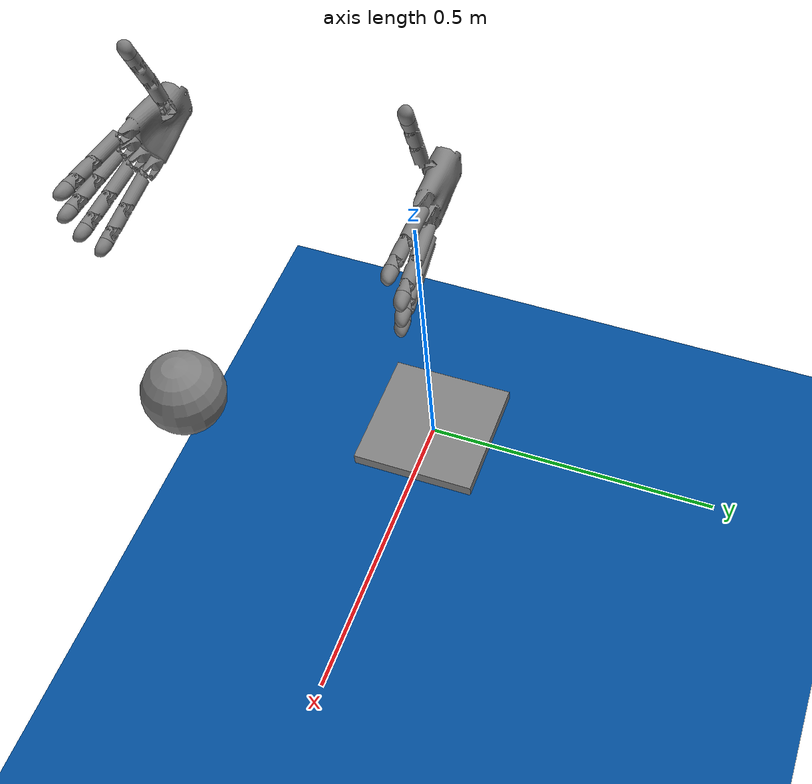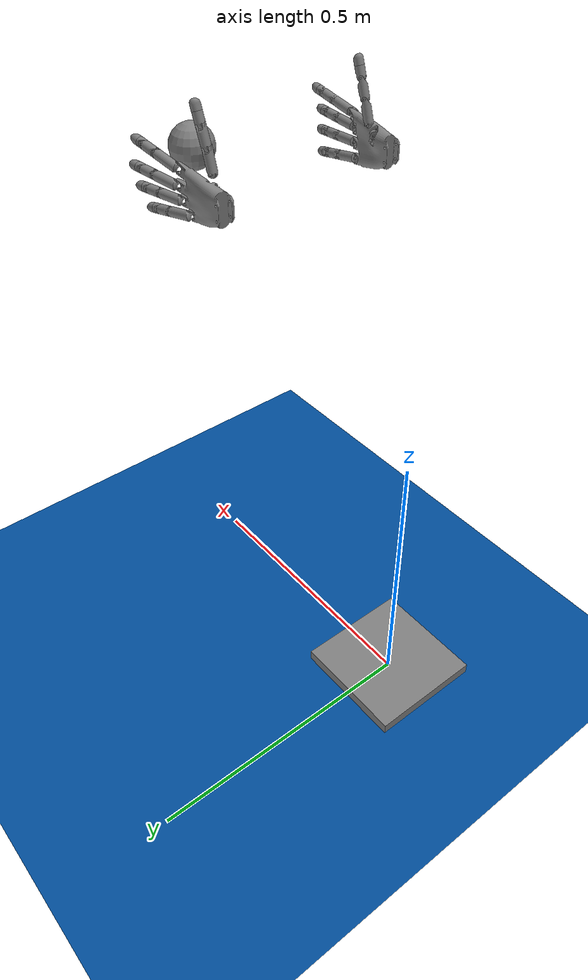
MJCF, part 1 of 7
<mujoco model="MuJoCo Model">
  <compiler angle="radian"/>

  <option ls_tolerance="0.01" ccd_tolerance="1e-06" sleep_tolerance="0.001" gravity="0 0 -9.81" integrator="implicitfast" iterations="10" ls_iterations="20"/>

  <asset>
    <mesh name="mjlab scene/worldbody/robot/pelvis/robot/pelvis_geom_0_52" vertex="0.0382102 0.0320787 -0.126485 0.0381548 0.032162 -0.126565 0.0381548 0.032048 -0.126565 0.0380993 0.0322453 -0.126645 0.0380992 0.0320172 -0.126645 0.0380992 -0.0319743 -0.126645 0.0380993 -0.0322297 -0.126645 0.0381614 -0.0320087 -0.126555 0.0381614 -0.0321364 -0.126555 0.0382234 -0.0320431 -0.126466 0.008 0.0504489 -0.0332568 0.008 0.0504489 -0.0277651 0.007 0.0505973 -0.0332568 0.007 0.0505973 -0.0277651 0.008 -0.0504541 -0.0277651 0.008 -0.0504541 -0.0332568 0.007 -0.0506025 -0.0277651 0.007 -0.0506025 -0.0332568 0.00363723 0.0509496 -0.0332568 0.00363723 0.0509496 -0.0277651 0.000298935 0.0510784 -0.0332568 0.000298862 0.0510784 -0.0277651 0.00363723 -0.0509547 -0.0277651 0.00363723 -0.0509547 -0.0332568 0.000298862 -0.0510835 -0.0277651 0.000298935 -0.0510835 -0.0332568 0.000298843 -0.0482982 -0.0277639 0.00226946 -0.0482457 -0.0277639 0.008 -0.04763 -0.0277651 0.0473296 -0.00799661 -0.0280208 0.0474017 -0.00756017 -0.0280203 0.0473192 -0.00805837 -0.0331916 0.0475112 -0.00683496 -0.0280744 0.0477042 -0.00532344 -0.0331942 0.0477532 -0.004864 -0.0282244 0.047776 -0.00463871 -0.0282407 0.0477761 -0.00462703 -0.0282406 0.0478402 -0.0039186 -0.028287 0.0479329 -0.00253988 -0.0331969 0.0479336 -0.00252558 -0.0283563 0.0479829 -0.00128425 -0.0331981 0.0479834 -0.00126475 -0.0283931 0.048 -2.77475e-05 -0.0331993 0.048 -2.57393e-06 -0.0284054 0.048 -2.57393e-06 -0.0331994 0.0472509 -0.00844931 -0.0280211 0.046895 -0.0102427 -0.0331895 0.0466773 -0.0111929 -0.028023 0.0467777 -0.0107657 -0.033189 0.0460493 -0.0135473 -0.0280246 0.0460819 -0.0134361 -0.0331865 0.0459446 -0.0138984 -0.0280248 0.0455715 -0.0150768 -0.0280256 0.0454098 -0.0155573 -0.0331845 0.0450551 -0.0165565 -0.0280266 0.0452341 -0.0160609 -0.033184 0.0441204 -0.0189072 -0.0280283 0.0442376 -0.0186313 -0.0331816 0.0441204 -0.0189072 -0.0331814 0.0440121 -0.0191581 -0.0280285 0.0434295 -0.0204446 -0.0280294 0.0433247 -0.0206658 -0.0331797 0.0428189 -0.0216944 -0.0280303 0.0430959 -0.0211389 -0.0331793 0.0415702 -0.0240008 -0.028032 0.0418129 -0.0235753 -0.033177 0.0415702 -0.0240008 -0.0331766 0.0414798 -0.0241567 -0.0280322 0.0406581 -0.0255156 -0.0280332 0.0406674 -0.0255007 -0.0331751 0.0403933 -0.0259328 -0.0331747 0.0399992 -0.0265367 -0.028034 0.0384345 -0.0287564 -0.0280358 0.0388421 -0.0282034 -0.0331726 0.0384345 -0.0287564 -0.033172 0.0383822 -0.0288262 -0.0280359 0.0372978 -0.0302163 -0.028037 0.0374732 -0.0299984 -0.0331708 0.0371646 -0.0303799 -0.0331705 0.0366343 -0.0310174 -0.0280377 0.0353669 -0.0324553 -0.0331685 0.0347616 -0.0331029 -0.0280395 0.0347575 -0.0331071 -0.0331678 0.0333973 -0.0344788 -0.0280408 0.0337844 -0.0340996 -0.0331668 0.0334551 -0.0344228 -0.0331665 0.0327702 -0.0350754 -0.0280414 0.031436 -0.0362761 -0.0331647 0.0306672 -0.0369284 -0.0280432 0.0305909 -0.0369916 -0.0331639 0.0290134 -0.0382415 -0.0280446 0.0296498 -0.0377502 -0.0331632 0.0293167 -0.0380095 -0.0331629 0.0284595 -0.0386555 -0.0280451 0.0271045 -0.0396174 -0.0331612 0.0261549 -0.0402508 -0.0280469 0.0259936 -0.0403551 -0.0331605 0.0242095 -0.0414501 -0.0280484 0.0248073 -0.0410951 -0.0331597 0.023761 -0.0417088 -0.0280487 0.022433 -0.0424378 -0.0331582 0.0212861 -0.0430246 -0.0280506 0.0210301 -0.0431503 -0.0280508 0.0210301 -0.0431503 -0.0331574 0.0190552 -0.0440581 -0.0280522 0.0199901 -0.0436419 -0.0331569 0.0187386 -0.0441937 -0.0280524 0.0174871 -0.0447037 -0.0331557 0.0161273 -0.0452121 -0.0280543 0.0157705 -0.0453378 -0.033155 0.014933 -0.0456205 -0.0331547 0.0136253 -0.046028 -0.028056 0.0123368 -0.04639 -0.0331538 0.008 -0.0473311 -0.0331527 0.008 -0.0473311 -0.0280598 0.00970798 -0.0470105 -0.0331531 0.0107486 -0.0467835 -0.028058 0.0134609 -0.0460764 -0.0280561 0.000298843 0.0483127 -0.0277651 0.00236402 0.0482557 -0.0277651 0.00483532 0.0480707 -0.0277651 0.00724982 0.0477658 -0.0277651 0.008 0.0476457 -0.0277651 0.047482 0.00703039 -0.0331896 0.0478153 0.00420378 -0.0331935 0.0477756 0.00463349 -0.0282404 0.0477767 0.00462148 -0.0282408 0.0479318 0.00255548 -0.0331958 0.0479325 0.00254124 -0.0283555 0.048 7.82963e-06 -0.0331994 0.048 7.83153e-06 -0.0284054 0.047983 0.00127522 -0.0283928 0.0479823 0.00129988 -0.0331976 0.048 4.34068e-05 -0.0331993 0.0475123 0.00682218 -0.0280747 0.0474089 0.007509 -0.0280235 0.0473296 0.00799146 -0.0331882 0.0473296 0.00799146 -0.0280244 0.0469813 0.00983365 -0.0331857 0.0469151 0.0101451 -0.0280274 0.046315 0.0126037 -0.0331819 0.0462798 0.0127322 -0.0280311 0.0460493 0.0135421 -0.0331806 0.0460493 0.0135421 -0.0280322 0.045485 0.0153309 -0.0331782 0.0455057 0.0152692 -0.0280347 0.0444938 0.0180056 -0.0331746 0.0445946 0.0177546 -0.0280382 0.0441204 0.018902 -0.0331734 0.0441204 0.018902 -0.0280398 0.0433448 0.0206184 -0.033171 0.0435477 0.0201865 -0.0280416 0.0420416 0.02316 -0.0331676 0.0422497 0.022778 -0.0280453 0.0415702 0.0239956 -0.0331664 0.0415702 0.0239956 -0.028047 0.0405883 0.0256214 -0.0331642 0.0409114 0.0251022 -0.0280486 0.0389897 0.0279938 -0.033161 0.0394556 0.0273332 -0.0280517 0.0384345 0.0287513 -0.0331599 0.0384345 0.0287513 -0.0280537 0.037251 0.0302688 -0.0331578 0.0378854 0.029471 -0.0280547 0.0353779 0.0324381 -0.0331548 0.036203 0.0315146 -0.0280576 0.0347575 0.033102 -0.0331538 0.0347575 0.033102 -0.0280599 0.0344101 0.0334629 -0.0280604 0.0333765 0.0344939 -0.0331519 0.0323275 0.0354788 -0.0280633 0.0312532 0.0364286 -0.0331491 0.0305909 0.0369864 -0.0280654 0.0305909 0.0369864 -0.0331483 0.0302954 0.0372289 -0.0280658 0.0290151 0.0382351 -0.0331464 0.0281831 0.0388523 -0.0280681 0.0266692 0.0399066 -0.0331439 0.0259938 0.0403498 -0.0280702 0.0213931 0.0429664 -0.028074 0.0216852 0.0428197 -0.0331395 0.0237298 0.0417214 -0.0280722 0.0242233 0.0414368 -0.0331416 0.0259936 0.04035 -0.0331433 0.0163645 0.0451217 -0.0331358 0.0175835 0.0446607 -0.0331365 0.0187606 0.0441792 -0.0280757 0.0190628 0.0440497 -0.0331375 0.0210301 0.0431452 -0.0280742 0.0210301 0.0431452 -0.0331389 0.0213559 0.0429848 -0.0331392 0.0162787 0.0451527 -0.0280771 0.0157705 0.0453327 -0.0280774 0.0136999 0.0460007 -0.0331343 0.0137562 0.0459839 -0.0280783 0.0135986 0.0460308 -0.0331343 0.0107755 0.0467722 -0.0331331 0.0111955 0.0466735 -0.0280793 0.008 0.047326 -0.0331322 0.00859847 0.0472209 -0.0280802 0.008 0.047326 -0.0280803 0.008 0.0474523 -0.0332568 0.008 -0.0474367 -0.0332568 0.0476646 -0.0427525 -0.103933 0.0476649 -0.040711 -0.103934 0.0474971 -0.0403432 -0.104889 0.0162775 -0.0278906 -0.144472 0.0183803 -0.028223 -0.143587 0.0180943 -0.0262794 -0.143707 0.0313941 -0.0315713 -0.134603 0.0320727 -0.0318267 -0.133928 0.0318095 -0.0298556 -0.134192 0.0444162 -0.0369523 -0.11531 0.0445446 -0.0364471 -0.115017 0.0443699 -0.0366011 -0.11542 0.0443217 -0.0362501 -0.115529 0.034519 -0.0309517 -0.131276 0.0345303 -0.0328344 -0.131259 0.0351357 -0.0331051 -0.130542 0.0364134 -0.0318222 -0.128959 0.03257 -0.0301469 -0.133417 0.0327957 -0.0321088 -0.133181 0.033925 -0.0325731 -0.131951 0.0272739 -0.030235 -0.138197 0.0285735 -0.0306346 -0.137151 0.0285054 -0.028723 -0.137205 0.0292091 -0.0308377 -0.136611 0.0305659 -0.0294049 -0.135391 0.0312218 -0.0315156 -0.13477 0.0313731 -0.0315659 -0.134623 0.0250755 -0.0296257 -0.139802 0.0263868 -0.0280989 -0.138866 0.0252121 -0.0277837 -0.139704 0.0206549 -0.0286325 -0.142472 0.0217126 -0.0288433 -0.141896 0.0219071 -0.0270038 -0.141779 0.0227781 -0.0290721 -0.141277 0.0242075 -0.0275305 -0.140378 0.0229315 -0.0291065 -0.141185 0.0246263 -0.0295112 -0.140106 0.0196025 -0.0265449 -0.143 0.0124274 -0.0255068 -0.145762 0.00992726 -0.0252699 -0.146392 0.0106549 -0.0272046 -0.146224 0.0172601 -0.0261438 -0.144067 0.01487 -0.025798 -0.144987 0.0140778 -0.0275858 -0.145259 0.0143959 -0.0257367 -0.14515 0.0116525 -0.0273049 -0.145974 0.0114052 -0.0272792 -0.146038 0.00204239 -0.0248916 -0.147408 0.00416896 -0.0268174 -0.147271 0.00473156 -0.0249599 -0.147217 0.00583206 -0.0268761 -0.147094 0.00670392 -0.0250498 -0.146978 0.00691169 -0.0269256 -0.146947 0.0073639 -0.0250874 -0.146878 0.00930633 -0.0270826 -0.146523 0.0106124 -0.0272005 -0.146234 0.000496534 -0.0267486 -0.147448 0.00149222 -0.0267612 -0.147429 0.000473004 -0.0267305 -0.147448 0.000474857 -0.0267347 -0.147448 0.000471871 -0.0267262 -0.147448 0.000477331 -0.0267384 -0.147448 0.000480347 -0.0267416 -0.147448 0.000483877 -0.0267443 -0.147448 0.000487858 -0.0267464 -0.147448 0.000492073 -0.0267478 -0.147448 0.00163452 -0.023981 -0.147424 0.00119826 -0.0239762 -0.147437 0.000471463 -0.0267215 -0.147448 0.000834627 -0.0239734 -0.147444 0.000470924 -0.0239717 -0.147448 0.00207042 -0.0239873 -0.147408 0.0447617 -0.0367004 -0.114502 0.0444665 -0.0389277 -0.115199 0.0447945 -0.0366758 -0.114422 0.0450917 -0.0395111 -0.113682 0.0456797 -0.0375771 -0.112079 0.0358448 -0.0334337 -0.129669 0.0360671 -0.0335474 -0.129389 0.0378847 -0.0325714 -0.126966 0.0376374 -0.0343453 -0.127298 0.0399639 -0.0337661 -0.123788 0.0394801 -0.0353688 -0.124574 0.0401417 -0.033872 -0.123506 0.0400629 -0.0357077 -0.123642 0.0401952 -0.0339074 -0.123412 0.0401684 -0.0357728 -0.12347 0.0417885 -0.034942 -0.120659 0.0417435 -0.0368038 -0.120743 0.0425144 -0.0354539 -0.119297 0.0425111 -0.0373495 -0.119298 0.0432458 -0.0360014 -0.11784 0.0432956 -0.0379274 -0.11773 0.0441553 -0.0367216 -0.115924 0.0437972 -0.0383651 -0.116681 0.0442422 -0.0368049 -0.115704 0.0442717 -0.0387618 -0.115642 0.0447612 -0.0366447 -0.114503 0.0456151 -0.040051 -0.112261 0.0459344 -0.0404095 -0.111303 0.0461616 -0.0381587 -0.110568 0.046657 -0.0413394 -0.108768 0.0468778 -0.0391995 -0.107862 0.0476652 -0.0431414 -0.103933 0.0474268 -0.0426357 -0.105268 0.0469714 -0.0418131 -0.107455 0.0469527 -0.0417867 -0.107538 0.0469713 0.0418286 -0.107455 0.0469444 0.0417899 -0.107575 0.0468748 0.0392375 -0.107875 0.044372 0.0366322 -0.115415 0.044326 0.0362968 -0.115519 0.0445467 0.036492 -0.115012 0.0447616 0.0366881 -0.114502 0.0447619 0.036716 -0.114501 0.0451041 0.039539 -0.11365 0.04477 0.0367099 -0.114482 0.0447783 0.0367037 -0.114462 0.0456151 0.0400666 -0.112261 0.0456959 0.0376471 -0.112025 0.0458648 0.0403448 -0.111519 0.0444172 0.0369678 -0.115311 0.0445129 0.0389839 -0.115091 0.0442441 0.03682 -0.115704 0.0442717 0.0387775 -0.115642 0.0435817 0.0382 -0.117137 0.043372 0.0380264 -0.117573 0.043244 0.0360188 -0.117836 0.0432763 0.0379218 -0.11777 0.0425089 0.03547 -0.119296 0.0425097 0.0373456 -0.119295 0.0416847 0.0348883 -0.120843 0.0416531 0.0367465 -0.120902 0.0401149 0.0338683 -0.123557 0.0400629 0.0357233 -0.123642 0.0395278 0.0335143 -0.124499 0.0374369 0.0342495 -0.127542 0.0372609 0.0322671 -0.127818 0.038362 0.0347314 -0.126264 0.0378778 0.0325893 -0.12696 0.0385747 0.0348555 -0.125937 0.0392863 0.0352705 -0.124839 0.0372892 0.0341726 -0.127746 0.0365592 0.0337924 -0.128755 0.0355117 0.0314155 -0.130083 0.035841 0.0334451 -0.129674 0.0351205 0.0331226 -0.13053 0.0345282 0.0309734 -0.131259 0.0319552 0.0317967 -0.134046 0.0317642 0.029854 -0.134238 0.0327951 0.0321234 -0.13318 0.0336769 0.0306101 -0.132226 0.0339332 0.032591 -0.13194 0.0345146 0.0328513 -0.131249 0.0313893 0.0315853 -0.134606 0.031282 0.0315515 -0.134712 0.0297746 0.0291485 -0.136115 0.0298825 0.0310744 -0.136018 0.028574 0.0287592 -0.13715 0.0285617 0.0306528 -0.137138 0.0278201 0.030416 -0.137766 0.0277019 0.0284923 -0.137861 0.0275409 0.0303357 -0.137977 0.0266689 0.0281925 -0.138658 0.0257108 0.0298087 -0.139358 0.0252128 0.0277983 -0.139707 0.0246263 0.0295269 -0.140106 0.0245953 0.0276407 -0.140126 0.0236172 0.0292807 -0.140761 0.0224641 0.027138 -0.141464 0.0223432 0.0289922 -0.141535 0.0217118 0.0269752 -0.141897 0.0217123 0.0288589 -0.141897 0.0213607 0.0287872 -0.142092 0.0202764 0.0266847 -0.14267 0.0190389 0.0283516 -0.143281 0.0180329 0.0262815 -0.143743 0.0183075 0.0282266 -0.14362 0.0180981 0.0281917 -0.143713 0.0157316 0.0259288 -0.144681 0.016573 0.0279506 -0.144356 0.0149222 0.0277131 -0.144973 0.0140576 0.0257088 -0.145266 0.0141968 0.0276169 -0.14522 0.0117332 0.0254508 -0.145953 0.0117919 0.0273352 -0.145937 0.0114052 0.0272949 -0.146038 0.0112117 0.0272752 -0.146088 0.0106107 0.0253449 -0.146234 0.0106125 0.0272161 -0.146234 0.00936634 0.0252412 -0.14651 0.00920402 0.0270898 -0.146544 0.00695884 0.0250799 -0.146939 0.00414404 0.0268323 -0.147273 0.00202941 0.0249034 -0.147409 0.00518387 0.0268665 -0.147171 0.00451261 0.024967 -0.14724 0.00665458 0.0269286 -0.146984 0.007816 0.0269901 -0.146802 0.00046998 0.0267372 -0.147449 0.000470932 0.0240147 -0.147448 0.000834631 0.0240164 -0.147444 0.00207035 0.0240302 -0.147408 0.00163472 0.0240239 -0.147424 0.00119826 0.0240191 -0.147437 0.00162447 0.0267791 -0.147425 0.00049819 0.0267643 -0.147448 0.000493603 0.0267638 -0.147448 0.000489287 0.0267627 -0.147448 0.000485241 0.0267608 -0.147448 0.000481518 0.0267583 -0.147448 0.000478266 0.0267551 -0.147448 0.000475571 0.0267515 -0.147448 0.000473533 0.0267476 -0.147448 0.000472157 0.0267433 -0.147448 0.000471518 0.0267388 -0.147448 0.0466986 0.0414165 -0.108603 0.046558 0.0412121 -0.109152 0.0461601 0.0381996 -0.110573 0.0459091 0.0378927 -0.111382 0.0476646 0.0427517 -0.103933 0.0476652 0.043157 -0.103933 0.0474249 0.0426564 -0.10527 0.0476649 0.040754 -0.103934 0.0475263 0.0404502 -0.104722 0.0470156 0.0419048 -0.107259 0.0447453 -0.00493145 -0.133439 0.0477376 -0.00490736 -0.13005 0.0475086 -0.00984552 -0.129827 0.0422922 -0.0244893 -0.130967 0.0390569 -0.0245054 -0.134132 0.040047 -0.0196487 -0.135196 0.0459325 -0.022043 -0.128205 0.0453637 -0.024439 -0.127632 0.0132179 -0.0084759 -0.150662 0.00874451 -0.00811048 -0.151357 0.00915244 -0.00315513 -0.151466 0.0281986 -0.00944582 -0.145542 0.0261485 -0.00934033 -0.146533 0.0264904 -0.00439811 -0.146665 0.00729379 4.23198e-07 -0.151686 0.00938642 -1.88531e-06 -0.151455 0.0167606 -7.75249e-06 -0.150084 0.0182286 -7.78204e-06 -0.149698 0.0179968 -0.00385487 -0.149734 0.0196923 -7.28053e-06 -0.149272 0.0225211 -4.80521e-06 -0.148328 0.0223011 -0.00414879 -0.148371 0.0252526 -9.49939e-07 -0.147255 0.026692 1.26034e-06 -0.146621 0.0407466 -1.23976e-05 -0.137431 0.0415315 -0.00491878 -0.136623 0.0380845 -0.00486049 -0.139569 0.0539159 -0.0209571 -0.118745 0.0542035 -0.021966 -0.117663 0.0517206 -0.0219102 -0.121181 0.0528647 -0.0263029 -0.116157 0.0536614 -0.0240508 -0.116865 0.0548784 -0.0239205 -0.114963 0.0436612 -0.0357156 -0.122421 0.0422032 -0.034729 -0.125072 0.0427281 -0.0338753 -0.124984 0.0289539 -0.0291531 -0.139949 0.0309979 -0.029266 -0.138547 0.0311547 -0.0298117 -0.138204 0.00431723 -0.0256296 -0.149251 0.00375847 -0.0256123 -0.149293 0.0026626 -0.0224676 -0.150005 0.00049768 -0.0218407 -0.15015 0.00115053 -0.0255618 -0.149405 0.000500533 -0.0255569 -0.149411 0.00647245 -0.025718 -0.149028 0.00715105 -0.0228859 -0.149588 0.00677156 -0.025733 -0.14899 0.00914977 -0.0258774 -0.148614 0.00937094 -0.0230762 -0.149243 0.0117862 -0.0260908 -0.148052 0.0159038 -0.023574 -0.147673 0.0143795 -0.0263584 -0.147342 0.0137495 -0.02342 -0.148285 0.0115712 -0.0232541 -0.148809 0.0201329 -0.0238481 -0.14619 0.0194283 -0.0270586 -0.145483 0.0180323 -0.0237166 -0.146974 0.0169277 -0.0266807 -0.146486 0.0154597 -0.0264876 -0.146999 0.0242704 -0.0279823 -0.143039 0.0224477 -0.027603 -0.144041 0.0242424 -0.024078 -0.144372 0.0218776 -0.0274924 -0.144334 0.0196003 -0.027087 -0.145408 0.0266071 -0.0285292 -0.141595 0.0282135 -0.0242632 -0.142236 0.0273479 -0.0287178 -0.141098 0.0320213 -0.0243991 -0.1398 0.0345561 -0.0293303 -0.135838 0.0332599 -0.0305159 -0.13633 0.0316952 -0.0299851 -0.137744 0.0406415 -0.0337968 -0.127569 0.0399841 -0.0334362 -0.128534 0.0410971 -0.0292847 -0.129708 0.0389621 -0.032908 -0.129946 0.0379219 -0.0293344 -0.132882 0.0371608 -0.0320607 -0.132208 0.0352638 -0.0312657 -0.13433 0.0440927 -0.0291861 -0.12635 0.0412503 -0.0341467 -0.126633 0.0461238 -0.0377514 -0.116921 0.0449802 -0.0367327 -0.119676 0.0468204 -0.0367841 -0.116628 0.0454579 -0.0336636 -0.121433 0.0493952 -0.033207 -0.115545 0.0480119 -0.0333873 -0.117739 0.0513232 -0.0305286 -0.114733 0.0495757 -0.0288329 -0.119192 0.0528234 -0.0284444 -0.114102 0.0520418 -0.028548 -0.115421 0.0535683 -0.0274096 -0.113789 0.0553151 -0.0247602 -0.113305 0.0553793 -0.0248955 -0.113027 0.0536509 -0.0198425 -0.119725 0.0522636 -0.0195518 -0.121694 0.0535628 -0.0194239 -0.120043 0.0534006 -0.0185815 -0.12061 0.0531999 -0.01735 -0.121289 0.0526393 -0.0171498 -0.122071 0.053021 -0.0159468 -0.121892 0.0528776 -0.0147122 -0.122336 0.052859 -0.0143044 -0.122434 0.0526193 -0.0109547 -0.123202 0.0526881 -0.0120798 -0.122985 0.0500383 -0.0147348 -0.125913 0.0524223 -0.00435825 -0.123854 0.0524693 -0.00715495 -0.123688 0.0503724 -0.00981158 -0.126292 0.0525508 -0.00957769 -0.123419 0.0525599 -0.00978165 -0.12339 0.0497611 2.485e-07 -0.127625 0.0505295 -0.00485778 -0.126489 0.0518508 3.84778e-06 -0.124729 0.0431046 -1.284e-05 -0.135231 0.0448243 -1.11023e-05 -0.133475 0.0453902 -1.01748e-05 -0.132868 0.0476077 -5.24917e-06 -0.130336 0.0331935 1.74052e-06 -0.143108 0.0345632 -7.69581e-07 -0.142218 0.0344105 -0.00475338 -0.142244 0.0357995 -3.45964e-06 -0.141364 0.0383126 -8.90891e-06 -0.139475 0.0278914 2.90612e-06 -0.146055 0.0304601 4.44066e-06 -0.144722 0.0305362 -0.00459971 -0.144618 0.0137202 -6.21953e-06 -0.15076 0.00390216 3.49676e-06 -0.151924 0.00466009 -0.00276225 -0.151867 0.000425526 -0.00242854 -0.151983 0.000387176 4.92971e-06 -0.152004 0.00375007 -0.0126564 -0.151389 0.000497161 -0.0112594 -0.151546 0.00422731 -0.00771428 -0.151732 0.000492572 -0.00995148 -0.15165 0.000480405 -0.00773979 -0.151794 0.000475133 -0.00701446 -0.151832 0.000474387 -0.00691872 -0.151837 0.000446693 -0.00407448 -0.151947 0.000500196 -0.0205406 -0.150378 0.000505151 -0.0175832 -0.150837 0.00322946 -0.0175783 -0.150814 0.000499366 -0.0155454 -0.151105 0.000500308 -0.0128837 -0.151398 0.0321781 -0.00962162 -0.143308 0.0302097 -0.00953958 -0.144466 0.0316865 -0.0145416 -0.142863 0.0297194 -0.0144613 -0.144031 0.0277105 -0.0143695 -0.145118 0.0294126 -0.0169176 -0.143699 0.025367 -0.0167251 -0.145801 0.0256633 -0.0142664 -0.146122 0.0235814 -0.0141522 -0.147041 0.0240627 -0.00922327 -0.147438 0.0219448 -0.00909488 -0.148257 0.00827873 -0.0130569 -0.151025 0.0127545 -0.0134205 -0.150322 0.0149664 -0.0135877 -0.149841 0.0165862 -0.0186699 -0.148618 0.0144086 -0.0185154 -0.149205 0.00775009 -0.0179859 -0.150434 0.0122086 -0.0183499 -0.149703 0.00998834 -0.0181734 -0.150113 0.010566 -3.19266e-06 -0.151296 0.0136054 -0.00352153 -0.150761 0.017626 -0.00880554 -0.149632 0.0197981 -0.0089555 -0.148988 0.0193257 -0.0138911 -0.148617 0.0214679 -0.0140271 -0.147873 0.0208663 -0.0189466 -0.147181 0.0229644 -0.0190688 -0.146333 0.0246526 -0.0216309 -0.144919 0.0205131 -0.0213994 -0.146718 0.0187395 -0.0188136 -0.147943 0.0171576 -0.0137446 -0.149273 0.0503357 -0.0265415 -0.119898 0.0510612 -0.0242363 -0.12057 0.0250312 -0.0191803 -0.145399 0.0290594 -0.0193704 -0.143286 0.0286553 -0.0218186 -0.142793 0.0329233 -0.0195142 -0.140862 0.0324944 -0.0219588 -0.140363 0.0365896 -0.0196068 -0.138154 0.0361382 -0.0220453 -0.137653 0.0482867 -0.0243575 -0.12416 0.0476208 -0.026706 -0.123516 0.046919 -0.0290385 -0.122838 0.0356378 -0.0244787 -0.137089 0.0497721 -0.017177 -0.125626 0.0493996 -0.0195974 -0.125244 0.0523966 4.10116e-06 -0.123925 0.0464207 -0.0196304 -0.128699 0.0433134 -0.0196513 -0.132029 0.0467994 -0.0171998 -0.129091 0.0436995 -0.0172149 -0.132433 0.0470924 -0.0147564 -0.129398 0.0336075 -0.0146102 -0.141619 0.0341001 -0.00969202 -0.142071 0.037294 -0.0147104 -0.138913 0.0377884 -0.00979714 -0.139376 0.0407579 -0.0147603 -0.135945 0.041247 -0.00985236 -0.136411 0.0440123 -0.0147701 -0.132758 0.0444785 -0.00986402 -0.133213 0.0369719 -0.0171611 -0.138573 0.0332921 -0.0170642 -0.14128 0.0488923 -0.0219896 -0.124746 0.0545503 -0.0229811 -0.116346 0.0548931 -0.0238313 -0.115022 0.0526618 0.0116444 -0.123072 0.0525611 0.00978617 -0.12339 0.0503719 0.00981625 -0.126293 0.0136052 0.00352516 -0.150761 0.00915225 0.00315876 -0.151466 0.00266194 0.0224753 -0.150004 0.000499686 0.0213498 -0.150241 0.000500533 0.0255682 -0.149411 0.000499366 0.0155559 -0.151105 0.000499347 0.0171128 -0.150904 0.00322895 0.017585 -0.150813 0.0037497 0.012662 -0.151389 0.000472864 0.0112991 -0.151543 0.000482943 0.0128957 -0.151398 0.000445302 0.00699555 -0.151827 0.000445513 0.00702847 -0.151825 0.00422707 0.00771893 -0.151732 0.00045018 0.00775524 -0.151788 0.000464355 0.00996466 -0.151648 0.00465996 0.00276588 -0.151867 0.00041699 0.00253603 -0.151966 0.000426755 0.00408969 -0.151935 0.0179965 0.00385849 -0.149734 0.0223007 0.00415241 -0.148371 0.02649 0.00440173 -0.146665 0.03441 0.00475701 -0.142245 0.0305358 0.00460333 -0.144619 0.0380841 0.00486412 -0.139569 0.0415311 0.00492241 -0.136623 0.0447449 0.00493509 -0.133439 0.0477372 0.004911 -0.130051 0.0505291 0.00486143 -0.126489 0.0524251 0.00441905 -0.123848 0.0525514 0.00957127 -0.12342 0.0524708 0.00720334 -0.123685 0.0524696 0.00715119 -0.123689 0.0528206 0.0138349 -0.122565 0.0500375 0.0147405 -0.125913 0.0531643 0.0170271 -0.121433 0.053054 0.0161818 -0.121797 0.0526384 0.0171559 -0.122071 0.0529849 0.0155845 -0.122023 0.0535783 0.0194744 -0.120006 0.0533546 0.0182578 -0.120796 0.0522623 0.0195584 -0.121694 0.0532859 0.0178403 -0.121029 0.0537977 0.0204788 -0.119199 0.051719 0.0219172 -0.121181 0.0540468 0.0214403 -0.118263 0.0542233 0.0220335 -0.117596 0.0510593 0.0242437 -0.120569 0.0543475 0.022416 -0.117125 0.0548763 0.0239278 -0.114962 0.0535702 0.0274225 -0.113788 0.0551443 0.0244053 -0.114022 0.0553793 0.0249068 -0.113027 0.0546969 0.023367 -0.115791 0.0536594 0.0240581 -0.116864 0.0528624 0.0263106 -0.116156 0.0528264 0.0284558 -0.114101 0.0520393 0.0285562 -0.11542 0.0513251 0.0305415 -0.114733 0.0469168 0.0290469 -0.122836 0.0480092 0.0333966 -0.117737 0.0495734 0.0288412 -0.119191 0.0493975 0.0332194 -0.115544 0.0369027 0.0319599 -0.132513 0.0391879 0.0330334 -0.129645 0.0410951 0.0292933 -0.129707 0.0399859 0.033449 -0.128534 0.0412517 0.0341594 -0.126633 0.0287941 0.0291204 -0.14007 0.0316961 0.0299978 -0.137745 0.0309963 0.0292747 -0.138545 0.0344022 0.0309461 -0.135219 0.0345543 0.0293389 -0.135837 0.03792 0.029343 -0.13288 0.0242413 0.0240857 -0.144371 0.0201319 0.0238557 -0.146189 0.0190355 0.027012 -0.145652 0.0257056 0.0283242 -0.142175 0.0282122 0.0242709 -0.142235 0.0235725 0.0278486 -0.143434 0.0224464 0.0276196 -0.144041 0.0180313 0.0237243 -0.146973 0.0159029 0.0235817 -0.147672 0.0154922 0.026507 -0.146989 0.0137486 0.0234276 -0.148284 0.0118395 0.0261104 -0.148039 0.0115703 0.0232618 -0.148808 0.00810525 0.0258221 -0.148795 0.00937013 0.0230839 -0.149242 0.00676963 0.0257458 -0.148991 0.00431603 0.0256419 -0.149252 0.00715029 0.0228936 -0.149587 0.0476188 0.026714 -0.123515 0.0503335 0.0265494 -0.119897 0.0482849 0.024365 -0.124159 0.0488908 0.0219967 -0.124746 0.0493984 0.019604 -0.125244 0.0461238 0.0377627 -0.116921 0.0468223 0.036797 -0.116627 0.0447197 0.0365318 -0.120253 0.0454553 0.0336729 -0.121431 0.0427256 0.0338847 -0.124982 0.0440906 0.0291946 -0.126349 0.0390553 0.0245131 -0.134131 0.0422907 0.0244969 -0.130967 0.0433122 0.019658 -0.132029 0.0273492 0.028731 -0.141098 0.03202 0.0244068 -0.139799 0.0356363 0.0244863 -0.137088 0.0400459 0.0196553 -0.135196 0.0365885 0.0196135 -0.138154 0.036137 0.0220524 -0.137653 0.0329222 0.0195208 -0.140861 0.0324932 0.0219659 -0.140362 0.0290585 0.019377 -0.143285 0.0286542 0.0218258 -0.142793 0.0250303 0.0191869 -0.145399 0.0246515 0.0216381 -0.144918 0.0229635 0.0190754 -0.146332 0.0205121 0.0214066 -0.146718 0.0187387 0.0188203 -0.147943 0.0165855 0.0186766 -0.148617 0.0144079 0.018522 -0.149204 0.0122079 0.0183565 -0.149702 0.00998773 0.0181801 -0.150112 0.00774951 0.0179926 -0.150434 0.0240622 0.00922791 -0.147438 0.026148 0.00934497 -0.146533 0.0281982 0.00945045 -0.145542 0.0253663 0.0167312 -0.145801 0.0294118 0.0169237 -0.143698 0.0277098 0.0143752 -0.145118 0.0132176 0.00848055 -0.150662 0.0176256 0.00881018 -0.149632 0.0197977 0.00896014 -0.148988 0.0219443 0.00909952 -0.148257 0.00827832 0.0130626 -0.151024 0.0127541 0.0134262 -0.150322 0.0149659 0.0135933 -0.149841 0.0171571 0.0137503 -0.149273 0.0193251 0.0138968 -0.148617 0.0214673 0.0140327 -0.147872 0.0235808 0.0141579 -0.14704 0.0256627 0.0142721 -0.146122 0.00874422 0.00811513 -0.151357 0.0208655 0.0189532 -0.14718 0.0528769 0.0147178 -0.122336 0.0497712 0.0171831 -0.125626 0.0467985 0.017206 -0.129091 0.0464196 0.019637 -0.128698 0.0459311 0.0220501 -0.128204 0.0453621 0.0244466 -0.127632 0.0430947 0.0353288 -0.123496 0.0302092 0.00954422 -0.144466 0.0297188 0.014467 -0.144031 0.0316858 0.0145473 -0.142863 0.0332913 0.0170703 -0.14128 0.0336068 0.0146159 -0.141618 0.036971 0.0171673 -0.138573 0.0372932 0.014716 -0.138913 0.0404346 0.0172138 -0.13561 0.0407571 0.014766 -0.135945 0.0440115 0.0147757 -0.132758 0.0470916 0.014762 -0.129398 0.0436986 0.017221 -0.132433 0.0321776 0.00962625 -0.143308 0.0340996 0.00969665 -0.142071 0.0377878 0.00980178 -0.139376 0.0412465 0.009857 -0.136411 0.044478 0.00986867 -0.133214 0.047508 0.00985017 -0.129827 0.0530238 0.0458251 -0.0434827 0.0538079 0.0460574 -0.0471504 0.0526282 0.0493189 -0.0464001 0.0515759 0.0454886 -0.0381674 0.0526655 0.0457326 -0.0420218 0.051565 0.0489887 -0.0415302 0.0403143 0.0605174 -0.0320846 0.0414464 0.0609755 -0.0358316 0.0398936 0.0617778 -0.0357882 0.0353385 0.0656341 -0.0536748 0.0350163 0.0652543 -0.0489918 0.0387351 0.0645159 -0.0505827 0.0355871 0.066091 -0.0609387 0.0355416 0.0659625 -0.0586512 0.0383507 0.065479 -0.061334 0.0390131 0.0647986 -0.0543416 0.0406188 0.064859 -0.0617302 0.0408964 0.0642353 -0.0546017 0.0432212 0.0639466 -0.0623367 0.0421575 0.0643469 -0.0620543 0.042938 0.0638212 -0.0587794 0.0419026 0.0644361 -0.0619945 0.043419 0.0638668 -0.0623948 0.0447184 0.0630331 -0.0592171 0.043522 0.0638247 -0.0624257 0.0450441 0.0631332 -0.0629415 0.0463942 0.0620974 -0.0597414 0.0463537 0.0624096 -0.0634724 0.0476635 0.0615184 -0.0640957 0.0479303 0.0609977 -0.0603601 0.0480064 0.0612493 -0.0642752 0.0487181 0.0606297 -0.0646726 0.0492754 0.0597425 -0.0610642 0.0491778 0.0601736 -0.0649501 0.0496927 0.0595972 -0.0652813 0.0504226 0.0583424 -0.0618531 0.0506054 0.0584012 -0.0659596 0.0514201 0.0568623 -0.0626891 0.0513511 0.0572644 -0.0666286 0.0531237 0.0537783 -0.064431 0.0531048 0.0540405 -0.0686856 0.0524153 0.0553997 -0.0678154 0.054574 0.0506012 -0.0662243 0.0548805 0.0500065 -0.0712734 0.0535982 0.0529957 -0.0693556 0.055859 0.0474094 -0.0685479 0.0557821 0.0476801 -0.0727784 0.05441 0.0502872 -0.0612412 0.0557714 0.0471405 -0.0643395 0.0480915 0.0494038 -0.032087 0.048206 0.051652 -0.0342747 0.0473378 0.0514739 -0.032087 0.0482418 0.0533713 -0.03639 0.0468873 0.0525369 -0.0320872 0.045947 0.0544339 -0.0320865 0.0474232 0.0548718 -0.0362767 0.045559 0.0551099 -0.0320855 0.0464962 0.0563138 -0.0361649 0.0454397 0.0576711 -0.0360571 0.0429033 0.0600204 -0.0358892 0.0426467 0.0587533 -0.0320738 0.0442405 0.0589138 -0.0359645 0.0430018 0.0584128 -0.0320737 0.0441128 0.0571855 -0.0320769 0.0404074 0.0604601 -0.032084 0.0408447 0.060178 -0.0320811 0.0416844 0.0595712 -0.0320766 0.0333793 0.0637634 -0.0358546 0.0326459 0.0632039 -0.0321076 0.0366017 0.0629759 -0.0357217 0.0360496 0.0623858 -0.0321041 0.0382715 0.0624391 -0.0357535 0.0374369 0.0619132 -0.0321017 0.0386902 0.0613853 -0.0320956 0.0424129 0.0632767 -0.0510413 0.0534394 0.0496458 -0.051319 0.0552571 0.0466884 -0.0571159 0.0540275 0.0499687 -0.0562698 0.0555242 0.046877 -0.0601394 0.055733 0.0470855 -0.0634685 0.0383636 0.0641946 -0.0468369 0.0401947 0.0636323 -0.0470003 0.0419794 0.0629559 -0.0471911 0.0441596 0.0624718 -0.0513424 0.043695 0.0621467 -0.0474246 0.0458047 0.0615175 -0.0517059 0.0453103 0.0611874 -0.0477085 0.0473167 0.0604034 -0.0521382 0.0467958 0.0600703 -0.0480484 0.0486554 0.0591403 -0.0526332 0.0481169 0.0588073 -0.0484397 0.0498146 0.0577423 -0.0531899 0.0492677 0.0574146 -0.048881 0.0508308 0.0562628 -0.0537793 0.0502789 0.0559396 -0.0493478 0.0416265 0.0645361 -0.0619332 0.0427341 0.0635646 -0.0549057 0.0445028 0.0627667 -0.055275 0.0461682 0.0618205 -0.0557187 0.0476973 0.0607122 -0.0562441 0.0490443 0.0594517 -0.0568435 0.0502025 0.0580514 -0.0575163 0.0512145 0.0565702 -0.0582288 0.0542603 0.0462163 -0.0496607 0.0544251 0.0462804 -0.0506731 0.0546744 0.0463855 -0.0523326 0.0520017 0.0528483 -0.0503188 0.0525664 0.0531683 -0.0550062 0.0529442 0.0534783 -0.059713 0.0492726 0.0451037 -0.0320897 0.0500213 0.0452133 -0.0338206 0.0493725 0.0484912 -0.0343901 0.0501988 0.0486569 -0.0367405 0.0489695 0.0518292 -0.036505 0.0502387 0.0521781 -0.0410461 0.0345803 0.0648125 -0.0444311 0.034023 0.0643013 -0.0399442 0.037892 0.0638321 -0.0431054 0.0373102 0.0634263 -0.0393951 0.039682 0.0632749 -0.0432222 0.0390474 0.0628775 -0.0394676 0.0414254 0.0626001 -0.0433582 0.0407375 0.0622077 -0.0395512 0.0430995 0.0617898 -0.0435256 0.0423583 0.0613995 -0.0396548 0.0446747 0.0608285 -0.0437313 0.0438818 0.0604396 -0.0397846 0.0461236 0.0597114 -0.0439803 0.0452821 0.059326 -0.0399449 0.0474168 0.0584518 -0.0442692 0.0465356 0.058073 -0.0401339 0.048549 0.0570675 -0.0445966 0.0476373 0.0567004 -0.0403497 0.0495449 0.0556001 -0.0449423 0.0486062 0.0552439 -0.0405766 0.0512344 0.0525182 -0.0456603 0.0540961 7.67126e-06 -0.0355931 0.0551547 7.56401e-06 -0.0379603 0.0550465 0.0115894 -0.037965 0.056968 0.0177141 -0.0442108 0.0571815 0.0118258 -0.0442022 0.0580213 0.0119338 -0.0473896 0.0568717 0.0406979 -0.0571117 0.0564904 0.0423276 -0.0571144 0.056102 0.0420589 -0.053881 0.0548924 0.0446791 -0.0506684 0.0508148 0.0356506 -0.0320911 0.0509999 0.0339217 -0.0320903 0.0523806 0.0343038 -0.0350003 0.0519044 0.01942 -0.0320871 0.0535458 0.0171805 -0.0349651 0.0532997 0.0228977 -0.0349736 0.0521582 0.0025425 -0.032091 0.0521583 7.82963e-06 -0.0320911 0.0536951 0.0114603 -0.0349598 0.0520901 0.0118597 -0.0320879 0.0520982 0.0113235 -0.032088 0.0512629 0.0310489 -0.0320892 0.0529292 0.0286082 -0.0349853 0.0514349 0.0287904 -0.0320885 0.0514696 0.0282841 -0.0320883 0.0516214 0.0258155 -0.0320877 0.0497857 0.0426371 -0.0320913 0.050226 0.0400759 -0.0320923 0.0515863 0.039982 -0.0350177 0.0503067 0.039548 -0.0320924 0.0505918 0.037503 -0.032092 0.0493034 0.044968 -0.0320898 0.0529711 0.0436273 -0.0411581 0.052093 0.0432255 -0.0380593 0.0510606 0.042796 -0.0350257 0.0537204 0.0440026 -0.0442982 0.0562675 0.0432083 -0.0571161 0.0561271 0.0437391 -0.057117 0.0572789 0.0361453 -0.053873 0.0577121 0.0363865 -0.0571112 0.0575368 0.0373852 -0.0571105 0.057106 0.0396068 -0.0571106 0.0598338 0.0122206 -0.0571101 0.0597937 0.0133977 -0.0571091 0.0593366 0.0121309 -0.0538537 0.0596427 0.016971 -0.0571063 0.0595186 0.0192958 -0.0571047 0.0595115 6.97079e-06 -0.0538517 0.0597101 6.93846e-06 -0.0550562 0.0600171 7.8517e-06 -0.0571151 0.0599642 0.00677858 -0.0571137 0.0574315 0.0238028 -0.0474076 0.0581152 0.0239955 -0.0506226 0.0575566 0.0299558 -0.0506329 0.0581101 0.0301766 -0.0538662 0.056628 0.0235973 -0.0442234 0.0568994 0.0297199 -0.0474218 0.0567572 0.0358871 -0.0506456 0.0577932 0.0178712 -0.0473969 0.0587352 0.0120354 -0.0506095 0.0584951 0.0180187 -0.0506148 0.0585707 7.11867e-06 -0.0490691 0.0589009 7.06786e-06 -0.0506058 0.0591493 0.0245644 -0.0571029 0.058176 7.17779e-06 -0.0473847 0.0571968 7.31586e-06 -0.0437677 0.0563233 7.42838e-06 -0.0410512 0.0561969 0.0117111 -0.0410567 0.0556868 0.0233784 -0.0410791 0.0545884 0.0231454 -0.0379855 0.0557026 7.50254e-06 -0.0393417 0.0548717 0.0173693 -0.0379731 0.052671 0.0403889 -0.0380472 0.053595 0.0407699 -0.0411449 0.0543851 0.0411263 -0.0442855 0.0541669 0.028913 -0.038002 0.053552 0.0346628 -0.0380228 0.0552225 0.0291993 -0.0410968 0.0545509 0.0349996 -0.0411189 0.0561271 0.029468 -0.0442402 0.0554067 0.0353152 -0.044261 0.0561368 0.0356108 -0.0474393 0.0550572 0.0414591 -0.04746 0.0556262 0.0417696 -0.0506606 0.0586939 0.029281 -0.0571055 0.0581095 0.0338639 -0.0571149 0.0535458 -0.0171649 -0.0349651 0.0532997 -0.022882 -0.0349736 0.0545884 -0.0231298 -0.0379855 0.0514348 -0.0287748 -0.0320884 0.0509999 -0.033906 -0.0320903 0.0523806 -0.0342882 -0.0350003 0.0594883 -0.0198161 -0.0571149 0.0596439 -0.0169554 -0.0571151 0.0584951 -0.018003 -0.0506148 0.0521582 -0.00252684 -0.032091 0.0520982 -0.0113078 -0.032088 0.0536951 -0.0114446 -0.0349598 0.0561969 -0.0116954 -0.0410567 0.0550465 -0.0115737 -0.037965 0.0580213 -0.0119181 -0.0473896 0.0571815 -0.0118101 -0.0442022 0.0587352 -0.0120197 -0.0506095 0.0588635 -0.0060158 -0.0506066 0.0599577 -0.00716855 -0.0571158 0.0597883 -0.0135559 -0.0571153 0.0590833 -0.0253417 -0.0571144 0.0581152 -0.0239799 -0.0506226 0.0581101 -0.0301609 -0.0538662 0.0572789 -0.0361296 -0.053873 0.0581095 -0.0338482 -0.0571149 0.058598 -0.0301163 -0.0571146 0.056102 -0.0420433 -0.053881 0.0571044 -0.0395915 -0.0571153 0.0575266 -0.0374117 -0.0571152 0.05627 -0.0431938 -0.0571154 0.0564919 -0.0423124 -0.0571153 0.0568551 -0.0407548 -0.0571153 0.0548924 -0.0446634 -0.0506684 0.0557017 -0.0452489 -0.0571154 0.0561206 -0.0437611 -0.0571154 0.0552571 -0.0466727 -0.0571159 0.0546762 -0.0463705 -0.0523453 0.0542603 -0.0462006 -0.0496607 0.0538097 -0.0460422 -0.0471599 0.0529711 -0.0436116 -0.0411581 0.0532138 -0.0458615 -0.0443068 0.0537204 -0.043987 -0.0442982 0.0515759 -0.0454728 -0.0381674 0.0526671 -0.0457173 -0.042028 0.0530238 -0.0458094 -0.0434827 0.052093 -0.0432098 -0.0380593 0.0510606 -0.0427803 -0.0350257 0.0500213 -0.0451976 -0.0338206 0.0507985 -0.035779 -0.0320912 0.0505918 -0.0374873 -0.032092 0.0515863 -0.0399663 -0.0350177 0.050448 -0.0385562 -0.0320923 0.0499226 -0.0418769 -0.0320917 0.051779 -0.0226187 -0.0320872 0.0519422 -0.0182544 -0.0320871 0.0519555 -0.0178216 -0.0320871 0.0548717 -0.0173536 -0.0379731 0.0556868 -0.0233628 -0.0410791 0.056968 -0.0176985 -0.0442108 0.056628 -0.0235817 -0.0442234 0.0577932 -0.0178555 -0.0473969 0.0574315 -0.0237871 -0.0474076 0.0556262 -0.041754 -0.0506606 0.0550572 -0.0414434 -0.04746 0.0492726 -0.045088 -0.0320897 0.052671 -0.0403732 -0.0380472 0.053595 -0.0407542 -0.0411449 0.0543851 -0.0411106 -0.0442855 0.0567572 -0.0358715 -0.0506456 0.0575566 -0.0299401 -0.0506329 0.0561368 -0.0355951 -0.0474393 0.0568994 -0.0297042 -0.0474218 0.0554067 -0.0352996 -0.044261 0.0561271 -0.0294523 -0.0442402 0.0545509 -0.0349839 -0.0411189 0.0552225 -0.0291836 -0.0410968 0.053552 -0.0346471 -0.0380228 0.0541669 -0.0288973 -0.038002 0.0529292 -0.0285926 -0.0349853 0.0514913 -0.0279423 -0.0320882 0.0610339 -0.0143542 -0.0844548 0.0609212 -0.0166963 -0.0844547 0.0606576 -0.0167273 -0.0889144 0.06073 -0.0198319 -0.0844546 0.0603188 -0.0247351 -0.0844549 0.059994 -0.0251911 -0.0888177 0.0580375 -0.0264754 -0.10285 0.0581114 -0.0252428 -0.103115 0.0589039 -0.025236 -0.0983562 0.0546126 -0.0180795 -0.11842 0.0543902 -0.0169203 -0.119155 0.0549935 -0.0167557 -0.117353 0.0535132 -0.00233786 -0.121797 0.0535073 7.82963e-06 -0.121817 0.0551007 2.74822e-06 -0.11747 0.0542136 -0.0157514 -0.119724 0.0540527 -0.0143769 -0.12023 0.0551169 -0.00827654 -0.117346 0.0539476 -0.0132743 -0.120554 0.053902 -0.0127381 -0.120692 0.0537478 -0.0105574 -0.121148 0.0536326 -0.00822408 -0.121476 0.0535624 -0.00589394 -0.121669 0.0558128 -0.0219116 -0.114057 0.0554666 -0.0210485 -0.115391 0.0564257 -0.0167685 -0.112637 0.0551585 -0.0201527 -0.116524 0.0548515 -0.0190855 -0.117607 0.0569901 -0.0243254 -0.108885 0.056896 -0.0241435 -0.109345 0.0576619 -0.0167749 -0.107911 0.0563773 -0.0231222 -0.111719 0.0562533 -0.0228691 -0.112254 0.0587027 -0.0167748 -0.103176 0.0574306 -0.02518 -0.106585 0.0571896 -0.0247097 -0.107876 0.0595303 -0.0252194 -0.0935901 0.0589164 -0.029282 -0.0946144 0.058539 -0.0278328 -0.0988614 0.0591063 -0.0304147 -0.0913224 0.0590195 -0.0294343 -0.0935278 0.0591501 -0.0307936 -0.0902388 0.0594807 -0.0294042 -0.088751 0.0592075 -0.031695 -0.0878389 0.0596989 -0.0299087 -0.0844554 0.059154 -0.0333637 -0.0844556 0.0592028 -0.0325068 -0.0860272 0.0597946 -0.0292169 -0.0844553 0.0613168 7.8517e-06 -0.0844561 0.0612327 -0.00807853 -0.0844555 0.061131 5.32754e-06 -0.0880363 0.060974 -0.00823422 -0.0889705 0.0607763 2.99651e-06 -0.0922347 0.0605194 -0.00825299 -0.0937271 0.0602691 1.36713e-06 -0.0963749 0.0598595 -0.00826734 -0.0984727 0.0595995 3.63427e-07 -0.100505 0.058988 -0.00827698 -0.103207 0.0587579 -6.52377e-08 -0.104658 0.0579051 -0.00828212 -0.107931 0.0577335 -4.30762e-08 -0.108861 0.0566135 -0.00828242 -0.112644 0.0565163 5.91763e-07 -0.113131 0.0601985 -0.0167519 -0.0936774 0.0595479 -0.0167675 -0.0984313 0.0594808 0.0294188 -0.0887511 0.0599942 0.0252047 -0.0888178 0.0595305 0.0252331 -0.0935902 0.0591063 0.0304304 -0.0913224 0.0590196 0.029449 -0.0935279 0.0589372 0.0293989 -0.0943164 0.0591563 0.0308707 -0.0900643 0.0592092 0.0317902 -0.0876458 0.0592025 0.0325359 -0.0859983 0.059154 0.0333794 -0.0844556 0.0597602 0.0294845 -0.0844554 0.0607269 0.0198924 -0.0844546 0.0609215 0.0167079 -0.0844547 0.0606578 0.0167389 -0.0889145 0.0610339 0.0143694 -0.0844548 0.0612371 0.00788443 -0.0844555 0.0609741 0.00824374 -0.0889705 0.0535785 0.00657752 -0.121625 0.0536373 0.00835784 -0.121463 0.0551168 0.00828606 -0.117346 0.0535632 0.00594346 -0.121666 0.0535142 0.00242522 -0.121795 0.0566135 0.00829194 -0.112644 0.0579052 0.00829163 -0.107931 0.0589881 0.00828649 -0.103207 0.0598596 0.00827685 -0.0984728 0.0605195 0.0082625 -0.0937272 0.0603214 0.0247244 -0.0844549 0.0564258 0.0167801 -0.112637 0.0563483 0.0230793 -0.111845 0.0576621 0.0167865 -0.107912 0.0568586 0.0240869 -0.109525 0.0569901 0.0243411 -0.108885 0.0554554 0.0210339 -0.115433 0.0557994 0.0218971 -0.114109 0.0562533 0.0228847 -0.112254 0.0549936 0.0167673 -0.117353 0.0544025 0.0170074 -0.119115 0.0545519 0.0178033 -0.118623 0.0546265 0.0181586 -0.118374 0.0548667 0.0191593 -0.117555 0.0551456 0.0201248 -0.116571 0.053711 0.00992188 -0.121254 0.0537489 0.0105863 -0.121144 0.0538852 0.0125466 -0.120742 0.0540572 0.0144427 -0.120216 0.0542129 0.0157666 -0.119726 0.0542978 0.0163621 -0.119454 0.0601987 0.0167635 -0.0936774 0.0595481 0.016779 -0.0984314 0.0587029 0.0167864 -0.103176 0.0573993 0.0251346 -0.106757 0.0580102 0.026427 -0.103038 0.0581116 0.0252565 -0.103116 0.0585593 0.027913 -0.0986716 0.0589041 0.0252497 -0.0983563 0.0571895 0.0247258 -0.107876 0.0593148 0.0338617 -0.0740532 0.0591755 0.0338613 -0.0692098 0.0597916 0.029914 -0.0707745 0.0584071 0.0338636 -0.0595111 0.0613949 7.79536e-06 -0.0818505 0.0613309 7.82963e-06 -0.0726291 0.0614312 7.7701e-06 -0.0778203 0.0613432 0.00843792 -0.0778002 0.06143 7.82963e-06 -0.0792423 0.0611715 0.00842857 -0.0708431 0.0612587 7.70871e-06 -0.070851 0.061299 7.76648e-06 -0.0717862 0.0600479 7.84072e-06 -0.0573369 0.0600782 7.82963e-06 -0.0575587 0.0607021 0.00841118 -0.0638863 0.0606251 7.6619e-06 -0.0621838 0.0610289 7.5932e-06 -0.0668959 0.0604041 0.0170173 -0.0638709 0.0598114 0.0255981 -0.0638527 0.0593653 0.0298729 -0.0638465 0.0588736 0.0338622 -0.0643416 0.0593204 0.0338626 -0.0770654 0.0591106 0.0338657 -0.0836933 0.0592938 0.0338634 -0.0788675 0.059902 0.0299311 -0.0777135 0.0603969 0.0256557 -0.0777371 0.0607674 0.0213651 -0.0777578 0.0610359 0.0170632 -0.0777754 0.0602591 0.0256376 -0.0707901 0.0606122 0.0213478 -0.070806 0.0608708 0.017048 -0.0708209 0.0593653 -0.0298573 -0.0638465 0.0598114 -0.0255824 -0.0638527 0.0590124 -0.0338461 -0.0662639 0.0592486 -0.0338456 -0.0710917 0.0597916 -0.0298983 -0.0707745 0.0591106 -0.0338501 -0.0836933 0.0607021 -0.00839548 -0.0638863 0.0611715 -0.00841288 -0.0708431 0.0613432 -0.00842223 -0.0778002 0.0610359 -0.0170475 -0.0777754 0.0607674 -0.0213494 -0.0777578 0.0603969 -0.02564 -0.0777371 0.059902 -0.0299154 -0.0777135 0.0593255 -0.0338466 -0.0760106 0.0592357 -0.0338487 -0.0809261 0.0586344 -0.0338474 -0.0616451 0.0588334 -0.0338467 -0.0638447 0.0604041 -0.0170016 -0.0638709 0.0602591 -0.0256219 -0.0707901 0.0606122 -0.0213322 -0.070806 0.0608708 -0.0170324 -0.0708209 0.000458604 0.0267372 -0.147451 0.000446789 0.0267372 -0.147454 0.000460332 0.024014 -0.14745 0.000442051 0.0267372 -0.147455 0.000442008 0.0240122 -0.147455 0.000432544 0.0267372 -0.147458 0.000416371 0.0267372 -0.147465 0.000429517 0.0240105 -0.147459 0.000412417 0.0267372 -0.147467 0.000412368 0.0240077 -0.147467 0.000436243 0.0267372 -0.147457 0.000400115 0.0240052 -0.147473 0.000385012 0.0267372 -0.147483 0.000384961 0.0240014 -0.147483 0.000373078 0.0239979 -0.147492 0.000359167 0.0267372 -0.147505 0.000360479 0.0239936 -0.147503 0.000343751 0.0267372 -0.147522 0.000341367 0.0267372 -0.147525 0.000349393 0.0239891 -0.147515 0.000339594 0.0267372 -0.147527 0.000339546 0.0239844 -0.147527 0.000328863 0.0239782 -0.147543 0.000326725 0.0267372 -0.147547 0.000322696 0.023974 -0.147554 0.000322732 0.0267372 -0.147554 0.000313398 0.023966 -0.147575 0.000315228 0.0267372 -0.14757 0.000310347 0.0239627 -0.147584 0.000310373 0.0267372 -0.147584 0.000306952 0.0267372 -0.147595 0.00030281 0.0239508 -0.147615 0.00030373 0.0239528 -0.147609 0.00030283 0.0267372 -0.147615 0.000300294 0.0267372 -0.147646 0.000300276 0.0239386 -0.147646 0.000439927 0.0269157 -0.147713 0.000436554 0.0269146 -0.147713 0.000437019 0.0269218 -0.14769 0.000383655 0.0268893 -0.147703 0.000359542 0.0268702 -0.147696 0.000371707 0.0268873 -0.147677 0.000322351 0.0268226 -0.147678 0.0003102 0.0267954 -0.147668 0.000314439 0.026811 -0.147648 0.000499664 0.0269368 -0.147659 0.000486533 0.0269353 -0.14767 0.000487042 0.0269367 -0.147646 0.000426544 0.0267465 -0.147461 0.000434284 0.0267382 -0.147458 0.000456639 0.0267507 -0.147452 0.000464053 0.0267459 -0.14745 0.000449925 0.0267562 -0.147454 0.000369107 0.0267716 -0.147499 0.000356182 0.0267459 -0.147508 0.000372621 0.0267562 -0.147494 0.000378183 0.0267414 -0.147488 0.000352215 0.0267633 -0.147514 0.000337482 0.0267545 -0.147531 0.000325124 0.0267455 -0.14755 0.000301795 0.0267418 -0.147622 0.000306147 0.0267502 -0.1476 0.00031333 0.0267585 -0.147579 0.000486225 0.026931 -0.147693 0.000499929 0.0269336 -0.147684 0.000500034 0.0269315 -0.147694 0.000486122 0.0269239 -0.147717 0.000500186 0.0269277 -0.147707 0.000500294 0.0269244 -0.147717 0.00049816 0.0268346 -0.147472 0.000498225 0.0268579 -0.147487 0.000494553 0.0268521 -0.147483 0.000498276 0.0268693 -0.147496 0.000495267 0.0268692 -0.147496 0.000498334 0.0268794 -0.147506 0.000493706 0.0268863 -0.147513 0.000498484 0.0268981 -0.147528 0.000492242 0.0269012 -0.147532 0.000498673 0.0269136 -0.147552 0.000490895 0.0269137 -0.147553 0.000498893 0.0269253 -0.147578 0.000489685 0.0269236 -0.147575 0.000499138 0.0269329 -0.147605 0.000488629 0.0269308 -0.147598 0.000499291 0.0269356 -0.147622 0.000487744 0.0269352 -0.147621 0.000499398 0.0269367 -0.147633 0.000499529 0.0269372 -0.147646 0.000477725 0.026815 -0.147463 0.000498136 0.0268095 -0.14746 0.000478978 0.0268176 -0.147464 0.000455487 0.0268213 -0.14747 0.000496542 0.0267847 -0.147452 0.00049815 0.0267862 -0.147452 0.000493563 0.0267854 -0.147452 0.000498146 0.0267896 -0.147453 0.000490691 0.0267863 -0.147453 0.000498144 0.0267916 -0.147454 0.000487974 0.0267876 -0.147453 0.000481231 0.0267644 -0.147449 0.000486932 0.0267625 -0.147448 0.000475835 0.026767 -0.14745 0.000476835 0.0268122 -0.147462 0.000453719 0.0268158 -0.147468 0.000431283 0.0268183 -0.147477 0.000498142 0.0267937 -0.147455 0.000485454 0.0267892 -0.147454 0.000470831 0.0267702 -0.147451 0.00049814 0.0267959 -0.147455 0.000483171 0.0267911 -0.147455 0.0004663 0.026774 -0.147453 0.000498136 0.0268073 -0.147459 0.00047632 0.0268094 -0.147461 0.000452698 0.0268102 -0.147466 0.000429769 0.02681 -0.147474 0.000407869 0.0268087 -0.147484 0.000498139 0.0267981 -0.147456 0.000481164 0.0267933 -0.147455 0.000462314 0.0267782 -0.147454 0.000444019 0.0267626 -0.147456 0.00047619 0.0268066 -0.14746 0.000452439 0.0268046 -0.147464 0.000429386 0.0268016 -0.147471 0.000407368 0.0267977 -0.14748 0.000386704 0.0267929 -0.147491 0.000498138 0.0268002 -0.147457 0.000498137 0.0268022 -0.147457 0.000479463 0.0267957 -0.147456 0.000478096 0.0267982 -0.147457 0.000458938 0.0267829 -0.147456 0.000456224 0.026788 -0.147458 0.000439015 0.0267695 -0.147459 0.000434994 0.0267771 -0.147462 0.000419986 0.0267557 -0.147464 0.000414717 0.0267655 -0.147468 0.000402129 0.0267415 -0.147472 0.000395687 0.0267536 -0.147477 0.000498136 0.0268041 -0.147458 0.000477085 0.0268009 -0.147458 0.000454217 0.0267934 -0.14746 0.00043202 0.026785 -0.147465 0.000410819 0.0267759 -0.147472 0.000390923 0.0267663 -0.147481 0.000476446 0.0268037 -0.147459 0.000452948 0.0267989 -0.147462 0.000430141 0.0267932 -0.147468 0.000408356 0.0267867 -0.147476 0.000387912 0.0267795 -0.147486 0.00032324 0.0267664 -0.147558 0.000335732 0.026774 -0.147539 0.000350623 0.0267809 -0.147521 0.000367697 0.0267873 -0.147505 0.000302786 0.0267666 -0.147657 0.000302866 0.0267653 -0.147631 0.000307195 0.0267732 -0.147609 0.000314339 0.0267806 -0.147587 0.000324196 0.0267874 -0.147566 0.00033662 0.0267935 -0.147546 0.000351431 0.0267987 -0.147528 0.000368412 0.026803 -0.147511 0.000387317 0.0268063 -0.147496 0.000305685 0.0267804 -0.147663 0.000307103 0.0267885 -0.14764 0.000311339 0.0267959 -0.147617 0.000318331 0.0268025 -0.147595 0.000327975 0.0268081 -0.147574 0.000340133 0.0268127 -0.147553 0.000354626 0.0268162 -0.147534 0.000371243 0.0268185 -0.147517 0.000389742 0.0268196 -0.147501 0.000409853 0.0268195 -0.147488 0.000318514 0.026818 -0.147626 0.000325239 0.0268237 -0.147603 0.000334518 0.0268282 -0.147581 0.000346214 0.0268313 -0.14756 0.000360156 0.0268331 -0.147541 0.000376143 0.0268335 -0.147523 0.000393939 0.0268325 -0.147506 0.000413287 0.0268301 -0.147492 0.000433903 0.0268263 -0.14748 0.000323465 0.0268246 -0.147679 0.000324754 0.0268325 -0.147656 0.000328603 0.0268389 -0.147633 0.000334956 0.0268439 -0.147611 0.000343719 0.0268473 -0.147588 0.000354766 0.0268491 -0.147567 0.000367934 0.0268493 -0.147547 0.000383033 0.0268479 -0.147528 0.000399842 0.0268448 -0.147511 0.000418116 0.0268401 -0.147496 0.000437588 0.026834 -0.147483 0.000457974 0.0268264 -0.147472 0.000338936 0.0268478 -0.147688 0.000337885 0.0268526 -0.147664 0.000341446 0.0268586 -0.147641 0.000347323 0.0268628 -0.147618 0.000355431 0.0268652 -0.147595 0.000365651 0.0268658 -0.147573 0.000377835 0.0268644 -0.147552 0.000391804 0.0268613 -0.147533 0.000407356 0.0268563 -0.147515 0.000424263 0.0268495 -0.147499 0.000442278 0.0268412 -0.147486 0.00046114 0.0268313 -0.147474 0.000480572 0.02682 -0.147465 0.000482483 0.0268222 -0.147466 0.000464933 0.0268357 -0.147476 0.000447899 0.0268477 -0.147488 0.000431629 0.0268581 -0.147503 0.00041636 0.0268668 -0.147519 0.000402315 0.0268735 -0.147538 0.000389699 0.0268783 -0.147558 0.000378696 0.026881 -0.147579 0.000369466 0.0268816 -0.147601 0.000362143 0.0268801 -0.147624 0.000356836 0.0268765 -0.147648 0.00035362 0.0268709 -0.147671 0.000352543 0.0268634 -0.147694 0.000374526 0.0268925 -0.147654 0.000379179 0.0268955 -0.14763 0.000385599 0.0268962 -0.147607 0.00039369 0.0268945 -0.147584 0.000403337 0.0268906 -0.147562 0.000414397 0.0268844 -0.147542 0.00042671 0.0268761 -0.147523 0.000440096 0.0268658 -0.147505 0.00045436 0.0268536 -0.14749 0.000469293 0.0268396 -0.147477 0.000484679 0.0268242 -0.147467 0.000391059 0.026894 -0.147705 0.000391855 0.0269013 -0.147682 0.000394233 0.0269063 -0.147659 0.000398157 0.0269088 -0.147635 0.000403571 0.0269087 -0.147612 0.000410394 0.0269062 -0.147588 0.000418529 0.0269012 -0.147566 0.000427857 0.0268938 -0.147545 0.00043824 0.0268842 -0.147526 0.000449528 0.0268724 -0.147508 0.000461557 0.0268586 -0.147492 0.000474151 0.026843 -0.147479 0.000487125 0.0268259 -0.147468 0.000498137 0.0268129 -0.147461 0.000498139 0.0268178 -0.147463 0.000489783 0.0268273 -0.147468 0.000479427 0.0268458 -0.14748 0.000469376 0.0268627 -0.147494 0.000459775 0.0268778 -0.14751 0.000450765 0.0268908 -0.147528 0.000442477 0.0269016 -0.147548 0.000435033 0.02691 -0.14757 0.00042854 0.0269158 -0.147592 0.000423094 0.0269191 -0.147615 0.000418773 0.0269197 -0.147639 0.000415641 0.0269176 -0.147663 0.000413743 0.0269129 -0.147687 0.000410674 0.0269045 -0.147709 0.000498144 0.0268232 -0.147466 0.000492609 0.0268284 -0.147469 0.000485038 0.026848 -0.147481 0.00047769 0.0268659 -0.147495 0.000470671 0.026882 -0.147512 0.000464084 0.0268959 -0.14753 0.000458025 0.0269075 -0.14755 0.000452583 0.0269167 -0.147572 0.000447836 0.0269232 -0.147595 0.000443855 0.026927 -0.147618 0.000440696 0.0269281 -0.147642 0.000438406 0.0269263 -0.147666 0.000470684 0.0269223 -0.147716 0.000461309 0.0269279 -0.147692 0.000462164 0.0269323 -0.147669 0.000463574 0.0269338 -0.147644 0.000465521 0.0269324 -0.14762 0.000467974 0.0269282 -0.147597 0.000470898 0.0269212 -0.147574 0.000474251 0.0269116 -0.147552 0.000477984 0.0268994 -0.147531 0.000482042 0.0268848 -0.147513 0.000486367 0.0268681 -0.147496 0.000490894 0.0268494 -0.147481 0.000495559 0.0268292 -0.147469 0.000498151 0.0268289 -0.147469 0.000300302 0.0264475 -0.148417 0.00030134 0.0264665 -0.148424 0.000302795 0.0264769 -0.148428 0.000307057 0.0264957 -0.148435 0.000307957 0.0264988 -0.148436 0.000310209 0.0265056 -0.148439 0.000317804 0.026524 -0.148446 0.000322359 0.0265329 -0.148449 0.000338944 0.0265581 -0.148459 0.000333501 0.0265508 -0.148456 0.000353923 0.026575 -0.148465 0.000358777 0.0265797 -0.148467 0.000378372 0.0265959 -0.148473 0.000383663 0.0265995 -0.148474 0.000390775 0.0266041 -0.148476 0.000406977 0.026613 -0.148479 0.000410683 0.0266148 -0.14848 0.00043868 0.0266256 -0.148484 0.000500302 0.0266347 -0.148488 0.000482336 0.0266339 -0.148487 0.00046913 0.0266324 -0.148487 0.000445236 0.0266274 -0.148485 0.000300307 0.0259191 -0.149056 0.000300307 0.0260946 -0.148925 0.000301094 0.0261001 -0.148944 0.000300304 0.0263595 -0.148602 0.000501558 0.026566 -0.148642 0.000482536 0.0265587 -0.148654 0.000482525 0.0259181 -0.149287 0.000499862 0.0259175 -0.149287 0.000499808 0.0257476 -0.149361 0.000322581 0.025869 -0.149191 0.000322979 0.0255498 -0.149306 0.000314283 0.0258607 -0.149174 0.000314556 0.0255459 -0.149288 0.00030797 0.0258522 -0.149158 0.00030814 0.0255419 -0.14927 0.000303604 0.0258437 -0.149141 0.000303695 0.0255379 -0.149252 0.000301094 0.0258354 -0.149125 0.000301128 0.025534 -0.149233 0.000300307 0.0257251 -0.149155 0.000300307 0.0255302 -0.149216 0.000501147 0.0262234 -0.149078 0.000500407 0.0260769 -0.149192 0.000482618 0.02622 -0.149081 0.000482567 0.0260754 -0.149193 0.000464158 0.0262183 -0.14908 0.00046411 0.026074 -0.149191 0.000445477 0.0262154 -0.149076 0.000445434 0.0260715 -0.149188 0.000426846 0.0262112 -0.149072 0.000426807 0.0260679 -0.149182 0.000408562 0.0262057 -0.149065 0.000408528 0.0260632 -0.149175 0.000390937 0.0261989 -0.149058 0.000390908 0.0260574 -0.149167 0.00037428 0.0261909 -0.149048 0.000374256 0.0260506 -0.149157 0.000358885 0.0261817 -0.149038 0.000358866 0.0260427 -0.149145 0.000344994 0.0260341 -0.149133 0.000344982 0.0258846 -0.149221 0.000332843 0.0258771 -0.149206 0.000344981 0.025725 -0.149291 0.000332841 0.0257194 -0.149275 0.000345684 0.025557 -0.14934 0.000333385 0.0255535 -0.149323 0.000408496 0.0257425 -0.149339 0.000390953 0.0255656 -0.149379 0.00039088 0.025739 -0.14933 0.000374233 0.0257349 -0.149318 0.000375278 0.0255632 -0.149368 0.000358848 0.0257302 -0.149305 0.00035972 0.0255603 -0.149355 0.00035885 0.0258917 -0.149235 0.000374236 0.025898 -0.149247 0.000390883 0.0259035 -0.149258 0.000408499 0.0259082 -0.149267 0.00042677 0.0257453 -0.149347 0.000426775 0.025912 -0.149275 0.000445397 0.0259149 -0.14928 0.000445392 0.0257475 -0.149353 0.000482624 0.0255723 -0.14941 0.000482519 0.0257498 -0.14936 0.000464071 0.0259169 -0.149284 0.000464065 0.0257489 -0.149357 0.000426857 0.0255695 -0.149398 0.000464165 0.0255718 -0.149408 0.000445486 0.0255709 -0.149404 0.000408576 0.0255678 -0.149389 0.00037424 0.0265198 -0.148634 0.000358853 0.0265075 -0.148627 0.000390889 0.0265306 -0.148639 0.000408507 0.0265397 -0.148644 0.000426783 0.026547 -0.148648 0.000445407 0.0265526 -0.148651 0.000464082 0.0265565 -0.148653 0.000501784 0.0263552 -0.148947 0.000482648 0.0263499 -0.148953 0.000464187 0.026348 -0.148951 0.000445504 0.0263448 -0.148949 0.00042687 0.02634 -0.148944 0.000408583 0.0263338 -0.148939 0.000390954 0.0263261 -0.148932 0.000374294 0.026317 -0.148924 0.000358896 0.0263067 -0.148915 0.000345009 0.0261715 -0.149026 0.000332851 0.0260247 -0.149119 0.000300306 0.0262432 -0.14877 0.000301092 0.0263143 -0.148706 0.000303604 0.0263295 -0.148717 0.000344983 0.0264939 -0.14862 0.000307973 0.0263448 -0.148727 0.000314281 0.0264474 -0.148595 0.000322579 0.0264636 -0.148604 0.000332842 0.0264792 -0.148612 0.000307974 0.0261246 -0.148972 0.000303605 0.0261123 -0.148958 0.00031429 0.0261368 -0.148987 0.00031429 0.0263601 -0.148738 0.000322593 0.0261489 -0.149 0.000322593 0.0263751 -0.148749 0.000332861 0.0261605 -0.149014 0.000332863 0.0263896 -0.148759 0.000345017 0.0262952 -0.148904 0.000345011 0.0264033 -0.148768 0.000358889 0.0264159 -0.148777 0.00050202 0.0264701 -0.148801 0.000482631 0.0264635 -0.14881 0.00046417 0.0264614 -0.148809 0.000445488 0.0264578 -0.148806 0.000426856 0.0264526 -0.148803 0.000408571 0.0264457 -0.148798 0.000390944 0.0264373 -0.148792 0.000374285 0.0264273 -0.148785 0.000465631 0.0205735 -0.150372 0.000446187 0.0205549 -0.15037 0.000464881 0.0205556 -0.150375 0.000409206 0.0205524 -0.150356 0.00042753 0.0205538 -0.150364 0.000391528 0.0205507 -0.150346 0.000301103 0.0205259 -0.150198 0.000300287 0.0205529 -0.150175 0.000301882 0.0155395 -0.150932 0.000300263 0.0155369 -0.150906 0.000303656 0.0205289 -0.150217 0.000303627 0.0155406 -0.150943 0.000308077 0.020532 -0.150235 0.000308412 0.0155427 -0.150963 0.000314454 0.0205351 -0.150253 0.000319971 0.0155458 -0.150992 0.000322826 0.0205381 -0.150271 0.000333169 0.0205411 -0.150289 0.00033666 0.0155488 -0.151021 0.000345393 0.0205438 -0.150305 0.0003453 0.0155499 -0.151032 0.000359344 0.0205464 -0.15032 0.000358629 0.0155514 -0.151047 0.000374619 0.0155528 -0.151061 0.000374809 0.0205487 -0.150334 0.000391305 0.015554 -0.151073 0.000408951 0.0155549 -0.151083 0.000427245 0.0155555 -0.151092 0.000445877 0.015556 -0.151098 0.00048299 0.0155561 -0.151105 0.000464548 0.0155562 -0.151102 0.00035715 0.00383793 -0.151864 0.000358903 0.00383935 -0.151897 0.000357169 0.00383563 -0.151864 0.000322653 0.0082361 -0.151658 0.000322714 0.0116542 -0.151406 0.000333027 0.0116557 -0.151424 0.000447248 0.0116454 -0.151508 0.000437507 0.0116537 -0.151504 0.000427157 0.0116625 -0.1515 0.00040887 0.0116617 -0.151491 0.000391231 0.0116607 -0.151481 0.000374553 0.0116596 -0.151469 0.000359128 0.0116584 -0.151455 0.000345215 0.0116571 -0.15144 0.000308008 0.0116513 -0.151369 0.000303685 0.0126233 -0.151261 0.000303615 0.0140831 -0.151111 0.000302493 0.013181 -0.151199 0.000300256 0.0140814 -0.151093 0.000314416 0.00970031 -0.151544 0.000311453 0.0103325 -0.151488 0.000314367 0.0116527 -0.151388 0.000308101 0.0111629 -0.151411 0.000306417 0.0116508 -0.151363 0.000358858 0.00775159 -0.151736 0.00034529 0.00530282 -0.151802 0.000344932 0.00775074 -0.15172 0.00033341 0.00677 -0.15174 0.000332956 0.00774987 -0.151704 0.000327679 0.00747788 -0.151711 0.00032582 0.0077493 -0.151692 0.000369047 0.0023686 -0.151926 0.000374104 0.00383976 -0.151911 0.000390798 0.00384013 -0.151923 0.000408502 0.00384048 -0.151933 0.000381088 0.000881313 -0.151988 0.000380922 0.000901819 -0.151987 0.000445545 0.00775511 -0.151787 0.000426954 0.00775451 -0.15178 0.000408689 0.00775385 -0.151772 0.000391075 0.00775313 -0.151762 0.00037442 0.00775236 -0.15175 0.0045026 -0.0248882 -0.147408 0.0045026 -0.0239873 -0.147408 0.00207528 -0.0239874 -0.147408 0.00578906 -0.0249194 -0.147325 0.00578905 -0.0240193 -0.147325 0.00514672 -0.024896 -0.147387 0.00514737 -0.0239953 -0.147387 0.00030283 -0.0267215 -0.147615 0.000300294 -0.0267215 -0.147646 0.00030035 -0.0267259 -0.147648 0.000498136 -0.02679 -0.147458 0.00048722 -0.0267598 -0.14745 0.000481681 -0.0267623 -0.147451 0.000498157 -0.0267649 -0.147451 0.000493154 -0.0267581 -0.14745 0.000476704 -0.0267658 -0.147453 0.000472441 -0.02677 -0.147454 0.000469019 -0.0267748 -0.147456 0.000498136 -0.0267919 -0.147459 0.000466543 -0.0267801 -0.147458 0.000465087 -0.0267858 -0.14746 0.000464694 -0.0267916 -0.147462 0.000465378 -0.0267973 -0.147465 0.000498136 -0.0267941 -0.14746 0.000467117 -0.0268029 -0.147467 0.000469859 -0.0268081 -0.147469 0.000473521 -0.0268127 -0.14747 0.000477992 -0.0268167 -0.147472 0.000483137 -0.02682 -0.147473 0.000498137 -0.0267967 -0.147461 0.0004888 -0.0268223 -0.147474 0.000498138 -0.0267999 -0.147462 0.000494811 -0.0268237 -0.147474 0.000498148 -0.0268114 -0.147468 0.000498282 -0.0268548 -0.147497 0.000498269 -0.0268522 -0.147495 0.00048965 -0.0268515 -0.147495 0.000498196 -0.0268338 -0.147481 0.000498566 -0.02689 -0.147539 0.000498406 -0.0268738 -0.147517 0.00048481 -0.0268754 -0.147519 0.000498758 -0.0269031 -0.147562 0.000498645 -0.026896 -0.147549 0.000480438 -0.0268946 -0.147548 0.000499218 -0.0269189 -0.147614 0.000498975 -0.0269127 -0.147588 0.000476665 -0.0269086 -0.14758 0.00049971 -0.0269208 -0.147663 0.000499458 -0.0269214 -0.147639 0.000471352 -0.0269194 -0.147648 0.000500201 -0.0269116 -0.147709 0.000499959 -0.0269174 -0.147687 0.000469973 -0.0269159 -0.147682 0.000499921 -0.0269181 -0.147683 0.000303368 -0.0267381 -0.147616 0.000303747 -0.0267215 -0.147609 0.000312331 -0.0267497 -0.147584 0.000314056 -0.0267215 -0.147573 0.000310372 -0.0267215 -0.147584 0.000331084 -0.0267215 -0.14754 0.000322731 -0.0267215 -0.147554 0.000328879 -0.0267323 -0.147544 0.000316447 -0.0267215 -0.147568 0.00032697 -0.0267604 -0.147554 0.000348531 -0.0267451 -0.147518 0.00035467 -0.0267215 -0.147509 0.000339593 -0.0267215 -0.147527 0.000384818 -0.0267215 -0.147483 0.00036053 -0.0267215 -0.147503 0.00037804 -0.0267368 -0.147489 0.000372765 -0.0267572 -0.147496 0.000404963 -0.0267523 -0.147473 0.000411958 -0.0267373 -0.147468 0.000391033 -0.0267215 -0.147479 0.000421622 -0.0267237 -0.147462 0.0004187 -0.0267215 -0.147464 0.000412415 -0.0267215 -0.147467 0.00044072 -0.0267215 -0.147455 0.000424585 -0.0267215 -0.147461 0.000446215 -0.0267472 -0.147455 0.000454493 -0.0267391 -0.147452 0.000464156 -0.0267324 -0.14745 0.000302786 -0.026751 -0.147657 0.000307151 -0.0267699 -0.147628 0.000304191 -0.0267583 -0.14766 0.0003102 -0.0267797 -0.147668 0.000316772 -0.0268007 -0.147639 0.000313959 -0.0267895 -0.147672 0.000322351 -0.026807 -0.147678 0.00033194 -0.0268294 -0.14765 0.00032936 -0.0268187 -0.147683 0.000338936 -0.0268321 -0.147688 0.000352196 -0.0268553 -0.14766 0.000349927 -0.026845 -0.147693 0.000359542 -0.0268545 -0.147696 0.000376929 -0.0268774 -0.147668 0.000375039 -0.0268675 -0.147701 0.000383655 -0.0268736 -0.147703 0.000405391 -0.0268953 -0.147675 0.000403936 -0.0268856 -0.147708 0.000410674 -0.0268889 -0.147709 0.000436721 -0.0269082 -0.14768 0.000500294 -0.0269087 -0.147717 0.000469508 -0.0269065 -0.147716 0.000439927 -0.0269 -0.147713 0.000435747 -0.0268987 -0.147713 0.000439614 -0.0269121 -0.147645 0.00040971 -0.0268997 -0.14764 0.000382544 -0.0268827 -0.147634 0.000358937 -0.0268616 -0.147626 0.000339602 -0.0268369 -0.147617 0.000325125 -0.0268095 -0.147607 0.000315942 -0.0267801 -0.147595 0.000473606 -0.026917 -0.147613 0.00044434 -0.0269102 -0.147611 0.000416764 -0.0268988 -0.147606 0.000391714 -0.0268831 -0.147601 0.000369945 -0.0268636 -0.147593 0.000352117 -0.0268409 -0.147585 0.000338767 -0.0268156 -0.147575 0.000330299 -0.0267885 -0.147565 0.000450754 -0.0269026 -0.147577 0.000426341 -0.0268925 -0.147574 0.000404162 -0.0268786 -0.147568 0.000384889 -0.0268614 -0.147562 0.000369105 -0.0268412 -0.147554 0.000357285 -0.0268188 -0.147546 0.000349788 -0.0267949 -0.147537 0.000346841 -0.02677 -0.147528 0.000458665 -0.0268896 -0.147546 0.00043815 -0.0268811 -0.147543 0.000419513 -0.0268694 -0.147539 0.000403318 -0.0268549 -0.147533 0.000390053 -0.026838 -0.147527 0.000380121 -0.0268192 -0.14752 0.000373822 -0.026799 -0.147512 0.000371345 -0.0267782 -0.147504 0.000467832 -0.0268715 -0.147518 0.000451835 -0.0268648 -0.147516 0.000437302 -0.0268557 -0.147512 0.000424673 -0.0268444 -0.147508 0.00041433 -0.0268312 -0.147503 0.000406586 -0.0268165 -0.147497 0.000401673 -0.0268008 -0.147491 0.000399742 -0.0267846 -0.147485 0.000400849 -0.0267682 -0.147479 0.000477979 -0.0268488 -0.147494 0.000466983 -0.0268443 -0.147492 0.000456993 -0.026838 -0.14749 0.000448313 -0.0268302 -0.147487 0.000441203 -0.0268211 -0.147483 0.000435879 -0.0268111 -0.147479 0.000432502 -0.0268003 -0.147475 0.000431175 -0.0267891 -0.147471 0.000431936 -0.0267779 -0.147467 0.000434764 -0.0267669 -0.147463 0.000439572 -0.0267566 -0.147459 0.000500302 -0.026619 -0.148488 0.000482336 -0.0266183 -0.148487 0.00046913 -0.0266167 -0.148487 0.000390775 -0.0265884 -0.148476 0.000406977 -0.0265974 -0.148479 0.000410683 -0.0265992 -0.14848 0.00042663 -0.0266058 -0.148483 0.00043868 -0.0266099 -0.148484 0.000353923 -0.0265594 -0.148465 0.00035955 -0.0265648 -0.148467 0.000378372 -0.0265802 -0.148473 0.000383663 -0.0265839 -0.148474 0.000300302 -0.0264318 -0.148417 0.00030134 -0.0264508 -0.148424 0.000302795 -0.0264613 -0.148428 0.000307057 -0.02648 -0.148435 0.000310209 -0.02649 -0.148439 0.000317804 -0.0265084 -0.148446 0.000322359 -0.0265173 -0.148449 0.000333501 -0.0265351 -0.148456 0.000338944 -0.0265424 -0.148459 0.000344926 -0.0265497 -0.148461 0.000300307 -0.0255146 -0.149216 0.000301093 -0.0255183 -0.149233 0.000301094 -0.0256727 -0.149189 0.000501638 -0.0265437 -0.148654 0.000482536 -0.0265431 -0.148654 0.000482631 -0.0264478 -0.14881 0.000502035 -0.0264475 -0.148811 0.000482648 -0.0263343 -0.148953 0.000501769 -0.0263328 -0.148955 0.000482618 -0.0262043 -0.149081 0.000501127 -0.0262017 -0.149084 0.000482567 -0.0260598 -0.149193 0.000500398 -0.0260561 -0.149196 0.000482525 -0.0259025 -0.149287 0.000499867 -0.0258983 -0.149289 0.000482519 -0.0257341 -0.14936 0.000499824 -0.0257301 -0.149362 0.000300307 -0.0257095 -0.149155 0.000301094 -0.0258197 -0.149125 0.000300308 -0.0259035 -0.149056 0.000301094 -0.0259575 -0.149043 0.000301094 -0.0260844 -0.148944 0.000300307 -0.0260789 -0.148925 0.000301093 -0.0261987 -0.148832 0.000300306 -0.0262276 -0.14877 0.000301092 -0.0262986 -0.148706 0.000300304 -0.0263438 -0.148602 0.00030109 -0.0263824 -0.148569 0.000482578 -0.0255567 -0.149411 0.000464121 -0.0255562 -0.149408 0.000445443 -0.0255552 -0.149404 0.000464065 -0.0257333 -0.149357 0.000426816 -0.0255539 -0.149398 0.000445392 -0.0257318 -0.149353 0.000408536 -0.0255521 -0.14939 0.00042677 -0.0257296 -0.149347 0.000374261 -0.0255474 -0.149368 0.000390914 -0.02555 -0.149379 0.00039088 -0.0257233 -0.14933 0.00035887 -0.0255445 -0.149354 0.000374233 -0.0257192 -0.149318 0.000332853 -0.0255377 -0.149323 0.000344997 -0.0255412 -0.149339 0.000344981 -0.0257093 -0.149291 0.000322588 -0.025534 -0.149306 0.000332841 -0.0257037 -0.149275 0.000314287 -0.0255301 -0.149288 0.00032258 -0.0256977 -0.149258 0.000307972 -0.0255262 -0.149269 0.000314282 -0.0256916 -0.149241 0.000303605 -0.0255222 -0.149251 0.00030797 -0.0256853 -0.149224 0.000303604 -0.0256789 -0.149206 0.000464071 -0.0259013 -0.149284 0.00046411 -0.0260583 -0.149191 0.000464158 -0.0262026 -0.14908 0.000464187 -0.0263324 -0.148951 0.00046417 -0.0264457 -0.148809 0.000464082 -0.0265408 -0.148653 0.000445397 -0.0258993 -0.14928 0.000445434 -0.0260559 -0.149188 0.000445477 -0.0261997 -0.149076 0.000445504 -0.0263291 -0.148949 0.000445488 -0.0264421 -0.148806 0.000445407 -0.026537 -0.148651 0.000426775 -0.0258964 -0.149275 0.000426807 -0.0260523 -0.149182 0.000426846 -0.0261955 -0.149072 0.00042687 -0.0263244 -0.148944 0.000426856 -0.0264369 -0.148803 0.000426783 -0.0265314 -0.148648 0.000390883 -0.0258879 -0.149258 0.000374236 -0.0258823 -0.149247 0.000390908 -0.0260418 -0.149167 0.000374256 -0.0260349 -0.149157 0.000390937 -0.0261832 -0.149058 0.00037428 -0.0261752 -0.149048 0.000390954 -0.0263105 -0.148932 0.000374294 -0.0263014 -0.148924 0.000390944 -0.0264216 -0.148792 0.000374285 -0.0264116 -0.148785 0.000390889 -0.0265149 -0.148639 0.00037424 -0.0265042 -0.148634 0.000344982 -0.025869 -0.149221 0.000332843 -0.0258614 -0.149206 0.000344994 -0.0260184 -0.149133 0.000332851 -0.026009 -0.149119 0.000345009 -0.0261559 -0.149026 0.000332861 -0.0261449 -0.149014 0.000345017 -0.0262795 -0.148904 0.000332867 -0.0262671 -0.148893 0.000345011 -0.0263876 -0.148768 0.000332863 -0.0263739 -0.148759 0.000344983 -0.0264782 -0.14862 0.000332842 -0.0264635 -0.148612 0.000408496 -0.0257268 -0.149339 0.000408499 -0.0258926 -0.149267 0.000408528 -0.0260476 -0.149175 0.000408562 -0.02619 -0.149065 0.000408583 -0.0263181 -0.148939 0.000408571 -0.0264301 -0.148798 0.000408507 -0.026524 -0.148644 0.000358848 -0.0257145 -0.149305 0.00035885 -0.025876 -0.149235 0.000358866 -0.0260271 -0.149145 0.000358885 -0.026166 -0.149038 0.000358896 -0.026291 -0.148915 0.000358889 -0.0264002 -0.148777 0.000358853 -0.0264919 -0.148627 0.000322581 -0.0258534 -0.149191 0.000322587 -0.0259991 -0.149104 0.000322593 -0.0261332 -0.149 0.000322597 -0.0262539 -0.148881 0.000322593 -0.0263594 -0.148749 0.000322579 -0.0264479 -0.148604 0.000314283 -0.025845 -0.149174 0.000314286 -0.0259888 -0.149089 0.00031429 -0.0261212 -0.148987 0.000314292 -0.0262403 -0.148869 0.00031429 -0.0263444 -0.148738 0.000314281 -0.0264318 -0.148595 0.00030797 -0.0258366 -0.149158 0.000307972 -0.0259784 -0.149073 0.000307974 -0.0261089 -0.148972 0.000307975 -0.0262264 -0.148857 0.000307973 -0.0263291 -0.148727 0.000307967 -0.0264153 -0.148587 0.000303604 -0.0258281 -0.149141 0.000303605 -0.0259679 -0.149058 0.000303605 -0.0260966 -0.148958 0.000303605 -0.0262125 -0.148844 0.000303604 -0.0263138 -0.148717 0.000303601 -0.0263988 -0.148578 0.000487573 -0.0205405 -0.150377 0.000487326 -0.0155454 -0.151104 0.000482993 -0.0155454 -0.151104 0.000468938 -0.0205401 -0.150375 0.000468683 -0.0155451 -0.151102 0.00046455 -0.0155451 -0.151102 0.000449981 -0.0205394 -0.150371 0.000449745 -0.0155447 -0.151098 0.000445879 -0.0155445 -0.151097 0.000431003 -0.0205384 -0.150365 0.000430789 -0.0155439 -0.151093 0.000427247 -0.0155438 -0.151091 0.00041231 -0.0205371 -0.150358 0.000412119 -0.015543 -0.151085 0.000408953 -0.0155428 -0.151083 0.000394228 -0.0205354 -0.150348 0.000394062 -0.0155417 -0.151075 0.000391307 -0.0155415 -0.151073 0.000377085 -0.0205334 -0.150336 0.000376944 -0.0155403 -0.151063 0.00037462 -0.0155401 -0.151061 0.000361194 -0.020531 -0.150322 0.000361077 -0.0155386 -0.151049 0.000359187 -0.0155384 -0.151047 0.000346834 -0.0205285 -0.150307 0.000346739 -0.0155367 -0.151034 0.000345266 -0.0155365 -0.151032 0.000334234 -0.0205257 -0.15029 0.000334159 -0.0155347 -0.151017 0.000323562 -0.0205227 -0.150273 0.000323504 -0.0155325 -0.150999 0.000314918 -0.0205196 -0.150254 0.000314873 -0.0155303 -0.150981 0.000308331 -0.0205165 -0.150236 0.000308296 -0.015528 -0.150962 0.000303765 -0.0205134 -0.150217 0.000303737 -0.0155257 -0.150943 0.000301129 -0.0205103 -0.150199 0.000301105 -0.0155234 -0.150925 0.000300287 -0.0205372 -0.150175 0.000300263 -0.0155212 -0.150906 0.000302 -0.0134398 -0.151167 0.000426954 -0.00773885 -0.15178 0.000408689 -0.00773819 -0.151772 0.00046445 -0.0116481 -0.15151 0.000445782 -0.0116476 -0.151506 0.000445559 -0.00773944 -0.151787 0.000374282 -0.00382408 -0.151911 0.000374243 -0.00235962 -0.151942 0.000390795 -0.00382447 -0.151923 0.000390837 -0.000891348 -0.15197 0.00039119 -0.0038045 -0.151924 0.00035158 -0.00578174 -0.151823 0.000358903 -0.00382745 -0.151897 0.00035894 -0.00382369 -0.151897 0.000332956 -0.00773421 -0.151704 0.000332937 -0.00676126 -0.151755 0.000345126 -0.00773506 -0.151721 0.000345066 -0.00529471 -0.151835 0.000351022 -0.00464203 -0.151865 0.000317926 -0.00993281 -0.151534 0.000322667 -0.00822686 -0.151658 0.000325909 -0.00773365 -0.151693 0.000304341 -0.0123201 -0.151292 0.000306345 -0.0116351 -0.151363 0.000308008 -0.0116356 -0.151369 0.000308005 -0.0111538 -0.151411 0.000314367 -0.0116371 -0.151388 0.000314347 -0.00969118 -0.151543 0.000317723 -0.00905454 -0.151595 0.000303607 -0.0126144 -0.15126 0.000345215 -0.0116414 -0.15144 0.000333027 -0.01164 -0.151424 0.000322618 -0.0116386 -0.151406 0.000359128 -0.0116428 -0.151455 0.000374553 -0.011644 -0.151469 0.000391231 -0.0116451 -0.151481 0.00040887 -0.0116461 -0.151491 0.000427157 -0.0116469 -0.1515 0.000391075 -0.00773747 -0.151762 0.00037442 -0.0077367 -0.15175 0.000358858 -0.00773591 -0.151736 0.0156691 0.0653414 -0.0558012 0.0158057 0.0652944 -0.0552634 0.0157942 0.0660011 -0.0553263 0.0158316 0.0663362 -0.0550758 0.01585 0.0666168 -0.0548286 0.0158524 0.0652472 -0.0547001 0.0158524 0.0667335 -0.0547001 0.0160375 0.066508 -0.055309 0.0159437 0.0658697 -0.055819 0.0158211 0.0653665 -0.056205 0.0152731 0.0676315 -0.0523098 0.0155626 0.0676406 -0.0527468 0.0150533 0.0673586 -0.0525101 0.0151901 0.0673648 -0.0526862 0.0157224 0.0676237 -0.0530617 0.0154069 0.0673541 -0.0530304 0.0152433 0.067365 -0.0527624 0.0160252 0.0673968 -0.0540741 0.0158076 0.0670757 -0.0541664 0.0159897 0.0674636 -0.0538829 0.0157398 0.067197 -0.053858 0.0159388 0.0675236 -0.0536696 0.0157325 0.0672053 -0.0538316 0.0158846 0.0675645 -0.0534849 0.0155997 0.0672992 -0.0534435 0.0155301 0.067327 -0.0532779 0.0160526 0.067312 -0.0542748 0.0160682 0.0672266 -0.0544453 0.0158427 0.0669175 -0.0544516 0.0160775 0.0671135 -0.0546372 0.0160789 0.0670371 -0.0547505 0.0160657 0.0667622 -0.0550828 0.0149494 0.0676137 -0.0519714 0.0148679 0.0673468 -0.0523072 0.0147539 0.0673408 -0.0521973 0.0145943 0.0676009 -0.0516832 0.0144254 0.0673281 -0.051931 0.0144177 0.0673278 -0.0519255 0.0142092 0.067593 -0.0514431 0.0140692 0.0673202 -0.051709 0.0139082 0.0673183 -0.0516274 0.0137971 0.0675899 -0.0512522 0.0136882 0.0673171 -0.0515325 0.0133603 0.0675917 -0.0511124 0.0124524 0.0673369 -0.0513 0.0124606 0.0676097 -0.0510006 0.0128725 0.0673255 -0.0513261 0.0129149 0.0675983 -0.0510289 0.0132843 0.0673189 -0.0514033 0.0133549 0.0673183 -0.051422 0.00759461 0.0677215 -0.0510009 0.000299283 0.0675034 -0.0513 0.000299285 0.0677764 -0.051001 0.029497 0.0643978 -0.0632864 0.0296999 0.0644163 -0.0632842 0.029493 0.0643347 -0.0633338 0.0297517 0.0644213 -0.0632813 0.0294903 0.0643137 -0.0633512 0.0293703 0.0642684 -0.0633812 0.029307 0.0643214 -0.0633231 0.029245 0.064377 -0.0632686 0.0289014 0.0653292 -0.06234 0.0291961 0.0658984 -0.0619663 0.0296097 0.0661173 -0.0619743 0.0301156 0.0663441 -0.0619521 0.0304682 0.0664768 -0.0619167 0.0305363 0.0665001 -0.061908 0.0306201 0.0664326 -0.0619621 0.0306975 0.0663904 -0.0619943 0.0307157 0.0663785 -0.0620026 0.0307435 0.0663401 -0.0620283 0.0307447 0.0663304 -0.0620346 0.0307299 0.0663498 -0.0620218 0.0307263 0.0663694 -0.0620089 0.0307351 0.0663589 -0.0620159 0.0307402 0.0663499 -0.0620218 0.030744 0.0663209 -0.0620409 0.0307422 0.0663128 -0.0620465 0.0302468 0.065367 -0.0626638 0.029853 0.0662318 -0.0619679 0.0291001 0.0645061 -0.0631391 0.0289947 0.0645831 -0.0630462 0.0286068 0.0647599 -0.0627138 0.0287704 0.0647047 -0.0628523 0.0296454 0.0661347 -0.0619739 0.0307115 0.0665945 -0.0617994 0.0288683 0.0666761 -0.0607078 0.0286777 0.0664738 -0.0609631 0.0285032 0.0662373 -0.0611904 0.0310641 0.0668068 -0.0613292 0.0310395 0.0667873 -0.0613962 0.029071 0.066838 -0.0604295 0.0310177 0.0667718 -0.0614443 0.0309425 0.066724 -0.0615695 0.0308438 0.0666672 -0.0616857 0.031089 0.066883 -0.0609534 0.0311006 0.0668617 -0.0610825 0.0292812 0.0669551 -0.0601348 0.031092 0.0668357 -0.0612122 0.0305931 0.0669665 -0.060244 0.0307956 0.0669461 -0.0604325 0.0294937 0.0670253 -0.0598309 0.0309256 0.0669289 -0.0605828 0.0310093 0.0669138 -0.0607174 0.0310595 0.0668993 -0.0608354 0.0297034 0.0670484 -0.0595251 0.0293444 0.0670821 -0.0590962 0.0277752 0.0672118 -0.0582785 0.0291976 0.0670942 -0.058964 0.0236692 0.0674595 -0.0560365 0.0263816 0.0673072 -0.0570589 0.0257423 0.0673539 -0.0571148 0.028316 0.0671609 -0.0581827 0.0291667 0.0670968 -0.0589356 0.0183985 0.0675945 -0.0533893 0.0172531 0.0676202 -0.0533434 0.0171324 0.067588 -0.0536901 0.0170116 0.0675095 -0.0540356 0.0168934 0.0673849 -0.0543716 0.0166762 0.0670088 -0.0549834 0.0167807 0.0672165 -0.0546899 0.0268354 0.0661028 -0.0604051 0.0266525 0.0663924 -0.0600024 0.0244882 0.0662626 -0.0590344 0.0247128 0.0665215 -0.0588788 0.0219413 0.0663794 -0.0577213 0.0227305 0.0666177 -0.0578382 0.02003 0.0664378 -0.0568468 0.0271844 0.0669983 -0.0592145 0.0273809 0.0671168 -0.0589094 0.025198 0.0671319 -0.0580711 0.0253784 0.0672528 -0.0577592 0.0231706 0.0672313 -0.0570122 0.0233354 0.067354 -0.0566937 0.0275794 0.067188 -0.0585948 0.0255613 0.0673269 -0.0574378 0.0235029 0.0674301 -0.0563659 0.0190134 0.0673508 -0.0551574 0.0191473 0.0674753 -0.054827 0.0192841 0.0675535 -0.0544871 0.0194205 0.0675853 -0.0541459 0.0212552 0.0675352 -0.0545407 0.0188856 0.0671826 -0.0554704 0.021107 0.0673021 -0.0560399 0.0212562 0.0674259 -0.0557152 0.0214084 0.0675034 -0.0553812 0.0215598 0.0675344 -0.0550458 0.0239054 0.0674419 -0.0557649 0.0165819 0.0667681 -0.055246 0.0187668 0.066975 -0.0557588 0.0209642 0.0671343 -0.0563472 0.0269946 0.0668348 -0.0595026 0.026816 0.0666308 -0.059767 0.0250243 0.0669664 -0.058366 0.0248614 0.0667609 -0.0586371 0.0230125 0.0670644 -0.0573135 0.0228648 0.0668578 -0.0575907 0.0208312 0.0669271 -0.0566302 0.0207106 0.0666865 -0.0568832 0.0186595 0.0667343 -0.0560168 0.0193191 0.0664547 -0.0565448 0.0167505 0.0665009 -0.0555591 0.0276933 0.0649291 -0.0620085 0.0277101 0.0649558 -0.0619925 0.027301 0.064989 -0.0617204 0.0269047 0.0650188 -0.0614676 0.0199805 0.0653061 -0.0578151 0.022606 0.0652367 -0.0590486 0.0232311 0.0652143 -0.0593686 0.0251653 0.0651266 -0.0604257 0.0172645 0.0653493 -0.0567178 0.0451857 0.0385136 -0.116834 0.0453233 0.0384643 -0.11687 0.0439105 0.0372489 -0.120122 0.0453696 0.038444 -0.11688 0.0454805 0.0383873 -0.116903 0.0440693 0.0371703 -0.120171 0.0455606 0.0383392 -0.116916 0.0456308 0.0382918 -0.116926 0.0442215 0.0370729 -0.120211 0.0459453 0.0380066 -0.116942 0.0460204 0.037915 -0.116938 0.044616 0.0366861 -0.120262 0.0460983 0.0378054 -0.116927 0.0309823 0.0308891 -0.137144 0.032737 0.0315869 -0.135312 0.0336212 0.0318199 -0.134668 0.0355382 0.0326925 -0.13237 0.0449961 0.0385542 -0.116775 0.0451612 0.0385206 -0.116827 0.0437471 0.0373068 -0.120065 0.04329 0.0370979 -0.120649 0.0421381 0.0361214 -0.123221 0.0419903 0.0361577 -0.123151 0.0408986 0.035448 -0.125039 0.0403216 0.0349733 -0.126276 0.0386237 0.0341525 -0.128486 0.0382963 0.0338692 -0.129215 0.0360614 0.0328158 -0.132018 0.0281516 0.0300309 -0.139426 0.0294865 0.030506 -0.138188 0.0308691 0.0309415 -0.137029 0.0251379 0.0292526 -0.141496 0.0261034 0.0295696 -0.140679 0.0280474 0.0300867 -0.139303 0.0219572 0.0285615 -0.143335 0.0230583 0.0288648 -0.142554 0.0250457 0.0293107 -0.141368 0.018627 0.0279645 -0.144923 0.020127 0.0282936 -0.144074 0.0218761 0.0286225 -0.143199 0.0151645 0.0274689 -0.146241 0.0164422 0.0277094 -0.145628 0.0185587 0.0280275 -0.144782 0.011592 0.0270814 -0.147272 0.0132803 0.0273207 -0.146662 0.0151095 0.0275337 -0.146095 0.00793893 0.0268028 -0.148013 0.00920063 0.0269561 -0.147632 0.0115501 0.0271482 -0.147121 0.00423304 0.0266313 -0.148469 0.0052585 0.0267369 -0.148216 0.00791075 0.0268704 -0.14786 0.00430646 0.02582 -0.149199 0.00808653 0.0259994 -0.148741 0.0256411 0.0284963 -0.142131 0.0223905 0.0277926 -0.143994 0.0189888 0.0271857 -0.145601 0.0154549 0.0266815 -0.146937 0.0118115 0.0262863 -0.147985 0.0287216 0.0292911 -0.140031 0.041152 0.0343207 -0.126627 0.0390918 0.0331978 -0.129632 0.0368112 0.0321266 -0.132493 0.0343163 0.0311144 -0.135192 0.0316165 0.0301672 -0.137711 0.0429925 0.0354866 -0.123497 0.00429637 0.0259891 -0.149123 0.00806626 0.0261673 -0.148664 0.0117812 0.0264527 -0.14791 0.0154147 0.0268468 -0.146863 0.0189385 0.02735 -0.14553 0.0223302 0.0279558 -0.143925 0.025571 0.0286581 -0.142065 0.0286423 0.029451 -0.139969 0.0315285 0.030325 -0.137656 0.0342202 0.0312705 -0.135143 0.036708 0.0322808 -0.132451 0.0389825 0.0333496 -0.129598 0.041038 0.0344694 -0.126602 0.0428753 0.0356321 -0.123482 0.0444969 0.036829 -0.120257 0.0459027 0.0380536 -0.116943 0.00428561 0.0261472 -0.149026 0.00804436 0.0263241 -0.148567 0.0117485 0.0266081 -0.147814 0.0153714 0.0270009 -0.14677 0.0188845 0.0275029 -0.145438 0.0222653 0.0281074 -0.143836 0.0254954 0.028808 -0.14198 0.0285564 0.0295984 -0.139889 0.0314327 0.0304699 -0.13758 0.034115 0.031413 -0.135074 0.0365944 0.0324211 -0.13239 0.0388617 0.0334872 -0.129546 0.0409117 0.0346041 -0.12656 0.0427452 0.0357639 -0.123452 0.0443647 0.0369585 -0.120239 0.0457539 0.0381957 -0.116938 0.00427403 0.0262924 -0.14891 0.00802076 0.0264678 -0.148451 0.0117133 0.0267504 -0.147701 0.0153249 0.0271421 -0.146659 0.0188265 0.0276427 -0.14533 0.0221957 0.0282456 -0.14373 0.0254143 0.0289441 -0.141878 0.0284641 0.0297318 -0.139791 0.0313296 0.0306002 -0.137489 0.0340016 0.0315407 -0.134989 0.0364716 0.0325461 -0.132313 0.0387311 0.0336093 -0.129479 0.040775 0.0347232 -0.126504 0.0426044 0.0358803 -0.123409 0.00426151 0.0264227 -0.148777 0.00799537 0.0265967 -0.148319 0.0116756 0.026878 -0.147571 0.0152751 0.0272684 -0.146532 0.0187644 0.0277675 -0.145207 0.0221212 0.0283685 -0.14361 0.0253276 0.0290648 -0.141762 0.0283657 0.0298494 -0.13968 0.0312198 0.0307145 -0.137383 0.0338808 0.031652 -0.134891 0.0363409 0.0326544 -0.132223 0.0385922 0.0337146 -0.129399 0.0406298 0.0348255 -0.126437 0.0424549 0.0359798 -0.123355 0.00424789 0.0265363 -0.148629 0.00796812 0.026709 -0.148172 0.0116351 0.026989 -0.147428 0.0152217 0.0273779 -0.146392 0.018698 0.0278754 -0.14507 0.0220418 0.0284744 -0.143478 0.0252355 0.0291682 -0.141634 0.0282615 0.0299496 -0.139557 0.0311039 0.0308113 -0.137267 0.0337537 0.0317455 -0.134783 0.0362038 0.0327448 -0.132124 0.0384467 0.0338017 -0.12931 0.040478 0.0349093 -0.12636 0.0422987 0.0360607 -0.123292 0.0463741 0.0401159 -0.11262 0.046996 0.0410324 -0.110181 0.0471689 0.0410046 -0.110215 0.0486027 0.0434949 -0.103462 0.0478737 0.0422715 -0.106842 0.0484368 0.0435471 -0.103447 0.0475957 0.0420918 -0.107363 0.0503087 0.0459096 -0.0951404 0.0502215 0.0455314 -0.0961395 0.0500899 0.0455443 -0.0965308 0.0498361 0.044102 -0.0999027 0.0494245 0.0428728 -0.103151 0.0492894 0.0429336 -0.103419 0.0492929 0.0425283 -0.10407 0.0488753 0.0415676 -0.106645 0.0487399 0.0416524 -0.106851 0.0487213 0.0412557 -0.107485 0.0481699 0.0402782 -0.110124 0.0480398 0.0403874 -0.11026 0.0462856 0.0397509 -0.113552 0.04645 0.0396956 -0.113586 0.0466082 0.0396181 -0.113613 0.0470303 0.0392788 -0.11364 0.0468999 0.039407 -0.113641 0.0467587 0.039521 -0.113631 0.0471483 0.0391392 -0.11363 0.0506194 0.0481245 -0.0896031 0.0506899 0.0480184 -0.0895667 0.0506163 0.0475281 -0.0908628 0.0505022 0.0468623 -0.0926229 0.0480411 0.0422179 -0.106863 0.0487602 0.0434179 -0.10347 0.0473361 0.0409502 -0.110242 0.0482007 0.04214 -0.106878 0.0489085 0.0433198 -0.10347 0.049174 0.0430741 -0.103446 0.0486222 0.041794 -0.106872 0.0490467 0.043204 -0.103462 0.0484924 0.0419246 -0.106883 0.0483515 0.0420411 -0.106885 0.0474962 0.0408723 -0.110263 0.0479211 0.0405285 -0.110276 0.04779 0.0406584 -0.110281 0.0476479 0.040774 -0.110276 0.0480769 0.040131 -0.110522 0.050243 0.0484822 -0.0897174 0.04985 0.0458021 -0.096592 0.0497121 0.0459097 -0.0966105 0.050343 0.0484101 -0.0896957 0.0503787 0.0483812 -0.0896867 0.0499764 0.0456794 -0.0965656 0.050506 0.0482609 -0.0896484 0.0486148 0.0445452 -0.100835 0.0490671 0.0461333 -0.09661 0.0492401 0.046114 -0.0966207 0.0493611 0.0475445 -0.0928554 0.049957 0.0486273 -0.0897567 0.0495637 0.0459994 -0.0966213 0.0494059 0.0460684 -0.0966246 0.0495358 0.0487059 -0.0897651 0.0496806 0.0486958 -0.0897684 0.0497124 0.0486912 -0.0897682 0.0498179 0.0486699 -0.0897655 0.0498831 0.048652 -0.0897621 0.0500461 0.0485908 -0.0897476 0.0500972 0.0485665 -0.0897412 0.0501999 0.0485095 -0.0897253 0.0473566 0.039121 -0.113256 0.0472678 0.0390099 -0.113557 0.0465539 0.0381978 -0.115755 0.0508519 0.0535486 -0.075454 0.0508893 0.0535169 -0.0754388 0.0508607 0.052212 -0.0788614 0.049906 0.0514402 -0.0824572 0.0497183 0.0509278 -0.0838534 0.049752 0.0527507 -0.0790025 0.0497558 0.054025 -0.0756114 0.04984 0.0540217 -0.0756108 0.0497538 0.0530762 -0.0781363 0.0499275 0.0540112 -0.0756088 0.0495569 0.0488782 -0.0893067 0.0497021 0.04887 -0.0893049 0.0498397 0.0488455 -0.0892989 0.0500829 0.0514029 -0.0824491 0.0502554 0.0513421 -0.0824343 0.0499792 0.0488037 -0.0892882 0.049895 0.048831 -0.0892953 0.0504209 0.0512606 -0.0824119 0.0501197 0.0487434 -0.0892721 0.0500627 0.0487702 -0.0892794 0.0505767 0.0511613 -0.0823814 0.050266 0.0486593 -0.0892487 0.0502208 0.0486878 -0.0892568 0.0506406 0.0497571 -0.0857702 0.0505015 0.0484667 -0.0891915 0.0504021 0.0485581 -0.0892193 0.0509189 0.0502124 -0.0837765 0.0508794 0.0497067 -0.0851078 0.0507629 0.0496254 -0.0857232 0.0508323 0.049202 -0.0864393 0.0507958 0.048859 -0.087345 0.0505299 0.0484374 -0.0891823 0.0506436 0.0483006 -0.0891381 0.0507141 0.0481943 -0.0891019 0.0508482 0.0509201 -0.0822936 0.0509439 0.0506148 -0.0827132 0.050978 0.0522229 -0.0784434 0.0509611 0.0512201 -0.0811115 0.0510007 0.0531366 -0.0760717 0.0510075 0.0534082 -0.0753813 0.0507429 0.0536347 -0.0754918 0.0507272 0.0523335 -0.0789113 0.0505936 0.0537383 -0.0755316 0.0501053 0.0539701 -0.0755998 0.0502674 0.0539115 -0.0755853 0.0503532 0.053873 -0.0755747 0.05072 0.0510468 -0.0823422 0.0503676 0.0485861 -0.0892276 0.0504332 0.0538325 -0.0755627 0.0490597 0.0573552 -0.0696154 0.0489612 0.0576043 -0.0692983 0.0491304 0.0576212 -0.069258 0.0493603 0.0564656 -0.0708547 0.0497028 0.0547663 -0.0738559 0.0495858 0.0555377 -0.0723624 0.0497901 0.0547356 -0.0739135 0.0497472 0.0555768 -0.0722677 0.0498762 0.0547287 -0.0739054 0.0500498 0.054699 -0.0738807 0.050223 0.0546505 -0.0738456 0.0503931 0.0545858 -0.0738015 0.0505577 0.0545076 -0.0737497 0.0508594 0.0543208 -0.0736282 0.050714 0.0544183 -0.0736915 0.0509474 0.0547779 -0.0725015 0.0509796 0.0544054 -0.0731912 0.0510022 0.0539727 -0.0740701 0.0500831 0.0575559 -0.068851 0.0501691 0.0575456 -0.0687955 0.050398 0.0569317 -0.0694933 0.0503456 0.0575278 -0.0686618 0.0506323 0.0565502 -0.0698239 0.0505536 0.0563452 -0.0702594 0.050395 0.0564011 -0.0703477 0.0498713 0.0575816 -0.0689701 0.0499542 0.0575717 -0.068926 0.0500458 0.0575605 -0.0688736 0.0502249 0.0564502 -0.0704354 0.0498839 0.0570379 -0.0697689 0.0497227 0.057598 -0.0690423 0.0496874 0.0576015 -0.0690582 0.0494767 0.0576183 -0.0691452 0.0495643 0.0576123 -0.0691107 0.0495189 0.0558558 -0.0718156 0.0495069 0.0565478 -0.0707115 0.0496843 0.0565412 -0.0706607 0.0491729 0.0576232 -0.0692462 0.0493118 0.0576246 -0.0692037 0.0495157 0.0570728 -0.0699162 0.0492143 0.0576244 -0.0692342 0.0506738 0.0548634 -0.0728188 0.0508225 0.0547744 -0.0727491 0.0508269 0.0556427 -0.0710873 0.0507625 0.0552634 -0.0718923 0.0506107 0.0553427 -0.0719682 0.0504474 0.0554136 -0.0720427 0.0502762 0.0554744 -0.0721129 0.0501002 0.0555231 -0.0721758 0.0499227 0.0555578 -0.0722284 0.0498657 0.0565218 -0.0705954 0.0500472 0.0564909 -0.0705192 0.0496914 0.0487829 -0.0895366 0.0506317 0.0482126 -0.0893706 0.0505181 0.0483492 -0.0894154 0.0502547 0.0485708 -0.0894831 0.0503905 0.0484697 -0.089453 0.0501086 0.048655 -0.0895067 0.0499682 0.0487155 -0.0895225 0.0498289 0.0487577 -0.0895322 0.0190382 0.0443997 -0.0277639 0.0167465 0.0453152 -0.0277639 0.0433829 0.0211818 -0.0277639 0.0422573 0.0233527 -0.0277639 0.0463868 0.0133209 -0.0277694 0.0462394 0.0138459 -0.0277639 0.0465951 0.0124761 -0.0277935 0.0469474 0.0107294 -0.0278698 0.0470587 0.0100802 -0.0279005 0.0473068 0.00837444 -0.0279822 0.0444053 0.0189373 -0.0277639 0.0460934 0.0143264 -0.0277639 0.0453033 0.0166663 -0.0277639 0.0410138 0.0254788 -0.0277639 0.0396717 0.0275268 -0.0277639 0.0382205 0.0295131 -0.0277639 0.0366753 0.0314166 -0.0277639 0.035032 0.0332427 -0.0277639 0.0332991 0.0349817 -0.0277639 0.0314811 0.0366293 -0.0277639 0.029578 0.0381852 -0.0277639 0.0276046 0.0396376 -0.0277639 0.0255507 0.0409939 -0.0277639 0.0234427 0.0422367 -0.0277639 0.0212587 0.0433788 -0.0277639 0.0144369 0.0461041 -0.0277639 0.0120607 0.046783 -0.0277639 0.00968627 0.0473324 -0.0277639 0.0474941 0.00769421 -0.0280694 0.0477309 0.0107546 -0.0282408 0.0476342 0.0076948 -0.028152 0.0474982 0.0107494 -0.028094 0.047369 0.0107452 -0.0280289 0.0470909 0.0107348 -0.0279161 0.0473131 0.0107432 -0.0280034 0.0510519 0.0287189 -0.0314166 0.0502205 0.0374131 -0.0314152 0.0506984 0.0330716 -0.0314159 0.0514923 0.0199982 -0.0314179 0.0517024 0.0112702 -0.0314193 0.0517685 0.00254079 -0.0314356 0.0515535 0.00254152 -0.0311207 0.0513551 0.0112569 -0.0309563 0.05143 0.00254191 -0.0309751 0.0512857 0.00460203 -0.0308472 0.0512886 0.00254209 -0.0308472 0.0507033 0.0286749 -0.0309567 0.0505246 0.0294249 -0.0308472 0.050811 0.0248347 -0.0308472 0.0511456 0.0199697 -0.0309565 0.0508241 0.0286876 -0.0310925 0.0504708 0.0330353 -0.0310923 0.0503499 0.0330197 -0.0309567 0.0510559 0.0189518 -0.0308472 0.0511577 0.0152582 -0.0308472 0.0512315 0.0112545 -0.0308472 0.0499923 0.0373717 -0.031092 0.0498711 0.0373529 -0.0309566 0.0497464 0.037336 -0.0308471 0.0502804 0.0324118 -0.0308472 0.0512656 0.0199775 -0.0310926 0.0514749 0.0112604 -0.0310928 0.0308447 0.0648215 -0.039643 0.0296474 0.0636899 -0.0320965 0.0313458 0.0657943 -0.0476744 0.0274883 0.0655054 -0.0412117 0.0272641 0.065116 -0.038471 0.0267655 0.0642761 -0.033326 0.0266314 0.0640531 -0.0321053 0.0277586 0.06599 -0.0450548 0.0279553 0.0663606 -0.0484337 0.0318304 0.066512 -0.0563324 0.03611 0.0653455 -0.0626787 0.0352085 0.0655304 -0.0625576 0.0352328 0.0656113 -0.0624994 0.0400055 0.064399 -0.0632968 0.0388681 0.0647055 -0.0630961 0.038213 0.0649668 -0.0629196 0.0411316 0.0640631 -0.0635157 0.041154 0.0641119 -0.0634823 0.0411808 0.0641673 -0.0634385 0.0382456 0.0650471 -0.0628485 0.0412187 0.0642404 -0.0633699 0.0412299 0.0642609 -0.063348 0.0382782 0.0651189 -0.0627711 0.0412371 0.0642738 -0.0633335 0.0383737 0.0652859 -0.0625051 0.0413456 0.0644387 -0.0630787 0.0383423 0.0652379 -0.062599 0.0413211 0.0644063 -0.0631427 0.0383104 0.0651824 -0.0626878 0.0412817 0.0643482 -0.0632376 0.0412767 0.0643404 -0.0632489 0.041412 0.0645112 -0.0628835 0.0414045 0.0645042 -0.0629073 0.0384341 0.0653599 -0.0623033 0.0414015 0.0645013 -0.0629166 0.0413628 0.0644597 -0.0630313 0.0414823 0.0645607 -0.0626374 0.0384906 0.065407 -0.0620854 0.041484 0.0645615 -0.0626308 0.0415293 0.0645753 -0.0624447 0.0385419 0.0654294 -0.0618545 0.041551 0.0645761 -0.0623464 0.0385867 0.0654295 -0.0616135 0.0415797 0.0645703 -0.0622054 0.035555 0.0661031 -0.0611868 0.0353424 0.0658883 -0.0621778 0.0353695 0.065938 -0.0620832 0.0354219 0.0660163 -0.06188 0.0354712 0.0660683 -0.0616607 0.035516 0.0660964 -0.0614285 0.0352601 0.0656929 -0.0624283 0.0352876 0.065766 -0.0623507 0.0353151 0.0658311 -0.0622671 0.0353179 0.0658372 -0.0622582 0.058231 0.0321691 -0.0930697 0.0582969 0.0326341 -0.0917321 0.0583911 0.0321845 -0.0923335 0.0583646 0.033313 -0.089839 0.0585084 0.033446 -0.0888545 0.0583902 0.0340073 -0.0881064 0.0585108 0.0341892 -0.0871512 0.0583699 0.0347984 -0.0864526 0.0584569 0.035071 -0.0855114 0.0583364 0.0352607 -0.0856321 0.0579378 0.0307432 -0.0972047 0.0578553 0.0297872 -0.0993064 0.0577265 0.0299965 -0.0993805 0.0574927 0.0293053 -0.101399 0.056893 0.0274079 -0.106238 0.056986 0.0280815 -0.104962 0.0562497 0.02615 -0.109649 0.056386 0.0268695 -0.108366 0.0568017 0.027693 -0.106078 0.0553996 0.0249463 -0.112946 0.0555161 0.0247049 -0.11296 0.0558458 0.0258297 -0.110994 0.0561402 0.0263982 -0.109602 0.0569392 0.0245842 -0.108979 0.0562005 0.0231229 -0.112357 0.0575833 0.0258516 -0.10551 0.0585354 0.0282522 -0.0984852 0.0590517 0.0306712 -0.091423 0.0591529 0.031957 -0.0879207 0.0591493 0.0327134 -0.0862214 0.0590989 0.0335982 -0.0845905 0.0561245 0.0233825 -0.112465 0.0568629 0.0248439 -0.109089 0.0575064 0.0261111 -0.105625 0.0584579 0.0285087 -0.0986104 0.0589747 0.0309241 -0.091559 0.059077 0.0322047 -0.088063 0.0590738 0.0329571 -0.0863669 0.0590228 0.0338388 -0.0847395 0.0559162 0.0239311 -0.11268 0.0566512 0.0253848 -0.109332 0.0572935 0.0266474 -0.10589 0.0582473 0.0290369 -0.0989078 0.0587696 0.0314442 -0.0918871 0.0588767 0.0327167 -0.0883964 0.0588752 0.0334663 -0.0866946 0.0588227 0.0343501 -0.085058 0.0556564 0.0244644 -0.112877 0.0563891 0.0259099 -0.109559 0.0570314 0.0271681 -0.106141 0.0579905 0.0295498 -0.0991945 0.0585216 0.0319497 -0.0922073 0.0586355 0.0332152 -0.088722 0.0586365 0.0339621 -0.0870149 0.0585827 0.0348477 -0.0853703 0.0533022 0.00326579 -0.122283 0.0552798 0.0236425 -0.114447 0.0548935 0.0227103 -0.115949 0.0545197 0.0216417 -0.117356 0.0541716 0.0204234 -0.118638 0.0538555 0.0190497 -0.11976 0.053578 0.0175343 -0.12069 0.053353 0.0159075 -0.121423 0.0531792 0.0142035 -0.121987 0.0530361 0.0124558 -0.122432 0.0529199 0.0106824 -0.122779 0.05277 0.00709051 -0.123226 0.0527088 0.003466 -0.123411 0.0526873 5.15695e-06 -0.123456 0.0533607 0.00668842 -0.122129 0.0534985 0.0100977 -0.121746 0.0536049 0.0117857 -0.121441 0.0537377 0.0134546 -0.121046 0.053901 0.0150946 -0.120543 0.054112 0.0166801 -0.119877 0.0543779 0.0181619 -0.119012 0.055764 0.022603 -0.113956 0.0546898 0.0195036 -0.117953 0.0550339 0.0206854 -0.116733 0.0553962 0.0217142 -0.115389 0.0529983 6.07746e-06 -0.122895 0.053018 0.00336589 -0.122854 0.0530792 0.00688911 -0.122685 0.0532249 0.0103896 -0.122271 0.0533373 0.0121204 -0.121946 0.0534763 0.0138289 -0.121527 0.0536459 0.0155006 -0.120994 0.053865 0.0171077 -0.120296 0.0541382 0.018608 -0.119398 0.054454 0.0199676 -0.118308 0.0548013 0.0211691 -0.117056 0.0551701 0.0222188 -0.11568 0.0555476 0.0231299 -0.114212 0.0563517 0.045009 -0.0765255 0.0566273 0.0446777 -0.0760607 0.0575991 0.0411541 -0.0784369 0.055419 0.0481808 -0.0737623 0.055637 0.047929 -0.0732486 0.0568583 0.0443263 -0.0755873 0.0557265 0.0477929 -0.0729862 0.056727 0.0449256 -0.0745552 0.0588945 0.0355819 -0.0815568 0.0588087 0.0356871 -0.0822443 0.0585555 0.0372436 -0.0806935 0.0590353 0.0345489 -0.0827565 0.0589758 0.0343366 -0.0839796 0.0587757 0.0348577 -0.0842602 0.058529 0.0353791 -0.0845443 0.0583467 0.0367104 -0.0828694 0.0564547 0.0440294 -0.0777585 0.056177 0.0449345 -0.0771501 0.0552228 0.0476888 -0.0753325 0.0548689 0.0486032 -0.0747318 0.0551495 0.0484184 -0.0742834 0.0573236 0.0415764 -0.0788448 0.057731 0.0398728 -0.0800598 0.0568854 0.0425035 -0.0787992 0.0574473 0.0402627 -0.0803816 0.0577607 0.0388472 -0.0815051 0.0580763 0.0382326 -0.0813858 0.0578137 0.0385875 -0.08173 0.0579919 0.0376579 -0.0825963 0.0581599 0.036663 -0.083668 0.0582795 0.0357912 -0.0848077 0.0586976 0.036798 -0.0803643 0.0582267 0.0389364 -0.0793002 0.0584299 0.0382324 -0.0791572 0.0578296 0.0407135 -0.0780208 0.0580567 0.039984 -0.0778637 0.057423 0.0425391 -0.0761291 0.0554128 0.048187 -0.0737755 0.0552618 0.0483269 -0.0740777 0.058001 0.0394137 -0.0796836 0.0583374 0.0377468 -0.0810427 0.0585985 0.0362071 -0.0825594 0.0582995 0.0356206 -0.0850607 0.0513847 0.0564435 -0.0689552 0.0520185 0.0553341 -0.0697047 0.0518594 0.055369 -0.0699488 0.0505183 0.0575286 -0.0684703 0.05053 0.0575286 -0.0684556 0.0512213 0.0564631 -0.0691974 0.0509866 0.0565724 -0.0693469 0.0503609 0.0575278 -0.0686467 0.0510431 0.056483 -0.06941 0.0513224 0.0560287 -0.069729 0.0523603 0.054165 -0.0710164 0.0517155 0.055355 -0.0701975 0.0539019 0.050914 -0.0732093 0.0540489 0.050843 -0.0729969 0.0541946 0.050761 -0.0727552 0.0544669 0.0505697 -0.0722202 0.0536573 0.0527572 -0.0701312 0.0537411 0.0526553 -0.069872 0.0512616 0.0573804 -0.0669418 0.0516656 0.0563883 -0.0684152 0.0509834 0.0575055 -0.0676818 0.0509948 0.0575034 -0.0676564 0.0525966 0.0550343 -0.0683408 0.0525129 0.0551225 -0.0686048 0.0512027 0.057426 -0.0671229 0.0524124 0.0551932 -0.0688815 0.0511301 0.0574638 -0.0673258 0.0510858 0.0574803 -0.0674401 0.0505758 0.0575288 -0.0683956 0.0506579 0.0575286 -0.0682789 0.0508549 0.0575213 -0.0679455 0.0528844 0.054095 -0.0699203 0.0534373 0.0529295 -0.0706854 0.0531629 0.0530686 -0.0712275 0.0530109 0.0531291 -0.0714717 0.0535196 0.0517682 -0.0726416 0.0522959 0.0552497 -0.0691627 0.0515329 0.0564199 -0.0686917 0.0526093 0.0542069 -0.0704631 0.052454 0.0542552 -0.0707077 0.0521643 0.0552955 -0.0694398 0.0508939 0.0575179 -0.0678698 0.0524233 0.0532293 -0.0723962 0.0529921 0.0512393 -0.0746681 0.0538938 0.0473796 -0.0793238 0.0534784 0.0493116 -0.0769785 0.0542166 0.0454509 -0.0817057 0.0578218 0.0410076 -0.076912 0.058671 0.0373521 -0.0769948 0.0583681 0.0365942 -0.0635809 0.0586689 0.0370523 -0.0702634 0.0578864 0.0407045 -0.0702017 0.0576445 0.0402276 -0.0635447 0.0567392 0.0438343 -0.0635087 0.056884 0.0444766 -0.0734698 0.0569149 0.0443076 -0.0701343 0.0568668 0.0440925 -0.066814 0.0578918 0.0408791 -0.0735504 0.00322837 0.0269633 -0.147613 0.00419942 0.0269915 -0.147538 0.00590173 0.02706 -0.147356 0.00784971 0.0271683 -0.147068 0.00853551 0.0272141 -0.146946 0.0352521 0.0332827 -0.1308 0.0111187 0.0274247 -0.146386 0.011457 0.0274569 -0.1463 0.0136056 0.0276871 -0.145688 0.0149918 0.0278602 -0.145227 0.0160266 0.0280025 -0.144848 0.0183917 0.0283719 -0.143865 0.0207139 0.0287976 -0.142733 0.0216388 0.0289854 -0.142233 0.0229545 0.0292715 -0.141472 0.024733 0.0297007 -0.14033 0.0251499 0.0298013 -0.140062 0.0469088 0.0416237 -0.108608 0.0273074 0.0303913 -0.138493 0.0276667 0.0305016 -0.138199 0.0293107 0.0310062 -0.136857 0.0304079 0.0313724 -0.135882 0.0313496 0.0317046 -0.134998 0.033338 0.0324655 -0.132974 0.0486174 0.0455237 -0.0982319 0.0452687 0.0396625 -0.113826 0.044456 0.0389278 -0.115781 0.0475176 0.0426407 -0.105902 0.0480712 0.0438335 -0.102729 0.048206 0.0441839 -0.101797 0.0370928 0.0341587 -0.128469 0.0387405 0.0350296 -0.126152 0.0457938 0.0402072 -0.112377 0.0461567 0.0406221 -0.111273 0.0468325 0.0415115 -0.108907 0.0488028 0.0464403 -0.0957931 0.0488603 0.0468504 -0.0947022 0.0489256 0.0475721 -0.0927819 0.0489473 0.0481809 -0.0911622 0.04895 0.048706 -0.0897652 0.0394798 0.0354506 -0.125032 0.0404004 0.036004 -0.12356 0.0413065 0.0365835 -0.122018 0.0420074 0.0370578 -0.120756 0.0429627 0.037745 -0.118928 0.0435283 0.0381763 -0.11778 0.0388681 0.0640626 -0.0635156 0.0387514 0.0634697 -0.0639033 0.0299398 0.0634698 -0.0639036 0.0343063 0.0657069 -0.0624418 0.0388681 0.063471 -0.063907 0.0484768 0.0577063 -0.0691697 0.0480655 0.0576354 -0.0692593 0.0476094 0.0585287 -0.0682038 0.0486097 0.0583764 -0.0683751 0.0486569 0.0582813 -0.0684838 0.0486692 0.0582563 -0.0685125 0.0487528 0.0580808 -0.0687171 0.0487912 0.0579974 -0.068816 0.048832 0.0579068 -0.0689246 0.0488881 0.0577792 -0.0690818 0.0475293 0.0586644 -0.0680538 0.0480808 0.0593072 -0.0673751 0.0481967 0.0591212 -0.0675664 0.0481994 0.0591167 -0.067571 0.0483619 0.0588399 -0.0678634 0.0484568 0.0586688 -0.068049 0.0485144 0.0585612 -0.0681676 0.0480207 0.0594004 -0.0672808 0.0470423 0.0593953 -0.067286 0.0478176 0.0597001 -0.066984 0.0450428 0.0623724 -0.0646999 0.0452357 0.062244 -0.0647971 0.0447358 0.0616275 -0.0652794 0.0456607 0.0619382 -0.0650329 0.0459615 0.0617009 -0.0652205 0.0455764 0.0609764 -0.0658194 0.0467351 0.0609958 -0.0658028 0.0463647 0.0602156 -0.0664952 0.0474495 0.0601914 -0.0665176 0.0476414 0.0599429 -0.0667505 0.0437662 0.0622202 -0.0648152 0.0447118 0.0625789 -0.064546 0.0450298 0.0623808 -0.0646936 0.0440175 0.0629615 -0.0642679 0.0440496 0.0629452 -0.0642796 0.0432647 0.0633057 -0.0640253 0.0434535 0.0632257 -0.0640811 0.0427215 0.0627043 -0.0644538 0.0436457 0.0631404 -0.064141 0.0437922 0.0630723 -0.0641891 0.0441623 0.062887 -0.0643214 0.0443704 0.0627752 -0.0644022 0.0425227 0.0627704 -0.0644063 0.0430026 0.0634117 -0.063952 0.0431082 0.0633697 -0.063981 0.0415968 0.0630786 -0.0641846 0.0420541 0.0637597 -0.0637158 0.042114 0.063739 -0.0637297 0.0422543 0.06369 -0.0637626 0.0422601 0.0636879 -0.063764 0.0424651 0.0636146 -0.0638135 0.0425334 0.0635897 -0.0638304 0.0428105 0.0634862 -0.0639009 0.042872 0.0634626 -0.0639171 0.0414066 0.0639753 -0.0635728 0.0414308 0.0639675 -0.063578 0.0411317 0.0631923 -0.0640982 0.0416394 0.0638994 -0.0636229 0.0416908 0.0638824 -0.0636341 0.0418472 0.0638301 -0.0636688 0.0419734 0.0637874 -0.0636973 0.0399278 0.0634019 -0.0639588 0.0412213 0.0640345 -0.0635339 0.0482386 0.0572191 -0.0697944 0.0485456 0.0562999 -0.0711056 0.0487399 0.0554779 -0.0724693 0.0488532 0.0547432 -0.073905 0.0489193 0.0540253 -0.0756115 0.0205226 0.0656771 -0.0383373 0.0208951 0.0665752 -0.0448451 0.0139994 0.0668864 -0.044749 0.0137531 0.0659902 -0.038278 0.0158627 0.0648131 -0.0321101 0.0211157 0.0645235 -0.0321046 0.00695212 0.066164 -0.0382475 0.00836558 0.0650567 -0.0320996 0.0118319 0.0649653 -0.0321034 0.000308731 0.0663664 -0.0392353 0.000302525 0.0655559 -0.0343157 0.000299013 0.0651409 -0.0321083 0.000309849 0.0671534 -0.0450824 0.00707087 0.0670577 -0.0446986 0.0141568 0.0675781 -0.0512601 0.02115 0.0672712 -0.0513956 0.0246341 0.0670227 -0.0515118 0.0257699 0.0641402 -0.0321037 0.0487546 0.0531102 -0.0776007 0.0487509 0.0515209 -0.081762 0.0487504 0.0515584 -0.0816447 0.04875 0.0511949 -0.0825747 0.0487501 0.0514777 -0.0818233 0.0487505 0.0514781 -0.0818645 0.0487642 0.0512642 -0.0826007 0.0487571 0.0512443 -0.0825933 0.0487566 0.0531179 -0.0776036 0.0487556 0.0512389 -0.0825912 0.0487546 0.051235 -0.0825898 0.0487509 0.0512126 -0.0825813 0.0487505 0.0512083 -0.0825797 0.0487602 0.0531291 -0.0776077 0.0487642 0.0531394 -0.0776116 0.048766 0.0512683 -0.0826023 0.0487708 0.0531532 -0.0776167 0.048769 0.0512746 -0.0826047 0.0487787 0.0512915 -0.082611 0.0487864 0.0513026 -0.0826152 0.0487787 0.0531668 -0.0776217 0.0487977 0.0513162 -0.0826203 0.048791 0.0531838 -0.077628 0.0487977 0.0531916 -0.0776309 0.0487732 0.0531576 -0.0776183 0.0487815 0.0512957 -0.0826126 0.0488207 0.0513378 -0.0826284 0.0488086 0.0513273 -0.0826245 0.0488068 0.053201 -0.0776344 0.0488015 0.0513204 -0.0826219 0.0488472 0.0513555 -0.0826351 0.048835 0.0513481 -0.0826323 0.0488207 0.0532131 -0.0776389 0.0488132 0.0532068 -0.0776365 0.0488257 0.0513416 -0.0826298 0.0488648 0.0513643 -0.0826384 0.0488472 0.0532309 -0.0776454 0.0488764 0.051369 -0.0826402 0.0488681 0.0532412 -0.0776492 0.0488764 0.0532445 -0.0776504 0.0488391 0.0532261 -0.0776436 0.0488532 0.0513587 -0.0826363 0.0488993 0.0532515 -0.0776529 0.0489076 0.0513779 -0.0826435 0.0488942 0.0532502 -0.0776524 0.0488972 0.0513755 -0.0826426 0.0488834 0.0513714 -0.0826411 0.0489076 0.0532534 -0.0776536 0.048932 0.0532569 -0.0776548 0.0489154 0.0513793 -0.0826441 0.04895 0.0532577 -0.077655 0.04895 0.0513818 -0.082645 0.04875 0.0515649 -0.0815905 0.04875 0.0530665 -0.0775845 0.0487501 0.0515643 -0.0816082 0.0487504 0.0530826 -0.0775905 0.0487524 0.0530989 -0.0775965 0.0400263 0.063225 -0.0639905 0.0400688 0.0632256 -0.0639963 0.0391599 0.063225 -0.0639529 0.0391714 0.063225 -0.0639031 0.039508 0.063225 -0.0639299 0.0398411 0.063225 -0.0639666 0.0299395 0.063225 -0.0639033 0.0299183 0.0632248 -0.0638836 0.0327021 0.063225 -0.0639033 0.0387502 0.063225 -0.0638826 0.0354933 0.063225 -0.0639087 0.0388636 0.0632249 -0.0638909 0.0381361 0.063225 -0.0639318 0.0362149 0.063225 -0.0639125 0.0458374 0.0253035 -0.0277639 0.00473864 0.0593463 -0.0277639 0.000298917 0.0593743 -0.0277639 0.00944166 0.0592618 -0.0277639 0.0162015 0.0590131 -0.0277639 0.0259988 0.0583058 -0.0277639 0.0306829 0.057696 -0.0277639 0.0341288 0.0569404 -0.0277639 0.0386726 0.0545435 -0.0277639 0.0377955 0.0552649 -0.0277639 0.0375497 0.0554368 -0.0277639 0.0362171 0.0561803 -0.0277639 0.0456116 0.0288425 -0.0277639 0.0452265 0.0332795 -0.0277639 0.0407904 0.0517978 -0.0277639 0.040531 0.0522409 -0.0277639 0.0397451 0.0533789 -0.0277639 0.0393141 0.0538911 -0.0277639 0.041488 0.0504307 -0.0277639 0.041994 0.0492409 -0.0277639 0.0430161 0.0461409 -0.0277639 0.0422596 0.0485333 -0.0277639 0.0448328 0.0367221 -0.0277639 0.0440477 0.0417684 -0.0277639 0.0434259 0.044598 -0.0277639 0.0187894 0.0638641 -0.0308481 0.0208051 0.0637409 -0.0308481 0.0202332 0.0638314 -0.0308895 0.0233602 0.0635793 -0.0308684 0.0264813 0.063264 -0.0308482 0.0265064 0.0634544 -0.0310146 0.0117672 0.0642201 -0.0308893 0.0117755 0.0643701 -0.0310261 0.000298994 0.0645443 -0.0310255 0.0117889 0.0645384 -0.0312189 0.000298999 0.0647424 -0.0312595 0.0118057 0.0647067 -0.0314647 0.000299002 0.0648806 -0.031467 0.0118286 0.0649188 -0.0319257 0.000299004 0.0649478 -0.0315852 0.0118191 0.0648285 -0.0316948 0.000299006 0.0650037 -0.031697 0.000299009 0.065078 -0.031879 0.0203386 0.0645276 -0.0319274 0.0266224 0.0640006 -0.0319059 0.0203224 0.0644376 -0.031696 0.0265944 0.0638796 -0.0316137 0.0202997 0.0643165 -0.0314656 0.0265752 0.0637982 -0.0314643 0.0202713 0.064149 -0.0312196 0.0265502 0.0636863 -0.0312919 0.0202481 0.0639813 -0.0310266 0.0265188 0.0635275 -0.0310923 0.0255335 0.063359 -0.0308482 0.000298991 0.0643411 -0.0308478 0.00824755 0.06426 -0.0308479 0.00911556 0.0642405 -0.0308479 0.0117653 0.0641668 -0.030848 0.0151837 0.06404 -0.030848 0.0244859 0.0599048 -0.0282356 0.0261446 0.0597466 -0.0282327 0.000298931 0.0608175 -0.0282399 0.00783132 0.0607508 -0.0282461 0.00900248 0.0607264 -0.0282473 0.013887 0.0605771 -0.0282476 0.019782 0.0602705 -0.0282418 0.00944422 0.059357 -0.0277667 0.000298919 0.0596565 -0.0277859 0.00945212 0.0596048 -0.0277959 0.0178001 0.0590241 -0.0277666 0.0094875 0.0605222 -0.0281213 0.000298932 0.0607819 -0.0282142 0.00029893 0.0606342 -0.0281209 0.000298928 0.0605096 -0.028055 0.00947642 0.0602407 -0.0279835 0.0261268 0.0595642 -0.0281146 0.0178818 0.0601934 -0.0281188 0.0178616 0.0599111 -0.0279815 0.017839 0.0595978 -0.027871 0.0260084 0.0584006 -0.0277666 0.0178163 0.0592729 -0.0277954 0.00946407 0.0599284 -0.0278722 0.000298923 0.0600958 -0.027891 0.0260337 0.0586481 -0.0277949 0.0260986 0.0592833 -0.0279785 0.0260762 0.0590638 -0.0278977 0.0260668 0.0589714 -0.0278693 0.0393004 0.0352896 -0.124856 0.0373017 0.034193 -0.127763 0.0327929 0.0321448 -0.133186 0.030251 0.0312238 -0.13569 0.0246257 0.0295328 -0.140107 0.0215186 0.0288592 -0.142016 0.0183073 0.0282318 -0.143621 0.0149219 0.0277205 -0.144975 0.0114043 0.0273175 -0.146043 0.00781456 0.0270287 -0.146808 0.00781531 0.0270044 -0.146804 0.00416673 0.0268606 -0.147278 0.0114544 0.02746 -0.146291 0.0183894 0.0283748 -0.143857 0.0352825 0.0333074 -0.130734 0.0374584 0.0343576 -0.127939 0.0444382 0.0389295 -0.115774 0.0427715 0.0375712 -0.11879 0.0427755 0.0375849 -0.118785 0.0427778 0.0376001 -0.118787 0.0041962 0.0270009 -0.147505 0.00419391 0.027004 -0.14748 0.0041916 0.0270039 -0.147454 0.00418935 0.0270001 -0.147427 0.0429327 0.0377477 -0.118914 0.0444198 0.0389295 -0.115765 0.0429124 0.0377465 -0.118903 0.0444012 0.0389274 -0.115756 0.0428921 0.0377427 -0.118891 0.0443826 0.0389231 -0.115746 0.0428722 0.0377361 -0.118879 0.0443645 0.0389166 -0.115736 0.0428532 0.0377265 -0.118865 0.0443471 0.0389077 -0.115725 0.0428357 0.0377141 -0.118852 0.0443309 0.0388966 -0.115713 0.0428201 0.0376992 -0.118838 0.0443163 0.0388834 -0.115702 0.0443034 0.0388683 -0.11569 0.00418724 0.0269924 -0.1474 0.00418533 0.0269807 -0.147374 0.0041837 0.0269653 -0.147349 0.0041824 0.0269465 -0.147327 0.00418147 0.0269251 -0.147309 0.0442998 0.0388632 -0.115687 0.0428068 0.0376819 -0.118825 0.0427961 0.0376628 -0.118813 0.0442777 0.0388152 -0.115659 0.0442841 0.0388338 -0.115669 0.0442926 0.0388517 -0.115679 0.0041807 0.0268774 -0.147282 0.0041809 0.0269018 -0.147293 0.00784402 0.0271767 -0.147037 0.00783964 0.0271797 -0.147013 0.00783525 0.0271795 -0.146987 0.00783096 0.0271757 -0.14696 0.00782692 0.0271679 -0.146933 0.00782328 0.0271562 -0.146907 0.00782016 0.0271408 -0.146883 0.00781767 0.0271221 -0.146862 0.00781586 0.0271007 -0.146843 0.00781476 0.0270774 -0.146828 0.00781435 0.0270531 -0.146816 0.0114481 0.0274656 -0.146269 0.0114416 0.0274684 -0.146245 0.0114351 0.0274681 -0.146219 0.0114288 0.0274641 -0.146193 0.0114228 0.0274563 -0.146167 0.0114174 0.0274446 -0.146142 0.0114127 0.0274292 -0.146118 0.011409 0.0274105 -0.146096 0.0114063 0.0273892 -0.146078 0.0114046 0.0273661 -0.146063 0.011404 0.0273419 -0.146051 0.0149216 0.0277447 -0.144984 0.0149225 0.0277688 -0.144995 0.0149248 0.0277917 -0.14501 0.0149284 0.0278129 -0.145029 0.0149333 0.0278315 -0.14505 0.0149394 0.0278469 -0.145073 0.0149466 0.0278586 -0.145098 0.0149545 0.0278666 -0.145123 0.0149629 0.0278707 -0.145149 0.0149715 0.0278712 -0.145173 0.01498 0.0278686 -0.145197 0.0183792 0.0283798 -0.143836 0.0183687 0.0283822 -0.143814 0.0183582 0.0283814 -0.14379 0.0183479 0.0283771 -0.143766 0.0183382 0.0283691 -0.143741 0.0183294 0.0283572 -0.143717 0.0183218 0.0283419 -0.143695 0.0183157 0.0283234 -0.143674 0.0183112 0.0283024 -0.143656 0.0183083 0.0282796 -0.143641 0.0183071 0.0282558 -0.14363 0.0216228 0.0289923 -0.142207 0.0216105 0.0289943 -0.142186 0.0215982 0.0289932 -0.142163 0.0215861 0.0289887 -0.14214 0.0215747 0.0289805 -0.142116 0.0215644 0.0289686 -0.142093 0.0215555 0.0289533 -0.142071 0.0215482 0.0289349 -0.142051 0.0215429 0.0289141 -0.142034 0.0215394 0.0288915 -0.142019 0.0215378 0.028868 -0.142007 0.0247208 0.029704 -0.140314 0.024707 0.0297057 -0.140293 0.0246931 0.0297043 -0.140272 0.0246795 0.0296995 -0.14025 0.0246666 0.0296911 -0.140227 0.0246549 0.0296792 -0.140205 0.0246447 0.0296639 -0.140184 0.0246365 0.0296456 -0.140165 0.0246302 0.029625 -0.140148 0.0246261 0.0296027 -0.140134 0.0246241 0.0295795 -0.140122 0.024624 0.0295561 -0.140113 0.0427881 0.0376424 -0.118801 0.0427829 0.0376213 -0.11879 0.0442736 0.0387962 -0.11565 0.0275449 0.030357 -0.13799 0.0275452 0.0303803 -0.137999 0.0275476 0.0304032 -0.138011 0.0275523 0.0304253 -0.138025 0.0275593 0.0304457 -0.138042 0.0275685 0.0304638 -0.13806 0.0275798 0.030479 -0.13808 0.0275927 0.030491 -0.138101 0.0276069 0.0304996 -0.138122 0.0276219 0.0305046 -0.138143 0.0276372 0.0305064 -0.138163 0.0276525 0.0305051 -0.138182 0.0303841 0.0313785 -0.135859 0.0303676 0.0313794 -0.135841 0.0303511 0.0313774 -0.135822 0.030335 0.0313721 -0.135803 0.0303197 0.0313634 -0.135783 0.0303057 0.0313513 -0.135763 0.0302935 0.0313361 -0.135744 0.0302834 0.0313181 -0.135726 0.0302757 0.0312979 -0.13571 0.0302704 0.0312762 -0.135696 0.0302675 0.0312535 -0.135684 0.0302669 0.0312305 -0.135675 0.0329341 0.0323118 -0.133383 0.0329171 0.0323149 -0.133367 0.0328997 0.0323154 -0.133351 0.0328822 0.0323131 -0.133333 0.0328651 0.0323076 -0.133315 0.0328489 0.0322987 -0.133296 0.032834 0.0322866 -0.133278 0.032821 0.0322714 -0.133259 0.0328102 0.0322536 -0.133243 0.0328018 0.0322336 -0.133227 0.0327959 0.032212 -0.133214 0.0327926 0.0321896 -0.133202 0.0327917 0.032167 -0.133193 0.0351329 0.0331432 -0.130548 0.0351321 0.0331622 -0.130554 0.0351334 0.0331845 -0.130563 0.0351371 0.0332067 -0.130575 0.0351434 0.0332279 -0.130588 0.0351524 0.0332477 -0.130603 0.0351639 0.0332654 -0.130619 0.0351776 0.0332806 -0.130636 0.0351932 0.0332927 -0.130654 0.0352102 0.0333017 -0.130671 0.0352281 0.0333075 -0.130688 0.0352465 0.0333102 -0.130705 0.0352647 0.03331 -0.13072 0.0394632 0.0354539 -0.125023 0.03744 0.0343599 -0.127927 0.0394442 0.0354558 -0.125011 0.037421 0.0343597 -0.127913 0.0394247 0.0354553 -0.124998 0.037402 0.0343567 -0.127898 0.0394051 0.035452 -0.124984 0.0373834 0.0343506 -0.127882 0.039386 0.0354458 -0.12497 0.0373658 0.0343415 -0.127866 0.0393678 0.0354365 -0.124954 0.0373495 0.0343292 -0.127849 0.039351 0.0354242 -0.124939 0.0373352 0.0343141 -0.127833 0.0393362 0.0354091 -0.124924 0.0373232 0.0342965 -0.127818 0.0393236 0.0353917 -0.124909 0.0373137 0.034277 -0.127803 0.0393137 0.0353722 -0.124895 0.0373069 0.0342559 -0.12779 0.0393065 0.0353515 -0.124883 0.0373028 0.0342341 -0.127779 0.039302 0.0353299 -0.124872 0.0373012 0.0342121 -0.12777 0.0393001 0.0353081 -0.124862 0.0411349 0.0364243 -0.121835 0.0411297 0.0364317 -0.121847 0.0411248 0.0364397 -0.12186 0.041127 0.0364613 -0.121869 0.0411318 0.0364826 -0.12188 0.0411394 0.0365032 -0.121892 0.0411498 0.0365224 -0.121905 0.0411627 0.0365398 -0.121919 0.041178 0.0365548 -0.121934 0.0411951 0.0365672 -0.121948 0.0412138 0.0365766 -0.121962 0.0412334 0.036583 -0.121976 0.0412534 0.0365866 -0.121989 0.0412733 0.0365874 -0.122 0.0476051 0.0173063 -0.0282456 0.0473639 0.0238543 -0.028247 0.0472819 0.0213112 -0.0281204 0.0473279 0.0245687 -0.0282467 0.0470359 0.0291993 -0.0282449 0.046864 0.0289667 -0.0281216 0.0467975 0.0320451 -0.0282436 0.0466102 0.0339352 -0.0282426 0.0462061 0.0358766 -0.0281221 0.0462635 0.0369046 -0.0282408 0.0450785 0.0357363 -0.0277685 0.0451747 0.0367657 -0.0277963 0.0457342 0.0288522 -0.0277685 0.046152 0.0212281 -0.0277684 0.0464017 0.0212437 -0.0278006 0.0467512 0.0212705 -0.0278888 0.0453261 0.0357667 -0.0278014 0.0456755 0.0358103 -0.0278906 0.0456221 0.0368227 -0.0279142 0.0459737 0.0358477 -0.0280043 0.0459552 0.0368652 -0.028054 0.0460332 0.0368752 -0.0280946 0.0476577 0.0151096 -0.0282437 0.0470489 0.0212943 -0.0280021 0.0459828 0.0288752 -0.0278012 0.0463327 0.0289114 -0.0278902 0.0466311 0.0289432 -0.0280038 0.0252532 0.0275723 -0.140311 0.0274902 0.0281449 -0.138791 0.0373216 0.0317305 -0.129247 0.0233477 0.0272493 -0.141168 0.0227291 0.0271107 -0.141536 0.0206736 0.0266852 -0.142669 0.0188857 0.0263562 -0.143544 0.0155478 0.0258362 -0.144927 0.0146568 0.0257169 -0.145245 0.0045026 0.0249038 -0.147408 0.00573747 0.0249326 -0.147331 0.0355574 0.0309204 -0.131403 0.033694 0.0301589 -0.13343 0.031726 0.0294427 -0.135338 0.0296519 0.0287696 -0.137131 0.00578906 0.0249351 -0.147325 0.0102673 0.0252407 -0.146512 0.0449071 0.036968 -0.11531 0.0447899 0.0368459 -0.115635 0.04467 0.0367241 -0.115959 0.04356 0.0356976 -0.11869 0.0422918 0.0346908 -0.121368 0.0408842 0.033721 -0.12395 0.0238546 0.0272495 -0.141168 0.039472 0.0328647 -0.126228 0.0389738 0.0325854 -0.126971 0.0304281 0.0591918 -0.028234 0.0434216 0.0495136 -0.0282393 0.0453018 0.0538562 -0.0308489 0.0425768 0.0515025 -0.0282386 0.0440123 0.0559404 -0.0308492 0.0415161 0.0533786 -0.028238 0.0432571 0.0569113 -0.0308494 0.0408819 0.0542532 -0.0282376 0.0424268 0.0578179 -0.0308496 0.0401733 0.0550694 -0.0282373 0.0415231 0.0586483 -0.0308498 0.0393929 0.0558161 -0.028237 0.0405478 0.0593948 -0.03085 0.0385456 0.0564839 -0.0282366 0.0395101 0.0600509 -0.0308502 0.0376359 0.0570613 -0.0282363 0.0384215 0.0606181 -0.0308504 0.0366736 0.0575465 -0.028236 0.0361337 0.0615094 -0.0308506 0.0346462 0.0582845 -0.0282353 0.0337622 0.0621496 -0.0308503 0.0325537 0.0588027 -0.0282346 0.032352 0.0624437 -0.03085 0.0294247 0.0629099 -0.030849 0.0484455 0.0449112 -0.03085 0.0479248 0.0469839 -0.0308481 0.0447095 0.0454004 -0.0282398 0.0472138 0.049335 -0.0308482 0.0441184 0.0474759 -0.0282396 0.0465888 0.0510513 -0.0308485 0.0463518 0.051635 -0.0308485 0.0484765 0.0447761 -0.0308501 0.0456247 0.0411749 -0.0282403 0.0489566 0.0424535 -0.0308508 0.0493878 0.0399004 -0.0308489 0.0303808 0.0588914 -0.028054 0.0301509 0.0581576 -0.0278004 0.0435983 0.0446545 -0.0277731 0.0416472 0.0505217 -0.0277729 0.0424259 0.0486112 -0.0277729 0.0425887 0.0487177 -0.0277989 0.0418013 0.0506416 -0.0277989 0.0408183 0.0524807 -0.0277995 0.0406774 0.0523485 -0.027773 0.0455134 0.0409658 -0.0281448 0.0444377 0.0406236 -0.0277732 0.0446211 0.0406747 -0.0278002 0.0366665 0.0573988 -0.0281451 0.0346375 0.0581375 -0.0281435 0.0325476 0.0586629 -0.0281436 0.0304247 0.0590539 -0.0281457 0.0385361 0.0563338 -0.0281464 0.0401426 0.0549052 -0.0281454 0.0433405 0.0493286 -0.0281422 0.0425042 0.0513175 -0.0281422 0.0414583 0.0531993 -0.0281434 0.0446096 0.0451917 -0.0281437 0.0410858 0.0527834 -0.0278989 0.042095 0.0509271 -0.0278973 0.0429027 0.0489764 -0.0278973 0.0441232 0.0449282 -0.0278994 0.044995 0.0407981 -0.0279008 0.0437735 0.0447336 -0.0277997 0.0301031 0.0579732 -0.0277733 0.0321953 0.0577927 -0.0277996 0.0321334 0.0576117 -0.0277731 0.0342144 0.0573017 -0.0277995 0.0341387 0.0571264 -0.027773 0.0361831 0.0565994 -0.0278004 0.0394414 0.0540173 -0.0277733 0.0395663 0.0541609 -0.0278005 0.0378984 0.0554096 -0.0277735 0.0380067 0.0555647 -0.027801 0.036092 0.056433 -0.0277733 0.0302674 0.0585333 -0.0279014 0.032345 0.0581572 -0.0278993 0.0343928 0.0576519 -0.0278989 0.0363858 0.056935 -0.0279012 0.0382287 0.0558875 -0.027903 0.0398077 0.0544735 -0.0279016 0.0453516 0.0409185 -0.0280531 0.0444558 0.0451182 -0.0280515 0.0431993 0.0492294 -0.0280493 0.0423716 0.051206 -0.0280492 0.0413373 0.0530777 -0.028051 0.0400351 0.0547752 -0.028054 0.0384406 0.0561963 -0.0280556 0.0365826 0.0572536 -0.0280536 0.034567 0.0579843 -0.0280511 0.0324907 0.058504 -0.0280514 0.0476049 0.0428388 -0.105373 0.048191 0.044184 -0.101795 0.0474264 0.0426683 -0.105275 0.0456162 0.0400736 -0.112264 0.0456614 0.04016 -0.112311 0.0456764 0.0401732 -0.112321 0.0456929 0.0401843 -0.112331 0.0457105 0.0401933 -0.112341 0.0457289 0.0402001 -0.11235 0.0457476 0.0402046 -0.112359 0.0457665 0.040207 -0.112367 0.0456369 0.0401285 -0.112291 0.0456481 0.040145 -0.112301 0.0456278 0.0401109 -0.112281 0.0456209 0.0400925 -0.112272 0.046807 0.0415102 -0.1089 0.0467879 0.0415072 -0.108894 0.0467689 0.0415023 -0.108887 0.0467503 0.0414952 -0.10888 0.0467325 0.041486 -0.108872 0.0467158 0.0414747 -0.108863 0.0467005 0.0414616 -0.108854 0.0466869 0.0414468 -0.108845 0.0466753 0.0414306 -0.108836 0.0466659 0.0414133 -0.108827 0.0466586 0.0413953 -0.108819 0.0466531 0.0413813 -0.108823 0.0466487 0.0413686 -0.108827 0.0475861 0.0428374 -0.105369 0.047567 0.0428342 -0.105364 0.0475479 0.0428289 -0.105358 0.0475293 0.0428216 -0.105352 0.0475114 0.0428123 -0.105345 0.0474946 0.042801 -0.105338 0.0474792 0.0427879 -0.10533 0.0474655 0.0427732 -0.105322 0.0474537 0.0427572 -0.105314 0.047444 0.0427401 -0.105305 0.0474364 0.0427224 -0.105297 0.047431 0.0427043 -0.105289 0.0474277 0.0426861 -0.105282 0.0481718 0.0441826 -0.101791 0.0481523 0.0441793 -0.101787 0.0481328 0.044174 -0.101783 0.0481136 0.0441665 -0.101777 0.0480952 0.044157 -0.101771 0.0480779 0.0441454 -0.101764 0.0480621 0.044132 -0.101757 0.048048 0.044117 -0.10175 0.0480358 0.0441006 -0.101742 0.0480258 0.0440832 -0.101734 0.0480181 0.0440651 -0.101726 0.0480125 0.0440466 -0.101718 0.0480091 0.0440282 -0.101711 0.0480077 0.0440101 -0.101704 0.0480079 0.0439966 -0.101699 0.0487738 0.0486072 -0.0897284 0.048769 0.0485984 -0.0897251 0.0487605 0.0485785 -0.0897177 0.0487571 0.048568 -0.0897138 0.0487525 0.0485478 -0.0897063 0.04875 0.0485186 -0.0896954 0.0487864 0.0486263 -0.0897355 0.0488086 0.0486511 -0.0897447 0.0487916 0.048633 -0.089738 0.048824 0.0486641 -0.0897496 0.048835 0.0486719 -0.0897525 0.0488401 0.0486752 -0.0897537 0.0488138 0.0486558 -0.0897465 0.0488648 0.0486882 -0.0897585 0.0488972 0.0486993 -0.0897627 0.0488697 0.0486902 -0.0897593 0.0489011 0.0487003 -0.089763 0.0489312 0.0487052 -0.0897648 0.0489334 0.0487053 -0.0897649 0.0489007 0.0540249 -0.0756117 0.0488626 0.0540167 -0.0756095 0.0488756 0.0540204 -0.0756106 0.0488472 0.0540111 -0.0756078 0.0488438 0.0540097 -0.0756073 0.0488155 0.0539948 -0.0756024 0.0488079 0.0539899 -0.0756007 0.0487756 0.053963 -0.0755914 0.0487901 0.0539764 -0.0755961 0.0488062 0.0539888 -0.0756003 0.048773 0.0539603 -0.0755904 0.0487621 0.053948 -0.075586 0.0487314 0.0538966 -0.0755674 0.048736 0.053907 -0.0755712 0.0487396 0.0539143 -0.0755739 0.0487517 0.0539342 -0.0755811 0.0487204 0.0538536 -0.0755515 0.0487213 0.05386 -0.0755539 0.0487253 0.0538785 -0.0755608 0.0487195 0.0538424 -0.0755473 0.0487197 0.053826 -0.0755412 0.0387503 0.0632493 -0.063903 0.0299384 0.0632482 -0.0639023 0.0299494 0.0632653 -0.0639126 0.0387506 0.0632955 -0.0639257 0.0387505 0.0632783 -0.063919 0.0387504 0.0632654 -0.0639127 0.0299531 0.0632718 -0.063916 0.0299636 0.0632957 -0.0639258 0.0387506 0.0633096 -0.06393 0.0387507 0.0633273 -0.0639337 0.0387509 0.06336 -0.0639364 0.0387508 0.0633535 -0.0639363 0.0299722 0.0633272 -0.0639337 0.0387508 0.0633422 -0.0639356 0.0299703 0.063318 -0.063932 0.0387507 0.0633359 -0.063935 0.029975 0.0633643 -0.0639364 0.038751 0.0633927 -0.0639337 0.029975 0.06336 -0.0639364 0.038751 0.0633874 -0.0639345 0.0299742 0.0633419 -0.0639356 0.0387509 0.0633753 -0.0639358 0.0387512 0.0634245 -0.0639257 0.0387511 0.0634188 -0.0639276 0.0299721 0.0633927 -0.0639337 0.029973 0.0633868 -0.0639346 0.0387511 0.063408 -0.0639306 0.0299687 0.063408 -0.0639306 0.0299634 0.0634246 -0.0639257 0.0387512 0.0634393 -0.06392 0.029961 0.0634309 -0.0639234 0.0299499 0.0634539 -0.063913 0.0387513 0.0634468 -0.0639166 0.0440849 0.0617852 -0.0649879 0.0435656 0.0620749 -0.064761 0.043572 0.0620971 -0.0647742 0.0463351 0.060128 -0.0665493 0.0463261 0.0601193 -0.0665487 0.0455399 0.0608805 -0.0658662 0.0455482 0.0608902 -0.0658665 0.0446319 0.0615804 -0.0652808 0.0446391 0.0615911 -0.0652809 0.0436108 0.0621911 -0.0648002 0.0436168 0.0622026 -0.0648001 0.0424864 0.0626903 -0.0644266 0.0400348 0.0633191 -0.0639948 0.0412884 0.0630882 -0.0641568 0.0412818 0.0630628 -0.0641584 0.047436 0.0584478 -0.0681444 0.0474304 0.0584384 -0.0681389 0.0469076 0.0592335 -0.0672838 0.0483539 0.0561073 -0.0710508 0.0483534 0.0560979 -0.0710448 0.048126 0.056808 -0.0699971 0.038866 0.0633678 -0.0639393 0.0388661 0.0633758 -0.0639395 0.0400321 0.063293 -0.0639966 0.0446876 0.0616481 -0.0652639 0.0456029 0.0609405 -0.0658521 0.0487197 0.0549885 -0.0733423 0.0487384 0.0549984 -0.0733457 0.0486898 0.0543199 -0.0744673 0.0486957 0.0543385 -0.0744745 0.046899 0.0591156 -0.0671731 0.0474014 0.0583184 -0.0680457 0.047138 0.0587691 -0.0675369 0.0465239 0.0595998 -0.0666876 0.0465818 0.0595296 -0.0667787 0.0461727 0.0599987 -0.0663389 0.0460809 0.0600972 -0.0662555 0.0462438 0.0599237 -0.066418 0.0458975 0.0602872 -0.0660974 0.0458689 0.0603161 -0.0660736 0.0458676 0.0603223 -0.0660822 0.0450995 0.0610192 -0.0655197 0.0450289 0.0610773 -0.0654759 0.0450309 0.0610924 -0.065491 0.0446073 0.0614022 -0.0652327 0.0445675 0.0614306 -0.065211 0.0445714 0.0614491 -0.065227 0.0388641 0.0632521 -0.0639015 0.0388643 0.063262 -0.0639077 0.0388644 0.0632725 -0.0639134 0.0388646 0.0632838 -0.0639189 0.0388648 0.063297 -0.0639244 0.0388649 0.0633003 -0.0639257 0.0400277 0.0632401 -0.0639897 0.0388651 0.0633173 -0.0639312 0.0408004 0.0630896 -0.0640698 0.0404651 0.0631591 -0.0640293 0.041274 0.0629969 -0.0641488 0.0409389 0.0630576 -0.0640889 0.0412654 0.0629859 -0.0641432 0.0424623 0.0626157 -0.0644113 0.0413241 0.0629588 -0.064149 0.0412636 0.0629753 -0.0641388 0.0418669 0.0627933 -0.0642528 0.0418396 0.0628024 -0.064247 0.0417824 0.0628212 -0.0642351 0.0416328 0.0628686 -0.0642051 0.0418974 0.0627883 -0.0642617 0.0424592 0.0626038 -0.0644061 0.0424564 0.0625922 -0.0644004 0.0424533 0.0625783 -0.0643926 0.0430203 0.0623369 -0.064561 0.0428316 0.0624184 -0.0644996 0.0427432 0.0624574 -0.0644734 0.0425977 0.0625193 -0.0644318 0.0444633 0.0615036 -0.0651555 0.0440779 0.061757 -0.0649666 0.0440795 0.0617643 -0.0649727 0.0437823 0.0619347 -0.0648374 0.0437578 0.0619488 -0.0648273 0.0449352 0.061153 -0.0654193 0.0447312 0.06131 -0.065304 0.0457076 0.0604747 -0.0659447 0.0458667 0.0603302 -0.066092 0.0455112 0.0606595 -0.0657975 0.0454629 0.0607184 -0.0657795 0.0457601 0.0604238 -0.0659858 0.0457552 0.0604285 -0.065982 0.0462416 0.059931 -0.0664279 0.0464279 0.0597112 -0.0665879 0.0463552 0.0597951 -0.0665143 0.0465868 0.059524 -0.066787 0.0462578 0.0599051 -0.066419 0.0462466 0.0599174 -0.0664084 0.0478085 0.0575355 -0.0689813 0.0476321 0.0579237 -0.0684912 0.0474729 0.0581961 -0.0681837 0.048686 0.0543008 -0.0744597 0.0486858 0.0549637 -0.073333 0.0486709 0.0549492 -0.0733272 0.0487021 0.0549768 -0.0733381 0.048758 0.0550065 -0.0733482 0.0487783 0.0550126 -0.0733496 0.0487808 0.0550039 -0.0733677 0.0479719 0.0577452 -0.0691186 0.0436575 0.0622658 -0.064781 0.0400406 0.063369 -0.0639799 0.0413067 0.0631477 -0.0641362 0.0388665 0.0633981 -0.0639381 0.0388669 0.0634183 -0.0639346 0.0400376 0.0633446 -0.0639893 0.0388671 0.0634253 -0.0639328 0.0388671 0.0634278 -0.0639321 0.0388676 0.0634498 -0.0639238 0.0388663 0.0633858 -0.0639392 0.0388654 0.0633344 -0.0639353 0.0400297 0.0632667 -0.0639948 0.0388652 0.063323 -0.0639327 0.0483551 0.0561167 -0.0710567 0.048126 0.0568173 -0.0700038 0.0485147 0.055411 -0.0721134 0.0483573 0.0560653 -0.0710229 0.0485145 0.0554142 -0.0721238 0.0485134 0.0554237 -0.0721292 0.0486193 0.054824 -0.0732716 0.0486208 0.0548048 -0.0732624 0.0486468 0.0546124 -0.0736625 0.0486852 0.0543082 -0.0744414 0.0487149 0.0538994 -0.0753459 0.0483194 0.0561989 -0.0708158 0.048132 0.0567753 -0.0699716 0.0483545 0.0560792 -0.0710324 0.0485129 0.0554332 -0.0721347 0.0486199 0.0548433 -0.0732807 0.0480249 0.0570591 -0.0695829 0.0481281 0.0567898 -0.0699832 0.0483536 0.0560885 -0.0710386 0.0485132 0.0554428 -0.07214 0.0485156 0.0554618 -0.0721504 0.0486576 0.0549336 -0.0733207 0.048646 0.0549169 -0.0733137 0.0486365 0.0548998 -0.0733063 0.0486286 0.0548812 -0.073298 0.0468881 0.0591763 -0.067241 0.0474107 0.0583911 -0.0681065 0.0474087 0.0583818 -0.0680992 0.0478205 0.0576089 -0.0690368 0.0478181 0.0575995 -0.06903 0.0481331 0.0568547 -0.0700293 0.0481304 0.0568454 -0.0700232 0.0483594 0.0561355 -0.0710681 0.0485206 0.0554805 -0.0721604 0.0483661 0.056154 -0.0710789 0.0481365 0.056864 -0.0700352 0.0478236 0.0576182 -0.0690433 0.0468897 0.0591855 -0.067249 0.0468921 0.0591949 -0.0672566 0.0474134 0.0584006 -0.0681136 0.0474168 0.05841 -0.0681204 0.0478273 0.0576276 -0.0690495 0.0478316 0.0576369 -0.0690555 0.0481451 0.0568824 -0.0700463 0.0474207 0.0584195 -0.0681269 0.0474253 0.058429 -0.0681331 0.0478364 0.0576462 -0.0690612 0.0469129 0.0592433 -0.0672896 0.0469187 0.0592529 -0.067295 0.0471953 0.0588545 -0.0677125 0.0483751 0.0561721 -0.071089 0.0481558 0.0569003 -0.0700566 0.0483862 0.0561895 -0.0710983 0.0481686 0.0569175 -0.0700657 0.0472088 0.0588731 -0.0677218 0.0472411 0.0589078 -0.0677349 0.0472241 0.0588909 -0.0677293 0.0469468 0.0592905 -0.0673121 0.0475078 0.0585234 -0.0681751 0.0479214 0.0577348 -0.0691015 0.047489 0.0585085 -0.0681715 0.0479023 0.0577213 -0.0690977 0.0474717 0.0584924 -0.0681659 0.0478846 0.0577064 -0.0690922 0.0474561 0.0584751 -0.0681585 0.0478685 0.0576903 -0.0690851 0.0474422 0.0584571 -0.0681495 0.0478542 0.0576732 -0.0690765 0.0478478 0.0576643 -0.0690717 0.0478418 0.0576553 -0.0690666 0.0469911 0.0593323 -0.0673218 0.0469816 0.0593246 -0.067321 0.0472794 0.0589375 -0.0677396 0.0472596 0.0589234 -0.0677383 0.0475278 0.0585367 -0.0681766 0.0479417 0.0577465 -0.0691034 0.0482366 0.0569749 -0.0700897 0.0482174 0.0569626 -0.0700859 0.0481996 0.0569489 -0.0700805 0.0481832 0.0569337 -0.0700737 0.0475739 0.0585586 -0.0681722 0.0475706 0.0585574 -0.0681728 0.047322 0.0589602 -0.0677349 0.0485304 0.0562821 -0.0711326 0.0482753 0.0570064 -0.0700761 0.0482781 0.0569938 -0.0700926 0.047963 0.0577563 -0.0691034 0.0482569 0.0569853 -0.070092 0.0484674 0.0562599 -0.0711295 0.0484876 0.0562694 -0.071132 0.0485086 0.0562769 -0.0711331 0.0484484 0.0562487 -0.0711256 0.0484305 0.0562358 -0.0711205 0.0484141 0.0562215 -0.0711141 0.0483993 0.056206 -0.0711067 0.0485278 0.0554989 -0.0721698 0.0485372 0.0555167 -0.0721787 0.0485486 0.0555337 -0.0721869 0.0485619 0.0555497 -0.0721944 0.0485768 0.0555646 -0.0722011 0.0485932 0.0555783 -0.0722068 0.0486109 0.0555904 -0.0722116 0.0486298 0.0556009 -0.0722153 0.0486497 0.0556096 -0.0722179 0.0486704 0.0556163 -0.0722192 0.0486919 0.0556208 -0.0722193 0.0435757 0.0621086 -0.0647799 0.0412702 0.0630106 -0.0641513 0.0424659 0.0626284 -0.0644158 0.0435842 0.062132 -0.0647893 0.0435798 0.0621203 -0.0647849 0.0446 0.061525 -0.0652695 0.0445947 0.0615138 -0.0652652 0.0455036 0.0608291 -0.0658545 0.0454975 0.0608185 -0.0658502 0.0445898 0.0615026 -0.0652603 0.0454918 0.0608078 -0.0658454 0.0462862 0.060072 -0.0665366 0.0469391 0.0592814 -0.0673085 0.0462794 0.060062 -0.0665325 0.0469318 0.059272 -0.0673045 0.0462731 0.060052 -0.0665278 0.0412758 0.063037 -0.0641566 0.0424734 0.0626531 -0.0644225 0.0424695 0.0626407 -0.0644195 0.043594 0.0621557 -0.0647959 0.043589 0.0621439 -0.0647929 0.0446118 0.0615474 -0.0652761 0.0446058 0.0615362 -0.0652732 0.045517 0.0608501 -0.0658611 0.0455101 0.0608397 -0.0658581 0.046301 0.0600915 -0.0665433 0.0462934 0.0600819 -0.0665402 0.0469549 0.0592994 -0.0673151 0.0424775 0.0626656 -0.0644247 0.0435993 0.0621676 -0.0647981 0.0446182 0.0615586 -0.0652784 0.0455243 0.0608605 -0.0658635 0.046309 0.060101 -0.0665457 0.0469634 0.0593081 -0.0673176 0.0424818 0.062678 -0.064426 0.0436049 0.0621794 -0.0647996 0.0446249 0.0615696 -0.06528 0.045532 0.0608706 -0.0658652 0.0463174 0.0601103 -0.0665475 0.0469723 0.0593165 -0.0673196 0.0412991 0.0631249 -0.0641474 0.0412955 0.0631129 -0.0641515 0.0425116 0.0627495 -0.0644163 0.0425062 0.0627382 -0.0644202 0.0436432 0.0622462 -0.064791 0.044679 0.0616397 -0.0652689 0.0436503 0.0622562 -0.0647865 0.0425171 0.0627604 -0.0644115 0.0413029 0.0631365 -0.0641423 0.0463444 0.0601363 -0.0665492 0.0470009 0.0593396 -0.0673219 0.0470111 0.0593465 -0.0673215 0.0473002 0.0589499 -0.0677385 0.0446467 0.0616015 -0.0652802 0.0455567 0.0608996 -0.065866 0.0455655 0.0609086 -0.0658648 0.046354 0.0601442 -0.0665484 0.0463638 0.0601517 -0.0665468 0.0470215 0.0593529 -0.0673205 0.0470321 0.0593589 -0.0673187 0.0475489 0.0585481 -0.0681759 0.0424911 0.0627026 -0.0644263 0.042496 0.0627147 -0.0644252 0.0436231 0.0622139 -0.0647991 0.0436297 0.062225 -0.0647973 0.0446544 0.0616116 -0.0652786 0.0446624 0.0616213 -0.0652763 0.0455745 0.0609173 -0.0658629 0.0455838 0.0609255 -0.0658601 0.0463739 0.0601588 -0.0665446 0.0463842 0.0601653 -0.0665416 0.0470429 0.0593643 -0.0673163 0.047042 0.0593715 -0.0673097 0.042501 0.0627265 -0.0644232 0.0436364 0.0622357 -0.0647946 0.0446706 0.0616307 -0.065273 0.0455933 0.0609332 -0.0658565 0.0463947 0.0601713 -0.0665378 0.0468932 0.0591262 -0.0671878 0.0474115 0.0583293 -0.0680504 0.0478184 0.0575452 -0.0689857 0.0478154 0.0575627 -0.0690011 0.047815 0.0575717 -0.0690086 0.0474075 0.0583459 -0.0680674 0.0474067 0.0583546 -0.0680757 0.0468885 0.0591416 -0.0672064 0.0468873 0.0591499 -0.0672155 0.0465817 0.0595387 -0.0668064 0.0465804 0.0595467 -0.0668158 0.0481268 0.0568266 -0.0700104 0.0478153 0.0575809 -0.069016 0.0474066 0.0583635 -0.0680837 0.0468868 0.0591584 -0.0672242 0.0465798 0.059555 -0.0668249 0.0459745 0.0602086 -0.0661623 0.0462401 0.0599386 -0.0664377 0.0462394 0.0599467 -0.0664472 0.045867 0.0603471 -0.0661106 0.0454655 0.0607365 -0.0657973 0.0481266 0.0567989 -0.0699902 0.0478165 0.0575538 -0.0689935 0.0474091 0.0583375 -0.068059 0.0468904 0.0591337 -0.0671972 0.0465839 0.0595311 -0.0667968 0.0435616 0.0620584 -0.0647491 0.0430193 0.0623326 -0.0645581 0.044092 0.0618071 -0.0650009 0.0445774 0.0614699 -0.0652419 0.0450354 0.0611119 -0.0655075 0.0454627 0.0607037 -0.0657627 0.0445852 0.0614915 -0.0652547 0.0450419 0.0611324 -0.0655222 0.0454703 0.0607559 -0.0658134 0.0458699 0.0603654 -0.0661279 0.04624 0.059964 -0.0664652 0.0450504 0.0611537 -0.0655348 0.0454865 0.0607972 -0.0658401 0.0454774 0.0607763 -0.0658277 0.0458828 0.0604049 -0.0661576 0.0458752 0.0603847 -0.0661436 0.046249 0.0600018 -0.0664972 0.0462432 0.0599824 -0.0664819 0.0465843 0.0595911 -0.0668585 0.0465807 0.0595726 -0.0668423 0.046925 0.0592625 -0.0673 0.0466097 0.0596499 -0.0668981 0.0462672 0.0600419 -0.0665226 0.046599 0.0596301 -0.0668865 0.0458925 0.0604255 -0.0661696 0.046257 0.0600217 -0.0665108 0.0465905 0.0596104 -0.0668733 0.0469028 0.0592238 -0.0672775 0.0468986 0.0592141 -0.0672709 0.046895 0.0592045 -0.0672639 0.0486231 0.0548624 -0.0732895 0.0483569 0.0561262 -0.0710625 0.0481283 0.056836 -0.0700169 0.0478164 0.0575902 -0.0690231 0.0474073 0.0583726 -0.0680916 0.0468871 0.0591672 -0.0672328 0.0124524 0.0650539 -0.0513 0.00481803 0.0651834 -0.0513 0.00119826 0.0651941 -0.0513 0.000299268 0.0651941 -0.0513 0.014957 0.0650789 -0.0524005 0.0148679 0.0650734 -0.0523072 0.0133552 0.0650391 -0.0514206 0.0130196 0.0650421 -0.0513466 0.0135644 0.0650389 -0.0514857 0.0139087 0.0650415 -0.0516263 0.0140767 0.0650442 -0.0517115 0.0144183 0.0650531 -0.0519246 0.0145458 0.0650577 -0.05202 0.0158424 0.0652259 -0.0544377 0.0158402 0.0652236 -0.0544101 0.0157512 0.0651819 -0.0538779 0.0157384 0.0651781 -0.0538288 0.0155687 0.065142 -0.0533435 0.0155376 0.065137 -0.0532739 0.0153057 0.0651076 -0.0528512 0.0152454 0.0651016 -0.0527611 0.0482754 0.0482729 -0.0317546 0.0490509 0.0450719 -0.0316519 0.0389042 0.0612261 -0.031927 0.0403511 0.0604292 -0.0319192 0.0325742 0.0631056 -0.0317601 0.0325341 0.0630146 -0.0315605 0.03573 0.0622719 -0.0315846 0.0356827 0.0621802 -0.0314142 0.0372337 0.0616649 -0.031414 0.0373875 0.0618791 -0.0319326 0.0358219 0.0624047 -0.0319336 0.0326097 0.0631653 -0.0319356 0.0387361 0.0610225 -0.0314116 0.0388499 0.0611745 -0.0317547 0.0373374 0.0618247 -0.0317588 0.0357763 0.0623476 -0.0317591 0.0325978 0.0631476 -0.0318772 0.0402927 0.0603802 -0.0317486 0.040169 0.0602355 -0.0314076 0.0439782 0.0571176 -0.0317459 0.0429394 0.0583852 -0.0319115 0.042873 0.058341 -0.0317425 0.0417036 0.0594812 -0.0319133 0.0416412 0.0594346 -0.0317439 0.0489078 0.0450461 -0.0314103 0.0480788 0.0482127 -0.0314069 0.0470117 0.0513048 -0.0314067 0.0415076 0.0592972 -0.0314043 0.042729 0.0582106 -0.031403 0.0438242 0.056995 -0.0314045 0.0449515 0.0557881 -0.0317507 0.0447884 0.0556743 -0.0314067 0.045802 0.054377 -0.031753 0.0456304 0.0542727 -0.0314074 0.047198 0.0513882 -0.0317536 0.0435682 0.0567395 -0.0309599 0.0445159 0.0554353 -0.0309595 0.0453425 0.0540518 -0.0309587 0.048565 0.0449556 -0.030959 0.0477453 0.0480752 -0.0309564 0.046697 0.0511235 -0.0309574 0.0454412 0.0541322 -0.0310919 0.0468046 0.0511904 -0.0310903 0.0478594 0.0481274 -0.0310895 0.0487535 0.0450112 -0.031184 0.0399655 0.0599362 -0.0309629 0.0385496 0.0607083 -0.0309643 0.0370643 0.0613354 -0.0309654 0.0355313 0.0618369 -0.0309659 0.032402 0.0626089 -0.0309966 0.0412869 0.0590126 -0.0309615 0.0424906 0.0579402 -0.0309605 0.0425725 0.0580376 -0.0310928 0.0414366 0.0592107 -0.0312433 0.041363 0.0591151 -0.0310941 0.0401036 0.0601445 -0.0312461 0.0400358 0.060044 -0.0310964 0.0386763 0.0609269 -0.0312492 0.0386142 0.0608213 -0.0310987 0.0371793 0.0615645 -0.0312512 0.037123 0.0614539 -0.0311003 0.0356341 0.0620754 -0.0312516 0.0355838 0.06196 -0.0311008 0.0324684 0.0628258 -0.0312536 0.043656 0.0568317 -0.0310926 0.0446093 0.0555219 -0.0310926 0.0294517 0.0630399 -0.0309583 0.0294814 0.0631707 -0.031092 0.0295421 0.0634048 -0.031403 0.0295118 0.0632932 -0.0312414 0.0295994 0.0635848 -0.0317476 0.0295715 0.0635028 -0.0315729 0.029625 0.063648 -0.0319233 0.0485957 0.0448202 -0.0309588 0.0487134 0.0448567 -0.0310923 0.0489387 0.0449106 -0.0314105 0.0498584 0.0399936 -0.0314147 0.0495111 0.0399248 -0.0309581 0.0496314 0.0399485 -0.0310929 0.0490773 0.0424903 -0.0309595 0.0491957 0.0425218 -0.0310935 0.0494206 0.0425717 -0.0314131 0.0536088 0.0364998 -0.101032 0.0542677 0.0390688 -0.093931 0.0435276 0.0636435 -0.0635565 0.0433796 0.0637398 -0.0634504 0.0434556 0.0637555 -0.0633605 0.0423876 0.0642344 -0.0628959 0.042456 0.0642313 -0.0628034 0.0427704 0.0640838 -0.0630208 0.0425218 0.0642216 -0.0627101 0.0425849 0.0642057 -0.0626164 0.0429046 0.0640722 -0.0628356 0.0428391 0.0640815 -0.0629285 0.0420136 0.0642866 -0.0630592 0.0418594 0.0643687 -0.0629522 0.0419321 0.0643773 -0.0628619 0.0453983 0.0628783 -0.0638769 0.0450933 0.0630635 -0.0636696 0.0451572 0.0630567 -0.063582 0.0438422 0.0636989 -0.0628146 0.0438984 0.0636736 -0.0627251 0.044533 0.0633847 -0.0631583 0.043347 0.0639006 -0.0628687 0.0430278 0.064036 -0.0626496 0.0430864 0.0640121 -0.0625576 0.0499687 0.0592158 -0.0661772 0.0494913 0.0597959 -0.0658123 0.0495704 0.059742 -0.0656298 0.0478371 0.0613632 -0.0647639 0.0478852 0.0613425 -0.0646795 0.0484443 0.0608613 -0.0650653 0.0496797 0.0583474 -0.0680683 0.0494301 0.0586125 -0.0678675 0.0495219 0.058639 -0.0677806 0.0487636 0.0586953 -0.0679887 0.0484745 0.0589102 -0.0677801 0.0486927 0.0590213 -0.0676262 0.0484073 0.0592436 -0.0674212 0.0481166 0.0594583 -0.0672167 0.0483476 0.0595831 -0.0670594 0.0480141 0.0601599 -0.0664944 0.0485667 0.0596844 -0.0668934 0.0484588 0.0596367 -0.0669774 0.0481254 0.0602136 -0.0664103 0.0486709 0.059726 -0.0668075 0.047779 0.0600312 -0.0666569 0.0472137 0.0604752 -0.0662575 0.0473387 0.0605548 -0.0661779 0.0490633 0.0602938 -0.0652665 0.0490213 0.0577706 -0.0690792 0.0488423 0.0583775 -0.0683505 0.0485513 0.0585863 -0.0681376 0.0436803 0.063161 -0.0641193 0.0423782 0.0642742 -0.0622089 0.0422607 0.0643272 -0.0623963 0.0421362 0.0643645 -0.0625844 0.0418124 0.0644863 -0.0623639 0.0417491 0.064503 -0.0624576 0.0416837 0.0645144 -0.0625507 0.0416163 0.0645203 -0.0626431 0.0415468 0.0645204 -0.0627348 0.0415545 0.0644184 -0.0630222 0.0414761 0.0643932 -0.0631087 0.041395 0.0643594 -0.0631922 0.0413112 0.0643167 -0.0632712 0.0412794 0.0640818 -0.0635001 0.0413694 0.0641503 -0.0634383 0.0415112 0.0640295 -0.0635302 0.0414574 0.0642094 -0.0633689 0.041743 0.0639765 -0.0635588 0.0419745 0.0639226 -0.0635861 0.0420663 0.0637612 -0.0637144 0.0429446 0.0635154 -0.0638648 0.0430385 0.0635802 -0.0637883 0.0434085 0.0634052 -0.0639145 0.0433124 0.0633382 -0.0639925 0.0437783 0.0632289 -0.0640396 0.0440492 0.0629841 -0.0642442 0.0441486 0.0630517 -0.0641628 0.0444198 0.0628079 -0.0643664 0.0447929 0.0626329 -0.0644856 0.0450623 0.0623866 -0.0646855 0.0488308 0.0580214 -0.0687853 0.0491149 0.0578127 -0.069006 0.0489266 0.0577238 -0.0691491 0.0496495 0.0576728 -0.0689795 0.0495708 0.057979 -0.0686088 0.0497478 0.0580314 -0.0684409 0.0499195 0.0580738 -0.0682675 0.0500024 0.05809 -0.0681783 0.0500828 0.0581025 -0.0680872 0.0501603 0.0581108 -0.0679942 0.0504116 0.0586105 -0.0665403 0.0504896 0.058552 -0.0663427 0.0485283 0.0608099 -0.0648941 0.0460954 0.0625703 -0.0634807 0.0446437 0.0633367 -0.0629822 0.0445895 0.0633626 -0.0630701 0.0492078 0.057851 -0.0689301 0.0489288 0.0580694 -0.0687135 0.0491222 0.0581549 -0.0685623 0.0478985 0.060099 -0.0665766 0.0474591 0.0606264 -0.0660963 0.046369 0.0615694 -0.0653051 0.0494989 0.0582944 -0.0682391 0.0490433 0.0584685 -0.0681967 0.0489709 0.0587896 -0.0678312 0.0489032 0.0591144 -0.0674637 0.0486281 0.0593523 -0.0672614 0.049697 0.0586785 -0.0676009 0.049611 0.058661 -0.0676917 0.0487711 0.0597616 -0.06672 0.0482322 0.0602603 -0.0663247 0.0476849 0.0607449 -0.0659286 0.0473065 0.0617884 -0.0642864 0.0472596 0.0618124 -0.0643704 0.0472085 0.0618312 -0.0644546 0.0489814 0.0603454 -0.0654425 0.0483338 0.0602999 -0.066238 0.04843 0.0603323 -0.0661505 0.0489581 0.0598149 -0.0665418 0.0490442 0.0598325 -0.0664515 0.0492138 0.0595473 -0.0667368 0.0488669 0.0597912 -0.0666314 0.0490339 0.0595042 -0.0669175 0.0492903 0.0592404 -0.0671148 0.0491986 0.0592167 -0.0672046 0.0493753 0.0595687 -0.066553 0.0494623 0.0592731 -0.0669315 0.0495392 0.0589696 -0.0673118 0.0491033 0.0591878 -0.0672929 0.0490047 0.0591537 -0.0673793 0.049171 0.0588681 -0.0676659 0.0492399 0.0585474 -0.0680357 0.0493124 0.0582295 -0.0684037 0.0493908 0.0579191 -0.0687722 0.0478879 0.0608306 -0.065757 0.0485204 0.0603575 -0.0660624 0.049125 0.0598442 -0.0663607 0.0492003 0.0598499 -0.0662695 0.0465006 0.0622791 -0.0642265 0.0471526 0.0618439 -0.064539 0.0470912 0.0618496 -0.0646236 0.0477258 0.0613875 -0.0649336 0.0476615 0.0613895 -0.0650187 0.048282 0.060902 -0.0653237 0.0482162 0.060903 -0.0654102 0.0488201 0.0603877 -0.0657078 0.0487545 0.0603902 -0.0657966 0.0493338 0.059844 -0.0660866 0.0492699 0.0598497 -0.0661781 0.0495165 0.0595688 -0.0663676 0.0477841 0.0613785 -0.0648486 0.0483416 0.0608943 -0.0652373 0.0488795 0.060379 -0.0656192 0.0493918 0.0598329 -0.0659951 0.0496362 0.0595485 -0.0661814 0.0497547 0.059281 -0.0665565 0.0496177 0.0592865 -0.0667449 0.0498515 0.0589977 -0.0669365 0.0497028 0.0589922 -0.0671259 0.0499349 0.0587047 -0.0673199 0.0497797 0.0586914 -0.0675085 0.0500114 0.0584063 -0.0677046 0.0498719 0.059257 -0.066367 0.049984 0.0589866 -0.066745 0.0500768 0.0587028 -0.0671278 0.0501586 0.0584114 -0.0675135 0.0502348 0.0581152 -0.0678995 0.0505039 0.058099 -0.0675092 0.0506225 0.0580735 -0.0673095 0.0502044 0.0586863 -0.0669333 0.0503165 0.0586555 -0.0667373 0.0436616 0.0637528 -0.0630863 0.0437242 0.0637392 -0.0629951 0.0437843 0.063721 -0.0629046 0.0431436 0.0639859 -0.0624664 0.0444739 0.0634021 -0.0632469 0.0444117 0.063414 -0.063336 0.0440997 0.063573 -0.0631213 0.0443462 0.0634196 -0.0634255 0.0440372 0.0635854 -0.0632114 0.0442772 0.0634187 -0.0635155 0.0439717 0.0635921 -0.063302 0.0455443 0.0626468 -0.0642556 0.0454582 0.0626144 -0.0643429 0.04525 0.0628549 -0.0640522 0.0451683 0.0628297 -0.0641401 0.0449524 0.0630537 -0.063846 0.0448751 0.0630364 -0.0639347 0.0446512 0.0632422 -0.0636371 0.0445782 0.0632331 -0.0637264 0.0450252 0.0630627 -0.0637577 0.0447202 0.0632438 -0.0635482 0.0447852 0.0632381 -0.0634596 0.0453267 0.0628711 -0.0639644 0.0456249 0.0626697 -0.0641683 0.0448465 0.0632258 -0.0633714 0.0475747 0.0606897 -0.0660131 0.046588 0.0616973 -0.0651358 0.0466884 0.0617467 -0.0650504 0.0460288 0.0621642 -0.0647417 0.046123 0.0622077 -0.0646554 0.0455268 0.0628681 -0.0637029 0.0458337 0.0626831 -0.0639084 0.0457695 0.0626873 -0.0639947 0.0460706 0.0624876 -0.0641971 0.0459981 0.0624783 -0.0642833 0.0462927 0.0622648 -0.0644831 0.046211 0.0622413 -0.0645692 0.0468696 0.0618162 -0.0648792 0.0467824 0.0617864 -0.0649648 0.0459197 0.0624594 -0.0643698 0.0456999 0.0626831 -0.0640813 0.0454649 0.0628771 -0.0637897 0.045217 0.063043 -0.0634947 0.0453772 0.0629705 -0.0632347 0.0459999 0.0626291 -0.0636513 0.0459484 0.0626529 -0.0637367 0.0486047 0.0603754 -0.065974 0.0486827 0.0603862 -0.0658853 0.0480653 0.0608829 -0.0655837 0.0481441 0.0608968 -0.065497 0.0475137 0.0613696 -0.0651898 0.0475909 0.0613837 -0.0651042 0.04695 0.0618364 -0.0647938 0.0470238 0.0618473 -0.0647086 0.0463681 0.0622786 -0.0643973 0.0464372 0.0622831 -0.0643117 0.0461373 0.0624879 -0.0641112 0.0461987 0.0624801 -0.0640256 0.0458932 0.0626713 -0.0638224 0.0452732 0.0630233 -0.0634078 0.0466121 0.0622493 -0.0640569 0.0467079 0.062198 -0.063888 0.0473907 0.061729 -0.0641185 0.0465587 0.0622675 -0.0641416 0.0503747 0.0581133 -0.0677063 0.0416505 0.0639024 -0.0636206 0.0416014 0.0640959 -0.0634645 0.0415431 0.0642588 -0.063293 0.0416262 0.0642989 -0.0632121 0.0416892 0.0641525 -0.063392 0.041475 0.0645144 -0.0628254 0.0416303 0.0644359 -0.0629339 0.0417066 0.0643301 -0.0631277 0.0417744 0.0641992 -0.0633138 0.0418331 0.0640403 -0.0634895 0.041882 0.0638512 -0.0636521 0.0419365 0.0642656 -0.0631466 0.0420869 0.0641732 -0.0632512 0.0420052 0.0641381 -0.0633344 0.0421513 0.0640343 -0.0634361 0.0420644 0.0639835 -0.0635136 0.0422059 0.0638675 -0.0636123 0.0421135 0.0637993 -0.063682 0.0417842 0.0643531 -0.0630409 0.0418569 0.0642367 -0.0632316 0.0419205 0.0640941 -0.0634142 0.0420881 0.0643003 -0.0629699 0.0421661 0.0642 -0.0631653 0.0422354 0.0640758 -0.0633549 0.0422953 0.0639253 -0.0635371 0.0423449 0.0637463 -0.0637104 0.042471 0.0641497 -0.0630948 0.0423164 0.0642303 -0.0629872 0.0423952 0.0641332 -0.0631838 0.0420025 0.0643794 -0.0627703 0.0422425 0.064219 -0.0630772 0.0423167 0.0641086 -0.0632706 0.0423817 0.0639734 -0.0634579 0.0424369 0.0638112 -0.0636376 0.0424814 0.0636201 -0.0638083 0.0420705 0.064375 -0.0626777 0.0424653 0.0640124 -0.0633752 0.042546 0.0640428 -0.0632897 0.0426239 0.0640647 -0.0632018 0.0426987 0.0640783 -0.063112 0.0429253 0.064004 -0.0631289 0.0428517 0.0639938 -0.0632194 0.0427748 0.0639751 -0.0633083 0.0426948 0.0639477 -0.063395 0.0426118 0.0639114 -0.0634792 0.0425258 0.063866 -0.0635603 0.0431291 0.0636349 -0.0637081 0.0434455 0.0636131 -0.0636439 0.0432998 0.0637146 -0.0635386 0.0435009 0.0634616 -0.0638331 0.0432162 0.0636797 -0.0636247 0.0426677 0.0637537 -0.0636622 0.0427562 0.0638056 -0.0635827 0.0428984 0.0636951 -0.0636857 0.0428416 0.063848 -0.0634999 0.0429864 0.0637436 -0.0636042 0.0429239 0.0638811 -0.0634142 0.0430711 0.0637826 -0.0635197 0.0430029 0.0639051 -0.0633263 0.0431523 0.063812 -0.0634327 0.0430784 0.0639201 -0.0632365 0.0432299 0.063832 -0.0633437 0.0431505 0.0639264 -0.0631454 0.0433039 0.0638429 -0.0632532 0.0425761 0.0636921 -0.0637376 0.0432191 0.0639246 -0.0630534 0.0429674 0.0640565 -0.0627424 0.0432845 0.0639156 -0.062961 0.0435964 0.063761 -0.0631779 0.0435894 0.0635076 -0.0637488 0.0438721 0.0632859 -0.0639569 0.0445203 0.0628744 -0.0642834 0.0442435 0.0631084 -0.0640787 0.0439617 0.0633322 -0.0638716 0.0436739 0.0635434 -0.0636621 0.0436058 0.0636642 -0.0634673 0.0435278 0.0637623 -0.0632695 0.04368 0.0636755 -0.0633768 0.0437543 0.063569 -0.0635735 0.0440469 0.0633681 -0.0637843 0.0443339 0.0631544 -0.0639925 0.0446161 0.0629301 -0.0641982 0.0448941 0.0626974 -0.0644013 0.0451689 0.062459 -0.0646019 0.0438307 0.0635852 -0.0634836 0.0441278 0.063394 -0.0636954 0.0444198 0.0631901 -0.0639047 0.0447071 0.0629753 -0.0641113 0.0449904 0.0627515 -0.0643152 0.0452705 0.0625209 -0.0645166 0.0458232 0.0620475 -0.0649129 0.0457122 0.0619741 -0.064997 0.043903 0.0635925 -0.0633929 0.0442045 0.0634105 -0.0636056 0.0445012 0.0632161 -0.0638158 0.0447934 0.0630105 -0.0640233 0.0450818 0.0627954 -0.064228 0.0453669 0.0625725 -0.0644301 0.0459288 0.0621108 -0.0648276 0.0512886 7.82963e-06 -0.0308472 0.0517684 9.35777e-06 -0.0314355 0.0515627 8.5597e-06 -0.0311328 0.0514033 8.00048e-06 -0.0309477 0.0154505 -0.0673405 -0.0530964 0.0157975 -0.0675901 -0.0532295 0.0152454 -0.0673513 -0.0527611 0.0155954 -0.0676235 -0.0528006 0.015189 -0.0673501 -0.0526823 0.0152731 -0.0676158 -0.0523098 0.0150533 -0.067343 -0.0525101 0.0155388 -0.0673232 -0.0532738 0.0156073 -0.0672995 -0.0534324 0.0159348 -0.0675145 -0.0536437 0.0157164 -0.0672236 -0.0537479 0.0159866 -0.0674554 -0.0538594 0.0157392 -0.0671976 -0.05383 0.0160278 -0.0673773 -0.0540844 0.0157981 -0.0670951 -0.0540949 0.0160712 -0.0671832 -0.0544953 0.0158401 -0.0669282 -0.0544105 0.0158409 -0.0669223 -0.0544198 0.0160766 -0.0669333 -0.0548683 0.0158479 -0.0668533 -0.054524 0.0158524 -0.0667178 -0.0547001 0.0160655 -0.0667599 -0.0550683 0.0158506 -0.0666192 -0.0548096 0.0160529 -0.0666318 -0.0551944 0.0158316 -0.0663205 -0.0550758 0.0160375 -0.0664924 -0.055309 0.0139082 -0.0673026 -0.0516274 0.0140692 -0.0673045 -0.051709 0.0142092 -0.0675773 -0.0514431 0.0148679 -0.0673311 -0.0523072 0.0149494 -0.067598 -0.0519714 0.0147539 -0.0673252 -0.0521973 0.0145943 -0.0675852 -0.0516832 0.0144254 -0.0673124 -0.051931 0.0144177 -0.0673122 -0.0519255 0.0136882 -0.0673015 -0.0515325 0.0137971 -0.0675743 -0.0512522 0.0133548 -0.0673026 -0.051422 0.0133603 -0.0675761 -0.0511124 0.0132843 -0.0673033 -0.0514033 0.0129149 -0.0675827 -0.0510289 0.0128725 -0.0673099 -0.0513261 0.0124606 -0.067594 -0.0510006 0.0124524 -0.0673212 -0.0513 0.000299285 -0.0677607 -0.051001 0.000299283 -0.0674878 -0.0513 0.00875953 -0.0676851 -0.0510006 0.0295615 -0.0643265 -0.063333 0.029493 -0.064319 -0.0633338 0.0293703 -0.0642528 -0.0633812 0.0293062 -0.0643052 -0.0633234 0.029245 -0.0643614 -0.0632686 0.0294969 -0.0643823 -0.0632866 0.0297017 -0.0644008 -0.0632841 0.0297517 -0.0644057 -0.0632813 0.0289882 -0.0645703 -0.0630412 0.029853 -0.0662161 -0.0619679 0.0296454 -0.0661191 -0.0619739 0.0291961 -0.0658827 -0.0619663 0.0289014 -0.0653135 -0.06234 0.0287663 -0.0646903 -0.062849 0.0286068 -0.0647443 -0.0627138 0.0306174 -0.0664191 -0.061961 0.0307299 -0.0663341 -0.0620218 0.0307351 -0.0663434 -0.0620161 0.0307263 -0.0663537 -0.0620088 0.0307157 -0.0663627 -0.0620024 0.0306976 -0.0663745 -0.061994 0.0307422 -0.0662972 -0.0620465 0.030744 -0.0663057 -0.0620414 0.0307447 -0.0663153 -0.0620351 0.0307435 -0.0663249 -0.0620287 0.0307402 -0.0663346 -0.0620221 0.0301156 -0.0663284 -0.0619521 0.0304762 -0.0664639 -0.0619157 0.0305363 -0.0664844 -0.061908 0.028316 -0.0671452 -0.0581827 0.0277752 -0.0671962 -0.0582785 0.0297034 -0.0670327 -0.0595251 0.0236918 -0.0662901 -0.0586042 0.0245232 -0.0662465 -0.0590524 0.0247128 -0.0665058 -0.0588788 0.0285032 -0.0662217 -0.0611904 0.0193392 -0.0664377 -0.056554 0.0219774 -0.0663626 -0.0577385 0.0207106 -0.0666709 -0.0568832 0.0227305 -0.066602 -0.0578382 0.0165819 -0.0667524 -0.055246 0.0186595 -0.0667186 -0.0560168 0.0167667 -0.0664826 -0.055562 0.0172531 -0.0676045 -0.0533434 0.018399 -0.0675788 -0.0533889 0.0194205 -0.0675697 -0.0541459 0.021443 -0.0675142 -0.05462 0.0215598 -0.0675187 -0.0550458 0.0236692 -0.0674438 -0.0560365 0.0243098 -0.0674077 -0.0559639 0.0310919 -0.0668649 -0.0609704 0.0310633 -0.066882 -0.0608492 0.0294937 -0.0670096 -0.0598309 0.031012 -0.0668975 -0.0607241 0.0309233 -0.0669136 -0.0605801 0.0307956 -0.0669304 -0.0604325 0.0302703 -0.0669834 -0.0599433 0.0310587 -0.066787 -0.0613443 0.0310886 -0.0668167 -0.0612277 0.0292812 -0.0669395 -0.0601348 0.0311009 -0.0668431 -0.0611 0.0308255 -0.0666413 -0.0617035 0.0309296 -0.0667007 -0.0615866 0.029071 -0.0668223 -0.0604295 0.0310058 -0.0667482 -0.0614671 0.0310392 -0.0667716 -0.0613963 0.0306854 -0.0665647 -0.061818 0.0288683 -0.0666604 -0.0607078 0.0286777 -0.0664581 -0.0609631 0.0166762 -0.0669932 -0.0549834 0.0187668 -0.0669594 -0.0557588 0.0208312 -0.0669115 -0.0566302 0.0228648 -0.0668422 -0.0575907 0.0230125 -0.0670488 -0.0573135 0.0209642 -0.0671187 -0.0563472 0.0188856 -0.0671669 -0.0554704 0.0167807 -0.0672008 -0.0546899 0.0168934 -0.0673692 -0.0543716 0.0190134 -0.0673352 -0.0551574 0.021107 -0.0672864 -0.0560399 0.0231706 -0.0672156 -0.0570122 0.027034 -0.0672466 -0.0574262 0.0257423 -0.0673383 -0.0571148 0.0235029 -0.0674144 -0.0563659 0.0214084 -0.0674877 -0.0553812 0.0192841 -0.0675379 -0.0544871 0.0171324 -0.0675724 -0.0536901 0.0255613 -0.0673112 -0.0574378 0.0233354 -0.0673383 -0.0566937 0.0212562 -0.0674103 -0.0557152 0.0191473 -0.0674596 -0.054827 0.0170116 -0.0674938 -0.0540356 0.0275794 -0.0671723 -0.0585948 0.0253784 -0.0672372 -0.0577592 0.0268671 -0.0660876 -0.0604218 0.0266525 -0.0663768 -0.0600024 0.0248614 -0.0667452 -0.0586371 0.026816 -0.0666151 -0.059767 0.0250243 -0.0669508 -0.058366 0.0269946 -0.0668192 -0.0595026 0.025198 -0.0671162 -0.0580711 0.0271844 -0.0669827 -0.0592145 0.0273809 -0.0671012 -0.0589094 0.0277599 -0.0649082 -0.062055 0.0196417 -0.0652895 -0.0576752 0.0211371 -0.065259 -0.0583416 0.0232283 -0.065192 -0.0593732 0.0236733 -0.0651734 -0.0596083 0.0261256 -0.0650362 -0.0610078 0.0276681 -0.0649174 -0.0619896 0.0158716 -0.0655379 -0.0560631 0.0185018 -0.0653053 -0.0572055 0.0158138 -0.0653253 -0.0562242 0.0251462 -0.0292313 -0.141507 0.0227857 -0.0287918 -0.142707 0.0219647 -0.02854 -0.143346 0.0187054 -0.0280358 -0.144718 0.0451539 -0.038507 -0.116825 0.0449961 -0.0385385 -0.116775 0.044465 -0.0380517 -0.11807 0.0453704 -0.0384283 -0.11688 0.0453173 -0.0384514 -0.116868 0.0439211 -0.0372287 -0.120126 0.0451861 -0.0384979 -0.116834 0.0455618 -0.0383235 -0.116916 0.0454759 -0.0383748 -0.116901 0.0440779 -0.0371498 -0.120174 0.044228 -0.0370526 -0.120212 0.0456318 -0.0382762 -0.116925 0.0443693 -0.0369388 -0.12024 0.0457553 -0.0381799 -0.116937 0.0459408 -0.0379975 -0.116942 0.0459047 -0.0380373 -0.116942 0.0444997 -0.0368103 -0.120257 0.0446173 -0.0366688 -0.120261 0.0460205 -0.037901 -0.116937 0.0460948 -0.0377971 -0.116927 0.0411533 -0.0343034 -0.126627 0.0429938 -0.0354693 -0.123497 0.0390931 -0.0331805 -0.129632 0.0368126 -0.0321093 -0.132493 0.0343176 -0.0310971 -0.135193 0.0316179 -0.0301499 -0.137711 0.028723 -0.0292738 -0.140031 0.0256425 -0.028479 -0.142131 0.0223919 -0.0277752 -0.143994 0.0189902 -0.0271684 -0.145602 0.0154564 -0.0266641 -0.146937 0.011813 -0.0262688 -0.147986 0.00430793 -0.0258025 -0.1492 0.008088 -0.0259819 -0.148741 0.00423556 -0.0266091 -0.148481 0.00525443 -0.0267209 -0.148216 0.00794247 -0.0267807 -0.148026 0.00791198 -0.0268548 -0.14786 0.00993983 -0.0269956 -0.147485 0.0115965 -0.0270595 -0.147284 0.0115514 -0.0271325 -0.147121 0.0144534 -0.0274378 -0.146309 0.0151701 -0.0274471 -0.146253 0.0186335 -0.0279429 -0.144934 0.030428 -0.0307832 -0.137408 0.0280479 -0.0300712 -0.139303 0.0281608 -0.0300098 -0.139436 0.0266699 -0.0296992 -0.140293 0.0250459 -0.0292955 -0.141367 0.0360727 -0.0327955 -0.132026 0.0338596 -0.0319931 -0.134189 0.0336319 -0.0317994 -0.134676 0.0309923 -0.0308683 -0.137153 0.0398425 -0.0348035 -0.126712 0.0381573 -0.0338968 -0.129125 0.0383082 -0.0338492 -0.129222 0.0369991 -0.0333323 -0.130626 0.0359295 -0.0328467 -0.131918 0.0435983 -0.037324 -0.120006 0.0437598 -0.0372875 -0.120069 0.0423667 -0.0364025 -0.122458 0.0421506 -0.0361019 -0.123226 0.0403338 -0.0349536 -0.126283 0.0428781 -0.0356135 -0.123482 0.0410408 -0.0344507 -0.126602 0.0389852 -0.0333308 -0.129598 0.0367107 -0.0322621 -0.132452 0.0342228 -0.0312517 -0.135144 0.031531 -0.0303062 -0.137657 0.0286447 -0.0294321 -0.139971 0.0255732 -0.0286392 -0.142067 0.0223323 -0.0279368 -0.143926 0.0189406 -0.027331 -0.145531 0.0154166 -0.0268277 -0.146865 0.0117831 -0.0264337 -0.147912 0.00806797 -0.0261482 -0.148666 0.00429795 -0.0259699 -0.149125 0.0427498 -0.0357442 -0.123453 0.0409162 -0.0345843 -0.126561 0.0388661 -0.0334673 -0.129547 0.0365985 -0.0324012 -0.132392 0.034119 -0.0313931 -0.135077 0.0314364 -0.0304498 -0.137583 0.0285599 -0.0295783 -0.139891 0.0254986 -0.0287878 -0.141983 0.0222683 -0.0280871 -0.143839 0.0188872 -0.0274826 -0.145441 0.0153739 -0.0269805 -0.146773 0.0117508 -0.0265876 -0.147818 0.00804636 -0.0263035 -0.14857 0.00428733 -0.0261266 -0.14903 0.0426109 -0.03586 -0.123411 0.0407813 -0.0347028 -0.126507 0.0387372 -0.0335887 -0.129482 0.0364774 -0.0325254 -0.132316 0.0340071 -0.0315199 -0.134993 0.0313347 -0.0305793 -0.137492 0.0284688 -0.0297107 -0.139795 0.0254186 -0.028923 -0.141883 0.0221996 -0.0282243 -0.143735 0.0188301 -0.0276214 -0.145335 0.0153281 -0.0271207 -0.146664 0.0117161 -0.0267289 -0.147706 0.00802307 -0.0264462 -0.148457 0.00427591 -0.0262707 -0.148915 0.0424633 -0.0359592 -0.123358 0.0406381 -0.0348047 -0.126441 0.0386002 -0.0336937 -0.129404 0.0363485 -0.0326334 -0.132228 0.033888 -0.0316308 -0.134897 0.0312265 -0.0306932 -0.137389 0.0283718 -0.0298279 -0.139686 0.0253332 -0.0290431 -0.141768 0.0221262 -0.0283467 -0.143617 0.0187688 -0.0277455 -0.145213 0.0152789 -0.0272463 -0.146539 0.0116788 -0.0268559 -0.147578 0.00799805 -0.0265745 -0.148326 0.00426357 -0.0264004 -0.148785 0.0423092 -0.0360404 -0.123296 0.0404883 -0.0348888 -0.126365 0.0384566 -0.033781 -0.129316 0.0362132 -0.0327239 -0.132131 0.0337626 -0.0317244 -0.13479 0.0311121 -0.03079 -0.137275 0.0282691 -0.0299281 -0.139565 0.0252424 -0.0291464 -0.141642 0.0220479 -0.0284525 -0.143486 0.0187034 -0.0278533 -0.145079 0.0152263 -0.0273557 -0.146402 0.011639 -0.0269667 -0.147437 0.00797121 -0.0266866 -0.148182 0.00425017 -0.0265138 -0.148639 0.0493132 -0.0457115 -0.0975368 0.0494736 -0.0472157 -0.0936526 0.0491463 -0.0457572 -0.0975313 0.0493726 -0.0475954 -0.0926784 0.0486277 -0.0445692 -0.10073 0.048248 -0.0435162 -0.103531 0.0484138 -0.0434939 -0.103551 0.0454226 -0.0387725 -0.116118 0.0463793 -0.0401073 -0.112601 0.0462884 -0.038165 -0.116223 0.0461698 -0.0383044 -0.11623 0.0473497 -0.0391028 -0.113273 0.0475436 -0.0393545 -0.112591 0.0474407 -0.0395006 -0.112614 0.0492919 -0.0425153 -0.10407 0.049424 -0.0428597 -0.103151 0.0492737 -0.0428793 -0.103525 0.0506162 -0.0475126 -0.0908629 0.0506899 -0.0480027 -0.0895667 0.0505934 -0.0481433 -0.0896147 0.0505019 -0.0468471 -0.0926231 0.0498342 -0.0440857 -0.0999094 0.050221 -0.0455164 -0.0961397 0.0500012 -0.0451809 -0.0974501 0.0503088 -0.045897 -0.0951344 0.0487172 -0.0412381 -0.107498 0.0472655 -0.0389974 -0.113558 0.0465421 -0.0381731 -0.115785 0.0460384 -0.0384316 -0.116226 0.0457448 -0.0386402 -0.116191 0.0458961 -0.0385443 -0.116214 0.0455863 -0.0387171 -0.116159 0.0497597 -0.0454416 -0.0975092 0.0502061 -0.0484901 -0.0897242 0.049621 -0.0455507 -0.0975261 0.0501961 -0.0484962 -0.089726 0.0494718 -0.0456416 -0.0975352 0.0498868 -0.0453174 -0.097484 0.0504793 -0.048273 -0.0896573 0.0503495 -0.0483893 -0.0896941 0.0473215 -0.0396415 -0.112626 0.0471899 -0.0397708 -0.112628 0.0470472 -0.0398858 -0.112619 0.0468951 -0.0399834 -0.112602 0.046735 -0.0400608 -0.112577 0.0465684 -0.0401151 -0.112544 0.0480728 -0.0401154 -0.110531 0.0484326 -0.0410437 -0.10845 0.0483133 -0.0411861 -0.108469 0.0481816 -0.0413172 -0.108477 0.0480387 -0.0414338 -0.108475 0.0478859 -0.0415326 -0.108465 0.0477244 -0.0416103 -0.108447 0.0475553 -0.0416635 -0.108423 0.047609 -0.0421025 -0.107293 0.0491573 -0.0430206 -0.103551 0.049029 -0.0431512 -0.103568 0.0488896 -0.0432675 -0.103575 0.0487401 -0.0433657 -0.103574 0.0485812 -0.0434424 -0.103566 0.050051 -0.0485729 -0.0897471 0.0498862 -0.0486354 -0.089762 0.0498767 -0.0486383 -0.0897625 0.0497138 -0.0486753 -0.0897682 0.0495358 -0.0486903 -0.0897651 0.0497188 -0.050917 -0.0838404 0.0495569 -0.0488626 -0.0893067 0.0497354 -0.0488499 -0.0893039 0.0497518 -0.0527224 -0.079036 0.0499081 -0.0514243 -0.0824572 0.0497558 -0.0540094 -0.0756114 0.0499258 -0.0539958 -0.0756072 0.0500846 -0.0513867 -0.082449 0.0505924 -0.0537237 -0.0755304 0.0503893 -0.05384 -0.0755674 0.050422 -0.0512444 -0.0824117 0.0502673 -0.0538963 -0.0755829 0.0502568 -0.0513258 -0.0824341 0.0501356 -0.0539452 -0.0755952 0.0500894 -0.0539593 -0.0755986 0.0505948 -0.0537222 -0.0755299 0.0505774 -0.0511451 -0.0823813 0.0506339 -0.0536965 -0.0755207 0.0507277 -0.0523174 -0.0789112 0.0507428 -0.0536193 -0.0754911 0.0508609 -0.0521962 -0.0788613 0.0508915 -0.0534994 -0.0754377 0.0509755 -0.0522102 -0.0784448 0.0510075 -0.0533926 -0.0753813 0.0508484 -0.0509042 -0.0822935 0.0509365 -0.0504537 -0.083096 0.0509639 -0.0514281 -0.0805201 0.0508324 -0.0491862 -0.0864392 0.0508796 -0.0496908 -0.0851077 0.0507631 -0.0496095 -0.0857231 0.0509193 -0.050196 -0.0837762 0.0506175 -0.0483195 -0.0891495 0.0507141 -0.0481786 -0.0891019 0.0507773 -0.0486822 -0.0877707 0.0503729 -0.0485663 -0.0892263 0.050503 -0.0484495 -0.089191 0.050641 -0.049741 -0.08577 0.0507205 -0.0510308 -0.0823421 0.0499082 -0.0488115 -0.0892943 0.0500734 -0.0487497 -0.0892781 0.050229 -0.0486672 -0.0892554 0.0501777 -0.0559521 -0.0713022 0.0500472 -0.0564752 -0.0705192 0.0498657 -0.0565061 -0.0705954 0.0506325 -0.056534 -0.0698247 0.0505417 -0.0568743 -0.0693987 0.0502374 -0.056956 -0.0695886 0.0490783 -0.0576017 -0.0692707 0.0495069 -0.0565321 -0.0707115 0.0496843 -0.0565256 -0.0706607 0.0494032 -0.0562986 -0.0710835 0.0490987 -0.0572362 -0.0697511 0.0489612 -0.0575886 -0.0692983 0.0494759 -0.057604 -0.0691442 0.0492763 -0.0576102 -0.0692137 0.0501263 -0.0575355 -0.0688235 0.0499542 -0.0575561 -0.0689257 0.0497249 -0.0575821 -0.0690412 0.0496934 -0.0575853 -0.0690556 0.0498839 -0.0570222 -0.0697689 0.0496874 -0.0575859 -0.0690583 0.0494988 -0.0576025 -0.0691355 0.0501695 -0.0575304 -0.068795 0.0503456 -0.0575121 -0.0686618 0.0508142 -0.0556974 -0.0709822 0.0506965 -0.0562685 -0.0701742 0.0506744 -0.055772 -0.071061 0.050395 -0.0563854 -0.0703477 0.0508271 -0.0556257 -0.0710894 0.0507625 -0.0552477 -0.0718923 0.0509474 -0.0547618 -0.0725024 0.0508594 -0.0543052 -0.0736282 0.0509796 -0.0543898 -0.0731913 0.0510023 -0.0539549 -0.0740747 0.050714 -0.0544027 -0.0736915 0.0500498 -0.0546834 -0.0738807 0.050223 -0.0546349 -0.0738456 0.0503931 -0.0545702 -0.0738015 0.0498762 -0.054713 -0.0739054 0.0497901 -0.0547199 -0.0739135 0.049519 -0.0558398 -0.0718163 0.0495954 -0.0554717 -0.0724522 0.0497472 -0.0555612 -0.0722677 0.0497045 -0.0547244 -0.0739119 0.0505191 -0.0558404 -0.071143 0.0504474 -0.055398 -0.0720427 0.0506107 -0.055327 -0.0719682 0.0505577 -0.0544919 -0.0737497 0.0502762 -0.0554587 -0.0721129 0.0501002 -0.0555074 -0.0721758 0.0499227 -0.0555422 -0.0722284 0.0497247 -0.0487626 -0.089536 0.0502177 -0.0485787 -0.0894898 0.0503613 -0.0484778 -0.0894602 0.0504913 -0.0483613 -0.0894242 0.0506056 -0.0482314 -0.0893821 0.0498973 -0.0487235 -0.0895281 0.0500623 -0.0486614 -0.0895126 0.00804761 -0.0476232 -0.0277639 0.013709 -0.0463104 -0.0277639 0.0191715 -0.0443266 -0.0277639 0.0243558 -0.0417003 -0.0277639 0.0291868 -0.0384699 -0.0277639 0.0335944 -0.034682 -0.0277639 0.0375145 -0.0303917 -0.0277639 0.0408905 -0.0256612 -0.0277639 0.0436732 -0.0205591 -0.0277639 0.0458222 -0.0151594 -0.0277639 0.0469474 -0.0107138 -0.0278698 0.0466608 -0.0121695 -0.0278045 0.0462394 -0.0138302 -0.0277639 0.0464784 -0.0129508 -0.0277779 0.047038 -0.0101882 -0.0278946 0.0471895 -0.00922254 -0.0279406 0.0473076 -0.00835633 -0.0279825 0.0473874 -0.00768881 -0.0280146 0.0476341 -0.00769047 -0.028152 0.0474391 -0.00922897 -0.0280508 0.0474983 -0.0107339 -0.028094 0.0472627 -0.00922502 -0.0279698 0.0471606 -0.010722 -0.0279408 0.0474938 -0.00768986 -0.0280693 0.0477309 -0.010739 -0.0282408 0.047762 -0.00768979 -0.0282408 0.0470885 -0.0107192 -0.0279147 0.0514745 -0.0112447 -0.0310923 0.0515535 -0.00252586 -0.0311207 0.05143 -0.00252625 -0.0309751 0.0517685 -0.00252513 -0.0314356 0.0517022 -0.0112545 -0.0314189 0.0514921 -0.0199825 -0.0314175 0.0510516 -0.0287032 -0.0314162 0.0506982 -0.0330559 -0.0314155 0.0503494 -0.033004 -0.0309562 0.0505246 -0.0294093 -0.0308472 0.0502804 -0.0323962 -0.0308472 0.0497464 -0.0373203 -0.0308471 0.0498711 -0.0373373 -0.0309566 0.0499924 -0.037356 -0.031092 0.050811 -0.024819 -0.0308472 0.0507029 -0.0286592 -0.0309562 0.0511451 -0.019954 -0.030956 0.0512857 -0.00458638 -0.0308472 0.0512315 -0.0112388 -0.0308472 0.0513546 -0.0112412 -0.0309558 0.0511577 -0.0152419 -0.0308472 0.0510559 -0.0189361 -0.0308472 0.0512652 -0.0199618 -0.0310921 0.0508237 -0.0286719 -0.031092 0.0504704 -0.0330196 -0.0310918 0.0502206 -0.0373974 -0.0314153 0.0512886 -0.00252643 -0.0308472 0.0318303 -0.0664964 -0.0563324 0.0355871 -0.0660753 -0.0609387 0.0308447 -0.0648058 -0.039643 0.0275018 -0.0655135 -0.0413877 0.0313458 -0.0657786 -0.0476744 0.0277586 -0.0659743 -0.0450548 0.027872 -0.0661854 -0.0469228 0.0279227 -0.0662819 -0.047826 0.0281445 -0.0667296 -0.052541 0.0266314 -0.0640374 -0.0321053 0.027042 -0.0647231 -0.0360448 0.027264 -0.0651004 -0.038471 0.0337975 -0.0640943 -0.0384216 0.0333469 -0.0637233 -0.0356783 0.0296475 -0.0636743 -0.0320965 0.0326459 -0.0631882 -0.0321076 0.0353242 -0.0656009 -0.0534361 0.0348025 -0.0650161 -0.0465969 0.0346411 -0.0648562 -0.0450001 0.0339272 -0.0642051 -0.0392922 0.0413008 -0.0643589 -0.0631967 0.041325 -0.0643932 -0.0631373 0.0383403 -0.0652189 -0.0626049 0.0352328 -0.0655956 -0.0624994 0.0352085 -0.0655147 -0.0625576 0.0360115 -0.0653502 -0.0626645 0.0353425 -0.0658726 -0.0621778 0.0353151 -0.0658154 -0.0622671 0.0383082 -0.0651625 -0.0626939 0.0352876 -0.0657504 -0.0623507 0.0382757 -0.065098 -0.0627773 0.0408375 -0.0647683 -0.061774 0.0383477 -0.0654574 -0.0613344 0.0385865 -0.0654139 -0.0616148 0.0416265 -0.0645204 -0.0619332 0.0416216 -0.0645261 -0.0619655 0.0415867 -0.0645503 -0.0621662 0.0385413 -0.0654136 -0.0618571 0.0415558 -0.0645597 -0.0623251 0.0415794 -0.0645535 -0.0622054 0.0414612 -0.0645322 -0.0627215 0.0414843 -0.0645453 -0.0626349 0.0384897 -0.0653907 -0.0620893 0.0415021 -0.0645529 -0.0625638 0.041538 -0.0645603 -0.0624087 0.0414033 -0.064485 -0.0629167 0.0384328 -0.0653429 -0.0623082 0.0413909 -0.0644725 -0.0629547 0.0383719 -0.0652676 -0.0625107 0.0413573 -0.0644347 -0.0630519 0.0414058 -0.0644874 -0.0629091 0.0414236 -0.0645037 -0.0628515 0.0414389 -0.0645163 -0.0628002 0.0353695 -0.0659224 -0.0620832 0.0354219 -0.0660006 -0.06188 0.0354712 -0.0660526 -0.0616607 0.035516 -0.0660807 -0.0614285 0.035555 -0.0660875 -0.0611868 0.0412853 -0.0643357 -0.0632326 0.0352601 -0.0656772 -0.0624283 0.0382429 -0.0650251 -0.0628547 0.0411902 -0.0641697 -0.0634224 0.041206 -0.0642001 -0.0633942 0.0412306 -0.064245 -0.063348 0.0412376 -0.0642573 -0.0633342 0.0412546 -0.0642865 -0.0632994 0.041278 -0.0643244 -0.063249 0.0382101 -0.0649436 -0.0629257 0.0388681 -0.0646899 -0.0630961 0.0400055 -0.0643833 -0.0632968 0.0411555 -0.0640992 -0.0634797 0.0411316 -0.0640474 -0.0635157 0.0590989 -0.0335826 -0.0845905 0.0590517 -0.0306555 -0.091423 0.0591529 -0.0319413 -0.0879207 0.0585354 -0.0282366 -0.0984852 0.0575833 -0.0258359 -0.10551 0.0569392 -0.0245685 -0.108979 0.0568629 -0.0248283 -0.109089 0.0560994 -0.0234435 -0.112496 0.0562006 -0.0231073 -0.112357 0.0566512 -0.0253691 -0.109332 0.055917 -0.0239157 -0.112681 0.0563891 -0.0258943 -0.109559 0.0557071 -0.0243572 -0.112844 0.0562497 -0.0261344 -0.109649 0.0555178 -0.02469 -0.112961 0.0559287 -0.025984 -0.1106 0.0561384 -0.0263847 -0.109603 0.0564947 -0.0270691 -0.107788 0.056893 -0.0273923 -0.106238 0.0567624 -0.0276003 -0.106302 0.057114 -0.0283537 -0.104133 0.0578553 -0.0297716 -0.0993064 0.0576346 -0.0297004 -0.100205 0.0583911 -0.0321689 -0.0923335 0.058044 -0.0311729 -0.0959113 0.0577736 -0.0301392 -0.0989233 0.0583573 -0.0333021 -0.0898594 0.0582867 -0.0325362 -0.0919649 0.058265 -0.0323785 -0.0924184 0.058345 -0.0351147 -0.0858615 0.0583793 -0.0342292 -0.0876171 0.0585108 -0.0341736 -0.0871512 0.0585084 -0.0334303 -0.0888545 0.0575064 -0.0260954 -0.105625 0.0584579 -0.028493 -0.0986104 0.0589747 -0.0309085 -0.091559 0.059077 -0.032189 -0.088063 0.0591493 -0.0326977 -0.0862214 0.0590738 -0.0329415 -0.0863669 0.0572935 -0.0266318 -0.10589 0.0582473 -0.0290212 -0.0989078 0.0587696 -0.0314285 -0.0918871 0.0588767 -0.032701 -0.0883964 0.0588752 -0.0334506 -0.0866946 0.0570314 -0.0271524 -0.106141 0.0579905 -0.0295342 -0.0991946 0.0585216 -0.0319341 -0.0922073 0.0586355 -0.0331995 -0.088722 0.0586365 -0.0339464 -0.0870149 0.0583364 -0.035245 -0.0856321 0.0584569 -0.0350553 -0.0855114 0.0585827 -0.0348321 -0.0853703 0.0588227 -0.0343345 -0.085058 0.0590228 -0.0338231 -0.0847394 0.0529262 -0.0107742 -0.122761 0.053231 -0.0104788 -0.122254 0.0534837 -0.0138949 -0.121504 0.0531867 -0.0142713 -0.121963 0.0533613 -0.0159623 -0.121396 0.0557663 -0.0225923 -0.113947 0.0554007 -0.02171 -0.115372 0.0550403 -0.0206897 -0.116709 0.0546978 -0.0195183 -0.117925 0.0543867 -0.0181889 -0.118982 0.0541207 -0.0167201 -0.119849 0.0539088 -0.0151473 -0.120519 0.0537448 -0.0135189 -0.121024 0.0533037 -0.00339467 -0.12228 0.053364 -0.00679656 -0.12212 0.0535042 -0.0101842 -0.12173 0.0530196 -0.00349922 -0.12285 0.0530827 -0.00700068 -0.122675 0.0535872 -0.0175757 -0.12066 0.0538645 -0.0190776 -0.119729 0.0541797 -0.020439 -0.118609 0.0545262 -0.0216466 -0.117331 0.0548981 -0.0227066 -0.115931 0.0552821 -0.0236321 -0.114438 0.053654 -0.0155544 -0.120969 0.053874 -0.0171484 -0.120267 0.0541472 -0.0186355 -0.119368 0.054462 -0.0199828 -0.11828 0.0548078 -0.0211738 -0.117032 0.0551747 -0.0222149 -0.115663 0.0555499 -0.0231194 -0.114203 0.0574171 -0.0403687 -0.0802952 0.0577326 -0.0398547 -0.0800576 0.0573253 -0.0415584 -0.0788424 0.0584527 -0.0381024 -0.0792438 0.0583648 -0.0385405 -0.078903 0.0582301 -0.0389127 -0.0792931 0.0548689 -0.0485875 -0.0747318 0.0552063 -0.0477164 -0.0753047 0.0551462 -0.0484051 -0.074289 0.0563534 -0.0449915 -0.0765228 0.055261 -0.0483118 -0.074079 0.0556368 -0.0479132 -0.0732486 0.0554156 -0.0481683 -0.0737691 0.0568618 -0.0443046 -0.0755789 0.0566304 -0.0446578 -0.076055 0.0576023 -0.041133 -0.0784319 0.0557213 -0.0477859 -0.0730027 0.0567099 -0.0449643 -0.0745183 0.0557821 -0.0476644 -0.0727784 0.0578331 -0.0406903 -0.0780132 0.0580994 -0.0397794 -0.077996 0.0574855 -0.0422898 -0.076283 0.05871 -0.0367122 -0.080423 0.0585588 -0.0372194 -0.0806871 0.0589037 -0.0355058 -0.0816169 0.0588119 -0.0356625 -0.0822385 0.0589432 -0.0352328 -0.0819171 0.059051 -0.0344037 -0.0829213 0.05895 -0.0343936 -0.08402 0.0585025 -0.0354131 -0.0845729 0.0587746 -0.0348416 -0.08426 0.0586014 -0.036185 -0.0825556 0.0580779 -0.0382143 -0.0813837 0.0577642 -0.0388117 -0.0815239 0.0578137 -0.0385718 -0.08173 0.0583483 -0.0366919 -0.0828676 0.0579935 -0.0376344 -0.0826038 0.0581667 -0.0366058 -0.083716 0.0560178 -0.0454102 -0.0768262 0.0564535 -0.0440155 -0.0777588 0.0568169 -0.0427436 -0.078623 0.0583403 -0.037725 -0.0810386 0.058004 -0.0393922 -0.0796791 0.0582795 -0.0357755 -0.0848077 0.0582995 -0.0356049 -0.0850607 0.0522408 -0.0543778 -0.0708599 0.0528523 -0.0531695 -0.0716861 0.0530094 -0.053114 -0.071474 0.0535414 -0.0517046 -0.0726736 0.053902 -0.0508983 -0.0732092 0.0540475 -0.0508281 -0.0729991 0.0505181 -0.0575132 -0.0684701 0.0505257 -0.0572547 -0.0688486 0.0513816 -0.0564282 -0.0689602 0.0505607 -0.0575135 -0.0684156 0.0512196 -0.0564477 -0.0691996 0.050528 -0.0575133 -0.0684577 0.0515287 -0.056405 -0.0686997 0.0508265 -0.0575078 -0.0679978 0.050658 -0.0575132 -0.068279 0.0509947 -0.0574876 -0.0676563 0.0509781 -0.0574907 -0.0676929 0.0516606 -0.0563741 -0.0684263 0.0508936 -0.0575022 -0.0678695 0.0508443 -0.0575066 -0.0679648 0.0512523 -0.0573732 -0.0669723 0.0512415 -0.0573823 -0.0670062 0.0518775 -0.0562729 -0.0678727 0.0511136 -0.0574546 -0.067371 0.051777 -0.0563314 -0.068148 0.0510963 -0.0574609 -0.0674152 0.0510863 -0.0574642 -0.0674404 0.0513511 -0.0572487 -0.0666286 0.0512822 -0.0573439 -0.0668745 0.0524126 -0.0553894 -0.0678209 0.0525914 -0.0550254 -0.0683585 0.0531228 -0.0539878 -0.0687204 0.0548829 -0.0499846 -0.0712904 0.0544619 -0.0505581 -0.0722312 0.0536517 -0.0527473 -0.0701472 0.0537359 -0.0526471 -0.0698893 0.0535985 -0.0529796 -0.0693677 0.0541917 -0.0507471 -0.0727602 0.0510899 -0.0563925 -0.0694627 0.051688 -0.055388 -0.0701639 0.0525074 -0.0551115 -0.0686209 0.0522909 -0.055236 -0.0691738 0.0531599 -0.0530542 -0.0712326 0.0533017 -0.052989 -0.0709705 0.0534324 -0.0529169 -0.0706964 0.0521602 -0.0552811 -0.0694479 0.0520155 -0.0553192 -0.0697097 0.0518578 -0.0553537 -0.0699511 0.0529921 -0.0512237 -0.0746681 0.0524233 -0.0532137 -0.0723962 0.0534784 -0.0492959 -0.0769785 0.0538938 -0.047364 -0.0793238 0.0542166 -0.0454353 -0.0817057 0.056739 -0.0438191 -0.0635087 0.0578217 -0.0409922 -0.076912 0.058671 -0.0373366 -0.0769947 0.0568838 -0.0444614 -0.0734698 0.0578917 -0.0408638 -0.0735504 0.0569148 -0.0442924 -0.0701343 0.0558583 -0.0473974 -0.0685605 0.0568667 -0.0440773 -0.066814 0.0557701 -0.047131 -0.0643544 0.055731 -0.0470749 -0.0634683 0.0555226 -0.046864 -0.0601381 0.0583681 -0.0365786 -0.0635809 0.0576444 -0.0402123 -0.0635447 0.0578863 -0.0406892 -0.0702017 0.0586688 -0.0370368 -0.0702634 0.0149918 -0.0278445 -0.145227 0.0136265 -0.0276739 -0.145681 0.00322768 -0.0269479 -0.147613 0.00419936 -0.0269761 -0.147538 0.0114543 -0.0274444 -0.146292 0.0111193 -0.027409 -0.146386 0.00854836 -0.0271988 -0.146945 0.00784734 -0.0271577 -0.147054 0.00591967 -0.0270449 -0.147354 0.0229683 -0.0292584 -0.141465 0.0216398 -0.0289692 -0.142235 0.0207162 -0.0287816 -0.142734 0.0184154 -0.0283599 -0.143856 0.0160641 -0.0279922 -0.144834 0.0247329 -0.0296851 -0.14033 0.0251663 -0.0297899 -0.140051 0.0273084 -0.0303759 -0.138492 0.0276666 -0.030486 -0.138199 0.0293413 -0.0310005 -0.13683 0.0457937 -0.0401913 -0.112377 0.0454228 -0.0398002 -0.113418 0.0378425 -0.034528 -0.127444 0.0374751 -0.0343371 -0.127952 0.0370526 -0.0341226 -0.128523 0.0352368 -0.0332601 -0.130818 0.0333881 -0.0324703 -0.13292 0.0329449 -0.0322929 -0.133392 0.0314003 -0.0317075 -0.134949 0.0304077 -0.0313568 -0.135882 0.0489221 -0.0475004 -0.0929309 0.048817 -0.0465168 -0.095548 0.0485851 -0.04538 -0.0985724 0.0396551 -0.0355363 -0.124762 0.0412838 -0.0365531 -0.122057 0.0428837 -0.0376678 -0.119091 0.04895 -0.0486903 -0.0897652 0.0489333 -0.0476986 -0.0924036 0.048206 -0.0441682 -0.101797 0.0482007 -0.0441552 -0.101831 0.0475864 -0.042757 -0.105551 0.0470056 -0.0417535 -0.108221 0.0468325 -0.0414955 -0.108907 0.0463095 -0.0407942 -0.110772 0.044456 -0.0389121 -0.115781 0.0442937 -0.038776 -0.116143 0.0344501 -0.0656638 -0.0624603 0.0388681 -0.0640469 -0.0635156 0.0388681 -0.0634553 -0.063907 0.0387514 -0.0634541 -0.0639033 0.0299398 -0.0634541 -0.0639036 0.0480655 -0.0576198 -0.0692593 0.0484768 -0.0576906 -0.0691697 0.048455 -0.058651 -0.068051 0.0487911 -0.057982 -0.0688173 0.0488313 -0.0578931 -0.068924 0.0488881 -0.0577635 -0.0690818 0.048751 -0.0580684 -0.0687146 0.0486658 -0.058245 -0.0685082 0.0486561 -0.0582646 -0.0684856 0.0485847 -0.058406 -0.0683241 0.0485119 -0.0585454 -0.0681678 0.0480183 -0.0593825 -0.0672809 0.047815 -0.0596827 -0.0669831 0.0470675 -0.0593492 -0.067318 0.047639 -0.0599252 -0.0667499 0.0464447 -0.060113 -0.0665779 0.0474744 -0.0601392 -0.0665493 0.0456569 -0.0608879 -0.0658843 0.0483591 -0.0588231 -0.0678639 0.0475308 -0.0586497 -0.0680557 0.0475972 -0.0585374 -0.06818 0.0481941 -0.0591034 -0.067567 0.0480719 -0.0592995 -0.067365 0.0399372 -0.0633852 -0.0639602 0.0412213 -0.0640191 -0.0635342 0.0411317 -0.0631767 -0.0640982 0.0412639 -0.0640055 -0.0635431 0.0416394 -0.0638836 -0.063623 0.0416907 -0.0638666 -0.0636343 0.0415735 -0.0630693 -0.0641809 0.0415488 -0.0639134 -0.0636034 0.0414065 -0.0639597 -0.063573 0.0429779 -0.0634048 -0.0639463 0.0428716 -0.0634461 -0.0639179 0.0427025 -0.0626929 -0.0644515 0.0428098 -0.0634698 -0.0639016 0.0425328 -0.0635736 -0.0638309 0.0424649 -0.0635984 -0.0638141 0.0423936 -0.0636242 -0.0637966 0.0422539 -0.063674 -0.063763 0.0421137 -0.0637231 -0.06373 0.042054 -0.0637438 -0.0637161 0.0419731 -0.0637716 -0.0636975 0.0418321 -0.0638194 -0.0636656 0.0437579 -0.0622052 -0.0648157 0.0441688 -0.0628676 -0.0643245 0.0440255 -0.0629419 -0.0642711 0.0434549 -0.063209 -0.0640822 0.0432638 -0.0632897 -0.064026 0.0431127 -0.0633513 -0.0639833 0.0440179 -0.0629457 -0.0642684 0.0437907 -0.0630574 -0.0641888 0.0436456 -0.0631247 -0.0641413 0.044752 -0.0615969 -0.0652931 0.0452589 -0.0622101 -0.064812 0.0450408 -0.0623555 -0.0647017 0.0450112 -0.0623747 -0.0646873 0.0446559 -0.0625947 -0.0645234 0.0443695 -0.0627591 -0.064403 0.0467997 -0.0609116 -0.0658613 0.0459753 -0.061674 -0.0652305 0.0456596 -0.0619223 -0.0650342 0.0483408 -0.0569361 -0.0701602 0.0488483 -0.0547891 -0.0737872 0.0487218 -0.0555693 -0.0722846 0.0486625 -0.0558413 -0.0718174 0.0485195 -0.0563871 -0.070951 0.0488966 -0.054322 -0.074833 0.0489193 -0.0540096 -0.0756115 0.0227291 -0.027095 -0.141536 0.0233477 -0.0272336 -0.141168 0.022311 -0.026153 -0.141778 0.02396 -0.0269616 -0.140789 0.0245662 -0.0266826 -0.140401 0.0102673 -0.025225 -0.146512 0.0146568 -0.0257012 -0.145245 0.0126043 -0.0245685 -0.145897 0.0207049 -0.0266756 -0.142652 0.0199968 -0.0256787 -0.143011 0.0188857 -0.0263406 -0.143544 0.0176187 -0.0252575 -0.144106 0.0155691 -0.0258235 -0.144919 0.0155679 -0.0249444 -0.14492 0.0151696 -0.0248887 -0.145065 0.0101903 -0.0243253 -0.14653 0.0100704 -0.0243146 -0.146557 0.00750498 -0.0241179 -0.147069 0.04875 -0.0485029 -0.0896954 0.04875 -0.0461875 -0.0896956 0.0487498 -0.0483312 -0.0901698 0.0487431 -0.0454855 -0.0915206 0.0486682 -0.0467094 -0.0944754 0.0486605 -0.0442772 -0.0946617 0.0486041 -0.0462375 -0.0957107 0.048603 -0.0438663 -0.0957297 0.0483641 -0.045108 -0.0987079 0.0484185 -0.0429397 -0.0981386 0.0480079 -0.043981 -0.101699 0.0480079 -0.0415702 -0.101699 0.0211495 -0.0672555 -0.0513956 0.00706937 -0.0670421 -0.0446986 0.0139984 -0.0668707 -0.044749 0.0141558 -0.0675625 -0.05126 0.000299041 -0.0654989 -0.0340821 0.000299117 -0.0663736 -0.0393607 0.00695064 -0.0661484 -0.0382475 0.000299198 -0.0671336 -0.0450278 0.000299013 -0.0651252 -0.0321083 0.00801934 -0.0650482 -0.0320995 0.0118319 -0.0649495 -0.0321033 0.0137521 -0.0659745 -0.038278 0.0143918 -0.0648586 -0.0321089 0.019481 -0.0646117 -0.0321069 0.0246317 -0.0642317 -0.0321034 0.0200421 -0.0645776 -0.0321062 0.0205221 -0.0656615 -0.0383373 0.0208946 -0.0665596 -0.0448451 0.0246338 -0.067007 -0.0515118 0.000299011 -0.0625314 -0.0332568 0.00029875 -0.0648663 -0.0314661 0.000298739 -0.0647602 -0.0313037 0.000298821 -0.064523 -0.0310202 0.000299268 -0.0651511 -0.0513 0.00029914 -0.0640697 -0.0422451 0.000299078 -0.0633946 -0.03792 0.000298991 -0.0643255 -0.0308478 0.000298931 -0.0608018 -0.0282399 0.000299044 -0.0605631 -0.0280908 0.000298914 -0.0650805 -0.0319344 0.000298796 -0.0649683 -0.0316546 0.000299056 -0.0603369 -0.0279836 0.00029903 -0.0601276 -0.0279048 0.000298939 -0.0596744 -0.0277914 0.000298917 -0.0593586 -0.0277639 0.0487501 -0.0515451 -0.081632 0.0487502 -0.0515305 -0.0816886 0.0487546 -0.0530944 -0.0776009 0.0487505 -0.0530669 -0.0775906 0.04875 -0.0530508 -0.0775845 0.04875 -0.0515492 -0.0815905 0.0487519 -0.05308 -0.0775955 0.04875 -0.0515491 -0.081601 0.0487627 -0.05312 -0.0776104 0.0487586 -0.0531087 -0.0776062 0.0487546 -0.0512193 -0.0825897 0.0487566 -0.0531022 -0.0776038 0.0487556 -0.0512232 -0.0825912 0.0487572 -0.051229 -0.0825934 0.0487642 -0.0531236 -0.0776118 0.0487641 -0.0512484 -0.0826007 0.0487711 -0.0531381 -0.0776172 0.048766 -0.0512526 -0.0826023 0.0487786 -0.0531509 -0.077622 0.0487888 -0.0531653 -0.0776273 0.0487786 -0.0512757 -0.0826109 0.0487815 -0.0512801 -0.0826126 0.0487976 -0.0531757 -0.0776311 0.0487693 -0.0512594 -0.0826048 0.0487809 -0.0531544 -0.0776232 0.0487868 -0.0512875 -0.0826154 0.0487976 -0.0513004 -0.0826203 0.0488072 -0.0531856 -0.0776348 0.0488015 -0.0513047 -0.0826219 0.0488223 -0.0531986 -0.0776396 0.0488092 -0.0513123 -0.0826247 0.0488206 -0.051322 -0.0826284 0.0488323 -0.0532059 -0.0776422 0.0488257 -0.0513259 -0.0826298 0.048847 -0.0532151 -0.0776456 0.0488359 -0.051333 -0.0826325 0.048847 -0.0513397 -0.0826351 0.0488572 -0.0532204 -0.0776475 0.0488532 -0.0513431 -0.0826363 0.0488754 -0.0532283 -0.0776504 0.0488661 -0.0513492 -0.0826386 0.0488761 -0.0513532 -0.0826401 0.0488869 -0.0532323 -0.0776518 0.0488834 -0.0513558 -0.0826411 0.0489073 -0.0532376 -0.0776536 0.0488987 -0.0513602 -0.0826428 0.0489073 -0.0513621 -0.0826435 0.0489178 -0.0532395 -0.0776543 0.0489154 -0.0513636 -0.0826441 0.0489395 -0.0513662 -0.082645 0.04895 -0.0513662 -0.082645 0.04895 -0.053242 -0.077655 0.0487509 -0.051197 -0.0825813 0.0487505 -0.0514624 -0.0818645 0.0487505 -0.0511926 -0.0825797 0.0487501 -0.0514621 -0.0818233 0.04875 -0.0511793 -0.0825747 0.0400688 -0.06321 -0.0639963 0.0400267 -0.0632115 -0.063986 0.0398785 -0.0632119 -0.0639677 0.03921 -0.063214 -0.0639023 0.0390404 -0.0632142 -0.0638922 0.038873 -0.0632096 -0.0639282 0.0388695 -0.0632142 -0.0638852 0.0388636 -0.0632092 -0.0638909 0.0387502 -0.0632093 -0.0638826 0.0340346 -0.0632093 -0.0639056 0.0299183 -0.0632091 -0.0638836 0.0327021 -0.0632094 -0.0639033 0.0299395 -0.0632094 -0.0639033 0.0395458 -0.063213 -0.0639308 0.0375497 -0.0554211 -0.0277639 0.0377955 -0.0552492 -0.0277639 0.00473864 -0.0593306 -0.0277639 0.00944166 -0.0592461 -0.0277639 0.0162015 -0.0589974 -0.0277639 0.0458374 -0.0252878 -0.0277639 0.0456116 -0.0288269 -0.0277639 0.0452265 -0.0332638 -0.0277639 0.0440477 -0.0417527 -0.0277639 0.0448328 -0.0367064 -0.0277639 0.040531 -0.0522253 -0.0277639 0.0407904 -0.0517821 -0.0277639 0.041488 -0.0504151 -0.0277639 0.041994 -0.0492252 -0.0277639 0.0422596 -0.0485176 -0.0277639 0.0430161 -0.0461253 -0.0277639 0.0434259 -0.0445823 -0.0277639 0.0362171 -0.0561646 -0.0277639 0.0386726 -0.0545279 -0.0277639 0.0393141 -0.0538755 -0.0277639 0.0397451 -0.0533632 -0.0277639 0.0259988 -0.0582901 -0.0277639 0.0306829 -0.0576804 -0.0277639 0.0341288 -0.0569247 -0.0277639 0.0203386 -0.0645119 -0.0319274 0.0233602 -0.0635636 -0.0308684 0.0202332 -0.0638158 -0.0308895 0.0202481 -0.0639656 -0.0310266 0.0151789 -0.0640245 -0.030848 0.0117653 -0.0641511 -0.030848 0.0117672 -0.0642045 -0.0308893 0.00824882 -0.0642443 -0.0308479 0.0187894 -0.0638484 -0.0308481 0.0208182 -0.0637244 -0.0308481 0.0255458 -0.0633421 -0.0308482 0.0264813 -0.0632484 -0.0308482 0.0265064 -0.0634387 -0.0310146 0.0265188 -0.0635118 -0.0310923 0.0202713 -0.0641334 -0.0312196 0.0265502 -0.0636707 -0.0312919 0.0202997 -0.0643008 -0.0314656 0.0265752 -0.0637825 -0.0314643 0.0203224 -0.064422 -0.031696 0.0265944 -0.063864 -0.0316137 0.0266224 -0.0639849 -0.0319059 0.0117755 -0.0643545 -0.0310261 0.0117889 -0.0645227 -0.0312189 0.0118057 -0.0646911 -0.0314647 0.0118191 -0.0648129 -0.0316948 0.0118286 -0.0649031 -0.0319257 0.0261446 -0.059731 -0.0282327 0.0248187 -0.0598588 -0.0282351 0.0200401 -0.060238 -0.028242 0.0185526 -0.0603295 -0.0282416 0.0141884 -0.0605429 -0.0282414 0.00790933 -0.0607309 -0.028245 0.0261268 -0.0595485 -0.0281146 0.00944422 -0.0593413 -0.0277667 0.0178001 -0.0590085 -0.0277666 0.0178818 -0.0601778 -0.0281188 0.00945212 -0.0595892 -0.0277959 0.00946407 -0.0599128 -0.0278722 0.00947642 -0.0602251 -0.0279835 0.00948751 -0.0605065 -0.0281213 0.0260084 -0.058385 -0.0277666 0.0178163 -0.0592572 -0.0277954 0.0260337 -0.0586324 -0.0277949 0.017839 -0.0595821 -0.027871 0.0260668 -0.0589557 -0.0278693 0.0178616 -0.0598955 -0.0279815 0.0260762 -0.0590482 -0.0278977 0.0260986 -0.0592677 -0.0279785 0.0302824 -0.0312148 -0.13566 0.01839 -0.0283588 -0.143858 0.0352835 -0.0332915 -0.130734 0.0374595 -0.0343417 -0.12794 0.0412939 -0.0365701 -0.122012 0.00417409 -0.0268345 -0.147274 0.00781467 -0.0270082 -0.146807 0.00781547 -0.0269853 -0.146803 0.0114044 -0.0272971 -0.146042 0.0149002 -0.0277189 -0.144988 0.0149215 -0.0277229 -0.144981 0.0246242 -0.0295359 -0.140112 0.0215556 -0.0288458 -0.141993 0.0302748 -0.0312231 -0.13567 0.0327933 -0.032126 -0.133185 0.0351334 -0.0331215 -0.130546 0.0393103 -0.0352926 -0.124844 0.0427763 -0.0375858 -0.118792 0.0427715 -0.0375725 -0.118796 0.00419646 -0.0269847 -0.147508 0.00419213 -0.0269886 -0.14746 0.0041943 -0.026988 -0.147485 0.00418607 -0.0269702 -0.147384 0.00418795 -0.0269798 -0.147409 0.00418999 -0.0269859 -0.147435 0.00418196 -0.026922 -0.147319 0.00418303 -0.0269409 -0.147338 0.00418441 -0.0269571 -0.14736 0.0041808 -0.0268786 -0.147289 0.00418122 -0.026901 -0.147303 0.0041807 -0.0268554 -0.14728 0.00781435 -0.0270312 -0.146814 0.00781457 -0.0270543 -0.146824 0.00781537 -0.0270766 -0.146837 0.00781681 -0.0270976 -0.146853 0.00781887 -0.0271165 -0.146872 0.00782152 -0.0271327 -0.146894 0.00782468 -0.0271457 -0.146918 0.00782827 -0.0271554 -0.146942 0.00783217 -0.0271615 -0.146968 0.00783625 -0.0271642 -0.146993 0.0078404 -0.0271638 -0.147017 0.00784451 -0.0271605 -0.14704 0.011404 -0.02732 -0.146049 0.0114043 -0.0273429 -0.146059 0.0114056 -0.0273652 -0.146072 0.0114077 -0.027386 -0.146088 0.0114108 -0.0274048 -0.146107 0.0114147 -0.027421 -0.146128 0.0114195 -0.0274341 -0.146152 0.0114248 -0.0274438 -0.146176 0.0114305 -0.02745 -0.146201 0.0114366 -0.0274528 -0.146225 0.0114427 -0.0274525 -0.146249 0.0114488 -0.0274494 -0.146271 0.0149221 -0.0277457 -0.144991 0.0149238 -0.0277678 -0.145004 0.0149267 -0.0277885 -0.14502 0.0149308 -0.0278072 -0.145039 0.014936 -0.0278233 -0.14506 0.0149422 -0.0278364 -0.145083 0.0149492 -0.0278461 -0.145106 0.0149569 -0.0278525 -0.14513 0.0149649 -0.0278555 -0.145154 0.014973 -0.0278553 -0.145177 0.014981 -0.0278524 -0.145199 0.0183234 -0.0282314 -0.143618 0.018307 -0.028234 -0.143627 0.0183078 -0.0282566 -0.143637 0.0183099 -0.0282785 -0.14365 0.0183136 -0.028299 -0.143666 0.0183187 -0.0283176 -0.143684 0.0183251 -0.0283337 -0.143705 0.0183328 -0.0283468 -0.143727 0.0183415 -0.0283566 -0.14375 0.0183508 -0.0283631 -0.143773 0.0183606 -0.0283662 -0.143796 0.0183706 -0.0283664 -0.143818 0.0183804 -0.0283637 -0.143839 0.0215377 -0.0288463 -0.142005 0.0215387 -0.0288686 -0.142015 0.0215414 -0.0288903 -0.142028 0.0215457 -0.0289106 -0.142044 0.0215518 -0.0289291 -0.142061 0.0215594 -0.0289451 -0.142081 0.0215684 -0.0289582 -0.142102 0.0215786 -0.0289681 -0.142124 0.0215895 -0.0289747 -0.142146 0.021601 -0.0289781 -0.142168 0.0216126 -0.0289785 -0.142189 0.0216242 -0.0289762 -0.142209 0.0246239 -0.0295578 -0.140119 0.0246253 -0.0295799 -0.14013 0.0246285 -0.0296013 -0.140142 0.0246335 -0.0296214 -0.140158 0.0246405 -0.0296397 -0.140175 0.0246492 -0.0296557 -0.140194 0.0246594 -0.0296687 -0.140214 0.0246709 -0.0296788 -0.140235 0.0246833 -0.0296856 -0.140256 0.0246962 -0.0296892 -0.140277 0.0247094 -0.0296899 -0.140297 0.0247224 -0.029688 -0.140316 0.0275283 -0.030351 -0.138009 0.0275449 -0.0303587 -0.137997 0.0275466 -0.0303805 -0.138007 0.0275503 -0.0304016 -0.13802 0.027556 -0.0304215 -0.138035 0.0275638 -0.0304397 -0.138051 0.0275735 -0.0304555 -0.138069 0.0275848 -0.0304686 -0.138089 0.0275975 -0.0304787 -0.138109 0.0276111 -0.0304857 -0.138129 0.0276254 -0.0304896 -0.138148 0.0276399 -0.0304907 -0.138167 0.0276543 -0.0304891 -0.138184 0.0302672 -0.031232 -0.135682 0.0302693 -0.0312535 -0.135692 0.0302734 -0.0312744 -0.135705 0.0302798 -0.0312941 -0.135719 0.0302883 -0.0313121 -0.135735 0.0302988 -0.0313278 -0.135752 0.0303111 -0.0313409 -0.135771 0.0303248 -0.0313511 -0.135789 0.0303395 -0.0313583 -0.135808 0.0303549 -0.0313625 -0.135827 0.0303705 -0.0313638 -0.135844 0.0303859 -0.0313626 -0.135861 0.0327918 -0.0321469 -0.133191 0.0327922 -0.0321682 -0.1332 0.0327947 -0.0321895 -0.13321 0.0327993 -0.0322101 -0.133222 0.0328063 -0.0322296 -0.133236 0.0328155 -0.0322474 -0.133251 0.0328267 -0.0322631 -0.133268 0.0328398 -0.0322762 -0.133285 0.0328543 -0.0322865 -0.133303 0.0328699 -0.0322938 -0.13332 0.0328862 -0.0322982 -0.133338 0.0329027 -0.0322999 -0.133354 0.0329191 -0.032299 -0.133369 0.0351322 -0.0331421 -0.130552 0.0351328 -0.0331632 -0.130561 0.0351357 -0.0331842 -0.130571 0.0351408 -0.0332045 -0.130583 0.0351483 -0.0332238 -0.130596 0.035158 -0.0332415 -0.130611 0.0351699 -0.0332571 -0.130627 0.0351837 -0.0332702 -0.130643 0.0351989 -0.0332805 -0.13066 0.0352153 -0.0332881 -0.130676 0.0352323 -0.0332928 -0.130692 0.0352496 -0.0332947 -0.130707 0.0352668 -0.0332942 -0.130722 0.0373128 -0.0341972 -0.127752 0.0373012 -0.0341921 -0.127768 0.0373022 -0.0342128 -0.127777 0.0373053 -0.0342335 -0.127787 0.0373109 -0.0342537 -0.127798 0.0373188 -0.0342727 -0.127811 0.0373291 -0.0342902 -0.127825 0.0373415 -0.0343057 -0.12784 0.0373558 -0.0343188 -0.127856 0.0373717 -0.0343293 -0.127871 0.0373887 -0.034337 -0.127887 0.0374064 -0.0343419 -0.127901 0.0374243 -0.0343442 -0.127915 0.0374421 -0.0343441 -0.127928 0.0393 -0.0352881 -0.124861 0.0393013 -0.0353087 -0.124869 0.0393048 -0.0353291 -0.124879 0.0393107 -0.035349 -0.12489 0.0393191 -0.0353679 -0.124903 0.0393298 -0.0353853 -0.124916 0.0393427 -0.0354007 -0.124931 0.0393575 -0.0354138 -0.124945 0.0393739 -0.0354244 -0.12496 0.0393914 -0.0354322 -0.124974 0.0394096 -0.0354374 -0.124988 0.039428 -0.0354399 -0.125 0.0394464 -0.0354401 -0.125012 0.0394642 -0.0354381 -0.125023 0.0411344 -0.0364256 -0.121841 0.0411246 -0.0364198 -0.121858 0.0411262 -0.0364401 -0.121867 0.04113 -0.0364604 -0.121877 0.0411363 -0.0364801 -0.121888 0.041145 -0.0364988 -0.1219 0.0411561 -0.036516 -0.121912 0.0411694 -0.0365314 -0.121926 0.0411846 -0.0365445 -0.121939 0.0412014 -0.0365551 -0.121953 0.0412193 -0.0365631 -0.121966 0.0412379 -0.0365685 -0.121979 0.0412568 -0.0365713 -0.121991 0.0412756 -0.0365717 -0.122002 0.042782 -0.0376002 -0.118788 0.0427862 -0.0376203 -0.118797 0.0427928 -0.0376398 -0.118808 0.0428019 -0.0376583 -0.11882 0.0428133 -0.0376754 -0.118832 0.042827 -0.0376907 -0.118844 0.0428425 -0.0377038 -0.118857 0.0428596 -0.0377145 -0.11887 0.0428778 -0.0377226 -0.118882 0.0428967 -0.0377282 -0.118894 0.0429159 -0.0377313 -0.118905 0.042935 -0.037732 -0.118915 0.0429536 -0.0377307 -0.118924 0.0444298 -0.0389141 -0.11577 0.0444105 -0.038913 -0.115761 0.0443911 -0.0389097 -0.115751 0.044372 -0.0389039 -0.11574 0.0443535 -0.0388957 -0.115729 0.0443362 -0.0388849 -0.115717 0.0443204 -0.0388718 -0.115705 0.0443065 -0.0388566 -0.115693 0.0442947 -0.0388396 -0.115682 0.0442854 -0.0388213 -0.115671 0.0442784 -0.038802 -0.11566 0.0442739 -0.0387822 -0.115651 0.0447779 -0.0366603 -0.114463 0.0450242 -0.0361574 -0.11577 0.04467 -0.0367085 -0.115959 0.0451092 -0.0362501 -0.115529 0.0447899 -0.0368303 -0.115635 0.0449071 -0.0369523 -0.11531 0.0397539 -0.0320431 -0.126466 0.0389738 -0.0325697 -0.126971 0.0394355 -0.0328282 -0.126283 0.0412154 -0.0329614 -0.124078 0.0409394 -0.0337405 -0.123856 0.0422162 -0.0346187 -0.121519 0.0425463 -0.0339162 -0.121597 0.0423144 -0.034691 -0.121327 0.04375 -0.0349107 -0.119011 0.0435604 -0.0356817 -0.118691 0.0447806 -0.0358996 -0.11644 0.04875 -0.0530508 -0.0726797 0.0487197 -0.0538103 -0.0755412 0.0487108 -0.0539432 -0.0751954 0.0486549 -0.054517 -0.0720854 0.0487063 -0.0539973 -0.0712002 0.0485885 -0.0549586 -0.0699175 0.0486353 -0.0546883 -0.0734813 0.0485003 -0.0554655 -0.071993 0.0483574 -0.0560492 -0.0710226 0.0483785 -0.0559246 -0.0687921 0.0479978 -0.0571115 -0.069495 0.0480683 -0.0568825 -0.0678011 0.0481318 -0.0567603 -0.0699722 0.0482868 -0.0562928 -0.0706485 0.0478231 -0.0575164 -0.0689733 0.0476039 -0.0579624 -0.0684298 0.0476474 -0.0578279 -0.0669211 0.0474169 -0.0583015 -0.0680366 0.0474413 -0.0582133 -0.0665864 0.0471215 -0.0587785 -0.0675102 0.0467654 -0.059269 -0.0666689 0.0468992 -0.0590996 -0.0671726 0.0465239 -0.0595841 -0.0666876 0.0467512 -0.0212548 -0.0278888 0.0470489 -0.0212786 -0.0280021 0.0472819 -0.0212956 -0.0281204 0.0476549 -0.0150933 -0.0282415 0.0469498 -0.0302824 -0.0282445 0.047052 -0.0289673 -0.0282451 0.046864 -0.028951 -0.0281216 0.0472835 -0.0253817 -0.0282466 0.0473282 -0.024553 -0.0282468 0.0475303 -0.019661 -0.0282437 0.0462712 -0.0368295 -0.0282409 0.0465143 -0.0348042 -0.0282423 0.0462061 -0.0358609 -0.0281221 0.0460332 -0.0368595 -0.0280946 0.0462635 -0.0368889 -0.0282408 0.0459737 -0.035832 -0.0280043 0.0458495 -0.0368361 -0.0280041 0.0456755 -0.0357946 -0.0278906 0.0456221 -0.0368071 -0.0279142 0.0453261 -0.0357511 -0.0278014 0.0451747 -0.03675 -0.0277963 0.0450786 -0.0357206 -0.0277685 0.0457343 -0.0288366 -0.0277685 0.0464017 -0.0212281 -0.0278006 0.046152 -0.0212125 -0.0277684 0.0466311 -0.0289276 -0.0280038 0.0463327 -0.0288958 -0.0278902 0.0459828 -0.0288595 -0.0278012 0.0238543 -0.0272336 -0.141168 0.0251932 -0.0275416 -0.140348 0.0257114 -0.0266826 -0.140401 0.027435 -0.028112 -0.138831 0.0279516 -0.0272699 -0.138874 0.029597 -0.028734 -0.137176 0.0300973 -0.0279053 -0.137223 0.0316962 -0.0294145 -0.135365 0.0321504 -0.0285893 -0.135444 0.0336863 -0.0301392 -0.133437 0.0340927 -0.0293155 -0.133557 0.03556 -0.0309053 -0.131399 0.0359215 -0.0300831 -0.131561 0.0373248 -0.0317162 -0.129241 0.0376396 -0.0308944 -0.129452 0.0390066 -0.0316161 -0.127576 0.0378925 -0.0325697 -0.126971 0.0376964 -0.0320917 -0.127274 0.0374978 -0.0316161 -0.127576 0.0379962 -0.0323999 -0.126808 0.0493878 -0.0398848 -0.0308489 0.0454266 -0.0422167 -0.0282402 0.0472859 -0.0491023 -0.0308482 0.0484455 -0.0448955 -0.03085 0.0447095 -0.0453848 -0.0282398 0.0484765 -0.0447606 -0.0308501 0.0489566 -0.042438 -0.0308508 0.0442893 -0.046898 -0.0282397 0.0441184 -0.0474603 -0.0282396 0.0465886 -0.0510356 -0.0308486 0.0434668 -0.0493772 -0.0282393 0.0460208 -0.0523799 -0.0308487 0.0430299 -0.0504826 -0.0282389 0.0425768 -0.0514868 -0.0282386 0.0453021 -0.0538408 -0.0308489 0.0446539 -0.0549635 -0.0308491 0.0417567 -0.0529878 -0.0282381 0.044012 -0.0559246 -0.0308493 0.0415161 -0.0533629 -0.028238 0.0429927 -0.0572011 -0.0308495 0.0405235 -0.0546692 -0.0282375 0.0424267 -0.0578022 -0.0308496 0.0401733 -0.0550538 -0.0282373 0.0414097 -0.0587274 -0.0308498 0.03927 -0.0559058 -0.0282369 0.0405479 -0.0593794 -0.03085 0.0385456 -0.0564683 -0.0282366 0.0394756 -0.0600549 -0.0308502 0.0379055 -0.056888 -0.0282364 0.0384218 -0.0606031 -0.0308504 0.0366736 -0.0575308 -0.028236 0.0374091 -0.0610412 -0.0308505 0.0363243 -0.0576814 -0.0282358 0.0361338 -0.0614941 -0.0308506 0.0346462 -0.0582688 -0.0282353 0.034359 -0.0619915 -0.0308504 0.0340504 -0.058436 -0.0282351 0.032352 -0.062428 -0.03085 0.0312214 -0.0590422 -0.0282342 0.0304281 -0.0591761 -0.028234 0.0294247 -0.0628942 -0.030849 0.0394414 -0.0540016 -0.0277733 0.0446096 -0.045176 -0.0281437 0.0444558 -0.0451026 -0.0280515 0.0431993 -0.0492137 -0.0280493 0.0406774 -0.0523328 -0.027773 0.042095 -0.0509114 -0.0278973 0.0429027 -0.0489608 -0.0278973 0.0425887 -0.048702 -0.0277989 0.0398077 -0.0544578 -0.0279016 0.0410858 -0.0527677 -0.0278989 0.0408183 -0.052465 -0.0277995 0.0302674 -0.0585176 -0.0279014 0.0455134 -0.0409501 -0.0281448 0.0425042 -0.0513018 -0.0281422 0.0433405 -0.049313 -0.0281422 0.0414583 -0.0531837 -0.0281434 0.0401426 -0.0548896 -0.0281454 0.0385361 -0.0563182 -0.0281464 0.0366665 -0.0573832 -0.0281451 0.0346375 -0.0581218 -0.0281435 0.0325476 -0.0586473 -0.0281436 0.0304247 -0.0590382 -0.0281457 0.0453516 -0.0409028 -0.0280531 0.0301509 -0.0581419 -0.0278004 0.0301031 -0.0579575 -0.0277733 0.0321953 -0.0577771 -0.0277996 0.032345 -0.0581415 -0.0278993 0.0342144 -0.057286 -0.0277995 0.0343928 -0.0576362 -0.0278989 0.0361831 -0.0565838 -0.0278004 0.0321334 -0.057596 -0.0277731 0.0341387 -0.0571107 -0.027773 0.036092 -0.0564173 -0.0277733 0.0378984 -0.055394 -0.0277735 0.0380067 -0.0555491 -0.027801 0.0363858 -0.0569193 -0.0279012 0.044995 -0.0407824 -0.0279008 0.0446211 -0.040659 -0.0278002 0.0441232 -0.0449126 -0.0278994 0.0437735 -0.044718 -0.0277997 0.0416472 -0.0505061 -0.0277729 0.0418013 -0.0506259 -0.0277989 0.0382287 -0.0558719 -0.027903 0.0395663 -0.0541452 -0.0278005 0.0424259 -0.0485955 -0.0277729 0.0435983 -0.0446388 -0.0277731 0.0444377 -0.040608 -0.0277732 0.0303808 -0.0588758 -0.028054 0.0324907 -0.0584883 -0.0280514 0.034567 -0.0579687 -0.0280511 0.0365826 -0.0572379 -0.0280536 0.0384406 -0.0561806 -0.0280556 0.0400351 -0.0547596 -0.028054 0.0413373 -0.053062 -0.028051 0.0423716 -0.0511903 -0.0280492 0.0466541 -0.0413538 -0.108795 0.047605 -0.0428232 -0.105373 0.0481877 -0.0441682 -0.101794 0.0474264 -0.0426531 -0.105275 0.0456163 -0.0400583 -0.112264 0.0456211 -0.0400772 -0.112273 0.045628 -0.0400956 -0.112282 0.0456371 -0.0401132 -0.112291 0.0456483 -0.0401296 -0.112301 0.0456616 -0.0401445 -0.112311 0.0456766 -0.0401577 -0.112321 0.0456931 -0.0401688 -0.112331 0.0457107 -0.0401777 -0.112341 0.045729 -0.0401845 -0.11235 0.0457477 -0.040189 -0.112359 0.0457665 -0.0401913 -0.112367 0.0466555 -0.0413658 -0.108806 0.0466587 -0.0413801 -0.108819 0.046666 -0.041398 -0.108828 0.0466755 -0.0414152 -0.108837 0.0466871 -0.0414314 -0.108846 0.0467007 -0.0414461 -0.108855 0.046716 -0.0414592 -0.108863 0.0467327 -0.0414704 -0.108872 0.0467505 -0.0414796 -0.10888 0.0467691 -0.0414866 -0.108887 0.046788 -0.0414916 -0.108894 0.0468071 -0.0414945 -0.1089 0.0474278 -0.0426709 -0.105282 0.0474311 -0.042689 -0.10529 0.0474366 -0.0427071 -0.105297 0.0474442 -0.0427248 -0.105306 0.0474539 -0.0427418 -0.105314 0.0474657 -0.0427578 -0.105322 0.0474794 -0.0427724 -0.10533 0.0474948 -0.0427855 -0.105338 0.0475116 -0.0427968 -0.105345 0.0475295 -0.042806 -0.105352 0.0475481 -0.0428133 -0.105358 0.0475671 -0.0428185 -0.105364 0.0475861 -0.0428218 -0.105369 0.0480078 -0.0439982 -0.101705 0.0480096 -0.044016 -0.101712 0.0480132 -0.0440339 -0.101719 0.048019 -0.0440518 -0.101727 0.0480268 -0.0440693 -0.101735 0.0480367 -0.0440862 -0.101742 0.0480486 -0.0441021 -0.10175 0.0480624 -0.0441167 -0.101757 0.0480778 -0.0441297 -0.101764 0.0480946 -0.044141 -0.101771 0.0481125 -0.0441503 -0.101777 0.048131 -0.0441577 -0.101782 0.04815 -0.0441631 -0.101787 0.048169 -0.0441666 -0.101791 0.0487579 -0.0485551 -0.0897148 0.04873 -0.0474219 -0.0927265 0.0487364 -0.0474397 -0.0927331 0.0487508 -0.04852 -0.0897017 0.0487251 -0.047397 -0.092737 0.0487256 -0.0474041 -0.0927199 0.0487525 -0.0485322 -0.0897063 0.0487572 -0.0485526 -0.0897139 0.0487738 -0.0485915 -0.0897284 0.0487693 -0.0485831 -0.0897253 0.0487605 -0.0485629 -0.0897177 0.0487678 -0.0474895 -0.0927522 0.0487868 -0.0486112 -0.0897357 0.0487554 -0.0474737 -0.0927461 0.0487449 -0.047457 -0.0927397 0.0488138 -0.0486402 -0.0897465 0.0488092 -0.0486361 -0.089745 0.0487916 -0.0486173 -0.089738 0.048782 -0.0475039 -0.092758 0.0487977 -0.0475169 -0.0927632 0.0488359 -0.0486569 -0.0897527 0.0488147 -0.0475281 -0.0927678 0.0488401 -0.0486595 -0.0897537 0.0488327 -0.0475375 -0.0927719 0.0488661 -0.048673 -0.0897587 0.0488513 -0.047545 -0.0927752 0.0488697 -0.0486746 -0.0897593 0.0488703 -0.0475506 -0.0927779 0.0488987 -0.0486841 -0.0897628 0.0489011 -0.0486846 -0.089763 0.0488892 -0.0475543 -0.0927798 0.0489169 -0.0486877 -0.0897642 0.0489078 -0.0475562 -0.0927812 0.0489329 -0.0486896 -0.0897649 0.0486046 -0.0462547 -0.0957172 0.0483643 -0.0451254 -0.0987144 0.0483663 -0.0451432 -0.0987213 0.0483703 -0.0451612 -0.0987285 0.0483764 -0.0451792 -0.0987359 0.0483845 -0.0451968 -0.0987433 0.0483948 -0.0452137 -0.0987507 0.0484072 -0.0452296 -0.0987579 0.0484213 -0.0452442 -0.0987648 0.0484371 -0.0452572 -0.0987713 0.0484543 -0.0452684 -0.0987772 0.0484724 -0.0452777 -0.0987825 0.0484912 -0.045285 -0.0987871 0.0485104 -0.0452903 -0.098791 0.0485295 -0.0452937 -0.0987941 0.0485484 -0.0452952 -0.0987966 0.0486069 -0.0462724 -0.095724 0.048611 -0.0462902 -0.095731 0.0486173 -0.0463081 -0.095738 0.0486256 -0.0463255 -0.0957451 0.048636 -0.0463423 -0.095752 0.0486484 -0.0463581 -0.0957587 0.0486626 -0.0463727 -0.095765 0.0486784 -0.0463856 -0.0957709 0.0486955 -0.0463969 -0.0957761 0.0487135 -0.0464063 -0.0957808 0.0487323 -0.0464137 -0.0957847 0.0487513 -0.0464191 -0.0957879 0.0487704 -0.0464227 -0.0957904 0.0487892 -0.0464245 -0.0957922 0.0487396 -0.0538987 -0.0755739 0.048741 -0.0539012 -0.0755748 0.0488756 -0.0540048 -0.0756106 0.0489029 -0.0540095 -0.0756117 0.0488628 -0.0540012 -0.0756095 0.0488472 -0.0539954 -0.0756078 0.0488438 -0.053994 -0.0756073 0.0488254 -0.053985 -0.0756044 0.0488155 -0.0539792 -0.0756024 0.0488078 -0.0539742 -0.0756007 0.0487919 -0.0539622 -0.0755966 0.0487867 -0.0539578 -0.075595 0.048773 -0.0539447 -0.0755904 0.0487634 -0.0539339 -0.0755866 0.0487517 -0.0539185 -0.0755811 0.048736 -0.0538914 -0.0755712 0.0487325 -0.0538836 -0.0755684 0.0487257 -0.0538643 -0.0755613 0.0487216 -0.0538465 -0.0755547 0.0487213 -0.0538446 -0.075554 0.0487204 -0.0538379 -0.0755515 0.0487195 -0.0538274 -0.0755476 0.0299705 -0.0633258 -0.0639322 0.0299688 -0.0633123 -0.0639306 0.0387505 -0.0633119 -0.0639322 0.0299662 -0.0632985 -0.0639282 0.0299615 -0.0632806 -0.0639237 0.0387503 -0.0632804 -0.0639241 0.0299591 -0.0632735 -0.0639215 0.0299484 -0.0632496 -0.0639116 0.0387502 -0.0632507 -0.0639109 0.0387502 -0.0632234 -0.0638931 0.0299356 -0.0632291 -0.0638996 0.0387502 -0.0632365 -0.0639025 0.0387503 -0.0632689 -0.0639197 0.0387503 -0.0632658 -0.0639184 0.0387504 -0.0632978 -0.0639293 0.0387506 -0.0633379 -0.063935 0.0387506 -0.0633443 -0.0639352 0.0299717 -0.0633445 -0.0639333 0.0387506 -0.0633317 -0.0639347 0.0387508 -0.0633664 -0.0639342 0.02997 -0.0633768 -0.0639317 0.0299717 -0.0633548 -0.0639333 0.0299628 -0.0634086 -0.0639249 0.0299648 -0.063402 -0.0639268 0.0387508 -0.0633769 -0.0639328 0.038751 -0.0633972 -0.0639286 0.038751 -0.0634029 -0.063927 0.0387511 -0.0634087 -0.0639252 0.0387508 -0.0633716 -0.0639336 0.0299697 -0.063379 -0.0639314 0.0387512 -0.0634267 -0.0639183 0.0299462 -0.0634444 -0.0639095 0.0299494 -0.063439 -0.0639125 0.0299573 -0.0634229 -0.0639199 0.0486965 -0.0543249 -0.0744754 0.0486293 -0.0548676 -0.0732989 0.0486236 -0.0548489 -0.0732905 0.0481572 -0.0568866 -0.0700576 0.0481702 -0.0569037 -0.0700667 0.0478557 -0.0576595 -0.0690776 0.0474087 -0.0583238 -0.0680609 0.0474109 -0.0583155 -0.0680524 0.0476275 -0.0579209 -0.0685115 0.0482195 -0.0569484 -0.0700864 0.0484504 -0.0562344 -0.0711261 0.0484696 -0.0562454 -0.0711299 0.0485785 -0.0555506 -0.0722018 0.0486876 -0.0549496 -0.0733336 0.048704 -0.0549626 -0.0733386 0.0482387 -0.0569605 -0.0700901 0.0479236 -0.0577205 -0.0691018 0.0479044 -0.0577072 -0.0690982 0.0459055 -0.0604328 -0.0661807 0.0462809 -0.0600486 -0.0665335 0.0462951 -0.0600684 -0.066541 0.0412999 -0.0631118 -0.0641464 0.0412962 -0.0630999 -0.0641507 0.0425074 -0.062725 -0.0644195 0.0430616 -0.0624424 -0.0646004 0.0424874 -0.0626774 -0.0644266 0.0424784 -0.0626527 -0.064425 0.0417244 -0.0628261 -0.0642356 0.0418647 -0.0627803 -0.0642648 0.0418728 -0.0628051 -0.0642651 0.0476302 -0.0579127 -0.0685032 0.0388655 -0.0633363 -0.0639361 0.04003 -0.0632539 -0.0639952 0.0400324 -0.0632803 -0.0639966 0.0388638 -0.0632135 -0.0638873 0.0388639 -0.063224 -0.0638958 0.038864 -0.063235 -0.0639036 0.038864 -0.063238 -0.0639055 0.0400278 -0.0632278 -0.0639905 0.038865 -0.0633102 -0.0639333 0.0388648 -0.0632988 -0.0639309 0.0388644 -0.0632676 -0.0639208 0.0388646 -0.063284 -0.0639269 0.0388654 -0.0633309 -0.0639358 0.0400351 -0.0633063 -0.0639944 0.0388662 -0.06337 -0.0639346 0.038866 -0.0633629 -0.0639354 0.0388674 -0.0634235 -0.06392 0.0388668 -0.0634013 -0.063928 0.0400379 -0.0633316 -0.0639885 0.0388667 -0.063394 -0.06393 0.0388665 -0.0633883 -0.0639314 0.0388675 -0.0634294 -0.0639173 0.0400409 -0.0633559 -0.0639786 0.0388677 -0.0634364 -0.0639139 0.0413037 -0.0631233 -0.0641411 0.0425183 -0.0627471 -0.0644103 0.0436518 -0.0622427 -0.0647854 0.0446809 -0.0616259 -0.0652679 0.0455954 -0.0609192 -0.0658557 0.0463865 -0.060151 -0.0665408 0.0467329 -0.0597527 -0.0669175 0.0475733 -0.0585427 -0.0681724 0.0479876 -0.057749 -0.069101 0.0483026 -0.0569851 -0.0700912 0.0486827 -0.0555952 -0.0722334 0.0485328 -0.0562669 -0.0711325 0.0487834 -0.054989 -0.0733676 0.0487217 -0.054974 -0.0733428 0.0487405 -0.0549837 -0.0733461 0.0486375 -0.0548862 -0.0733072 0.0486472 -0.0549032 -0.0733145 0.048659 -0.0549197 -0.0733215 0.0486725 -0.0549353 -0.0733279 0.0486903 -0.0543064 -0.0744681 0.0486864 -0.0542874 -0.0744606 0.0486847 -0.054268 -0.0744529 0.0468899 -0.0591199 -0.0671994 0.046253 -0.0599004 -0.0664158 0.0468925 -0.0591123 -0.06719 0.0463574 -0.0597814 -0.066517 0.0464047 -0.0597262 -0.0665643 0.0462411 -0.0599172 -0.0664304 0.0460961 -0.0600728 -0.0662711 0.0462433 -0.0599097 -0.0664203 0.0461762 -0.0599858 -0.0663438 0.0462482 -0.0599058 -0.0664112 0.0462394 -0.0599416 -0.0664585 0.0455485 -0.0606184 -0.0658274 0.0462393 -0.0599331 -0.0664495 0.0457662 -0.0604115 -0.0659933 0.0462399 -0.059925 -0.0664401 0.045934 -0.0602433 -0.0661303 0.0459794 -0.0601963 -0.0661689 0.0450879 -0.0610173 -0.0655151 0.0452869 -0.060851 -0.065644 0.0454631 -0.0607048 -0.0657817 0.0453224 -0.0608204 -0.0656679 0.0454626 -0.0606967 -0.0657728 0.045465 -0.0606944 -0.065767 0.0455357 -0.0606302 -0.065818 0.045019 -0.0610729 -0.0654724 0.0454642 -0.0607137 -0.0657906 0.0448453 -0.0612086 -0.0653689 0.0454659 -0.060723 -0.0657992 0.0447312 -0.0612944 -0.065304 0.0445655 -0.0614143 -0.0652141 0.0445681 -0.0614178 -0.0652138 0.0445438 -0.0614296 -0.0652027 0.0445696 -0.0614258 -0.0652207 0.0443991 -0.0615296 -0.0651288 0.0441854 -0.0616703 -0.0650258 0.0440517 -0.0617545 -0.0649649 0.044572 -0.0614357 -0.0652287 0.0438128 -0.0618979 -0.0648623 0.0445748 -0.0614461 -0.0652364 0.0437824 -0.0619155 -0.0648499 0.0435571 -0.0620419 -0.0647608 0.0435643 -0.0620535 -0.0647572 0.0433922 -0.0621299 -0.0646995 0.0435662 -0.0620615 -0.0647625 0.0433167 -0.062169 -0.0646725 0.0424807 -0.0625523 -0.0644133 0.0425372 -0.0625291 -0.0644287 0.0430381 -0.0623284 -0.0645743 0.0427324 -0.0624461 -0.064484 0.0429514 -0.0623473 -0.0645505 0.0435693 -0.0620725 -0.0647693 0.0424576 -0.062581 -0.0644028 0.0424508 -0.0625644 -0.0644053 0.0416105 -0.0628616 -0.0642131 0.0436311 -0.0622117 -0.0647968 0.0425021 -0.0627134 -0.0644226 0.0430727 -0.0624659 -0.0645988 0.0424971 -0.0627016 -0.0644248 0.0425128 -0.0627362 -0.0644154 0.0436378 -0.0622224 -0.0647939 0.0436448 -0.0622327 -0.0647901 0.0408829 -0.0630558 -0.0640924 0.0412922 -0.0629874 -0.0641547 0.0418788 -0.0628301 -0.0642729 0.0424704 -0.0626278 -0.0644203 0.0430513 -0.0624183 -0.0645987 0.0436121 -0.062178 -0.0648003 0.0436246 -0.0622007 -0.0647988 0.0441501 -0.0619073 -0.0650258 0.0440929 -0.061794 -0.0650022 0.0445862 -0.0614783 -0.065256 0.0445959 -0.0615006 -0.0652662 0.0450619 -0.0611623 -0.0655461 0.045074 -0.0611841 -0.0655537 0.0455116 -0.0608263 -0.0658588 0.045526 -0.0608471 -0.0658639 0.0459341 -0.0604732 -0.0661933 0.0459506 -0.0604922 -0.0661959 0.046328 -0.0601056 -0.0665489 0.0463465 -0.0601224 -0.066549 0.0466386 -0.0596751 -0.0669161 0.0466239 -0.059656 -0.0669087 0.0469334 -0.0592585 -0.0673054 0.0430266 -0.0623463 -0.0645757 0.0430337 -0.0623699 -0.0645862 0.0435808 -0.0621072 -0.0647859 0.0435901 -0.0621308 -0.0647936 0.0441121 -0.0618398 -0.0650202 0.0441236 -0.0618628 -0.0650251 0.0446196 -0.0615454 -0.0652788 0.0446334 -0.0615671 -0.0652809 0.0451023 -0.0612265 -0.065561 0.0451182 -0.0612464 -0.0655602 0.0455586 -0.0608859 -0.0658658 0.0455765 -0.0609034 -0.0658624 0.0459872 -0.0605265 -0.0661927 0.0441647 -0.061928 -0.0650212 0.0446642 -0.0616078 -0.0652756 0.0446724 -0.061617 -0.0652722 0.0412892 -0.0630753 -0.0641564 0.0412825 -0.0630499 -0.0641584 0.0412764 -0.0630242 -0.064157 0.0412709 -0.0629985 -0.0641522 0.0404539 -0.0631447 -0.0640388 0.0419783 -0.0627416 -0.0642897 0.0424632 -0.0626033 -0.0644125 0.043042 -0.062394 -0.0645939 0.0436005 -0.0621545 -0.0647985 0.0441364 -0.0618855 -0.065027 0.0446483 -0.0615881 -0.0652799 0.0451352 -0.061265 -0.0655563 0.0455858 -0.0609115 -0.0658594 0.0435727 -0.0620838 -0.0647754 0.0441018 -0.0618167 -0.0650125 0.0446071 -0.0615231 -0.0652739 0.0450875 -0.0612056 -0.0655587 0.0455417 -0.060867 -0.0658663 0.0459684 -0.0605101 -0.0661958 0.046366 -0.0601376 -0.0665464 0.0463761 -0.0601446 -0.066544 0.0467119 -0.0597405 -0.0669225 0.0466727 -0.0597105 -0.0669243 0.0466549 -0.0596934 -0.0669214 0.0469654 -0.0592944 -0.0673181 0.0469932 -0.0593183 -0.0673219 0.0466918 -0.0597264 -0.0669247 0.0469836 -0.0593107 -0.0673212 0.0469743 -0.0593027 -0.0673199 0.0469486 -0.0592769 -0.0673128 0.0469408 -0.0592678 -0.0673094 0.0474654 -0.0584701 -0.0681633 0.0474577 -0.0584614 -0.0681595 0.0478703 -0.0576765 -0.069086 0.0469265 -0.059249 -0.067301 0.0471967 -0.058841 -0.0677137 0.0474505 -0.0584525 -0.0681552 0.0474437 -0.0584435 -0.0681506 0.0476628 -0.058049 -0.0686057 0.047491 -0.0584946 -0.068172 0.0475003 -0.0585021 -0.0681739 0.0475099 -0.0585093 -0.0681753 0.0484324 -0.0562217 -0.0711211 0.0482015 -0.0569348 -0.0700811 0.0478865 -0.0576925 -0.0690929 0.0484159 -0.0562075 -0.0711149 0.048185 -0.0569198 -0.0700746 0.0474736 -0.0584786 -0.0681666 0.0485951 -0.055564 -0.0722074 0.0486129 -0.055576 -0.0722121 0.0486319 -0.0555863 -0.0722157 0.0474821 -0.0584867 -0.0681695 0.0469568 -0.0592857 -0.0673157 0.0470031 -0.0593255 -0.0673219 0.0475198 -0.058516 -0.0681763 0.0470237 -0.0593386 -0.0673201 0.0470133 -0.0593323 -0.0673213 0.0475405 -0.0585282 -0.0681764 0.04753 -0.0585223 -0.0681766 0.047944 -0.057732 -0.0691035 0.0470455 -0.0593464 -0.0673187 0.0470344 -0.0593444 -0.0673183 0.0475622 -0.0585384 -0.0681743 0.0475512 -0.0585336 -0.0681757 0.0479654 -0.0577416 -0.0691033 0.0486519 -0.0555948 -0.0722181 0.0484899 -0.0562547 -0.0711322 0.0482592 -0.0569707 -0.0700922 0.0486727 -0.0556012 -0.0722193 0.048511 -0.0562619 -0.0711331 0.0482805 -0.056979 -0.0700926 0.0487602 -0.0549916 -0.0733484 0.0487806 -0.0549975 -0.0733497 0.0471627 -0.0587186 -0.0676025 0.0471665 -0.0587133 -0.0676114 0.0471641 -0.0587212 -0.0676204 0.0468881 -0.0591279 -0.0672086 0.0471625 -0.0587295 -0.0676292 0.0468871 -0.0591362 -0.0672175 0.0474073 -0.0583323 -0.0680694 0.0474067 -0.0583499 -0.0680856 0.0471615 -0.0587468 -0.0676462 0.0468868 -0.0591448 -0.0672262 0.0478186 -0.057586 -0.0690316 0.0476241 -0.0579561 -0.0685432 0.0478155 -0.0575674 -0.0690176 0.0476243 -0.0579381 -0.0685277 0.0478152 -0.0575491 -0.0690029 0.0478162 -0.0575402 -0.0689953 0.0471635 -0.058765 -0.0676621 0.0474091 -0.0583683 -0.0681009 0.0476269 -0.0579746 -0.0685578 0.0478179 -0.0575315 -0.0689875 0.0483542 -0.0560657 -0.0710339 0.0483535 -0.056075 -0.0710401 0.0481264 -0.0567853 -0.0699918 0.0481277 -0.0567762 -0.0699849 0.048255 -0.0564704 -0.0705412 0.0481271 -0.0568131 -0.0700119 0.0482508 -0.0564517 -0.0705292 0.0481259 -0.0567945 -0.0699987 0.0482492 -0.0564329 -0.0705166 0.0468927 -0.0591814 -0.0672583 0.0468902 -0.059172 -0.0672508 0.0468884 -0.0591627 -0.0672429 0.0468873 -0.0591536 -0.0672347 0.0468995 -0.0592006 -0.0672725 0.0468958 -0.059191 -0.0672656 0.0471682 -0.0587837 -0.067677 0.0478244 -0.0576047 -0.0690447 0.0476323 -0.0579934 -0.0685715 0.0474141 -0.0583871 -0.0681152 0.0469087 -0.0592201 -0.0672851 0.0469038 -0.0592104 -0.067279 0.0471754 -0.0588028 -0.0676907 0.0469201 -0.0592394 -0.0672962 0.0469141 -0.0592298 -0.0672908 0.0471849 -0.058822 -0.0677029 0.0481462 -0.0568688 -0.0700475 0.0478431 -0.0576417 -0.0690678 0.0476504 -0.0580308 -0.0685956 0.0474316 -0.0584249 -0.0681402 0.048367 -0.0561404 -0.0710801 0.04836 -0.056122 -0.0710694 0.0483554 -0.0561033 -0.071058 0.0483534 -0.0560844 -0.0710462 0.0485129 -0.0554198 -0.0721359 0.0485132 -0.0554103 -0.0721305 0.0485123 -0.0554143 -0.0721213 0.0486192 -0.0548106 -0.0732727 0.0485133 -0.0554293 -0.0721412 0.0485161 -0.0554483 -0.0721516 0.0474217 -0.058406 -0.0681283 0.0476402 -0.0580122 -0.0685841 0.0478326 -0.0576234 -0.0690568 0.0479922 -0.0572231 -0.0695335 0.0479861 -0.0572044 -0.069521 0.0479826 -0.0571857 -0.0695077 0.0479818 -0.0571673 -0.0694936 0.0486202 -0.0548299 -0.0732817 0.0485213 -0.055467 -0.0721615 0.0485288 -0.0554853 -0.0721709 0.0485384 -0.055503 -0.0721797 0.0483763 -0.0561584 -0.0710901 0.0485501 -0.0555199 -0.0721878 0.0483876 -0.0561757 -0.0710993 0.0485635 -0.0555358 -0.0721952 0.0484009 -0.0561922 -0.0711076 0.0481374 -0.0568505 -0.0700365 0.048131 -0.0568319 -0.0700246 0.0445782 -0.0614566 -0.0652435 0.044582 -0.0614674 -0.06525 0.0458937 -0.0604121 -0.0661709 0.0454877 -0.060784 -0.0658413 0.0454828 -0.0607734 -0.0658355 0.0462402 -0.0599504 -0.0664672 0.0462417 -0.0599595 -0.0664757 0.0462437 -0.0599689 -0.0664838 0.0454682 -0.0607326 -0.0658074 0.0462465 -0.0599785 -0.0664915 0.045471 -0.0607425 -0.0658151 0.0462498 -0.0599883 -0.0664988 0.0454744 -0.0607527 -0.0658224 0.0462536 -0.0599983 -0.0665058 0.0454784 -0.060763 -0.0658292 0.0462581 -0.0600083 -0.0665122 0.046263 -0.0600184 -0.0665183 0.0462685 -0.0600285 -0.0665238 0.0450515 -0.0611405 -0.065536 0.0454988 -0.0608052 -0.0658512 0.045919 -0.0604533 -0.0661882 0.0463108 -0.0600875 -0.0665462 0.046611 -0.0596364 -0.0668992 0.0400388 -0.0623583 -0.0639032 0.0379005 -0.0628716 -0.0639032 0.0406699 -0.0619122 -0.0639032 0.0368306 -0.0629224 -0.0639032 0.0299395 -0.061912 -0.0639033 0.0395324 -0.0626325 -0.0639032 0.0391953 -0.0627475 -0.0639032 0.0387076 -0.0628311 -0.0639032 0.0469874 -0.0589218 -0.0663732 0.0473265 -0.0583963 -0.0664317 0.046674 -0.0591567 -0.0658177 0.0469174 -0.058912 -0.0660105 0.0469351 -0.0589211 -0.0660964 0.0470042 -0.0588155 -0.0660877 0.0470497 -0.0587627 -0.0661304 0.0464953 -0.0595887 -0.0664053 0.0464445 -0.0595759 -0.0661189 0.0463706 -0.0595447 -0.0658326 0.04653 -0.0592869 -0.0657168 0.0462761 -0.0594958 -0.0655574 0.0441107 -0.0613031 -0.0647149 0.0444406 -0.0610749 -0.064836 0.0444932 -0.0611147 -0.0649077 0.0443109 -0.0614603 -0.0649851 0.0439645 -0.0616828 -0.0648388 0.0438707 -0.0616057 -0.0647178 0.0407298 -0.0628317 -0.0640055 0.0399287 -0.0630416 -0.0639536 0.0398843 -0.0629531 -0.0639369 0.0424685 -0.0624579 -0.0643636 0.0416706 -0.0627612 -0.0641939 0.0428759 -0.0614995 -0.0641665 0.0435558 -0.0612219 -0.0643456 0.042779 -0.0616785 -0.0641885 0.0427718 -0.0615361 -0.0641432 0.0426529 -0.0615758 -0.0641178 0.0426789 -0.0615872 -0.0641287 0.0423632 -0.0616638 -0.0640617 0.0420155 -0.0619886 -0.0640556 0.0418256 -0.0617931 -0.0639792 0.0419351 -0.0619053 -0.0640197 0.0418095 -0.0617963 -0.0639771 0.0412687 -0.062276 -0.0639763 0.0411488 -0.0621313 -0.0639403 0.0410288 -0.0619 -0.0639109 0.041028 -0.0619855 -0.0639164 0.0404112 -0.0623657 -0.0639106 0.03975 -0.062685 -0.0639069 0.0390378 -0.0628981 -0.0639049 0.0383124 -0.0629468 -0.0639046 0.0383182 -0.0630714 -0.0639111 0.035478 -0.0631583 -0.0639077 0.038324 -0.0631955 -0.0639227 0.0390952 -0.0631688 -0.0639273 0.0399728 -0.0631296 -0.0639736 0.0423974 -0.0623842 -0.064302 0.0416156 -0.0626948 -0.0641545 0.0408072 -0.062945 -0.0640458 0.0432362 -0.0620955 -0.0645789 0.0436059 -0.0618949 -0.0647034 0.0446439 -0.0612285 -0.0651423 0.0435539 -0.0613456 -0.0643944 0.0442023 -0.0608951 -0.0645617 0.0442773 -0.0609517 -0.0646402 0.0390666 -0.0630337 -0.0639129 0.0398397 -0.062864 -0.0639235 0.0406512 -0.0627168 -0.0639717 0.0420949 -0.0620708 -0.0640961 0.041328 -0.0623477 -0.0639988 0.0428767 -0.0617675 -0.0642548 0.0421729 -0.0621516 -0.0641411 0.0413869 -0.0624187 -0.0640242 0.0415028 -0.0625586 -0.0640838 0.0422495 -0.0622309 -0.0641905 0.0429716 -0.061854 -0.0643274 0.043665 -0.0614368 -0.0644948 0.0443252 -0.0609878 -0.0646939 0.0443528 -0.0610087 -0.0647262 0.044425 -0.0610632 -0.0648157 0.0415596 -0.0626272 -0.0641178 0.0423244 -0.0623085 -0.0642442 0.0430633 -0.0619377 -0.0644058 0.043516 -0.0618173 -0.0645988 0.0431516 -0.0620183 -0.0644898 0.0437707 -0.0615236 -0.0646029 0.0442146 -0.0613847 -0.0648468 0.04462 -0.0612104 -0.0651018 0.044912 -0.0610012 -0.0652568 0.0454426 -0.0605826 -0.0655771 0.0461493 -0.0597137 -0.0656592 0.0460543 -0.059666 -0.0654298 0.045929 -0.0598927 -0.0655226 0.0458231 -0.0598392 -0.0653018 0.0456977 -0.0600751 -0.0653857 0.0455818 -0.0600149 -0.065174 0.0462426 -0.0597545 -0.0659442 0.0460342 -0.0599406 -0.0657935 0.0458132 -0.0601312 -0.0656422 0.0455788 -0.0603251 -0.0654912 0.0453303 -0.0605215 -0.0653414 0.045067 -0.0607193 -0.0651937 0.045001 -0.0606785 -0.0650862 0.0447884 -0.0609175 -0.065049 0.0447912 -0.0605468 -0.0647986 0.0449822 -0.0604248 -0.0648831 0.0448562 -0.0605875 -0.06488 0.045385 -0.0602222 -0.0651322 0.0449306 -0.0606345 -0.0649815 0.0454546 -0.0602601 -0.0652493 0.0455192 -0.0602945 -0.0653691 0.0451859 -0.0607916 -0.0654156 0.0463374 -0.0597812 -0.0663748 0.0461491 -0.0599806 -0.0662064 0.0459459 -0.0601857 -0.0660367 0.045727 -0.0603953 -0.0658666 0.0456827 -0.0603755 -0.0657404 0.0456333 -0.0603521 -0.0656151 0.0459071 -0.0601714 -0.0659046 0.0458629 -0.0601532 -0.0657729 0.0461165 -0.0599715 -0.0660686 0.0460782 -0.0599581 -0.0659308 0.0463117 -0.0597768 -0.0662316 0.0462801 -0.0597679 -0.0660879 0.0453299 -0.060192 -0.0650471 0.0385496 -0.0606926 -0.0309643 0.0324027 -0.0625957 -0.030999 0.0358219 -0.0623891 -0.0319336 0.034877 -0.0626972 -0.0321045 0.0366854 -0.0621664 -0.0321036 0.049051 -0.0450562 -0.0316519 0.0489079 -0.0450305 -0.0314104 0.0480788 -0.0481971 -0.0314069 0.0492294 -0.0452751 -0.0320895 0.048528 -0.0479775 -0.0320876 0.0482754 -0.0482572 -0.0317546 0.0470117 -0.0512891 -0.0314067 0.047198 -0.0513726 -0.0317536 0.0473511 -0.0514206 -0.0320869 0.0477671 -0.0503277 -0.0320868 0.0461562 -0.0540303 -0.0320868 0.0469201 -0.0524441 -0.0320872 0.045802 -0.0543613 -0.031753 0.0449515 -0.0557724 -0.0317507 0.0453456 -0.0554421 -0.0320847 0.046697 -0.0511078 -0.0309574 0.0453425 -0.0540362 -0.0309587 0.0445159 -0.0554197 -0.0309595 0.048565 -0.0449399 -0.030959 0.0477453 -0.0480595 -0.0309564 0.0444163 -0.0567848 -0.0320797 0.0439782 -0.057102 -0.0317459 0.044113 -0.0571697 -0.0320775 0.0372337 -0.0616493 -0.031414 0.0356827 -0.0621646 -0.0314142 0.03573 -0.0622562 -0.0315846 0.0373374 -0.0618091 -0.0317588 0.0387361 -0.0610069 -0.0314116 0.0388499 -0.0611588 -0.0317547 0.040169 -0.0602199 -0.0314076 0.0402927 -0.0603645 -0.0317486 0.0325348 -0.0630007 -0.0315633 0.0325743 -0.0630902 -0.03176 0.0357763 -0.062332 -0.0317591 0.0325981 -0.0631327 -0.0318784 0.0326098 -0.0631499 -0.0319356 0.0411043 -0.0599843 -0.0320796 0.0417036 -0.0594655 -0.0319133 0.0403511 -0.0604136 -0.0319192 0.0382711 -0.0615582 -0.0320981 0.0389571 -0.0612427 -0.032094 0.0389042 -0.0612105 -0.031927 0.0396863 -0.0608655 -0.032089 0.0404073 -0.0604442 -0.032084 0.042729 -0.058195 -0.031403 0.042873 -0.0583254 -0.0317425 0.0438242 -0.0569793 -0.0314045 0.0447884 -0.0556586 -0.0314067 0.0456304 -0.0542571 -0.0314074 0.0355313 -0.0618212 -0.0309659 0.0355838 -0.0619443 -0.0311008 0.0370643 -0.0613198 -0.0309654 0.037123 -0.0614382 -0.0311003 0.0356341 -0.0620597 -0.0312516 0.0371793 -0.0615489 -0.0312512 0.0373875 -0.0618634 -0.0319326 0.0324694 -0.0628132 -0.0312576 0.0399655 -0.0599206 -0.0309629 0.0386142 -0.0608057 -0.0310987 0.0400358 -0.0600283 -0.0310964 0.0435682 -0.0567238 -0.0309599 0.0424906 -0.0579245 -0.0309605 0.0412869 -0.058997 -0.0309615 0.0386763 -0.0609112 -0.0312492 0.0401036 -0.0601288 -0.0312461 0.0414366 -0.059195 -0.0312433 0.0415076 -0.0592816 -0.0314043 0.0416412 -0.0594189 -0.0317439 0.0487535 -0.0449956 -0.031184 0.0478594 -0.0481117 -0.0310895 0.0468046 -0.0511747 -0.0310903 0.0454412 -0.0541166 -0.0310919 0.0446093 -0.0555062 -0.0310926 0.043656 -0.0568161 -0.0310926 0.0425725 -0.058022 -0.0310928 0.041363 -0.0590995 -0.0310941 0.0417629 -0.0594946 -0.0320763 0.0423518 -0.0590038 -0.0320744 0.0429394 -0.0583695 -0.0319115 0.0430017 -0.058397 -0.0320736 0.0434523 -0.0579309 -0.0320743 0.0294517 -0.0630242 -0.0309583 0.0294814 -0.0631551 -0.031092 0.0295118 -0.0632776 -0.0312414 0.029625 -0.0636323 -0.0319233 0.0295421 -0.0633891 -0.031403 0.0295715 -0.0634872 -0.0315729 0.0295994 -0.0635691 -0.0317476 0.0489387 -0.0448951 -0.0314106 0.0494207 -0.0425562 -0.0314132 0.0498585 -0.0399781 -0.0314148 0.0496314 -0.0399329 -0.031093 0.0491958 -0.0425063 -0.0310936 0.0487135 -0.0448412 -0.0310923 0.0495111 -0.0399092 -0.0309581 0.0490773 -0.0424748 -0.0309596 0.0485956 -0.0448047 -0.0309588 0.0542668 -0.0390546 -0.0939315 0.0536079 -0.0364855 -0.101033 0.0441486 -0.0630361 -0.0641628 0.0444198 -0.0627923 -0.0643664 0.0445203 -0.0628587 -0.0642834 0.0425218 -0.0642059 -0.0627101 0.0428391 -0.0640659 -0.0629285 0.0429046 -0.0640565 -0.0628356 0.0419365 -0.0642499 -0.0631466 0.0417842 -0.0643374 -0.0630409 0.0417066 -0.0643144 -0.0631277 0.0416892 -0.0641368 -0.063392 0.0415431 -0.0642432 -0.063293 0.0415006 -0.0642196 -0.0633317 0.0415112 -0.0640138 -0.0635302 0.0416505 -0.0638868 -0.0636206 0.041697 -0.0639251 -0.0635907 0.0488379 -0.0594237 -0.0670931 0.0491033 -0.0591721 -0.0672929 0.0492903 -0.0592248 -0.0671148 0.0503062 -0.0581002 -0.0678035 0.0503747 -0.0580976 -0.0677063 0.0499349 -0.0586891 -0.0673199 0.0443462 -0.063404 -0.0634255 0.0442772 -0.063403 -0.0635155 0.0445782 -0.0632175 -0.0637264 0.0434655 -0.0638427 -0.0626861 0.0431436 -0.0639703 -0.0624664 0.0430278 -0.0640203 -0.0626496 0.0481166 -0.0594426 -0.0672167 0.0496495 -0.0576572 -0.0689795 0.0467079 -0.0621824 -0.063888 0.0473065 -0.0617727 -0.0642864 0.0473907 -0.0617134 -0.0641185 0.0460954 -0.0625547 -0.0634807 0.0466777 -0.0621916 -0.0636209 0.0453034 -0.0629852 -0.0630445 0.0423782 -0.0642586 -0.0622089 0.0421168 -0.0643451 -0.0620427 0.0422607 -0.0643115 -0.0623963 0.0421403 -0.0643366 -0.0620482 0.0432209 -0.063931 -0.0623337 0.0434321 -0.0638457 -0.0623965 0.043785 -0.0636985 -0.0625062 0.0446437 -0.063321 -0.0629822 0.0438984 -0.0636579 -0.0627251 0.0442169 -0.0635181 -0.0629427 0.0459999 -0.0626135 -0.0636513 0.0496338 -0.0596598 -0.0654475 0.0497191 -0.0595499 -0.0652993 0.0493974 -0.0599203 -0.0650901 0.0506889 -0.0582651 -0.0660287 0.0504896 -0.0585363 -0.0663427 0.0506225 -0.0580579 -0.0673095 0.0503165 -0.0586399 -0.0667373 0.0504116 -0.0585948 -0.0665403 0.0505039 -0.0580834 -0.0675092 0.0502348 -0.0580995 -0.0678995 0.0500828 -0.0580868 -0.0680872 0.0499195 -0.0580581 -0.0682675 0.0497478 -0.0580157 -0.0684409 0.0492078 -0.0578353 -0.0689301 0.0493908 -0.0579034 -0.0687722 0.0495708 -0.0579633 -0.0686088 0.0489266 -0.0577082 -0.0691491 0.0490213 -0.0577549 -0.0690792 0.0491149 -0.057797 -0.069006 0.0488423 -0.0583619 -0.0683505 0.0484745 -0.0588945 -0.0677801 0.0486927 -0.0590057 -0.0676262 0.0484073 -0.0592279 -0.0674212 0.0483476 -0.0595674 -0.0670594 0.047779 -0.0600155 -0.0666569 0.0472137 -0.0604595 -0.0662575 0.0474591 -0.0606107 -0.0660963 0.046369 -0.0615537 -0.0653051 0.0457122 -0.0619584 -0.064997 0.0451689 -0.0624433 -0.0646019 0.0450623 -0.062371 -0.0646855 0.0440492 -0.0629685 -0.0642442 0.0436803 -0.0631454 -0.0641193 0.0434085 -0.0633895 -0.0639145 0.0429446 -0.0634997 -0.0638648 0.0425291 -0.0636418 -0.0637736 0.0424814 -0.0636045 -0.0638083 0.0420663 -0.0637455 -0.0637144 0.0421135 -0.0637836 -0.063682 0.0412338 -0.0640284 -0.0635279 0.0414654 -0.0639769 -0.06356 0.0412794 -0.0640662 -0.0635001 0.0413694 -0.0641347 -0.0634383 0.0413112 -0.0643011 -0.0632712 0.0413534 -0.0643236 -0.0632324 0.041395 -0.0643438 -0.0631922 0.0414761 -0.0643775 -0.0631087 0.0415545 -0.0644027 -0.0630222 0.0415468 -0.0645048 -0.0627348 0.0440372 -0.0635697 -0.0632114 0.0440997 -0.0635573 -0.0631213 0.0437843 -0.0637053 -0.0629046 0.0446512 -0.0632266 -0.0636371 0.0444117 -0.0633983 -0.063336 0.0447202 -0.0632281 -0.0635482 0.0447852 -0.0632224 -0.0634596 0.0444739 -0.0633864 -0.0632469 0.0454649 -0.0628615 -0.0637897 0.0451572 -0.063041 -0.063582 0.0453983 -0.0628627 -0.0638769 0.0450933 -0.0630478 -0.0636696 0.0453267 -0.0628554 -0.0639644 0.0450252 -0.063047 -0.0637577 0.04525 -0.0628393 -0.0640522 0.0449524 -0.0630381 -0.063846 0.0451683 -0.062814 -0.0641401 0.0448751 -0.0630207 -0.0639347 0.044533 -0.063369 -0.0631583 0.0448465 -0.0632101 -0.0633714 0.0449595 -0.0631689 -0.0631963 0.0458337 -0.0626674 -0.0639084 0.0455845 -0.0628367 -0.0636165 0.0455268 -0.0628525 -0.0637029 0.0452732 -0.0630077 -0.0634078 0.045217 -0.0630273 -0.0634947 0.0457695 -0.0626717 -0.0639947 0.0456999 -0.0626674 -0.0640813 0.0456249 -0.062654 -0.0641683 0.0455443 -0.0626312 -0.0642556 0.0454582 -0.0625988 -0.0643429 0.0457449 -0.0623764 -0.0645432 0.0460288 -0.0621485 -0.0647417 0.0458352 -0.062415 -0.0644565 0.046123 -0.0621921 -0.0646554 0.0459197 -0.0624438 -0.0643698 0.046211 -0.0622256 -0.0645692 0.0459981 -0.0624626 -0.0642833 0.0462927 -0.0622492 -0.0644831 0.0460706 -0.0624719 -0.0641971 0.0463681 -0.0622629 -0.0643973 0.0464372 -0.0622674 -0.0643117 0.0469127 -0.0620292 -0.0642564 0.0466121 -0.0622337 -0.0640569 0.0468581 -0.0620445 -0.0643408 0.0465587 -0.0622518 -0.0641416 0.0467984 -0.0620529 -0.0644256 0.0465006 -0.0622634 -0.0642265 0.0461373 -0.0624723 -0.0641112 0.0453772 -0.0629548 -0.0632347 0.0458932 -0.0626556 -0.0638224 0.0461987 -0.0624645 -0.0640256 0.0462552 -0.0624495 -0.0639404 0.0463076 -0.0624285 -0.0638553 0.0478267 -0.0613765 -0.0641821 0.0478879 -0.0608149 -0.065757 0.0467824 -0.0617707 -0.0649648 0.0477895 -0.0607762 -0.0658431 0.0466884 -0.0617311 -0.0650504 0.0476849 -0.0607292 -0.0659286 0.046588 -0.0616816 -0.0651358 0.0485204 -0.0603418 -0.0660624 0.04843 -0.0603167 -0.0661505 0.0483338 -0.0602842 -0.066238 0.0482322 -0.0602446 -0.0663247 0.049125 -0.0598285 -0.0663607 0.0490442 -0.0598169 -0.0664515 0.0489581 -0.0597992 -0.0665418 0.0488669 -0.0597755 -0.0666314 0.0487711 -0.0597459 -0.06672 0.04695 -0.0618207 -0.0647938 0.0475137 -0.061354 -0.0651898 0.0470238 -0.0618316 -0.0647086 0.0475909 -0.0613681 -0.0651042 0.0470912 -0.0618339 -0.0646236 0.0476615 -0.0613739 -0.0650187 0.0471526 -0.0618283 -0.064539 0.0477258 -0.0613719 -0.0649336 0.0472085 -0.0618155 -0.0644546 0.0477841 -0.0613629 -0.0648486 0.0472596 -0.0617967 -0.0643704 0.0483416 -0.0608786 -0.0652373 0.048282 -0.0608863 -0.0653237 0.0482162 -0.0608874 -0.0654102 0.0481441 -0.0608812 -0.065497 0.0480653 -0.0608672 -0.0655837 0.0494623 -0.0592575 -0.0669315 0.0493783 -0.0592436 -0.0670236 0.049859 -0.0586844 -0.0674148 0.0500075 -0.05869 -0.0672242 0.0502044 -0.0586707 -0.0669333 0.0501425 -0.0586807 -0.0670308 0.0500768 -0.0586872 -0.0671278 0.0498719 -0.0592414 -0.066367 0.0498158 -0.0592556 -0.0664618 0.0497547 -0.0592653 -0.0665565 0.0496886 -0.0592704 -0.0666509 0.0496177 -0.0592709 -0.0667449 0.0495422 -0.0592666 -0.0668385 0.0468696 -0.0618005 -0.0648792 0.0479799 -0.0608452 -0.0656705 0.0486047 -0.0603597 -0.065974 0.0486827 -0.0603706 -0.0658853 0.0487545 -0.0603746 -0.0657966 0.0488201 -0.060372 -0.0657078 0.0488795 -0.0603634 -0.0656192 0.0489814 -0.0603297 -0.0654425 0.0494913 -0.0597802 -0.0658123 0.0495704 -0.0597263 -0.0656298 0.0478852 -0.0613268 -0.0646795 0.0485283 -0.0607942 -0.0648941 0.0485991 -0.0607303 -0.0647232 0.0488503 -0.060488 -0.0647556 0.0478371 -0.0613476 -0.0647639 0.0484443 -0.0608457 -0.0650653 0.0490633 -0.0602781 -0.0652665 0.0499687 -0.0592001 -0.0661772 0.0493918 -0.0598172 -0.0659951 0.0493338 -0.0598283 -0.0660866 0.0492699 -0.0598341 -0.0661781 0.0492003 -0.0598342 -0.0662695 0.0489288 -0.0580537 -0.0687135 0.0488308 -0.0580057 -0.0687853 0.0489032 -0.0590988 -0.0674637 0.0486281 -0.0593366 -0.0672614 0.0485667 -0.0596687 -0.0668934 0.0480141 -0.0601442 -0.0664944 0.0485513 -0.0585706 -0.0681376 0.0487636 -0.0586797 -0.0679887 0.0489709 -0.058774 -0.0678312 0.049171 -0.0588524 -0.0676659 0.0493614 -0.0589129 -0.0674925 0.0495392 -0.0589539 -0.0673118 0.0500114 -0.0583907 -0.0677046 0.0498514 -0.0583698 -0.0678901 0.0496797 -0.0583318 -0.0680683 0.0494989 -0.0582787 -0.0682391 0.0493124 -0.0582138 -0.0684037 0.0491222 -0.0581392 -0.0685623 0.0490433 -0.0584529 -0.0681967 0.0492399 -0.0585317 -0.0680357 0.0494301 -0.0585968 -0.0678675 0.049611 -0.0586454 -0.0676917 0.0497797 -0.0586758 -0.0675085 0.0481254 -0.0601979 -0.0664103 0.0486709 -0.0597103 -0.0668075 0.0490339 -0.0594886 -0.0669175 0.0413247 -0.0641016 -0.0634702 0.0414137 -0.0641654 -0.0634045 0.0415566 -0.0640483 -0.0634983 0.0416014 -0.0640803 -0.0634645 0.041743 -0.0639608 -0.0635588 0.0417883 -0.063994 -0.063525 0.0412685 -0.0642763 -0.0633086 0.0414574 -0.0641937 -0.0633689 0.0416456 -0.0641098 -0.063429 0.0418331 -0.0640247 -0.0634895 0.0419205 -0.0640784 -0.0634142 0.0417322 -0.0641614 -0.0633535 0.0418772 -0.0640528 -0.0634525 0.041585 -0.0642644 -0.0632531 0.0416262 -0.0642832 -0.0632121 0.0416667 -0.0642999 -0.0631702 0.0419632 -0.0641016 -0.0633748 0.0418569 -0.064221 -0.0632316 0.0422509 -0.063882 -0.0635753 0.0422059 -0.0638518 -0.0636123 0.04216 -0.0638191 -0.0636479 0.0416303 -0.0644203 -0.0629339 0.041475 -0.0644988 -0.0628254 0.0420869 -0.0641576 -0.0632512 0.0420052 -0.0641225 -0.0633344 0.0422354 -0.0640602 -0.0633549 0.0421513 -0.0640187 -0.0634361 0.0425761 -0.0636764 -0.0637376 0.0426677 -0.0637381 -0.0636622 0.0424369 -0.0637955 -0.0636376 0.0425258 -0.0638503 -0.0635603 0.0422953 -0.0639096 -0.0635371 0.0423817 -0.0639578 -0.0634579 0.0433124 -0.0633225 -0.0639925 0.0430385 -0.0635645 -0.0637883 0.0428984 -0.0636794 -0.0636857 0.0427562 -0.0637899 -0.0635827 0.0426118 -0.0638957 -0.0634792 0.0424653 -0.0639968 -0.0633752 0.0423167 -0.064093 -0.0632706 0.0421661 -0.0641843 -0.0631653 0.0420136 -0.064271 -0.0630592 0.0418594 -0.064353 -0.0629522 0.0431291 -0.0636193 -0.0637081 0.0429864 -0.063728 -0.0636042 0.0428416 -0.0638323 -0.0634999 0.0426948 -0.063932 -0.063395 0.042546 -0.0640271 -0.0632897 0.0423952 -0.0641175 -0.0631838 0.0422425 -0.0642033 -0.0630772 0.0420881 -0.0642846 -0.0629699 0.0419321 -0.0643617 -0.0628619 0.0437783 -0.0632132 -0.0640396 0.0435009 -0.0634459 -0.0638331 0.0432162 -0.063664 -0.0636247 0.0430711 -0.0637669 -0.0635197 0.0429239 -0.0638654 -0.0634142 0.0427748 -0.0639595 -0.0633083 0.0426239 -0.064049 -0.0632018 0.042471 -0.064134 -0.0630948 0.0423164 -0.0642147 -0.0629872 0.0420025 -0.0643637 -0.0627703 0.0416163 -0.0645046 -0.0626431 0.0427704 -0.0640681 -0.0630208 0.042456 -0.0642157 -0.0628034 0.0421362 -0.0643488 -0.0625844 0.0428517 -0.0639782 -0.0632194 0.0430029 -0.0638894 -0.0633263 0.0430784 -0.0639044 -0.0632365 0.0432299 -0.0638163 -0.0633437 0.0433039 -0.0638273 -0.0632532 0.0434556 -0.0637398 -0.0633605 0.0435278 -0.0637466 -0.0632695 0.04368 -0.0636599 -0.0633768 0.0426987 -0.0640626 -0.063112 0.0429253 -0.0639883 -0.0631289 0.0431505 -0.0639108 -0.0631454 0.0432191 -0.063909 -0.0630534 0.0435964 -0.0637453 -0.0631779 0.043903 -0.0635768 -0.0633929 0.0445012 -0.0632004 -0.0638158 0.0442045 -0.0633949 -0.0636056 0.0441278 -0.0633783 -0.0636954 0.0438307 -0.0635695 -0.0634836 0.0436058 -0.0636485 -0.0634673 0.0433796 -0.0637241 -0.0634504 0.0431523 -0.0637963 -0.0634327 0.0436616 -0.0637371 -0.0630863 0.043347 -0.0638849 -0.0628687 0.0432845 -0.0638999 -0.062961 0.0429674 -0.0640409 -0.0627424 0.0425849 -0.0641901 -0.0626164 0.0421995 -0.0643327 -0.0624905 0.0417491 -0.0644873 -0.0624576 0.0439717 -0.0635764 -0.063302 0.0437242 -0.0637235 -0.0629951 0.0432998 -0.0636989 -0.0635386 0.0434455 -0.0635974 -0.0636439 0.0435276 -0.0636278 -0.0635565 0.0436739 -0.0635277 -0.0636621 0.0437543 -0.0635534 -0.0635735 0.0439617 -0.0633166 -0.0638716 0.0440469 -0.0633525 -0.0637843 0.0443339 -0.0631388 -0.0639925 0.0444198 -0.0631745 -0.0639047 0.0447071 -0.0629596 -0.0641113 0.0447934 -0.0629948 -0.0640233 0.0450818 -0.0627797 -0.064228 0.0435894 -0.063492 -0.0637488 0.0438721 -0.0632702 -0.0639569 0.0442435 -0.0630928 -0.0640787 0.0446161 -0.0629144 -0.0641982 0.0449904 -0.0627358 -0.0643152 0.0453669 -0.0625569 -0.0644301 0.0448941 -0.0626818 -0.0644013 0.0452705 -0.0625052 -0.0645166 0.0458232 -0.0620319 -0.0649129 0.0423876 -0.0642187 -0.0628959 0.0420705 -0.0643593 -0.0626777 0.0416837 -0.0644988 -0.0625507 0.0459288 -0.0620952 -0.0648276 0.04875 -0.0488175 -0.0828577 0.04875 -0.0514617 -0.0759844 0.04875 -0.0523182 -0.0740351 0.0525957 -0.0486333 -0.0750647 0.0545909 -0.0458041 -0.0741428 0.0539518 -0.0454894 -0.0760686 0.0532352 -0.0437904 -0.081691 0.0520684 -0.0459851 -0.0825316 0.0521865 -0.0473988 -0.0788571 0.0550544 -0.0411599 -0.078823 0.0561549 -0.037745 -0.0793756 0.0549117 -0.0404456 -0.08041 0.0552803 -0.0419699 -0.0769834 0.0555035 -0.0415601 -0.0768399 0.0556051 -0.0410225 -0.0771888 0.0553732 -0.042227 -0.0764097 0.0537574 -0.0446927 -0.0779173 0.0550677 -0.043705 -0.0754655 0.0549224 -0.0443711 -0.0750436 0.0505969 -0.0500065 -0.0797675 0.0506014 -0.0514614 -0.0759853 0.0524142 -0.0488908 -0.0751486 0.052274 -0.048139 -0.0769731 0.0505966 -0.0488175 -0.0828577 0.0505855 -0.0485636 -0.0835192 0.0536214 -0.0439273 -0.0797874 0.0535158 -0.0432454 -0.0814823 0.0553948 -0.0229845 -0.107838 0.0555529 -0.0182142 -0.10784 0.0554978 -0.0182143 -0.10824 0.0550465 -0.0182143 -0.11137 0.0551171 -0.0224138 -0.109992 0.0553822 -0.0232974 -0.107839 0.0544935 -0.0182143 -0.114894 0.0544552 -0.0198803 -0.114893 0.0547758 -0.0182143 -0.113133 0.0544789 -0.0199778 -0.114746 0.0546946 -0.0208763 -0.113201 0.054801 -0.0212835 -0.112413 0.0549291 -0.0217533 -0.111445 0.0556574 0.0389003 -0.0798012 0.0561549 0.0377878 -0.0793756 0.0556112 0.0410268 -0.0772093 0.0552879 0.0426844 -0.0761397 0.0550659 0.0437453 -0.0754648 0.0539518 0.0455324 -0.0760686 0.0524143 0.048934 -0.0751482 0.0506014 0.0515043 -0.0759853 0.052274 0.0481819 -0.0769731 0.0505958 0.0500548 -0.0797696 0.0549535 0.0442611 -0.0751385 0.0545909 0.045847 -0.0741428 0.0525959 0.0486765 -0.0750644 0.0553714 0.0422702 -0.0764049 0.0537574 0.0447357 -0.0779173 0.0555029 0.041599 -0.0768376 0.0552803 0.0420128 -0.0769833 0.0540746 0.0421893 -0.0810565 0.0521865 0.0474417 -0.0788571 0.0520599 0.0460485 -0.0825366 0.0505966 0.0488604 -0.0828577 0.0505855 0.0486066 -0.0835192 0.0428402 0.0615465 -0.0641639 0.0428516 0.0615424 -0.0641665 0.0434333 0.0615424 -0.0641665 0.0420581 0.0617791 -0.0640155 0.0423316 0.0617083 -0.0640607 0.0415723 0.0622012 -0.0637461 0.0423819 0.061694 -0.0640698 0.0427442 0.06158 -0.0641425 0.0285019 0.0648647 -0.0620508 0.0285659 0.063867 -0.0626833 0.0365882 0.0634942 -0.0629212 0.0299395 0.0619549 -0.0639033 0.0393466 0.0628413 -0.0633377 0.0406347 0.0619551 -0.0639032 0.0413957 0.0619027 -0.0639366 0.0347483 0.0638685 -0.0626823 0.0332076 0.0641503 -0.0625025 0.0286595 0.0637439 -0.0627618 0.0295964 0.0647141 -0.0621428 0.0289187 0.064811 -0.0620866 0.0439435 0.0613264 -0.0643055 0.0436902 0.0614369 -0.0642341 0.0435507 0.061257 -0.0643507 0.0434494 0.061536 -0.0641706 0.0434667 0.061295 -0.0643259 0.0434656 0.0615295 -0.0641747 0.0434978 0.0615165 -0.064183 0.0435622 0.0614903 -0.0641998 0.0439665 0.061316 -0.0643122 0.0442144 0.0609198 -0.0645739 0.0454096 0.0605416 -0.0648318 0.0445144 0.0607465 -0.0646911 0.0448018 0.0605701 -0.0648121 0.045077 0.0603919 -0.0649362 0.0462829 0.0595153 -0.0655752 0.0467376 0.0595578 -0.065543 0.0458319 0.0598593 -0.0653185 0.0453293 0.0602208 -0.0650571 0.0466663 0.0591875 -0.0658271 0.0469095 0.058943 -0.0660201 0.0477925 0.0585098 -0.0663729 0.0469937 0.0588494 -0.066095 0.0478559 0.0584369 -0.0664337 0.0473224 0.0584214 -0.0664467 0.0474277 0.0582535 -0.0665887 0.0483422 0.0578299 -0.0669575 0.0479181 0.0572636 -0.0674762 0.0487141 0.0572989 -0.0674429 0.0488575 0.0570752 -0.0676557 0.0492885 0.056323 -0.0684113 0.0482909 0.0562433 -0.0684953 0.0495467 0.0557986 -0.0689789 0.0496423 0.055586 -0.0692197 0.0485345 0.0552702 -0.0695899 0.0501147 0.0543132 -0.0708165 0.0486658 0.0544051 -0.0706911 0.0501913 0.0540532 -0.0711816 0.0487008 0.054052 -0.0711833 0.0503186 0.0535619 -0.071916 0.048738 0.0534719 -0.0720577 0.0504643 0.0528424 -0.0731201 0.04875 0.0530665 -0.0727263 0.04875 0.0523611 -0.0740351 0.0505257 0.0524306 -0.0738964 0.04875 0.0515043 -0.0759853 0.04875 0.0488604 -0.0828577 0.00119826 0.0238308 -0.147926 0.000300279 0.0238317 -0.147924 0.00119898 0.0634107 -0.0377616 0.000743671 0.0638058 -0.0401887 0.00119994 0.0642118 -0.042946 0.000749831 0.0647705 -0.0473166 0.00119904 0.0648875 -0.0483478 0.000299236 0.0649584 -0.0489946 0.000299129 0.0639961 -0.0414452 0.000299011 0.0625743 -0.0332568 0.00119826 0.0625748 -0.0332568 0.0554409 0.0218495 -0.107837 0.0553822 0.0233402 -0.107839 0.0552542 0.0229197 -0.1089 0.0551171 0.0224567 -0.109992 0.0547932 0.021297 -0.112471 0.0555529 0.018257 -0.10784 0.0544789 0.0200207 -0.114746 0.0544552 0.019923 -0.114893 0.0544655 0.01949 -0.114888 0.0547758 0.018257 -0.113133 0.0550465 0.018257 -0.11137 0.0544749 0.0190901 -0.114889 0.0544935 0.018257 -0.114894 0.0481075 0.0325252 -0.115606 0.0472134 0.0315525 -0.118051 0.0499596 0.0282162 -0.116182 0.0490103 0.0369834 -0.10891 0.0480537 0.0387381 -0.109192 0.0472659 0.0375238 -0.11235 0.0511762 0.0224843 -0.119042 0.0514654 0.0221123 -0.118845 0.0520096 0.0235693 -0.116646 0.0523969 0.0285214 -0.110295 0.0534771 0.0268304 -0.109355 0.0542094 0.0286532 -0.104292 0.0521367 0.044683 -0.0849007 0.0504326 0.0465761 -0.0888013 0.0564071 0.0359164 -0.080758 0.0551054 0.0386624 -0.0823018 0.0565531 0.0346189 -0.0818711 0.055251 0.0369351 -0.084346 0.0566443 0.0336556 -0.082845 0.0566553 0.0335259 -0.0829889 0.0567294 0.0325031 -0.0842588 0.0553171 0.0354512 -0.0866039 0.0567558 0.0320083 -0.0849818 0.0567697 0.0316578 -0.0855512 0.0553071 0.0342334 -0.0890293 0.056783 0.0308822 -0.087004 0.0552343 0.0332113 -0.0915447 0.056766 0.0300986 -0.0887747 0.0551119 0.0322839 -0.0940955 0.0566782 0.029001 -0.0917386 0.0547455 0.030464 -0.0992005 0.0563978 0.0271736 -0.0969772 0.0554427 0.0235292 -0.10732 0.0544883 0.0251418 -0.108427 0.056011 0.0254758 -0.101854 0.0551143 0.0269546 -0.10338 0.0525347 0.0247707 -0.11428 0.0541659 0.0183732 -0.116862 0.0542601 0.0189498 -0.116202 0.0536843 0.0416339 -0.0835833 0.05376 0.0401472 -0.0858238 0.0537672 0.0388267 -0.0882073 0.0537065 0.037687 -0.0907036 0.0535869 0.03668 -0.0932605 0.0534162 0.0357379 -0.0958413 0.0529345 0.0338812 -0.101002 0.0532433 0.0303557 -0.105218 0.0522389 0.0320372 -0.106142 0.0512683 0.0301952 -0.111235 0.0506518 0.0292329 -0.113735 0.0530279 0.0258459 -0.111844 0.0548345 0.0267465 -0.10482 0.0548317 0.0267512 -0.104823 0.0548471 0.0267736 -0.104729 0.0548386 0.0267423 -0.104816 0.0475823 0.0268081 -0.121335 0.0484084 0.0258566 -0.120831 0.0492086 0.0271195 -0.118569 0.0491272 0.0250099 -0.120382 0.0511348 0.0225374 -0.11907 0.0486216 0.0398186 -0.106381 0.0499469 0.0389419 -0.103725 0.0489314 0.0405097 -0.104583 0.0501051 0.0353773 -0.108003 0.0495522 0.034428 -0.110568 0.0500946 0.0318553 -0.112177 0.0444435 0.034654 -0.119813 0.0453732 0.0354472 -0.117752 0.0464803 0.0365487 -0.114888 0.0488935 0.0334811 -0.113108 0.0468858 0.0370273 -0.113642 0.0462318 0.0305497 -0.120444 0.0434276 0.0338724 -0.121844 0.0509639 0.0372924 -0.102831 0.0419118 0.0328376 -0.124533 0.0438943 0.0308192 -0.123462 0.0495606 0.0422447 -0.100069 0.0515657 0.0392227 -0.0976268 0.0501308 0.044548 -0.0940775 0.0519569 0.0412034 -0.0924239 0.0502855 0.0454453 -0.0917431 0.0520733 0.042276 -0.0898565 0.0521326 0.0434382 -0.0873439 0.0451666 0.0294753 -0.12275 0.0471805 0.0272632 -0.121577 0.0511871 0.0337198 -0.107075 0.0519654 0.0355944 -0.101917 0.0245282 0.026716 -0.140426 0.0256534 0.026716 -0.140426 0.0239408 0.0269859 -0.140801 0.0045026 0.0240303 -0.147408 0.00207528 0.0240303 -0.147408 0.00578906 0.0240622 -0.147325 0.00514737 0.0240383 -0.147387 0.000304928 -0.0239121 -0.147603 0.000302809 -0.0239078 -0.147615 0.000300504 -0.0238993 -0.147637 0.000300275 -0.0238956 -0.147646 0.000310345 -0.0239197 -0.147584 0.000322696 -0.023931 -0.147554 0.000315128 -0.0239247 -0.147571 0.00033036 -0.0239362 -0.147541 0.000339548 -0.0239414 -0.147527 0.00034996 -0.0239464 -0.147514 0.000359578 -0.0239503 -0.147504 0.000384186 -0.0239583 -0.147483 0.000411101 -0.0239645 -0.147467 0.000439597 -0.0239689 -0.147456 0.00838245 0.0242215 -0.146911 0.0109577 0.0244396 -0.146344 0.0134977 0.0247155 -0.145627 0.0155466 0.0249843 -0.144928 0.0159793 0.0250466 -0.144766 0.0183578 0.0254245 -0.143784 0.0207548 0.0258697 -0.142626 0.0230832 0.0263694 -0.141327 0.0377039 0.0321255 -0.127263 0.037513 0.0316678 -0.127553 0.037809 0.0318419 -0.1271 0.0378925 0.0325854 -0.126971 0.0379962 0.0324156 -0.126808 0.04875 0.0462304 -0.0896956 0.0487497 0.0483407 -0.0901675 0.0486998 0.0446968 -0.0936824 0.0480079 0.0416131 -0.101699 0.0480995 0.044254 -0.101015 0.0481398 0.0419975 -0.1007 0.0484572 0.0454964 -0.097706 0.0485167 0.0434285 -0.0969795 0.048603 0.0462433 -0.0957299 0.0486029 0.0439091 -0.0957301 0.0486684 0.046717 -0.0944725 0.0486881 0.0468923 -0.0940031 0.00976032 0.0471213 -0.0332568 0.013735 0.0461182 -0.0332568 0.0176278 0.044773 -0.0332568 0.0214086 0.0430908 -0.0332568 0.0317809 0.0361136 -0.0332568 0.0301745 0.0374686 -0.0332568 0.0285143 0.0387492 -0.0332568 0.0268024 0.0399544 -0.0332568 0.0250472 0.0410793 -0.0332568 0.0333284 0.0346879 -0.0332568 0.0348126 0.0331952 -0.0332568 0.0362357 0.0316323 -0.0332568 0.0375868 0.0300109 -0.0332568 0.0388722 0.0283223 -0.0332568 0.0400777 0.0265848 -0.0332568 0.0412137 0.0247824 -0.0332568 0.0422632 0.0229416 -0.0332568 0.0432395 0.0210381 -0.0332568 0.0441237 0.0191076 -0.0332568 0.0449306 0.0171167 -0.0332568 0.0456413 0.0151111 -0.0332568 0.0462706 0.0130475 -0.0332568 0.046801 0.0109821 -0.0332568 0.0472455 0.00886158 -0.0332568 0.0475898 0.00675276 -0.0332568 0.0478388 0.0046436 -0.0332568 0.0479927 0.00255865 -0.0332568 0.0450087 0.0361972 -0.115778 0.0451001 0.0362968 -0.115519 0.0427473 0.0341271 -0.12116 0.0439455 0.0351427 -0.11852 0.0397247 0.0320787 -0.126485 0.0400582 0.0322778 -0.125967 0.0414225 0.0331555 -0.123686 0.0486593 0.0544952 -0.0720866 0.0467383 0.0593217 -0.0666717 0.0275174 0.0271984 -0.139172 0.0296878 0.0278267 -0.137539 0.0317793 0.0285089 -0.135765 0.0337744 0.0292407 -0.133863 0.0356355 0.0300078 -0.131868 0.0373808 0.0308174 -0.129764 0.0390055 0.0316679 -0.127553 0.0480575 4.33811e-05 -0.0332568 0.0480574 7.82963e-06 -0.0332568 0.03779 0.0628923 -0.0639032 0.0361277 0.0629724 -0.0639032 0.0391501 0.0627756 -0.0639032 0.0395276 0.0626488 -0.0639032 0.0386994 0.0628488 -0.0639032 0.0397249 0.0625557 -0.0639032 0.0400186 0.0623862 -0.0639032 0.0463164 0.0595332 -0.0656664 0.0463747 0.0595623 -0.0658463 0.0464059 0.0595763 -0.0659578 0.0464414 0.0595905 -0.0661047 0.0469292 0.0589486 -0.0661059 0.0469802 0.0589491 -0.0663783 0.046496 0.0596044 -0.0664099 0.0464465 0.0595923 -0.0661282 0.0435861 0.0618038 -0.0646276 0.0439414 0.0615892 -0.0647505 0.0438455 0.0615112 -0.064637 0.0411023 0.0620102 -0.063922 0.0429552 0.061768 -0.0642809 0.0428608 0.0616828 -0.064214 0.0421693 0.0620785 -0.0641139 0.0427638 0.0615953 -0.0641532 0.0420139 0.0619192 -0.0640357 0.0436375 0.0613418 -0.0644295 0.0442285 0.0609305 -0.0645884 0.0443612 0.0610307 -0.0647362 0.0443455 0.0610188 -0.0647175 0.0441863 0.0612878 -0.0647535 0.0437441 0.0614286 -0.0645297 0.0442856 0.0613651 -0.0648836 0.0444966 0.0611329 -0.0649125 0.0444547 0.0611013 -0.0648547 0.0446478 0.0612471 -0.0651491 0.0446223 0.0612278 -0.0651055 0.0443775 0.0614368 -0.0650196 0.0445623 0.0611825 -0.0650093 0.0444987 0.0611345 -0.0649154 0.0446786 0.0612703 -0.0652039 0.0436725 0.0618778 -0.0647307 0.0440313 0.0616625 -0.0648696 0.0433023 0.0620817 -0.064603 0.0425323 0.0624506 -0.0643815 0.041731 0.0627601 -0.0642063 0.0408645 0.062951 -0.0640538 0.0416772 0.062696 -0.0641671 0.0400252 0.0631401 -0.0639778 0.0383526 0.0630966 -0.0639119 0.0390818 0.0629242 -0.0639057 0.0383471 0.0629771 -0.0639052 0.0398027 0.0627071 -0.0639085 0.0398923 0.0628815 -0.0639266 0.0398476 0.0627944 -0.0639159 0.0391123 0.0630554 -0.0639142 0.0414537 0.0624294 -0.0640359 0.0413381 0.0622914 -0.0639866 0.0406326 0.0626167 -0.0639506 0.0412795 0.0622216 -0.0639661 0.0412207 0.0621514 -0.0639485 0.0399812 0.0630545 -0.0639576 0.0391469 0.0631755 -0.0639276 0.038355 0.063146 -0.0639161 0.0424633 0.0623798 -0.0643204 0.0416225 0.0626307 -0.0641304 0.0407883 0.0628411 -0.0640131 0.0432206 0.0620078 -0.064515 0.0431354 0.0619308 -0.0644317 0.0423923 0.062307 -0.0642629 0.0423196 0.0622324 -0.0642092 0.0415669 0.0625645 -0.0640962 0.0407109 0.0627295 -0.0639787 0.0422452 0.0621562 -0.0641595 0.0430468 0.0618508 -0.0643535 0.0454445 0.0605993 -0.0655816 0.045188 0.0608085 -0.0654198 0.0452396 0.0608391 -0.0655313 0.0454924 0.0606242 -0.0656994 0.0457278 0.0604113 -0.065869 0.0456845 0.060392 -0.0657452 0.0463128 0.0597927 -0.0662371 0.0446571 0.0608435 -0.0648627 0.0449389 0.0606553 -0.0649933 0.045525 0.0603132 -0.0653806 0.0454622 0.0602799 -0.0652628 0.045207 0.0604672 -0.0651269 0.0453945 0.0602431 -0.0651476 0.0461179 0.0599875 -0.0660738 0.0459087 0.0601877 -0.0659096 0.0456363 0.0603692 -0.0656222 0.045392 0.0605712 -0.0654651 0.0451321 0.0607748 -0.0653099 0.0447933 0.0609366 -0.0650567 0.0450718 0.060738 -0.0652019 0.0453349 0.0605398 -0.0653502 0.0462456 0.0597714 -0.0659551 0.0460378 0.0599578 -0.0658039 0.0455831 0.060343 -0.0655006 0.0458172 0.0601486 -0.0656521 0.0459895 0.0599367 -0.0656701 0.0458764 0.0598822 -0.0654076 0.0459356 0.0599116 -0.0655378 0.0156628 -0.0653001 -0.0558194 0.0157624 -0.0657763 -0.0554772 0.0158042 -0.0652522 -0.0552722 0.0158333 -0.0652344 -0.0550627 0.0158296 -0.0662966 -0.0550936 0.0158524 -0.0652043 -0.0547001 0.0378015 -0.0317946 -0.127112 0.00983958 -0.0470891 -0.0332568 0.0478222 -0.00479833 -0.0332568 0.0479927 -0.00254299 -0.0332568 0.0469608 -0.010257 -0.0332568 0.0454785 -0.0155808 -0.0332568 0.0433948 -0.0206991 -0.0332568 0.0407372 -0.0255444 -0.0332568 0.037541 -0.0300526 -0.0332568 0.0338484 -0.034164 -0.0332568 0.0297082 -0.0378244 -0.0332568 0.0251752 -0.0409852 -0.0332568 0.0203092 -0.0436048 -0.0332568 0.0151747 -0.0456484 -0.0332568 0.0480575 -2.77219e-05 -0.0332568 0.00952003 -0.0650798 -0.0513 0.0124524 -0.065011 -0.0513 0.00119826 -0.0651512 -0.0513 0.0158068 -0.0651601 -0.0541499 0.0157367 -0.0651353 -0.0538292 0.01567 -0.0651189 -0.0536115 0.0155353 -0.0650942 -0.0532748 0.0154422 -0.0650809 -0.053087 0.0152445 -0.0650588 -0.0527617 0.0151269 -0.0650484 -0.0526014 0.0148679 -0.0650305 -0.0523072 0.0147505 -0.065024 -0.0521942 0.0144178 -0.0650102 -0.0519254 0.0143158 -0.0650071 -0.0518561 0.0139077 -0.0649988 -0.0516283 0.0138262 -0.0649979 -0.0515912 0.0133547 -0.0649964 -0.0514224 0.013292 -0.0649967 -0.0514056 0.0127743 -0.0650033 -0.0513151 0.0127353 -0.0650041 -0.0513116 0.00119826 -0.0237879 -0.147926 0.0501023 -0.0443559 -0.0944571 0.00655423 -0.0238911 -0.147659 0.00387781 -0.0238103 -0.14787 0.047055 -0.0371925 -0.113079 0.0478632 -0.0383687 -0.110021 0.0485345 -0.0395903 -0.106846 0.0489316 -0.0404619 -0.10458 0.0428169 -0.0333882 -0.122969 0.0503868 -0.0461665 -0.0897502 0.0169453 -0.0247985 -0.145299 0.0193752 -0.0251615 -0.144359 0.0419118 -0.0327946 -0.124533 0.0416093 -0.0326037 -0.125028 0.0408624 -0.0321508 -0.126204 0.0401 -0.031714 -0.127337 0.0384326 -0.0308377 -0.129611 0.0366612 -0.0300081 -0.131765 0.0347866 -0.0292254 -0.133801 0.0328144 -0.0284908 -0.135714 0.0307572 -0.0278067 -0.137495 0.0286188 -0.0271721 -0.139143 0.0264439 -0.026599 -0.140631 0.0242271 -0.0260827 -0.141972 0.0218549 -0.0255982 -0.143228 0.0194268 -0.0251699 -0.144337 0.0441611 -0.0343774 -0.120398 0.0432398 -0.0336855 -0.122196 0.0496923 -0.0426417 -0.0989133 0.0496451 -0.0424777 -0.0993396 0.0491274 -0.0409464 -0.103321 0.0501308 -0.0445024 -0.0940762 0.00921015 -0.0240305 -0.147296 0.0116779 -0.024215 -0.146815 0.0118327 -0.0242284 -0.14678 0.0144129 -0.0244846 -0.146114 0.0453649 -0.0353898 -0.117766 0.0444445 -0.0346043 -0.119808 0.046295 -0.0362951 -0.115412 0.0455318 -0.0355419 -0.11737 0.0504285 -0.0465318 -0.0888005 0.0286703 -0.0636919 -0.0627673 0.0300426 -0.0646184 -0.0621851 0.0285019 -0.0648218 -0.0620508 0.028919 -0.0647702 -0.0620865 0.0415629 -0.0621973 -0.0637346 0.0424183 -0.0619111 -0.0639181 0.0434333 -0.0614995 -0.0641665 0.0394348 -0.0628089 -0.0633405 0.0369087 -0.063403 -0.0629562 0.0338297 -0.0640051 -0.0625708 0.0488772 -0.0570006 -0.0676863 0.0486625 -0.0573336 -0.0673703 0.0483623 -0.0577599 -0.0669816 0.0477327 -0.0585345 -0.0663169 0.0500899 -0.0543498 -0.0707078 0.0496594 -0.055504 -0.0692647 0.0495112 -0.0558319 -0.0688941 0.0493072 -0.0562443 -0.0684489 0.0501912 -0.0540106 -0.071181 0.050329 -0.0534749 -0.0719851 0.0504521 -0.0528705 -0.0729932 0.0506007 -0.0514831 -0.0759291 0.0505312 -0.0523446 -0.0739822 0.0466697 -0.0595732 -0.0654991 0.0453943 -0.0605084 -0.0648251 0.0453365 -0.0605445 -0.0648002 0.0439466 -0.0612821 -0.0643064 0.0438868 -0.0613088 -0.0642891 0.0434495 -0.061493 -0.0641706 0.0434658 -0.0614865 -0.0641748 0.0434982 -0.0614734 -0.0641831 0.043563 -0.061447 -0.0642 0.0436918 -0.0613933 -0.0642345 0.0213369 -0.063202 -0.0401515 0.0217285 -0.0641798 -0.0473472 0.0148489 -0.0644956 -0.0472431 0.00119748 -0.0648445 -0.0483478 0.00119657 -0.0641689 -0.042946 0.00793713 -0.0646665 -0.0471893 0.0219737 -0.064904 -0.0545916 0.0254517 -0.0646486 -0.0547197 0.0288523 -0.0645475 -0.0582053 0.0287994 -0.0644083 -0.0562465 0.0286731 -0.0641185 -0.0527407 0.0251551 -0.0639273 -0.0474387 0.0284059 -0.06358 -0.0474513 0.0280627 -0.0629454 -0.0424055 0.0246963 -0.0629563 -0.0402077 0.0278919 -0.0626411 -0.0402884 0.0253793 -0.061628 -0.0332567 0.0271981 -0.0614462 -0.0332568 0.0276655 -0.0622456 -0.0377581 0.0205873 -0.061996 -0.0332568 0.0145938 -0.0635204 -0.0400893 0.0150853 -0.0622717 -0.0332568 0.00781871 -0.0636944 -0.0400578 0.00853613 -0.0624661 -0.0332555 0.00119754 -0.0633678 -0.0377616 0.00119826 -0.0625319 -0.0332568 0.000300278 -0.0237888 -0.147924 0.000749831 -0.0647275 -0.0473166 0.000743671 -0.0637628 -0.0401887 0.000748634 -0.0625317 -0.0332568 0.0298343 0.0275611 -0.138229 0.0307196 0.0278322 -0.137524 0.00919478 0.0240726 -0.147298 0.00656417 0.0239338 -0.147659 0.0408561 0.0321839 -0.126212 0.0415709 0.0326159 -0.125088 0.00389643 0.023853 -0.147869 0.0327847 0.0285193 -0.135738 0.0347635 0.0292571 -0.13382 0.0365874 0.0300166 -0.131846 0.0383783 0.0308505 -0.129678 0.0400623 0.0317307 -0.127389 0.0285735 0.0271973 -0.139175 0.0263679 0.0266191 -0.140678 0.0241035 0.0260954 -0.142039 0.0217466 0.0256184 -0.143279 0.0193383 0.0251978 -0.144373 0.0168745 0.0248326 -0.145322 0.0116472 0.0242565 -0.14682 0.0117934 0.0242691 -0.146787 0.0143597 0.0245231 -0.146127 0.0285057 0.0638142 -0.0492363 0.0284137 0.0636351 -0.0475938 0.0251549 0.0639703 -0.0474387 0.0219735 0.0649469 -0.0545916 0.0217283 0.0642228 -0.0473472 0.0148488 0.0645385 -0.0472431 0.00793707 0.0647095 -0.0471893 0.00781866 0.0637374 -0.0400578 0.00958942 0.0624872 -0.0332568 0.0145937 0.0635633 -0.0400893 0.0162941 0.0622639 -0.0332568 0.0213367 0.063245 -0.0401515 0.0217061 0.0619657 -0.0332568 0.0210832 0.0626518 -0.0365788 0.0263395 0.0615782 -0.0332568 0.0275604 0.0621072 -0.0366749 0.0271981 0.0614892 -0.0332568 0.0279006 0.0626977 -0.0403968 0.0287521 0.0643336 -0.0548282 0.0254515 0.0646916 -0.0547197 0.0288547 0.0645928 -0.0583476 0.027961 0.0628046 -0.041127 0.029929 0.0633473 -0.0638935 0.029929 -0.0633316 -0.0638935 0.0518226 -0.0176272 -0.0332568 0.052024 -0.00986547 -0.0332568 0.0356174 -0.0600117 -0.033255 0.0335037 -0.0605134 -0.0332538 0.0308022 -0.0609845 -0.0332558 0.0456544 -0.0525555 -0.0332564 0.0448177 -0.0538537 -0.0332568 0.0488227 -0.0444749 -0.0332568 0.0495145 -0.0414998 -0.0332565 0.0501151 -0.0381956 -0.0332566 0.0481347 -0.0468437 -0.0332566 0.0473642 -0.0490049 -0.0332561 0.0465379 -0.0508979 -0.033256 0.0438697 -0.0550724 -0.0332565 0.0428011 -0.0561932 -0.0332564 0.041701 -0.05713 -0.0332568 0.05152 -0.0241526 -0.0332568 0.0511355 -0.0295817 -0.0332568 0.0506889 -0.0340333 -0.0332568 0.0505815 -0.034915 -0.0332569 0.0404047 -0.0580166 -0.0332566 0.0389543 -0.0587962 -0.0332565 0.0374496 -0.0594262 -0.0332568 0.0521038 2.13052e-05 -0.0332478 0.0321314 0.0608143 -0.0332568 0.0322136 0.0608001 -0.0332568 0.0354337 0.060105 -0.0332568 0.0520367 0.00942113 -0.0332452 0.0518564 0.0170016 -0.0332468 0.0515786 0.0233605 -0.0332493 0.0512158 0.0287346 -0.0332524 0.0507822 0.033265 -0.0332556 0.0505815 0.0349578 -0.0332569 0.0502733 0.0372121 -0.0332568 0.0498356 0.0398828 -0.0332568 0.0492338 0.0428374 -0.0332568 0.0480105 0.0472676 -0.0332568 0.0468213 0.0503335 -0.0332568 0.0461413 0.0517254 -0.0332568 0.0455015 0.0528532 -0.0332568 0.044849 0.0538521 -0.0332568 0.0432675 0.0557755 -0.0332568 0.0439329 0.055041 -0.0332568 0.0413917 0.0574037 -0.0332568 0.0422512 0.0567284 -0.0332568 0.036966 0.0596406 -0.0332568 0.0381767 0.059184 -0.0332568 0.0404231 0.0580483 -0.0332568 0.0429676 -0.059605 -0.0489371 0.0423138 -0.059006 -0.0430856 0.0434217 -0.0582313 -0.0430203 0.0399406 -0.0602969 -0.0432676 0.037413 -0.0612813 -0.0435056 0.0366653 -0.0605783 -0.0376952 0.0524687 -0.0501477 -0.0607038 0.0533082 -0.0474113 -0.0608971 0.0537476 -0.0478269 -0.0667593 0.0534377 -0.044011 -0.0552827 0.0540576 -0.0411568 -0.0555271 0.0546125 -0.0417747 -0.0613564 0.0529664 -0.0505183 -0.0665637 0.0520154 -0.0531085 -0.0664013 0.0514396 -0.0527728 -0.0605483 0.0392025 -0.0595996 -0.0374488 0.0506918 -0.0560023 -0.0676849 0.05069 -0.056005 -0.0676831 0.0508266 -0.055534 -0.0662875 0.0493504 -0.0576942 -0.0666045 0.0493438 -0.0577012 -0.0666001 0.0493173 -0.0577043 -0.0662425 0.0487801 -0.0582642 -0.0662403 0.0341958 -0.0638873 -0.0615688 0.0313399 -0.0618405 -0.0383035 0.0321302 -0.0625936 -0.0440842 0.0328325 -0.0631811 -0.0499004 0.033481 -0.0636231 -0.0557366 0.0368255 -0.0633198 -0.0612974 0.0394215 -0.0626234 -0.0610398 0.0419517 -0.0617427 -0.0608069 0.0440576 -0.061242 -0.0643321 0.0437423 -0.0613747 -0.0642468 0.0443677 -0.0606157 -0.0606133 0.0435811 -0.0614404 -0.0642045 0.043504 -0.0614714 -0.0641846 0.0434687 -0.0614855 -0.0641755 0.0446816 -0.0609626 -0.0645118 0.0455122 -0.0599404 -0.0605366 0.0467616 -0.0598253 -0.0652413 0.0466007 -0.059181 -0.0604764 0.0478371 -0.0590676 -0.0657264 0.047621 -0.0583311 -0.0604354 0.0483724 -0.0586303 -0.0660061 0.0485591 -0.0573855 -0.060416 0.0519444 -0.05381 -0.0690833 0.0513585 -0.0549254 -0.068372 0.0514556 -0.0543468 -0.0663372 0.0521162 -0.0534479 -0.0693142 0.0524582 -0.0526736 -0.0698078 0.0521193 -0.0534412 -0.0693184 0.0522342 -0.053195 -0.0693368 0.0532941 -0.0504343 -0.0712339 0.0560924 -0.0376283 -0.0735162 0.0551997 -0.0427246 -0.073081 0.0549943 -0.0422897 -0.0672105 0.055971 -0.037527 -0.0700698 0.0553337 -0.0371365 -0.0607712 0.0548219 -0.0368652 -0.0559225 0.0512843 -0.0352204 -0.0359875 0.0513238 -0.0387566 -0.0382366 0.0507415 -0.0415438 -0.0379707 0.0500479 -0.0443088 -0.0377281 0.0492154 -0.0470309 -0.0375151 0.0482092 -0.0496764 -0.03734 0.0469859 -0.0521973 -0.0372136 0.0462767 -0.0533918 -0.037173 0.0454923 -0.05453 -0.0371501 0.0446262 -0.0556001 -0.0371471 0.0436795 -0.056588 -0.0371654 0.0426566 -0.057484 -0.0372055 0.0415642 -0.0582838 -0.037267 0.0404099 -0.0589876 -0.0373487 0.0340246 -0.0612967 -0.0379865 0.0477921 -0.0568163 -0.0545975 0.0468506 -0.057776 -0.0546171 0.0458324 -0.058647 -0.0546571 0.0447492 -0.0594332 -0.0547154 0.0436116 -0.0601396 -0.0547896 0.0486474 -0.0557671 -0.0545998 0.0494036 -0.0563432 -0.0604202 0.0507452 -0.0521958 -0.0547185 0.0518228 -0.0495698 -0.0548692 0.0501177 -0.0566579 -0.0662549 0.0499358 -0.0570235 -0.067033 0.050835 -0.054023 -0.0604892 0.052705 -0.0468258 -0.0550608 0.0540004 -0.0481118 -0.0726408 0.0539851 -0.0481513 -0.0726717 0.0528695 -0.0359284 -0.0432614 0.0524294 -0.0396311 -0.043957 0.0518217 -0.0424514 -0.0436993 0.0510974 -0.04524 -0.0434659 0.0502268 -0.0479721 -0.0432635 0.0491734 -0.0506101 -0.0431009 0.0542434 -0.0365761 -0.0514915 0.053333 -0.0404354 -0.049725 0.0527103 -0.04328 -0.0494748 0.0519694 -0.0460854 -0.0492489 0.0510778 -0.0488221 -0.0490547 0.0499956 -0.0514475 -0.0489018 0.0486772 -0.0539053 -0.0488019 0.04942 -0.0546392 -0.0546223 0.0501592 -0.0552174 -0.0604456 0.0405841 -0.0608585 -0.0491202 0.034793 -0.0620235 -0.0437829 0.0354692 -0.0625907 -0.0496153 0.0361042 -0.0630288 -0.0554628 0.0380666 -0.0618354 -0.0493511 0.0386916 -0.0622816 -0.0552065 0.04121 -0.0613351 -0.0549778 0.0478935 -0.053102 -0.0429892 0.0471534 -0.0542729 -0.0429567 0.0463374 -0.0553809 -0.0429423 0.0454405 -0.0564154 -0.042948 0.0444664 -0.0573673 -0.0429741 0.0385188 -0.0641365 -0.0468589 0.0430688 -0.0637543 -0.0588247 0.0428644 -0.0634971 -0.0549441 0.0410417 -0.0641726 -0.0546376 0.0531425 -0.0537263 -0.0644725 0.054037 -0.0499345 -0.0562927 0.0526376 -0.0492843 -0.0464136 0.0515736 -0.048954 -0.041539 0.0493792 -0.0484564 -0.0343922 0.036743 -0.0629198 -0.0357265 0.0383997 -0.062377 -0.0357583 0.0400079 -0.0617097 -0.0357932 0.0415458 -0.0609021 -0.0358373 0.0429873 -0.0599431 -0.0358955 0.0443092 -0.0588349 -0.0359715 0.045494 -0.0575931 -0.0360645 0.0465381 -0.0562395 -0.0361721 0.0467477 -0.054612 -0.034166 0.0482221 -0.0515993 -0.0342774 0.0502063 -0.0486221 -0.0367448 0.053449 -0.0496114 -0.0513372 0.0520219 -0.0527957 -0.0503421 0.0544192 -0.0502533 -0.0612688 0.0545823 -0.0505675 -0.0662566 0.0514541 -0.0567938 -0.0627388 0.0504674 -0.0582673 -0.061906 0.0448324 -0.0629618 -0.0592658 0.0464907 -0.0620219 -0.0597929 0.0480085 -0.0609195 -0.0604136 0.049335 -0.0596639 -0.0611183 0.0391724 -0.0647402 -0.0543758 0.0525866 -0.0531158 -0.0550356 0.0503145 -0.0558708 -0.0493757 0.052964 -0.053426 -0.0597484 0.0508664 -0.0561939 -0.0538144 0.049861 -0.0576671 -0.0532273 0.049314 -0.0573395 -0.0489107 0.048716 -0.0590613 -0.0526715 0.048177 -0.0587285 -0.0484701 0.0473947 -0.0603244 -0.0521759 0.0468727 -0.059991 -0.0480783 0.0459002 -0.0614408 -0.0517419 0.0454041 -0.0611102 -0.0477369 0.0442722 -0.0623991 -0.0513763 0.0438055 -0.0620736 -0.0474513 0.0425417 -0.0632087 -0.0510727 0.0421061 -0.0628876 -0.0472157 0.0403361 -0.0635693 -0.0470233 0.0446164 -0.0626947 -0.0553163 0.0462647 -0.0617443 -0.0557625 0.0477759 -0.0606335 -0.0562898 0.0491048 -0.0593728 -0.0568898 0.0502485 -0.0579761 -0.0575614 0.0512496 -0.0565014 -0.0582712 0.0374574 -0.0633693 -0.0394053 0.0489867 -0.0517764 -0.0365105 0.0474551 -0.0548034 -0.0362833 0.0391813 -0.0628149 -0.0394782 0.0408571 -0.0621393 -0.0395625 0.0424625 -0.061326 -0.0396672 0.04397 -0.0603621 -0.0397981 0.0453545 -0.0592468 -0.0399593 0.0465928 -0.0579946 -0.0401488 0.0476815 -0.0566257 -0.0403642 0.04864 -0.0551753 -0.0405902 0.0502575 -0.0521252 -0.0410575 0.0380437 -0.0637744 -0.0431214 0.0398202 -0.063212 -0.0432389 0.041549 -0.0625317 -0.0433761 0.0432073 -0.0617164 -0.0435451 0.0447663 -0.0607511 -0.0437522 0.0461986 -0.0596321 -0.0440023 0.0474759 -0.0583731 -0.0442918 0.0485946 -0.0569925 -0.0446187 0.0495799 -0.0555313 -0.044963 0.0512542 -0.0524654 -0.0456776 0.0339353 0.0628356 -0.0478755 0.0331671 0.0619621 -0.04053 0.0544836 0.0421352 -0.0598903 0.0538967 0.0418221 -0.0545006 0.0526486 0.0467076 -0.0529658 0.0528484 0.0359616 -0.0431511 0.0519645 0.035563 -0.0388936 0.0511378 0.0404813 -0.0384998 0.0513286 0.0550207 -0.0683385 0.0514715 0.0547666 -0.0685006 0.0512295 0.0546099 -0.0640432 0.0539573 0.0482942 -0.072609 0.0539856 0.0474821 -0.0680043 0.0560927 0.0376715 -0.0735413 0.055181 0.0425677 -0.0707149 0.0532942 0.0504768 -0.0712342 0.0532456 0.0499119 -0.0666659 0.0523538 0.0522962 -0.0653367 0.0524295 0.0527846 -0.0697645 0.0521195 0.0534839 -0.0693186 0.0475461 0.0584738 -0.0576375 0.0493505 0.057737 -0.0666046 0.0485324 0.0575552 -0.0580748 0.049907 0.0571017 -0.0670104 0.0497765 0.0567839 -0.0628271 0.0500298 0.0569495 -0.0671076 0.0506901 0.0560477 -0.0676833 0.0467614 0.0598683 -0.0652412 0.0478372 0.0591104 -0.0657265 0.0481383 0.0588701 -0.0658802 0.0440506 0.0606942 -0.05659 0.0458238 0.0604257 -0.064884 0.0452896 0.0600444 -0.0568955 0.0464598 0.059305 -0.0572439 0.0437404 0.0614184 -0.0642463 0.0440583 0.0612847 -0.0643323 0.0446815 0.0610056 -0.0645117 0.0434685 0.0615285 -0.0641755 0.0435036 0.0615145 -0.0641845 0.0435801 0.0614837 -0.0642043 0.0400597 0.0621787 -0.0558937 0.0372811 0.0628926 -0.0555505 0.0344613 0.0634671 -0.0552662 0.0459204 0.0544786 -0.0374028 0.0472642 0.0523463 -0.0375715 0.0512633 0.0352542 -0.0359009 0.0483572 0.05008 -0.0377513 0.0492506 0.0477381 -0.0379363 0.0499912 0.0453458 -0.0381225 0.0549122 0.042384 -0.0652966 0.0532365 0.0470291 -0.0579647 0.0524624 0.0494445 -0.057014 0.0518698 0.0491166 -0.052208 0.051536 0.0518127 -0.0560698 0.0509386 0.0514777 -0.0514556 0.0503882 0.0541086 -0.0551512 0.0497915 0.0537656 -0.0507235 0.0489376 0.0562668 -0.0542879 0.0483545 0.0559168 -0.0500356 0.0474991 0.0569139 -0.0497195 0.0536826 0.0472874 -0.0629789 0.0529213 0.0497096 -0.0618346 0.0520081 0.0520855 -0.0606981 0.0508678 0.0543899 -0.0595923 0.0494119 0.0565557 -0.0585528 0.0548429 0.0369189 -0.0561015 0.0553267 0.0371754 -0.0606974 0.055852 0.0374869 -0.0677135 0.0559687 0.0375681 -0.070023 0.0393501 0.0615886 -0.0482836 0.0366647 0.06229 -0.0480599 0.046548 0.0578351 -0.0494306 0.0455052 0.0586735 -0.0491708 0.0443829 0.0594233 -0.0489411 0.0431936 0.0600843 -0.04874 0.0357726 0.0614437 -0.0406184 0.0400868 0.0592892 -0.0370448 0.0412213 0.0586972 -0.0370869 0.0423039 0.0580177 -0.0371355 0.043322 0.0572509 -0.0371914 0.0442673 0.0564001 -0.0372547 0.0451334 0.0554736 -0.0373253 0.0376958 0.0602356 -0.0369775 0.0383309 0.0607532 -0.0407264 0.0388804 0.0612026 -0.0444967 0.041421 0.0602686 -0.0447055 0.041952 0.0606602 -0.0485654 0.0427591 0.0612602 -0.0563242 0.0542257 0.0366102 -0.0513669 0.0531194 0.0360862 -0.0445896 0.0531493 0.0414439 -0.0491336 0.0522342 0.0409987 -0.0437967 0.0519169 0.0463217 -0.0479877 0.0510351 0.0458695 -0.0430369 0.0511418 0.0487247 -0.047422 0.0502725 0.0482669 -0.0426619 0.0502141 0.0510791 -0.0468602 0.0493572 0.0506148 -0.0422895 0.049076 0.0533594 -0.0463137 0.0482368 0.0528879 -0.0419273 0.047661 0.0555039 -0.0458004 0.0468527 0.0550262 -0.0415872 0.0468239 0.0565001 -0.0455646 0.0460382 0.0560216 -0.041431 0.0458966 0.0574229 -0.0453492 0.0451391 0.0569462 -0.0412885 0.0448818 0.0582653 -0.0451556 0.0441566 0.0577927 -0.0411605 0.0437897 0.0590206 -0.0449847 0.0430991 0.0585537 -0.0410475 0.0419763 0.0592268 -0.0409489 0.0408014 0.0598132 -0.0408635 0.0505523 0.0543523 -0.0699983 0.0508186 0.0553463 -0.0683567 0.0475571 0.0591042 -0.0657988 0.0513836 0.0513965 -0.0735746 0.0483915 0.0583115 -0.0663626 0.0491246 0.0574658 -0.066984 0.0497598 0.0565822 -0.0676563 0.0445609 0.0610476 -0.0644862 0.0456339 0.0604751 -0.0648629 0.0513467 0.0543316 -0.0690884 0.0497985 0.0559974 -0.0683931 0.0503086 0.0556719 -0.0683749 0.0507786 0.0547498 -0.0691322 0.0518037 0.0533071 -0.0698424 0.0525289 0.0513124 -0.0713639 0.0530994 0.0493283 -0.0729309 0.0510554 0.052812 -0.071732 0.0502105 0.0551679 -0.0691759 0.051178 0.0538297 -0.0699203 0.0517921 0.0520622 -0.0715479 0.0522415 0.0503624 -0.0732527 0.0445675 -0.0610015 -0.0644882 0.0456464 -0.0604248 -0.0648678 0.0440043 -0.0612611 -0.0643199 0.049149 -0.0573917 -0.0670073 0.04982 -0.0559146 -0.0684297 0.0484151 -0.0582438 -0.0663806 0.0508457 -0.0552551 -0.0683912 0.0503329 -0.0555848 -0.0684104 0.0497845 -0.0565014 -0.0676856 0.0518291 -0.0532027 -0.0698881 0.0531216 -0.0491996 -0.0729994 0.0522581 -0.0502479 -0.073327 0.0518102 -0.0519586 -0.071607 0.0508019 -0.054657 -0.069174 0.0513732 -0.0542335 -0.0691286 0.0511999 -0.0537319 -0.0699684 0.0525508 -0.0512005 -0.0714179 0.0475781 -0.0590431 -0.0658115 0.0510696 -0.0527167 -0.071796 0.0513946 -0.0512963 -0.0736546 0.0505708 -0.0542611 -0.0700487 0.0502306 -0.0550805 -0.0692194 0.0481608 0.025082 -0.121868 0.0457383 0.0251943 -0.125194 0.0521639 0.019043 -0.120002 0.0522079 0.0171764 -0.121015 0.0539659 0.0169904 -0.118157 0.0498778 0.0192205 -0.123447 0.0473725 0.0192942 -0.126727 0.0503362 0.0172964 -0.123752 0.0484052 0.0173543 -0.126294 0.044234 0.0173209 -0.131004 0.0450181 0.01734 -0.130188 0.0446516 0.0192763 -0.129831 0.0463767 0.0173603 -0.128703 0.0468733 0.0173632 -0.128135 0.0419702 0.0172415 -0.133206 0.0417263 0.0191817 -0.132754 0.0395707 0.0171254 -0.135322 0.0386109 0.0190242 -0.135489 0.0380094 0.017036 -0.136593 0.0349151 0.0208183 -0.137623 0.0356539 0.0168834 -0.138366 0.037044 0.0169759 -0.13734 0.0343993 0.0167939 -0.139246 0.0314768 0.0205572 -0.139974 0.0321851 0.0166231 -0.140694 0.031673 0.0165814 -0.14101 0.0278918 0.0202517 -0.142098 0.0288939 0.0163435 -0.142614 0.0240458 0.0158941 -0.144979 0.0248349 0.0159697 -0.14463 0.0241883 0.0199145 -0.143968 0.0260597 0.0160853 -0.144061 0.0277236 0.0162386 -0.143234 0.0231826 0.0158103 -0.145345 0.0203859 0.0195521 -0.145564 0.0210032 0.0155944 -0.146197 0.0202762 0.015521 -0.146459 0.0164973 0.0191648 -0.146873 0.0173544 0.0152186 -0.147403 0.0144148 0.0149022 -0.14818 0.0125316 0.0187493 -0.147888 0.0124071 0.0146785 -0.148614 0.0114464 0.0145692 -0.148796 0.00849706 0.0183 -0.148604 0.00844869 0.0142181 -0.149253 0.00440416 0.0178114 -0.149021 0.00540995 0.0138458 -0.149555 0.00232626 0.0134505 -0.149701 0.00119834 0.0154182 -0.149436 0.00119828 0.0133013 -0.149716 0.00119863 0.0194282 -0.148797 0.00382277 0.0219049 -0.148288 0.00788698 0.0223761 -0.147864 0.0118902 0.0228044 -0.14713 0.01582 0.0231977 -0.146089 0.0270679 0.0242273 -0.141208 0.0234198 0.0239064 -0.143115 0.0196665 0.0235634 -0.144747 0.0305943 0.0245204 -0.139048 0.0390659 0.0290029 -0.130149 0.0360772 0.0288659 -0.132948 0.0430932 0.0252018 -0.128337 0.0540045 0.0173065 -0.117892 0.0402403 0.0251232 -0.131298 0.0371961 0.0249758 -0.134074 0.0339763 0.0247727 -0.136662 0.0516157 0.0210003 -0.119505 0.0381879 0.0210288 -0.135068 0.0412845 0.0211853 -0.132321 0.0441897 0.0212765 -0.129386 0.0468876 0.0212868 -0.126268 0.0493651 0.0211995 -0.122971 0.0397162 -0.0173849 -0.13511 0.0389189 -0.017341 -0.135774 0.0416832 -0.0193927 -0.132694 0.0540065 -0.0172637 -0.117891 0.0540025 -0.0172196 -0.11793 0.0522596 -0.0174119 -0.120786 0.0521008 -0.0192481 -0.119941 0.0541659 -0.0183303 -0.116862 0.0511762 -0.0224414 -0.119042 0.0515177 -0.0220015 -0.118809 0.0515535 -0.0211661 -0.119446 0.0511366 -0.0224921 -0.119069 0.0493081 -0.0213676 -0.122912 0.0490054 -0.0251118 -0.120458 0.0481176 -0.0251766 -0.121823 0.0475865 -0.0267604 -0.121333 0.0484466 -0.0257691 -0.120807 0.0471805 -0.0272202 -0.121577 0.0456987 -0.0252897 -0.125147 0.0451863 -0.0294112 -0.122738 0.0439008 -0.0307695 -0.123459 0.0360676 -0.0288919 -0.132918 0.039053 -0.0290284 -0.13012 0.0305767 -0.0246195 -0.139001 0.0339538 -0.024871 -0.136614 0.0371688 -0.0250733 -0.134027 0.0270555 -0.0243272 -0.141163 0.0234125 -0.0240073 -0.143072 0.019664 -0.0236654 -0.144706 0.0158222 -0.0233009 -0.14605 0.0118968 -0.0229088 -0.147093 0.0078978 -0.0224818 -0.147831 0.00383777 -0.0220121 -0.148256 0.00119789 -0.0193856 -0.148797 0.00252581 -0.0137351 -0.149657 0.00119825 -0.01356 -0.149677 0.00119818 -0.0154184 -0.14943 0.00561239 -0.014129 -0.1495 0.00440991 -0.0179942 -0.148983 0.00849882 -0.0184813 -0.148563 0.0130921 -0.015011 -0.148429 0.0124343 -0.0149373 -0.148564 0.0125291 -0.0189289 -0.147844 0.0116509 -0.0148486 -0.148714 0.00865279 -0.0144994 -0.149185 0.0146132 -0.0151789 -0.148085 0.0164903 -0.0193428 -0.146826 0.0175465 -0.0154928 -0.147295 0.0203741 -0.0197286 -0.145514 0.0204565 -0.0157924 -0.14634 0.023346 -0.0160787 -0.145217 0.0241715 -0.0200898 -0.143916 0.0240935 -0.016151 -0.144897 0.0314493 -0.0207306 -0.139918 0.029043 -0.0166085 -0.142464 0.0278697 -0.0204259 -0.142044 0.026212 -0.0163515 -0.143924 0.0248138 -0.0162199 -0.144578 0.0348824 -0.020991 -0.137566 0.0345488 -0.0170566 -0.139065 0.03182 -0.016845 -0.140846 0.0381502 -0.021201 -0.13501 0.0371915 -0.0172369 -0.137143 0.0356205 -0.0171327 -0.13831 0.0446042 -0.0194868 -0.129772 0.0443613 -0.0175754 -0.130772 0.0421071 -0.0174987 -0.132984 0.0473204 -0.0195037 -0.126668 0.0464853 -0.0176111 -0.12847 0.0449738 -0.0175898 -0.130132 0.0504078 -0.0175378 -0.123521 0.0498206 -0.0194283 -0.123387 0.0484936 -0.0176008 -0.126064 0.0469304 -0.017613 -0.127958 0.0430573 -0.025298 -0.12829 0.0402086 -0.02522 -0.13125 0.0468355 -0.0214565 -0.12621 0.0441424 -0.0214473 -0.129328 0.041242 -0.0213569 -0.132262 0.0380695 -0.0172913 -0.136459 0.000749229 -0.0135002 -0.14969 0.000300233 -0.0134399 -0.149696 0.000299959 -0.0176164 -0.149101 0.000300091 -0.0216041 -0.148381 0.000749228 0.0132414 -0.149727 0.000300231 0.0131811 -0.149733 0.000300147 0.0155026 -0.149429 0.000299906 0.0194949 -0.148788 0.00030022 0.0103328 -0.150006 0.000300212 0.00727989 -0.150194 0.000300219 0.00986233 -0.150041 0.000300206 0.00140002 -0.150355 0.000300211 0.00653434 -0.150227 0.000300206 4.80343e-06 -0.15036 0.000300212 -0.0067272 -0.150214 0.00030022 -0.00995415 -0.150027 0.0043618 -0.000130567 -0.150209 0.00435844 0.00679922 -0.150086 0.0540933 -0.00392884 -0.118018 0.0540901 2.12463e-05 -0.118044 0.0519266 -0.000119123 -0.121563 0.0519002 0.00854545 -0.121607 0.0540674 0.00801178 -0.118095 0.0519242 -0.00878371 -0.121502 0.0495613 -0.0088506 -0.124879 0.0469897 -0.00887116 -0.128098 0.0412464 -0.00879644 -0.134011 0.0442114 -0.00885096 -0.131147 0.0381108 -0.0087134 -0.136683 0.0348189 -0.00860526 -0.139154 0.0313672 -0.0126417 -0.141307 0.0277943 -0.0124092 -0.143329 0.024109 -0.0121517 -0.145104 0.0164115 -0.0115686 -0.147867 0.0203059 -0.011871 -0.146623 0.0124417 -0.0112435 -0.148826 0.00841835 -0.0108944 -0.149496 0.00436239 -0.0105203 -0.149884 0.0124211 0.0109839 -0.148862 0.016385 0.0113098 -0.14791 0.0202743 0.0116129 -0.146675 0.0240909 0.00788829 -0.145274 0.0277753 0.00806011 -0.143495 0.0240729 0.0118942 -0.145164 0.0313477 0.0082152 -0.141469 0.0347887 0.00834879 -0.139213 0.0380797 0.0084576 -0.136748 0.0412148 0.00854155 -0.134084 0.0441801 0.00859776 -0.131228 0.0469596 0.00862099 -0.128186 0.0495336 0.0086053 -0.124975 0.054059 -0.0125494 -0.117961 0.00436324 -0.00706003 -0.150068 0.00842008 -0.00730917 -0.149669 0.0124443 -0.00754161 -0.148987 0.0164152 -0.00775806 -0.148018 0.0203108 -0.00795933 -0.146763 0.0241152 -0.00814614 -0.145234 0.027802 -0.00831751 -0.143449 0.0313764 -0.00847224 -0.141416 0.00841727 -0.000130467 -0.149803 0.0124403 -0.000130157 -0.149114 0.0164102 -0.000129748 -0.148137 0.020305 -0.000129344 -0.146877 0.0241088 -0.00012903 -0.145342 0.0277954 -0.000128788 -0.143551 0.0313697 -0.000128601 -0.141513 0.0348125 -0.000128304 -0.139245 0.0381049 -0.000127954 -0.136768 0.0412412 -0.000127486 -0.134092 0.0442073 -0.000126631 -0.131223 0.0469872 -0.000125103 -0.128168 0.049561 -0.000122654 -0.124945 0.00840429 0.0106342 -0.149528 0.00435527 0.01026 -0.149911 0.00841062 0.00704854 -0.14969 0.0124305 0.00728158 -0.149012 0.0163974 0.00749881 -0.148046 0.0202895 0.00770087 -0.146797 0.0537484 2.12824e-05 -0.0394686 0.0534374 0.00891522 -0.0384388 0.0546084 0.00904186 -0.0436889 0.054675 2.12854e-05 -0.0436866 0.0555854 0.00915268 -0.0489773 0.0553233 2.12876e-05 -0.0470678 0.0563843 0.00924881 -0.0542923 0.0566799 2.12925e-05 -0.056034 0.057015 0.00933081 -0.0596269 0.0574824 0.00939885 -0.0649759 0.0575733 2.12962e-05 -0.0652585 0.057788 0.00945286 -0.0703353 0.0579803 2.12988e-05 -0.0744925 0.0579304 0.00949256 -0.0757022 0.057909 0.00951749 -0.0810741 0.0579158 2.13e-05 -0.0833047 0.0577318 0.00952704 -0.0864489 0.0574113 0.00952046 -0.091825 0.0573404 2.12998e-05 -0.0934625 0.0569572 0.00949683 -0.0972064 0.0570075 2.12993e-05 -0.0972011 0.0561634 2.12974e-05 -0.10467 0.0556843 0.00939427 -0.10795 0.0557214 2.12963e-05 -0.107945 0.0542831 2.12479e-05 -0.116974 0.0544694 2.12495e-05 -0.115903 0.055247 2.12949e-05 -0.111154 0.0565725 0.0236144 -0.0972345 0.0567597 0.018911 -0.0972225 0.0571987 0.0189628 -0.0918414 0.0567146 0.0283914 -0.0918688 0.0570047 0.0284208 -0.086492 0.0571578 0.0284017 -0.0811155 0.0567328 0.0330398 -0.0757571 0.0567328 0.033115 -0.0811324 0.0565778 0.0329129 -0.0703863 0.0534861 0.0315345 -0.0437146 0.0523711 0.0311033 -0.0384582 0.0544221 0.0319103 -0.0490087 0.0551931 0.0322348 -0.054329 0.0558073 0.0325097 -0.0596686 0.0562686 0.0327358 -0.0650223 0.053213 0.0177978 -0.038444 0.0543713 0.0180466 -0.0436958 0.0553397 0.0182636 -0.0489857 0.0561334 0.0184514 -0.0543021 0.056762 0.0186108 -0.059638 0.05723 0.0187423 -0.0649882 0.0575388 0.0188458 -0.0703488 0.0576869 0.0189207 -0.0757168 0.0576734 0.018966 -0.0810896 0.0575065 0.0189805 -0.0864651 0.0527431 0.0266714 -0.0384526 0.053877 0.0270417 -0.0437072 0.0548274 0.0273646 -0.0489996 0.0556091 0.0276434 -0.0543184 0.0562308 0.0278799 -0.0596566 0.0566965 0.0280744 -0.0650089 0.0570073 0.0282269 -0.0703715 0.0571614 0.0283364 -0.0757412 0.0566024 -0.00931736 -0.100647 0.0559635 -0.00926554 -0.105906 0.0557944 -0.0187074 -0.105921 0.0522167 -0.0311673 -0.0378644 0.0552155 -0.00919471 -0.111158 0.0544446 -0.0095588 -0.115907 0.0543063 -0.0191377 -0.115917 0.0575299 -0.00936865 -0.0901093 0.0578017 -0.00937006 -0.0848441 0.0579328 -0.00935639 -0.0795804 0.0579113 -0.00932833 -0.0743201 0.057732 -0.00928639 -0.0690651 0.0573968 -0.00923096 -0.0638179 0.0569063 -0.00916228 -0.0585815 0.0562585 -0.00908036 -0.0533597 0.055448 -0.00898498 -0.0481577 0.0544648 -0.00887555 -0.0429827 0.0532926 -0.00875096 -0.0378456 0.0533312 -0.0315989 -0.043008 0.0542715 -0.0319765 -0.0481887 0.0550521 -0.032304 -0.053396 0.0556814 -0.0325836 -0.0586228 0.0561637 -0.0328161 -0.063864 0.0565002 -0.0330014 -0.0691157 0.0566896 -0.0331386 -0.0743748 0.0567299 -0.0332265 -0.0796386 0.0567262 -0.032517 -0.0841825 0.0566479 -0.0335728 -0.0828882 0.0565422 -0.0346805 -0.0817769 0.0564423 -0.0355812 -0.0809945 0.0563893 -0.0360206 -0.0806413 0.0567556 -0.0319673 -0.0849828 0.0571656 -0.0284592 -0.0796217 0.0567687 -0.0316398 -0.0855123 0.0570567 -0.0284912 -0.0848873 0.0567831 -0.0308643 -0.0869522 0.0568131 -0.0284774 -0.0901535 0.0567009 -0.029168 -0.0911449 0.0567694 -0.0301365 -0.0885818 0.05602 -0.0254678 -0.101757 0.0563675 -0.0269781 -0.0974231 0.0567293 -0.023656 -0.0954068 0.0564396 -0.0273544 -0.0963433 0.0566138 -0.0284431 -0.0932189 0.0556255 -0.0234242 -0.105931 0.0555565 -0.0238613 -0.10632 0.0571272 -0.00935139 -0.095378 0.0569229 -0.0188903 -0.0953944 0.0530683 -0.0177252 -0.0378506 0.0542276 -0.0179729 -0.0429894 0.0552017 -0.0181898 -0.0481659 0.0560065 -0.0183783 -0.0533693 0.0566517 -0.0185395 -0.0585924 0.0571423 -0.018674 -0.0638301 0.0574801 -0.0187816 -0.0690785 0.0576643 -0.0188619 -0.0743345 0.0576931 -0.0189142 -0.0795958 0.0575715 -0.0189372 -0.0848602 0.0573115 -0.0189298 -0.0901258 0.0525941 -0.0266903 -0.0378589 0.053728 -0.0270605 -0.0430006 0.0546835 -0.0273845 -0.0481797 0.0554754 -0.0276657 -0.0533854 0.0561128 -0.0279059 -0.0586108 0.0566001 -0.0281056 -0.0638506 0.0569389 -0.028265 -0.069101 0.0571281 -0.0283833 -0.0743589 0.0542644 -0.00916012 -0.116959 0.053702 -0.0415549 -0.0835677 0.0525787 -0.0246653 -0.114245 0.0462499 -0.0304868 -0.120433 0.0521463 -0.0446218 -0.0848928 0.0521427 -0.0433756 -0.0873348 0.0520838 -0.0422125 -0.0898466 0.0519677 -0.0411395 -0.0924136 0.0515772 -0.0391591 -0.0976161 0.049953 -0.0388893 -0.10372 0.0490169 -0.036931 -0.108905 0.0472301 -0.0314901 -0.11804 0.0520575 -0.023462 -0.116611 0.0545292 -0.025028 -0.108389 0.0535148 -0.0267264 -0.109321 0.0530685 -0.0257416 -0.11181 0.0524299 -0.0284282 -0.110267 0.0551509 -0.0268403 -0.103342 0.0547767 -0.030359 -0.0991681 0.0551413 -0.0321782 -0.094064 0.055263 -0.0331052 -0.0915137 0.055335 -0.0341276 -0.088999 0.0553442 -0.0353467 -0.0865747 0.0552772 -0.0368336 -0.0843191 0.0551304 -0.0385652 -0.0822784 0.0501182 -0.0353147 -0.107992 0.0495659 -0.0343657 -0.110557 0.048908 -0.0334189 -0.113097 0.0509761 -0.0372293 -0.10282 0.0519832 -0.0355206 -0.1019 0.0512063 -0.0336467 -0.107058 0.0501161 -0.0317826 -0.11216 0.0506816 -0.0291496 -0.113712 0.048123 -0.032463 -0.115595 0.0532725 -0.0302626 -0.10519 0.0542431 -0.0285489 -0.104259 0.0499918 -0.0281322 -0.116159 0.0512961 -0.0301122 -0.111213 0.0522636 -0.0319537 -0.106119 0.0529572 -0.0337972 -0.10098 0.0492436 -0.0270344 -0.118546 0.0537265 -0.0376022 -0.0906832 0.0537866 -0.0387429 -0.0881878 0.0537787 -0.0400653 -0.0858058 0.0534375 -0.0356533 -0.0958201 0.0536075 -0.0365952 -0.0932397 0.0486072 0.0462901 -0.0957047 0.0485481 0.0453109 -0.0987966 0.0488886 0.0475698 -0.0927798 0.0488694 0.047566 -0.0927778 0.0488502 0.0475603 -0.092775 0.0488313 0.0475526 -0.0927716 0.0488131 0.0475428 -0.0927674 0.048796 0.0475312 -0.0927627 0.0487433 0.0474698 -0.0927386 0.0487536 0.0474869 -0.0927452 0.048766 0.047503 -0.0927514 0.0487802 0.0475179 -0.0927573 0.0487249 0.047416 -0.0927185 0.048729 0.0474341 -0.0927252 0.0487351 0.0474521 -0.0927319 0.0487244 0.0474087 -0.0927356 0.048529 0.0453092 -0.0987941 0.0485095 0.0453057 -0.0987908 0.0484901 0.0453002 -0.0987868 0.048471 0.0452927 -0.0987821 0.0484527 0.0452831 -0.0987767 0.0484354 0.0452715 -0.0987706 0.0484195 0.0452581 -0.098764 0.0484054 0.0452431 -0.0987569 0.0483931 0.0452268 -0.0987496 0.048383 0.0452095 -0.0987421 0.0483751 0.0451916 -0.0987345 0.0483693 0.0451733 -0.0987271 0.0483657 0.045155 -0.0987198 0.0483673 0.0451607 -0.098702 0.0487698 0.0464383 -0.0957903 0.0487504 0.0464346 -0.0957877 0.0487311 0.0464289 -0.0957845 0.0487121 0.0464213 -0.0957804 0.0486939 0.0464116 -0.0957757 0.0486766 0.0464 -0.0957703 0.0486608 0.0463866 -0.0957643 0.0486466 0.0463717 -0.0957578 0.0486343 0.0463555 -0.095751 0.0486241 0.0463383 -0.0957439 0.048616 0.0463205 -0.0957367 0.0486101 0.0463023 -0.0957296 0.0486062 0.0462842 -0.0957225 -0.000600462 0.000257933 -0.150513 -0.000600649 0.00363111 -0.150455 -0.00424606 0.00324734 -0.150414 -0.039738 0.0130067 -0.135666 -0.0403687 0.013005 -0.13513 -0.0405961 0.00989699 -0.135425 -0.0477179 0.0130013 -0.127644 -0.0491158 0.0130054 -0.125906 -0.04887 0.00987427 -0.12675 -0.0527183 0.000862856 -0.122134 -0.0527186 2.13206e-05 -0.122142 -0.0520034 2.16182e-05 -0.123175 -0.0528539 0.00912245 -0.12137 -0.0512746 0.00985539 -0.12356 -0.0529315 0.0112023 -0.120907 -0.0510326 0.0130148 -0.123316 -0.0530215 0.0130307 -0.120349 -0.0502632 0.0130105 -0.124386 -0.046905 0.0129997 -0.128602 -0.0462899 0.00988602 -0.129805 -0.0460593 0.0129987 -0.12956 -0.0446085 0.0129984 -0.131118 -0.043531 0.00989285 -0.132703 -0.0433028 0.0129993 -0.132435 -0.0422223 0.0130009 -0.133468 -0.0342316 0.00990319 -0.140271 -0.0355663 0.0130194 -0.138873 -0.0374928 0.0099002 -0.137953 -0.0371501 0.0130146 -0.137721 -0.0388931 0.0130091 -0.136362 -0.0291068 0.0130295 -0.142848 -0.0306247 0.0130285 -0.142011 -0.0308249 0.00990512 -0.142369 -0.0316747 0.0130273 -0.141399 -0.0344589 0.0130225 -0.139635 -0.0284042 0.0130297 -0.143217 -0.0272853 0.00990449 -0.144235 -0.0271024 0.0130299 -0.143869 -0.0236278 0.00990258 -0.145855 -0.0246185 0.0130298 -0.145006 -0.0263397 0.0130299 -0.144233 -0.0198692 0.0099 -0.147218 -0.0203301 0.0130302 -0.146655 -0.0233539 0.0130298 -0.145533 -0.0159106 0.0130321 -0.147964 -0.016752 0.0130317 -0.147744 -0.0160275 0.00989595 -0.148317 -0.017274 0.0130314 -0.147601 -0.0197291 0.0130304 -0.146856 -0.0121206 0.00988853 -0.149149 -0.0127007 0.0130321 -0.148679 -0.0141466 0.0130323 -0.148381 -0.00817304 0.01303 -0.149371 -0.0111518 0.0130315 -0.148957 -0.0120261 0.0130319 -0.148806 -0.00816552 0.00987506 -0.149716 -0.00417742 0.00985241 -0.150022 -0.00516386 0.013029 -0.149635 -0.0021289 0.01303 -0.149747 -0.000600769 0.01008 -0.150058 -0.00060077 0.0130321 -0.149747 -0.000600445 2.13206e-05 -0.150513 -0.00370575 2.21266e-05 -0.150482 -0.00678382 2.29107e-05 -0.150304 -0.0082575 0.00325424 -0.150116 -0.00826779 2.32735e-05 -0.150164 -0.0100167 2.3681e-05 -0.149952 -0.0122364 0.00325795 -0.149558 -0.0122494 2.416e-05 -0.149607 -0.0131938 2.43456e-05 -0.149435 -0.0161685 0.00325945 -0.148736 -0.0163044 2.48709e-05 -0.148756 -0.019341 2.52343e-05 -0.147919 -0.0200359 0.00325971 -0.147646 -0.0200547 2.52959e-05 -0.147697 -0.0222989 2.5427e-05 -0.146928 -0.0238191 0.00325944 -0.146288 -0.0238407 2.54615e-05 -0.146339 -0.0251766 2.54554e-05 -0.145786 -0.0274983 0.00325899 -0.144665 -0.0279762 2.53437e-05 -0.144493 -0.0310557 0.00325819 -0.142787 -0.0307029 2.51363e-05 -0.143051 -0.0333655 2.48958e-05 -0.141456 -0.0344754 0.00325653 -0.140667 -0.0345025 2.47894e-05 -0.140714 -0.0359556 2.465e-05 -0.139709 -0.0377412 0.00325453 -0.138319 -0.0377684 2.44687e-05 -0.138361 -0.0384488 2.43977e-05 -0.137827 -0.0408417 0.00325252 -0.135756 -0.0408612 2.41257e-05 -0.1358 -0.0437707 0.00325029 -0.132999 -0.0432049 2.3814e-05 -0.133618 -0.0454882 2.34371e-05 -0.131272 -0.0465266 0.00324729 -0.13007 -0.0465514 2.32271e-05 -0.1301 -0.0477161 2.29655e-05 -0.128753 -0.0491113 0.00324281 -0.126992 -0.0491364 2.25931e-05 -0.127019 -0.0498892 2.23683e-05 -0.126055 -0.051529 0.0032362 -0.123784 -0.0527403 0.00384433 -0.122016 -0.052789 0.00669065 -0.121746 -0.0514404 0.00655029 -0.123705 -0.0490271 0.00656296 -0.126906 -0.0464438 0.00657094 -0.129975 -0.0436863 0.00657578 -0.132892 -0.0407545 0.00657897 -0.135636 -0.037652 0.00658167 -0.138185 -0.0343869 0.0065843 -0.140522 -0.0309713 0.00658618 -0.142632 -0.0274201 0.0065863 -0.144506 -0.0237487 0.00658555 -0.146128 -0.0199743 0.00658431 -0.147487 -0.0161161 0.00658192 -0.14858 -0.012193 0.00657702 -0.149405 -0.00822289 0.00656774 -0.149966 -0.00422027 0.00655202 -0.150268 -0.000600738 0.00685848 -0.150304 -0.0554346 0.0420247 -0.0797648 -0.0556725 0.0415226 -0.0795664 -0.0552822 0.0435263 -0.0781742 -0.0537719 0.0495484 -0.0741279 -0.0524413 0.0513923 -0.0747422 -0.0543244 0.0475434 -0.0754618 -0.0527139 0.0500172 -0.0763642 -0.0545655 0.0437917 -0.0804609 -0.0539153 0.0470969 -0.0774042 -0.0543869 0.0441441 -0.0805993 -0.0531452 0.0465301 -0.0815348 -0.0529697 0.0486825 -0.0780081 -0.0522124 0.048269 -0.0822149 -0.0519888 0.0502891 -0.0786185 -0.051747 0.0491 -0.0825393 -0.0510078 0.0533783 -0.0754039 -0.0509884 0.0528826 -0.0766873 -0.0509662 0.0519124 -0.0792341 -0.0548303 0.0455347 -0.0768083 -0.0509366 0.0504601 -0.0830696 -0.0499964 0.0318761 -0.114721 -0.050234 0.0315179 -0.114584 -0.0509413 0.0330159 -0.110929 -0.0539933 0.0426936 -0.0847071 -0.0562802 0.0372921 -0.0830475 -0.0560644 0.0390595 -0.0814117 -0.0555104 0.0392111 -0.0836089 -0.0564041 0.0334527 -0.0895534 -0.0564429 0.0342647 -0.0876244 -0.0551401 0.0376643 -0.088024 -0.056438 0.0350439 -0.0861043 -0.0564109 0.0356879 -0.0850543 -0.0563871 0.0360721 -0.0845023 -0.0562979 0.0371188 -0.0832327 -0.0545758 0.0260281 -0.110517 -0.0547707 0.0266407 -0.108958 -0.0528646 0.0297129 -0.109927 -0.0551594 0.0278438 -0.105666 -0.0534531 0.0313501 -0.105591 -0.0556371 0.0294192 -0.101132 -0.0539831 0.0329716 -0.101234 -0.0558683 0.030328 -0.0985133 -0.0544412 0.0345661 -0.0968526 -0.0560724 0.0312639 -0.0958103 -0.0563417 0.0328668 -0.0911637 -0.0507846 0.0306873 -0.114266 -0.0523198 0.0283746 -0.113378 -0.0527591 0.0277134 -0.113124 -0.0539758 0.025883 -0.112419 -0.0543572 0.0253121 -0.112199 -0.0488086 0.033665 -0.115406 -0.0490669 0.0363432 -0.111952 -0.0481465 0.0346626 -0.115787 -0.0461091 0.037733 -0.11696 -0.0468343 0.0366403 -0.116543 -0.0468364 0.0384868 -0.114926 -0.0480039 0.0348776 -0.115869 -0.0484192 0.0406863 -0.108962 -0.0477547 0.0396386 -0.111804 -0.0474689 0.0392502 -0.112858 -0.0469988 0.0386718 -0.114425 -0.0516378 0.0347019 -0.106639 -0.052249 0.0363586 -0.102307 -0.0490031 0.0418364 -0.105862 -0.0511325 0.041414 -0.0990409 -0.0495532 0.0432089 -0.102208 -0.051608 0.0430181 -0.0946391 -0.0500331 0.0447642 -0.0981108 -0.0511702 0.0462931 -0.0907487 -0.0506019 0.0474175 -0.0911011 -0.0504518 0.0465723 -0.0933364 -0.0507623 0.0485541 -0.088096 -0.052008 0.0445868 -0.0902127 -0.0527813 0.0379865 -0.0979411 -0.053227 0.0395787 -0.0935435 -0.0536122 0.0411416 -0.0891262 -0.0558649 0.0257142 -0.105004 -0.0558705 0.0249846 -0.105214 -0.0565053 0.0251141 -0.0995127 -0.0535571 0.00193354 -0.121698 -0.0535551 2.13206e-05 -0.121707 -0.0540062 2.13013e-05 -0.119316 -0.0521584 0.00252121 -0.0320922 -0.0521432 0.00696274 -0.0320904 -0.0534576 0.00936193 -0.0370727 -0.0533066 2.10127e-05 -0.0363352 -0.0521542 2.13206e-05 -0.0320926 -0.0521572 0.00126376 -0.0320924 -0.05434 2.04571e-05 -0.0407497 -0.0547033 0.00946411 -0.042647 -0.054738 2.02258e-05 -0.0426458 -0.0552888 1.9927e-05 -0.0454974 -0.0557348 0.00955321 -0.0482634 -0.055771 1.97216e-05 -0.0482619 -0.0535624 0.00373319 -0.12167 -0.0544837 0.00964734 -0.116572 -0.0535934 0.00718953 -0.121495 -0.0535975 0.00746203 -0.121471 -0.0561341 1.9627e-05 -0.0505547 -0.0565705 0.00963018 -0.0539085 -0.0568508 1.96768e-05 -0.0558447 -0.057221 0.00969547 -0.0595747 -0.0574209 2.00568e-05 -0.0613078 -0.0576915 0.00974922 -0.065256 -0.0578294 2.06317e-05 -0.0668731 -0.0579835 0.00979132 -0.0709483 -0.058067 2.11558e-05 -0.0724801 -0.0580947 0.0098215 -0.0766483 -0.0581281 2.13149e-05 -0.0781586 -0.0580263 0.00983933 -0.0823533 -0.0580123 2.12104e-05 -0.0838447 -0.0577899 0.00984428 -0.0880609 -0.057748 2.10666e-05 -0.0892953 -0.057399 0.00983564 -0.0937706 -0.057325 2.09513e-05 -0.0949758 -0.0568643 0.0098126 -0.099485 -0.0567405 2.09277e-05 -0.100846 -0.0561963 0.00977427 -0.105188 -0.055992 2.10117e-05 -0.106888 -0.0554016 0.00971955 -0.110884 -0.0550789 2.11549e-05 -0.113068 -0.0536918 0.011408 -0.120911 -0.0536838 0.0111598 -0.12096 -0.0536335 0.00931757 -0.121261 -0.0538994 0.0158753 -0.119606 -0.0538327 0.0147722 -0.120032 -0.0537493 0.0129824 -0.120557 -0.0543363 0.0198935 -0.116762 -0.0541338 0.0184313 -0.118097 -0.053971 0.016816 -0.119148 -0.0544422 0.0205088 -0.116051 -0.0543732 0.0195969 -0.11658 -0.0546168 0.0213826 -0.114857 -0.0552665 0.0197777 -0.110896 -0.054721 0.0218406 -0.11413 -0.0560396 0.0199163 -0.105202 -0.0553931 0.0242285 -0.109086 -0.0550061 0.0229305 -0.112075 -0.0573784 0.0252331 -0.0880895 -0.0568112 0.0298248 -0.0929624 -0.0570115 0.025196 -0.0937994 -0.0565409 0.0282879 -0.0974561 -0.056427 0.0277731 -0.0989697 -0.0570709 0.0303525 -0.0881056 -0.0569879 0.0317649 -0.0875981 -0.0569358 0.0309013 -0.0898628 -0.0569965 0.0325717 -0.0858362 -0.0572789 0.0303474 -0.0823965 -0.0569745 0.0334067 -0.0843345 -0.057326 0.030293 -0.0766891 -0.0568445 0.0353584 -0.0817458 -0.0569265 0.034291 -0.0830311 -0.0562402 0.0402662 -0.0776382 -0.0563488 0.0395506 -0.0781348 -0.0568621 0.0354031 -0.0767069 -0.0565686 0.0379364 -0.0793499 -0.0567294 0.0365483 -0.0805471 -0.0562356 0.0402505 -0.0767267 -0.0567343 0.0352838 -0.0710027 -0.05611 0.0401147 -0.0710211 -0.056436 0.0351105 -0.0653056 -0.0558172 0.039917 -0.0653224 -0.0559699 0.0348845 -0.0596191 -0.0553603 0.0396588 -0.0596341 -0.0553355 0.0346062 -0.0539475 -0.0547389 0.0393404 -0.0539607 -0.0545288 0.034275 -0.0482966 -0.0539496 0.0389613 -0.0483079 -0.0535408 0.0338888 -0.0426741 -0.0529838 0.0385192 -0.0426833 -0.0523556 0.0334435 -0.0370928 -0.0518266 0.038009 -0.0370996 -0.0511087 0.0327796 -0.032091 -0.0505919 0.0374817 -0.0320932 -0.0520345 0.014782 -0.0320885 -0.0532474 0.0190022 -0.0370776 -0.0544805 0.0192419 -0.0426537 -0.0555037 0.0194501 -0.0482715 -0.0563345 0.019629 -0.0539181 -0.0569834 0.0197798 -0.0595856 -0.0574552 0.0199027 -0.0652682 -0.0577511 0.0199975 -0.0709617 -0.0578688 0.0200636 -0.0766627 -0.0578092 0.0200999 -0.0823685 -0.0575842 0.0201052 -0.0880767 -0.0572071 0.0200777 -0.0937864 -0.0566887 0.0200154 -0.0995003 -0.051783 0.0225187 -0.0320884 -0.0530469 0.0238205 -0.0370816 -0.0542688 0.0241289 -0.0426591 -0.0552842 0.0243965 -0.0482782 -0.0561102 0.0246264 -0.0539259 -0.0567568 0.0248198 -0.0595945 -0.0572286 0.0249772 -0.0652781 -0.0575267 0.0250983 -0.0709726 -0.0576486 0.0251823 -0.0766744 -0.0575952 0.0252278 -0.0823809 -0.0514904 0.0279489 -0.0320894 -0.052759 0.0286331 -0.0370867 -0.0539655 0.0290099 -0.0426659 -0.0549697 0.0293367 -0.0482866 -0.0557881 0.0296171 -0.0539357 -0.0564304 0.0298528 -0.0596056 -0.0569008 0.0300444 -0.0652906 -0.0572002 0.0301915 -0.0709862 -0.000299011 0.0625747 -0.0332568 -0.000298991 0.0643198 -0.030849 -0.00029893 0.0607962 -0.028241 -0.000298909 0.0477004 -0.0329498 -0.000298915 0.0480074 -0.0332568 -0.000298846 0.0477004 -0.0282651 -0.000298843 0.0482003 -0.0277651 -0.000298917 0.059353 -0.0277651 -0.000299117 0.0663621 -0.0393222 -0.00029904 0.0654753 -0.0339853 -0.000299013 0.0651196 -0.0321094 -0.000299009 0.0650471 -0.031854 -0.000299006 0.0649815 -0.0316955 -0.000299003 0.0648924 -0.0315216 -0.000298998 0.064681 -0.0312066 -0.000298993 0.0644609 -0.0309665 -0.00029927 0.0652039 -0.0514 -0.000299285 0.067491 -0.0514 -0.000299235 0.0649495 -0.0489115 -0.000299283 0.0677641 -0.051101 -0.000299212 0.0647704 -0.0473166 -0.000299198 0.0671312 -0.0450554 -0.000299131 0.0640113 -0.0415469 -0.000299112 0.063819 -0.0402745 -0.000298929 0.0605533 -0.0280897 -0.000298926 0.0603313 -0.0279846 -0.000298924 0.0601314 -0.0279091 -0.000298919 0.0597188 -0.0278011 -0.000298917 0.0593979 -0.0277657 -0.00695062 0.0661427 -0.0382484 -0.00706934 0.0670363 -0.0446992 -0.0139984 0.066865 -0.0447496 -0.0211494 0.0672498 -0.0513959 -0.0208945 0.0665539 -0.0448457 -0.0140419 0.0675799 -0.0514692 -0.0141558 0.0675568 -0.0512603 -0.0136323 0.0675783 -0.051298 -0.0275569 0.0655987 -0.042079 -0.0272655 0.0650944 -0.0384718 -0.0238953 0.0654167 -0.0383913 -0.0132057 0.0675815 -0.0511791 -0.00634325 0.0677276 -0.0511009 -0.0124606 0.0675975 -0.0511006 -0.0127715 0.0675893 -0.0511142 -0.0271216 0.0648506 -0.0368783 -0.0266313 0.0640314 -0.0321065 -0.0257775 0.0641185 -0.0321067 -0.00844866 0.0650344 -0.0321046 -0.0137521 0.0659689 -0.0382789 -0.0154425 0.0648096 -0.0321094 -0.020522 0.0656558 -0.0383382 -0.0210496 0.0645071 -0.0321084 -0.0246337 0.0670013 -0.051512 -0.0281492 0.0667272 -0.052589 -0.0243296 0.0663085 -0.0449298 -0.0278917 0.0662091 -0.0471965 -0.0277623 0.0659682 -0.0450551 -0.0259747 0.0673121 -0.0568414 -0.0283162 0.0671398 -0.0581826 -0.0283145 0.0671353 -0.0581069 -0.0211113 0.0675172 -0.0544742 -0.0236347 0.0674322 -0.0556315 -0.0144233 0.067586 -0.0516873 -0.0147762 0.0675968 -0.0519517 -0.0150944 0.0676122 -0.0522579 -0.0183691 0.0675733 -0.0533777 -0.0282292 0.066916 -0.0549355 -0.0259988 0.0582845 -0.0277651 -0.0177013 0.0590083 -0.0277678 -0.0177174 0.0592572 -0.0277966 -0.0131598 0.0591245 -0.0277651 -0.00924054 0.0592455 -0.0277651 -0.00924303 0.0593405 -0.0277678 -0.0193227 0.0588159 -0.0277651 -0.0176956 0.0589129 -0.0277651 -0.0205996 0.0601881 -0.0282377 -0.0177826 0.0601777 -0.02812 -0.0149343 0.0605061 -0.0282433 -0.00928539 0.0605057 -0.0281224 -0.00881176 0.0607071 -0.0282466 -0.00170209 0.0607964 -0.0282425 -0.00925075 0.0595884 -0.027797 -0.00926244 0.059912 -0.0278734 -0.0261446 0.0597253 -0.0282339 -0.0261182 0.0594597 -0.0280708 -0.0219576 0.0599048 -0.0281181 -0.0261132 0.0594104 -0.0280461 -0.0219334 0.0596228 -0.0279812 -0.01774 0.059582 -0.0278722 -0.00927453 0.0602243 -0.0279847 -0.0177625 0.0598954 -0.0279827 -0.0260982 0.0592621 -0.0279796 -0.0260737 0.0590202 -0.0278917 -0.026036 0.0586505 -0.0278002 -0.0260275 0.0585667 -0.0277867 -0.00831189 0.0642374 -0.0308491 -0.0157224 0.0639955 -0.0308492 -0.0203761 0.0637476 -0.0308493 -0.0216556 0.0636612 -0.0308493 -0.0264813 0.0632427 -0.0308493 -0.00777828 0.0155453 -0.150714 -0.00910285 0.0155457 -0.150549 -0.00873008 0.0183026 -0.150201 -0.0296894 0.0155345 -0.143763 -0.0303251 0.0155345 -0.143411 -0.0300748 0.0174227 -0.143183 -0.0493921 0.0320152 -0.115911 -0.0458279 0.0374692 -0.117675 -0.044678 0.0364831 -0.12034 -0.045025 0.0352352 -0.120798 -0.0462316 0.0351312 -0.118936 -0.00778305 0.0257851 -0.148845 -0.00602389 0.0256922 -0.149084 -0.00566107 0.0239679 -0.149501 -0.00124526 0.0234502 -0.149842 -0.0034599 0.0237157 -0.149716 -0.00050058 0.0255512 -0.149412 -0.00326662 0.0255937 -0.149327 -0.00397066 0.0256135 -0.14928 -0.00876151 0.0258472 -0.148684 -0.010013 0.0244363 -0.148806 -0.0114639 0.0260584 -0.148129 -0.0121599 0.0246546 -0.148328 -0.0161111 0.026568 -0.146779 -0.0152246 0.0264555 -0.147078 -0.0163878 0.025065 -0.147112 -0.0141158 0.0263254 -0.147423 -0.011912 0.0260993 -0.148021 -0.0201722 0.0271826 -0.145151 -0.0192152 0.0270226 -0.145575 -0.0205186 0.0254466 -0.145558 -0.0187962 0.0269555 -0.145752 -0.0167025 0.0266472 -0.146569 -0.0245402 0.0258033 -0.143679 -0.0240908 0.0279423 -0.143141 -0.0222347 0.0275608 -0.144151 -0.02168 0.0274545 -0.144432 -0.0255205 0.0282646 -0.142289 -0.0284358 0.026133 -0.141496 -0.026435 0.0284843 -0.141708 -0.0286993 0.0290781 -0.140138 -0.0314435 0.0292573 -0.138267 -0.0308739 0.0297191 -0.138439 -0.0312836 0.0298482 -0.138096 -0.0329808 0.0304136 -0.136592 -0.0349607 0.0294876 -0.135542 -0.0345244 0.0309749 -0.135096 -0.0382873 0.0296601 -0.132601 -0.0368988 0.0319405 -0.132518 -0.0349924 0.0311548 -0.134616 -0.0422787 0.026954 -0.130292 -0.0380781 0.0324744 -0.131091 -0.0374922 0.0322041 -0.131813 -0.0403564 0.0336331 -0.127994 -0.0391171 0.0329804 -0.129739 -0.0404918 0.03255 -0.12858 -0.0386897 0.0327679 -0.130307 -0.0411982 0.0341108 -0.126715 -0.0433518 0.0325545 -0.125222 -0.0419137 0.0345417 -0.12556 -0.0459692 0.0324454 -0.121657 -0.0433572 0.0354933 -0.123005 -0.0425498 0.0349464 -0.124474 -0.0473681 0.0349887 -0.117019 -0.048322 0.032198 -0.117879 -0.0514008 0.0264965 -0.117707 -0.0524383 0.0262933 -0.115718 -0.0534095 0.0260518 -0.113688 -0.0542686 0.0249953 -0.112885 -0.0539198 0.0235904 -0.115474 -0.0538908 0.0234616 -0.115679 -0.0534266 0.023547 -0.11659 -0.0537191 0.0226316 -0.116886 -0.0516429 0.0224689 -0.120869 -0.0520192 0.0210419 -0.121213 -0.0533711 0.0203893 -0.119327 -0.0534926 0.0212825 -0.118478 -0.0536017 0.0219761 -0.117711 -0.0536428 0.0222153 -0.117422 -0.0526076 0.0181219 -0.12176 -0.0529551 0.0155321 -0.122073 -0.0530203 0.0166188 -0.121663 -0.046668 0.0155288 -0.130272 -0.0475881 0.0155298 -0.129221 -0.0472612 0.0182997 -0.128907 -0.0489356 0.0155311 -0.127597 -0.0500488 0.0182582 -0.125422 -0.0503795 0.0155323 -0.125738 -0.050904 0.0155325 -0.12503 -0.0458485 0.0155281 -0.131171 -0.0442442 0.0182563 -0.132197 -0.0443154 0.015527 -0.132767 -0.0410047 0.0181398 -0.135282 -0.0413276 0.0155275 -0.135587 -0.0423243 0.0155269 -0.134687 -0.0430582 0.0155268 -0.133998 -0.0375544 0.0179597 -0.138151 -0.037864 0.01553 -0.138442 -0.0397893 0.0155285 -0.136906 -0.0337112 0.0155332 -0.141369 -0.0341907 0.0155329 -0.141056 -0.0339061 0.0177208 -0.140792 -0.0349204 0.0155324 -0.140568 -0.0374064 0.0155304 -0.138789 -0.0323504 0.015534 -0.142225 -0.0269277 0.0155343 -0.14518 -0.0260926 0.0170757 -0.145294 -0.0262991 0.0155344 -0.145478 -0.0212817 0.0155367 -0.147555 -0.0221432 0.015536 -0.147236 -0.021989 0.0166899 -0.147101 -0.023138 0.0155354 -0.146848 -0.0241195 0.0155349 -0.146446 -0.019402 0.0155385 -0.148199 -0.0177847 0.0162694 -0.148587 -0.0184192 0.0155395 -0.148509 -0.0117061 0.0155453 -0.150136 -0.0126395 0.0155448 -0.149959 -0.0134949 0.0158147 -0.149745 -0.0155369 0.0155425 -0.149309 -0.0178812 0.01554 -0.14867 -0.000499366 0.0155398 -0.151106 -0.00391337 0.0155423 -0.151029 -0.00430905 0.0177843 -0.150706 -0.00461028 0.015543 -0.15099 -0.00682099 0.0155448 -0.150815 -0.00389219 0.0207586 -0.150252 -0.00830059 0.0212646 -0.149741 -0.00784616 0.0242078 -0.149198 -0.000500205 0.0239941 -0.149738 -0.000499519 0.0197766 -0.150504 -0.039119 0.0268439 -0.133423 -0.0357471 0.0266633 -0.136341 -0.0321807 0.0264245 -0.139039 -0.0277905 0.028831 -0.140792 -0.0452063 0.0269746 -0.126951 -0.0478833 0.026884 -0.123403 -0.0471801 0.0323405 -0.119795 -0.0491232 0.0267904 -0.121553 -0.0502958 0.0266619 -0.119653 -0.0531814 0.0186405 -0.120614 -0.0523412 0.0195922 -0.121511 -0.0495052 0.0212068 -0.124904 -0.051223 0.0238778 -0.120489 -0.0487621 0.0240737 -0.124211 -0.0126391 0.0217278 -0.148887 -0.0130856 0.0187807 -0.149362 -0.016896 0.022155 -0.147694 -0.0173639 0.0192232 -0.148188 -0.0210612 0.0225525 -0.146166 -0.0215544 0.0196341 -0.146684 -0.0251227 0.0229231 -0.144316 -0.0256443 0.0200149 -0.144859 -0.0290624 0.0232637 -0.142162 -0.0296139 0.0203617 -0.142731 -0.032852 0.023563 -0.139733 -0.0334333 0.0206637 -0.140325 -0.0364601 0.0238075 -0.137062 -0.0370703 0.0209088 -0.137673 -0.0398728 0.0239942 -0.134167 -0.0405114 0.0210962 -0.134797 -0.0430733 0.0241129 -0.131058 -0.0437417 0.0212183 -0.131705 -0.0460422 0.0241461 -0.127737 -0.0467442 0.0212607 -0.128405 -0.00973226 0.0155457 -0.150459 -0.0144383 0.0277688 -0.145415 -0.0119292 0.0274828 -0.146176 -0.011254 0.0270998 -0.147195 -0.0464136 0.0401483 -0.112478 -0.0473412 0.0415971 -0.108623 -0.0469522 0.0416507 -0.108481 -0.047684 0.0422447 -0.1069 -0.047639 0.0428484 -0.105294 -0.0481084 0.0431686 -0.104442 -0.048206 0.0441626 -0.101798 -0.048477 0.044121 -0.101908 -0.0485634 0.0452919 -0.0987932 -0.0491208 0.0463381 -0.0960095 -0.0325818 0.0321489 -0.133761 -0.0340802 0.0320732 -0.133963 -0.0346168 0.0329862 -0.131533 -0.0358417 0.0328034 -0.13202 -0.0365495 0.033876 -0.129166 -0.0306538 0.0314392 -0.135649 -0.0306721 0.0308575 -0.137197 -0.0333897 0.0318071 -0.13467 -0.029935 0.0311935 -0.136303 -0.0285283 0.03074 -0.13751 -0.0278906 0.0300213 -0.139422 -0.0263217 0.0300952 -0.139225 -0.0269648 0.0297709 -0.140088 -0.0248598 0.0292468 -0.141482 -0.010087 0.0270015 -0.147456 -0.00939641 0.0272557 -0.14678 -0.00758857 0.0268301 -0.147912 -0.0068459 0.0270866 -0.14723 -0.00532635 0.0267182 -0.14821 -0.00419337 0.0269702 -0.147539 -0.00387165 0.0266677 -0.148344 -0.000500303 0.0266134 -0.148489 -0.00148298 0.0269105 -0.147698 -0.000500294 0.0269031 -0.147718 -0.0497549 0.0535122 -0.0769225 -0.0497558 0.0540045 -0.0756126 -0.0489193 0.0540045 -0.0756126 -0.0462781 0.0407247 -0.110944 -0.0454912 0.0398584 -0.113249 -0.0457098 0.0392755 -0.1148 -0.0445245 0.0389664 -0.115623 -0.0449841 0.0385213 -0.116806 -0.0245238 0.0296246 -0.140477 -0.0239579 0.0294861 -0.140846 -0.0230341 0.0288385 -0.142569 -0.0225861 0.0291688 -0.14169 -0.0216646 0.0285592 -0.143312 -0.014621 0.0274523 -0.146257 -0.0148408 0.027479 -0.146186 -0.0169079 0.028112 -0.144502 -0.0183179 0.0279683 -0.144884 -0.0193205 0.0285127 -0.143435 -0.0189481 0.0280703 -0.144612 -0.0205879 0.0287513 -0.142801 -0.0216556 0.028968 -0.142224 -0.0496889 0.0502453 -0.0856143 -0.0497395 0.0511171 -0.0832944 -0.04895 0.0513609 -0.0826462 -0.0401155 0.0349558 -0.126293 -0.041956 0.0361129 -0.123215 -0.0400954 0.0358019 -0.124042 -0.0496287 0.0495228 -0.0875365 -0.0489387 0.0536205 -0.0766344 -0.04895 0.0532364 -0.0776562 -0.0497522 0.0520632 -0.0807776 -0.0497509 0.0513608 -0.0826462 -0.0447128 0.0382692 -0.117478 -0.043307 0.0379851 -0.118233 -0.0435751 0.0373011 -0.120053 -0.0417767 0.0368816 -0.121169 -0.0426128 0.0365725 -0.121992 -0.0410771 0.036417 -0.122405 -0.0387306 0.0350101 -0.126148 -0.0382904 0.0347689 -0.12679 -0.0380909 0.0338571 -0.129216 -0.0372569 0.0334485 -0.130303 -0.04895 0.0486847 -0.0897663 -0.0489257 0.047553 -0.0927773 -0.0492338 0.0468553 -0.0946337 -0.0488032 0.046422 -0.0957863 -0.0487561 0.0461474 -0.0965169 -0.0203798 0.0637988 -0.030889 -0.0118957 0.0641927 -0.0308889 -0.0203948 0.0639486 -0.0310256 -0.0265062 0.0634323 -0.031015 -0.0265194 0.0635104 -0.0310983 -0.020418 0.0641161 -0.0312179 -0.0265498 0.0636637 -0.0312916 -0.0204467 0.0642841 -0.0314639 -0.0265674 0.0637431 -0.0314105 -0.0265941 0.0638569 -0.0316128 -0.0204696 0.0644057 -0.0316946 -0.0266098 0.0639228 -0.0317563 -0.0204859 0.0644962 -0.0319264 -0.0266224 0.0639788 -0.0319065 -0.00601891 0.0643303 -0.0308888 -0.00602294 0.06448 -0.0310248 -0.00602963 0.0646482 -0.0312166 -0.00603817 0.0648173 -0.031462 -0.00604507 0.0649397 -0.0316922 -0.00604999 0.0650306 -0.0319233 -0.011904 0.0643426 -0.0310252 -0.0119175 0.0645108 -0.0312172 -0.0119345 0.0646796 -0.031463 -0.0119481 0.0648019 -0.0316935 -0.0119578 0.0648927 -0.0319249 -0.00623919 0.0477958 -0.0277651 -0.00411548 0.0480253 -0.0277651 -0.0300685 0.0577751 -0.0277651 -0.0224562 0.0426559 -0.0277651 -0.0462414 0.0137198 -0.0277651 -0.0456599 0.0155399 -0.0277651 -0.0461299 0.018258 -0.0277651 -0.0449254 0.0175455 -0.0277651 -0.0460243 0.0212906 -0.0277651 -0.00198285 0.0481605 -0.0277651 -0.0441028 0.0195167 -0.0277651 -0.043192 0.0214528 -0.0277651 -0.0456281 0.0285931 -0.0277651 -0.0243273 0.0416182 -0.0277651 -0.0309217 0.0576338 -0.0277651 -0.032088 0.0574143 -0.0277651 -0.0205408 0.0436095 -0.0277651 -0.0185884 0.0444758 -0.0277651 -0.0165996 0.045255 -0.0277651 -0.0145768 0.045946 -0.0277651 -0.0125253 0.0465467 -0.0277651 -0.0104482 0.0470559 -0.0277651 -0.00835067 0.0474726 -0.0277651 -0.0421962 0.0233466 -0.0277651 -0.0411194 0.0251912 -0.0277651 -0.0456009 0.0289669 -0.0277651 -0.0399621 0.0269865 -0.0277651 -0.04493 0.0359214 -0.0277651 -0.0387248 0.0287312 -0.0277651 -0.0448328 0.0367008 -0.0277651 -0.0374111 0.0304193 -0.0277651 -0.0442935 0.0403797 -0.0277651 -0.0360252 0.032046 -0.0277651 -0.0434325 0.0445506 -0.0277651 -0.0345687 0.0336097 -0.0277651 -0.0428907 0.0465576 -0.0277651 -0.0330469 0.0351054 -0.0277651 -0.0422601 0.0485108 -0.0277651 -0.0402928 0.0525977 -0.0277651 -0.0296333 0.0380274 -0.0277651 -0.0392972 0.0538886 -0.0277651 -0.0279165 0.0393034 -0.0277651 -0.0261475 0.0405005 -0.0277651 -0.0370628 0.0557202 -0.0277651 -0.0382297 0.0549085 -0.0277651 -0.033635 0.0570551 -0.0277651 -0.0340798 0.0569331 -0.0277651 -0.0356639 0.0563975 -0.0277651 -0.0314604 0.0365323 -0.0277651 -0.0312919 0.0366766 -0.0277651 -0.041488 0.0504094 -0.0277651 -0.040998 0.051398 -0.0277651 -0.000500307 0.0265019 -0.148719 -0.00050031 0.0264455 -0.148806 -0.0039 0.0265043 -0.148658 -0.000500316 0.0263555 -0.148923 -0.000500318 0.0263337 -0.148949 -0.00391391 0.026391 -0.148806 -0.000500318 0.0263321 -0.14895 -0.00050034 0.0261778 -0.149101 -0.00392708 0.0262612 -0.148939 -0.000500387 0.0259841 -0.14924 -0.000500415 0.0258996 -0.149287 -0.00395086 0.0259592 -0.149152 -0.000500462 0.0257786 -0.149343 -0.000500484 0.0257303 -0.149361 -0.0039613 0.0257908 -0.149227 -0.0460691 0.0378037 -0.116969 -0.0460134 0.037889 -0.116978 -0.0445918 0.0366511 -0.120317 -0.0446444 0.0365745 -0.120314 -0.0459359 0.0379899 -0.116983 -0.0458998 0.0380315 -0.116984 -0.044476 0.0367943 -0.120313 -0.0454164 0.0383921 -0.116929 -0.0453127 0.0384369 -0.116905 -0.0438978 0.0372095 -0.120175 -0.000500306 0.0265407 -0.148649 -0.00388544 0.026599 -0.148499 -0.00761595 0.0267618 -0.148066 -0.0112949 0.0270327 -0.147345 -0.0148954 0.0274135 -0.146332 -0.0183871 0.0279037 -0.145028 -0.0217464 0.0284969 -0.14345 -0.0249557 0.029186 -0.141617 -0.0279971 0.0299637 -0.139549 -0.0308539 0.0308226 -0.137264 -0.0335166 0.0317554 -0.134781 -0.0359787 0.0327545 -0.132123 -0.0382336 0.0338121 -0.129309 -0.0402773 0.0349212 -0.126358 -0.0421098 0.0360751 -0.123287 -0.0437323 0.037267 -0.120116 -0.0452084 0.0384728 -0.116877 -0.0429532 0.035442 -0.123564 -0.0410951 0.034269 -0.126705 -0.0390164 0.0331405 -0.129721 -0.0367164 0.0320652 -0.132592 -0.0342003 0.0310512 -0.135299 -0.0314783 0.030104 -0.137822 -0.0285603 0.0292292 -0.140144 -0.0254557 0.0284352 -0.142244 -0.0221795 0.0277318 -0.144103 -0.0187507 0.0271266 -0.145703 -0.0151884 0.0266271 -0.147026 -0.0115163 0.0262389 -0.148058 -0.00776471 0.0259607 -0.148793 -0.000500367 0.0260575 -0.149193 -0.00393942 0.0261166 -0.149055 -0.00769766 0.026427 -0.148503 -0.00772186 0.0262836 -0.148619 -0.0114166 0.0267011 -0.147773 -0.0114526 0.0265587 -0.147887 -0.0150567 0.0270856 -0.146748 -0.0151042 0.0269444 -0.146859 -0.0185874 0.0275811 -0.145432 -0.0186461 0.0274415 -0.14554 -0.0219847 0.0281816 -0.143842 -0.0220545 0.0280441 -0.143946 -0.0252302 0.028879 -0.141994 -0.0253107 0.0287442 -0.142094 -0.0283056 0.0296657 -0.139908 -0.0283962 0.0295336 -0.140003 -0.031195 0.0305331 -0.137602 -0.0312956 0.0304036 -0.137691 -0.0338892 0.0314738 -0.135097 -0.0339998 0.0313465 -0.135179 -0.0363802 0.0324811 -0.132412 -0.0364999 0.0323561 -0.132487 -0.0386599 0.0335485 -0.129567 -0.0387872 0.0334263 -0.129633 -0.0407237 0.0346687 -0.126583 -0.0408569 0.0345497 -0.126637 -0.0425724 0.035834 -0.123476 -0.04271 0.0357181 -0.123518 -0.0442067 0.0370362 -0.120266 -0.0443471 0.0369232 -0.120296 -0.0456148 0.0382788 -0.116964 -0.0457746 0.0381554 -0.116981 -0.00774426 0.0261275 -0.148716 -0.0114859 0.026404 -0.147983 -0.0151481 0.0267908 -0.146953 -0.0187006 0.0272893 -0.145631 -0.0221194 0.0278936 -0.144034 -0.0253858 0.0285957 -0.142178 -0.0284811 0.0293877 -0.140082 -0.03139 0.0302601 -0.137765 -0.0341034 0.0312051 -0.135247 -0.036612 0.0322169 -0.132547 -0.0389062 0.0332898 -0.129684 -0.040981 0.034416 -0.126678 -0.0428373 0.035587 -0.123548 -0.00764455 0.026668 -0.148224 -0.00767184 0.0265558 -0.148371 -0.0113376 0.0269402 -0.1475 -0.0113782 0.0268289 -0.147643 -0.014952 0.0273223 -0.146482 -0.0150059 0.0272123 -0.146622 -0.0184577 0.0278143 -0.145174 -0.0185245 0.0277061 -0.145309 -0.0218306 0.0284098 -0.143592 -0.02191 0.0283041 -0.143723 -0.0250529 0.0291016 -0.141754 -0.0251443 0.0289987 -0.14188 -0.0281063 0.0298822 -0.139679 -0.0282091 0.0297824 -0.139799 -0.0309743 0.0307442 -0.137386 -0.031088 0.0306472 -0.1375 -0.0336477 0.0316799 -0.134896 -0.0337719 0.0315854 -0.135001 -0.0361194 0.0326819 -0.132228 -0.0362533 0.0325903 -0.132325 -0.0383825 0.033743 -0.129404 -0.0385248 0.0336546 -0.12949 -0.0404331 0.034856 -0.126442 -0.0405822 0.0347713 -0.126517 -0.0422712 0.0360139 -0.123359 -0.0424258 0.035933 -0.123423 -0.0440564 0.0371321 -0.120226 -0.0454749 0.0383627 -0.116941 -0.0526518 0.00392364 -0.123867 -0.0527093 0.00743318 -0.12361 -0.0513429 0.00774967 -0.125501 -0.0403554 0.0117809 -0.137021 -0.000481387 0.0126419 -0.15142 -0.000475551 0.0117182 -0.151505 -0.00391266 0.0117003 -0.151436 -0.000462865 0.00972771 -0.151663 -0.000462141 0.00961465 -0.151671 -0.00398386 0.00777611 -0.151721 -0.0526268 2.13206e-05 -0.123963 -0.0526308 0.00150735 -0.123949 -0.0514164 0.00381872 -0.125597 -0.050436 2.10409e-05 -0.126957 -0.0489533 0.00383575 -0.128773 -0.0481215 2.02653e-05 -0.129829 -0.0463311 0.00385021 -0.131812 -0.0457245 1.92042e-05 -0.132527 -0.0435464 0.00386235 -0.134698 -0.0432662 1.81392e-05 -0.135031 -0.0405973 0.00387242 -0.137412 -0.0407585 1.73522e-05 -0.137336 -0.0382058 1.70867e-05 -0.139446 -0.0374845 0.00388064 -0.139934 -0.0375075 1.71305e-05 -0.139984 -0.0356064 1.7533e-05 -0.14137 -0.0342126 0.00388708 -0.142246 -0.0342376 1.8092e-05 -0.142299 -0.032955 1.88266e-05 -0.14312 -0.0307915 0.00389163 -0.144332 -0.0308176 2.05036e-05 -0.144387 -0.0302432 2.10491e-05 -0.144707 -0.0272361 0.00389411 -0.146179 -0.0274688 2.32611e-05 -0.146136 -0.0247963 2.43081e-05 -0.147341 -0.0235618 0.00389463 -0.147776 -0.023587 2.45319e-05 -0.147833 -0.0220604 2.4647e-05 -0.148409 -0.0197858 0.00389295 -0.149115 -0.0192567 2.4496e-05 -0.149343 -0.0159267 0.00388837 -0.150194 -0.0160813 2.39641e-05 -0.150217 -0.0128421 2.32365e-05 -0.150919 -0.0120029 0.00387994 -0.151013 -0.0120221 2.30435e-05 -0.151067 -0.00954696 2.24778e-05 -0.151448 -0.00803148 0.00386666 -0.151575 -0.00804766 2.21649e-05 -0.151629 -0.00619911 2.18296e-05 -0.151803 -0.00402607 0.00384768 -0.151886 -0.00403861 2.15311e-05 -0.151939 -0.000387506 2.13206e-05 -0.152005 -0.0028042 2.1415e-05 -0.151984 -0.000407351 0.000965219 -0.151981 -0.000425365 0.00386098 -0.151941 -0.000425532 0.00388737 -0.15194 -0.000431585 0.00484264 -0.151913 -0.000491091 0.0141947 -0.151261 -0.00789251 0.0117428 -0.151118 -0.0118407 0.0117715 -0.150547 -0.0195803 0.0117991 -0.14863 -0.0157423 0.0117892 -0.149718 -0.0233371 0.011804 -0.147286 -0.0269956 0.0118058 -0.14569 -0.0305402 0.0118047 -0.143853 -0.0339573 0.0117996 -0.141788 -0.037233 0.0117916 -0.139507 -0.0433154 0.0117662 -0.134343 -0.0487303 0.011718 -0.128477 -0.0461077 0.011746 -0.13149 -0.051186 0.0116805 -0.125323 -0.0527176 0.00783893 -0.123569 -0.0528145 0.0117259 -0.12302 -0.0528255 0.0120998 -0.122949 -0.0528771 0.0136455 -0.122611 -0.0488818 0.00777813 -0.128669 -0.0462589 0.00780045 -0.131698 -0.0434709 0.00781759 -0.134572 -0.0405167 0.00783067 -0.137273 -0.0373989 0.0078407 -0.139781 -0.0341237 0.00784826 -0.142081 -0.0307023 0.00785328 -0.144158 -0.0271497 0.00785529 -0.146002 -0.0234803 0.00785475 -0.147598 -0.0197105 0.00785135 -0.148939 -0.0158583 0.00784376 -0.15002 -0.0119422 0.00783005 -0.150841 -0.00797934 0.00780812 -0.151407 -0.0477477 2.13206e-05 -0.0282648 -0.0477478 2.13206e-05 -0.0329498 -0.0476964 0.00216574 -0.0282649 -0.0476965 0.00216574 -0.0329499 -0.04766 0.00284499 -0.0282649 -0.0476787 0.00252136 -0.0329499 -0.0475822 0.00392615 -0.0329499 -0.0474051 0.00566031 -0.0282649 -0.047263 0.0067382 -0.0329499 -0.04706 0.00802686 -0.0282649 -0.04706 0.00802684 -0.0329499 -0.0469837 0.00845952 -0.028265 -0.0467786 0.00952336 -0.0329499 -0.0463972 0.0112279 -0.028265 -0.0436729 0.0192531 -0.028265 -0.0447398 0.0166308 -0.028265 -0.0443488 0.0176445 -0.0329499 -0.0464789 0.0108866 -0.0329499 -0.04613 0.0122759 -0.0329499 -0.045706 0.0137648 -0.028265 -0.0457061 0.0137649 -0.0329499 -0.0456489 0.0139521 -0.028265 -0.0453185 0.0149876 -0.0329499 -0.0446169 0.0169569 -0.0329499 -0.0436555 0.0192923 -0.0329499 -0.0432245 0.0202374 -0.0329499 -0.0424534 0.0218049 -0.028265 -0.0419466 0.0227627 -0.0329499 -0.0410864 0.0242776 -0.028265 -0.0409392 0.0245248 -0.0329499 -0.0409391 0.0245248 -0.028265 -0.0405217 0.0252074 -0.0329499 -0.0395732 0.0266692 -0.028265 -0.0389569 0.0275603 -0.0329498 -0.0379207 0.0289673 -0.028265 -0.037599 0.0293829 -0.0329498 -0.037599 0.029383 -0.028265 -0.0372534 0.0298191 -0.0329498 -0.0361375 0.0311599 -0.028265 -0.0354182 0.031974 -0.0329498 -0.0342271 0.033244 -0.028265 -0.0336854 0.0337922 -0.0329498 -0.0336853 0.0337922 -0.028265 -0.0334612 0.0340139 -0.0329498 -0.0321942 0.035214 -0.028265 -0.0313866 0.0359349 -0.0329498 -0.030049 0.0370592 -0.028265 -0.0292584 0.0376856 -0.0329498 -0.0292583 0.0376857 -0.028265 -0.0291992 0.0377314 -0.0329498 -0.0278018 0.0387712 -0.028265 -0.0269109 0.0393942 -0.0329498 -0.025454 0.0403497 -0.028265 -0.0245306 0.0409173 -0.0329498 -0.0243852 0.0410039 -0.028265 -0.0243854 0.0410039 -0.0329498 -0.0230153 0.0417875 -0.028265 -0.0220606 0.0422987 -0.0329498 -0.0204983 0.0430766 -0.028265 -0.0195131 0.0435312 -0.0329498 -0.0191403 0.0436962 -0.028265 -0.0191404 0.0436962 -0.0329498 -0.0179115 0.0442135 -0.028265 -0.0169011 0.0446094 -0.0329498 -0.0152577 0.0451972 -0.028265 -0.0142269 0.045532 -0.0329498 -0.0136037 0.0457219 -0.028265 -0.0136038 0.0457219 -0.0329498 -0.0125501 0.046022 -0.028265 -0.0115012 0.0462949 -0.0329498 -0.00980279 0.0466837 -0.028265 -0.00873819 0.0468945 -0.0329498 -0.00785952 0.0470495 -0.028265 -0.00785967 0.0470496 -0.0329498 -0.00701947 0.047182 -0.028265 -0.00594435 0.0473297 -0.0329498 -0.00420825 0.0475153 -0.028265 -0.00312699 0.0475987 -0.0329498 -0.0013838 0.0476812 -0.028265 -0.0477384 0.00230858 -0.0282162 -0.0477789 2.13206e-05 -0.0282423 -0.0472934 0.0083829 -0.0279737 -0.04735 0.00793375 -0.0279946 -0.0474325 0.00720365 -0.0280289 -0.0476034 0.0051538 -0.0281258 -0.047528 0.00619175 -0.0280767 -0.0469301 0.0107075 -0.027866 -0.0466814 0.0119686 -0.0278094 -0.0463925 0.0131801 -0.027771 -0.0460488 0.013691 -0.0332568 -0.0451584 0.0163826 -0.0332568 -0.0415554 0.0240849 -0.0332568 -0.0400587 0.0264955 -0.0332568 -0.0384211 0.0288154 -0.0332568 -0.0366509 0.0310322 -0.0332568 -0.0347539 0.0331399 -0.0332568 -0.0347215 0.0331738 -0.0332568 -0.0327332 0.0351347 -0.0332568 -0.030599 0.037006 -0.0332568 -0.0283608 0.0387457 -0.0332568 -0.026021 0.0403527 -0.0332568 -0.0235895 0.0418191 -0.0332568 -0.0210792 0.0431375 -0.0332568 -0.0184941 0.0443062 -0.0332568 -0.0158421 0.0453214 -0.0332568 -0.0131369 0.0461773 -0.0332568 -0.010388 0.0468716 -0.0332568 -0.00759902 0.0474034 -0.0332568 -0.00478388 0.0477695 -0.0332568 -0.00195572 0.0479684 -0.0332568 -0.0429064 0.0215924 -0.0332568 -0.0441094 0.0190206 -0.0332568 -0.0467797 0.0109484 -0.0332568 -0.0473473 0.00816681 -0.0332568 -0.0479852 0.00253788 -0.0332568 -0.0477494 0.00536083 -0.0332568 -0.000498152 0.0268087 -0.14747 -0.000498187 0.026825 -0.14748 -0.00282437 0.0268549 -0.147401 -0.000498222 0.0268359 -0.147487 -0.000498263 0.0268454 -0.147495 -0.00282481 0.0268753 -0.147416 -0.000498346 0.0268599 -0.147509 -0.000498375 0.0268641 -0.147513 -0.00282545 0.0268939 -0.147434 -0.00049874 0.0268964 -0.147561 -0.000498896 0.0269041 -0.14758 -0.00282846 0.0269339 -0.147501 -0.000498999 0.0269079 -0.147591 -0.000499117 0.0269112 -0.147604 -0.00282974 0.026941 -0.147525 -0.000499612 0.0269157 -0.147655 -0.000499831 0.0269138 -0.147676 -0.00283388 0.0269437 -0.147597 -0.0185196 0.0283792 -0.143788 -0.0263945 0.0301196 -0.139157 -0.0387139 0.0350129 -0.126138 -0.0431366 0.037871 -0.118534 -0.0481877 0.0441626 -0.101795 -0.0437078 0.0382527 -0.116869 -0.0436598 0.0382142 -0.116971 -0.0436099 0.0381744 -0.117076 -0.043754 0.03829 -0.11677 -0.0438408 0.0383604 -0.116583 -0.0437983 0.0383259 -0.116675 -0.0439291 0.0384334 -0.116392 -0.04424 0.038694 -0.115703 -0.0442176 0.0386738 -0.115753 -0.0442332 0.038687 -0.115718 -0.044085 0.0385619 -0.116049 -0.043957 0.0384556 -0.116331 -0.0439201 0.0384253 -0.116411 -0.0440559 0.0385376 -0.116113 -0.0440248 0.0385118 -0.116182 -0.0439919 0.0384845 -0.116254 -0.0441372 0.0386058 -0.115933 -0.0441121 0.0385846 -0.115989 -0.0438814 0.0383936 -0.116495 -0.0441603 0.0386253 -0.115881 -0.0442006 0.0386593 -0.115791 -0.0441815 0.0386431 -0.115834 -0.0435582 0.0381333 -0.117185 -0.0435048 0.038091 -0.117297 -0.0434495 0.0380475 -0.117413 -0.0433925 0.0380028 -0.117531 -0.0433338 0.037957 -0.117653 -0.0432733 0.0379101 -0.117777 -0.0432111 0.037862 -0.117905 -0.0431472 0.0378129 -0.118035 -0.0430816 0.0377627 -0.118168 -0.0430144 0.0377115 -0.118304 -0.0429732 0.0377002 -0.118389 -0.036072 0.0336582 -0.129743 -0.0346408 0.0330072 -0.131475 -0.0331399 0.0323789 -0.133146 -0.0315692 0.0317752 -0.134752 -0.0282003 0.0306443 -0.137761 -0.0163956 0.0280421 -0.144684 -0.0142116 0.0277466 -0.145471 -0.0119829 0.0274946 -0.146141 -0.00972526 0.0272883 -0.14669 -0.00744826 0.0271279 -0.147117 -0.00515145 0.0270119 -0.147425 -0.00283525 0.0269394 -0.147618 -0.000500067 0.0269095 -0.147698 -0.000499948 0.026912 -0.147687 -0.00049959 0.0269158 -0.147653 -0.00049935 0.026915 -0.147629 -0.00283249 0.0269457 -0.147574 -0.00283109 0.0269449 -0.14755 -0.000498695 0.0268938 -0.147556 -0.00049852 0.0268803 -0.147534 -0.0028273 0.0269236 -0.147477 -0.00282629 0.0269101 -0.147454 -0.000498145 0.0268034 -0.147468 -0.000498137 0.0267811 -0.147458 -0.00282413 0.0268332 -0.147389 -0.000498158 0.0267588 -0.147452 -0.00282409 0.026811 -0.147379 -0.000498179 0.0267479 -0.14745 -0.00282422 0.0267887 -0.147373 -0.000498205 0.0267369 -0.147449 -0.000498274 0.0267159 -0.147447 -0.0028245 0.0267668 -0.147369 -0.00741905 0.0269554 -0.14687 -0.0051323 0.0268183 -0.147176 -0.00513156 0.0268394 -0.147177 -0.00499177 0.0268127 -0.147191 -0.0028249 0.0267458 -0.147368 -0.0119347 0.0273222 -0.145898 -0.00968798 0.0270949 -0.146444 -0.0096866 0.0271158 -0.146445 -0.00962992 0.0270902 -0.146456 -0.00742012 0.0269344 -0.146869 -0.0163285 0.0278698 -0.144448 -0.0141558 0.0275535 -0.145229 -0.0141538 0.0275743 -0.145231 -0.0140644 0.0275421 -0.145259 -0.0119364 0.0273014 -0.145897 -0.0204936 0.0285841 -0.142556 -0.0184459 0.0281864 -0.143553 -0.0184434 0.0282069 -0.143555 -0.0183071 0.0281627 -0.143616 -0.0163307 0.0278492 -0.144446 -0.0244149 0.0294555 -0.140248 -0.0224869 0.0289803 -0.14145 -0.0224841 0.0290006 -0.141453 -0.0223622 0.0289527 -0.141524 -0.0204962 0.0285637 -0.142554 -0.0280845 0.0304725 -0.137554 -0.0262887 0.0299277 -0.138941 -0.0262857 0.0299477 -0.138944 -0.0262328 0.0299122 -0.138982 -0.0244178 0.0294354 -0.140245 -0.0314409 0.0316037 -0.134557 -0.0298046 0.0310052 -0.136086 -0.0298017 0.0310249 -0.13609 -0.0285604 0.0305996 -0.137161 -0.0280875 0.0304527 -0.13755 -0.0345021 0.0328358 -0.131291 -0.0330091 0.0321879 -0.132952 -0.0330062 0.0322074 -0.132957 -0.0321424 0.0318471 -0.133855 -0.0314439 0.0315841 -0.134552 -0.0385625 0.0348418 -0.125971 -0.0359313 0.0334677 -0.129559 -0.0359286 0.0334868 -0.129564 -0.0354972 0.0332639 -0.1301 -0.0345049 0.0328165 -0.131286 -0.0429751 0.0376818 -0.118383 -0.0409042 0.0362298 -0.122235 -0.040902 0.0362484 -0.12224 -0.0386284 0.0348584 -0.125872 -0.038565 0.0348229 -0.125966 -0.00514892 0.0270162 -0.147404 -0.00744456 0.0271321 -0.147095 -0.00972039 0.0272924 -0.146669 -0.0119769 0.0274987 -0.14612 -0.0142044 0.0277505 -0.14545 -0.0163873 0.0280459 -0.144664 -0.0185102 0.0283828 -0.143768 -0.0205681 0.0287597 -0.142765 -0.022566 0.0291759 -0.141658 -0.0245039 0.0296305 -0.140449 -0.0263814 0.0301224 -0.13914 -0.0281865 0.0306468 -0.137745 -0.0299094 0.0311989 -0.136276 -0.0315541 0.0317773 -0.134738 -0.0331243 0.0323807 -0.133132 -0.0346247 0.0330088 -0.131461 -0.0360555 0.0336596 -0.12973 -0.0386967 0.0350139 -0.126127 -0.0410423 0.0364199 -0.122386 -0.0431185 0.0378712 -0.118525 -0.044956 0.0393657 -0.114558 -0.0449377 0.0393655 -0.11455 -0.0457395 0.0401341 -0.112513 -0.045721 0.0401336 -0.112507 -0.0464145 0.0409206 -0.110421 -0.0463957 0.0409197 -0.110415 -0.00514634 0.0270181 -0.147381 -0.00744079 0.027134 -0.147073 -0.00971542 0.0272942 -0.146646 -0.0119707 0.0275004 -0.146098 -0.0141971 0.0277521 -0.145428 -0.0163788 0.0280473 -0.144643 -0.0185006 0.028384 -0.143748 -0.0205574 0.0287607 -0.142745 -0.0225545 0.0291768 -0.141639 -0.0244914 0.0296311 -0.14043 -0.0263681 0.0301228 -0.139122 -0.0281724 0.0306471 -0.137728 -0.0298946 0.031199 -0.13626 -0.0315387 0.0317771 -0.134722 -0.0331084 0.0323803 -0.133117 -0.0346084 0.0330082 -0.131447 -0.0360387 0.0336588 -0.129716 -0.0386792 0.0350127 -0.126115 -0.0410243 0.0364184 -0.122375 -0.0431001 0.0378693 -0.118516 -0.0449191 0.0393634 -0.114541 -0.0457022 0.0401311 -0.112499 -0.0463767 0.040917 -0.110409 -0.00514377 0.0270172 -0.147357 -0.00743703 0.0271331 -0.147049 -0.00971047 0.0272933 -0.146623 -0.0119646 0.0274993 -0.146075 -0.0141898 0.0277509 -0.145406 -0.0163704 0.028046 -0.144621 -0.018491 0.0283826 -0.143726 -0.0205468 0.0287592 -0.142724 -0.0225429 0.029175 -0.141618 -0.0244789 0.0296292 -0.140411 -0.0263548 0.0301207 -0.139103 -0.0281583 0.0306448 -0.13771 -0.0298799 0.0311965 -0.136242 -0.0315234 0.0317745 -0.134705 -0.0330925 0.0323775 -0.133101 -0.034592 0.0330052 -0.131432 -0.036022 0.0336556 -0.129702 -0.0386618 0.0350093 -0.126102 -0.0410063 0.0364146 -0.122363 -0.0430818 0.0378653 -0.118505 -0.0449006 0.039359 -0.114532 -0.0456834 0.0401265 -0.112491 -0.0463578 0.0409122 -0.110401 -0.00514127 0.0270134 -0.147333 -0.00743338 0.0271292 -0.147025 -0.00970565 0.0272893 -0.146599 -0.0119586 0.0274953 -0.146051 -0.0141827 0.0277468 -0.145383 -0.0163621 0.0280418 -0.144598 -0.0184817 0.0283783 -0.143704 -0.0205365 0.0287547 -0.142703 -0.0225317 0.0291705 -0.141598 -0.0244668 0.0296245 -0.14039 -0.0263418 0.0301159 -0.139084 -0.0281446 0.0306398 -0.137691 -0.0298656 0.0311914 -0.136224 -0.0315084 0.0317692 -0.134688 -0.0330771 0.0323721 -0.133085 -0.0345761 0.0329997 -0.131416 -0.0360056 0.03365 -0.129687 -0.0386448 0.0350033 -0.126088 -0.0409887 0.0364085 -0.122351 -0.0430638 0.0378589 -0.118494 -0.0448824 0.0393524 -0.114522 -0.0456651 0.0401198 -0.112482 -0.0463393 0.0409052 -0.110393 -0.00513891 0.0270062 -0.147308 -0.00742992 0.027122 -0.147001 -0.00970109 0.0272821 -0.146575 -0.011953 0.0274881 -0.146028 -0.0141759 0.0277395 -0.145359 -0.0163543 0.0280345 -0.144576 -0.0184728 0.0283708 -0.143682 -0.0205267 0.0287472 -0.142681 -0.022521 0.0291629 -0.141577 -0.0244553 0.0296168 -0.14037 -0.0263295 0.0301081 -0.139064 -0.0281316 0.030632 -0.137672 -0.029852 0.0311834 -0.136206 -0.0314942 0.0317612 -0.13467 -0.0330624 0.0323639 -0.133068 -0.0345609 0.0329915 -0.1314 -0.0359901 0.0336417 -0.129671 -0.0386285 0.0349948 -0.126074 -0.040972 0.0363999 -0.122338 -0.0430467 0.0378502 -0.118482 -0.044865 0.0393436 -0.114511 -0.0456474 0.0401108 -0.112472 -0.0463215 0.0408961 -0.110385 -0.00513676 0.0269959 -0.147285 -0.00742678 0.0271117 -0.146977 -0.00969694 0.0272718 -0.146552 -0.0119478 0.0274777 -0.146005 -0.0141698 0.0277291 -0.145337 -0.0163472 0.028024 -0.144553 -0.0184648 0.0283604 -0.14366 -0.0205178 0.0287367 -0.14266 -0.0225112 0.0291523 -0.141556 -0.0244447 0.0296062 -0.14035 -0.0263182 0.0300975 -0.139045 -0.0281197 0.0306213 -0.137653 -0.0298394 0.0311727 -0.136188 -0.0314811 0.0317504 -0.134653 -0.0330488 0.0323531 -0.133051 -0.0345469 0.0329806 -0.131384 -0.0359757 0.0336308 -0.129656 -0.0386134 0.0349839 -0.126059 -0.0409564 0.0363889 -0.122325 -0.0430307 0.0378391 -0.11847 -0.0448487 0.0393325 -0.114501 -0.045631 0.0400997 -0.112462 -0.0463048 0.0408849 -0.110376 -0.00513489 0.0269825 -0.147262 -0.00742403 0.0270982 -0.146955 -0.00969331 0.0272583 -0.14653 -0.0119433 0.0274642 -0.145983 -0.0141644 0.0277157 -0.145315 -0.0163409 0.0280106 -0.144532 -0.0184577 0.028347 -0.143639 -0.0205099 0.0287233 -0.14264 -0.0225026 0.0291389 -0.141536 -0.0244354 0.0295929 -0.140331 -0.0263082 0.0300841 -0.139026 -0.0281091 0.0306079 -0.137635 -0.0298282 0.0311594 -0.13617 -0.0314695 0.0317371 -0.134636 -0.0330366 0.0323398 -0.133035 -0.0345344 0.0329673 -0.131368 -0.0359627 0.0336175 -0.12964 -0.0385999 0.0349707 -0.126045 -0.0409424 0.0363757 -0.122312 -0.0430163 0.0378259 -0.118458 -0.0448339 0.0393194 -0.11449 -0.0456159 0.0400865 -0.112452 -0.0462896 0.0408718 -0.110366 -0.00513334 0.0269662 -0.147242 -0.00742176 0.027082 -0.146935 -0.0096903 0.0272421 -0.14651 -0.0119396 0.0274481 -0.145963 -0.0141599 0.0276996 -0.145296 -0.0163357 0.0279945 -0.144513 -0.0184517 0.0283309 -0.14362 -0.0205033 0.0287073 -0.142621 -0.0224953 0.029123 -0.141518 -0.0244275 0.029577 -0.140313 -0.0262998 0.0300683 -0.139009 -0.0281001 0.0305922 -0.137618 -0.0298188 0.0311437 -0.136154 -0.0314595 0.0317215 -0.13462 -0.0330263 0.0323243 -0.133019 -0.0345236 0.0329519 -0.131353 -0.0359516 0.0336021 -0.129626 -0.0385882 0.0349554 -0.126031 -0.0409302 0.0363605 -0.122299 -0.0430037 0.0378108 -0.118446 -0.0448208 0.0393044 -0.114479 -0.0456027 0.0400716 -0.112442 -0.0462762 0.040857 -0.110357 -0.00513215 0.0269476 -0.147224 -0.00742001 0.0270635 -0.146917 -0.00968797 0.0272236 -0.146492 -0.0119367 0.0274296 -0.145946 -0.0141564 0.0276811 -0.145278 -0.0163316 0.0279762 -0.144496 -0.0184471 0.0283127 -0.143603 -0.0204981 0.0286892 -0.142604 -0.0224896 0.029105 -0.141502 -0.0244212 0.029559 -0.140297 -0.026293 0.0300504 -0.138993 -0.0280929 0.0305745 -0.137603 -0.0298111 0.0311261 -0.136139 -0.0314515 0.0317039 -0.134605 -0.0330179 0.0323069 -0.133005 -0.0345149 0.0329345 -0.131339 -0.0359425 0.0335849 -0.129612 -0.0385785 0.0349383 -0.126019 -0.04092 0.0363436 -0.122287 -0.0429931 0.0377941 -0.118434 -0.0448098 0.0392879 -0.114468 -0.0455914 0.0400553 -0.112432 -0.0462647 0.0408408 -0.110347 -0.00513134 0.0269272 -0.147209 -0.0074188 0.0270431 -0.146902 -0.00968637 0.0272033 -0.146477 -0.0119346 0.0274094 -0.14593 -0.0141539 0.027661 -0.145263 -0.0163288 0.0279561 -0.144481 -0.0184438 0.0282927 -0.143588 -0.0204944 0.0286693 -0.14259 -0.0224855 0.0290852 -0.141487 -0.0244167 0.0295395 -0.140283 -0.0262881 0.030031 -0.138979 -0.0280876 0.0305552 -0.137589 -0.0298055 0.0311069 -0.136125 -0.0314455 0.0316849 -0.134592 -0.0330115 0.032288 -0.132992 -0.0345082 0.0329158 -0.131326 -0.0359356 0.0335663 -0.1296 -0.038571 0.03492 -0.126007 -0.0409121 0.0363255 -0.122275 -0.0429848 0.0377762 -0.118423 -0.0448009 0.0392702 -0.114458 -0.0455823 0.0400378 -0.112422 -0.0462554 0.0408235 -0.110338 -0.0051309 0.0269056 -0.147197 -0.00741814 0.0270215 -0.146889 -0.00968547 0.0271818 -0.146465 -0.0119335 0.027388 -0.145918 -0.0141525 0.0276397 -0.145251 -0.0163271 0.0279349 -0.144469 -0.0184419 0.0282716 -0.143576 -0.0204922 0.0286484 -0.142578 -0.022483 0.0290644 -0.141475 -0.0244139 0.0295188 -0.140271 -0.026285 0.0300105 -0.138967 -0.0280842 0.0305348 -0.137577 -0.0298018 0.0310867 -0.136114 -0.0314415 0.0316649 -0.13458 -0.0330073 0.0322681 -0.13298 -0.0345037 0.0328961 -0.131315 -0.0359308 0.0335467 -0.129589 -0.0385658 0.0349007 -0.125996 -0.0409064 0.0363065 -0.122265 -0.0429787 0.0377575 -0.118413 -0.0447942 0.0392517 -0.114449 -0.0455754 0.0400195 -0.112413 -0.0462483 0.0408054 -0.110329 -0.00513082 0.0268834 -0.147187 -0.007418 0.0269994 -0.14688 -0.00968526 0.0271597 -0.146455 -0.0119332 0.0273659 -0.145909 -0.0141521 0.0276178 -0.145242 -0.0163266 0.0279131 -0.144459 -0.0184413 0.02825 -0.143567 -0.0204914 0.0286269 -0.142568 -0.022482 0.0290431 -0.141465 -0.0244128 0.0294976 -0.140261 -0.0262837 0.0299895 -0.138957 -0.0280827 0.030514 -0.137567 -0.0298 0.0310661 -0.136104 -0.0314396 0.0316444 -0.134571 -0.0330051 0.0322478 -0.132971 -0.0345013 0.0328759 -0.131305 -0.0359282 0.0335267 -0.129579 -0.0385627 0.034881 -0.125986 -0.0409029 0.0362871 -0.122256 -0.0429748 0.0377383 -0.118404 -0.0447897 0.0392328 -0.11444 -0.0455706 0.0400008 -0.112405 -0.0462433 0.040787 -0.110321 -0.00513105 0.0268612 -0.147181 -0.00741832 0.0269772 -0.146874 -0.00968566 0.0271375 -0.146449 -0.0119336 0.0273439 -0.145902 -0.0141526 0.0275958 -0.145235 -0.0163271 0.0278913 -0.144452 -0.0184418 0.0282283 -0.14356 -0.0204919 0.0286053 -0.142561 -0.0224824 0.0290217 -0.141458 -0.0244132 0.0294764 -0.140254 -0.026284 0.0299684 -0.13895 -0.0280828 0.0304931 -0.13756 -0.0298 0.0310453 -0.136096 -0.0314394 0.0316239 -0.134563 -0.0330048 0.0322274 -0.132963 -0.0345008 0.0328557 -0.131297 -0.0359275 0.0335066 -0.129571 -0.0385617 0.0348613 -0.125978 -0.0409015 0.0362676 -0.122247 -0.042973 0.0377191 -0.118396 -0.0447873 0.0392138 -0.114432 -0.045568 0.039982 -0.112397 -0.0462405 0.0407685 -0.110313 -0.0447869 0.0391951 -0.114426 -0.0455674 0.0399636 -0.11239 -0.0462396 0.0407502 -0.110306 -0.0447882 0.0391769 -0.11442 -0.0455685 0.0399456 -0.112384 -0.0462406 0.0407325 -0.1103 -0.0465526 0.0411584 -0.109171 -0.0469811 0.0417231 -0.108286 -0.0469623 0.0417219 -0.108281 -0.0469432 0.0417189 -0.108275 -0.0469242 0.0417139 -0.108269 -0.0469056 0.0417068 -0.108262 -0.0468877 0.0416976 -0.108254 -0.046871 0.0416864 -0.108246 -0.0468556 0.0416733 -0.108237 -0.0468421 0.0416585 -0.108228 -0.0468304 0.0416424 -0.10822 -0.0468209 0.0416253 -0.108211 -0.0468136 0.0416074 -0.108202 -0.0468084 0.0415892 -0.108194 -0.0468054 0.0415709 -0.108186 -0.0468043 0.0415528 -0.108179 -0.046805 0.0415353 -0.108173 -0.047281 0.0423465 -0.106022 -0.0472805 0.0423639 -0.106028 -0.0472818 0.0423818 -0.106035 -0.047285 0.0423999 -0.106043 -0.0472904 0.042418 -0.106051 -0.0472979 0.0424357 -0.106059 -0.0473075 0.0424527 -0.106068 -0.0473193 0.0424687 -0.106076 -0.047333 0.0424834 -0.106085 -0.0473484 0.0424965 -0.106093 -0.0473652 0.0425077 -0.1061 -0.0473831 0.042517 -0.106107 -0.0474017 0.0425243 -0.106113 -0.0474208 0.0425295 -0.106119 -0.0474399 0.0425327 -0.106124 -0.0474587 0.042534 -0.106128 -0.0480079 0.0439753 -0.1017 -0.0480078 0.0439926 -0.101706 -0.0480096 0.0440103 -0.101713 -0.0480132 0.0440283 -0.101721 -0.048019 0.0440462 -0.101728 -0.0480268 0.0440637 -0.101736 -0.0480367 0.0440806 -0.101744 -0.0480486 0.0440965 -0.101751 -0.0480624 0.044111 -0.101759 -0.0480778 0.0441241 -0.101766 -0.0480946 0.0441353 -0.101772 -0.0481125 0.0441447 -0.101778 -0.048131 0.0441521 -0.101783 -0.04815 0.0441575 -0.101788 -0.048169 0.044161 -0.101792 -0.0378199 0.031848 -0.127085 -0.0375246 0.0316741 -0.127537 -0.0377096 0.032118 -0.127255 -0.0381095 0.0322071 -0.12663 -0.0381095 0.0320231 -0.12663 -0.0380014 0.0323858 -0.126801 -0.0378925 0.0325641 -0.126972 -0.04875 0.0530452 -0.0727629 -0.04875 0.0520452 -0.074698 -0.04875 0.0530452 -0.0775857 -0.04875 0.0515043 -0.0759853 -0.04875 0.0488604 -0.0828577 -0.04875 0.0462303 -0.089696 -0.04875 0.0484975 -0.089696 -0.04875 0.0511736 -0.0825758 -0.04875 0.0530452 -0.0775965 -0.04875 0.0530489 -0.0775865 -0.0303795 0.0588654 -0.0280528 -0.0304235 0.0590276 -0.0281438 -0.0432282 0.0467163 -0.0278001 -0.0425872 0.0486953 -0.0277998 -0.0428998 0.0489527 -0.0278973 -0.0301029 0.0579511 -0.0277744 -0.0302663 0.0585085 -0.0279014 -0.0301504 0.0581346 -0.0278012 -0.0321332 0.0575896 -0.0277741 -0.0321946 0.0577697 -0.0278005 -0.0323435 0.0581326 -0.0278992 -0.0382267 0.0558632 -0.027903 -0.0380056 0.055542 -0.0278019 -0.0373316 0.0564355 -0.0279025 -0.0371197 0.0561083 -0.0278017 -0.0363839 0.0569106 -0.0279012 -0.0361822 0.0565766 -0.0278012 -0.0343911 0.0576274 -0.0278989 -0.0342137 0.0572787 -0.0278003 -0.0378979 0.0553876 -0.0277746 -0.0370207 0.0559481 -0.0277745 -0.0360916 0.0564109 -0.0277744 -0.0341384 0.0571043 -0.0277741 -0.0395652 0.0541382 -0.0278013 -0.0402304 0.0533274 -0.0278009 -0.0400981 0.0531902 -0.0277743 -0.0394408 0.0539953 -0.0277744 -0.0387068 0.0547313 -0.0277745 -0.0388231 0.0548798 -0.0278017 -0.0420924 0.0509031 -0.0278973 -0.0417999 0.0506191 -0.0277997 -0.0410834 0.0527592 -0.0278989 -0.040817 0.0524581 -0.0278003 -0.0404825 0.0536336 -0.0279003 -0.0398055 0.0544492 -0.0279016 -0.0390532 0.0551959 -0.0279025 -0.0455453 0.0367916 -0.0278896 -0.0451962 0.0367471 -0.0278013 -0.0449916 0.0407756 -0.0279008 -0.0446194 0.0406528 -0.027801 -0.0445979 0.0428507 -0.0279001 -0.044235 0.0426909 -0.0278008 -0.04412 0.0449051 -0.0278993 -0.0437719 0.0447115 -0.0278005 -0.0435583 0.046942 -0.0278983 -0.0406767 0.0523266 -0.0277741 -0.0416465 0.0504999 -0.0277739 -0.0424251 0.0485894 -0.0277739 -0.0430598 0.0466241 -0.027774 -0.0435975 0.0446329 -0.0277742 -0.0451075 0.0367358 -0.0277866 -0.0444369 0.0406021 -0.0277743 -0.045623 0.0411533 -0.028242 -0.0455084 0.0409431 -0.0281428 -0.0454195 0.0422558 -0.028242 -0.0451023 0.0430683 -0.0281424 -0.0447042 0.0453778 -0.028242 -0.0446048 0.0451683 -0.0281417 -0.0442969 0.0468401 -0.028242 -0.0440189 0.0472495 -0.0281409 -0.0434265 0.0494939 -0.028242 -0.043336 0.0493045 -0.0281402 -0.043222 0.050021 -0.028242 -0.0425 0.051293 -0.0281402 -0.0304144 0.0591798 -0.0282429 -0.0325558 0.0587879 -0.028242 -0.032546 0.0586367 -0.0281417 -0.032585 0.0587817 -0.028242 -0.0346355 0.0581114 -0.0281415 -0.0341723 0.0583988 -0.0282422 -0.034647 0.0582642 -0.0282421 -0.036664 0.057373 -0.0281432 -0.0366603 0.0575367 -0.028242 -0.0376259 0.0568884 -0.0281442 -0.0381604 0.0567391 -0.0282421 -0.0385331 0.0563083 -0.0281445 -0.0394439 0.0557679 -0.028242 -0.0393721 0.055634 -0.0281442 -0.0401392 0.0548801 -0.0281435 -0.040683 0.054484 -0.028242 -0.0408335 0.0540568 -0.0281425 -0.0408841 0.0542346 -0.028242 -0.0414544 0.0531745 -0.0281414 -0.0420136 0.0525438 -0.028242 -0.0425764 0.051481 -0.028242 -0.0324889 0.0584781 -0.0280501 -0.0345648 0.0579586 -0.0280498 -0.0365801 0.0572281 -0.0280524 -0.0375361 0.0567474 -0.0280538 -0.0384378 0.056171 -0.0280544 -0.0392711 0.0555002 -0.0280539 -0.040032 0.0547501 -0.0280528 -0.0407198 0.0539308 -0.0280513 -0.0413339 0.0530527 -0.0280498 -0.0423679 0.0511812 -0.028048 -0.0431954 0.049205 -0.028048 -0.0438715 0.0471631 -0.0280491 -0.0444513 0.0450946 -0.0280503 -0.044944 0.0430073 -0.0280512 -0.0453469 0.0408957 -0.0280519 -0.0459745 0.0368464 -0.0280649 -0.0462635 0.0368833 -0.028242 -0.0337622 0.0621283 -0.0308515 -0.0313525 0.0626002 -0.0308508 -0.0361337 0.0614881 -0.0308518 -0.0384215 0.0605968 -0.0308515 -0.0395101 0.0600296 -0.0308513 -0.0405478 0.0593735 -0.0308511 -0.0415231 0.058627 -0.030851 -0.0424268 0.0577966 -0.0308508 -0.0432571 0.05689 -0.0308506 -0.0440123 0.0559191 -0.0308504 -0.0453018 0.0538349 -0.03085 -0.0463518 0.0516137 -0.0308497 -0.0472138 0.0493137 -0.0308494 -0.0479248 0.0469626 -0.0308492 -0.0485165 0.0445786 -0.0308515 -0.0490048 0.0421718 -0.0308518 -0.0497464 0.0373147 -0.0308483 -0.0397024 0.0320726 -0.126501 -0.038199 0.0320726 -0.126501 -0.0389738 0.0325641 -0.126972 -0.0381543 0.0321399 -0.126565 -0.0444146 0.0369467 -0.115312 -0.0443257 0.0362992 -0.115513 -0.0449071 0.0369467 -0.115312 -0.0450932 0.0362992 -0.115513 -0.0045026 0.0248825 -0.147409 -0.0045026 0.0240298 -0.147409 -0.00201575 0.0248826 -0.147409 -0.00200027 0.0240298 -0.147409 -0.00200028 0.0248825 -0.147409 -0.0238543 0.027228 -0.141169 -0.0233477 0.027228 -0.141169 -0.0242592 0.0275314 -0.140362 -0.0261544 0.0277731 -0.139722 -0.00963127 0.0252383 -0.146463 -0.0105278 0.0252426 -0.146451 -0.00741218 0.0250835 -0.146874 -0.00578906 0.0249138 -0.147326 -0.00499208 0.0249638 -0.147193 -0.00514672 0.0248903 -0.147388 -0.00474384 0.0249543 -0.147218 -0.0262415 0.0280458 -0.138993 -0.0264449 0.028102 -0.138844 -0.0283827 0.0283725 -0.138131 -0.0285889 0.0287345 -0.137161 -0.0305308 0.0290241 -0.136398 -0.0306656 0.029424 -0.135326 -0.0325876 0.0297247 -0.134531 -0.0100079 0.025269 -0.146381 -0.012537 0.0255101 -0.14574 -0.01496 0.0257353 -0.14514 -0.0192627 0.0264012 -0.143368 -0.0197808 0.0265672 -0.142927 -0.0206498 0.0266592 -0.142682 -0.0220973 0.0270335 -0.141686 -0.0223665 0.0270921 -0.14153 -0.0321585 0.0299715 -0.13387 -0.0326771 0.0301726 -0.133335 -0.034546 0.0304749 -0.132534 -0.0346248 0.0309829 -0.131179 -0.0363883 0.0312688 -0.13042 -0.0429534 0.0357687 -0.118446 -0.043022 0.0358208 -0.118307 -0.0431744 0.0353542 -0.119548 -0.0430889 0.0358719 -0.118171 -0.0140683 0.0256866 -0.14527 -0.0150053 0.0258065 -0.144951 -0.0155311 0.0258126 -0.144935 -0.0174183 0.0261586 -0.144014 -0.0183109 0.0263054 -0.143624 -0.035514 0.0313838 -0.130112 -0.0365094 0.0318578 -0.128851 -0.0381091 0.0321039 -0.128197 -0.0378874 0.0325641 -0.126968 -0.0386433 0.0329743 -0.12588 -0.0405134 0.0334648 -0.124576 -0.0396741 0.0335694 -0.124297 -0.0419051 0.0343895 -0.122115 -0.041336 0.0346185 -0.121506 -0.0428847 0.0357168 -0.118584 -0.0431541 0.0359219 -0.118038 -0.0432176 0.035971 -0.117908 -0.0443161 0.0363574 -0.116879 -0.0432793 0.0360189 -0.11778 -0.0433394 0.0360658 -0.117655 -0.0433977 0.0361115 -0.117534 -0.0434543 0.0361561 -0.117415 -0.0435091 0.0361995 -0.117299 -0.0435621 0.0362417 -0.117187 -0.0436134 0.0362827 -0.117078 -0.0436629 0.0363225 -0.116972 -0.0437106 0.0363609 -0.11687 -0.0437565 0.0363981 -0.116771 -0.0438006 0.0364339 -0.116676 -0.0438428 0.0364683 -0.116584 -0.0438832 0.0365014 -0.116496 -0.0439217 0.0365331 -0.116412 -0.0439584 0.0365633 -0.116332 -0.0439931 0.036592 -0.116255 -0.04467 0.0367028 -0.11596 -0.044026 0.0366193 -0.116183 -0.0440569 0.036645 -0.116114 -0.0440859 0.0366692 -0.11605 -0.0441129 0.0366919 -0.11599 -0.044138 0.0367129 -0.115934 -0.0441611 0.0367323 -0.115882 -0.0441822 0.0367501 -0.115835 -0.0442013 0.0367662 -0.115792 -0.0442184 0.0367806 -0.115753 -0.044234 0.0367938 -0.115718 -0.0442405 0.0367999 -0.115704 -0.0447899 0.0368246 -0.115636 -0.025609 0.0267083 -0.140446 -0.0244991 0.0267083 -0.140446 -0.0239262 0.0269713 -0.140812 -0.0390058 0.0316741 -0.127537 -0.0274201 0.0271758 -0.139231 -0.0296171 0.0278099 -0.137584 -0.031721 0.0284937 -0.135806 -0.0337115 0.0292209 -0.133914 -0.0355884 0.0299926 -0.131908 -0.0373562 0.0308113 -0.129781 -0.0388681 0.0640426 -0.0635167 -0.0411317 0.0640426 -0.0635168 -0.0400333 0.0643703 -0.0633028 -0.0302499 0.0653462 -0.0626654 -0.0300122 0.0648923 -0.0629618 -0.0387517 0.0634498 -0.0639038 -0.0297547 0.0644006 -0.063283 -0.0299308 0.063449 -0.0639044 -0.0295416 0.0643121 -0.0633407 -0.029327 0.0642305 -0.063394 -0.0388681 0.0634503 -0.0639082 -0.0388681 0.064685 -0.0630972 -0.0376604 0.0649811 -0.0629039 -0.0347963 0.0655914 -0.0625054 -0.0328738 0.0659463 -0.0622736 -0.0307453 0.0662918 -0.062048 -0.0434549 0.0570727 -0.0310943 -0.0426122 0.0579893 -0.0310938 -0.04277 0.0581739 -0.0313987 -0.0473442 0.049361 -0.0309638 -0.0464781 0.0516723 -0.0309644 -0.0465944 0.0517453 -0.0310982 -0.0416116 0.0587295 -0.0309629 -0.0425231 0.0578915 -0.0309627 -0.0505319 0.0374713 -0.0319153 -0.0504501 0.0374535 -0.0317317 -0.049691 0.0424124 -0.0317528 -0.0502219 0.0374012 -0.0313525 -0.0500154 0.0373582 -0.031096 -0.0492649 0.0422384 -0.0310968 -0.0491353 0.0421993 -0.0309627 -0.0499482 0.0373458 -0.0310255 -0.050568 0.0374781 -0.032015 -0.0493673 0.0446685 -0.0320909 -0.0499879 0.041509 -0.0320928 -0.0497637 0.0424416 -0.0319263 -0.0492579 0.0449037 -0.0319266 -0.048649 0.0473417 -0.0319266 -0.0486826 0.0474273 -0.032089 -0.0479137 0.0497453 -0.0319258 -0.0479408 0.0498327 -0.0320879 -0.0473328 0.0514739 -0.0320876 -0.0470182 0.0520929 -0.0319255 -0.0470627 0.0521261 -0.0320875 -0.0461389 0.0540666 -0.0320871 -0.0459224 0.0543546 -0.031922 -0.0459656 0.0543872 -0.0320869 -0.0451779 0.0557014 -0.0320847 -0.044578 0.0564757 -0.0319128 -0.0442952 0.0569357 -0.0320791 -0.0437969 0.057461 -0.0319085 -0.043294 0.0580941 -0.0320751 -0.0395526 0.0609335 -0.0320909 -0.0388497 0.0612663 -0.0320092 -0.0381042 0.0616251 -0.0321 -0.0365103 0.0621948 -0.0320193 -0.0365139 0.0622177 -0.0321047 -0.0344816 0.06279 -0.0321061 -0.0316237 0.0633647 -0.0321102 -0.0320883 0.0632846 -0.0321096 -0.0316107 0.0633245 -0.0319379 -0.0329989 0.0631142 -0.0321082 -0.0340754 0.0628375 -0.0319349 -0.0292037 0.0637252 -0.0321111 -0.0313828 0.0627361 -0.0309661 -0.0338007 0.0622619 -0.0309664 -0.0361824 0.0616176 -0.030966 -0.0384859 0.0607176 -0.0309648 -0.0395821 0.0601448 -0.030964 -0.0433602 0.0569792 -0.0309628 -0.0441204 0.0560028 -0.0309633 -0.0454216 0.0539047 -0.0309644 -0.0486467 0.0446105 -0.030963 -0.0480571 0.0470002 -0.0309634 -0.0487738 0.044658 -0.0310971 -0.0481814 0.0470565 -0.0310974 -0.0474651 0.0494259 -0.0310976 -0.0502604 0.0374098 -0.0314079 -0.0495007 0.0423294 -0.031409 -0.0490033 0.0447681 -0.0314093 -0.0484037 0.0471848 -0.0314093 -0.0476792 0.0495704 -0.0314087 -0.0467976 0.0519034 -0.0314085 -0.0468831 0.0519781 -0.0315777 -0.0457198 0.0541543 -0.031407 -0.0457985 0.0542329 -0.0315755 -0.0443934 0.0562697 -0.0314021 -0.0444654 0.0563505 -0.0315694 -0.0478486 0.0496995 -0.0317518 -0.0469569 0.052043 -0.0317512 -0.0458661 0.0543013 -0.0317483 -0.0491875 0.0448684 -0.031753 -0.048581 0.0473008 -0.0317529 -0.0364978 0.0621718 -0.0319321 -0.0388352 0.0612441 -0.031923 -0.0399471 0.0606585 -0.031916 -0.0408858 0.060129 -0.032082 -0.0410092 0.0599861 -0.0319102 -0.0421264 0.0591921 -0.0320761 -0.0420094 0.0592247 -0.031907 -0.0429397 0.0583801 -0.0319065 -0.0445271 0.0564205 -0.0317408 -0.0437485 0.0574054 -0.0317373 -0.0428935 0.0583247 -0.0317355 -0.0419652 0.0591695 -0.0317359 -0.0409665 0.059931 -0.0317385 -0.0399059 0.060603 -0.0317433 -0.0387956 0.0611879 -0.0317489 -0.0364615 0.0621135 -0.0317561 -0.0340436 0.0627771 -0.0317582 -0.0315843 0.0632627 -0.0317607 -0.0436202 0.0572542 -0.0313998 -0.0428366 0.058255 -0.031565 -0.0419101 0.0591002 -0.0315653 -0.0409128 0.0598619 -0.0315673 -0.0398534 0.0605334 -0.0315711 -0.0387443 0.0611173 -0.0315756 -0.0364135 0.0620396 -0.0315812 -0.0340007 0.0627003 -0.0315829 -0.0315484 0.0631841 -0.0315848 -0.0314203 0.0628645 -0.0311008 -0.0338468 0.062388 -0.0311006 -0.0362382 0.0617393 -0.0310998 -0.0385522 0.0608323 -0.0310976 -0.0406284 0.059483 -0.0309633 -0.0396538 0.0602553 -0.0310961 -0.0386195 0.0609381 -0.0312462 -0.036298 0.0618511 -0.0312494 -0.0338983 0.0625042 -0.0312505 -0.0314628 0.0629832 -0.0312512 -0.0418456 0.0590193 -0.0313989 -0.0416949 0.0588315 -0.031094 -0.0408501 0.0597806 -0.0314005 -0.0407058 0.0595893 -0.0310948 -0.0397921 0.0604512 -0.0314034 -0.0455309 0.0539854 -0.0310978 -0.0442204 0.0560919 -0.0310954 -0.0386846 0.0610335 -0.0314068 -0.0363577 0.0619517 -0.0314111 -0.0339509 0.0626088 -0.0314125 -0.0315067 0.0630903 -0.0314138 -0.0456304 0.0540702 -0.0312465 -0.0443116 0.0561822 -0.0312429 -0.0469483 0.058588 -0.0474635 -0.0462145 0.057862 -0.0416782 -0.0453034 0.058898 -0.0416829 -0.0290098 0.0655622 -0.0431556 -0.0303907 0.066598 -0.0546962 -0.0296927 0.0670298 -0.0594619 -0.0307022 0.0669299 -0.0603973 -0.0282072 0.0648132 -0.0374298 -0.0309578 0.0643738 -0.0370943 -0.0376995 0.0626474 -0.0363436 -0.0363891 0.0631022 -0.0364755 -0.0336967 0.0638263 -0.0367715 -0.038974 0.0621167 -0.0362259 -0.0402034 0.0615013 -0.0361248 -0.0413783 0.0607942 -0.0360425 -0.0424899 0.0599918 -0.0359808 -0.0435303 0.0590938 -0.0359409 -0.0444931 0.0581048 -0.0359231 -0.0453735 0.0570345 -0.035927 -0.046171 0.0558971 -0.0359511 -0.0468924 0.054704 -0.0359932 -0.0481371 0.0521874 -0.036123 -0.0491615 0.0495476 -0.0363023 -0.0500097 0.046832 -0.03652 -0.0507166 0.0440739 -0.0367678 -0.0513106 0.0412937 -0.0370392 -0.0552419 0.0451843 -0.0716291 -0.0556565 0.0435676 -0.0754043 -0.0537321 0.0502918 -0.0653394 -0.0529283 0.0529854 -0.0651397 -0.0531831 0.0531532 -0.0692127 -0.0535562 0.0520452 -0.0699306 -0.053729 0.0514941 -0.0702873 -0.0546624 0.0479042 -0.0713973 -0.0545556 0.0485105 -0.0722022 -0.0549288 0.0469654 -0.0731932 -0.0513782 0.0571797 -0.0666185 -0.0519595 0.0560771 -0.0673234 -0.0519492 0.0555778 -0.0649743 -0.0521367 0.0557095 -0.0675597 -0.0527306 0.0543482 -0.0684385 -0.0493053 0.0600269 -0.0648111 -0.0496998 0.0595868 -0.0650902 -0.0499984 0.0591299 -0.0648258 -0.0505017 0.0585571 -0.0657434 -0.0507264 0.0580052 -0.0648587 -0.0513731 0.0568171 -0.0649091 -0.0441493 0.0630773 -0.0592283 -0.0451348 0.0630716 -0.062857 -0.0464953 0.0623042 -0.0633508 -0.0416256 0.0645168 -0.0619342 -0.0422106 0.0643161 -0.062062 -0.0429373 0.0636811 -0.0593202 -0.0432443 0.0639258 -0.062309 -0.0433988 0.0638632 -0.0623486 -0.0435448 0.0638031 -0.0623868 -0.0447703 0.063253 -0.0627402 -0.0470433 0.0567535 -0.0416939 -0.0478018 0.0575111 -0.0474718 -0.0477952 0.055583 -0.0417279 -0.0533131 0.0429251 -0.0484455 -0.0524094 0.0421423 -0.0427193 -0.0526787 0.0457613 -0.0481897 -0.0517904 0.0449546 -0.0424559 -0.0519242 0.0485589 -0.0479585 -0.0510529 0.0477357 -0.0422173 -0.0510168 0.051289 -0.0477596 -0.0501671 0.0504612 -0.0420101 -0.0499163 0.0539098 -0.0476024 -0.0490959 0.053094 -0.0418432 -0.0492794 0.0551624 -0.0475432 -0.0485767 0.0563659 -0.047499 -0.0532747 0.0498692 -0.0595212 -0.052414 0.0526017 -0.0593238 -0.0513597 0.0552233 -0.0591651 -0.050741 0.0564721 -0.0591048 -0.0500503 0.0576656 -0.0590603 -0.0492789 0.0587911 -0.0590342 -0.0484181 0.0598342 -0.0590295 -0.0487695 0.0605647 -0.0644688 -0.0474625 0.0607817 -0.0590487 -0.0476778 0.0614893 -0.0638758 -0.0464235 0.0616342 -0.05909 -0.0453149 0.0623973 -0.0591508 -0.0550108 0.0447516 -0.0658015 -0.0546103 0.0442404 -0.0599911 -0.054414 0.0475388 -0.0655625 -0.0539936 0.0470724 -0.0597462 -0.0313024 0.0668381 -0.0604557 -0.0330851 0.0661166 -0.0544054 -0.0337828 0.0663923 -0.0601983 -0.0357617 0.0655185 -0.0541258 -0.0364643 0.0658176 -0.0599219 -0.0384007 0.0647655 -0.0538646 -0.0391103 0.0651099 -0.0596602 -0.0409674 0.063811 -0.0536324 -0.0416884 0.0642162 -0.0594242 -0.0434125 0.0626056 -0.0534422 -0.0540434 0.0436308 -0.0542052 -0.0534105 0.0464775 -0.0539552 -0.0526624 0.0492851 -0.0537282 -0.051762 0.0520223 -0.0535323 -0.0506636 0.0546427 -0.0533779 -0.050024 0.0558902 -0.0533204 -0.049315 0.0570835 -0.0532787 -0.0485296 0.0582118 -0.0532549 -0.0476609 0.0592631 -0.0532514 -0.0467049 0.0602268 -0.0532701 -0.0456706 0.0611025 -0.0533096 -0.0445696 0.0618939 -0.0533677 -0.0393519 0.0651993 -0.0615012 -0.0369686 0.0657813 -0.0611279 -0.0336405 0.0664455 -0.0607039 -0.0317421 0.0651044 -0.042835 -0.0344593 0.0645312 -0.0425278 -0.0371315 0.0637844 -0.0422455 -0.0397074 0.0627941 -0.0420039 -0.0443134 0.059852 -0.0417084 -0.043251 0.0607188 -0.0417545 -0.0421237 0.0614967 -0.04182 -0.0409398 0.0621871 -0.0419038 -0.0427752 0.0620822 -0.0476299 -0.041583 0.0627504 -0.0477154 -0.0403482 0.063343 -0.0478151 -0.037782 0.0643259 -0.0480496 -0.0351322 0.0650856 -0.0483189 -0.0324411 0.0656788 -0.0486101 -0.0297332 0.0661531 -0.0489141 -0.0508014 0.0249867 -0.0308483 -0.0505798 0.0286433 -0.0308483 -0.0506569 0.0286499 -0.0309097 -0.0511547 0.0153609 -0.0308484 -0.0510203 0.0199422 -0.0308483 -0.0510969 0.0199456 -0.0309092 -0.051015 0.0331226 -0.0319139 -0.0508937 0.0330988 -0.0316569 -0.0506989 0.0330588 -0.0313475 -0.050468 0.0330169 -0.0310676 -0.050302 0.0329933 -0.03091 -0.0502246 0.0329847 -0.0308483 -0.0512316 0.0112336 -0.0308484 -0.0513089 0.0112349 -0.0309096 -0.0512885 0.00252106 -0.0308484 -0.0514761 0.0112403 -0.031067 -0.0514668 0.00252098 -0.0310001 -0.0516796 0.00252099 -0.0312314 -0.0517113 0.0112525 -0.0313478 -0.0517706 0.00252102 -0.0313488 -0.051875 0.00252107 -0.0314997 -0.0519116 0.0112653 -0.0316579 -0.051971 0.00252112 -0.031659 -0.0520366 0.0112729 -0.0319144 -0.0520332 0.00252116 -0.0317773 -0.0521258 0.0025212 -0.0319929 -0.0513739 0.0287622 -0.0319137 -0.0512628 0.0199576 -0.0310664 -0.051497 0.0199822 -0.0313476 -0.0516965 0.0200071 -0.0316581 -0.0518209 0.0200218 -0.0319142 -0.0508228 0.0286694 -0.0310671 -0.0510549 0.0287059 -0.0313474 -0.0512515 0.0287413 -0.0316571 -0.0510066 0.0537811 -0.0744447 -0.0509927 0.0541696 -0.0736167 -0.0507933 0.0558036 -0.0708187 -0.0509073 0.0550982 -0.0719158 -0.051714 0.0543986 -0.0714404 -0.0509517 0.054713 -0.0725809 -0.0520962 0.0528974 -0.0730801 -0.0507474 0.0563436 -0.0699567 -0.050663 0.0564048 -0.0699865 -0.0507552 0.0559945 -0.0705451 -0.0512084 0.0559428 -0.0698857 -0.0505252 0.0569268 -0.0693295 -0.0502766 0.0577119 -0.0684401 -0.0511881 0.0561932 -0.0695419 -0.0519804 0.0545874 -0.0706864 -0.0524424 0.0534929 -0.0714541 -0.0527205 0.0527685 -0.0719566 -0.0529797 0.0520452 -0.0724534 -0.0532452 0.0528995 -0.0700138 -0.0535291 0.0520457 -0.0705673 -0.0535569 0.0520455 -0.0702409 -0.0517141 0.0565744 -0.0673063 -0.0513288 0.0573067 -0.0668402 -0.0512587 0.0574191 -0.0670619 -0.051268 0.0563211 -0.0692328 -0.0504459 0.0577097 -0.0682624 -0.0514432 0.0562683 -0.0690119 -0.0506106 0.0576998 -0.0680816 -0.0504537 0.0577094 -0.068254 -0.0516088 0.0562033 -0.068775 -0.0507135 0.0576869 -0.0679606 -0.0506441 0.0576963 -0.0680431 -0.0517603 0.0561265 -0.0685281 -0.0509093 0.0576412 -0.0677044 -0.0508299 0.0576635 -0.067813 -0.0518933 0.0560383 -0.0682772 -0.0510391 0.0575898 -0.0675077 -0.0509621 0.0576228 -0.0676277 -0.0520033 0.0559391 -0.0680281 -0.0512435 0.0574375 -0.0671017 -0.0511333 0.0575352 -0.0673417 -0.0513478 0.0572642 -0.0667636 -0.052086 0.0558293 -0.0677869 -0.0527476 0.0543151 -0.0687681 -0.0535605 0.0520453 -0.0700775 -0.0534313 0.0520454 -0.071132 -0.053149 0.05302 -0.0702699 -0.0534041 0.0520453 -0.0712492 -0.053032 0.0531341 -0.0705299 -0.0533275 0.0520453 -0.0715389 -0.0528982 0.0532402 -0.0707864 -0.0532113 0.0520452 -0.0719028 -0.0525955 0.0534227 -0.0712604 -0.0527513 0.0533369 -0.0710323 -0.0530389 0.0520453 -0.0723312 -0.0519795 0.0548893 -0.0702413 -0.0521453 0.0548188 -0.0700164 -0.0523014 0.0547371 -0.0697742 -0.0524438 0.0546451 -0.0695216 -0.0525684 0.0545435 -0.0692652 -0.052671 0.0544333 -0.0690118 -0.0487226 0.0473659 -0.0927026 -0.0480079 0.0416127 -0.1017 -0.0484223 0.0429983 -0.098098 -0.0483647 0.0451047 -0.098703 -0.048607 0.0439344 -0.0956644 -0.0486046 0.0462348 -0.0957039 -0.0486073 0.0462515 -0.0956597 -0.048664 0.0443487 -0.0945873 -0.0487441 0.0455736 -0.091403 -0.0439032 0.0632904 -0.0639809 -0.0438615 0.0632652 -0.0640119 -0.0441497 0.0630375 -0.0641909 -0.0437774 0.0632098 -0.0640693 -0.0429655 0.0637097 -0.0636778 -0.0428176 0.0638131 -0.0635825 -0.0427364 0.0637685 -0.0636484 -0.0423677 0.0642167 -0.0629906 -0.0424403 0.06422 -0.0628939 -0.0421274 0.0643533 -0.0626523 -0.0419117 0.0643497 -0.0629423 -0.0419853 0.0643577 -0.0628497 -0.0416732 0.0644927 -0.0626065 -0.042211 0.0640339 -0.0634275 -0.0423595 0.0639321 -0.0635245 -0.04244 0.0639737 -0.0634565 -0.0419115 0.0642252 -0.0632224 -0.0420617 0.0641317 -0.0633269 -0.0421402 0.0641631 -0.0632508 -0.0474671 0.060627 -0.0661019 -0.0472704 0.0604986 -0.0662213 -0.0478208 0.0600477 -0.0666304 -0.0434087 0.063889 -0.0628401 -0.0434725 0.0638627 -0.0627286 -0.0431541 0.063982 -0.0624884 -0.0415592 0.0645542 -0.0623029 -0.0415485 0.0645552 -0.0623537 -0.0417428 0.0644852 -0.0625064 -0.0415027 0.0645484 -0.0625539 -0.0414522 0.0645228 -0.0627465 -0.0415296 0.0644895 -0.0627968 -0.0414557 0.0644791 -0.0628865 -0.0413852 0.0644644 -0.0629651 -0.0413821 0.0644611 -0.0629744 -0.0415322 0.0643773 -0.0630847 -0.0413259 0.0643925 -0.0631302 -0.0413031 0.0643603 -0.063187 -0.0413753 0.0643141 -0.0632364 -0.0422419 0.0636736 -0.0637613 -0.0421121 0.0637699 -0.0636945 -0.0420657 0.0637351 -0.06372 -0.0436924 0.0631489 -0.064121 -0.0436486 0.063118 -0.0641438 -0.0442924 0.0627971 -0.0643729 -0.0488953 0.0580547 -0.0687169 -0.0489873 0.0581012 -0.0686468 -0.0487105 0.0583093 -0.068427 -0.0505621 0.0581482 -0.0674218 -0.0486359 0.0607217 -0.064596 -0.0447725 0.0632538 -0.0627548 -0.0442277 0.0635409 -0.0629743 -0.0445406 0.0633979 -0.0632038 -0.0446611 0.0633355 -0.0629813 -0.0439119 0.0636727 -0.0627404 -0.0456527 0.0628412 -0.0635422 -0.0457094 0.0628072 -0.0634318 -0.0453992 0.062966 -0.0632106 -0.0461229 0.0625591 -0.0634262 -0.0474221 0.061718 -0.0640376 -0.0480003 0.0612847 -0.0644324 -0.04967 0.0596618 -0.0653159 -0.0505828 0.0584749 -0.0660057 -0.0505324 0.0585668 -0.066223 -0.0509469 0.0579421 -0.0665674 -0.0506881 0.0581235 -0.0672137 -0.050796 0.0580811 -0.067001 -0.0503482 0.0581552 -0.0677226 -0.0499485 0.0581004 -0.0681915 -0.0501272 0.0577504 -0.0685313 -0.0500272 0.0577929 -0.0685549 -0.0499435 0.0577814 -0.0686369 -0.0495892 0.0578067 -0.0688217 -0.0496042 0.0578064 -0.0688144 -0.0496102 0.0580122 -0.0685404 -0.048785 0.0579895 -0.0688028 -0.0488397 0.0578685 -0.0689479 -0.0490792 0.0578015 -0.0690088 -0.0488882 0.0577584 -0.0690834 -0.0489687 0.0577704 -0.0690636 -0.0490346 0.0577792 -0.0690451 -0.0490676 0.0577831 -0.069035 -0.0491692 0.0578435 -0.0689359 -0.0492341 0.0577982 -0.0689767 -0.0492584 0.057882 -0.0688604 -0.0487561 0.0580518 -0.0687289 -0.0488026 0.0580044 -0.068784 -0.0486518 0.0582689 -0.0684762 -0.0485742 0.0584229 -0.0683011 -0.0483563 0.058826 -0.0678581 -0.0484175 0.0587168 -0.0679759 -0.0486217 0.0586211 -0.0680743 -0.0484622 0.0586351 -0.0680652 -0.0467771 0.0609322 -0.0658413 -0.0476625 0.0607442 -0.0659707 -0.0465618 0.0616857 -0.065192 -0.0463612 0.0613345 -0.065503 -0.0451743 0.0624533 -0.0646205 -0.0455232 0.0620202 -0.0649548 -0.0450858 0.0623899 -0.0646727 -0.0445087 0.0626771 -0.0644603 -0.0444348 0.062803 -0.0643671 -0.0443683 0.0627557 -0.064403 -0.0440641 0.0629765 -0.0642431 -0.0435083 0.0631807 -0.0640997 -0.043404 0.0633806 -0.0639488 -0.0434741 0.0631957 -0.0640893 -0.0433195 0.0633203 -0.0640007 -0.0432656 0.0632843 -0.0640275 -0.0431712 0.0633231 -0.0640006 -0.0429457 0.0634909 -0.0638815 -0.0428707 0.0634421 -0.0639185 -0.0428645 0.0634445 -0.0639169 -0.042571 0.0636608 -0.0637626 -0.0425546 0.0635611 -0.0638374 -0.0420244 0.0637493 -0.0637106 -0.0419661 0.0638858 -0.0636102 -0.0419408 0.0637779 -0.0636914 -0.0416692 0.0638691 -0.0636308 -0.0416527 0.063878 -0.0636248 -0.0416477 0.0638762 -0.0636261 -0.0415069 0.0639966 -0.0635425 -0.041437 0.0639451 -0.0635807 -0.0413962 0.0639583 -0.063572 -0.0413605 0.064112 -0.0634566 -0.0412773 0.0640519 -0.0635079 -0.0411968 0.0641784 -0.063411 -0.0412256 0.0640129 -0.0635362 -0.0412253 0.064232 -0.0633575 -0.0412186 0.0642198 -0.0633704 -0.0418106 0.0644715 -0.0624035 -0.041576 0.0645502 -0.062219 -0.0415995 0.0645394 -0.0620928 -0.0437878 0.0637316 -0.0629642 -0.0437218 0.0637513 -0.0630735 -0.0436531 0.063763 -0.0631802 -0.0440996 0.063588 -0.0631944 -0.0440311 0.0635999 -0.063301 -0.0439598 0.0636031 -0.0634039 -0.0439231 0.0636012 -0.0634536 -0.0444079 0.0634313 -0.0634191 -0.0444759 0.0634187 -0.0633127 -0.0441651 0.063568 -0.0630853 -0.0446382 0.0632566 -0.0637371 -0.0447876 0.0631626 -0.0638424 -0.0448633 0.0631719 -0.0637454 -0.0441116 0.0635178 -0.0635131 -0.0442624 0.0634291 -0.0636206 -0.0443366 0.0634349 -0.0635221 -0.0444879 0.0633473 -0.0636304 -0.0445606 0.063348 -0.0635293 -0.0447124 0.0632616 -0.0636381 -0.0447832 0.0632568 -0.0635348 -0.0457215 0.0623872 -0.0646207 -0.0454789 0.0626335 -0.0643901 -0.0454361 0.0626132 -0.0644288 -0.0451893 0.0628491 -0.064193 -0.0451568 0.0630758 -0.0636479 -0.0448504 0.0632429 -0.0634284 -0.0441844 0.0635191 -0.0634123 -0.0455924 0.0628683 -0.0636511 -0.0452849 0.0630353 -0.0634326 -0.0452228 0.0630598 -0.0635413 -0.0449744 0.0631909 -0.0632092 -0.0449141 0.0632206 -0.0633196 -0.0458942 0.0624658 -0.0644619 -0.045604 0.0626801 -0.0642627 -0.045563 0.0626671 -0.0643069 -0.0453104 0.062885 -0.0640595 -0.0452708 0.0628756 -0.0641056 -0.0450133 0.0630792 -0.0638514 -0.0449751 0.0630737 -0.0638996 -0.0461811 0.0622438 -0.0646579 -0.0458089 0.0624312 -0.0645451 -0.0455213 0.0626515 -0.0643495 -0.0452304 0.0628636 -0.0641502 -0.0449361 0.0630657 -0.0639463 -0.0478542 0.0608391 -0.0658172 -0.0468344 0.0618206 -0.0649615 -0.0467458 0.0617843 -0.0650451 -0.0465516 0.0620495 -0.0647669 -0.0462656 0.0622734 -0.0645709 -0.045087 0.0630824 -0.0637516 -0.0454597 0.0628965 -0.0638623 -0.0455282 0.062887 -0.0637581 -0.04583 0.0627025 -0.06397 -0.0458965 0.0626895 -0.0638649 -0.046197 0.0624992 -0.0640741 -0.0459587 0.0626674 -0.0637575 -0.0462613 0.0624822 -0.0639682 -0.0460168 0.0626375 -0.0636483 -0.046321 0.0624566 -0.0638602 -0.0466786 0.0622353 -0.0639592 -0.0472111 0.0618502 -0.0644713 -0.0466216 0.0622646 -0.0640677 -0.047146 0.0618641 -0.0645763 -0.0465601 0.062286 -0.0641745 -0.0467866 0.0620874 -0.0644803 -0.0464938 0.0622982 -0.0642791 -0.0464224 0.0623005 -0.0643805 -0.0461281 0.0625067 -0.0641773 -0.0460544 0.0625038 -0.0642769 -0.0457589 0.0627056 -0.0640719 -0.0456835 0.0626982 -0.0641698 -0.045387 0.062896 -0.0639631 -0.0460041 0.062156 -0.064811 -0.0460936 0.0622043 -0.0647383 -0.0466546 0.061739 -0.0651221 -0.0477591 0.0607952 -0.065897 -0.0482136 0.0602693 -0.0663587 -0.0483098 0.0603134 -0.0662798 -0.0488529 0.0598149 -0.0666544 -0.0487592 0.0597803 -0.0667392 -0.0490271 0.0595275 -0.0669256 -0.0493792 0.0592916 -0.0670192 -0.0492899 0.0592677 -0.0671094 -0.0495466 0.0590001 -0.0672903 -0.0498793 0.0587382 -0.0673744 -0.0502716 0.0581499 -0.0678193 -0.0500378 0.0584408 -0.0676448 -0.0497961 0.0587244 -0.0674687 -0.0484041 0.0603508 -0.0661955 -0.0489444 0.0598434 -0.0665651 -0.049466 0.0593102 -0.0669255 -0.0499601 0.0587474 -0.0672776 -0.0504223 0.0581567 -0.0676241 -0.0479466 0.0608752 -0.0657317 -0.0484956 0.0603809 -0.0661063 -0.0490331 0.0598653 -0.0664718 -0.0495499 0.0593231 -0.0668285 -0.050038 0.0587519 -0.0671783 -0.0469193 0.0618469 -0.064872 -0.0480357 0.0609026 -0.0656411 -0.0485837 0.0604032 -0.0660126 -0.0491181 0.0598802 -0.0663748 -0.0496302 0.0593301 -0.0667288 -0.0501126 0.0587516 -0.0670769 -0.0466345 0.0620727 -0.0646761 -0.0469998 0.0618629 -0.0647774 -0.0481206 0.0609211 -0.0655459 -0.0486675 0.0604173 -0.0659151 -0.0491989 0.0598881 -0.0662747 -0.0497065 0.0593311 -0.0666266 -0.0501834 0.0587464 -0.0669736 -0.0477845 0.0614019 -0.0648625 -0.0482751 0.0609306 -0.065345 -0.0483439 0.060922 -0.0652406 -0.0488199 0.060421 -0.0657112 -0.0488874 0.0604107 -0.0656061 -0.0493452 0.0598822 -0.0660675 -0.0494098 0.0598687 -0.0659614 -0.0498441 0.0593147 -0.0664169 -0.0499046 0.0592973 -0.0663101 -0.0503111 0.0587205 -0.0667628 -0.0503671 0.0586998 -0.0666558 -0.0496057 0.059751 -0.0655311 -0.0490958 0.0602991 -0.0651769 -0.0485592 0.0608113 -0.0648118 -0.0495202 0.0598216 -0.0657467 -0.0490038 0.0603679 -0.0653923 -0.0484633 0.0608806 -0.0650274 -0.0479031 0.0613574 -0.064649 -0.0473258 0.0617973 -0.0642561 -0.0467314 0.0621992 -0.0638494 -0.049959 0.0592741 -0.0662026 -0.0494681 0.0598483 -0.0658543 -0.0489488 0.0603929 -0.0654996 -0.0484066 0.0609052 -0.0651345 -0.0478466 0.0613836 -0.0647564 -0.047271 0.0618276 -0.0643644 -0.0504615 0.0586429 -0.0664399 -0.0508827 0.0580205 -0.0667851 -0.0504173 0.0586739 -0.0665481 -0.0500072 0.0592451 -0.0660947 -0.0500854 0.0591717 -0.0658785 -0.0501424 0.0590812 -0.0656624 -0.0480182 0.0601654 -0.0665014 -0.0482937 0.0599324 -0.0666995 -0.0484876 0.0600272 -0.0665501 -0.0483733 0.0595962 -0.0670383 -0.048177 0.0594853 -0.0671714 -0.0478392 0.0596461 -0.0670184 -0.0471523 0.0605258 -0.0661968 -0.049435 0.0579512 -0.0687035 -0.0491695 0.0581851 -0.0684995 -0.048898 0.0584077 -0.0682894 -0.048507 0.0585516 -0.0681573 -0.0494057 0.0578062 -0.0689062 -0.0493504 0.058259 -0.0683444 -0.0490841 0.0584951 -0.0681429 -0.0488125 0.0587215 -0.0679363 -0.0485367 0.0589402 -0.0677254 -0.0483528 0.058832 -0.0678516 -0.048052 0.0593285 -0.0673344 -0.0497814 0.0580618 -0.0683696 -0.0495278 0.058321 -0.0681806 -0.0492672 0.0585701 -0.067987 -0.0490006 0.0588096 -0.0677887 -0.048729 0.0590406 -0.0675861 -0.0480165 0.0593833 -0.067279 -0.0497016 0.0583714 -0.0680087 -0.0494471 0.0586332 -0.0678223 -0.0491858 0.0588855 -0.0676319 -0.0489189 0.0591292 -0.0674375 -0.0486476 0.0593656 -0.0672394 -0.0501123 0.0581298 -0.0680078 -0.049872 0.0584115 -0.06783 -0.0496238 0.058685 -0.0676496 -0.0493683 0.0589496 -0.0674661 -0.0491063 0.0592057 -0.0672792 -0.048839 0.059454 -0.0670889 -0.0485677 0.0596958 -0.0668955 -0.0418824 0.063824 -0.0636599 -0.0417365 0.0639413 -0.0635766 -0.04159 0.0640553 -0.0634899 -0.0414428 0.0641658 -0.0633993 -0.0412949 0.0642722 -0.0633044 -0.0412615 0.0642951 -0.0632827 -0.0412625 0.0642968 -0.0632805 -0.0418194 0.0639985 -0.0635226 -0.0416721 0.0641078 -0.0634313 -0.0415241 0.064213 -0.063336 -0.0424704 0.0635919 -0.0638165 -0.042487 0.0635984 -0.0638116 -0.0423416 0.0637156 -0.0637288 -0.0421956 0.0638301 -0.0636433 -0.0420488 0.0639416 -0.0635548 -0.0419014 0.0640495 -0.0634629 -0.0417531 0.0641536 -0.063367 -0.0416042 0.0642535 -0.0632671 -0.0414544 0.0643491 -0.063163 -0.0413434 0.0644156 -0.063084 -0.0424249 0.0637741 -0.0636761 -0.0422781 0.0638843 -0.0635867 -0.0421305 0.063991 -0.063494 -0.0419821 0.0640939 -0.0633976 -0.041833 0.0641927 -0.0632973 -0.041683 0.0642872 -0.063193 -0.0415189 0.0645528 -0.0624864 -0.0416021 0.0644941 -0.0627034 -0.0416837 0.0644145 -0.0629152 -0.0416086 0.064399 -0.0630021 -0.0418368 0.0643352 -0.0630305 -0.0417605 0.0643144 -0.0631142 -0.0420572 0.0643589 -0.0627529 -0.0421398 0.064284 -0.0629675 -0.0420651 0.064271 -0.0630574 -0.0419889 0.0642513 -0.0631424 -0.0422174 0.0641879 -0.0631693 -0.0422933 0.0642059 -0.0630825 -0.0422905 0.0640705 -0.0633554 -0.0425193 0.0640088 -0.0633827 -0.0423688 0.0641005 -0.0632777 -0.0425974 0.0640369 -0.0633029 -0.0424458 0.0641235 -0.0631943 -0.0430465 0.0637522 -0.0636095 -0.0431944 0.0636497 -0.0637059 -0.0432349 0.0636705 -0.0636711 -0.0425214 0.0641393 -0.0631054 -0.0426359 0.0640482 -0.0632608 -0.042748 0.063946 -0.0634082 -0.0426689 0.0639129 -0.0634842 -0.0425886 0.063873 -0.0635541 -0.0425073 0.0638266 -0.063618 -0.0430153 0.0638938 -0.0633901 -0.0427118 0.064065 -0.0631722 -0.0429765 0.0638815 -0.0634318 -0.0426741 0.0640576 -0.0632172 -0.0429373 0.0638672 -0.0634719 -0.043315 0.0637065 -0.0635966 -0.0432751 0.0636895 -0.0636347 -0.0428977 0.063851 -0.0635104 -0.0436109 0.0635047 -0.0637929 -0.04357 0.0634833 -0.0638274 -0.0435289 0.0634601 -0.0638602 -0.0433414 0.063544 -0.0637997 -0.0431125 0.0636029 -0.0637704 -0.0428834 0.0636607 -0.0637399 -0.0426542 0.0637176 -0.0637084 -0.0434876 0.0634352 -0.0638913 -0.0432586 0.0634931 -0.0638606 -0.0430296 0.0635498 -0.0638288 -0.0428003 0.0636056 -0.0637961 -0.0427858 0.0640737 -0.0630781 -0.0425951 0.0641473 -0.0630112 -0.0422619 0.0643211 -0.0624414 -0.0421957 0.0643406 -0.0625483 -0.0425109 0.0642156 -0.0627928 -0.042893 0.0640713 -0.0629273 -0.0428578 0.0640742 -0.0629787 -0.0431662 0.063922 -0.0632076 -0.0441069 0.063389 -0.0637989 -0.0438479 0.0635905 -0.0635487 -0.0438094 0.0635817 -0.0635938 -0.0435452 0.0637643 -0.0633324 -0.0435081 0.0637602 -0.0633805 -0.0433558 0.0638439 -0.0632706 -0.0432026 0.0639236 -0.0631584 -0.0434283 0.0638451 -0.0631705 -0.0435818 0.0637661 -0.0632829 -0.0436178 0.0637657 -0.0632321 -0.0433425 0.0639085 -0.0629495 -0.0432738 0.0639203 -0.0630561 -0.0430281 0.0640398 -0.0627123 -0.0429617 0.0640594 -0.0628214 -0.0426457 0.0641839 -0.0625797 -0.0425794 0.0642034 -0.0626879 -0.0423261 0.0642952 -0.0623322 -0.0423886 0.0642641 -0.0622212 -0.0445211 0.0628637 -0.0643139 -0.0442344 0.063093 -0.0641331 -0.0439446 0.063314 -0.0639481 -0.0436513 0.0635243 -0.0637567 -0.0433544 0.0637216 -0.0635568 -0.0430537 0.063904 -0.0633468 -0.042749 0.0640704 -0.0631258 -0.0442764 0.0631184 -0.0641017 -0.0439857 0.0633358 -0.0639136 -0.0436915 0.0635418 -0.0637187 -0.0433935 0.0637345 -0.0635152 -0.0430917 0.0639122 -0.0633019 -0.0446065 0.062919 -0.064255 -0.0443596 0.0631639 -0.0640337 -0.0443181 0.0631421 -0.0640686 -0.0440669 0.0633733 -0.063839 -0.0440265 0.0633556 -0.0638772 -0.0437706 0.0635706 -0.0636372 -0.0437312 0.0635573 -0.0636788 -0.0434704 0.0637539 -0.063427 -0.0434322 0.0637453 -0.063472 -0.0431292 0.0639182 -0.0632555 -0.0428221 0.064075 -0.063029 -0.0448918 0.0626887 -0.0644382 -0.041389 0.0644684 -0.0629537 -0.0446489 0.0629444 -0.064223 -0.0444007 0.0631838 -0.0639969 -0.0441465 0.0634025 -0.063757 -0.0438857 0.063597 -0.0635019 -0.044691 0.0629679 -0.0641892 -0.0444414 0.0632016 -0.0639582 -0.0441857 0.0634137 -0.0637132 -0.0444122 0.063337 -0.0637265 -0.0442243 0.0634225 -0.0636677 -0.0445217 0.0632307 -0.0638751 -0.0444818 0.0632173 -0.0639176 -0.0447743 0.0630094 -0.064116 -0.0448155 0.0630269 -0.0640764 -0.0450635 0.0627917 -0.0643096 -0.0451058 0.062813 -0.0642728 -0.0448562 0.0630423 -0.0640349 -0.0447091 0.0631434 -0.0639335 -0.0445611 0.0632417 -0.0638308 -0.0463747 0.0615632 -0.0653131 -0.0459138 0.0621005 -0.0648758 -0.0458231 0.0620398 -0.0649343 -0.045633 0.0623353 -0.0646881 -0.0452623 0.0625126 -0.0645633 -0.0453497 0.0625664 -0.0644998 -0.0449781 0.0627435 -0.0643774 -0.0447328 0.0629896 -0.0641536 -0.0451478 0.0628322 -0.0642339 -0.0448964 0.0630552 -0.0639915 -0.0450506 0.0630821 -0.063802 -0.0453492 0.0628918 -0.0640119 -0.0456442 0.0626905 -0.064217 -0.0459763 0.0624902 -0.0643721 -0.0463463 0.0622923 -0.0644781 -0.046713 0.0620853 -0.0645803 -0.0470755 0.0618685 -0.0646786 -0.0482005 0.0609304 -0.065447 -0.0487464 0.0604233 -0.0658144 -0.0492748 0.0598887 -0.0661721 -0.0497779 0.0593259 -0.0665225 -0.0502497 0.058736 -0.0668688 -0.0306602 0.066363 -0.061999 -0.0307414 0.0662952 -0.0620458 -0.0330089 0.0659511 -0.0622699 -0.0394132 0.0645567 -0.0631809 -0.0378793 0.0654327 -0.0623213 -0.0306506 0.0665445 -0.0618332 -0.0305215 0.066473 -0.0619122 -0.0305482 0.0664524 -0.0619296 -0.0308324 0.0666476 -0.0616767 -0.0307038 0.0665742 -0.0617942 -0.0330692 0.0661551 -0.0620868 -0.0331009 0.0662409 -0.0619749 -0.0331337 0.0663165 -0.0618472 -0.0309241 0.0667035 -0.0615603 -0.0331682 0.0663825 -0.0616993 -0.0309931 0.066751 -0.0614342 -0.033208 0.0664423 -0.0615084 -0.0310378 0.0667902 -0.0613023 -0.0310593 0.0668225 -0.0611656 -0.0332466 0.0664833 -0.0612982 -0.0310585 0.0668459 -0.0610443 -0.0310372 0.0668663 -0.0609181 -0.0332867 0.0665066 -0.0610423 -0.0309988 0.0668821 -0.0608036 -0.0308353 0.0669138 -0.0605386 -0.0398094 0.0650824 -0.0619658 -0.0380327 0.0655398 -0.06167 -0.0379809 0.0655239 -0.0619245 -0.037931 0.0654883 -0.0621327 -0.0378344 0.0653695 -0.0624672 -0.0377915 0.0652958 -0.0625931 -0.0377498 0.0652113 -0.0627037 -0.0377087 0.0651142 -0.0628021 -0.0376696 0.0650082 -0.0628857 -0.0353477 0.0655105 -0.0625576 -0.0330382 0.0660573 -0.0621861 -0.0355787 0.065998 -0.0617985 -0.0356234 0.0660368 -0.0615889 -0.0356697 0.0660571 -0.061333 -0.0309335 0.066898 -0.060676 -0.0500149 0.0571724 -0.0694683 -0.0498336 0.057195 -0.0695588 -0.0503486 0.0570958 -0.0692814 -0.0505238 0.0564745 -0.0700726 -0.0506581 0.0558878 -0.0709009 -0.0508438 0.0535651 -0.07547 -0.050895 0.0535136 -0.075452 -0.0508885 0.0539096 -0.0745016 -0.0509629 0.053436 -0.0754246 -0.0507541 0.0540239 -0.0745536 -0.0507646 0.0536354 -0.0754942 -0.0508206 0.0535869 -0.0754776 -0.0506747 0.0537041 -0.0755174 -0.050644 0.0537254 -0.0755244 -0.0507281 0.0544519 -0.0736279 -0.0506189 0.0537421 -0.0755299 -0.0505763 0.0545423 -0.0736851 -0.0505709 0.0537723 -0.0755396 -0.0504135 0.054617 -0.0737365 -0.0504243 0.0538513 -0.0755643 -0.0501007 0.0539648 -0.0755987 -0.0501762 0.0539449 -0.0755926 -0.0502422 0.0546753 -0.0737808 -0.050293 0.0539063 -0.075581 -0.050348 0.0538848 -0.0755745 -0.0500647 0.0547167 -0.0738165 -0.0498835 0.0547404 -0.0738422 -0.0499381 0.0539936 -0.0756078 -0.0497034 0.054729 -0.0738938 -0.0496955 0.0547996 -0.0737447 -0.0495914 0.0554881 -0.0724164 -0.0494726 0.0566493 -0.070537 -0.0493019 0.0566388 -0.0705717 -0.0493476 0.0564888 -0.0707915 -0.049078 0.0572872 -0.0696794 -0.0498364 0.0566371 -0.0704165 -0.0496527 0.0566489 -0.0704841 -0.0501979 0.056579 -0.070252 -0.0500195 0.0566138 -0.0703379 -0.0501881 0.0571394 -0.0693745 -0.0503674 0.0565326 -0.0701623 -0.0507566 0.0553367 -0.071762 -0.0505061 0.0559593 -0.0709854 -0.0508667 0.0543464 -0.0735665 -0.0508244 0.0548225 -0.0726519 -0.0506814 0.0549179 -0.0727221 -0.0506091 0.0554207 -0.07184 -0.0504484 0.055491 -0.071916 -0.0493949 0.0563243 -0.0710388 -0.0497384 0.0556306 -0.0721451 -0.0499196 0.0556173 -0.0721047 -0.0501005 0.0555895 -0.0720512 -0.0502778 0.0555473 -0.0719874 -0.050847 0.0533203 -0.0761035 -0.0502339 0.053458 -0.0769054 -0.0507156 0.0507342 -0.0831685 -0.0507739 0.0516798 -0.0806348 -0.0506819 0.0517722 -0.0806694 -0.0508887 0.0505341 -0.0830965 -0.0508861 0.0515357 -0.0805807 -0.0504731 0.0519185 -0.0807241 -0.0505489 0.0508682 -0.0832157 -0.0505827 0.051851 -0.0806989 -0.0505795 0.0508467 -0.0832082 -0.0506519 0.0507906 -0.0831885 -0.0503077 0.051 -0.0832608 -0.0503316 0.0509896 -0.0832573 -0.050356 0.0519726 -0.0807443 -0.0504292 0.0509412 -0.083241 -0.050473 0.0509164 -0.0832324 -0.050267 0.0510166 -0.0832663 -0.0502284 0.0515311 -0.0820254 -0.050216 0.0510355 -0.0832725 -0.0500916 0.0515624 -0.0820373 -0.0500921 0.0510725 -0.0832841 -0.0499153 0.0511057 -0.0832933 -0.050001 0.0510924 -0.0832899 -0.0500033 0.0515749 -0.0820421 -0.0498642 0.0511112 -0.0832945 -0.049914 0.0515824 -0.0820451 -0.0499188 0.0520598 -0.0807765 -0.0499206 0.053508 -0.0769222 -0.049923 0.053753 -0.0762631 -0.0505847 0.0533002 -0.0768471 -0.0504735 0.0533651 -0.0768714 -0.0503558 0.0534177 -0.0768908 -0.0506816 0.0534663 -0.0761594 -0.0507818 0.0533837 -0.0761279 -0.0507841 0.0531371 -0.0767852 -0.0506872 0.0532251 -0.0768187 -0.0508052 0.0506409 -0.0831351 -0.0508323 0.0516094 -0.0806084 -0.0509044 0.052999 -0.0767322 -0.0509077 0.0532527 -0.0760773 -0.0508465 0.0530699 -0.0767595 -0.0500966 0.0520421 -0.0807701 -0.0502339 0.0520129 -0.0807593 -0.0500974 0.0534883 -0.076916 -0.0500971 0.053728 -0.0762554 -0.0504251 0.047434 -0.0917027 -0.0503675 0.0475002 -0.0917203 -0.050048 0.0458872 -0.0959894 -0.0498026 0.0495095 -0.0875391 -0.0482805 0.0431463 -0.104465 -0.0475136 0.0415724 -0.108654 -0.050526 0.0472913 -0.0916599 -0.050478 0.0473643 -0.0916825 -0.0501558 0.0457484 -0.0959559 -0.0497197 0.0441326 -0.100219 -0.049147 0.0425284 -0.10447 -0.0483908 0.0409537 -0.108701 -0.0484383 0.0408759 -0.108686 -0.0474246 0.0393289 -0.112877 -0.0465032 0.038913 -0.114959 -0.0463618 0.0390248 -0.114945 -0.0462088 0.0391188 -0.114921 -0.0460463 0.0391932 -0.114888 -0.0458764 0.0392463 -0.114846 -0.0465037 0.0400146 -0.112801 -0.0504537 0.0492326 -0.0874794 -0.0505853 0.0491155 -0.0874454 -0.0496129 0.0442753 -0.100249 -0.0499227 0.0460118 -0.0960122 -0.0493486 0.0445173 -0.100274 -0.0494885 0.0444044 -0.100267 -0.0489144 0.0428071 -0.104508 -0.0490395 0.0426745 -0.104496 -0.0482812 0.0411002 -0.108721 -0.0483384 0.0410286 -0.108713 -0.0466308 0.0387849 -0.114961 -0.0467426 0.0386423 -0.11495 -0.047376 0.0394058 -0.112889 -0.0473226 0.0394795 -0.112898 -0.0472649 0.0395498 -0.112903 -0.0481539 0.0412327 -0.108727 -0.0487738 0.0429234 -0.10451 -0.0486198 0.0430206 -0.104502 -0.0491956 0.0446111 -0.100273 -0.0484547 0.0430958 -0.104486 -0.0490315 0.0446832 -0.100264 -0.0488585 0.0447307 -0.10025 -0.0466761 0.0399622 -0.112839 -0.0468406 0.0398876 -0.112869 -0.046995 0.0397927 -0.112891 -0.0476888 0.0415209 -0.108683 -0.0478554 0.0414454 -0.108706 -0.0480113 0.0413485 -0.108722 -0.0471372 0.0396795 -0.112903 -0.0499796 0.0494721 -0.087535 -0.0501487 0.0494125 -0.0875239 -0.0503074 0.0493321 -0.0875054 -0.0502396 0.0476211 -0.0917486 -0.0500967 0.0477249 -0.0917682 -0.049782 0.0461199 -0.0960255 -0.0499409 0.0478097 -0.0917799 -0.0496283 0.046209 -0.0960306 -0.0497746 0.0478734 -0.0917845 -0.0494639 0.0462768 -0.0960287 -0.0496 0.047914 -0.0917828 -0.049291 0.0463207 -0.096021 -0.0545473 0.0485518 -0.0722703 -0.0544587 0.0487846 -0.0726685 -0.0554093 0.0446658 -0.0753343 -0.0545676 0.0473119 -0.0750203 -0.0552529 0.0449824 -0.0758527 -0.0541412 0.0492301 -0.0734837 -0.0539002 0.0494552 -0.0739298 -0.054037 0.0493359 -0.0736891 -0.0544313 0.0488361 -0.0727592 -0.0543097 0.0490252 -0.0731001 -0.0542759 0.0490705 -0.0731834 -0.0561665 0.0405642 -0.0780863 -0.0560306 0.0409118 -0.0786121 -0.0558595 0.0412447 -0.079124 -0.0554837 0.0432614 -0.0777305 -0.0550514 0.0452857 -0.0763648 -0.0560864 0.0398411 -0.0801266 -0.0562938 0.0383409 -0.0813274 -0.0564541 0.0369393 -0.0826514 -0.0568557 0.0313847 -0.0901965 -0.0569041 0.0320762 -0.0883424 -0.0569216 0.0328601 -0.0865332 -0.0569025 0.0337783 -0.084799 -0.0568411 0.0348727 -0.0831698 -0.0567334 0.036155 -0.0816844 -0.0565802 0.0375846 -0.0803409 -0.0563825 0.0391196 -0.0791148 -0.0564573 0.028789 -0.0976825 -0.0557586 0.0263229 -0.105201 -0.0563017 0.029325 -0.0979954 -0.0556185 0.026809 -0.105352 -0.055781 0.0286085 -0.101918 -0.0554095 0.0273569 -0.105518 -0.0567217 0.0318606 -0.0906295 -0.0567764 0.0325339 -0.0887988 -0.0567979 0.0333007 -0.0870055 -0.0567808 0.0342027 -0.0852798 -0.0567197 0.0352816 -0.0836519 -0.0566106 0.0365502 -0.0821697 -0.0564543 0.0379663 -0.0808357 -0.0562525 0.0394844 -0.0796223 -0.0560978 0.0298495 -0.0983019 -0.056564 0.0356846 -0.0841291 -0.0566227 0.0346201 -0.0857543 -0.0566352 0.033733 -0.0874715 -0.056607 0.032982 -0.0892495 -0.056544 0.0323263 -0.0910574 -0.0540641 0.0503586 -0.0711667 -0.053989 0.050538 -0.0714858 -0.0538185 0.0507841 -0.0719614 -0.0536796 0.0509325 -0.0722661 -0.0533823 0.051174 -0.07279 -0.0535242 0.0510693 -0.0725583 -0.0532496 0.0519274 -0.0719844 -0.0470386 0.0291079 -0.0282442 -0.0467824 0.0321595 -0.0282428 -0.0477781 0.0025199 -0.028242 -0.0477309 0.0107333 -0.028242 -0.0476741 0.0144974 -0.0282475 -0.0474523 0.0218974 -0.0282496 -0.0473183 0.0247185 -0.0282473 -0.0471645 0.0273133 -0.0282453 -0.0476733 0.0107325 -0.0282011 -0.0475474 0.0107295 -0.0281226 -0.0472787 0.0213798 -0.0281217 -0.047044 0.0213627 -0.0280027 -0.0473886 0.0107245 -0.0280393 -0.0467461 0.0213388 -0.0278895 -0.0471478 0.0107157 -0.0279377 -0.0468535 0.0290917 -0.028123 -0.0461796 0.0360774 -0.0281234 -0.0457221 0.0289766 -0.0277695 -0.046147 0.0212963 -0.0277695 -0.0463965 0.0213119 -0.0278015 -0.0450504 0.0359361 -0.0277696 -0.0452977 0.0359668 -0.0278022 -0.0459703 0.0289996 -0.027802 -0.0456472 0.0360106 -0.0278913 -0.0463204 0.029036 -0.0278909 -0.0459456 0.0360481 -0.0280049 -0.046619 0.029068 -0.0280044 -0.0474751 0.00808673 -0.0280628 -0.0476614 0.0053792 -0.0281626 -0.0395741 0.0634171 -0.0639357 -0.0400373 0.0633696 -0.0639684 -0.0407864 0.0632506 -0.0640509 -0.0413055 0.0631365 -0.0641308 -0.041973 0.0629498 -0.064263 -0.0425198 0.0627613 -0.0643987 -0.0430904 0.0625278 -0.0645701 -0.0436492 0.0622594 -0.0647713 -0.044144 0.0619854 -0.0649818 -0.0446839 0.0616431 -0.065252 -0.0451116 0.0613363 -0.0655015 -0.0455986 0.0609421 -0.0658328 -0.0456081 0.0609339 -0.0658399 -0.0459804 0.0605933 -0.0661368 -0.0463822 0.0601817 -0.0665094 -0.0467399 0.0597693 -0.0668987 -0.0470409 0.0593814 -0.0672809 -0.0473301 0.0589651 -0.0677107 -0.0475348 0.0586386 -0.0680628 -0.0475739 0.0585728 -0.0681356 -0.047823 0.0581214 -0.0686501 -0.0482188 0.0572517 -0.0697289 -0.0487229 0.0555472 -0.0723109 -0.0485153 0.0563872 -0.0709435 -0.0484851 0.0564886 -0.070792 -0.0488458 0.0547993 -0.0737446 -0.0488504 0.0547622 -0.0738226 -0.0449968 0.0361943 -0.115786 -0.0439186 0.0351277 -0.118558 -0.0426826 0.0340854 -0.121267 -0.0413074 0.0330851 -0.123868 -0.0399215 0.0322027 -0.126163 -0.0445487 0.036495 -0.115004 -0.0447659 0.0366917 -0.114493 -0.0480548 2.13206e-05 -0.0332568 -0.0486051 0.0462518 -0.0957103 -0.0487233 0.0473828 -0.0927088 -0.0487257 0.0474002 -0.0927152 -0.0487525 0.0485268 -0.089707 -0.0487675 0.0464196 -0.0957832 -0.0489187 0.0486824 -0.0897655 -0.0487598 0.0485553 -0.0897177 -0.04873 0.0474178 -0.0927217 -0.0487362 0.0474353 -0.0927283 -0.0487718 0.0485825 -0.0897279 -0.0487445 0.0474525 -0.0927348 -0.0487882 0.0486075 -0.0897373 -0.0487547 0.047469 -0.0927411 -0.0487668 0.0474846 -0.0927472 -0.0488086 0.0486299 -0.0897457 -0.0487806 0.0474991 -0.0927529 -0.0488324 0.0486489 -0.0897529 -0.0489136 0.0486816 -0.0897651 -0.048895 0.0486775 -0.0897636 -0.0488486 0.0475405 -0.0927702 -0.0488882 0.0486755 -0.0897629 -0.0488303 0.0475329 -0.0927668 -0.0488592 0.0486643 -0.0897587 -0.0488127 0.0475233 -0.0927628 -0.048796 0.047512 -0.0927581 -0.0483649 0.0451218 -0.0987095 -0.0486073 0.0462693 -0.095717 -0.0483668 0.0451394 -0.0987163 -0.0486113 0.0462869 -0.0957239 -0.0483707 0.0451572 -0.0987234 -0.0486174 0.0463046 -0.0957309 -0.0483766 0.0451749 -0.0987306 -0.0486255 0.0463218 -0.0957378 -0.0483846 0.0451923 -0.098738 -0.0486357 0.0463385 -0.0957447 -0.0483946 0.0452091 -0.0987453 -0.0486477 0.0463542 -0.0957513 -0.0484066 0.0452249 -0.0987524 -0.0486616 0.0463686 -0.0957576 -0.0484204 0.0452394 -0.0987592 -0.048677 0.0463816 -0.0957634 -0.0484359 0.0452524 -0.0987657 -0.0486937 0.0463929 -0.0957687 -0.0484527 0.0452637 -0.0987716 -0.0487115 0.0464024 -0.0957733 -0.0484705 0.0452731 -0.0987769 -0.0487299 0.04641 -0.0957773 -0.048489 0.0452806 -0.0987816 -0.0487487 0.0464157 -0.0957806 -0.0485079 0.0452862 -0.0987855 -0.0488969 0.0513541 -0.0826437 -0.0488882 0.0513517 -0.0826427 -0.0487598 0.0512315 -0.0825976 -0.0487567 0.0512216 -0.0825939 -0.0487525 0.0512029 -0.0825868 -0.0487507 0.0511896 -0.0825818 -0.0487882 0.0512837 -0.0826172 -0.0487857 0.0512804 -0.082616 -0.0487718 0.0512586 -0.0826078 -0.0487685 0.0512522 -0.0826054 -0.0488079 0.0513054 -0.0826254 -0.0488344 0.0513264 -0.0826332 -0.0488592 0.0513405 -0.0826385 -0.0488644 0.0513428 -0.0826394 -0.0489187 0.0513586 -0.0826453 -0.0489311 0.05136 -0.0826459 -0.0487567 0.053097 -0.0776044 -0.0487556 0.0530929 -0.0776029 -0.0487526 0.0530792 -0.0775978 -0.0487505 0.0530623 -0.0775915 -0.0487685 0.0531276 -0.0776158 -0.048766 0.0531224 -0.0776139 -0.0487628 0.053115 -0.0776111 -0.0487857 0.0531558 -0.0776263 -0.0487815 0.0531498 -0.0776241 -0.048771 0.0531326 -0.0776177 -0.0488079 0.0531808 -0.0776357 -0.0488015 0.0531745 -0.0776333 -0.0487935 0.0531656 -0.07763 -0.0488532 0.0532129 -0.0776476 -0.0488401 0.0532055 -0.0776448 -0.0488344 0.0532019 -0.0776435 -0.0488257 0.0531957 -0.0776412 -0.0488581 0.0532154 -0.0776485 -0.0488644 0.0532183 -0.0776496 -0.0488834 0.0532257 -0.0776523 -0.0488969 0.0532296 -0.0776538 -0.0489154 0.0532336 -0.0776552 -0.0489335 0.0532358 -0.077656 -0.048901 0.0540034 -0.0756126 -0.0488342 0.0539836 -0.0756068 -0.0487406 0.0538935 -0.0755751 -0.0487388 0.0534253 -0.076564 -0.0487196 0.0538196 -0.0755478 -0.0487221 0.0537656 -0.0756476 -0.0487197 0.0538048 -0.0755422 -0.048731 0.0538728 -0.0755676 -0.0487322 0.0538758 -0.0755687 -0.0487631 0.0539271 -0.0755872 -0.0487507 0.0539104 -0.0755812 -0.0487464 0.0539037 -0.0755788 -0.0487773 0.0539426 -0.0755927 -0.04878 0.0539452 -0.0755936 -0.0487907 0.0539549 -0.075597 -0.0488064 0.053967 -0.0756012 -0.0488089 0.0539687 -0.0756018 -0.0488239 0.0539781 -0.0756049 -0.0488834 0.0540006 -0.075612 -0.0488623 0.053995 -0.0756104 -0.04889 0.0540019 -0.0756123 -0.0487258 0.0538574 -0.0755619 -0.0487229 0.0538455 -0.0755575 -0.0487216 0.0538387 -0.075555 -0.0482253 0.0569859 -0.0700466 -0.0479077 0.0577445 -0.0690644 -0.0478887 0.057731 -0.0690605 -0.0486229 0.0556146 -0.0721521 -0.0487332 0.0550148 -0.0732627 -0.0487528 0.0550229 -0.0732652 -0.044062 0.061707 -0.0649203 -0.0435428 0.061996 -0.0646933 -0.0435432 0.0619888 -0.0646826 -0.0468662 0.0591586 -0.0671861 -0.0468658 0.0591671 -0.0671948 -0.0462193 0.0599525 -0.0664222 -0.0454526 0.0607235 -0.0657732 -0.0454516 0.0607146 -0.0657641 -0.04622 0.0599698 -0.0664402 -0.046882 0.0592325 -0.067248 -0.0468867 0.0592422 -0.0672543 -0.0462371 0.0600275 -0.0664858 -0.0486922 0.0543577 -0.0743719 -0.0487759 0.0550204 -0.0732845 -0.0401431 0.0630402 -0.0638214 -0.0400224 0.063058 -0.0638293 -0.0389247 0.0631379 -0.0637532 -0.0388641 0.0631401 -0.0637594 -0.0388642 0.0631393 -0.0637485 -0.038864 0.0631409 -0.0637654 -0.0400106 0.0630597 -0.0638296 -0.0388639 0.063142 -0.0637725 -0.0400098 0.0630626 -0.0638424 -0.0388638 0.0631457 -0.0637888 -0.0400092 0.0630664 -0.063855 -0.0388638 0.0631483 -0.063798 -0.0400088 0.0630711 -0.0638672 -0.0388637 0.0631537 -0.0638127 -0.0400085 0.0630768 -0.063879 -0.0388636 0.0631579 -0.0638223 -0.0400083 0.0630833 -0.0638904 -0.0388636 0.0631652 -0.0638365 -0.0400083 0.0630905 -0.0639013 -0.0388636 0.0631706 -0.0638454 -0.0400084 0.0630985 -0.0639119 -0.0388636 0.0631804 -0.0638594 -0.0400086 0.0631072 -0.0639219 -0.0388636 0.0631866 -0.063867 -0.0400089 0.0631166 -0.0639314 -0.0388637 0.0631993 -0.0638805 -0.0400094 0.0631265 -0.0639404 -0.0388637 0.0632055 -0.0638864 -0.04001 0.0631369 -0.0639489 -0.0388639 0.0632214 -0.0638992 -0.0400106 0.0631479 -0.0639567 -0.0388639 0.0632272 -0.0639033 -0.0388642 0.0632462 -0.0639146 -0.0388645 0.063273 -0.0639262 -0.0400144 0.0631955 -0.0639817 -0.0400123 0.063171 -0.0639705 -0.0412574 0.0629427 -0.064132 -0.0400336 0.0633488 -0.0639805 -0.0388665 0.0633826 -0.0639326 -0.0400298 0.0633245 -0.0639899 -0.0388671 0.0634068 -0.0639255 -0.0388676 0.0634287 -0.0639161 -0.0486824 0.0543201 -0.0743571 -0.0476174 0.0579314 -0.0684622 -0.0478076 0.057545 -0.0689327 -0.0478072 0.0575465 -0.0689406 -0.0478089 0.0575421 -0.0689364 -0.0479759 0.05716 -0.0694257 -0.0471535 0.0587245 -0.0675647 -0.046867 0.0591412 -0.0671506 -0.0468072 0.0592191 -0.0670469 -0.04623 0.0599165 -0.0663727 -0.0461465 0.0600062 -0.06628 -0.0454627 0.0606656 -0.0656921 -0.0453803 0.0607358 -0.0656226 -0.0445668 0.0613562 -0.0651078 -0.0445085 0.0613951 -0.065068 -0.043544 0.0619691 -0.0646284 -0.0415655 0.0627461 -0.0640311 -0.042475 0.0624467 -0.0642501 -0.0424528 0.0624566 -0.064259 -0.0427127 0.0623528 -0.0643201 -0.0435308 0.0619745 -0.0646078 -0.0403118 0.0630158 -0.0638386 -0.0413422 0.0628058 -0.0639881 -0.0412649 0.0628271 -0.0639927 -0.0486411 0.054933 -0.0732306 -0.0486527 0.0549497 -0.0732377 -0.0486316 0.054916 -0.0732232 -0.0486236 0.0548973 -0.0732149 -0.048514 0.055494 -0.072097 -0.0486862 0.0543391 -0.0743646 -0.0486141 0.0548403 -0.0731885 -0.048681 0.0543008 -0.0743494 -0.0483445 0.0561099 -0.0709944 -0.0485061 0.0554468 -0.0720712 -0.0485064 0.0554563 -0.0720766 -0.0486148 0.0548595 -0.0731976 -0.0484141 0.0558295 -0.0713676 -0.0485083 0.0554229 -0.0720574 -0.0483481 0.0560772 -0.0709723 -0.0483454 0.0560913 -0.070982 -0.0482356 0.0564671 -0.0704505 -0.0483507 0.0561474 -0.0710177 -0.0485213 0.0555123 -0.0721064 -0.0485553 0.0555632 -0.0721311 -0.0483906 0.0562179 -0.0710565 -0.0483776 0.0562013 -0.071048 -0.0481577 0.0569283 -0.0700224 -0.048145 0.0569111 -0.0700132 -0.048666 0.0549654 -0.0732441 -0.0485421 0.0555471 -0.0721236 -0.0483665 0.0561839 -0.0710387 -0.0481342 0.0568932 -0.070003 -0.0478409 0.0576828 -0.0690393 -0.0478286 0.0576649 -0.0690294 -0.0478183 0.0576465 -0.0690182 -0.0479794 0.0572468 -0.0694919 -0.0478103 0.0576278 -0.069006 -0.0478048 0.0576091 -0.0689927 -0.0485307 0.0555301 -0.0721154 -0.0483575 0.0561659 -0.0710286 -0.0481257 0.0568749 -0.0699918 -0.0479735 0.0572281 -0.0694793 -0.0478019 0.0575905 -0.0689787 -0.0486181 0.0548786 -0.0732064 -0.048509 0.0554753 -0.072087 -0.0483463 0.0561287 -0.0710063 -0.0482406 0.0564766 -0.070481 -0.0481195 0.0568562 -0.0699798 -0.0481158 0.0568375 -0.0699671 -0.0479702 0.0572095 -0.0694659 -0.0485846 0.0550191 -0.0728008 -0.0486153 0.0548255 -0.0731814 -0.0485064 0.0554373 -0.0720658 -0.0483446 0.0561006 -0.0709883 -0.0482392 0.0564579 -0.0704683 -0.0481149 0.056819 -0.0699537 -0.0486842 0.0542587 -0.0744063 -0.0474324 0.0584749 -0.0681218 -0.0474257 0.0584657 -0.068117 -0.0476344 0.0580534 -0.0685596 -0.0476245 0.0580348 -0.068548 -0.0476168 0.0580159 -0.0685353 -0.0476117 0.0579972 -0.0685214 -0.0476091 0.0579788 -0.0685067 -0.0479697 0.0571911 -0.0694518 -0.0478018 0.0575724 -0.0689639 -0.0476094 0.0579609 -0.0684912 -0.0481582 0.0566808 -0.0700778 -0.0481167 0.0568008 -0.0699399 -0.0481202 0.0567872 -0.069929 -0.047972 0.0571732 -0.0694372 -0.0478046 0.0575549 -0.0689485 -0.0476127 0.0579438 -0.068475 -0.0474139 0.0584471 -0.0681064 -0.0474043 0.0584282 -0.0680944 -0.047397 0.0584092 -0.0680811 -0.0473922 0.0583905 -0.0680666 -0.0473901 0.0583722 -0.0680512 -0.0473908 0.0583547 -0.068035 -0.0473945 0.0583381 -0.068018 -0.0473923 0.0583462 -0.0680266 -0.0471457 0.0587436 -0.0675877 -0.0462233 0.0599882 -0.0664569 -0.0468689 0.0591942 -0.0672195 -0.0468713 0.0592036 -0.0672271 -0.0471447 0.0587871 -0.0676296 -0.0471491 0.0588058 -0.0676446 -0.0462419 0.0600376 -0.066492 -0.046892 0.059252 -0.0672601 -0.0465878 0.059658 -0.0668702 -0.0462472 0.0600477 -0.0664977 -0.0458763 0.0604273 -0.0661488 -0.0454704 0.060783 -0.0658187 -0.0454751 0.0607935 -0.0658247 -0.0450416 0.0611452 -0.0655243 -0.0445712 0.0614695 -0.065241 -0.0445753 0.0614805 -0.0652471 -0.0440799 0.0617949 -0.0649948 -0.0435553 0.0620728 -0.0647629 -0.0445616 0.0614381 -0.0652194 -0.0454564 0.0607424 -0.0657901 -0.0454591 0.0607522 -0.065798 -0.0462259 0.0599978 -0.0664647 -0.0462291 0.0600076 -0.0664722 -0.0468743 0.0592132 -0.0672344 -0.0468778 0.0592228 -0.0672414 -0.047156 0.0588249 -0.0676584 -0.0471429 0.058769 -0.0676135 -0.0468672 0.059185 -0.0672115 -0.0462214 0.0599789 -0.0664487 -0.0454542 0.0607328 -0.0657819 -0.0445593 0.0614282 -0.0652112 -0.0435475 0.0620408 -0.0647405 -0.0445556 0.0614008 -0.0651839 -0.0445563 0.0614095 -0.0651934 -0.0445576 0.0614187 -0.0652025 -0.0435587 0.062084 -0.0647692 -0.0430148 0.0623445 -0.0645707 -0.042447 0.0625639 -0.0643922 -0.0424496 0.0625754 -0.0643986 -0.0418636 0.0627752 -0.0642525 -0.0412556 0.0629311 -0.0641255 -0.0462328 0.0600175 -0.0664792 -0.0454661 0.0607726 -0.0658123 -0.0454624 0.0607623 -0.0658054 -0.0445676 0.0614588 -0.0652343 -0.0445644 0.0614483 -0.0652271 -0.0435523 0.0620618 -0.064756 -0.0435497 0.0620511 -0.0647485 -0.0424447 0.0625527 -0.0643851 -0.0424427 0.0625419 -0.0643775 -0.0471653 0.058844 -0.0676709 -0.0400114 0.0631593 -0.0639639 -0.0468662 0.0591759 -0.0672033 -0.0462193 0.059961 -0.0664314 -0.0435428 0.0620039 -0.0647037 -0.0435433 0.0620124 -0.0647135 -0.0435443 0.0620214 -0.064723 -0.0435457 0.0620309 -0.064732 -0.0454512 0.0607061 -0.0657547 -0.0454514 0.060698 -0.065745 -0.0445554 0.0613927 -0.065174 -0.0445558 0.061385 -0.0651637 -0.0440624 0.0616995 -0.0649098 -0.0440634 0.0616927 -0.064899 -0.0435442 0.0619822 -0.0646716 -0.0435456 0.0619763 -0.0646602 -0.044067 0.0616811 -0.0648763 -0.0445605 0.0613656 -0.065131 -0.0445583 0.0613714 -0.0651422 -0.0454561 0.0606768 -0.065714 -0.0454538 0.0606833 -0.0657246 -0.0462235 0.0599295 -0.0663932 -0.0462214 0.0599367 -0.0664031 -0.0468691 0.0591425 -0.0671679 -0.0468673 0.0591504 -0.0671771 -0.047144 0.0587518 -0.0675965 -0.0471481 0.0587358 -0.0675788 -0.0468718 0.059135 -0.0671586 -0.0462263 0.0599228 -0.0663831 -0.045459 0.0606709 -0.0657031 -0.0445633 0.0613606 -0.0651195 -0.0435501 0.0619669 -0.0646365 -0.04622 0.0599444 -0.0664128 -0.0454523 0.0606904 -0.0657349 -0.0445568 0.0613779 -0.0651531 -0.0440649 0.0616865 -0.0648878 -0.0435476 0.0619712 -0.0646485 -0.0424418 0.0624645 -0.0642744 -0.0424401 0.062469 -0.0642865 -0.0424389 0.0624744 -0.0642982 -0.0424381 0.0624806 -0.0643097 -0.0424377 0.0624875 -0.0643207 -0.0424377 0.0624951 -0.0643313 -0.042438 0.0625033 -0.0643415 -0.0424387 0.0625122 -0.0643513 -0.0424397 0.0625216 -0.0643605 -0.0424411 0.0625316 -0.0643692 -0.0424438 0.0624608 -0.064262 -0.0473912 0.0583432 -0.0680092 -0.0412541 0.0629198 -0.0641183 -0.0412528 0.0629089 -0.0641106 -0.0412516 0.0628984 -0.0641022 -0.0412507 0.0628885 -0.0640933 -0.0412501 0.0628791 -0.0640839 -0.0412496 0.0628704 -0.0640739 -0.0412494 0.0628623 -0.0640635 -0.0412495 0.0628549 -0.0640527 -0.0412498 0.0628482 -0.0640414 -0.0412504 0.0628424 -0.0640297 -0.0412512 0.0628374 -0.0640177 -0.0412524 0.0628333 -0.0640053 -0.0412538 0.0628302 -0.0639927 -0.0470103 0.0593678 -0.0672895 -0.046353 0.0601647 -0.0665198 -0.046687 0.059763 -0.0668953 -0.0474813 0.0585249 -0.0681412 -0.0474908 0.0585322 -0.0681427 -0.0469601 0.0593334 -0.0672917 -0.0469696 0.0593411 -0.0672925 -0.0466671 0.0597486 -0.0668972 -0.0455717 0.0609217 -0.065845 -0.0459681 0.0605423 -0.0661725 -0.046343 0.0601577 -0.066522 -0.04466 0.0616193 -0.0652658 -0.0451238 0.06127 -0.0655468 -0.0455624 0.0609135 -0.0658477 -0.0436292 0.0622325 -0.0647864 -0.0441502 0.0619289 -0.0650162 -0.0446519 0.06161 -0.065269 -0.0474722 0.0585173 -0.0681391 -0.046951 0.0593253 -0.0672903 -0.0469422 0.0593169 -0.0672883 -0.0466483 0.0597326 -0.0668965 -0.0466308 0.0597152 -0.0668932 -0.0468978 0.0592616 -0.0672656 -0.0469041 0.0592713 -0.0672706 -0.0466004 0.0596777 -0.06688 -0.0412911 0.0630931 -0.0641517 -0.0412876 0.0630809 -0.0641548 -0.0424937 0.062709 -0.0644217 -0.0424887 0.0626971 -0.0644237 -0.0430598 0.0624637 -0.0645959 -0.0412948 0.063105 -0.0641476 -0.0424989 0.0627205 -0.0644187 -0.0425042 0.0627318 -0.0644149 -0.0430715 0.0624864 -0.0645912 -0.0436224 0.0622221 -0.06479 -0.0412841 0.0630685 -0.0641569 -0.0400262 0.0632992 -0.0639953 -0.038866 0.0633565 -0.0639366 -0.0424792 0.0626729 -0.064425 -0.0412776 0.0630432 -0.0641585 -0.0400228 0.0632732 -0.063997 -0.0388655 0.0633291 -0.0639372 -0.0462886 0.0601069 -0.0665209 -0.0463055 0.0601252 -0.0665239 -0.0459158 0.0604886 -0.0661722 -0.045932 0.0605077 -0.0661751 -0.0455126 0.0608567 -0.0658483 -0.045528 0.0608768 -0.065851 -0.0450767 0.0612103 -0.065548 -0.0450913 0.0612312 -0.0655506 -0.044608 0.0615474 -0.065271 -0.0446215 0.0615692 -0.0652735 -0.0441098 0.0618635 -0.0650189 -0.0441223 0.0618861 -0.0650212 -0.0435857 0.0621542 -0.0647933 -0.043597 0.0621776 -0.0647955 -0.0430388 0.0624162 -0.0645949 -0.0430489 0.0624402 -0.0645971 -0.0424704 0.0626483 -0.064423 -0.0400197 0.063247 -0.0639951 -0.0412716 0.0630175 -0.0641566 -0.0466148 0.0596968 -0.0668877 -0.0462731 0.0600877 -0.0665154 -0.045901 0.0604686 -0.0661667 -0.0454985 0.0608359 -0.0658428 -0.0450635 0.0611887 -0.0655427 -0.0445957 0.0615251 -0.0652657 -0.0440985 0.0618405 -0.0650136 -0.0435755 0.0621306 -0.064788 -0.0430297 0.0623919 -0.0645897 -0.0424625 0.0626235 -0.0644177 -0.0418745 0.062824 -0.0642718 -0.0412662 0.062992 -0.0641514 -0.038865 0.0633009 -0.0639338 -0.0400169 0.063221 -0.06399 -0.0412614 0.0629669 -0.0641431 -0.0418686 0.0627992 -0.0642635 -0.0424555 0.0625991 -0.0644096 -0.0430217 0.0623679 -0.0645816 -0.0435664 0.062107 -0.0647799 -0.0440885 0.0618175 -0.0650055 -0.0445847 0.0615027 -0.0652577 -0.0450517 0.0611669 -0.0655347 -0.045486 0.0608147 -0.0658349 -0.0458877 0.060448 -0.0661589 -0.0462593 0.0600679 -0.0665076 -0.0487731 0.0550291 -0.0732666 -0.0482455 0.0569964 -0.0700489 -0.0484785 0.0562815 -0.0710819 -0.0484995 0.056289 -0.0710829 -0.0486635 0.05563 -0.072156 -0.0486849 0.0556345 -0.072156 -0.0479712 0.0577738 -0.0690642 -0.0475536 0.0585664 -0.0681405 -0.0475426 0.0585619 -0.0681423 -0.0470211 0.0593732 -0.067287 -0.0463633 0.0601713 -0.0665168 -0.0455811 0.0609295 -0.0658414 -0.0446684 0.0616283 -0.0652617 -0.0436362 0.0622425 -0.0647819 -0.0425097 0.0627427 -0.06441 -0.0412985 0.0631166 -0.0641426 -0.0485213 0.0562943 -0.0710824 -0.0482667 0.0570049 -0.0700495 -0.0479278 0.0577563 -0.0690663 -0.0479491 0.0577661 -0.0690663 -0.0475317 0.058557 -0.0681436 -0.0475211 0.0585515 -0.0681442 -0.0469998 0.0593618 -0.0672912 -0.0469894 0.0593554 -0.0672923 -0.0482888 0.0570113 -0.0700482 -0.0475107 0.0585455 -0.0681443 -0.0469794 0.0593484 -0.0672927 -0.0475006 0.058539 -0.0681438 -0.0487146 0.0550048 -0.0732593 -0.0486041 0.055604 -0.0721484 -0.0484395 0.0562607 -0.0710755 -0.0486971 0.0549931 -0.073255 -0.0485864 0.0555918 -0.0721436 -0.0484217 0.0562478 -0.0710703 -0.0481885 0.0569598 -0.0700373 -0.0463237 0.0601422 -0.0665244 -0.0459495 0.0605258 -0.0661753 -0.0455447 0.0608958 -0.0658509 -0.045107 0.0612513 -0.0655503 -0.0446362 0.0615902 -0.0652729 -0.0441358 0.061908 -0.0650204 -0.0436093 0.0622003 -0.0647945 -0.0486809 0.0549799 -0.07325 -0.0485701 0.0555781 -0.0721378 -0.0484054 0.0562335 -0.0710639 -0.0481723 0.0569446 -0.0700305 -0.0478551 0.0576999 -0.0690479 -0.0478711 0.0577161 -0.069055 -0.047455 0.0585011 -0.0681335 -0.047447 0.0584926 -0.06813 -0.0469257 0.0592993 -0.0672827 -0.046918 0.0592901 -0.0672792 -0.0474395 0.0584838 -0.0681261 -0.0482063 0.0569736 -0.0700427 -0.0484585 0.056272 -0.0710794 -0.0486428 0.0556233 -0.0721547 -0.0474634 0.0585093 -0.0681365 -0.0469337 0.0593082 -0.0672858 -0.0469108 0.0592807 -0.0672751 -0.0471768 0.0588631 -0.0676818 -0.0473608 0.0583919 -0.0679306 -0.0387499 0.0631425 -0.0637644 -0.0387499 0.0631415 -0.0637568 -0.0387499 0.0631397 -0.0637532 -0.0387498 0.0631458 -0.0637822 -0.0387498 0.0631472 -0.0637878 -0.0387497 0.0631537 -0.0638077 -0.0387497 0.0631552 -0.0638117 -0.0387497 0.0631656 -0.0638334 -0.0387497 0.0631668 -0.0638355 -0.0387497 0.0631816 -0.0638578 -0.0387497 0.0632008 -0.0638795 -0.0387497 0.0632062 -0.0638845 -0.0387498 0.063223 -0.0638982 -0.0387501 0.063273 -0.0639246 -0.0387499 0.0632478 -0.0639136 -0.0387499 0.0632377 -0.0639079 -0.0387505 0.0633307 -0.0639361 -0.0387504 0.0633106 -0.0639341 -0.0387503 0.0633025 -0.0639327 -0.0387509 0.0633764 -0.0639331 -0.0387508 0.0633581 -0.0639356 -0.0387506 0.0633432 -0.0639364 -0.0387512 0.0634031 -0.0639263 -0.038751 0.0633842 -0.0639315 -0.0387515 0.0634303 -0.0639151 -0.0387515 0.0634277 -0.0639163 -0.0387513 0.0634084 -0.0639245 -0.00578906 0.0240618 -0.147326 -0.00514737 0.0240378 -0.147388 -0.000307806 0.0130337 -0.151229 -0.000303587 0.0155199 -0.150944 -0.000300258 0.0145549 -0.151027 -0.000301068 0.0155177 -0.150925 -0.000300263 0.0155155 -0.150908 -0.000322458 0.0117083 -0.151399 -0.000332654 0.0117097 -0.151416 -0.000322492 0.0155266 -0.150999 -0.000332693 0.0155288 -0.151016 -0.000344587 0.0117111 -0.151432 -0.000344756 0.0155308 -0.151032 -0.000358542 0.0155326 -0.151048 -0.000358475 0.0117125 -0.151448 -0.000373827 0.0155343 -0.151061 -0.000373747 0.0117137 -0.151462 -0.000390365 0.0155358 -0.151073 -0.000390271 0.0117148 -0.151474 -0.000407868 0.015537 -0.151084 -0.000407761 0.0117158 -0.151484 -0.000426031 0.015538 -0.151092 -0.000425911 0.0117166 -0.151492 -0.000444547 0.0155388 -0.151098 -0.000444286 0.0117173 -0.151499 -0.000463122 0.0155394 -0.151103 -0.00046295 0.0117179 -0.151503 -0.00048149 0.0155397 -0.151105 -0.000425885 0.00781092 -0.151776 -0.000407586 0.00779101 -0.151768 -0.000425611 0.0077917 -0.151777 -0.000378749 0.00129204 -0.15196 -0.000373496 0.0038599 -0.15191 -0.000369173 0.00316905 -0.151923 -0.000389977 0.00386028 -0.151922 -0.000407423 0.00386065 -0.151932 -0.000358556 0.00518715 -0.151854 -0.000361591 0.00461652 -0.151877 -0.000365576 0.00385969 -0.151903 -0.000340242 0.00853979 -0.151666 -0.000344667 0.00975047 -0.15159 -0.000333664 0.0097112 -0.151578 -0.000323503 0.0114941 -0.151419 -0.000317014 0.0126197 -0.151303 -0.000314235 0.0155244 -0.15098 -0.000307946 0.0155222 -0.150962 -0.00039012 0.00779028 -0.151758 -0.000373618 0.0077895 -0.151746 -0.000358237 0.00778871 -0.151732 -0.000344622 0.00778785 -0.151717 -0.000344999 0.00768265 -0.151723 -0.000300287 0.0205316 -0.150177 -0.000301093 0.0205345 -0.150194 -0.000303615 0.0205376 -0.150212 -0.000482471 0.025551 -0.149412 -0.000481712 0.0205648 -0.150373 -0.000463331 0.0205643 -0.15037 -0.000444741 0.0205636 -0.150366 -0.000426208 0.0205625 -0.15036 -0.000408027 0.0205611 -0.150351 -0.000390505 0.0205593 -0.150341 -0.000373948 0.0205573 -0.150329 -0.000307981 0.0205406 -0.150231 -0.00031428 0.0205437 -0.150249 -0.000322549 0.0205468 -0.150267 -0.000332767 0.0205497 -0.150284 -0.000344848 0.0205524 -0.150301 -0.000358644 0.020555 -0.150316 -0.000300307 0.0255089 -0.149217 -0.000300958 0.0255123 -0.149233 -0.000303332 0.0255163 -0.149251 -0.000307574 0.0255202 -0.149269 -0.000313781 0.0255242 -0.149288 -0.000321996 0.0255281 -0.149306 -0.000332202 0.0255318 -0.149323 -0.000344316 0.0255354 -0.149339 -0.000358188 0.0255387 -0.149355 -0.000373607 0.0255417 -0.149368 -0.000390314 0.0255443 -0.14938 -0.000408011 0.0255464 -0.14939 -0.000426385 0.0255482 -0.149399 -0.000445116 0.0255496 -0.149405 -0.000463904 0.0255505 -0.149409 -0.000482282 0.026057 -0.149192 -0.000482325 0.0258993 -0.149286 -0.000482233 0.0264448 -0.148806 -0.000482231 0.02654 -0.148649 -0.00030274 0.0264552 -0.148429 -0.000300302 0.0264262 -0.148418 -0.000300303 0.0264137 -0.14845 -0.000300954 0.0263778 -0.148564 -0.000303324 0.0263942 -0.148572 -0.00030553 0.0264686 -0.148434 -0.000307561 0.0264108 -0.148581 -0.000310188 0.0264842 -0.14844 -0.000313759 0.0264274 -0.14859 -0.000315176 0.0264969 -0.148445 -0.000321961 0.0264437 -0.148598 -0.000322655 0.0265121 -0.148451 -0.00032949 0.0265234 -0.148455 -0.000332152 0.0264595 -0.148607 -0.000337578 0.0265349 -0.148459 -0.000344247 0.0264744 -0.148614 -0.000344245 0.0265431 -0.148463 -0.00034811 0.0265475 -0.148464 -0.000358098 0.0264881 -0.148622 -0.000358892 0.0265584 -0.148468 -0.000370567 0.0265685 -0.148472 -0.000373494 0.0265006 -0.148628 -0.000373492 0.0265708 -0.148473 -0.00038287 0.0265776 -0.148476 -0.000390177 0.0265114 -0.148634 -0.000390175 0.0265823 -0.148477 -0.000396295 0.0265859 -0.148479 -0.000407851 0.0265207 -0.148639 -0.000410289 0.0265932 -0.148481 -0.000426199 0.0265999 -0.148484 -0.000426201 0.0265281 -0.148643 -0.000440554 0.0266047 -0.148486 -0.000444912 0.0265338 -0.148646 -0.00044491 0.026606 -0.148486 -0.000454902 0.0266084 -0.148487 -0.00046368 0.0265377 -0.148648 -0.000469028 0.026611 -0.148488 -0.00048223 0.0266126 -0.148488 -0.000486304 0.0266129 -0.148489 -0.00048224 0.0263315 -0.14895 -0.000300308 0.0256963 -0.14916 -0.000300958 0.0256679 -0.149188 -0.000303331 0.0256742 -0.149205 -0.000307571 0.0256806 -0.149223 -0.000313775 0.025687 -0.149241 -0.000321986 0.0256932 -0.149258 -0.000332188 0.0256992 -0.149275 -0.000344296 0.025705 -0.149291 -0.000358161 0.0257102 -0.149305 -0.000373573 0.025715 -0.149318 -0.000390271 0.0257192 -0.14933 -0.000407961 0.0257227 -0.14934 -0.000426325 0.0257255 -0.149348 -0.000445049 0.0257277 -0.149354 -0.000463828 0.0257292 -0.149358 -0.000482387 0.02573 -0.14936 -0.000463771 0.0258981 -0.149284 -0.000444998 0.0258961 -0.14928 -0.000426281 0.0258932 -0.149274 -0.000407922 0.0258893 -0.149267 -0.000390239 0.0258846 -0.149258 -0.000373546 0.025879 -0.149247 -0.00035814 0.0258726 -0.149234 -0.00034428 0.0258654 -0.14922 -0.000332176 0.0258578 -0.149205 -0.000321979 0.0258496 -0.14919 -0.00031377 0.0258412 -0.149173 -0.000307569 0.0258326 -0.149156 -0.00030333 0.025824 -0.14914 -0.000300958 0.0258155 -0.149123 -0.000300308 0.0258725 -0.149073 -0.000463732 0.0260556 -0.14919 -0.000444962 0.0260531 -0.149186 -0.000426249 0.0260495 -0.149181 -0.000407894 0.0260448 -0.149174 -0.000390215 0.0260389 -0.149165 -0.000373527 0.0260319 -0.149155 -0.000358124 0.026024 -0.149144 -0.000344268 0.0260152 -0.149131 -0.000332168 0.0260057 -0.149117 -0.000321973 0.0259957 -0.149102 -0.000313767 0.0259852 -0.149087 -0.000307567 0.0259746 -0.149071 -0.000303329 0.025964 -0.149056 -0.000300958 0.0259535 -0.149041 -0.000300307 0.026042 -0.148953 -0.000482255 0.0262017 -0.149079 -0.000463706 0.0262 -0.149077 -0.000444938 0.0261971 -0.149074 -0.000426227 0.0261928 -0.149069 -0.000407875 0.0261873 -0.149063 -0.000390199 0.0261804 -0.149055 -0.000373513 0.0261722 -0.149046 -0.000358113 0.026163 -0.149035 -0.000344259 0.0261526 -0.149024 -0.000332162 0.0261415 -0.149011 -0.000321969 0.0261297 -0.148998 -0.000313764 0.0261175 -0.148984 -0.000307565 0.0261051 -0.14897 -0.000303328 0.0260927 -0.148955 -0.000300957 0.0260804 -0.148942 -0.000463691 0.0263296 -0.148948 -0.000444923 0.0263263 -0.148945 -0.000426213 0.0263215 -0.148941 -0.000407862 0.0263152 -0.148935 -0.000390188 0.0263074 -0.148928 -0.000373503 0.0262982 -0.14892 -0.000358105 0.0262877 -0.148911 -0.000344253 0.0262761 -0.1489 -0.000332157 0.0262635 -0.148889 -0.000321966 0.0262502 -0.148877 -0.000313762 0.0262364 -0.148865 -0.000307563 0.0262224 -0.148853 -0.000303327 0.0262083 -0.14884 -0.000300956 0.0261944 -0.148828 -0.000300307 0.0261966 -0.148802 -0.000463683 0.0264427 -0.148804 -0.000444915 0.0264391 -0.148802 -0.000426205 0.0264338 -0.148798 -0.000407855 0.0264269 -0.148793 -0.000390181 0.0264183 -0.148787 -0.000373498 0.0264082 -0.14878 -0.000358101 0.0263967 -0.148772 -0.00034425 0.0263839 -0.148764 -0.000332154 0.02637 -0.148754 -0.000321963 0.0263554 -0.148744 -0.00031376 0.0263402 -0.148733 -0.000307562 0.0263248 -0.148723 -0.000303326 0.0263094 -0.148712 -0.000300955 0.0262941 -0.148701 -0.000300305 0.0263259 -0.148624 -0.000302786 0.0267453 -0.147659 -0.000300294 0.0267159 -0.147647 -0.000470684 0.026901 -0.147717 -0.000454889 0.0268982 -0.147716 -0.000439927 0.0268944 -0.147715 -0.000424629 0.0268892 -0.147713 -0.000410674 0.0268833 -0.14771 -0.000396277 0.0268758 -0.147708 -0.000383655 0.026868 -0.147705 -0.000370548 0.0268584 -0.147701 -0.000359542 0.0268489 -0.147697 -0.000348091 0.0268373 -0.147693 -0.000338936 0.0268265 -0.147689 -0.000329471 0.0268133 -0.147684 -0.000322351 0.0268013 -0.14768 -0.00031516 0.0267867 -0.147674 -0.0003102 0.0267741 -0.147669 -0.000305516 0.0267584 -0.147663 -0.000310199 0.026767 -0.147612 -0.000302786 0.0267418 -0.14763 -0.000302786 0.0267443 -0.147634 -0.000302786 0.0267467 -0.147654 -0.000302786 0.0267471 -0.147644 -0.000302786 0.0267461 -0.147639 -0.000302786 0.0267473 -0.147649 -0.000302786 0.0267386 -0.147626 -0.000470679 0.0267159 -0.14745 -0.00047068 0.0267476 -0.147452 -0.00047068 0.0267784 -0.14746 -0.00047068 0.0268077 -0.147472 -0.000470681 0.0268346 -0.147489 -0.000470681 0.0268584 -0.14751 -0.000470682 0.0268785 -0.147535 -0.000470682 0.0268944 -0.147562 -0.000470682 0.0269058 -0.147592 -0.000470683 0.0269122 -0.147623 -0.000470683 0.0269135 -0.147655 -0.000470684 0.0269098 -0.147687 -0.000310199 0.0267607 -0.147604 -0.00032235 0.0267817 -0.147584 -0.000302786 0.0267348 -0.147622 -0.0003102 0.026772 -0.147621 -0.0003102 0.0267756 -0.14763 -0.0003102 0.0267776 -0.14764 -0.0003102 0.026778 -0.14765 -0.0003102 0.0267768 -0.14766 -0.000310199 0.0267532 -0.147598 -0.000322349 0.0267707 -0.147574 -0.000338934 0.0267868 -0.147553 -0.000302786 0.0267305 -0.14762 -0.00032235 0.0267909 -0.147596 -0.00032235 0.0267983 -0.147608 -0.00032235 0.0268035 -0.147622 -0.00032235 0.0268065 -0.147636 -0.000322351 0.0268071 -0.147651 -0.000322351 0.0268054 -0.147666 -0.000310199 0.0267447 -0.147592 -0.000322349 0.0267583 -0.147567 -0.000338933 0.0267707 -0.147543 -0.000359539 0.0267818 -0.147522 -0.000302786 0.0267258 -0.147618 -0.000338934 0.026801 -0.147566 -0.000338934 0.026813 -0.14758 -0.000338935 0.0268226 -0.147597 -0.000338935 0.0268293 -0.147614 -0.000338935 0.0268332 -0.147633 -0.000338935 0.026834 -0.147652 -0.000338936 0.0268317 -0.147671 -0.000310199 0.0267355 -0.147589 -0.000322349 0.0267448 -0.147561 -0.000338933 0.0267533 -0.147535 -0.000359538 0.0267608 -0.147513 -0.000383651 0.0267673 -0.147493 -0.000302786 0.0267209 -0.147616 -0.000359539 0.0268011 -0.147534 -0.000359539 0.0268182 -0.147549 -0.00035954 0.0268327 -0.147567 -0.00035954 0.0268441 -0.147586 -0.00035954 0.0268523 -0.147608 -0.000359541 0.0268569 -0.14763 -0.000359541 0.0268579 -0.147653 -0.000359541 0.0268552 -0.147676 -0.000310199 0.0267258 -0.147586 -0.000322349 0.0267305 -0.147557 -0.000338933 0.0267348 -0.147531 -0.000359538 0.0267386 -0.147507 -0.000383651 0.0267419 -0.147487 -0.00041067 0.0267445 -0.147471 -0.000302786 0.0267159 -0.147616 -0.000383651 0.0267913 -0.147504 -0.000383652 0.0268134 -0.147518 -0.000383652 0.0268329 -0.147535 -0.000383653 0.0268495 -0.147555 -0.000383653 0.0268625 -0.147578 -0.000383653 0.0268718 -0.147602 -0.000383654 0.0268771 -0.147628 -0.000383654 0.0268782 -0.147654 -0.000383654 0.0268752 -0.14768 -0.000310199 0.0267159 -0.147585 -0.000322349 0.0267159 -0.147556 -0.000338933 0.0267159 -0.147529 -0.000359538 0.0267159 -0.147505 -0.000383651 0.0267159 -0.147485 -0.00041067 0.0267159 -0.147469 -0.000439922 0.0267159 -0.147457 -0.00041067 0.0267724 -0.147478 -0.000410671 0.0267989 -0.147489 -0.000410671 0.0268232 -0.147504 -0.000410671 0.0268447 -0.147523 -0.000410672 0.0268629 -0.147546 -0.000410672 0.0268773 -0.147571 -0.000410673 0.0268875 -0.147597 -0.000410673 0.0268933 -0.147626 -0.000410674 0.0268946 -0.147654 -0.000410674 0.0268912 -0.147683 -0.000439923 0.0267464 -0.147459 -0.000439923 0.0267762 -0.147467 -0.000439923 0.0268044 -0.147479 -0.000439924 0.0268303 -0.147495 -0.000439924 0.0268532 -0.147515 -0.000439925 0.0268726 -0.147539 -0.000439925 0.026888 -0.147565 -0.000439925 0.0268989 -0.147594 -0.000439926 0.0269051 -0.147624 -0.000439926 0.0269064 -0.147655 -0.000439927 0.0269028 -0.147685 -0.0157373 0.0675561 -0.0533765 -0.0158613 0.0674589 -0.0537885 -0.019011 0.0674561 -0.054787 -0.0166115 0.0664791 -0.0555071 -0.0192169 0.0664346 -0.0565032 -0.0185277 0.0667103 -0.0559807 -0.0294586 0.0670065 -0.0598094 -0.0296692 0.0670299 -0.0595027 -0.0292454 0.0669358 -0.0601142 -0.0290345 0.0668178 -0.0604098 -0.0301084 0.0663189 -0.0619547 -0.0304789 0.0664584 -0.0619176 -0.0288311 0.0666548 -0.0606886 -0.029637 0.0661082 -0.0619758 -0.0298469 0.0662067 -0.0619701 -0.0286401 0.0664512 -0.0609444 -0.0258639 0.0661568 -0.0598161 -0.026846 0.0660836 -0.0604087 -0.0265976 0.0663693 -0.0599761 -0.0291981 0.0658769 -0.061968 -0.015969 0.0668184 -0.0549595 -0.0159409 0.0664879 -0.0552763 -0.0186339 0.0669524 -0.0557222 -0.0159743 0.0669632 -0.0547827 -0.0159719 0.0670926 -0.0545968 -0.0187515 0.0671613 -0.0554329 -0.0159604 0.0672063 -0.0544033 -0.0159387 0.0673052 -0.054203 -0.0188782 0.0673307 -0.0551188 -0.0159058 0.0673895 -0.0539967 -0.0156683 0.0675834 -0.0532 -0.0191466 0.067535 -0.0544455 -0.0155652 0.0676071 -0.0529754 -0.0192819 0.0675672 -0.0541027 -0.0153504 0.0676219 -0.0526015 -0.0235746 0.0674421 -0.0559908 -0.0214441 0.0675165 -0.0549995 -0.0212934 0.0674851 -0.0553365 -0.0211419 0.067407 -0.055672 -0.0234084 0.0674123 -0.0563215 -0.023241 0.0673355 -0.0566507 -0.0230764 0.0672118 -0.0569703 -0.0271293 0.0669793 -0.0591864 -0.027326 0.0670987 -0.0588803 -0.0275248 0.0671706 -0.0585645 -0.0277208 0.0671948 -0.0582469 -0.0227713 0.0668358 -0.0575506 -0.0226375 0.0665942 -0.0577985 -0.0246388 0.0664984 -0.0588448 -0.0229186 0.0670438 -0.0572726 -0.0247871 0.0667392 -0.0586028 -0.0244735 0.0662436 -0.059025 -0.0249497 0.0669462 -0.058331 -0.0267609 0.0666091 -0.0597404 -0.0284654 0.0662133 -0.0611718 -0.0296145 0.0660971 -0.0619761 -0.0269394 0.0668145 -0.0594754 -0.0251233 0.0671129 -0.0580352 -0.0253038 0.0672348 -0.0577221 -0.0254867 0.0673095 -0.0573994 -0.0256678 0.067337 -0.0570751 -0.0209934 0.0672822 -0.0559979 -0.0208513 0.0671133 -0.0563064 -0.0207191 0.0669047 -0.0565902 -0.0205994 0.0666627 -0.0568437 -0.0218924 0.06636 -0.0576975 -0.0239727 0.0662704 -0.0587534 -0.0124524 0.0673246 -0.0514 -0.00633969 0.0674545 -0.0514 -0.0127392 0.0673164 -0.0514125 -0.0131398 0.0673086 -0.0514724 -0.0131984 0.0673078 -0.0514854 -0.0135333 0.0673054 -0.0515821 -0.0137067 0.0673055 -0.0516476 -0.0139111 0.0673069 -0.0517399 -0.0148824 0.0673392 -0.0524673 -0.0145888 0.0673239 -0.0521849 -0.014263 0.0673131 -0.0519411 -0.0141821 0.0673112 -0.0518896 -0.0149861 0.0673447 -0.0525857 -0.0151249 0.0673477 -0.052764 -0.0152937 0.0673388 -0.0530216 -0.0153306 0.0673339 -0.0530856 -0.015498 0.0672873 -0.0534294 -0.0155273 0.0672727 -0.0535022 -0.015622 0.0671988 -0.0537814 -0.0156681 0.0671356 -0.0539589 -0.0156801 0.0671136 -0.054013 -0.0157036 0.0670589 -0.0541346 -0.0157287 0.066969 -0.0543049 -0.0157443 0.0668656 -0.0544692 -0.0157344 0.066316 -0.0550446 -0.0157514 0.0666163 -0.0547766 -0.0157515 0.066748 -0.0546269 -0.0157486 0.0668133 -0.0545426 -0.0533194 2.36666e-05 -0.122609 -0.0529433 0.00388598 -0.12341 -0.0529245 1.66962e-05 -0.123494 -0.0532738 0.00765334 -0.122569 -0.0532275 0.00382954 -0.122819 -0.0534425 0.00377246 -0.122199 -0.0529989 0.00776046 -0.123132 -0.0533713 0.0152788 -0.121402 -0.0531578 0.0135061 -0.122183 -0.0530937 0.0116069 -0.122591 -0.0535128 0.0151625 -0.1211 -0.053431 0.0133216 -0.121632 -0.0533657 0.0114486 -0.122038 -0.0536883 0.0149847 -0.12063 -0.0536366 0.0131327 -0.121053 -0.0535708 0.0112869 -0.121457 -0.0534819 0.00754458 -0.121977 -0.0535196 0.00942208 -0.121761 -0.0512887 2.13206e-05 -0.0308484 -0.0512886 0.0012637 -0.0308484 -0.0514668 0.00126357 -0.0310001 -0.051679 2.13338e-05 -0.0312315 -0.0515612 2.13315e-05 -0.0310961 -0.0514262 2.13271e-05 -0.0309621 -0.0516792 0.00126352 -0.0312315 -0.0518741 0.00126356 -0.0314998 -0.0518124 2.13347e-05 -0.0314082 -0.052032 0.00126365 -0.0317775 -0.0521243 0.00126373 -0.0319931 -0.0520186 2.13313e-05 -0.0317514 -0.0520974 2.13275e-05 -0.0319243 -0.0550544 0.0250388 -0.110122 -0.0538905 0.0196003 -0.118619 -0.0540844 0.0192034 -0.118151 -0.0540173 0.02053 -0.117744 -0.054208 0.0200964 -0.117315 -0.0541545 0.0213735 -0.116789 -0.0543416 0.0209069 -0.116399 -0.0543 0.0221363 -0.115769 -0.0544822 0.0216386 -0.115423 -0.0544512 0.0228249 -0.114699 -0.0546273 0.0222981 -0.114401 -0.0547545 0.0240182 -0.112452 -0.0549275 0.0234672 -0.112202 -0.0552253 0.0244845 -0.109896 -0.0535854 0.0163563 -0.120639 -0.0537893 0.0160909 -0.120084 -0.0536729 0.0175019 -0.120071 -0.0538734 0.0171902 -0.119542 -0.0537753 0.0185869 -0.119396 -0.0539724 0.018231 -0.118895 -0.0535112 0.0189323 -0.119872 -0.0536307 0.0199853 -0.119063 -0.0537621 0.0209504 -0.118153 -0.0539042 0.0218259 -0.11716 -0.0533134 0.0166142 -0.121168 -0.0534049 0.0178047 -0.120575 -0.0545237 0.0245534 -0.112689 -0.0548285 0.0255774 -0.110337 -0.0542146 0.0233364 -0.114981 -0.054056 0.0226191 -0.116098 -0.0561641 0.0299906 -0.0890434 -0.0562976 0.0284167 -0.088821 -0.0560748 0.0289407 -0.0919085 -0.0560542 0.0335794 -0.0829254 -0.0560957 0.0331326 -0.0831748 -0.0561318 0.0325194 -0.0842346 -0.0527801 0.00890977 -0.0381951 -0.0525564 0.0177871 -0.0382002 -0.0514312 0.0101432 -0.0332568 -0.0512404 0.0176223 -0.0332568 -0.0501026 0.0339799 -0.0332568 -0.0505705 0.0293178 -0.0332568 -0.0517166 0.0310846 -0.0382141 -0.0509465 0.0240088 -0.0332568 -0.0499841 0.034958 -0.0332568 -0.0507482 0.0352933 -0.0362403 -0.0508622 0.0353432 -0.036712 -0.0533248 0.0364668 -0.049338 -0.0538752 0.0319341 -0.0493273 -0.0537137 0.0366555 -0.0519742 -0.0546727 0.0322713 -0.0549332 -0.0552969 0.0325537 -0.0605598 -0.0544416 0.0370243 -0.0578441 -0.0541056 0.0368509 -0.0549457 -0.0557518 0.032782 -0.0662013 -0.0551377 0.0374122 -0.0658154 -0.0547941 0.0372113 -0.0614076 -0.0557946 0.0360452 -0.0806535 -0.0555575 0.0377878 -0.0793756 -0.0561519 0.0330731 -0.077512 -0.0554447 0.0376257 -0.0718707 -0.0560378 0.0329556 -0.0718532 -0.055387 0.03758 -0.0703819 -0.055164 0.0374287 -0.0662172 -0.0559483 0.0346945 -0.0818009 -0.0565188 0.0284171 -0.0831576 -0.0561864 0.0308577 -0.0870493 -0.0561734 0.0316375 -0.0855845 -0.0556933 0.0235623 -0.100137 -0.055763 0.026981 -0.0975329 -0.0552901 0.0250168 -0.103169 -0.055048 0.023417 -0.105791 -0.054785 0.0233402 -0.107839 -0.0553834 0.00942236 -0.105766 -0.0545779 0.00934495 -0.111414 -0.054449 0.018257 -0.11137 -0.0536488 0.00924387 -0.117055 -0.053896 0.018257 -0.114894 -0.0541783 0.018257 -0.113133 -0.0535684 0.0183732 -0.116862 -0.0536633 0.01893 -0.116227 -0.05386 0.019923 -0.114893 -0.0530467 0.0134849 -0.120177 -0.0531493 0.0148588 -0.119547 -0.0532711 0.0161293 -0.118787 -0.0534105 0.0173032 -0.11789 -0.0536718 2.13101e-05 -0.117052 -0.0537809 0.0180498 -0.0437311 -0.0540181 0.00904352 -0.0437242 -0.0547945 0.0182774 -0.049304 -0.0550407 0.00915974 -0.0492956 -0.0556153 0.0184726 -0.0549059 -0.0558666 0.0092597 -0.0548959 -0.0562535 0.0186364 -0.0605286 -0.0565067 0.00934401 -0.0605173 -0.056714 0.0187692 -0.0661664 -0.056966 0.00941284 -0.0661538 -0.0569978 0.0188709 -0.0718149 -0.0572458 0.00946606 -0.0718011 -0.0571025 0.0189405 -0.0774708 -0.0573438 0.00950327 -0.0774559 -0.0570297 0.018977 -0.0831313 -0.0572617 0.00952388 -0.0831155 -0.0567923 0.0189787 -0.0887938 -0.0570124 0.00952714 -0.0887775 -0.0564034 0.0189437 -0.0944584 -0.056609 0.00951206 -0.0944421 -0.0558741 0.01887 -0.100125 -0.0560626 0.00947756 -0.10011 -0.0552149 0.0187548 -0.10578 -0.0549554 0.018257 -0.10784 -0.0512148 0.0354986 -0.0382205 -0.0523393 0.0360054 -0.0436159 -0.0520877 0.0266553 -0.0382086 -0.0528952 0.0315401 -0.04375 -0.0529819 0.036304 -0.0472124 -0.0532863 0.0270465 -0.0437425 -0.0535735 0.0225509 -0.0437362 -0.0542813 0.0273851 -0.0493181 -0.0545794 0.0228341 -0.0493104 -0.0550898 0.0276749 -0.0549224 -0.0553952 0.0230766 -0.0549133 -0.0557215 0.0279177 -0.0605475 -0.0560311 0.02328 -0.0605371 -0.0561805 0.0281142 -0.0661875 -0.0564915 0.0234447 -0.0661759 -0.0564674 0.0282637 -0.0718381 -0.0567774 0.0235704 -0.0718254 -0.0565797 0.0283653 -0.0774958 -0.0568861 0.0236561 -0.077482 -0.0568192 0.0237002 -0.0831431 -0.0565897 0.023701 -0.088806 -0.0562107 0.023656 -0.0944707 -0.0515095 2.13206e-05 -0.0332568 -0.0528426 2.13222e-05 -0.0381934 -0.0540847 2.13176e-05 -0.0437219 -0.0551101 2.13136e-05 -0.0492928 -0.0559374 2.13102e-05 -0.0548926 -0.0565777 2.13072e-05 -0.0605135 -0.0570363 2.13048e-05 -0.0661496 -0.0573144 2.1303e-05 -0.0717965 -0.0574098 2.13017e-05 -0.0774509 -0.0573243 2.13009e-05 -0.0831102 -0.0570707 2.13007e-05 -0.088772 -0.0566622 2.13012e-05 -0.0944367 -0.0561096 2.13023e-05 -0.100104 -0.0554235 2.13041e-05 -0.105761 -0.05461 2.13067e-05 -0.11141 -0.0476197 0.0578799 -0.0669132 -0.0474214 0.0582432 -0.0665975 -0.0482207 0.0571376 -0.0675958 -0.0498154 0.053125 -0.0726265 -0.0498639 0.0528599 -0.0730885 -0.0499504 0.0522454 -0.0742716 -0.0500039 0.0515043 -0.0759853 -0.0496965 0.0536644 -0.0717575 -0.0487265 0.0536616 -0.0717618 -0.0495708 0.0541335 -0.0710671 -0.048702 0.0540065 -0.0712488 -0.0494654 0.0544774 -0.0705936 -0.049185 0.0552521 -0.0696116 -0.0485878 0.0549501 -0.0699816 -0.0489801 0.0557312 -0.0690546 -0.0484275 0.0557301 -0.0690558 -0.0489186 0.0558643 -0.0689057 -0.0483833 0.0559012 -0.068865 -0.0486236 0.0564499 -0.0682793 -0.0480669 0.0568801 -0.0678456 -0.0452457 0.037155 -0.113288 -0.0456705 0.0376078 -0.112111 -0.0463902 0.0371488 -0.113304 -0.00700699 0.0239819 -0.147534 -0.0060195 0.0239366 -0.147653 -0.047213 0.0383265 -0.110243 -0.00331179 0.0238538 -0.147868 -0.000600774 0.0238308 -0.147926 -0.000600774 0.0240154 -0.147446 -0.0432747 0.0341963 -0.12098 -0.0426423 0.0337284 -0.122196 -0.04765 0.0407184 -0.104025 -0.0485015 0.0409171 -0.103508 -0.0238785 0.0261804 -0.14183 -0.0260978 0.0267047 -0.140468 -0.0283023 0.0272943 -0.138938 -0.0304546 0.0279431 -0.137252 -0.0325236 0.0286426 -0.13543 -0.0345039 0.0293936 -0.133475 -0.043847 0.0346473 -0.119808 -0.0445222 0.0352155 -0.118331 -0.0490778 0.0426257 -0.0990664 -0.0494958 0.044355 -0.094571 -0.0352242 0.0296894 -0.132705 -0.0363827 0.0301936 -0.131395 -0.0381556 0.0310413 -0.129194 -0.0398222 0.0319371 -0.12687 -0.0381543 0.0320478 -0.126565 -0.0402547 0.0321877 -0.12622 -0.0413143 0.0328376 -0.124533 -0.0418716 0.0331949 -0.123583 -0.0449343 0.0355849 -0.11737 -0.0456158 0.0362518 -0.115636 -0.0464365 0.0385728 -0.109603 -0.0465516 0.0387382 -0.109173 -0.0478965 0.0395518 -0.107058 -0.0470771 0.0395809 -0.106982 -0.0476257 0.040664 -0.104166 -0.000300279 0.0238304 -0.147928 -0.000300276 0.0239381 -0.147647 -0.000302478 0.0239495 -0.147618 -0.000303721 0.0239523 -0.147611 -0.00870597 0.0240794 -0.14728 -0.00841899 0.0242233 -0.146906 -0.0110228 0.024253 -0.146827 -0.0110096 0.0244435 -0.146334 -0.011358 0.0242821 -0.146752 -0.0135594 0.024722 -0.14561 -0.0139663 0.0245444 -0.14607 -0.049533 0.0445453 -0.0940762 -0.0497859 0.0461836 -0.0898173 -0.0500016 0.0507794 -0.0778698 -0.00030959 0.0239613 -0.147587 -0.00031338 0.0239655 -0.147576 -0.000321445 0.0239726 -0.147558 -0.0232084 0.0263977 -0.141253 -0.0208832 0.0258945 -0.142562 -0.0223936 0.0258648 -0.142648 -0.0214841 0.0256846 -0.143115 -0.0499994 0.0500494 -0.0797675 -0.0499991 0.0488604 -0.0828577 -0.00032886 0.0239778 -0.147544 -0.000337751 0.023983 -0.147531 -0.000349399 0.0239886 -0.147516 -0.0149365 0.0246586 -0.145773 -0.0155309 0.0249813 -0.144936 -0.0165255 0.0248659 -0.145236 -0.0160645 0.0250583 -0.144735 -0.0190322 0.0252461 -0.144251 -0.0184891 0.0254461 -0.143727 -0.020648 0.0258474 -0.142684 -0.0499238 0.0475904 -0.0861602 -0.0499876 0.0486064 -0.0835191 -0.000468665 0.0240141 -0.14745 -0.000489714 0.0240149 -0.147448 -0.000498256 0.0240151 -0.147447 -0.00035811 0.0239922 -0.147507 -0.000373137 0.0239975 -0.147493 -0.000382012 0.0240002 -0.147486 -0.000400319 0.0240048 -0.147474 -0.000408859 0.0240065 -0.14747 -0.000429771 0.0240101 -0.14746 -0.000437984 0.0240112 -0.147457 -0.000460617 0.0240135 -0.147451 -0.000300261 0.0194952 -0.148788 -0.000600398 0.0193756 -0.148806 -0.000300231 0.013032 -0.149749 -0.000600701 0.0153187 -0.14945 -0.000300242 0.0151886 -0.149472 -0.000300257 0.0184771 -0.148965 -0.0523349 0.015233 -0.120715 -0.0357753 0.0278367 -0.133264 -0.0432913 0.0308249 -0.123465 -0.0387802 0.0279763 -0.130469 -0.0415976 0.0280467 -0.127494 -0.0263668 0.0246152 -0.141122 -0.023227 0.0217653 -0.143602 -0.0155697 0.0210331 -0.146537 -0.0194428 0.021411 -0.145214 -0.00759234 0.020187 -0.148285 -0.0116166 0.0206272 -0.147562 -0.00350815 0.0197057 -0.148703 -0.0042256 0.0144711 -0.149503 -0.00833137 0.0149721 -0.149092 -0.0123833 0.0154369 -0.14839 -0.0167225 0.0132624 -0.147719 -0.0206458 0.0136729 -0.146447 -0.024486 0.0140523 -0.14489 -0.0282279 0.0143983 -0.143059 -0.0318503 0.0147048 -0.140971 -0.0353254 0.0149615 -0.13865 -0.0386328 0.0151645 -0.136118 -0.0417619 0.0153138 -0.13339 -0.0447023 0.0154039 -0.130476 -0.0474461 0.0154264 -0.127384 -0.0499894 0.015372 -0.124126 -0.0523024 0.0201939 -0.117827 -0.0518585 0.0178126 -0.120273 -0.0512161 0.0203257 -0.119686 -0.050664 0.0223751 -0.118984 -0.0508679 0.0221123 -0.118845 -0.0505368 0.022538 -0.119071 -0.0489519 0.0205176 -0.123147 -0.050323 0.0228099 -0.119215 -0.0457778 0.0231047 -0.125796 -0.0466415 0.0271973 -0.121542 -0.0482303 0.0230049 -0.122483 -0.0469806 0.0268129 -0.121338 -0.0478109 0.0258566 -0.120831 -0.0442111 0.0280299 -0.124339 -0.0445692 0.0294753 -0.12275 -0.0269097 0.0220959 -0.141716 -0.0298888 0.0249071 -0.138958 -0.0304728 0.0223969 -0.139575 -0.0332668 0.0251585 -0.136567 -0.0338899 0.0226551 -0.137208 -0.0371425 0.0228633 -0.134638 -0.0431024 0.0231026 -0.128929 -0.0402185 0.0230165 -0.131877 -0.0325986 0.0276415 -0.135875 -0.0292647 0.0273985 -0.138287 -0.0163708 0.0158686 -0.147395 -0.0159856 0.0184592 -0.147 -0.0202849 0.0162707 -0.14611 -0.0198826 0.0188503 -0.145697 -0.0241157 0.0166449 -0.144539 -0.0236944 0.0192159 -0.144108 -0.0278491 0.0169898 -0.142695 -0.0274077 0.0195555 -0.142244 -0.0314644 0.017299 -0.140595 -0.0310028 0.0198628 -0.140126 -0.0349325 0.0175608 -0.138264 -0.0344511 0.0201249 -0.13778 -0.038234 0.0177706 -0.135727 -0.0377335 0.0203362 -0.135229 -0.041359 0.017927 -0.132995 -0.0408396 0.0204936 -0.132485 -0.0442945 0.0180219 -0.130077 -0.0437546 0.0205866 -0.129554 -0.0470277 0.0180428 -0.126978 -0.0464629 0.0206 -0.12644 -0.0495496 0.0179767 -0.123706 -0.0538814 0.0200207 -0.114746 -0.0540971 0.0209192 -0.113201 -0.0542035 0.0213264 -0.112413 -0.0545196 0.0224567 -0.109992 -0.0543316 0.0217962 -0.111445 -0.0484548 0.0556442 -0.0706683 -0.0401493 0.0630395 -0.0637532 -0.0466708 0.0592906 -0.0637531 -0.0465955 0.0594015 -0.0640603 -0.0458217 0.060259 -0.0637531 -0.0463891 0.0596826 -0.0648989 -0.046341 0.0597531 -0.0653147 -0.0466226 0.059416 -0.065573 -0.0455719 0.0604996 -0.0637531 -0.0448655 0.0610946 -0.0637531 -0.0438073 0.0617957 -0.0637531 -0.042653 0.0623623 -0.0637531 -0.0414301 0.0627796 -0.0637531 -0.0468658 0.0590971 -0.0658311 -0.0472185 0.0585787 -0.066282 -0.0474084 0.058265 -0.0665766 -0.0124524 0.0650464 -0.0514 -0.00857879 0.065139 -0.0514 -0.000600774 0.0652038 -0.0514 -0.0126707 0.0650406 -0.0514072 -0.0129942 0.0650343 -0.0514448 -0.0131984 0.0650319 -0.0514854 -0.013527 0.0650305 -0.0515799 -0.0137067 0.0650311 -0.0516476 -0.0139625 0.0650337 -0.0517658 -0.0141821 0.0650378 -0.0518896 -0.0144277 0.0650447 -0.0520565 -0.0149861 0.0650731 -0.0525857 -0.0148392 0.0650635 -0.0524211 -0.0146124 0.0650519 -0.0522051 -0.015624 0.0651584 -0.0537883 -0.015527 0.0651366 -0.0535013 -0.0154467 0.0651226 -0.0533128 -0.0152937 0.0651015 -0.0530216 -0.0151641 0.0650878 -0.0528194 -0.01568 0.0651756 -0.0540124 -0.0157272 0.0651975 -0.0542931 -0.0157508 0.0652382 -0.0548037 -0.0157486 0.0652172 -0.0545414 -0.0155739 0.0653205 -0.0557706 -0.0156278 0.0655626 -0.0555987 -0.0156942 0.0652808 -0.055317 -0.0157311 0.0652605 -0.0550746 -0.0157267 0.0653454 -0.0561737 -0.0158621 0.0659156 -0.0557351 -0.0207394 0.063245 -0.0401515 -0.021131 0.0642227 -0.0473472 -0.0142514 0.0645385 -0.0472431 -0.000599059 0.064228 -0.0430619 -0.000599493 0.0637839 -0.0400501 -0.00722124 0.0637374 -0.0400578 -0.000600018 0.0649077 -0.0485306 -0.000599576 0.0647538 -0.0471758 -0.00733965 0.0647095 -0.0471893 -0.0213762 0.0649469 -0.0545916 -0.0184266 0.0653069 -0.05717 -0.0211197 0.0652463 -0.05834 -0.0277076 0.0648882 -0.0620357 -0.025863 0.0650311 -0.0608623 -0.0248543 0.0646916 -0.0547197 -0.0235575 0.0651577 -0.0595602 -0.0278067 0.0648808 -0.06204 -0.0281573 0.0643398 -0.0548987 -0.0282727 0.0646374 -0.0590485 -0.0283184 0.0648015 -0.0617631 -0.0283204 0.0648105 -0.0619246 -0.0279044 0.0648647 -0.0620508 -0.0283209 0.0648084 -0.0620868 -0.0269733 0.0621243 -0.0367784 -0.0273895 0.0628507 -0.0414454 -0.0240989 0.0629992 -0.0402077 -0.0278144 0.0636305 -0.0475686 -0.0245576 0.0639702 -0.0474387 -0.0279378 0.0638719 -0.049803 -0.0249388 0.0616563 -0.0332567 -0.0204859 0.0626518 -0.0365788 -0.0200949 0.0620324 -0.0332568 -0.0138261 0.0629701 -0.0365361 -0.01462 0.0623093 -0.0332568 -0.00713841 0.063145 -0.0365148 -0.00801235 0.0625076 -0.0332555 -0.000600038 0.0634195 -0.0378132 -0.000600774 0.0625748 -0.0332568 -0.0269631 0.0621068 -0.0366749 -0.0238053 0.0624111 -0.036618 -0.0139964 0.0635633 -0.0400893 -0.0266006 0.0614892 -0.0332568 -0.000455119 0.0647703 -0.0473166 -0.000443108 0.063819 -0.0402745 -0.000439716 0.0625748 -0.0332568 -0.0366144 -0.0595123 -0.0332568 -0.0379568 -0.0589794 -0.0332568 -0.026021 -0.0403083 -0.0332568 -0.00841455 -0.0624569 -0.0332568 -0.00478086 -0.0477274 -0.0332568 -0.000600774 -0.0625322 -0.0332568 -0.00195351 -0.047926 -0.0332568 -0.000449892 -0.062532 -0.0332568 -0.000298915 -0.0479647 -0.0332568 -0.000299011 -0.0625321 -0.0332568 -0.0366427 -0.0309976 -0.0332568 -0.0347467 -0.0331046 -0.0332568 -0.0481586 -0.0447273 -0.0332568 -0.040123 -0.0578195 -0.0332568 -0.0419071 -0.0564652 -0.0332568 -0.0283634 -0.0387004 -0.0332568 -0.016032 -0.0622064 -0.0332568 -0.0214033 -0.0619026 -0.0332568 -0.0158377 -0.0452805 -0.0332568 -0.0327296 -0.0350954 -0.0332568 -0.0474255 -0.0471873 -0.0332568 -0.0476917 -0.0463547 -0.0332568 -0.0447638 -0.0530372 -0.0332568 -0.0305996 -0.0369629 -0.0332568 -0.0435993 -0.0546787 -0.0332568 -0.0432921 -0.0550492 -0.0332568 -0.0266006 -0.0614465 -0.0332568 -0.0210714 -0.0430985 -0.0332568 -0.0184883 -0.0442659 -0.0332568 -0.0260572 -0.0615036 -0.0332568 -0.0131353 -0.0461356 -0.0332568 -0.0103872 -0.0468292 -0.0332568 -0.00759509 -0.0473614 -0.0332568 -0.0509713 -0.0235139 -0.0332531 -0.0429062 -0.0215502 -0.0332568 -0.0506008 -0.028913 -0.0332545 -0.041557 -0.0240384 -0.0332568 -0.0501558 -0.0334798 -0.0332562 -0.040061 -0.0264458 -0.0332568 -0.0499841 -0.0349153 -0.0332568 -0.0384176 -0.0287733 -0.0332568 -0.0488766 -0.041696 -0.0332568 -0.0492344 -0.0398608 -0.0332568 -0.0498825 -0.0356984 -0.0332568 -0.04517 -0.0523611 -0.0332568 -0.0454043 -0.0519426 -0.0332568 -0.0465102 -0.0496341 -0.0332568 -0.0387655 -0.058596 -0.0332568 -0.0293049 -0.0611143 -0.0332568 -0.0317726 -0.06073 -0.0332568 -0.023583 -0.0417791 -0.0332568 -0.0342612 -0.0602102 -0.0332568 -0.0351649 -0.0599718 -0.0332568 -0.0317726 0.0607726 -0.0332568 -0.0293051 0.0611569 -0.0332568 -0.0379568 0.0590221 -0.0332568 -0.0366145 0.0595549 -0.0332568 -0.0351649 0.0600145 -0.0332568 -0.0342614 0.0602528 -0.0332568 -0.0387656 0.0586386 -0.0332568 -0.040123 0.0578621 -0.0332568 -0.0447639 0.0530798 -0.0332568 -0.0435993 0.0547213 -0.0332568 -0.0432921 0.0550918 -0.0332568 -0.0419071 0.0565078 -0.0332568 -0.0454043 0.0519851 -0.0332568 -0.04517 0.0524037 -0.0332568 -0.0474255 0.0472299 -0.0332568 -0.0465102 0.0496768 -0.0332568 -0.0498825 0.035741 -0.0332568 -0.0492344 0.0399034 -0.0332568 -0.0488766 0.0417387 -0.0332568 -0.0481587 0.0447699 -0.0332568 -0.0476917 0.0463973 -0.0332568 -0.0479852 -0.00249524 -0.0332568 -0.0514401 -0.00947547 -0.0332534 -0.0477496 -0.00531553 -0.0332568 -0.0475676 -0.00673029 -0.0332568 -0.0467783 -0.0108998 -0.0332568 -0.0512553 -0.0171155 -0.0332526 -0.0460448 -0.0136545 -0.0332568 -0.0456169 -0.0150164 -0.0332568 -0.0451531 -0.0163525 -0.0332568 -0.0441066 -0.0189844 -0.0332568 -0.0473473 -0.00811691 -0.0332568 -0.0472176 -0.00883073 -0.0332568 -0.0298608 0.0631795 -0.0638448 -0.0298449 0.0631687 -0.0638313 -0.0298254 0.0631581 -0.0638147 -0.0298167 0.0631542 -0.0638073 -0.0297934 0.0631462 -0.0637875 -0.0297877 0.0631448 -0.0637827 -0.0297531 0.0631395 -0.0637533 -0.0297582 0.0631399 -0.0637576 -0.0298711 0.0631876 -0.0638536 -0.0298971 0.0632127 -0.0638757 -0.029893 0.0632082 -0.0638722 -0.0299231 0.0632455 -0.0638979 -0.0299431 0.0632785 -0.0639149 -0.0299558 0.0633082 -0.0639258 -0.0299458 0.0632837 -0.0639172 -0.0299614 0.063329 -0.0639305 -0.0299636 0.0633437 -0.0639324 -0.0299639 0.0633467 -0.0639326 -0.0299631 0.0633756 -0.063932 -0.0299626 0.0633788 -0.0639316 -0.0299563 0.0634032 -0.0639262 -0.0299527 0.0634123 -0.0639231 -0.0299449 0.0634278 -0.0639165 -0.0299434 0.0634305 -0.0639151 -0.0276608 0.0648085 -0.0620851 -0.0285663 0.0646563 -0.0627695 -0.0288821 0.0652666 -0.0623687 -0.0291665 0.0643501 -0.0632602 -0.0289457 0.0645054 -0.0630776 -0.0287137 0.0646143 -0.0628882 -0.0296124 0.0643871 -0.0632887 -0.0293908 0.0643678 -0.0632837 -0.0294586 0.0643735 -0.0632871 -0.0294533 0.0643029 -0.0633408 -0.0292448 0.0642882 -0.0633253 -0.0361947 0.0634712 -0.0629467 -0.0387353 0.0628788 -0.0633314 -0.0297531 0.0621901 -0.0637533 -0.0391705 0.0627646 -0.0634051 -0.0410035 0.0621911 -0.0637531 -0.0281255 0.0642703 -0.062426 -0.0294334 0.064663 -0.0621842 -0.0330841 0.0640746 -0.062557 -0.0453881 0.0601967 -0.0637537 -0.0439572 0.0610053 -0.0637546 -0.0423438 0.0617332 -0.0637538 -0.0417929 0.0619472 -0.0637527 -0.0298408 0.0632946 -0.0638278 -0.000450156 2.14698e-05 -0.150514 -0.000299731 2.13206e-05 -0.150515 -0.000299753 0.000258386 -0.150514 -0.000299948 0.00327877 -0.150468 -0.000300105 0.00653808 -0.150325 -0.000300205 0.0100798 -0.15006 -0.0545135 0.0425411 -0.0699093 -0.03355 0.0639201 -0.0612094 -0.0342974 0.0637691 -0.0611315 -0.0361789 0.0633499 -0.0609381 -0.0382724 0.0627982 -0.0607294 -0.038774 0.062649 -0.0606808 -0.0410327 0.0618704 -0.060472 -0.0415239 0.0616735 -0.0604293 -0.0434013 0.0608018 -0.0602782 -0.0475792 0.0586296 -0.064448 -0.0465775 0.0594828 -0.0644842 -0.0477128 0.0587264 -0.0659721 -0.050682 0.0543164 -0.0645214 -0.05061 0.0552287 -0.0682058 -0.0500367 0.0555075 -0.0644737 -0.0496167 0.0567123 -0.0672591 -0.049311 0.0566332 -0.0644436 -0.0491504 0.0572922 -0.0668888 -0.048494 0.0576786 -0.0644341 -0.0512571 0.0530723 -0.064584 -0.0513272 0.0538935 -0.0690574 -0.0510482 0.0544436 -0.0687066 -0.0516366 0.0532324 -0.0694789 -0.0516212 0.0532327 -0.0691016 -0.0518783 0.0526746 -0.0698345 -0.0525347 0.0506723 -0.0692666 -0.0523244 0.0515399 -0.0705578 -0.0526828 0.0505188 -0.0712075 -0.0532904 0.048014 -0.0694627 -0.0533977 0.0481579 -0.0726946 -0.0534803 0.0478564 -0.0728837 -0.0539393 0.045296 -0.0696794 -0.0539932 0.0458468 -0.0741427 -0.0540616 0.0455541 -0.0742086 -0.0546238 0.0428585 -0.0744324 -0.0543035 0.0445102 -0.0749829 -0.0544701 0.0437485 -0.0754652 -0.0549991 0.0411115 -0.077159 -0.054906 0.041603 -0.0768401 -0.0547757 0.0422697 -0.07641 -0.0547681 0.0373773 -0.0613921 -0.0542971 0.0421828 -0.0653932 -0.0539858 0.0417826 -0.0609959 -0.0537085 0.0449872 -0.065158 -0.0534592 0.0442804 -0.0607842 -0.0531678 0.0455275 -0.060683 -0.053033 0.0477573 -0.0649393 -0.0526779 0.0474233 -0.0605362 -0.0521594 0.0491796 -0.0604092 -0.0522336 0.0504669 -0.0647443 -0.0518351 0.0501611 -0.060343 -0.0515791 0.0508788 -0.0602971 -0.050799 0.0527933 -0.0601875 -0.0505172 0.0533971 -0.0601577 -0.050195 0.0540374 -0.0601291 -0.0493344 0.055522 -0.0600777 -0.0492019 0.0557247 -0.0600727 -0.0487595 0.0563576 -0.0600608 -0.0479576 0.0573501 -0.0600565 -0.0437191 0.0606323 -0.0602549 -0.0441913 0.0603664 -0.0602218 -0.0459528 0.0591955 -0.0601178 -0.0462848 0.0589357 -0.0601025 -0.0469739 0.0583454 -0.0600765 -0.0475703 0.0577671 -0.0600616 -0.030468 0.0632418 -0.0473281 -0.0467304 0.0531574 -0.0402201 -0.0502828 0.0433133 -0.0401933 -0.0496494 0.0458101 -0.0401948 -0.0509284 0.0502209 -0.0532759 -0.0517706 0.0476137 -0.0534389 -0.0521421 0.0479613 -0.0568827 -0.0528513 0.0452698 -0.057097 -0.0515046 0.0441888 -0.0468949 -0.0520723 0.0415784 -0.0469949 -0.0530603 0.0422562 -0.0538366 -0.0332873 0.0634428 -0.0541086 -0.0407245 0.0613216 -0.0534452 -0.044726 0.0547452 -0.0368517 -0.0439385 0.0557211 -0.0368567 -0.0393034 0.0592799 -0.0368629 -0.0412993 0.0580972 -0.0368646 -0.0422257 0.0573913 -0.0368633 -0.0431052 0.0566012 -0.0368606 -0.0347236 0.0608934 -0.0368417 -0.0371122 0.0601966 -0.0368553 -0.0297031 0.0617953 -0.0368033 -0.0322162 0.0614095 -0.0368234 -0.0355428 0.0622597 -0.0471061 -0.035342 0.0618777 -0.0437336 -0.0377791 0.0611782 -0.043681 -0.0328106 0.0624114 -0.0437821 -0.0330099 0.0628053 -0.0472166 -0.0407734 0.0592644 -0.0402918 -0.0397258 0.0598169 -0.0403011 -0.037492 0.0607307 -0.0403155 -0.0350763 0.0614287 -0.040323 -0.0325518 0.0619513 -0.0403248 -0.0300212 0.0623483 -0.0403245 -0.0432228 0.060523 -0.0566712 -0.0464009 0.0583574 -0.056479 -0.0453977 0.0591603 -0.0565263 -0.044335 0.0598801 -0.0565912 -0.0383155 0.0621911 -0.0536517 -0.0379985 0.0615601 -0.0469952 -0.0403215 0.0606624 -0.0468865 -0.0430164 0.0602207 -0.0532685 -0.0358241 0.0628824 -0.0538755 -0.0508342 0.0467687 -0.0468043 -0.0500168 0.0493338 -0.0467294 -0.0490129 0.0518269 -0.0466748 -0.0534555 0.042539 -0.0573321 -0.0524677 0.0449534 -0.0536286 -0.0496267 0.0542863 -0.0565006 -0.0502407 0.0530958 -0.056553 -0.0489427 0.0554201 -0.0564644 -0.0481807 0.0564847 -0.0564472 -0.0512883 0.0505863 -0.0566976 -0.0441037 0.0595666 -0.0531958 -0.0451421 0.0588349 -0.0531363 -0.0461229 0.0580195 -0.0530922 -0.047333 0.0574663 -0.0564518 -0.047036 0.0571154 -0.053066 -0.0478676 0.0561235 -0.0530599 -0.0486161 0.0550526 -0.0530736 -0.0492893 0.0539155 -0.0531043 -0.0498945 0.0527242 -0.0531496 -0.0414276 0.0601238 -0.0468352 -0.0424934 0.0595169 -0.0467874 -0.0435153 0.0588353 -0.0467443 -0.0444895 0.058073 -0.0467072 -0.0454113 0.0572241 -0.0466775 -0.0462755 0.0562833 -0.0466567 -0.0470658 0.0552619 -0.0466466 -0.047781 0.0541719 -0.0466472 -0.0500703 0.0403608 -0.0367521 -0.0508157 0.0407919 -0.0401927 -0.0479053 0.0508045 -0.0402081 -0.048868 0.0483284 -0.0401998 -0.0460534 0.0542612 -0.0402279 -0.0453085 0.055306 -0.0402373 -0.0444972 0.0562767 -0.040248 -0.0436372 0.0571521 -0.0402592 -0.0427295 0.0579379 -0.0402705 -0.0417747 0.05864 -0.0402815 -0.0544569 0.0412028 -0.0788229 -0.0546829 0.0420127 -0.0769833 -0.0531599 0.0447356 -0.0779173 -0.0533543 0.0455323 -0.0760686 -0.0524058 0.0480986 -0.0748761 -0.0516766 0.0481819 -0.0769731 -0.051589 0.0474417 -0.0788571 -0.0527964 0.0475446 -0.0746957 -0.0542975 0.0405232 -0.0804233 -0.0542906 0.0405376 -0.0804287 -0.0530239 0.0439702 -0.0797874 -0.05267 0.0437709 -0.0816671 -0.0514978 0.0459789 -0.0825128 -0.0494761 0.0554594 -0.068895 -0.0525979 0.0489537 -0.0732307 -0.051636 0.0521883 -0.0706851 -0.0521494 0.0506012 -0.0719221 -0.0513714 0.0514425 -0.0721569 -0.0509476 0.0528367 -0.0708125 -0.0517154 0.0500509 -0.0735776 -0.0471433 0.0587777 -0.0660857 -0.0503749 0.0543215 -0.0694947 -0.0509698 0.0538563 -0.0694363 -0.0501238 0.0555163 -0.0682355 -0.0496238 0.0558275 -0.0682501 -0.0490622 0.0571015 -0.0671231 -0.0491702 0.0565701 -0.0676656 -0.0486591 0.057295 -0.067112 -0.0480866 0.0579936 -0.0665936 -0.0491237 0.0561387 -0.0682647 -0.0487183 0.0568176 -0.0676656 -0.048256 0.0574886 -0.067101 -0.0474399 0.0586668 -0.0661078 -0.0497799 0.0547868 -0.0695532 -0.0502592 0.0534851 -0.0709398 -0.0530868 0.0416339 -0.0835833 -0.0517994 0.0285214 -0.110295 -0.0528796 0.0268304 -0.109355 -0.0524304 0.0258459 -0.111844 -0.0519372 0.0247707 -0.11428 -0.0514758 0.042276 -0.0898565 -0.0513594 0.0412034 -0.0924239 -0.0515351 0.0434382 -0.0873439 -0.0515392 0.044683 -0.0849007 -0.0509682 0.0392227 -0.0976268 -0.0511896 0.0401967 -0.0950202 -0.0499739 0.0363324 -0.105422 -0.0489547 0.034428 -0.110568 -0.048296 0.0334811 -0.113108 -0.04751 0.0325252 -0.115606 -0.0466159 0.0315525 -0.118051 -0.0456343 0.0305497 -0.120444 -0.0514121 0.0235693 -0.116646 -0.0511408 0.0228746 -0.117772 -0.0538909 0.0251418 -0.108427 -0.0545144 0.0322839 -0.0940955 -0.0546368 0.0332113 -0.0915447 -0.0547096 0.0342334 -0.0890293 -0.0547234 0.0348117 -0.0878005 -0.0495076 0.0353773 -0.108003 -0.0505896 0.0337198 -0.107075 -0.0511958 0.0311203 -0.108697 -0.0503664 0.0372924 -0.102831 -0.0513679 0.0355944 -0.101917 -0.0516414 0.0320372 -0.106142 -0.0500543 0.0292329 -0.113735 -0.0506709 0.0301952 -0.111235 -0.0526458 0.0303557 -0.105218 -0.052337 0.0338812 -0.101002 -0.0536119 0.0286532 -0.104292 -0.054148 0.030464 -0.0992005 -0.0545168 0.0269546 -0.10338 -0.0486111 0.0271195 -0.118569 -0.0547196 0.0354512 -0.0866039 -0.0531697 0.0388267 -0.0882073 -0.0546968 0.0361588 -0.0854497 -0.0531626 0.0401472 -0.0858238 -0.0546536 0.0369351 -0.084346 -0.0545901 0.037774 -0.0832981 -0.0545079 0.0386624 -0.0823018 -0.0528188 0.0357379 -0.0958413 -0.0529894 0.03668 -0.0932605 -0.053109 0.037687 -0.0907036 -0.0493621 0.0282162 -0.116182 -0.0529298 -0.0111576 -0.120908 -0.0530215 -0.0129881 -0.120349 -0.0509783 -0.0129769 -0.123391 -0.0246191 -0.0129343 -0.145015 -0.0230946 -0.0129386 -0.145644 -0.0236278 -0.00985994 -0.145855 -0.00137165 -0.0129919 -0.149751 -0.000600772 -0.0129895 -0.149747 -0.000600768 -0.00972724 -0.150086 -0.0527175 -0.000873209 -0.122134 -0.0527388 -0.00376963 -0.12202 -0.051529 -0.00319356 -0.123784 -0.0491113 -0.00320017 -0.126992 -0.0465266 -0.00320465 -0.13007 -0.0437707 -0.00320765 -0.132999 -0.0408417 -0.00320988 -0.135756 -0.0377412 -0.00321189 -0.138319 -0.0344754 -0.00321389 -0.140667 -0.0310557 -0.00321555 -0.142787 -0.0274983 -0.00321635 -0.144665 -0.0238191 -0.0032168 -0.146288 -0.0200359 -0.00321707 -0.147646 -0.0161685 -0.00321681 -0.148736 -0.0122364 -0.0032153 -0.149558 -0.0082575 -0.0032116 -0.150116 -0.00424606 -0.0032047 -0.150414 -0.000600632 -0.00317938 -0.150467 -0.00454728 -0.0129959 -0.149668 -0.00417742 -0.00980977 -0.150022 -0.00816552 -0.00983242 -0.149716 -0.00772966 -0.0129927 -0.149419 -0.0121206 -0.00984589 -0.149149 -0.010873 -0.0129843 -0.149003 -0.00858306 -0.0129908 -0.149323 -0.0160275 -0.00985331 -0.148317 -0.0159116 -0.0129654 -0.147967 -0.0139806 -0.0129731 -0.148419 -0.0126991 -0.012978 -0.148681 -0.0120265 -0.0129804 -0.148807 -0.0198692 -0.00985736 -0.147218 -0.0207285 -0.0129465 -0.146524 -0.0200924 -0.0129489 -0.146741 -0.0170538 -0.0129607 -0.147666 -0.0260575 -0.0129307 -0.144374 -0.0272853 -0.00986184 -0.144235 -0.0271064 -0.0129284 -0.143877 -0.0308249 -0.00986248 -0.142369 -0.0306294 -0.0129225 -0.14202 -0.0289755 -0.012925 -0.142929 -0.0284056 -0.012926 -0.143227 -0.0342316 -0.00986055 -0.140271 -0.0346028 -0.0129184 -0.139549 -0.0318293 -0.0129209 -0.141317 -0.0405961 -0.00985435 -0.135425 -0.0388962 -0.0129213 -0.136368 -0.0374928 -0.00985756 -0.137953 -0.0372867 -0.012919 -0.137628 -0.0355697 -0.0129182 -0.138881 -0.0433047 -0.0129353 -0.132437 -0.0423645 -0.0129314 -0.13334 -0.043531 -0.00985021 -0.132703 -0.0420339 -0.0129301 -0.133648 -0.0398747 -0.0129234 -0.135558 -0.0447591 -0.0129421 -0.130964 -0.0462899 -0.00984338 -0.129805 -0.0460601 -0.0129489 -0.129561 -0.04887 -0.00983163 -0.12675 -0.0490551 -0.0129659 -0.125983 -0.0477183 -0.0129582 -0.127644 -0.0470619 -0.0129545 -0.128421 -0.0502627 -0.0129729 -0.124385 -0.0512746 -0.00981275 -0.12356 -0.0528525 -0.00907474 -0.121372 -0.0527878 -0.00663914 -0.121748 -0.0514404 -0.00650765 -0.123705 -0.0490271 -0.00652032 -0.126906 -0.0464438 -0.0065283 -0.129975 -0.0436863 -0.00653313 -0.132892 -0.0407545 -0.00653633 -0.135636 -0.037652 -0.00653903 -0.138185 -0.0343869 -0.00654165 -0.140522 -0.0309713 -0.00654354 -0.142632 -0.0274201 -0.00654366 -0.144506 -0.0237487 -0.00654291 -0.146128 -0.0199743 -0.00654166 -0.147487 -0.0161161 -0.00653928 -0.14858 -0.012193 -0.00653438 -0.149405 -0.00822289 -0.0065251 -0.149966 -0.00422027 -0.00650938 -0.150268 -0.000600731 -0.00645618 -0.150326 -0.0509884 -0.0528399 -0.0766873 -0.0510078 -0.0533357 -0.0754039 -0.0524413 -0.0513496 -0.0747422 -0.0531198 -0.05041 -0.0744292 -0.0539153 -0.0470542 -0.0774042 -0.0556725 -0.04148 -0.0795664 -0.0554346 -0.0419821 -0.0797648 -0.0552822 -0.0434837 -0.0781742 -0.0543869 -0.0441015 -0.0805993 -0.0532057 -0.047327 -0.0796727 -0.0531452 -0.0464875 -0.0815348 -0.0522124 -0.0482264 -0.0822149 -0.0529697 -0.0486399 -0.0780081 -0.0519888 -0.0502465 -0.0786185 -0.0509662 -0.0518698 -0.0792341 -0.0509366 -0.0504174 -0.0830696 -0.0537719 -0.0495058 -0.0741279 -0.0543243 -0.0475011 -0.0754616 -0.0548303 -0.045492 -0.0768083 -0.0562802 -0.0372514 -0.0830468 -0.0563272 -0.0367807 -0.0835646 -0.0555104 -0.0391685 -0.0836089 -0.0527583 -0.0276695 -0.113126 -0.0523192 -0.0283309 -0.11338 -0.0528646 -0.0296703 -0.109927 -0.0488091 -0.0336233 -0.115404 -0.0481469 -0.0346207 -0.115786 -0.0490669 -0.0363005 -0.111952 -0.0523642 -0.0460865 -0.0857785 -0.0556886 -0.0413621 -0.079668 -0.0557676 -0.0409394 -0.0799471 -0.0539933 -0.0426509 -0.0847071 -0.0508862 -0.0496821 -0.0850118 -0.052008 -0.0445442 -0.0902127 -0.0506136 -0.0474526 -0.0908886 -0.051608 -0.0429754 -0.0946391 -0.0502367 -0.0455213 -0.0960051 -0.0511325 -0.0413713 -0.0990409 -0.0497267 -0.0437106 -0.100816 -0.0484681 -0.0407796 -0.108673 -0.0485182 -0.0408713 -0.108426 -0.0516377 -0.0346593 -0.106639 -0.0491452 -0.0421723 -0.104926 -0.052249 -0.0363159 -0.102307 -0.0474622 -0.0392202 -0.112862 -0.0478188 -0.0397194 -0.111524 -0.0480042 -0.0348356 -0.115868 -0.0468339 -0.0384484 -0.114927 -0.0468343 -0.0365978 -0.116542 -0.0461091 -0.0376904 -0.11696 -0.0470117 -0.0386546 -0.114375 -0.0507848 -0.0306451 -0.114265 -0.050234 -0.0314758 -0.114583 -0.0509413 -0.0329733 -0.110929 -0.0499964 -0.0318341 -0.11472 -0.0539764 -0.02584 -0.112421 -0.0545758 -0.0259854 -0.110517 -0.0543572 -0.0252695 -0.112199 -0.0544411 -0.0345235 -0.0968526 -0.0558475 -0.0302016 -0.0987589 -0.0539831 -0.032929 -0.101234 -0.055306 -0.0282515 -0.104371 -0.0534531 -0.0313075 -0.105591 -0.0551594 -0.0278011 -0.105666 -0.0547707 -0.026598 -0.108958 -0.0564382 -0.0349997 -0.0861089 -0.0564419 -0.0341815 -0.0877117 -0.05514 -0.0376217 -0.088024 -0.0563975 -0.0333424 -0.0897362 -0.0562487 -0.0321994 -0.0929768 -0.0564024 -0.0358224 -0.0847947 -0.0560441 -0.0391599 -0.0812942 -0.0562117 -0.037865 -0.0824318 -0.0527813 -0.0379439 -0.0979411 -0.053227 -0.039536 -0.0935435 -0.0536122 -0.041099 -0.0891262 -0.0518844 -0.0199839 -0.0320883 -0.0519918 -0.0165147 -0.0320883 -0.0532474 -0.0189596 -0.0370776 -0.0521255 -0.00903234 -0.0320897 -0.0523556 -0.0334008 -0.0370928 -0.0510868 -0.0329774 -0.0320911 -0.051462 -0.0283186 -0.0320895 -0.0517006 -0.0379138 -0.0365503 -0.0505919 -0.0374391 -0.0320932 -0.0535408 -0.0338462 -0.0426741 -0.052749 -0.0383732 -0.0414657 -0.0545288 -0.0342323 -0.0482966 -0.0536993 -0.0388024 -0.0467406 -0.0553355 -0.0345636 -0.0539475 -0.0545251 -0.0391929 -0.0523001 -0.0548181 -0.0393371 -0.0546068 -0.0559699 -0.0348419 -0.0596191 -0.055193 -0.0395277 -0.0579479 -0.056436 -0.0350679 -0.0653056 -0.055633 -0.0397659 -0.0627749 -0.0554324 -0.0396546 -0.0604104 -0.0568621 -0.0353605 -0.0767069 -0.0561716 -0.0401252 -0.0729633 -0.0567343 -0.0352412 -0.0710027 -0.0559601 -0.0399646 -0.0677094 -0.0558174 -0.0398743 -0.0653223 -0.0568534 -0.0352127 -0.0818636 -0.0568049 -0.0357523 -0.0812854 -0.0567377 -0.0364265 -0.0806219 -0.0565814 -0.0377909 -0.0794324 -0.0563675 -0.0393805 -0.0782258 -0.0562402 -0.0402236 -0.0776382 -0.0569814 -0.0331813 -0.0846433 -0.056931 -0.0341804 -0.0831298 -0.0572789 -0.0303048 -0.0823965 -0.057326 -0.0302504 -0.0766891 -0.0570709 -0.0303098 -0.0881056 -0.0569823 -0.0315755 -0.0879596 -0.0569974 -0.032371 -0.0861532 -0.0569232 -0.0307212 -0.0902528 -0.0573784 -0.0251905 -0.0880895 -0.0570115 -0.0251534 -0.0937994 -0.0564223 -0.0277156 -0.0990258 -0.056541 -0.0282442 -0.0974551 -0.0567504 -0.0293765 -0.0941414 -0.0553931 -0.0241859 -0.109086 -0.0558649 -0.0256715 -0.105004 -0.0558705 -0.0249419 -0.105214 -0.0565053 -0.0250715 -0.0995127 -0.054721 -0.021798 -0.11413 -0.0550061 -0.0228878 -0.112075 -0.0552665 -0.019735 -0.110896 -0.0560396 -0.0198737 -0.105202 -0.0541338 -0.0183887 -0.118097 -0.0543363 -0.0198509 -0.116762 -0.0543732 -0.0195542 -0.11658 -0.0544422 -0.0204662 -0.116051 -0.0546168 -0.02134 -0.114857 -0.0544837 -0.00960471 -0.116572 -0.0536335 -0.00927493 -0.121261 -0.0536838 -0.0111172 -0.12096 -0.0536918 -0.0113654 -0.120911 -0.0537493 -0.0129397 -0.120557 -0.0538327 -0.0147296 -0.120032 -0.0538994 -0.0158327 -0.119606 -0.053971 -0.0167734 -0.119148 -0.0535571 -0.0018909 -0.121698 -0.0535624 -0.00369055 -0.12167 -0.0535934 -0.00714689 -0.121495 -0.0535975 -0.00741939 -0.121471 -0.0554016 -0.00967691 -0.110884 -0.0561963 -0.00973163 -0.105188 -0.0568643 -0.00976997 -0.099485 -0.057399 -0.009793 -0.0937706 -0.0577899 -0.00980164 -0.0880609 -0.0580263 -0.0097967 -0.0823533 -0.0580947 -0.00977886 -0.0766483 -0.0579835 -0.00974868 -0.0709483 -0.0576915 -0.00970658 -0.065256 -0.057221 -0.00965284 -0.0595747 -0.0565705 -0.00958754 -0.0539085 -0.0557348 -0.00951057 -0.0482634 -0.0547033 -0.00942147 -0.042647 -0.0534576 -0.00931929 -0.0370727 -0.0572002 -0.0301489 -0.0709862 -0.0569008 -0.0300018 -0.0652906 -0.0564304 -0.0298102 -0.0596056 -0.0557881 -0.0295744 -0.0539357 -0.0549697 -0.029294 -0.0482866 -0.0539655 -0.0289672 -0.0426659 -0.052759 -0.0285905 -0.0370867 -0.0517671 -0.0228781 -0.0320885 -0.0530469 -0.0237779 -0.0370816 -0.0542688 -0.0240863 -0.0426591 -0.0552842 -0.0243539 -0.0482782 -0.0561102 -0.0245837 -0.0539259 -0.0567568 -0.0247771 -0.0595945 -0.0572286 -0.0249345 -0.0652781 -0.0575267 -0.0250557 -0.0709726 -0.0576486 -0.0251396 -0.0766744 -0.0575952 -0.0251851 -0.0823809 -0.0566887 -0.0199728 -0.0995003 -0.0572071 -0.020035 -0.0937864 -0.0575842 -0.0200625 -0.0880767 -0.0578092 -0.0200573 -0.0823685 -0.0578688 -0.020021 -0.0766627 -0.0577511 -0.0199549 -0.0709617 -0.0574552 -0.01986 -0.0652682 -0.0569834 -0.0197371 -0.0595856 -0.0563345 -0.0195864 -0.0539181 -0.0555037 -0.0194075 -0.0482715 -0.0544805 -0.0191993 -0.0426537 -0.0521584 -0.00247857 -0.0320922 -0.000298846 -0.0476577 -0.0282651 -0.000298843 -0.0481577 -0.0277651 -0.000298917 -0.0593103 -0.0277651 -0.000308803 -0.0662959 -0.0391929 -0.000299112 -0.0637764 -0.0402745 -0.000302415 -0.0654752 -0.034224 -0.000298909 -0.0476577 -0.0329498 -0.000299042 -0.0605178 -0.0280936 -0.00029893 -0.0607535 -0.028241 -0.000298991 -0.0642772 -0.030849 -0.000298862 -0.0644153 -0.0309639 -0.000299285 -0.0674484 -0.0514 -0.00029927 -0.0651612 -0.0514 -0.000299283 -0.0677215 -0.051101 -0.000299235 -0.0649069 -0.0489115 -0.000310037 -0.0670926 -0.0451104 -0.000299212 -0.0647278 -0.0473166 -0.000299131 -0.0639687 -0.0415469 -0.000298753 -0.0646271 -0.0311925 -0.000298762 -0.0648552 -0.0315314 -0.000298809 -0.0649388 -0.0316955 -0.000298878 -0.0650073 -0.0318621 -0.000299013 -0.0650769 -0.0321094 -0.000298948 -0.0596767 -0.0278013 -0.000299033 -0.0601005 -0.0279132 -0.000299056 -0.0603049 -0.0279916 -0.000298914 -0.059356 -0.0277657 -0.00845768 -0.0649908 -0.0321008 -0.0282299 -0.0668734 -0.0549356 -0.0283162 -0.0670972 -0.0581826 -0.0257636 -0.0672817 -0.0567198 -0.0124606 -0.0675549 -0.0511006 -0.00634325 -0.0676849 -0.0511009 -0.00707085 -0.0669937 -0.0446992 -0.0140419 -0.0675372 -0.0514692 -0.0136323 -0.0675357 -0.051298 -0.0141568 -0.0675141 -0.0512603 -0.0139994 -0.0668223 -0.0447496 -0.0211499 -0.0672071 -0.0513959 -0.0132057 -0.0675389 -0.0511791 -0.0127715 -0.0675466 -0.0511142 -0.0231766 -0.0674078 -0.0554073 -0.0204718 -0.0674905 -0.0542017 -0.0176475 -0.0675409 -0.0531096 -0.0144233 -0.0675434 -0.0516873 -0.0147762 -0.0675542 -0.0519517 -0.0150944 -0.0675695 -0.0522579 -0.0281347 -0.06666 -0.0522926 -0.024634 -0.0669586 -0.0515121 -0.0278661 -0.0661259 -0.0468216 -0.0243299 -0.0662659 -0.0449298 -0.0277586 -0.065926 -0.0450553 -0.0238955 -0.065374 -0.0383913 -0.027264 -0.065052 -0.0384719 -0.0275179 -0.0654935 -0.0416002 -0.0069521 -0.0661 -0.0382484 -0.0160251 -0.0647419 -0.0321112 -0.0266313 -0.0639888 -0.0321065 -0.0271114 -0.0647919 -0.0367773 -0.0259949 -0.064054 -0.0321052 -0.0212871 -0.0644478 -0.0321056 -0.0205225 -0.0656131 -0.0383382 -0.020895 -0.0665112 -0.0448457 -0.0137531 -0.0659262 -0.0382789 -0.0204921 -0.0645008 -0.0321066 -0.0131598 -0.0590819 -0.0277651 -0.0176941 -0.0588703 -0.0277651 -0.0176989 -0.0589514 -0.027767 -0.000722792 -0.0607522 -0.0282413 -0.00926019 -0.0598899 -0.0278796 -0.00924714 -0.0595287 -0.0277941 -0.00923961 -0.0592837 -0.0277671 -0.00923751 -0.0592029 -0.0277651 -0.00928273 -0.0604734 -0.0281284 -0.00897887 -0.0606535 -0.0282411 -0.0151023 -0.0604525 -0.0282397 -0.0177818 -0.0601454 -0.0281259 -0.0206827 -0.0601389 -0.0282373 -0.0261185 -0.0594169 -0.0280708 -0.0261446 -0.0596827 -0.0282339 -0.0219577 -0.0598725 -0.028124 -0.0223049 -0.0600201 -0.0282364 -0.0193227 -0.0587733 -0.0277651 -0.0259988 -0.0582418 -0.0277651 -0.0177147 -0.0591974 -0.0277937 -0.0177399 -0.05956 -0.0278783 -0.0260275 -0.0585241 -0.0277867 -0.0260361 -0.0586079 -0.0278002 -0.026074 -0.0589774 -0.0278917 -0.021934 -0.0595966 -0.0279881 -0.0261136 -0.0593677 -0.0280462 -0.0177621 -0.0598692 -0.0279895 -0.00927213 -0.060198 -0.0279916 -0.00832873 -0.0641943 -0.0308491 -0.0157219 -0.0639528 -0.0308492 -0.0203761 -0.0637049 -0.0308493 -0.0216544 -0.0636186 -0.0308493 -0.0264813 -0.0632001 -0.0308493 -0.0516429 -0.0224263 -0.120869 -0.0520192 -0.0209993 -0.121213 -0.0495052 -0.0211642 -0.124904 -0.0523412 -0.0195495 -0.121511 -0.0526076 -0.0180793 -0.12176 -0.0500488 -0.0182156 -0.125422 -0.00397067 -0.0255702 -0.14928 -0.00604761 -0.0256496 -0.149081 -0.00566106 -0.0239253 -0.149501 -0.00879131 -0.0258051 -0.148679 -0.010013 -0.0243937 -0.148806 -0.00784615 -0.0241652 -0.149198 -0.0537191 -0.0225889 -0.116886 -0.0536428 -0.0221727 -0.117422 -0.0531814 -0.0185978 -0.120614 -0.000905259 -0.0154973 -0.151107 -0.000499366 -0.0154972 -0.151106 -0.000499703 -0.0196746 -0.150514 -0.00050058 -0.0255086 -0.149412 -0.00124526 -0.0234076 -0.149842 -0.000500254 -0.0236256 -0.149803 -0.00397263 -0.0154979 -0.151026 -0.00873008 -0.01826 -0.150201 -0.00910343 -0.0154976 -0.150549 -0.00710909 -0.0154979 -0.150787 -0.0130856 -0.0187381 -0.149362 -0.0117063 -0.0154968 -0.150136 -0.0102047 -0.0154973 -0.150389 -0.0134949 -0.0157721 -0.149745 -0.0135309 -0.0154961 -0.149776 -0.0132529 -0.0154962 -0.149835 -0.0162309 -0.0154947 -0.149132 -0.0177847 -0.0162268 -0.148587 -0.0178816 -0.0154937 -0.148671 -0.023138 -0.0154914 -0.146848 -0.0224376 -0.0154915 -0.147123 -0.021989 -0.0166472 -0.147101 -0.0221435 -0.0154916 -0.147236 -0.0193496 -0.0154928 -0.148217 -0.0254917 -0.0154912 -0.145849 -0.0260926 -0.0170331 -0.145294 -0.026299 -0.0154913 -0.145478 -0.0300748 -0.01738 -0.143183 -0.0284098 -0.0154917 -0.144441 -0.0267778 -0.0154914 -0.145252 -0.0341907 -0.0154916 -0.141056 -0.0338033 -0.0154918 -0.14131 -0.0339061 -0.0176781 -0.140792 -0.0309815 -0.0154919 -0.143038 -0.0303069 -0.0154919 -0.143421 -0.0365393 -0.0154893 -0.13943 -0.0375544 -0.0179171 -0.138151 -0.0378639 -0.0154877 -0.138442 -0.0410047 -0.0180971 -0.135282 -0.0413276 -0.0154845 -0.135587 -0.0400985 -0.0154854 -0.136648 -0.0391749 -0.0154862 -0.137409 -0.0445708 -0.0154845 -0.132509 -0.0441386 -0.0154843 -0.132945 -0.0442442 -0.0182137 -0.132197 -0.0430583 -0.0154841 -0.133998 -0.0417068 -0.0154844 -0.135249 -0.0464777 -0.0154858 -0.130484 -0.0472612 -0.0182571 -0.128907 -0.047588 -0.0154868 -0.129221 -0.0509192 -0.0154897 -0.125009 -0.0503795 -0.0154894 -0.125738 -0.0487344 -0.015488 -0.127846 -0.0530203 -0.0165761 -0.121663 -0.0529551 -0.0154895 -0.122073 -0.0533711 -0.0203466 -0.119327 -0.0534926 -0.0212399 -0.118478 -0.0536017 -0.0219335 -0.117711 -0.0534095 -0.0260092 -0.113688 -0.0542686 -0.0249527 -0.112885 -0.0539198 -0.0235478 -0.115474 -0.0524383 -0.0262506 -0.115718 -0.0534266 -0.0235044 -0.11659 -0.0514008 -0.0264539 -0.117707 -0.0493921 -0.0319726 -0.115911 -0.0473681 -0.0349461 -0.117019 -0.048322 -0.0321554 -0.117879 -0.0433708 -0.0354598 -0.122979 -0.0446909 -0.0364506 -0.120312 -0.045025 -0.0351925 -0.120798 -0.0458392 -0.0374369 -0.117647 -0.0462315 -0.0350886 -0.118936 -0.0404918 -0.0325073 -0.12858 -0.0403782 -0.0336024 -0.127962 -0.0433518 -0.0325119 -0.125222 -0.0411983 -0.0340681 -0.126715 -0.0419328 -0.0345108 -0.125528 -0.038078 -0.0324313 -0.131091 -0.0387014 -0.0327309 -0.130291 -0.039117 -0.0329376 -0.129739 -0.0422787 -0.0269114 -0.130292 -0.0382873 -0.0296174 -0.132601 -0.0374924 -0.0321608 -0.131813 -0.033013 -0.0303809 -0.136563 -0.0345252 -0.0309308 -0.135096 -0.0349607 -0.029445 -0.135542 -0.0350196 -0.031121 -0.134588 -0.0369174 -0.0319048 -0.132497 -0.0315607 -0.029894 -0.13786 -0.0314434 -0.0292146 -0.138267 -0.0309107 -0.0296877 -0.138409 -0.0321807 -0.0263819 -0.139039 -0.0284358 -0.0260903 -0.141496 -0.028751 -0.0290498 -0.1401 -0.0245402 -0.0257607 -0.143679 -0.0241235 -0.0279047 -0.143124 -0.0255208 -0.0282205 -0.142289 -0.0264737 -0.0284504 -0.141683 -0.0277902 -0.028788 -0.140791 -0.0192252 -0.0269799 -0.145571 -0.0201728 -0.027138 -0.145152 -0.0205186 -0.0254039 -0.145558 -0.0217059 -0.0274143 -0.14442 -0.0222356 -0.0275159 -0.144151 -0.0152242 -0.0264125 -0.147076 -0.0161108 -0.0265249 -0.146778 -0.0163878 -0.0250224 -0.147112 -0.016723 -0.0266069 -0.146561 -0.0187964 -0.0269115 -0.145752 -0.0121599 -0.024612 -0.148328 -0.0114967 -0.0260175 -0.148121 -0.011912 -0.0260556 -0.148021 -0.0141556 -0.0262867 -0.14741 -0.00778321 -0.0257411 -0.148846 -0.00461061 -0.0154979 -0.150991 -0.00430904 -0.0177416 -0.150706 -0.0034599 -0.023673 -0.149716 -0.00327843 -0.0255509 -0.149326 -0.0425498 -0.0349036 -0.124474 -0.0459692 -0.0324028 -0.121657 -0.0471801 -0.0322979 -0.119795 -0.0491232 -0.0267478 -0.121553 -0.0478832 -0.0268413 -0.123403 -0.0452063 -0.0269319 -0.126951 -0.039119 -0.0268013 -0.133423 -0.0357471 -0.0266207 -0.136341 -0.0502958 -0.0266192 -0.119653 -0.0512229 -0.0238352 -0.120489 -0.0538908 -0.0234189 -0.115679 -0.0487621 -0.0240311 -0.124211 -0.0460422 -0.0241034 -0.127737 -0.0467442 -0.0212181 -0.128405 -0.0430733 -0.0240703 -0.131058 -0.0437417 -0.0211757 -0.131705 -0.0398728 -0.0239516 -0.134167 -0.0405114 -0.0210536 -0.134797 -0.0364601 -0.0237648 -0.137062 -0.0370703 -0.0208662 -0.137673 -0.032852 -0.0235204 -0.139733 -0.0334333 -0.020621 -0.140325 -0.0290624 -0.023221 -0.142162 -0.0296138 -0.020319 -0.142731 -0.0251227 -0.0228805 -0.144316 -0.0256442 -0.0199722 -0.144859 -0.0210611 -0.0225099 -0.146166 -0.0215544 -0.0195915 -0.146684 -0.0168959 -0.0221124 -0.147694 -0.0173639 -0.0191806 -0.148188 -0.0126391 -0.0216851 -0.148887 -0.00830059 -0.021222 -0.149741 -0.0346564 -0.0329611 -0.131487 -0.036088 -0.0336123 -0.129754 -0.0381381 -0.0338383 -0.129153 -0.0387306 -0.0349675 -0.126148 -0.0401277 -0.0349201 -0.126275 -0.0381467 -0.0338426 -0.129141 -0.0410772 -0.0363743 -0.122405 -0.0431542 -0.0378263 -0.118542 -0.0435751 -0.0372585 -0.120053 -0.0447462 -0.0382571 -0.117396 -0.0425734 -0.0365015 -0.122067 -0.041956 -0.0360702 -0.123215 -0.0408278 -0.0353404 -0.125156 -0.0463739 -0.0400519 -0.112621 -0.04571 -0.0392329 -0.1148 -0.0449738 -0.0393215 -0.114564 -0.0449841 -0.0384787 -0.116806 -0.000500303 -0.0265707 -0.148489 -0.000500294 -0.0268605 -0.147718 -0.00387163 -0.0266252 -0.148344 -0.00283657 -0.0268904 -0.147638 -0.00496489 -0.0266616 -0.148247 -0.00515389 -0.0269629 -0.147445 -0.00758858 -0.0267875 -0.147912 -0.00745182 -0.027079 -0.147136 -0.00989016 -0.0269434 -0.147497 -0.00972995 -0.0272395 -0.14671 -0.011254 -0.0270571 -0.147195 -0.0119887 -0.0274459 -0.14616 -0.0144339 -0.0273872 -0.146316 -0.0142185 -0.0276981 -0.145489 -0.0148408 -0.0274364 -0.146186 -0.0164036 -0.0279937 -0.144703 -0.0170141 -0.0277273 -0.145411 -0.0183184 -0.0279253 -0.144885 -0.0185287 -0.028331 -0.143805 -0.0202813 -0.0282571 -0.144002 -0.0205885 -0.0287083 -0.142802 -0.0216646 -0.0285165 -0.143312 -0.0241239 -0.0290341 -0.141935 -0.0225884 -0.0291249 -0.141693 -0.0248604 -0.0292038 -0.141483 -0.024528 -0.0295799 -0.140483 -0.0280498 -0.030023 -0.139304 -0.0493819 -0.0476012 -0.0925356 -0.049121 -0.0462955 -0.0960095 -0.0488032 -0.0463794 -0.0957863 -0.0457575 -0.0400901 -0.112519 -0.0464327 -0.040877 -0.110426 -0.0473412 -0.0415544 -0.108623 -0.0469994 -0.0416798 -0.10829 -0.04761 -0.0420558 -0.107289 -0.0474771 -0.0424911 -0.106132 -0.0481084 -0.043126 -0.104442 -0.048206 -0.0441199 -0.101798 -0.0486356 -0.0445449 -0.100667 -0.0485634 -0.0452492 -0.0987932 -0.0487561 -0.0461048 -0.0965169 -0.0489193 -0.0539618 -0.0756126 -0.0497558 -0.0539619 -0.0756126 -0.0489387 -0.0535778 -0.0766344 -0.0497552 -0.0534695 -0.0769225 -0.04895 -0.0531938 -0.0776562 -0.04895 -0.0513182 -0.0826462 -0.0497521 -0.0520205 -0.0807776 -0.0497509 -0.0513181 -0.0826462 -0.0497395 -0.0510745 -0.0832944 -0.0496289 -0.0494801 -0.0875365 -0.04895 -0.0486421 -0.0897663 -0.0489257 -0.0475104 -0.0927773 -0.0264072 -0.0300723 -0.139173 -0.0282137 -0.0305972 -0.137776 -0.0307358 -0.030835 -0.137143 -0.0299379 -0.0311498 -0.136306 -0.0317719 -0.0311817 -0.136221 -0.0315838 -0.0317286 -0.134766 -0.0333897 -0.0317645 -0.13467 -0.0331551 -0.0323325 -0.133159 -0.0351907 -0.0324817 -0.132762 -0.0358423 -0.0327606 -0.13202 -0.0265063 -0.0633896 -0.0310148 -0.0203948 -0.0639059 -0.0310256 -0.0203798 -0.0637562 -0.030889 -0.0119578 -0.06485 -0.0319249 -0.00604999 -0.0649879 -0.0319233 -0.00601891 -0.0642876 -0.0308888 -0.00602294 -0.0644374 -0.0310248 -0.00602963 -0.0646056 -0.0312166 -0.00603817 -0.0647746 -0.031462 -0.00604507 -0.0648971 -0.0316922 -0.0204859 -0.0644536 -0.0319264 -0.0266241 -0.0639445 -0.0319327 -0.0204696 -0.0643631 -0.0316946 -0.0265972 -0.0638272 -0.031639 -0.0204467 -0.0642414 -0.0314639 -0.0265675 -0.0637005 -0.0314105 -0.020418 -0.0640735 -0.0312179 -0.0265498 -0.0636206 -0.0312908 -0.0265196 -0.0634678 -0.0310983 -0.0119481 -0.0647593 -0.0316935 -0.0119345 -0.0646369 -0.031463 -0.0119175 -0.0644681 -0.0312172 -0.011904 -0.0643 -0.0310252 -0.0118957 -0.0641501 -0.0308889 -0.0456599 -0.0154973 -0.0277651 -0.0462414 -0.0136772 -0.0277651 -0.0461299 -0.0182154 -0.0277651 -0.043192 -0.0214102 -0.0277651 -0.0441028 -0.0194741 -0.0277651 -0.0460244 -0.021247 -0.0277651 -0.00411548 -0.0479826 -0.0277651 -0.00198285 -0.0481178 -0.0277651 -0.0449254 -0.0175029 -0.0277651 -0.0165996 -0.0452123 -0.0277651 -0.00623919 -0.0477531 -0.0277651 -0.00835067 -0.0474299 -0.0277651 -0.0104482 -0.0470132 -0.0277651 -0.0125253 -0.046504 -0.0277651 -0.0145768 -0.0459034 -0.0277651 -0.0185884 -0.0444331 -0.0277651 -0.0205408 -0.0435668 -0.0277651 -0.0300685 -0.0577325 -0.0277651 -0.0224562 -0.0426133 -0.0277651 -0.0309217 -0.0575912 -0.0277651 -0.0243273 -0.0415756 -0.0277651 -0.032088 -0.0573717 -0.0277651 -0.0402928 -0.052555 -0.0277651 -0.0392972 -0.0538459 -0.0277651 -0.0296333 -0.0379848 -0.0277651 -0.0279165 -0.0392608 -0.0277651 -0.0421962 -0.0233039 -0.0277651 -0.0456281 -0.0285505 -0.0277651 -0.0411194 -0.0251486 -0.0277651 -0.0261475 -0.0404579 -0.0277651 -0.0340798 -0.0568905 -0.0277651 -0.033635 -0.0570125 -0.0277651 -0.0382297 -0.0548659 -0.0277651 -0.0370628 -0.0556776 -0.0277651 -0.0356639 -0.0563549 -0.0277651 -0.0399621 -0.0269438 -0.0277651 -0.0456009 -0.0289244 -0.0277651 -0.0387248 -0.0286886 -0.0277651 -0.0449299 -0.0358796 -0.0277651 -0.0374111 -0.0303767 -0.0277651 -0.0448328 -0.0366581 -0.0277651 -0.0360252 -0.0320033 -0.0277651 -0.0442935 -0.0403371 -0.0277651 -0.0345687 -0.0335671 -0.0277651 -0.0434325 -0.0445079 -0.0277651 -0.0330469 -0.0350627 -0.0277651 -0.0428907 -0.046515 -0.0277651 -0.0314604 -0.0364897 -0.0277651 -0.0422601 -0.0484682 -0.0277651 -0.0312919 -0.0366339 -0.0277651 -0.041488 -0.0503668 -0.0277651 -0.040998 -0.0513554 -0.0277651 -0.0454164 -0.0383497 -0.116928 -0.0454766 -0.0383193 -0.116941 -0.044058 -0.0370886 -0.120227 -0.0459358 -0.0379469 -0.116984 -0.0460135 -0.0378459 -0.116978 -0.0445921 -0.0366082 -0.120317 -0.000501129 -0.025732 -0.149344 -0.0005013 -0.0258568 -0.149287 -0.0039509 -0.0259159 -0.149152 -0.000501359 -0.0259373 -0.149242 -0.00050138 -0.0260145 -0.149192 -0.0039395 -0.026073 -0.149055 -0.000501104 -0.0263129 -0.148924 -0.000500898 -0.0264033 -0.148806 -0.00390017 -0.0264604 -0.14866 -0.000500732 -0.0264602 -0.148718 -0.000500602 -0.0264986 -0.148649 -0.00388565 -0.0265552 -0.148501 -0.000500352 -0.0265601 -0.148516 -0.000501045 -0.0256876 -0.149361 -0.00396132 -0.0257478 -0.149228 -0.00776475 -0.0259177 -0.148793 -0.0115164 -0.0261959 -0.148058 -0.0151884 -0.0265842 -0.147027 -0.0187508 -0.0270836 -0.145703 -0.0221797 -0.0276888 -0.144103 -0.0254559 -0.0283923 -0.142244 -0.0285605 -0.0291862 -0.140144 -0.0314784 -0.030061 -0.137822 -0.0342005 -0.0310082 -0.135299 -0.0367166 -0.0320223 -0.132592 -0.0390166 -0.0330975 -0.129721 -0.0410953 -0.0342261 -0.126705 -0.0429534 -0.0353991 -0.123564 -0.0446445 -0.0365317 -0.120314 -0.0460638 -0.0377696 -0.11697 -0.0452085 -0.0384303 -0.116877 -0.0437346 -0.0372237 -0.120117 -0.0421122 -0.0360317 -0.123288 -0.0402796 -0.0348777 -0.126359 -0.0359808 -0.0327109 -0.132125 -0.0382358 -0.0337686 -0.12931 -0.0335185 -0.0317119 -0.134783 -0.0249571 -0.0291423 -0.141619 -0.0279987 -0.02992 -0.139551 -0.0308556 -0.030779 -0.137265 -0.0217477 -0.0284532 -0.143452 -0.0183881 -0.0278599 -0.14503 -0.0148962 -0.0273697 -0.146334 -0.0112955 -0.0269889 -0.147347 -0.00761636 -0.0267179 -0.148068 -0.000501339 -0.0261337 -0.149102 -0.00392718 -0.0262174 -0.14894 -0.007722 -0.0262401 -0.14862 -0.00769786 -0.0263833 -0.148504 -0.0114528 -0.0265152 -0.147888 -0.0114169 -0.0266573 -0.147774 -0.0151044 -0.0269008 -0.14686 -0.0150571 -0.0270419 -0.146749 -0.0186465 -0.027398 -0.145541 -0.0185878 -0.0275374 -0.145433 -0.0220549 -0.0280006 -0.143947 -0.0219853 -0.0281379 -0.143843 -0.0253112 -0.0287007 -0.142095 -0.0252309 -0.0288354 -0.141995 -0.0283968 -0.0294902 -0.140004 -0.0283064 -0.0296221 -0.139909 -0.0312962 -0.0303601 -0.137692 -0.0311958 -0.0304895 -0.137603 -0.0340004 -0.031303 -0.13518 -0.0338902 -0.0314302 -0.135097 -0.0365006 -0.0323126 -0.132487 -0.0363812 -0.0324375 -0.132412 -0.0387879 -0.0333829 -0.129633 -0.0386609 -0.0335049 -0.129568 -0.0408577 -0.0345063 -0.126637 -0.0407248 -0.0346252 -0.126583 -0.0427108 -0.0356747 -0.123519 -0.0425736 -0.0357904 -0.123477 -0.0443479 -0.0368798 -0.120296 -0.0442079 -0.0369927 -0.120267 -0.0457743 -0.0381126 -0.116981 -0.0456146 -0.0382362 -0.116964 -0.00774435 -0.0260842 -0.148717 -0.011486 -0.0263607 -0.147983 -0.0151483 -0.0267476 -0.146953 -0.0187009 -0.027246 -0.145632 -0.0221197 -0.0278503 -0.144034 -0.0253861 -0.0285524 -0.142179 -0.0284814 -0.0293444 -0.140083 -0.0313903 -0.0302168 -0.137766 -0.0341038 -0.0311618 -0.135247 -0.0366125 -0.0321737 -0.132547 -0.0389067 -0.0332465 -0.129685 -0.0409815 -0.0343728 -0.126678 -0.0428378 -0.0355438 -0.123548 -0.0444765 -0.0367511 -0.120313 -0.0459001 -0.037988 -0.116985 -0.000501147 -0.0262898 -0.14895 -0.00391404 -0.0263471 -0.148807 -0.00767211 -0.0265119 -0.148372 -0.00764489 -0.0266241 -0.148226 -0.0113786 -0.0267851 -0.147644 -0.0113381 -0.0268963 -0.147501 -0.0150064 -0.0271685 -0.146623 -0.0149527 -0.0272785 -0.146484 -0.0185251 -0.0276623 -0.145311 -0.0184585 -0.0277704 -0.145176 -0.0219108 -0.0282603 -0.143724 -0.0218316 -0.028366 -0.143593 -0.0251452 -0.0289549 -0.141881 -0.025054 -0.0290578 -0.141755 -0.0282101 -0.0297387 -0.139801 -0.0281076 -0.0298385 -0.13968 -0.0310891 -0.0306034 -0.137501 -0.0309757 -0.0307004 -0.137388 -0.0337731 -0.0315418 -0.135002 -0.0336492 -0.0316362 -0.134897 -0.0362546 -0.0325466 -0.132326 -0.036121 -0.0326383 -0.132229 -0.0385262 -0.033611 -0.129491 -0.0383843 -0.0336994 -0.129405 -0.0405836 -0.0347277 -0.126518 -0.040435 -0.0348124 -0.126443 -0.0424273 -0.0358895 -0.123423 -0.0422731 -0.0359704 -0.12336 -0.0438997 -0.0371661 -0.120176 -0.0453149 -0.0383936 -0.116905 -0.0527093 -0.00739053 -0.12361 -0.0526518 -0.003881 -0.123867 -0.0514165 -0.00376948 -0.125597 -0.0526308 -0.00146471 -0.123949 -0.0528145 -0.0116832 -0.12302 -0.0527176 -0.00779628 -0.123569 -0.0513431 -0.00770263 -0.125501 -0.0528255 -0.0120572 -0.122949 -0.0511861 -0.0116357 -0.125323 -0.0528771 -0.0136028 -0.122611 -0.0487304 -0.0116732 -0.128478 -0.0461078 -0.0117011 -0.13149 -0.0433156 -0.0117214 -0.134343 -0.0403555 -0.011736 -0.137021 -0.0372332 -0.0117468 -0.139507 -0.0339575 -0.0117548 -0.141788 -0.0305404 -0.0117598 -0.143853 -0.0269957 -0.011761 -0.14569 -0.0195804 -0.0117542 -0.14863 -0.0233372 -0.0117592 -0.147286 -0.0118408 -0.0117266 -0.150547 -0.0157424 -0.0117443 -0.149718 -0.00789257 -0.011698 -0.151118 -0.0039127 -0.0116554 -0.151436 -0.000500269 -0.00968336 -0.151666 -0.000505335 -0.0116757 -0.151507 -0.000505681 -0.0125984 -0.151422 -0.000503489 -0.0141995 -0.151257 -0.000499751 -0.00955915 -0.151675 -0.00040203 -0.000922113 -0.151989 -0.000446612 -0.00381801 -0.15194 -0.00402611 -0.00379845 -0.151886 -0.000446975 -0.00384154 -0.15194 -0.000461379 -0.00477721 -0.151924 -0.00803154 -0.00381741 -0.151576 -0.012003 -0.00383066 -0.151013 -0.0197859 -0.00384366 -0.149116 -0.0159267 -0.00383908 -0.150194 -0.0235619 -0.00384534 -0.147776 -0.0272362 -0.00384482 -0.146179 -0.0307916 -0.00384234 -0.144332 -0.0342127 -0.00383779 -0.142246 -0.0374846 -0.00383135 -0.139935 -0.0489534 -0.0037865 -0.128773 -0.0463312 -0.00380095 -0.131812 -0.0435465 -0.00381307 -0.134698 -0.0405974 -0.00382314 -0.137412 -0.0488819 -0.00773108 -0.128669 -0.0462591 -0.00775339 -0.131698 -0.043471 -0.00777053 -0.134572 -0.0405168 -0.00778361 -0.137273 -0.037399 -0.00779363 -0.139782 -0.0341239 -0.00780119 -0.142081 -0.0307025 -0.00780622 -0.144158 -0.0271499 -0.00780822 -0.146002 -0.0234805 -0.00780768 -0.147598 -0.0197106 -0.00780429 -0.148939 -0.0158584 -0.0077967 -0.15002 -0.0119423 -0.007783 -0.150842 -0.00797942 -0.00776107 -0.151407 -0.00398392 -0.00772908 -0.151721 -0.000477307 -0.00676219 -0.151821 -0.0474047 -0.00562241 -0.0282647 -0.0475819 -0.00388696 -0.0329498 -0.0476598 -0.00280548 -0.0282648 -0.0476787 -0.00247872 -0.0329499 -0.0476964 -0.0021231 -0.0282648 -0.0436721 -0.0192119 -0.0282646 -0.0436555 -0.0192497 -0.0329496 -0.0447384 -0.0165921 -0.0282647 -0.0443482 -0.0176037 -0.0329497 -0.0456477 -0.0139138 -0.0282647 -0.0453181 -0.0149467 -0.0329497 -0.0457061 -0.0137222 -0.0282647 -0.0457062 -0.0137222 -0.0329497 -0.0463969 -0.0111863 -0.0282647 -0.046129 -0.012237 -0.0329497 -0.0469832 -0.0084193 -0.0282647 -0.046778 -0.00948397 -0.0329497 -0.0470599 -0.00798422 -0.0282647 -0.0470601 -0.00798422 -0.0329498 -0.0472629 -0.00669738 -0.0329498 -0.0410841 -0.0242393 -0.0282646 -0.0409392 -0.0244823 -0.0282646 -0.0409393 -0.0244823 -0.0329496 -0.0424526 -0.0217639 -0.0282646 -0.0419455 -0.0227223 -0.0329496 -0.0432227 -0.0201986 -0.0329496 -0.0379199 -0.0289255 -0.0282646 -0.0375989 -0.0293403 -0.0282646 -0.037599 -0.0293403 -0.0329496 -0.0395714 -0.0266293 -0.0282646 -0.0389546 -0.0275209 -0.0329496 -0.0405212 -0.0251659 -0.0329496 -0.034224 -0.0332048 -0.0282647 -0.0336854 -0.0337496 -0.0282647 -0.0336855 -0.0337496 -0.0329496 -0.0361353 -0.0311199 -0.0282647 -0.0354174 -0.0319324 -0.0329496 -0.0372514 -0.0297791 -0.0329496 -0.0269096 -0.0393526 -0.0329496 -0.0291978 -0.03769 -0.0329496 -0.0292583 -0.0376431 -0.0282647 -0.0292585 -0.0376431 -0.0329496 -0.0300481 -0.0370172 -0.0282647 -0.0313836 -0.0358948 -0.0329496 -0.0321925 -0.0351729 -0.0282647 -0.0315037 -0.0357898 -0.0329496 -0.0334592 -0.0339734 -0.0329496 -0.0277982 -0.0387314 -0.0282647 -0.0254508 -0.0403093 -0.0282647 -0.024527 -0.0408768 -0.0329496 -0.0243852 -0.0409613 -0.0282648 -0.0243854 -0.0409613 -0.0329496 -0.0220583 -0.0422573 -0.0329496 -0.023014 -0.0417455 -0.0282648 -0.0195121 -0.0434892 -0.0329496 -0.0204965 -0.0430348 -0.0282648 -0.0191405 -0.0436537 -0.0329497 -0.0191404 -0.0436537 -0.0282648 -0.0168976 -0.0445681 -0.0329497 -0.0179071 -0.0441729 -0.0282648 -0.0142237 -0.0454904 -0.0329497 -0.0152549 -0.0451556 -0.0282649 -0.0136038 -0.0456793 -0.0329497 -0.0136037 -0.0456793 -0.0282649 -0.0114999 -0.0462527 -0.0329497 -0.0125491 -0.0459796 -0.0282649 -0.00873573 -0.0468524 -0.0329497 -0.00138261 -0.0476386 -0.028265 -0.000739874 -0.047653 -0.0329498 -0.00420622 -0.0474729 -0.028265 -0.00312525 -0.0475562 -0.0329498 -0.00701506 -0.0471403 -0.028265 -0.00594092 -0.0472874 -0.0329498 -0.00785956 -0.0470071 -0.028265 -0.00979927 -0.0466419 -0.0282649 -0.0476965 -0.0021231 -0.0329499 -0.0477323 -0.00250557 -0.0282083 -0.0475921 -0.00531244 -0.0281175 -0.0475903 -0.0053373 -0.0281165 -0.0475258 -0.00616305 -0.0280808 -0.0473334 -0.00804226 -0.0279933 -0.0473204 -0.00814761 -0.0279882 -0.0469301 -0.0106648 -0.027866 -0.0467046 -0.0118182 -0.0278135 -0.0463602 -0.0132593 -0.0277687 -0.000498179 -0.0267053 -0.14745 -0.000498205 -0.0266943 -0.147449 -0.00284417 -0.026743 -0.147371 -0.000498152 -0.0267661 -0.14747 -0.000498145 -0.0267607 -0.147468 -0.00282413 -0.0267906 -0.147389 -0.000498222 -0.0267932 -0.147487 -0.000498187 -0.0267824 -0.14748 -0.00282437 -0.0268122 -0.147401 -0.000498999 -0.0268652 -0.147591 -0.000498896 -0.0268614 -0.14758 -0.00282846 -0.0268913 -0.147501 -0.000499612 -0.0268731 -0.147655 -0.00049959 -0.0268732 -0.147653 -0.00283249 -0.026903 -0.147574 -0.0429665 -0.0376635 -0.118405 -0.0430147 -0.0376687 -0.118303 -0.0430818 -0.0377196 -0.118168 -0.043273 -0.0378657 -0.117777 -0.0433327 -0.0379135 -0.117655 -0.043211 -0.0378181 -0.117904 -0.0431473 -0.0377694 -0.118035 -0.0436585 -0.0381669 -0.116971 -0.0437064 -0.038205 -0.116869 -0.043658 -0.0381701 -0.116975 -0.0441103 -0.0385405 -0.115993 -0.043897 -0.0383637 -0.116462 -0.0442182 -0.0386296 -0.115753 -0.0442339 -0.0386449 -0.115718 -0.0441904 -0.038608 -0.115814 -0.0441817 -0.0385966 -0.115835 -0.0441961 -0.0386094 -0.115803 -0.0442009 -0.0386137 -0.115792 -0.0441586 -0.0385812 -0.115885 -0.0441372 -0.038558 -0.115933 -0.0441605 -0.038578 -0.115882 -0.0437526 -0.0382419 -0.116771 -0.0437969 -0.0382775 -0.116675 -0.0438394 -0.0383117 -0.116584 -0.0438605 -0.0383288 -0.116538 -0.0438801 -0.0383447 -0.116496 -0.043919 -0.0383763 -0.116412 -0.043956 -0.0384066 -0.116331 -0.043991 -0.0384355 -0.116255 -0.0440242 -0.0384629 -0.116182 -0.0440554 -0.0384889 -0.116114 -0.0440847 -0.0385134 -0.116049 -0.0441119 -0.0385364 -0.115989 -0.0434487 -0.0380019 -0.117413 -0.0435038 -0.038045 -0.117298 -0.0435033 -0.0380472 -0.1173 -0.0435572 -0.0380868 -0.117186 -0.0436087 -0.0381275 -0.117077 -0.0433333 -0.0379123 -0.117653 -0.0433919 -0.0379577 -0.117531 -0.04424 -0.0386513 -0.115703 -0.0447803 -0.0391637 -0.114449 -0.0408923 -0.0362169 -0.122262 -0.0423551 -0.0371808 -0.119599 -0.042946 -0.0376168 -0.118441 -0.038571 -0.0348184 -0.125962 -0.039032 -0.035045 -0.125266 -0.0407384 -0.0360806 -0.122518 -0.0359396 -0.0334692 -0.129555 -0.037239 -0.0340716 -0.127847 -0.0386289 -0.0348167 -0.125871 -0.0297856 -0.0309962 -0.136109 -0.0314801 -0.0315557 -0.134517 -0.0314499 -0.0315744 -0.13455 -0.0321426 -0.0318053 -0.133855 -0.0330181 -0.0321889 -0.132948 -0.0334982 -0.0323456 -0.132423 -0.0345021 -0.0327931 -0.131291 -0.0354659 -0.0332069 -0.130139 -0.0354972 -0.0332214 -0.130101 -0.0262722 -0.0299134 -0.138956 -0.0272572 -0.0301619 -0.138209 -0.0280982 -0.0304537 -0.137547 -0.0285606 -0.0305579 -0.13716 -0.0293998 -0.0308284 -0.136444 -0.0224671 -0.0289706 -0.141466 -0.0223624 -0.0289125 -0.141523 -0.0229284 -0.0290393 -0.141187 -0.0244301 -0.029437 -0.140242 -0.0251824 -0.0295887 -0.139729 -0.0262336 -0.0298707 -0.138981 -0.0206228 -0.0285491 -0.142488 -0.0205084 -0.0285608 -0.142551 -0.0184434 -0.0281643 -0.143555 -0.0141365 -0.0275442 -0.145239 -0.0158623 -0.0277422 -0.144628 -0.0163081 -0.0278442 -0.144459 -0.0182672 -0.0281171 -0.143634 -0.0183065 -0.0281238 -0.143616 -0.00967109 -0.0270835 -0.14645 -0.0109036 -0.0271611 -0.146164 -0.0119133 -0.0272983 -0.145908 -0.013408 -0.0274237 -0.145471 -0.0140652 -0.0275029 -0.145261 -0.00511261 -0.0268123 -0.147182 -0.00573974 -0.0268036 -0.147106 -0.00743925 -0.0269349 -0.14687 -0.00834809 -0.0269543 -0.146709 -0.00963021 -0.0270505 -0.146456 -0.000498274 -0.0266732 -0.147447 -0.00307667 -0.0267094 -0.147353 -0.00499188 -0.0267711 -0.147191 -0.0444353 -0.0388101 -0.115264 -0.0454344 -0.0397552 -0.112781 -0.0455674 -0.0399209 -0.11239 -0.0462428 -0.0406936 -0.110292 -0.0462396 -0.0407076 -0.110306 -0.046552 -0.0411163 -0.109171 -0.0468093 -0.041533 -0.108169 -0.0469214 -0.0416816 -0.107673 -0.0472852 -0.042345 -0.106018 -0.0475126 -0.0427671 -0.104799 -0.0480078 -0.04395 -0.101706 -0.0480079 -0.0439327 -0.1017 -0.0481877 -0.04412 -0.101795 -0.0474587 -0.0424914 -0.106128 -0.0469811 -0.0416804 -0.108286 -0.0464145 -0.0408779 -0.110421 -0.0457395 -0.0400914 -0.112513 -0.044956 -0.0393231 -0.114558 -0.0431366 -0.0378283 -0.118534 -0.04106 -0.0363767 -0.122396 -0.0387139 -0.0349703 -0.126138 -0.036072 -0.0336155 -0.129743 -0.0346408 -0.0329646 -0.131475 -0.0331399 -0.0323362 -0.133146 -0.0315692 -0.0317326 -0.134752 -0.0299239 -0.031154 -0.136292 -0.0282003 -0.0306017 -0.137761 -0.0263945 -0.030077 -0.139157 -0.0245161 -0.0295848 -0.140466 -0.0225774 -0.0291301 -0.141676 -0.0205785 -0.0287136 -0.142784 -0.0185196 -0.0283365 -0.143788 -0.0163956 -0.0279995 -0.144684 -0.0142116 -0.027704 -0.145471 -0.0119829 -0.027452 -0.146141 -0.00972526 -0.0272456 -0.14669 -0.00744826 -0.0270852 -0.147117 -0.00515145 -0.0269692 -0.147425 -0.00283525 -0.0268967 -0.147618 -0.000499948 -0.0268693 -0.147687 -0.000499831 -0.0268712 -0.147676 -0.00283388 -0.0269011 -0.147597 -0.000500067 -0.0268668 -0.147698 -0.048169 -0.0441183 -0.101792 -0.0474399 -0.04249 -0.106124 -0.0469623 -0.0416793 -0.108281 -0.0463957 -0.0408771 -0.110415 -0.045721 -0.0400909 -0.112507 -0.0449377 -0.0393229 -0.11455 -0.0431185 -0.0378285 -0.118525 -0.0410423 -0.0363773 -0.122386 -0.0386967 -0.0349713 -0.126127 -0.0360555 -0.0336169 -0.12973 -0.0346247 -0.0329661 -0.131461 -0.0331243 -0.032338 -0.133132 -0.0315541 -0.0317346 -0.134738 -0.0299094 -0.0311563 -0.136276 -0.0281865 -0.0306042 -0.137745 -0.0263814 -0.0300797 -0.13914 -0.0245039 -0.0295878 -0.140449 -0.022566 -0.0291333 -0.141658 -0.0205681 -0.028717 -0.142765 -0.0185102 -0.0283401 -0.143768 -0.0163873 -0.0280033 -0.144664 -0.0142044 -0.0277079 -0.14545 -0.0119769 -0.027456 -0.14612 -0.00972039 -0.0272498 -0.146669 -0.00744456 -0.0270895 -0.147095 -0.00514892 -0.0269735 -0.147404 -0.04815 -0.0441149 -0.101788 -0.0474208 -0.0424868 -0.106119 -0.0469432 -0.0416763 -0.108275 -0.0463767 -0.0408743 -0.110409 -0.0457022 -0.0400884 -0.112499 -0.0449191 -0.0393207 -0.114541 -0.0431001 -0.0378267 -0.118516 -0.0410243 -0.0363758 -0.122375 -0.0386792 -0.0349701 -0.126115 -0.0360387 -0.0336161 -0.129716 -0.0346084 -0.0329656 -0.131447 -0.0331084 -0.0323377 -0.133117 -0.0315387 -0.0317345 -0.134722 -0.0298946 -0.0311563 -0.13626 -0.0281724 -0.0306045 -0.137728 -0.0263681 -0.0300802 -0.139122 -0.0244914 -0.0295885 -0.14043 -0.0225545 -0.0291341 -0.141639 -0.0205574 -0.0287181 -0.142745 -0.0185006 -0.0283414 -0.143748 -0.0163788 -0.0280047 -0.144643 -0.0141971 -0.0277094 -0.145428 -0.0119707 -0.0274577 -0.146098 -0.00971542 -0.0272516 -0.146646 -0.00744079 -0.0270913 -0.147073 -0.00514634 -0.0269754 -0.147381 -0.048131 -0.0441095 -0.101783 -0.0474017 -0.0424816 -0.106113 -0.0469242 -0.0416713 -0.108269 -0.0463578 -0.0408695 -0.110401 -0.0456834 -0.0400839 -0.112491 -0.0449006 -0.0393164 -0.114532 -0.0430818 -0.0378226 -0.118505 -0.0410063 -0.036372 -0.122363 -0.0386618 -0.0349666 -0.126102 -0.036022 -0.033613 -0.129702 -0.034592 -0.0329626 -0.131432 -0.0330925 -0.0323348 -0.133101 -0.0315234 -0.0317318 -0.134705 -0.0298799 -0.0311539 -0.136242 -0.0281583 -0.0306022 -0.13771 -0.0263548 -0.0300781 -0.139103 -0.0244789 -0.0295866 -0.140411 -0.0225429 -0.0291324 -0.141618 -0.0205468 -0.0287165 -0.142724 -0.018491 -0.02834 -0.143726 -0.0163704 -0.0280034 -0.144621 -0.0141898 -0.0277083 -0.145406 -0.0119646 -0.0274567 -0.146075 -0.00971047 -0.0272506 -0.146623 -0.00743703 -0.0270904 -0.147049 -0.00514377 -0.0269746 -0.147357 -0.00283109 -0.0269022 -0.14755 -0.00049935 -0.0268724 -0.147629 -0.0481125 -0.0441021 -0.101778 -0.0473831 -0.0424744 -0.106107 -0.0469056 -0.0416641 -0.108262 -0.0463393 -0.0408626 -0.110393 -0.0456651 -0.0400771 -0.112482 -0.0448824 -0.0393098 -0.114522 -0.0430638 -0.0378163 -0.118494 -0.0409887 -0.0363658 -0.122351 -0.0386448 -0.0349607 -0.126088 -0.0360056 -0.0336073 -0.129687 -0.0345761 -0.032957 -0.131416 -0.0330771 -0.0323294 -0.133085 -0.0315084 -0.0317266 -0.134688 -0.0298656 -0.0311487 -0.136224 -0.0281446 -0.0305972 -0.137691 -0.0263418 -0.0300732 -0.139084 -0.0244668 -0.0295819 -0.14039 -0.0225317 -0.0291278 -0.141598 -0.0205365 -0.0287121 -0.142703 -0.0184817 -0.0283356 -0.143704 -0.0163621 -0.0279992 -0.144598 -0.0141827 -0.0277042 -0.145383 -0.0119586 -0.0274526 -0.146051 -0.00970565 -0.0272466 -0.146599 -0.00743338 -0.0270865 -0.147025 -0.00514127 -0.0269707 -0.147333 -0.00282974 -0.0268984 -0.147525 -0.000499117 -0.0268685 -0.147604 -0.0480946 -0.0440927 -0.101772 -0.0473652 -0.0424651 -0.1061 -0.0468877 -0.0416549 -0.108254 -0.0463215 -0.0408535 -0.110385 -0.0456474 -0.0400681 -0.112472 -0.044865 -0.0393009 -0.114511 -0.0430467 -0.0378075 -0.118482 -0.040972 -0.0363572 -0.122338 -0.0386285 -0.0349522 -0.126074 -0.0359901 -0.033599 -0.129671 -0.0345609 -0.0329488 -0.1314 -0.0330624 -0.0323213 -0.133068 -0.0314942 -0.0317185 -0.13467 -0.029852 -0.0311408 -0.136206 -0.0281316 -0.0305893 -0.137672 -0.0263295 -0.0300655 -0.139064 -0.0244553 -0.0295742 -0.14037 -0.022521 -0.0291202 -0.141577 -0.0205267 -0.0287046 -0.142681 -0.0184728 -0.0283282 -0.143682 -0.0163543 -0.0279918 -0.144576 -0.0141759 -0.0276969 -0.145359 -0.011953 -0.0274454 -0.146028 -0.00970109 -0.0272395 -0.146575 -0.00742992 -0.0270794 -0.147001 -0.00513891 -0.0269636 -0.147308 -0.0480778 -0.0440814 -0.101766 -0.0473484 -0.0424538 -0.106093 -0.046871 -0.0416437 -0.108246 -0.0463048 -0.0408423 -0.110376 -0.045631 -0.040057 -0.112462 -0.0448487 -0.0392899 -0.114501 -0.0430307 -0.0377965 -0.11847 -0.0409564 -0.0363462 -0.122325 -0.0386134 -0.0349413 -0.126059 -0.0359757 -0.0335882 -0.129656 -0.0345469 -0.032938 -0.131384 -0.0330488 -0.0323105 -0.133051 -0.0314811 -0.0317078 -0.134653 -0.0298394 -0.0311301 -0.136188 -0.0281197 -0.0305786 -0.137653 -0.0263182 -0.0300548 -0.139045 -0.0244447 -0.0295636 -0.14035 -0.0225112 -0.0291097 -0.141556 -0.0205178 -0.0286941 -0.14266 -0.0184648 -0.0283177 -0.14366 -0.0163472 -0.0279814 -0.144553 -0.0141698 -0.0276865 -0.145337 -0.0119478 -0.027435 -0.146005 -0.00969694 -0.0272291 -0.146552 -0.00742678 -0.027069 -0.146977 -0.00513676 -0.0269533 -0.147285 -0.0028273 -0.0268809 -0.147477 -0.00049874 -0.0268538 -0.147561 -0.0480624 -0.0440684 -0.101759 -0.047333 -0.0424408 -0.106085 -0.0468556 -0.0416306 -0.108237 -0.0462896 -0.0408292 -0.110366 -0.0456159 -0.0400439 -0.112452 -0.0448339 -0.0392767 -0.11449 -0.0430163 -0.0377833 -0.118458 -0.0409424 -0.036333 -0.122312 -0.0385999 -0.034928 -0.126045 -0.0359627 -0.0335749 -0.12964 -0.0345344 -0.0329247 -0.131368 -0.0330366 -0.0322972 -0.133035 -0.0314695 -0.0316945 -0.134636 -0.0298282 -0.0311167 -0.13617 -0.0281091 -0.0305653 -0.137635 -0.0263082 -0.0300415 -0.139026 -0.0244354 -0.0295502 -0.140331 -0.0225026 -0.0290963 -0.141536 -0.0205099 -0.0286807 -0.14264 -0.0184577 -0.0283043 -0.143639 -0.0163409 -0.027968 -0.144532 -0.0141644 -0.027673 -0.145315 -0.0119433 -0.0274216 -0.145983 -0.00969331 -0.0272157 -0.14653 -0.00742403 -0.0270556 -0.146955 -0.00513489 -0.0269398 -0.147262 -0.00282629 -0.0268675 -0.147454 -0.0480486 -0.0440538 -0.101751 -0.0473193 -0.0424261 -0.106076 -0.0468421 -0.0416159 -0.108228 -0.0462762 -0.0408144 -0.110357 -0.0456027 -0.040029 -0.112442 -0.0448208 -0.0392617 -0.114479 -0.0430037 -0.0377682 -0.118446 -0.0409302 -0.0363178 -0.122299 -0.0385882 -0.0349127 -0.126031 -0.0359516 -0.0335595 -0.129626 -0.0345236 -0.0329092 -0.131353 -0.0330263 -0.0322817 -0.133019 -0.0314595 -0.0316788 -0.13462 -0.0298188 -0.0311011 -0.136154 -0.0281001 -0.0305496 -0.137618 -0.0262998 -0.0300257 -0.139009 -0.0244275 -0.0295344 -0.140313 -0.0224953 -0.0290804 -0.141518 -0.0205033 -0.0286647 -0.142621 -0.0184517 -0.0282883 -0.14362 -0.0163357 -0.0279519 -0.144513 -0.0141599 -0.0276569 -0.145296 -0.0119396 -0.0274054 -0.145963 -0.0096903 -0.0271995 -0.14651 -0.00742176 -0.0270394 -0.146935 -0.00513334 -0.0269236 -0.147242 -0.00282545 -0.0268512 -0.147434 -0.000498346 -0.0268173 -0.147509 -0.000498263 -0.0268028 -0.147495 -0.00282481 -0.0268326 -0.147416 -0.000498375 -0.0268214 -0.147513 -0.0480367 -0.0440379 -0.101744 -0.0473075 -0.0424101 -0.106068 -0.0468304 -0.0415998 -0.10822 -0.0462647 -0.0407982 -0.110347 -0.0455914 -0.0400126 -0.112432 -0.0448098 -0.0392452 -0.114468 -0.0429931 -0.0377515 -0.118434 -0.04092 -0.036301 -0.122287 -0.0385785 -0.0348957 -0.126019 -0.0359425 -0.0335422 -0.129612 -0.0345149 -0.0328919 -0.131339 -0.0330179 -0.0322642 -0.133005 -0.0314515 -0.0316613 -0.134605 -0.0298111 -0.0310834 -0.136139 -0.0280929 -0.0305318 -0.137603 -0.026293 -0.0300078 -0.138993 -0.0244212 -0.0295164 -0.140297 -0.0224896 -0.0290623 -0.141502 -0.0204981 -0.0286465 -0.142604 -0.0184471 -0.02827 -0.143603 -0.0163316 -0.0279335 -0.144496 -0.0141564 -0.0276385 -0.145278 -0.0119367 -0.027387 -0.145946 -0.00968797 -0.027181 -0.146492 -0.00742001 -0.0270208 -0.146917 -0.00513215 -0.026905 -0.147224 -0.00049852 -0.0268377 -0.147534 -0.000498695 -0.0268511 -0.147556 -0.0480268 -0.0440211 -0.101736 -0.0472979 -0.0423931 -0.106059 -0.0468209 -0.0415826 -0.108211 -0.0462554 -0.0407808 -0.110338 -0.0455823 -0.0399951 -0.112422 -0.0448009 -0.0392275 -0.114458 -0.0429848 -0.0377336 -0.118423 -0.0409121 -0.0362828 -0.122275 -0.038571 -0.0348773 -0.126007 -0.0359356 -0.0335236 -0.1296 -0.0345082 -0.0328731 -0.131326 -0.0330115 -0.0322454 -0.132992 -0.0314455 -0.0316423 -0.134592 -0.0298055 -0.0310643 -0.136125 -0.0280876 -0.0305125 -0.137589 -0.0262881 -0.0299884 -0.138979 -0.0244167 -0.0294968 -0.140283 -0.0224855 -0.0290426 -0.141487 -0.0204944 -0.0286267 -0.14259 -0.0184438 -0.0282501 -0.143588 -0.0163288 -0.0279135 -0.144481 -0.0141539 -0.0276184 -0.145263 -0.0119346 -0.0273667 -0.14593 -0.00968637 -0.0271607 -0.146477 -0.0074188 -0.0270005 -0.146902 -0.00513134 -0.0268846 -0.147209 -0.048019 -0.0440035 -0.101728 -0.0472904 -0.0423753 -0.106051 -0.0468136 -0.0415648 -0.108202 -0.0462483 -0.0407628 -0.110329 -0.0455754 -0.0399768 -0.112413 -0.0447942 -0.0392091 -0.114449 -0.0429787 -0.0377149 -0.118413 -0.0409064 -0.0362638 -0.122265 -0.0385658 -0.0348581 -0.125996 -0.0359308 -0.0335041 -0.129589 -0.0345037 -0.0328535 -0.131315 -0.0330073 -0.0322255 -0.13298 -0.0314415 -0.0316223 -0.13458 -0.0298018 -0.0310441 -0.136114 -0.0280842 -0.0304922 -0.137577 -0.026285 -0.0299679 -0.138967 -0.0244139 -0.0294762 -0.140271 -0.022483 -0.0290218 -0.141475 -0.0204922 -0.0286057 -0.142578 -0.0184419 -0.028229 -0.143576 -0.0163271 -0.0278923 -0.144469 -0.0141525 -0.027597 -0.145251 -0.0119335 -0.0273453 -0.145918 -0.00968547 -0.0271392 -0.146465 -0.00741814 -0.0269789 -0.146889 -0.0051309 -0.026863 -0.147197 -0.0480132 -0.0439856 -0.101721 -0.047285 -0.0423573 -0.106043 -0.0468084 -0.0415465 -0.108194 -0.0462433 -0.0407443 -0.110321 -0.0455706 -0.0399582 -0.112405 -0.0447897 -0.0391901 -0.11444 -0.0429748 -0.0376957 -0.118404 -0.0409029 -0.0362444 -0.122256 -0.0385627 -0.0348384 -0.125986 -0.0359282 -0.033484 -0.129579 -0.0345013 -0.0328333 -0.131305 -0.0330051 -0.0322052 -0.132971 -0.0314396 -0.0316018 -0.134571 -0.0298 -0.0310234 -0.136104 -0.0280827 -0.0304713 -0.137567 -0.0262837 -0.0299469 -0.138957 -0.0244128 -0.029455 -0.140261 -0.022482 -0.0290004 -0.141465 -0.0204914 -0.0285842 -0.142568 -0.0184413 -0.0282073 -0.143567 -0.0163266 -0.0278705 -0.144459 -0.0141521 -0.0275751 -0.145242 -0.0119332 -0.0273233 -0.145909 -0.00968526 -0.0271171 -0.146455 -0.007418 -0.0269567 -0.14688 -0.00513082 -0.0268408 -0.147187 -0.00282409 -0.0267684 -0.147379 -0.000498137 -0.0267385 -0.147458 -0.0480096 -0.0439677 -0.101713 -0.0472818 -0.0423391 -0.106035 -0.0468054 -0.0415282 -0.108186 -0.0462405 -0.0407258 -0.110313 -0.045568 -0.0399394 -0.112397 -0.0447873 -0.0391712 -0.114432 -0.042973 -0.0376765 -0.118396 -0.0409015 -0.0362249 -0.122247 -0.0385617 -0.0348186 -0.125978 -0.0359275 -0.033464 -0.129571 -0.0345008 -0.032813 -0.131297 -0.0330048 -0.0321848 -0.132963 -0.0314394 -0.0315812 -0.134563 -0.0298 -0.0310027 -0.136096 -0.0280828 -0.0304504 -0.13756 -0.026284 -0.0299258 -0.13895 -0.0244132 -0.0294337 -0.140254 -0.0224824 -0.028979 -0.141458 -0.0204919 -0.0285627 -0.142561 -0.0184418 -0.0281856 -0.14356 -0.0163271 -0.0278486 -0.144452 -0.0141526 -0.0275532 -0.145235 -0.0119336 -0.0273012 -0.145902 -0.00968566 -0.0270949 -0.146449 -0.00741832 -0.0269345 -0.146874 -0.00513105 -0.0268185 -0.147181 -0.00282422 -0.0267461 -0.147373 -0.000498158 -0.0267162 -0.147452 -0.0377096 -0.0320754 -0.127255 -0.0375246 -0.0316315 -0.127537 -0.0378199 -0.0318053 -0.127085 -0.0378925 -0.0325214 -0.126972 -0.0380014 -0.0323432 -0.126801 -0.0381095 -0.0321644 -0.12663 -0.0381095 -0.0319804 -0.12663 -0.04875 -0.0488178 -0.0828577 -0.04875 -0.0514617 -0.0759853 -0.04875 -0.0530025 -0.0775857 -0.04875 -0.0522204 -0.074235 -0.04875 -0.0530025 -0.0727629 -0.04875 -0.0484548 -0.089696 -0.04875 -0.0461876 -0.089696 -0.04875 -0.051131 -0.0825758 -0.04875 -0.0530025 -0.0775965 -0.04875 -0.0530063 -0.0775865 -0.0303795 -0.0588228 -0.0280528 -0.0321946 -0.0577271 -0.0278005 -0.0301504 -0.0580919 -0.0278012 -0.0301029 -0.0579084 -0.0277744 -0.0302663 -0.0584659 -0.0279014 -0.0455084 -0.0409005 -0.0281428 -0.0459745 -0.0368037 -0.0280649 -0.0462635 -0.0368407 -0.028242 -0.0444369 -0.0405595 -0.0277743 -0.0451075 -0.0366932 -0.0277866 -0.0451962 -0.0367045 -0.0278013 -0.043336 -0.0492619 -0.0281402 -0.0434265 -0.0494513 -0.028242 -0.043222 -0.0499784 -0.028242 -0.0425 -0.0512504 -0.0281402 -0.0442969 -0.0467975 -0.028242 -0.0440189 -0.0472069 -0.0281409 -0.0447042 -0.0453352 -0.028242 -0.045623 -0.0411107 -0.028242 -0.0454195 -0.0422132 -0.028242 -0.0451023 -0.0430256 -0.0281424 -0.0446048 -0.0451257 -0.0281417 -0.0435975 -0.0445902 -0.0277742 -0.0380056 -0.0554993 -0.0278019 -0.0382267 -0.0558206 -0.027903 -0.0371197 -0.0560657 -0.0278017 -0.0373316 -0.0563929 -0.0279025 -0.0361822 -0.0565339 -0.0278012 -0.0323435 -0.0580899 -0.0278992 -0.0343911 -0.0575847 -0.0278989 -0.0321332 -0.0575469 -0.0277741 -0.0342137 -0.0572361 -0.0278003 -0.0363839 -0.0568679 -0.0279012 -0.0378979 -0.055345 -0.0277746 -0.0370207 -0.0559055 -0.0277745 -0.0360916 -0.0563683 -0.0277744 -0.0341384 -0.0570616 -0.0277741 -0.0446194 -0.0406102 -0.027801 -0.044235 -0.0426483 -0.0278008 -0.0437719 -0.0446689 -0.0278005 -0.0430598 -0.0465815 -0.027774 -0.0432282 -0.0466737 -0.0278001 -0.0424251 -0.0485468 -0.0277739 -0.0425872 -0.0486527 -0.0277998 -0.0416465 -0.0504573 -0.0277739 -0.0417999 -0.0505764 -0.0277997 -0.0406767 -0.052284 -0.0277741 -0.040817 -0.0524154 -0.0278003 -0.0400981 -0.0531476 -0.0277743 -0.0402304 -0.0532848 -0.0278009 -0.0394408 -0.0539527 -0.0277744 -0.0395652 -0.0540955 -0.0278013 -0.0387068 -0.0546887 -0.0277745 -0.0388231 -0.0548372 -0.0278017 -0.0455453 -0.036749 -0.0278896 -0.0449916 -0.040733 -0.0279008 -0.0445979 -0.0428081 -0.0279001 -0.04412 -0.0448624 -0.0278993 -0.0435583 -0.0468994 -0.0278983 -0.0428998 -0.04891 -0.0278973 -0.0420924 -0.0508604 -0.0278973 -0.0410834 -0.0527166 -0.0278989 -0.0404825 -0.0535909 -0.0279003 -0.0398055 -0.0544066 -0.0279016 -0.0390532 -0.0551532 -0.0279025 -0.032546 -0.058594 -0.0281417 -0.0325556 -0.0587453 -0.028242 -0.0304235 -0.0589849 -0.0281438 -0.0304144 -0.0591371 -0.0282429 -0.0366603 -0.0574941 -0.028242 -0.034647 -0.0582215 -0.0282421 -0.0346355 -0.0580687 -0.0281415 -0.0341723 -0.0583562 -0.0282422 -0.032585 -0.058739 -0.028242 -0.036664 -0.0573304 -0.0281432 -0.0376259 -0.0568457 -0.0281442 -0.0381604 -0.0566964 -0.0282421 -0.0385331 -0.0562657 -0.0281445 -0.0394439 -0.0557252 -0.028242 -0.0393721 -0.0555914 -0.0281442 -0.0401392 -0.0548374 -0.0281435 -0.040683 -0.0544414 -0.028242 -0.0408335 -0.0540141 -0.0281425 -0.0408841 -0.0541921 -0.028242 -0.0414544 -0.0531319 -0.0281414 -0.0420136 -0.0525012 -0.028242 -0.0425764 -0.0514384 -0.028242 -0.0324889 -0.0584355 -0.0280501 -0.0345648 -0.057916 -0.0280498 -0.0365801 -0.0571854 -0.0280524 -0.0375361 -0.0567048 -0.0280538 -0.0384378 -0.0561283 -0.0280544 -0.0392711 -0.0554575 -0.0280539 -0.040032 -0.0547074 -0.0280528 -0.0407198 -0.0538881 -0.0280513 -0.0413339 -0.05301 -0.0280498 -0.0423679 -0.0511386 -0.028048 -0.0431954 -0.0491623 -0.028048 -0.0438715 -0.0471205 -0.0280491 -0.0444513 -0.045052 -0.0280503 -0.044944 -0.0429647 -0.0280512 -0.0453469 -0.0408531 -0.0280519 -0.0463518 -0.051571 -0.0308497 -0.0472138 -0.049271 -0.0308494 -0.0479248 -0.04692 -0.0308492 -0.0485165 -0.0445359 -0.0308515 -0.0490048 -0.0421292 -0.0308518 -0.0497464 -0.037272 -0.0308483 -0.0453018 -0.0537923 -0.03085 -0.0440123 -0.0558765 -0.0308504 -0.0432571 -0.0568474 -0.0308506 -0.0424268 -0.057754 -0.0308508 -0.0415231 -0.0585844 -0.030851 -0.0405478 -0.0593309 -0.0308511 -0.0361337 -0.0614454 -0.0308518 -0.0384215 -0.0605541 -0.0308515 -0.0395101 -0.059987 -0.0308513 -0.0337622 -0.0620856 -0.0308515 -0.0313525 -0.0625576 -0.0308508 -0.0389738 -0.0325215 -0.126972 -0.038199 -0.03203 -0.126501 -0.0397024 -0.03203 -0.126501 -0.0381543 -0.0320972 -0.126565 -0.0444146 -0.036904 -0.115312 -0.0449071 -0.036904 -0.115312 -0.0443257 -0.0362565 -0.115513 -0.0450932 -0.0362565 -0.115513 -0.00200028 -0.0248399 -0.147409 -0.00200027 -0.0239872 -0.147409 -0.00201575 -0.02484 -0.147409 -0.0045026 -0.0239872 -0.147409 -0.0045026 -0.0248399 -0.147409 -0.00472465 -0.0249123 -0.147218 -0.00499181 -0.0249228 -0.147191 -0.024418 -0.0275479 -0.140245 -0.0233477 -0.0271853 -0.141169 -0.0262332 -0.028021 -0.138982 -0.0266242 -0.0281294 -0.138692 -0.0447899 -0.036782 -0.115636 -0.01496 -0.0256926 -0.14514 -0.0125453 -0.0254813 -0.145728 -0.0105278 -0.0252 -0.146451 -0.00999956 -0.0252346 -0.146376 -0.022362 -0.0270683 -0.141524 -0.0221552 -0.0270232 -0.141644 -0.0206498 -0.0266166 -0.142682 -0.0198367 -0.0265546 -0.14289 -0.0192627 -0.0263586 -0.143368 -0.0443461 -0.0368438 -0.115466 -0.0442405 -0.0367573 -0.115704 -0.04467 -0.0366602 -0.11596 -0.0442346 -0.0367459 -0.115717 -0.0442193 -0.0367279 -0.115751 -0.00962993 -0.0252039 -0.146456 -0.00739335 -0.0250446 -0.146873 -0.00578906 -0.0248711 -0.147326 -0.00575192 -0.0248693 -0.147331 -0.0183073 -0.026281 -0.143616 -0.0174627 -0.0261415 -0.143985 -0.0155311 -0.0257699 -0.144935 -0.0150325 -0.0257837 -0.144931 -0.0140653 -0.0256587 -0.145261 -0.0378874 -0.0325215 -0.126968 -0.0380604 -0.0320361 -0.128263 -0.0367248 -0.0319297 -0.128537 -0.0363379 -0.0312027 -0.13048 -0.0430146 -0.0357637 -0.118303 -0.0429457 -0.0357127 -0.118442 -0.0432288 -0.0353554 -0.119432 -0.042885 -0.035668 -0.118563 -0.041945 -0.0343745 -0.122042 -0.0413374 -0.0345857 -0.121476 -0.0405274 -0.0334306 -0.124553 -0.0396474 -0.0335191 -0.12431 -0.0386292 -0.0329317 -0.125871 -0.0238543 -0.0271853 -0.141169 -0.0261658 -0.027732 -0.139714 -0.0287722 -0.0287689 -0.136983 -0.0283878 -0.0283286 -0.138127 -0.0308598 -0.0294673 -0.135114 -0.0305228 -0.0289759 -0.136405 -0.0321427 -0.0299383 -0.133855 -0.0325688 -0.0296737 -0.134548 -0.0328838 -0.0302261 -0.133085 -0.0345005 -0.0304129 -0.132582 -0.0348404 -0.0310465 -0.130893 -0.0354981 -0.0313437 -0.1301 -0.0432112 -0.0359107 -0.117904 -0.0431474 -0.0358627 -0.118034 -0.0430818 -0.0358137 -0.118168 -0.0442022 -0.0367103 -0.115789 -0.0441829 -0.0366916 -0.115832 -0.0441615 -0.0366716 -0.115879 -0.0434493 -0.036092 -0.117412 -0.0433924 -0.0360483 -0.11753 -0.0443795 -0.0363752 -0.116719 -0.0433337 -0.0360035 -0.117652 -0.0432733 -0.0359576 -0.117776 -0.0436095 -0.0362164 -0.117075 -0.0435579 -0.0361761 -0.117184 -0.0435045 -0.0361346 -0.117296 -0.0437534 -0.0363302 -0.116769 -0.0437072 -0.0362935 -0.116867 -0.0436593 -0.0362556 -0.11697 -0.0438808 -0.0364329 -0.116494 -0.0438402 -0.0364 -0.116582 -0.0437977 -0.0363657 -0.116674 -0.0439912 -0.0365241 -0.116254 -0.0439563 -0.036495 -0.11633 -0.0439195 -0.0364646 -0.116411 -0.0441379 -0.0366502 -0.115932 -0.0441123 -0.0366275 -0.115988 -0.0440846 -0.0366033 -0.116049 -0.0440732 -0.0365935 -0.116075 -0.0440552 -0.0365781 -0.116114 -0.0440242 -0.0365518 -0.116182 -0.0244991 -0.0266656 -0.140446 -0.025609 -0.0266656 -0.140446 -0.0239262 -0.0269286 -0.140812 -0.0390058 -0.0316315 -0.127537 -0.0273543 -0.027115 -0.139278 -0.0295556 -0.0277474 -0.137634 -0.0316762 -0.0284351 -0.135846 -0.0337015 -0.0291747 -0.133923 -0.035589 -0.0299504 -0.131907 -0.0373588 -0.0307699 -0.129777 -0.0376604 -0.0649384 -0.0629039 -0.0388681 -0.0646424 -0.0630972 -0.0388681 -0.064 -0.0635167 -0.0400056 -0.0643356 -0.0632976 -0.0411317 -0.064 -0.0635168 -0.0296298 -0.0637977 -0.0636489 -0.029327 -0.0641879 -0.063394 -0.0295413 -0.0642692 -0.0633407 -0.0297547 -0.064358 -0.063283 -0.0387517 -0.0634072 -0.0639038 -0.0299308 -0.0634064 -0.0639044 -0.0307453 -0.0662492 -0.062048 -0.0328738 -0.0659037 -0.0622736 -0.0302499 -0.0653036 -0.0626654 -0.0300122 -0.0648497 -0.0629618 -0.0347963 -0.0655487 -0.0625054 -0.0388099 -0.0634065 -0.0639043 -0.0388681 -0.0634077 -0.0639082 -0.0456304 -0.0540275 -0.0312465 -0.0455309 -0.0539427 -0.0310978 -0.0465944 -0.0517027 -0.0310982 -0.0340007 -0.0626577 -0.0315829 -0.0339509 -0.0625662 -0.0314125 -0.0363577 -0.0619091 -0.0314111 -0.0502216 -0.0373585 -0.0313522 -0.0502603 -0.0373672 -0.0314079 -0.0495007 -0.0422867 -0.031409 -0.0505319 -0.0374286 -0.0319153 -0.0505686 -0.0374355 -0.0320164 -0.0497637 -0.042399 -0.0319263 -0.049948 -0.0373031 -0.0310253 -0.0491353 -0.0421567 -0.0309627 -0.0486467 -0.0445678 -0.030963 -0.0480571 -0.0469576 -0.0309634 -0.0473442 -0.0493183 -0.0309638 -0.0464781 -0.0516297 -0.0309644 -0.0454216 -0.053862 -0.0309644 -0.0441204 -0.0559602 -0.0309633 -0.0433602 -0.0569366 -0.0309628 -0.0425231 -0.0578488 -0.0309627 -0.0416116 -0.0586868 -0.0309629 -0.0406284 -0.0594404 -0.0309633 -0.0395821 -0.0601021 -0.030964 -0.0384859 -0.060675 -0.0309648 -0.0361824 -0.061575 -0.030966 -0.0338007 -0.0622193 -0.0309664 -0.0313828 -0.0626935 -0.0309661 -0.0315484 -0.0631415 -0.0315848 -0.0315067 -0.0630477 -0.0314138 -0.0316107 -0.0632818 -0.0319379 -0.0309794 -0.0634291 -0.0321132 -0.027315 -0.0639106 -0.032109 -0.0353044 -0.0625317 -0.0321071 -0.0365103 -0.0621521 -0.0320193 -0.0369925 -0.0620111 -0.0321043 -0.0388497 -0.0612237 -0.0320092 -0.0385477 -0.0613876 -0.0320961 -0.03996 -0.0606637 -0.0320856 -0.0420094 -0.059182 -0.031907 -0.0420412 -0.0592208 -0.0320747 -0.0412707 -0.0598186 -0.0320773 -0.0436611 -0.057653 -0.0320755 -0.0425121 -0.0588122 -0.032074 -0.0429397 -0.0583375 -0.0319065 -0.0437969 -0.0574183 -0.0319085 -0.044578 -0.0564331 -0.0319128 -0.0446313 -0.0564508 -0.0320813 -0.0455563 -0.0550567 -0.0320891 -0.0459224 -0.0543119 -0.031922 -0.0459668 -0.0543453 -0.0320923 -0.0464288 -0.0534634 -0.0320951 -0.0470182 -0.0520503 -0.0319255 -0.0472524 -0.051635 -0.0320961 -0.0479137 -0.0497027 -0.0319258 -0.0480331 -0.0495246 -0.0320959 -0.048649 -0.047299 -0.0319266 -0.0487557 -0.0471215 -0.0320959 -0.0492579 -0.044861 -0.0319266 -0.0494336 -0.0443279 -0.0320953 -0.0500361 -0.041189 -0.0320946 -0.0315843 -0.0632201 -0.0317607 -0.0436202 -0.0572116 -0.0313998 -0.0428366 -0.0582124 -0.031565 -0.04277 -0.0581313 -0.0313987 -0.0419101 -0.0590576 -0.0315653 -0.0418456 -0.0589766 -0.0313989 -0.0409128 -0.0598192 -0.0315673 -0.0408501 -0.059738 -0.0314005 -0.0398534 -0.0604907 -0.0315711 -0.0397921 -0.0604085 -0.0314034 -0.0387443 -0.0610746 -0.0315756 -0.0386846 -0.0609909 -0.0314068 -0.0364135 -0.061997 -0.0315812 -0.0340436 -0.0627345 -0.0317582 -0.0364615 -0.0620708 -0.0317561 -0.0387956 -0.0611453 -0.0317489 -0.0399059 -0.0605604 -0.0317433 -0.0409665 -0.0598884 -0.0317385 -0.0419652 -0.0591268 -0.0317359 -0.0410092 -0.0599435 -0.0319102 -0.0399471 -0.0606158 -0.031916 -0.0388352 -0.0612015 -0.031923 -0.0364978 -0.0621292 -0.0319321 -0.0340754 -0.0627948 -0.0319349 -0.0340922 -0.0628372 -0.0321091 -0.0333124 -0.0630087 -0.0321105 -0.0476792 -0.0495278 -0.0314087 -0.0468831 -0.0519355 -0.0315777 -0.0467976 -0.0518607 -0.0314085 -0.0457985 -0.0541903 -0.0315755 -0.0457198 -0.0541116 -0.031407 -0.0444654 -0.0563078 -0.0315694 -0.0437485 -0.0573628 -0.0317373 -0.0445271 -0.0563778 -0.0317408 -0.0458661 -0.0542586 -0.0317483 -0.0504498 -0.0374107 -0.0317314 -0.049691 -0.0423698 -0.0317528 -0.0490033 -0.0447255 -0.0314093 -0.0491875 -0.0448258 -0.031753 -0.0484037 -0.0471422 -0.0314093 -0.048581 -0.0472581 -0.0317529 -0.0478486 -0.0496569 -0.0317518 -0.0469569 -0.0520004 -0.0317512 -0.0428935 -0.0582821 -0.0317355 -0.0443116 -0.0561395 -0.0312429 -0.0443934 -0.0562271 -0.0314021 -0.0500154 -0.0373156 -0.0310961 -0.0492649 -0.0421958 -0.0310968 -0.0487738 -0.0446154 -0.0310971 -0.0481814 -0.0470139 -0.0310974 -0.0474651 -0.0493833 -0.0310976 -0.0396538 -0.0602127 -0.0310961 -0.0386195 -0.0608954 -0.0312462 -0.0385522 -0.0607897 -0.0310976 -0.036298 -0.0618085 -0.0312494 -0.0362382 -0.0616967 -0.0310998 -0.0338983 -0.0624615 -0.0312505 -0.0338468 -0.0623454 -0.0311006 -0.0314628 -0.0629406 -0.0312512 -0.0314203 -0.0628219 -0.0311008 -0.0442204 -0.0560493 -0.0310954 -0.0434549 -0.05703 -0.0310943 -0.0426122 -0.0579466 -0.0310938 -0.0416949 -0.0587889 -0.031094 -0.0407058 -0.0595467 -0.0310948 -0.0290098 -0.0655196 -0.0431556 -0.0421982 -0.0642779 -0.0620574 -0.0416256 -0.0644742 -0.0619342 -0.0416884 -0.0641735 -0.0594242 -0.0312991 -0.0667958 -0.0604555 -0.0310792 -0.0668298 -0.0604338 -0.0303907 -0.0665554 -0.0546962 -0.0307022 -0.0668872 -0.0603973 -0.0296928 -0.0669877 -0.0594619 -0.0330851 -0.0660739 -0.0544054 -0.0364643 -0.065775 -0.0599219 -0.0337828 -0.0663496 -0.0601983 -0.036867 -0.0657616 -0.0611163 -0.0338697 -0.066362 -0.0607318 -0.0453149 -0.0623547 -0.0591508 -0.0447786 -0.063206 -0.0627408 -0.0441493 -0.0630347 -0.0592283 -0.0447272 -0.063231 -0.0627247 -0.0434005 -0.0638197 -0.0623475 -0.0474625 -0.060739 -0.0590487 -0.0474689 -0.061603 -0.0637749 -0.0464235 -0.0615916 -0.05909 -0.0463849 -0.0623297 -0.0633056 -0.0461376 -0.0624784 -0.0632097 -0.0492789 -0.0587485 -0.0590342 -0.0495217 -0.0597483 -0.0649628 -0.0484181 -0.0597916 -0.0590295 -0.0492222 -0.0600725 -0.0647568 -0.048516 -0.0607552 -0.0643209 -0.0513731 -0.0567745 -0.0649091 -0.0510107 -0.0577504 -0.0662286 -0.0507264 -0.0579626 -0.0648587 -0.0504896 -0.0585314 -0.0657335 -0.0499984 -0.0590872 -0.0648258 -0.0501821 -0.0589485 -0.0654695 -0.0497197 -0.0595214 -0.0651067 -0.0519492 -0.0555352 -0.0649743 -0.0517697 -0.0564172 -0.0670802 -0.0513782 -0.0571371 -0.0666185 -0.0529283 -0.0529428 -0.0651397 -0.0527548 -0.0542457 -0.0684807 -0.0520012 -0.0559567 -0.0673769 -0.0537321 -0.0502491 -0.0653394 -0.054414 -0.0474961 -0.0655625 -0.0546624 -0.0478615 -0.0713973 -0.054788 -0.0475222 -0.0728088 -0.0545556 -0.0484679 -0.0722022 -0.0537673 -0.0513252 -0.0703653 -0.0535562 -0.0520025 -0.0699306 -0.0531818 -0.05311 -0.0692141 -0.0556415 -0.0436005 -0.0753545 -0.0552895 -0.0453118 -0.0742348 -0.0552419 -0.0451416 -0.0716291 -0.0550108 -0.044709 -0.0658015 -0.0546103 -0.0441977 -0.0599911 -0.0540434 -0.0435882 -0.0542052 -0.0468924 -0.0546614 -0.0359932 -0.0481371 -0.0521447 -0.036123 -0.0491615 -0.049505 -0.0363023 -0.0500097 -0.0467894 -0.03652 -0.0507166 -0.0440313 -0.0367678 -0.0513106 -0.0412511 -0.0370392 -0.046171 -0.0558544 -0.0359511 -0.0453735 -0.0569918 -0.035927 -0.0444931 -0.0580621 -0.0359231 -0.0435303 -0.0590512 -0.0359409 -0.0424899 -0.0599491 -0.0359808 -0.0363891 -0.0630595 -0.0364755 -0.0376995 -0.0626047 -0.0363436 -0.038974 -0.0620741 -0.0362259 -0.0402034 -0.0614586 -0.0361248 -0.0413783 -0.0607516 -0.0360425 -0.0282072 -0.0647705 -0.0374298 -0.0409674 -0.0637684 -0.0536324 -0.0434125 -0.0625629 -0.0534422 -0.0429373 -0.0636385 -0.0593202 -0.0534105 -0.0464349 -0.0539552 -0.0539936 -0.0470298 -0.0597462 -0.0526624 -0.0492425 -0.0537282 -0.0532747 -0.0498266 -0.0595212 -0.051762 -0.0519796 -0.0535323 -0.052414 -0.0525591 -0.0593238 -0.0506636 -0.0546001 -0.0533779 -0.0513597 -0.0551806 -0.0591651 -0.050024 -0.0558476 -0.0533204 -0.050741 -0.0564294 -0.0591048 -0.049315 -0.0570408 -0.0532787 -0.0500503 -0.0576229 -0.0590603 -0.0485296 -0.0581691 -0.0532549 -0.0476609 -0.0592205 -0.0532514 -0.0467049 -0.0601841 -0.0532701 -0.0456706 -0.0610598 -0.0533096 -0.0445696 -0.0618513 -0.0533677 -0.0431467 -0.0639218 -0.0622825 -0.0524094 -0.0420997 -0.0427193 -0.0533131 -0.0428825 -0.0484455 -0.0517904 -0.0449119 -0.0424559 -0.0526787 -0.0457187 -0.0481897 -0.0510529 -0.047693 -0.0422173 -0.0519242 -0.0485163 -0.0479585 -0.0501671 -0.0504186 -0.0420101 -0.0510168 -0.0512464 -0.0477596 -0.0490959 -0.0530514 -0.0418432 -0.0393753 -0.0651505 -0.061507 -0.0391103 -0.0650672 -0.0596602 -0.0357617 -0.0654759 -0.0541258 -0.0324411 -0.0656362 -0.0486101 -0.0297332 -0.0661105 -0.0489141 -0.0338538 -0.0663649 -0.0607299 -0.0309578 -0.0643312 -0.0370943 -0.0317421 -0.0650618 -0.042835 -0.0344593 -0.0644886 -0.0425278 -0.0351322 -0.0650429 -0.0483189 -0.037782 -0.0642833 -0.0480496 -0.0384007 -0.0647229 -0.0538646 -0.0499163 -0.0538671 -0.0476024 -0.0492794 -0.0551198 -0.0475432 -0.0477952 -0.0555403 -0.0417279 -0.0485767 -0.0563233 -0.047499 -0.0470433 -0.0567109 -0.0416939 -0.0478018 -0.0574684 -0.0474718 -0.0462145 -0.0578194 -0.0416782 -0.0469483 -0.0585453 -0.0474635 -0.0453034 -0.0588553 -0.0416829 -0.0460118 -0.059544 -0.0474759 -0.0443134 -0.0598094 -0.0417084 -0.0449983 -0.0604597 -0.0475086 -0.043251 -0.0606762 -0.0417545 -0.0439165 -0.0612912 -0.0475604 -0.0421237 -0.061454 -0.04182 -0.0427752 -0.0620395 -0.0476299 -0.0409398 -0.0621444 -0.0419038 -0.041583 -0.0627077 -0.0477154 -0.0397074 -0.0627515 -0.0420039 -0.0403482 -0.0633004 -0.0478151 -0.0371315 -0.0637418 -0.0422455 -0.0336967 -0.0637836 -0.0367715 -0.0513739 -0.0287196 -0.0319137 -0.0518209 -0.0199792 -0.0319142 -0.0520366 -0.0112303 -0.0319144 -0.0520993 -0.00247855 -0.031924 -0.0519116 -0.0112227 -0.0316579 -0.0520202 -0.00247851 -0.0317512 -0.0517113 -0.0112099 -0.0313478 -0.0518133 -0.0024784 -0.0314081 -0.0514761 -0.0111976 -0.031067 -0.0515615 -0.00247833 -0.0310961 -0.0513089 -0.0111922 -0.0309096 -0.0514262 -0.00247835 -0.0309622 -0.0512316 -0.011191 -0.0308484 -0.0512885 -0.00247842 -0.0308484 -0.0506989 -0.0330162 -0.0313475 -0.050468 -0.0329743 -0.0310676 -0.050302 -0.0329506 -0.03091 -0.051015 -0.03308 -0.0319139 -0.0508937 -0.0330562 -0.0316569 -0.0510969 -0.019903 -0.0309092 -0.0510203 -0.0198995 -0.0308483 -0.0511547 -0.0153183 -0.0308484 -0.0506569 -0.0286072 -0.0309097 -0.0505798 -0.0286006 -0.0308483 -0.0508014 -0.0249441 -0.0308483 -0.0502246 -0.0329421 -0.0308483 -0.0502605 -0.0325597 -0.0308483 -0.0516965 -0.0199645 -0.0316581 -0.051497 -0.0199396 -0.0313476 -0.0512628 -0.019915 -0.0310664 -0.0512515 -0.0286986 -0.0316571 -0.0510549 -0.0286632 -0.0313474 -0.0508228 -0.0286268 -0.0310671 -0.050492 -0.0570015 -0.0691951 -0.0502766 -0.0576691 -0.0684401 -0.0511922 -0.056146 -0.0695472 -0.0520026 -0.0544952 -0.0707215 -0.0512084 -0.0559001 -0.0698857 -0.0520962 -0.0528547 -0.0730801 -0.0510072 -0.053739 -0.0744449 -0.0529797 -0.0520025 -0.0724534 -0.0527365 -0.052683 -0.0719866 -0.0524428 -0.053451 -0.0714547 -0.0507474 -0.056301 -0.0699567 -0.0505725 -0.0567126 -0.0695462 -0.051714 -0.054356 -0.0714404 -0.0507833 -0.0557878 -0.0707881 -0.0506596 -0.0563657 -0.0699899 -0.0509945 -0.0540878 -0.0736992 -0.050949 -0.0546728 -0.0725824 -0.05092 -0.0549279 -0.0721381 -0.0508831 -0.0552004 -0.0716878 -0.0508818 -0.0552094 -0.0716733 -0.0512202 -0.0568801 -0.0682827 -0.0513764 -0.0568114 -0.0680395 -0.0517603 -0.0560839 -0.0685281 -0.0516088 -0.0561607 -0.068775 -0.0514432 -0.0562257 -0.0690119 -0.05105 -0.0569362 -0.0685163 -0.0525954 -0.0533801 -0.0712603 -0.0508704 -0.0569791 -0.0687348 -0.053113 -0.0520026 -0.0721607 -0.0527513 -0.0532943 -0.0710322 -0.0532111 -0.0520025 -0.0719033 -0.0528981 -0.0531976 -0.0707863 -0.0533988 -0.0520027 -0.071271 -0.053032 -0.0530915 -0.0705298 -0.0534309 -0.0520027 -0.0711337 -0.053149 -0.0529775 -0.0702699 -0.0535288 -0.0520031 -0.0705697 -0.0532452 -0.052857 -0.0700138 -0.0535569 -0.0520028 -0.0702411 -0.0535415 -0.052003 -0.0704542 -0.0535605 -0.0520027 -0.0700776 -0.0527475 -0.0542725 -0.0687681 -0.0517141 -0.0565317 -0.0673063 -0.0513219 -0.0572495 -0.0668453 -0.0513364 -0.0572273 -0.0667975 -0.0520859 -0.0557867 -0.0677869 -0.052671 -0.0543907 -0.0690118 -0.0520033 -0.0558965 -0.0680281 -0.0518933 -0.0559957 -0.0682772 -0.0512334 -0.0573486 -0.0670799 -0.0511138 -0.0574371 -0.0673258 -0.0508857 -0.0575461 -0.0677011 -0.0509717 -0.0575112 -0.0675694 -0.0510126 -0.0574923 -0.067503 -0.0510358 -0.0574808 -0.0674642 -0.050748 -0.0575908 -0.0678945 -0.0506709 -0.0576108 -0.0679951 -0.0504448 -0.0576526 -0.0682633 -0.0504528 -0.0576515 -0.0682544 -0.0506033 -0.0576258 -0.0680792 -0.0519795 -0.0548467 -0.0702413 -0.0521452 -0.0547762 -0.0700163 -0.0523014 -0.0546945 -0.0697742 -0.0524438 -0.0546025 -0.0695215 -0.051268 -0.0562784 -0.0692327 -0.0521152 -0.0553473 -0.0690225 -0.0518075 -0.0555054 -0.0695122 -0.0516369 -0.0555673 -0.0697352 -0.0525684 -0.054501 -0.0692652 -0.0480079 -0.04157 -0.1017 -0.0483647 -0.045062 -0.098703 -0.0483707 -0.0427474 -0.0986394 -0.0486046 -0.0461922 -0.0957039 -0.0486072 -0.0438932 -0.0956606 -0.0486073 -0.0462088 -0.0956597 -0.0486206 -0.0439815 -0.095431 -0.0487226 -0.0473232 -0.0927026 -0.0487352 -0.0452078 -0.0922426 -0.0446065 -0.0628764 -0.064255 -0.044691 -0.0629253 -0.0641892 -0.0449781 -0.0627009 -0.0643774 -0.0420572 -0.0643163 -0.0627529 -0.0421274 -0.0643106 -0.0626523 -0.0424403 -0.0641774 -0.0628939 -0.0425109 -0.0641729 -0.0627928 -0.0425951 -0.0641046 -0.0630112 -0.0453436 -0.062961 -0.0633222 -0.0452849 -0.0629927 -0.0634326 -0.0446611 -0.0632928 -0.0629813 -0.0443726 -0.0633916 -0.0634711 -0.0444079 -0.0633886 -0.0634191 -0.0447124 -0.0632189 -0.0636381 -0.0504223 -0.0581141 -0.0676241 -0.0499601 -0.0587048 -0.0672776 -0.0501126 -0.058709 -0.0670769 -0.0500378 -0.0583982 -0.0676448 -0.0497961 -0.0586818 -0.0674687 -0.0498793 -0.0586956 -0.0673744 -0.0488125 -0.0586789 -0.0679363 -0.0485367 -0.0588976 -0.0677254 -0.048729 -0.058998 -0.0675861 -0.0489873 -0.0580586 -0.0686468 -0.0487105 -0.0582666 -0.068427 -0.048898 -0.0583651 -0.0682894 -0.0506881 -0.0580808 -0.0672137 -0.0434716 -0.0631548 -0.0640882 -0.0433195 -0.0632776 -0.0640007 -0.043404 -0.0633379 -0.0639488 -0.0414498 -0.0644773 -0.0627597 -0.0414627 -0.0644858 -0.0627131 -0.0415296 -0.0644469 -0.0627968 -0.0415037 -0.0645057 -0.0625542 -0.04152 -0.0645101 -0.0624857 -0.0416732 -0.06445 -0.0626065 -0.0415762 -0.0645074 -0.0622191 -0.0416077 -0.0644909 -0.0620455 -0.0419409 -0.0643836 -0.0621902 -0.0415359 -0.0645124 -0.0624151 -0.0415596 -0.0645115 -0.062303 -0.0418106 -0.0644289 -0.0624035 -0.0417428 -0.0644425 -0.0625064 -0.0413867 -0.0644217 -0.0629655 -0.0413932 -0.0644284 -0.0629458 -0.0414557 -0.0644364 -0.0628865 -0.0416086 -0.0643563 -0.0630021 -0.0415322 -0.0643346 -0.0630847 -0.0413836 -0.0644183 -0.0629749 -0.0414544 -0.0643064 -0.063163 -0.0413448 -0.064373 -0.0630845 -0.0412949 -0.0642296 -0.0633044 -0.0412628 -0.064253 -0.0632822 -0.0412932 -0.0643012 -0.0632141 -0.0413753 -0.0642714 -0.0632364 -0.041325 -0.0643469 -0.0631365 -0.0413428 -0.0643704 -0.0630901 -0.0412258 -0.0641889 -0.0633575 -0.0414428 -0.0641231 -0.0633993 -0.0413605 -0.0640693 -0.0634566 -0.0412191 -0.0641767 -0.0633702 -0.0412773 -0.0640093 -0.0635079 -0.0412003 -0.0641413 -0.0634049 -0.0416527 -0.0638353 -0.0636248 -0.0416479 -0.0638337 -0.0636259 -0.0414371 -0.0639024 -0.0635805 -0.0422376 -0.0636335 -0.0637594 -0.0420668 -0.0636928 -0.0637196 -0.0421121 -0.0637273 -0.0636945 -0.0420503 -0.0636985 -0.0637159 -0.0419661 -0.0638431 -0.0636102 -0.0419404 -0.063736 -0.0636908 -0.0418824 -0.0637814 -0.0636599 -0.0416688 -0.0638268 -0.0636305 -0.042571 -0.0636182 -0.0637626 -0.0428003 -0.0635629 -0.0637961 -0.0428614 -0.0634045 -0.063915 -0.0429457 -0.0634482 -0.0638815 -0.0428719 -0.0634005 -0.0639178 -0.0431684 -0.0632828 -0.063999 -0.0445166 -0.0626298 -0.0644637 -0.0448048 -0.0625859 -0.0644931 -0.0450359 -0.0623131 -0.0646984 -0.0450858 -0.0623472 -0.0646727 -0.0455055 -0.0619898 -0.0649449 -0.0458231 -0.0619971 -0.0649343 -0.0463747 -0.0615206 -0.0653131 -0.0463394 -0.0613114 -0.0654873 -0.0474671 -0.0605843 -0.0661019 -0.0478208 -0.0600051 -0.0666304 -0.0472704 -0.0604559 -0.0662213 -0.0478495 -0.0595831 -0.0670383 -0.0471509 -0.0604789 -0.0662004 -0.0467734 -0.0608898 -0.065841 -0.0485727 -0.0583801 -0.0683011 -0.0485053 -0.0585084 -0.0681577 -0.0486217 -0.0585785 -0.0680743 -0.0484602 -0.0585921 -0.0680655 -0.0486508 -0.0582259 -0.0684764 -0.0488953 -0.058012 -0.0687169 -0.0487556 -0.058009 -0.0687287 -0.0488026 -0.0579618 -0.068784 -0.0487847 -0.0579465 -0.0688027 -0.0490344 -0.0577364 -0.0690444 -0.0490089 -0.057733 -0.0690519 -0.0488396 -0.0578257 -0.0689478 -0.0488882 -0.0577158 -0.0690834 -0.0490979 -0.057744 -0.0690246 -0.0490792 -0.0577589 -0.0690088 -0.0492339 -0.0577564 -0.0689765 -0.0491692 -0.0578008 -0.0689359 -0.0493482 -0.0577625 -0.0689308 -0.0492584 -0.0578393 -0.0688604 -0.0493709 -0.0577633 -0.0689212 -0.0495892 -0.0577641 -0.0688217 -0.0498594 -0.0577485 -0.0686841 -0.0497876 -0.057755 -0.0687223 -0.0496102 -0.0579696 -0.0685404 -0.0496042 -0.0577638 -0.0688144 -0.0499485 -0.0580577 -0.0681915 -0.0501268 -0.0577062 -0.0685311 -0.0501123 -0.0580871 -0.0680078 -0.0505621 -0.0581056 -0.0674218 -0.0509469 -0.0578995 -0.0665674 -0.0508827 -0.0579778 -0.0667851 -0.0496057 -0.0597083 -0.0655311 -0.0490958 -0.0602564 -0.0651769 -0.0485592 -0.0607687 -0.0648118 -0.0480003 -0.061242 -0.0644324 -0.0474221 -0.0616754 -0.0640376 -0.0453992 -0.0629233 -0.0632106 -0.0447725 -0.0632112 -0.0627548 -0.0446022 -0.0633271 -0.0630932 -0.0431541 -0.0639393 -0.0624884 -0.0430921 -0.063971 -0.062601 -0.0423886 -0.0642214 -0.0622212 -0.0427099 -0.0641152 -0.0624691 -0.0480182 -0.0601228 -0.0665014 -0.0483733 -0.0595536 -0.0670383 -0.048177 -0.0594427 -0.0671714 -0.048014 -0.0593394 -0.0672805 -0.0480464 -0.0592897 -0.0673307 -0.0485677 -0.0596532 -0.0668955 -0.0486476 -0.059323 -0.0672394 -0.0483511 -0.0587879 -0.0678532 -0.048428 -0.0586509 -0.0680012 -0.049435 -0.0579086 -0.0687035 -0.0491695 -0.0581424 -0.0684995 -0.0493504 -0.0582164 -0.0683444 -0.0490841 -0.0584524 -0.0681429 -0.0492672 -0.0585275 -0.067987 -0.0490006 -0.0587669 -0.0677887 -0.0491858 -0.0588429 -0.0676319 -0.0489189 -0.0590866 -0.0674375 -0.0491063 -0.059163 -0.0672792 -0.048839 -0.0594114 -0.0670889 -0.0490271 -0.0594849 -0.0669256 -0.049872 -0.0583689 -0.06783 -0.0497814 -0.0580192 -0.0683696 -0.0495278 -0.0582784 -0.0681806 -0.0497016 -0.0583288 -0.0680087 -0.0494471 -0.0585905 -0.0678223 -0.0496238 -0.0586423 -0.0676496 -0.0493683 -0.0589069 -0.0674661 -0.0495466 -0.0589575 -0.0672903 -0.0476625 -0.0607016 -0.0659707 -0.0482136 -0.0602266 -0.0663587 -0.0481162 -0.0601769 -0.0664322 -0.0487592 -0.0597377 -0.0667392 -0.048664 -0.0596977 -0.0668193 -0.0491989 -0.0598454 -0.0662747 -0.0491181 -0.0598376 -0.0663748 -0.0485837 -0.0603605 -0.0660126 -0.0484956 -0.0603383 -0.0661063 -0.0479466 -0.0608325 -0.0657317 -0.0478542 -0.0607965 -0.0658172 -0.0467458 -0.0617417 -0.0650451 -0.0495202 -0.059779 -0.0657467 -0.0490038 -0.0603253 -0.0653923 -0.0484633 -0.0608379 -0.0650274 -0.0479031 -0.0613147 -0.064649 -0.0473258 -0.0617547 -0.0642561 -0.0467314 -0.0621565 -0.0638494 -0.0493775 -0.0595661 -0.0665527 -0.0492082 -0.0595377 -0.0667464 -0.0490331 -0.0598226 -0.0664718 -0.0489444 -0.0598007 -0.0665651 -0.0484041 -0.0603082 -0.0661955 -0.0492899 -0.059225 -0.0671094 -0.049466 -0.0592675 -0.0669255 -0.0496302 -0.0592874 -0.0667288 -0.0497065 -0.0592884 -0.0666266 -0.0497169 -0.0589899 -0.0671024 -0.0498755 -0.0590017 -0.0669034 -0.0501834 -0.0587037 -0.0669736 -0.0502497 -0.0586934 -0.0668688 -0.0503482 -0.0581126 -0.0677226 -0.0502716 -0.0581073 -0.0678193 -0.0500272 -0.0577503 -0.0685549 -0.050796 -0.0580385 -0.067001 -0.0503111 -0.0586779 -0.0667628 -0.0497779 -0.0592833 -0.0665225 -0.0441116 -0.0634751 -0.0635131 -0.0439958 -0.06356 -0.0633529 -0.0442998 -0.0633905 -0.063572 -0.0439598 -0.0635604 -0.0634039 -0.0438069 -0.0636422 -0.0632929 -0.0436531 -0.0637204 -0.0631802 -0.0439119 -0.0636301 -0.0627404 -0.0445406 -0.0633552 -0.0632038 -0.0444759 -0.0633761 -0.0633127 -0.043851 -0.0636624 -0.0628529 -0.0441651 -0.0635254 -0.0630853 -0.0446 -0.0632077 -0.0637847 -0.0444122 -0.0632943 -0.0637265 -0.0442624 -0.0633864 -0.0636206 -0.0455213 -0.0626089 -0.0643495 -0.0451893 -0.0628064 -0.064193 -0.0452304 -0.0628209 -0.0641502 -0.0448964 -0.0630126 -0.0639915 -0.0449361 -0.0630231 -0.0639463 -0.0446382 -0.0632139 -0.0637371 -0.0443366 -0.0633923 -0.0635221 -0.0440311 -0.0635573 -0.063301 -0.0437218 -0.0637086 -0.0630735 -0.0446757 -0.0632176 -0.0636882 -0.0449751 -0.0630311 -0.0638996 -0.0452708 -0.0628329 -0.0641056 -0.045563 -0.0626244 -0.0643069 -0.045087 -0.0630398 -0.0637516 -0.0447832 -0.0632142 -0.0635348 -0.0448504 -0.0632003 -0.0634284 -0.0450133 -0.0630366 -0.0638514 -0.0453104 -0.0628424 -0.0640595 -0.045604 -0.0626374 -0.0642627 -0.0454789 -0.0625909 -0.0643901 -0.0458089 -0.0623885 -0.0645451 -0.0457215 -0.0623445 -0.0646207 -0.0460041 -0.0621134 -0.064811 -0.0459138 -0.0620578 -0.0648758 -0.0465618 -0.0616431 -0.065192 -0.0488529 -0.0597723 -0.0666544 -0.0483098 -0.0602707 -0.0662798 -0.0477591 -0.0607525 -0.065897 -0.0466546 -0.0616963 -0.0651221 -0.0460936 -0.0621617 -0.0647383 -0.0458942 -0.0624232 -0.0644619 -0.0450506 -0.0630394 -0.063802 -0.0453492 -0.0628492 -0.0640119 -0.0456442 -0.0626478 -0.064217 -0.0459763 -0.0624475 -0.0643721 -0.0462656 -0.0622307 -0.0645709 -0.0461811 -0.0622012 -0.0646579 -0.0465516 -0.0620069 -0.0647669 -0.0468344 -0.0617779 -0.0649615 -0.0480357 -0.06086 -0.0656411 -0.0486675 -0.0603747 -0.0659151 -0.0492748 -0.0598461 -0.0661721 -0.0498441 -0.059272 -0.0664169 -0.0503671 -0.0586572 -0.0666558 -0.045387 -0.0628533 -0.0639631 -0.0456835 -0.0626555 -0.0641698 -0.0451568 -0.0630331 -0.0636479 -0.0449141 -0.0631779 -0.0633196 -0.0452228 -0.0630171 -0.0635413 -0.0505324 -0.0585242 -0.066223 -0.0504615 -0.0586003 -0.0664399 -0.0504173 -0.0586312 -0.0665481 -0.049959 -0.0592314 -0.0662026 -0.0499046 -0.0592547 -0.0663101 -0.0494098 -0.059826 -0.0659614 -0.0493452 -0.0598396 -0.0660675 -0.0488199 -0.0603783 -0.0657112 -0.0487464 -0.0603806 -0.0658144 -0.0482005 -0.0608877 -0.065447 -0.0481206 -0.0608784 -0.0655459 -0.0469998 -0.0618203 -0.0647774 -0.0469193 -0.0618043 -0.064872 -0.046713 -0.0620427 -0.0645803 -0.0466345 -0.0620301 -0.0646761 -0.0464224 -0.0622579 -0.0643805 -0.0463463 -0.0622497 -0.0644781 -0.0461281 -0.062464 -0.0641773 -0.0460544 -0.0624611 -0.0642769 -0.04583 -0.0626598 -0.06397 -0.0457589 -0.0626629 -0.0640719 -0.0455282 -0.0628444 -0.0637581 -0.0454597 -0.0628539 -0.0638623 -0.0482751 -0.060888 -0.065345 -0.0470755 -0.0618259 -0.0646786 -0.047146 -0.0618215 -0.0645763 -0.0467866 -0.0620448 -0.0644803 -0.0465601 -0.0622433 -0.0641745 -0.0464938 -0.0622556 -0.0642791 -0.0462613 -0.0624396 -0.0639682 -0.046197 -0.0624566 -0.0640741 -0.0459587 -0.0626248 -0.0637575 -0.0458965 -0.0626468 -0.0638649 -0.0455924 -0.0628256 -0.0636511 -0.0488874 -0.0603681 -0.0656061 -0.0494681 -0.0598057 -0.0658543 -0.0500072 -0.0592025 -0.0660947 -0.0500854 -0.0591291 -0.0658785 -0.0489488 -0.0603502 -0.0654996 -0.0483439 -0.0608794 -0.0652406 -0.0484066 -0.0608625 -0.0651345 -0.0477845 -0.0613593 -0.0648625 -0.0478466 -0.061341 -0.0647564 -0.0472111 -0.0618076 -0.0644713 -0.047271 -0.061785 -0.0643644 -0.0466216 -0.062222 -0.0640677 -0.0466786 -0.0621927 -0.0639592 -0.0460168 -0.0625948 -0.0636483 -0.0461229 -0.0625165 -0.0634262 -0.0417365 -0.0638986 -0.0635766 -0.0418194 -0.0639559 -0.0635226 -0.0416021 -0.0644514 -0.0627034 -0.0416837 -0.0643719 -0.0629152 -0.0419014 -0.0640069 -0.0634629 -0.0420488 -0.0638989 -0.0635548 -0.0421956 -0.0637875 -0.0636433 -0.0423416 -0.0636729 -0.0637288 -0.0424717 -0.06355 -0.0638157 -0.042487 -0.0635557 -0.0638116 -0.042551 -0.0635212 -0.0638353 -0.0412256 -0.0639702 -0.0635362 -0.0413961 -0.0639156 -0.0635718 -0.0415069 -0.0639539 -0.0635425 -0.04159 -0.0640127 -0.0634899 -0.0415241 -0.0641704 -0.063336 -0.0416721 -0.0640651 -0.0634313 -0.0416042 -0.0642109 -0.0632671 -0.0417531 -0.064111 -0.063367 -0.041683 -0.0642446 -0.063193 -0.041833 -0.0641501 -0.0632973 -0.0417605 -0.0642717 -0.0631142 -0.0419115 -0.0641826 -0.0632224 -0.0418368 -0.0642925 -0.0630305 -0.0419889 -0.0642087 -0.0631424 -0.0424249 -0.0637314 -0.0636761 -0.0422781 -0.0638416 -0.0635867 -0.0421305 -0.0639483 -0.063494 -0.0419821 -0.0640513 -0.0633976 -0.0420617 -0.0640891 -0.0633269 -0.042211 -0.0639913 -0.0634275 -0.0423595 -0.0638895 -0.0635245 -0.0425073 -0.063784 -0.063618 -0.0426542 -0.063675 -0.0637084 -0.0432666 -0.0632423 -0.0640271 -0.0430296 -0.0635071 -0.0638288 -0.0428834 -0.063618 -0.0637399 -0.0427364 -0.0637259 -0.0636484 -0.0425886 -0.0638303 -0.0635541 -0.04244 -0.0639311 -0.0634565 -0.0422905 -0.0640279 -0.0633554 -0.0421402 -0.0641205 -0.0632508 -0.0421398 -0.0642413 -0.0629675 -0.0419853 -0.064315 -0.0628497 -0.0420651 -0.0642283 -0.0630574 -0.0419117 -0.064307 -0.0629423 -0.0421957 -0.064298 -0.0625483 -0.0425794 -0.0641608 -0.0626879 -0.0430281 -0.0639972 -0.0627123 -0.0426457 -0.0641413 -0.0625797 -0.0422619 -0.0642784 -0.0624414 -0.042749 -0.0640277 -0.0631258 -0.0428221 -0.0640324 -0.063029 -0.042893 -0.0640286 -0.0629273 -0.0429617 -0.0640167 -0.0628214 -0.0422933 -0.0641633 -0.0630825 -0.0423677 -0.0641741 -0.0629906 -0.0424458 -0.0640809 -0.0631943 -0.0425214 -0.0640966 -0.0631054 -0.0425974 -0.0639942 -0.0633029 -0.0426741 -0.0640149 -0.0632172 -0.042748 -0.0639033 -0.0634082 -0.0428258 -0.0639289 -0.063326 -0.0428977 -0.0638084 -0.0635104 -0.0429765 -0.0638388 -0.0634318 -0.0430465 -0.0637095 -0.0636095 -0.0431263 -0.0637447 -0.0635346 -0.0431944 -0.0636071 -0.0637059 -0.0432751 -0.0636469 -0.0636347 -0.0433414 -0.0635013 -0.0637997 -0.0422174 -0.0641453 -0.0631693 -0.0423688 -0.0640578 -0.0632777 -0.0425193 -0.0639661 -0.0633827 -0.0426689 -0.0638703 -0.0634842 -0.0428176 -0.0637705 -0.0635825 -0.0429655 -0.0636671 -0.0636778 -0.0431125 -0.0635603 -0.0637704 -0.0432586 -0.0634504 -0.0638606 -0.0437162 -0.0633329 -0.0639205 -0.0437774 -0.0631672 -0.0640693 -0.04357 -0.0634407 -0.0638274 -0.0434876 -0.0633925 -0.0638913 -0.043423 -0.0635454 -0.0637322 -0.0440641 -0.0629338 -0.0642431 -0.0436924 -0.0631062 -0.064121 -0.0432738 -0.0638777 -0.0630561 -0.0432026 -0.063881 -0.0631584 -0.0430483 -0.0639568 -0.0630439 -0.0431292 -0.0638755 -0.0632555 -0.0429761 -0.063956 -0.0631435 -0.0430537 -0.0638614 -0.0633468 -0.0429019 -0.0639466 -0.0632377 -0.0433425 -0.0638659 -0.0629495 -0.0440996 -0.0635453 -0.0631944 -0.0437878 -0.063689 -0.0629642 -0.0434087 -0.0638463 -0.0628401 -0.0434283 -0.0638025 -0.0631705 -0.0433558 -0.0638012 -0.0632706 -0.0432812 -0.063791 -0.063365 -0.0432046 -0.0637721 -0.0634531 -0.0438615 -0.0632225 -0.0640119 -0.0441497 -0.0629948 -0.0641909 -0.0442942 -0.0627535 -0.0643738 -0.0436487 -0.0630757 -0.0641438 -0.0434981 -0.0631432 -0.0640963 -0.0433544 -0.0636789 -0.0635568 -0.0434322 -0.0637026 -0.063472 -0.0435034 -0.063582 -0.0636579 -0.0435822 -0.0636104 -0.0635765 -0.0436513 -0.0634816 -0.0637567 -0.0437312 -0.0635146 -0.0636788 -0.0437984 -0.063378 -0.0638533 -0.0438793 -0.0634154 -0.063779 -0.0439446 -0.0632714 -0.0639481 -0.0440265 -0.0633129 -0.0638772 -0.0440899 -0.0631621 -0.0640413 -0.0441727 -0.0632075 -0.0639737 -0.0435081 -0.0637176 -0.0633805 -0.0436593 -0.0636301 -0.0634882 -0.0438094 -0.063539 -0.0635938 -0.0439587 -0.0634444 -0.0636973 -0.0441069 -0.0633464 -0.0637989 -0.0442542 -0.0632452 -0.0638987 -0.0443681 -0.0627131 -0.064403 -0.0444348 -0.0627603 -0.0643671 -0.0445211 -0.0628211 -0.0643139 -0.0442344 -0.0630504 -0.0641331 -0.0443181 -0.0630995 -0.0640686 -0.0435818 -0.0637235 -0.0632829 -0.0437343 -0.0636408 -0.0633934 -0.0438857 -0.0635544 -0.0635019 -0.0440362 -0.0634644 -0.0636085 -0.0441857 -0.063371 -0.0637132 -0.0443342 -0.0632744 -0.0638162 -0.0444818 -0.0631746 -0.0639176 -0.0445611 -0.0631991 -0.0638308 -0.0446285 -0.063072 -0.0640174 -0.0447091 -0.0631008 -0.0639335 -0.0444007 -0.0631412 -0.0639969 -0.0445462 -0.0630344 -0.0640937 -0.0444627 -0.062989 -0.0641623 -0.0448562 -0.0629996 -0.0640349 -0.0451478 -0.0627895 -0.0642339 -0.0448155 -0.0629843 -0.0640764 -0.0451058 -0.0627704 -0.0642728 -0.0447743 -0.0629667 -0.064116 -0.0450635 -0.0627491 -0.0643096 -0.0448918 -0.0626461 -0.0644382 -0.0452623 -0.06247 -0.0645633 -0.045633 -0.0622927 -0.0646881 -0.0453497 -0.0625238 -0.0644998 -0.0454361 -0.0625705 -0.0644288 -0.0353477 -0.0654679 -0.0625576 -0.0330089 -0.0659085 -0.0622699 -0.0330382 -0.0660146 -0.0621861 -0.0356697 -0.0660145 -0.061333 -0.0380327 -0.0654972 -0.06167 -0.0379809 -0.0654813 -0.0619245 -0.0310592 -0.0667803 -0.0611645 -0.0310563 -0.0668055 -0.0610322 -0.0332466 -0.0664406 -0.0612982 -0.0310339 -0.0668247 -0.0609125 -0.0309888 -0.0668422 -0.060785 -0.0332867 -0.0664639 -0.0610423 -0.0394132 -0.064514 -0.0631809 -0.0376696 -0.0649655 -0.0628857 -0.0377087 -0.0650715 -0.0628021 -0.0305482 -0.0664097 -0.0619296 -0.0305215 -0.0664303 -0.0619122 -0.0307023 -0.0665308 -0.0617951 -0.0330692 -0.0661124 -0.0620868 -0.0307414 -0.0662525 -0.0620458 -0.0306602 -0.0663203 -0.061999 -0.0377498 -0.0651686 -0.0627037 -0.0377915 -0.0652531 -0.0625931 -0.0378344 -0.0653268 -0.0624672 -0.0378793 -0.06539 -0.0623213 -0.037931 -0.0654456 -0.0621327 -0.0398094 -0.0650397 -0.0619658 -0.0309172 -0.0668584 -0.0606522 -0.0308106 -0.0668746 -0.06051 -0.0308314 -0.0666046 -0.061677 -0.0331009 -0.0661982 -0.0619749 -0.0309242 -0.0666611 -0.0615591 -0.0331337 -0.0662739 -0.0618472 -0.0309938 -0.0667091 -0.0614316 -0.0331682 -0.0663398 -0.0616993 -0.0310384 -0.0667484 -0.0612994 -0.033208 -0.0663996 -0.0615084 -0.0355787 -0.0659553 -0.0617985 -0.0356234 -0.0659942 -0.0615889 -0.0498336 -0.0571523 -0.0695588 -0.0505238 -0.0564319 -0.0700726 -0.0493457 -0.0564452 -0.0707923 -0.0493293 -0.0565004 -0.0707106 -0.0494726 -0.0566066 -0.070537 -0.0490206 -0.057392 -0.0694868 -0.0495676 -0.0555493 -0.0722341 -0.0499697 -0.0539467 -0.0756064 -0.0497025 -0.0546889 -0.073887 -0.0498835 -0.0546978 -0.0738422 -0.0500647 -0.054674 -0.0738165 -0.0501006 -0.0539219 -0.0755987 -0.0502246 -0.0538874 -0.0755884 -0.0502422 -0.0546327 -0.0737808 -0.0502313 -0.0538853 -0.0755877 -0.0504135 -0.0545744 -0.0737365 -0.050348 -0.0538422 -0.0755748 -0.0502931 -0.0538637 -0.0755813 -0.0506806 -0.0536571 -0.0755168 -0.050619 -0.0536994 -0.0755305 -0.0505763 -0.0544997 -0.0736851 -0.050571 -0.0537295 -0.0755401 -0.050467 -0.0537874 -0.0755581 -0.0508577 -0.0535083 -0.0754665 -0.0507764 -0.0535823 -0.0754919 -0.0507541 -0.0539813 -0.0745536 -0.0509071 -0.0534576 -0.0754485 -0.0508244 -0.0547799 -0.0726519 -0.0508667 -0.0543038 -0.0735665 -0.0508885 -0.0538669 -0.0745016 -0.0508949 -0.0534705 -0.0754532 -0.0507566 -0.0552941 -0.071762 -0.0506581 -0.0558451 -0.0709009 -0.0501881 -0.0570968 -0.0693745 -0.0501979 -0.0565364 -0.070252 -0.0496486 -0.0571647 -0.0696422 -0.0496527 -0.0566063 -0.0704841 -0.0494642 -0.057167 -0.0697149 -0.0496947 -0.0547566 -0.0737444 -0.0497384 -0.0555879 -0.0721451 -0.0499196 -0.0555747 -0.0721047 -0.0501005 -0.0555469 -0.0720512 -0.0502778 -0.0555047 -0.0719874 -0.0504484 -0.0554484 -0.071916 -0.0507281 -0.0544093 -0.0736279 -0.0506814 -0.0548753 -0.0727221 -0.0506091 -0.0553781 -0.07184 -0.0503486 -0.0570532 -0.0692814 -0.0503674 -0.0564899 -0.0701623 -0.0505061 -0.0559167 -0.0709854 -0.0507645 -0.0535923 -0.0754953 -0.0498364 -0.0565945 -0.0704165 -0.0500195 -0.0565712 -0.0703379 -0.0500033 -0.0515323 -0.0820421 -0.049914 -0.0515397 -0.0820451 -0.0499188 -0.0520172 -0.0807765 -0.0508861 -0.0514931 -0.0805807 -0.0509077 -0.05321 -0.0760773 -0.050847 -0.0532776 -0.0761035 -0.0507818 -0.0533411 -0.0761279 -0.0506816 -0.0534237 -0.0761594 -0.0502339 -0.0534154 -0.0769054 -0.0500971 -0.0536853 -0.0762554 -0.049923 -0.0537103 -0.0762631 -0.0499157 -0.051063 -0.0832933 -0.0498642 -0.0510686 -0.0832945 -0.0500916 -0.0515198 -0.0820373 -0.0500921 -0.0510299 -0.0832841 -0.050001 -0.0510498 -0.0832899 -0.050356 -0.0519299 -0.0807443 -0.0503077 -0.0509574 -0.0832608 -0.0502284 -0.0514884 -0.0820254 -0.0502159 -0.0509929 -0.0832725 -0.0505827 -0.0518083 -0.0806989 -0.050473 -0.0508737 -0.0832324 -0.0504731 -0.0518758 -0.0807241 -0.0504294 -0.0508985 -0.0832409 -0.0503315 -0.0509469 -0.0832573 -0.0508887 -0.0504914 -0.0830965 -0.0508052 -0.0505983 -0.0831351 -0.0508323 -0.0515668 -0.0806084 -0.0507157 -0.0506915 -0.0831684 -0.0507739 -0.0516371 -0.0806348 -0.0506519 -0.050748 -0.0831885 -0.0506819 -0.0517295 -0.0806694 -0.0505796 -0.050804 -0.0832082 -0.0505489 -0.0508255 -0.0832157 -0.0509044 -0.0529563 -0.0767322 -0.0508465 -0.0530272 -0.0767595 -0.0507841 -0.0530945 -0.0767852 -0.0506872 -0.0531824 -0.0768187 -0.0505847 -0.0532576 -0.0768471 -0.0504735 -0.0533224 -0.0768714 -0.0503558 -0.0533751 -0.0768908 -0.0499206 -0.0534653 -0.0769222 -0.0500966 -0.0519994 -0.0807701 -0.0502339 -0.0519703 -0.0807593 -0.0500974 -0.0534457 -0.076916 -0.0504251 -0.0473913 -0.0917026 -0.050478 -0.0473216 -0.0916825 -0.0501558 -0.0457057 -0.0959559 -0.0505854 -0.0490727 -0.0874453 -0.050526 -0.0472487 -0.0916599 -0.0474246 -0.0392863 -0.112877 -0.0498029 -0.0494668 -0.087539 -0.0482808 -0.0431035 -0.104465 -0.0475139 -0.0415297 -0.108655 -0.0458767 -0.0392035 -0.114846 -0.0460466 -0.0391504 -0.114888 -0.0462091 -0.039076 -0.114921 -0.0466309 -0.0387422 -0.114961 -0.0467426 -0.0385996 -0.11495 -0.0483909 -0.040911 -0.108701 -0.0484383 -0.0408332 -0.108686 -0.049147 -0.0424858 -0.10447 -0.0497197 -0.04409 -0.100219 -0.0488589 -0.044688 -0.10025 -0.0490318 -0.0446404 -0.100264 -0.048455 -0.0430531 -0.104486 -0.0491958 -0.0445683 -0.100273 -0.0486201 -0.0429778 -0.104502 -0.0493488 -0.0444745 -0.100274 -0.0487739 -0.0428806 -0.10451 -0.0469952 -0.0397499 -0.112891 -0.0468408 -0.0398448 -0.112869 -0.0466764 -0.0399195 -0.112839 -0.0465041 -0.0399718 -0.112802 -0.0476891 -0.0414781 -0.108683 -0.0478557 -0.0414026 -0.108706 -0.0480114 -0.0413058 -0.108722 -0.047376 -0.0393631 -0.112889 -0.0496129 -0.0442326 -0.100249 -0.0490395 -0.0426318 -0.104496 -0.0483384 -0.0409859 -0.108713 -0.0482813 -0.0410575 -0.108721 -0.0473227 -0.0394368 -0.112898 -0.0472649 -0.0395071 -0.112903 -0.0465033 -0.0388702 -0.114959 -0.0504539 -0.0491898 -0.0874793 -0.0500481 -0.0458445 -0.0959894 -0.0503676 -0.0474575 -0.0917203 -0.0494886 -0.0443617 -0.100267 -0.0489145 -0.0427643 -0.104508 -0.0481541 -0.0411899 -0.108727 -0.0471373 -0.0396367 -0.112903 -0.046362 -0.0389821 -0.114945 -0.0499228 -0.0459691 -0.0960122 -0.0499799 -0.0494294 -0.087535 -0.0501489 -0.0493698 -0.0875239 -0.0503076 -0.0492894 -0.0875054 -0.0492913 -0.046278 -0.096021 -0.0496004 -0.0478713 -0.0917828 -0.0494642 -0.046234 -0.0960287 -0.0497749 -0.0478307 -0.0917845 -0.0496286 -0.0461663 -0.0960306 -0.0499411 -0.047767 -0.0917798 -0.0497822 -0.0460772 -0.0960255 -0.0500968 -0.0476822 -0.0917681 -0.0502397 -0.0475783 -0.0917485 -0.0560445 -0.0408393 -0.0785642 -0.0552529 -0.0449398 -0.0758527 -0.0554093 -0.0446231 -0.0753343 -0.0539007 -0.0494118 -0.0739305 -0.0540376 -0.0492921 -0.0736901 -0.0545676 -0.0472692 -0.0750203 -0.0550514 -0.045243 -0.0763648 -0.0554837 -0.0432188 -0.0777305 -0.0558609 -0.0411994 -0.0791209 -0.0561646 -0.0405294 -0.0780938 -0.0544587 -0.0487423 -0.0726683 -0.0541006 -0.0492298 -0.0735682 -0.0542763 -0.0490273 -0.0731839 -0.05431 -0.0489822 -0.0731004 -0.0544446 -0.0487694 -0.072716 -0.0565641 -0.0356425 -0.0841271 -0.055985 -0.0300539 -0.0984244 -0.0560863 -0.0397998 -0.0801247 -0.0562938 -0.0382994 -0.0813255 -0.0560981 -0.0298064 -0.098301 -0.0554095 -0.0273143 -0.105518 -0.0552852 -0.0275766 -0.105598 -0.0557586 -0.0262802 -0.105201 -0.0556185 -0.0267664 -0.105352 -0.0564578 -0.0287448 -0.097681 -0.0563022 -0.0292813 -0.0979941 -0.0567221 -0.0318173 -0.0906273 -0.0568414 -0.0348297 -0.0831667 -0.0569028 -0.033735 -0.084796 -0.056922 -0.0328165 -0.0865303 -0.0569045 -0.0320324 -0.0883397 -0.0568561 -0.0313408 -0.090194 -0.0567337 -0.0361123 -0.0816814 -0.0563826 -0.0390776 -0.0791117 -0.0565803 -0.0375422 -0.0803379 -0.0565443 -0.0322835 -0.0910559 -0.0566073 -0.0329393 -0.0892478 -0.0567767 -0.0324907 -0.0887964 -0.0567982 -0.0332577 -0.087003 -0.0567811 -0.03416 -0.0852772 -0.05672 -0.0352391 -0.0836494 -0.0566108 -0.036508 -0.0821672 -0.0564544 -0.0379243 -0.0808332 -0.0562526 -0.0394427 -0.0796198 -0.0564541 -0.0368976 -0.0826495 -0.0566229 -0.0345778 -0.0857524 -0.0566354 -0.0336904 -0.0874697 -0.0540641 -0.0503159 -0.0711667 -0.053989 -0.0504953 -0.0714858 -0.0538185 -0.0507414 -0.0719614 -0.0536796 -0.0508899 -0.0722661 -0.0532496 -0.0518848 -0.0719844 -0.0535242 -0.0510267 -0.0725583 -0.0533823 -0.0511314 -0.07279 -0.046811 -0.0317945 -0.028242 -0.0470356 -0.0290652 -0.028242 -0.0471928 -0.0267515 -0.028242 -0.0473113 -0.0246752 -0.028242 -0.0474644 -0.0213124 -0.028242 -0.0476511 -0.0151681 -0.028242 -0.0476875 -0.013413 -0.028242 -0.0477309 -0.0106907 -0.028242 -0.0477745 -0.00533479 -0.028242 -0.0477781 -0.00247726 -0.028242 -0.0468613 -0.02905 -0.0281275 -0.046118 -0.0212512 -0.0277677 -0.0463624 -0.021266 -0.0277955 -0.0467139 -0.0212926 -0.0278794 -0.0461873 -0.0360365 -0.0281279 -0.0459167 -0.0360026 -0.0279923 -0.0456148 -0.0359647 -0.0278811 -0.0452637 -0.0359207 -0.0277961 -0.0450217 -0.0358908 -0.0277677 -0.0476758 -0.0106899 -0.0282028 -0.0475578 -0.0106873 -0.0281286 -0.0472866 -0.0213368 -0.0281263 -0.0470153 -0.0213169 -0.0279901 -0.0471479 -0.0106732 -0.0279373 -0.0473908 -0.0106821 -0.0280402 -0.0456933 -0.0289317 -0.0277677 -0.0459363 -0.0289538 -0.027796 -0.046288 -0.0289901 -0.0278807 -0.0465902 -0.0290225 -0.0279918 -0.0474751 -0.00804409 -0.0280628 -0.0476614 -0.00533656 -0.0281626 -0.0475732 -0.0585291 -0.068135 -0.047534 -0.0585953 -0.068062 -0.0455964 -0.0608829 -0.0658525 -0.0455848 -0.0608932 -0.0658436 -0.045251 -0.0611885 -0.0655886 -0.0446852 -0.0616016 -0.065251 -0.0443204 -0.0618371 -0.0650643 -0.043649 -0.0622166 -0.0647715 -0.0432796 -0.0623984 -0.0646347 -0.0425191 -0.0627176 -0.0643997 -0.0421531 -0.0628468 -0.0643064 -0.0413046 -0.0630915 -0.0641324 -0.040975 -0.0631673 -0.0640793 -0.0400371 -0.063326 -0.0639691 -0.0397536 -0.0633577 -0.0639472 -0.0473474 -0.0588952 -0.0677388 -0.047041 -0.0593388 -0.0672809 -0.0467658 -0.0596955 -0.0669288 -0.0463684 -0.0601357 -0.0665191 -0.0460799 -0.0604551 -0.0662218 -0.0484849 -0.0564464 -0.0707912 -0.0482705 -0.0570722 -0.0699081 -0.0478614 -0.0579996 -0.0687402 -0.0488576 -0.0546288 -0.0740175 -0.0488415 -0.054757 -0.0737446 -0.0487398 -0.0553978 -0.0725019 -0.048553 -0.0562124 -0.071145 -0.0449968 -0.0361516 -0.115786 -0.043919 -0.035085 -0.118559 -0.0427029 -0.0340581 -0.121228 -0.0413572 -0.0330761 -0.123781 -0.0399706 -0.0321895 -0.126086 -0.0447659 -0.036649 -0.114493 -0.0445485 -0.0368083 -0.115004 -0.0489187 -0.0486397 -0.0897655 -0.0488882 -0.0486329 -0.0897629 -0.0487675 -0.0463769 -0.0957832 -0.0487525 -0.0484841 -0.089707 -0.0486051 -0.0462092 -0.0957103 -0.0483649 -0.0450792 -0.0987095 -0.0487598 -0.0485127 -0.0897177 -0.0487257 -0.0473576 -0.0927152 -0.0487233 -0.0473402 -0.0927088 -0.0487882 -0.0485649 -0.0897373 -0.0487445 -0.0474098 -0.0927348 -0.0487718 -0.0485398 -0.0897279 -0.0487362 -0.0473927 -0.0927283 -0.04873 -0.0473751 -0.0927217 -0.0488324 -0.0486063 -0.0897529 -0.0487806 -0.0474564 -0.0927529 -0.0488086 -0.0485872 -0.0897457 -0.0487668 -0.047442 -0.0927472 -0.0487547 -0.0474264 -0.0927411 -0.0488486 -0.0474979 -0.0927702 -0.0488303 -0.0474902 -0.0927668 -0.0488592 -0.0486217 -0.0897587 -0.0488127 -0.0474807 -0.0927628 -0.048796 -0.0474694 -0.0927581 -0.0486073 -0.0462266 -0.095717 -0.0483668 -0.0450967 -0.0987163 -0.0486113 -0.0462443 -0.0957239 -0.0483707 -0.0451145 -0.0987234 -0.0486174 -0.0462619 -0.0957309 -0.0483766 -0.0451323 -0.0987306 -0.0486255 -0.0462792 -0.0957378 -0.0483846 -0.0451497 -0.098738 -0.0486357 -0.0462958 -0.0957447 -0.0483946 -0.0451664 -0.0987453 -0.0486477 -0.0463115 -0.0957513 -0.0484066 -0.0451822 -0.0987524 -0.0486616 -0.046326 -0.0957576 -0.0484204 -0.0451967 -0.0987592 -0.048677 -0.046339 -0.0957634 -0.0484359 -0.0452098 -0.0987657 -0.0486937 -0.0463503 -0.0957687 -0.0484527 -0.0452211 -0.0987716 -0.0487115 -0.0463598 -0.0957733 -0.0484705 -0.0452305 -0.0987769 -0.0487299 -0.0463674 -0.0957773 -0.048489 -0.045238 -0.0987816 -0.0487487 -0.0463731 -0.0957806 -0.0485079 -0.0452435 -0.0987855 -0.0487525 -0.0511603 -0.0825868 -0.0487571 -0.0511804 -0.0825944 -0.0487598 -0.0511889 -0.0825976 -0.048769 -0.0512107 -0.0826058 -0.0487718 -0.051216 -0.0826078 -0.0487864 -0.0512387 -0.0826163 -0.0487882 -0.051241 -0.0826172 -0.0488086 -0.0512634 -0.0826256 -0.0488324 -0.0512825 -0.0826328 -0.048835 -0.0512842 -0.0826334 -0.0488592 -0.0512978 -0.0826385 -0.0488648 -0.0513004 -0.0826395 -0.0488882 -0.0513091 -0.0826427 -0.0488972 -0.0513116 -0.0826437 -0.0489187 -0.0513159 -0.0826453 -0.0489335 -0.0531931 -0.077656 -0.0489188 -0.0531914 -0.0776554 -0.0488648 -0.0531758 -0.0776498 -0.0488767 -0.0531806 -0.0776516 -0.0488884 -0.0531846 -0.077653 -0.0488972 -0.053187 -0.0776539 -0.0488086 -0.0531387 -0.0776362 -0.0488296 -0.0531558 -0.0776425 -0.048835 -0.0531595 -0.0776439 -0.0488401 -0.0531628 -0.0776451 -0.0488584 -0.0531728 -0.0776488 -0.0487864 -0.0531139 -0.077627 -0.0487935 -0.0531229 -0.0776303 -0.0488049 -0.0531352 -0.0776349 -0.048769 -0.053086 -0.0776165 -0.048771 -0.0530898 -0.077618 -0.0487842 -0.053111 -0.0776259 -0.0487526 -0.0530365 -0.0775979 -0.0487509 -0.0530239 -0.0775931 -0.0487505 -0.0530189 -0.0775912 -0.0487571 -0.0530558 -0.0776052 -0.0487628 -0.0530723 -0.0776114 -0.0487681 -0.0530841 -0.0776158 -0.0488342 -0.0539409 -0.0756067 -0.0487197 -0.0537621 -0.0755422 -0.0487196 -0.0537765 -0.0755476 -0.0487197 -0.0537786 -0.0755484 -0.0487216 -0.0537961 -0.0755549 -0.0487229 -0.0538029 -0.0755575 -0.0487259 -0.0538148 -0.0755619 -0.048731 -0.0538302 -0.0755676 -0.0487322 -0.0538332 -0.0755686 -0.0487406 -0.0538509 -0.0755751 -0.0487464 -0.0538611 -0.0755788 -0.0487508 -0.0538679 -0.0755813 -0.0487625 -0.0538837 -0.0755869 -0.0487675 -0.0538896 -0.075589 -0.0487907 -0.0539123 -0.075597 -0.04878 -0.0539026 -0.0755936 -0.0488064 -0.0539244 -0.0756012 -0.0488089 -0.0539261 -0.0756018 -0.048824 -0.0539355 -0.0756049 -0.048901 -0.0539608 -0.0756126 -0.0488623 -0.0539524 -0.0756104 -0.04889 -0.0539592 -0.0756123 -0.0472054 -0.0588569 -0.0676987 -0.0474551 -0.0584585 -0.0681335 -0.0474395 -0.0584412 -0.0681261 -0.047803 -0.0575571 -0.0689858 -0.0478048 -0.0575665 -0.0689927 -0.0481195 -0.0568136 -0.0699798 -0.0483446 -0.0560579 -0.0709883 -0.0483445 -0.0560673 -0.0709944 -0.0485064 -0.0554137 -0.0720766 -0.0474004 -0.0583761 -0.0680879 -0.0474043 -0.0583856 -0.0680944 -0.0478183 -0.0576039 -0.0690182 -0.0412985 -0.063074 -0.0641425 -0.0400337 -0.0633063 -0.0639805 -0.0388671 -0.0633646 -0.0639254 -0.0388676 -0.0633863 -0.063916 -0.0485107 -0.0562398 -0.0710966 -0.048681 -0.0542581 -0.0743494 -0.0485079 -0.0553797 -0.0720572 -0.0486148 -0.0547819 -0.0731809 -0.0485777 -0.0550136 -0.0727276 -0.0483481 -0.0560345 -0.0709723 -0.0484101 -0.0558021 -0.0713426 -0.044735 -0.0611961 -0.0651958 -0.0444811 -0.0613714 -0.065052 -0.0445554 -0.0613228 -0.0651128 -0.0435071 -0.061944 -0.0645983 -0.0435424 -0.0619276 -0.0646294 -0.0440752 -0.0616283 -0.0648457 -0.0389247 -0.0630953 -0.0637532 -0.0388642 -0.0630967 -0.0637485 -0.038864 -0.0630988 -0.0637688 -0.0477925 -0.0575339 -0.0688889 -0.0473385 -0.0583862 -0.0678874 -0.0473976 -0.0582876 -0.0680093 -0.0478025 -0.057516 -0.0689394 -0.0480514 -0.0569276 -0.0696748 -0.0481188 -0.0567493 -0.0699328 -0.0486824 -0.0542775 -0.0743571 -0.0486862 -0.0542965 -0.0743647 -0.0486922 -0.0543151 -0.0743719 -0.0486411 -0.0548904 -0.0732306 -0.0486316 -0.0548734 -0.0732232 -0.0486527 -0.0549071 -0.0732377 -0.0486972 -0.0549505 -0.0732551 -0.0486809 -0.0549373 -0.07325 -0.048666 -0.0549228 -0.0732442 -0.0487147 -0.0549622 -0.0732593 -0.0487333 -0.0549721 -0.0732627 -0.0487529 -0.0549803 -0.0732652 -0.0487758 -0.0549777 -0.0732845 -0.0487732 -0.0549864 -0.0732666 -0.0486849 -0.0555919 -0.072156 -0.038867 -0.0633623 -0.0639262 -0.0393824 -0.0631648 -0.0639152 -0.0388642 -0.0632056 -0.0639157 -0.0400123 -0.0631279 -0.0639703 -0.0388646 -0.0632323 -0.0639269 -0.0400144 -0.063152 -0.0639814 -0.0388637 -0.0631586 -0.0638825 -0.0388639 -0.0631808 -0.0639007 -0.0388639 -0.0631846 -0.0639033 -0.0393818 -0.0631434 -0.0638989 -0.0393815 -0.0631241 -0.0638803 -0.0388636 -0.0631396 -0.0638617 -0.0393814 -0.0631074 -0.0638597 -0.0388636 -0.0631242 -0.0638392 -0.0393815 -0.0630938 -0.0638372 -0.0388636 -0.0631152 -0.0638223 -0.0393818 -0.0630835 -0.0638132 -0.0388638 -0.0631039 -0.0637921 -0.0388637 -0.0631123 -0.0638158 -0.039383 -0.0630746 -0.0637674 -0.038864 -0.0630994 -0.0637725 -0.0393824 -0.0630769 -0.0637877 -0.0463633 -0.0601287 -0.0665167 -0.0470212 -0.0593306 -0.067287 -0.0463531 -0.0601221 -0.0665198 -0.0470104 -0.0593251 -0.0672895 -0.0463431 -0.0601151 -0.066522 -0.0455812 -0.0608869 -0.0658414 -0.0455717 -0.0608791 -0.065845 -0.0455625 -0.0608709 -0.0658477 -0.0455535 -0.0608623 -0.0658497 -0.0446684 -0.0615857 -0.0652617 -0.0446601 -0.0615768 -0.0652658 -0.0446519 -0.0615674 -0.065269 -0.044644 -0.0615577 -0.0652713 -0.0446363 -0.0615476 -0.0652729 -0.0446216 -0.0615266 -0.0652735 -0.0446288 -0.0615372 -0.0652736 -0.0455363 -0.0608439 -0.0658513 -0.0436093 -0.0621577 -0.0647945 -0.0436158 -0.0621688 -0.0647927 -0.0436224 -0.0621795 -0.06479 -0.0436292 -0.0621899 -0.0647864 -0.0436363 -0.0621999 -0.0647819 -0.0425097 -0.0627001 -0.06441 -0.0412948 -0.0630624 -0.0641476 -0.0400298 -0.063282 -0.0639899 -0.0400262 -0.0632566 -0.0639953 -0.0388665 -0.0633407 -0.0639324 -0.0424887 -0.0626546 -0.0644237 -0.0424938 -0.0626664 -0.0644217 -0.0424989 -0.0626779 -0.0644187 -0.0425043 -0.0626892 -0.0644148 -0.038866 -0.0633149 -0.0639365 -0.0400228 -0.0632307 -0.063997 -0.0412776 -0.0630006 -0.0641585 -0.0412911 -0.0630505 -0.0641517 -0.0412876 -0.0630383 -0.0641548 -0.0412842 -0.0630259 -0.0641569 -0.0424839 -0.0626425 -0.0644248 -0.0424792 -0.0626303 -0.064425 -0.043603 -0.0621465 -0.0647954 -0.0471902 -0.058839 -0.0676911 -0.0469041 -0.0592286 -0.0672706 -0.0469108 -0.0592381 -0.0672751 -0.0462531 -0.0600152 -0.0665029 -0.0462593 -0.0600253 -0.0665076 -0.0454804 -0.0607615 -0.0658301 -0.043597 -0.062135 -0.0647955 -0.0435912 -0.0621234 -0.0647948 -0.0424747 -0.062618 -0.0644244 -0.0424705 -0.0626057 -0.064423 -0.0412716 -0.062975 -0.0641566 -0.0388655 -0.0632878 -0.0639372 -0.0400197 -0.0632045 -0.0639951 -0.038865 -0.06326 -0.0639341 -0.0400169 -0.0631784 -0.06399 -0.0412662 -0.0629494 -0.0641514 -0.0424664 -0.0625933 -0.0644207 -0.0435857 -0.0621116 -0.0647933 -0.0446146 -0.0615158 -0.0652726 -0.0455281 -0.0608342 -0.065851 -0.0463145 -0.0600913 -0.0665245 -0.0412638 -0.0629368 -0.0641476 -0.0424625 -0.0625809 -0.0644177 -0.0435805 -0.0620998 -0.0647911 -0.044608 -0.0615048 -0.065271 -0.0455202 -0.0608243 -0.06585 -0.0463055 -0.0600826 -0.0665239 -0.0469696 -0.0592985 -0.0672925 -0.0469602 -0.0592908 -0.0672917 -0.046951 -0.0592827 -0.0672903 -0.0462969 -0.0600736 -0.0665227 -0.0462886 -0.0600643 -0.0665209 -0.0455126 -0.0608141 -0.0658483 -0.0455054 -0.0608038 -0.0658459 -0.0446017 -0.0614937 -0.0652687 -0.0445957 -0.0614825 -0.0652657 -0.0435755 -0.062088 -0.0647881 -0.0435708 -0.0620762 -0.0647843 -0.0424589 -0.0625687 -0.064414 -0.0424556 -0.0625565 -0.0644096 -0.0412615 -0.0629243 -0.0641432 -0.0412593 -0.0629121 -0.064138 -0.0406381 -0.0630326 -0.064038 -0.046892 -0.0592094 -0.0672602 -0.0468867 -0.0591996 -0.0672543 -0.0465772 -0.0595956 -0.0668587 -0.046882 -0.0591899 -0.0672481 -0.0465687 -0.0595759 -0.0668454 -0.0468978 -0.059219 -0.0672656 -0.0465878 -0.0596154 -0.0668703 -0.0462472 -0.0600051 -0.0664977 -0.0468713 -0.059161 -0.0672271 -0.0465626 -0.0595566 -0.0668306 -0.0468743 -0.0591706 -0.0672345 -0.0468779 -0.0591802 -0.0672414 -0.0462371 -0.0599849 -0.0664858 -0.0462291 -0.059965 -0.0664722 -0.0462233 -0.0599456 -0.0664569 -0.0465578 -0.0595205 -0.0667971 -0.0465589 -0.0595381 -0.0668145 -0.0468662 -0.0591333 -0.0672033 -0.0468672 -0.0591423 -0.0672115 -0.0473922 -0.0583479 -0.0680666 -0.0453567 -0.0607131 -0.0656049 -0.045452 -0.060634 -0.065696 -0.0458641 -0.0602522 -0.0660137 -0.045459 -0.0606282 -0.0657032 -0.0458578 -0.0602608 -0.0660306 -0.0458549 -0.0602672 -0.0660411 -0.0462235 -0.0598869 -0.0663932 -0.0462214 -0.0598941 -0.0664031 -0.0465596 -0.0595042 -0.0667787 -0.0450337 -0.0609741 -0.0653814 -0.0445633 -0.0613179 -0.0651195 -0.0450276 -0.0609812 -0.0653996 -0.0450247 -0.0609867 -0.0654108 -0.0454561 -0.0606342 -0.065714 -0.0454538 -0.0606407 -0.0657246 -0.0458527 -0.0602741 -0.0660514 -0.0458512 -0.0602815 -0.0660614 -0.04622 -0.0599018 -0.0664128 -0.0462193 -0.0599099 -0.0664222 -0.04622 -0.0599272 -0.0664402 -0.0440697 -0.0616338 -0.0648646 -0.0424524 -0.0625445 -0.0644044 -0.0424496 -0.0625328 -0.0643986 -0.0418636 -0.0627326 -0.0642525 -0.0424447 -0.0625101 -0.0643851 -0.0418595 -0.0627098 -0.0642389 -0.0424411 -0.0624889 -0.0643693 -0.0418564 -0.0626885 -0.0642229 -0.0424387 -0.0624696 -0.0643513 -0.0418545 -0.0626692 -0.0642047 -0.0424377 -0.0624525 -0.0643313 -0.0418536 -0.0626522 -0.0641846 -0.0424381 -0.0624379 -0.0643097 -0.0418541 -0.0626379 -0.0641627 -0.0418558 -0.0626268 -0.0641392 -0.0469422 -0.0592743 -0.0672883 -0.0469338 -0.0592656 -0.0672858 -0.0462807 -0.0600548 -0.0665184 -0.0462732 -0.0600451 -0.0665154 -0.0454986 -0.0607933 -0.0658429 -0.0454921 -0.0607828 -0.0658392 -0.04459 -0.0614713 -0.065262 -0.0445848 -0.0614601 -0.0652577 -0.0435664 -0.0620644 -0.0647799 -0.0435624 -0.0620528 -0.0647749 -0.0430148 -0.0623019 -0.0645707 -0.0430092 -0.0622795 -0.0645573 -0.043005 -0.0622584 -0.0645417 -0.0430022 -0.062239 -0.0645239 -0.043001 -0.0622217 -0.0645042 -0.0430014 -0.0622069 -0.0644829 -0.0424389 -0.0624317 -0.0642983 -0.0430122 -0.0621816 -0.0644163 -0.0435501 -0.0619243 -0.0646365 -0.044067 -0.0616385 -0.0648763 -0.0445605 -0.061323 -0.065131 -0.0445583 -0.0613288 -0.0651422 -0.0450224 -0.0609929 -0.0654217 -0.0450209 -0.0609997 -0.0654324 -0.0454523 -0.0606478 -0.065735 -0.0454514 -0.0606554 -0.065745 -0.0458504 -0.0602893 -0.0660712 -0.0454516 -0.060672 -0.0657642 -0.0458509 -0.0603063 -0.0660898 -0.0454542 -0.0606902 -0.0657819 -0.0458538 -0.0603246 -0.066107 -0.0454591 -0.0607096 -0.065798 -0.0458591 -0.060344 -0.0661227 -0.0454661 -0.06073 -0.0658123 -0.0458667 -0.0603641 -0.0661367 -0.0454752 -0.0607509 -0.0658247 -0.0458763 -0.0603847 -0.0661488 -0.0424485 -0.0624139 -0.0642418 -0.0424462 -0.0624155 -0.0642493 -0.0430077 -0.0621861 -0.0644359 -0.0435476 -0.0619286 -0.0646485 -0.0440649 -0.0616439 -0.0648878 -0.0445568 -0.0613353 -0.0651531 -0.0450199 -0.061007 -0.0654427 -0.0450199 -0.0610233 -0.0654624 -0.0450222 -0.0610413 -0.0654806 -0.0450267 -0.0610607 -0.0654971 -0.0450332 -0.0610813 -0.0655117 -0.0450416 -0.0611026 -0.0655243 -0.0413244 -0.0627675 -0.0639834 -0.0412645 -0.0627843 -0.0639909 -0.0418625 -0.0626156 -0.0640933 -0.0418589 -0.0626191 -0.0641144 -0.0424438 -0.0624182 -0.064262 -0.0424418 -0.0624218 -0.0642744 -0.0430054 -0.0621901 -0.0644481 -0.0430036 -0.0621949 -0.06446 -0.0435456 -0.0619337 -0.0646602 -0.0435442 -0.0619396 -0.0646716 -0.0440634 -0.0616501 -0.064899 -0.0440624 -0.0616569 -0.0649098 -0.0445558 -0.0613424 -0.0651637 -0.0440621 -0.0616724 -0.0649304 -0.0445556 -0.0613582 -0.0651839 -0.0440638 -0.0616901 -0.0649494 -0.0445576 -0.0613761 -0.0652025 -0.0440674 -0.0617095 -0.0649666 -0.0445616 -0.0613955 -0.0652194 -0.0440728 -0.0617303 -0.0649818 -0.0445676 -0.0614162 -0.0652343 -0.0440799 -0.0617523 -0.0649949 -0.0445753 -0.0614378 -0.0652471 -0.0445799 -0.0614489 -0.0652527 -0.040146 -0.0629971 -0.063821 -0.0400222 -0.0630153 -0.0638285 -0.0406377 -0.062918 -0.0638764 -0.0406354 -0.0629207 -0.0638976 -0.0412538 -0.0627875 -0.0639927 -0.0412524 -0.0627907 -0.0640054 -0.0418572 -0.0626225 -0.0641269 -0.0424401 -0.0624264 -0.0642865 -0.0430023 -0.0622005 -0.0644716 -0.0435432 -0.0619462 -0.0646827 -0.0435428 -0.0619613 -0.0647037 -0.0435443 -0.0619788 -0.064723 -0.0435475 -0.0619982 -0.0647405 -0.0435523 -0.0620192 -0.064756 -0.0435587 -0.0620414 -0.0647692 -0.0412574 -0.0629001 -0.0641321 -0.0412541 -0.0628771 -0.0641184 -0.0406356 -0.0630095 -0.0640242 -0.0412516 -0.0628558 -0.0641022 -0.0406337 -0.0629881 -0.064008 -0.0412501 -0.0628365 -0.0640839 -0.0406325 -0.0629688 -0.0639895 -0.0412494 -0.0628197 -0.0640635 -0.0406321 -0.0629521 -0.063969 -0.0412498 -0.0628056 -0.0640414 -0.0406324 -0.0629382 -0.0639468 -0.0412512 -0.0627948 -0.0640177 -0.0406335 -0.0629276 -0.0639229 -0.0406343 -0.0629237 -0.0639104 -0.0400098 -0.0630199 -0.0638425 -0.0400106 -0.0630171 -0.0638296 -0.0400106 -0.063105 -0.0639566 -0.0400094 -0.0630839 -0.0639405 -0.0400086 -0.0630646 -0.0639219 -0.0400083 -0.0630479 -0.0639014 -0.0400085 -0.0630342 -0.063879 -0.0400092 -0.0630238 -0.063855 -0.0483665 -0.0561413 -0.0710387 -0.0481343 -0.0568506 -0.070003 -0.048145 -0.0568685 -0.0700133 -0.0478232 -0.0576131 -0.0690239 -0.0474089 -0.0583951 -0.0681005 -0.0478286 -0.0576223 -0.0690294 -0.047414 -0.0584045 -0.0681064 -0.0474196 -0.0584139 -0.0681119 -0.0483575 -0.0561233 -0.0710286 -0.0481257 -0.0568322 -0.0699918 -0.047814 -0.0575946 -0.0690122 -0.0478104 -0.0575852 -0.069006 -0.047397 -0.0583666 -0.0680811 -0.0468689 -0.0591516 -0.0672195 -0.0473943 -0.0583572 -0.068074 -0.0478073 -0.0575758 -0.0689995 -0.0481223 -0.0568229 -0.0699859 -0.0483507 -0.0561048 -0.0710177 -0.0471768 -0.0588204 -0.0676818 -0.0486236 -0.0548547 -0.0732149 -0.0486181 -0.0548359 -0.0732064 -0.0486148 -0.0548169 -0.0731976 -0.0485064 -0.0553947 -0.0720658 -0.0486141 -0.0547976 -0.0731885 -0.0486819 -0.0542349 -0.0743611 -0.0473908 -0.0583387 -0.0680591 -0.0473901 -0.0583296 -0.0680512 -0.0468658 -0.0591245 -0.0671948 -0.0468662 -0.059116 -0.0671861 -0.0481174 -0.0568042 -0.0699735 -0.0481158 -0.0567949 -0.0699671 -0.0478019 -0.0575479 -0.0689787 -0.0478015 -0.0575388 -0.0689714 -0.0473901 -0.0583207 -0.0680432 -0.0473908 -0.058312 -0.068035 -0.0468673 -0.0591077 -0.0671771 -0.0468691 -0.0590998 -0.067168 -0.0465616 -0.0594966 -0.0667692 -0.0465644 -0.0594895 -0.0667594 -0.0462263 -0.0598801 -0.0663831 -0.0465703 -0.0594795 -0.066744 -0.0462204 -0.0598862 -0.0663754 -0.0461309 -0.0599805 -0.0662638 -0.0481154 -0.0567672 -0.0699469 -0.0481167 -0.0567582 -0.0699399 -0.0478046 -0.0575123 -0.0689485 -0.0485061 -0.0554042 -0.0720712 -0.0483454 -0.0560486 -0.070982 -0.0481514 -0.0566572 -0.0700485 -0.048509 -0.0554326 -0.072087 -0.0483451 -0.0560767 -0.0710004 -0.0481149 -0.0567763 -0.0699537 -0.0478028 -0.0575209 -0.0689563 -0.0473945 -0.0582955 -0.068018 -0.0483463 -0.0560861 -0.0710063 -0.048115 -0.0567856 -0.0699605 -0.0478018 -0.0575298 -0.0689639 -0.0473923 -0.0583036 -0.0680266 -0.0468717 -0.0590923 -0.0671586 -0.0468669 -0.0590987 -0.0671506 -0.0467972 -0.0591898 -0.0670334 -0.048514 -0.0554514 -0.072097 -0.0485213 -0.0554697 -0.0721065 -0.0485307 -0.0554875 -0.0721154 -0.0485421 -0.0555045 -0.0721236 -0.0485553 -0.0555206 -0.0721311 -0.0485701 -0.0555355 -0.0721378 -0.0485865 -0.0555492 -0.0721436 -0.0486041 -0.0555614 -0.0721484 -0.048623 -0.0555719 -0.0721521 -0.0486428 -0.0555807 -0.0721547 -0.0486635 -0.0555874 -0.072156 -0.0473027 -0.0589263 -0.0677043 -0.0463237 -0.0600996 -0.0665244 -0.0469895 -0.0593128 -0.0672923 -0.0469794 -0.0593058 -0.0672927 -0.047281 -0.058916 -0.0677079 -0.0472603 -0.0589036 -0.067709 -0.0475528 -0.0585234 -0.0681406 -0.0479442 -0.057737 -0.0690503 -0.0475318 -0.0585144 -0.0681436 -0.0479491 -0.0577235 -0.0690663 -0.0475108 -0.0585029 -0.0681443 -0.0479279 -0.0577136 -0.0690663 -0.0474909 -0.0584896 -0.0681427 -0.0479077 -0.0577019 -0.0690644 -0.0474722 -0.0584747 -0.0681391 -0.0469998 -0.0593192 -0.0672912 -0.0463333 -0.0601076 -0.0665236 -0.0455448 -0.0608532 -0.0658509 -0.0482888 -0.0569686 -0.0700482 -0.0482668 -0.0569623 -0.0700495 -0.0484996 -0.0562463 -0.0710829 -0.0482456 -0.0569538 -0.0700489 -0.0484786 -0.0562389 -0.0710819 -0.0482254 -0.0569432 -0.0700466 -0.0484585 -0.0562294 -0.0710794 -0.0482063 -0.056931 -0.0700427 -0.0484395 -0.0562181 -0.0710755 -0.0481885 -0.0569171 -0.0700373 -0.0484217 -0.0562052 -0.0710703 -0.0481723 -0.056902 -0.0700305 -0.0484054 -0.0561908 -0.0710639 -0.0481577 -0.0568857 -0.0700225 -0.0483906 -0.0561753 -0.0710565 -0.0483776 -0.0561587 -0.071048 -0.0472407 -0.0588895 -0.0677078 -0.0472223 -0.0588738 -0.0677043 -0.0478552 -0.0576573 -0.0690479 -0.0478712 -0.0576735 -0.069055 -0.0478887 -0.0576884 -0.0690606 -0.0469181 -0.0592475 -0.0672792 -0.0474257 -0.0584231 -0.068117 -0.0478409 -0.0576402 -0.0690393 -0.045486 -0.0607722 -0.0658349 -0.046266 -0.0600353 -0.0665118 -0.0469257 -0.0592567 -0.0672827 -0.0387508 -0.0632019 -0.0639033 -0.0387508 -0.0632103 -0.0639077 -0.0387514 -0.0633302 -0.063931 -0.0387514 -0.063342 -0.0639294 -0.0387516 -0.0633828 -0.0639172 -0.0387515 -0.0633576 -0.063926 -0.0387513 -0.0633164 -0.0639319 -0.0387512 -0.0633002 -0.0639318 -0.0387512 -0.06329 -0.063931 -0.0387511 -0.0632677 -0.0639276 -0.0387509 -0.0632366 -0.0639189 -0.0387509 -0.0632344 -0.0639181 -0.0387508 -0.0631989 -0.0639016 -0.0387507 -0.0631863 -0.0638939 -0.0387506 -0.0631694 -0.0638817 -0.0387506 -0.0631641 -0.0638773 -0.0387504 -0.0631445 -0.0638585 -0.0387502 -0.0631114 -0.0638092 -0.0387503 -0.0631253 -0.0638341 -0.0387504 -0.0631423 -0.0638561 -0.0387499 -0.0630971 -0.0637532 -0.0387499 -0.063097 -0.0637577 -0.0387501 -0.0631022 -0.0637842 -0.00578906 -0.0240191 -0.147326 -0.00514737 -0.0239952 -0.147388 -0.000345046 -0.00764308 -0.151723 -0.000344622 -0.00774521 -0.151717 -0.000358238 -0.00774607 -0.151732 -0.000427147 -0.00776793 -0.151776 -0.000406828 -0.00381787 -0.151932 -0.000378755 -0.00124954 -0.15196 -0.000425715 -0.00774903 -0.151777 -0.000462979 -0.0116752 -0.151503 -0.000481489 -0.015497 -0.151105 -0.000444414 -0.0116747 -0.151499 -0.000463121 -0.0154967 -0.151103 -0.000425911 -0.011674 -0.151492 -0.000444545 -0.0154962 -0.151098 -0.000407761 -0.0116732 -0.151484 -0.00042603 -0.0154954 -0.151092 -0.000390271 -0.0116722 -0.151474 -0.000407867 -0.0154944 -0.151084 -0.000373747 -0.0116711 -0.151462 -0.000390364 -0.0154931 -0.151073 -0.000358475 -0.0116698 -0.151448 -0.000373826 -0.0154917 -0.151061 -0.000344587 -0.0116685 -0.151432 -0.000358542 -0.01549 -0.151048 -0.000307874 -0.0129911 -0.15123 -0.000314235 -0.0154818 -0.15098 -0.000317272 -0.0125327 -0.151308 -0.000322492 -0.015484 -0.150999 -0.000322458 -0.0116656 -0.151399 -0.000332693 -0.0154861 -0.151016 -0.000332654 -0.0116671 -0.151416 -0.000344764 -0.0154881 -0.151032 -0.000300263 -0.0154729 -0.150908 -0.000301068 -0.0154751 -0.150925 -0.000300688 -0.0145273 -0.151032 -0.000303587 -0.0154773 -0.150944 -0.000307946 -0.0154795 -0.150962 -0.00034046 -0.00846835 -0.151668 -0.00033371 -0.00966808 -0.151578 -0.000344667 -0.00970783 -0.15159 -0.000373496 -0.00381726 -0.15191 -0.000361633 -0.00457537 -0.151877 -0.000358609 -0.00514522 -0.151854 -0.000389977 -0.00381764 -0.151922 -0.000369202 -0.00312675 -0.151923 -0.000365616 -0.00381705 -0.151903 -0.000407586 -0.00774836 -0.151768 -0.00039012 -0.00774764 -0.151758 -0.000373618 -0.00774686 -0.151746 -0.000323478 -0.0114583 -0.151419 -0.000303615 -0.0204949 -0.150212 -0.000307981 -0.020498 -0.150231 -0.00031428 -0.0205011 -0.150249 -0.000322549 -0.0205041 -0.150267 -0.000332767 -0.020507 -0.150284 -0.000344848 -0.0205098 -0.150301 -0.000358644 -0.0205124 -0.150316 -0.000373948 -0.0205147 -0.150329 -0.000390505 -0.0205167 -0.150341 -0.000408027 -0.0205184 -0.150351 -0.000426208 -0.0205198 -0.15036 -0.000444741 -0.0205209 -0.150366 -0.000463331 -0.0205217 -0.15037 -0.000464055 -0.0205039 -0.150373 -0.000482673 -0.0255084 -0.149412 -0.000301093 -0.0204919 -0.150194 -0.000300287 -0.0204889 -0.150177 -0.000300307 -0.0254663 -0.149217 -0.000308044 -0.0254779 -0.149271 -0.00031438 -0.0254818 -0.149289 -0.000322699 -0.0254857 -0.149307 -0.00033298 -0.0254894 -0.149324 -0.000345136 -0.0254929 -0.14934 -0.000359015 -0.0254962 -0.149355 -0.00037441 -0.0254991 -0.149369 -0.000391061 -0.0255017 -0.149381 -0.000408677 -0.0255038 -0.149391 -0.000426949 -0.0255056 -0.149399 -0.000445565 -0.0255069 -0.149405 -0.00046423 -0.0255079 -0.149409 -0.000301118 -0.0254701 -0.149234 -0.000303653 -0.025474 -0.149252 -0.000482325 -0.0258566 -0.149286 -0.000344234 -0.0265006 -0.148462 -0.000344247 -0.0264317 -0.148614 -0.000332152 -0.0264168 -0.148607 -0.000482228 -0.02657 -0.148488 -0.000482231 -0.0264974 -0.148649 -0.00046368 -0.0264951 -0.148648 -0.00048224 -0.0262889 -0.14895 -0.000444912 -0.0264912 -0.148646 -0.000454897 -0.0265658 -0.148487 -0.000465747 -0.0265679 -0.148488 -0.000407851 -0.026478 -0.148639 -0.000426191 -0.0265574 -0.148484 -0.000426201 -0.0264855 -0.148643 -0.00043371 -0.02656 -0.148485 -0.000444905 -0.0265634 -0.148486 -0.000373494 -0.0264579 -0.148628 -0.000390165 -0.0265398 -0.148477 -0.000390177 -0.0264688 -0.148634 -0.000396285 -0.0265434 -0.148478 -0.000403511 -0.0265473 -0.14848 -0.000351826 -0.0265089 -0.148465 -0.000358085 -0.0265151 -0.148468 -0.000358098 -0.0264455 -0.148622 -0.000370556 -0.026526 -0.148472 -0.000375965 -0.0265302 -0.148473 -0.000348099 -0.026505 -0.148464 -0.000321951 -0.0264682 -0.14845 -0.00032948 -0.0264809 -0.148455 -0.000331756 -0.0264843 -0.148456 -0.000303319 -0.0264159 -0.148431 -0.000305894 -0.0264275 -0.148435 -0.000303326 -0.0262667 -0.148712 -0.000307562 -0.0262822 -0.148723 -0.000300302 -0.0263835 -0.148418 -0.00030081 -0.0263968 -0.148423 -0.000300303 -0.026371 -0.14845 -0.000300304 -0.0262833 -0.148624 -0.000300306 -0.0261539 -0.148802 -0.000300308 -0.0258298 -0.149073 -0.00030333 -0.0257814 -0.14914 -0.000300308 -0.0256537 -0.14916 -0.000307569 -0.02579 -0.149156 -0.000321979 -0.025807 -0.14919 -0.00031377 -0.0257985 -0.149173 -0.000482255 -0.026159 -0.149079 -0.000482282 -0.0260144 -0.149192 -0.000463706 -0.0261574 -0.149077 -0.000463732 -0.026013 -0.14919 -0.000444938 -0.0261544 -0.149074 -0.000444962 -0.0260105 -0.149186 -0.000426227 -0.0261502 -0.149069 -0.000426249 -0.0260069 -0.149181 -0.000407875 -0.0261446 -0.149063 -0.000407894 -0.0260021 -0.149174 -0.000390199 -0.0261377 -0.149055 -0.000390215 -0.0259963 -0.149165 -0.000373513 -0.0261296 -0.149046 -0.000373527 -0.0259893 -0.149155 -0.000358113 -0.0261203 -0.149035 -0.000358124 -0.0259814 -0.149144 -0.000344268 -0.0259726 -0.149131 -0.00034428 -0.0258228 -0.14922 -0.000332176 -0.0258151 -0.149205 -0.000344296 -0.0256623 -0.149291 -0.000332188 -0.0256566 -0.149275 -0.000482387 -0.0256874 -0.14936 -0.000463771 -0.0258555 -0.149284 -0.000463828 -0.0256865 -0.149358 -0.000444998 -0.0258535 -0.14928 -0.000445049 -0.0256851 -0.149354 -0.000426281 -0.0258505 -0.149274 -0.000426325 -0.0256829 -0.149348 -0.000407922 -0.0258467 -0.149267 -0.000407961 -0.02568 -0.14934 -0.000390239 -0.025842 -0.149258 -0.000390271 -0.0256765 -0.14933 -0.000373546 -0.0258363 -0.149247 -0.000373573 -0.0256723 -0.149318 -0.00035814 -0.0258299 -0.149234 -0.000358161 -0.0256676 -0.149305 -0.000482233 -0.0264022 -0.148806 -0.000463683 -0.0264001 -0.148804 -0.000444915 -0.0263964 -0.148802 -0.000426205 -0.0263912 -0.148798 -0.000407855 -0.0263842 -0.148793 -0.000390181 -0.0263757 -0.148787 -0.000373498 -0.0263656 -0.14878 -0.000463691 -0.026287 -0.148948 -0.000444923 -0.0262836 -0.148945 -0.000426213 -0.0262789 -0.148941 -0.000407862 -0.0262726 -0.148935 -0.000390188 -0.0262648 -0.148928 -0.000373503 -0.0262556 -0.14892 -0.000358105 -0.0262451 -0.148911 -0.000344259 -0.02611 -0.149024 -0.000332168 -0.0259631 -0.149117 -0.000300307 -0.0259994 -0.148953 -0.000303328 -0.02605 -0.148955 -0.000307565 -0.0260625 -0.14897 -0.000313764 -0.0260749 -0.148984 -0.00031376 -0.0262976 -0.148733 -0.000321969 -0.0260871 -0.148998 -0.000321963 -0.0263127 -0.148744 -0.000332162 -0.0260989 -0.149011 -0.000332154 -0.0263274 -0.148754 -0.000344253 -0.0262334 -0.1489 -0.00034425 -0.0263412 -0.148764 -0.000358101 -0.026354 -0.148772 -0.000307553 -0.0264335 -0.148437 -0.000316304 -0.0264569 -0.148446 -0.000370548 -0.0268157 -0.147701 -0.000300294 -0.0266732 -0.147647 -0.000300785 -0.0266863 -0.147652 -0.000329471 -0.0267706 -0.147684 -0.000322351 -0.0267587 -0.14768 -0.00031516 -0.0267441 -0.147674 -0.0003102 -0.0267314 -0.147669 -0.000305516 -0.0267157 -0.147663 -0.000302786 -0.0267027 -0.147659 -0.000348091 -0.0267947 -0.147693 -0.000338936 -0.0267839 -0.147689 -0.000359542 -0.0268062 -0.147697 -0.000383655 -0.0268253 -0.147705 -0.000396277 -0.0268331 -0.147708 -0.000410674 -0.0268406 -0.14771 -0.000424629 -0.0268465 -0.147713 -0.000439927 -0.0268517 -0.147715 -0.000454889 -0.0268556 -0.147716 -0.000470684 -0.0268584 -0.147717 -0.000302786 -0.0267041 -0.147654 -0.00047068 -0.0267049 -0.147452 -0.00047068 -0.0267358 -0.14746 -0.00047068 -0.026765 -0.147472 -0.000470681 -0.0267919 -0.147489 -0.000470681 -0.0268157 -0.14751 -0.000470682 -0.0268359 -0.147535 -0.000470682 -0.0268518 -0.147562 -0.000470682 -0.0268631 -0.147592 -0.000470683 -0.0268695 -0.147623 -0.000470683 -0.0268709 -0.147655 -0.000470684 -0.0268671 -0.147687 -0.000439927 -0.0268602 -0.147685 -0.000410674 -0.0268485 -0.147683 -0.000383654 -0.0268325 -0.14768 -0.000359541 -0.0268125 -0.147676 -0.000338936 -0.0267891 -0.147671 -0.000322351 -0.0267627 -0.147666 -0.0003102 -0.0267342 -0.14766 -0.000439923 -0.0267038 -0.147459 -0.000439923 -0.0267335 -0.147467 -0.00041067 -0.0267019 -0.147471 -0.00041067 -0.0267298 -0.147478 -0.000383651 -0.0266993 -0.147487 -0.000383651 -0.0267246 -0.147493 -0.000359538 -0.026696 -0.147507 -0.000359538 -0.0267182 -0.147513 -0.000338933 -0.0266922 -0.147531 -0.000338933 -0.0267106 -0.147535 -0.000322349 -0.0266879 -0.147557 -0.000322349 -0.0267021 -0.147561 -0.000310199 -0.0266832 -0.147586 -0.000310199 -0.0266929 -0.147589 -0.000302786 -0.0266783 -0.147616 -0.000302786 -0.0266832 -0.147618 -0.000439923 -0.0267617 -0.147479 -0.000410671 -0.0267562 -0.147489 -0.000383651 -0.0267486 -0.147504 -0.000359539 -0.0267392 -0.147522 -0.000338933 -0.0267281 -0.147543 -0.000322349 -0.0267156 -0.147567 -0.000310199 -0.0267021 -0.147592 -0.000302786 -0.0266879 -0.14762 -0.000470679 -0.0266732 -0.14745 -0.000439922 -0.0266732 -0.147457 -0.00041067 -0.0266732 -0.147469 -0.000383651 -0.0266732 -0.147485 -0.000359538 -0.0266732 -0.147505 -0.000338933 -0.0266732 -0.147529 -0.000322349 -0.0266732 -0.147556 -0.000310199 -0.0266732 -0.147585 -0.000302786 -0.0266732 -0.147616 -0.000439924 -0.0267876 -0.147495 -0.000439924 -0.0268106 -0.147515 -0.000410671 -0.0267805 -0.147504 -0.000410671 -0.026802 -0.147523 -0.000383652 -0.0267707 -0.147518 -0.000383652 -0.0267903 -0.147535 -0.000359539 -0.0267585 -0.147534 -0.000359539 -0.0267756 -0.147549 -0.000338934 -0.0267441 -0.147553 -0.000338934 -0.0267584 -0.147566 -0.000322349 -0.026728 -0.147574 -0.00032235 -0.026739 -0.147584 -0.000310199 -0.0267105 -0.147598 -0.000310199 -0.026718 -0.147604 -0.000302786 -0.0266921 -0.147622 -0.000302786 -0.0266959 -0.147626 -0.000439925 -0.02683 -0.147539 -0.000410672 -0.0268202 -0.147546 -0.000383653 -0.0268068 -0.147555 -0.00035954 -0.0267901 -0.147567 -0.000338934 -0.0267704 -0.14758 -0.00032235 -0.0267483 -0.147596 -0.000310199 -0.0267243 -0.147612 -0.000302786 -0.0266991 -0.14763 -0.000439925 -0.0268454 -0.147565 -0.000439925 -0.0268563 -0.147594 -0.000410672 -0.0268346 -0.147571 -0.000410673 -0.0268449 -0.147597 -0.000383653 -0.0268199 -0.147578 -0.000383653 -0.0268292 -0.147602 -0.00035954 -0.0268015 -0.147586 -0.00035954 -0.0268096 -0.147608 -0.000338935 -0.0267799 -0.147597 -0.000338935 -0.0267867 -0.147614 -0.00032235 -0.0267557 -0.147608 -0.00032235 -0.0267609 -0.147622 -0.0003102 -0.0267294 -0.147621 -0.0003102 -0.0267329 -0.14763 -0.000302786 -0.0267017 -0.147634 -0.000302786 -0.0267035 -0.147639 -0.000439926 -0.0268625 -0.147624 -0.000410673 -0.0268507 -0.147626 -0.000383654 -0.0268345 -0.147628 -0.000359541 -0.0268143 -0.14763 -0.000338935 -0.0267905 -0.147633 -0.00032235 -0.0267639 -0.147636 -0.0003102 -0.0267349 -0.14764 -0.000302786 -0.0267045 -0.147644 -0.000439926 -0.0268638 -0.147655 -0.000410674 -0.0268519 -0.147654 -0.000383654 -0.0268356 -0.147654 -0.000359541 -0.0268152 -0.147653 -0.000338935 -0.0267913 -0.147652 -0.000322351 -0.0267645 -0.147651 -0.0003102 -0.0267354 -0.14765 -0.000302786 -0.0267047 -0.147649 -0.0296692 -0.0669873 -0.0595027 -0.0290345 -0.0667752 -0.0604098 -0.0288311 -0.0666121 -0.0606886 -0.0304789 -0.0664157 -0.0619176 -0.0301084 -0.0662763 -0.0619547 -0.0286401 -0.0664086 -0.0609444 -0.0298469 -0.066164 -0.0619701 -0.029637 -0.0660655 -0.0619758 -0.0284654 -0.0661707 -0.0611718 -0.016517 -0.0664421 -0.0554817 -0.0159409 -0.0664453 -0.0552763 -0.015969 -0.0667758 -0.0549595 -0.0157373 -0.0675135 -0.0533765 -0.0156683 -0.0675407 -0.0532 -0.0191466 -0.0674923 -0.0544455 -0.0277208 -0.0671521 -0.0582469 -0.0256678 -0.0672943 -0.0570751 -0.0235746 -0.0673994 -0.0559908 -0.0153504 -0.0675793 -0.0526015 -0.0192819 -0.0675245 -0.0541027 -0.0155652 -0.0675644 -0.0529754 -0.0188782 -0.0672881 -0.0551188 -0.0159058 -0.0673468 -0.0539967 -0.0158613 -0.0674163 -0.0537885 -0.0159743 -0.0669206 -0.0547827 -0.0159719 -0.06705 -0.0545968 -0.0187515 -0.0671187 -0.0554329 -0.0159604 -0.0671637 -0.0544033 -0.0159387 -0.0672625 -0.054203 -0.0186339 -0.0669098 -0.0557222 -0.0185277 -0.0666676 -0.0559807 -0.0192332 -0.0663944 -0.0565156 -0.0292454 -0.0668932 -0.0601142 -0.0294586 -0.0669639 -0.0598094 -0.0267609 -0.0665665 -0.0597404 -0.0265976 -0.0663266 -0.0599761 -0.0247871 -0.0666966 -0.0586028 -0.0246388 -0.0664557 -0.0588448 -0.0227713 -0.0667932 -0.0575506 -0.0226375 -0.0665516 -0.0577985 -0.0229186 -0.0670011 -0.0572726 -0.0249497 -0.0669035 -0.058331 -0.0269394 -0.0667719 -0.0594754 -0.0271293 -0.0669366 -0.0591864 -0.0251233 -0.0670702 -0.0580352 -0.0230764 -0.0671692 -0.0569703 -0.0214441 -0.0674738 -0.0549995 -0.0234084 -0.0673696 -0.0563215 -0.0254867 -0.0672669 -0.0573994 -0.0275248 -0.0671279 -0.0585645 -0.0212934 -0.0674425 -0.0553365 -0.023241 -0.0672929 -0.0566507 -0.0253038 -0.0671921 -0.0577221 -0.027326 -0.0670561 -0.0588803 -0.0211419 -0.0673643 -0.055672 -0.019011 -0.0674135 -0.054787 -0.0209934 -0.0672396 -0.0559979 -0.0208513 -0.0670706 -0.0563064 -0.0207191 -0.066862 -0.0565902 -0.0205994 -0.06662 -0.0568437 -0.0218639 -0.0663191 -0.0576837 -0.0291981 -0.0658342 -0.061968 -0.0268141 -0.0660408 -0.0603916 -0.0244395 -0.0662019 -0.0590071 -0.00633969 -0.0674119 -0.0514 -0.0124524 -0.067282 -0.0514 -0.0137067 -0.0672629 -0.0516476 -0.0135333 -0.0672628 -0.0515821 -0.0127392 -0.0672737 -0.0514125 -0.0131398 -0.0672659 -0.0514724 -0.0131984 -0.0672652 -0.0514854 -0.0139111 -0.0672643 -0.0517399 -0.0141821 -0.0672686 -0.0518896 -0.014263 -0.0672704 -0.0519411 -0.0145888 -0.0672812 -0.0521849 -0.0148824 -0.0672965 -0.0524673 -0.0155275 -0.06723 -0.0535025 -0.015498 -0.0672447 -0.0534294 -0.0153306 -0.0672913 -0.0530856 -0.0152938 -0.0672961 -0.0530217 -0.0151249 -0.0673051 -0.052764 -0.0149861 -0.0673021 -0.0525856 -0.015622 -0.0671561 -0.0537814 -0.0157036 -0.0670163 -0.0541346 -0.0156803 -0.0670706 -0.0540138 -0.0156681 -0.067093 -0.0539589 -0.0157287 -0.0669264 -0.0543049 -0.0157443 -0.066823 -0.0544692 -0.0157488 -0.0667677 -0.0545467 -0.0157515 -0.0667053 -0.0546269 -0.0157514 -0.0665737 -0.0547766 -0.0157344 -0.0662733 -0.0550446 -0.053431 -0.0132789 -0.121632 -0.0535128 -0.0151198 -0.1211 -0.0536883 -0.0149421 -0.12063 -0.0529433 -0.00384334 -0.12341 -0.0532275 -0.0037869 -0.122819 -0.0533713 -0.0152362 -0.121402 -0.0531578 -0.0134635 -0.122183 -0.0530937 -0.0115643 -0.122591 -0.0532738 -0.0076107 -0.122569 -0.0534425 -0.00372982 -0.122199 -0.0529989 -0.00771782 -0.123132 -0.0533657 -0.0114059 -0.122038 -0.0536366 -0.01309 -0.121053 -0.0535708 -0.0112443 -0.121457 -0.0535196 -0.00937943 -0.121761 -0.0534819 -0.00750194 -0.121977 -0.0512886 -0.00122855 -0.0308484 -0.0515613 -0.00122839 -0.0310961 -0.0518126 -0.00122839 -0.0314082 -0.052019 -0.0012285 -0.0317513 -0.0520979 -0.00122856 -0.0319242 -0.0514262 -0.00122845 -0.0309621 -0.0550544 -0.0249961 -0.110122 -0.0539042 -0.0217832 -0.11716 -0.0537621 -0.0209078 -0.118153 -0.0536307 -0.0199426 -0.119063 -0.0533134 -0.0165716 -0.121168 -0.0534049 -0.0177621 -0.120575 -0.0535112 -0.0188897 -0.119872 -0.0537893 -0.0160483 -0.120084 -0.0535854 -0.0163136 -0.120639 -0.0538734 -0.0171476 -0.119542 -0.0552253 -0.0244418 -0.109896 -0.0547545 -0.0239755 -0.112452 -0.0549275 -0.0234245 -0.112202 -0.0544512 -0.0227822 -0.114699 -0.0546273 -0.0222554 -0.114401 -0.0543 -0.0220937 -0.115769 -0.0544822 -0.0215959 -0.115423 -0.0541545 -0.0213309 -0.116789 -0.0543416 -0.0208643 -0.116399 -0.0540173 -0.0204874 -0.117744 -0.054208 -0.0200537 -0.117315 -0.0538905 -0.0195577 -0.118619 -0.0540844 -0.0191607 -0.118151 -0.0537753 -0.0185443 -0.119396 -0.0539724 -0.0181884 -0.118895 -0.0536729 -0.0174593 -0.120071 -0.0545237 -0.0245107 -0.112689 -0.0548285 -0.0255348 -0.110337 -0.054056 -0.0225765 -0.116098 -0.0542146 -0.0232938 -0.114981 -0.0527817 -0.0087599 -0.0381951 -0.0540197 -0.0088921 -0.0437242 -0.0550425 -0.00900698 -0.0492955 -0.0558684 -0.0091058 -0.0548959 -0.0565085 -0.00918915 -0.0605172 -0.0569678 -0.00925722 -0.0661537 -0.0572475 -0.00930986 -0.071801 -0.0573455 -0.00934668 -0.0774558 -0.0572634 -0.00936712 -0.0831154 -0.0570139 -0.0093704 -0.0887773 -0.0566104 -0.00935557 -0.094442 -0.0560638 -0.00932156 -0.10011 -0.0553845 -0.00926709 -0.105766 -0.0545788 -0.00919068 -0.111414 -0.0536494 -0.00909088 -0.117055 -0.0530481 -0.0134448 -0.120177 -0.0534075 -0.017262 -0.11789 -0.0532687 -0.0160915 -0.118785 -0.0531488 -0.0148215 -0.119546 -0.054449 -0.0182143 -0.11137 -0.0541783 -0.0182143 -0.113133 -0.053896 -0.0182143 -0.114894 -0.0535684 -0.0183306 -0.116862 -0.0536605 -0.0188954 -0.116216 -0.0538774 -0.0190475 -0.114889 -0.05386 -0.0198804 -0.114893 -0.0549554 -0.0182143 -0.10784 -0.0548379 -0.0219766 -0.107835 -0.0548808 -0.0207567 -0.107837 -0.0552149 -0.0187106 -0.10578 -0.0565869 -0.0237131 -0.0888062 -0.0560641 -0.0288143 -0.0921488 -0.056208 -0.0236679 -0.0944708 -0.0557483 -0.0268696 -0.0977302 -0.0556907 -0.0235741 -0.100137 -0.0552972 -0.0250033 -0.103087 -0.0550456 -0.0234284 -0.105791 -0.054785 -0.0232975 -0.107839 -0.0561613 -0.0299105 -0.0891384 -0.0562894 -0.0284852 -0.0888214 -0.0561856 -0.0307714 -0.0871402 -0.0565104 -0.0284855 -0.083158 -0.0561743 -0.0315507 -0.0856598 -0.0561341 -0.0324242 -0.0843085 -0.0558101 -0.0358697 -0.0807608 -0.0559582 -0.0345512 -0.0818945 -0.056134 -0.0331968 -0.0775126 -0.0560604 -0.0334519 -0.0830234 -0.056078 -0.0332566 -0.0831755 -0.0546554 -0.0323911 -0.0549336 -0.0547941 -0.0371687 -0.0614076 -0.0552793 -0.0326749 -0.0605603 -0.055164 -0.0373857 -0.0662172 -0.0557341 -0.0329043 -0.0662018 -0.0554448 -0.0375828 -0.0718707 -0.0560199 -0.0330787 -0.0718538 -0.055557 -0.0377158 -0.0775308 -0.0555575 -0.0377452 -0.0793756 -0.0537124 -0.0366088 -0.0519606 -0.0540238 -0.0367635 -0.0542894 -0.0541061 -0.0368051 -0.0549457 -0.053325 -0.036421 -0.049338 -0.0538584 -0.0320522 -0.0493277 -0.0529818 -0.036258 -0.0472126 -0.0528791 -0.0316561 -0.0437503 -0.0521606 -0.0358777 -0.0426872 -0.0517013 -0.0311984 -0.0382144 -0.0512154 -0.0354531 -0.0382205 -0.0505169 -0.0351462 -0.0353044 -0.0508627 -0.0352975 -0.0367122 -0.0525564 -0.017743 -0.0382002 -0.053781 -0.0180057 -0.0437311 -0.0547946 -0.0182333 -0.049304 -0.0556153 -0.0184284 -0.0549059 -0.0562536 -0.0185923 -0.0605286 -0.0567141 -0.0187251 -0.0661664 -0.0569979 -0.0188268 -0.0718149 -0.0571026 -0.0188964 -0.0774708 -0.0570298 -0.0189328 -0.0831313 -0.0567923 -0.0189345 -0.0887938 -0.0564034 -0.0188996 -0.0944584 -0.0558741 -0.0188258 -0.100125 -0.0523574 -0.0222327 -0.038204 -0.0535707 -0.0225605 -0.0437363 -0.0545764 -0.0228443 -0.0493105 -0.0553922 -0.0230874 -0.0549134 -0.056028 -0.0232912 -0.0605372 -0.0564885 -0.0234563 -0.066176 -0.0567743 -0.0235823 -0.0718255 -0.0568831 -0.0236681 -0.0774822 -0.0568163 -0.0237123 -0.0831433 -0.0520802 -0.026717 -0.0382088 -0.0532784 -0.0271097 -0.0437427 -0.0542731 -0.0274495 -0.0493183 -0.0550814 -0.0277405 -0.0549227 -0.0557129 -0.0279843 -0.0605478 -0.0561719 -0.0281814 -0.0661878 -0.0564588 -0.0283316 -0.0718384 -0.0565712 -0.0284335 -0.0774961 -0.0483598 -0.0559459 -0.0687687 -0.0484275 -0.0556877 -0.0690553 -0.0489801 -0.0556885 -0.0690546 -0.0484527 -0.0555842 -0.0691729 -0.0491645 -0.05526 -0.0695511 -0.0485796 -0.054965 -0.0699096 -0.0494654 -0.0544347 -0.0705936 -0.0487021 -0.0540008 -0.0711949 -0.0495607 -0.0541257 -0.071018 -0.0474214 -0.0582005 -0.0665975 -0.04761 -0.0578561 -0.0668964 -0.0482207 -0.057095 -0.0675958 -0.0480374 -0.0569155 -0.0677684 -0.0485874 -0.0564736 -0.068211 -0.0489186 -0.0558217 -0.0689057 -0.0496961 -0.0536234 -0.0717551 -0.0487285 -0.0536204 -0.0717593 -0.0498639 -0.0528173 -0.0730885 -0.0499484 -0.0522209 -0.0742339 -0.0499495 -0.0522115 -0.0742533 -0.0500039 -0.0514617 -0.0759853 -0.000300276 -0.0238955 -0.147647 -0.000300279 -0.0237877 -0.147928 -0.000600774 -0.0237881 -0.147926 -0.0381543 -0.0320052 -0.126565 -0.011017 -0.024402 -0.14633 -0.0084128 -0.0241805 -0.146907 -0.00868955 -0.0240359 -0.147282 -0.0466208 -0.0374075 -0.112529 -0.0473434 -0.0384952 -0.1097 -0.0464098 -0.0384928 -0.1097 -0.0456585 -0.0375521 -0.112146 -0.0452461 -0.0371127 -0.113289 -0.0458578 -0.0364694 -0.114969 -0.0439153 -0.0346586 -0.119673 -0.0486078 -0.0411484 -0.102801 -0.0397862 -0.0318684 -0.126921 -0.0402541 -0.0321386 -0.126218 -0.0413143 -0.0327949 -0.124533 -0.0425317 -0.0336047 -0.12241 -0.00700715 -0.0239389 -0.147535 -0.00602897 -0.0238938 -0.147652 -0.00333043 -0.023811 -0.147867 -0.000600774 -0.0239728 -0.147446 -0.000498256 -0.0239724 -0.147447 -0.000302478 -0.0239069 -0.147618 -0.0499876 -0.0485637 -0.0835191 -0.0499911 -0.0486909 -0.0831884 -0.0476839 -0.0407558 -0.10382 -0.0476249 -0.0406223 -0.104166 -0.0480107 -0.0397394 -0.106465 -0.0470597 -0.0395088 -0.107059 -0.0465517 -0.0386958 -0.109172 -0.0449735 -0.0355764 -0.117289 -0.0352216 -0.0296439 -0.132704 -0.0363111 -0.0301166 -0.131475 -0.0381032 -0.0309686 -0.12926 -0.0232481 -0.0263644 -0.141229 -0.0499984 -0.0500121 -0.0797696 -0.0499991 -0.0488178 -0.0828577 -0.0490379 -0.0424423 -0.0994362 -0.0491186 -0.0427237 -0.0987045 -0.0495261 -0.0444606 -0.0941881 -0.000321445 -0.0239299 -0.147558 -0.00031338 -0.0239229 -0.147576 -0.0164526 -0.0248139 -0.14526 -0.0160854 -0.0250188 -0.144727 -0.0155304 -0.0249387 -0.144935 -0.00030959 -0.0239187 -0.147587 -0.000303721 -0.0239097 -0.147611 -0.0497036 -0.045499 -0.0914879 -0.0498144 -0.0463412 -0.0892981 -0.0499261 -0.0475418 -0.0861764 -0.0184735 -0.0254012 -0.143733 -0.018941 -0.0251877 -0.144288 -0.0206474 -0.0258051 -0.142683 -0.0213727 -0.0256182 -0.143169 -0.0208961 -0.0258549 -0.142554 -0.022393 -0.0258192 -0.142647 -0.0237523 -0.0261065 -0.1419 -0.026029 -0.0266406 -0.140511 -0.0282571 -0.0272336 -0.13897 -0.0304171 -0.027883 -0.137281 -0.0324948 -0.028586 -0.135454 -0.0344701 -0.0293354 -0.133506 -0.00035811 -0.0239496 -0.147507 -0.000349399 -0.023946 -0.147516 -0.0110226 -0.0242115 -0.146826 -0.0113175 -0.0242372 -0.146759 -0.0135849 -0.0246828 -0.1456 -0.0139113 -0.0244971 -0.146083 -0.0149357 -0.0246172 -0.145771 -0.000337751 -0.0239403 -0.147531 -0.00032886 -0.0239351 -0.147544 -0.000408859 -0.0239639 -0.14747 -0.000400317 -0.0239621 -0.147474 -0.000382012 -0.0239575 -0.147486 -0.000373137 -0.0239549 -0.147493 -0.000489714 -0.0239723 -0.147448 -0.000468665 -0.0239714 -0.14745 -0.000460617 -0.0239709 -0.147451 -0.000437984 -0.0239686 -0.147457 -0.00042977 -0.0239675 -0.14746 -0.000601148 -0.019333 -0.148806 -0.000299893 -0.0193571 -0.148804 -0.000600844 -0.015276 -0.14945 -0.000300166 -0.0153051 -0.149449 -0.000300231 -0.0129894 -0.149749 -0.0292774 -0.0273066 -0.138301 -0.0326122 -0.0275498 -0.135889 -0.0116329 -0.0204811 -0.147581 -0.0206698 -0.0134465 -0.146468 -0.0505368 -0.0224954 -0.119071 -0.0504063 -0.0226616 -0.119159 -0.048261 -0.0228633 -0.122511 -0.0432913 -0.0307823 -0.123465 -0.0416132 -0.0279554 -0.127509 -0.0442272 -0.0279387 -0.124354 -0.0445692 -0.0294327 -0.12275 -0.0466415 -0.0271546 -0.121542 -0.0478109 -0.0258139 -0.120831 -0.0469806 -0.0267702 -0.121338 -0.045807 -0.0229624 -0.125824 -0.0512518 -0.0201583 -0.119719 -0.0523981 -0.0200183 -0.117757 -0.0508679 -0.0220696 -0.118845 -0.0518921 -0.017616 -0.120304 -0.0523624 -0.0150063 -0.120741 -0.0500148 -0.0151437 -0.12415 -0.0474705 -0.0151975 -0.127408 -0.0447265 -0.015175 -0.130499 -0.0417862 -0.0150854 -0.133413 -0.0386574 -0.0149368 -0.136141 -0.03535 -0.0147344 -0.138673 -0.0318749 -0.0144783 -0.140994 -0.0282524 -0.0141721 -0.143082 -0.0245104 -0.0138261 -0.144912 -0.0167462 -0.0130355 -0.147739 -0.0163929 -0.015669 -0.147417 -0.0124048 -0.0152366 -0.148411 -0.00835251 -0.0147712 -0.149112 -0.00424657 -0.0142697 -0.149523 -0.00352297 -0.0195586 -0.148721 -0.00760787 -0.0200404 -0.148304 -0.0155869 -0.0208876 -0.146556 -0.0263836 -0.0244974 -0.141141 -0.0227381 -0.0241777 -0.14305 -0.0357896 -0.0277452 -0.133279 -0.0387952 -0.0278849 -0.130484 -0.040245 -0.0228734 -0.131903 -0.0365035 -0.0252437 -0.133997 -0.0371676 -0.0227199 -0.134664 -0.0332862 -0.0250412 -0.136587 -0.0339137 -0.0225116 -0.137233 -0.029907 -0.0247896 -0.138977 -0.0304952 -0.0222531 -0.139599 -0.0269306 -0.0219519 -0.141739 -0.0232465 -0.0216208 -0.143624 -0.0194611 -0.0212661 -0.145234 -0.0431303 -0.0229598 -0.128955 -0.0160057 -0.0182869 -0.147022 -0.0199038 -0.0186785 -0.14572 -0.0203079 -0.0160717 -0.146132 -0.0237167 -0.0190447 -0.144131 -0.0241395 -0.0164463 -0.144563 -0.0274314 -0.0193846 -0.142269 -0.0278738 -0.0167913 -0.142719 -0.0310278 -0.0196921 -0.140152 -0.0314898 -0.0171005 -0.14062 -0.0344773 -0.0199543 -0.137806 -0.0349587 -0.0173621 -0.13829 -0.037761 -0.0201656 -0.135256 -0.038261 -0.0175716 -0.135753 -0.0408684 -0.0203232 -0.132513 -0.0413866 -0.0177278 -0.133022 -0.0437847 -0.0204164 -0.129583 -0.0443228 -0.0178225 -0.130105 -0.0464945 -0.0204303 -0.12647 -0.0470571 -0.0178437 -0.127007 -0.0489853 -0.0203488 -0.123178 -0.0495807 -0.0177785 -0.123735 -0.050664 -0.0223325 -0.118984 -0.0543636 -0.0218703 -0.111196 -0.0540601 -0.0207344 -0.113468 -0.0546727 -0.0229319 -0.108767 -0.0544946 -0.0223301 -0.110186 -0.0448788 -0.0610422 -0.0637531 -0.046341 -0.0597104 -0.0653147 -0.0463567 -0.0597184 -0.0652223 -0.0458352 -0.0602059 -0.063753 -0.0463825 -0.0596598 -0.0649571 -0.0466179 -0.0593261 -0.0639727 -0.0466708 -0.0592479 -0.0637531 -0.046876 -0.0590404 -0.065843 -0.0470276 -0.0588256 -0.0660252 -0.0484548 -0.0556016 -0.0706683 -0.043821 -0.0617459 -0.0637531 -0.0426746 -0.0623096 -0.0637531 -0.040173 -0.0629915 -0.0637531 -0.0414542 -0.0627269 -0.0637531 -0.000450022 -0.0651611 -0.0514 -0.0124524 -0.0650038 -0.0514 -0.00897714 -0.0650889 -0.0513998 -0.000600774 -0.0651611 -0.0514 -0.0131984 -0.0649889 -0.0514857 -0.012991 -0.0649915 -0.0514445 -0.015418 -0.0650746 -0.0532529 -0.0155267 -0.0650925 -0.0535015 -0.0156155 -0.0651116 -0.0537596 -0.0135188 -0.0649873 -0.0515771 -0.0137066 -0.0649878 -0.0516478 -0.0139634 -0.0649904 -0.0517666 -0.014182 -0.0649945 -0.0518898 -0.0144239 -0.0650014 -0.0520536 -0.0146123 -0.0650088 -0.0522051 -0.0148321 -0.0650202 -0.0524139 -0.014986 -0.0650304 -0.0525858 -0.0151392 -0.0650429 -0.0527841 -0.0152937 -0.0650586 -0.0530216 -0.0156799 -0.0651309 -0.0540124 -0.0157176 -0.0651474 -0.054223 -0.0157311 -0.0652171 -0.0550747 -0.0157517 -0.0651911 -0.0547646 -0.0157484 -0.0651729 -0.0545415 -0.0155739 -0.0652778 -0.0557706 -0.0156949 -0.0652376 -0.0553138 -0.0156744 -0.0657766 -0.0554133 -0.015652 -0.0652903 -0.0559715 -0.0158625 -0.0658753 -0.0557333 -0.0157267 -0.0653028 -0.0561737 -0.0142517 -0.0644959 -0.0472431 -0.0279376 -0.0638293 -0.0498031 -0.0278142 -0.0635879 -0.0475686 -0.0245581 -0.0639276 -0.0474387 -0.0269731 -0.0620817 -0.0367784 -0.0269629 -0.0620641 -0.0366749 -0.0238057 -0.0623684 -0.036618 -0.00060153 -0.0648651 -0.0485306 -0.00733979 -0.0646668 -0.0471893 -0.000601972 -0.0647111 -0.0471758 -0.000602489 -0.0641853 -0.0430619 -0.00060151 -0.0633769 -0.0378132 -0.000602103 -0.0637762 -0.0402745 -0.00722137 -0.0636947 -0.0400578 -0.00713854 -0.0631024 -0.0365148 -0.0138264 -0.0629275 -0.0365361 -0.0204863 -0.0626091 -0.0365788 -0.0281572 -0.0642972 -0.0548987 -0.0281142 -0.0648012 -0.06206 -0.0283209 -0.0647658 -0.0620868 -0.0283204 -0.0647679 -0.0619246 -0.0283178 -0.0647543 -0.0617633 -0.0282725 -0.0645948 -0.0590486 -0.0279054 -0.0648263 -0.062044 -0.0277076 -0.0648456 -0.0620357 -0.0213766 -0.0649043 -0.0545916 -0.0205739 -0.0652331 -0.0580754 -0.0248548 -0.0646489 -0.0547198 -0.0231397 -0.0651479 -0.0593264 -0.0254869 -0.0650218 -0.0606332 -0.0179159 -0.0652813 -0.0569609 -0.020261 -0.0652405 -0.0579349 -0.0211314 -0.0641801 -0.0473472 -0.0273894 -0.0628081 -0.0414454 -0.0240994 -0.0629566 -0.0402077 -0.0207398 -0.0632023 -0.0401515 -0.0139967 -0.0635207 -0.0400893 -0.000455119 -0.0647277 -0.0473166 -0.000443109 -0.0637763 -0.0402745 -0.0297582 -0.063097 -0.0637576 -0.0297876 -0.0631018 -0.0637826 -0.0297531 -0.0630969 -0.0637533 -0.0342515 -0.0630966 -0.0637532 -0.0364107 -0.0630966 -0.0637532 -0.029801 -0.0631053 -0.063794 -0.0298738 -0.0631423 -0.063856 -0.0298417 -0.0631218 -0.0638287 -0.0298169 -0.0631107 -0.0638076 -0.0298777 -0.0631452 -0.0638593 -0.0299269 -0.0631981 -0.0639011 -0.0299079 -0.0631736 -0.0638849 -0.0299013 -0.0631665 -0.0638793 -0.0299423 -0.0632248 -0.0639143 -0.0299467 -0.0632342 -0.0639181 -0.029958 -0.0632687 -0.0639278 -0.0299592 -0.0632744 -0.0639289 -0.0299528 -0.0632505 -0.0639234 -0.0299623 -0.0632966 -0.0639316 -0.0299626 -0.0633012 -0.0639318 -0.0299613 -0.0633329 -0.0639307 -0.0299606 -0.0633379 -0.06393 -0.0299627 -0.0633165 -0.0639319 -0.029956 -0.0633574 -0.063926 -0.0299551 -0.0633601 -0.0639253 -0.0299488 -0.0633765 -0.0639198 -0.0299445 -0.0633851 -0.0639161 -0.0299388 -0.0633949 -0.0639113 -0.0285663 -0.0646136 -0.0627695 -0.0276608 -0.0647659 -0.0620851 -0.0288821 -0.0652239 -0.0623687 -0.0293908 -0.0643249 -0.0632835 -0.0296104 -0.0643442 -0.0632887 -0.0291665 -0.0643075 -0.0632602 -0.0289458 -0.0644626 -0.0630778 -0.0287119 -0.0645722 -0.0628868 -0.0294531 -0.0642601 -0.0633408 -0.0292455 -0.0642448 -0.063326 -0.0281964 -0.0641442 -0.0624788 -0.0410138 -0.0621744 -0.0637449 -0.0387428 -0.0628318 -0.0633166 -0.0297531 -0.0621474 -0.0637533 -0.0360254 -0.0634635 -0.0629135 -0.0337463 -0.0639124 -0.0626271 -0.0324132 -0.0641505 -0.0624752 -0.0287616 -0.0647146 -0.0621152 -0.0464725 -0.0594019 -0.0637531 -0.0453812 -0.0601595 -0.0637531 -0.0439431 -0.0609717 -0.0637531 -0.042489 -0.0616321 -0.0637531 -0.0417925 -0.0619049 -0.0637531 -0.0298408 -0.063252 -0.0638278 -0.000299956 -0.00336872 -0.150464 -0.000300105 -0.00649519 -0.150325 -0.000300199 -0.00972715 -0.150088 -0.000300201 -0.00980113 -0.150081 -0.0465889 -0.0594441 -0.064564 -0.0475901 -0.0585907 -0.064528 -0.0473206 -0.059036 -0.0657382 -0.0494169 -0.0569537 -0.0670682 -0.0501328 -0.0559743 -0.067692 -0.0500456 -0.0554685 -0.064554 -0.0332679 -0.0639248 -0.0612391 -0.0545396 -0.0387258 -0.0612642 -0.0543019 -0.0421469 -0.0654737 -0.054472 -0.0436975 -0.0754618 -0.0547754 -0.0422285 -0.0763996 -0.0546241 -0.0428176 -0.0744593 -0.0543248 -0.0443718 -0.0750354 -0.054062 -0.0455128 -0.0742356 -0.0539932 -0.0458042 -0.0741427 -0.0550177 -0.0409696 -0.0772148 -0.0549076 -0.0415523 -0.076836 -0.0505941 -0.0552416 -0.0681591 -0.0506902 -0.0542775 -0.0646018 -0.0492738 -0.0571294 -0.0669562 -0.0475678 -0.057722 -0.0600618 -0.0459755 -0.0591302 -0.060117 -0.0456049 -0.0594046 -0.0601357 -0.0448612 -0.0599091 -0.0601785 -0.0437589 -0.060562 -0.0602523 -0.0433989 -0.0607545 -0.0602786 -0.041301 -0.0617153 -0.0604488 -0.0409961 -0.0618356 -0.0604755 -0.0385605 -0.0626639 -0.0607016 -0.0376336 -0.0629283 -0.0607924 -0.0360314 -0.0633352 -0.0609534 -0.0361774 -0.0633004 -0.0609385 -0.0490588 -0.0558894 -0.0600682 -0.0487573 -0.0563132 -0.0600609 -0.0493205 -0.0565941 -0.0645238 -0.0484274 -0.0567439 -0.0600567 -0.0485043 -0.0576396 -0.0645142 -0.0498932 -0.0545463 -0.0601074 -0.0491998 -0.0556806 -0.0600728 -0.0484002 -0.0580804 -0.0663501 -0.0512646 -0.0530336 -0.0646645 -0.05224 -0.0504288 -0.0648248 -0.0515778 -0.0508358 -0.0602971 -0.0508003 -0.0527438 -0.0601879 -0.0505435 -0.0532957 -0.0601605 -0.0505155 -0.0533537 -0.0601577 -0.0539854 -0.0417399 -0.0609958 -0.0537844 -0.0427321 -0.0609105 -0.0537135 -0.0449506 -0.0652386 -0.0532259 -0.0452409 -0.0607025 -0.0530386 -0.04772 -0.0650199 -0.052445 -0.0481966 -0.0604759 -0.0519216 -0.0498613 -0.06036 -0.0545155 -0.0425025 -0.0699631 -0.0539414 -0.0452567 -0.0697332 -0.0532928 -0.047974 -0.0695166 -0.0525375 -0.0506316 -0.0693205 -0.0516247 -0.0531913 -0.0691554 -0.0513987 -0.0537286 -0.0691247 -0.0508935 -0.0547163 -0.0684944 -0.0531041 -0.0491751 -0.0720114 -0.0524273 -0.0512599 -0.0706891 -0.0516151 -0.0532653 -0.069419 -0.0447259 -0.0547026 -0.0368517 -0.0453085 -0.0552634 -0.0402373 -0.0460534 -0.0542186 -0.0402279 -0.0500703 -0.0403182 -0.0367521 -0.0412992 -0.0580546 -0.0368646 -0.0530603 -0.0422136 -0.0538366 -0.0520723 -0.0415358 -0.0469949 -0.0524677 -0.0449108 -0.0536286 -0.0515045 -0.0441462 -0.0468949 -0.0517706 -0.0475711 -0.0534389 -0.0508342 -0.0467261 -0.0468043 -0.0509284 -0.0501783 -0.0532759 -0.0500168 -0.0492912 -0.0467294 -0.0498945 -0.0526816 -0.0531496 -0.0490128 -0.0517843 -0.0466748 -0.0492893 -0.0538729 -0.0531043 -0.0477809 -0.0541293 -0.0466472 -0.0486161 -0.05501 -0.0530736 -0.0489426 -0.0553775 -0.0564644 -0.0481807 -0.0564421 -0.0564472 -0.0496267 -0.0542437 -0.0565006 -0.0502406 -0.0530532 -0.056553 -0.0512883 -0.0505437 -0.0566976 -0.0521421 -0.0479187 -0.0568827 -0.0528513 -0.0452272 -0.057097 -0.0534555 -0.0424964 -0.0573321 -0.0478675 -0.0560809 -0.0530599 -0.0470658 -0.0552193 -0.0466466 -0.0470359 -0.0570728 -0.053066 -0.0462754 -0.0562408 -0.0466567 -0.0461228 -0.0579769 -0.0530922 -0.0454113 -0.0571816 -0.0466775 -0.045142 -0.0587923 -0.0531363 -0.0444894 -0.0580304 -0.0467072 -0.0441036 -0.059524 -0.0531958 -0.0435152 -0.0587927 -0.0467443 -0.0430163 -0.0601781 -0.0532685 -0.0408846 -0.0615616 -0.0568678 -0.0432227 -0.0604804 -0.0566712 -0.0443349 -0.0598375 -0.0565912 -0.0383153 -0.0621485 -0.0536517 -0.0384404 -0.0624163 -0.0571 -0.0407244 -0.061279 -0.0534453 -0.0453976 -0.0591177 -0.0565263 -0.0464008 -0.0583148 -0.056479 -0.0473329 -0.0574238 -0.0564518 -0.035824 -0.0628398 -0.0538755 -0.0332872 -0.0634002 -0.0541086 -0.0397257 -0.0597743 -0.0403011 -0.0407733 -0.0592218 -0.0402918 -0.0393033 -0.0592373 -0.0368629 -0.0444971 -0.0562341 -0.040248 -0.0439384 -0.0556786 -0.0368567 -0.0436371 -0.0571095 -0.0402592 -0.0431052 -0.0565586 -0.0368606 -0.0427294 -0.0578953 -0.0402705 -0.0422256 -0.0573487 -0.0368633 -0.0417746 -0.0585974 -0.0402815 -0.0347234 -0.0608508 -0.0368417 -0.032216 -0.0613668 -0.0368234 -0.0297029 -0.0617527 -0.0368033 -0.0300211 -0.0623057 -0.0403245 -0.0353418 -0.0618351 -0.0437336 -0.037779 -0.0611356 -0.043681 -0.0350762 -0.061386 -0.040323 -0.0374919 -0.0606881 -0.0403155 -0.0371121 -0.060154 -0.0368553 -0.0328105 -0.0623688 -0.0437821 -0.0325517 -0.0619087 -0.0403248 -0.0304679 -0.0631991 -0.0473281 -0.0330097 -0.0627627 -0.0472166 -0.0355427 -0.0622171 -0.0471061 -0.0379984 -0.0615175 -0.0469952 -0.0403214 -0.0606198 -0.0468865 -0.0489474 -0.0452572 -0.036789 -0.0495587 -0.042799 -0.0367711 -0.0496494 -0.0457675 -0.0401948 -0.0488679 -0.0482858 -0.0401998 -0.0479053 -0.0507619 -0.0402081 -0.0467304 -0.0531148 -0.0402201 -0.0502828 -0.0432707 -0.0401933 -0.0508157 -0.0407492 -0.0401927 -0.0424933 -0.0594743 -0.0467874 -0.0414275 -0.0600812 -0.0468352 -0.0533547 -0.0454891 -0.0760684 -0.0524058 -0.048056 -0.0748761 -0.0518171 -0.0488909 -0.075148 -0.0516767 -0.048139 -0.076973 -0.0544573 -0.0411593 -0.0788227 -0.0546833 -0.0419693 -0.076983 -0.0531602 -0.0446924 -0.0779171 -0.05267 -0.0437283 -0.0816671 -0.0515892 -0.0473988 -0.078857 -0.0514978 -0.0459363 -0.0825128 -0.0542906 -0.0404949 -0.0804287 -0.0527964 -0.047502 -0.0746957 -0.0482421 -0.0575084 -0.0670318 -0.0519371 -0.0497439 -0.0734735 -0.04741 -0.0586954 -0.0660437 -0.0470852 -0.0588149 -0.0660183 -0.0486894 -0.0572972 -0.0670456 -0.0502617 -0.0554458 -0.0681676 -0.0491367 -0.057086 -0.0670594 -0.0511635 -0.0537108 -0.0693614 -0.0529309 -0.04851 -0.0730836 -0.0524364 -0.050273 -0.0718056 -0.0498308 -0.0547436 -0.0694879 -0.0495133 -0.0554348 -0.0688282 -0.0491455 -0.056131 -0.0681965 -0.0487232 -0.0568249 -0.0675965 -0.0480877 -0.0580114 -0.0665277 -0.0492263 -0.0565536 -0.0675983 -0.0515614 -0.0512163 -0.0720676 -0.0518794 -0.0519534 -0.0705964 -0.0497036 -0.0557884 -0.0681821 -0.0501257 -0.0550102 -0.0687924 -0.0504971 -0.0542272 -0.0694246 -0.0511065 -0.0526775 -0.0707369 -0.0503336 -0.0534016 -0.0708775 -0.0506864 -0.0521596 -0.0723296 -0.0505615 -0.0336204 -0.107231 -0.0494766 -0.0352767 -0.10816 -0.0489141 -0.034322 -0.110739 -0.0499504 -0.0362373 -0.105564 -0.0517632 -0.0284101 -0.110479 -0.050629 -0.0300842 -0.11142 -0.0500019 -0.0291117 -0.11393 -0.054509 -0.0386087 -0.0823136 -0.0547085 -0.034164 -0.0890898 -0.0546338 -0.0331395 -0.0916221 -0.0545091 -0.032208 -0.0941888 -0.054137 -0.0303771 -0.0993247 -0.0545001 -0.0268575 -0.103535 -0.053865 -0.0250302 -0.108611 -0.0528487 -0.026719 -0.109538 -0.0510893 -0.0226934 -0.117979 -0.0485398 -0.0269685 -0.118782 -0.0482431 -0.0333691 -0.113293 -0.0474426 -0.0324062 -0.115801 -0.0465359 -0.0314262 -0.118258 -0.0455404 -0.0304119 -0.120659 -0.0509592 -0.0391447 -0.097722 -0.0511836 -0.0401241 -0.0950995 -0.0513559 -0.0411356 -0.0924869 -0.0514742 -0.042213 -0.089903 -0.0515347 -0.0433809 -0.0873741 -0.0515393 -0.0446326 -0.0849154 -0.0531631 -0.0400874 -0.0858519 -0.0531692 -0.0387617 -0.088252 -0.0546978 -0.0360935 -0.0854841 -0.0530875 -0.0415819 -0.0835965 -0.0545914 -0.0377156 -0.0833168 -0.0546549 -0.0368727 -0.0843722 -0.0531068 -0.0376186 -0.0907653 -0.0547231 -0.0347433 -0.0878523 -0.0547201 -0.035384 -0.0866469 -0.0529849 -0.0366081 -0.0933389 -0.0528116 -0.0356612 -0.0959357 -0.0526238 -0.0302576 -0.105373 -0.0516163 -0.0319387 -0.106298 -0.0511632 -0.0310161 -0.108868 -0.0513627 -0.0234047 -0.116855 -0.0493005 -0.0280844 -0.116388 -0.051632 -0.0240471 -0.115685 -0.0518937 -0.0246324 -0.114485 -0.0523927 -0.0257214 -0.112038 -0.0535926 -0.0285556 -0.104447 -0.0523227 -0.0337935 -0.101127 -0.051352 -0.0355059 -0.102043 -0.0503488 -0.0372029 -0.102957" face="0 1 2 2 1 3 2 3 4 5 6 7 7 6 8 7 8 9 10 11 12 12 11 13 14 15 16 16 15 17 12 13 18 18 13 19 18 19 20 20 19 21 16 17 22 22 17 23 22 23 24 24 23 25 24 26 22 22 26 27 22 27 16 16 27 28 16 28 14 29 30 31 31 30 32 31 32 33 33 32 34 33 34 35 35 36 33 33 36 37 33 37 38 38 37 39 38 39 40 40 39 41 40 41 42 42 41 43 42 43 44 29 31 45 45 31 46 45 46 47 47 46 48 47 48 49 49 48 50 49 50 51 51 50 52 52 50 53 52 53 54 54 53 55 54 55 56 55 57 56 56 57 58 56 58 59 59 58 60 60 58 61 60 61 62 62 61 63 62 63 64 63 65 64 64 65 66 64 66 67 67 66 68 66 69 68 68 69 70 68 70 71 71 70 72 70 73 72 72 73 74 72 74 75 75 74 76 74 77 76 76 77 78 76 78 79 79 78 80 79 80 81 81 80 82 81 82 83 82 84 83 83 84 85 83 85 86 86 85 87 86 87 88 88 87 89 88 89 90 89 91 90 90 91 92 90 92 93 93 92 94 93 94 95 95 94 96 95 96 97 97 96 98 97 98 99 99 98 100 99 100 101 101 100 102 102 100 103 102 103 104 104 103 105 104 105 106 106 105 107 106 107 108 107 109 108 108 109 110 108 110 111 111 110 112 113 114 115 115 114 116 115 116 112 112 116 117 112 117 111 118 21 119 119 21 19 119 19 120 120 19 13 120 13 121 121 13 11 121 11 122 123 124 125 125 124 126 126 124 127 126 127 128 44 43 129 129 43 130 128 127 131 131 127 132 131 132 130 130 132 133 130 133 129 125 134 123 123 134 135 123 135 136 136 135 137 136 137 138 138 137 139 138 139 140 140 139 141 140 141 142 142 141 143 142 143 144 144 143 145 144 145 146 146 145 147 146 147 148 148 147 149 148 149 150 150 149 151 150 151 152 152 151 153 152 153 154 154 153 155 154 155 156 156 155 157 156 157 158 158 157 159 158 159 160 160 159 161 160 161 162 162 161 163 162 163 164 164 163 165 164 165 166 165 167 166 166 167 168 166 168 169 169 168 170 169 170 171 171 170 172 171 172 173 173 172 174 173 174 175 175 174 176 175 176 177 177 176 178 179 180 181 181 180 182 181 182 178 178 182 183 178 183 177 184 185 186 186 185 187 186 187 188 188 187 189 188 189 179 179 189 190 179 190 180 186 191 184 184 191 192 184 192 193 193 192 194 193 194 195 195 194 196 196 194 197 196 197 198 198 197 199 198 199 200 11 10 201 198 200 201 201 200 122 201 122 11 114 113 28 28 113 202 28 202 14 14 202 15 203 204 205 206 207 208 209 210 211 212 213 214 214 213 215 216 217 218 216 218 219 211 210 220 220 210 221 220 221 216 216 221 222 216 222 217 223 224 225 225 224 226 225 226 227 227 226 228 227 228 211 211 228 229 211 229 209 223 225 230 230 225 231 230 231 232 233 234 235 235 234 236 235 236 237 237 236 238 237 238 232 232 238 239 232 239 230 233 235 207 207 235 240 207 240 208 241 242 243 208 244 206 206 244 245 206 245 246 246 245 247 246 247 248 248 247 241 248 241 249 249 241 243 250 251 252 252 251 253 252 253 254 254 253 255 254 255 256 256 255 257 256 257 242 242 257 258 242 258 243 250 259 260 250 260 251 261 262 250 261 250 263 262 264 250 250 264 265 250 265 266 266 267 250 250 267 268 250 268 259 269 270 271 271 270 272 271 272 273 263 250 271 271 250 274 271 274 269 275 276 277 277 276 278 277 278 279 218 280 219 219 280 281 219 281 282 282 281 283 282 283 284 284 283 285 284 285 286 286 285 287 286 287 288 288 287 289 288 289 290 290 289 291 290 291 292 292 291 293 292 293 294 294 293 295 294 295 296 296 295 297 296 297 298 298 297 299 298 299 212 212 299 276 212 276 213 213 276 275 213 275 300 278 301 279 279 301 302 279 302 303 303 302 304 303 304 305 306 203 307 307 203 205 307 205 308 308 205 305 308 305 309 309 305 304 310 311 312 313 314 315 315 316 317 318 319 320 318 320 321 321 320 322 321 322 323 324 325 326 326 325 327 319 318 317 317 318 325 317 325 315 315 325 324 315 324 313 327 328 326 326 328 329 326 329 330 330 329 331 330 331 332 332 331 333 332 333 334 334 333 335 334 335 336 336 335 337 336 337 338 339 340 341 341 340 342 341 342 343 343 342 338 343 338 344 344 338 337 339 345 340 340 345 346 340 346 347 346 348 347 347 348 349 347 349 350 351 352 353 353 352 354 353 354 355 355 354 350 355 350 356 356 350 349 351 357 352 352 357 358 352 358 359 359 358 360 359 360 361 360 362 361 361 362 363 361 363 364 364 363 365 364 365 366 366 365 367 366 367 368 368 367 369 368 369 370 370 369 371 370 371 372 372 371 373 372 373 374 373 375 374 374 375 376 374 376 377 377 376 378 377 378 379 378 380 379 379 380 381 379 381 382 381 383 382 382 383 384 382 384 385 385 384 386 385 386 387 387 386 388 388 389 387 387 389 390 387 390 391 391 390 392 391 392 393 393 392 394 393 394 395 396 397 398 398 397 399 398 399 400 400 399 395 400 395 401 401 395 394 402 403 404 405 397 406 406 397 402 406 402 407 407 402 404 396 408 397 397 408 409 397 409 410 410 411 397 397 411 412 397 412 413 413 414 397 397 414 415 397 415 416 416 417 397 397 417 418 397 418 402 311 419 312 312 419 420 312 420 421 421 420 323 421 323 422 422 323 322 423 424 425 426 423 427 427 423 425 427 425 312 312 425 428 312 428 310 429 430 431 432 433 434 435 436 432 437 438 439 440 441 442 443 444 439 445 446 447 448 449 450 451 452 442 453 454 455 456 457 458 459 460 461 462 463 464 465 466 467 468 469 470 470 469 471 471 469 472 471 472 473 468 470 474 474 470 475 474 475 476 476 475 477 477 475 478 477 478 479 480 481 482 482 481 479 482 479 483 483 479 478 484 485 486 486 485 487 486 487 480 480 487 488 480 488 481 489 490 491 491 490 492 491 492 484 484 492 493 484 493 485 489 491 494 494 491 495 494 495 496 496 495 465 465 495 497 465 497 466 498 499 500 501 502 503 503 502 504 503 504 505 505 504 506 505 506 507 503 508 501 501 508 464 501 464 509 509 464 463 510 511 512 512 511 513 514 515 516 516 515 517 518 519 520 520 519 459 459 461 520 520 461 521 520 521 522 523 524 525 525 524 526 526 524 527 527 524 528 527 528 529 529 528 530 529 530 531 532 533 534 535 536 537 537 536 538 537 538 539 430 540 541 541 540 542 543 544 429 429 544 545 429 545 430 430 545 546 430 546 540 547 548 549 549 548 550 549 550 455 455 550 551 455 551 453 552 553 554 554 553 547 445 447 555 443 439 556 557 558 556 556 558 559 560 561 562 562 561 563 562 563 564 564 565 562 562 565 566 562 566 557 557 566 567 557 567 558 568 569 570 570 569 571 570 571 560 560 571 572 560 572 561 547 549 554 554 549 573 554 573 574 574 440 554 554 440 442 554 442 552 552 442 452 573 575 574 574 575 576 574 576 440 440 576 577 440 577 441 578 579 580 580 579 581 580 581 582 582 581 583 582 583 450 584 438 585 585 438 437 585 437 586 587 588 586 556 439 557 557 439 438 557 438 562 562 438 584 562 584 560 560 584 589 560 589 570 586 588 585 585 588 590 585 590 584 584 590 591 584 591 589 592 555 593 593 555 447 593 447 594 594 447 595 594 595 596 596 595 597 596 597 598 598 597 599 598 599 600 600 601 598 598 601 602 598 602 596 596 602 603 596 603 594 471 568 470 470 568 570 470 570 475 475 570 589 475 589 478 478 589 591 478 591 483 483 591 590 483 590 482 482 590 588 482 588 480 480 588 587 480 587 486 518 516 519 519 516 517 519 517 459 459 517 604 459 604 460 460 604 605 599 606 600 600 606 607 600 607 608 608 607 609 608 609 610 610 609 611 610 611 612 444 592 439 439 592 593 439 593 437 437 593 594 437 594 586 586 594 603 586 603 587 587 603 602 587 602 486 486 602 601 486 601 484 484 601 600 484 600 491 491 600 608 491 608 495 495 608 610 495 610 497 497 610 612 435 613 436 436 613 508 436 508 432 432 508 503 432 503 433 433 503 505 613 614 508 508 614 615 508 615 464 464 615 513 464 513 462 462 513 511 612 616 497 497 616 498 497 498 466 466 498 500 466 500 467 533 531 534 534 531 530 534 530 617 617 530 528 617 528 618 618 528 524 618 524 458 458 524 523 458 523 456 539 532 537 537 532 534 537 534 431 431 430 537 537 430 541 537 541 535 535 541 542 535 542 619 620 621 622 622 621 623 622 623 624 625 626 627 627 626 628 627 628 629 629 628 630 629 630 631 631 630 632 631 434 629 629 434 633 629 633 627 627 633 634 627 634 625 514 512 515 515 512 513 515 513 517 517 513 615 517 615 604 604 615 614 604 614 605 605 614 613 605 613 635 635 613 435 635 435 620 620 435 432 620 432 621 621 432 434 621 434 623 623 434 631 623 631 624 624 631 632 449 451 450 450 451 442 450 442 582 582 442 441 582 441 580 580 441 577 580 577 578 578 577 576 578 576 634 634 576 575 634 575 625 625 575 573 625 573 626 626 573 549 626 549 628 628 549 455 628 455 630 630 455 454 630 454 632 453 543 454 454 543 429 454 429 632 632 429 431 632 431 624 624 431 534 624 534 622 622 534 617 622 617 620 620 617 618 620 618 635 635 618 458 635 458 605 605 458 457 605 457 460 460 457 636 460 636 461 461 636 637 461 637 521 446 448 447 447 448 450 447 450 595 595 450 583 595 583 597 597 583 581 597 581 599 599 581 579 599 579 606 606 579 578 606 578 607 607 578 634 607 634 609 609 634 633 609 633 611 611 633 434 611 434 612 612 434 433 612 433 616 616 433 505 616 505 498 498 505 507 498 507 499 638 639 640 445 555 641 592 444 642 643 644 645 646 647 648 648 647 644 649 650 651 652 653 654 654 653 655 654 655 656 657 658 659 559 658 556 556 658 657 556 657 443 446 660 448 448 660 661 448 661 449 449 661 451 553 552 662 662 552 452 662 452 451 663 548 547 663 547 664 548 663 550 550 663 665 550 665 551 551 665 666 551 666 453 453 666 543 543 666 667 543 667 544 544 667 545 545 667 668 545 668 546 546 668 669 546 669 540 540 669 542 542 669 670 542 670 619 639 671 640 640 671 672 640 672 673 674 638 675 676 677 678 678 677 679 680 681 682 682 681 683 680 682 684 684 682 685 684 685 686 686 685 687 687 685 688 687 688 689 690 691 692 692 691 693 692 694 690 690 694 695 690 695 691 691 695 696 691 696 697 697 696 698 697 698 699 700 701 702 702 701 703 704 705 706 706 705 707 706 707 708 709 710 711 711 710 712 711 712 713 713 712 704 713 704 714 714 704 706 715 716 717 718 719 720 720 719 715 720 715 721 721 715 717 722 723 724 724 723 725 724 725 726 726 725 727 726 727 728 728 727 729 728 729 730 645 731 643 643 731 730 643 730 732 732 730 729 700 702 733 733 702 734 733 734 735 735 734 688 735 688 736 736 688 685 736 685 737 737 685 682 737 682 678 678 682 683 678 683 676 703 699 702 702 699 698 702 698 734 734 698 696 734 696 688 688 696 695 688 695 689 689 695 694 738 739 740 740 739 741 740 741 742 742 741 743 744 745 746 718 747 719 719 747 709 719 709 748 748 709 711 748 711 749 749 711 713 749 713 744 744 713 714 744 714 745 745 714 706 750 751 752 752 751 753 752 753 754 754 753 755 754 755 756 756 755 757 756 757 758 758 757 759 758 759 760 722 761 723 723 761 762 723 762 725 725 762 763 725 763 727 727 763 764 727 764 729 729 764 765 729 765 732 732 765 766 732 766 643 451 661 662 662 661 767 662 767 768 768 769 662 662 769 664 662 664 553 553 664 547 770 771 772 773 774 660 660 774 775 660 775 661 661 775 776 661 776 767 444 443 642 642 443 657 642 657 654 654 657 659 654 659 652 777 778 773 773 778 779 773 779 774 774 779 780 774 780 775 775 780 781 775 781 776 776 781 782 776 782 767 767 782 783 767 783 768 768 783 784 768 784 769 555 592 641 641 592 642 641 642 785 785 642 654 785 654 649 649 654 656 649 656 650 446 445 660 660 445 641 660 641 773 773 641 785 773 785 777 777 785 649 777 649 648 648 649 651 648 651 646 644 643 648 648 643 766 648 766 777 777 766 765 777 765 778 778 765 764 778 764 779 779 764 763 779 763 780 780 763 762 780 762 781 781 762 761 781 761 782 782 761 786 782 786 783 679 674 787 787 674 675 787 675 788 788 675 789 788 789 790 790 789 746 790 746 791 791 746 745 791 745 792 792 745 706 792 706 743 743 706 708 743 708 742 742 708 793 742 793 740 794 772 795 795 772 771 795 771 796 796 771 797 796 797 798 798 797 799 798 799 800 800 799 801 800 801 802 802 801 803 638 640 675 675 640 804 675 804 789 789 804 805 789 805 746 746 805 750 746 750 744 744 750 752 744 752 749 749 752 754 749 754 748 748 754 756 748 756 719 719 756 758 719 758 715 715 758 760 715 760 716 794 795 806 806 795 796 806 796 807 807 796 798 807 798 808 808 798 800 808 800 809 809 800 802 809 802 810 810 802 803 810 803 811 679 787 678 678 787 788 678 788 737 737 788 790 737 790 736 736 790 791 736 791 735 735 791 792 735 792 733 733 792 743 733 743 700 700 743 741 700 741 701 701 741 739 701 739 703 783 770 784 784 770 772 784 772 769 769 772 794 769 794 664 664 794 806 664 806 663 663 806 807 663 807 665 665 807 808 665 808 666 666 808 809 666 809 667 667 809 810 667 810 668 668 810 811 668 811 669 724 717 722 722 717 716 722 716 761 761 716 760 761 760 786 786 760 759 786 759 783 783 759 757 783 757 770 770 757 755 770 755 771 771 755 753 771 753 797 797 753 751 797 751 799 799 751 750 799 750 801 801 750 805 801 805 803 803 805 804 803 804 811 811 804 640 811 640 669 669 640 673 669 673 670 812 813 814 815 816 817 818 819 820 821 822 823 824 825 826 826 825 827 826 827 828 828 827 829 830 831 832 832 831 833 830 832 834 834 832 835 834 835 836 836 835 837 837 835 838 837 838 839 839 838 840 840 838 841 840 841 842 842 841 843 843 841 844 843 844 845 845 844 846 846 844 847 846 847 848 848 847 849 848 849 850 851 852 853 854 855 856 857 858 855 855 854 857 857 854 859 857 859 860 861 862 863 863 862 864 863 864 865 866 867 868 868 867 869 868 869 870 871 872 873 873 872 874 873 874 870 870 874 875 870 875 868 818 876 819 819 876 877 819 877 871 871 877 878 871 878 872 879 880 881 881 880 882 881 882 883 883 882 884 883 884 820 820 884 885 820 885 818 825 821 827 827 821 823 827 823 829 829 823 886 887 888 889 889 888 890 889 890 859 859 890 891 859 891 860 822 892 823 823 892 893 823 893 886 886 893 894 886 894 895 895 894 896 895 896 897 897 896 898 897 898 899 899 898 900 899 900 901 901 900 902 901 902 903 903 902 904 903 904 905 905 904 906 833 907 832 832 907 908 832 908 835 835 908 909 835 909 838 838 909 910 838 910 841 841 910 911 841 911 844 844 911 912 844 912 847 847 912 913 847 913 849 849 913 914 905 914 903 903 914 913 903 913 901 901 913 912 901 912 899 899 912 911 899 911 897 897 911 910 897 910 895 895 910 909 895 909 886 886 909 908 886 908 829 829 908 907 829 907 828 915 916 887 887 916 917 887 917 888 813 915 814 814 915 887 814 887 918 918 887 889 918 889 919 919 889 859 919 859 920 920 859 854 920 854 851 851 854 856 851 856 852 921 922 923 923 922 924 923 924 925 925 924 926 927 928 929 929 928 930 929 930 931 931 930 932 931 932 933 933 932 934 933 934 935 935 934 936 935 936 937 937 936 938 937 938 939 939 938 940 939 940 941 941 940 942 941 942 943 943 942 944 943 944 945 945 944 946 945 946 926 926 946 864 926 864 925 925 864 862 925 862 923 923 862 861 923 861 921 928 879 930 930 879 881 930 881 932 932 881 883 932 883 934 934 883 820 934 820 936 936 820 819 936 819 938 938 819 871 938 871 940 940 871 873 940 873 942 942 873 870 942 870 944 944 870 869 944 869 946 946 869 867 946 867 864 864 867 866 864 866 865 816 812 817 817 812 814 817 814 947 947 814 918 947 918 906 906 918 919 906 919 905 905 919 920 905 920 914 914 920 851 914 851 849 849 851 853 849 853 850 822 927 892 892 927 929 892 929 893 893 929 931 893 931 894 894 931 933 894 933 896 896 933 935 896 935 898 898 935 937 898 937 900 900 937 939 900 939 902 902 939 941 902 941 904 904 941 943 904 943 906 906 943 945 906 945 947 947 945 926 947 926 817 817 926 924 817 924 815 815 924 922 948 949 950 951 952 953 954 955 956 917 916 957 958 959 960 961 962 963 964 965 948 962 961 966 966 961 967 966 967 968 959 969 970 969 971 970 970 971 972 970 972 973 974 975 976 976 975 977 976 977 978 922 921 979 980 815 981 981 815 922 981 922 982 982 922 979 982 979 974 915 813 983 983 813 812 983 812 980 980 812 816 980 816 815 917 957 888 955 984 957 957 984 985 957 985 888 986 987 988 954 956 989 990 991 992 992 991 993 992 993 994 992 995 996 996 997 992 992 997 998 992 998 990 999 1000 1001 1001 1000 1002 1001 1002 986 1003 999 1004 1004 999 1001 1004 1001 1005 1005 1001 986 1005 986 956 956 986 988 956 988 989 951 953 1006 1006 953 1007 1006 1007 1008 1007 1009 1010 1011 1008 994 994 1008 1007 994 1007 992 992 1007 1010 992 1010 995 1009 1007 1012 1012 1007 953 1012 953 1013 1013 953 952 1013 952 1014 1015 1016 1017 949 1018 950 950 1018 1015 950 1015 1019 1019 1015 1017 1017 963 1019 1019 963 962 1019 962 950 950 962 966 950 966 948 948 966 968 948 968 964 974 976 982 982 976 1020 982 1020 981 981 1020 1021 981 1021 980 980 1021 1022 980 1022 983 959 970 960 960 970 1023 960 1023 1024 1024 1023 1025 1024 1025 1026 1026 1025 1027 1026 1027 1028 1028 1027 1029 1028 1029 1030 1030 1029 1031 1030 1031 957 916 915 957 957 915 983 957 983 1030 1030 983 1022 1030 1022 1028 1028 1022 1021 1028 1021 1026 1026 1021 1020 1026 1020 1024 1024 1020 976 1024 976 960 960 976 978 960 978 958 1018 1014 1015 1015 1014 952 1015 952 1016 1016 952 951 1016 951 1003 1003 951 1006 1003 1006 999 999 1006 1008 999 1008 1000 1000 1008 1011 1000 1011 1002 1002 1011 1032 1002 1032 986 986 1032 1033 986 1033 987 955 957 956 956 957 1031 956 1031 1005 1005 1031 1029 1005 1029 1004 1004 1029 1027 1004 1027 1003 1003 1027 1025 1003 1025 1016 1016 1025 1023 1016 1023 1017 1017 1023 970 1017 970 963 963 970 973 963 973 961 1034 1035 1036 1037 1038 1039 1040 1041 1042 1043 1044 1045 1046 1018 1047 1047 1018 949 1047 949 948 1048 1013 1049 1049 1013 1014 1050 1009 1048 1048 1009 1012 1048 1012 1013 1010 1051 995 995 1051 1052 995 1052 996 996 1052 997 1010 1009 1051 1051 1009 1050 1051 1050 1052 1052 1050 1053 1054 1055 1056 1057 1058 1056 1056 1058 1059 1056 1059 1054 1060 1061 1057 1057 1061 1062 1057 1062 1058 1063 1064 1060 1060 1064 1065 1060 1065 1061 1066 1067 1068 1069 1067 1070 1070 1067 1066 1070 1066 1071 1071 1066 1072 1073 1074 1075 1075 1074 1072 1076 1077 1073 1073 1077 1078 1073 1078 1074 1073 1079 1076 1076 1079 1080 1076 1080 1081 1082 1083 1084 1084 1083 1085 1084 1085 1086 1087 1035 1088 1088 1035 1034 1088 1034 1089 1044 1089 1045 1045 1089 1034 1045 1034 1090 1090 1034 1036 1090 1036 1091 965 1043 948 948 1043 1045 948 1045 1047 1047 1045 1090 1047 1090 1046 1046 1090 1091 1046 1091 1092 1092 1091 1093 1092 1093 1094 1094 1093 1095 1094 1095 1042 1042 1095 1055 1042 1055 1040 1040 1055 1054 1041 1053 1042 1042 1053 1050 1042 1050 1094 1094 1050 1048 1094 1048 1092 1092 1048 1049 1092 1049 1046 1046 1049 1014 1046 1014 1018 1072 1066 1075 1075 1066 1096 1075 1096 1097 1098 1081 1086 1086 1081 1080 1086 1080 1084 1084 1080 1079 1084 1079 1099 1099 1079 1073 1099 1073 1100 1100 1073 1075 1100 1075 1101 1101 1075 1097 1102 1103 1104 1104 1103 1105 1104 1105 1106 1106 1105 1107 1106 1107 1108 1108 1107 1109 1108 1109 1110 1110 1109 1111 1110 1111 1039 1039 1111 1112 1039 1112 1037 1037 1112 1113 1096 1102 1097 1097 1102 1104 1097 1104 1101 1101 1104 1106 1101 1106 1100 1100 1106 1108 1100 1108 1099 1099 1108 1110 1099 1110 1084 1084 1110 1039 1084 1039 1082 1082 1039 1038 1068 1063 1066 1066 1063 1060 1066 1060 1096 1096 1060 1057 1096 1057 1102 1102 1057 1056 1102 1056 1103 1103 1056 1055 1103 1055 1105 1105 1055 1095 1105 1095 1107 1107 1095 1093 1107 1093 1109 1109 1093 1091 1109 1091 1111 1111 1091 1036 1111 1036 1112 1112 1036 1035 1112 1035 1113 1113 1035 1087 1114 1115 1116 1117 1118 1119 1120 1121 1122 1123 1124 1125 1126 1127 1128 1129 1130 1131 1131 1130 1132 1131 1132 1133 1133 1134 1131 1131 1134 1135 1131 1135 1136 1137 1138 1139 1139 1138 1140 1139 1140 1125 1125 1140 1141 1125 1141 1123 1142 1143 1144 1144 1143 1145 1144 1145 1139 1139 1145 1146 1139 1146 1137 1147 1148 1144 1144 1148 1149 1144 1149 1142 1150 1151 1122 1122 1151 1152 1122 1152 1120 1153 1154 1155 1155 1154 1156 1155 1156 1157 1158 1159 1160 1157 1156 1160 1160 1156 1161 1160 1161 1158 1162 1163 1164 1164 1163 1165 1164 1165 1166 1166 1165 1167 1166 1167 1168 1168 1167 1169 1168 1169 1170 1170 1169 1171 1170 1171 1172 1172 1171 1173 1172 1173 1174 1174 1173 1175 1174 1175 1176 1176 1175 1131 1176 1131 1128 1128 1131 1136 1128 1136 1126 1153 1151 1154 1154 1151 1150 1154 1150 1156 1156 1150 1119 1156 1119 1161 1161 1119 1118 1115 1117 1116 1116 1117 1119 1116 1119 1177 1177 1119 1150 1177 1150 1178 1178 1150 1122 1178 1122 1147 1147 1122 1121 1147 1121 1148 1148 1121 1120 1163 1114 1165 1165 1114 1116 1165 1116 1167 1167 1116 1177 1167 1177 1169 1169 1177 1178 1169 1178 1171 1171 1178 1147 1171 1147 1173 1173 1147 1144 1173 1144 1175 1175 1144 1139 1175 1139 1131 1131 1139 1125 1131 1125 1129 1129 1125 1124 1179 1180 1181 1182 1183 1184 1185 1186 1179 1187 1188 1189 1190 1191 1192 1193 1194 1195 1196 1197 1198 1196 1198 1199 1127 1200 1128 1128 1200 1199 1199 1198 1128 1128 1198 1201 1128 1201 1176 1176 1201 1202 1176 1202 1174 1174 1202 1203 1174 1203 1172 1172 1203 1204 1172 1204 1170 1170 1204 1205 1170 1205 1168 1168 1205 1195 1168 1195 1166 1166 1195 1164 1164 1195 1194 1164 1194 1162 1190 1192 1206 1207 1208 1209 1209 1208 1210 1209 1210 1211 1212 1213 1207 1207 1213 1214 1207 1214 1208 1215 1216 1217 1217 1218 1215 1215 1218 1219 1215 1219 1207 1207 1219 1220 1207 1220 1212 1197 1221 1198 1198 1221 1222 1198 1222 1223 1224 1225 1215 1215 1225 1226 1215 1226 1216 1191 1193 1192 1192 1193 1195 1192 1195 1227 1227 1195 1205 1227 1205 1228 1228 1205 1204 1228 1204 1229 1229 1204 1203 1229 1203 1209 1209 1203 1202 1209 1202 1207 1207 1202 1201 1207 1201 1215 1215 1201 1198 1215 1198 1224 1224 1198 1223 1230 1231 1232 1232 1231 1233 1232 1233 1234 1234 1233 1184 1234 1184 1181 1181 1184 1183 1181 1183 1179 1179 1183 1182 1179 1182 1185 1211 1235 1209 1209 1235 1230 1209 1230 1229 1229 1230 1232 1229 1232 1228 1228 1232 1234 1228 1234 1227 1227 1234 1181 1227 1181 1192 1192 1181 1180 1192 1180 1206 1206 1180 1179 1206 1179 1189 1189 1179 1186 1189 1186 1187 1236 1237 1238 1239 1033 1032 1240 1162 1194 1241 1242 1243 1243 1242 1244 1245 1246 1247 997 1248 998 998 1248 1249 998 1249 1250 1250 1249 1251 1250 1251 1252 1253 991 1250 1250 991 990 1250 990 998 1011 994 1253 1253 994 993 1253 993 991 1253 1254 1011 1011 1254 1255 1011 1255 1032 1032 1255 1256 1032 1256 1239 1236 1238 1257 1258 1259 1260 1189 1188 1258 1258 1260 1189 1189 1260 1261 1189 1261 1206 1206 1261 1262 1206 1262 1190 1190 1262 1263 1190 1263 1191 1244 1240 1243 1243 1240 1194 1243 1194 1263 1263 1194 1193 1263 1193 1191 1237 1256 1238 1238 1256 1255 1238 1255 1264 1264 1255 1254 1264 1254 1265 1265 1254 1253 1265 1253 1266 1266 1253 1250 1266 1250 1245 1245 1250 1252 1245 1252 1246 1247 1241 1245 1245 1241 1243 1245 1243 1266 1266 1243 1263 1266 1263 1265 1265 1263 1262 1265 1262 1264 1264 1262 1261 1264 1261 1238 1238 1261 1260 1238 1260 1257 1257 1260 1259 1059 1267 1268 1269 1270 1271 1272 1159 1158 1273 1249 1052 1052 1249 1248 1052 1248 997 1274 1252 1273 1273 1252 1251 1273 1251 1249 1241 1247 1274 1274 1247 1246 1274 1246 1252 1242 1275 1244 1244 1275 1163 1244 1163 1240 1240 1163 1162 1114 1276 1115 1115 1276 1277 1115 1277 1117 1117 1277 1278 1117 1278 1118 1279 1280 1281 1118 1278 1161 1161 1278 1279 1161 1279 1158 1158 1279 1281 1158 1281 1272 1059 1058 1267 1267 1058 1282 1267 1282 1283 1053 1041 1284 1284 1041 1040 1284 1040 1268 1268 1040 1054 1268 1054 1059 1283 1269 1267 1267 1269 1271 1267 1271 1268 1268 1271 1285 1268 1285 1284 1284 1285 1286 1284 1286 1287 1242 1241 1275 1275 1241 1274 1275 1274 1287 1287 1274 1273 1287 1273 1284 1284 1273 1052 1284 1052 1053 1270 1280 1271 1271 1280 1279 1271 1279 1285 1285 1279 1278 1285 1278 1286 1286 1278 1277 1286 1277 1287 1287 1277 1276 1287 1276 1275 1275 1276 1114 1275 1114 1163 1288 1289 1290 1290 1289 1291 1290 1291 1292 1288 1290 402 402 1290 403 1293 1294 1295 1295 1294 1296 1295 1296 1297 1292 1291 1295 1295 1291 1298 1295 1298 1293 1297 1296 1299 1299 1296 1300 1299 1300 1301 1301 1300 1302 1302 1300 1303 1302 1303 1304 1305 1306 1307 1307 1306 1308 1307 1308 1309 1304 1303 1307 1307 1303 1305 1309 1308 1310 1310 1308 1311 1310 1311 1312 1312 1311 1313 1312 1313 1314 1314 1313 1315 1314 1315 1316 1316 1315 1317 1318 1319 1317 1317 1319 1320 1317 1320 1316 1318 1321 1319 1319 1321 1322 1319 1322 1323 1324 1325 1326 1327 1328 1329 1330 1331 1332 1333 1334 1335 1296 1294 1336 1298 1337 1293 1291 1289 1338 418 417 402 402 417 1339 402 1339 1288 1337 1298 1340 1341 1342 1343 1343 1342 1303 1343 1303 1344 1344 1303 1300 1345 1346 1305 1347 1308 1346 1346 1308 1306 1346 1306 1305 1315 1313 1347 1347 1313 1311 1347 1311 1308 1322 1321 1348 1348 1321 1318 1348 1318 1349 1349 1318 1317 1349 1317 1350 1334 1333 1351 1333 1352 1351 1351 1352 1353 1351 1353 1354 1354 1353 1355 1354 1355 1356 1357 1358 1359 1359 1358 1360 1359 1360 1361 1361 1360 1362 1361 1362 1363 1363 1362 1364 1363 1364 1365 1365 1364 1366 1365 1366 1367 1367 1366 1368 1367 1368 1369 1369 1368 1370 1369 1370 1371 1371 1370 1372 1371 1372 1373 1373 1372 1374 1373 1374 1335 1335 1374 1375 1335 1375 1333 1376 1377 1378 1376 1378 1379 1380 1381 1382 1382 1381 1383 1382 1383 1384 1384 1383 1385 1384 1385 1386 1387 415 414 414 413 1387 1387 413 412 1387 412 1388 1388 412 411 1387 1389 415 415 1389 1339 415 1339 416 416 1339 417 409 1380 410 410 1380 411 411 1380 1382 411 1382 1388 1388 1382 1384 1388 1384 1387 1387 1384 1386 1387 1386 1389 1390 1377 1376 1390 1376 1391 1391 1376 1379 1391 1379 1392 1385 1393 1386 1386 1393 1394 1386 1394 1389 1389 1394 1395 1389 1395 1339 1339 1395 1338 1339 1338 1288 1288 1338 1289 1393 1396 1394 1394 1396 1397 1394 1397 1395 1395 1397 1398 1395 1398 1338 1338 1398 1340 1338 1340 1291 1291 1340 1298 1399 1377 1400 1400 1377 1390 1400 1390 1401 1401 1390 1391 1401 1391 1402 1402 1391 1392 1402 1392 1403 1396 1404 1397 1397 1404 1405 1397 1405 1398 1398 1405 1406 1398 1406 1340 1340 1406 1407 1340 1407 1337 1337 1407 1336 1337 1336 1293 1293 1336 1294 1408 1399 1400 1408 1400 1409 1409 1400 1401 1409 1401 1410 1410 1401 1402 1410 1402 1411 1411 1402 1403 1411 1403 1412 1413 1414 1415 1415 1414 1416 1415 1416 1417 1417 1416 1418 1417 1418 1419 1419 1418 1420 1419 1420 1421 1421 1420 1422 1421 1422 1423 1423 1422 1424 1414 1425 1416 1416 1425 1426 1416 1426 1418 1418 1426 1427 1418 1427 1420 1420 1427 1428 1420 1428 1422 1422 1428 1429 1422 1429 1424 1424 1429 1430 1426 1425 1431 1426 1431 1427 1427 1431 1432 1427 1432 1428 1428 1432 1433 1428 1433 1429 1429 1433 1434 1429 1434 1430 1430 1434 1435 1425 1399 1431 1431 1399 1408 1431 1408 1432 1432 1408 1409 1432 1409 1433 1433 1409 1410 1433 1410 1434 1434 1410 1411 1434 1411 1435 1435 1411 1412 1412 1341 1435 1435 1341 1343 1435 1343 1430 1430 1343 1344 1430 1344 1424 1424 1344 1300 1424 1300 1423 1423 1300 1296 1423 1296 1421 1421 1296 1336 1421 1336 1419 1419 1336 1407 1419 1407 1417 1417 1407 1406 1417 1406 1415 1415 1406 1405 1415 1405 1413 1413 1405 1404 1317 1315 1350 1350 1315 1436 1436 1315 1347 1436 1347 1437 1437 1347 1346 1437 1346 1438 1438 1346 1345 1438 1345 1439 1440 1322 1441 1441 1322 1348 1441 1348 1442 1442 1348 1349 1442 1349 1443 1443 1349 1350 1443 1350 1444 1444 1350 1436 1444 1436 1445 1445 1436 1437 1445 1437 1446 1446 1437 1438 1446 1438 1447 1447 1438 1439 1447 1439 1448 1449 1440 1450 1450 1440 1441 1450 1441 1451 1451 1441 1442 1451 1442 1452 1452 1442 1443 1452 1443 1453 1453 1443 1444 1453 1444 1454 1454 1444 1445 1454 1445 1455 1455 1445 1446 1455 1446 1456 1456 1446 1447 1456 1447 1457 1457 1447 1448 1457 1448 1458 1331 1449 1332 1332 1449 1450 1332 1450 1459 1459 1450 1451 1459 1451 1460 1460 1451 1452 1460 1452 1461 1461 1452 1453 1461 1453 1462 1462 1453 1454 1462 1454 1463 1463 1454 1455 1463 1455 1464 1464 1455 1456 1464 1456 1465 1465 1456 1457 1465 1457 1466 1466 1457 1458 1466 1458 1467 1468 1330 1469 1469 1330 1332 1469 1332 1470 1470 1332 1459 1470 1459 1471 1471 1459 1460 1471 1460 1472 1472 1460 1461 1472 1461 1473 1473 1461 1462 1473 1462 1474 1474 1462 1463 1474 1463 1475 1475 1463 1464 1475 1464 1476 1476 1464 1465 1476 1465 1477 1477 1465 1466 1477 1466 1478 1478 1466 1467 1478 1467 1479 1480 1468 1481 1481 1468 1469 1481 1469 1482 1482 1469 1470 1482 1470 1483 1483 1470 1471 1483 1471 1484 1484 1471 1472 1484 1472 1485 1485 1472 1473 1485 1473 1486 1486 1473 1474 1486 1474 1487 1487 1474 1475 1487 1475 1488 1488 1475 1476 1488 1476 1489 1489 1476 1477 1489 1477 1490 1490 1477 1478 1490 1478 1491 1491 1478 1479 1491 1479 1492 1492 1493 1491 1491 1493 1494 1491 1494 1490 1490 1494 1495 1490 1495 1489 1489 1495 1496 1489 1496 1488 1488 1496 1497 1488 1497 1487 1487 1497 1498 1487 1498 1486 1486 1498 1499 1486 1499 1485 1485 1499 1500 1485 1500 1484 1484 1500 1501 1484 1501 1483 1483 1501 1502 1483 1502 1482 1482 1502 1503 1482 1503 1481 1481 1503 1504 1481 1504 1480 1480 1504 1505 1328 1505 1329 1329 1505 1504 1329 1504 1506 1506 1504 1503 1506 1503 1507 1507 1503 1502 1507 1502 1508 1508 1502 1501 1508 1501 1509 1509 1501 1500 1509 1500 1510 1510 1500 1499 1510 1499 1511 1511 1499 1498 1511 1498 1512 1512 1498 1497 1512 1497 1513 1513 1497 1496 1513 1496 1514 1514 1496 1495 1514 1495 1515 1515 1495 1494 1515 1494 1516 1516 1494 1493 1516 1493 1377 1377 1493 1492 1377 1492 1378 1378 1492 1479 1378 1479 1379 1379 1479 1467 1379 1467 1392 1392 1467 1458 1392 1458 1403 1403 1458 1448 1403 1448 1412 1412 1448 1439 1412 1439 1341 1341 1439 1345 1341 1345 1342 1342 1345 1305 1342 1305 1303 1517 1327 1518 1518 1327 1329 1518 1329 1519 1519 1329 1506 1519 1506 1520 1520 1506 1507 1520 1507 1521 1521 1507 1508 1521 1508 1522 1522 1508 1509 1522 1509 1523 1523 1509 1510 1523 1510 1524 1524 1510 1511 1524 1511 1525 1525 1511 1512 1525 1512 1526 1526 1512 1513 1526 1513 1527 1527 1513 1514 1527 1514 1528 1528 1514 1515 1528 1515 1529 1529 1515 1516 1529 1516 1530 1530 1516 1377 1530 1531 1529 1529 1531 1532 1529 1532 1528 1528 1532 1533 1528 1533 1527 1527 1533 1534 1527 1534 1526 1526 1534 1535 1526 1535 1525 1525 1535 1536 1525 1536 1524 1524 1536 1537 1524 1537 1523 1523 1537 1538 1523 1538 1522 1522 1538 1539 1522 1539 1521 1521 1539 1540 1521 1540 1520 1520 1540 1541 1520 1541 1519 1519 1541 1542 1519 1542 1518 1518 1542 1543 1518 1543 1517 1517 1543 1544 1531 1545 1532 1532 1545 1546 1532 1546 1533 1533 1546 1547 1533 1547 1534 1534 1547 1548 1534 1548 1535 1535 1548 1549 1535 1549 1536 1536 1549 1550 1536 1550 1537 1537 1550 1551 1537 1551 1538 1538 1551 1552 1538 1552 1539 1539 1552 1553 1539 1553 1540 1540 1553 1554 1540 1554 1541 1541 1554 1555 1541 1555 1542 1542 1555 1556 1542 1556 1543 1543 1556 1326 1543 1326 1544 1544 1326 1325 1557 1324 1558 1558 1324 1326 1558 1326 1559 1559 1326 1556 1559 1556 1560 1560 1556 1555 1560 1555 1561 1561 1555 1554 1561 1554 1562 1562 1554 1553 1562 1553 1563 1563 1553 1552 1563 1552 1564 1564 1552 1551 1564 1551 1565 1565 1551 1550 1565 1550 1566 1566 1550 1549 1566 1549 1567 1567 1549 1548 1567 1548 1568 1568 1548 1547 1568 1547 1569 1569 1547 1546 1569 1546 1570 1570 1546 1545 1569 1570 1357 1569 1357 1568 1568 1357 1359 1568 1359 1567 1567 1359 1361 1567 1361 1566 1566 1361 1363 1566 1363 1565 1565 1363 1365 1565 1365 1564 1564 1365 1367 1564 1367 1563 1563 1367 1369 1563 1369 1562 1562 1369 1371 1562 1371 1561 1561 1371 1373 1561 1373 1560 1560 1373 1335 1560 1335 1559 1559 1335 1334 1559 1334 1558 1558 1334 1351 1558 1351 1557 1557 1351 1354 1571 1322 1572 1572 1322 1440 1572 1440 1573 1573 1440 1574 1574 1440 1449 1574 1449 1575 1575 1449 1331 1575 1331 1576 1576 1331 1577 1577 1331 1330 1577 1330 1578 1480 1579 1580 1578 1330 1580 1580 1330 1468 1580 1468 1480 1579 1480 1581 1581 1480 1505 1581 1505 1582 1582 1505 1328 1582 1328 1583 1583 1328 1327 1583 1327 1584 1584 1327 1585 1585 1327 1517 1585 1517 1586 1586 1517 1544 1586 1544 1587 1587 1544 1588 1588 1544 1325 1588 1325 1324 1356 1589 1354 1354 1589 1590 1354 1590 1557 1557 1590 1591 1557 1591 1324 1324 1591 1592 1324 1592 1588 1593 1594 1595 1596 1571 1572 1589 1597 1598 1599 1600 1601 1602 1603 1604 1604 1603 1605 1604 1605 1606 1606 1605 1607 1606 1607 1608 1608 1607 1609 1608 1609 1610 1610 1609 1611 1610 1611 1612 1612 1611 1613 1614 1615 1616 1616 1615 1617 1616 1617 1618 1618 1617 1619 1618 1619 1620 1620 1619 1621 1620 1621 1622 1622 1621 1623 1622 1623 1624 1624 1623 1625 1624 1625 1626 1626 1625 1627 1626 1627 1628 1628 1627 1629 1628 1629 1630 1630 1629 1631 1630 1631 1632 1632 1631 1633 1632 1633 1634 1634 1633 1635 1634 1635 1636 1636 1635 1637 1636 1637 1638 1639 1640 1641 1641 1640 1642 1642 1640 1643 1642 1643 1644 1644 1643 1645 1644 1646 1642 1642 1646 1647 1642 1647 1641 1641 1647 1648 1641 1648 1639 1639 1648 1649 1639 1649 1650 1651 1652 1653 645 1654 1601 1601 1654 1655 1601 1655 1599 1599 1655 1656 1653 1652 1657 1649 1651 1650 1650 1651 1653 1650 1653 1658 1654 1659 1655 1655 1659 1657 1655 1657 1656 1656 1657 1652 1657 1659 1660 1657 1660 1653 1653 1660 1658 1650 1658 1661 1650 1661 1639 1639 1661 1640 1662 1663 1582 1582 1583 1662 1662 1583 1584 1662 1584 1664 1664 1584 1585 1664 1585 1665 1585 1586 1665 1665 1586 1587 1665 1587 1666 1666 1587 1588 1666 1588 1667 1667 1588 1592 1667 1592 1668 1668 1592 1591 1668 1591 1598 1598 1591 1590 1598 1590 1589 1669 1614 1670 1670 1614 1616 1670 1616 1671 1671 1616 1618 1671 1618 1672 1672 1618 1620 1672 1620 1673 1673 1620 1622 1673 1622 1674 1674 1622 1624 1674 1624 1675 1675 1624 1626 1675 1626 1676 1676 1626 1628 1676 1628 1677 1677 1628 1630 1677 1630 1678 1678 1630 1632 1678 1632 1679 1679 1632 1634 1679 1634 1602 1602 1634 1636 1602 1636 1603 1603 1636 1638 1680 1596 1681 1681 1596 1572 1681 1572 1682 1683 1581 1663 1663 1581 1582 1572 1573 1682 1682 1573 1574 1682 1574 1684 1684 1574 1575 1684 1575 1685 1575 1576 1685 1685 1576 1577 1685 1577 1686 1686 1577 1578 1686 1578 1687 1687 1578 1580 1687 1580 1683 1683 1580 1579 1683 1579 1581 1684 1688 1682 1682 1688 1689 1682 1689 1681 1681 1689 1595 1681 1595 1680 1680 1595 1594 1690 1691 1692 1692 1691 1693 1692 1693 1694 1694 1693 1695 1694 1695 1696 1696 1695 1697 1696 1697 1698 1597 1699 1598 1598 1699 1700 1598 1700 1668 1668 1700 1701 1668 1701 1667 1667 1701 1702 1667 1702 1666 1666 1702 1703 1666 1703 1665 1665 1703 1704 1665 1704 1664 1664 1704 1705 1664 1705 1662 1662 1705 1706 1662 1706 1663 1663 1706 1698 1663 1698 1683 1683 1698 1697 1683 1697 1687 1687 1697 1695 1687 1695 1686 1686 1695 1693 1686 1693 1685 1685 1693 1691 1685 1691 1684 1684 1691 1690 1684 1690 1688 1615 1600 1617 1617 1600 1599 1617 1599 1619 1619 1599 1656 1619 1656 1621 1621 1656 1652 1621 1652 1623 1623 1652 1651 1623 1651 1625 1625 1651 1649 1625 1649 1627 1627 1649 1648 1627 1648 1629 1629 1648 1647 1629 1647 1631 1631 1647 1646 1631 1646 1633 1633 1646 1644 1633 1644 1635 1635 1644 1645 1635 1645 1637 1699 1669 1700 1700 1669 1670 1700 1670 1701 1701 1670 1671 1701 1671 1702 1702 1671 1672 1702 1672 1703 1703 1672 1673 1703 1673 1704 1704 1673 1674 1704 1674 1705 1705 1674 1675 1705 1675 1706 1706 1675 1676 1706 1676 1698 1698 1676 1677 1698 1677 1696 1696 1677 1678 1696 1678 1694 1694 1678 1679 1694 1679 1692 1692 1679 1602 1692 1602 1690 1690 1602 1604 1690 1604 1688 1688 1604 1606 1688 1606 1689 1689 1606 1608 1689 1608 1595 1595 1608 1610 1595 1610 1593 1593 1610 1612 1654 1707 1659 1708 1660 1659 1708 1659 1709 1710 1658 1711 1711 1658 1660 1712 1661 1710 1710 1661 1658 1713 1714 1613 1715 1716 1714 1714 1713 1715 1715 1713 1717 1715 1717 1718 1718 1717 1719 1718 1719 1720 1720 1719 1721 1720 1721 1722 1721 1723 1722 1722 1723 1724 1722 1724 1725 1725 1724 1726 1725 1726 1727 1727 1726 1728 1727 1728 1729 1729 1728 1730 1730 1728 1731 1730 1731 1732 1732 1731 1712 1732 1712 1733 1733 1712 1710 1733 1710 1734 1734 1710 1711 1660 1708 1711 1711 1708 1735 1711 1735 1734 1707 1736 1709 1707 1709 1659 1736 1737 1709 1709 1737 1708 1708 1737 1735 646 1736 647 647 1736 1707 647 1707 644 644 1707 1654 644 1654 645 1613 1611 1713 1713 1611 1609 1713 1609 1717 1717 1609 1607 1717 1607 1719 1719 1607 1605 1719 1605 1721 1721 1605 1603 1721 1603 1723 1723 1603 1638 1723 1638 1724 1724 1638 1637 1724 1637 1726 1726 1637 1645 1726 1645 1728 1728 1645 1643 1728 1643 1731 1731 1643 1640 1731 1640 1712 1712 1640 1661 1738 1739 1740 1741 1742 1743 1736 646 651 1744 1737 651 651 1737 1736 1737 1744 1735 1735 1744 1745 1735 1745 1734 1734 1745 1746 1734 1746 1733 1733 1746 1747 1733 1747 1732 1732 1747 1748 1732 1748 1730 1730 1748 1749 1730 1749 1750 1730 1750 1729 1729 1750 1751 1729 1751 1727 1727 1751 1743 1727 1743 1725 1725 1743 1742 1725 1742 1722 1752 1753 1754 1754 1753 1755 1754 1755 1756 1757 1758 1759 1759 1758 1760 1759 1760 1752 1752 1760 1761 1752 1761 1753 1716 1715 1756 1756 1715 1718 1756 1718 1754 1754 1718 1720 1754 1720 1752 1752 1720 1722 1752 1722 1759 1759 1722 1742 1759 1742 1757 1757 1742 1741 1762 1763 1764 1764 1763 1765 1764 1765 1766 1766 1765 1767 1766 1767 1768 1740 1739 1769 1769 1739 1770 1769 1770 1771 1772 1773 1771 1771 1773 1774 1771 1774 1769 659 658 1772 1772 658 559 1772 559 1773 656 655 1775 1775 655 653 1775 653 1776 653 652 1776 1776 652 659 1776 659 1777 1777 659 1772 1777 1772 1778 1778 1772 1771 1778 1771 1779 1779 1771 1770 1779 1770 1762 1762 1770 1739 1762 1739 1763 1763 1739 1738 651 650 1744 1744 650 656 1744 656 1745 1745 656 1775 1745 1775 1746 1746 1775 1776 1746 1776 1747 1747 1776 1777 1747 1777 1748 1748 1777 1778 1748 1778 1749 1749 1778 1779 1749 1779 1750 1750 1779 1762 1750 1762 1751 1751 1762 1764 1751 1764 1743 1743 1764 1766 1743 1766 1741 1741 1766 1768 1780 1781 250 250 1781 1782 250 1782 274 1783 1784 1785 1785 1784 1786 1785 1786 1780 1780 1786 1781 1787 1788 1789 1790 1791 1792 1793 259 1794 1790 1792 1795 1790 1795 1796 1790 1796 1797 1790 1797 1798 1798 1797 1799 1798 1799 1800 1798 1800 1801 1798 1801 1802 1798 1802 1803 1803 1802 1804 1803 1804 1805 1803 1805 1806 1803 1806 1807 1803 1807 1808 1803 1808 1809 1809 1808 1810 1809 1810 1811 1812 1813 1810 1810 1813 1811 1814 1815 1816 1816 1815 1817 1818 1819 1820 1820 1819 1814 1821 1822 1823 1823 1822 1818 1824 1825 1826 1826 1825 1821 1827 1828 1829 1829 1828 1824 1830 1831 1832 1832 1831 1833 1832 1833 1827 1834 1835 1787 1836 1837 1838 1839 1840 1841 1841 1840 1842 1841 1842 1843 1844 1845 1846 1847 1848 1849 1849 1848 1845 1849 1845 1850 1851 1852 1853 1854 1855 1852 1852 1855 1856 1852 1856 1853 1857 1858 1859 1859 1860 1857 1857 1860 1861 264 262 1861 1861 262 261 1861 261 1857 1857 261 263 1857 263 271 259 268 1794 1794 268 1791 1794 1791 1793 1793 1791 1790 268 267 1791 1791 267 266 1791 266 265 1787 1789 1834 1834 1789 1862 1834 1862 1863 1862 1864 1863 1863 1864 1865 1863 1865 1866 1865 1867 1866 1866 1867 1868 1866 1868 1869 1868 1870 1869 1869 1870 1871 1869 1871 1872 1871 1873 1872 1872 1873 1874 1872 1874 1875 1874 1876 1875 1875 1876 1877 1875 1877 1878 1877 1879 1878 1878 1879 1880 1878 1880 1881 1882 1830 1883 1883 1830 1832 1883 1832 1884 1884 1832 1881 1884 1881 1885 1885 1881 1880 1827 1829 1832 1832 1829 1886 1832 1886 1881 1881 1886 1887 1881 1887 1878 1878 1887 1888 1878 1888 1875 1875 1888 1889 1875 1889 1872 1872 1889 1890 1872 1890 1869 1869 1890 1891 1869 1891 1866 1866 1891 1892 1866 1892 1863 1863 1892 1836 1863 1836 1834 1834 1836 1838 1834 1838 1835 1824 1893 1829 1829 1893 1894 1829 1894 1886 1886 1894 1895 1886 1895 1887 1887 1895 1896 1887 1896 1888 1888 1896 1897 1888 1897 1889 1889 1897 1898 1889 1898 1890 1890 1898 1899 1890 1899 1891 1891 1899 1900 1891 1900 1892 1892 1900 1843 1892 1843 1836 1836 1843 1842 1836 1842 1837 1824 1826 1893 1893 1826 1901 1893 1901 1894 1894 1901 1902 1894 1902 1895 1895 1902 1903 1895 1903 1896 1896 1903 1904 1896 1904 1897 1897 1904 1905 1897 1905 1898 1898 1905 1906 1898 1906 1899 1899 1906 1907 1899 1907 1900 1900 1907 1908 1900 1908 1843 1843 1908 1844 1843 1844 1841 1841 1844 1846 1841 1846 1839 1821 1823 1826 1826 1823 1909 1826 1909 1901 1901 1909 1910 1901 1910 1902 1902 1910 1911 1902 1911 1903 1903 1911 1912 1903 1912 1904 1904 1912 1913 1904 1913 1905 1905 1913 1914 1905 1914 1906 1906 1914 1915 1906 1915 1907 1907 1915 1916 1907 1916 1908 1908 1916 1850 1908 1850 1844 1844 1850 1845 1818 1820 1823 1823 1820 1917 1823 1917 1909 1909 1917 1918 1909 1918 1910 1910 1918 1919 1910 1919 1911 1911 1919 1920 1911 1920 1912 1912 1920 1921 1912 1921 1913 1913 1921 1922 1913 1922 1914 1914 1922 1923 1914 1923 1915 1915 1923 1924 1915 1924 1916 1916 1924 1925 1916 1925 1850 1850 1925 1851 1850 1851 1849 1849 1851 1853 1849 1853 1847 1814 1816 1820 1820 1816 1926 1820 1926 1917 1917 1926 1927 1917 1927 1918 1918 1927 1928 1918 1928 1919 1919 1928 1929 1919 1929 1920 1920 1929 1930 1920 1930 1921 1921 1930 1931 1921 1931 1922 1922 1931 1932 1922 1932 1923 1923 1932 1933 1923 1933 1924 1924 1933 1934 1924 1934 1925 1925 1934 1935 1925 1935 1851 1851 1935 1936 1851 1936 1852 1852 1936 1859 1852 1859 1854 1854 1859 1858 1854 1858 1855 265 264 1791 1791 264 1861 1791 1861 1792 1792 1861 1860 1792 1860 1795 1795 1860 1859 1795 1859 1796 1796 1859 1936 1796 1936 1797 1797 1936 1935 1797 1935 1799 1799 1935 1934 1799 1934 1800 1800 1934 1933 1800 1933 1801 1801 1933 1932 1801 1932 1802 1802 1932 1931 1802 1931 1804 1804 1931 1930 1804 1930 1805 1805 1930 1929 1805 1929 1806 1806 1929 1928 1806 1928 1807 1807 1928 1927 1807 1927 1808 1808 1927 1926 1808 1926 1810 1810 1926 1816 1810 1816 1812 1812 1816 1817 1812 1817 1813 1937 1882 1938 1938 1882 1883 1938 1883 1939 1939 1883 1884 1877 1940 1879 1879 1940 1941 1879 1941 1880 1880 1941 1942 1880 1942 1885 1885 1942 1943 1885 1943 1884 1884 1943 1944 1884 1944 1939 1873 1945 1874 1874 1945 1946 1874 1946 1876 1876 1946 1947 1876 1947 1877 1877 1947 1948 1877 1948 1940 1788 1949 1789 1789 1949 1950 1789 1950 1862 1862 1950 1951 1862 1951 1864 1864 1951 1952 1864 1952 1865 1865 1952 1953 1865 1953 1867 1867 1953 1954 1867 1954 1868 1868 1954 1955 1868 1955 1870 1870 1955 1956 1870 1956 1871 1871 1956 1957 1871 1957 1873 1873 1957 1958 1873 1958 1945 1959 1960 1961 1962 1963 1964 1962 1964 1965 1965 1964 1966 1965 1966 1967 1967 1966 1968 1967 1968 1969 1969 1968 1970 1969 1970 1971 1971 1970 1972 1971 1972 1973 1973 1972 1974 1973 1974 1975 1959 1961 1976 1976 1961 1977 1976 1977 1978 1977 1979 1978 1978 1979 1980 1978 1980 1981 1981 1980 1982 1981 1982 1983 1983 1982 1984 1983 1984 1985 1984 1986 1985 1985 1986 1950 1985 1950 1949 473 1975 1987 1987 1975 1974 1987 1974 1988 1989 1988 1990 1991 1989 1992 1993 1991 1994 1995 1996 1997 1998 1995 1999 2000 2001 2002 2003 2000 2004 2005 2003 2006 2007 2005 2008 2009 2007 2010 1960 2009 2011 1988 1974 1990 1990 1974 1972 1990 1972 2012 2012 1972 1970 2012 1970 2013 2013 1970 1968 2013 1968 2014 2014 1968 1966 2014 1966 2015 2015 1966 1964 2015 1964 2016 2016 1964 1963 2016 1963 2017 1989 1990 1992 1992 1990 2012 1992 2012 2018 2018 2012 2013 2018 2013 2019 2019 2013 2014 2019 2014 2020 2020 2014 2015 2020 2015 2021 2021 2015 2016 2021 2016 2022 2022 2016 2017 2022 2017 2023 1991 1992 1994 1994 1992 2018 1994 2018 2024 2024 2018 2019 2024 2019 2025 2025 2019 2020 2025 2020 2026 2026 2020 2021 2026 2021 2027 2027 2021 2022 2027 2022 2028 2028 2022 2023 2028 2023 2029 1995 1997 1999 1999 1997 2030 1999 2030 2031 2031 2030 2032 2031 2032 2033 2033 2032 2034 2033 2034 2035 2035 2034 2036 2035 2036 2037 2037 2036 2038 2037 2038 2039 2039 2038 2040 2039 2040 2041 2000 2002 2004 2004 2002 2042 2004 2042 2043 2043 2042 2044 2043 2044 2045 2045 2044 2046 2045 2046 2047 2047 2046 2048 2047 2048 2049 2049 2048 2050 2049 2050 2051 2051 2050 2052 2051 2052 2053 1962 1937 1963 1963 1937 1938 1963 1938 2017 2017 1938 1939 2017 1939 2023 2023 1939 1944 2023 1944 2029 2029 1944 1943 2029 1943 1942 1993 1994 2054 2054 1994 2024 2054 2024 2055 2055 2024 2025 2055 2025 2056 2056 2025 2026 2056 2026 2057 2057 2026 2027 2057 2027 2058 2058 2027 2028 2058 2028 2059 2059 2028 2029 2059 2029 2060 2060 2029 1942 2060 1942 1941 1941 2040 2060 2060 2040 2038 2060 2038 2059 2059 2038 2036 2059 2036 2058 2058 2036 2034 2058 2034 2057 2057 2034 2032 2057 2032 2056 2056 2032 2030 2056 2030 2055 2055 2030 1997 2055 1997 2054 2054 1997 1996 2054 1996 1993 1941 1940 2040 2040 1940 1948 2040 1948 2041 2041 1948 1947 2041 1947 1946 1998 1999 2061 2061 1999 2031 2061 2031 2062 2062 2031 2033 2062 2033 2063 2063 2033 2035 2063 2035 2064 2064 2035 2037 2064 2037 2065 2065 2037 2039 2065 2039 2066 2066 2039 2041 2066 2041 2067 2067 2041 1946 2067 1946 1945 1945 2052 2067 2067 2052 2050 2067 2050 2066 2066 2050 2048 2066 2048 2065 2065 2048 2046 2065 2046 2064 2064 2046 2044 2064 2044 2063 2063 2044 2042 2063 2042 2062 2062 2042 2002 2062 2002 2061 2061 2002 2001 2061 2001 1998 1945 1958 2052 2052 1958 1957 2052 1957 2053 2053 1957 1956 2053 1956 1955 2003 2004 2006 2006 2004 2043 2006 2043 2068 2068 2043 2045 2068 2045 2069 2069 2045 2047 2069 2047 2070 2070 2047 2049 2070 2049 2071 2071 2049 2051 2071 2051 2072 2072 2051 2053 2072 2053 2073 2073 2053 1955 2073 1955 1954 2005 2006 2008 2008 2006 2068 2008 2068 2074 2074 2068 2069 2074 2069 2075 2075 2069 2070 2075 2070 2076 2076 2070 2071 2076 2071 2077 2077 2071 2072 2077 2072 2078 2078 2072 2073 2078 2073 2079 2079 2073 1954 2079 1954 1953 2007 2008 2010 2010 2008 2074 2010 2074 2080 2080 2074 2075 2080 2075 2081 2081 2075 2076 2081 2076 2082 2082 2076 2077 2082 2077 2083 2083 2077 2078 2083 2078 2084 2084 2078 2079 2084 2079 2085 2085 2079 1953 2085 1953 1952 2009 2010 2011 2011 2010 2080 2011 2080 2086 2086 2080 2081 2086 2081 2087 2087 2081 2082 2087 2082 2088 2088 2082 2083 2088 2083 2089 2089 2083 2084 2089 2084 2090 2090 2084 2085 2090 2085 2091 2091 2085 1952 2091 1952 1951 1960 2011 1961 1961 2011 2086 1961 2086 1977 1977 2086 2087 1977 2087 1979 1979 2087 2088 1979 2088 1980 1980 2088 2089 1980 2089 1982 1982 2089 2090 1982 2090 1984 1984 2090 2091 1984 2091 1986 1986 2091 1951 1986 1951 1950 471 473 1987 569 568 2092 571 569 2093 2093 569 2092 2093 2092 2094 2094 2092 2095 2094 2095 2096 2096 2095 2097 2097 2095 2098 2097 2098 2099 2099 2098 2100 2100 2098 2101 2100 2101 2102 2102 2101 2103 2103 2101 2104 2103 2104 2105 2105 2104 2106 2106 2104 2107 2106 2107 2108 2108 2107 2109 2109 2107 2110 2109 2110 2111 2111 2110 2112 2112 2110 2113 2112 2113 2114 2114 2113 2115 2115 2113 2116 2115 2116 2117 2117 2116 2118 2118 2116 2119 2118 2119 2120 2120 2119 2121 2120 2121 2122 2122 2121 2123 2122 2123 2124 2124 2123 2125 2124 2125 2126 2126 2125 2127 2126 2127 2128 2128 2127 2129 2128 2129 2130 2131 2132 2129 2129 2132 2130 1959 2131 1960 1960 2131 2129 1960 2129 2009 2009 2129 2127 2009 2127 2007 2007 2127 2125 2007 2125 2005 2005 2125 2123 2005 2123 2003 2003 2123 2121 2003 2121 2000 2000 2121 2119 2000 2119 2001 2001 2119 2116 2001 2116 1998 1998 2116 2113 1998 2113 1995 1995 2113 2110 1995 2110 1996 1996 2110 2107 1996 2107 1993 1993 2107 2104 1993 2104 1991 1991 2104 2101 1991 2101 1989 1989 2101 2098 1989 2098 1988 1988 2098 2095 1988 2095 1987 1987 2095 2092 1987 2092 471 471 2092 568 2133 2130 2132 567 2134 2135 563 2136 2137 2094 572 2093 2093 572 571 563 561 2136 2136 561 572 2136 572 2096 2096 572 2094 567 566 2134 2134 566 565 2134 565 2138 2138 565 564 2139 2140 2141 2141 2140 2142 2141 2142 2143 2143 2142 559 2143 559 558 2144 2145 2139 2139 2145 2146 2139 2146 2140 2147 2148 2149 2149 2148 2150 2149 2150 2144 2144 2150 2151 2144 2151 2145 2152 2153 2147 2147 2153 2154 2147 2154 2148 2155 2156 2157 2157 2156 2158 2157 2158 2159 2159 2158 2160 2159 2160 2152 2152 2160 2161 2152 2161 2153 2126 2128 2162 2162 2128 2133 2133 2128 2130 2162 2155 2126 2126 2155 2157 2126 2157 2159 2163 2120 2164 2164 2120 2122 2164 2122 2165 2165 2122 2124 2166 2117 2163 2163 2117 2118 2163 2118 2120 2167 2114 2166 2166 2114 2115 2166 2115 2117 2168 2111 2167 2167 2111 2112 2167 2112 2114 2169 2108 2168 2168 2108 2109 2168 2109 2111 2170 2105 2169 2169 2105 2106 2169 2106 2108 2137 2102 2170 2170 2102 2103 2170 2103 2105 2096 2097 2136 2136 2097 2099 2136 2099 2137 2137 2099 2100 2137 2100 2102 558 567 2143 2143 567 2135 2143 2135 2141 2141 2135 2171 2141 2171 2139 2139 2171 2172 2139 2172 2144 2144 2172 2173 2144 2173 2149 564 563 2138 2138 563 2137 2138 2137 2134 2134 2137 2170 2134 2170 2135 2135 2170 2169 2135 2169 2171 2171 2169 2168 2171 2168 2172 2172 2168 2167 2172 2167 2173 2173 2167 2166 2173 2166 2149 2149 2166 2163 2149 2163 2147 2147 2163 2164 2147 2164 2152 2152 2164 2165 2152 2165 2159 2159 2165 2124 2159 2124 2126 2174 2175 2176 2176 2175 2177 2177 2175 2178 2178 2175 2179 2178 2179 2180 2177 2181 2176 2176 2181 2182 2176 2182 2174 2174 2182 2183 2184 2185 2186 2186 2185 2187 2188 2189 2185 2185 2189 2190 2185 2190 2187 2191 2192 2193 2193 2192 2194 2193 2194 2195 2195 2194 2196 2195 2196 2197 2197 2196 2198 2197 2198 2188 2188 2198 2199 2188 2199 2189 2191 2200 2192 2192 2200 2201 2192 2201 2202 2202 2201 2203 2202 2203 2204 2181 2177 2205 2205 2177 2178 2205 2178 2204 2204 2178 2180 2204 2180 2202 2206 2184 2186 2186 2207 2206 2206 2207 2208 2206 2208 2209 2208 2210 2209 2209 2210 2211 2209 2211 2212 2211 2213 2212 2212 2213 2214 2212 2214 2215 2215 2214 2216 2215 2216 2217 2218 2219 2220 2220 2219 2221 2220 2221 2222 2222 2221 2217 2222 2217 2223 2223 2217 2216 2219 2218 2224 2224 2218 2225 2224 2225 2226 2227 2228 2229 2229 2228 2230 2229 2230 2231 2231 2232 2229 2229 2232 2233 2229 2233 2227 2227 2233 2234 2235 2236 2237 2238 2239 2234 2234 2239 2240 2240 2241 2234 2234 2241 2242 2234 2242 2243 2244 2245 2246 2247 2248 2246 2246 2248 2249 2246 2249 2244 2245 2250 2246 2246 2250 2251 2246 2251 2252 2252 2230 2228 2228 2227 2252 2252 2227 2234 2252 2234 2246 2246 2234 2243 2246 2243 2247 2238 2234 2253 2253 2234 2254 2253 2254 2255 2256 2235 2257 2257 2235 2237 2257 2237 2255 2255 2237 2258 2255 2258 2253 2259 2240 2260 2239 2238 2261 2253 2258 2262 2262 2258 2237 2263 2264 2265 2264 2266 2265 2265 2266 2267 2265 2267 2268 2269 2270 2271 2271 2270 2272 2271 2272 2263 2273 2274 2275 2275 2274 2276 2276 2277 2275 2275 2277 2278 2275 2278 2269 2273 2279 2280 2280 2279 2281 2280 2281 2282 2283 2284 2285 2285 2284 2286 2285 2286 2281 2281 2286 2287 2281 2287 2282 2184 2288 2289 2184 2289 2185 2185 2289 2290 2185 2290 2188 2291 2195 2290 2290 2195 2197 2290 2197 2188 2201 2200 2292 2292 2200 2191 2292 2191 2291 2291 2191 2193 2291 2193 2195 2293 2204 2294 2294 2204 2203 2237 2236 2262 2262 2236 2295 2262 2295 2296 2296 2295 2297 2296 2297 2298 2298 2297 2299 2298 2299 2300 2300 2299 2301 2263 2265 2271 2271 2265 2302 2271 2302 2303 2303 2302 2304 2303 2304 2305 2305 2304 2306 2305 2306 2307 2273 2275 2279 2279 2275 2308 2279 2308 2281 2281 2308 2309 2281 2309 2285 2285 2309 2310 2285 2310 2283 2269 2271 2275 2275 2271 2303 2275 2303 2308 2308 2303 2305 2308 2305 2309 2309 2305 2307 2309 2307 2310 2203 2201 2294 2294 2201 2292 2294 2292 2311 2311 2292 2291 2311 2291 2312 2312 2291 2290 2312 2290 2313 2313 2290 2289 2313 2289 2314 2314 2289 2288 2314 2288 2315 2293 2294 2316 2316 2294 2311 2316 2311 2317 2317 2311 2312 2317 2312 2318 2318 2312 2313 2318 2313 2319 2319 2313 2314 2319 2314 2320 2320 2314 2315 2320 2315 2321 2205 2204 2322 2322 2204 2293 2322 2293 2323 2323 2293 2316 2323 2316 2324 2324 2316 2317 2324 2317 2306 2306 2317 2318 2306 2318 2307 2307 2318 2319 2307 2319 2310 2310 2319 2320 2310 2320 2283 2283 2320 2321 2283 2321 2284 2240 2239 2260 2260 2239 2261 2260 2261 2325 2325 2261 2326 2325 2326 2327 2327 2326 2328 2327 2328 2329 2329 2328 2330 2329 2330 2331 2331 2330 2332 2331 2332 2333 2333 2332 2334 2333 2334 2335 2238 2253 2261 2261 2253 2262 2261 2262 2326 2326 2262 2296 2326 2296 2328 2328 2296 2298 2328 2298 2330 2330 2298 2300 2330 2300 2332 2332 2300 2301 2332 2301 2334 2181 2205 2335 2335 2205 2322 2335 2322 2333 2333 2322 2323 2333 2323 2331 2331 2323 2324 2331 2324 2329 2329 2324 2306 2329 2306 2327 2327 2306 2304 2327 2304 2325 2325 2304 2302 2325 2302 2260 2260 2302 2265 2260 2265 2259 2259 2265 2268 2256 2336 2235 2235 2336 2337 2235 2337 2236 2236 2337 2295 2337 2338 2295 2295 2338 2339 2295 2339 2297 2340 2301 2341 2341 2301 2299 2341 2299 2342 2342 2299 2297 2342 2297 2343 2343 2297 2339 2344 2183 2182 2182 2181 2335 2340 2344 2301 2301 2344 2182 2301 2182 2334 2334 2182 2335 2345 2346 2347 2348 2349 2350 2351 2352 2353 2354 2355 2356 2357 738 740 2358 2359 2360 2360 2359 2361 2362 2363 2364 2362 2364 2365 2365 2364 2366 2365 2366 2367 2367 2366 2368 2368 2366 2369 2368 2369 2370 2370 2369 2371 2370 2371 2361 2361 2371 2372 2361 2372 2360 2373 2374 2358 2358 2374 2375 2358 2375 2359 2376 2377 2373 2373 2377 2378 2373 2378 2374 2379 2380 2376 2376 2380 2381 2376 2381 2377 2382 2383 2379 2379 2383 2384 2379 2384 2380 2385 2386 2382 2382 2386 2387 2382 2387 2383 2388 2389 2385 2385 2389 2390 2385 2390 2386 2391 2392 2388 2388 2392 2393 2388 2393 2389 1597 1589 2394 2394 1589 2395 2394 2395 2391 2391 2395 2396 2391 2396 2392 645 1601 731 731 1601 2397 731 2397 730 730 2397 2398 2399 720 2400 2400 720 721 2400 721 2401 2401 721 717 2401 717 2402 2402 717 724 2402 724 2403 2403 724 726 2403 726 2398 2398 726 728 2398 728 730 2404 747 2399 2399 747 718 2399 718 720 2405 707 2406 2406 707 705 2406 705 2407 2407 705 704 2407 704 2408 2408 704 712 2408 712 2409 2409 712 710 2409 710 2404 2404 710 709 2404 709 747 2355 2357 2356 2356 2357 740 2356 740 2410 2410 740 793 2410 793 2405 2405 793 708 2405 708 707 1601 1600 2397 2397 1600 2411 2397 2411 2398 2398 2411 2412 2398 2412 2403 2403 2412 2413 2403 2413 2402 2402 2413 2414 2402 2414 2401 2401 2414 2415 2401 2415 2400 2400 2415 2416 2400 2416 2399 2399 2416 2417 2399 2417 2404 2404 2417 2418 2404 2418 2409 2409 2418 2419 2409 2419 2408 2408 2419 2420 2408 2420 2407 2407 2420 2421 2407 2421 2406 2406 2421 2422 2406 2422 2405 2405 2422 2423 2405 2423 2410 2410 2423 2424 2410 2424 2356 2356 2424 2425 2356 2425 2354 2354 2425 2426 1600 1615 2411 2411 1615 2427 2411 2427 2412 2412 2427 2428 2412 2428 2413 2413 2428 2429 2413 2429 2414 2414 2429 2430 2414 2430 2415 2415 2430 2431 2415 2431 2416 2416 2431 2432 2416 2432 2417 2417 2432 2433 2417 2433 2418 2418 2433 2434 2418 2434 2419 2419 2434 2435 2419 2435 2420 2420 2435 2436 2420 2436 2421 2421 2436 2437 2421 2437 2422 2422 2437 2438 2422 2438 2423 2423 2438 2439 2423 2439 2424 2424 2439 2440 2424 2440 2425 2425 2440 2441 2425 2441 2426 2426 2441 2442 1615 1614 2427 2427 1614 2443 2427 2443 2428 2428 2443 2444 2428 2444 2429 2429 2444 2445 2429 2445 2430 2430 2445 2446 2430 2446 2431 2431 2446 2447 2431 2447 2432 2432 2447 2448 2432 2448 2433 2433 2448 2449 2433 2449 2434 2434 2449 2450 2434 2450 2435 2435 2450 2451 2435 2451 2436 2436 2451 2452 2436 2452 2437 2437 2452 2453 2437 2453 2438 2438 2453 2454 2438 2454 2439 2439 2454 2455 2439 2455 2440 2440 2455 2456 2440 2456 2441 2441 2456 2353 2441 2353 2442 2442 2353 2352 1614 1669 2443 2443 1669 2457 2443 2457 2444 2444 2457 2458 2444 2458 2445 2445 2458 2459 2445 2459 2446 2446 2459 2460 2446 2460 2447 2447 2460 2461 2447 2461 2448 2448 2461 2462 2448 2462 2449 2449 2462 2463 2449 2463 2450 2450 2463 2464 2450 2464 2451 2451 2464 2465 2451 2465 2452 2452 2465 2466 2452 2466 2453 2453 2466 2467 2453 2467 2454 2454 2467 2468 2454 2468 2455 2455 2468 2469 2455 2469 2456 2456 2469 2470 2456 2470 2353 2353 2470 2350 2353 2350 2351 2351 2350 2349 1669 1699 2457 2457 1699 2471 2457 2471 2458 2458 2471 2472 2458 2472 2459 2459 2472 2473 2459 2473 2460 2460 2473 2474 2460 2474 2461 2461 2474 2475 2461 2475 2462 2462 2475 2476 2462 2476 2463 2463 2476 2477 2463 2477 2464 2464 2477 2478 2464 2478 2465 2465 2478 2479 2465 2479 2466 2466 2479 2480 2466 2480 2467 2467 2480 2481 2467 2481 2468 2468 2481 2482 2468 2482 2469 2469 2482 2483 2469 2483 2470 2470 2483 2484 2470 2484 2350 2350 2484 2347 2350 2347 2348 2348 2347 2346 1699 1597 2471 2471 1597 2394 2471 2394 2472 2472 2394 2391 2472 2391 2473 2473 2391 2388 2473 2388 2474 2474 2388 2385 2474 2385 2475 2475 2385 2382 2475 2382 2476 2476 2382 2379 2476 2379 2477 2477 2379 2376 2477 2376 2478 2478 2376 2373 2478 2373 2479 2479 2373 2358 2479 2358 2480 2480 2358 2360 2480 2360 2481 2481 2360 2372 2481 2372 2482 2482 2372 2371 2482 2371 2483 2483 2371 2369 2483 2369 2484 2484 2369 2366 2484 2366 2347 2347 2366 2364 2347 2364 2345 2345 2364 2363 2485 2486 2487 2488 2489 2490 2490 2489 2491 2492 2493 2494 2495 2496 2497 2498 2499 2500 2501 2502 2503 2504 2363 2362 2505 2346 2345 2506 2349 2348 2507 2442 2508 2508 2442 2352 2508 2352 2509 2509 2352 2351 2357 2355 2510 2510 2355 2354 2510 2354 2507 2507 2354 2426 2507 2426 2442 2511 2512 2513 2492 2494 2514 2486 2491 2487 2487 2491 2489 2487 2489 2515 2515 2489 2488 2515 2488 2516 2362 2485 2504 2504 2485 2487 2504 2487 2517 2517 2487 2515 2517 2515 2518 2518 2515 2516 2518 2516 2519 2496 2498 2497 2497 2498 2500 2497 2500 2520 2520 2500 2521 2520 2521 2522 2522 2521 2523 2522 2523 2519 2519 2523 2524 2519 2524 2518 2518 2524 2525 2518 2525 2517 2517 2525 2505 2517 2505 2504 2504 2505 2345 2504 2345 2363 2499 2501 2500 2500 2501 2503 2500 2503 2521 2521 2503 2526 2521 2526 2523 2523 2526 2527 2523 2527 2524 2524 2527 2528 2524 2528 2525 2525 2528 2506 2525 2506 2505 2505 2506 2348 2505 2348 2346 2502 2529 2503 2503 2529 2510 2503 2510 2526 2526 2510 2507 2526 2507 2527 2527 2507 2508 2527 2508 2528 2528 2508 2509 2528 2509 2506 2506 2509 2351 2506 2351 2349 2530 2531 2532 2530 2533 2531 2531 2533 2534 2531 2534 2535 2535 2534 2536 2535 2536 2494 2494 2536 2511 2494 2511 2514 2514 2511 2513 2537 2538 2539 2539 2538 2540 2541 2542 2543 2544 2545 2540 2540 2545 2546 2540 2546 2539 2539 2546 2547 2539 2547 2543 2543 2547 2548 2543 2548 2541 2541 2549 2542 2542 2549 2550 2542 2550 2532 2532 2550 2551 2532 2551 2530 2529 2552 2510 2510 2552 2553 2510 2553 2357 2357 2553 2554 2357 2554 738 2493 2495 2494 2494 2495 2497 2494 2497 2535 2535 2497 2520 2535 2520 2531 2531 2520 2522 2531 2522 2532 2532 2522 2519 2532 2519 2542 2542 2519 2516 2542 2516 2543 2543 2516 2488 2543 2488 2539 2539 2488 2490 2539 2490 2537 2537 2490 2491 2555 2556 2557 2558 2559 2560 2561 2562 2563 2563 2562 2564 2563 2564 2560 2565 2559 2566 2566 2559 2558 2566 2558 2567 2567 2558 2568 2569 2570 2568 2568 2570 2571 2568 2571 2567 2572 2573 2569 2569 2573 2574 2569 2574 2570 2575 2576 2572 2572 2576 2577 2572 2577 2573 2578 2579 2580 2581 2582 2583 2583 2582 2584 2583 2584 2585 2579 2578 2586 2586 2578 2583 2586 2583 2587 2587 2583 2585 2587 2585 2588 2589 2590 2581 2557 2591 2592 2591 2557 2593 2593 2557 2556 2593 2556 2594 2555 2557 2595 2595 2557 2596 2595 2596 2597 2560 2564 2558 2558 2564 2598 2558 2598 2568 2568 2598 2599 2568 2599 2569 2569 2599 2600 2569 2600 2572 2581 2583 2589 2589 2583 2578 2589 2578 2601 2601 2578 2580 2601 2580 2575 2575 2580 2602 2575 2602 2576 2600 2603 2572 2572 2603 2597 2572 2597 2575 2575 2597 2596 2575 2596 2601 2601 2596 2557 2601 2557 2589 2589 2557 2592 2589 2592 2590 2604 2605 2606 2604 2606 2607 2608 2609 2610 2610 2609 2611 2562 2612 2564 2564 2612 2613 2564 2613 2598 2598 2613 2614 2598 2614 2599 2599 2614 2600 2600 2614 2615 2600 2615 2603 2603 2615 2616 2603 2616 2597 2617 2595 2618 2618 2595 2597 2594 2556 2617 2617 2556 2555 2617 2555 2595 2619 2620 2617 2617 2620 2621 2617 2621 2594 2622 2623 2624 2624 2623 2625 2624 2625 2626 2626 2627 2624 2624 2627 2628 2624 2628 2622 2629 2630 2628 2628 2630 2631 2628 2631 2622 2628 2632 2629 2629 2632 2633 2629 2633 2634 2634 2633 2635 2633 2636 2637 2633 2637 2635 2638 2607 2639 2639 2607 2606 2639 2606 2640 2640 2606 2641 2636 2633 2642 2642 2633 2643 2642 2643 2644 2597 2616 2618 2618 2616 2645 2618 2645 2617 2617 2645 2646 2617 2646 2619 2647 2619 2648 2648 2619 2646 2648 2646 2649 2649 2646 2645 2649 2645 2650 2650 2645 2616 2650 2616 2651 2651 2616 2615 2651 2615 2652 2652 2615 2614 2652 2614 2653 2653 2614 2613 2653 2613 2611 2611 2613 2612 2611 2612 2610 2610 2612 2562 2610 2562 2608 2608 2562 2561 2641 2644 2640 2640 2644 2643 2640 2643 2654 2654 2643 2633 2654 2633 2655 2655 2633 2632 2626 2647 2627 2627 2647 2648 2627 2648 2628 2628 2648 2649 2628 2649 2632 2632 2649 2650 2632 2650 2655 2655 2650 2651 2655 2651 2654 2654 2651 2652 2654 2652 2640 2640 2652 2653 2640 2653 2639 2639 2653 2611 2639 2611 2638 2638 2611 2609 2545 2544 2656 2656 2544 2565 2657 2588 2512 2588 2657 2587 2587 2657 2658 2587 2658 2586 2530 2659 2533 2533 2659 2660 2533 2660 2534 2534 2660 2658 2534 2658 2536 2536 2658 2657 2536 2657 2511 2511 2657 2512 2577 2576 2659 2659 2576 2602 2659 2602 2660 2660 2602 2580 2660 2580 2658 2658 2580 2579 2658 2579 2586 2530 2551 2659 2659 2551 2661 2659 2661 2577 2662 2574 2661 2661 2574 2573 2661 2573 2577 2551 2550 2661 2661 2550 2549 2661 2549 2662 2662 2549 2541 2662 2541 2663 2541 2548 2663 2663 2548 2547 2663 2547 2656 2656 2547 2546 2656 2546 2545 2565 2566 2656 2656 2566 2567 2656 2567 2663 2663 2567 2571 2663 2571 2662 2662 2571 2570 2662 2570 2574 186 2664 2665 151 2666 2667 2668 2669 143 143 2669 145 2668 143 2670 2670 143 141 2670 141 2671 2671 141 139 2671 139 2672 2672 139 2673 2673 139 137 2673 137 135 2666 151 2674 2669 2675 145 145 2675 2676 145 2676 147 147 2676 2674 147 2674 149 149 2674 151 157 155 2667 2667 155 153 2667 153 151 2667 2677 157 157 2677 2678 157 2678 159 159 2678 161 161 2678 2679 161 2679 163 163 2679 2680 163 2680 165 165 2680 167 167 2680 2681 167 2681 168 168 2681 2682 168 2682 170 170 2682 172 172 2682 2683 172 2683 174 2683 2684 174 174 2684 2685 174 2685 176 176 2685 2686 176 2686 178 178 2686 2687 178 2687 181 181 2687 2688 181 2688 179 2664 186 2688 2688 186 188 2688 188 179 194 192 2665 2665 192 191 2665 191 186 2665 2689 194 194 2689 2690 194 2690 197 197 2690 2691 197 2691 199 121 122 2691 2691 122 200 2691 200 199 135 134 2692 125 2693 2694 2694 2693 2695 2694 2695 2696 2671 2672 2697 2697 2672 2673 2697 2673 2698 2698 2673 135 2698 135 2696 2696 135 2692 2696 2692 2694 2694 2692 134 2694 134 125 972 971 2699 958 978 2700 958 2700 959 2699 971 2701 2701 971 969 2701 969 959 972 2699 973 973 2699 2702 973 2702 961 961 2702 967 967 2702 2703 967 2703 968 968 2703 2704 968 2704 964 2705 2706 2707 2707 2706 2708 2707 2708 2709 2710 2711 2712 2710 2712 2713 2714 2715 2716 2712 2717 2713 2713 2717 2718 2713 2718 2706 2706 2718 2719 2706 2719 2708 2700 2720 2715 2715 2720 2721 2715 2721 2716 2716 2721 2722 2716 2722 2723 959 2700 2701 2701 2700 2715 2701 2715 2699 2699 2715 2714 2699 2714 2702 2702 2714 2724 2702 2724 2703 2703 2724 2725 2703 2725 2704 2723 2711 2716 2716 2711 2710 2716 2710 2714 2714 2710 2713 2714 2713 2724 2724 2713 2706 2724 2706 2725 2725 2706 2705 2725 2705 2704 825 824 2274 825 2274 821 2726 2727 880 927 2728 928 928 2728 2726 928 2726 879 879 2726 880 2726 2729 2730 2726 2730 2727 2727 2730 2731 2727 2731 2732 2729 2726 2733 2733 2726 2728 2733 2728 2734 2734 2728 2735 2734 2735 2286 2273 2280 2735 927 822 2728 2728 822 821 2728 821 2735 2735 821 2274 2735 2274 2273 2280 2282 2735 2735 2282 2287 2735 2287 2286 2736 2737 2738 2739 2740 2741 2741 2740 2736 2742 2739 2743 2743 2739 2741 2743 2741 2744 2744 2741 2745 2744 2745 2746 2746 2745 2747 2747 2745 2748 2747 2748 2749 2750 2751 2752 2752 2751 2753 2752 2753 2754 2754 2753 2755 2754 2755 2748 2748 2755 2756 2748 2756 2749 2757 2758 2759 2759 2758 2760 2759 2760 2750 2750 2760 2761 2750 2761 2751 2757 2759 2762 2762 2759 2763 2762 2763 2764 2764 2763 2765 2765 2763 2766 2765 2766 2767 2767 2766 2768 2767 2768 2769 2769 2768 828 2769 828 907 2770 824 826 2754 2771 2752 2752 2771 2772 2752 2772 2750 2750 2772 2773 2750 2773 2759 2759 2773 2774 2759 2774 2763 2763 2774 2775 2763 2775 2766 2766 2775 2770 2766 2770 2768 2768 2770 826 2768 826 828 2736 2738 2741 2741 2738 2776 2741 2776 2745 2745 2776 2777 2745 2777 2748 2748 2777 2778 2748 2778 2754 2754 2778 2779 2754 2779 2771 2780 2781 2782 2782 2781 2783 2782 2783 2784 2784 2783 2785 2784 2785 2786 2786 2785 2787 2786 2787 2788 2788 2787 2789 2780 2782 2790 2790 2782 2791 2790 2791 2792 2792 2791 2793 2793 2791 2794 2793 2794 2795 2796 2797 2794 2794 2797 2798 2794 2798 2795 693 2799 2800 2800 2799 2801 2800 2801 2796 2796 2801 2802 2796 2802 2797 1235 1211 2803 2803 1211 1210 2803 1210 2804 2804 1210 1208 2804 1208 1214 1235 2803 1230 1230 2803 2805 1230 2805 1231 1231 2805 2806 1231 2806 1233 1233 2806 1184 1184 2806 2807 1184 2807 1182 1182 2807 1185 1185 2807 2808 1185 2808 1186 1186 2808 2809 1186 2809 1187 1187 2809 2810 1187 2810 1188 2804 2811 2803 2803 2811 2812 2803 2812 2805 2805 2812 2813 2805 2813 2806 2806 2813 2814 2806 2814 2807 2807 2814 2815 2807 2815 2808 2808 2815 2816 2808 2816 2809 2809 2816 2817 2809 2817 2810 2810 2817 2818 2811 2819 2812 2812 2819 2820 2812 2820 2813 2813 2820 2821 2813 2821 2814 2814 2821 2822 2814 2822 2815 2815 2822 2823 2815 2823 2816 2816 2823 2824 2816 2824 2817 2817 2824 2825 2817 2825 2818 2818 2825 2826 2819 2827 2820 2820 2827 2828 2820 2828 2821 2821 2828 2829 2821 2829 2822 2822 2829 2830 2822 2830 2823 2823 2830 2831 2823 2831 2824 2824 2831 2832 2824 2832 2825 2825 2832 2833 2825 2833 2826 2826 2833 2834 2827 2800 2828 2828 2800 2796 2828 2796 2829 2829 2796 2794 2829 2794 2830 2830 2794 2791 2830 2791 2831 2831 2791 2782 2831 2782 2832 2832 2782 2784 2832 2784 2833 2833 2784 2786 2833 2786 2834 2834 2786 2788 1127 2835 1200 692 2836 2837 692 693 2836 2836 693 2800 2836 2800 2827 2838 689 2837 2837 689 694 2837 694 692 684 686 2838 2838 686 687 2838 687 689 2838 2839 684 684 2839 2840 684 2840 680 680 2840 681 681 2840 2841 681 2841 683 674 679 2842 2842 679 677 2842 677 2841 2841 677 676 2841 676 683 2842 2843 674 674 2843 2844 674 2844 638 638 2844 2845 638 2845 639 670 673 2846 2846 673 672 2846 672 2845 2845 672 671 2845 671 639 2846 2847 670 670 2847 2848 670 2848 619 1200 2835 1199 1199 2835 2849 1199 2849 1196 1196 2849 1197 1197 2849 2850 1197 2850 1221 2851 1223 2850 2850 1223 1222 2850 1222 1221 2851 2852 1223 1223 2852 2853 1223 2853 1224 1224 2853 1225 1225 2853 2854 1225 2854 1226 1219 1218 2855 2855 1218 1217 2855 1217 2854 2854 1217 1216 2854 1216 1226 2856 2811 2804 2855 2857 1219 1219 2857 2858 1219 2858 1220 1220 2858 2859 1220 2859 1212 1212 2859 2856 1212 2856 1213 1213 2856 2804 1213 2804 1214 1127 2860 2835 2835 2860 2861 2835 2861 2849 2849 2861 2862 2849 2862 2850 2850 2862 2863 2850 2863 2851 2851 2863 2864 2851 2864 2852 2852 2864 2865 2852 2865 2853 2853 2865 2866 2853 2866 2854 2854 2866 2867 2854 2867 2855 2855 2867 2868 2855 2868 2857 2857 2868 2869 2857 2869 2858 2858 2869 2870 2858 2870 2859 2859 2870 2871 2859 2871 2856 2856 2871 2872 2856 2872 2811 2811 2872 2819 2860 2848 2861 2861 2848 2847 2861 2847 2862 2862 2847 2846 2862 2846 2863 2863 2846 2845 2863 2845 2864 2864 2845 2844 2864 2844 2865 2865 2844 2843 2865 2843 2866 2866 2843 2842 2866 2842 2867 2867 2842 2841 2867 2841 2868 2868 2841 2840 2868 2840 2869 2869 2840 2839 2869 2839 2870 2870 2839 2838 2870 2838 2871 2871 2838 2837 2871 2837 2872 2872 2837 2836 2872 2836 2819 2819 2836 2827 2873 2874 2875 2876 2877 2878 2879 858 2880 2881 2882 2883 2884 1258 2885 2886 2887 2888 2889 2890 2873 2891 2892 2893 2894 2895 2896 2896 2895 2897 2897 2895 2898 2898 2895 2899 2898 2899 2900 2900 2899 2901 2901 2899 2888 2901 2888 2902 2902 2888 2887 2902 2887 2903 2881 2883 2904 2904 2883 2905 2904 2905 2906 2906 2905 2907 2906 2907 2908 2908 2907 2909 2909 2907 2878 2909 2878 2880 2880 2878 2877 2880 2877 2879 2910 2874 2911 2911 2874 2873 2911 2873 2893 2893 2873 2890 2893 2890 2891 2910 2876 2874 2874 2876 2878 2874 2878 2875 2875 2878 2907 2875 2907 2912 2912 2907 2905 2912 2905 2913 2913 2905 2883 2913 2883 2914 2914 2883 2882 2914 2882 2885 2885 2882 2881 2885 2881 2884 2885 2886 2914 2914 2886 2888 2914 2888 2913 2913 2888 2899 2913 2899 2912 2912 2899 2895 2912 2895 2875 2875 2895 2894 2875 2894 2873 2873 2894 2896 2873 2896 2889 2788 2789 2915 2788 2915 2834 2826 2834 2886 2886 2834 2915 2886 2915 2887 2887 2915 2903 2826 2886 2818 2818 2886 2885 2818 2885 2810 2810 2885 1258 2810 1258 1188 2916 2917 2918 2919 2920 2921 2922 2625 2923 2923 2919 2922 2922 2919 2921 2922 2921 2924 2924 2921 2925 2926 2927 2918 2893 2892 2928 2928 2929 2893 2893 2929 2930 2893 2930 2911 2911 2930 2910 2931 2876 2910 2876 2931 2877 2931 2932 2877 2877 2932 2933 2877 2933 2879 852 856 2933 2933 856 855 2933 855 2879 2879 855 858 2934 850 853 2935 2936 2937 853 2938 2934 2934 2938 2939 2934 2939 2940 2940 2939 2941 2940 2941 2942 2942 2941 2935 2942 2935 2943 2943 2935 2937 2944 2945 2916 2916 2945 2946 2947 2948 2949 2949 2948 2930 2949 2930 2950 2950 2930 2929 2950 2929 2951 2951 2929 2928 853 852 2938 2938 852 2933 2938 2933 2939 2939 2933 2932 2939 2932 2941 2941 2932 2952 2941 2952 2935 2935 2952 2953 2927 2925 2918 2918 2925 2921 2918 2921 2916 2916 2921 2920 2916 2920 2944 2917 2954 2918 2918 2954 2955 2918 2955 2926 2910 2930 2931 2931 2930 2948 2931 2948 2932 2932 2948 2947 2932 2947 2952 2952 2947 2956 2952 2956 2953 2951 2926 2950 2950 2926 2955 2950 2955 2949 2949 2955 2954 2949 2954 2947 2947 2954 2917 2947 2917 2956 2956 2917 2916 2956 2916 2953 2953 2916 2946 2953 2946 2935 2935 2946 2957 2935 2957 2936 2625 2922 2626 2626 2922 2924 2626 2924 2647 2647 2924 2925 2958 2619 2926 2926 2619 2647 2926 2647 2927 2927 2647 2925 2959 2621 2958 2958 2621 2620 2958 2620 2619 2960 2591 2961 2961 2591 2593 2961 2593 2959 2959 2593 2594 2959 2594 2621 2582 2581 2962 2962 2581 2590 2962 2590 2960 2960 2590 2592 2960 2592 2591 2900 2584 2898 2898 2584 2582 2898 2582 2897 2897 2582 2962 2900 2901 2584 2584 2901 2902 2584 2902 2585 2585 2902 2903 2585 2903 2588 2961 2890 2960 2960 2890 2889 2960 2889 2962 2962 2889 2896 2962 2896 2897 2926 2951 2958 2958 2951 2928 2958 2928 2959 2959 2928 2892 2959 2892 2961 2961 2892 2891 2961 2891 2890 2909 2963 2908 1259 1258 2884 1237 1236 2964 2964 1236 1257 2964 1257 1259 1256 1237 2965 2965 1237 2966 2965 2966 2967 1256 2965 1239 1239 2965 987 1239 987 1033 954 989 2968 2968 989 988 2969 984 955 888 985 890 890 985 984 890 984 891 891 984 2969 891 2969 860 860 2969 857 2970 858 857 2884 2881 1259 1259 2881 2904 1259 2904 2964 2964 2904 2906 2971 2972 2967 2967 2972 2968 2967 2968 2965 2965 2968 988 2965 988 987 2906 2908 2964 2964 2908 2963 2964 2963 2973 2973 2963 2909 2973 2909 2970 2970 2909 2880 2970 2880 858 1237 2964 2966 2966 2964 2973 2966 2973 2967 2967 2973 2970 2967 2970 2971 2971 2970 857 2971 857 2972 2972 857 2969 2972 2969 2968 2968 2969 955 2968 955 954 1589 1356 2395 2395 1356 2974 2974 2975 2395 2395 2975 2976 2395 2976 2396 2396 2976 2977 2396 2977 2392 2392 2977 2978 2392 2978 2393 2370 2361 2979 2978 2980 2393 2393 2980 2981 2393 2981 2389 2389 2981 2982 2389 2982 2390 2390 2982 2983 2390 2983 2386 2386 2983 2984 2386 2984 2387 2387 2984 2985 2387 2985 2383 2383 2985 2986 2383 2986 2384 2384 2986 2987 2384 2987 2380 2380 2987 2988 2380 2988 2381 2381 2988 2989 2381 2989 2377 2377 2989 2990 2377 2990 2378 2491 2486 2991 2990 2992 2378 2378 2992 2993 2378 2993 2374 2374 2993 2994 2374 2994 2375 2375 2994 2995 2375 2995 2359 2359 2995 2996 2359 2996 2361 2361 2996 2997 2361 2997 2979 2998 2538 2537 2999 2485 3000 3000 2485 2362 2991 3001 2491 2491 3001 3002 2491 3002 2537 2537 3002 3003 2537 3003 2998 2979 3004 2370 2370 3004 3005 2370 3005 2368 2999 3006 2485 2485 3006 3007 2485 3007 2486 2486 3007 3008 2486 3008 2991 2998 3009 2538 2538 3009 3010 2538 3010 2540 2540 3010 3011 2540 3011 2544 2544 3011 3012 2544 3012 3013 3005 3014 2368 2368 3014 3015 2368 3015 2367 2367 3015 3016 2367 3016 2365 3016 3017 2365 2365 3017 3018 2365 3018 2362 2362 3018 3019 2362 3019 3000 2736 2740 3020 3020 2740 2739 3020 2739 2742 2230 3021 2231 2231 3021 3022 2231 3022 2232 2230 2252 3021 3021 2252 2251 3021 2251 3023 3020 3024 2736 2736 3024 3021 2736 3021 2737 2737 3021 3023 3025 3026 3027 3028 3029 3025 3025 3029 3030 3025 3030 3031 3031 3032 3025 3025 3032 3033 3025 3033 3034 3035 3036 3037 3037 3038 3035 3035 3038 3039 3035 3039 3027 3027 3039 3040 3027 3040 3025 3025 3040 3041 3025 3041 3028 3036 3035 3042 3042 3035 3043 3042 3043 3044 3045 3046 3047 3046 3048 3047 3047 3048 3049 3047 3049 3050 3050 3049 3051 3050 3051 3052 3052 3051 3053 3052 3053 3043 3043 3053 3054 3043 3054 3044 3055 3056 3047 3047 3056 3057 3047 3057 3045 3058 3059 3055 3060 3061 3062 3062 3061 3063 3062 3063 3055 3055 3063 3064 3055 3064 3058 3059 3065 3055 3055 3065 3066 3055 3066 3056 3067 3068 3062 3062 3068 3069 3062 3069 3060 3070 3071 3072 3072 3073 3070 3070 3073 3074 3070 3074 3067 3067 3074 3075 3067 3075 3076 3076 3077 3067 3067 3077 3078 3067 3078 3068 3079 3080 3081 3081 3080 3082 3082 3083 3081 3081 3083 3084 3081 3084 3070 3070 3084 3085 3070 3085 3071 3024 3020 3086 3086 3020 2742 3086 2742 3081 3081 2742 3087 3081 3087 3079 3034 2605 3025 3025 2605 2604 3025 2604 3026 3026 2604 3088 3088 2604 2607 3088 2607 3089 3089 2607 2638 3089 2638 3090 3090 2638 2609 3090 2609 3091 2609 2608 3091 3091 2608 2561 3091 2561 3092 3093 3094 3095 3094 2733 2734 2733 3094 2729 2729 3094 3093 2729 3093 2730 3096 3097 3098 3099 3100 3096 3096 3100 3101 3096 3101 3097 3099 3102 3100 3100 3102 3103 3100 3103 3104 2215 2217 3095 2226 3105 2224 2224 3105 3106 2224 3106 2219 2219 3106 3095 2219 3095 2221 2221 3095 2217 2212 3107 2209 2209 3107 3108 2209 3108 2206 2284 2321 3109 3109 2321 2315 3109 2315 3108 3108 2315 2288 3108 2288 2206 2206 2288 2184 2212 2215 3107 3107 2215 3095 3107 3095 3108 3108 3095 3094 3108 3094 3109 3109 3094 2734 3109 2734 2284 2284 2734 2286 2732 2731 3110 3110 2731 2730 3110 2730 3098 3098 2730 3093 3098 3093 3096 3096 3093 3095 3096 3095 3099 3099 3095 3106 3099 3106 3102 3102 3106 3105 3111 3112 3113 3114 3115 3116 3117 3118 3119 3119 3118 3111 3118 3120 3111 3111 3120 3121 3111 3121 3112 3112 3121 3122 3112 3122 3116 3116 3122 3123 3116 3123 3114 3119 3124 3117 3117 3124 3125 3117 3125 3126 3126 3125 3127 3126 3127 3128 3128 3127 3129 3130 3131 3132 3132 3131 3133 3132 3133 3134 3127 3135 3129 3129 3135 3131 3129 3131 3136 3136 3131 3130 3137 3138 3139 3139 3138 3134 3134 3138 3140 3134 3140 3132 3141 3142 3143 3139 3144 3137 3137 3144 3143 3137 3143 3145 3145 3143 3142 3146 3147 3148 3148 3147 3149 3148 3149 3150 3143 3151 3141 3141 3151 3147 3141 3147 3152 3152 3147 3146 3153 3154 3155 3155 3154 3156 3155 3156 3150 3150 3156 3157 3150 3157 3148 3153 3158 3154 3154 3158 3159 3154 3159 3160 3160 3159 3161 3160 3161 3162 3163 3164 3165 3165 3164 3166 3165 3166 3113 3113 3166 3167 3113 3167 3111 3168 3169 3170 3171 3172 3170 3170 3172 3173 3170 3173 3168 3174 3175 3176 3176 3175 3177 3176 3177 3178 3171 3170 3179 3179 3170 3180 3179 3180 3177 3177 3180 3181 3177 3181 3178 2675 2669 3182 3183 3184 118 118 119 3183 3183 119 120 3183 120 3185 120 121 3185 3185 121 2691 3185 2691 3186 2691 2690 3186 3186 2690 2689 3186 2689 3187 2667 2666 3182 2666 2674 3182 3182 2674 2676 3182 2676 2675 2689 2665 3187 3187 2665 2664 3187 2664 3188 2664 2688 3188 3188 2688 2687 3188 2687 3189 3189 2687 2686 2685 3190 2686 2686 3190 3191 3191 3192 2686 2686 3192 3193 2686 3193 3189 2667 3182 2677 2677 3182 3194 2677 3194 2678 2678 3194 3195 2678 3195 2679 3196 3197 2684 2684 3197 3198 2684 3198 2685 2685 3198 3199 2685 3199 3190 3196 2684 3200 3200 2684 2683 3200 2683 3201 2682 3202 2683 2683 3202 3203 2683 3203 3201 2679 3195 2680 2680 3195 3204 2680 3204 2681 2681 3204 3205 2681 3205 2682 2682 3205 3206 2682 3206 3202 3207 3208 3209 3210 3211 3212 3213 3214 3215 3215 3214 3216 3215 3216 3217 3217 3216 3218 3217 3218 3219 3097 3101 3220 3220 3101 3100 3219 3218 3221 3221 3218 3222 3221 3222 3223 3223 3222 3220 3223 3220 3224 3224 3220 3100 3224 3100 3104 3225 3098 3097 2732 3110 3226 3226 3110 3098 3098 3225 3226 3226 3225 3227 3226 3227 3228 3228 3227 3229 3228 3229 3230 3230 3229 3231 3230 3231 3232 3209 3210 3233 3233 3210 3212 3233 3212 3231 3231 3212 3234 3231 3234 3232 3209 3208 3210 3210 3208 3235 3210 3235 3211 3236 3237 3215 3215 3237 3238 3215 3238 3213 3213 3238 3239 3213 3239 3240 3097 3220 3225 3225 3220 3222 3225 3222 3227 3227 3222 3218 3227 3218 3229 3229 3218 3216 3229 3216 3231 3231 3216 3214 3231 3214 3233 3233 3214 3213 3233 3213 3209 3209 3213 3240 3209 3240 3207 3241 3242 3211 3236 3243 3237 3237 3243 3244 3237 3244 3238 3238 3244 3245 3238 3245 3239 3239 3245 3246 3211 3235 3241 3241 3235 3208 3241 3208 3247 3247 3208 3207 3247 3207 3246 3246 3207 3240 3246 3240 3239 3248 3184 3183 3249 3184 3250 3250 3184 3248 3250 3248 3251 3246 3245 3252 3252 3245 3244 3243 3253 3244 3244 3253 3254 3244 3254 3252 3252 3254 3255 3252 3255 3256 3257 3242 3241 3183 3185 3248 3248 3185 3186 3248 3186 3251 3251 3186 3187 3247 3246 3258 3258 3246 3252 3258 3252 3259 3259 3252 3256 3259 3256 3260 3187 3261 3251 3251 3261 3262 3251 3262 3250 3250 3262 3263 3250 3263 3249 3249 3263 3264 3261 3265 3262 3262 3265 3260 3262 3260 3263 3263 3260 3256 3263 3256 3264 3264 3256 3255 3241 3247 3257 3257 3247 3258 3257 3258 3266 3266 3258 3259 3266 3259 3267 3267 3259 3260 3267 3260 3268 3268 3260 3265 2974 1356 1355 3269 344 337 3270 345 343 343 345 339 343 339 341 349 348 346 3271 353 355 3272 360 358 353 3271 351 365 363 362 3273 369 367 373 3274 375 375 3274 376 3275 380 378 381 3276 383 383 3276 384 3277 389 388 3278 3279 390 401 394 3279 3279 394 392 3279 392 390 3280 396 398 396 3280 408 2981 2980 3281 3281 2980 2978 2986 2985 3282 3282 2985 2984 3283 2979 2997 3014 3005 3284 3284 3005 3004 3285 3000 3019 333 331 3286 3286 331 329 3286 329 3287 3287 329 328 3287 328 3288 1353 3289 1355 1355 3289 2975 1355 2975 2974 1353 1352 3289 3289 1352 1333 3289 1333 3290 3290 1333 3291 1333 1375 3291 3291 1375 1374 3291 1374 3292 3292 1374 1372 3019 3018 3285 3285 3018 3293 3285 3293 3294 3294 3293 3295 3294 3295 3296 3296 3295 3297 3296 3297 3298 3298 3297 3299 3298 3299 3300 3300 3299 3301 3300 3301 3302 3302 3301 3303 3302 3303 3304 3304 3303 3305 3304 3305 3306 3306 3305 3307 1372 1370 3292 3292 1370 1368 3292 1368 3308 3308 1368 1366 3308 1366 3309 3309 1366 1364 3309 1364 3310 3310 1364 1362 3310 1362 3311 3311 1362 3312 3307 3305 3313 3313 3305 3314 3313 3314 3315 1362 1360 3312 3312 1360 1358 3312 1358 1357 3316 3317 3315 3315 3317 3318 3315 3318 3313 1570 3319 1357 1357 3319 3320 1357 3320 3312 3319 1570 1545 3319 1545 1531 3280 1425 1414 3280 1414 1413 1377 1399 3280 3280 1399 1425 1531 1530 3319 3319 1530 1377 3319 1377 3280 1413 1404 3280 3280 1404 1396 3280 1396 1393 1393 1385 3280 3280 1385 1383 3280 1383 1381 409 408 1380 1380 408 3280 1380 3280 1381 2976 2975 2977 2977 2975 3289 2977 3289 3321 3321 3289 3290 3321 3290 3322 3322 3290 3291 3322 3291 3323 3323 3291 3292 3323 3292 3324 3324 3292 3308 3324 3308 3325 3325 3308 3309 3325 3309 3326 3326 3309 3310 3326 3310 3327 3327 3310 3311 3327 3311 3328 3328 3311 3312 3328 3312 3329 3329 3312 3320 3329 3320 3330 3330 3320 3319 3330 3319 3331 3331 3319 3280 3331 3280 3278 3278 3280 398 3278 398 3279 3279 398 400 3279 400 401 2978 2977 3281 3281 2977 3321 3281 3321 3332 3332 3321 3322 3332 3322 3333 3333 3322 3323 3333 3323 3334 3334 3323 3324 3334 3324 3335 3335 3324 3325 3335 3325 3336 3336 3325 3326 3336 3326 3337 3337 3326 3327 3337 3327 3338 3338 3327 3328 3338 3328 3339 3339 3328 3329 3339 3329 3340 3340 3329 3330 3340 3330 3341 3341 3330 3331 3341 3331 3342 3342 3331 3278 3342 3278 3277 3277 3278 390 3277 390 389 386 384 388 388 384 3276 388 3276 3277 3277 3276 3343 3277 3343 3342 3342 3343 3344 3342 3344 3341 3341 3344 3345 3341 3345 3340 3340 3345 3346 3340 3346 3339 3339 3346 3347 3339 3347 3338 3338 3347 3348 3338 3348 3337 3337 3348 3349 3337 3349 3336 3336 3349 3350 3336 3350 3335 3335 3350 3351 3335 3351 3334 3334 3351 3352 3334 3352 3333 3333 3352 3353 3333 3353 3332 3332 3353 2983 3332 2983 3281 3281 2983 2982 3281 2982 2981 2984 2983 3282 3282 2983 3353 3282 3353 3354 3354 3353 3352 3354 3352 3355 3355 3352 3351 3355 3351 3356 3356 3351 3350 3356 3350 3357 3357 3350 3349 3357 3349 3358 3358 3349 3348 3358 3348 3359 3359 3348 3347 3359 3347 3360 3360 3347 3346 3360 3346 3361 3361 3346 3345 3361 3345 3362 3362 3345 3344 3362 3344 3363 3363 3344 3343 3363 3343 3364 3364 3343 3276 3364 3276 3275 3275 3276 381 3275 381 380 2986 3282 2987 2987 3282 3354 2987 3354 3365 3365 3354 3355 3365 3355 3366 3366 3355 3356 3366 3356 3367 3367 3356 3357 3367 3357 3368 3368 3357 3358 3368 3358 3369 3369 3358 3359 3369 3359 3370 3370 3359 3360 3370 3360 3371 3371 3360 3361 3371 3361 3372 3372 3361 3362 3372 3362 3373 3373 3362 3363 3373 3363 3374 3374 3363 3364 3374 3364 3375 3375 3364 3275 3375 3275 3274 3274 3275 378 3274 378 376 2988 2987 2989 2989 2987 3365 2989 3365 3376 3376 3365 3366 3376 3366 3377 3377 3366 3367 3377 3367 3378 3378 3367 3368 3378 3368 3379 3379 3368 3369 3379 3369 3380 3380 3369 3370 3380 3370 3381 3381 3370 3371 3381 3371 3382 3382 3371 3372 3382 3372 3383 3383 3372 3373 3383 3373 3384 3384 3373 3374 3384 3374 3385 3385 3374 3375 3385 3375 3386 3386 3375 3274 3386 3274 3387 3387 3274 373 3387 373 3273 3273 373 371 3273 371 369 3315 3388 3316 3316 3388 3389 3316 3389 3390 3390 3389 3288 3390 3288 327 327 3288 328 367 365 3273 3273 365 3391 3273 3391 3387 3387 3391 3392 3387 3392 3386 3386 3392 3393 3386 3393 3385 3385 3393 3394 3385 3394 3384 3384 3394 3395 3384 3395 3383 3383 3395 3396 3383 3396 3382 3382 3396 3397 3382 3397 3381 3381 3397 3398 3381 3398 3380 3380 3398 3399 3380 3399 3379 3379 3399 3400 3379 3400 3378 3378 3400 3401 3378 3401 3377 3377 3401 3402 3377 3402 3376 3376 3402 2993 3376 2993 2989 2989 2993 2992 2989 2992 2990 2994 2993 2995 2995 2993 3402 2995 3402 3403 3403 3402 3401 3403 3401 3404 3404 3401 3400 3404 3400 3405 3405 3400 3399 3405 3399 3406 3406 3399 3398 3406 3398 3407 3407 3398 3397 3407 3397 3408 3408 3397 3396 3408 3396 3409 3409 3396 3395 3409 3395 3410 3410 3395 3394 3410 3394 3411 3411 3394 3393 3411 3393 3412 3412 3393 3392 3412 3392 3413 3413 3392 3391 3413 3391 3414 3414 3391 365 3414 365 3272 3272 365 362 3272 362 360 2996 2995 3415 3415 2995 3403 3415 3403 3416 3416 3403 3404 3416 3404 3417 3417 3404 3405 3417 3405 3418 3418 3405 3406 3418 3406 3419 3419 3406 3407 3419 3407 3420 3420 3407 3408 3420 3408 3421 3421 3408 3409 3421 3409 3422 3422 3409 3410 3422 3410 3423 3423 3410 3411 3423 3411 3424 3424 3411 3412 3424 3412 3425 3425 3412 3413 3425 3413 3426 3426 3413 3414 3426 3414 3427 3427 3414 3272 3427 3272 3271 3271 3272 358 3271 358 351 351 358 357 356 349 355 355 349 3428 355 3428 3271 3271 3428 3429 3271 3429 3427 3427 3429 3430 3427 3430 3426 3426 3430 3431 3426 3431 3425 3425 3431 3432 3425 3432 3424 3424 3432 3433 3424 3433 3423 3423 3433 3434 3423 3434 3422 3422 3434 3435 3422 3435 3421 3421 3435 3436 3421 3436 3420 3420 3436 3437 3420 3437 3419 3419 3437 3438 3419 3438 3418 3418 3438 3439 3418 3439 3417 3417 3439 3440 3417 3440 3416 3416 3440 3283 3416 3283 3415 3415 3283 2997 3415 2997 2996 3014 3284 3441 3441 3284 3442 3441 3442 3443 3443 3442 3444 3443 3444 3445 3445 3444 3446 3445 3446 3447 3447 3446 3448 3447 3448 3449 3449 3448 3450 3449 3450 3451 3451 3450 3452 3451 3452 3453 3453 3452 3454 3453 3454 3455 3455 3454 3456 3455 3456 3457 3457 3456 3458 3457 3458 3459 3459 3458 3460 3459 3460 3461 3461 3460 3462 3461 3462 3463 3463 3462 3464 3463 3464 3465 3465 3464 3270 3465 3270 3269 3269 3270 343 3269 343 344 335 3466 337 337 3466 3467 337 3467 3269 3269 3467 3468 3269 3468 3465 3465 3468 3469 3465 3469 3463 3463 3469 3470 3463 3470 3461 3461 3470 3471 3461 3471 3459 3459 3471 3472 3459 3472 3457 3457 3472 3473 3457 3473 3455 3455 3473 3474 3455 3474 3453 3453 3474 3475 3453 3475 3451 3451 3475 3476 3451 3476 3449 3449 3476 3477 3449 3477 3447 3447 3477 3478 3447 3478 3445 3445 3478 3479 3445 3479 3443 3443 3479 3016 3443 3016 3441 3441 3016 3015 3441 3015 3014 346 345 349 349 345 3270 349 3270 3428 3428 3270 3464 3428 3464 3429 3429 3464 3462 3429 3462 3430 3430 3462 3460 3430 3460 3431 3431 3460 3458 3431 3458 3432 3432 3458 3456 3432 3456 3433 3433 3456 3454 3433 3454 3434 3434 3454 3452 3434 3452 3435 3435 3452 3450 3435 3450 3436 3436 3450 3448 3436 3448 3437 3437 3448 3446 3437 3446 3438 3438 3446 3444 3438 3444 3439 3439 3444 3442 3439 3442 3440 3440 3442 3284 3440 3284 3283 3283 3284 3004 3283 3004 2979 3017 3016 3018 3018 3016 3479 3018 3479 3293 3293 3479 3478 3293 3478 3295 3295 3478 3477 3295 3477 3297 3297 3477 3476 3297 3476 3299 3299 3476 3475 3299 3475 3301 3301 3475 3474 3301 3474 3303 3303 3474 3473 3303 3473 3305 3305 3473 3472 3305 3472 3314 3314 3472 3471 3314 3471 3315 3315 3471 3470 3315 3470 3388 3388 3470 3469 3388 3469 3389 3389 3469 3468 3389 3468 3288 3288 3468 3467 3288 3467 3287 3287 3467 3466 3287 3466 3286 3286 3466 335 3286 335 333 3480 3481 3482 3483 3484 3485 3486 3487 3488 3488 3487 3489 3204 3490 3491 3195 3194 3492 3182 2669 3493 3493 2669 2668 3493 2668 3494 3494 2668 2670 3494 2670 3495 3490 3496 3491 3491 3496 3497 3491 3497 3498 3498 3497 3499 3498 3499 3500 3500 3499 3488 3500 3488 3501 3501 3488 3489 2695 2693 3502 3502 3480 2695 2695 3480 3482 2695 3482 2696 2696 3482 3503 2670 2671 3495 3495 2671 2697 3495 2697 3503 3503 2697 2698 3503 2698 2696 3204 3195 3490 3490 3195 3492 3490 3492 3496 3496 3492 3504 3496 3504 3497 3497 3504 3505 3497 3505 3499 3499 3505 3506 3499 3506 3488 3488 3506 3485 3488 3485 3486 3486 3485 3484 3194 3182 3492 3492 3182 3493 3492 3493 3504 3504 3493 3494 3504 3494 3505 3505 3494 3495 3505 3495 3506 3506 3495 3503 3506 3503 3485 3485 3503 3482 3485 3482 3483 3483 3482 3481 128 2709 126 126 2709 2708 126 2708 125 125 2708 2719 2712 3481 2717 2717 3481 3480 2717 3480 2718 2718 3480 3502 2718 3502 2719 2719 3502 2693 2719 2693 125 2723 2722 3489 3489 3487 2723 2723 3487 3486 2723 3486 2711 2711 3486 3484 2711 3484 2712 2712 3484 3483 2712 3483 3481 3507 3508 366 342 340 3509 368 370 3510 3510 370 372 3510 372 3511 3511 372 374 3511 374 3512 3512 374 377 3512 377 3513 3513 377 379 3513 379 3514 3514 379 382 3514 382 3515 397 3516 399 399 3516 3517 399 3517 395 3509 340 3518 340 347 3518 3518 347 350 3518 350 3519 3519 350 354 3519 354 3520 3520 354 352 3520 352 3521 352 359 3521 3521 359 361 3521 361 3508 3508 361 364 3508 364 366 3517 3522 395 395 3522 3523 395 3523 393 3524 324 3525 3525 324 326 3525 326 3526 3526 326 3527 382 385 3515 3515 385 387 3515 387 3523 3523 387 391 3523 391 393 326 330 3527 3527 330 332 3527 332 3528 3528 332 334 3528 334 3529 368 3510 366 366 3510 3530 366 3530 3507 334 336 3529 3529 336 338 3529 338 3531 3531 338 342 3531 342 3532 3532 342 3509 3211 3242 3533 3534 3535 3536 3536 3535 3537 3536 3537 3538 3538 3537 3539 3538 3539 3540 3540 3539 3541 3540 3541 3542 3542 3541 3543 3542 3543 3544 3544 3543 3545 3544 3545 3546 3546 3545 3547 3546 3547 3548 3548 3547 3549 3548 3549 3550 3550 3549 3551 3550 3551 3552 3552 3551 3553 3552 3553 3554 3554 3553 3555 3554 3555 3533 3533 3555 3556 3533 3556 3211 3557 3558 3559 3559 3558 3560 3559 3560 3561 3561 3560 3562 3561 3562 3534 3534 3562 3563 3534 3563 3535 3557 3559 3564 3564 3559 3565 3564 3565 3566 3566 3565 3567 3567 3565 3489 3567 3489 2722 3257 3266 3568 3268 3265 3569 3202 3206 3570 3571 3572 3573 3574 3575 3576 3577 3501 3489 3205 3204 3578 3578 3204 3491 3578 3491 3579 3579 3491 3498 3580 3552 3581 3581 3552 3554 3581 3554 3582 3582 3554 3533 3582 3533 3583 3583 3533 3242 3584 3548 3580 3580 3548 3550 3580 3550 3552 3585 3544 3584 3584 3544 3546 3584 3546 3548 3586 3536 3587 3587 3536 3538 3587 3538 3588 3588 3538 3540 3588 3540 3585 3585 3540 3542 3585 3542 3544 3489 3565 3577 3577 3565 3559 3577 3559 3589 3589 3559 3561 3589 3561 3586 3586 3561 3534 3586 3534 3536 3590 3575 3591 3591 3575 3574 3591 3574 3592 3196 3200 3571 3571 3200 3201 3571 3201 3572 3572 3201 3203 3197 3196 3576 3576 3196 3571 3576 3571 3574 3574 3571 3573 3574 3573 3592 3592 3573 3593 3498 3594 3579 3579 3594 3595 3579 3595 3578 3578 3595 3570 3578 3570 3205 3205 3570 3206 3594 3593 3595 3595 3593 3573 3595 3573 3570 3570 3573 3572 3570 3572 3202 3202 3572 3203 3265 3261 3569 3569 3261 3596 3569 3596 3597 3597 3596 3598 3597 3598 3599 3599 3598 3600 3599 3600 3601 3602 3603 3604 3604 3603 3605 3604 3605 3606 3192 3604 3193 3193 3604 3606 3193 3606 3189 3605 3601 3606 3606 3601 3600 3606 3600 3189 3189 3600 3598 3189 3598 3188 3188 3598 3596 3188 3596 3187 3187 3596 3261 3267 3268 3607 3607 3268 3569 3607 3569 3608 3608 3569 3597 3608 3597 3609 3609 3597 3599 3609 3599 3610 3610 3599 3601 3610 3601 3611 3611 3601 3605 3611 3605 3612 3612 3605 3603 3612 3603 3590 3500 3501 3613 3613 3501 3577 3613 3577 3614 3614 3577 3589 3614 3589 3615 3615 3589 3586 3615 3586 3616 3616 3586 3587 3616 3587 3617 3617 3587 3588 3617 3588 3618 3618 3588 3585 3618 3585 3619 3619 3585 3584 3619 3584 3620 3620 3584 3580 3620 3580 3621 3621 3580 3581 3621 3581 3622 3622 3581 3582 3622 3582 3568 3568 3582 3583 3568 3583 3257 3257 3583 3242 3192 3191 3604 3604 3191 3190 3604 3190 3602 3602 3190 3199 3602 3199 3198 3590 3603 3575 3575 3603 3602 3575 3602 3576 3576 3602 3198 3576 3198 3197 3498 3500 3594 3594 3500 3613 3594 3613 3593 3593 3613 3614 3593 3614 3592 3592 3614 3615 3592 3615 3591 3591 3615 3616 3591 3616 3590 3590 3616 3617 3590 3617 3612 3612 3617 3618 3612 3618 3611 3611 3618 3619 3611 3619 3610 3610 3619 3620 3610 3620 3609 3609 3620 3621 3609 3621 3608 3608 3621 3622 3608 3622 3607 3607 3622 3568 3607 3568 3267 3267 3568 3266 3623 3001 2991 3624 3003 3002 3001 3623 3002 3625 425 424 311 310 428 3626 321 323 318 3390 325 325 3390 327 3307 3627 3306 3306 3627 3628 3306 3628 3304 3304 3628 3629 3304 3629 3302 3302 3629 3630 3302 3630 3300 3300 3630 3631 3300 3631 3298 3298 3631 3632 3298 3632 3296 3296 3632 3633 3296 3633 3294 3294 3633 3006 3294 3006 3285 3285 3006 2999 3285 2999 3000 3313 3634 3307 3307 3634 3635 3307 3635 3627 3313 3318 3634 3634 3318 3317 3634 3317 3636 3636 3317 3316 3636 3316 3637 3637 3316 3390 3637 3390 3626 3626 3390 318 3626 318 321 3007 3006 3008 3008 3006 3633 3008 3633 3638 3638 3633 3632 3638 3632 3639 3639 3632 3631 3639 3631 3640 3640 3631 3630 3640 3630 3641 3641 3630 3629 3641 3629 3642 3642 3629 3628 3642 3628 3643 3643 3628 3627 3643 3627 3644 3644 3627 3635 3644 3635 3645 3645 3635 3634 3645 3634 3646 3646 3634 3636 3646 3636 3647 3647 3636 3637 3647 3637 3648 3648 3637 3626 3648 3626 3649 3649 3626 323 3649 323 3650 3650 323 420 3650 420 419 2991 3008 3623 3623 3008 3638 3623 3638 3651 3651 3638 3639 3651 3639 3652 3652 3639 3640 3652 3640 3653 3653 3640 3641 3653 3641 3654 3654 3641 3642 3654 3642 3655 3655 3642 3643 3655 3643 3656 3656 3643 3644 3656 3644 3657 3657 3644 3645 3657 3645 3658 3658 3645 3646 3658 3646 3659 3659 3646 3647 3659 3647 3660 3660 3647 3648 3660 3648 3661 3661 3648 3649 3661 3649 3662 3662 3649 3650 3662 3650 3663 3663 3650 419 3663 419 3625 3625 419 311 3625 311 425 425 311 428 3002 3623 3624 3624 3623 3651 3624 3651 3664 3664 3651 3652 3664 3652 3665 3665 3652 3653 3665 3653 3666 3666 3653 3654 3666 3654 3667 3667 3654 3655 3667 3655 3668 3668 3655 3656 3668 3656 3669 3669 3656 3657 3669 3657 3670 3670 3657 3658 3670 3658 3671 3671 3658 3659 3671 3659 3672 3672 3659 3660 3672 3660 3673 3673 3660 3661 3673 3661 3674 3674 3661 3662 3674 3662 3675 3675 3662 3663 3675 3663 3676 3676 3663 3625 3676 3625 3677 3677 3625 424 3677 424 3678 3679 3680 3128 3681 3682 3118 3683 3684 3114 3118 3682 3120 3114 3123 3683 3683 3123 3122 3683 3122 3682 3682 3122 3121 3682 3121 3120 3128 3680 3126 3681 3118 3680 3680 3118 3117 3680 3117 3126 3136 3130 3685 3679 3128 3685 3685 3128 3129 3685 3129 3136 3132 3686 3130 3130 3686 3687 3130 3687 3685 3688 3138 3689 3689 3138 3137 3137 3145 3689 3689 3145 3142 3689 3142 3690 3132 3140 3686 3686 3140 3138 3686 3138 3691 3691 3138 3688 3152 3146 3692 3690 3142 3692 3692 3142 3141 3692 3141 3152 3148 3693 3146 3146 3693 3694 3146 3694 3692 3148 3157 3693 3693 3157 3156 3693 3156 3695 3695 3156 3696 3160 3162 3013 3156 3154 3696 3696 3154 3160 3696 3160 3697 3697 3160 3013 3092 3161 3698 3698 3161 3159 3698 3159 3158 3153 3699 3158 3158 3699 3700 3158 3700 3698 3153 3155 3699 3699 3155 3150 3699 3150 3701 3701 3150 3702 3150 3149 3702 3702 3149 3147 3702 3147 3703 3703 3147 3151 3703 3151 3704 3143 3144 3705 3705 3706 3143 3143 3706 3151 3151 3706 3707 3151 3707 3704 3144 3139 3705 3705 3139 3134 3705 3134 3708 3708 3134 3709 3124 3710 3125 3125 3710 3711 3125 3711 3127 3127 3711 3712 3127 3712 3135 3135 3712 3713 3135 3713 3131 3131 3713 3709 3131 3709 3133 3133 3709 3134 3119 3111 3714 3714 3715 3119 3119 3715 3716 3119 3716 3124 3124 3716 3710 3111 3167 3714 3714 3167 3166 3714 3166 3717 3717 3166 3164 3717 3164 3718 3177 3175 3719 3719 3175 3720 3719 3720 3721 3722 3723 3721 3721 3723 3724 3721 3724 3719 3721 3725 3722 3722 3725 3726 3722 3726 3727 3727 3726 3728 3729 3730 3731 3731 3730 3732 3726 3733 3728 3728 3733 3731 3728 3731 3734 3734 3731 3732 3735 3736 3737 3737 3736 3738 3731 3739 3729 3729 3739 3737 3729 3737 3740 3740 3737 3738 3741 3742 3743 3735 3744 3736 3736 3744 3743 3736 3743 3745 3745 3743 3742 3743 3746 3741 3741 3746 3747 3741 3747 3748 3747 3749 3748 3748 3749 3750 3748 3750 3751 3751 3750 3022 3751 3022 3021 3752 3753 3754 3755 3756 3757 3758 3757 3759 3760 3759 3761 3762 3761 3763 3764 3765 3766 3767 3768 3769 3770 3771 3772 3773 3774 3775 3776 3050 3777 3777 3050 3052 3703 3778 3779 3716 3780 3781 3782 3783 3784 3785 3786 3782 3787 3788 3789 3790 3791 3792 3793 3794 3795 3796 3797 3798 3171 3179 3799 3799 3800 3171 3171 3800 3801 3171 3801 3172 3172 3801 3802 3172 3802 3173 3173 3802 3803 3173 3803 3804 3168 3173 3805 3805 3173 3804 3805 3804 3806 3807 3808 3809 3810 3807 3811 3812 3813 3811 3811 3813 3814 3811 3814 3810 3815 3816 3817 3818 3819 3817 3817 3819 3820 3817 3820 3815 3821 3822 3815 3823 3824 3825 3823 3825 3821 3821 3825 3826 3821 3826 3822 3827 3828 3829 3829 3828 3830 3829 3830 3831 3796 3798 3795 3794 3832 3795 3795 3832 3833 3795 3833 3796 3792 3834 3835 3835 3834 3836 3835 3836 3837 3791 3838 3792 3792 3838 3839 3792 3839 3834 3789 3788 3840 3841 3842 3843 3843 3842 3844 3843 3844 3789 3789 3844 3845 3789 3845 3787 3846 3847 3848 3849 3714 3717 3849 3716 3715 3849 3715 3714 3712 3711 3781 3781 3711 3710 3781 3710 3716 3850 3706 3851 3851 3706 3705 3778 3703 3852 3703 3704 3852 3852 3704 3707 3852 3707 3850 3850 3707 3706 3699 3701 3779 3779 3701 3702 3779 3702 3703 3779 3853 3699 3699 3853 3854 3699 3854 3700 3700 3854 3698 3698 3854 3855 3698 3855 3091 3698 3091 3092 3856 3026 3088 3026 3856 3027 3067 3062 3857 3857 3062 3055 3857 3055 3776 3776 3055 3047 3776 3047 3050 3858 3081 3859 3859 3081 3070 3859 3070 3067 3860 3861 3862 3861 3863 3862 3862 3863 3864 3862 3864 3865 3774 3866 3764 3773 3775 3867 3867 3868 3869 3870 3770 3871 3872 3873 3874 3874 3873 3875 3874 3875 3876 3872 3874 3877 3877 3874 3876 3877 3876 3878 3878 3876 3879 3878 3879 3880 3881 3882 3873 3873 3882 3883 3873 3883 3875 3875 3883 3884 3875 3884 3876 3876 3884 3885 3876 3885 3879 3886 3846 3882 3882 3846 3887 3882 3887 3883 3883 3887 3888 3883 3888 3884 3884 3888 3889 3884 3889 3885 3885 3889 3890 3705 3708 3851 3851 3708 3709 3851 3709 3891 3891 3709 3713 3891 3713 3892 3892 3713 3712 3892 3712 3893 3893 3712 3781 3893 3781 3894 3894 3781 3780 3895 3896 3897 3897 3896 3898 3897 3898 3899 3899 3898 3900 3899 3900 3901 3901 3900 3902 3903 3902 3904 3904 3902 3900 3904 3900 3905 3905 3900 3898 3905 3898 3906 3906 3898 3896 3907 3908 3909 3909 3908 3910 3909 3910 3911 3911 3910 3912 3911 3912 3913 3914 3915 3916 3917 3918 3919 3895 3907 3896 3896 3907 3909 3896 3909 3906 3906 3909 3911 3906 3911 3905 3905 3911 3913 3905 3913 3904 3920 3921 3922 3922 3921 3923 3919 3918 3924 3925 3926 3927 3928 3929 3930 3930 3929 3931 3930 3931 3932 3932 3931 3933 3932 3933 3934 3934 3933 3935 3934 3935 3936 3936 3935 3937 3936 3937 3767 3767 3937 3938 3767 3938 3768 3768 3938 3939 3756 3940 3941 3941 3940 3942 3941 3942 3943 3769 3917 3767 3767 3917 3919 3767 3919 3936 3936 3919 3924 3936 3924 3934 3934 3924 3926 3934 3926 3932 3932 3926 3925 3932 3925 3930 3930 3925 3943 3930 3943 3928 3928 3943 3942 3942 3944 3928 3928 3944 3945 3928 3945 3929 3929 3945 3946 3929 3946 3931 3931 3946 3947 3931 3947 3933 3933 3947 3948 3933 3948 3935 3935 3948 3949 3935 3949 3937 3937 3949 3923 3937 3923 3938 3938 3923 3921 3938 3921 3939 3027 3856 3950 3950 3856 3951 3950 3951 3952 3089 3953 3954 3954 3953 3955 3954 3955 3956 3956 3955 3957 3958 3957 3959 3959 3957 3955 3959 3955 3960 3960 3955 3953 3944 3956 3945 3945 3956 3957 3945 3957 3946 3946 3957 3958 3946 3958 3947 3947 3958 3961 3947 3961 3948 3948 3961 3962 3948 3962 3949 3949 3962 3963 3949 3963 3923 3923 3963 3964 3923 3964 3922 3965 3920 3966 3966 3920 3922 3966 3922 3967 3967 3922 3964 3967 3964 3968 3968 3964 3963 3968 3963 3969 3969 3963 3962 3969 3962 3970 3970 3962 3961 3970 3961 3971 3971 3961 3958 3971 3958 3972 3972 3958 3959 3972 3959 3973 3973 3959 3960 3973 3960 3974 3974 3960 3953 3974 3953 3975 3975 3953 3089 3975 3089 3090 3894 3965 3893 3893 3965 3966 3893 3966 3892 3892 3966 3967 3892 3967 3891 3891 3967 3968 3891 3968 3851 3851 3968 3969 3851 3969 3850 3850 3969 3970 3850 3970 3852 3852 3970 3971 3852 3971 3778 3778 3971 3972 3778 3972 3779 3779 3972 3973 3779 3973 3853 3853 3973 3974 3853 3974 3854 3854 3974 3975 3854 3975 3855 3855 3975 3090 3855 3090 3091 3976 3823 3820 3820 3823 3821 3820 3821 3815 3806 3869 3805 3805 3869 3868 3805 3868 3977 3807 3809 3811 3811 3809 3978 3811 3978 3812 3812 3978 3979 3812 3979 3980 3980 3979 3981 3980 3981 3982 3982 3981 3983 3982 3983 3984 3818 3813 3819 3819 3813 3812 3819 3812 3820 3820 3812 3980 3820 3980 3976 3976 3980 3982 3976 3982 3985 3985 3982 3984 3985 3984 3986 3987 3988 3989 3989 3988 3990 3989 3990 3991 3867 3775 3868 3868 3775 3992 3868 3992 3977 3977 3992 3993 3977 3993 3994 3994 3993 3995 3994 3995 3996 3996 3995 3997 3996 3997 3998 3998 3997 3999 3998 3999 4000 4000 3999 4001 4000 4001 4002 4002 4001 4003 4002 4003 3927 3992 4004 3993 3993 4004 4005 3993 4005 3995 3995 4005 4006 3995 4006 3997 3997 4006 4007 3997 4007 3999 3999 4007 4008 3999 4008 4001 4001 4008 4009 4001 4009 4003 3774 3764 3775 3775 3764 3766 3775 3766 3992 3992 3766 4010 3992 4010 4004 4004 4010 4011 4004 4011 4005 4005 4011 4012 4005 4012 4006 4006 4012 4013 4006 4013 4007 4007 4013 4014 4007 4014 4008 4008 4014 4015 4008 4015 4009 3024 3086 3865 3865 3086 3858 3865 3858 3862 3862 3858 4016 3862 4016 4017 4017 4016 4018 4017 4018 4019 4019 4018 4020 4021 4020 4022 4022 4020 4018 4022 4018 4023 4023 4018 4016 4023 4016 4024 4024 4016 3858 3757 3758 3755 3755 3758 4025 3755 4025 4026 4026 4025 4027 4026 4027 4028 3761 3762 3760 3760 3762 4029 3760 4029 4030 4030 4029 4031 4030 4031 4032 4032 4031 4033 4032 4033 4034 4034 4033 4035 4034 4035 3952 3756 3755 3940 3940 3755 4026 3940 4026 3942 3942 4026 4028 3942 4028 3944 3944 4028 4036 3944 4036 3956 3777 4021 3776 3776 4021 4022 3776 4022 3857 3857 4022 4023 3857 4023 3067 3067 4023 4024 3067 4024 3859 3859 4024 3858 3858 3086 3081 4037 4038 4039 4039 4038 4040 4039 4040 4041 4041 4040 4042 4041 4042 4043 4043 4042 4044 4043 4044 4045 4045 4044 4046 4045 4046 4047 4047 4046 4048 3866 3860 3764 3764 3860 3862 3764 3862 3765 3765 3862 4017 3765 4017 4049 4049 4017 4019 4049 4019 4050 4050 4019 4020 4050 4020 4051 4051 4020 4021 4051 4021 4052 4052 4021 3777 4052 3777 4053 4053 3777 3052 4053 3052 3043 3763 4037 3762 3762 4037 4039 3762 4039 4029 4029 4039 4041 4029 4041 4031 4031 4041 4043 4031 4043 4033 4033 4043 4045 4033 4045 4035 4035 4045 4047 4035 4047 3952 3952 4047 4048 3952 4048 3950 3950 4048 3035 3950 3035 3027 3759 3760 3758 3758 3760 4030 3758 4030 4025 4025 4030 4032 4025 4032 4027 4027 4032 4034 4027 4034 4028 4028 4034 3952 4028 3952 4036 4036 3952 3951 4036 3951 3956 3956 3951 3856 3956 3856 3954 3954 3856 3088 3954 3088 3089 3927 4003 3925 3925 4003 4009 3925 4009 3943 3943 4009 4015 3943 4015 3941 3941 4015 4014 3941 4014 3756 3756 4014 4013 3756 4013 3757 3757 4013 4012 3757 4012 3759 3759 4012 4011 3759 4011 3761 3761 4011 4010 3761 4010 3763 3763 4010 3766 3763 3766 4037 4037 3766 3765 4037 3765 4038 4038 3765 4049 4038 4049 4040 4040 4049 4050 4040 4050 4042 4042 4050 4051 4042 4051 4044 4044 4051 4052 4044 4052 4046 4046 4052 4053 4046 4053 4048 4048 4053 3043 4048 3043 3035 3785 3841 3786 3786 3841 3843 3786 3843 3782 3782 3843 4054 3782 4054 3783 3783 4054 4055 3783 4055 4056 3770 3772 3871 3871 3772 4057 3871 4057 4058 4058 4057 4059 4058 4059 4060 4060 4059 4061 4060 4061 4062 4062 4061 4063 4062 4063 4064 3870 3871 4065 4065 3871 4058 4065 4058 4066 4066 4058 4060 4066 4060 4067 4067 4060 4062 4067 4062 4068 4068 4062 4064 4068 4064 4069 3788 4070 3840 3840 4070 3790 3840 3790 4071 4071 3790 3792 4071 3792 4072 4072 3792 3835 4072 3835 4073 4073 3835 3837 4073 3837 4074 3771 4075 3772 3772 4075 4076 3772 4076 4057 4057 4076 4077 4057 4077 4059 4059 4077 4078 4059 4078 4061 4061 4078 4079 4061 4079 4063 3797 3827 3798 3798 3827 3829 3798 3829 3752 3752 3829 3831 3752 3831 3753 3753 3831 4080 3753 4080 4081 3754 4082 3752 3752 4082 4083 3752 4083 3798 3798 4083 4084 3798 4084 3795 3795 4084 4074 3795 4074 3793 3793 4074 3837 3793 3837 4085 4085 3837 3836 4082 4086 4083 4083 4086 4087 4083 4087 4084 4084 4087 4088 4084 4088 4074 4074 4088 4089 4074 4089 4073 4073 4089 4090 4073 4090 4072 4072 4090 4069 4072 4069 4071 4071 4069 4064 4071 4064 3840 3840 4064 4063 3840 4063 3789 3789 4063 4079 3789 4079 3843 3843 4079 4078 3843 4078 4054 4054 4078 4077 4054 4077 4055 4055 4077 4076 4055 4076 4056 4056 4076 4075 4091 4092 4093 4093 4092 4094 4093 4094 4095 4095 4094 4096 4095 4096 4097 4097 4096 4098 4097 4098 4099 3990 4100 3991 3991 4100 4101 3991 4101 4102 4102 4101 4103 3983 3987 3984 3984 3987 3989 3984 3989 3986 3986 3989 3991 3986 3991 4104 4104 3991 4102 4104 4102 4105 4105 4102 4103 4105 4103 4106 4106 4103 4107 4106 4107 4108 4108 4107 3915 3915 3914 4108 4108 3914 4109 4108 4109 4106 4109 4098 4106 4106 4098 4096 4106 4096 4105 4105 4096 4094 4105 4094 4104 4104 4094 4092 4104 4092 3986 3986 4092 4091 3986 4091 3985 3718 3880 3717 3717 3880 3879 3717 3879 3849 3849 3879 3885 3849 3885 4110 4110 3885 3890 4110 3890 3903 3903 3890 4111 3903 4111 3902 3902 4111 4112 3902 4112 3901 3901 4112 4113 3901 4113 3899 3899 4113 4114 3899 4114 3897 3897 4114 4115 3897 4115 3895 3895 4115 4099 3895 4099 3907 3907 4099 4098 3907 4098 3908 3908 4098 4109 3908 4109 3910 3910 4109 3914 3910 3914 3912 3912 3914 3916 3912 3916 3913 3848 3783 3846 3846 3783 4056 3846 4056 3887 3887 4056 4075 3887 4075 3888 3888 4075 3771 3888 3771 3889 3889 3771 3770 3889 3770 3890 3890 3770 3870 3890 3870 4111 4111 3870 4065 4111 4065 4112 4112 4065 4066 4112 4066 4113 4113 4066 4067 4113 4067 4114 4114 4067 4068 4114 4068 4115 4115 4068 4069 4115 4069 4099 4099 4069 4090 4099 4090 4097 4097 4090 4089 4097 4089 4095 4095 4089 4088 4095 4088 4093 4093 4088 4087 4093 4087 4091 4091 4087 4086 4091 4086 3985 3985 4086 4082 3985 4082 3976 3976 4082 3754 3976 3754 3823 3823 3754 3753 3823 3753 4081 3823 4081 3824 3716 3849 3780 3780 3849 4110 3780 4110 3894 3894 4110 3903 3894 3903 3965 3965 3903 3904 3965 3904 3920 3920 3904 3913 3920 3913 3921 3921 3913 3916 3921 3916 3939 3939 3916 3915 3939 3915 3768 3768 3915 4107 3768 4107 3769 3769 4107 4103 3769 4103 3917 3917 4103 4101 3917 4101 3918 3918 4101 4100 3918 4100 3924 3924 4100 3990 3924 3990 3926 3926 3990 3988 3926 3988 3927 3927 3988 3987 3927 3987 4002 4002 3987 3983 4002 3983 4000 4000 3983 3981 4000 3981 3998 3998 3981 3979 3998 3979 3996 3996 3979 3978 3996 3978 3994 3994 3978 3809 3994 3809 3977 3977 3809 3808 3977 3808 3805 3805 3808 3169 3805 3169 3168 3801 3800 3723 3179 3719 3799 3719 3179 3177 3799 3719 3800 3800 3719 3724 3800 3724 3723 3727 3804 3722 3722 3804 3803 3722 3803 3723 3723 3803 3802 3723 3802 3801 3021 3024 3751 3751 3024 3865 3751 3865 3748 3748 3865 3864 3748 3864 3741 3741 3864 3863 3741 3863 3742 3742 3863 3861 3742 3861 3745 3745 3861 3736 3736 3861 3860 3736 3860 3738 3738 3860 3866 3738 3866 3740 3740 3866 3774 3740 3774 3729 3729 3774 3773 3729 3773 3730 3730 3773 3732 3732 3773 3867 3732 3867 3734 3734 3867 3728 3728 3867 3869 3728 3869 3727 3727 3869 3806 3727 3806 3804 3115 3163 3165 3165 3113 3115 3115 3113 3112 3115 3112 3116 2225 2218 4116 4116 4117 2225 2225 4117 4118 2225 4118 4119 4120 4121 2207 4122 4123 2220 2220 4123 4116 2220 4116 2218 2220 2222 4122 4122 2222 2223 4122 2223 4124 4124 2223 2216 4124 2216 4125 4125 2216 2214 4125 2214 4126 4126 2214 2213 4126 2213 4127 4127 2213 2211 4127 2211 4128 4128 2211 2210 4128 2210 4121 4121 2210 2208 4121 2208 2207 2180 2179 2202 2202 2179 4129 2202 4129 2192 2192 4129 4130 2192 4130 2194 2194 4130 4131 2194 4131 2196 2196 4131 4132 2196 4132 2198 2198 4132 4133 2198 4133 2199 2199 4133 4134 2199 4134 2189 2189 4134 4135 2189 4135 2190 2190 4135 4136 2190 4136 2187 2187 4136 4120 2187 4120 2186 2186 4120 2207 3161 3092 2561 2561 2563 3161 3161 2563 2560 3161 2560 3162 3162 2560 2559 3162 2559 3013 3013 2559 2565 3013 2565 2544 2245 2244 2738 2738 2737 3023 2245 2738 2250 2250 2738 3023 2250 3023 2251 2244 2249 2738 2738 2249 2248 2738 2248 2247 2247 2243 2738 2738 2243 2242 2738 2242 2776 2776 2242 2241 2778 2777 2259 2259 2777 2776 2259 2776 2240 2240 2776 2241 2778 2259 2779 2779 2259 2268 2779 2268 2771 2771 2268 2267 2771 2267 2772 2772 2267 2266 2772 2266 2773 2266 2264 2773 2773 2264 2263 2773 2263 2774 2774 2263 2272 2774 2272 2775 2272 2270 2775 2775 2270 2269 2775 2269 2770 2269 2278 2770 2770 2278 2277 2770 2277 824 824 2277 2276 824 2276 2274 4137 4138 921 4139 885 884 4140 876 818 4141 4142 4143 4143 4142 4144 4143 4144 4145 4139 884 4146 4146 884 882 4146 882 4147 4147 882 880 4147 880 4148 4149 4150 4145 4145 4150 4151 4145 4151 4143 4143 4151 4152 4143 4152 4141 4141 4152 4153 4148 4153 4147 4147 4153 4152 4147 4152 4146 4146 4152 4151 4146 4151 4139 4139 4151 4150 4139 4150 4154 4154 4150 4149 4154 4149 4155 4156 4157 4158 4158 4157 4159 4158 4159 4160 4160 4159 4140 4157 872 4159 4159 872 878 4159 878 4140 4140 878 877 4140 877 876 4161 4138 4162 4162 4138 4137 4162 4137 4163 4160 4164 4158 4158 4164 4165 4158 4165 4156 4156 4165 4166 4156 4166 4167 4167 4166 4168 4167 4168 4169 4169 4168 4170 4169 4170 4171 921 861 4137 4137 861 4171 4137 4171 4163 4163 4171 4170 4172 3537 4173 4173 3537 3535 4173 3535 4174 4174 3535 3563 3557 4175 3558 3558 4175 4176 3558 4176 3560 3560 4176 4177 3560 4177 3562 4178 4177 4179 4179 4177 4176 4179 4176 4180 4180 4176 4175 4180 4175 4181 4182 4183 3549 3549 4183 4184 3549 4184 3551 3551 4184 4185 3551 4185 3553 3553 4185 4186 3553 4186 3555 3549 3547 4182 4182 3547 3545 4182 3545 4187 4187 3545 3543 4187 3543 4188 4188 3543 3541 4188 3541 4172 4172 3541 3539 4172 3539 3537 4189 4190 4191 4191 4190 4192 4191 4192 4193 4193 4192 4194 4193 4194 4195 4195 4194 4196 4195 4196 4197 4197 4196 4198 4197 4198 4199 4199 4198 4200 4190 4155 4192 4192 4155 4149 4192 4149 4194 4194 4149 4145 4194 4145 4196 4196 4145 4144 4196 4144 4198 4198 4144 4142 4198 4142 4200 4200 4186 4199 4199 4186 4185 4199 4185 4197 4197 4185 4184 4197 4184 4195 4195 4184 4183 4195 4183 4193 4193 4183 4182 4193 4182 4191 4191 4182 4187 4191 4187 4189 4189 4187 4188 4189 4188 4201 4201 4188 4172 4201 4172 4202 4202 4172 4173 4202 4173 4178 4178 4173 4174 4178 4174 4177 4177 4174 3563 4177 3563 3562 861 863 4171 4171 863 865 4171 865 4169 4169 865 866 4169 866 4167 4167 866 868 4167 868 4156 4156 868 875 4156 875 4157 4157 875 874 4157 874 872 4181 4161 4180 4180 4161 4162 4180 4162 4179 4179 4162 4163 4179 4163 4178 4178 4163 4170 4178 4170 4202 4202 4170 4168 4202 4168 4201 4201 4168 4166 4201 4166 4189 4189 4166 4165 4189 4165 4190 4190 4165 4164 4190 4164 4155 4155 4164 4160 4155 4160 4154 4154 4160 4140 4154 4140 4139 4139 4140 818 4139 818 885 4148 880 2727 4148 2727 4153 3211 3556 3212 3212 3556 4203 3212 4203 3234 3234 4203 4204 3234 4204 3232 4205 4206 4200 4200 4206 4186 4207 4208 4142 2727 4209 4153 4153 4209 4207 4153 4207 4141 4141 4207 4142 2727 2732 4209 4209 2732 3226 4209 3226 4207 4207 3226 3228 4207 3228 4208 4208 3228 4205 4208 4205 4142 4142 4205 4200 3556 3555 4203 4203 3555 4186 4203 4186 4204 4204 4186 4206 4204 4206 3232 3232 4206 4205 3232 4205 3230 3230 4205 3228 3557 3564 4210 3557 4210 4175 4175 4210 4211 4175 4211 4181 4181 4211 4212 4181 4212 4161 979 921 4212 4212 921 4138 4212 4138 4161 975 4213 977 977 4213 2700 977 2700 978 3567 2722 4214 4214 2722 2721 4214 2721 4215 4215 2721 2720 4215 2720 4213 4213 2720 2700 3566 3567 4216 4216 3567 4214 4216 4214 4217 4217 4214 4215 4217 4215 4218 4218 4215 4213 4218 4213 974 974 4213 975 3564 3566 4210 4210 3566 4216 4210 4216 4211 4211 4216 4217 4211 4217 4212 4212 4217 4218 4212 4218 979 979 4218 974 2792 2793 4219 2789 2513 2512 2588 2903 2512 2512 2903 2915 2512 2915 2789 4219 2495 4220 4220 2495 2493 4220 2493 2492 2793 2498 4219 4219 2498 2496 4219 2496 2495 739 738 2554 739 2554 703 2553 697 2554 2554 697 699 2554 699 703 693 691 2799 2799 691 697 2799 697 2801 2801 697 2553 2801 2553 2802 2802 2553 2552 2802 2552 2797 2797 2552 2529 2797 2529 2798 2798 2529 2502 2798 2502 2795 2795 2502 2501 2795 2501 2793 2793 2501 2499 2793 2499 2498 2789 2787 2513 2513 2787 2785 2513 2785 2514 2514 2785 2783 2514 2783 2492 2492 2783 2781 2492 2781 4220 4220 2781 2780 4220 2780 4219 4219 2780 2790 4219 2790 2792 4221 4222 4223 4224 4225 4226 4227 4228 4229 4226 4225 4230 4231 4232 4233 4234 4235 4236 4237 4238 4239 4240 4241 4242 4243 4244 4245 4246 4247 4248 4249 4250 4251 4252 4253 4254 4255 4256 4257 4258 4259 4260 4261 4262 4259 4263 4264 4265 846 4245 4266 3034 3033 4267 3030 3029 4268 3028 3041 4269 4269 3041 3040 3063 4270 3064 831 4271 833 833 4271 4272 833 4272 907 907 4272 4273 2769 4274 2767 2767 4274 4275 2767 4275 2765 2765 4275 4276 2765 4276 2764 2764 4276 4277 2764 4277 2762 2762 4277 4278 4279 2760 2758 4280 2761 2760 4281 2753 2751 2749 2756 4282 4282 2756 2755 2743 2744 4283 4283 2744 2746 4283 2746 4284 4285 3080 3079 4286 4285 4284 4284 4285 3079 4284 3079 4283 4283 3079 3087 4283 3087 2743 2743 3087 2742 3084 3083 4287 3071 3085 4288 3071 4288 4289 3068 3078 4290 4290 3078 3077 3068 4290 3069 3069 4290 4291 3069 4291 3060 4270 3063 4292 4292 3063 3061 4292 3061 4293 3064 4294 3058 3058 4294 4295 3058 4295 3059 3065 4296 3066 3066 4296 4297 3066 4297 3056 4298 4299 3057 3044 3054 4263 4263 3054 3053 4263 3053 4264 4264 3053 3051 4264 3051 4265 3038 3037 4255 4255 3037 3036 4255 3036 4256 3032 3031 4300 4300 3031 3030 3032 4300 3033 3033 4300 4301 3033 4301 4267 2605 4302 2606 2606 4302 2641 2605 3034 4302 4302 3034 4267 4302 4267 2641 2641 4267 2644 2644 4267 2642 2642 4267 4301 2642 4301 2636 2634 2635 4303 4303 2635 2637 4304 2630 4303 4303 2630 2629 4303 2629 2634 2631 4305 2622 2622 4305 2623 2625 4306 2923 2923 4306 4307 2923 4307 2919 2919 4307 4308 2919 4308 2920 2920 4308 2944 2944 4308 4309 2944 4309 2945 2934 2940 4310 4310 2940 2942 4310 2942 2943 4310 4311 2934 2934 4311 848 2934 848 850 846 4266 845 845 4266 4312 845 4312 843 837 839 4313 836 837 4314 4239 4238 4315 4316 4317 4318 3029 3028 4268 4268 3028 4269 4268 4269 4252 4252 4269 3040 4252 3040 4253 3036 3042 4256 4256 3042 3044 4256 3044 4257 4257 3044 4263 4257 4263 4319 4319 4263 4265 4319 4265 4320 4320 4265 3051 4320 3051 4321 4321 3051 3049 4321 3049 3048 4250 4249 4322 4322 4249 4305 4322 4305 4304 4304 4305 2631 4304 2631 2630 2636 4301 4316 4316 4301 4300 4316 4300 4317 4317 4300 3030 4317 3030 4318 4318 3030 4268 4318 4268 4323 4323 4268 4252 4323 4252 4324 4324 4252 4254 4324 4254 4325 4325 4254 4326 4325 4326 4260 4327 4309 4328 4328 4309 4308 4328 4308 4251 4251 4308 4307 4251 4307 4249 4249 4307 4306 4249 4306 4305 4305 4306 2625 4305 2625 2623 4329 4262 4330 4330 4262 4261 4330 4261 4331 4332 4247 4333 4333 4247 4246 4333 4246 4334 4245 4244 4266 4266 4244 4335 4266 4335 4312 4336 4337 4338 4338 4337 4339 4338 4339 4340 4336 4338 4341 4341 4338 4340 4341 4340 4342 4342 4340 4343 4342 4343 4344 4339 4345 4340 4340 4345 4346 4340 4346 4343 4343 4346 4347 4343 4347 4344 4344 4347 4327 4344 4327 4348 4348 4327 4328 4348 4328 4349 4349 4328 4251 4349 4251 4350 4350 4251 4250 4350 4250 4351 4351 4250 4322 4351 4322 4352 4352 4322 4304 4352 4304 4353 4353 4304 4303 4353 4303 2636 2636 4303 2637 4336 4354 4337 4337 4354 4355 4337 4355 4339 4339 4355 4356 4339 4356 4345 4345 4356 4357 4358 4359 4360 4360 4359 4361 4360 4361 4362 4362 4361 4363 4362 4363 4364 4364 4363 4365 4364 4365 4366 4366 4365 4367 4366 4367 4368 4368 4367 4369 4359 4370 4361 4361 4370 4371 4361 4371 4363 4363 4371 4372 4363 4372 4365 4365 4372 4373 4365 4373 4367 4367 4373 4374 4367 4374 4369 4369 4374 4375 4369 4375 4376 4376 4375 4377 4376 4377 4378 4378 4377 4379 4378 4379 4380 4380 4379 4381 4374 4382 4375 4375 4382 4383 4375 4383 4377 4377 4383 4384 4377 4384 4379 4379 4384 4385 4379 4385 4381 4381 4385 4386 2936 4387 4388 4388 4387 4389 4388 4389 4390 846 848 4245 4245 848 4311 4245 4311 4243 4243 4311 4310 4243 4310 4390 4390 4310 2943 4390 2943 4388 4388 2943 2937 4388 2937 2936 4391 4240 4392 4392 4240 4242 4392 4242 4393 4393 4242 4394 4393 4394 4237 4395 4396 4397 4397 4396 4398 4397 4398 4399 4399 4398 4400 4399 4400 4401 4239 4395 4237 4237 4395 4397 4237 4397 4393 4393 4397 4399 4393 4399 4392 4392 4399 4401 4392 4401 4391 4402 4403 4404 4404 4403 4405 4404 4405 4406 4406 4405 4407 4406 4407 4408 4408 4407 4409 4410 4411 4412 4410 4235 4413 4413 4235 4234 4413 4234 4414 4410 4412 4235 4235 4412 4415 4235 4415 4236 4414 4402 4413 4413 4402 4404 4413 4404 4410 4410 4404 4406 4410 4406 4411 4411 4406 4408 4259 4258 4261 4261 4258 4416 4261 4416 4331 4331 4416 4417 4331 4417 4418 4418 4417 4419 4418 4419 4420 4421 4422 4423 4423 4422 4424 4423 4424 4425 4425 4424 4426 4425 4426 4427 4427 4426 4428 4427 4428 4429 4429 4428 4354 4419 4403 4420 4420 4403 4402 4420 4402 4430 4430 4402 4414 4430 4414 4431 4431 4414 4234 4431 4234 4432 4432 4234 4236 4432 4236 4433 4433 4236 4415 4433 4421 4432 4432 4421 4423 4432 4423 4431 4431 4423 4425 4431 4425 4430 4430 4425 4427 4430 4427 4420 4420 4427 4429 4420 4429 4418 4418 4429 4354 4418 4354 4331 4331 4354 4336 4331 4336 4330 4330 4336 4341 4330 4341 4329 4329 4341 4342 4329 4342 4262 4262 4342 4344 4262 4344 4259 4259 4344 4348 4259 4348 4260 4260 4348 4349 4260 4349 4325 4325 4349 4350 4325 4350 4324 4324 4350 4351 4324 4351 4323 4323 4351 4352 4323 4352 4318 4318 4352 4353 4318 4353 4316 4316 4353 2636 4434 4435 4436 4357 4437 4438 4438 4437 4439 4438 4439 4440 4440 4439 4441 4440 4441 4442 4442 4441 4443 4442 4443 4444 4444 4443 4445 4444 4445 4446 4446 4445 4447 4446 4447 4448 4448 4447 4449 4448 4449 4436 4436 4449 4450 4436 4450 4434 4357 4356 4437 4437 4356 4355 4437 4355 4439 4439 4355 4354 4439 4354 4441 4441 4354 4428 4441 4428 4443 4443 4428 4426 4443 4426 4445 4445 4426 4424 4445 4424 4447 4447 4424 4422 4447 4422 4449 4449 4422 4421 4449 4421 4450 4450 4421 4433 4450 4433 4315 4315 4433 4415 4315 4415 4239 4239 4415 4412 4239 4412 4395 4395 4412 4411 4395 4411 4396 4396 4411 4408 4396 4408 4398 4398 4408 4409 4398 4409 4400 4451 4313 4452 4452 4313 839 4452 839 4453 4453 839 840 4453 840 4312 4312 840 842 4312 842 843 4335 4248 4312 4312 4248 4247 4312 4247 4453 4453 4247 4332 4453 4332 4452 4452 4332 4333 4452 4333 4451 4451 4333 4334 4451 4334 4454 4358 4454 4359 4359 4454 4334 4359 4334 4370 4370 4334 4246 4370 4246 4371 4371 4246 4248 4371 4248 4372 4372 4248 4335 4372 4335 4373 4373 4335 4244 4373 4244 4374 4374 4244 4243 4374 4243 4382 4382 4243 4390 4382 4390 4383 4383 4390 4389 4383 4389 4384 4384 4389 4387 4384 4387 4385 4385 4387 4455 4385 4455 4386 2746 2747 4284 4284 2747 2749 4284 2749 4286 4286 2749 4282 4286 4282 4281 4281 4282 2755 4281 2755 2753 3082 3080 4456 4456 3080 4285 4456 4285 4457 4457 4285 4286 4457 4286 4458 4458 4286 4281 4458 4281 4280 4280 4281 2751 4280 2751 2761 2760 4279 4280 4280 4279 4459 4280 4459 4458 4458 4459 4460 4458 4460 4457 4457 4460 4287 4457 4287 4456 4456 4287 3083 4456 3083 3082 2757 4461 2758 2758 4461 4462 2758 4462 4279 4279 4462 4463 4279 4463 4459 4459 4463 4464 4459 4464 4460 4460 4464 4465 4460 4465 4287 4287 4465 4466 4287 4466 3084 4232 4231 4467 4467 4231 4468 4467 4468 4469 4469 4468 4470 4469 4470 4471 4471 4470 4472 4471 4472 4473 4473 4472 3073 4473 3073 3072 2757 2762 4461 4461 2762 4278 4461 4278 4462 4462 4278 4474 4462 4474 4463 4463 4474 4475 4463 4475 4464 4464 4475 4476 4464 4476 4465 4465 4476 4288 4465 4288 4466 4466 4288 3085 4466 3085 3084 4233 4477 4231 4231 4477 4478 4231 4478 4468 4468 4478 4479 4468 4479 4470 4470 4479 4480 4470 4480 4472 4472 4480 4481 4472 4481 3073 3073 4481 3074 4224 4482 4483 4483 4482 4484 4233 4485 4477 4477 4485 4486 4477 4486 4478 4478 4486 4487 4478 4487 4479 4479 4487 4488 4479 4488 4480 4480 4488 4489 4480 4489 4481 4481 4489 4490 4481 4490 3074 3074 4490 3075 2769 907 4274 4274 907 4273 4274 4273 4275 4275 4273 4491 4275 4491 4276 4276 4491 4485 4276 4485 4277 4277 4485 4233 4277 4233 4278 4278 4233 4232 4278 4232 4474 4474 4232 4467 4474 4467 4475 4475 4467 4469 4475 4469 4476 4476 4469 4471 4476 4471 4288 4288 4471 4473 4288 4473 4289 4289 4473 3072 4289 3072 3071 4492 4484 4493 4493 4484 4482 4493 4482 4494 4494 4482 4224 4494 4224 4495 4495 4224 4226 4230 4496 4226 4226 4496 4497 4226 4497 4495 4495 4497 4498 4495 4498 4494 4494 4498 4499 4494 4499 4493 4493 4499 4500 4493 4500 4492 4492 4500 4501 3061 3060 4293 4293 3060 4291 4293 4291 4292 4292 4291 4502 4222 4503 4504 4504 4503 4505 4504 4505 4506 3064 4270 4294 4294 4270 4292 4294 4292 4505 4505 4292 4502 4505 4502 4506 4507 4508 4509 4509 4508 4510 4509 4510 4511 4511 4510 4512 4511 4512 4513 4513 4512 4514 4513 4514 4515 4515 4514 4516 4515 4516 4517 4517 4516 4518 4517 4518 4519 4520 4501 4507 4507 4501 4500 4507 4500 4508 4508 4500 4499 4508 4499 4510 4510 4499 4498 4510 4498 4512 4512 4498 4497 4512 4497 4514 4514 4497 4496 4514 4496 4516 4516 4496 4230 4516 4230 4518 4518 4230 4521 4518 4521 4519 4229 4522 4523 4225 4227 4230 4230 4227 4229 4230 4229 4521 4521 4229 4523 4521 4523 4524 4522 4229 4271 4271 4229 4228 4271 4228 4272 4272 4228 4227 4272 4227 4273 4273 4227 4225 4273 4225 4491 4491 4225 4224 4491 4224 4485 4485 4224 4483 4485 4483 4486 4486 4483 4484 4486 4484 4487 4487 4484 4492 4487 4492 4488 4488 4492 4501 4488 4501 4489 4489 4501 4520 4489 4520 4490 4222 4221 4503 4503 4221 4525 4503 4525 4505 4505 4525 4526 4505 4526 4294 4294 4526 4296 4294 4296 4295 4295 4296 3065 4295 3065 3059 3057 3056 4298 4298 3056 4297 4298 4297 4527 4527 4297 4296 4527 4296 4528 4528 4296 4526 4528 4526 4529 4529 4526 4525 4529 4525 4530 4530 4525 4221 4530 4221 4531 4531 4221 4223 4531 4223 4532 4532 4533 4531 4531 4533 4534 4531 4534 4530 4530 4534 4535 4530 4535 4529 4529 4535 4536 4529 4536 4528 4528 4536 4537 4528 4537 4527 4527 4537 4538 4527 4538 4298 4298 4538 4539 4298 4539 4299 3075 4490 3076 3076 4490 4520 3076 4520 3077 3077 4520 4507 3077 4507 4290 4290 4507 4509 4290 4509 4291 4291 4509 4511 4291 4511 4502 4502 4511 4513 4502 4513 4506 4506 4513 4515 4506 4515 4504 4504 4515 4517 4504 4517 4222 4222 4517 4519 4222 4519 4223 4223 4519 4521 4223 4521 4532 4532 4521 4524 4532 4524 4533 4533 4524 4540 4533 4540 4534 4534 4540 4541 4534 4541 4535 4535 4541 4542 4535 4542 4536 4536 4542 4543 4536 4543 4537 4537 4543 4544 4537 4544 4538 4538 4544 4545 4538 4545 4539 4539 4545 4546 4539 4546 4547 4524 4548 4540 4540 4548 4549 4540 4549 4541 4541 4549 4550 4541 4550 4542 4542 4550 4551 4542 4551 4543 4543 4551 4552 4543 4552 4544 4544 4552 4553 4544 4553 4545 4545 4553 4554 4545 4554 4546 4546 4554 4321 4546 4321 4547 4547 4321 3048 4547 3048 4539 4539 3048 3046 4539 3046 4299 4299 3046 3045 4299 3045 3057 3040 3039 4253 4253 3039 3038 4253 3038 4254 4254 3038 4255 4254 4255 4326 4326 4255 4257 4326 4257 4260 4260 4257 4319 4260 4319 4258 4258 4319 4320 4258 4320 4416 4416 4320 4321 4416 4321 4417 4417 4321 4554 4417 4554 4419 4419 4554 4553 4419 4553 4403 4403 4553 4552 4403 4552 4405 4405 4552 4551 4405 4551 4407 4407 4551 4550 4407 4550 4409 4409 4550 4549 4409 4549 4400 4400 4549 4548 4400 4548 4401 4401 4548 4524 4401 4524 4391 4391 4524 4523 4391 4523 4240 4240 4523 4522 4240 4522 4241 4241 4522 4271 4241 4271 4242 4242 4271 831 4242 831 4394 4394 831 830 4394 830 4237 4237 830 834 4237 834 4238 4238 834 836 4238 836 4315 4315 836 4314 4315 4314 4450 4450 4314 837 4450 837 4434 4434 837 4313 4434 4313 4435 4435 4313 4451 4435 4451 4436 4436 4451 4454 4436 4454 4448 4448 4454 4358 4448 4358 4446 4446 4358 4360 4446 4360 4444 4444 4360 4362 4444 4362 4442 4442 4362 4364 4442 4364 4440 4440 4364 4366 4440 4366 4438 4438 4366 4368 4438 4368 4357 4357 4368 4369 4357 4369 4345 4345 4369 4376 4345 4376 4346 4346 4376 4378 4346 4378 4347 4347 4378 4380 4347 4380 4327 4327 4380 4381 4327 4381 4309 4309 4381 4386 4309 4386 2945 2945 4386 4455 2945 4455 2946 2946 4455 4387 2946 4387 2957 2957 4387 2936 130 4555 131 131 4555 2709 131 2709 128 4556 965 964 964 2704 4556 4556 2704 2705 4556 2705 4557 4557 2705 2707 4557 2707 4558 4558 2707 2709 4558 2709 4555 4559 4560 4561 4561 4560 4562 4561 4562 4563 4563 4562 4564 4563 4564 4565 4559 4566 4560 4560 4566 4567 4560 4567 4568 4568 4567 4569 4568 4569 4570 4570 4569 4571 4570 4571 4572 4572 4571 4573 4572 4573 4574 4573 4575 4574 4574 4575 4576 4574 4576 4577 4576 4578 4577 4577 4578 4579 4577 4579 4580 4580 4579 4581 4580 4581 4582 4582 4581 4583 4582 4583 4584 4585 4586 4587 4565 4564 4588 4588 4564 4589 4588 4589 4590 4590 4589 4591 4590 4591 4592 4587 4586 4591 4591 4586 4593 4591 4593 4592 4585 4587 4594 4594 4587 4595 4594 4595 4596 4596 4595 4597 4596 4597 4598 4598 4597 4599 4598 4599 4600 4600 4599 4601 4600 4601 4602 4603 4604 4605 4605 4604 4602 4605 4602 4601 4606 4607 4608 4608 4607 4609 4610 4609 4611 4611 4609 4607 4611 4607 4612 4612 4607 4606 4612 4606 4613 4614 4615 4616 4616 4617 4618 4614 4616 4619 4619 4616 4618 4619 4618 4620 4612 4621 4611 4611 4621 4610 4622 4612 4613 4623 4624 4622 4622 4624 4625 4622 4625 4612 4612 4625 4626 4612 4626 4621 4613 4627 4622 4622 4627 4628 4622 4628 4629 4629 4630 4622 4622 4630 4631 4622 4631 4623 4615 4614 4632 4632 4614 4610 4632 4610 4633 4633 4610 4621 4633 4621 4634 4635 4636 4637 4638 4639 4640 4617 4616 4641 4642 4643 4644 4644 4643 4645 4646 4580 4582 4644 4647 4642 4642 4647 4646 4642 4646 4648 4648 4646 4582 4648 4582 4584 4649 4562 4560 4562 4649 4564 4564 4649 4650 4650 4649 4651 4650 4651 4652 4651 4653 4652 4652 4653 4654 4652 4654 4655 4656 4657 4658 4658 4657 4659 4659 4660 4658 4658 4660 4661 4658 4661 4662 4663 4664 4665 4665 4664 4666 4667 4668 4669 4669 4668 4670 4669 4670 4671 4667 4669 4672 4672 4669 4673 4672 4673 4634 4641 4616 4674 4616 4615 4674 4674 4615 4632 4674 4632 4673 4673 4632 4633 4673 4633 4634 4577 4580 4675 4675 4580 4646 4675 4646 4676 4676 4646 4647 4676 4647 4677 4677 4647 4644 4677 4644 4678 4678 4644 4645 4678 4679 4677 4677 4679 4680 4677 4680 4676 4676 4680 4681 4676 4681 4675 4675 4681 4682 4675 4682 4577 4577 4682 4574 4572 4574 4683 4683 4574 4682 4683 4682 4684 4684 4682 4681 4684 4681 4685 4685 4681 4680 4685 4680 4686 4686 4680 4679 4687 4655 4688 4688 4655 4654 4688 4654 4689 4689 4654 4653 4689 4653 4690 4690 4653 4651 4690 4651 4691 4691 4651 4649 4691 4649 4692 4692 4649 4560 4692 4560 4568 4635 4687 4636 4636 4687 4688 4636 4688 4693 4693 4688 4689 4693 4689 4694 4694 4689 4690 4694 4690 4695 4695 4690 4691 4695 4691 4696 4696 4691 4692 4696 4692 4697 4697 4692 4568 4697 4568 4570 4637 4636 4698 4698 4636 4693 4698 4693 4699 4699 4693 4694 4699 4694 4686 4686 4694 4695 4686 4695 4685 4685 4695 4696 4685 4696 4684 4684 4696 4697 4684 4697 4683 4683 4697 4570 4683 4570 4572 4639 4700 4640 4640 4700 4701 4640 4701 4702 4702 4701 4703 4702 4703 4704 4704 4703 4705 4704 4705 4706 4706 4705 4707 4706 4707 4708 4708 4707 4665 4708 4665 4658 4658 4665 4666 4658 4666 4656 4700 4617 4701 4701 4617 4641 4701 4641 4703 4703 4641 4674 4703 4674 4705 4705 4674 4673 4705 4673 4707 4707 4673 4669 4707 4669 4665 4665 4669 4671 4665 4671 4663 4643 4638 4645 4645 4638 4640 4645 4640 4678 4678 4640 4702 4678 4702 4679 4679 4702 4704 4679 4704 4686 4686 4704 4706 4686 4706 4699 4699 4706 4708 4699 4708 4698 4698 4708 4658 4698 4658 4637 4637 4658 4662 4637 4662 4635 4617 4709 4618 4618 4709 4620 4642 4710 4643 4643 4710 4711 4643 4711 4638 4638 4711 4712 4638 4712 4639 4639 4712 4713 4639 4713 4700 4700 4713 4714 4700 4714 4617 4617 4714 4715 4617 4715 4709 4648 4584 4716 4642 4648 4710 4710 4648 4716 4710 4716 4717 4717 4716 4718 4719 4720 4721 4721 4720 4722 4723 4724 4725 4726 4727 4728 4728 4727 4729 4730 4731 4732 4732 4731 4726 4733 4734 4730 4735 4736 4734 4737 4738 4739 4739 4738 4736 4740 4741 4737 511 510 4742 501 509 4743 4743 509 463 4743 463 4744 4744 463 462 4744 462 4740 4740 462 511 4740 511 4741 4741 511 4742 501 4743 502 502 4743 4745 502 4745 504 504 4745 4746 504 4746 506 506 4746 507 507 4746 4747 507 4747 499 499 4747 4748 499 4748 500 500 4748 467 467 4748 4749 467 4749 465 465 4749 496 496 4749 4750 496 4750 494 494 4750 489 489 4750 4751 489 4751 490 490 4751 492 492 4751 4752 492 4752 493 4753 487 4752 4752 487 485 4752 485 493 4754 481 4753 4753 481 488 4753 488 487 469 468 4755 4755 468 474 4755 474 4756 474 476 4756 4756 476 477 4756 477 4754 4754 477 479 4754 479 481 469 4755 472 472 4755 1975 472 1975 473 1937 1962 4757 1937 4757 4758 4758 4757 4759 4758 4759 4760 4760 4759 4761 4761 4759 4762 4761 4762 4763 4763 4762 4764 4764 4762 4765 4764 4765 4722 4722 4765 4766 4722 4766 4721 4767 4768 4769 4769 4768 4770 4769 4770 4719 4719 4770 4771 4719 4771 4720 4772 4773 4774 4774 4773 4767 4774 4767 4775 4775 4767 4769 4776 4777 4778 4778 4777 4779 4778 4779 4772 4772 4779 4780 4772 4780 4773 4725 4781 4782 4782 4781 4783 4782 4783 4784 4784 4783 4776 4784 4776 4785 4785 4776 4778 4737 4739 4740 4740 4739 4786 4740 4786 4744 4744 4786 4787 4744 4787 4743 4743 4787 4788 4743 4788 4745 4745 4788 4789 4745 4789 4746 4746 4789 4790 4746 4790 4747 4747 4790 4791 4747 4791 4748 4748 4791 4792 4748 4792 4749 4749 4792 4793 4749 4793 4750 4750 4793 4794 4750 4794 4751 4751 4794 4795 4751 4795 4752 4752 4795 4796 4752 4796 4753 4753 4796 4797 4753 4797 4754 4754 4797 4798 4754 4798 4756 4756 4798 4799 4756 4799 4755 4755 4799 1973 4755 1973 1975 4736 4735 4739 4739 4735 4800 4739 4800 4786 4786 4800 4801 4786 4801 4787 4787 4801 4802 4787 4802 4788 4788 4802 4803 4788 4803 4789 4789 4803 4804 4789 4804 4790 4790 4804 4805 4790 4805 4791 4791 4805 4806 4791 4806 4792 4792 4806 4807 4792 4807 4793 4793 4807 4808 4793 4808 4794 4794 4808 4809 4794 4809 4795 4795 4809 4810 4795 4810 4796 4796 4810 4811 4796 4811 4797 4797 4811 4812 4797 4812 4798 4798 4812 4813 4798 4813 4799 4799 4813 1971 4799 1971 1973 4734 4733 4735 4735 4733 4814 4735 4814 4800 4800 4814 4815 4800 4815 4801 4801 4815 4816 4801 4816 4802 4802 4816 4817 4802 4817 4803 4803 4817 4818 4803 4818 4804 4804 4818 4819 4804 4819 4805 4805 4819 4820 4805 4820 4806 4806 4820 4821 4806 4821 4807 4807 4821 4822 4807 4822 4808 4808 4822 4823 4808 4823 4809 4809 4823 4824 4809 4824 4810 4810 4824 4825 4810 4825 4811 4811 4825 4826 4811 4826 4812 4812 4826 4827 4812 4827 4813 4813 4827 1969 4813 1969 1971 4730 4732 4733 4733 4732 4828 4733 4828 4814 4814 4828 4829 4814 4829 4815 4815 4829 4830 4815 4830 4816 4816 4830 4831 4816 4831 4817 4817 4831 4832 4817 4832 4818 4818 4832 4833 4818 4833 4819 4819 4833 4834 4819 4834 4820 4820 4834 4835 4820 4835 4821 4821 4835 4836 4821 4836 4822 4822 4836 4837 4822 4837 4823 4823 4837 4838 4823 4838 4824 4824 4838 4839 4824 4839 4825 4825 4839 4840 4825 4840 4826 4826 4840 4841 4826 4841 4827 4827 4841 1967 4827 1967 1969 4726 4728 4732 4732 4728 4842 4732 4842 4828 4828 4842 4843 4828 4843 4829 4829 4843 4844 4829 4844 4830 4830 4844 4845 4830 4845 4831 4831 4845 4846 4831 4846 4832 4832 4846 4847 4832 4847 4833 4833 4847 4848 4833 4848 4834 4834 4848 4849 4834 4849 4835 4835 4849 4850 4835 4850 4836 4836 4850 4851 4836 4851 4837 4837 4851 4852 4837 4852 4838 4838 4852 4853 4838 4853 4839 4839 4853 4854 4839 4854 4840 4840 4854 4855 4840 4855 4841 4841 4855 1965 4841 1965 1967 4723 4725 4729 4729 4725 4782 4729 4782 4728 4728 4782 4784 4728 4784 4842 4842 4784 4785 4842 4785 4843 4843 4785 4778 4843 4778 4844 4844 4778 4772 4844 4772 4845 4845 4772 4774 4845 4774 4846 4846 4774 4775 4846 4775 4847 4847 4775 4769 4847 4769 4848 4848 4769 4719 4848 4719 4849 4849 4719 4721 4849 4721 4850 4850 4721 4766 4850 4766 4851 4851 4766 4765 4851 4765 4852 4852 4765 4762 4852 4762 4853 4853 4762 4759 4853 4759 4854 4854 4759 4757 4854 4757 4855 4855 4757 1962 4855 1962 1965 4856 4857 4858 4858 4857 4859 4860 4861 4862 4863 4864 4724 4741 4865 4866 4867 4868 4869 4870 4871 4872 4873 4874 4875 4873 4875 4876 4877 4878 4879 4879 4878 4880 4870 4872 4881 4867 4869 4882 4865 4741 4883 4883 4741 4742 4883 4742 510 4884 4738 4866 4866 4738 4737 4866 4737 4741 4885 4730 4886 4886 4730 4734 4886 4734 4884 4884 4734 4736 4884 4736 4738 4887 4726 4885 4885 4726 4731 4885 4731 4730 4724 4723 4863 4863 4723 4729 4863 4729 4887 4887 4729 4727 4887 4727 4726 4888 4889 4890 4890 4889 4891 4890 4891 4892 4880 4876 4879 4879 4876 4875 4879 4875 4893 4893 4875 4894 4893 4894 4888 4888 4894 4895 4888 4895 4889 4883 4882 4865 4865 4882 4869 4865 4869 4866 4866 4869 4896 4866 4896 4884 4884 4896 4897 4884 4897 4886 4886 4897 4898 4886 4898 4885 4885 4898 4899 4885 4899 4887 4887 4899 4900 4887 4900 4863 4863 4900 4901 4863 4901 4864 4868 4902 4869 4869 4902 4903 4869 4903 4896 4896 4903 4904 4896 4904 4897 4897 4904 4905 4897 4905 4898 4898 4905 4906 4898 4906 4899 4899 4906 4907 4899 4907 4900 4900 4907 4908 4900 4908 4901 4901 4908 4909 4901 4909 4864 4864 4909 4910 4902 4881 4903 4903 4881 4872 4903 4872 4904 4904 4872 4911 4904 4911 4905 4905 4911 4912 4905 4912 4906 4906 4912 4913 4906 4913 4907 4907 4913 4914 4907 4914 4908 4908 4914 4915 4908 4915 4909 4909 4915 4862 4909 4862 4910 4910 4862 4861 4871 4877 4872 4872 4877 4879 4872 4879 4911 4911 4879 4893 4911 4893 4912 4912 4893 4888 4912 4888 4913 4913 4888 4890 4913 4890 4914 4914 4890 4892 4914 4892 4915 4915 4892 4856 4915 4856 4862 4862 4856 4858 4862 4858 4860 4860 4858 4859 4891 4916 4892 4892 4916 4917 4892 4917 4856 4856 4917 4918 4856 4918 4857 4857 4918 4919 4857 4919 4859 4859 4919 4920 4921 4922 4923 4924 4921 4925 4926 4924 4927 4927 4924 4925 4927 4925 4928 4929 4930 4931 4931 4930 4932 4931 4932 4933 4933 4932 4934 4933 4934 4928 4928 4934 4935 4928 4935 4927 4929 4931 4936 4936 4931 4937 4936 4937 4938 4938 4937 4939 4938 4939 4940 4940 4939 4941 4940 4941 4942 4942 4941 4943 4942 4943 4944 4945 4946 4947 4948 4949 4950 4950 4949 4951 4952 4953 4954 4955 4956 4957 4957 4956 4952 4957 4952 4950 4950 4952 4954 4950 4954 4948 4937 4958 4939 4939 4958 4945 4939 4945 4941 4941 4945 4947 4941 4947 4943 4921 4923 4925 4925 4923 4959 4925 4959 4928 4928 4959 4960 4928 4960 4933 4933 4960 4961 4933 4961 4931 4931 4961 4955 4931 4955 4937 4937 4955 4957 4937 4957 4958 4958 4957 4950 4958 4950 4945 4945 4950 4951 4945 4951 4946 4962 4963 4964 4965 4966 4967 4968 4969 4970 4971 4969 4972 4972 4969 4968 4972 4968 4973 4964 4974 4970 4970 4974 4975 4970 4975 4968 4967 4976 4977 4978 4979 4980 4980 4979 4981 4980 4981 4982 4976 4967 4983 4983 4967 4966 4983 4966 4984 4985 4986 4987 4987 4986 4988 4985 4987 4989 4989 4987 4990 4989 4990 4991 4991 4990 4992 4991 4992 4993 4942 4944 4992 4992 4944 4994 4992 4994 4993 4938 4940 4995 4995 4940 4942 4996 4932 4997 4997 4932 4930 4997 4930 4998 4998 4930 4929 4927 4935 4996 4996 4935 4934 4996 4934 4932 4996 4999 4927 4927 4999 5000 4927 5000 4926 5001 5002 5003 5003 5002 5004 4986 4965 4988 4988 4965 4967 4988 4967 4980 4980 4967 4977 4980 4977 4978 4963 4962 5005 5005 4962 5006 5005 5006 5007 5007 5006 5008 5007 5008 4995 4942 4992 4995 4995 4992 4990 4995 4990 5007 5007 4990 4987 5007 4987 5005 5005 4987 4988 5005 4988 4963 4963 4988 4980 4963 4980 4964 4964 4980 4982 4964 4982 4974 4998 5009 4997 4997 5009 5010 4997 5010 4996 4996 5010 5011 4996 5011 4999 4999 5011 5003 4999 5003 5000 5000 5003 5004 5000 5004 4926 4971 5001 4969 4969 5001 5003 4969 5003 4970 4970 5003 5011 4970 5011 4964 4964 5011 5010 4964 5010 4962 4962 5010 5009 4962 5009 5006 5006 5009 4998 5006 4998 5008 5008 4998 4929 5008 4929 4995 4995 4929 4936 4995 4936 4938 4920 4919 5012 5013 4889 5014 5014 4889 4895 5014 4895 5015 5015 4895 4894 5015 4894 5016 5016 4894 4875 5012 4919 5017 4919 4918 5017 5017 4918 4917 5017 4917 5018 5018 4917 4916 5018 4916 5013 5013 4916 4891 5013 4891 4889 4922 4920 4923 4923 4920 5012 4923 5012 4959 4959 5012 5017 4959 5017 4960 4960 5017 5018 4960 5018 4961 4961 5018 5013 4961 5013 4955 4955 5013 5014 4955 5014 4956 4956 5014 5015 4956 5015 4952 4952 5015 5016 4952 5016 4953 4953 5016 4875 4953 4875 4874 5019 5020 116 116 5020 117 104 106 5021 5021 106 108 5021 108 5020 5020 108 111 5020 111 117 5022 99 101 5022 101 5021 5021 101 102 5021 102 104 90 93 5023 5023 93 95 5023 95 5022 5022 95 97 5022 97 99 90 5023 88 88 5023 5024 88 5024 86 76 79 5025 5025 79 81 5025 81 5024 5024 81 83 5024 83 86 68 71 5026 5026 71 72 5026 72 5025 5025 72 75 5025 75 76 60 62 5027 5027 62 64 5027 64 5026 5026 64 67 5026 67 68 52 54 5028 5028 54 56 5028 56 5027 5027 56 59 5027 59 60 5029 47 5030 5030 47 49 52 5028 51 51 5028 5031 51 5031 49 49 5031 5032 49 5032 5030 5029 5033 47 47 5033 5034 47 5034 45 45 5034 5035 45 5035 29 29 5035 5036 29 5036 30 116 114 5019 5019 114 28 5019 28 27 5037 5038 5039 5039 5038 5040 5039 5040 5041 32 30 5042 5042 30 5036 5042 5036 5035 5039 5043 5037 5037 5043 5044 5037 5044 34 34 5044 35 5029 5045 5033 5033 5045 5041 5033 5041 5034 5034 5041 5040 5034 5040 5035 5035 5040 5038 5035 5038 5042 5042 5038 5037 5042 5037 32 32 5037 34 5046 5047 5048 1043 5049 1044 1044 5049 5050 1044 5050 1089 1089 5050 5051 1037 1113 5052 5052 1113 1087 5052 1087 5051 5051 1087 1088 5051 1088 1089 1037 5052 1038 1038 5052 5053 1038 5053 1082 5054 5055 5056 5056 5057 5054 5054 5057 5058 5054 5058 5059 5060 5061 5062 5063 5064 5065 5065 5064 5066 5065 5066 5062 5062 5066 5067 5062 5067 5060 5049 5047 5050 5050 5047 5046 5050 5046 5051 5051 5046 5068 5051 5068 5052 5052 5068 5069 5052 5069 5053 5060 5055 5061 5061 5055 5054 5061 5054 5070 5070 5054 5059 5070 5059 5071 5072 5063 5048 5048 5063 5065 5048 5065 5046 5046 5065 5062 5046 5062 5068 5068 5062 5061 5068 5061 5069 5069 5061 5070 5069 5070 5053 5053 5070 5071 5053 5071 1082 1082 5071 1083 4635 4662 5073 5073 4662 4661 5073 4661 5074 5075 5076 5077 5077 5076 5078 5078 5079 5077 5077 5079 5080 5077 5080 5073 5073 5080 5081 5073 5081 4635 5082 5083 5075 5075 5083 5084 5075 5084 5076 5075 5085 5086 5082 5075 5087 5087 5075 5086 5087 5086 5088 5074 5089 5073 5073 5089 5090 5073 5090 5077 5077 5090 5091 5077 5091 5075 5075 5091 5092 5075 5092 5085 5093 5094 5095 5096 5097 5098 5099 5100 5101 5101 5100 5102 5101 5102 5103 5104 5105 5106 5107 5104 5108 5108 5104 5106 5108 5106 5109 5110 5111 5106 5106 5111 5112 5106 5112 5109 5113 5114 5115 5115 5114 5116 5115 5116 5110 5110 5116 5117 5110 5117 5111 5118 5119 5120 5120 5119 5121 5120 5121 5122 5118 5123 5119 5119 5123 5124 5119 5124 5115 5115 5124 5125 5115 5125 5113 5094 5122 5095 5095 5122 5121 5095 5121 5126 5126 5121 5119 5126 5119 5127 5127 5119 5115 5127 5115 5128 5128 5115 5110 5128 5110 5129 5129 5110 5106 5129 5106 5130 5130 5106 5105 5130 5105 5074 5131 5093 5101 5101 5093 5095 5101 5095 5099 5099 5095 5126 5102 5132 5103 5103 5132 5133 5103 5133 5134 5134 5135 5103 5103 5135 5136 5103 5136 5137 5137 5138 5103 5103 5138 5101 5101 5138 5139 5101 5139 5131 5096 5098 5140 5140 5098 5141 5140 5141 5142 5132 5096 5133 5133 5096 5140 5133 5140 5134 5134 5140 5142 5134 5142 5143 5143 5142 5144 1160 1159 5145 5146 1153 1155 5146 1155 5147 1153 5146 1151 1151 5146 5148 1151 5148 1152 1152 5148 1120 1120 5148 5149 1120 5149 1148 1148 5149 5150 1148 5150 1149 1145 1143 5150 5150 1143 1142 5150 1142 1149 5151 5152 5153 5154 5155 5152 5156 5157 5155 5158 5159 5157 522 5159 5160 5160 5159 5158 5160 5158 5161 5161 5158 5162 5162 5158 5163 5162 5163 5164 5164 5163 5165 5165 5163 5166 5165 5166 5167 5168 5169 5166 5166 5169 5170 5166 5170 5167 5171 5172 5168 5168 5172 5173 5168 5173 5169 5174 5175 5176 5176 5175 5171 5176 5171 5177 5177 5171 5168 1146 1145 5153 5153 1145 5150 5153 5150 5151 5151 5150 5149 5151 5149 5178 5178 5149 5148 5178 5148 5179 5179 5148 5146 5179 5146 5180 5180 5146 5147 5180 5147 5181 5181 5147 5182 5181 5182 5183 5152 5151 5154 5154 5151 5178 5154 5178 5184 5184 5178 5179 5184 5179 5185 5185 5179 5180 5185 5180 5186 5186 5180 5181 5186 5181 5187 5187 5181 5183 5187 5183 5188 5155 5154 5156 5156 5154 5184 5156 5184 5189 5189 5184 5185 5189 5185 5190 5190 5185 5186 5190 5186 5191 5191 5186 5187 5191 5187 5192 5192 5187 5188 5192 5188 5193 5157 5156 5158 5158 5156 5189 5158 5189 5163 5163 5189 5190 5163 5190 5166 5166 5190 5191 5166 5191 5168 5168 5191 5192 5168 5192 5177 5177 5192 5193 5177 5193 5176 5194 5174 5195 5195 5174 5176 5195 5176 5196 5196 5176 5193 5196 5193 5197 5197 5193 5188 5197 5188 5198 5198 5188 5183 5198 5183 5145 5145 5183 5182 5145 5182 1160 1160 5182 5147 1160 5147 1157 1157 5147 1155 5199 5200 5201 531 5202 5203 5153 5152 5204 637 5159 521 521 5159 522 1137 1146 5153 5153 5204 1137 1137 5204 5205 1137 5205 1138 1138 5205 5206 1138 5206 1140 1140 5206 5207 1140 5207 1141 1141 5207 5208 1141 5208 1123 1123 5208 5209 1123 5209 1124 1124 5209 5210 1124 5210 1129 5211 1132 5210 5210 1132 1130 5210 1130 1129 5212 2860 1127 1127 1126 5212 5212 1126 1136 5212 1136 5213 5213 1136 1135 5213 1135 5214 5214 1135 1134 5214 1134 5211 5211 1134 1133 5211 1133 1132 619 2848 535 535 2848 5215 535 5215 5216 533 532 5199 5199 532 539 5199 539 5200 5200 539 538 5200 538 5216 5216 538 536 5216 536 535 531 5203 529 529 5203 5217 529 5217 527 456 523 5218 5218 523 525 5218 525 5217 5217 525 526 5217 526 527 5218 5219 456 456 5219 5220 456 5220 457 457 5220 5221 457 5221 636 636 5221 5222 636 5222 637 637 5222 5157 637 5157 5159 2848 2860 5215 5215 2860 5212 5215 5212 5216 5216 5212 5213 5216 5213 5200 5200 5213 5214 5200 5214 5201 5201 5214 5211 5201 5211 5223 5223 5211 5210 5223 5210 5224 5224 5210 5209 5224 5209 5225 5225 5209 5208 5225 5208 5226 5226 5208 5207 5226 5207 5227 5227 5207 5206 5227 5206 5228 5228 5206 5205 5228 5205 5229 5229 5205 5204 5229 5204 5155 5155 5204 5152 5155 5157 5229 5229 5157 5222 5229 5222 5228 5228 5222 5221 5228 5221 5227 5227 5221 5220 5227 5220 5226 5226 5220 5219 5226 5219 5225 5225 5219 5218 5225 5218 5224 5224 5218 5217 5224 5217 5223 5223 5217 5203 5223 5203 5201 5201 5203 5202 5201 5202 5199 5199 5202 531 5199 531 533 5230 5231 5232 5233 5234 5235 5236 5237 5238 5238 5237 5239 5238 5239 5240 5241 5242 5243 5243 5242 5244 5243 5244 5245 5241 5243 5246 5246 5243 5247 5246 5247 5248 5235 5234 5249 5249 5234 5250 5249 5250 5251 5233 5235 5252 5252 5235 5253 5252 5253 5254 5254 5253 5255 5254 5255 5256 5256 5255 5257 5257 5255 5258 5257 5258 1272 5259 5260 5261 5231 5230 5262 5230 5263 5262 5262 5263 5264 5262 5264 5265 5265 5264 5266 5265 5266 5267 5237 5268 5239 5239 5268 5269 5239 5269 5232 5232 5269 5270 5232 5270 5230 5260 5258 5261 5261 5258 5255 5261 5255 5271 5271 5255 5253 5271 5253 5272 5272 5253 5235 5272 5235 5245 5245 5235 5249 5245 5249 5243 5243 5249 5251 5243 5251 5247 5242 5240 5244 5244 5240 5239 5244 5239 5245 5245 5239 5232 5245 5232 5272 5272 5232 5231 5272 5231 5271 5271 5231 5262 5271 5262 5261 5261 5262 5265 5261 5265 5259 5259 5265 5267 5259 5267 5273 5274 5194 5195 5195 5260 5274 5274 5260 5259 5274 5259 5273 1159 1272 5145 5145 1272 5258 5195 5196 5260 5260 5196 5197 5260 5197 5258 5258 5197 5198 5258 5198 5145 5275 5276 5277 5278 5279 5280 5281 4984 5282 5283 5284 5285 5285 5284 5286 5285 5286 5281 5287 5288 5283 5283 5288 5289 5283 5289 5284 5290 5291 5292 5292 5291 5293 5292 5293 5287 5287 5293 5294 5287 5294 5288 5295 5296 5297 5297 5296 5298 5297 5298 5299 5299 5298 5300 5299 5300 5301 5302 5303 5304 5304 5303 5305 5304 5305 5306 5246 5248 5307 5308 5241 5309 5309 5241 5246 5309 5246 5310 5310 5246 5307 5310 5307 5311 5312 5240 5308 5308 5240 5242 5308 5242 5241 5279 5236 5280 5280 5236 5238 5280 5238 5312 5312 5238 5240 5281 5282 5285 5285 5282 5313 5285 5313 5314 5303 5295 5305 5305 5295 5297 5305 5297 5315 5315 5297 5299 5315 5299 5316 5276 5278 5277 5277 5278 5280 5277 5280 5317 5317 5280 5312 5317 5312 5318 5318 5312 5308 5318 5308 5319 5319 5308 5309 5301 5290 5299 5299 5290 5292 5299 5292 5316 5316 5292 5287 5316 5287 5320 5320 5287 5283 5320 5283 5321 5321 5283 5285 5321 5285 5322 5322 5285 5314 5311 5306 5310 5310 5306 5305 5310 5305 5309 5309 5305 5315 5309 5315 5319 5319 5315 5316 5319 5316 5318 5318 5316 5320 5318 5320 5317 5317 5320 5321 5317 5321 5277 5277 5321 5322 5277 5322 5275 5275 5322 5314 4986 5314 4965 4965 5314 5313 4965 5313 4966 4966 5313 5282 4966 5282 4984 5323 5278 5324 5324 5278 5276 5324 5276 5275 5325 5236 5323 5323 5236 5279 5323 5279 5278 5270 5269 5326 5326 5269 5268 5326 5268 5325 5325 5268 5237 5325 5237 5236 4949 5230 5327 5230 4949 5263 5263 4949 4948 5263 4948 5264 5264 4948 5266 5266 4948 4954 5266 4954 5267 5267 4954 4953 5267 4953 5273 4947 4946 5327 5327 4946 4951 5327 4951 4949 5230 5270 5327 5327 5270 5326 5327 5326 4947 4947 5326 5325 4947 5325 4943 4943 5325 5323 4943 5323 4944 4986 4985 5314 5314 4985 4989 5314 4989 5275 5275 4989 4991 5275 4991 5324 5324 4991 4993 5324 4993 5323 5323 4993 4994 5323 4994 4944 1064 1063 5328 5250 5329 5251 5233 5252 5330 5257 1272 1281 5257 1281 5256 5233 5330 5234 5248 5247 5331 5331 5247 5251 5331 5251 5332 5332 5251 5329 5332 5329 5330 5330 5329 5250 5330 5250 5234 5333 5334 5248 5334 5335 5336 5336 5335 5328 5336 5328 5337 1067 1069 5338 1067 5338 1068 5337 5328 5338 5338 5328 1063 5338 1063 1068 5339 1283 1282 1065 5340 1061 1061 5340 5339 1061 5339 1062 1062 5339 1282 1062 1282 1058 1270 5330 1280 1280 5330 5252 1280 5252 1281 1281 5252 5254 1281 5254 5256 5334 5333 5335 5335 5333 5341 5335 5341 5328 5342 5339 5341 5341 5339 5340 5341 5340 5328 5328 5340 1065 5328 1065 1064 5248 5331 5333 5333 5331 5332 5333 5332 5341 5341 5332 5330 5341 5330 5342 5342 5330 1270 5342 1270 5339 5339 1270 1269 5339 1269 1283 5343 5344 4764 1882 1937 5345 5345 1937 4758 5345 4758 5346 4764 5344 4763 5344 5347 4763 4763 5347 5348 4763 5348 4761 4761 5348 5349 4761 5349 4760 4760 5349 5350 4760 5350 4758 4758 5350 5351 4758 5351 5346 5352 5353 4720 4720 5353 5354 4720 5354 4722 4722 5354 5355 4722 5355 4764 4764 5355 5356 4764 5356 5343 5352 4720 5357 5357 4720 4771 5357 4771 5358 5358 4771 4770 5358 4770 5359 5359 4770 4768 5359 4768 5360 5360 4768 4767 5360 4767 5361 5362 5363 4864 5364 5365 4777 4777 5365 5366 4777 5366 4779 4779 5366 5367 5368 4773 5367 5367 4773 4780 5367 4780 4779 5368 5369 4773 4773 5369 5370 4773 5370 4767 4767 5370 5371 4767 5371 5361 5372 5373 4859 4859 5373 5374 4859 5374 4860 4864 5363 4724 5364 4777 5375 5375 4777 4776 5375 4776 5376 5376 4776 4783 5376 4783 5377 4920 5378 4859 4859 5378 5379 4859 5379 5372 5374 5380 4860 4860 5380 5381 4860 5381 4861 4861 5381 5382 4861 5382 4910 5382 5383 4910 4910 5383 5384 4910 5384 4864 4864 5384 5385 4864 5385 5362 5363 5386 4724 4724 5386 5387 4724 5387 4725 4725 5387 5377 4725 5377 4781 4781 5377 4783 5388 4627 4613 5389 5144 5142 5390 5389 5391 5391 5389 4613 5391 4613 5392 5392 4613 4606 5392 4606 4608 5142 5141 5389 5389 5141 5098 5389 5098 4613 4613 5098 5097 4613 5097 5388 5393 5394 5395 5396 5394 5397 5397 5394 5398 5396 5399 5394 5394 5399 5400 5394 5400 5401 5401 5402 5394 5394 5402 5403 5394 5403 5395 5404 5405 5406 5406 5405 5407 5406 5407 5408 5408 5407 5409 5408 5409 5410 5411 5412 5395 5395 5412 5413 5395 5413 5393 5411 5414 5412 5412 5414 5406 5406 5414 5415 5406 5415 5404 5389 5390 5144 5144 5390 5416 5144 5416 5417 5417 5416 5418 5417 5418 5419 5420 5418 5421 5421 5418 5422 5420 5423 5418 5418 5423 5424 5418 5424 5419 5425 5426 5427 5426 5428 5427 5427 5428 5429 5427 5429 5422 5422 5429 5430 5422 5430 5431 5431 5432 5422 5422 5432 5433 5422 5433 5434 5434 5435 5422 5422 5435 5436 5422 5436 5421 5437 5438 5439 5440 5441 5427 5427 5441 5442 5427 5442 5425 5439 5443 5437 5437 5443 5444 5437 5444 5427 5427 5444 5445 5427 5445 5440 5446 5447 5448 5448 5449 5446 5446 5449 5450 5446 5450 5437 5437 5450 5451 5437 5451 5438 5409 5452 5410 5410 5452 5453 5410 5453 5446 5446 5453 5454 5446 5454 5447 5394 5393 5455 5456 5004 5457 5457 5004 5002 5457 5002 5458 5458 5002 5001 5458 5001 5459 5459 5001 4971 5459 4971 5455 5455 4971 4972 5455 4972 5394 5394 4972 4973 5394 4973 5398 5456 5460 5004 5004 5460 5461 5004 5461 4926 5462 5463 5464 5464 5463 5465 5464 5465 5466 5467 5468 5469 5462 5464 5470 5470 5464 5471 5470 5471 5472 5472 5471 5473 5472 5473 5474 5474 5473 5475 5474 5475 5468 5468 5475 5476 5468 5476 5469 5469 5477 5467 5467 5477 5478 5467 5478 1783 1783 5478 5479 1783 5479 1784 5480 5481 5482 5482 5481 5483 5482 5483 5484 5484 5483 5485 5484 5485 5486 5486 5485 5487 5486 5487 5488 5488 5487 5489 5488 5489 5490 5490 5489 5491 4687 4635 5081 4687 5081 4655 4587 4591 5492 4591 4589 5492 5492 4589 4564 5492 4564 4650 5493 4605 5494 5494 4605 4601 5494 4601 4599 4599 4597 5494 5494 4597 4595 5494 4595 5495 5496 5497 5498 5498 5497 5499 5500 5496 5501 5501 5496 5498 5501 5498 5502 5502 5498 5503 5502 5503 5504 5504 5503 5505 5083 5082 5506 5507 5508 5506 5506 5508 5084 5506 5084 5083 5509 5078 5076 5509 5492 5078 5078 5492 5510 5078 5510 5079 5079 5510 5080 4650 4652 5492 5492 4652 4655 5492 4655 5510 5510 4655 5081 5510 5081 5080 4595 4587 5495 5495 4587 5492 5495 5492 5494 5494 5492 5509 5494 5509 5508 5508 5509 5076 5508 5076 5084 5507 5505 5508 5508 5505 5503 5508 5503 5494 5494 5503 5498 5494 5498 5493 5493 5498 5499 5493 5499 4605 4605 5499 4603 24 25 5511 5511 5512 24 24 5512 5513 24 5513 5514 5497 5496 5511 5511 5496 5500 4604 4603 5515 5515 4603 5499 5515 5499 5516 5516 5499 5497 5516 5497 5517 5517 5497 5511 5514 5518 24 24 5518 5519 24 5519 5520 5500 5521 5511 5511 5521 5522 5511 5522 5512 5520 5523 24 24 5523 5524 24 5524 5525 5525 5526 24 24 5526 26 5527 5528 5529 5530 5531 5532 5529 5533 5527 5527 5533 5530 5527 5530 5534 5534 5530 5532 5535 5536 5537 5537 5536 5538 5537 5539 5535 5535 5539 5540 5535 5540 5541 5541 5540 5542 5541 5542 5543 5543 5542 5544 5543 5544 5545 5546 5547 5548 5546 5548 5549 5544 5550 5545 5545 5550 5547 5545 5547 5551 5551 5547 5546 5548 5552 5549 5549 5552 5553 5549 5553 5554 5554 5553 5555 5554 5555 5556 5555 5557 5556 5556 5557 5558 5556 5558 5559 5559 5558 5560 5559 5560 5561 5560 5562 5561 5561 5562 5563 5561 5563 5564 5564 5563 5565 5564 5565 5566 5565 5567 5566 5566 5567 5568 5566 5568 5569 5569 5568 5570 5569 5570 5571 5570 5572 5571 5571 5572 5573 5571 5573 5574 5574 5573 5575 5575 5576 5574 5574 5576 5577 5574 5577 5578 5538 5529 5537 5537 5529 5528 5537 5528 5579 5579 5528 5580 5579 5580 5581 5581 5580 5582 5581 5582 5583 5584 5585 5586 5587 5588 5589 5589 5588 5590 5590 5591 5589 5589 5591 5592 5589 5592 5593 5593 5592 5594 5593 5594 5595 5595 5594 5596 5584 5586 5589 5589 5586 5597 5589 5597 5587 5598 5599 5022 26 5526 27 27 5526 5600 27 5600 5019 5019 5600 5601 5019 5601 5020 5020 5601 5602 5020 5602 5021 5031 5028 5603 5603 5028 5027 5603 5027 5604 5604 5027 5026 5604 5026 5605 5605 5026 5025 5024 5606 5025 5025 5606 5607 5025 5607 5605 5608 5609 5023 5023 5609 5610 5023 5610 5611 5611 5612 5023 5023 5612 5613 5023 5613 5024 5024 5613 5614 5024 5614 5606 5598 5022 5615 5599 5616 5022 5022 5616 5617 5022 5617 5023 5023 5617 5618 5023 5618 5608 5602 5619 5021 5021 5619 5620 5021 5620 5022 5022 5620 5621 5022 5621 5615 5504 5505 5622 5623 5624 5625 5626 5627 5628 5629 5518 5514 5630 5624 5631 5631 5624 5623 5631 5623 5632 5632 5623 5633 5633 5623 5634 5634 5623 5625 5634 5625 5635 5635 5625 5636 5635 5636 5637 5637 5636 5638 5637 5638 5639 5639 5638 5640 5639 5640 5641 5641 5640 5622 5641 5622 5642 5505 5507 5622 5622 5507 5506 5622 5506 5642 5642 5506 5082 5521 5500 5501 5627 5629 5628 5628 5629 5514 5628 5514 5643 5643 5514 5513 5643 5513 5644 5644 5513 5512 5644 5512 5645 5645 5512 5522 5645 5522 5646 5646 5522 5521 5646 5521 5647 5647 5521 5501 5647 5501 5502 5630 5626 5624 5624 5626 5628 5624 5628 5625 5625 5628 5643 5625 5643 5636 5636 5643 5644 5636 5644 5638 5638 5644 5645 5638 5645 5640 5640 5645 5646 5640 5646 5622 5622 5646 5647 5622 5647 5504 5504 5647 5502 5633 5648 5632 5632 5648 5649 5632 5649 5631 5631 5649 5650 5631 5650 5630 5630 5650 5651 5630 5651 5626 5626 5651 5652 5626 5652 5627 5627 5652 5653 5627 5653 5629 5629 5653 5519 5629 5519 5518 5649 5648 5654 5655 5601 5600 5619 5602 5656 5652 5651 5657 5657 5651 5650 5520 5519 5653 5600 5526 5655 5655 5526 5525 5655 5525 5658 5658 5525 5524 5658 5524 5659 5659 5524 5523 5659 5523 5660 5660 5523 5520 5660 5520 5661 5661 5520 5653 5661 5653 5652 5619 5656 5662 5662 5656 5663 5662 5663 5664 5664 5663 5665 5664 5665 5666 5652 5657 5661 5661 5657 5667 5661 5667 5660 5660 5667 5665 5660 5665 5659 5659 5665 5663 5659 5663 5658 5658 5663 5656 5658 5656 5655 5655 5656 5602 5655 5602 5601 5666 5665 5668 5668 5665 5667 5668 5667 5669 5669 5667 5657 5669 5657 5654 5654 5657 5650 5654 5650 5649 226 5670 228 5356 5355 5671 5368 5367 5672 5366 5365 5673 5375 5376 5674 260 259 1793 253 251 5675 5676 243 5677 5677 243 258 5677 258 257 248 249 5678 246 5679 206 206 5679 5680 238 5681 239 239 5681 223 239 223 230 236 234 5682 5670 226 5683 209 229 210 210 229 5684 217 222 5684 5684 222 221 5684 221 210 218 5685 280 280 5685 281 285 5686 287 287 5686 289 5687 297 5688 5688 297 295 5688 295 293 5689 1831 5346 5346 1831 1830 5346 1830 5345 5345 1830 1882 5690 1828 5691 5691 1828 1827 5691 1827 5689 5689 1827 1833 5689 1833 1831 5692 1821 5693 5693 1821 1825 5693 1825 5694 5694 1825 1824 5694 1824 5690 5690 1824 1828 5695 1814 5696 5696 1814 1819 5696 1819 5697 5697 1819 1818 5697 1818 5692 5692 1818 1822 5692 1822 1821 5698 1813 5699 5699 1813 1817 5699 1817 5695 5695 1817 1815 5695 1815 1814 5698 1790 1798 5698 1798 1803 5698 1803 1809 1809 1811 5698 5698 1811 1813 251 260 5675 5675 260 1793 5675 1793 5700 5700 1793 1790 5700 1790 5698 257 255 5677 5677 255 253 5677 253 5676 5676 253 5675 5676 5675 5701 5701 5675 5700 5701 5700 5702 5702 5700 5698 5702 5698 5703 5703 5698 5699 5703 5699 5704 5704 5699 5695 5704 5695 5705 5705 5695 5696 5705 5696 5706 5706 5696 5697 5706 5697 5707 5707 5697 5692 5707 5692 5708 5708 5692 5693 5708 5693 5709 5709 5693 5694 5709 5694 5710 5710 5694 5690 5710 5690 5711 5711 5690 5691 5711 5691 5712 5712 5691 5689 5712 5689 5350 5350 5689 5346 5350 5346 5351 249 243 5678 5678 243 5676 5678 5676 5713 5713 5676 5701 5713 5701 5714 5714 5701 5702 5714 5702 5715 5715 5702 5703 5715 5703 5716 5716 5703 5704 5716 5704 5717 5717 5704 5705 5717 5705 5718 5718 5705 5706 5718 5706 5719 5719 5706 5707 5719 5707 5720 5720 5707 5708 5720 5708 5721 5721 5708 5709 5721 5709 5722 5722 5709 5710 5722 5710 5723 5723 5710 5711 5723 5711 5724 5724 5711 5712 5724 5712 5347 5347 5712 5350 5347 5350 5348 5348 5350 5349 246 248 5679 5679 248 5678 5679 5678 5680 5680 5678 5713 5680 5713 5725 5725 5713 5714 5725 5714 5726 5726 5714 5715 5726 5715 5727 5727 5715 5716 5727 5716 5728 5728 5716 5717 5728 5717 5729 5729 5717 5718 5729 5718 5730 5730 5718 5719 5730 5719 5731 5731 5719 5720 5731 5720 5732 5732 5720 5721 5732 5721 5733 5733 5721 5722 5733 5722 5734 5734 5722 5723 5734 5723 5735 5735 5723 5724 5735 5724 5343 5343 5724 5347 5343 5347 5344 233 207 5736 5736 207 206 5736 206 5737 5737 206 5680 5737 5680 5738 5738 5680 5725 5738 5725 5739 5739 5725 5726 5739 5726 5740 5740 5726 5727 5740 5727 5741 5741 5727 5728 5741 5728 5742 5742 5728 5729 5742 5729 5743 5743 5729 5730 5743 5730 5744 5744 5730 5731 5744 5731 5745 5745 5731 5732 5745 5732 5746 5746 5732 5733 5746 5733 5747 5747 5733 5734 5747 5734 5748 5748 5734 5735 5748 5735 5671 5671 5735 5343 5671 5343 5356 234 233 5682 5682 233 5736 5682 5736 5749 5749 5736 5737 5749 5737 5750 5750 5737 5738 5750 5738 5751 5751 5738 5739 5751 5739 5752 5752 5739 5740 5752 5740 5753 5753 5740 5741 5753 5741 5754 5754 5741 5742 5754 5742 5755 5755 5742 5743 5755 5743 5756 5756 5743 5744 5756 5744 5757 5757 5744 5745 5757 5745 5758 5758 5745 5746 5758 5746 5759 5759 5746 5747 5759 5747 5760 5760 5747 5748 5760 5748 5353 5353 5748 5671 5353 5671 5354 5354 5671 5355 238 236 5681 5681 236 5682 5681 5682 5761 5761 5682 5749 5761 5749 5762 5762 5749 5750 5762 5750 5763 5763 5750 5751 5763 5751 5764 5764 5751 5752 5764 5752 5765 5765 5752 5753 5765 5753 5766 5766 5753 5754 5766 5754 5767 5767 5754 5755 5767 5755 5768 5768 5755 5756 5768 5756 5769 5769 5756 5757 5769 5757 5770 5770 5757 5758 5770 5758 5771 5771 5758 5759 5771 5759 5772 5772 5759 5760 5772 5760 5357 5357 5760 5353 5357 5353 5352 224 223 5773 5773 223 5681 5773 5681 5774 5774 5681 5761 5774 5761 5775 5775 5761 5762 5775 5762 5776 5776 5762 5763 5776 5763 5777 5777 5763 5764 5777 5764 5778 5778 5764 5765 5778 5765 5779 5779 5765 5766 5779 5766 5780 5780 5766 5767 5780 5767 5781 5781 5767 5768 5781 5768 5782 5782 5768 5769 5782 5769 5783 5783 5769 5770 5783 5770 5784 5784 5770 5771 5784 5771 5785 5785 5771 5772 5785 5772 5360 5360 5772 5357 5360 5357 5359 5359 5357 5358 226 224 5683 5683 224 5773 5683 5773 5786 5786 5773 5774 5786 5774 5787 5787 5774 5775 5787 5775 5788 5788 5775 5776 5788 5776 5789 5789 5776 5777 5789 5777 5790 5790 5777 5778 5790 5778 5791 5791 5778 5779 5791 5779 5792 5792 5779 5780 5792 5780 5793 5793 5780 5781 5793 5781 5794 5794 5781 5782 5794 5782 5795 5795 5782 5783 5795 5783 5796 5796 5783 5784 5796 5784 5797 5797 5784 5785 5797 5785 5371 5371 5785 5360 5371 5360 5361 229 228 5684 5684 228 5670 5684 5670 5798 5798 5670 5683 5798 5683 5799 5799 5683 5786 5799 5786 5800 5800 5786 5787 5800 5787 5801 5801 5787 5788 5801 5788 5802 5802 5788 5789 5802 5789 5803 5803 5789 5790 5803 5790 5804 5804 5790 5791 5804 5791 5805 5805 5791 5792 5805 5792 5806 5806 5792 5793 5806 5793 5807 5807 5793 5794 5807 5794 5808 5808 5794 5795 5808 5795 5809 5809 5795 5796 5809 5796 5810 5810 5796 5797 5810 5797 5369 5369 5797 5371 5369 5371 5370 218 217 5685 5685 217 5684 5685 5684 5811 5811 5684 5798 5811 5798 5812 5812 5798 5799 5812 5799 5813 5813 5799 5800 5813 5800 5814 5814 5800 5801 5814 5801 5815 5815 5801 5802 5815 5802 5816 5816 5802 5803 5816 5803 5817 5817 5803 5804 5817 5804 5818 5818 5804 5805 5818 5805 5819 5819 5805 5806 5819 5806 5820 5820 5806 5807 5820 5807 5821 5821 5807 5808 5821 5808 5822 5822 5808 5809 5822 5809 5823 5823 5809 5810 5823 5810 5672 5672 5810 5369 5672 5369 5368 283 281 5824 5824 281 5685 5824 5685 5825 5825 5685 5811 5825 5811 5826 5826 5811 5812 5826 5812 5827 5827 5812 5813 5827 5813 5828 5828 5813 5814 5828 5814 5829 5829 5814 5815 5829 5815 5830 5830 5815 5816 5830 5816 5831 5831 5816 5817 5831 5817 5832 5832 5817 5818 5832 5818 5833 5833 5818 5819 5833 5819 5834 5834 5819 5820 5834 5820 5835 5835 5820 5821 5835 5821 5836 5836 5821 5822 5836 5822 5837 5837 5822 5823 5837 5823 5673 5673 5823 5672 5673 5672 5366 5366 5672 5367 285 283 5686 5686 283 5824 5686 5824 5838 5838 5824 5825 5838 5825 5839 5839 5825 5826 5839 5826 5840 5840 5826 5827 5840 5827 5841 5841 5827 5828 5841 5828 5842 5842 5828 5829 5842 5829 5843 5843 5829 5830 5843 5830 5844 5844 5830 5831 5844 5831 5845 5845 5831 5832 5845 5832 5846 5846 5832 5833 5846 5833 5847 5847 5833 5834 5847 5834 5848 5848 5834 5835 5848 5835 5849 5849 5835 5836 5849 5836 5850 5850 5836 5837 5850 5837 5851 5851 5837 5673 5851 5673 5364 5364 5673 5365 291 289 5852 5852 289 5686 5852 5686 5853 5853 5686 5838 5853 5838 5854 5854 5838 5839 5854 5839 5855 5855 5839 5840 5855 5840 5856 5856 5840 5841 5856 5841 5857 5857 5841 5842 5857 5842 5858 5858 5842 5843 5858 5843 5859 5859 5843 5844 5859 5844 5860 5860 5844 5845 5860 5845 5861 5861 5845 5846 5861 5846 5862 5862 5846 5847 5862 5847 5863 5863 5847 5848 5863 5848 5864 5864 5848 5849 5864 5849 5865 5865 5849 5850 5865 5850 5674 5674 5850 5851 5674 5851 5375 5375 5851 5364 293 291 5688 5688 291 5852 5688 5852 5687 5687 5852 5853 5687 5853 5866 5866 5853 5854 5866 5854 5867 5867 5854 5855 5867 5855 5868 5868 5855 5856 5868 5856 5869 5869 5856 5857 5869 5857 5870 5870 5857 5858 5870 5858 5871 5871 5858 5859 5871 5859 5872 5872 5859 5860 5872 5860 5873 5873 5860 5861 5873 5861 5874 5874 5861 5862 5874 5862 5875 5875 5862 5863 5875 5863 5876 5876 5863 5864 5876 5864 5877 5877 5864 5865 5877 5865 5878 5878 5865 5674 5878 5674 5377 5377 5674 5376 5377 5387 5878 5878 5387 5386 5878 5386 5877 5877 5386 5879 5877 5879 5876 5876 5879 5880 5876 5880 5875 5875 5880 5881 5875 5881 5874 5874 5881 5882 5874 5882 5873 5873 5882 5883 5873 5883 5872 5872 5883 5884 5872 5884 5871 5871 5884 5885 5871 5885 5870 5870 5885 5886 5870 5886 5869 5869 5886 5887 5869 5887 5868 5868 5887 5888 5868 5888 5867 5867 5888 5889 5867 5889 5866 5866 5889 5890 5866 5890 5687 5687 5890 299 5687 299 297 5891 275 277 275 5891 300 5892 5893 5894 5894 5893 5895 5894 5895 5896 5897 5898 5899 5897 5899 5900 5899 5901 5900 5900 5901 5902 5900 5902 5903 5903 5902 5904 5903 5904 5905 5905 5904 5906 5905 5906 5907 5907 5906 5893 5907 5893 5892 5908 5531 5909 5909 5910 5908 5908 5910 5911 5908 5911 5912 5912 5911 5913 5910 5914 5911 5911 5914 5915 5911 5915 5913 5913 5915 5916 5913 5916 5917 5918 5919 5920 5920 5919 5917 5920 5917 5921 5921 5917 5916 5918 5922 5919 5919 5922 5923 5919 5923 5924 5924 5923 5925 5924 5925 5926 5926 5925 5927 5926 5927 5928 5928 5927 5929 5928 5929 5930 5041 5045 5931 5931 5932 5041 5041 5932 5933 5041 5933 5039 5039 5933 5934 5039 5934 5043 5935 5936 5937 5937 5936 5938 5938 5939 5933 5933 5939 5940 5933 5940 5934 5941 5942 5943 5943 5942 5935 5944 5945 5941 5941 5943 5944 5944 5943 5946 5944 5946 5947 5947 5946 5948 5947 5948 5949 5949 5948 5950 5949 5950 5951 5951 5950 5952 5951 5952 5607 5953 5604 5605 5045 5029 5931 5931 5029 5030 5931 5030 5954 5954 5030 5032 5954 5032 5955 5955 5032 5031 5955 5031 5603 5935 5937 5943 5943 5937 5956 5943 5956 5946 5946 5956 5957 5946 5957 5948 5948 5957 5958 5948 5958 5950 5950 5958 5953 5950 5953 5952 5952 5953 5605 5952 5605 5607 5938 5933 5937 5937 5933 5932 5937 5932 5956 5956 5932 5931 5956 5931 5957 5957 5931 5954 5957 5954 5958 5958 5954 5955 5958 5955 5953 5953 5955 5603 5953 5603 5604 5941 5945 5057 5072 39 5063 5063 39 37 5063 37 36 36 35 5063 5063 35 5044 5063 5044 5064 5064 5044 5043 5064 5043 5066 5066 5043 5934 5066 5934 5067 5067 5934 5940 5067 5940 5060 5940 5939 5060 5060 5939 5938 5060 5938 5055 5055 5938 5936 5055 5936 5056 5056 5936 5935 5056 5935 5057 5057 5935 5942 5057 5942 5941 5959 5960 5961 5961 5960 5962 5961 5962 5963 5963 5962 5964 5963 5964 5965 5965 5964 5966 5965 5966 5967 5967 5966 5968 5967 5968 5969 5969 5968 5970 5969 5970 5971 5971 5970 5972 5971 5972 5973 5973 5972 5898 5973 5898 5974 5898 5975 5974 5974 5975 5976 5974 5976 5977 5961 5466 5959 5959 5466 5465 5959 5465 5463 1780 250 252 5893 298 5895 5895 298 212 5895 212 5896 1780 252 1785 5467 1783 256 5960 5959 5463 5966 5964 225 5472 240 5470 5470 240 235 282 284 5901 1785 252 1783 1783 252 254 1783 254 256 225 5964 231 231 5964 5962 231 5962 232 232 5962 5960 232 5960 237 237 5960 5463 237 5463 235 235 5463 5462 235 5462 5470 5468 245 5474 5474 245 244 5474 244 5472 5472 244 208 5472 208 240 5901 5899 282 282 5899 5898 282 5898 219 219 5898 5972 219 5972 216 216 5972 5970 216 5970 220 220 5970 5968 220 5968 211 211 5968 5966 211 5966 227 227 5966 225 284 286 5901 5901 286 288 5901 288 5902 5902 288 290 5902 290 5904 5904 290 5906 290 292 5906 5906 292 294 5906 294 5893 5893 294 296 5893 296 298 256 242 5467 5467 242 241 5467 241 5468 5468 241 247 5468 247 245 5896 212 5894 5894 212 214 5894 214 215 5897 9 5898 5898 9 8 8 6 5898 5898 6 5978 5898 5978 5975 5057 5945 5979 5979 5945 5980 5981 5982 5983 5983 5982 5984 5983 5984 5980 5980 5984 5985 5980 5985 5979 5983 5986 5981 5981 5986 5987 5981 5987 5988 5988 5987 5989 5988 5989 5990 5989 5991 5990 5990 5991 5992 5990 5992 5993 5993 5992 5994 5994 5992 5995 5994 5995 5996 5996 5995 5997 5996 5997 5998 5998 5997 5999 5998 5999 6000 6000 5999 6001 6000 6001 6002 6002 6001 6003 6002 6003 6004 6004 6003 6005 6004 6005 6006 6006 6005 6007 6006 6007 6008 6008 6007 6009 6008 6009 6010 6010 6009 6011 6010 6011 6012 6012 6011 6013 6012 6013 6014 6014 6013 6015 6014 6015 6016 6015 6017 6016 6016 6017 6018 6016 6018 6019 6019 6018 5648 6019 5648 5633 5618 5617 6020 6021 6022 6023 5609 5608 6024 6025 6026 6027 6028 6029 6030 5666 5668 6031 5986 5983 6021 6032 5980 5945 6033 5991 6034 6034 5991 5989 6034 5989 5987 6035 5995 6033 6033 5995 5992 6033 5992 5991 6036 5999 6035 6035 5999 5997 6035 5997 5995 6037 6003 6036 6036 6003 6001 6036 6001 5999 6011 6009 6038 6038 6009 6007 6038 6007 6037 6037 6007 6005 6037 6005 6003 6011 6038 6013 6013 6038 6039 6013 6039 6015 6015 6039 6040 6015 6040 6017 6017 6040 6041 6017 6041 6018 6018 6041 5654 6018 5654 5648 5945 5944 6032 6032 5944 5947 6032 5947 6042 5664 6043 5662 5662 6043 6044 5664 5666 6043 6043 5666 6031 6043 6031 6045 6045 6031 6046 6045 6046 6047 6047 6046 6048 6047 6048 6049 6044 6043 6050 6050 6043 6045 6050 6045 6051 6051 6045 6047 6051 6047 6052 6052 6047 6049 6052 6049 6053 5617 5616 6020 6020 5616 6053 6020 6053 6054 6054 6053 6049 6054 6049 6055 6055 6049 6048 5616 5599 6053 6053 5599 5598 6053 5598 6052 6052 5598 5615 6052 5615 6051 6051 5615 5621 6051 5621 6050 6050 5621 5620 6050 5620 6044 6044 5620 5619 6044 5619 5662 6056 6057 6058 6058 6057 6059 6058 6059 6026 6060 6030 6061 6061 6030 6029 6061 6029 6025 6062 6028 6063 6063 6028 6030 6063 6030 6024 6024 6030 6060 6024 6060 5609 5609 6060 5610 6064 5612 5611 6025 6027 6061 6061 6027 6064 6061 6064 6060 6060 6064 5611 6060 5611 5610 6065 6059 6066 6066 6059 6057 6066 6057 5951 5951 6057 6056 5951 6056 5949 5951 5607 6066 6066 5607 5606 6066 5606 6065 6065 5606 5614 6065 5614 5613 6026 6059 6027 6027 6059 6065 6027 6065 6064 6064 6065 5613 6064 5613 5612 6042 6022 6032 6032 6022 6021 6032 6021 5980 5980 6021 5983 5669 5654 6067 6067 5654 6041 6067 6041 6068 6068 6041 6040 6068 6040 6069 6069 6040 6039 6069 6039 6070 6070 6039 6038 6070 6038 6071 6071 6038 6037 6071 6037 6072 6072 6037 6036 6072 6036 6073 6073 6036 6035 6073 6035 6074 6074 6035 6033 6074 6033 6023 6023 6033 6034 6023 6034 6021 6021 6034 5987 6021 5987 5986 6055 6062 6054 6054 6062 6063 6054 6063 6020 6020 6063 6024 6020 6024 5618 5618 6024 5608 5947 5949 6042 6042 5949 6056 6042 6056 6022 6022 6056 6058 6022 6058 6023 6023 6058 6026 6023 6026 6074 6074 6026 6025 6074 6025 6073 6073 6025 6029 6073 6029 6072 6072 6029 6028 6072 6028 6071 6071 6028 6062 6071 6062 6070 6070 6062 6055 6070 6055 6069 6069 6055 6048 6069 6048 6068 6068 6048 6046 6068 6046 6067 6067 6046 6031 6067 6031 5669 5669 6031 5668 302 6075 304 5383 5382 6076 5381 5380 6077 6078 307 308 307 6078 306 276 299 278 278 299 5890 302 301 6079 5386 5363 5879 5879 5363 5362 5879 5362 5880 301 278 6079 6079 278 5890 6079 5890 6080 6080 5890 5889 6080 5889 6081 6081 5889 5888 6081 5888 6082 6082 5888 5887 6082 5887 6083 6083 5887 5886 6083 5886 6084 6084 5886 5885 6084 5885 6085 6085 5885 5884 6085 5884 6086 6086 5884 5883 6086 5883 6087 6087 5883 5882 6087 5882 6088 6088 5882 5881 6088 5881 6089 6089 5881 5880 6089 5880 6090 6090 5880 5362 6075 302 6091 6091 302 6079 6091 6079 6092 6092 6079 6080 6092 6080 6093 6093 6080 6081 6093 6081 6094 6094 6081 6082 6094 6082 6095 6095 6082 6083 6095 6083 6096 6096 6083 6084 6096 6084 6097 6097 6084 6085 6097 6085 6098 6098 6085 6086 6098 6086 6099 6099 6086 6087 6099 6087 6100 6100 6087 6088 6100 6088 6101 6101 6088 6089 6101 6089 6102 6102 6089 6090 6102 6090 5384 5384 6090 5362 5384 5362 5385 308 309 6078 6078 309 304 6078 304 6103 6103 304 6075 6103 6075 6104 6104 6075 6091 6104 6091 6105 6105 6091 6092 6105 6092 6106 6106 6092 6093 6106 6093 6107 6107 6093 6094 6107 6094 6108 6108 6094 6095 6108 6095 6109 6109 6095 6096 6109 6096 6110 6110 6096 6097 6110 6097 6111 6111 6097 6098 6111 6098 6112 6112 6098 6099 6112 6099 6113 6113 6099 6100 6113 6100 6114 6114 6100 6101 6114 6101 6115 6115 6101 6102 6115 6102 6076 6076 6102 5384 6076 5384 5383 5490 306 6116 6116 306 6078 6116 6078 6117 6117 6078 6103 6117 6103 6118 6118 6103 6104 6118 6104 6119 6119 6104 6105 6119 6105 6120 6120 6105 6106 6120 6106 6121 6121 6106 6107 6121 6107 6122 6122 6107 6108 6122 6108 6123 6123 6108 6109 6123 6109 6124 6124 6109 6110 6124 6110 6125 6125 6110 6111 6125 6111 6126 6126 6111 6112 6126 6112 6127 6127 6112 6113 6127 6113 6128 6128 6113 6114 6128 6114 6129 6129 6114 6115 6129 6115 6077 6077 6115 6076 6077 6076 5381 5381 6076 5382 6130 6131 6132 6133 5480 5482 5482 6134 6133 6133 6134 6135 6133 6135 6136 6131 6130 6135 6135 6130 6137 6135 6137 6136 6138 6139 6132 6132 6139 6140 6132 6140 6130 6141 6142 6143 6143 6142 6138 6143 6138 6144 6144 6138 6132 6145 6146 6141 6141 6146 6147 6141 6147 6142 6141 6148 6145 6145 6148 6149 6145 6149 6150 6150 6149 6151 6150 6151 6152 6152 6151 6153 6152 6153 6154 6154 6153 6155 6154 6155 6156 6156 6155 6157 6156 6157 6158 6158 6157 6159 6159 6157 6160 6159 6160 6161 5373 5372 6162 6162 5372 5379 6161 6160 6163 6163 6160 6162 6163 6162 5379 6163 5379 5378 5484 5486 6164 5488 5490 6165 6165 5490 6116 6165 6116 6166 6166 6116 6117 6166 6117 6167 6167 6117 6118 6167 6118 6168 6168 6118 6119 6168 6119 6169 6169 6119 6120 6169 6120 6170 6170 6120 6121 6170 6121 6171 6171 6121 6122 6171 6122 6172 6172 6122 6123 6172 6123 6173 6173 6123 6124 6173 6124 6174 6174 6124 6125 6174 6125 6175 6175 6125 6126 6175 6126 6176 6176 6126 6127 6176 6127 6177 6177 6127 6128 6177 6128 6178 6178 6128 6129 6178 6129 6179 6179 6129 6077 6179 6077 5380 5486 5488 6164 6164 5488 6165 6164 6165 6180 6180 6165 6166 6180 6166 6181 6181 6166 6167 6181 6167 6182 6182 6167 6168 6182 6168 6183 6183 6168 6169 6183 6169 6184 6184 6169 6170 6184 6170 6185 6185 6170 6171 6185 6171 6186 6186 6171 6172 6186 6172 6187 6187 6172 6173 6187 6173 6188 6188 6173 6174 6188 6174 6189 6189 6174 6175 6189 6175 6190 6190 6175 6176 6190 6176 6191 6191 6176 6177 6191 6177 6192 6192 6177 6178 6192 6178 6193 6193 6178 6179 6193 6179 5374 5374 6179 5380 5482 5484 6134 6134 5484 6164 6134 6164 6135 6135 6164 6180 6135 6180 6131 6131 6180 6181 6131 6181 6132 6132 6181 6182 6132 6182 6144 6144 6182 6183 6144 6183 6143 6143 6183 6184 6143 6184 6141 6141 6184 6185 6141 6185 6148 6148 6185 6186 6148 6186 6149 6149 6186 6187 6149 6187 6151 6151 6187 6188 6151 6188 6153 6153 6188 6189 6153 6189 6155 6155 6189 6190 6155 6190 6157 6157 6190 6191 6157 6191 6160 6160 6191 6192 6160 6192 6162 6162 6192 6193 6162 6193 5373 5373 6193 5374 5583 5480 5581 5581 5480 6133 5581 6133 5579 5579 6133 6136 6137 5539 6136 6136 5539 5537 6136 5537 5579 5550 5544 6130 6130 5544 5542 6130 5542 6137 6137 5542 5540 6137 5540 5539 6130 6140 5550 5550 6140 6139 5550 6139 5547 5547 6139 6138 5547 6138 5548 5548 6138 5552 5552 6138 6142 5552 6142 5553 5553 6142 5555 5555 6142 6147 5555 6147 5557 5557 6147 6146 5557 6146 5558 5558 6146 5560 5560 6146 6145 5560 6145 5562 5562 6145 6150 5562 6150 5563 5563 6150 5565 5565 6150 6152 5565 6152 5567 5567 6152 6154 5567 6154 5568 5568 6154 5570 5570 6154 6156 5570 6156 5572 5572 6156 6158 5572 6158 5573 5573 6158 6159 5573 6159 5575 5378 5577 6163 6163 5577 5576 6163 5576 5575 6163 5575 6161 6161 5575 6159 5541 5543 6194 6194 5543 6195 5569 5571 6196 6196 5571 5574 6196 5574 6197 6197 5574 5578 6197 5578 5461 6196 6198 5569 5569 6198 6199 5569 6199 5566 6199 6200 5566 5566 6200 6201 5566 6201 5564 5564 6201 6202 5564 6202 5561 5561 6202 5559 6202 6203 5559 5559 6203 6204 5559 6204 5556 5556 6204 6205 5556 6205 6206 5546 5549 6206 6206 5549 5554 6206 5554 5556 6206 6207 5546 5546 6207 6208 5546 6208 5551 6195 5543 6208 6208 5543 5545 6208 5545 5551 5541 6194 5535 5535 6194 6209 5535 6209 6210 5533 5529 6211 6211 5529 5538 6211 5538 6210 6210 5538 5536 6210 5536 5535 6211 6212 5533 5533 6212 6213 5533 6213 5530 5530 6213 6214 6214 6215 5530 5530 6215 5909 5530 5909 5531 6216 6217 6218 6219 6220 6221 6222 6223 6224 5592 6225 5594 5594 6225 6226 6226 6225 6223 6223 6225 6227 6223 6227 6224 6221 6220 6228 6222 6224 6220 6220 6224 6229 6220 6229 6228 6219 6221 6217 6217 6221 6230 6217 6230 6218 6231 6232 6233 6216 6218 6233 6233 6218 6234 6233 6234 6231 6235 6236 6232 6232 6236 6237 6232 6237 6233 6238 6239 6240 6240 6241 6238 6238 6241 6242 6238 6242 6243 6235 6244 6236 6236 6244 6240 6236 6240 6245 6245 6240 6239 6246 5391 5392 5392 6247 6246 6246 6247 6248 6246 6248 6243 6243 6248 6249 6243 6249 6238 6250 6251 6252 6253 6254 6255 6256 6257 6258 6259 6260 6261 6262 6263 6264 6265 6266 6267 6268 6269 6270 6271 6272 6273 6274 6275 6276 6277 6278 6279 5923 6280 5925 6280 5923 5922 5920 5922 5918 6281 6282 6283 5591 5590 6284 6284 5590 6285 6285 5590 5588 6285 5588 6286 6286 5588 5587 6286 5587 6287 6288 6289 6290 6287 5587 6291 6291 5587 5597 6291 5597 6292 6292 5597 5586 6292 5586 6290 6282 6281 6288 6288 6281 6293 6288 6293 6289 6294 6295 6283 6283 6295 6296 6283 6296 6281 6297 6298 6299 6299 6298 6300 6299 6300 6294 6294 6300 6301 6294 6301 6295 6297 6299 6302 6302 6299 6303 6302 6303 6304 5390 6304 5416 5416 6304 6303 5416 6303 5418 5418 6303 6305 5418 6305 5422 5422 6305 6306 5422 6306 5427 5427 6306 6307 5427 6307 5437 5437 6307 6308 5437 6308 5446 5446 6308 6309 5410 6310 5408 5408 6310 6311 5408 6311 5406 5412 6312 5413 5413 6312 6313 5413 6313 5393 5393 6313 6314 6315 5458 6316 6316 5458 5459 6316 5459 6314 6314 5459 5455 6314 5455 5393 5460 5456 6317 6317 5456 5457 5461 5460 6197 6197 5460 6317 6197 6317 6196 6264 6201 6318 6318 6201 6200 6318 6200 6319 6205 6204 6263 6263 6204 6203 6263 6203 6264 6264 6203 6202 6264 6202 6201 6251 6250 6320 6209 6194 6250 6250 6194 6195 6250 6195 6320 6320 6195 6208 6320 6208 6321 6321 6208 6207 6321 6207 6322 6322 6207 6206 6322 6206 6323 6324 6211 6210 6325 6212 6211 6215 6214 6326 6326 6214 6213 5909 6215 5910 5910 6215 6326 5910 6326 5914 6327 6328 6329 6329 6328 6330 6329 6330 5929 5929 6330 6331 5929 6331 5930 6332 6333 6334 6334 6333 6335 6334 6335 6336 6337 6338 6339 6339 6338 6340 6339 6340 6341 6341 6340 6342 6341 6342 6332 6332 6342 6343 6332 6343 6333 6344 6345 6346 6346 6345 6347 6346 6347 6348 6348 6347 6349 6348 6349 6350 6344 6346 6351 6351 6346 6352 6351 6352 6353 6353 6352 6354 6353 6354 6355 6356 6357 6358 6358 6357 6359 6358 6359 6360 6360 6359 6361 6361 6359 6362 6362 6359 6363 6362 6363 6364 6364 6363 6365 6364 6365 6366 6367 6368 6369 6369 6368 6370 6369 6370 6371 6372 6373 6374 6374 6373 6375 6374 6375 6376 6377 6374 6370 6370 6374 6376 6370 6376 6371 6378 6379 6372 6277 6279 6380 6290 5586 6288 6288 5586 5585 6288 5585 5584 6381 6382 6383 6383 6382 6384 6383 6384 6275 6271 6273 6385 6385 6273 6386 6385 6386 6387 6388 6380 6389 6389 6380 6279 6389 6279 6390 6390 6279 6391 6390 6391 6276 6276 6391 6392 6276 6392 6274 6274 6392 6393 6274 6393 6394 6394 6393 6395 6396 6397 6398 6398 6397 6399 6398 6399 6400 6400 6399 6401 6400 6401 6402 6402 6401 6403 6402 6403 6404 6404 6403 6405 6404 6405 6406 6407 6408 6409 6378 6410 6411 6411 6410 6412 6411 6412 6413 6413 6412 6414 6413 6414 6415 6415 6414 6416 6415 6416 6417 6417 6416 6418 6417 6418 6419 6419 6418 6420 6419 6420 6421 6421 6420 6422 6275 6274 6383 6383 6274 6394 6383 6394 6381 6381 6394 6395 6381 6395 6423 6423 6395 6424 6423 6424 6425 6425 6387 6423 6423 6387 6386 6423 6386 6381 6381 6386 6273 6381 6273 6382 6382 6273 6272 6382 6272 6384 6384 6272 6426 6384 6426 6275 6275 6426 6427 6275 6427 6276 6276 6427 6428 6276 6428 6390 6390 6428 6429 6390 6429 6389 6389 6429 6430 6389 6430 6388 6278 6431 6279 6279 6431 6432 6279 6432 6391 6391 6432 6433 6391 6433 6392 6392 6433 6434 6392 6434 6393 6393 6434 6435 6393 6435 6395 6395 6435 6436 6395 6436 6424 6424 6436 6437 6424 6437 6425 6425 6437 6438 6439 6396 6440 6440 6396 6398 6440 6398 6441 6441 6398 6400 6441 6400 6442 6442 6400 6402 6442 6402 6443 6443 6402 6404 6443 6404 6444 6444 6404 6406 6444 6406 6445 6410 6439 6412 6412 6439 6440 6412 6440 6414 6414 6440 6441 6414 6441 6416 6416 6441 6442 6416 6442 6418 6418 6442 6443 6418 6443 6420 6420 6443 6444 6420 6444 6422 6422 6444 6445 5584 6430 6288 6288 6430 6429 6288 6429 6282 6282 6429 6428 6282 6428 6283 6283 6428 6427 6283 6427 6294 6294 6427 6426 6294 6426 6299 6299 6426 6272 6299 6272 6303 6303 6272 6271 6303 6271 6305 6305 6271 6385 6305 6385 6306 6306 6385 6387 6306 6387 6307 6307 6387 6425 6307 6425 6308 6308 6425 6438 6308 6438 6309 6309 6438 6446 6447 6311 6446 6446 6311 6310 6446 6310 6309 6309 6310 5410 6309 5410 5446 6448 6449 6450 6451 6452 6453 6453 6452 6448 6453 6448 6454 6454 6448 6450 6455 6456 6457 6457 6456 6458 6457 6458 6459 6460 6461 6462 6462 6461 6463 6462 6463 6464 6450 6465 6454 6454 6465 6466 6454 6466 6453 6453 6466 6467 6453 6467 6451 6468 6260 6469 6469 6260 6259 6469 6259 6470 6471 6468 6472 6472 6468 6469 6472 6469 6459 6459 6469 6470 6459 6470 6457 6457 6470 6473 6457 6473 6455 6471 6262 6474 6471 6474 6468 6468 6474 6475 6468 6475 6260 6260 6475 6476 6260 6476 6261 6261 6265 6259 6259 6265 6267 6259 6267 6470 6470 6267 6477 6470 6477 6473 6473 6477 6478 6473 6478 6455 6447 6452 6479 6479 6452 6451 6479 6451 6480 6480 6451 6467 6480 6467 6266 6266 6467 6466 6266 6466 6267 6267 6466 6465 6267 6465 6477 6477 6465 6450 6477 6450 6478 6478 6450 6449 6478 6449 6455 6455 6449 6407 6455 6407 6456 6456 6407 6409 6456 6409 6458 6481 6482 6483 6483 6482 6484 6483 6484 6485 6486 6487 6488 6488 6487 6489 6488 6489 6490 6476 6491 6261 6261 6491 6492 6261 6492 6265 6265 6492 6493 6265 6493 6266 6266 6493 6485 6266 6485 6480 6480 6485 6484 6480 6484 6479 6479 6484 6482 6479 6482 6447 6447 6482 6481 6447 6481 6311 6491 6494 6492 6492 6494 6495 6492 6495 6493 6493 6495 6496 6493 6496 6485 6485 6496 6490 6485 6490 6483 6483 6490 6489 6483 6489 6481 6481 6489 6487 6481 6487 6311 6311 6487 6486 6311 6486 5406 6200 6199 6319 6319 6199 6198 6319 6198 6497 6497 6198 6196 6497 6196 6498 6498 6196 6317 6498 6317 6315 6315 6317 5457 6315 5457 5458 6262 6264 6474 6474 6264 6318 6474 6318 6475 6475 6318 6319 6475 6319 6476 6476 6319 6497 6476 6497 6491 6491 6497 6498 6491 6498 6494 6494 6498 6315 6494 6315 6495 6495 6315 6316 6495 6316 6496 6496 6316 6314 6496 6314 6490 6490 6314 6313 6490 6313 6488 6488 6313 6312 6488 6312 6486 6486 6312 5412 6486 5412 5406 5929 6499 6329 6329 6499 6500 6329 6500 6327 6327 6500 6501 6327 6501 6502 6502 6501 6503 6502 6503 6504 6256 6258 6505 6506 6507 6503 6503 6507 6508 6503 6508 6504 6509 6510 6511 6511 6510 6512 6511 6512 6513 6513 6512 6514 6515 6507 6516 6516 6507 6506 6516 6506 6517 5920 6518 5922 5922 6518 6258 5922 6258 6280 6280 6258 6257 6280 6257 5925 6519 6520 6521 5921 5916 5920 5920 5916 6522 5920 6522 6518 6518 6522 6514 6518 6514 6258 6258 6514 6512 6258 6512 6505 6505 6512 6510 6523 6524 6525 6525 6524 6526 6525 6526 6527 5929 5927 6499 6499 5927 5925 6499 5925 6500 6500 5925 6257 6500 6257 6501 6501 6257 6256 6501 6256 6503 6503 6256 6505 6503 6505 6506 6506 6505 6510 6506 6510 6517 6517 6510 6509 6528 6529 6515 6515 6529 6530 6515 6530 6507 6507 6530 6531 6507 6531 6508 6532 6533 6534 6509 6535 6517 6517 6535 6536 6517 6536 6516 6516 6536 6537 6516 6537 6515 6515 6537 6534 6515 6534 6528 6528 6534 6533 6538 6539 6540 6541 6542 6543 6544 6253 6545 6545 6253 6255 6545 6255 6546 6546 6255 6464 6546 6464 6547 6547 6464 6463 6547 6463 6543 6543 6463 6461 6543 6461 6541 6541 6461 6460 6548 6523 6549 6549 6523 6525 6549 6525 6550 6550 6525 6527 6550 6527 6551 6552 6520 6553 6553 6520 6519 6553 6519 6554 6554 6555 6553 6553 6555 6552 6551 6556 6557 6539 6532 6540 6540 6532 6534 6540 6534 6558 6558 6534 6537 6558 6537 6559 6559 6537 6536 6559 6536 6560 6560 6536 6535 6560 6535 6561 6561 6535 6509 6561 6509 6562 6562 6509 6511 6562 6511 6563 6563 6511 6513 6563 6513 6564 6564 6513 6514 6564 6514 6521 6521 6514 6522 6521 6522 6519 6519 6522 5916 6519 5916 6554 6554 5916 5915 6554 5915 6555 6555 5915 5914 6555 5914 6326 6555 6326 6325 6325 6326 6213 6325 6213 6212 6556 6565 6252 6252 6565 6324 6252 6324 6250 6250 6324 6210 6250 6210 6209 6551 6557 6550 6550 6557 6566 6550 6566 6549 6549 6566 6567 6549 6567 6548 6548 6567 6568 6548 6568 6569 6569 6568 6570 6569 6570 6571 6571 6570 6572 6571 6572 6573 6556 6252 6557 6557 6252 6251 6557 6251 6566 6566 6251 6320 6566 6320 6567 6567 6320 6321 6567 6321 6568 6568 6321 6322 6568 6322 6570 6570 6322 6323 6570 6323 6572 6573 6254 6571 6571 6254 6253 6571 6253 6569 6569 6253 6544 6569 6544 6548 6548 6544 6574 6548 6574 6523 6523 6574 6575 6523 6575 6524 6367 6366 6368 6368 6366 6365 6368 6365 6370 6370 6365 6576 6370 6576 6377 6377 6576 6577 6269 6268 6578 6578 6268 6579 6578 6579 6580 6350 6338 6348 6348 6338 6337 6348 6337 6346 6346 6337 6581 6346 6581 6352 6352 6581 6582 6352 6582 6354 6354 6582 6583 6354 6583 6584 6584 6583 6585 6584 6585 6586 6586 6585 6587 6586 6587 6588 6588 6587 6589 6588 6589 6590 6590 6589 6591 6590 6591 6580 6580 6591 6592 6580 6592 6578 6578 6592 6593 6578 6593 6269 6378 6372 6410 6410 6372 6374 6410 6374 6439 6439 6374 6377 6439 6377 6396 6396 6377 6577 6396 6577 6397 6397 6577 6594 6397 6594 6399 6399 6594 6595 6399 6595 6401 6401 6595 6596 6401 6596 6403 6403 6596 6597 6403 6597 6405 6356 6355 6357 6357 6355 6354 6357 6354 6359 6359 6354 6584 6359 6584 6363 6363 6584 6586 6363 6586 6365 6365 6586 6588 6365 6588 6576 6576 6588 6590 6576 6590 6577 6577 6590 6580 6577 6580 6594 6594 6580 6579 6594 6579 6595 6595 6579 6268 6595 6268 6596 6596 6268 6270 6596 6270 6597 6336 6328 6334 6334 6328 6327 6334 6327 6332 6332 6327 6502 6332 6502 6341 6341 6502 6504 6341 6504 6339 6339 6504 6508 6339 6508 6337 6337 6508 6531 6337 6531 6581 6581 6531 6530 6581 6530 6582 6582 6530 6529 6582 6529 6583 6583 6529 6528 6583 6528 6585 6585 6528 6533 6585 6533 6587 6587 6533 6532 6587 6532 6589 6589 6532 6539 6589 6539 6591 6591 6539 6538 6591 6538 6592 6206 6205 6323 6323 6205 6263 6323 6263 6572 6572 6263 6262 6572 6262 6573 6573 6262 6471 6573 6471 6254 6254 6471 6472 6254 6472 6255 6255 6472 6459 6255 6459 6464 6464 6459 6458 6464 6458 6462 6462 6458 6409 6462 6409 6460 6460 6409 6408 6460 6408 6541 6541 6408 6598 6541 6598 6542 6211 6324 6325 6325 6324 6565 6325 6565 6555 6555 6565 6556 6555 6556 6552 6552 6556 6551 6552 6551 6520 6520 6551 6527 6520 6527 6521 6521 6527 6526 6521 6526 6564 6564 6526 6524 6564 6524 6563 6563 6524 6575 6563 6575 6562 6562 6575 6574 6562 6574 6561 6561 6574 6544 6561 6544 6560 6560 6544 6545 6560 6545 6559 6559 6545 6546 6559 6546 6558 6558 6546 6547 6558 6547 6540 6540 6547 6543 6540 6543 6538 6538 6543 6542 6538 6542 6592 6592 6542 6598 6592 6598 6593 6593 6598 6408 6593 6408 6269 6269 6408 6407 6269 6407 6270 6270 6407 6449 6270 6449 6597 6597 6449 6448 6597 6448 6405 6405 6448 6452 6405 6452 6406 6406 6452 6447 6406 6447 6445 6445 6447 6446 6445 6446 6422 6422 6446 6438 6422 6438 6421 6421 6438 6437 6421 6437 6419 6419 6437 6436 6419 6436 6417 6417 6436 6435 6417 6435 6415 6415 6435 6434 6415 6434 6413 6413 6434 6433 6413 6433 6411 6411 6433 6432 6411 6432 6378 6378 6432 6431 6378 6431 6379 6240 6244 6295 6224 6227 6287 5592 5591 6225 5591 6284 6225 6225 6284 6285 6225 6285 6227 6227 6285 6286 6227 6286 6287 6224 6287 6229 6229 6287 6291 6229 6291 6228 6228 6291 6221 6221 6291 6292 6221 6292 6230 6230 6292 6290 6230 6290 6218 6218 6290 6289 6218 6289 6234 6289 6293 6234 6234 6293 6281 6234 6281 6231 6295 6244 6296 6296 6244 6235 6296 6235 6281 6281 6235 6232 6281 6232 6231 6298 6242 6300 6300 6242 6241 6240 6295 6241 6241 6295 6301 6241 6301 6300 6297 6246 6298 6298 6246 6243 6298 6243 6242 5390 5391 6304 6304 5391 6246 6304 6246 6302 6302 6246 6297 6599 6600 6601 6601 6600 6602 6601 6602 6603 6603 6602 5595 6603 5595 5596 6604 6605 6599 6599 6605 6606 6599 6606 6600 5582 5580 5528 5528 5527 5582 5582 5527 5534 5582 5534 5532 5928 6607 5926 5926 6607 6608 6609 6610 6611 6611 6610 6612 6611 6612 6607 6607 6612 6613 6607 6613 6608 5928 5930 6607 6607 5930 6614 6607 6614 6611 6611 6614 6615 6611 6615 6609 6609 6615 6616 6609 6616 6617 6617 6616 6618 6619 6620 6621 6622 6623 6624 6625 6626 6627 6375 6373 6628 6380 6388 6629 6630 6631 6632 6630 6632 6633 6634 6635 6636 6636 6635 6637 6638 6639 6640 6640 6639 6641 6640 6641 6642 6643 6644 6601 6601 6644 6645 6601 6645 6599 6599 6645 6646 6599 6646 6604 6604 6646 6647 6604 6647 6605 6605 6647 6606 6606 6647 6648 6606 6648 6600 6649 6650 6602 5593 6651 5589 5589 6651 6652 5589 6652 6653 6654 6629 6655 6655 6629 6388 6655 6388 6656 6656 6388 6430 6656 6430 6653 6653 6430 5584 6653 5584 5589 6431 6278 6629 6629 6278 6277 6629 6277 6380 6373 6372 6628 6628 6372 6379 6628 6379 6431 6657 6371 6376 6658 6367 6657 6657 6367 6369 6657 6369 6371 6623 6364 6658 6658 6364 6366 6658 6366 6367 6622 6361 6623 6623 6361 6362 6623 6362 6364 6355 6356 6659 6659 6356 6358 6659 6358 6622 6622 6358 6360 6622 6360 6361 6660 6661 6662 5595 6602 5593 5593 6602 6650 5593 6650 6651 6651 6650 6649 6651 6649 6652 6652 6649 6663 6664 6641 6665 6634 6633 6635 6635 6633 6632 6635 6632 6637 6637 6632 6666 6637 6666 6667 6661 6660 6631 6631 6660 6668 6631 6668 6632 6632 6668 6669 6632 6669 6666 6666 6669 6670 6666 6670 6667 6638 6636 6639 6639 6636 6637 6639 6637 6641 6641 6637 6667 6641 6667 6665 6665 6667 6670 6665 6670 6671 6671 6670 6669 6671 6669 6672 6672 6669 6668 6672 6668 6673 6673 6668 6660 6673 6660 6674 6674 6660 6662 6662 6675 6674 6674 6675 6676 6674 6676 6619 6619 6676 6677 6619 6677 6620 6663 6627 6652 6652 6627 6626 6652 6626 6653 6653 6626 6625 6653 6625 6656 6656 6625 6678 6656 6678 6655 6655 6678 6679 6655 6679 6654 6654 6679 6680 6624 6623 6681 6681 6623 6658 6681 6658 6682 6682 6658 6657 6682 6657 6628 6628 6657 6376 6628 6376 6375 6431 6629 6628 6628 6629 6654 6628 6654 6682 6682 6654 6680 6682 6680 6681 6681 6680 6683 6681 6683 6624 6624 6683 6684 6624 6684 6622 6622 6684 6685 6622 6685 6659 6663 6664 6627 6627 6664 6665 6627 6665 6625 6625 6665 6671 6625 6671 6678 6678 6671 6672 6678 6672 6679 6679 6672 6673 6679 6673 6680 6680 6673 6674 6680 6674 6683 6683 6674 6619 6683 6619 6684 6684 6619 6621 6684 6621 6685 6602 6600 6649 6649 6600 6648 6649 6648 6663 6663 6648 6647 6663 6647 6664 6664 6647 6646 6664 6646 6641 6641 6646 6645 6641 6645 6642 6642 6645 6644 6642 6644 6640 6640 6644 6643 6659 6685 6686 6338 6350 6687 6618 6688 6689 6689 6688 6690 6689 6690 6691 6691 6690 6692 6691 6692 6693 6688 6694 6690 6690 6694 6695 6690 6695 6692 6692 6695 6696 6692 6696 6697 6698 6699 6700 6700 6699 6701 6702 6703 6704 6704 6703 6705 6704 6705 6706 6706 6705 6707 6706 6707 6700 6700 6707 6708 6700 6708 6698 6661 6702 6662 6662 6702 6704 6662 6704 6675 6675 6704 6706 6675 6706 6676 6676 6706 6677 6677 6706 6700 6677 6700 6620 6620 6700 6701 6620 6701 6621 6350 6349 6687 6687 6349 6347 6687 6347 6709 6347 6345 6709 6709 6345 6344 6709 6344 6686 6355 6659 6353 6353 6659 6686 6353 6686 6351 6351 6686 6344 6330 6710 6331 6331 6710 6614 6331 6614 5930 6330 6328 6710 6710 6328 6336 6710 6336 6711 6336 6335 6711 6711 6335 6333 6711 6333 6712 6333 6343 6712 6712 6343 6342 6712 6342 6713 6714 6715 6716 6716 6715 6717 6716 6717 6718 6718 6717 6719 6718 6719 6720 6720 6719 6721 6713 6714 6712 6712 6714 6716 6712 6716 6711 6711 6716 6718 6711 6718 6710 6710 6718 6720 6710 6720 6614 6614 6720 6721 6614 6721 6615 6685 6621 6686 6686 6621 6701 6686 6701 6709 6709 6701 6699 6709 6699 6687 6687 6699 6698 6687 6698 6697 6697 6698 6708 6697 6708 6692 6692 6708 6707 6692 6707 6693 6693 6707 6705 6693 6705 6722 6722 6705 6703 6342 6340 6713 6713 6340 6338 6713 6338 6714 6714 6338 6687 6714 6687 6715 6715 6687 6697 6715 6697 6717 6717 6697 6696 6717 6696 6719 6719 6696 6695 6719 6695 6721 6721 6695 6694 6721 6694 6615 6615 6694 6688 6615 6688 6616 6616 6688 6618 4926 5461 4924 4924 5461 5578 4924 5578 4921 4921 5578 5577 4921 5577 4922 4922 5577 5378 4922 5378 4920 4663 4671 5127 4626 4625 5096 5096 4625 4624 5096 4624 4623 4628 4627 5388 5388 5097 5096 4623 4631 5096 5096 4631 4630 5096 4630 5388 5388 4630 4629 5388 4629 4628 4626 5096 4621 4621 5096 5132 4621 5132 4634 4634 5132 5102 4634 5102 4672 4672 5102 5100 4672 5100 4667 5100 5099 4667 4667 5099 5126 4667 5126 4668 5127 4671 5126 5126 4671 4670 5126 4670 4668 4663 5127 4664 4664 5127 5128 4664 5128 4666 4666 5128 5129 4666 5129 4656 4656 5129 4657 4657 5129 5130 4657 5130 4659 4659 5130 4660 4660 5130 5074 4660 5074 4661 6006 6008 6723 6014 6016 6724 6725 6726 6727 6728 6729 6730 6731 1098 6728 6731 6728 6732 6732 6728 6733 6733 6728 6730 6733 6730 6734 6735 6736 6737 6738 6739 6735 6735 6739 6736 6735 6740 6738 6738 6740 6741 6738 6741 6742 6743 5990 6744 6744 5990 5993 6744 5993 6745 6746 5982 6747 6747 5982 5981 6747 5981 6743 6743 5981 5988 6743 5988 5990 6742 6741 6748 6748 6741 6749 6748 6749 6750 6751 6752 6753 6751 6753 6754 6755 6756 6757 6757 6756 6758 6759 6760 6761 6761 6760 6762 6761 6762 6725 6725 6762 6763 6725 6763 6726 6726 6763 5088 6764 6765 6766 6767 6768 6769 6769 6768 6770 6769 6770 6766 6766 6770 6771 6766 6771 6764 6772 6773 6774 6774 6773 6749 6774 6749 6775 6775 6749 6741 6775 6741 6776 6776 6741 6740 6776 6740 6734 6734 6740 6735 6734 6735 6733 6733 6735 6737 6733 6737 6732 6777 6778 6779 6779 6778 6780 6008 6010 6779 6779 6010 6012 6779 6012 6777 6781 6752 6782 6782 6752 6751 6782 6751 6755 6755 6751 6754 6755 6754 6756 6756 6754 6783 6727 6783 6725 6725 6783 6754 6725 6754 6761 6761 6754 6753 6761 6753 6759 6759 6753 6752 6759 6752 6784 6784 6752 6781 6784 6781 6724 6006 6723 6785 6785 6723 6786 6785 6786 6787 5993 5994 6745 6745 5994 5996 6745 5996 6788 6788 5996 5998 6788 5998 6789 6789 5998 6000 6789 6000 6790 6790 6000 6002 6790 6002 6004 6008 6779 6723 6723 6779 6780 6723 6780 6786 6786 6780 6791 6786 6791 6787 6787 6791 6792 6787 6792 6793 6793 6792 6794 6793 6794 6772 6772 6794 6795 6772 6795 6773 6796 6746 6797 6797 6746 6747 6797 6747 6798 6798 6747 6743 6798 6743 6799 6799 6743 6744 6799 6744 6800 6800 6744 6745 6800 6745 6801 6801 6745 6788 6801 6788 6802 6802 6788 6789 6802 6789 6803 6803 6789 6790 6012 6014 6777 6777 6014 6724 6777 6724 6778 6778 6724 6781 6778 6781 6780 6780 6781 6782 6780 6782 6791 6791 6782 6755 6791 6755 6792 6792 6755 6757 6792 6757 6794 6794 6757 6758 6794 6758 6795 6764 6804 6765 6765 6804 6805 6765 6805 6806 6806 6805 6807 6806 6807 6808 6727 6767 6783 6783 6767 6769 6783 6769 6756 6756 6769 6766 6756 6766 6758 6758 6766 6765 6758 6765 6795 6795 6765 6806 6795 6806 6773 6773 6806 6808 6773 6808 6749 6749 6808 6750 6729 6796 6730 6730 6796 6797 6730 6797 6734 6734 6797 6798 6734 6798 6776 6776 6798 6799 6776 6799 6775 6775 6799 6800 6775 6800 6774 6774 6800 6801 6774 6801 6772 6772 6801 6802 6772 6802 6793 6793 6802 6803 6793 6803 6787 6787 6803 6790 6787 6790 6785 6785 6790 6004 6785 6004 6006 5642 5082 5087 6724 6016 6019 6019 6809 6724 6724 6809 6810 6724 6810 6784 6784 6810 6811 6784 6811 6759 5088 6763 5087 5087 6763 6812 5087 6812 5642 5642 6812 5641 6811 6813 6759 6759 6813 6814 6759 6814 6760 6760 6814 6815 6760 6815 6762 6763 6762 6812 6812 6762 6815 6812 6815 5641 5641 6815 6814 5641 6814 5639 5639 6814 6813 5639 6813 5637 5637 6813 6811 5637 6811 5635 5635 6811 6810 5635 6810 5634 5634 6810 6809 5634 6809 5633 5633 6809 6019 6816 1086 6817 6817 1086 1085 6817 1085 6818 6818 1085 1083 6818 1083 5071 6729 6728 6816 6816 6728 1098 6816 1098 1086 5071 5059 6818 6818 5059 6819 6818 6819 6817 6817 6819 6820 6817 6820 6816 6816 6820 6821 6816 6821 6729 6729 6821 6796 5059 5058 6819 6819 5058 6822 6819 6822 6820 6820 6822 6823 6820 6823 6821 6821 6823 6824 6821 6824 6796 6796 6824 6746 5982 6746 5984 5984 6746 6824 5984 6824 5985 5985 6824 6823 5985 6823 5979 5979 6823 6822 5979 6822 5057 5057 6822 5058 5273 4953 5274 5274 4953 4874 5274 4874 5194 5194 4874 4873 5173 5172 6825 6825 5172 5171 6825 5171 4876 4876 5171 5175 4876 5175 4873 4873 5175 5174 4873 5174 5194 5173 6825 5169 5169 6825 6826 5169 6826 5170 6826 4871 4870 5170 6826 5167 5167 6826 4870 5167 4870 5165 4870 4881 5165 5165 4881 4902 5165 4902 5164 4868 5161 4902 4902 5161 5162 4902 5162 5164 520 522 5160 4868 4867 5161 5161 4867 4882 5161 4882 5160 5160 4882 4883 4883 510 512 512 514 4883 4883 514 516 4883 516 5160 5160 516 518 5160 518 520 4876 4880 6825 6825 4880 4878 6825 4878 6826 6826 4878 4877 6826 4877 4871 6827 6828 6829 6830 6831 6832 6833 6834 6835 6836 6837 6838 6839 6840 6841 6842 6843 6844 6845 6846 6847 6848 6849 6850 6851 6852 6853 5404 6854 5405 4981 4979 6855 6855 4979 4978 6855 4978 4977 6856 6857 6858 6859 6860 6861 6853 6852 6862 6863 6864 6865 6865 6864 6862 6865 6862 6866 6866 6862 6852 6866 6852 6867 6867 6852 6851 6861 6868 6869 6869 6868 6870 6869 6870 6871 6859 6861 6872 6873 6874 6875 6874 6873 6876 5302 6876 5303 5303 6876 6877 5303 6877 5295 6878 5301 6879 6879 5301 5300 6879 5300 6880 6880 5300 5298 6880 5298 5296 5294 5293 6881 6881 5293 5291 6881 5291 6878 6878 5291 5290 6878 5290 5301 5294 6846 5288 5288 6846 6845 5288 6845 5289 5289 6845 6882 5289 6882 5284 5284 6882 6883 5284 6883 5286 5286 6883 5281 5281 6883 6884 5281 6884 4984 4984 6884 6885 4984 6885 4983 6886 4974 6887 6887 4974 4982 4983 6885 4976 4976 6885 6888 4976 6888 4977 4977 6888 6887 4977 6887 6855 6855 6887 4982 6855 4982 4981 4973 4968 6889 6889 4968 4975 6889 4975 6890 6890 4975 6891 5403 5402 6892 6892 5402 5401 6892 5401 5400 6893 5411 5395 5411 6893 5414 5414 6893 6894 5414 6894 6895 6854 5404 6895 6895 5404 5415 6895 5415 5414 6896 6897 5407 5407 6897 5409 5409 6897 6898 5409 6898 5452 6899 6900 5453 5453 6900 6901 5453 6901 5454 5454 6901 5447 5447 6901 6902 5447 6902 6903 5450 5449 6903 6903 5449 5448 6903 5448 5447 5444 5443 6904 6904 5443 5439 6904 5439 5438 6905 6906 5440 5428 5426 6907 6907 5426 5425 6907 5425 5442 5428 6908 5429 5429 6908 6909 5429 6909 5430 5430 6909 5431 5435 5434 6910 6910 5434 5433 6910 5433 6911 6911 5433 5432 6911 5432 5431 6841 5436 5435 5436 6841 5421 5421 6841 6840 5421 6840 5420 5417 5419 6912 6912 5419 5424 5423 6913 5424 5424 6913 6914 5424 6914 6912 6912 6914 5143 6912 5143 5417 5417 5143 5144 5137 5136 6915 6915 5136 5135 6916 5139 5138 5139 6916 5131 5131 6916 6917 5131 6917 5093 5093 6917 6918 5093 6918 5094 5122 6919 5120 5120 6919 6920 5120 6920 5118 5118 6920 5123 6921 5113 5125 5109 6864 5108 5108 6864 6863 5108 6863 5107 6849 6848 6922 6922 6848 6923 6922 6923 6924 6850 6925 6848 6848 6925 6926 6848 6926 6923 6923 6926 6871 6923 6871 6924 6924 6871 6870 6927 6928 6929 6930 6931 6932 6932 6931 6933 6932 6933 6934 6934 6933 6935 6934 6935 6936 6936 6935 6937 6936 6937 6938 6938 6937 6939 6929 6928 6940 6940 6928 6941 6940 6941 6942 6943 6944 6945 6945 6944 6946 6945 6946 6947 6948 6930 6949 6949 6930 6932 6949 6932 6950 6950 6932 6934 6950 6934 6951 6951 6934 6936 6951 6936 6952 6952 6936 6938 6953 6954 6955 6955 6954 6956 6955 6956 6957 6957 6956 6958 6957 6958 6959 6959 6958 6960 6959 6960 6961 6961 6960 6962 6961 6962 6963 6964 6965 6966 6966 6965 6967 6966 6967 6968 6968 6967 6969 6968 6969 6963 6963 6969 6970 6963 6970 6961 6961 6970 6948 6961 6948 6959 6959 6948 6949 6959 6949 6957 6957 6949 6950 6957 6950 6955 6955 6950 6951 6955 6951 6953 6953 6951 6952 6941 6947 6942 6942 6947 6946 6942 6946 6971 6971 6946 6944 6925 6927 6926 6926 6927 6929 6926 6929 6871 6871 6929 6940 6871 6940 6869 6869 6940 6942 6869 6942 6861 6861 6942 6971 6861 6971 6872 6872 6971 6944 6872 6944 6972 6972 6944 6943 6943 6973 6972 6972 6973 6974 6972 6974 6872 6872 6974 6975 6872 6975 6859 6859 6975 6856 6859 6856 6860 6860 6856 6858 6860 6858 6976 6850 6939 6925 6925 6939 6937 6925 6937 6927 6927 6937 6935 6927 6935 6928 6928 6935 6933 6928 6933 6941 6941 6933 6931 6941 6931 6947 6947 6931 6930 6947 6930 6945 6945 6930 6948 6945 6948 6943 6943 6948 6970 6943 6970 6973 6973 6970 6969 6973 6969 6974 6974 6969 6967 6974 6967 6975 6975 6967 6965 6975 6965 6856 6856 6965 6964 6977 6978 6979 6979 6978 6980 6979 6980 6981 6981 6980 6982 6983 6977 6984 6984 6977 6979 6984 6979 6985 6985 6979 6981 6985 6981 6986 6987 6983 6988 6988 6983 6984 6988 6984 6989 6989 6984 6985 6989 6985 6990 6990 6985 6986 6990 6986 6991 6992 6993 6994 6994 6993 6995 6994 6995 6996 6996 6995 6997 6996 6997 6998 6998 6997 6999 6998 6999 7000 7000 6999 7001 7000 7001 7002 7003 7001 7004 7004 7001 6999 7004 6999 7005 7005 6999 6997 7005 6997 7006 7006 6997 6995 7006 6995 7007 7007 6995 6993 7008 7009 7010 5294 6881 6846 6846 6881 7011 6846 7011 6847 6879 7012 6878 6878 7012 7013 6878 7013 6881 6881 7013 7014 6881 7014 7011 6880 7015 6879 6879 7015 7016 6879 7016 7012 7012 7016 7017 7012 7017 7013 7013 7017 7018 7013 7018 7014 7014 7018 7019 7014 7019 7011 7011 7019 7020 7011 7020 6847 6992 7021 6993 6993 7021 7022 6993 7022 7007 7007 7022 7023 7007 7023 7006 7006 7023 7024 7006 7024 7005 7005 7024 7025 7005 7025 7004 7004 7025 7026 7004 7026 7003 7003 7026 7027 7003 7027 7028 7028 7027 7029 7028 7029 7030 6857 7031 6858 6858 7031 7032 6858 7032 6976 6976 7032 7033 6976 7033 7034 7002 7001 7035 7035 7001 7003 7035 7003 7036 7036 7003 7028 7036 7028 7037 7037 7028 7030 7037 7030 6873 6876 6873 6877 6877 6873 7030 6877 7030 7038 7038 7030 7029 7038 7029 7039 7039 7029 7027 7039 7027 7040 7040 7027 7026 7040 7026 7041 7041 7026 7025 7041 7025 7042 7042 7025 7024 7042 7024 6987 6987 7024 7023 6987 7023 6983 6983 7023 7022 6983 7022 6977 6977 7022 7021 6977 7021 6978 7043 7044 6891 6894 7045 6895 6895 7045 7046 6895 7046 6854 6854 7046 6896 6854 6896 5405 5405 6896 5407 7045 6843 7046 7046 6843 6842 7046 6842 6896 6896 6842 7047 6896 7047 6897 6897 7047 7048 6897 7048 6898 6898 7048 6899 6898 6899 5452 5452 6899 5453 5403 7049 5395 5395 7049 7050 5395 7050 6893 6893 7050 7051 6893 7051 6894 6894 7051 7052 6894 7052 7045 7045 7052 7053 7045 7053 6843 6843 7053 7054 6843 7054 6844 7020 7008 6847 6847 7008 7010 6847 7010 6845 6845 7010 7055 6845 7055 6882 6882 7055 7056 6882 7056 6883 6883 7056 7057 6883 7057 6884 6884 7057 7058 6884 7058 6885 6885 7058 7059 6885 7059 6888 6888 7059 7060 6888 7060 6887 6887 7060 7043 6887 7043 6886 6886 7043 6891 6886 6891 4974 4974 6891 4975 5403 6892 7049 7049 6892 7061 7049 7061 7050 7050 7061 7062 7050 7062 7051 7051 7062 7063 7051 7063 7052 7052 7063 7064 7052 7064 7053 7053 7064 7065 7053 7065 7054 6981 7066 6986 6986 7066 7067 6986 7067 6991 6991 7067 7068 6991 7068 6990 6990 7068 7009 6990 7009 6989 6989 7009 7008 6989 7008 6988 6988 7008 7020 6988 7020 6987 6987 7020 7019 6987 7019 7042 7042 7019 7018 7042 7018 7041 7041 7018 7017 7041 7017 7040 7040 7017 7016 7040 7016 7039 7039 7016 7015 7039 7015 7038 7038 7015 6880 7038 6880 6877 6877 6880 5296 6877 5296 5295 5420 6840 5423 5423 6840 6839 5423 6839 6913 6913 6839 7069 6913 7069 6914 6914 7069 5134 6914 5134 5143 5137 6915 7070 7070 6915 7071 7070 7071 7072 7072 7071 7073 7072 7073 7074 5138 5137 7075 7075 5137 7070 7075 7070 7076 7076 7070 7072 7076 7072 7077 7077 7072 7074 7077 7074 7078 6911 7078 6910 6910 7078 7074 6910 7074 5435 5435 7074 7073 5435 7073 6841 6841 7073 7071 6841 7071 6839 6839 7071 6915 6839 6915 7069 7069 6915 5135 7069 5135 5134 6916 6838 6917 6917 6838 6837 6917 6837 6918 6918 6837 6919 6918 6919 5094 5094 6919 5122 7079 7080 7081 7081 7080 6836 7082 7080 7083 7083 7080 7079 7083 7079 7084 7084 7079 7085 7084 7085 7086 7087 7085 7088 7088 7085 7079 7088 7079 7089 7089 7079 7081 6835 6834 6920 6920 6834 7090 6920 7090 5123 5123 7090 7091 5123 7091 5124 6836 7080 6837 6837 7080 7082 6837 7082 6919 6919 7082 7083 6919 7083 6920 6920 7083 7084 6920 7084 6835 6835 7084 7086 6835 7086 6833 7092 7093 7094 7094 7093 7095 7087 7095 7085 7085 7095 7093 7085 7093 7086 7086 7093 7092 7086 7092 6833 6908 7087 6909 6909 7087 7088 6909 7088 5431 5431 7088 7089 5431 7089 6911 6911 7089 7081 6911 7081 7078 7078 7081 6836 7078 6836 7077 7077 6836 6838 7077 6838 7076 7076 6838 6916 7076 6916 7075 7075 6916 5138 7096 7097 7098 7098 7097 7099 7098 7099 7100 7100 7099 7101 5441 7102 5442 5442 7102 7103 5442 7103 6907 6907 7103 7097 6907 7097 5428 5428 7097 7096 5428 7096 6908 6908 7096 7098 6908 7098 7087 7087 7098 7100 7087 7100 7095 7095 7100 7101 7095 7101 7094 7103 7104 7097 7097 7104 7105 7097 7105 7099 7099 7105 7106 7099 7106 7101 7101 7106 7107 7101 7107 7094 7094 7107 7108 7094 7108 7092 7092 7108 7109 7092 7109 6833 6833 7109 7110 6833 7110 6834 6834 7110 7111 6834 7111 7090 7090 7111 6921 7090 6921 7091 7091 6921 5125 7091 5125 5124 5441 5440 7102 7102 5440 6906 7102 6906 7103 7103 6906 7112 7103 7112 7104 7104 7112 7113 7104 7113 7105 7105 7113 7114 7105 7114 7106 7106 7114 7115 7106 7115 7107 7107 7115 7116 7107 7116 7108 7108 7116 7117 7108 7117 7109 7109 7117 7118 7109 7118 7110 7110 7118 7119 7110 7119 7111 7111 7119 7120 7111 7120 6921 6905 7121 6906 6906 7121 7122 6906 7122 7112 7112 7122 7123 7112 7123 7113 7113 7123 7124 7113 7124 7114 7114 7124 7125 7114 7125 7115 7115 7125 7126 7115 7126 7116 7116 7126 7127 7116 7127 7117 7117 7127 7128 7117 7128 7118 7118 7128 7129 7118 7129 7119 7119 7129 7130 7119 7130 7120 7120 7130 7131 7120 7131 6921 6921 7131 5114 6921 5114 5113 7132 6831 7133 7133 6831 6830 7133 6830 7134 7135 7136 7137 7137 7136 7138 7137 7138 7139 7139 7138 7140 7139 7140 7141 7141 7140 7142 7143 7135 7144 7144 7135 7137 7144 7137 7145 7145 7137 7139 7145 7139 7146 7146 7139 7141 7146 7141 7147 7147 7141 7142 7147 7142 7148 7149 7150 7151 7151 7150 7148 7151 7148 7152 7152 7148 7142 7152 7142 7153 7153 7142 7140 7153 7140 7154 7154 7140 7138 7154 7138 7155 7155 7138 7136 7156 7157 7158 7158 7157 7159 7158 7159 6832 6832 7159 7160 6832 7160 6830 6830 7160 7161 6830 7161 7134 7134 7161 5112 7134 5112 7162 7162 5112 5111 7162 5111 5117 7163 7164 7156 7156 7164 6851 7156 6851 7157 7157 6851 6853 7157 6853 7159 7159 6853 6862 7159 6862 7160 7160 6862 6864 7160 6864 7161 7161 6864 5109 7161 5109 5112 5440 5445 6905 6905 5445 5444 6905 5444 7121 7121 5444 6904 7121 6904 6827 6827 6904 5438 6827 5438 6828 7165 7166 7167 7167 7166 7168 7167 7168 7169 7169 7168 7170 7169 7170 7171 7171 7170 7172 7171 7172 7173 7173 7172 7174 7173 7174 7175 7175 7174 7176 7155 7165 7154 7154 7165 7167 7154 7167 7153 7153 7167 7169 7153 7169 7152 7152 7169 7171 7152 7171 7151 7151 7171 7173 7151 7173 7149 7149 7173 7175 7166 7177 7168 7168 7177 7178 7168 7178 7170 7170 7178 7179 7170 7179 7172 7172 7179 7180 7172 7180 7174 7174 7180 7181 7174 7181 7176 7176 7181 7182 5438 5451 6828 6828 5451 5450 6828 5450 6829 6829 5450 6903 6829 6903 7183 7183 6903 6902 7183 6902 7184 7184 6902 6901 7184 6901 7185 7185 6901 6900 7150 7163 7148 7148 7163 7156 7148 7156 7147 7147 7156 7158 7147 7158 7146 7146 7158 6832 7146 6832 7145 7145 6832 6831 7145 6831 7144 7144 6831 7132 7144 7132 7143 7143 7132 7133 7143 7133 7186 7186 7133 7134 7186 7134 7187 7187 7134 7162 7187 7162 7188 7188 7162 5117 7188 5117 5116 6868 6867 6870 6870 6867 6851 6870 6851 6924 6924 6851 7164 6924 7164 6922 6922 7164 7163 6922 7163 6849 6849 7163 7150 6849 7150 6850 6850 7150 7149 6850 7149 6939 6939 7149 7175 6939 7175 6938 6938 7175 7176 6938 7176 6952 6952 7176 7182 6952 7182 6953 6953 7182 7189 6953 7189 6954 6954 7189 6982 6954 6982 6956 6956 6982 6980 6956 6980 6958 6958 6980 6978 6958 6978 6960 6960 6978 7021 6960 7021 6962 6962 7021 6992 6962 6992 6963 6963 6992 6994 6963 6994 6968 6968 6994 6996 6968 6996 6966 6966 6996 6998 6966 6998 6964 6964 6998 7000 6964 7000 6856 6856 7000 7002 6856 7002 6857 6857 7002 7035 6857 7035 7031 7031 7035 7036 7031 7036 7032 7032 7036 7037 7032 7037 7033 7033 7037 6873 7033 6873 7034 7034 6873 6875 4973 6889 5398 5398 6889 6890 5398 6890 5397 5397 6890 6891 5397 6891 5396 5396 6891 7044 5396 7044 5399 5399 7044 7043 5399 7043 5400 5400 7043 7060 5400 7060 6892 6892 7060 7059 6892 7059 7061 7061 7059 7058 7061 7058 7062 7062 7058 7057 7062 7057 7063 7063 7057 7056 7063 7056 7064 7064 7056 7055 7064 7055 7065 7065 7055 7010 7065 7010 7054 7054 7010 7009 7054 7009 6844 6844 7009 7068 6844 7068 6842 6842 7068 7067 6842 7067 7047 7047 7067 7066 7047 7066 7048 7048 7066 6981 7048 6981 6899 6899 6981 6982 6899 6982 6900 6900 6982 7189 6900 7189 7185 7185 7189 7182 7185 7182 7184 7184 7182 7181 7184 7181 7183 7183 7181 7180 7183 7180 6829 6829 7180 7179 6829 7179 6827 6827 7179 7178 6827 7178 7121 7121 7178 7177 7121 7177 7122 7122 7177 7166 7122 7166 7123 7123 7166 7165 7123 7165 7124 7124 7165 7155 7124 7155 7125 7125 7155 7136 7125 7136 7126 7126 7136 7135 7126 7135 7127 7127 7135 7143 7127 7143 7128 7128 7143 7186 7128 7186 7129 7129 7186 7187 7129 7187 7130 7130 7187 7188 7130 7188 7131 7131 7188 5116 7131 5116 5114 41 39 5072 4555 130 5072 5072 130 43 5072 43 41 4555 5072 5048 4555 5048 4558 4558 5048 5047 4558 5047 4557 4557 5047 5049 4557 5049 4556 4556 5049 1043 4556 1043 965 5481 5480 7190 7190 5480 5583 5583 5582 7190 7190 5582 5532 7190 5532 7191 7191 5532 5531 7191 5531 7192 7192 5531 5908 7193 7194 7195 7196 7197 7198 7199 7200 7201 7202 7203 7199 7199 7203 7204 7199 7204 7200 7205 7206 7207 7207 7206 7195 7207 7195 7208 7208 7195 7194 7209 7210 7211 7211 7212 7209 7209 7212 7198 7209 7198 7213 7213 7198 7197 7213 7197 7214 7201 7215 7199 7199 7215 7206 7199 7206 7202 7202 7206 7205 7202 7205 7203 7201 7216 7215 7215 7216 7196 7215 7196 7206 7206 7196 7198 7206 7198 7195 7195 7198 7212 7195 7212 7193 7193 7212 7211 7217 7218 7219 7220 7221 7219 7219 7221 7222 7219 7222 7217 7223 7224 7225 7225 7224 7226 7226 7227 7225 7225 7227 7228 7225 7228 7220 7220 7228 7229 7220 7229 7221 7230 7231 7232 7233 7234 7235 7236 7237 7238 7238 7237 7239 7234 7240 7235 7235 7240 7241 7235 7241 7238 7238 7241 7242 7238 7242 7236 7243 7233 7244 7245 7246 7232 7232 7246 7247 7232 7247 7230 7245 7243 7246 7246 7243 7244 7246 7244 7247 7247 7244 7248 7247 7248 7249 7233 7235 7244 7244 7235 7238 7244 7238 7248 7248 7238 7239 7248 7239 7249 7249 7239 7250 7249 7250 7251 7252 7253 7254 7255 7256 7257 7257 7256 7258 7257 7258 7254 7254 7258 7259 7254 7259 7252 2337 2336 7260 7260 2336 7261 7262 7263 7264 7264 7263 7265 7264 7265 7257 7257 7265 7266 7257 7266 7255 7262 7267 7263 7263 7267 7268 7263 7268 7269 7269 7268 7270 7269 7270 7261 7261 7270 7271 7261 7271 7260 7272 7273 7274 7254 7253 7275 7275 7253 7276 7275 7276 7277 7277 7276 7278 7274 7273 7276 7276 7273 7279 7276 7279 7278 7272 7274 7280 7280 7274 7281 7280 7281 7282 7281 7283 7282 7282 7283 7284 7282 7284 7285 7286 7287 7288 7288 7287 7282 7288 7282 7289 7289 7282 7285 7286 7290 7287 7287 7290 7291 7287 7291 7292 7292 7291 7293 7292 7293 7294 7293 7295 7294 7294 7295 7296 7294 7296 7297 7297 7296 7298 7297 7298 7299 7299 7298 7300 7300 7298 7301 7301 7298 7302 7301 7302 7303 7303 7302 7304 7304 7302 7305 7304 7305 7306 7306 7305 7307 7306 7307 7308 7308 7307 7309 7308 7309 7310 7310 7309 7311 7310 7311 7312 7311 7313 7312 7312 7313 7314 7312 7314 7315 7315 7314 7316 7315 7316 7237 7237 7316 7239 7239 7316 7317 7239 7317 7250 1316 1320 7318 1320 1319 7318 7318 1319 1323 7318 1323 7319 1309 1310 7318 1310 1312 7318 7318 1312 1314 7318 1314 1316 407 404 7318 7318 404 403 1301 1302 7318 1302 1304 7318 7318 1304 1307 7318 1307 1309 403 1290 7318 7318 1290 1292 7318 1292 1295 1295 1297 7318 7318 1297 1299 7318 1299 1301 7320 7321 7322 7322 7321 7323 7322 7323 7324 7324 7323 4118 4119 4118 7325 7325 4118 7323 7325 7323 7326 7326 7323 7321 7326 7321 7327 7327 7321 7320 7327 7320 7328 7329 7330 7331 7331 7332 7329 7329 7332 7333 7329 7333 7334 7335 7336 7337 7335 7338 7333 7333 7338 7339 7333 7339 7334 7335 7337 7338 7338 7337 7340 7338 7340 7341 7342 7343 7344 7345 7346 7347 7348 7349 7350 7351 7352 7353 7249 7251 7354 7354 7251 7355 7231 7230 7356 7356 7230 7357 7356 7357 7358 7358 7357 7359 7358 7359 7360 7360 7359 7361 7361 7359 7362 7362 7359 7363 7362 7363 7364 7364 7363 7365 7365 7363 7366 7365 7366 7367 7367 7366 7368 7367 7368 7369 7369 7368 7370 7369 7370 7371 7371 7370 7372 7371 7372 7373 7330 7374 7375 7375 7374 7376 7375 7376 7377 7378 7333 7332 7349 7379 7380 7349 7380 7350 7350 7380 7336 7350 7336 7335 7230 7247 7357 7357 7247 7381 7357 7381 7359 7359 7381 7382 7359 7382 7363 7363 7382 7383 7363 7383 7366 7366 7383 7384 7366 7384 7368 7368 7384 7385 7368 7385 7370 7370 7385 7386 7370 7386 7372 7372 7386 7387 7372 7387 7388 7388 7387 7389 7388 7389 7390 7391 7378 7392 7392 7378 7332 7392 7332 7375 7375 7332 7331 7375 7331 7330 7390 7351 7388 7388 7351 7353 7388 7353 7372 7372 7353 7377 7372 7377 7373 7373 7377 7376 7393 7394 7352 7352 7394 7353 7353 7394 7395 7353 7395 7377 7377 7395 7396 7377 7396 7375 7397 7398 7399 7399 7398 7400 7399 7400 7350 7350 7400 7401 7350 7401 7348 7346 7345 7402 7402 7345 7403 7402 7403 7404 7405 7406 7407 7408 7343 7409 7409 7343 7342 7409 7342 7410 7410 7342 7411 7410 7411 7412 7412 7411 7347 7350 7344 7399 7399 7344 7343 7399 7343 7413 7413 7343 7408 7413 7408 7414 7335 7333 7350 7350 7333 7378 7350 7378 7344 7344 7378 7391 7344 7391 7342 7342 7391 7407 7342 7407 7411 7411 7407 7406 7411 7406 7347 7347 7406 7405 7347 7405 7345 7345 7405 7415 7345 7415 7403 7414 7416 7417 7418 7419 7420 7420 7419 7421 7420 7421 7422 7422 7421 7423 7422 7423 7355 7355 7423 7424 7355 7424 7354 7414 7417 7413 7413 7417 7425 7413 7425 7399 7399 7425 7426 7399 7426 7397 7407 7427 7405 7405 7427 7428 7405 7428 7415 7415 7428 7419 7415 7419 7403 7403 7419 7418 7403 7418 7404 7247 7249 7381 7381 7249 7354 7381 7354 7382 7382 7354 7424 7382 7424 7383 7383 7424 7423 7383 7423 7384 7384 7423 7421 7384 7421 7385 7385 7421 7419 7385 7419 7386 7386 7419 7428 7386 7428 7387 7387 7428 7427 7387 7427 7389 7389 7427 7407 7389 7407 7390 7390 7407 7391 7390 7391 7351 7351 7391 7392 7351 7392 7352 7352 7392 7375 7352 7375 7393 7393 7375 7396 7429 7430 7431 7431 7430 3530 7431 3530 3510 7432 3516 7433 7433 3516 397 7433 397 405 7434 3522 3517 3516 7432 3517 3517 7432 7435 3517 7435 7434 7436 7437 1787 1787 7437 1788 1788 7437 7438 1788 7438 7439 7436 1787 7440 7440 1787 1835 7440 1835 1838 1837 7441 1838 1838 7441 7442 1838 7442 7440 1837 1842 7441 7441 1842 1840 7441 1840 7443 7443 1840 1839 7443 1839 7444 7444 1839 1846 7444 1846 7445 7445 1846 1845 7445 1845 7446 7446 1845 1848 7446 1848 7447 1848 1847 7447 7447 1847 7448 1858 1857 7449 1847 1853 7448 7448 1853 1856 7448 1856 7449 7449 1856 1855 7449 1855 1858 7449 1857 271 7449 271 273 3523 3522 7434 7434 7450 3523 3523 7450 7451 3523 7451 3515 7431 3510 3511 7451 7452 3515 3515 7452 7453 3515 7453 3514 3514 7453 7454 3514 7454 3513 3513 7454 7455 3513 7455 3512 3512 7455 7456 3512 7456 3511 3511 7456 7457 3511 7457 7431 7431 7457 7429 7458 7459 7460 7461 7458 7462 7462 7458 7460 7462 7460 3 3 7460 4 7463 3684 7464 7463 7464 7465 3678 7466 7467 7467 7466 7468 7467 7468 7469 7469 7468 7470 7469 7470 7471 7471 7470 7472 7471 7472 7473 7473 7472 7465 7473 7465 7474 7474 7465 7464 3253 3243 20 2225 4119 2226 2226 4119 7325 20 3243 7327 7327 3243 3236 7327 3236 3215 7327 3103 7326 7326 3103 3102 7326 3102 7325 7325 3102 3105 7325 3105 2226 7327 3221 3223 3215 3217 7327 7327 3217 3219 7327 3219 3221 3264 3255 20 20 3255 3254 20 3254 3253 3223 3224 7327 7327 3224 3104 7327 3104 3103 21 118 3184 21 3184 20 20 3184 3249 20 3249 3264 426 7466 423 423 7466 3678 423 3678 424 198 201 7475 198 7475 196 196 7475 7476 196 7476 195 7477 184 7476 7476 184 193 7476 193 195 190 189 7478 7478 189 187 7478 187 7477 7477 187 185 7477 185 184 169 171 7479 7479 171 173 7479 173 7480 7480 173 175 7480 175 7481 7481 175 177 7481 177 7482 7482 177 183 7482 183 7483 7483 183 182 7483 182 7478 7478 182 180 7478 180 190 7479 7484 169 169 7484 7485 169 7485 166 166 7485 164 164 7485 7486 164 7486 162 162 7486 7487 162 7487 160 160 7487 7488 160 7488 158 158 7488 7489 158 7489 156 156 7489 7490 156 7490 154 154 7490 7491 154 7491 152 152 7491 7492 152 7492 150 150 7492 7493 150 7493 148 148 7493 146 146 7493 7494 146 7494 144 144 7494 7495 144 7495 142 142 7495 7496 142 7496 140 140 7496 7497 140 7497 138 138 7497 7498 138 7498 136 136 7498 7499 136 7499 123 123 7499 7500 123 7500 124 124 7500 7501 124 7501 127 319 316 320 316 319 317 3526 7502 3525 3525 7502 7503 3525 7503 3524 3529 7504 3528 3528 7504 7505 3528 7505 3527 3527 7505 7502 3527 7502 3526 3532 7506 3531 3531 7506 7507 3531 7507 3529 3529 7507 7508 3529 7508 7504 3877 3878 7509 3718 3164 7313 7296 3848 7298 7298 3848 3847 3847 3846 7298 7298 3846 3886 7298 3886 7302 7305 7509 7307 7307 7509 7309 7309 7509 7311 7311 7509 3878 7311 3878 7313 7313 3878 3880 7313 3880 3718 3886 3882 7302 7302 3882 3881 7302 3881 7305 7305 3881 3873 7305 3873 7509 7509 3873 3872 7509 3872 3877 3785 3782 7510 7510 3782 3784 7510 3784 7296 7296 3784 3783 7296 3783 3848 7396 7395 7393 7393 7395 7394 3530 7430 3507 3507 7430 7511 3507 7511 3508 3508 7511 7512 3508 7512 3521 3521 7512 7513 3521 7513 3520 3520 7513 7514 3520 7514 3519 3519 7514 7515 3519 7515 3518 3518 7515 7516 3518 7516 3509 3509 7516 7517 3509 7517 3532 7461 3532 7458 7458 3532 7517 7458 7517 7459 324 3524 313 313 3524 7503 313 7503 314 3532 7461 7462 0 7506 1 1 7506 3532 1 3532 3 3 3532 7462 7518 7519 133 133 7519 129 127 7501 132 132 7501 7518 132 7518 133 7520 7265 7521 7521 7265 7263 7521 7263 3176 3176 7263 3174 7522 7523 7524 7524 7523 7525 7524 7525 7520 7520 7525 7526 7520 7526 7265 7286 7527 7290 7290 7527 7528 7290 7528 7291 7291 7528 7529 7529 7530 7291 7291 7530 7531 7291 7531 7293 7293 7531 7532 7293 7532 7295 7533 3785 7510 7530 7534 7531 7531 7534 7533 7531 7533 7532 7532 7533 7510 7532 7510 7295 7295 7510 7296 7535 7536 7537 7265 7538 7266 7539 7540 7541 7541 7540 7542 7540 7252 7542 7542 7252 7259 7542 7259 7541 7541 7259 7258 7541 7258 7543 7543 7258 7256 7543 7256 7255 7276 7544 7274 7274 7544 7545 7274 7545 7281 7546 7547 7548 7548 7547 7549 7550 7551 7548 7548 7551 7552 7548 7552 7546 7553 7554 7555 7555 7554 7556 7555 7556 7550 7550 7556 7557 7550 7557 7551 3833 7558 3796 3796 7558 7553 3796 7553 3797 7559 3830 7560 7560 3830 3828 7560 3828 3827 3824 4081 7561 7561 4081 4080 7561 4080 7559 7559 4080 3831 7559 3831 3830 3822 3826 7562 7562 3826 3825 7562 3825 3824 7563 3816 3815 3813 3818 7563 7563 3818 3817 7563 3817 3816 7564 3810 7565 7565 3810 3814 3170 3169 7566 7566 3169 3808 7566 3808 7564 7564 3808 3807 7564 3807 3810 3176 3178 7521 7521 3178 3181 7521 3181 7520 7520 3181 7567 7523 7522 7568 7568 7522 7524 7568 7524 7569 7526 7525 7570 7570 7525 7523 7571 7572 7573 7573 7572 7568 7573 7568 7567 7567 7568 7569 7567 7569 7520 7520 7569 7524 7574 7575 7576 7576 7575 7577 7576 7577 7578 7564 7579 7566 7566 7579 7580 7566 7580 3170 3170 7580 7581 3170 7581 3180 7547 7545 7549 7549 7545 7544 7549 7544 7539 7539 7544 7276 7539 7276 7540 7540 7276 7253 7540 7253 7252 3814 3813 7565 7565 3813 7563 7565 7563 7562 7562 7563 3815 7562 3815 3822 3824 7561 7562 7562 7561 7582 7562 7582 7565 7565 7582 7583 7565 7583 7564 7564 7583 7584 7564 7584 7579 7585 7586 7587 7587 7586 7588 7587 7588 7589 7523 7568 7570 7570 7568 7572 7570 7572 7578 7578 7572 7571 7578 7571 7576 7576 7571 7590 7576 7590 7574 7574 7590 7589 7574 7589 7591 7591 7589 7588 7591 7588 7592 7592 7588 7586 7592 7586 7537 7537 7586 7585 7537 7585 7535 7560 7536 7559 7559 7536 7535 7559 7535 7561 7561 7535 7585 7561 7585 7582 7582 7585 7587 7582 7587 7583 7583 7587 7589 7583 7589 7584 7584 7589 7590 7584 7590 7579 7579 7590 7571 7579 7571 7580 7580 7571 7573 7580 7573 7581 7581 7573 7567 7581 7567 3180 3180 7567 3181 3797 7553 3827 3827 7553 7555 3827 7555 7560 7560 7555 7550 7560 7550 7536 7536 7550 7548 7536 7548 7537 7537 7548 7549 7537 7549 7592 7592 7549 7539 7592 7539 7591 7591 7539 7541 7591 7541 7574 7574 7541 7543 7574 7543 7575 7575 7543 7255 7575 7255 7577 7577 7255 7266 7577 7266 7578 7578 7266 7538 7578 7538 7570 7570 7538 7265 7570 7265 7526 7593 7594 7595 7596 7597 7598 3844 3842 7599 7283 7600 7601 7602 7603 7604 7604 7603 7605 7283 7601 7284 7284 7601 7604 7284 7604 7285 7285 7604 7605 7285 7605 7289 7599 3842 7533 7533 3842 3841 7533 3841 3785 7606 3787 7599 7599 3787 3845 7599 3845 3844 3838 3791 7597 7597 3791 7607 7597 7607 7598 3791 3790 7607 7607 3790 4070 7607 4070 7606 7606 4070 3788 7606 3788 3787 3793 4085 7596 4085 3836 7596 7596 3836 3834 7596 3834 7597 7597 3834 3839 7597 3839 3838 3832 3794 7595 7608 7609 7593 7593 7609 7594 7594 7609 7610 7594 7610 7556 3833 3832 7558 7558 3832 7595 7558 7595 7553 7553 7595 7594 7553 7594 7554 7554 7594 7556 7281 7545 7283 7283 7545 7547 7283 7547 7600 7600 7547 7546 7600 7546 7552 7552 7551 7600 7600 7551 7611 7600 7611 7601 7601 7611 7612 7601 7612 7604 7604 7612 7613 7604 7613 7602 7534 7530 7614 7614 7530 7529 7614 7529 7615 7616 7617 7618 7288 7289 7619 7619 7289 7605 7619 7605 7620 7620 7605 7603 7620 7603 7618 7618 7603 7602 7618 7602 7616 7616 7602 7613 7533 7534 7599 7599 7534 7614 7599 7614 7606 7606 7614 7615 7606 7615 7607 7551 7557 7611 7611 7557 7556 7611 7556 7612 7612 7556 7610 7612 7610 7613 7613 7610 7609 7613 7609 7616 7616 7609 7608 7616 7608 7617 7286 7288 7527 7527 7288 7619 7527 7619 7528 7528 7619 7620 7528 7620 7529 7529 7620 7618 7529 7618 7615 7615 7618 7617 7615 7617 7607 7607 7617 7608 7607 7608 7598 7598 7608 7593 7598 7593 7596 7596 7593 7595 7596 7595 3793 3793 7595 3794 3164 3163 7317 7317 7316 3164 3164 7316 7314 3164 7314 7313 3684 7463 3114 3114 7463 7317 3114 7317 3115 3115 7317 3163 7621 7622 7623 7623 7622 7624 7622 7625 7624 7624 7625 4583 7624 4583 7626 7626 4583 4581 7626 4581 4579 7621 4718 7622 7622 4718 4716 7622 4716 7625 7625 4716 4584 7625 4584 4583 7627 5977 5976 6 5 5978 5978 5 7627 5978 7627 5975 5975 7627 5976 7628 202 113 33 38 7629 7629 38 7630 33 7629 31 31 7629 7631 31 7631 46 7632 53 50 7632 50 7631 7631 50 48 7631 48 46 7633 57 7632 7632 57 55 7632 55 53 63 61 7633 7633 61 58 7633 58 57 63 7633 65 65 7633 7634 65 7634 66 73 70 7634 7634 70 69 7634 69 66 73 7634 74 74 7634 7635 74 7635 77 84 82 7636 7636 82 80 7636 80 7635 7635 80 78 7635 78 77 7637 87 7636 7636 87 85 7636 85 84 92 91 7637 7637 91 89 7637 89 87 92 7637 94 94 7637 7638 94 7638 96 105 103 7639 7639 103 100 7639 100 7638 7638 100 98 7638 98 96 105 7639 107 107 7639 7640 107 7640 109 113 115 7628 7628 115 112 7628 112 7640 7640 112 110 7640 110 109 7641 42 7519 7519 42 44 7519 44 129 42 7641 40 40 7641 7630 40 7630 38 7642 7643 4602 7642 4602 7644 7644 4602 4604 7644 4604 5515 7626 4579 7645 7645 4579 4578 7645 4578 4576 4576 4575 7645 7645 4575 4573 7645 4573 7646 4573 4571 7646 7646 4571 4569 7646 4569 7647 7647 4569 4567 7647 4567 7648 7648 4567 4566 7648 4566 7649 7649 4566 4559 7649 4559 7650 4559 4561 7650 7650 4561 4563 7650 4563 7651 7651 4563 4565 7651 4565 7652 4565 4588 7652 7652 4588 4590 7652 4590 7653 7653 4590 4592 7653 4592 7654 7654 4592 4593 7654 4593 7655 7655 4593 4586 7655 4586 7656 7656 4586 4585 7656 4585 7657 7657 4585 4594 7657 4594 7658 7658 4594 4596 7658 4596 7659 7659 4596 4598 7659 4598 7660 7660 4598 4600 7660 4600 7661 7661 4600 4602 7661 4602 7643 5974 5977 7627 7662 270 269 5487 5485 7663 7664 7665 1786 9 5897 7 7 5897 5974 7 5974 5 5 5974 7627 5891 277 7666 7666 277 279 7666 279 7667 7667 279 303 7667 303 7668 7668 303 305 7668 305 7669 5900 5903 7670 5487 7663 5489 7671 5483 5481 269 274 7662 7662 274 1782 7662 1782 7665 7665 1782 1781 7665 1781 1786 7672 5473 7673 7673 5473 5471 7670 7674 5900 5900 7674 7675 5900 7675 5897 5897 7675 7676 5897 7676 5974 5974 7676 7677 5974 7677 5973 5973 7677 7678 5973 7678 5971 5971 7678 7679 5971 7679 5969 5969 7679 7680 5969 7680 5967 5967 7680 7681 5967 7681 5965 5965 7681 7682 5965 7682 5963 5963 7682 7683 5963 7683 5961 5961 7683 7684 5961 7684 5466 5466 7684 7685 5466 7685 5464 5464 7685 7686 5464 7686 5471 5471 7686 7687 5471 7687 7673 5905 7688 5903 5903 7688 7689 5903 7689 7670 215 213 5894 5894 213 300 7663 7690 5489 5489 7690 7691 5489 7691 5491 5491 7691 7692 5491 7692 204 204 7692 7669 204 7669 205 205 7669 305 5483 7671 5485 5485 7671 7693 5485 7693 7663 7190 7213 7214 1786 1784 7664 7664 1784 5479 7664 5479 7694 7694 5479 5478 7694 5478 7695 7695 5478 5477 7695 5477 7696 7696 5477 5469 7696 5469 7697 7697 5469 5476 7697 5476 7672 7672 5476 5475 7672 5475 5473 5907 7698 5905 5905 7698 7699 5905 7699 7688 300 5891 5894 5894 5891 7666 5894 7666 5892 5892 7666 7700 5892 7700 5907 5907 7700 7701 5907 7701 7698 7190 7214 5481 5481 7214 7702 5481 7702 7671 6603 7703 7704 4715 7705 7703 7703 7705 7706 7703 7706 7704 6638 7707 6636 6636 7707 7708 6636 7708 6634 7709 6630 7708 7708 6630 6633 7708 6633 6634 6638 6640 7707 7707 6640 6643 7707 6643 7710 7710 6643 6601 7710 6601 7711 7711 6601 6603 7711 6603 7712 7712 6603 7704 5917 5919 7713 7713 5919 7714 7714 5919 7715 7715 5919 5924 7715 5924 7716 7717 5912 7718 7718 5912 5913 7718 5913 7719 7719 5913 5917 7719 5917 7720 7720 5917 7713 7717 7721 5912 5912 7721 7722 5912 7722 5908 5908 7722 7723 5908 7723 7192 7210 7191 7724 7724 7191 7192 7724 7192 7725 7725 7192 7723 5924 5926 7716 7716 5926 6608 7716 6608 6613 6613 6612 7716 7716 6612 6610 7716 6610 7726 6610 6609 7726 7726 6609 6617 7726 6617 6618 6618 6689 7726 7726 6689 6691 7726 6691 7727 6691 6693 7727 7727 6693 6722 7727 6722 7728 6722 6703 7728 7728 6703 6702 7728 6702 7729 7729 6702 6661 7729 6661 7730 7730 6661 6631 6631 6630 7709 7709 7731 6631 6631 7731 7732 6631 7732 7733 7733 7734 6631 6631 7734 7735 6631 7735 7730 7191 7210 7190 7190 7210 7209 7190 7209 7213 7736 7737 7738 7739 7740 7741 7742 4711 4710 4710 4717 7742 7742 4717 4718 7742 4718 7621 7621 7623 7742 7742 7623 7624 7742 7624 7626 4715 4714 7743 7743 4714 4713 7743 4713 4712 7706 7705 7744 7744 7705 7745 7705 4715 7745 7745 4715 7743 7745 7743 7746 7746 7743 7747 7746 7747 7748 7748 7747 7749 7749 7747 7750 7749 7750 7751 7752 7753 7750 7750 7753 7754 7750 7754 7751 7755 7756 7757 7757 7756 7758 7757 7758 7759 7759 7758 7760 7759 7760 7761 7652 7653 7738 7738 7653 7654 7654 7655 7738 7738 7655 7656 7738 7656 7657 7657 7658 7738 7738 7658 7659 7738 7659 7660 7644 7739 7642 7642 7739 7741 7642 7741 7643 7643 7741 7738 7643 7738 7661 7661 7738 7660 7626 7645 7742 7742 7645 7646 7742 7646 7737 7737 7646 7647 7737 7647 7648 7648 7649 7737 7737 7649 7650 7737 7650 7738 7738 7650 7651 7738 7651 7652 7752 7750 7736 7736 7750 7747 7736 7747 7737 7737 7747 7743 7737 7743 7742 7742 7743 4712 7742 4712 4711 7740 7760 7741 7741 7760 7758 7741 7758 7738 7738 7758 7756 7738 7756 7736 7736 7756 7755 7736 7755 7752 7762 7439 7662 7662 7439 7438 7438 7437 7662 7662 7437 7436 7662 7436 7440 7440 7442 7662 7662 7442 7441 7662 7441 7443 7443 7444 7662 7662 7444 7445 7662 7445 7446 7446 7447 7662 7662 7447 7448 7662 7448 7449 7449 273 7662 7662 273 272 7662 272 270 7739 7644 7763 7739 7763 7740 7740 7763 7764 7740 7764 7760 7760 7764 7765 7760 7765 7761 5511 7765 5517 5517 7765 7764 5517 7764 5516 5516 7764 7763 5516 7763 5515 5515 7763 7644 406 407 7318 7512 7766 7767 7451 7450 7768 406 7318 405 7463 7465 7420 7465 7472 7420 7420 7472 7470 7420 7470 7418 2 4 7517 7517 4 7460 7517 7460 7459 7768 7450 7769 7420 7422 7463 7463 7422 7355 7463 7355 7317 7317 7355 7251 7317 7251 7250 7508 7507 7770 7770 7507 7506 7770 7506 7517 7517 7506 0 7517 0 2 7505 7409 7502 7502 7409 7410 7502 7410 7503 7770 7771 7508 7508 7771 7416 7508 7416 7504 7504 7416 7414 7504 7414 7505 7505 7414 7408 7505 7408 7409 7430 7429 7457 7450 7434 7769 7769 7434 7435 7769 7435 7772 7772 7435 7432 7772 7432 7318 7318 7432 7433 7318 7433 405 421 7347 312 312 7347 7346 312 7346 427 427 7346 7402 427 7402 7404 421 422 7347 7347 422 322 7347 322 7412 7412 322 320 7412 320 7410 7410 320 316 7410 316 7503 7503 316 315 7503 315 314 7512 7767 7513 7513 7767 7773 7513 7773 7514 7514 7773 7774 7514 7774 7515 7515 7774 7775 7515 7775 7516 7516 7775 7776 7516 7776 7517 7517 7776 7777 7517 7777 7770 7470 7468 7418 7418 7468 7466 7418 7466 7404 7404 7466 426 7404 426 427 7766 7512 7778 7778 7512 7511 7778 7511 7779 7779 7511 7430 7779 7430 7780 7780 7430 7457 7780 7457 7781 7781 7457 7456 7781 7456 7782 7782 7456 7455 7782 7455 7783 7768 7784 7451 7451 7784 7785 7451 7785 7452 7452 7785 7786 7452 7786 7453 7453 7786 7783 7453 7783 7454 7454 7783 7455 7787 7788 7789 2183 2344 2174 2174 2344 7790 2174 7790 2175 2175 7790 2179 4132 4131 7790 7791 4135 4134 4132 7790 4133 4131 4130 7790 7790 4130 4129 7790 4129 2179 4116 4123 7792 4123 4122 7792 7792 4122 4124 7792 4124 4125 4125 4126 7792 7792 4126 4127 7792 4127 4128 4128 4121 7792 7792 4121 4120 7792 4120 7791 7791 4120 4136 7791 4136 4135 4118 4117 7324 7324 4117 7793 7324 7793 7322 7320 7322 7794 7794 7322 7793 7794 7793 7792 7792 7793 4117 7792 4117 4116 7795 7796 7797 7797 7796 7798 7799 7800 7801 7801 7800 7802 7801 7802 7803 7799 7797 7800 7800 7797 7798 7800 7798 7802 7802 7798 7804 7787 7789 7805 7806 2343 7807 7807 2343 2339 7807 2339 2338 2338 2337 7807 7807 2337 7260 7807 7260 7271 2344 2340 7790 7790 2340 2341 7790 2341 7806 7806 2341 2342 7806 2342 2343 4134 4133 7791 7791 4133 7790 7791 7790 7789 7789 7790 7806 7789 7806 7805 7805 7806 7807 7328 7320 7795 7795 7320 7794 7795 7794 7796 7796 7794 7792 7796 7792 7798 7798 7792 7791 7798 7791 7804 7804 7791 7789 7804 7789 7808 7808 7789 7788 2336 2256 7261 7261 2256 2257 7261 2257 7269 7269 2257 2255 7269 2255 2254 2254 2234 7269 7269 2234 2233 7269 2233 2232 3737 3739 7809 7809 3739 3731 3731 3733 7809 7809 3733 3726 7809 3726 3725 3725 3721 7809 7809 3721 3720 7809 3720 3175 3749 7809 3750 3750 7809 3022 3749 3747 7809 7809 3747 3746 7809 3746 3743 3743 3744 7809 7809 3744 3735 7809 3735 3737 3174 7263 3175 3175 7263 7269 3175 7269 7809 7809 7269 2232 7809 2232 3022 6603 5596 5594 6216 6233 7810 7810 6233 6237 6237 6236 7810 7810 6236 6245 7810 6245 6239 6239 6238 7810 7810 6238 6249 7810 6249 6248 6226 6223 7810 7810 6223 6222 7810 6222 6220 6220 6219 7810 7810 6219 6217 7810 6217 6216 6226 7810 5594 5594 7810 7703 5594 7703 6603 6248 6247 7810 7810 6247 5392 7810 5392 7703 7703 5392 4608 7703 4608 4609 4609 4610 7703 7703 4610 4614 7703 4614 4619 4619 4620 7703 7703 4620 4709 7703 4709 4715 7475 201 10 20 7327 18 18 7327 7328 18 7328 12 5511 25 7765 7765 25 23 202 7755 15 15 7755 7757 15 7757 17 17 7757 7759 17 7759 23 23 7759 7761 23 7761 7765 202 7628 7755 7755 7628 7640 7755 7640 7752 7752 7640 7639 7633 7632 7811 7811 7632 7812 7813 7814 7638 7638 7814 7815 7638 7815 7639 7639 7815 7753 7639 7753 7752 7637 7816 7817 7818 7636 7819 7819 7636 7635 7819 7635 7820 7818 7821 7636 7636 7821 7822 7636 7822 7637 7637 7822 7823 7637 7823 7816 7817 7824 7637 7637 7824 7825 7637 7825 7826 7811 7827 7633 7633 7827 7828 7633 7828 7634 7634 7828 7829 7634 7829 7635 7635 7829 7830 7635 7830 7820 7826 7831 7637 7637 7831 7832 7637 7832 7638 7638 7832 7833 7638 7833 7813 7632 7631 7812 7812 7631 7629 7812 7629 7834 7477 7476 7799 7799 7801 7477 7477 7801 7803 7477 7803 7478 7478 7803 7835 7478 7835 7483 7483 7835 7836 7483 7836 7837 7476 7475 7799 7799 7475 10 7799 10 7797 7797 10 12 7797 12 7795 7795 12 7328 7629 7630 7834 7834 7630 7641 7834 7641 7519 7519 7518 7834 7834 7518 7501 7834 7501 7838 7838 7501 7500 7838 7500 7499 7499 7498 7838 7838 7498 7497 7838 7497 7839 7839 7497 7496 7496 7495 7839 7839 7495 7494 7839 7494 7840 7494 7493 7840 7840 7493 7492 7840 7492 7841 7492 7491 7841 7841 7491 7490 7841 7490 7842 7842 7490 7489 7842 7489 7843 7843 7489 7488 7843 7488 7844 7844 7488 7845 7845 7488 7487 7845 7487 7846 7846 7487 7486 7846 7486 7847 7847 7486 7485 7847 7485 7848 7848 7485 7484 7848 7484 7849 7849 7484 7479 7849 7479 7850 7850 7479 7480 7850 7480 7851 7481 7852 7480 7480 7852 7853 7480 7853 7851 7482 7854 7481 7481 7854 7855 7481 7855 7852 7837 7856 7483 7483 7856 7857 7483 7857 7482 7482 7857 7858 7482 7858 7854 7859 7860 7861 7862 7863 7864 7865 7866 7867 7868 7869 7870 7871 7872 7873 7833 7874 7864 7875 7876 7877 7878 7879 7880 7880 7879 7881 7704 7706 7882 7751 7754 7883 7751 7883 7749 7883 7884 7749 7749 7884 7885 7749 7885 7748 7882 7706 7886 7706 7744 7886 7886 7744 7745 7886 7745 7885 7885 7745 7746 7885 7746 7748 7887 7711 7712 7888 7710 7711 7889 7708 7707 7890 7891 7892 7892 7891 7893 7892 7893 7894 7894 7895 7892 7892 7895 7731 7892 7731 7709 7890 7892 7896 7896 7892 7897 7896 7897 7898 7898 7897 7899 7898 7899 7900 7900 7899 7901 7900 7901 7902 7902 7901 7881 7881 7901 7903 7881 7903 7880 7904 7905 7906 7907 7904 7872 7908 7909 7910 7909 7907 7910 7910 7907 7872 7910 7872 7908 7908 7872 7871 7908 7871 7911 7200 7204 7912 7912 7204 7203 7912 7203 7205 7205 7207 7913 7913 7207 7208 7913 7208 7194 7205 7913 7912 7912 7913 7914 7912 7914 7915 7915 7914 7870 7915 7870 7916 7916 7870 7869 7916 7869 7917 7820 7830 7918 7918 7919 7820 7820 7919 7920 7820 7920 7819 7819 7920 7921 7819 7921 7818 7818 7921 7922 7818 7922 7821 7821 7922 7923 7821 7923 7822 7822 7924 7823 7823 7924 7925 7823 7925 7816 7816 7925 7926 7816 7926 7817 7817 7926 7927 7817 7927 7824 7824 7927 7928 7824 7928 7825 7825 7928 7929 7825 7929 7826 7826 7929 7930 7826 7930 7831 7831 7930 7931 7831 7931 7832 7932 7814 7813 7754 7753 7883 7883 7753 7815 7883 7815 7814 7933 7903 7934 7934 7903 7901 7934 7901 7935 7935 7901 7899 7935 7899 7936 7936 7899 7897 7936 7897 7937 7937 7897 7892 7933 7938 7939 7940 7941 7865 7933 7939 7903 7903 7939 7942 7903 7942 7880 7880 7942 7943 7880 7943 7878 7904 7906 7872 7872 7906 7944 7872 7944 7873 7865 7941 7866 7866 7941 7945 7866 7945 7868 7944 7940 7873 7873 7940 7865 7873 7865 7871 7871 7865 7867 7871 7867 7911 7911 7867 7946 7911 7946 7947 7868 7870 7866 7866 7870 7914 7866 7914 7867 7867 7914 7913 7867 7913 7946 7946 7913 7194 7946 7194 7947 7918 7948 7919 7919 7948 7949 7919 7949 7920 7920 7949 7950 7920 7950 7921 7921 7950 7951 7921 7951 7922 7922 7951 7952 7922 7952 7923 7923 7952 7953 7948 7954 7949 7949 7954 7955 7949 7955 7950 7950 7955 7956 7950 7956 7951 7951 7956 7957 7951 7957 7952 7952 7957 7958 7952 7958 7953 7953 7958 7959 7953 7959 7960 7960 7959 7961 7960 7961 7938 7938 7961 7962 7938 7962 7939 7939 7962 7877 7939 7877 7942 7942 7877 7876 7942 7876 7943 7954 7917 7955 7955 7917 7869 7955 7869 7956 7956 7869 7868 7956 7868 7957 7957 7868 7945 7957 7945 7958 7958 7945 7941 7958 7941 7959 7959 7941 7940 7959 7940 7961 7961 7940 7944 7961 7944 7962 7962 7944 7906 7962 7906 7877 7877 7906 7905 7877 7905 7875 7864 7874 7862 7862 7874 7860 7862 7860 7963 7814 7932 7883 7883 7932 7964 7883 7964 7884 7884 7964 7965 7884 7965 7885 7885 7965 7966 7885 7966 7886 7886 7966 7887 7886 7887 7882 7882 7887 7712 7882 7712 7704 7863 7862 7967 7967 7862 7963 7967 7963 7968 7860 7859 7963 7963 7859 7969 7963 7969 7968 7968 7969 7889 7968 7889 7888 7888 7889 7707 7888 7707 7710 7711 7887 7888 7888 7887 7966 7888 7966 7968 7968 7966 7965 7968 7965 7967 7967 7965 7964 7967 7964 7863 7863 7964 7932 7863 7932 7864 7864 7932 7813 7864 7813 7833 7924 7970 7925 7925 7970 7971 7925 7971 7926 7926 7971 7972 7926 7972 7927 7927 7972 7973 7927 7973 7928 7928 7973 7974 7928 7974 7929 7929 7974 7861 7929 7861 7930 7930 7861 7860 7930 7860 7931 7931 7860 7874 7931 7874 7832 7832 7874 7833 7822 7923 7924 7924 7923 7953 7924 7953 7970 7970 7953 7960 7970 7960 7971 7971 7960 7938 7971 7938 7972 7972 7938 7933 7972 7933 7973 7973 7933 7934 7973 7934 7974 7974 7934 7935 7974 7935 7861 7861 7935 7936 7861 7936 7859 7859 7936 7937 7859 7937 7969 7969 7937 7892 7969 7892 7889 7889 7892 7709 7889 7709 7708 5091 5090 7975 7976 7977 7978 5304 5306 7979 5338 1069 7980 1071 1072 7981 1078 1077 7982 6731 6732 7983 5088 7984 6726 6726 7984 7985 6726 7985 6727 7986 7987 6771 6771 6770 7986 7986 6770 6768 7986 6768 7985 7985 6768 6767 7985 6767 6727 7988 7989 6807 6807 6805 7988 7988 6805 6804 7988 6804 7987 7987 6804 6764 7987 6764 6771 6748 6750 7990 7990 6750 7989 7989 6750 6808 7989 6808 6807 6748 7990 6742 6742 7990 7991 6742 7991 7992 7993 6736 6739 7993 6739 7992 7992 6739 6738 7992 6738 6742 7983 6732 7993 7993 6732 6737 7993 6737 6736 7994 1076 1081 1078 7982 1074 1069 1070 7980 7980 1070 7995 7980 7995 7996 7997 5336 5337 5248 5334 5307 5307 5334 7998 5307 7998 5311 7999 8000 5302 5302 8000 6876 7976 6861 8001 8001 6861 6860 8001 6860 8002 8002 6860 6976 8002 6976 8003 8003 6976 7034 8003 7034 8004 8004 7034 6875 8004 6875 8000 8000 6875 6874 8000 6874 6876 6865 6866 7976 6866 6867 7976 7976 6867 6868 7976 6868 6861 5105 5104 7978 7978 5104 5107 7978 5107 7976 7976 5107 6863 7976 6863 6865 7978 8005 5105 5105 8005 5089 5105 5089 5074 5337 5338 7997 7997 5338 7980 7997 7980 8006 8006 7980 7996 8006 7996 8007 5334 5336 7998 7998 5336 7997 7998 7997 8008 8008 7997 8006 8008 8006 8009 8009 8006 8007 8009 8007 8010 8010 8007 8011 8010 8011 8012 8012 8011 8013 8012 8013 8014 8014 8013 8015 8014 8015 8016 8016 8015 8017 8016 8017 8018 8018 8017 8019 8018 8019 8020 8020 8019 8021 8020 8021 8022 7977 7976 8023 8023 7976 8001 8023 8001 8024 8024 8001 8002 8024 8002 8025 8025 8002 8003 8025 8003 8026 8026 8003 8004 8026 8004 8027 8027 8004 8000 8027 8000 8028 8028 8000 7999 8028 7999 7979 7979 7999 5302 7979 5302 5304 5090 5089 7975 7975 5089 8005 7975 8005 8022 8022 8005 7978 8022 7978 8020 8020 7978 7977 8020 7977 8018 8018 7977 8023 8018 8023 8016 8016 8023 8024 8016 8024 8014 8014 8024 8025 8014 8025 8012 8012 8025 8026 8012 8026 8010 8010 8026 8027 8010 8027 8009 8009 8027 8028 8009 8028 8008 8008 8028 7979 8008 7979 7998 7998 7979 5306 7998 5306 5311 5086 5085 8029 1098 6731 1081 1081 6731 7983 1081 7983 7994 7994 7983 7993 7994 7993 8030 8030 7993 7992 8030 7992 8031 8031 7992 7991 5088 5086 7984 7984 5086 8029 7984 8029 7985 7985 8029 8032 7985 8032 7986 7986 8032 8033 7986 8033 7987 7987 8033 8034 7987 8034 7988 7988 8034 8035 7988 8035 7989 7989 8035 8036 7989 8036 7990 7990 8036 8037 7990 8037 7991 7991 8037 8038 7991 8038 8031 8031 8038 8039 8031 8039 8030 8030 8039 8040 8030 8040 7994 7994 8040 7982 7994 7982 1076 1076 7982 1077 5085 5092 8029 8029 5092 8041 8029 8041 8032 8032 8041 8042 8032 8042 8033 8033 8042 8043 8033 8043 8034 8034 8043 8044 8034 8044 8035 8035 8044 8045 8035 8045 8036 8036 8045 8046 8036 8046 8037 8037 8046 8047 8037 8047 8038 8038 8047 8048 8038 8048 8039 8039 8048 8049 8039 8049 8040 8040 8049 8050 8040 8050 7982 7982 8050 7981 7982 7981 1074 1074 7981 1072 5092 5091 8041 8041 5091 7975 8041 7975 8042 8042 7975 8022 8042 8022 8043 8043 8022 8021 8043 8021 8044 8044 8021 8019 8044 8019 8045 8045 8019 8017 8045 8017 8046 8046 8017 8015 8046 8015 8047 8047 8015 8013 8047 8013 8048 8048 8013 8011 8048 8011 8049 8049 8011 8007 8049 8007 8050 8050 8007 7996 8050 7996 7981 7981 7996 7995 7981 7995 1071 1071 7995 1070 7808 7788 8051 7802 7804 8052 8053 8054 8055 8056 8057 8058 8059 8060 8061 8062 7241 8063 7232 7231 8064 7232 8064 7245 7241 7240 8065 7240 7234 8065 8065 7234 7233 8065 7233 8064 8064 7233 7243 8064 7243 7245 8062 8063 8066 8063 8067 8066 8066 8067 8068 8066 8068 8069 8061 8060 8068 8068 8060 8070 8068 8070 8069 8071 8072 8073 8073 8072 8074 8073 8074 8075 8075 8074 8076 8075 8076 8061 8061 8076 8077 8061 8077 8059 8078 8079 8071 8071 8079 8080 8071 8080 8072 8081 8082 8083 8083 8082 8078 8083 8078 8084 8084 8078 8071 8085 8086 8081 8081 8086 8087 8081 8087 8082 8088 8089 8081 8081 8089 8090 8081 8090 8085 7254 8091 7257 7257 8091 8092 7257 8092 7264 7807 7271 7270 7807 7270 7805 7805 7270 8093 7805 8093 7787 7270 7268 8093 8093 7268 7267 8093 7267 8092 8092 7267 7262 8092 7262 7264 8094 8095 7849 8096 7843 7844 7849 8095 7848 7848 8095 8097 7848 8097 7847 7847 8097 8098 7847 8098 7846 7846 8098 8099 7846 8099 7845 7845 8099 8058 7845 8058 7844 7844 8058 8057 7844 8057 8096 8100 8053 8101 8101 8053 8055 8101 8055 8102 8102 8055 8103 8102 8103 8104 8104 8103 8105 8104 8105 8106 8106 8105 8107 8106 8107 8108 8108 8107 8109 8108 8109 8110 7241 8065 8063 8063 8065 8111 8063 8111 8067 8067 8111 8112 8067 8112 8068 8068 8112 8113 8068 8113 8061 8061 8113 8114 8061 8114 8075 8075 8114 8115 8075 8115 8073 8116 8054 8117 8117 8054 8053 8117 8053 8118 8118 8053 8100 8118 8100 8119 8091 8120 8092 8092 8120 8121 8092 8121 8093 8093 8121 8051 8093 8051 7787 7787 8051 7788 8064 8119 8065 8065 8119 8100 8065 8100 8111 8111 8100 8101 8111 8101 8112 8112 8101 8102 8112 8102 8113 8113 8102 8104 8113 8104 8114 8114 8104 8106 8114 8106 8115 8115 8106 8108 8115 8108 8073 8073 8108 8110 8073 8110 8071 8071 8110 8122 8071 8122 8084 8084 8122 8123 8084 8123 8083 8083 8123 8124 8083 8124 8081 8081 8124 8125 8052 8126 7837 7803 7802 7835 7835 7802 8052 7835 8052 7836 7836 8052 7837 7857 8127 7858 7858 8127 8128 7858 8128 7854 7854 8128 8129 7854 8129 7855 7855 8129 8130 7855 8130 7852 7852 8130 8131 7852 8131 7853 7853 8131 8132 7853 8132 7851 7851 8132 8094 7851 8094 7850 7850 8094 7849 7856 7837 8133 8133 7837 8126 8133 8126 8134 8134 8126 8135 8134 8135 8136 8136 8135 8137 8136 8137 8125 8125 8137 8138 8125 8138 8081 8139 8140 8141 8141 8140 8142 8141 8142 8143 8143 8142 8144 8143 8144 8145 8145 8144 8146 8145 8146 8147 8147 8146 8148 8147 8148 8149 8149 8148 8150 8149 8150 8151 8151 8150 8152 8151 8152 8153 8153 8152 8154 8153 8154 8155 8155 8154 8156 8155 8156 8157 8157 8156 8158 8157 8158 8159 8159 8158 8160 8159 8160 8161 8140 8056 8142 8142 8056 8058 8142 8058 8144 8144 8058 8099 8144 8099 8146 8146 8099 8098 8146 8098 8148 8148 8098 8097 8148 8097 8150 8150 8097 8095 8150 8095 8152 8152 8095 8094 8152 8094 8154 8154 8094 8132 8154 8132 8156 8156 8132 8131 8156 8131 8158 8158 8131 8130 8158 8130 8160 8160 8130 8129 8160 8129 8161 8161 8129 8128 8161 8128 8162 8162 8128 8127 7804 7808 8052 8052 7808 8051 8052 8051 8126 8126 8051 8121 8126 8121 8135 8135 8121 8120 8135 8120 8137 8137 8120 8091 8137 8091 8138 8138 8091 7254 8138 7254 8081 8081 7254 7275 8081 7275 8088 8116 8139 8054 8054 8139 8141 8054 8141 8055 8055 8141 8143 8055 8143 8103 8103 8143 8145 8103 8145 8105 8105 8145 8147 8105 8147 8107 8107 8147 8149 8107 8149 8109 8109 8149 8151 8109 8151 8110 8110 8151 8153 8110 8153 8122 8122 8153 8155 8122 8155 8123 8123 8155 8157 8123 8157 8124 8124 8157 8159 8124 8159 8125 8125 8159 8161 8125 8161 8136 8136 8161 8162 8136 8162 8134 8134 8162 8127 8134 8127 8133 8133 8127 7857 8133 7857 7856 7304 7306 8163 8060 8059 8164 8164 8059 8077 8165 7287 7292 7315 7237 8166 8166 7237 7236 8167 7292 7294 8167 7294 8168 7300 8169 7299 7299 8169 8168 7299 8168 7297 7297 8168 7294 7280 7282 8170 8170 7282 8171 7275 7277 8088 8088 7277 7278 8088 7278 8089 8089 7278 7279 8089 7279 8090 8090 7279 7273 8090 7273 8085 8085 7273 7272 8085 7272 8086 8078 8082 8171 8171 8082 8087 8171 8087 8170 8170 8087 8086 8170 8086 7280 7280 8086 7272 7282 7287 8171 8171 7287 8165 8171 8165 8078 8078 8165 8079 7292 8167 8165 8165 8167 8080 8165 8080 8079 8069 8070 8172 7300 7301 8169 8169 7301 8173 8169 8173 8174 8174 8173 8175 8174 8175 8172 8172 8175 8176 8172 8176 8069 8069 8176 8177 8069 8177 8066 8066 8177 8178 8066 8178 8062 8163 7306 8179 7306 7308 8179 8179 7308 7310 8179 7310 8166 8166 7310 7312 8166 7312 7315 7303 7304 8180 8180 7304 8163 8180 8163 8181 8181 8163 8179 8181 8179 8182 8182 8179 8166 8182 8166 8183 8183 8166 7236 8183 7236 7242 8070 8060 8172 8172 8060 8164 8172 8164 8174 8174 8164 8077 8174 8077 8169 8169 8077 8076 8169 8076 8168 8168 8076 8074 8168 8074 8167 8167 8074 8072 8167 8072 8080 7241 8062 7242 7242 8062 8178 7242 8178 8183 8183 8178 8177 8183 8177 8182 8182 8177 8176 8182 8176 8181 8181 8176 8175 8181 8175 8180 8180 8175 8173 8180 8173 7303 7303 8173 7301 7728 8184 8185 8184 7728 8186 7714 7715 8187 8188 7720 7713 7881 7879 8189 7891 7890 8186 8190 8191 8192 8193 7908 7911 7908 8193 7909 7194 7193 8194 8194 7193 8195 8194 8195 8196 8191 8190 8197 8197 8190 8198 8197 8198 8199 8199 8198 8193 8199 8193 8200 8200 8193 7911 8200 7911 7947 8189 7879 8187 7879 7878 8187 8187 7878 7943 8187 7943 8192 8186 7890 8184 8184 7890 7896 8184 7896 8185 8185 7896 7898 8185 7898 8201 8201 7898 7900 8201 7900 8189 8189 7900 7902 8189 7902 7881 7728 7729 8186 8186 7729 7730 8186 7730 7891 7891 7730 7735 7891 7735 7893 7893 7735 7734 7893 7734 7894 7894 7734 7733 7894 7733 7895 7895 7733 7732 7895 7732 7731 8187 7715 8189 8189 7715 7716 8189 7716 8201 8201 7716 7726 8201 7726 8185 8185 7726 7727 8185 7727 7728 7723 8202 7725 7725 8202 8203 7725 8203 7724 7723 7722 8202 8202 7722 7721 8202 7721 8204 8204 7721 7717 8204 7717 8205 8205 7717 7718 8205 7718 8188 8188 7718 7719 8188 7719 7720 8204 8196 8202 8202 8196 8195 8202 8195 8203 8203 8195 7193 8203 7193 7724 7724 7193 7211 7724 7211 7210 7943 7876 8192 8192 7876 7875 8192 7875 8190 8190 7875 7905 8190 7905 8198 8198 7905 7904 8198 7904 8193 8193 7904 7907 8193 7907 7909 7714 8187 7713 7713 8187 8192 7713 8192 8188 8188 8192 8191 8188 8191 8205 8205 8191 8197 8205 8197 8204 8204 8197 8199 8204 8199 8196 8196 8199 8200 8196 8200 8194 8194 8200 7947 8194 7947 7194 7401 7400 8206 7425 7417 8207 8208 8209 8210 8211 8212 8213 8213 8212 8214 8215 8216 8217 8217 8216 8218 8217 8218 8212 8212 8218 8219 8212 8219 8214 8215 8217 8220 8220 8217 8221 8220 8221 8222 8222 8221 8223 8222 8223 8224 8225 8226 8227 8226 8225 8228 8228 8225 8229 8228 8229 8230 8230 8229 8231 8231 8229 8232 8231 8232 8233 8234 8235 8236 8236 8235 8237 8236 8237 8232 8232 8237 8238 8232 8238 8233 8234 8236 8239 8239 8236 8240 8239 8240 8241 8241 8240 8242 8242 8240 8243 8242 8243 8244 8244 8243 8245 8245 8243 8246 8245 8246 8247 8247 8246 8248 8248 8246 8249 8248 8249 8250 8250 8249 8251 8250 8251 8252 8252 8251 8253 8253 8251 8254 8253 8254 8255 7772 7318 8256 8256 8257 7772 7772 8257 8258 7772 8258 7769 8259 8260 7786 7786 7785 8259 8259 7785 7784 8259 7784 8258 8258 7784 7768 8258 7768 7769 8261 7780 8262 8262 7780 7781 8262 7781 8263 8263 7781 7782 8263 7782 8260 8260 7782 7783 8260 7783 7786 8264 7778 8261 8261 7778 7779 8261 7779 7780 8265 7775 8266 8266 7775 7774 8266 7774 7773 7770 7777 8265 8265 7777 7776 8265 7776 7775 7417 7416 8207 8207 7416 7771 8207 7771 8267 7400 7398 8206 8206 7398 7397 8206 7397 8207 8207 7397 7426 8207 7426 7425 8210 8268 8208 8208 8268 7379 8208 7379 7349 7771 7770 8267 8267 7770 8265 8267 8265 8269 8269 8265 8266 8269 8266 8270 8270 8266 7773 8270 7773 8271 8271 7773 7767 8271 7767 8264 8264 7767 7766 8264 7766 7778 7349 8272 8208 8208 8272 8211 8208 8211 8209 8209 8211 8213 8227 8224 8225 8225 8224 8223 8225 8223 8273 8273 8223 8221 8273 8221 8274 8274 8221 8217 8274 8217 8275 8275 8217 8212 8275 8212 8276 8276 8212 8211 8276 8211 8277 8277 8211 8272 8256 8254 8257 8257 8254 8251 8257 8251 8258 8258 8251 8249 8258 8249 8259 8259 8249 8246 8259 8246 8260 8260 8246 8243 8260 8243 8263 8263 8243 8240 8263 8240 8262 8262 8240 8236 8262 8236 8261 8261 8236 8232 8261 8232 8264 8264 8232 8229 8264 8229 8271 8271 8229 8225 8271 8225 8270 8270 8225 8273 8270 8273 8269 8269 8273 8274 8269 8274 8267 8267 8274 8275 8267 8275 8207 8207 8275 8276 8207 8276 8206 8206 8276 8277 8206 8277 7401 7401 8277 8272 7401 8272 7348 7348 8272 7349 8278 8279 8280 8281 8282 8283 8284 8285 8281 8286 8287 8288 8288 8287 8285 8286 8288 8289 8289 8288 8290 8289 8290 8291 8292 8293 8294 8293 8292 8295 8295 8292 8296 8295 8296 8297 7676 7675 8296 8297 8296 8298 8298 8296 7675 8298 7675 7674 7680 7679 8299 8299 7679 7678 8299 7678 8300 8300 7678 7677 8300 7677 7676 7683 7682 8301 8301 7682 7681 8301 7681 8302 8302 7681 8303 7683 8301 7684 7684 8301 8304 7684 8304 7685 7685 8304 8305 7685 8305 7686 7686 8305 7687 7687 8305 8306 7687 8306 7673 7673 8306 7672 7672 8306 8307 7672 8307 7697 7697 8307 7696 7696 8307 8308 7696 8308 7695 7695 8308 7694 7694 8308 8309 7694 8309 7664 7664 8309 8310 7664 8310 7665 7665 8310 8311 7665 8311 7662 8312 8313 8314 8312 8314 8315 8315 8314 8316 8315 8316 8317 8318 8319 8320 8320 8319 8321 8320 8321 8317 8317 8321 8322 8317 8322 8315 8318 8320 8323 8323 8320 8324 8323 8324 8325 8325 8324 8326 8325 8326 8327 8327 8326 8328 8328 8326 8329 8328 8329 8330 8331 8332 8333 8333 8332 8334 8333 8334 8329 8329 8334 8335 8329 8335 8330 8336 8337 8331 8331 8337 8338 8331 8338 8332 8339 8340 8336 8336 8340 8341 8336 8341 8337 8342 8343 8280 8280 8343 8344 8280 8344 8278 8345 8346 8342 8342 8346 8347 8342 8347 8343 8281 8283 8284 8284 8283 8348 8284 8348 8349 8349 8348 8350 8349 8350 8345 8345 8350 8351 8345 8351 8346 8296 8352 7676 7676 8352 8353 7676 8353 8300 8300 8353 8303 8300 8303 8299 8299 8303 7681 8299 7681 7680 8285 8284 8288 8288 8284 8349 8288 8349 8290 8290 8349 8345 8290 8345 8354 8354 8345 8342 8354 8342 8355 8355 8342 8280 8355 8280 8356 8356 8280 8279 8356 8279 8339 8339 8279 8357 8339 8357 8340 8314 8311 8316 8316 8311 8310 8316 8310 8317 8317 8310 8309 8317 8309 8320 8320 8309 8308 8320 8308 8324 8324 8308 8307 8324 8307 8326 8326 8307 8306 8326 8306 8329 8329 8306 8305 8329 8305 8333 8333 8305 8304 8333 8304 8331 8331 8304 8301 8331 8301 8336 8336 8301 8302 8336 8302 8339 8339 8302 8303 8339 8303 8356 8356 8303 8353 8356 8353 8355 8355 8353 8352 8355 8352 8354 8354 8352 8296 8354 8296 8290 8290 8296 8292 8290 8292 8291 8291 8292 8294 8313 8358 8314 8314 8358 8359 8314 8359 8311 8311 8359 8360 8311 8360 7662 7662 8360 8361 7662 8361 7762 8362 8255 8254 8363 8362 8364 8364 8362 8254 8364 8254 8365 8254 8256 8365 8365 8256 7318 8365 7318 7319 1981 1983 7439 1981 7439 1978 1983 1985 7439 7439 1985 1949 7439 1949 1788 8359 2133 8360 8360 2133 2132 8360 2132 8361 8361 2132 2131 8361 2131 7762 7762 2131 1959 7762 1959 7439 7439 1959 1976 7439 1976 1978 1323 1322 1571 1755 8363 1756 1756 8363 8364 1571 1596 1323 1323 1596 1680 1323 1680 1594 1594 1593 1323 1323 1593 1612 1323 1612 7319 7319 1612 1613 7319 1613 8365 8365 1613 1714 8365 1714 8364 8364 1714 1716 8364 1716 1756 1761 8366 1753 1753 8366 8363 1753 8363 1755 1741 8367 8368 1761 1760 8366 8366 1760 1758 8366 1758 8368 8368 1758 1757 8368 1757 1741 1738 8369 1763 1763 8369 8370 1738 1740 8369 8369 1740 1769 8369 1769 1774 1741 1768 8367 8367 1768 1767 8367 1767 8370 8370 1767 1765 8370 1765 1763 1774 1773 8369 8369 1773 559 8369 559 8371 2162 2133 8359 559 2142 8371 8371 2142 2140 8371 2140 8372 8372 2140 2146 8372 2146 2145 2145 2151 8372 8372 2151 2150 8372 2150 2148 2148 2154 8372 8372 2154 2153 8372 2153 8373 8373 2153 2161 8373 2161 2160 2160 2158 8373 8373 2158 2156 8373 2156 8359 8359 2156 2155 8359 2155 2162 8369 8371 8374 8367 8370 8375 8376 8377 8378 8379 8380 8210 8282 8381 8283 8283 8381 8382 8283 8382 8348 8348 8382 8350 8350 8382 8383 8350 8383 8351 8384 8343 8385 8385 8343 8347 8385 8347 8383 8383 8347 8346 8383 8346 8351 8357 8279 8386 8386 8279 8278 8386 8278 8384 8384 8278 8344 8384 8344 8343 8387 8341 8386 8386 8341 8340 8386 8340 8357 8337 8388 8338 8338 8388 8389 8338 8389 8332 8332 8389 8334 8334 8389 8390 8334 8390 8335 8391 8327 8392 8392 8327 8328 8392 8328 8390 8390 8328 8330 8390 8330 8335 8319 8318 8393 8393 8318 8323 8393 8323 8391 8391 8323 8325 8391 8325 8327 8319 8393 8321 8321 8393 8394 8321 8394 8322 8322 8394 8395 8322 8395 8315 8359 8358 8373 8373 8358 8313 8373 8313 8395 8395 8313 8312 8395 8312 8315 8396 8397 8245 8245 8397 8244 8244 8397 8398 8244 8398 8242 8399 8400 8237 8235 8234 8401 8401 8234 8239 8401 8239 8398 8398 8239 8241 8398 8241 8242 8402 8233 8400 8400 8233 8238 8400 8238 8237 8403 8230 8402 8402 8230 8231 8402 8231 8233 8224 8227 8404 8404 8227 8226 8404 8226 8403 8403 8226 8228 8403 8228 8230 8224 8404 8222 8222 8404 8405 8222 8405 8220 8220 8405 8406 8220 8406 8215 8215 8406 8216 8216 8406 8407 8216 8407 8218 8210 8209 8379 8379 8209 8213 8379 8213 8408 8408 8213 8214 8408 8214 8407 8407 8214 8219 8407 8219 8218 8376 8378 8409 8372 8373 8410 8410 8373 8395 8410 8395 8411 8411 8395 8394 8411 8394 8412 8412 8394 8393 8412 8393 8413 8413 8393 8391 8413 8391 8414 8414 8391 8392 8414 8392 8415 8415 8392 8390 8415 8390 8416 8416 8390 8389 8416 8389 8417 8417 8389 8388 8417 8388 8387 8387 8388 8337 8387 8337 8341 8371 8372 8374 8374 8372 8410 8374 8410 8418 8418 8410 8411 8418 8411 8419 8419 8411 8412 8419 8412 8420 8420 8412 8413 8420 8413 8421 8421 8413 8414 8421 8414 8422 8422 8414 8415 8422 8415 8423 8423 8415 8416 8423 8416 8424 8424 8416 8417 8424 8417 8425 8425 8417 8387 8425 8387 8426 8426 8387 8386 8426 8386 8427 8427 8386 8384 8427 8384 8428 8428 8384 8385 8428 8385 8429 8429 8385 8383 8429 8383 8430 8430 8383 8382 8430 8382 8378 8378 8382 8381 8378 8381 8409 8409 8381 8282 8245 8247 8396 8396 8247 8248 8396 8248 8431 8431 8248 8250 8431 8250 8432 8432 8250 8252 8252 8253 8432 8432 8253 8255 8432 8255 8368 8368 8255 8362 8368 8362 8366 8366 8362 8363 8368 8367 8432 8432 8367 8375 8432 8375 8431 8431 8375 8433 8431 8433 8396 8396 8433 8434 8396 8434 8397 8397 8434 8435 8397 8435 8398 8398 8435 8436 8398 8436 8401 8401 8436 8399 8401 8399 8235 8235 8399 8237 8370 8369 8375 8375 8369 8374 8375 8374 8433 8433 8374 8418 8433 8418 8434 8434 8418 8419 8434 8419 8435 8435 8419 8420 8435 8420 8436 8436 8420 8421 8436 8421 8399 8399 8421 8422 8399 8422 8400 8400 8422 8423 8400 8423 8402 8402 8423 8424 8402 8424 8403 8403 8424 8425 8403 8425 8404 8404 8425 8426 8404 8426 8405 8405 8426 8427 8405 8427 8406 8406 8427 8428 8406 8428 8407 8407 8428 8429 8407 8429 8408 8408 8429 8430 8408 8430 8379 8379 8430 8378 8379 8378 8380 8380 8378 8377 7337 7336 7380 8268 8210 8380 8057 7842 8096 8096 7842 7843 8437 7834 7838 7838 8438 8437 8437 8438 8439 8437 8439 8440 8440 8439 8441 8440 8441 8442 8442 8441 8443 8442 8443 8444 8443 8445 8444 8444 8445 8446 8444 8446 8447 8447 8446 8448 8447 8448 8449 8448 8450 8449 8449 8450 8451 8449 8451 8452 8451 8453 8452 8452 8453 8454 8452 8454 8455 8455 8454 8456 8455 8456 8457 8457 8456 8458 8458 8456 8459 8458 8459 8460 8377 8461 8380 8380 8461 8462 8380 8462 8459 8459 8462 8463 8459 8463 8460 8456 7334 8459 8459 7334 7339 8459 7339 8380 8380 7339 7338 8380 7338 7341 8268 8380 7379 7379 8380 7341 7379 7341 7380 7380 7341 7340 7380 7340 7337 8464 7373 7376 7376 7374 8464 8464 7374 7330 8464 7330 7329 7329 8465 8464 8464 8465 8466 8464 8466 7373 7371 8467 7369 7369 8467 8468 7361 7362 8469 7362 7364 8469 8469 7364 7365 8469 7365 8468 8468 7365 7367 8468 7367 7369 8470 7356 8471 8471 7356 7358 8471 7358 7360 8472 8064 8470 8470 8064 7231 8470 7231 7356 8473 8474 8057 8057 8474 7841 8057 7841 7842 8057 8056 8473 8473 8056 8140 8473 8140 8475 8475 8140 8139 8475 8139 8476 8476 8139 8116 8476 8116 8477 8477 8116 8117 8477 8117 8478 8478 8117 8118 8478 8118 8472 8472 8118 8119 8472 8119 8064 7838 7839 8438 8438 7839 8479 8438 8479 8439 8439 8479 8480 8439 8480 8441 8441 8480 8481 8441 8481 8443 8443 8481 8482 8443 8482 8445 8445 8482 8483 8445 8483 8446 8446 8483 8484 8446 8484 8448 8448 8484 8485 8448 8485 8450 8450 8485 8486 8450 8486 8451 8451 8486 8487 8451 8487 8453 8453 8487 8488 8453 8488 8454 8454 8488 8466 8454 8466 8456 8456 8466 8465 8456 8465 7334 7334 8465 7329 7840 7841 8489 8489 7841 8474 8489 8474 8490 8490 8474 8473 8490 8473 8491 8491 8473 8475 8491 8475 8492 8492 8475 8476 8492 8476 8493 8493 8476 8477 8493 8477 8494 8494 8477 8478 8494 8478 8495 8495 8478 8472 8495 8472 8496 8496 8472 8470 8496 8470 8469 8469 8470 8471 8469 8471 7361 7361 8471 7360 7839 7840 8479 8479 7840 8489 8479 8489 8480 8480 8489 8490 8480 8490 8481 8481 8490 8491 8481 8491 8482 8482 8491 8492 8482 8492 8483 8483 8492 8493 8483 8493 8484 8484 8493 8494 8484 8494 8485 8485 8494 8495 8485 8495 8486 8486 8495 8496 8486 8496 8487 8487 8496 8469 8487 8469 8488 8488 8469 8468 8488 8468 8466 8466 8468 8467 8466 8467 7373 7373 8467 7371 8497 8498 8499 7829 7828 8500 8501 8502 7223 7223 8502 8503 7223 8503 7224 7223 7225 8501 8501 7225 7220 8501 7220 8498 8462 8502 8463 8463 8502 8501 8463 8501 8460 8460 8501 8498 8460 8498 8458 8458 8498 8497 8458 8497 8457 8504 8505 8455 8455 8505 8452 8505 8506 8452 8452 8506 8507 8452 8507 8449 8449 8507 8508 8449 8508 8447 8508 8509 8447 8447 8509 8510 8447 8510 8444 8510 8511 8444 8444 8511 8512 8444 8512 8442 8442 8512 8513 8442 8513 8440 8440 8513 8514 8440 8514 8437 8437 8514 7812 8437 7812 7834 7918 7830 7829 7829 8500 7918 7918 8500 8515 7918 8515 7948 7948 8515 8516 7948 8516 7954 7954 8516 8517 7954 8517 7917 7917 8517 8518 7917 8518 7916 8518 8519 7916 7916 8519 8520 7916 8520 7915 7915 8520 8521 7915 8521 7912 7912 8521 8522 7912 8522 7200 8523 8524 8522 8522 8524 8525 8525 8526 8522 8522 8526 8527 8522 8527 7200 8528 8529 8530 8530 8529 8531 8530 8531 8532 8533 8534 8531 8531 8534 8535 8531 8535 8532 8536 8537 8538 8538 8537 8539 8538 8539 8540 7218 7217 8541 8541 7217 7222 8541 7222 8542 8457 8497 8543 8543 8497 8499 8543 8499 8544 8544 8499 8538 8544 8538 8533 8533 8538 8540 8533 8540 8534 7811 7812 8545 8545 7812 8514 8545 8514 8546 8546 8514 8513 8546 8513 8547 8547 8513 8512 8547 8512 8548 8548 8512 8511 8548 8511 8549 8549 8511 8510 8549 8510 8550 8550 8510 8509 8550 8509 8551 8551 8509 8508 8551 8508 8552 8552 8508 8507 8552 8507 8553 8553 8507 8506 8553 8506 8554 8554 8506 8505 8554 8505 8555 8555 8505 8504 7220 7219 8498 8498 7219 7218 8498 7218 8499 8499 7218 8541 8499 8541 8538 8538 8541 8542 8538 8542 8536 7828 7827 8500 8500 7827 8556 8500 8556 8515 8515 8556 8557 8515 8557 8516 8516 8557 8558 8516 8558 8517 8517 8558 8559 8517 8559 8518 8518 8559 8560 8518 8560 8519 8519 8560 8561 8519 8561 8520 8520 8561 8562 8520 8562 8521 8521 8562 8563 8521 8563 8522 8522 8563 8529 8522 8529 8523 8523 8529 8528 7827 7811 8556 8556 7811 8545 8556 8545 8557 8557 8545 8546 8557 8546 8558 8558 8546 8547 8558 8547 8559 8559 8547 8548 8559 8548 8560 8560 8548 8549 8560 8549 8561 8561 8549 8550 8561 8550 8562 8562 8550 8551 8562 8551 8563 8563 8551 8552 8563 8552 8529 8529 8552 8553 8529 8553 8531 8531 8553 8554 8531 8554 8533 8533 8554 8555 8533 8555 8544 8544 8555 8504 8544 8504 8543 8543 8504 8455 8543 8455 8457 8281 8285 8564 8564 8285 8503 8503 8502 8564 8564 8502 8462 8564 8462 8461 8282 8281 8409 8409 8281 8564 8409 8564 8376 8376 8564 8461 8376 8461 8377 7196 7216 8565 7229 7228 8566 8503 8285 8287 7670 7689 8567 7702 7214 7197 7197 8568 7702 7702 8568 8569 7702 8569 7671 7671 8569 8570 7671 8570 7693 7693 8570 8571 7693 8571 7663 7692 7691 8572 8572 7691 7690 7669 8573 7668 7668 8573 8574 7668 8574 7667 7667 8574 7666 7688 7699 8575 8575 7699 7698 8298 7674 7670 8298 7670 8297 8297 7670 8567 8297 8567 8295 8503 8287 7224 7227 7226 8576 8576 7226 7224 8577 7221 8578 8578 7221 8579 8578 8579 8580 8536 8542 8577 8577 8542 7222 8577 7222 7221 8536 8581 8537 8537 8581 8582 8537 8582 8539 8539 8582 8583 8539 8583 8540 8540 8583 8534 8534 8583 8584 8534 8584 8535 8532 8585 8530 8530 8585 8586 8530 8586 8528 8528 8586 8523 8523 8586 8587 8523 8587 8524 8524 8587 8525 8525 8587 8588 8525 8588 8526 7201 7200 8588 8588 7200 8527 8588 8527 8526 8573 8589 8574 8574 8589 8590 8574 8590 7666 7666 8590 8591 7666 8591 7700 7692 8572 8592 8592 8572 8593 8592 8593 8594 7669 7692 8573 8573 7692 8592 8573 8592 8589 8589 8592 8594 8589 8594 8590 8590 8594 8595 8590 8595 8591 8596 8575 8597 8597 8575 7698 8597 7698 7701 8580 8598 8578 8578 8598 8599 8578 8599 8577 7689 7688 8567 8567 7688 8575 8567 8575 8600 8600 8575 8596 8600 8596 8579 8579 8596 8601 8579 8601 8580 8580 8601 8602 8580 8602 8598 8598 8602 8603 8598 8603 8599 7224 8287 8576 8576 8287 8286 8576 8286 8289 7228 7227 8566 8566 7227 8576 8566 8576 8604 8604 8576 8289 8585 8605 8586 8586 8605 8606 8586 8606 8587 8587 8606 8607 8587 8607 8588 8588 8607 8565 8588 8565 7201 7201 8565 7216 8536 8577 8581 8581 8577 8599 8581 8599 8582 8582 8599 8603 8582 8603 8583 8583 8603 8608 8583 8608 8584 8609 8572 8571 8571 8572 7690 8571 7690 7663 8585 8609 8605 8605 8609 8571 8605 8571 8606 8606 8571 8570 8606 8570 8607 8607 8570 8569 8607 8569 8565 8565 8569 8568 8565 8568 7196 7196 8568 7197 8289 8291 8604 8604 8291 8294 8604 8294 8293 7221 7229 8579 8579 7229 8566 8579 8566 8600 8600 8566 8604 8600 8604 8567 8567 8604 8293 8567 8293 8295 7701 7700 8597 8597 7700 8591 8597 8591 8596 8596 8591 8595 8596 8595 8601 8601 8595 8594 8601 8594 8602 8602 8594 8593 8602 8593 8603 8603 8593 8572 8603 8572 8608 8608 8572 8609 8608 8609 8584 8584 8609 8585 8584 8585 8535 8535 8585 8532 7471 7473 8610 8611 2998 3003 3697 3013 3012 3012 3011 3697 3697 3011 8612 3697 8612 3696 3696 8612 3695 3695 8612 8613 3695 8613 3693 3693 8613 8614 3693 8614 3694 3694 8614 8615 3694 8615 3692 3692 8615 8616 3692 8616 3690 3686 3691 8617 8617 3691 3688 8617 3688 8616 8616 3688 3689 8616 3689 3690 8618 3685 8619 8619 3685 3687 8619 3687 8620 8620 3687 3686 8620 3686 8621 8621 3686 8617 3681 3680 8618 8618 3680 3679 8618 3679 3685 8622 3682 8623 8623 3682 3681 8623 3681 8624 8624 3681 8618 7474 7464 8625 8625 7464 3684 8625 3684 8622 8622 3684 3683 8622 3683 3682 3677 3678 7467 3003 3624 8611 8611 3624 3664 8611 3664 8626 8626 3664 3665 8626 3665 8627 8627 3665 3666 8627 3666 8628 8628 3666 3667 8628 3667 8629 8629 3667 3668 8629 3668 8630 8630 3668 3669 8630 3669 8631 8631 3669 3670 8631 3670 8632 8632 3670 3671 8632 3671 8633 8633 3671 3672 8633 3672 8634 8634 3672 3673 8634 3673 8635 8635 3673 3674 8635 3674 8636 8636 3674 3675 8636 3675 8637 8637 3675 3676 8637 3676 8638 8638 3676 3677 8638 3677 8639 8639 3677 7467 8639 7467 7469 2998 8611 3009 3009 8611 8626 3009 8626 8640 8640 8626 8627 8640 8627 8641 8641 8627 8628 8641 8628 8642 8642 8628 8629 8642 8629 8643 8643 8629 8630 8643 8630 8644 8644 8630 8631 8644 8631 8645 8645 8631 8632 8645 8632 8646 8646 8632 8633 8646 8633 8647 8647 8633 8634 8647 8634 8648 8648 8634 8635 8648 8635 8649 8649 8635 8636 8649 8636 8650 8650 8636 8637 8650 8637 8651 8651 8637 8638 8651 8638 8652 8652 8638 8639 8652 8639 8610 8610 8639 7469 8610 7469 7471 3010 3009 3011 3011 3009 8640 3011 8640 8612 8612 8640 8641 8612 8641 8613 8613 8641 8642 8613 8642 8614 8614 8642 8643 8614 8643 8615 8615 8643 8644 8615 8644 8616 8616 8644 8645 8616 8645 8617 8617 8645 8646 8617 8646 8621 8621 8646 8647 8621 8647 8620 8620 8647 8648 8620 8648 8619 8619 8648 8649 8619 8649 8618 8618 8649 8650 8618 8650 8624 8624 8650 8651 8624 8651 8623 8623 8651 8652 8623 8652 8622 8622 8652 8610 8622 8610 8625 8625 8610 7473 8625 7473 7474 306 5490 203 203 5490 5491 203 5491 204 8653 8654 8655 8656 8657 8658 8659 8660 8661 8662 8663 8664 8665 8666 8667 8667 8666 8668 8667 8668 8669 8661 8660 8666 8666 8660 8670 8666 8670 8668 8659 8661 8671 8671 8661 8672 8671 8672 8673 8673 8672 8674 8674 8672 8675 8674 8675 8676 8658 8657 8675 8675 8657 8677 8675 8677 8676 8678 8679 8680 8680 8679 8681 8680 8681 8658 8658 8681 8682 8658 8682 8656 8683 8684 8685 8685 8684 8686 8685 8686 8678 8678 8686 8687 8678 8687 8679 8683 8685 8688 8688 8685 8689 8688 8689 8690 8691 8692 8689 8689 8692 8693 8689 8693 8690 8694 8695 8691 8691 8695 8696 8691 8696 8692 8697 8698 8699 8699 8698 8700 8699 8700 8694 8694 8700 8701 8694 8701 8695 8702 8703 8699 8699 8703 8704 8699 8704 8697 8705 8706 8702 8702 8706 8707 8702 8707 8703 8702 8708 8705 8705 8708 8709 8705 8709 8710 8710 8709 8711 8711 8709 8712 8711 8712 8713 8714 8653 8715 8715 8653 8655 8715 8655 8716 8716 8655 8717 8716 8717 8718 8718 8717 8719 8719 8717 8720 8719 8720 8721 8721 8720 8722 8722 8720 8723 8722 8723 8724 8724 8723 8725 8725 8723 8726 8725 8726 8727 8727 8726 8728 8728 8726 8729 8728 8729 8730 8730 8729 8731 8731 8729 8732 8731 8732 8733 8733 8732 8734 8733 8734 8735 8735 8734 8736 8736 8734 8737 8736 8737 8738 8738 8737 8739 8739 8737 8740 8739 8740 8741 8741 8740 8742 8742 8740 8743 8742 8743 8744 8744 8743 8745 8744 8745 8746 8746 8745 8747 8747 8745 8748 8747 8748 8749 8749 8748 8750 8750 8748 8751 8750 8751 8752 8752 8751 8753 8753 8751 8754 8753 8754 8664 8664 8754 8755 8664 8755 8662 8756 8755 8757 8757 8755 8754 8757 8754 8758 8758 8754 8751 8758 8751 8759 8759 8751 8748 8759 8748 8760 8760 8748 8745 8760 8745 8761 8761 8745 8743 8761 8743 8762 8762 8743 8740 8762 8740 8763 8763 8740 8737 8763 8737 8764 8764 8737 8734 8764 8734 8765 8765 8734 8732 8765 8732 8766 8766 8732 8729 8766 8729 8767 8767 8729 8726 8767 8726 8768 8768 8726 8723 8768 8723 8769 8769 8723 8720 8769 8720 8770 8770 8720 8717 8770 8717 8771 8771 8717 8655 8771 8655 8772 8772 8655 8654 8665 8756 8666 8666 8756 8757 8666 8757 8661 8661 8757 8758 8661 8758 8672 8672 8758 8759 8672 8759 8675 8675 8759 8760 8675 8760 8658 8658 8760 8761 8658 8761 8680 8680 8761 8762 8680 8762 8678 8678 8762 8763 8678 8763 8685 8685 8763 8764 8685 8764 8689 8689 8764 8765 8689 8765 8691 8691 8765 8766 8691 8766 8694 8694 8766 8767 8694 8767 8699 8699 8767 8768 8699 8768 8702 8702 8768 8769 8702 8769 8708 8708 8769 8770 8708 8770 8709 8709 8770 8771 8709 8771 8712 8712 8771 8772 8773 8774 8775 8776 8777 8778 8778 8777 8779 8773 8775 8780 8780 8775 8781 8780 8781 8782 8782 8781 8783 8783 8781 8784 8783 8784 8785 8785 8784 8786 8785 8786 8787 8777 8788 8779 8779 8788 8789 8779 8789 8790 8775 8791 8781 8781 8791 8778 8781 8778 8784 8784 8778 8779 8784 8779 8786 8786 8779 8790 8786 8790 8787 8787 8790 8792 8793 8794 8795 8780 8782 8796 8797 8798 8799 8799 8798 8774 8799 8774 8773 8800 8801 8802 8802 8801 8803 8803 8804 8802 8802 8804 8805 8802 8805 8799 8799 8805 8806 8799 8806 8797 8807 8808 8809 8809 8808 8810 8809 8810 8811 8811 8810 8812 8811 8812 8813 8813 8812 8814 8813 8814 8815 8815 8814 8816 8815 8816 8802 8802 8816 8817 8802 8817 8800 8818 8819 8809 8809 8819 8820 8809 8820 8807 8807 8820 8821 8807 8821 8822 8793 8795 8823 8823 8795 8824 8823 8824 8825 8826 8827 8828 8828 8827 8829 8828 8829 8825 8830 8831 8795 8795 8831 8824 8824 8831 8832 8824 8832 8825 8825 8832 8833 8825 8833 8828 8795 8834 8830 8830 8834 8835 8830 8835 8836 8836 8837 8838 8838 8837 8839 8838 8839 8840 8841 8842 8843 8787 8792 8841 8841 8792 8844 8841 8844 8842 8845 8783 8785 8840 8839 8843 8843 8839 8845 8843 8845 8841 8841 8845 8785 8841 8785 8787 8836 8835 8837 8837 8835 8846 8837 8846 8839 8839 8846 8847 8839 8847 8845 8773 8780 8799 8799 8780 8796 8799 8796 8802 8802 8796 8848 8802 8848 8815 8794 8818 8795 8795 8818 8809 8795 8809 8834 8834 8809 8811 8834 8811 8835 8835 8811 8813 8835 8813 8846 8846 8813 8815 8846 8815 8847 8847 8815 8848 8847 8848 8845 8845 8848 8796 8845 8796 8783 8783 8796 8782 8849 8850 8851 8852 8853 8854 8855 8856 8857 8858 8859 8860 8860 8855 8858 8858 8855 8857 8858 8857 8861 8861 8857 8862 8861 8862 8863 8863 8862 8864 8864 8862 8865 8864 8865 8866 8867 8868 8869 8869 8868 8870 8866 8865 8871 8871 8865 8872 8871 8872 8873 8873 8872 8874 8873 8874 8875 8875 8874 8876 8875 8876 8877 8877 8876 8878 8877 8878 8879 8879 8878 8880 8879 8880 8881 8881 8880 8882 8881 8882 8883 8883 8882 8884 8883 8884 8885 8885 8884 8886 8885 8886 8887 8887 8886 8888 8887 8888 8889 8889 8888 8890 8889 8890 8891 8891 8890 8892 8891 8892 8893 8893 8892 8868 8893 8868 8854 8854 8868 8867 8854 8867 8852 8894 8895 8868 8868 8895 8896 8868 8896 8870 8897 8898 8868 8868 8898 8899 8868 8899 8894 8900 8901 8868 8868 8901 8902 8868 8902 8897 8903 8904 8905 8905 8904 8906 8905 8906 8907 8908 8909 8906 8906 8909 8910 8906 8910 8907 8911 8912 8913 8913 8912 8914 8913 8914 8851 8851 8914 8915 8851 8915 8849 8916 8917 8918 8917 8916 8919 8919 8916 8920 8919 8920 8921 8922 8923 8920 8920 8923 8924 8920 8924 8921 8925 8926 8927 8927 8926 8928 8927 8928 8929 8925 8927 8930 8930 8927 8931 8930 8931 8932 8932 8931 8933 8932 8933 8934 8934 8933 8935 8934 8935 8936 8936 8935 8937 8936 8937 8938 8938 8937 8939 8938 8939 8940 8940 8939 8941 8940 8941 8942 8942 8941 8943 8942 8943 8944 8944 8943 8945 8944 8945 8946 8856 8947 8857 8857 8947 8948 8857 8948 8862 8862 8948 8949 8862 8949 8865 8865 8949 8950 8865 8950 8872 8872 8950 8951 8872 8951 8874 8874 8951 8952 8874 8952 8876 8876 8952 8953 8876 8953 8878 8878 8953 8954 8878 8954 8880 8880 8954 8955 8880 8955 8882 8882 8955 8956 8882 8956 8884 8884 8956 8957 8884 8957 8886 8886 8957 8958 8886 8958 8888 8888 8958 8959 8888 8959 8890 8890 8959 8908 8890 8908 8892 8892 8908 8906 8892 8906 8868 8868 8906 8904 8868 8904 8900 8900 8904 8903 8947 8960 8948 8948 8960 8961 8948 8961 8949 8949 8961 8962 8949 8962 8950 8950 8962 8963 8950 8963 8951 8951 8963 8964 8951 8964 8952 8952 8964 8965 8952 8965 8953 8953 8965 8966 8953 8966 8954 8954 8966 8967 8954 8967 8955 8955 8967 8968 8955 8968 8956 8956 8968 8969 8956 8969 8957 8957 8969 8911 8957 8911 8958 8958 8911 8913 8958 8913 8959 8959 8913 8851 8959 8851 8908 8908 8851 8850 8908 8850 8909 8909 8850 8849 8960 8970 8961 8961 8970 8971 8961 8971 8962 8962 8971 8972 8962 8972 8963 8963 8972 8973 8963 8973 8964 8964 8973 8974 8964 8974 8965 8965 8974 8975 8965 8975 8966 8966 8975 8976 8966 8976 8967 8967 8976 8977 8967 8977 8968 8968 8977 8922 8968 8922 8969 8969 8922 8920 8969 8920 8911 8911 8920 8916 8911 8916 8912 8912 8916 8918 8970 8945 8971 8971 8945 8943 8971 8943 8972 8972 8943 8941 8972 8941 8973 8973 8941 8939 8973 8939 8974 8974 8939 8937 8974 8937 8975 8975 8937 8935 8975 8935 8976 8976 8935 8933 8976 8933 8977 8977 8933 8931 8977 8931 8922 8922 8931 8927 8922 8927 8923 8923 8927 8929 8978 8979 8980 8981 8982 8983 8983 8982 8978 8983 8978 8984 8984 8978 8985 8986 8987 8978 8978 8987 8988 8988 8989 8978 8978 8989 8990 8978 8990 8991 8991 8992 8978 8978 8992 8993 8978 8993 8979 8994 8995 8996 8996 8995 8997 8996 8997 8998 8998 8997 8999 8998 8999 9000 9000 8999 8986 9000 8986 9001 9001 8986 8978 8980 9002 8978 8978 9002 9003 8978 9003 9004 9004 9005 8978 8978 9005 9006 8978 9006 8985 9007 9008 9009 9010 9011 9009 9012 9013 9014 9015 9016 9017 9014 9013 9018 8999 8997 9019 8987 8986 9007 9007 8986 8999 9007 8999 9008 9008 8999 9019 9008 9019 9009 9009 9019 9020 9009 9020 9021 9022 9023 9024 9025 9026 9027 9027 9026 9028 9027 9028 9029 9029 9028 9017 9029 9017 9024 9024 9017 9016 9024 9016 9022 9030 9031 9032 9032 9031 9033 9032 9033 9034 9035 9036 9037 9010 9038 9039 9010 9040 9041 9041 9042 9010 9010 9042 9043 9010 9043 9038 9021 9018 9009 9009 9018 9013 9009 9013 9010 9010 9013 9012 9010 9012 9040 9037 9044 9035 9035 9044 9031 9035 9031 9039 9039 9031 9030 9039 9030 9010 9010 9030 9032 9010 9032 9011 8988 8987 9025 9025 8987 9007 9025 9007 9026 9026 9007 9009 9026 9009 9028 9028 9009 9011 9028 9011 9017 9017 9011 9032 9017 9032 9015 9015 9032 9034 9045 9046 9047 9048 9049 9050 9050 9049 8985 9045 9051 9046 9046 9051 9052 9046 9052 9048 9053 9054 9055 9055 9054 9056 9055 9056 9057 9057 9056 9058 9058 9056 9002 9058 9002 8980 8985 9006 9050 9050 9006 9005 9050 9005 9059 9059 9005 9004 9059 9004 9060 9061 9062 9063 9063 9062 9064 9063 9064 9065 9048 9050 9046 9046 9050 9059 9046 9059 9047 9047 9059 9060 9047 9060 9066 9003 9002 9067 9067 9002 9056 9067 9056 9068 9068 9056 9054 9064 9069 9065 9065 9069 9070 9065 9070 9066 9066 9070 9071 9066 9071 9047 9047 9071 9072 9047 9072 9045 9004 9003 9060 9060 9003 9067 9060 9067 9066 9066 9067 9068 9066 9068 9065 9065 9068 9054 9065 9054 9063 9063 9054 9053 9063 9053 9061 9058 8980 8979 9058 8979 9057 8979 9073 9057 9057 9073 9074 9057 9074 9055 9055 9074 9075 9055 9075 9053 9075 9076 9053 9053 9076 9077 9053 9077 9061 9078 9079 9080 9081 9082 9083 8823 9084 8793 8827 8826 9085 9086 9087 9088 9089 9090 9091 9092 9093 9094 9094 9093 9095 9091 9090 9093 9093 9090 9096 9093 9096 9095 9097 9098 9099 9099 9098 9100 9101 9102 9103 9103 9102 9104 9103 9104 9100 9100 9104 9105 9100 9105 9099 9106 9107 9108 9108 9107 9109 9108 9109 9103 9103 9109 9110 9103 9110 9101 9111 9112 9113 9111 9113 9108 9108 9113 9114 9108 9114 9106 9112 9111 9115 9115 9111 9116 9115 9116 9117 9118 9119 9120 9120 9119 9121 9121 9119 9122 9122 9119 9123 9122 9123 9124 9125 9126 9123 9123 9126 9127 9123 9127 9124 9128 9129 9125 9125 9129 9130 9125 9130 9126 9131 9132 9133 9133 9132 9134 9131 9133 9135 9135 9133 9136 9135 9136 9137 9138 9139 9136 9136 9139 9140 9136 9140 9137 8825 8829 9141 9141 8829 8827 9141 8827 9088 9088 8827 9085 9088 9085 9086 9084 8823 9142 8818 8794 9143 8819 9144 8820 8820 9144 9145 8820 9145 8821 8822 8821 9146 9146 8821 9145 9146 9145 9147 9147 9145 9144 9147 9144 9148 9148 9144 9149 9148 9149 9150 9151 9152 9153 9153 9154 9151 9151 9154 9155 9151 9155 9156 9157 9158 9159 9160 9161 9162 9162 9161 9163 9162 9163 9164 9164 9163 9165 9164 9165 9166 9160 9162 9167 9167 9162 9168 9167 9168 9169 9170 9171 9172 9170 9172 9168 9168 9172 9173 9168 9173 9169 9174 9175 9170 9170 9175 9176 9170 9176 9171 9177 9178 9179 9179 9178 9180 9179 9180 9174 9174 9180 9181 9174 9181 9175 9083 9082 9179 9179 9082 9182 9179 9182 9177 9081 9083 9183 9183 9083 9184 9183 9184 9185 9186 9187 9188 9188 9187 9189 9188 9189 9184 9184 9189 9190 9184 9190 9185 9186 9188 9191 9191 9188 9192 9191 9192 9193 9194 9195 9196 9196 9195 9197 9196 9197 9192 9192 9197 9198 9192 9198 9193 9199 9200 9201 9201 9200 9202 9201 9202 9080 9080 9202 9203 9080 9203 9078 9204 9205 9206 9094 9207 9092 9092 9207 9208 9092 9208 9093 9093 9208 9204 9093 9204 9091 9091 9204 9206 9091 9206 9089 9089 9206 9097 9128 9125 9209 9209 9125 9123 9209 9123 9210 9210 9123 9119 9210 9119 9211 9211 9119 9118 9211 9118 9116 9116 9118 9212 9116 9212 9117 9134 9129 9133 9133 9129 9128 9133 9128 9136 9136 9128 9213 9136 9213 9138 9138 9213 9214 9138 9214 9215 9215 9214 9216 9215 9216 9142 9142 9216 9217 9142 9217 9084 9086 9139 9087 9087 9139 9138 9087 9138 9088 9088 9138 9215 9088 9215 9141 9141 9215 9142 9141 9142 8825 8825 9142 8823 9159 9218 9157 9157 9218 9219 9157 9219 9220 9156 9221 9151 9151 9221 9222 9151 9222 9152 8819 8818 9144 9144 8818 9143 9144 9143 9149 9149 9143 9221 9149 9221 9150 9150 9221 9156 9208 9199 9204 9204 9199 9201 9204 9201 9205 9205 9201 9080 9205 9080 9223 9223 9080 9224 9223 9224 9225 9225 9224 9226 9225 9226 9227 9227 9226 9228 9227 9228 9229 9229 9228 9230 9229 9230 9231 9231 9230 9232 9231 9232 9233 9233 9232 9234 9233 9234 9235 9235 9234 9236 9235 9236 9237 9237 9236 9238 9237 9238 9239 9239 9238 9240 9239 9240 9241 9241 9240 9242 9241 9242 9222 9222 9242 9220 9222 9220 9152 9152 9220 9219 9152 9219 9153 9153 9219 9218 9079 9243 9080 9080 9243 9194 9080 9194 9224 9224 9194 9196 9224 9196 9226 9226 9196 9192 9226 9192 9228 9228 9192 9188 9228 9188 9230 9230 9188 9184 9230 9184 9232 9232 9184 9083 9232 9083 9234 9234 9083 9179 9234 9179 9236 9236 9179 9174 9236 9174 9238 9238 9174 9170 9238 9170 9240 9240 9170 9168 9240 9168 9242 9242 9168 9162 9242 9162 9220 9220 9162 9164 9220 9164 9157 9157 9164 9166 9157 9166 9158 9097 9206 9098 9098 9206 9205 9098 9205 9100 9100 9205 9223 9100 9223 9103 9103 9223 9225 9103 9225 9108 9108 9225 9227 9108 9227 9111 9111 9227 9229 9111 9229 9116 9116 9229 9231 9116 9231 9211 9211 9231 9233 9211 9233 9210 9210 9233 9235 9210 9235 9209 9209 9235 9237 9209 9237 9128 9128 9237 9239 9128 9239 9213 9213 9239 9241 9213 9241 9214 9214 9241 9222 9214 9222 9216 9216 9222 9221 9216 9221 9217 9217 9221 9143 9217 9143 9084 9084 9143 8794 9084 8794 8793 9244 9245 9246 9247 9248 9249 9249 9248 9250 9249 9250 9251 9251 9250 9252 9251 9252 9253 9253 9252 9254 9253 9254 9255 9255 9254 9256 9257 9258 9259 9259 9258 9260 9259 9260 9261 9262 9263 9257 9257 9263 9264 9257 9264 9258 9262 9265 9263 9263 9265 9266 9263 9266 9267 9267 9266 9268 9267 9268 9269 9269 9268 9270 9246 9245 9271 9271 9245 9272 9271 9272 9273 9273 9272 9274 9273 9274 9275 9275 9274 9276 9275 9276 9277 9277 9276 9278 9278 9276 9279 9278 9279 9280 9281 9282 9283 9249 9284 9247 9247 9284 9285 9247 9285 9286 9286 9285 9287 9286 9287 9288 9268 9289 9270 9270 9289 9290 9270 9290 9291 9291 9290 9292 9291 9292 9293 9246 9294 9244 9244 9294 9295 9244 9295 9296 9296 9295 9297 9296 9297 9298 9298 9297 9299 9298 9299 9300 9300 9299 9293 9300 9293 9301 9301 9293 9292 9302 9303 9304 9305 9306 9307 9302 9304 9308 9283 9309 9281 9281 9309 9310 9281 9310 9311 9311 9310 9304 9311 9304 9312 9312 9304 9303 9288 9287 9313 9313 9287 9314 9313 9314 9315 9315 9314 9316 9315 9316 9317 9317 9316 9306 9306 9316 9318 9306 9318 9307 9307 9319 9305 9305 9319 9320 9305 9320 9321 9321 9320 9261 9321 9261 9322 9322 9261 9260 9304 9323 9308 9308 9323 9324 9308 9324 9325 9325 9324 9326 9325 9326 9256 9256 9326 9327 9256 9327 9255 9076 9075 9328 9329 9074 9073 9076 9328 9077 9077 9328 9330 9077 9330 9331 9331 9330 9332 9332 9330 9333 9332 9333 9334 9334 9333 9335 9334 9335 9336 9336 9335 9337 9337 9335 9338 9337 9338 9339 9339 9338 9340 9339 9340 9341 9027 9029 9340 9340 9029 9024 9340 9024 9341 9341 9024 9023 9073 8979 9342 9342 8979 8993 9342 8993 9343 9343 8993 8992 9343 8992 9344 9344 8992 8991 9344 8991 9345 9345 8991 8990 9345 8990 9346 9346 8990 8989 9346 8989 9347 9347 8989 8988 9347 8988 9025 9075 9074 9328 9328 9074 9329 9328 9329 9330 9330 9329 9348 9330 9348 9333 9333 9348 9349 9333 9349 9335 9335 9349 9350 9335 9350 9338 9338 9350 9351 9338 9351 9340 9340 9351 9352 9340 9352 9027 9073 9342 9329 9329 9342 9343 9329 9343 9348 9348 9343 9344 9348 9344 9349 9349 9344 9345 9349 9345 9350 9350 9345 9346 9350 9346 9351 9351 9346 9347 9351 9347 9352 9352 9347 9025 9352 9025 9027 9353 9354 9049 9045 9355 9356 9357 9358 9359 9359 9358 9360 9359 9360 9361 9049 9354 8985 8985 9354 9362 8985 9362 8984 9360 9363 9361 9361 9363 9364 9361 9364 9365 9356 9355 9366 9366 9355 9367 9366 9367 9368 9356 9369 9045 9045 9369 9370 9045 9370 9051 9370 9371 9051 9051 9371 9372 9051 9372 9052 9052 9372 9373 9052 9373 9048 9048 9373 9374 9048 9374 9049 9049 9374 9375 9049 9375 9353 9364 9376 9365 9365 9376 9377 9365 9377 9378 9378 9377 9379 9378 9379 9380 9380 9379 9381 9380 9381 9382 9382 9381 9383 9382 9383 9384 9384 9383 9385 9384 9385 9386 9386 9385 9387 9386 9387 9388 9388 9387 9389 9388 9389 9390 9391 9392 9393 9393 9392 9394 9395 9396 9394 9394 9396 9397 9394 9397 9393 9368 9398 9366 9366 9398 9399 9366 9399 9395 9395 9399 9400 9395 9400 9396 9389 9401 9390 9390 9401 9402 9390 9402 9403 9403 9402 9392 9403 9392 9404 9404 9392 9391 9405 9406 9407 9408 9409 9410 9411 9412 9413 9414 9415 9416 9417 9418 9419 9085 8826 9420 9421 9422 9423 9424 9425 9426 9427 9428 9429 9430 9431 9278 9278 9431 9277 9277 9431 9275 9275 9431 9432 9275 9432 9273 9273 9432 9271 9271 9432 9433 9271 9433 9246 9246 9433 9294 9294 9433 9434 9294 9434 9295 9295 9434 9435 9295 9435 9297 9297 9435 9299 9299 9435 9436 9299 9436 9293 9293 9436 9291 9291 9436 9437 9291 9437 9270 9270 9437 9269 9269 9437 9438 9269 9438 9267 9267 9438 9439 9267 9439 9263 9263 9439 9440 9263 9440 9264 9264 9440 9258 9258 9440 9441 9258 9441 9260 9260 9441 9322 9322 9441 9442 9322 9442 9321 9321 9442 9443 9321 9443 9305 9305 9443 9444 9305 9444 9306 9306 9444 9317 9317 9444 9445 9317 9445 9315 9315 9445 9313 9313 9445 9446 9313 9446 9288 9086 9085 9423 9423 9085 9420 9423 9420 9421 9086 9423 9139 9139 9423 9422 9139 9422 9447 9448 9137 9447 9447 9137 9140 9447 9140 9139 9134 9132 9449 9449 9132 9131 9449 9131 9448 9448 9131 9135 9448 9135 9137 9134 9449 9129 9129 9449 9450 9129 9450 9130 9451 9127 9450 9450 9127 9126 9450 9126 9130 9452 9122 9451 9451 9122 9124 9451 9124 9127 9212 9118 9453 9453 9118 9120 9453 9120 9452 9452 9120 9121 9452 9121 9122 9212 9453 9117 9117 9453 9454 9117 9454 9115 9115 9454 9112 9112 9454 9455 9112 9455 9113 9109 9107 9456 9456 9107 9106 9456 9106 9455 9455 9106 9114 9455 9114 9113 9109 9456 9110 9110 9456 9457 9110 9457 9101 9099 9105 9458 9458 9105 9104 9458 9104 9457 9457 9104 9102 9457 9102 9101 9099 9458 9097 9097 9458 9459 9097 9459 9089 9089 9459 9090 9090 9459 9419 9090 9419 9096 9096 9419 9095 9095 9419 9418 9095 9418 9094 9412 9460 9413 9413 9460 9461 9413 9461 9462 9462 9461 9463 9462 9463 9464 9464 9463 9465 9464 9465 9466 9466 9465 9467 9466 9467 9468 9468 9467 9469 9468 9469 9470 9470 9469 9471 9470 9471 9472 9472 9471 9473 9472 9473 9474 9474 9473 9475 9474 9475 9476 9476 9475 9477 9476 9477 9478 9478 9477 9479 9478 9479 9480 9480 9479 9481 9480 9481 9482 9482 9481 9483 9482 9483 9484 9484 9483 9485 9484 9485 9486 9486 9485 9487 9486 9487 9488 9488 9487 9489 9488 9489 9490 9490 9489 9491 9460 9414 9461 9461 9414 9416 9461 9416 9463 9463 9416 9492 9463 9492 9465 9465 9492 9493 9465 9493 9467 9467 9493 9494 9467 9494 9469 9469 9494 9495 9469 9495 9471 9471 9495 9496 9471 9496 9473 9473 9496 9497 9473 9497 9475 9475 9497 9498 9475 9498 9477 9477 9498 9499 9477 9499 9479 9479 9499 9500 9479 9500 9481 9481 9500 9501 9481 9501 9483 9483 9501 9502 9483 9502 9485 9485 9502 9503 9485 9503 9487 9487 9503 9504 9487 9504 9489 9489 9504 9426 9489 9426 9491 9491 9426 9425 9415 9417 9416 9416 9417 9419 9416 9419 9492 9492 9419 9459 9492 9459 9493 9493 9459 9458 9493 9458 9494 9494 9458 9457 9494 9457 9495 9495 9457 9456 9495 9456 9496 9496 9456 9455 9496 9455 9497 9497 9455 9454 9497 9454 9498 9498 9454 9453 9498 9453 9499 9499 9453 9452 9499 9452 9500 9500 9452 9451 9500 9451 9501 9501 9451 9450 9501 9450 9502 9502 9450 9449 9502 9449 9503 9503 9449 9448 9503 9448 9504 9504 9448 9447 9504 9447 9426 9426 9447 9422 9426 9422 9424 9424 9422 9421 9406 9408 9407 9407 9408 9410 9407 9410 9505 9505 9410 9506 9505 9506 9507 9507 9506 9508 9507 9508 9509 9509 9508 9510 9509 9510 9511 9511 9510 9512 9511 9512 9513 9513 9512 9514 9513 9514 9515 9515 9514 9516 9515 9516 9517 9517 9516 9518 9517 9518 9519 9519 9518 9520 9519 9520 9521 9521 9520 9522 9521 9522 9523 9523 9522 9524 9523 9524 9525 9525 9524 9526 9525 9526 9527 9527 9526 9528 9527 9528 9529 9529 9528 9530 9529 9530 9429 9429 9530 9531 9429 9531 9427 9427 9531 9532 9430 9405 9431 9431 9405 9407 9431 9407 9432 9432 9407 9505 9432 9505 9433 9433 9505 9507 9433 9507 9434 9434 9507 9509 9434 9509 9435 9435 9509 9511 9435 9511 9436 9436 9511 9513 9436 9513 9437 9437 9513 9515 9437 9515 9438 9438 9515 9517 9438 9517 9439 9439 9517 9519 9439 9519 9440 9440 9519 9521 9440 9521 9441 9441 9521 9523 9441 9523 9442 9442 9523 9525 9442 9525 9443 9443 9525 9527 9443 9527 9444 9444 9527 9529 9444 9529 9445 9445 9529 9429 9445 9429 9446 9446 9429 9428 9409 9411 9410 9410 9411 9413 9410 9413 9506 9506 9413 9462 9506 9462 9508 9508 9462 9464 9508 9464 9510 9510 9464 9466 9510 9466 9512 9512 9466 9468 9512 9468 9514 9514 9468 9470 9514 9470 9516 9516 9470 9472 9516 9472 9518 9518 9472 9474 9518 9474 9520 9520 9474 9476 9520 9476 9522 9522 9476 9478 9522 9478 9524 9524 9478 9480 9524 9480 9526 9526 9480 9482 9526 9482 9528 9528 9482 9484 9528 9484 9530 9530 9484 9486 9530 9486 9531 9531 9486 9488 9531 9488 9532 9532 9488 9490 9533 9534 9535 9171 9176 9536 9537 9538 9539 9540 9541 9542 9543 9544 9545 9543 9545 9546 9546 9545 9547 9546 9547 9548 9548 9547 9549 9548 9549 9550 9550 9549 9551 9550 9551 9552 9552 9551 9553 9552 9553 9554 9554 9553 9555 9555 9553 9556 9555 9556 9557 9557 9556 9558 9558 9556 9559 9558 9559 9560 9560 9559 9561 9561 9559 9562 9561 9562 9563 9563 9562 9564 9564 9562 9565 9564 9565 9566 9566 9565 9567 9567 9565 9568 9567 9568 9569 9569 9568 9570 9570 9568 9571 9570 9571 9572 9572 9571 9573 9572 9573 9574 9574 9573 9575 9575 9573 9576 9575 9576 9577 9577 9576 9578 9578 9576 9579 9578 9579 9580 9580 9579 9581 9581 9579 9582 9581 9582 9583 9584 9585 9586 9586 9585 9583 9586 9583 9587 9587 9583 9582 9587 9582 9588 9588 9582 9589 9200 9199 9590 9539 9591 9203 9590 9537 9200 9200 9537 9539 9200 9539 9202 9202 9539 9203 9592 9194 9591 9591 9194 9243 9243 9079 9591 9591 9079 9078 9591 9078 9203 9191 9193 9593 9593 9193 9198 9593 9198 9594 9594 9198 9197 9594 9197 9592 9592 9197 9195 9592 9195 9194 9190 9189 9595 9595 9189 9187 9595 9187 9593 9593 9187 9186 9593 9186 9191 9190 9595 9185 9185 9595 9596 9185 9596 9183 9183 9596 9597 9183 9597 9081 9178 9177 9598 9598 9177 9182 9598 9182 9597 9597 9182 9082 9597 9082 9081 9536 9176 9599 9176 9175 9599 9599 9175 9181 9599 9181 9598 9598 9181 9180 9598 9180 9178 9171 9536 9172 9172 9536 9600 9172 9600 9173 9601 9163 9161 9601 9161 9602 9161 9160 9602 9602 9160 9167 9602 9167 9600 9600 9167 9169 9600 9169 9173 9163 9601 9165 9165 9601 9603 9165 9603 9166 9604 9605 9603 9603 9605 9606 9603 9606 9166 9166 9606 9607 9166 9607 9158 9544 9533 9545 9545 9533 9535 9545 9535 9547 9547 9535 9608 9547 9608 9549 9549 9608 9609 9549 9609 9551 9551 9609 9610 9551 9610 9553 9553 9610 9611 9553 9611 9556 9556 9611 9612 9556 9612 9559 9559 9612 9613 9559 9613 9562 9562 9613 9614 9562 9614 9565 9565 9614 9615 9565 9615 9568 9568 9615 9616 9568 9616 9571 9571 9616 9617 9571 9617 9573 9573 9617 9618 9573 9618 9576 9576 9618 9619 9576 9619 9579 9579 9619 9620 9579 9620 9582 9582 9620 9542 9582 9542 9589 9589 9542 9541 9534 9604 9535 9535 9604 9603 9535 9603 9608 9608 9603 9601 9608 9601 9609 9609 9601 9602 9609 9602 9610 9610 9602 9600 9610 9600 9611 9611 9600 9536 9611 9536 9612 9612 9536 9599 9612 9599 9613 9613 9599 9598 9613 9598 9614 9614 9598 9597 9614 9597 9615 9615 9597 9596 9615 9596 9616 9616 9596 9595 9616 9595 9617 9617 9595 9593 9617 9593 9618 9618 9593 9594 9618 9594 9619 9619 9594 9592 9619 9592 9620 9620 9592 9591 9620 9591 9542 9542 9591 9539 9542 9539 9540 9540 9539 9538 9621 9622 9623 9623 9622 9624 9623 9624 9625 9624 9626 9625 9625 9626 9627 9625 9627 9628 9628 9627 9629 9628 9629 9630 9630 9629 9631 9630 9631 9632 9632 9631 9633 9632 9633 9634 9635 9636 9637 9633 9638 9634 9634 9638 9639 9634 9639 9640 9640 9639 9641 9640 9641 9642 9642 9641 9643 9642 9643 9636 9636 9643 9644 9636 9644 9637 9637 9645 9635 9635 9645 9646 9635 9646 9647 9647 9646 9648 9647 9648 9649 9649 9648 9650 9649 9650 9651 9651 9650 9652 9651 9652 9653 9653 9652 9654 9653 9654 9655 9655 9654 9656 9655 9656 9657 9657 9656 9658 9657 9658 9659 9659 9658 9660 9659 9660 9661 9661 9660 9662 9661 9662 9663 9663 9662 9664 9663 9664 9665 9665 9664 9666 9665 9666 9667 9667 9666 9668 9667 9668 9669 9669 9668 9670 9669 9670 9671 9671 9670 9672 9671 9672 9673 9673 9672 9674 9673 9674 9675 9675 9674 9676 9675 9676 9677 9677 9676 9678 9677 9678 9679 9679 9678 9680 9679 9680 9681 9681 9680 9682 9681 9682 9683 9683 9682 9684 9683 9684 9685 9685 9684 9686 9685 9686 9687 9687 9686 9688 9687 9688 9689 9689 9688 9690 9689 9690 9691 9691 9690 9692 9691 9692 9693 9693 9692 9694 9693 9694 9695 9695 9694 9696 9695 9696 9697 9697 9696 9698 9697 9698 9699 9699 9698 8981 9699 8981 8983 9700 9701 9621 9702 9703 9632 9632 9703 9704 9632 9704 9630 9630 9704 9628 9621 9623 9700 9700 9623 9625 9700 9625 9705 9705 9625 9628 9705 9628 9706 9706 9628 9704 9702 9632 9707 9707 9632 9634 9707 9634 9708 9708 9634 9709 9709 9634 9640 9709 9640 9357 9357 9640 9642 9357 9642 9636 9699 8983 8984 8984 9362 9699 9699 9362 9354 9699 9354 9697 9697 9354 9353 9697 9353 9695 9695 9353 9375 9695 9375 9693 9693 9375 9691 9375 9374 9691 9691 9374 9373 9691 9373 9689 9689 9373 9687 9687 9373 9372 9687 9372 9685 9685 9372 9371 9685 9371 9370 9679 9681 9370 9370 9681 9683 9370 9683 9685 9370 9369 9679 9679 9369 9356 9679 9356 9677 9677 9356 9366 9677 9366 9675 9675 9366 9673 9366 9395 9673 9673 9395 9394 9673 9394 9671 9671 9394 9669 9669 9394 9392 9669 9392 9667 9392 9402 9667 9667 9402 9401 9667 9401 9665 9665 9401 9389 9665 9389 9663 9663 9389 9387 9663 9387 9661 9661 9387 9385 9661 9385 9659 9659 9385 9383 9659 9383 9657 9657 9383 9655 9383 9381 9655 9655 9381 9379 9655 9379 9653 9653 9379 9651 9651 9379 9377 9651 9377 9649 9377 9376 9649 9649 9376 9364 9649 9364 9647 9647 9364 9363 9647 9363 9635 9635 9363 9360 9635 9360 9636 9636 9360 9358 9636 9358 9357 9643 9710 9711 9712 9713 9652 9652 9713 9654 9654 9713 9714 9654 9714 9656 9656 9714 9658 9658 9714 9715 9658 9715 9660 9660 9715 9716 9660 9716 9662 9662 9716 9717 9662 9717 9664 9664 9717 9718 9664 9718 9666 9666 9718 9719 9666 9719 9668 9668 9719 9720 9668 9720 9670 9670 9720 9672 9672 9720 9721 9672 9721 9674 9674 9721 9722 9674 9722 9676 9676 9722 9678 9678 9722 9723 9678 9723 9680 9680 9723 9724 9680 9724 9682 9682 9724 9684 9684 9724 9725 9684 9725 9686 9686 9725 9726 9686 9726 9688 9688 9726 9727 9688 9727 9690 9690 9727 9692 9692 9727 9728 9692 9728 9694 9694 9728 9729 9694 9729 9696 9696 9729 9730 9696 9730 9698 9698 9730 8982 9698 8982 8981 9652 9650 9712 9712 9650 9648 9712 9648 9731 9731 9648 9646 9731 9646 9732 9646 9645 9732 9732 9645 9637 9732 9637 9711 9711 9637 9644 9711 9644 9643 9643 9641 9710 9710 9641 9639 9710 9639 9733 9639 9638 9733 9733 9638 9633 9733 9633 9734 9626 9735 9627 9627 9735 9736 9627 9736 9629 9629 9736 9734 9629 9734 9631 9631 9734 9633 9737 9738 9739 9740 9741 9742 9743 9744 9745 9746 9747 9748 9749 9750 9751 9752 9753 9754 9300 9755 9298 9292 9300 9301 9289 9292 9290 9268 9756 9289 9307 9318 9757 9758 9318 9316 9251 9253 9759 9760 9761 9762 9760 9762 9763 9764 9765 9763 9766 9767 9768 9768 9767 9769 9770 9771 9772 9770 9773 9771 9771 9773 9774 9771 9774 9775 9776 9777 9768 9768 9777 9770 9768 9770 9766 9766 9770 9772 9766 9772 9763 9763 9772 9778 9763 9778 9764 9776 9768 9779 9779 9768 9780 9779 9780 9781 9763 9762 9766 9766 9762 9782 9766 9782 9783 9783 9784 9766 9766 9784 9785 9766 9785 9786 9786 9787 9766 9766 9787 9788 9766 9788 9789 9790 9791 9792 9259 9261 9793 9793 9261 9320 9793 9320 9757 9757 9320 9319 9757 9319 9307 9793 9794 9259 9259 9794 9795 9259 9795 9257 9257 9795 9796 9257 9796 9262 9262 9796 9265 9756 9268 9797 9797 9268 9266 9797 9266 9265 9298 9755 9296 9296 9755 9798 9296 9798 9244 9244 9798 9799 9244 9799 9245 9799 9800 9245 9245 9800 9801 9245 9801 9272 9272 9801 9802 9272 9802 9274 9274 9802 9803 9274 9803 9276 9276 9803 9804 9276 9804 9279 9280 9279 9805 9805 9279 9804 9805 9804 9806 9806 9804 9753 9752 9754 9807 9808 9807 9809 9750 9808 9810 9749 9751 9747 9746 9748 9811 9812 9811 9813 9744 9812 9814 9743 9745 9741 9740 9742 9738 9737 9739 9815 9816 9815 9817 9818 9816 9819 9820 9818 9821 9820 9821 9822 9823 9822 9824 9825 9826 9827 9827 9826 9828 9827 9828 9824 9824 9828 9829 9824 9829 9823 9830 9831 9832 9832 9831 9833 9832 9833 9825 9825 9833 9834 9825 9834 9826 9835 9836 9837 9837 9836 9838 9837 9838 9830 9830 9838 9839 9830 9839 9831 9840 9841 9842 9842 9841 9843 9842 9843 9835 9835 9843 9844 9835 9844 9836 9845 9846 9847 9847 9846 9848 9847 9848 9840 9840 9848 9849 9840 9849 9841 9850 9851 9852 9852 9851 9853 9852 9853 9845 9845 9853 9854 9845 9854 9846 9855 9856 9857 9857 9856 9858 9857 9858 9850 9850 9858 9859 9850 9859 9851 9860 9861 9862 9862 9861 9863 9862 9863 9855 9855 9863 9864 9855 9864 9856 9865 9866 9867 9867 9866 9868 9867 9868 9860 9860 9868 9869 9860 9869 9861 9791 9870 9792 9792 9870 9871 9792 9871 9872 9872 9871 9873 9872 9873 9865 9865 9873 9874 9865 9874 9866 9753 9804 9754 9754 9804 9803 9754 9803 9875 9875 9803 9802 9875 9802 9876 9876 9802 9801 9876 9801 9877 9877 9801 9800 9877 9800 9878 9878 9800 9799 9878 9799 9879 9879 9799 9798 9879 9798 9880 9880 9798 9755 9880 9755 9881 9881 9755 9300 9881 9300 9882 9882 9300 9292 9882 9292 9883 9883 9292 9289 9883 9289 9884 9884 9289 9756 9884 9756 9885 9885 9756 9797 9885 9797 9886 9886 9797 9265 9886 9265 9887 9887 9265 9796 9887 9796 9888 9888 9796 9795 9888 9795 9889 9889 9795 9794 9889 9794 9890 9890 9794 9793 9890 9793 9891 9891 9793 9757 9891 9757 9892 9892 9757 9318 9892 9318 9893 9893 9318 9758 9893 9758 9894 9894 9758 9895 9894 9895 9896 9896 9895 9897 9896 9897 9898 9898 9897 9899 9898 9899 9900 9807 9754 9809 9809 9754 9875 9809 9875 9901 9901 9875 9876 9901 9876 9902 9902 9876 9877 9902 9877 9903 9903 9877 9878 9903 9878 9904 9904 9878 9879 9904 9879 9905 9905 9879 9880 9905 9880 9906 9906 9880 9881 9906 9881 9907 9907 9881 9882 9907 9882 9908 9908 9882 9883 9908 9883 9909 9909 9883 9884 9909 9884 9910 9910 9884 9885 9910 9885 9911 9911 9885 9886 9911 9886 9912 9912 9886 9887 9912 9887 9913 9913 9887 9888 9913 9888 9914 9914 9888 9889 9914 9889 9915 9915 9889 9890 9915 9890 9916 9916 9890 9891 9916 9891 9917 9917 9891 9892 9917 9892 9918 9918 9892 9893 9918 9893 9919 9919 9893 9894 9919 9894 9920 9920 9894 9896 9920 9896 9921 9921 9896 9898 9921 9898 9922 9922 9898 9900 9922 9900 9923 9808 9809 9810 9810 9809 9901 9810 9901 9924 9924 9901 9902 9924 9902 9925 9925 9902 9903 9925 9903 9926 9926 9903 9904 9926 9904 9927 9927 9904 9905 9927 9905 9928 9928 9905 9906 9928 9906 9929 9929 9906 9907 9929 9907 9930 9930 9907 9908 9930 9908 9931 9931 9908 9909 9931 9909 9932 9932 9909 9910 9932 9910 9933 9933 9910 9911 9933 9911 9934 9934 9911 9912 9934 9912 9935 9935 9912 9913 9935 9913 9936 9936 9913 9914 9936 9914 9937 9937 9914 9915 9937 9915 9938 9938 9915 9916 9938 9916 9939 9939 9916 9917 9939 9917 9940 9940 9917 9918 9940 9918 9941 9941 9918 9919 9941 9919 9942 9942 9919 9920 9942 9920 9943 9943 9920 9921 9943 9921 9944 9944 9921 9922 9944 9922 9945 9945 9922 9923 9945 9923 9946 9750 9810 9751 9751 9810 9924 9751 9924 9947 9947 9924 9925 9947 9925 9948 9948 9925 9926 9948 9926 9949 9949 9926 9927 9949 9927 9950 9950 9927 9928 9950 9928 9951 9951 9928 9929 9951 9929 9952 9952 9929 9930 9952 9930 9953 9953 9930 9931 9953 9931 9954 9954 9931 9932 9954 9932 9955 9955 9932 9933 9955 9933 9956 9956 9933 9934 9956 9934 9957 9957 9934 9935 9957 9935 9958 9958 9935 9936 9958 9936 9959 9959 9936 9937 9959 9937 9960 9960 9937 9938 9960 9938 9961 9961 9938 9939 9961 9939 9962 9962 9939 9940 9962 9940 9963 9963 9940 9941 9963 9941 9964 9964 9941 9942 9964 9942 9965 9965 9942 9943 9965 9943 9966 9966 9943 9944 9966 9944 9967 9967 9944 9945 9967 9945 9968 9968 9945 9946 9968 9946 9969 9747 9751 9748 9748 9751 9947 9748 9947 9970 9970 9947 9948 9970 9948 9971 9971 9948 9949 9971 9949 9972 9972 9949 9950 9972 9950 9973 9973 9950 9951 9973 9951 9974 9974 9951 9952 9974 9952 9975 9975 9952 9953 9975 9953 9976 9976 9953 9954 9976 9954 9977 9977 9954 9955 9977 9955 9978 9978 9955 9956 9978 9956 9979 9979 9956 9957 9979 9957 9980 9980 9957 9958 9980 9958 9981 9981 9958 9959 9981 9959 9982 9982 9959 9960 9982 9960 9983 9983 9960 9961 9983 9961 9984 9984 9961 9962 9984 9962 9985 9985 9962 9963 9985 9963 9986 9986 9963 9964 9986 9964 9987 9987 9964 9965 9987 9965 9988 9988 9965 9966 9988 9966 9989 9989 9966 9967 9989 9967 9990 9990 9967 9968 9990 9968 9991 9991 9968 9969 9991 9969 9992 9811 9748 9813 9813 9748 9970 9813 9970 9993 9993 9970 9971 9993 9971 9994 9994 9971 9972 9994 9972 9995 9995 9972 9973 9995 9973 9996 9996 9973 9974 9996 9974 9997 9997 9974 9975 9997 9975 9998 9998 9975 9976 9998 9976 9999 9999 9976 9977 9999 9977 10000 10000 9977 9978 10000 9978 10001 10001 9978 9979 10001 9979 10002 10002 9979 9980 10002 9980 10003 10003 9980 9981 10003 9981 10004 10004 9981 9982 10004 9982 10005 10005 9982 9983 10005 9983 10006 10006 9983 9984 10006 9984 10007 10007 9984 9985 10007 9985 10008 10008 9985 9986 10008 9986 10009 10009 9986 9987 10009 9987 10010 10010 9987 9988 10010 9988 10011 10011 9988 9989 10011 9989 10012 10012 9989 9990 10012 9990 10013 10013 9990 9991 10013 9991 10014 10014 9991 9992 10014 9992 10015 9812 9813 9814 9814 9813 9993 9814 9993 10016 10016 9993 9994 10016 9994 10017 10017 9994 9995 10017 9995 10018 10018 9995 9996 10018 9996 10019 10019 9996 9997 10019 9997 10020 10020 9997 9998 10020 9998 10021 10021 9998 9999 10021 9999 10022 10022 9999 10000 10022 10000 10023 10023 10000 10001 10023 10001 10024 10024 10001 10002 10024 10002 10025 10025 10002 10003 10025 10003 10026 10026 10003 10004 10026 10004 10027 10027 10004 10005 10027 10005 10028 10028 10005 10006 10028 10006 10029 10029 10006 10007 10029 10007 10030 10030 10007 10008 10030 10008 10031 10031 10008 10009 10031 10009 10032 10032 10009 10010 10032 10010 10033 10033 10010 10011 10033 10011 10034 10034 10011 10012 10034 10012 10035 10035 10012 10013 10035 10013 10036 10036 10013 10014 10036 10014 10037 10037 10014 10015 10037 10015 10038 9744 9814 9745 9745 9814 10016 9745 10016 10039 10039 10016 10017 10039 10017 10040 10040 10017 10018 10040 10018 10041 10041 10018 10019 10041 10019 10042 10042 10019 10020 10042 10020 10043 10043 10020 10021 10043 10021 10044 10044 10021 10022 10044 10022 10045 10045 10022 10023 10045 10023 10046 10046 10023 10024 10046 10024 10047 10047 10024 10025 10047 10025 10048 10048 10025 10026 10048 10026 10049 10049 10026 10027 10049 10027 10050 10050 10027 10028 10050 10028 10051 10051 10028 10029 10051 10029 10052 10052 10029 10030 10052 10030 10053 10053 10030 10031 10053 10031 10054 10054 10031 10032 10054 10032 10055 10055 10032 10033 10055 10033 10056 10056 10033 10034 10056 10034 10057 10057 10034 10035 10057 10035 10058 10058 10035 10036 10058 10036 10059 10059 10036 10037 10059 10037 10060 10060 10037 10038 10060 10038 10061 9741 9745 9742 9742 9745 10039 9742 10039 10062 10062 10039 10040 10062 10040 10063 10063 10040 10041 10063 10041 10064 10064 10041 10042 10064 10042 10065 10065 10042 10043 10065 10043 10066 10066 10043 10044 10066 10044 10067 10067 10044 10045 10067 10045 10068 10068 10045 10046 10068 10046 10069 10069 10046 10047 10069 10047 10070 10070 10047 10048 10070 10048 10071 10071 10048 10049 10071 10049 10072 10072 10049 10050 10072 10050 10073 10073 10050 10051 10073 10051 10074 10074 10051 10052 10074 10052 10075 10075 10052 10053 10075 10053 10076 10076 10053 10054 10076 10054 10077 10077 10054 10055 10077 10055 10078 10078 10055 10056 10078 10056 10079 10079 10056 10057 10079 10057 10080 10080 10057 10058 10080 10058 10081 10081 10058 10059 10081 10059 10082 10082 10059 10060 10082 10060 10083 10083 10060 10061 10083 10061 10084 9738 9742 9739 9739 9742 10062 9739 10062 10085 10085 10062 10063 10085 10063 10086 10086 10063 10064 10086 10064 10087 10087 10064 10065 10087 10065 10088 10088 10065 10066 10088 10066 10089 10089 10066 10067 10089 10067 10090 10090 10067 10068 10090 10068 10091 10091 10068 10069 10091 10069 10092 10092 10069 10070 10092 10070 10093 10093 10070 10071 10093 10071 10094 10094 10071 10072 10094 10072 10095 10095 10072 10073 10095 10073 10096 10096 10073 10074 10096 10074 10097 10097 10074 10075 10097 10075 10098 10098 10075 10076 10098 10076 10099 10099 10076 10077 10099 10077 10100 10100 10077 10078 10100 10078 10101 10101 10078 10079 10101 10079 10102 10102 10079 10080 10102 10080 10103 10103 10080 10081 10103 10081 10104 10104 10081 10082 10104 10082 10105 10105 10082 10083 10105 10083 10106 10106 10083 10084 10106 10084 10107 9815 9739 9817 9817 9739 10085 9817 10085 10108 10108 10085 10086 10108 10086 10109 10109 10086 10087 10109 10087 10110 10110 10087 10088 10110 10088 10111 10111 10088 10089 10111 10089 10112 10112 10089 10090 10112 10090 10113 10113 10090 10091 10113 10091 10114 10114 10091 10092 10114 10092 10115 10115 10092 10093 10115 10093 10116 10116 10093 10094 10116 10094 10117 10117 10094 10095 10117 10095 10118 10118 10095 10096 10118 10096 10119 10119 10096 10097 10119 10097 10120 10120 10097 10098 10120 10098 10121 10121 10098 10099 10121 10099 10122 10122 10099 10100 10122 10100 10123 10123 10100 10101 10123 10101 10124 10124 10101 10102 10124 10102 10125 10125 10102 10103 10125 10103 10126 10126 10103 10104 10126 10104 10127 10127 10104 10105 10127 10105 10128 10128 10105 10106 10128 10106 10129 10129 10106 10107 10129 10107 10130 9816 9817 9819 9819 9817 10108 9819 10108 10131 10131 10108 10109 10131 10109 10132 10132 10109 10110 10132 10110 10133 10133 10110 10111 10133 10111 10134 10134 10111 10112 10134 10112 10135 10135 10112 10113 10135 10113 10136 10136 10113 10114 10136 10114 10137 10137 10114 10115 10137 10115 10138 10138 10115 10116 10138 10116 10139 10139 10116 10117 10139 10117 10140 10140 10117 10118 10140 10118 10141 10141 10118 10119 10141 10119 10142 10142 10119 10120 10142 10120 10143 10143 10120 10121 10143 10121 10144 10144 10121 10122 10144 10122 10145 10145 10122 10123 10145 10123 10146 10146 10123 10124 10146 10124 10147 10147 10124 10125 10147 10125 10148 10148 10125 10126 10148 10126 10149 10149 10126 10127 10149 10127 10150 10150 10127 10128 10150 10128 10151 10151 10128 10129 10151 10129 10152 10152 10129 10130 10152 10130 10153 9818 9819 9821 9821 9819 10131 9821 10131 10154 10154 10131 10132 10154 10132 10155 10155 10132 10133 10155 10133 10156 10156 10133 10134 10156 10134 10157 10157 10134 10135 10157 10135 10158 10158 10135 10136 10158 10136 10159 10159 10136 10137 10159 10137 10160 10160 10137 10138 10160 10138 10161 10161 10138 10139 10161 10139 10162 10162 10139 10140 10162 10140 10163 10163 10140 10141 10163 10141 10164 10164 10141 10142 10164 10142 10165 10165 10142 10143 10165 10143 10166 10166 10143 10144 10166 10144 10167 10167 10144 10145 10167 10145 10168 10168 10145 10146 10168 10146 10169 10169 10146 10147 10169 10147 10170 10170 10147 10148 10170 10148 10171 10171 10148 10149 10171 10149 10172 10172 10149 10150 10172 10150 10173 10173 10150 10151 10173 10151 10174 10174 10151 10152 10174 10152 10175 10175 10152 10153 10175 10153 10176 9822 9821 9824 9824 9821 10154 9824 10154 9827 9827 10154 10155 9827 10155 9825 9825 10155 10156 9825 10156 9832 9832 10156 10157 9832 10157 9830 9830 10157 10158 9830 10158 9837 9837 10158 10159 9837 10159 9835 9835 10159 10160 9835 10160 9842 9842 10160 10161 9842 10161 9840 9840 10161 10162 9840 10162 9847 9847 10162 10163 9847 10163 9845 9845 10163 10164 9845 10164 9852 9852 10164 10165 9852 10165 9850 9850 10165 10166 9850 10166 9857 9857 10166 10167 9857 10167 9855 9855 10167 10168 9855 10168 9862 9862 10168 10169 9862 10169 9860 9860 10169 10170 9860 10170 9867 9867 10170 10171 9867 10171 9865 9865 10171 10172 9865 10172 9872 9872 10172 10173 9872 10173 9792 9792 10173 10174 9792 10174 10177 10177 10174 10175 10177 10175 10178 10178 10175 10176 10178 10176 10179 9789 9790 9766 9766 9790 9792 9766 9792 9767 9767 9792 10177 9767 10177 10180 10180 10177 10178 10180 10178 10181 10181 10178 10179 10181 10179 10182 10182 10179 10183 9899 10184 9900 9900 10184 10185 9900 10185 9923 9923 10185 10186 9923 10186 9946 9946 10186 10187 9946 10187 9969 9969 10187 10188 9969 10188 9992 9992 10188 10189 9992 10189 10015 10015 10189 10190 10015 10190 10038 10038 10190 10191 10038 10191 10061 10061 10191 10192 10061 10192 10084 10084 10192 10193 10084 10193 10107 10107 10193 10194 10107 10194 10130 10130 10194 10195 10130 10195 10153 10153 10195 10196 10153 10196 10176 10176 10196 10197 10176 10197 10179 10179 10197 10198 10179 10198 10183 10183 10198 10199 10200 10199 10201 10201 10199 10198 10201 10198 10202 10202 10198 10197 10202 10197 10203 10203 10197 10196 10203 10196 10204 10204 10196 10195 10204 10195 10205 10205 10195 10194 10205 10194 10206 10206 10194 10193 10206 10193 10207 10207 10193 10192 10207 10192 10208 10208 10192 10191 10208 10191 10209 10209 10191 10190 10209 10190 10210 10210 10190 10189 10210 10189 10211 10211 10189 10188 10211 10188 10212 10212 10188 10187 10212 10187 10213 10213 10187 10186 10213 10186 10214 10214 10186 10185 10214 10185 10215 10215 10185 10184 10215 10184 9249 9249 10184 9899 9249 9899 9284 9284 9899 9897 9284 9897 9285 9285 9897 9895 9285 9895 9287 9287 9895 9758 9287 9758 9314 9314 9758 9316 10216 10200 10217 10217 10200 10201 10217 10201 10218 10218 10201 10202 10218 10202 10219 10219 10202 10203 10219 10203 10220 10220 10203 10204 10220 10204 10221 10221 10204 10205 10221 10205 10222 10222 10205 10206 10222 10206 10223 10223 10206 10207 10223 10207 10224 10224 10207 10208 10224 10208 10225 10225 10208 10209 10225 10209 10226 10226 10209 10210 10226 10210 10227 10227 10210 10211 10227 10211 10228 10228 10211 10212 10228 10212 10229 10229 10212 10213 10229 10213 10230 10230 10213 10214 10230 10214 9759 9759 10214 10215 9759 10215 9251 9251 10215 9249 10231 10232 10233 10234 10235 10236 10236 10235 10231 10236 10231 10237 10237 10231 10233 10238 10239 10240 10240 10239 10241 10240 10241 10242 10243 10244 10242 10242 10244 10245 10242 10245 10240 10240 10245 10246 10240 10246 10247 9069 9064 10248 10249 9062 9061 10250 10251 10252 9367 9355 10253 9070 10254 10255 10256 10255 10257 10257 10255 10254 10257 10254 10258 9368 9367 10256 10256 9367 10253 10256 10253 10255 9355 9045 10253 10253 9045 9072 10253 9072 10255 10255 9072 9071 10255 9071 9070 10259 10260 10261 10261 10260 10262 10261 10262 10263 10263 10262 10264 10263 10264 10265 10265 10264 10266 10265 10266 10258 10260 10267 10262 10262 10267 10268 10262 10268 10264 10264 10268 10269 10264 10269 10266 10266 10269 10270 10271 10272 10273 10274 10275 10276 9397 10275 9393 9393 10275 10274 9393 10274 9391 10259 10276 10260 10260 10276 10275 10260 10275 10267 10267 10275 9397 10267 9397 10268 10268 9397 9396 10268 9396 10269 10269 9396 9400 10269 9400 10270 10270 9400 9399 10270 9399 9398 10258 10266 10257 10257 10266 10270 10257 10270 10256 10256 10270 9398 10256 9398 9368 10252 10251 10277 10277 10251 10278 10277 10278 10279 10279 10278 10280 10279 10280 10281 10281 10280 10272 10281 10272 10282 10282 10272 10271 10282 10271 10283 10284 10285 10286 10286 10285 10287 10286 10287 10288 10288 10287 10289 10288 10289 10290 10290 10289 10291 10290 10291 10292 10273 10272 10293 10293 10272 10280 10293 10280 10294 10294 10280 10278 10294 10278 10295 10295 10278 10251 10295 10251 10296 10296 10251 10250 10296 10250 10297 10285 10298 10287 10287 10298 10299 10287 10299 10289 10289 10299 10297 10289 10297 10291 10291 10297 10250 10291 10250 10292 10292 10250 10252 10298 9382 10299 10299 9382 9384 10299 9384 10297 10297 9384 9386 10297 9386 10296 10296 9386 9388 10296 9388 10295 10295 9388 9390 10295 9390 10294 10300 10301 10302 10302 10301 10303 10302 10303 10304 10304 10303 10305 10304 10305 10306 10306 10305 10307 10306 10307 10308 10308 10307 10309 10308 10309 10310 10310 10309 10311 9061 10312 10249 10249 10312 10313 10249 10313 10314 10314 10313 10315 10314 10315 10316 10315 10317 10316 10316 10317 10318 10316 10318 10319 10319 10318 10320 10319 10320 10321 10321 10320 10322 10321 10322 10323 10323 10322 10324 10323 10324 10325 10325 10324 10326 10326 10324 10327 10326 10327 10328 10328 10327 10329 10328 10329 10330 10330 10329 10331 10330 10331 10311 10311 10331 10332 10311 10332 10310 9064 9062 10248 10248 9062 10249 10248 10249 10333 10333 10249 10314 10333 10314 10334 10334 10314 10316 10334 10316 10335 10335 10316 10319 10335 10319 10336 10336 10319 10321 10336 10321 10337 10337 10321 10323 10337 10323 10338 10338 10323 10325 10338 10325 10339 10339 10325 10326 10339 10326 10340 10340 10326 10328 10340 10328 10341 10341 10328 10330 10341 10330 10342 10342 10330 10311 10342 10311 10343 10343 10311 10309 10343 10309 10344 10344 10309 10307 10344 10307 10345 10345 10307 10305 10345 10305 10346 10346 10305 10303 10346 10303 10347 10347 10303 10301 10347 10301 10348 10348 10301 10300 10348 10300 10349 9390 9403 10294 10294 9403 9404 10294 9404 10293 10293 9404 9391 10293 9391 10273 10273 9391 10274 10273 10274 10271 10271 10274 10276 10271 10276 10283 10283 10276 10259 10348 10284 10347 10347 10284 10286 10347 10286 10346 10346 10286 10288 10346 10288 10345 10345 10288 10290 10345 10290 10344 10344 10290 10292 10344 10292 10343 10343 10292 10252 10343 10252 10342 10342 10252 10277 10342 10277 10341 10341 10277 10279 10341 10279 10340 10340 10279 10281 10340 10281 10339 10339 10281 10282 10339 10282 10338 10338 10282 10283 10338 10283 10337 10337 10283 10259 10337 10259 10336 10336 10259 10261 10336 10261 10335 10335 10261 10263 10335 10263 10334 10334 10263 10265 10334 10265 10333 10333 10265 10258 10333 10258 10248 10248 10258 10254 10248 10254 9069 9069 10254 9070 10315 10313 10350 10350 10313 10312 10350 10312 10351 10351 10312 9061 10351 9061 9077 10315 10350 10317 10317 10350 10352 10317 10352 10318 10318 10352 10353 10318 10353 10320 10320 10353 10354 10320 10354 10322 10354 10355 10322 10322 10355 10356 10322 10356 10324 10324 10356 10357 10324 10357 10327 10327 10357 10358 10327 10358 10329 10329 10358 10359 10329 10359 10331 10331 10359 10360 10331 10360 10332 10332 10360 10310 10310 10360 10361 10310 10361 10308 10308 10361 10362 10308 10362 10306 10306 10362 10363 10306 10363 10304 10304 10363 10364 10304 10364 10302 10302 10364 10365 10302 10365 10300 10300 10365 10366 10300 10366 10349 10367 10368 10369 10369 10368 10370 10370 10234 10369 10369 10234 10236 10369 10236 10237 10371 10372 10373 10373 10372 10374 10375 10376 10377 10377 10376 10378 10377 10378 10379 10380 10381 10382 10380 10382 10383 10384 10385 10386 10386 10385 10387 10386 10387 10388 10388 10387 10389 10388 10389 10390 10390 10389 10375 10390 10375 10377 10382 10391 10383 10383 10391 10392 10383 10392 10393 10393 10392 10394 10393 10394 10395 10395 10394 10396 10395 10396 10397 10384 10398 10385 10385 10398 10399 10385 10399 10400 10401 10402 10403 10403 10402 10404 10403 10404 10381 10381 10404 10405 10381 10405 10382 10396 10406 10397 10397 10406 10407 10397 10407 10408 10408 10407 10409 10408 10409 10410 10411 10412 10413 10413 10412 10414 10399 10415 10400 10400 10415 10416 10400 10416 10417 10417 10416 10418 10417 10418 10401 10401 10418 10419 10401 10419 10402 10409 10420 10410 10410 10420 10421 10410 10421 10422 10422 10421 10423 10422 10423 10369 10369 10423 10424 10369 10424 10425 10425 10424 10426 10425 10426 10427 10427 10426 10428 10427 10428 10413 10413 10428 10429 10413 10429 10411 10414 10430 10413 10413 10430 10431 10413 10431 10432 10432 10431 10433 10432 10433 10434 10434 10435 10432 10432 10435 10436 10432 10436 10437 10437 10438 10432 10432 10438 10439 10432 10439 10440 10440 10441 10432 10432 10441 10442 10432 10442 10443 10443 10444 10432 10432 10444 10445 10432 10445 10446 10446 10447 10432 10432 10447 10448 10432 10448 10449 10448 10450 10449 10449 10450 10451 10449 10451 10452 10452 10453 10449 10449 10453 10454 10449 10454 10455 10455 10456 10449 10449 10456 10457 10449 10457 10458 10458 10459 10449 10449 10459 10460 10449 10460 10461 10461 10460 10371 10461 10371 10373 10462 10463 10380 10380 10463 10464 10380 10464 10381 10369 10237 10465 10465 10237 10233 10465 10233 10232 10422 10369 10465 10380 10383 10462 10462 10383 10393 10462 10393 10466 10466 10393 10395 10466 10395 10467 10467 10395 10397 10467 10397 10468 10468 10397 10408 10468 10408 10469 10469 10408 10410 10469 10410 10470 10470 10410 10422 10470 10422 10471 10471 10422 10465 10472 10473 10474 10475 10476 10477 10477 10476 10478 10477 10478 10479 10479 10478 10480 10479 10480 10481 10477 10482 10472 10474 10483 10472 10472 10483 10484 10472 10484 10477 10477 10484 10485 10477 10485 10475 10475 10485 10486 10475 10486 10487 10488 10489 10490 10491 10492 10493 10356 10494 10495 10496 10497 10498 10499 10500 10501 10502 10503 10366 10496 10498 10504 10505 10506 10507 10507 10508 10505 10505 10508 10509 10505 10509 10510 10510 10509 10511 10510 10511 10512 10512 10511 10513 10513 10511 10514 10513 10514 10515 10515 10514 10516 10516 10514 10517 10516 10517 10518 10519 10520 10521 10521 10520 10522 10521 10522 10523 10524 10525 10526 10526 10525 10527 10526 10527 10528 10528 10527 10529 10530 10531 10532 10532 10531 10533 10532 10533 10534 10530 10532 10535 10535 10532 9341 10535 9341 9023 9077 10536 10351 10351 10536 10537 10351 10537 10350 10350 10537 10538 10350 10538 10352 10352 10538 10539 10352 10539 10353 10353 10539 10540 10353 10540 10354 10356 10495 10357 10357 10495 10541 10357 10541 10358 10358 10541 10542 10358 10542 10359 10359 10542 10543 10359 10543 10360 10360 10543 10492 10360 10492 10361 10361 10492 10491 10361 10491 10362 10366 10365 10502 10502 10365 10364 10502 10364 10544 10544 10364 10363 10544 10363 10545 10500 10503 10501 10501 10503 10502 10501 10502 10546 10546 10502 10544 10546 10544 10547 10547 10544 10545 10547 10545 10548 10549 10499 10550 10550 10499 10501 10550 10501 10551 10551 10501 10546 10551 10546 10552 10552 10546 10547 10552 10547 10553 10553 10547 10548 10553 10548 10554 10555 10556 10557 10557 10556 10558 10557 10558 10559 10560 10555 10561 10561 10555 10557 10561 10557 10562 10562 10557 10559 10497 10549 10498 10498 10549 10550 10498 10550 10563 10563 10550 10551 10563 10551 10564 10564 10551 10552 10564 10552 10560 10560 10552 10553 10560 10553 10555 10555 10553 10554 10555 10554 10556 10562 10517 10561 10561 10517 10514 10561 10514 10560 10560 10514 10511 10560 10511 10564 10564 10511 10509 10564 10509 10563 10563 10509 10508 10563 10508 10498 10498 10508 10507 10498 10507 10504 10504 10507 10506 10504 10506 8946 10533 10529 10534 10534 10529 10527 10534 10527 10565 10565 10527 10525 10565 10525 10566 10566 10525 10524 10566 10524 10567 10567 10524 10568 10567 10568 10569 10569 10568 10570 10569 10570 10571 10571 10570 10523 10571 10523 10572 10572 10523 10522 10520 10573 10522 10522 10573 10574 10522 10574 10572 10572 10574 10575 10572 10575 10571 10571 10575 10576 10571 10576 10569 10569 10576 10577 10569 10577 10567 10567 10577 10578 10567 10578 10566 10566 10578 10579 10566 10579 10565 10565 10579 10580 10565 10580 10534 10534 10580 10581 10534 10581 10532 10532 10581 10582 10532 10582 9341 10573 10583 10574 10574 10583 10584 10574 10584 10575 10575 10584 10585 10575 10585 10576 10576 10585 10586 10576 10586 10577 10577 10586 10587 10577 10587 10578 10578 10587 10588 10578 10588 10579 10579 10588 10589 10579 10589 10580 10580 10589 10590 10580 10590 10581 10581 10590 10591 10581 10591 10582 10582 10591 9339 10582 9339 9341 9331 9332 10592 10592 9332 9334 9077 9331 10536 10536 9331 10592 10536 10592 10537 10537 10592 10593 10537 10593 10538 10538 10593 10594 10538 10594 10539 10539 10594 10595 10539 10595 10540 10355 10354 10596 10596 10354 10540 10596 10540 10597 10597 10540 10595 10597 10595 10598 10598 10595 10594 10598 10594 10599 10599 10594 10593 10599 10593 10600 10600 10593 10592 10600 10592 10601 10601 10592 9334 10601 9334 9336 10490 10489 10602 10602 10489 10603 10602 10603 10604 10604 10603 10605 10604 10605 10606 10493 10492 10607 10607 10492 10543 10607 10543 10608 10608 10543 10542 10608 10542 10488 10488 10542 10541 10488 10541 10489 10489 10541 10495 10489 10495 10603 10603 10495 10494 10603 10494 10605 10356 10355 10494 10494 10355 10596 10494 10596 10605 10605 10596 10597 10605 10597 10606 10606 10597 10598 10606 10598 10609 10609 10598 10599 10609 10599 10610 10610 10599 10600 10610 10600 10611 10611 10600 10601 10611 10601 10612 10612 10601 9336 10612 9336 9337 10554 10613 10556 10556 10613 10614 10556 10614 10558 10558 10614 10583 10558 10583 10559 10559 10583 10573 10559 10573 10562 10562 10573 10520 10562 10520 10517 10517 10520 10519 10517 10519 10518 10363 10362 10545 10545 10362 10491 10545 10491 10548 10548 10491 10493 10548 10493 10554 10554 10493 10607 10554 10607 10613 10613 10607 10608 10613 10608 10614 10614 10608 10488 10614 10488 10583 10583 10488 10490 10583 10490 10584 10584 10490 10602 10584 10602 10585 10585 10602 10604 10585 10604 10586 10586 10604 10606 10586 10606 10587 10587 10606 10609 10587 10609 10588 10588 10609 10610 10588 10610 10589 10589 10610 10611 10589 10611 10590 10590 10611 10612 10590 10612 10591 10591 10612 9337 10591 9337 9339 10615 10616 10617 9016 9015 10618 9031 9044 10619 9036 10620 9037 9037 10620 10621 9037 10621 9044 9031 10619 9033 9022 10622 9023 9023 10622 10623 9023 10623 10535 10533 10531 10623 10623 10531 10530 10623 10530 10535 10624 10529 10625 10625 10529 10533 10625 10533 10626 10626 10533 10623 10528 10627 10526 10526 10627 10628 10526 10628 10524 10524 10628 10629 10524 10629 10568 10568 10629 10630 10568 10630 10570 10570 10630 10631 10570 10631 10523 10523 10631 10632 10523 10632 10521 10632 10633 10521 10521 10633 10634 10521 10634 10519 10519 10634 10518 10518 10634 10635 10518 10635 10516 10516 10635 10515 10515 10635 10636 10515 10636 10513 10513 10636 10637 10513 10637 10512 10512 10637 10638 10512 10638 10510 10510 10638 10639 10510 10639 10505 10505 10639 10640 10505 10640 10506 10506 10640 8944 10506 8944 8946 8932 10641 8930 8930 10641 10642 8930 10642 8925 10643 10644 10645 10645 10646 10643 10643 10646 10647 10643 10647 10648 10648 10647 10649 10648 10649 10641 10641 10649 10650 10641 10650 10642 10651 10652 10653 10653 10652 10654 10653 10654 10644 10644 10654 10655 10644 10655 10645 10656 10657 10658 10658 10657 10659 10658 10659 10660 10660 10659 10651 10660 10651 10661 10661 10651 10653 10662 10663 10664 10665 10666 10667 10667 10666 10668 10668 10669 10667 10667 10669 10670 10667 10670 10662 10662 10670 10671 10662 10671 10663 10616 10615 10672 10672 10615 10673 10672 10673 10674 8940 8942 10675 10675 8942 10676 10675 10676 10677 10677 10676 10678 10677 10678 10679 10679 10678 10680 10679 10680 10681 10681 10680 10682 10681 10682 10683 10683 10682 10684 10683 10684 10685 10685 10684 10674 10685 10674 10686 10686 10674 10673 10643 10687 10644 10644 10687 10688 10644 10688 10653 10653 10688 10689 10653 10689 10661 10661 10689 10690 10661 10690 10660 10660 10690 10691 10660 10691 10658 10658 10691 10692 10658 10692 10656 10656 10692 10693 10656 10693 10694 10694 10693 10695 10694 10695 10696 10696 10695 10697 10696 10697 10664 10664 10697 10698 10664 10698 10662 8934 8936 10699 10699 8936 10700 10699 10700 10701 10701 10700 10702 8932 8934 10641 10641 8934 10699 10641 10699 10648 10648 10699 10701 10648 10701 10643 10643 10701 10702 10643 10702 10687 9044 10621 10619 10619 10621 10703 10619 10703 10704 10704 10703 10705 10704 10705 10706 10706 10705 10707 10706 10707 10708 10708 10707 10709 10708 10709 10710 10710 10709 10711 10710 10711 10712 8936 8938 10700 10700 8938 10713 10700 10713 10702 10702 10713 10714 10702 10714 10687 10687 10714 10715 10687 10715 10688 10688 10715 10716 10688 10716 10689 10689 10716 10717 10689 10717 10690 10690 10717 10718 10690 10718 10691 10691 10718 10719 10691 10719 10692 10692 10719 10720 10692 10720 10693 10693 10720 10721 10693 10721 10695 10695 10721 10722 10695 10722 10697 10697 10722 10723 10697 10723 10698 10698 10723 10724 10698 10724 10662 10662 10724 10712 10662 10712 10667 10667 10712 10711 10667 10711 10665 10665 10711 10709 10665 10709 10725 10725 10709 10707 10725 10707 10726 10726 10707 10705 10726 10705 10727 10727 10705 10703 9022 9016 10622 10622 9016 10618 10622 10618 10623 10623 10618 10728 10623 10728 10626 10626 10728 10729 10626 10729 10625 10625 10729 10730 10625 10730 10624 10624 10730 10731 8942 8944 10676 10676 8944 10640 10676 10640 10678 10678 10640 10639 10678 10639 10680 10680 10639 10638 10680 10638 10682 10682 10638 10637 10682 10637 10684 10684 10637 10636 10684 10636 10674 10674 10636 10635 10674 10635 10672 10672 10635 10634 10672 10634 10616 10616 10634 10633 10616 10633 10617 10617 10633 10632 10617 10632 10732 10732 10632 10631 10732 10631 10733 10733 10631 10630 10733 10630 10734 10734 10630 10629 10734 10629 10735 10735 10629 10628 10735 10628 10731 10731 10628 10627 10731 10627 10624 10624 10627 10528 10624 10528 10529 10724 10736 10712 10712 10736 10737 10712 10737 10710 10710 10737 10738 10710 10738 10708 10708 10738 10739 10708 10739 10706 10706 10739 10740 10706 10740 10704 10704 10740 10741 10704 10741 10619 10619 10741 10742 10619 10742 9033 9033 10742 9034 9015 9034 10618 10618 9034 10742 10618 10742 10728 10728 10742 10741 10728 10741 10729 10729 10741 10740 10729 10740 10730 10730 10740 10739 10730 10739 10731 10731 10739 10738 10731 10738 10735 10735 10738 10737 10735 10737 10734 10734 10737 10736 10734 10736 10733 10733 10736 10724 10733 10724 10732 10732 10724 10723 10732 10723 10617 10617 10723 10722 10617 10722 10615 10615 10722 10721 10615 10721 10673 10673 10721 10720 10673 10720 10686 10686 10720 10719 10686 10719 10685 10685 10719 10718 10685 10718 10683 10683 10718 10717 10683 10717 10681 10681 10717 10716 10681 10716 10679 10679 10716 10715 10679 10715 10677 10677 10715 10714 10677 10714 10675 10675 10714 10713 10675 10713 8940 8940 10713 8938 10743 10744 10745 10746 10747 10748 10504 8946 8945 10749 10750 10496 10496 10750 10497 10497 10750 10549 10549 10750 10751 10549 10751 10499 10752 10503 10751 10751 10503 10500 10751 10500 10499 10752 10753 10503 10503 10753 10754 10503 10754 10366 10755 10756 10757 10757 10756 10758 10757 10758 10759 10759 10758 10760 10760 10758 10761 10760 10761 10762 10762 10761 10763 10763 10761 10764 10763 10764 10765 10766 8947 8856 10765 10764 10767 10767 10764 10766 10767 10766 10768 10768 10766 8856 10768 8856 8855 8945 8970 10769 10755 10746 10756 10756 10746 10748 10756 10748 10758 10758 10748 10770 10758 10770 10761 10761 10770 10771 10761 10771 10764 10764 10771 10772 10764 10772 10766 10766 10772 10773 10766 10773 8947 8947 10773 8960 10747 10743 10748 10748 10743 10745 10748 10745 10770 10770 10745 10774 10770 10774 10771 10771 10774 10775 10771 10775 10772 10772 10775 10776 10772 10776 10773 10773 10776 10769 10773 10769 8960 8960 10769 8970 10744 10754 10745 10745 10754 10753 10745 10753 10774 10774 10753 10752 10774 10752 10775 10775 10752 10751 10775 10751 10776 10776 10751 10750 10776 10750 10769 10769 10750 10749 10769 10749 8945 8945 10749 10496 8945 10496 10504 10777 8788 8777 10777 8777 10778 10779 10780 10781 10781 10780 10782 10781 10782 10783 10784 10785 10786 10779 10781 10786 10786 10781 10787 10786 10787 10784 10784 10787 10788 10784 10788 10785 10789 10788 10790 10790 10788 10787 10790 10787 10791 10791 10787 10781 10791 10781 10792 10792 10781 10783 10792 10783 10793 10793 10783 10794 10782 10778 10783 10783 10778 8777 10783 8777 10794 10794 8777 8776 10795 10796 10797 10798 10799 10800 10789 10790 10801 10789 10801 10802 10803 10804 10801 10801 10804 10805 10801 10805 10802 10806 10807 10803 10803 10807 10808 10803 10808 10804 10809 10810 10806 10806 10810 10811 10806 10811 10807 10812 10813 10809 10809 10813 10814 10809 10814 10810 10815 10816 10812 10812 10816 10817 10812 10817 10813 10652 10651 10798 10798 10651 10818 10798 10818 10799 10654 10652 10819 10819 10652 10798 10819 10798 10815 10815 10798 10800 10815 10800 10816 10655 10820 10645 10645 10820 10821 10645 10821 10646 10796 10795 10822 10822 10795 10823 10822 10823 10824 10824 10823 10825 10824 10825 10826 10826 10825 10827 10826 10827 10828 10829 10792 10793 10827 10830 10828 10828 10830 10829 10828 10829 10831 10831 10829 10793 10831 10793 10794 10791 10792 10832 10832 10792 10829 10832 10829 10833 10833 10829 10830 10833 10830 10834 10834 10830 10827 10834 10827 10835 10835 10827 10825 10835 10825 10836 10836 10825 10823 10836 10823 10837 10837 10823 10795 10837 10795 10820 10820 10795 10797 10820 10797 10821 10655 10654 10820 10820 10654 10819 10820 10819 10837 10837 10819 10815 10837 10815 10836 10836 10815 10812 10836 10812 10835 10835 10812 10809 10835 10809 10834 10834 10809 10806 10834 10806 10833 10833 10806 10803 10833 10803 10832 10832 10803 10801 10832 10801 10791 10791 10801 10790 10838 10244 10243 10839 10216 10840 10840 10216 10841 10840 10841 10842 10841 10843 10842 10842 10843 10844 10842 10844 10845 10845 10844 10838 10845 10838 10846 10846 10838 10243 10847 10848 10849 10849 10848 10850 10851 10852 10853 10854 10855 10856 10857 10858 10859 10860 10861 10862 10863 10864 10865 10866 10867 10868 10869 10870 10871 10872 10873 10874 10875 10876 10877 10877 10876 10878 10879 10880 10881 10882 10883 10884 10885 10886 10887 10888 10889 10890 10891 10892 10893 10811 10810 10894 10895 10694 10696 10671 10896 10663 10897 10898 10899 10897 10899 10900 10900 10899 10670 10900 10670 10669 10901 10902 10903 10903 10902 10904 10664 10905 10696 10696 10905 10906 10696 10906 10895 10694 10895 10656 10656 10895 10907 10656 10907 10657 10908 10909 10910 10910 10818 10908 10908 10818 10651 10908 10651 10659 10816 10800 10910 10910 10800 10799 10910 10799 10818 10814 10813 10911 10911 10813 10817 10911 10817 10912 10804 10808 10913 10789 10914 10915 10915 10914 10916 10915 10916 10917 10918 10919 10920 10921 10922 10923 10924 10925 10922 10922 10925 10926 10922 10926 10923 10923 10926 10927 10923 10927 10928 10928 10927 10929 10928 10929 10930 10931 10932 10891 10931 10891 10933 10933 10891 10893 10933 10893 10934 10935 10936 10937 10937 10936 10938 10939 10940 10941 10939 10941 10942 10942 10943 10944 10944 10943 10945 10944 10945 10946 10946 10945 10947 10946 10947 10948 10948 10947 10890 10890 10947 10949 10890 10949 10888 10889 10888 10950 10950 10888 10951 10950 10951 10952 10952 10951 10953 10952 10953 10954 10954 10953 10955 10955 10953 10956 10955 10956 10957 10957 10956 10958 10958 10956 10959 10958 10959 10960 10887 10886 10961 10961 10886 10962 10961 10962 10963 10964 10965 10966 10966 10965 10967 10966 10967 10968 10968 10967 10969 10969 10967 10970 10969 10970 10971 10972 10473 10973 10974 10975 10970 10970 10975 10972 10970 10972 10971 10971 10972 10973 10971 10973 10969 10976 10977 10872 10977 10976 10978 10979 10870 10980 10980 10870 10869 10980 10869 10981 10982 10979 10983 10983 10979 10980 10983 10980 10984 10984 10980 10981 10984 10981 10985 10986 10987 10988 10989 10990 10991 10992 10993 10994 10994 10993 10995 10994 10995 10996 10996 10995 10997 10996 10997 10998 10999 11000 11001 11001 11000 11002 11003 11004 10998 10998 11004 10987 10998 10987 10996 10996 10987 10986 10996 10986 10994 10994 10986 11005 10994 11005 10992 11006 11007 11008 11008 11007 11009 11008 11009 11010 11006 10901 11007 11007 10901 10903 11007 10903 11009 11009 10903 10899 11009 10899 11010 11010 10899 10898 11011 11012 11013 11013 11012 11014 11013 11014 11015 11015 11014 11016 11015 11016 11017 11018 11011 11019 11019 11011 11013 11019 11013 11020 11020 11013 11015 11020 11015 11021 11021 11015 11017 11021 11017 11022 11023 11024 11025 11025 11024 11026 11025 11026 11018 11018 11026 11027 11018 11027 11011 10998 11028 11003 11003 11028 11029 11003 11029 11030 11030 11029 11031 11030 11031 11032 11032 11031 11033 11032 11033 11034 11034 11033 11035 11034 11035 11036 11036 11035 11037 11036 11037 11038 11039 11040 11041 11041 11040 11042 11041 11042 11043 11043 11042 11044 11043 11044 11045 11045 11044 11046 11045 11046 11047 11047 11046 11048 11047 11048 11049 11049 11048 11050 10999 11051 11052 11052 11051 10941 11052 10941 11053 11053 10941 10940 11053 10940 11054 11054 10940 11055 11054 11055 11056 11022 11002 11021 11021 11002 11000 11021 11000 11020 11020 11000 10999 11020 10999 11019 11019 10999 11052 11019 11052 11018 11018 11052 11053 11018 11053 11025 11025 11053 11054 11025 11054 11023 11023 11054 11056 11057 11058 11059 11057 11059 11060 11059 11061 11060 11060 11061 11062 11060 11062 11063 10805 10804 11064 11064 10804 10913 11064 10913 11065 11065 10913 11063 11065 11063 11066 11066 11063 11062 11067 11057 11068 11068 11057 11060 11068 11060 11069 11069 11060 11063 11069 11063 11070 11070 11063 10913 11070 10913 11071 11071 10913 10808 11071 10808 10807 11072 11067 11073 11073 11067 11068 11073 11068 11074 11074 11068 11069 11074 11069 11075 11075 11069 11070 11075 11070 11076 11076 11070 11071 11076 11071 10894 10894 11071 10807 10894 10807 10811 11077 11072 11078 11078 11072 11073 11078 11073 11079 11079 11073 11074 11079 11074 11080 11080 11074 11075 11080 11075 11081 11081 11075 11076 11081 11076 11082 11082 11076 10894 11083 11077 11084 11084 11077 11078 11084 11078 11085 11085 11078 11079 11085 11079 11086 11086 11079 11080 11086 11080 11087 11087 11080 11081 11087 11081 11088 11088 11081 11082 11088 11082 11089 11089 11082 10894 11089 10894 10911 10911 10894 10810 10911 10810 10814 11039 11041 11090 11090 11041 11091 11090 11091 11092 11092 11091 11093 11092 11093 11094 11094 11093 11095 11094 11095 11096 11096 11095 11097 11096 11097 11098 11098 11097 11099 11098 11099 11100 11101 10907 11102 11102 10907 10895 11102 10895 11103 11103 10895 10906 11104 11101 11105 11105 11101 11102 11105 11102 11106 11106 11102 11103 11106 11103 11107 11107 11103 10906 11107 10906 11108 11108 10906 10905 11108 10905 11109 11109 10905 10664 11109 10664 10904 10904 10664 10663 10904 10663 10903 10903 10663 10896 10903 10896 10899 10899 10896 10671 10899 10671 10670 11100 11110 11098 11098 11110 11111 11098 11111 11096 11096 11111 11112 11096 11112 11094 11094 11112 11113 11094 11113 11092 11092 11113 11114 11092 11114 11090 11090 11114 11115 11090 11115 11039 11039 11115 11038 11039 11038 11040 11040 11038 11037 11040 11037 11042 11042 11037 11035 11042 11035 11044 11044 11035 11033 11044 11033 11046 11046 11033 11031 11046 11031 11048 11048 11031 11029 11048 11029 11050 11050 11029 11028 10900 10988 10897 10897 10988 10987 10897 10987 10898 10898 10987 11004 10898 11004 11010 11010 11004 11003 11010 11003 11008 11008 11003 11030 11008 11030 11006 11006 11030 11032 11006 11032 10901 10901 11032 11034 10901 11034 10902 10902 11034 11036 10902 11036 10904 10904 11036 11038 10904 11038 11109 11109 11038 11115 11109 11115 11108 11108 11115 11114 11108 11114 11107 11107 11114 11113 11107 11113 11106 11106 11113 11112 11106 11112 11105 11105 11112 11111 11105 11111 11104 11104 11111 11110 10909 11116 10910 10910 11116 11117 10910 11117 10816 10817 10816 10912 10912 10816 11117 10912 11117 11118 11118 11117 11116 11118 11116 11119 11119 11116 10909 11119 10909 11120 11120 10909 10908 11120 10908 11121 11121 10908 10659 11121 10659 10657 11122 11123 11124 11125 11123 10868 10868 11123 11122 10868 11122 10866 11126 11125 11127 11127 11125 10868 11127 10868 11128 11128 10868 10867 11128 10867 10939 10939 10867 10866 10939 10866 10940 10940 10866 11122 10940 11122 11055 11055 11122 11124 11055 11124 11056 10930 10892 10928 10928 10892 10891 10928 10891 10923 10923 10891 10932 10923 10932 10921 10921 10932 10931 10930 11129 10892 10892 11129 11130 10892 11130 10893 10893 11130 11131 10893 11131 10934 10934 11131 10937 10934 10937 11132 11132 10937 10938 10929 11133 10930 10930 11133 10918 10930 10918 11129 11129 10918 10920 11129 10920 11130 11130 10920 11134 11130 11134 11131 11131 11134 11135 11131 11135 10937 10937 11135 11136 10937 11136 10935 10935 11136 11137 10935 11137 11138 11138 11137 11139 10919 10917 10920 10920 10917 11140 10920 11140 11134 11134 11140 11141 11134 11141 11135 11135 11141 11142 11135 11142 11136 11136 11142 11143 11136 11143 11137 11137 11143 11144 11137 11144 11139 11139 11144 11126 11139 11126 11145 11145 11126 11127 10917 10916 11140 11140 10916 10914 11140 10914 11141 11141 10914 11146 11141 11146 11142 11142 11146 11147 11142 11147 11143 11143 11147 11148 11143 11148 11144 11144 11148 11149 11144 11149 11126 11126 11149 11150 11126 11150 11125 10802 10805 11151 11151 10805 11064 11151 11064 11152 11152 11064 11065 11152 11065 11153 11153 11065 11066 11153 11066 11154 11154 11066 11062 11154 11062 11155 11155 11062 11061 11155 11061 11156 11156 11061 11059 11156 11059 11157 11157 11059 11058 10789 10802 10914 10914 10802 11151 10914 11151 11146 11146 11151 11152 11146 11152 11147 11147 11152 11153 11147 11153 11148 11148 11153 11154 11148 11154 11149 11149 11154 11155 11149 11155 11150 11150 11155 11156 11150 11156 11125 11125 11156 11157 11125 11157 11123 11123 11157 11058 11123 11058 11124 11124 11058 11057 11124 11057 11056 11056 11057 11067 11056 11067 11023 11023 11067 11072 11023 11072 11024 11024 11072 11077 11024 11077 11026 11026 11077 11083 11026 11083 11027 10964 11158 10965 10965 11158 11159 10965 11159 10967 10967 11159 11160 10967 11160 10970 10970 11160 11161 10970 11161 10974 10974 11161 11162 10974 11162 11163 11163 11162 11164 10964 10963 11158 11158 10963 10962 11158 10962 11159 11159 10962 11165 11159 11165 11160 11160 11165 11166 11160 11166 11161 11161 11166 11167 11161 11167 11162 11162 11167 10884 11162 10884 11164 11164 10884 10883 11168 11169 10885 10885 11169 11170 10885 11170 10886 10886 11170 11171 10886 11171 10962 10962 11171 11172 10962 11172 11165 11165 11172 11173 11165 11173 11166 11166 11173 11174 11166 11174 11167 11167 11174 11175 11167 11175 10884 10884 11175 11176 10884 11176 10882 10882 11176 11177 11168 10960 11169 11169 10960 10959 11169 10959 11170 11170 10959 11178 11170 11178 11171 11171 11178 11179 11171 11179 11172 11172 11179 11180 11172 11180 11173 11173 11180 11181 11173 11181 11174 11174 11181 11182 11174 11182 11175 11175 11182 11183 11175 11183 11176 11176 11183 10881 11176 10881 11177 11177 10881 10880 11184 10875 11185 11185 10875 10877 11185 10877 11186 11186 10877 10878 11186 10878 11187 10859 11184 11185 10859 11185 10857 10857 11185 11186 10857 11186 11188 11188 11186 11187 11188 11187 11189 10873 11184 10874 10874 11184 10859 10874 10859 11190 11190 10859 10858 11190 10858 11191 11191 10858 10857 11191 10857 11192 11192 10857 11188 11192 11188 11193 11193 11188 11189 11193 11189 10863 10863 10865 11193 11193 10865 11194 11193 11194 11192 11192 11194 11195 11192 11195 11191 11191 11195 10854 11191 10854 11190 11190 10854 10856 11190 10856 10874 10860 10862 11196 11196 10862 11197 11196 11197 11198 11198 11197 11199 11198 11199 11200 10852 10851 11201 11201 10851 11202 11201 11202 11203 11204 11200 11205 11205 11200 11199 11205 11199 11206 11206 11199 11197 11206 11197 11207 11207 11197 10862 11207 10862 11208 11208 10862 10861 11208 10861 11209 11210 11211 11212 11212 11211 11213 11212 11213 11214 11215 11210 11216 11216 11210 11212 11216 11212 11203 11203 11212 11214 11203 11214 11201 11201 11214 11217 11201 11217 10852 11218 11215 11219 11219 11215 11216 11219 11216 11220 11220 11216 11203 11220 11203 11221 11221 11203 11202 11221 11202 11222 11222 11202 10851 11222 10851 11223 11223 10851 10853 11223 10853 11224 10847 11218 10848 10848 11218 11219 10848 11219 10850 10850 11219 11220 10850 11220 11225 11225 11220 11221 11225 11221 11226 11226 11221 11222 11226 11222 11227 11227 11222 11223 11227 11223 11228 11228 11223 11224 11229 10855 11230 11230 10855 10854 11230 10854 11204 11204 10854 11195 11204 11195 11200 11200 11195 11194 11200 11194 11198 11198 11194 10865 11198 10865 11196 11196 10865 10864 11196 10864 10860 11231 11232 11233 11234 11235 11236 11237 11238 11239 11239 11238 11240 11239 11240 11241 11241 11240 11242 11243 11242 11244 11244 11242 11240 11244 11240 11245 11245 11240 11238 11246 11247 11248 11248 11247 11249 11248 11249 11250 11250 11249 11251 11250 11251 11252 11233 11252 11231 11231 11252 11251 11231 11251 11253 11253 11251 11249 11253 11249 11254 11255 11256 10849 10849 11256 11257 10849 11257 10847 10847 11257 11258 10847 11258 11218 11218 11258 11259 11218 11259 11215 11215 11259 11260 11215 11260 11210 11210 11260 11261 11210 11261 11211 11255 11262 11256 11256 11262 11263 11256 11263 11257 11257 11263 11264 11257 11264 11258 11258 11264 11265 11258 11265 11259 11259 11265 11266 11259 11266 11260 11260 11266 11229 11260 11229 11261 11261 11229 11230 11261 11230 11211 11211 11230 11204 11211 11204 11213 11213 11204 11205 11213 11205 11214 11214 11205 11206 11214 11206 11217 11217 11206 11207 11217 11207 10852 10852 11207 11208 10852 11208 10853 10853 11208 11209 10853 11209 11224 11267 11268 11269 11269 11268 11270 11269 11270 11271 11271 11270 11272 11271 11272 11273 11273 11272 11274 11273 11274 11275 11275 11274 11236 11275 11236 11276 11276 11236 11235 11276 11235 11277 11268 11237 11270 11270 11237 11239 11270 11239 11272 11272 11239 11241 11272 11241 11274 11274 11241 11242 11274 11242 11236 11236 11242 11243 11236 11243 11234 10943 11278 10945 10945 11278 11255 10945 11255 10947 10947 11255 10849 10947 10849 10949 10949 10849 10850 10949 10850 10888 10888 10850 11225 10888 11225 10951 10951 11225 11226 10951 11226 10953 10953 11226 11227 10953 11227 10956 10956 11227 11228 10956 11228 10959 10959 11228 11224 10959 11224 11178 11178 11224 11209 11178 11209 11179 11179 11209 10861 11179 10861 11180 11180 10861 10860 11180 10860 11181 11181 10860 10864 11181 10864 11182 11182 10864 10863 11182 10863 11183 11183 10863 11189 11183 11189 10881 10881 11189 11187 10881 11187 10879 10879 11187 10878 10879 10878 11279 11279 10878 10876 11267 11280 11268 11268 11280 11281 11268 11281 11237 11237 11281 11282 11237 11282 11238 11238 11282 11283 11238 11283 11245 11245 11283 11246 11245 11246 11244 11244 11246 11248 11244 11248 11243 11243 11248 11250 11243 11250 11234 11234 11250 11252 11234 11252 11235 11235 11252 11233 11235 11233 11277 10872 10874 10976 10976 10874 10856 10976 10856 11232 11232 10856 10855 11232 10855 11233 11233 10855 11229 11233 11229 11277 11277 11229 11266 11277 11266 11276 11276 11266 11265 11276 11265 11275 11275 11265 11264 11275 11264 11273 11273 11264 11263 11273 11263 11271 11271 11263 11262 11271 11262 11269 11269 11262 11255 11269 11255 11267 11267 11255 11278 11267 11278 11280 11280 11278 11284 11280 11284 11281 11281 11284 11285 11281 11285 11282 11282 11285 11286 11282 11286 11283 11283 11286 10985 11283 10985 11246 11246 10985 10981 11246 10981 11247 11247 10981 10869 11247 10869 11249 11249 10869 10871 11249 10871 11254 11254 10871 10666 11254 10666 11253 11253 10666 10665 11253 10665 11231 11231 10665 10978 11231 10978 11232 11232 10978 10976 11287 11288 11289 11288 11290 11289 11289 11290 11291 11289 11291 11292 11292 11291 11293 11292 11293 11294 11294 11295 11292 11292 11295 11296 11292 11296 11289 11289 11296 11297 11289 11297 11287 11298 11299 11300 11300 11299 11301 11300 11301 11302 11302 11301 11303 11302 11303 11304 11290 11305 11291 11291 11305 11304 11291 11304 11293 11293 11304 11303 11293 11303 11294 11294 11303 11306 11294 11306 11295 11295 11306 11307 11295 11307 11296 11296 11307 10990 11296 10990 11297 11297 10990 10989 11297 10989 11287 10992 11288 10993 10993 11288 11287 10993 11287 10995 10995 11287 10989 10995 10989 10997 10997 10989 10991 10997 10991 10998 10998 10991 11308 10998 11308 11028 11028 11308 11309 11028 11309 11050 11050 11309 11310 11050 11310 11049 11049 11310 11311 11049 11311 11047 11047 11311 11312 11047 11312 11045 11045 11312 11313 11045 11313 11043 11043 11313 11314 11043 11314 11041 11041 11314 11315 11041 11315 11091 11091 11315 11316 11091 11316 11093 11093 11316 11317 11093 11317 11095 11095 11317 11318 11095 11318 11097 11097 11318 11319 11097 11319 11099 10657 10907 11121 11121 10907 11101 11121 11101 11120 11120 11101 11104 11120 11104 11119 11119 11104 11110 11119 11110 11118 11118 11110 11100 11118 11100 10912 10912 11100 11099 10912 11099 10911 10911 11099 11319 10911 11319 11089 11089 11319 11318 11089 11318 11088 11088 11318 11317 11088 11317 11087 11087 11317 11316 11087 11316 11086 11086 11316 11315 11086 11315 11085 11085 11315 11314 11085 11314 11084 11084 11314 11313 11084 11313 11083 11083 11313 11312 11083 11312 11027 11027 11312 11311 11027 11311 11011 11011 11311 11310 11011 11310 11012 11012 11310 11309 11012 11309 11014 11014 11309 11308 11014 11308 11016 11016 11308 10991 11016 10991 11017 11017 10991 10990 11017 10990 11022 11022 10990 11307 11022 11307 11002 11002 11307 11306 11002 11306 11001 11001 11306 11303 11001 11303 10999 10999 11303 11301 10999 11301 11051 11051 11301 11299 11051 11299 10941 10941 11299 11298 10941 11298 10942 10942 11298 11300 10942 11300 10943 10943 11300 11302 10943 11302 11278 11278 11302 11304 11278 11304 11284 11284 11304 11305 11284 11305 11285 11285 11305 11290 11285 11290 11286 11286 11290 11288 11286 11288 10985 10985 11288 10992 10985 10992 10984 10984 10992 11005 10984 11005 10983 10983 11005 10986 10983 10986 10982 10982 10986 10988 10982 10988 10979 10979 10988 10900 10979 10900 10870 10870 10900 10669 10870 10669 10871 10871 10669 10668 10871 10668 10666 11320 11321 11322 10474 10473 11323 11323 10473 10972 10879 11279 11324 11325 11326 11327 11328 11329 11330 11330 11331 11328 11328 11331 11332 11328 11332 11333 11333 11332 11334 11333 11334 11335 11335 11334 11336 11335 11336 11337 11337 11336 11338 11338 11336 11339 11338 11339 11340 11340 11339 11341 11341 11339 11342 11341 11342 11343 10703 10621 11344 11345 10725 11346 11346 10725 10726 11345 10872 10977 11345 10977 10725 10725 10977 10978 10725 10978 10665 10875 11184 11346 11346 11184 11345 11345 11184 10873 11345 10873 10872 11346 11347 10875 10875 11347 11348 10875 11348 10876 10879 11324 10880 10880 11324 11349 10880 11349 11177 11163 11350 10974 10974 11350 11351 10974 11351 10975 11163 11164 11350 11350 11164 10883 11350 10883 11349 11349 10883 10882 11349 10882 11177 10975 11351 10972 10972 11351 11352 10972 11352 11323 10483 11353 10484 10484 11353 11354 10484 11354 10485 10485 11354 11322 10485 11322 10486 10486 11322 11321 10486 11321 10487 11329 11325 11330 11330 11325 11327 11330 11327 11355 11355 11327 11320 11279 10876 11324 11324 10876 11348 11324 11348 11356 11356 11348 11347 11356 11347 11357 11357 11347 11346 11357 11346 11358 11358 11346 10726 11358 10726 10727 11344 11359 10703 10703 11359 11343 10703 11343 10727 10727 11343 11342 10727 11342 11358 11358 11342 11339 11358 11339 11357 11357 11339 11336 11357 11336 11356 11356 11336 11334 11356 11334 11324 11324 11334 11332 11324 11332 11349 11349 11332 11331 11349 11331 11350 11350 11331 11330 11350 11330 11351 11351 11330 11355 11351 11355 11352 11320 11322 11355 11355 11322 11354 11355 11354 11352 11352 11354 11353 11352 11353 11323 11323 11353 10483 11323 10483 10474 11360 10919 11361 11361 10919 10918 11361 10918 11133 10788 10789 10915 10915 11362 10788 10788 11362 11363 10788 11363 10785 10785 11363 10786 10786 11363 11364 10786 11364 10779 11365 11366 11367 11367 11366 11368 11369 11370 11371 11370 11369 11372 11373 11374 11375 11375 11374 11376 11375 11376 11377 11377 11376 11378 11377 11378 11379 11380 11381 11382 11382 11381 11383 11382 11383 11378 11378 11383 11384 11378 11384 11379 11382 11385 11380 11380 11385 11386 11380 11386 11387 9282 11387 11388 11388 11387 11386 11388 11386 11389 11389 11386 11390 11391 11392 11393 10927 10926 11394 11394 10926 10925 11394 10925 10924 11395 10929 11396 11396 10929 10927 11396 10927 11391 11391 10927 11394 11391 11394 11392 11397 11360 11398 11398 11360 11361 11398 11361 11395 11395 11361 11133 11395 11133 10929 10915 10917 11362 11362 10917 11399 11362 11399 11363 11363 11399 11400 11363 11400 11364 10780 10779 11401 11401 10779 11364 11401 11364 11402 11402 11364 11400 11402 11400 11397 11397 11400 11399 11397 11399 11360 11360 11399 10917 11360 10917 10919 11403 11404 11405 11405 11404 11406 11405 11406 11407 11373 11372 11374 11374 11372 11369 11374 11369 11367 11367 11369 11371 11367 11371 11365 10782 11404 10778 10778 11404 11403 10778 11403 10777 11408 11390 11409 11409 11390 11386 11409 11386 11410 11410 11386 11385 11410 11385 11411 11411 11385 11382 11411 11382 11412 11412 11382 11378 11412 11378 11407 11407 11378 11376 11407 11376 11405 11405 11376 11374 11405 11374 11403 11403 11374 11367 11403 11367 10777 10777 11367 11368 10777 11368 8788 10782 10780 11404 11404 10780 11401 11404 11401 11406 11406 11401 11402 11406 11402 11407 11407 11402 11397 11407 11397 11412 11412 11397 11398 11412 11398 11411 11411 11398 11395 11411 11395 11410 11410 11395 11396 11410 11396 11409 11409 11396 11391 11409 11391 11408 11408 11391 11393 11366 11365 11413 11383 11381 11414 11415 11416 11417 11418 8792 11419 11419 8792 8790 11420 11421 11422 11422 11421 11423 11422 11423 11417 11417 11423 11424 11417 11424 11415 11425 11426 11427 11427 11426 11428 11427 11428 11420 11420 11428 11429 11420 11429 11421 11425 11427 11430 11430 11427 11431 11430 11431 11432 11432 11431 11433 11432 11433 11434 11435 11436 11437 9303 11438 9312 9312 11438 11439 9312 11439 9311 11439 11440 9311 9311 11440 11441 9311 11441 9281 9281 11441 11442 9281 11442 9282 9282 11442 11387 11375 11377 11443 11443 11377 11379 11443 11379 11444 11444 11379 11384 11444 11384 11445 11375 11443 11373 11373 11443 11446 11373 11446 11372 11372 11446 11370 11370 11446 11447 11370 11447 11371 11365 11371 11413 11413 11371 11447 11413 11447 11448 11448 11447 11446 11448 11446 11449 11449 11446 11443 11450 11418 11451 11451 11418 11419 11451 11419 11452 11452 11419 8790 11452 8790 8789 8788 11368 8789 8789 11368 11453 8789 11453 11452 11452 11453 11454 11452 11454 11451 11451 11454 11416 11451 11416 11450 11450 11416 11415 11368 11366 11453 11453 11366 11413 11453 11413 11454 11454 11413 11448 11454 11448 11416 11416 11448 11449 11416 11449 11417 11417 11449 11443 11417 11443 11422 11422 11443 11444 11422 11444 11420 11420 11444 11445 11420 11445 11427 11455 11456 11457 11457 11456 11414 11457 11414 11458 11458 11414 11381 11458 11381 11380 11436 11434 11437 11437 11434 11433 11437 11433 11455 11455 11433 11431 11455 11431 11456 11456 11431 11427 11456 11427 11414 11414 11427 11445 11414 11445 11383 11383 11445 11384 11438 11435 11439 11439 11435 11437 11439 11437 11440 11440 11437 11455 11440 11455 11441 11441 11455 11457 11441 11457 11442 11442 11457 11458 11442 11458 11387 11387 11458 11380 11459 11460 11461 9302 9308 11462 9254 9252 11463 9250 9248 11464 9420 8826 8828 8844 8792 11418 8843 8842 11465 11465 11466 8843 8843 11466 11467 8843 11467 8840 8840 11467 11468 8840 11468 8838 8836 11469 11470 8830 11471 8831 8831 11471 11472 8828 8833 11472 11472 8833 8832 11472 8832 8831 9425 11473 9491 9491 11473 11474 9491 11474 9490 9490 11474 11475 9490 11475 9532 9532 11475 9427 9427 11475 11476 9427 11476 9428 9428 11476 11477 9428 11477 9446 11478 9247 9286 9303 9302 11438 11438 9302 11435 11424 11423 11479 11479 11423 11421 11450 11415 11480 8836 8838 11469 11469 8838 11468 11469 11468 11481 11481 11468 11467 11481 11467 11461 11461 11467 11466 11461 11466 11459 11482 11483 11484 11484 11483 11485 11484 11485 11486 11486 11485 11487 11486 11487 11488 11489 11490 11491 11460 11482 11461 11461 11482 11484 11461 11484 11481 11481 11484 11486 11481 11486 11469 11469 11486 11488 11469 11488 11470 11470 11488 11492 11471 11491 11472 11472 11491 11490 11472 11490 8828 8828 11490 9421 8828 9421 9420 11492 11488 11493 11493 11488 11487 11493 11487 11494 11494 11487 11485 11494 11485 11495 11495 11485 11483 11495 11483 11496 11496 11483 11497 11496 11497 11498 11498 11497 11499 11498 11499 11463 11463 11499 11500 11463 11500 9254 9288 9446 9286 9286 9446 11477 9286 11477 11478 11478 11477 11476 11478 11476 11501 11501 11476 11475 11501 11475 11502 11502 11475 11474 11502 11474 11503 11503 11474 11473 9248 9247 11464 11464 9247 11478 11464 11478 11504 11504 11478 11501 11504 11501 11505 11505 11501 11502 11505 11502 11506 11506 11502 11503 11506 11503 11507 11507 11503 11473 11507 11473 11489 11489 11473 9425 11489 9425 11490 11490 9425 9424 11490 9424 9421 8830 8836 11471 11471 8836 11470 11471 11470 11491 11491 11470 11492 11491 11492 11489 11489 11492 11493 11489 11493 11507 11507 11493 11494 11507 11494 11506 11506 11494 11495 11506 11495 11505 11505 11495 11496 11505 11496 11504 11504 11496 11498 11504 11498 11464 11464 11498 11463 11464 11463 9250 9250 11463 9252 11435 9302 11462 11435 11462 11436 11436 11462 11508 11436 11508 11434 11434 11508 11432 11432 11508 11509 11432 11509 11430 11429 11428 11510 11510 11428 11426 11510 11426 11509 11509 11426 11425 11509 11425 11430 11415 11424 11480 11480 11424 11479 11480 11479 11511 11511 11479 11512 11511 11512 11513 11513 11512 11514 11513 11514 11515 11515 11514 11516 11515 11516 11517 11517 11516 11518 11517 11518 11519 11519 11518 9325 11519 9325 9256 11421 11429 11479 11479 11429 11510 11479 11510 11512 11512 11510 11509 11512 11509 11514 11514 11509 11508 11514 11508 11516 11516 11508 11462 11516 11462 11518 11518 11462 9308 11518 9308 9325 8842 8844 11465 11465 8844 11418 11465 11418 11466 11466 11418 11450 11466 11450 11459 11459 11450 11480 11459 11480 11460 11460 11480 11511 11460 11511 11482 11482 11511 11513 11482 11513 11483 11483 11513 11515 11483 11515 11497 11497 11515 11517 11497 11517 11499 11499 11517 11519 11499 11519 11500 11500 11519 9256 11500 9256 9254 11520 11521 11522 11523 11524 11525 8776 8778 11526 11526 8778 11523 11526 11523 11527 11527 11523 11525 11521 11528 11522 11522 11528 11529 11522 11529 11524 11524 11529 11530 11524 11530 11525 10650 10649 11520 11531 8925 10642 10650 11520 10642 10642 11520 11522 10642 11522 11531 11531 11522 11524 11531 11524 11532 8775 8774 11533 11533 11534 8775 8775 11534 11535 8775 11535 8791 8791 11535 8778 11533 11532 11534 11534 11532 11524 11534 11524 11535 11535 11524 11523 11535 11523 8778 8926 8925 11531 11533 8774 11536 11536 8774 8798 11536 8798 11537 11537 8798 11538 8926 11531 8928 8912 8918 11539 11539 8918 8917 11539 8917 11540 11540 8917 8919 11540 8919 11541 11541 8919 8921 11541 8921 11542 11542 8921 8924 11542 8924 11543 11543 8924 8923 11543 8923 11544 11544 8923 8929 11544 8929 11545 11545 8929 8928 11545 8928 11546 11546 8928 11531 8849 8915 11547 11547 8915 8914 11547 8914 8912 8849 11547 11548 11548 11547 11549 11548 11549 11550 11550 11549 11551 11550 11551 11552 11552 11551 8812 11552 8812 8810 11553 11539 11554 11554 11539 11540 11554 11540 11555 11555 11540 11541 11555 11541 11556 11556 11541 11542 11556 11542 11557 11557 11542 11543 11557 11543 11558 11558 11543 11544 11558 11544 11559 11559 11544 11545 11559 11545 11560 11560 11545 11546 11560 11546 11532 11532 11546 11531 8912 11539 11547 11547 11539 11553 11547 11553 11549 11549 11553 11561 11549 11561 11551 11551 11561 8814 11551 8814 8812 8798 8797 11538 11538 8797 8806 11538 8806 11562 8806 8805 11562 11562 8805 8804 11562 8804 11563 11563 8804 8803 11563 8803 11564 11564 8803 8801 11564 8801 11565 11565 8801 8800 11565 8800 11566 11566 8800 8817 11566 8817 8816 11532 11533 11560 11560 11533 11536 11560 11536 11559 11559 11536 11537 11559 11537 11558 11558 11537 11538 11558 11538 11557 11557 11538 11562 11557 11562 11556 11556 11562 11563 11556 11563 11555 11555 11563 11564 11555 11564 11554 11554 11564 11565 11554 11565 11553 11553 11565 11566 11553 11566 11561 11561 11566 8816 11561 8816 8814 10649 10647 11567 10649 11567 11520 11520 11567 11568 11520 11568 11521 11521 11568 11528 11528 11568 11569 11528 11569 11529 11529 11569 11530 11530 11569 11570 11530 11570 11525 10794 8776 11571 11571 8776 11526 11571 11526 11527 11525 11570 11527 11527 11570 11572 11527 11572 11571 11571 11572 10831 11571 10831 10794 11573 10826 10828 10828 10831 11573 11573 10831 11572 11573 11572 10826 10826 11572 11570 10826 11570 10824 10824 11570 11569 10824 11569 10822 10822 11569 11568 10822 11568 10796 10796 11568 10797 10797 11568 11567 10797 11567 10821 10821 11567 10647 10821 10647 10646 10349 10366 10754 10744 11574 10754 10754 11574 11575 10754 11575 10349 10757 11576 10755 10755 11576 11577 10755 11577 10746 10746 11577 11578 10746 11578 10747 10747 11578 11579 10747 11579 10743 10743 11579 11580 10743 11580 10744 10744 11580 11581 10744 11581 11574 11582 11583 11584 11585 11586 11587 11587 11586 11588 11578 11577 11582 11578 11582 11579 11579 11582 11584 11579 11584 11580 11580 11584 11589 11580 11589 11581 10348 10349 11590 11590 10349 11575 11590 11575 11589 11589 11575 11574 11589 11574 11581 9365 9378 11591 11591 9378 9380 11592 9361 9365 9709 9357 9359 11588 9707 11587 11587 9707 9708 11587 9708 11593 11593 9708 9709 11593 9709 11592 11592 9709 9359 11592 9359 9361 9380 11594 11591 11591 11594 11595 11591 11595 11596 11596 11595 11597 11596 11597 11598 11598 11597 11599 11598 11599 11600 9365 11591 11592 11592 11591 11596 11592 11596 11593 11593 11596 11598 11593 11598 11587 11587 11598 11600 11587 11600 11585 11583 11586 11584 11584 11586 11585 11584 11585 11589 11589 11585 11600 11589 11600 11590 11590 11600 11599 11590 11599 10348 10348 11599 11597 10348 11597 10284 10284 11597 11595 10284 11595 10285 10285 11595 11594 10285 11594 10298 10298 11594 9380 10298 9380 9382 11601 9703 9702 11577 11576 11582 11582 11576 11602 11582 11602 11583 11583 11602 11601 11583 11601 11586 11586 11601 9702 11586 9702 11588 11588 9702 9707 9701 9700 11576 11576 9700 9705 11576 9705 11602 11602 9705 9706 11602 9706 11601 11601 9706 9704 11601 9704 9703 10472 10482 11603 10472 11603 10473 11603 11604 10473 10473 11604 11605 10473 11605 10973 10964 10966 11606 11606 10966 10968 11606 10968 11605 11605 10968 10969 11605 10969 10973 10964 11606 10963 10963 11606 11607 10963 11607 10961 11168 10885 11607 11607 10885 10887 11607 10887 10961 11168 11607 10960 10960 11607 11608 10960 11608 10958 10952 10954 11609 11609 10954 10955 11609 10955 11608 11608 10955 10957 11608 10957 10958 11610 10889 11609 11609 10889 10950 11609 10950 10952 10944 10946 11611 11611 10946 10948 11611 10948 11610 11610 10948 10890 11610 10890 10889 11611 11612 10944 10944 11612 11613 10944 11613 10942 10942 11613 11614 10942 11614 10939 11614 11615 10939 10939 11615 11616 10939 11616 11128 11616 11617 11128 11128 11617 11618 11128 11618 11127 11127 11618 11619 11127 11619 11145 11145 11619 11620 11145 11620 11139 11139 11620 11138 11138 11620 11621 11138 11621 10935 11622 10938 11621 11621 10938 10936 11621 10936 10935 11623 10934 11622 11622 10934 11132 11622 11132 10938 11624 10924 11623 11623 10924 10922 11623 10922 10921 10921 10931 11623 11623 10931 10933 11623 10933 10934 11389 11390 11625 11625 11390 11408 11625 11408 11626 11626 11408 11393 11626 11393 11627 11627 11393 11392 11627 11392 11624 11624 11392 11394 11624 11394 10924 11625 11628 11389 11389 11628 11629 11389 11629 11388 11388 11629 9283 11388 9283 9282 10432 10449 11630 10432 11630 10413 11630 11631 10413 10413 11631 11632 10413 11632 10427 10427 11632 11633 10427 11633 10425 10425 11633 10369 10369 11633 11634 10369 11634 10367 11630 10449 10374 10374 10449 10461 10374 10461 10373 11635 10371 11636 10371 11635 10372 9622 11637 9624 9624 11637 9735 9624 9735 9626 10844 10843 11638 11639 11640 11641 10230 9759 9255 9255 9759 9253 9324 11642 9326 9326 11642 9255 9326 9255 9327 9323 11643 9324 11641 10244 10838 11641 11640 11644 11640 11645 11644 11644 11645 11646 11644 11646 11647 11647 11646 11648 11647 11648 11649 11648 11650 11649 11649 11650 11651 11649 11651 11652 11652 11651 11653 11652 11653 11654 11643 11655 9324 9324 11655 11656 9324 11656 11657 11657 11656 11658 11657 11658 11659 11659 11658 11660 11659 11660 11661 11661 11660 11654 11661 11654 11662 11662 11654 11653 10844 11638 10838 10843 10841 11638 11638 10841 11663 11638 11663 11664 11664 11663 11665 11664 11665 11666 11666 11665 11667 11666 11667 11668 11668 11667 11669 11668 11669 11670 11670 11669 11671 11670 11671 11672 11672 11671 11673 11672 11673 11674 11674 11673 11675 11674 11675 11676 11676 11675 11677 11676 11677 11678 11678 11677 11679 11678 11679 11680 11680 11679 11681 11680 11681 11682 11682 11681 11683 11682 11683 11684 11684 11683 11685 11684 11685 11686 11686 11685 11687 10229 11687 10228 10228 11687 11685 10228 11685 10227 10227 11685 11683 10227 11683 10226 10226 11683 11681 10226 11681 10225 10225 11681 11679 10225 11679 10224 10224 11679 11677 10224 11677 10223 10223 11677 11675 10223 11675 10222 10222 11675 11673 10222 11673 10221 10221 11673 11671 10221 11671 10220 10220 11671 11669 10220 11669 10219 10219 11669 11667 10219 11667 10218 10218 11667 11665 10218 11665 10217 10217 11665 11663 10217 11663 10216 10216 11663 10841 11641 10838 11639 11639 10838 11638 11639 11638 11640 11640 11638 11664 11640 11664 11645 11645 11664 11666 11645 11666 11646 11646 11666 11668 11646 11668 11648 11648 11668 11670 11648 11670 11650 11650 11670 11672 11650 11672 11651 11651 11672 11674 11651 11674 11653 11653 11674 11676 11653 11676 11662 11662 11676 11678 11662 11678 11661 11661 11678 11680 11661 11680 11659 11659 11680 11682 11659 11682 11657 11657 11682 11684 11657 11684 9324 9324 11684 11686 9324 11686 11642 11642 11686 11687 11642 11687 9255 9255 11687 10229 9255 10229 10230 11688 11689 11658 11641 11644 11690 11690 11691 11641 11641 11691 11692 11641 11692 10244 10244 11692 11693 10244 11693 10245 11694 11695 11647 11647 11695 11696 11647 11696 11644 11644 11696 11697 11644 11697 11690 11647 11649 11694 11694 11649 11652 11694 11652 11698 11698 11652 11654 11698 11654 11699 11699 11654 11660 11699 11660 11700 11658 11689 11660 11660 11689 11701 11660 11701 11700 11643 9323 9304 11658 11656 11688 11688 11656 11655 11688 11655 11702 11702 11655 11643 11702 11643 11703 11703 11643 9304 10246 10245 11693 11704 11705 11693 11693 11705 11706 11693 11706 10246 10246 11706 11707 10246 11707 10247 11708 11709 11691 11693 11692 11704 11704 11692 11691 11704 11691 11710 11710 11691 11709 11711 11712 11697 11691 11690 11708 11708 11690 11697 11708 11697 11713 11713 11697 11712 11714 11715 11695 11714 11695 11694 11714 11694 11698 11697 11696 11711 11711 11696 11695 11711 11695 11716 11716 11695 11715 11717 11718 11699 11699 11718 11719 11699 11719 11698 11698 11719 11720 11698 11720 11714 11717 11699 11721 11721 11699 11700 11721 11700 11722 11722 11700 11701 11722 11701 11723 11723 11701 11689 11723 11689 11724 11689 11688 11724 11724 11688 11702 11724 11702 11725 11725 11702 11703 11725 11703 11726 11726 11703 9304 11726 9304 9310 9309 9283 11727 11722 11723 11728 11708 11713 11729 11730 11731 11732 11732 11731 11733 11705 11704 11734 11734 11704 11710 11734 11710 11735 11735 11710 11729 11729 11710 11709 11729 11709 11708 11712 11736 11737 11712 11737 11713 11713 11737 11738 11713 11738 11729 11712 11711 11736 11736 11711 11716 11736 11716 11739 11716 11715 11739 11739 11715 11714 11739 11714 11740 11740 11714 11741 11741 11714 11720 11741 11720 11742 11742 11720 11743 11720 11719 11743 11743 11719 11718 11743 11718 11744 11744 11718 11717 11744 11717 11728 11728 11717 11721 11728 11721 11722 11745 11746 11723 11723 11746 11728 11723 11724 11745 11745 11724 11725 11745 11725 11747 11747 11725 11726 9310 9309 11726 11726 9309 11727 11726 11727 11747 11734 11748 11705 11705 11748 11749 11705 11749 11706 11706 11749 11707 11749 11750 11707 11707 11750 11731 11707 11731 10247 10247 11731 11730 10247 11730 10240 11751 11752 11753 11754 11755 11756 11757 11758 11759 11760 11761 11762 11763 11764 11765 11766 11767 11768 11734 11735 11769 11629 11628 11770 11617 11619 11618 11612 11614 11613 11610 11612 11611 11608 11610 11609 11606 11608 11607 11771 11772 11773 11773 11772 11774 11773 11774 11775 11776 11777 11778 11778 11777 11779 11778 11779 11780 11780 11779 11781 11780 11781 11782 11782 11781 11783 11782 11783 11784 11784 11783 11785 11784 11785 11786 11786 11785 11787 11786 11787 11788 11788 11787 11789 11788 11789 11790 11790 11789 11791 11790 11791 11792 11792 11791 11793 11792 11793 11794 11794 11793 11795 11794 11795 11796 11796 11795 11797 11796 11797 11798 11798 11797 11799 11798 11799 11800 11800 11799 11801 11800 11801 11802 11802 11801 11803 11804 11803 11805 11805 11803 11806 11805 11806 11807 11808 11604 11603 11809 11810 11811 11811 11810 11808 11811 11808 11812 11812 11808 11603 11812 11603 10482 11614 11617 11615 11615 11617 11616 11620 11619 11621 11621 11619 11622 11731 11750 11813 11814 11815 11816 11816 11815 11817 11816 11817 11818 11819 11820 11821 11821 11820 11822 11821 11822 11823 11823 11822 11824 11823 11824 11825 11825 11824 11826 11825 11826 11827 11827 11826 11828 11829 11830 11831 11831 11830 11832 11831 11832 11828 11828 11832 11833 11828 11833 11827 11834 11835 11836 11729 11738 11837 11737 11736 11838 11838 11736 11739 11735 11729 11769 11769 11729 11839 11769 11839 11840 11840 11839 11841 11842 11749 11748 11843 11844 11813 11813 11844 11731 11845 11846 11847 11847 11846 11843 11847 11843 11848 11848 11843 11813 11849 11850 11851 11851 11850 11852 11851 11852 11853 11854 11841 11855 11855 11841 11839 11855 11839 11837 11837 11839 11729 11856 11857 11858 11858 11857 11859 11858 11859 11860 11861 11856 11862 11862 11856 11858 11862 11858 11863 11863 11858 11860 11863 11860 11864 11859 11865 11860 11860 11865 11866 11860 11866 11864 11864 11866 11867 11864 11867 11868 11868 11867 11869 11868 11869 11870 11739 11861 11838 11838 11861 11862 11838 11862 11871 11871 11862 11863 11871 11863 11872 11872 11863 11864 11872 11864 11873 11873 11864 11868 11873 11868 11874 11874 11868 11870 11874 11870 11875 11748 11734 11842 11842 11734 11769 11842 11769 11876 11876 11769 11840 11876 11840 11877 11877 11840 11841 11877 11841 11878 11878 11841 11854 11878 11854 11879 11879 11854 11880 11879 11880 11881 11881 11880 11882 11875 11882 11874 11874 11882 11880 11874 11880 11873 11873 11880 11854 11873 11854 11872 11872 11854 11855 11872 11855 11871 11871 11855 11837 11871 11837 11838 11838 11837 11738 11838 11738 11737 11883 11884 11850 11850 11884 11885 11850 11885 11852 11852 11885 11886 11852 11886 11853 11853 11886 11887 11853 11887 11888 11733 11731 11889 11889 11731 11844 11889 11844 11884 11884 11844 11843 11884 11843 11885 11885 11843 11846 11885 11846 11886 11886 11846 11845 11886 11845 11887 11890 11891 11865 11865 11891 11892 11865 11892 11866 11866 11892 11893 11866 11893 11867 11867 11893 11894 11867 11894 11869 11869 11894 11895 11869 11895 11870 11870 11895 11896 11870 11896 11875 11750 11749 11813 11813 11749 11842 11813 11842 11848 11848 11842 11876 11848 11876 11847 11847 11876 11877 11847 11877 11845 11845 11877 11878 11845 11878 11887 11887 11878 11879 11887 11879 11888 11888 11879 11881 11888 11881 11897 11897 11881 11882 11897 11882 11898 11898 11882 11875 11898 11875 11899 11899 11875 11896 11900 11901 11902 11902 11901 11903 11902 11903 11818 11818 11903 11904 11818 11904 11816 11816 11904 11905 11816 11905 11814 11891 11906 11892 11892 11906 11907 11892 11907 11893 11893 11907 11908 11893 11908 11894 11894 11908 11909 11894 11909 11895 11895 11909 11910 11895 11910 11896 11896 11910 11911 11896 11911 11899 11899 11911 11905 11899 11905 11898 11898 11905 11904 11898 11904 11897 11897 11904 11903 11897 11903 11888 11888 11903 11901 11888 11901 11853 11853 11901 11900 11853 11900 11851 11912 11913 11914 11915 11916 11917 11917 11916 11918 11917 11918 11919 11920 11921 11922 11922 11923 11920 11920 11923 11924 11920 11924 11925 11924 11926 11925 11925 11926 11927 11925 11927 11928 11927 11929 11928 11928 11929 11930 11928 11930 11931 11932 11933 11934 11934 11933 11935 11934 11935 11936 11936 11935 11937 11936 11937 11938 11939 11938 11919 11919 11938 11937 11919 11937 11917 11917 11937 11935 11917 11935 11915 11915 11935 11933 11940 11918 11941 11941 11918 11916 11941 11916 11942 11942 11916 11915 11942 11915 11943 11943 11915 11933 11943 11933 11944 11944 11933 11932 11944 11932 11945 11946 11764 11947 11947 11764 11763 11947 11763 11948 11930 11949 11931 11931 11949 11950 11931 11950 11951 11950 11952 11951 11951 11952 11953 11951 11953 11954 11766 11768 11955 11955 11768 11956 11955 11956 11957 11957 11956 11958 11957 11958 11959 11959 11958 11960 11959 11960 11961 11961 11960 11962 11961 11962 11963 11964 11767 11939 11939 11767 11766 11939 11766 11938 11938 11766 11955 11938 11955 11936 11936 11955 11957 11936 11957 11934 11934 11957 11959 11934 11959 11932 11932 11959 11961 11932 11961 11945 11945 11961 11963 11803 11965 11806 11806 11965 11954 11806 11954 11807 11807 11954 11953 11761 11966 11967 11758 11757 11968 11968 11757 11946 11968 11946 11969 11969 11946 11947 11969 11947 11970 11970 11947 11948 11970 11948 11971 11761 11967 11762 11762 11967 11972 11762 11972 11973 11973 11972 11974 11973 11974 11975 11975 11974 11976 11975 11976 11977 11977 11976 11978 11977 11978 11979 11966 11765 11967 11967 11765 11764 11967 11764 11972 11972 11764 11946 11972 11946 11974 11974 11946 11757 11974 11757 11976 11976 11757 11759 11976 11759 11978 11980 11981 11982 11982 11981 11983 11982 11983 11984 11984 11983 11985 11984 11985 11986 11986 11985 11987 11986 11987 11988 11988 11987 11914 11988 11914 11989 11989 11914 11913 11912 11914 11990 11990 11914 11987 11990 11987 11991 11991 11987 11985 11991 11985 11992 11992 11985 11983 11992 11983 11993 11993 11983 11981 11993 11981 11994 11994 11981 11980 11994 11980 11995 11760 11762 11996 11996 11762 11973 11996 11973 11997 11997 11973 11975 11997 11975 11998 11998 11975 11977 11998 11977 11999 11999 11977 11979 11999 11979 12000 12001 12000 12002 12002 12000 11979 12002 11979 12003 12003 11979 11978 12003 11978 12004 12004 11978 11759 12004 11759 12005 12005 11759 11758 12005 11758 12006 12006 11758 11968 12006 11968 12007 12007 11968 11969 12007 11969 12008 12008 11969 11970 12008 11970 12009 12009 11970 11971 12009 11971 12010 11963 12010 11945 11945 12010 11971 11945 11971 11944 11944 11971 11948 11944 11948 11943 11943 11948 11763 11943 11763 11942 11942 11763 11765 11942 11765 11941 11941 11765 11966 11941 11966 11940 11940 11966 11761 11940 11761 11989 11989 11761 11760 11989 11760 11988 11988 11760 11996 11988 11996 11986 11986 11996 11997 11986 11997 11984 11984 11997 11998 11984 11998 11982 11982 11998 11999 11982 11999 11980 11980 11999 12000 11980 12000 11995 11995 12000 12001 11995 12001 12011 11835 11829 11836 11836 11829 11831 11836 11831 12011 12011 11831 11828 12011 11828 11995 11995 11828 11826 11995 11826 11994 11994 11826 11824 11994 11824 11993 11993 11824 11822 11993 11822 11992 11992 11822 11820 11992 11820 11991 11991 11820 11819 11991 11819 11990 11990 11819 12012 11990 12012 11912 12013 11801 12014 12014 11801 11799 12014 11799 12015 12015 11799 11797 12015 11797 12016 12016 11797 11795 12016 11795 12017 12017 11795 11793 12017 11793 12018 12018 11793 11791 12018 11791 12019 12019 11791 11789 12019 11789 12020 12020 11789 11787 12020 11787 12021 12021 11787 11785 12021 11785 12022 12022 11785 11783 12022 11783 12023 12023 11783 11781 12023 11781 12024 12024 11781 11779 12024 11779 12025 12025 11779 11777 12025 11777 11772 11772 11777 11776 11772 11776 11774 11962 12013 11963 11963 12013 12014 11963 12014 12010 12010 12014 12015 12010 12015 12009 12009 12015 12016 12009 12016 12008 12008 12016 12017 12008 12017 12007 12007 12017 12018 12007 12018 12006 12006 12018 12019 12006 12019 12005 12005 12019 12020 12005 12020 12004 12004 12020 12021 12004 12021 12003 12003 12021 12022 12003 12022 12002 12002 12022 12023 12002 12023 12001 12001 12023 12024 12001 12024 12011 12011 12024 12025 12011 12025 11836 11836 12025 11772 11836 11772 11834 11834 11772 11771 12026 12027 12028 12029 12030 12031 12031 12030 12032 12031 12032 12033 12034 12035 12027 12027 12035 12036 12027 12036 12028 12037 12038 12034 12034 12038 12039 12034 12039 12035 12040 12041 12037 12037 12041 12042 12037 12042 12038 12043 12044 12045 12045 12044 12046 12045 12046 12047 12048 12049 12050 12051 12052 12053 12053 12052 12054 12053 12054 12055 12056 12057 12058 12058 12057 12059 12058 12059 12040 12040 12059 12060 12040 12060 12041 12061 11810 12062 12062 11810 11809 12062 11809 12063 12064 12061 12065 12065 12061 12062 12065 12062 12066 12066 12062 12063 12066 12063 12067 12047 12046 12068 12068 12046 12069 12068 12069 12070 12070 12069 12071 12070 12071 12072 12072 12071 12073 12072 12073 12074 12074 12073 12075 12074 12075 12076 12076 12075 12077 12076 12077 12078 12078 12077 12079 12078 12079 12080 12080 12079 12081 12080 12081 12082 12082 12081 12083 12082 12083 12084 12067 12085 12066 12066 12085 12086 12066 12086 12065 12065 12086 12084 12065 12084 12064 12064 12084 12083 12087 12047 12088 12088 12047 12068 12088 12068 12089 12089 12068 12070 12089 12070 12090 12090 12070 12072 12090 12072 12091 12091 12072 12074 12091 12074 12092 12092 12074 12076 12092 12076 12093 12093 12076 12078 12093 12078 12094 12094 12078 12080 12094 12080 12095 12095 12080 12082 12095 12082 12096 12096 12082 12084 12096 12084 12097 12097 12084 12086 12097 12086 12098 12098 12086 12085 12099 11804 12100 12100 11804 11805 12100 11805 12101 12101 11805 11807 12101 11807 12102 12102 11807 11953 12102 11953 12103 12103 11953 11952 12103 11952 12104 12104 11952 11950 12104 11950 12105 12105 11950 11949 12105 11949 12106 12106 11949 11930 12106 11930 12107 12107 11930 11929 12107 11929 12108 12108 11929 11927 12108 11927 12109 12109 11927 11926 12109 11926 12110 12110 11926 11924 12110 11924 12111 12111 11924 11923 12111 11923 12050 12050 11923 11922 12050 11922 12048 12048 11922 11921 9283 11629 11727 11727 11629 11770 11727 11770 11747 11747 11770 12112 11747 12112 11745 11745 12112 11746 12113 12114 12115 12115 12114 12116 12115 12116 12117 11624 11623 12118 12118 11623 12119 12118 12119 12120 12120 12119 12121 12120 12121 12026 12026 12121 12122 12026 12122 12027 12027 12122 12123 12027 12123 12034 12034 12123 12124 12034 12124 12037 12037 12124 12125 12037 12125 12040 12040 12125 12126 12040 12126 12058 12058 12126 12127 12058 12127 12056 11623 11622 12119 12119 11622 11619 12119 11619 12121 12121 11619 11617 12121 11617 12122 12122 11617 11614 12122 11614 12123 12123 11614 11612 12123 11612 12124 12124 11612 11610 12124 11610 12125 12125 11610 11608 12125 11608 12126 12126 11608 11606 12126 11606 12127 11625 11626 12117 12117 11626 12128 12117 12128 12115 12115 12128 12129 12115 12129 12113 12113 12129 12130 12131 12132 12133 12133 12132 12134 12133 12134 12135 11626 11627 12128 12128 11627 12136 12128 12136 12129 12129 12136 12131 12129 12131 12130 12130 12131 12133 12130 12133 12137 12137 12133 12135 11627 11624 12136 12136 11624 12118 12136 12118 12131 12131 12118 12120 12131 12120 12132 12132 12120 12026 12132 12026 12134 12134 12026 12028 12134 12028 12135 12135 12028 12138 12135 12138 12137 12137 12138 12139 12137 12139 12130 12130 12139 11752 12130 11752 12113 12113 11752 11751 12113 11751 12114 12140 11755 12141 12141 11755 11754 12141 11754 12142 11746 11756 11728 11728 11756 11755 11728 11755 11744 11744 11755 12140 11744 12140 11743 11743 12140 11742 11741 11742 12143 12143 11742 12140 12143 12140 12144 12144 12140 12141 12144 12141 12145 12145 12141 12142 12145 12142 12146 12043 12029 12044 12044 12029 12031 12044 12031 12046 12046 12031 12033 12046 12033 12069 12069 12033 12147 12069 12147 12071 12071 12147 12148 12071 12148 12073 12073 12148 12149 12073 12149 12075 12075 12149 12150 12075 12150 12077 12077 12150 12151 12077 12151 12079 12079 12151 12152 12079 12152 12081 12081 12152 12153 12081 12153 12083 12083 12153 12055 12083 12055 12064 12064 12055 12054 12064 12054 12061 12061 12054 12052 12061 12052 11810 11810 12052 12051 11810 12051 11808 11740 11741 12154 12154 11741 12143 12154 12143 12155 12155 12143 12144 12155 12144 12156 12156 12144 12145 12156 12145 12157 12157 12145 12146 12157 12146 12158 12159 12160 12161 12161 12160 12162 12161 12162 12163 12163 12164 12161 12161 12164 12158 12161 12158 12159 12159 12158 12146 12159 12146 12165 12165 12146 12142 12165 12142 12166 12166 12142 11754 12166 11754 12167 12167 11754 11756 12167 11756 12112 12112 11756 11746 11628 11625 11770 11770 11625 12117 11770 12117 12112 12112 12117 12116 12112 12116 12167 12167 12116 12114 12167 12114 12166 12166 12114 11751 12166 11751 12165 12165 11751 11753 12165 11753 12159 12159 11753 12168 12159 12168 12160 12160 12168 12169 12160 12169 12162 11739 11740 11861 11861 11740 12154 11861 12154 11856 11856 12154 12155 11856 12155 11857 11857 12155 12156 11857 12156 11859 11859 12156 12157 11859 12157 11865 11865 12157 12158 11865 12158 11890 11890 12158 12164 11890 12164 12170 12170 12164 12163 12170 12163 12087 12087 12163 12162 12087 12162 12047 12047 12162 12169 12047 12169 12045 12045 12169 12168 12045 12168 12043 12043 12168 11753 12043 11753 12029 12029 11753 11752 12029 11752 12030 12030 11752 12139 12030 12139 12032 12032 12139 12138 12032 12138 12033 12033 12138 12028 12033 12028 12147 12147 12028 12036 12147 12036 12148 12148 12036 12035 12148 12035 12149 12149 12035 12039 12149 12039 12150 12150 12039 12038 12150 12038 12151 12151 12038 12042 12151 12042 12152 12152 12042 12041 12152 12041 12153 12153 12041 12060 12153 12060 12055 12055 12060 12059 12055 12059 12053 12053 12059 12057 12053 12057 12051 12051 12057 12056 12051 12056 11808 11808 12056 12127 11808 12127 11604 11604 12127 11606 11604 11606 11605 11803 11801 11965 11965 11801 12013 11965 12013 11954 11954 12013 11962 11954 11962 11951 11951 11962 11960 11951 11960 11931 11931 11960 11958 11931 11958 11928 11928 11958 11956 11928 11956 11925 11925 11956 11768 11925 11768 11920 11920 11768 11767 11920 11767 11921 11921 11767 11964 11921 11964 12048 12048 11964 12171 12048 12171 12049 12067 12099 12085 12085 12099 12100 12085 12100 12098 12098 12100 12101 12098 12101 12097 12097 12101 12102 12097 12102 12096 12096 12102 12103 12096 12103 12095 12095 12103 12104 12095 12104 12094 12094 12104 12105 12094 12105 12093 12093 12105 12106 12093 12106 12092 12092 12106 12107 12092 12107 12091 12091 12107 12108 12091 12108 12090 12090 12108 12109 12090 12109 12089 12089 12109 12110 12089 12110 12088 12088 12110 12111 12088 12111 12087 12087 12111 12050 12087 12050 12170 12170 12050 12049 12170 12049 11890 11890 12049 12171 11890 12171 11891 11891 12171 11964 11891 11964 11906 11906 11964 11939 11906 11939 11907 11907 11939 11919 11907 11919 11908 11908 11919 11918 11908 11918 11909 11909 11918 11940 11909 11940 11910 11910 11940 11989 11910 11989 11911 11911 11989 11913 11911 11913 11905 11905 11913 11912 11905 11912 11814 11814 11912 12012 11814 12012 12172 12172 12012 11819 12173 12174 11774 11774 12174 12175 11774 12175 11775 11812 10482 10477 11774 11776 12173 12173 11776 11778 12173 11778 12176 12176 11778 11780 12176 11780 12177 12177 11780 11782 12177 11782 12178 12178 11782 11784 12178 11784 12179 12179 11784 11786 12179 11786 12180 12180 11786 11788 12180 11788 12181 12181 11788 11790 12181 11790 12182 12182 11790 11792 12182 11792 11794 12182 11794 12183 12183 11794 11796 12183 11796 12184 12184 11796 11798 12184 11798 12185 12185 11798 11800 12185 11800 11802 11804 12186 11803 11803 12186 12187 11803 12187 11802 11802 12187 12188 11802 12188 12185 12099 12067 12189 12189 12190 12099 12099 12190 12191 12099 12191 11804 11804 12191 12186 11809 12192 12063 12063 12192 12193 12063 12193 12067 12067 12193 12194 12067 12194 12189 11811 12195 11809 11809 12195 12196 11809 12196 12192 10477 12197 11812 11812 12197 12198 11812 12198 11811 11811 12198 12199 11811 12199 12195 10387 12200 10389 10389 12200 12201 10389 12201 10375 10375 12201 10376 12202 12203 12204 12204 12203 12205 12204 12205 12206 12207 12208 12209 12209 12208 12210 12211 12212 12210 12212 12211 12213 12213 12211 12214 12213 12214 12215 12215 12214 12216 12215 12216 12217 12217 12216 12218 12217 12218 12219 12219 12218 12220 12219 12220 12221 12221 12220 12222 12221 12222 12223 12223 12222 12224 12223 12224 12225 12225 12224 12226 12225 12226 12227 12227 12226 9537 12227 9537 9590 12227 9590 9199 12228 9541 9540 12229 9588 12230 12230 9588 9589 12231 9584 9586 12232 12233 12234 12234 12233 12231 12234 12231 12235 12235 12231 9586 12235 9586 9587 12236 12237 12232 12232 12237 12238 12232 12238 12233 12239 12240 12241 12241 12240 12208 12241 12208 12242 12242 12208 12207 12207 12209 12243 12243 12209 12244 12243 12244 12202 12202 12244 12245 12202 12245 12203 12222 12228 12224 12224 12228 9540 12224 9540 12226 12226 9540 9538 12226 9538 9537 9587 9588 12235 12235 9588 12229 12235 12229 12234 12234 12229 12246 12234 12246 12232 12232 12246 12247 12232 12247 12236 12236 12247 12248 12239 12249 12240 12240 12249 12248 12248 12249 12250 12248 12250 12236 12210 12208 12211 12211 12208 12240 12211 12240 12214 12214 12240 12248 12214 12248 12216 12216 12248 12247 12216 12247 12218 12218 12247 12246 12218 12246 12220 12220 12246 12229 12220 12229 12222 12222 12229 12230 12222 12230 12228 12228 12230 9589 12228 9589 9541 12251 12206 12252 12252 12206 12205 12252 12205 12253 9207 9094 12254 12255 12227 9208 9208 12227 9199 12256 12225 12255 12255 12225 12227 12257 12223 12256 12256 12223 12225 12258 12221 12257 12257 12221 12223 12259 12219 12258 12258 12219 12221 12260 12217 12259 12259 12217 12219 12261 12215 12260 12260 12215 12217 12205 12203 12253 12253 12203 12245 12253 12245 12262 12262 12245 12244 12262 12244 12263 12263 12244 12209 12263 12209 12264 12264 12209 12210 12264 12210 12265 12265 12210 12212 12265 12212 12266 12266 12212 12213 12266 12213 12267 12267 12213 12261 12261 12213 12215 12268 12251 12269 12269 12251 12252 12269 12252 12270 12270 12252 12253 12270 12253 12271 12271 12253 12262 12271 12262 12272 12272 12262 12263 12272 12263 12273 12273 12263 12264 12273 12264 12274 12274 12264 12265 12274 12265 12275 12275 12265 12266 12275 12266 12276 12276 12266 12267 12276 12267 12277 12277 12267 12261 12277 12261 12278 12278 12261 12260 12278 12260 12279 12279 12260 12259 12279 12259 12280 12280 12259 12258 12280 12258 12281 12281 12258 12257 12281 12257 12282 12282 12257 12256 12282 12256 12254 12254 12256 12255 12254 12255 9207 9207 12255 9208 9414 9460 12283 9417 9415 12284 9408 9406 12285 9405 9430 12286 12287 12288 12289 12289 12290 12287 12287 12290 12291 12287 12291 12292 12292 12291 12293 12292 12293 12294 12294 12293 12295 12294 12295 12296 12296 12295 12297 12296 12297 12298 12298 12297 12299 12299 12297 12300 12299 12300 12301 12301 12300 12302 12301 12302 12303 12303 12302 12304 12304 12302 12305 12304 12305 12306 12306 12305 12307 12307 12305 12308 12307 12308 12309 12309 12308 12310 12310 12308 12311 12310 12311 12312 12312 12311 12313 12313 12311 12314 12313 12314 12315 12315 12314 12316 12316 12314 12317 12316 12317 12318 12318 12317 12319 12318 12319 12320 12320 12319 12321 12321 12319 12322 12321 12322 12323 12323 12322 12286 12323 12286 12324 12324 12286 12325 12325 12286 9430 12325 9430 9278 12326 9411 9409 12327 12268 12328 12328 12268 12269 12328 12269 12329 12329 12269 12270 12329 12270 12330 12330 12270 12271 12330 12271 12331 12331 12271 12272 12331 12272 12332 12332 12272 12273 12332 12273 12333 12333 12273 12274 12333 12274 12334 12334 12274 12275 12334 12275 12335 12335 12275 12276 12335 12276 12336 12336 12276 12277 12336 12277 12337 12337 12277 12278 12337 12278 12338 12338 12278 12279 12338 12279 12339 12339 12279 12280 12339 12280 12340 12340 12280 12281 12340 12281 12341 12341 12281 12282 12341 12282 12342 12342 12282 12254 12342 12254 9418 9418 12254 9094 9418 9417 12342 12342 9417 12284 12342 12284 12341 12341 12284 12343 12341 12343 12340 12340 12343 12344 12340 12344 12339 12339 12344 12345 12339 12345 12338 12338 12345 12346 12338 12346 12337 12337 12346 12347 12337 12347 12336 12336 12347 12348 12336 12348 12335 12335 12348 12349 12335 12349 12334 12334 12349 12350 12334 12350 12333 12333 12350 12351 12333 12351 12332 12332 12351 12352 12332 12352 12331 12331 12352 12353 12331 12353 12330 12330 12353 12354 12330 12354 12329 12329 12354 12355 12329 12355 12328 12328 12355 12356 12328 12356 12327 12327 12356 12357 9415 9414 12284 12284 9414 12283 12284 12283 12343 12343 12283 12358 12343 12358 12344 12344 12358 12359 12344 12359 12345 12345 12359 12360 12345 12360 12346 12346 12360 12361 12346 12361 12347 12347 12361 12362 12347 12362 12348 12348 12362 12363 12348 12363 12349 12349 12363 12364 12349 12364 12350 12350 12364 12365 12350 12365 12351 12351 12365 12366 12351 12366 12352 12352 12366 12367 12352 12367 12353 12353 12367 12368 12353 12368 12354 12354 12368 12369 12354 12369 12355 12355 12369 12370 12355 12370 12356 12356 12370 12371 12356 12371 12357 12357 12371 12372 9460 9412 12283 12283 9412 12373 12283 12373 12358 12358 12373 12374 12358 12374 12359 12359 12374 12375 12359 12375 12360 12360 12375 12376 12360 12376 12361 12361 12376 12377 12361 12377 12362 12362 12377 12378 12362 12378 12363 12363 12378 12379 12363 12379 12364 12364 12379 12380 12364 12380 12365 12365 12380 12381 12365 12381 12366 12366 12381 12382 12366 12382 12367 12367 12382 12383 12367 12383 12368 12368 12383 12384 12368 12384 12369 12369 12384 12385 12369 12385 12370 12370 12385 12386 12370 12386 12371 12371 12386 12387 12371 12387 12372 9412 9411 12373 12373 9411 12326 12373 12326 12374 12374 12326 12388 12374 12388 12375 12375 12388 12389 12375 12389 12376 12376 12389 12390 12376 12390 12377 12377 12390 12391 12377 12391 12378 12378 12391 12392 12378 12392 12379 12379 12392 12393 12379 12393 12380 12380 12393 12394 12380 12394 12381 12381 12394 12395 12381 12395 12382 12382 12395 12396 12382 12396 12383 12383 12396 12397 12383 12397 12384 12384 12397 12398 12384 12398 12385 12385 12398 12399 12385 12399 12386 12386 12399 12400 12386 12400 12387 12387 12400 12401 12387 12401 12372 12372 12401 12402 9409 9408 12326 12326 9408 12285 12326 12285 12388 12388 12285 12403 12388 12403 12389 12389 12403 12404 12389 12404 12390 12390 12404 12405 12390 12405 12391 12391 12405 12406 12391 12406 12392 12392 12406 12407 12392 12407 12393 12393 12407 12408 12393 12408 12394 12394 12408 12409 12394 12409 12395 12395 12409 12410 12395 12410 12396 12396 12410 12411 12396 12411 12397 12397 12411 12412 12397 12412 12398 12398 12412 12413 12398 12413 12399 12399 12413 12414 12399 12414 12400 12400 12414 12415 12400 12415 12401 12401 12415 12416 12401 12416 12402 12402 12416 12417 9406 9405 12285 12285 9405 12286 12285 12286 12403 12403 12286 12322 12403 12322 12404 12404 12322 12319 12404 12319 12405 12405 12319 12317 12405 12317 12406 12406 12317 12314 12406 12314 12407 12407 12314 12311 12407 12311 12408 12408 12311 12308 12408 12308 12409 12409 12308 12305 12409 12305 12410 12410 12305 12302 12410 12302 12411 12411 12302 12300 12411 12300 12412 12412 12300 12297 12412 12297 12413 12413 12297 12295 12413 12295 12414 12414 12295 12293 12414 12293 12415 12415 12293 12291 12415 12291 12416 12416 12291 12290 12416 12290 12417 12417 12290 12289 12418 12419 12288 9278 9280 12325 12325 9280 12420 12325 12420 12324 12324 12420 12323 12323 12420 12421 12323 12421 12321 12321 12421 12320 12320 12421 12422 12320 12422 12318 12318 12422 12316 12316 12422 12423 12316 12423 12315 12315 12423 12424 12315 12424 12313 12313 12424 12425 12313 12425 12312 12312 12425 12426 12312 12426 12310 12310 12426 12309 12309 12426 12427 12309 12427 12307 12307 12427 12306 12306 12427 12428 12306 12428 12304 12304 12428 12429 12304 12429 12303 12303 12429 12430 12303 12430 12301 12301 12430 12299 12299 12430 12431 12299 12431 12298 12298 12431 12432 12298 12432 12296 12296 12432 12433 12296 12433 12294 12294 12433 12434 12294 12434 12292 12288 12287 12418 12418 12287 12292 12418 12292 12435 12435 12292 12434 12436 12437 12438 12419 12418 12439 12419 12440 12441 12442 12440 12419 12438 12437 12419 12443 12419 12437 9823 12444 9822 9822 12444 12445 9822 12445 9820 9820 12445 9818 9818 12445 12446 9818 12446 9816 9816 12446 9815 9815 12446 12447 9815 12447 9737 9737 12447 9738 9738 12447 12448 9738 12448 9740 9740 12448 9741 9741 12448 12449 9741 12449 9743 9743 12449 9744 9744 12449 12450 9744 12450 9812 9812 12450 9811 9811 12450 12451 9811 12451 9746 9746 12451 9747 9747 12451 12452 9747 12452 9749 9749 12452 9750 9750 12452 12453 9750 12453 9808 9808 12453 9807 9807 12453 12454 9807 12454 9752 9752 12454 9753 9753 12454 12455 9753 12455 9806 9806 12455 9805 9805 12455 12420 9805 12420 9280 12443 12437 12456 12456 12437 12436 12456 12436 12457 12458 12419 12443 12459 12441 12460 12460 12441 12440 12460 12440 12461 12461 12440 12442 12461 12442 12462 12439 12418 12463 12458 12443 12464 12464 12443 12456 12464 12456 12465 12465 12456 12457 12465 12457 12466 12467 12419 12458 12468 12459 12469 12469 12459 12460 12469 12460 12470 12470 12460 12461 12470 12461 12471 12471 12461 12462 12471 12462 12472 12418 12435 12463 12463 12435 12434 12463 12434 12473 12467 12458 12474 12474 12458 12464 12474 12464 12475 12475 12464 12465 12475 12465 12476 12476 12465 12466 12476 12466 12477 12478 12419 12467 12479 12468 12480 12480 12468 12469 12480 12469 12481 12481 12469 12470 12481 12470 12482 12482 12470 12471 12482 12471 12483 12483 12471 12472 12483 12472 12484 12434 12433 12473 12473 12433 12432 12473 12432 12485 12478 12467 12486 12486 12467 12474 12486 12474 12487 12487 12474 12475 12487 12475 12488 12488 12475 12476 12488 12476 12489 12489 12476 12477 12489 12477 12490 12491 12419 12478 12492 12479 12493 12493 12479 12480 12493 12480 12494 12494 12480 12481 12494 12481 12495 12495 12481 12482 12495 12482 12496 12496 12482 12483 12496 12483 12497 12497 12483 12484 12497 12484 12498 12432 12431 12485 12485 12431 12430 12485 12430 12499 12491 12478 12500 12500 12478 12486 12500 12486 12501 12501 12486 12487 12501 12487 12502 12502 12487 12488 12502 12488 12503 12503 12488 12489 12503 12489 12504 12504 12489 12490 12504 12490 12505 12506 12419 12491 12507 12492 12508 12508 12492 12493 12508 12493 12509 12509 12493 12494 12509 12494 12510 12510 12494 12495 12510 12495 12511 12511 12495 12496 12511 12496 12512 12512 12496 12497 12512 12497 12513 12513 12497 12498 12513 12498 12514 12430 12429 12499 12499 12429 12428 12499 12428 12515 12515 12428 12427 12506 12491 12516 12516 12491 12500 12516 12500 12517 12517 12500 12501 12517 12501 12518 12518 12501 12502 12518 12502 12519 12519 12502 12503 12519 12503 12520 12520 12503 12504 12520 12504 12521 12521 12504 12505 12521 12505 12522 12523 12507 12524 12524 12507 12508 12524 12508 12525 12525 12508 12509 12525 12509 12526 12526 12509 12510 12526 12510 12527 12527 12510 12511 12527 12511 12528 12528 12511 12512 12528 12512 12529 12529 12512 12513 12529 12513 12530 12530 12513 12514 12530 12514 12531 12427 12426 12515 12515 12426 12425 12515 12425 12532 12533 12523 12534 12534 12523 12524 12534 12524 12535 12535 12524 12525 12535 12525 12536 12536 12525 12526 12536 12526 12537 12537 12526 12527 12537 12527 12538 12538 12527 12528 12538 12528 12539 12539 12528 12529 12539 12529 12540 12540 12529 12530 12540 12530 12541 12541 12530 12531 12541 12531 12542 12444 12522 12533 12533 12522 12505 12533 12505 12523 12523 12505 12490 12523 12490 12507 12507 12490 12477 12507 12477 12492 12492 12477 12466 12492 12466 12479 12479 12466 12457 12479 12457 12468 12468 12457 12436 12468 12436 12459 12459 12436 12438 12459 12438 12441 12441 12438 12419 12543 12542 12532 12532 12542 12531 12532 12531 12515 12515 12531 12514 12515 12514 12499 12499 12514 12498 12499 12498 12485 12485 12498 12484 12485 12484 12473 12473 12484 12472 12473 12472 12463 12463 12472 12462 12463 12462 12439 12439 12462 12442 12439 12442 12419 12425 12424 12532 12532 12424 12423 12532 12423 12543 12543 12423 12422 12543 12422 12421 12444 12533 12445 12445 12533 12534 12445 12534 12446 12446 12534 12535 12446 12535 12447 12447 12535 12536 12447 12536 12448 12448 12536 12537 12448 12537 12449 12449 12537 12538 12449 12538 12450 12450 12538 12539 12450 12539 12451 12451 12539 12540 12451 12540 12452 12452 12540 12541 12452 12541 12453 12453 12541 12542 12453 12542 12454 12454 12542 12543 12454 12543 12455 12455 12543 12421 12455 12421 12420 12544 12545 12546 12547 12548 12549 12550 10621 12551 12551 10621 10620 12551 10620 9036 11343 11359 12550 12550 11359 11344 12550 11344 10621 11337 11338 12552 12552 11338 11340 12552 11340 12550 12550 11340 11341 12550 11341 11343 11337 12552 11335 11335 12552 12553 11335 12553 11333 11326 11325 12553 11325 11329 12553 12553 11329 11328 12553 11328 11333 12554 12555 12556 12557 12558 12559 12560 12561 12562 12562 12561 12563 12564 12565 12547 12547 12549 12564 12564 12549 12566 12564 12566 12567 12567 12566 12568 12568 12566 12569 12568 12569 12570 12570 12569 12571 12571 12569 12572 12571 12572 12573 12574 12575 12576 12576 12575 12577 12576 12577 12578 9042 12578 9043 9043 12578 12577 9043 12577 9038 12579 9038 12580 12580 9038 12577 12580 12577 12581 12581 12577 12575 12581 12575 12582 12579 12580 12583 12583 12580 12581 12583 12581 12584 12584 12581 12582 12584 12582 12585 12555 11326 12556 12556 11326 12553 12556 12553 12586 12586 12553 12552 12586 12552 12587 12587 12552 12550 12587 12550 12588 12588 12550 12551 12588 12551 12589 12589 12551 9036 12589 9036 9035 12590 12591 12592 12593 12590 12594 12594 12590 12592 12594 12592 12562 12562 12592 12595 12562 12595 12560 12585 12593 12596 12596 12593 12594 12596 12594 12597 12597 12594 12562 12597 12562 12598 12598 12562 12563 12598 12563 12599 12558 12554 12559 12559 12554 12556 12559 12556 12600 12600 12556 12586 12600 12586 12601 12601 12586 12587 12601 12587 12602 12602 12587 12588 12602 12588 12603 12603 12588 12589 12603 12589 12604 12604 12589 9035 12604 9035 9039 12599 12557 12598 12598 12557 12559 12598 12559 12597 12597 12559 12600 12597 12600 12596 12596 12600 12601 12596 12601 12585 12585 12601 12602 12585 12602 12584 12584 12602 12603 12584 12603 12583 12583 12603 12604 12583 12604 12579 12579 12604 9039 12579 9039 9038 12545 12573 12546 12546 12573 12572 12546 12572 12605 12605 12572 12569 12605 12569 12606 12606 12569 12566 12606 12566 12607 12607 12566 12549 12607 12549 12608 12608 12549 12548 12608 12548 12609 12574 12544 12575 12575 12544 12546 12575 12546 12582 12582 12546 12605 12582 12605 12585 12585 12605 12606 12585 12606 12593 12593 12606 12607 12593 12607 12590 12590 12607 12608 12590 12608 12591 12591 12608 12609 12591 12609 12592 12592 12609 12610 12592 12610 12595 12611 9020 12612 12612 9020 9019 12612 9019 8995 8995 9019 8997 9020 12611 9021 9021 12611 12613 9021 12613 9018 12613 12614 9018 9018 12614 12615 9018 12615 9014 12615 12616 9014 9014 12616 12617 9014 12617 9012 9012 12617 12618 9012 12618 9040 12619 9042 12620 12620 9042 9041 12620 9041 12621 12621 9041 9040 12621 9040 12622 12622 9040 12618 9042 12619 12623 9042 12623 12578 12578 12623 12624 12578 12624 12576 12624 12625 12576 12576 12625 12626 12576 12626 12574 12574 12626 12627 12574 12627 12544 12544 12627 12628 12544 12628 12545 12545 12628 12629 12545 12629 12573 12629 12630 12573 12573 12630 12631 12573 12631 12571 12571 12631 12632 12571 12632 12570 12570 12632 12633 12570 12633 12568 12568 12633 12634 12568 12634 12567 12635 12565 12636 12636 12565 12564 12636 12564 12637 12637 12564 12567 12637 12567 12638 12638 12567 12634 12639 8853 8852 12640 12641 12639 12642 12643 12644 9605 9604 12645 12645 9604 9534 12645 9534 12640 12640 9534 9533 12640 9533 12641 12641 9533 9544 12641 9544 9543 12646 9158 12647 12647 9158 9607 12647 9607 12648 12648 9607 9606 12649 12646 12650 12650 12646 12647 12650 12647 12651 12651 12647 12648 12651 12648 12642 8898 12652 8899 8899 12652 12653 8899 12653 8894 8894 12653 12654 8867 8869 12655 12655 8869 8870 12655 8870 12656 12656 8870 8896 12656 8896 12654 12654 8896 8895 12654 8895 8894 9606 9605 12648 12648 9605 12645 12648 12645 12642 12642 12645 12640 12642 12640 12643 12643 12640 12639 12643 12639 12644 12644 12639 8852 12652 12649 12653 12653 12649 12650 12653 12650 12654 12654 12650 12651 12654 12651 12656 12656 12651 12642 12656 12642 12655 12655 12642 12644 12655 12644 8867 8867 12644 8852 12657 9701 12658 12658 9701 11576 12658 11576 10757 12657 12658 12659 12660 12661 12659 12659 12661 12662 12659 12662 12657 12659 12663 12660 12660 12663 12664 12660 12664 12665 12666 12667 12668 12668 12667 12669 10768 8855 8860 8859 12669 8860 8860 12669 12667 8860 12667 10768 10768 12667 12666 10768 12666 10767 10767 12666 10765 10763 10765 12664 12664 10765 12666 12664 12666 12665 12665 12666 12668 10763 12664 10762 10762 12664 12663 10762 12663 10760 10760 12663 12659 10760 12659 10759 10759 12659 12658 10759 12658 10757 11548 11550 12670 12671 12672 12673 12673 12672 12674 12673 12674 12675 12675 12674 12676 12675 12676 12677 12677 12676 12678 12677 12678 12679 12679 12678 12680 12679 12680 12681 12681 12680 12682 12681 12682 12670 12670 12682 12683 12670 12683 11548 11548 12683 8849 12649 12652 12684 12684 12652 12685 12684 12685 12686 12686 12685 12687 12686 12687 12688 12688 12687 12689 12688 12689 12671 9218 12690 9153 9153 12690 12691 9153 12691 9154 9154 12691 12692 9154 12692 9155 9155 12692 12693 9155 12693 9156 9158 12646 9159 9159 12646 12694 9159 12694 9218 9218 12694 12695 9218 12695 12690 12696 12697 8807 11552 8810 12697 12697 8810 8808 12697 8808 8807 8807 8822 12696 12696 8822 9146 12696 9146 12698 12698 9146 9147 12698 9147 12699 12699 9147 9148 12699 9148 12693 12693 9148 9150 12693 9150 9156 12652 8898 12685 12685 8898 8897 12685 8897 12687 12687 8897 8902 12687 8902 12689 12689 8902 8901 12671 12689 12672 12672 12689 8901 12672 8901 12674 12674 8901 8900 12674 8900 12676 12676 8900 8903 12676 8903 12678 12678 8903 8905 12678 8905 12680 12680 8905 8907 12680 8907 12682 12682 8907 8910 12682 8910 12683 12683 8910 8909 12683 8909 8849 12646 12649 12694 12694 12649 12684 12694 12684 12695 12695 12684 12686 12695 12686 12690 12690 12686 12688 12690 12688 12691 12691 12688 12671 12691 12671 12692 12692 12671 12673 12692 12673 12693 12693 12673 12675 12693 12675 12699 12699 12675 12677 12699 12677 12698 12698 12677 12679 12698 12679 12696 12696 12679 12681 12696 12681 12697 12697 12681 12670 12697 12670 11552 11552 12670 11550 12700 12701 12702 12703 12704 12705 12706 12707 12708 12708 12707 12709 12710 12711 12712 12712 12711 12713 12714 12710 12715 12715 12710 12716 12717 12718 12719 12719 12718 12720 12721 12722 12720 12720 12722 12723 12720 12723 12719 12724 12725 12721 12721 12725 12726 12721 12726 12722 12727 12728 12729 12729 12728 12730 12729 12730 12731 12731 12730 12732 12731 12732 12724 12724 12732 12733 12724 12733 12725 12704 12703 12729 12729 12703 12734 12729 12734 12727 12701 12700 12735 12735 12700 12736 12735 12736 12737 12738 12739 12702 12739 12738 12740 12740 12738 12741 12740 12741 12742 12743 12744 12745 12746 12747 12744 12744 12747 12748 12744 12748 12745 12746 12749 12747 12747 12749 12750 12747 12750 12751 8667 8669 12746 12746 8669 12752 12746 12752 12753 12753 12754 12746 12746 12754 12755 12746 12755 12749 12756 8663 8662 8755 8756 12746 12746 8756 8665 12746 8665 8667 12757 12758 12759 12759 12758 12760 12759 12760 12761 12761 12760 12762 12761 12762 12763 12763 12762 12764 12763 12764 12765 12765 12764 12766 12765 12766 12767 12767 12766 12768 12767 12768 12769 12769 12768 12770 12769 12770 12771 12771 12770 12772 12771 12772 12773 12773 12772 12774 12773 12774 12775 12775 12774 12776 12775 12776 12777 12777 12776 12778 12777 12778 12779 12779 12778 12743 12779 12743 12780 12780 12743 12745 12716 12710 12781 12781 12710 12712 12781 12712 12782 12713 12783 12712 12712 12783 12784 12712 12784 12782 12782 12784 12785 12713 12709 12783 12783 12709 12707 12783 12707 12757 12757 12707 12706 12757 12706 12758 12786 12787 12788 12788 12787 12789 12788 12789 12790 12790 12789 12791 12790 12791 12792 12792 12791 12793 12792 12793 12794 12794 12793 12795 12794 12795 12796 12796 12795 12797 12796 12797 12798 12798 12797 12799 12798 12799 12735 12735 12799 12800 12735 12800 12701 12701 12800 12801 12701 12801 12702 12702 12801 12802 12702 12802 12738 12737 12705 12735 12735 12705 12704 12735 12704 12798 12798 12704 12729 12798 12729 12796 12796 12729 12731 12796 12731 12794 12794 12731 12724 12794 12724 12792 12792 12724 12721 12792 12721 12790 12790 12721 12720 12790 12720 12788 12788 12720 12718 12788 12718 12786 12708 12803 12706 12706 12803 12804 12706 12804 12758 12758 12804 12805 12758 12805 12760 12760 12805 12806 12760 12806 12762 12762 12806 12807 12762 12807 12764 12764 12807 12808 12764 12808 12766 12766 12808 12809 12766 12809 12768 12768 12809 12810 12768 12810 12770 12770 12810 12811 12770 12811 12772 12772 12811 12812 12772 12812 12774 12774 12812 12813 12774 12813 12776 12776 12813 12814 12776 12814 12778 12778 12814 12815 12778 12815 12743 12743 12815 12816 12743 12816 12744 12744 12816 12817 12744 12817 12746 12746 12817 12756 12746 12756 8755 8755 12756 8662 12717 12785 12718 12718 12785 12784 12718 12784 12786 12786 12784 12783 12786 12783 12787 12787 12783 12757 12787 12757 12789 12789 12757 12759 12789 12759 12791 12791 12759 12761 12791 12761 12793 12793 12761 12763 12793 12763 12795 12795 12763 12765 12795 12765 12797 12797 12765 12767 12797 12767 12799 12799 12767 12769 12799 12769 12800 12800 12769 12771 12800 12771 12801 12801 12771 12773 12801 12773 12802 12802 12773 12775 12802 12775 12738 12738 12775 12777 12738 12777 12741 12741 12777 12779 12741 12779 12742 12742 12779 12780 12818 12819 12820 10238 12821 12822 10238 12822 10239 12822 12823 10239 10239 12823 12824 10239 12824 10241 12821 10238 12825 12825 10238 12826 12825 12826 12827 12827 12826 12828 12827 12828 12829 12829 12828 12830 12830 12828 12831 12830 12831 12832 12832 12831 12833 12832 12833 12834 12834 12833 12835 12834 12835 12836 12836 12835 12820 12820 12835 12837 12820 12837 12818 12838 12839 12840 12841 12842 12200 12840 12839 12843 12844 12845 12846 10232 10231 10465 10465 10231 10235 11632 12847 12848 11636 10374 11635 11635 10374 10372 12849 10839 12850 12846 10378 12844 12844 10378 10376 12844 10376 12842 12842 10376 12201 12842 12201 12200 12851 10462 12852 12852 10462 10466 12852 10466 12853 12853 10466 10467 12853 10467 12854 12854 10467 10468 12854 10468 12855 12855 10468 10469 12855 10469 12856 11632 12848 11633 12847 11632 12857 12857 11632 11631 12857 11631 12858 12850 10839 12859 12859 10839 10840 12859 10840 12860 12856 10469 12861 12861 10469 10470 12861 10470 12862 12862 10470 10471 12862 10471 12863 12863 10471 10465 12863 10465 12864 10235 12865 10465 10465 12865 10368 10465 10368 12864 12864 10368 10367 12864 10367 12866 12866 10367 11634 12866 11634 12867 12867 11634 11633 12867 11633 12868 12868 11633 12848 12858 11631 12869 12869 11631 11630 12869 11630 12870 12870 11630 10374 12870 10374 12840 12840 10374 11636 12840 11636 12838 12839 12871 12843 12843 12871 12872 12843 12872 12873 12873 12872 12874 12873 12874 12850 12850 12874 12875 12850 12875 12849 12876 12877 12845 12845 12877 12878 12845 12878 12879 12841 12200 12880 12880 12200 12881 12880 12881 12882 12882 12881 12883 12882 12883 12884 12884 12883 12885 12884 12885 12886 10840 10842 12860 12860 10842 10845 12860 10845 12887 12887 10845 12888 10241 12824 12889 12879 12890 12845 12845 12890 12891 12845 12891 12892 10463 10462 12893 12893 10462 12851 12893 12851 12894 12894 12851 12895 12894 12895 12896 10241 12889 10242 10242 12889 12897 10242 12897 12898 12892 12899 12845 12845 12899 12900 12845 12900 12901 12886 12885 12902 12902 12885 12903 12902 12903 12904 12904 12903 12905 12904 12905 12906 12906 12905 12907 12906 12907 12896 12896 12907 12908 12896 12908 12894 10845 10846 12888 12888 10846 10243 12888 10243 12909 12909 10243 10242 12909 10242 12910 12910 10242 12898 12911 12912 12845 12845 12912 12913 12845 12913 12846 12901 12914 12845 12845 12914 12915 12845 12915 12916 12916 12917 12845 12845 12917 12918 12845 12918 12919 12919 12920 12845 12845 12920 12921 12845 12921 12911 12876 12845 12922 12922 12845 12923 8713 12924 12925 12925 12924 12926 12925 12926 12923 12923 12926 12927 12923 12927 12922 12754 12753 12928 8711 8713 12925 12856 12861 12929 12866 12867 12930 12931 12863 12932 12932 12863 12864 12929 12861 12931 12931 12861 12862 12931 12862 12863 12933 12852 12853 12934 12895 12933 12933 12895 12851 12933 12851 12852 12886 12902 12935 12935 12902 12904 12935 12904 12936 12936 12904 12906 12936 12906 12934 12934 12906 12896 12934 12896 12895 12937 12880 12938 12938 12880 12882 12938 12882 12884 12844 12842 12937 12937 12842 12841 12937 12841 12880 12937 12939 12844 12844 12939 12923 12844 12923 12845 8711 12925 8710 12925 12940 8710 8710 12940 12941 8710 12941 8705 8705 12941 8706 8706 12941 12942 8706 12942 8707 8697 8704 12942 12942 8704 8703 12942 8703 8707 8700 12943 8701 8701 12943 12944 12945 8696 12944 12944 8696 8695 12944 8695 8701 8688 8690 12946 12946 8690 8693 12946 8693 12945 12945 8693 8692 12945 8692 8696 12947 8684 12946 12946 8684 8683 12946 8683 8688 12948 8687 12947 12947 8687 8686 12947 8686 8684 8656 8682 12949 12949 8682 8681 12949 8681 12948 12948 8681 8679 12948 8679 8687 12950 8677 12949 12949 8677 8657 12949 8657 8656 12951 12952 8671 8671 8673 12951 12951 8673 8674 12951 8674 12950 12950 8674 8676 12950 8676 8677 12953 8660 12952 12952 8660 8659 12952 8659 8671 12928 8668 12953 12953 8668 8670 12953 8670 8660 12753 12752 12928 12928 12752 8669 12928 8669 8668 12749 12755 12954 12954 12755 12955 12956 12957 12958 12957 12956 12959 12959 12956 12960 12959 12960 12961 12962 12963 12964 12964 12963 12965 12964 12965 12966 12864 12866 12932 12932 12866 12930 12932 12930 12967 12967 12930 12968 12969 12970 12971 12971 12970 12972 12971 12972 12973 12973 12972 12974 12968 12963 12967 12967 12963 12962 12967 12962 12932 12932 12962 12975 12932 12975 12931 12931 12975 12976 12931 12976 12929 12976 12974 12929 12929 12974 12972 12929 12972 12977 12977 12972 12970 12977 12970 12978 12856 12929 12855 12855 12929 12977 12855 12977 12854 12854 12977 12978 12854 12978 12853 12853 12978 12970 12853 12970 12933 12933 12970 12969 12933 12969 12934 12925 12923 12940 12940 12923 12939 12940 12939 12941 12941 12939 12937 12941 12937 12942 12942 12937 12938 12942 12938 12935 12935 12938 12884 12935 12884 12886 12979 12980 12981 12981 12980 12982 12981 12982 12983 12983 12982 12984 12983 12984 12985 12985 12984 12986 12985 12986 12987 12987 12986 12988 12987 12988 12989 12989 12988 12990 12989 12990 12991 12991 12990 12992 12991 12992 12993 12993 12992 12994 12993 12994 12995 12995 12994 12996 12995 12996 12997 12997 12996 12998 12997 12998 12999 12999 12998 12960 12999 12960 12955 12955 12960 12956 12955 12956 12954 12954 12956 12958 12943 12979 12944 12944 12979 12981 12944 12981 12945 12945 12981 12983 12945 12983 12946 12946 12983 12985 12946 12985 12947 12947 12985 12987 12947 12987 12948 12948 12987 12989 12948 12989 12949 12949 12989 12991 12949 12991 12950 12950 12991 12993 12950 12993 12951 12951 12993 12995 12951 12995 12952 12952 12995 12997 12952 12997 12953 12953 12997 12999 12953 12999 12928 12928 12999 12955 12928 12955 12754 12754 12955 12755 8700 8698 12943 12943 8698 8697 12943 8697 12979 12979 8697 12942 12979 12942 12980 12980 12942 12935 12980 12935 12982 12982 12935 12936 12982 12936 12984 12984 12936 12934 12984 12934 12986 12986 12934 12969 12986 12969 12988 12988 12969 12971 12988 12971 12990 12990 12971 12973 12990 12973 12992 12992 12973 12974 12992 12974 12994 12994 12974 12976 12994 12976 12996 12996 12976 12975 12996 12975 12998 12998 12975 12962 12998 12962 12960 12960 12962 12964 12960 12964 12961 12961 12964 12966 12747 12751 12748 12748 12751 13000 13000 13001 12748 12748 13001 13002 12748 13002 12745 12742 12780 13003 13003 12780 12745 13003 12745 13004 13004 12745 13002 10460 9769 10371 10371 9769 9767 10371 9767 11636 11636 9767 10180 11636 10180 12838 12838 10180 10181 12838 10181 12839 12839 10181 10182 10200 10216 10839 10839 12849 10200 10200 12849 12875 10200 12875 10199 10199 12875 12874 10199 12874 10183 10183 12874 12872 10183 12872 10182 10182 12872 12871 10182 12871 12839 10460 10459 9769 9769 10459 10458 9769 10458 9768 9768 10458 10457 9768 10457 9780 9780 10457 10456 9780 10456 9781 9781 10456 10455 9781 10455 9779 9779 10455 10454 9779 10454 9776 9776 10454 10453 9776 10453 9777 9777 10453 10452 9777 10452 9770 9770 10452 10451 9770 10451 9773 9773 10451 10450 9773 10450 9774 9774 10450 10448 9774 10448 9775 9775 10448 10447 9775 10447 9771 9771 10447 10446 9771 10446 9772 9772 10446 10445 9772 10445 9778 9778 10445 10444 9778 10444 9764 9764 10444 10443 9764 10443 9765 9765 10443 10442 9765 10442 9763 9763 10442 10441 9763 10441 9760 9760 10441 10440 9760 10440 9761 9761 10440 10439 9761 10439 9762 9762 10439 10438 9762 10438 9782 9782 10438 10437 9782 10437 9783 9783 10437 10436 9783 10436 9784 9784 10436 10435 9784 10435 9785 9785 10435 10434 9785 10434 9786 9786 10434 10433 9786 10433 9787 9787 10433 10431 9787 10431 9788 9788 10431 10430 9788 10430 9789 9789 10430 10414 9789 10414 9790 9790 10414 10412 9790 10412 9791 9791 10412 10411 9791 10411 9870 9870 10411 10429 9870 10429 9871 9871 10429 10428 9871 10428 9873 10394 9858 10396 10396 9858 9856 10396 9856 10406 10428 10426 9873 9873 10426 10424 9873 10424 9874 9874 10424 10423 9874 10423 9866 9866 10423 10421 9866 10421 9868 9868 10421 10420 9868 10420 9869 9869 10420 10409 9869 10409 9861 9861 10409 10407 9861 10407 9863 9863 10407 10406 9863 10406 9864 9864 10406 9856 10419 9843 9841 10419 9841 10402 10402 9841 9849 10402 9849 10404 10404 9849 9848 10404 9848 10405 10405 9848 9846 10405 9846 10382 10382 9846 9854 10382 9854 10391 10391 9854 9853 10391 9853 10392 10392 9853 9851 10392 9851 10394 10394 9851 9859 10394 9859 9858 10415 9836 10416 10416 9836 9844 9843 10419 9844 9844 10419 10418 9844 10418 10416 10379 9823 10377 10377 9823 9829 10377 9829 10390 10390 9829 9828 10390 9828 10388 10388 9828 9826 10388 9826 10386 10386 9826 9834 10386 9834 10384 10384 9834 9833 10384 9833 10398 10398 9833 9831 10398 9831 10399 10399 9831 9839 10399 9839 10415 10415 9839 9838 10415 9838 9836 10379 10378 9823 9823 10378 12846 9823 12846 12913 10464 10463 12893 12200 10387 12881 12881 10387 10385 12881 10385 12883 12883 10385 12885 12885 10385 10400 12885 10400 12903 12903 10400 10417 12903 10417 12905 12905 10417 12907 12907 10417 10401 12907 10401 12908 12908 10401 10403 12908 10403 12894 12894 10403 12893 12893 10403 10381 12893 10381 10464 11850 11849 13005 13005 11849 11851 11771 11773 13006 13007 13008 13009 13009 13008 13010 13009 13010 13011 11823 13011 13012 11823 13012 11821 13011 11823 13009 13009 11823 11825 13009 11825 13013 13013 11825 11827 13013 11827 13014 13014 11827 11833 13014 11833 13015 13015 11833 11832 13015 11832 13016 13016 11832 11830 13016 11830 13017 11830 11829 13017 13017 11829 11835 13017 11835 13006 13006 11835 11834 13006 11834 11771 11819 12819 12172 12172 12819 12818 12172 12818 11814 13012 13018 11821 11821 13018 13019 11821 13019 11819 11819 13019 13020 11819 13020 12819 12837 11818 11817 12837 11817 12818 12818 11817 11815 12818 11815 11814 12835 11900 12837 12837 11900 11902 12837 11902 11818 10238 10240 11730 11730 11732 10238 10238 11732 11733 10238 11733 12826 12826 11733 11889 12826 11889 12828 12828 11889 11884 12828 11884 11883 12833 13005 12835 12835 13005 11851 12835 11851 11900 11883 11850 12828 12828 11850 13005 12828 13005 12831 12831 13005 12833 10368 12865 10370 10370 12865 10235 10370 10235 10234 12419 12506 12877 12877 12506 12878 12516 12890 12506 12506 12890 12879 12506 12879 12878 12517 12518 12900 12900 12899 12517 12517 12899 12892 12517 12892 12516 12516 12892 12891 12516 12891 12890 12519 12520 12916 12916 12915 12519 12519 12915 12914 12519 12914 12518 12518 12914 12901 12518 12901 12900 12521 12522 12920 12920 12919 12521 12521 12919 12918 12521 12918 12520 12520 12918 12917 12520 12917 12916 12444 9823 12913 12913 12912 12444 12444 12912 12911 12444 12911 12522 12522 12911 12921 12522 12921 12920 13021 12611 13022 13022 12611 12612 13022 12612 13023 13023 12612 8995 13023 8995 8994 12613 12611 13021 13021 13024 12613 12613 13024 13025 12613 13025 12614 12614 13025 13026 12614 13026 12615 12615 13026 12616 12616 13026 13027 12616 13027 12617 12617 13027 13028 12617 13028 12618 12618 13028 13029 12618 13029 12622 12622 13029 13030 12622 13030 12621 12621 13030 13031 12621 13031 12620 13032 12619 13033 13033 12619 12620 13033 12620 13034 13034 12620 13031 12630 12629 13035 13035 12629 12628 13035 12628 13036 13036 12628 12627 13036 12627 13037 13037 12627 12626 13037 12626 13038 13038 12626 12625 13038 12625 13039 13039 12625 12624 13039 12624 13032 13032 12624 12623 13032 12623 12619 12630 13035 12631 12631 13035 13040 12631 13040 12632 12632 13040 13041 12632 13041 12633 12635 12636 13042 13042 12636 12637 13042 12637 13043 13043 12637 12638 13043 12638 13041 13041 12638 12634 13041 12634 12633 13044 13045 13046 13046 13045 12635 13046 12635 13047 13047 12635 13042 13044 13048 13045 13045 13048 13049 13045 13049 12635 12635 13049 12565 13050 13051 13052 13053 13054 13055 13056 13057 13058 13030 13029 13052 13052 13029 13028 13028 13027 13052 13052 13027 13026 13052 13026 13025 13023 13056 13022 13022 13056 13058 13022 13058 13021 13021 13058 13052 13021 13052 13024 13024 13052 13025 13040 13035 13059 13059 13035 13051 13051 13035 13036 13051 13036 13037 13037 13038 13051 13051 13038 13039 13051 13039 13032 13032 13033 13051 13051 13033 13034 13051 13034 13052 13052 13034 13031 13052 13031 13030 13048 13044 13060 13060 13044 13046 13060 13046 13061 13061 13046 13059 13059 13046 13047 13059 13047 13042 13042 13043 13059 13059 13043 13041 13059 13041 13040 13062 13063 13064 13064 13063 13065 13066 13067 13068 13068 13069 13066 13066 13069 13070 13066 13070 13071 13071 13070 13072 13073 13074 13075 13075 13074 13076 13075 13076 13077 13077 13076 13078 13077 13078 13064 13064 13078 13067 13064 13067 13062 13062 13067 13066 13079 13080 13081 13081 13080 13082 13081 13082 13083 13083 13082 13084 13083 13084 13085 13085 13084 13086 13085 13086 13087 13088 13073 13089 13089 13073 13075 13089 13075 13050 13050 13075 13077 13050 13077 13051 13051 13077 13064 13051 13064 13059 13059 13064 13065 13059 13065 13061 13080 13090 13082 13082 13090 13055 13082 13055 13084 13084 13055 13054 13084 13054 13086 13091 13088 13079 13079 13088 13089 13079 13089 13080 13080 13089 13050 13080 13050 13090 13090 13050 13052 13090 13052 13055 13055 13052 13058 13055 13058 13053 13053 13058 13057 13023 13092 13056 13056 13092 13057 13057 13092 13053 13053 13092 13093 13053 13093 13054 13054 13093 13086 13086 13093 13094 13086 13094 13087 8978 13094 9001 9001 13094 13093 9001 13093 9000 9000 13093 13092 9000 13092 8998 8998 13092 8996 8996 13092 13023 8996 13023 8994 13095 13096 13097 13098 13099 13100 13100 13099 13101 13100 13101 13102 13102 13101 13103 13102 13103 13104 13105 13106 13107 13108 13109 13110 13111 13112 13113 12710 12714 9713 9713 12714 9714 13114 13115 13106 13106 13115 13116 13106 13116 13107 13117 13118 13119 13119 13118 13110 13119 13110 13120 13120 13110 13109 13121 13122 13123 13113 13112 13123 13123 13112 13124 13123 13124 13121 13113 13125 13111 13111 13125 13126 13111 13126 13098 13098 13126 13127 13098 13127 13099 8978 8982 13094 13094 8982 9730 13094 9730 13087 13087 9730 13085 9730 9729 13085 13085 9729 9728 13085 9728 13083 13083 9728 9727 13083 9727 13081 12710 9713 12711 12711 9713 9712 12711 9712 12713 13128 13129 13130 13130 13129 13131 13130 13131 13132 13132 13131 13133 13132 13133 13134 13134 13133 13135 13107 13136 13105 13105 13136 13137 13105 13137 13135 13135 13137 13138 13135 13138 13134 13117 13139 13118 13118 13139 13140 13118 13140 13114 13114 13140 13141 13114 13141 13115 13097 13096 13110 13110 13096 13142 13110 13142 13108 13121 13143 13122 13122 13143 13144 13122 13144 13145 13145 13144 13146 13145 13146 13097 13097 13146 13147 13097 13147 13095 9727 9726 13081 13081 9726 9725 13081 9725 13079 13079 9725 9724 13079 9724 13091 13091 9724 9723 9722 13148 9723 9723 13148 13149 9723 13149 13091 13150 13151 9721 9721 13151 13152 9721 13152 9722 9722 13152 13153 9722 13153 13148 9733 12708 9710 9710 12708 12709 13150 9721 13154 13154 9721 9720 13154 9720 13155 9719 13156 9720 9720 13156 13157 13157 13158 9720 9720 13158 13159 9720 13159 13155 9718 13160 9719 9719 13160 13161 9719 13161 13156 9712 9731 12713 12713 9731 9732 12713 9732 12709 12709 9732 9711 12709 9711 9710 9733 9734 12708 12708 9734 9736 12708 9736 12803 12803 9736 9735 9717 13162 9718 9718 13162 13163 9718 13163 13160 12714 13164 9714 9714 13164 13165 9714 13165 9715 9715 13165 13166 9715 13166 9716 9716 13166 13167 9716 13167 9717 9717 13167 13168 9717 13168 13162 9735 11637 12803 12803 11637 13169 12803 13169 13170 13170 13169 13171 13170 13171 13172 13170 13173 13174 13174 13173 13175 13175 13176 13174 13174 13176 13177 13174 13177 13128 13128 13177 13178 13128 13178 13129 13172 13179 13170 13170 13179 13180 13170 13180 13173 13181 13182 12180 13183 13184 12178 13185 13186 12176 13187 12175 13188 13188 12175 12174 13188 12174 13186 13186 12174 12173 13186 12173 12176 13185 12176 13184 13184 12176 12177 13184 12177 12178 13183 12178 13182 13182 12178 12179 13182 12179 12180 13181 12180 13189 13189 12180 12181 13189 12181 12182 12182 13190 13191 12182 13191 13189 12182 12183 13190 13190 12183 12184 13190 12184 13192 12184 12185 13192 13192 12185 12188 13192 12188 13193 13193 12188 12187 13193 12187 12186 12186 13194 13195 12186 13195 13193 12186 12191 13194 13194 12191 12190 13194 12190 13196 13196 12190 13197 12190 12189 13197 13197 12189 12194 13197 12194 13198 13198 12194 13199 12194 12193 13199 13199 12193 12192 13199 12192 13200 13200 12192 13201 12192 12196 13201 13201 12196 12195 13201 12195 13202 13202 12195 13203 12195 12199 13203 13203 12199 12198 13203 12198 13204 13204 12198 10479 10479 12198 12197 10479 12197 10477 13062 13205 13206 12561 13063 12563 12563 13063 13062 12563 13062 13207 13207 13062 13206 12561 12560 13063 13063 12560 12595 13063 12595 13065 12547 13060 12548 12548 13060 13061 12548 13061 12609 12609 13061 13065 12609 13065 12610 12610 13065 12595 12565 13049 12547 12547 13049 13048 12547 13048 13060 11327 11326 12555 12599 12563 13207 13208 12557 13209 13209 12557 12599 13209 12599 13210 13210 12599 13207 13210 13207 13206 13211 10478 10476 10475 13212 10476 10476 13212 13213 10476 13213 13211 11320 10475 11321 11321 10475 10487 11320 11327 10475 10475 11327 12555 10475 12555 13212 13212 12555 12554 13212 12554 13208 13208 12554 12558 13208 12558 12557 10480 13214 10481 13214 13213 13212 10481 13214 13215 13215 13214 13212 13215 13212 13208 13213 13214 13211 13211 13214 10480 13211 10480 10478 13216 13217 13218 13218 13217 13219 13218 13219 13220 13071 13221 13066 13066 13221 13205 13066 13205 13062 13071 13072 13221 13221 13072 13222 13221 13222 13218 13218 13222 13223 13218 13223 13216 13187 13218 12175 12175 13218 13220 12175 13220 11775 11775 13220 11773 13007 13009 13224 13224 13009 13013 13224 13013 13225 13013 13014 13225 13225 13014 13015 13225 13015 13226 13226 13015 13016 13226 13016 13227 13227 13016 13017 13227 13017 13220 13220 13017 13006 13220 13006 11773 13221 13206 13205 13193 13228 13192 13192 13228 13190 13193 13195 13228 13228 13195 13194 13228 13194 13196 13196 13197 13228 13228 13197 13198 13228 13198 13199 13199 13200 13228 13228 13200 13201 13228 13201 13202 13202 13203 13228 13228 13203 13204 13228 13204 10479 13228 13187 13188 13188 13186 13228 13228 13186 13185 13228 13185 13184 13184 13183 13228 13228 13183 13182 13228 13182 13181 13181 13189 13228 13228 13189 13191 13228 13191 13190 13221 13218 13206 13206 13218 13187 13206 13187 13210 13210 13187 13209 10479 10481 13228 13228 10481 13215 13228 13215 13187 13187 13215 13208 13187 13208 13209 12288 12419 12877 12288 12877 12289 12926 12924 12202 12877 12357 12372 12202 12204 12926 12926 12204 12206 12926 12206 12927 12927 12206 12251 12927 12251 12922 12922 12251 12876 12876 12251 12268 12876 12268 12877 12877 12268 12327 12877 12327 12357 12372 12402 12877 12877 12402 12417 12877 12417 12289 13229 13230 13231 8654 8653 13231 13231 8653 8714 13231 8714 13229 13231 13232 8654 8654 13232 13233 8654 13233 8772 8772 13233 13234 8772 13234 8712 8712 13234 12924 8712 12924 8713 13230 9584 13231 13231 9584 12231 13231 12231 13232 13232 12231 12233 12924 13234 12242 12242 12207 12924 12924 12207 12243 12924 12243 12202 12250 12249 13233 13233 12249 12239 13233 12239 13234 13234 12239 12241 13234 12241 12242 12233 12238 13232 13232 12238 12237 13232 12237 13233 13233 12237 12236 13233 12236 12250 12733 12732 13235 13222 13072 13236 13236 13072 13070 13236 13070 13069 13237 13216 13236 13236 13216 13223 13236 13223 13222 13237 13238 13216 13216 13238 13239 13216 13239 13217 13217 13239 13240 13217 13240 13219 13219 13240 13220 13220 13240 13241 13220 13241 13227 13227 13241 13242 13227 13242 13226 13226 13242 13243 13226 13243 13225 13007 13244 13008 13008 13244 13245 13008 13245 13010 13246 13011 13010 13247 13248 13249 13249 13248 13250 13249 13250 13251 13251 13250 13252 13251 13252 13253 13253 13252 13246 13254 13255 13247 13247 13255 13256 13247 13256 13248 13257 13258 13259 13259 13258 13260 13259 13260 13261 13261 13260 13262 13262 13260 13263 13262 13263 13264 13264 13263 13265 13265 13263 13266 13265 13266 13267 13268 13269 13270 13270 13269 13271 12728 13272 12730 12730 13272 13273 12730 13273 13269 13269 13273 13274 13269 13274 13271 12726 12725 13275 13275 12725 13276 13275 13276 13277 13277 13276 13278 13277 13278 13279 13279 13278 13280 13280 13278 13281 13280 13281 13282 13282 13281 13283 13283 13281 13284 13283 13284 13285 13285 13284 13286 13286 13284 13254 13286 13254 13287 13287 13254 13288 13288 13254 13247 13288 13247 13289 13289 13247 13249 13289 13249 13290 13290 13249 13291 13291 13249 13251 13291 13251 13292 13292 13251 13253 13292 13253 13293 13243 13294 13225 13225 13294 13295 13225 13295 13224 13224 13295 13296 13224 13296 13007 13007 13296 13297 13007 13297 13244 13244 13297 13298 13244 13298 13299 13010 13245 13246 13246 13245 13244 13246 13244 13253 13253 13244 13299 13253 13299 13293 12732 12730 13235 13235 12730 13269 13235 13269 13266 13266 13269 13268 13266 13268 13267 13267 13268 13270 12725 12733 13276 13276 12733 13235 13276 13235 13278 13278 13235 13266 13278 13266 13281 13281 13266 13263 13281 13263 13284 13284 13263 13260 13284 13260 13254 13254 13260 13258 13254 13258 13255 13255 13258 13257 13300 13076 13074 13161 13160 13301 13302 13303 13167 13304 13305 13306 13279 13280 13307 13308 13309 13310 13237 13236 13311 13242 13241 13312 13088 13091 13149 13157 13313 13158 13158 13313 13314 13158 13314 13159 13315 13154 13316 13316 13154 13155 13316 13155 13317 13317 13155 13159 13317 13159 13318 13318 13159 13314 13319 13152 13320 13320 13152 13151 13320 13151 13315 13315 13151 13150 13315 13150 13154 13073 13088 13321 13321 13088 13149 13321 13149 13322 13322 13149 13148 13322 13148 13319 13319 13148 13153 13319 13153 13152 13323 13324 13325 13300 13326 13327 13327 13326 13324 13316 13328 13315 13315 13328 13329 13315 13329 13320 13320 13329 13330 13320 13330 13319 13319 13330 13331 13319 13331 13322 13322 13331 13332 13322 13332 13321 13321 13332 13333 13321 13333 13073 13334 13243 13242 13335 13297 13336 13336 13297 13296 13336 13296 13337 13337 13296 13295 13337 13295 13334 13334 13295 13294 13334 13294 13243 13338 13339 13312 13312 13339 13340 13312 13340 13341 13324 13323 13327 13327 13323 13342 13327 13342 13311 13311 13342 13238 13311 13238 13237 13312 13241 13338 13338 13241 13240 13338 13240 13239 13309 12785 12717 13343 13305 13344 13344 13305 13304 13344 13304 13345 13346 13307 13347 13309 12717 13310 13310 12717 12719 13310 12719 12723 13343 13308 13347 13347 13308 13310 13347 13310 13346 13346 13310 12723 13346 12723 12722 13279 13307 13277 13277 13307 13346 13277 13346 13275 13275 13346 12722 13275 12722 12726 13348 13349 13288 13288 13289 13348 13348 13289 13290 13348 13290 13350 13350 13290 13291 13350 13291 13351 13283 13285 13352 13352 13285 13286 13352 13286 13349 13349 13286 13287 13349 13287 13288 13242 13312 13334 13334 13312 13341 13334 13341 13337 13337 13341 13353 13337 13353 13336 13336 13353 13354 13336 13354 13335 13335 13354 13355 13335 13355 13356 13356 13355 13357 13356 13357 13351 13351 13357 13358 13351 13358 13350 13350 13358 13359 13350 13359 13348 13348 13359 13360 13348 13360 13349 13349 13360 13361 13349 13361 13352 13343 13347 13305 13305 13347 13307 13305 13307 13306 13306 13307 13280 13306 13280 13282 13340 13362 13341 13341 13362 13363 13341 13363 13353 13353 13363 13364 13353 13364 13354 13354 13364 13365 13354 13365 13355 13355 13365 13366 13355 13366 13357 13357 13366 13367 13357 13367 13358 13358 13367 13368 13358 13368 13359 13359 13368 13369 13359 13369 13360 13360 13369 13345 13360 13345 13361 13361 13345 13304 13361 13304 13352 13352 13304 13306 13352 13306 13283 13283 13306 13282 12714 12715 13164 13164 12715 12716 13164 12716 13165 13302 13370 13371 13371 13370 12781 13371 12781 12782 13167 13166 13302 13302 13166 13165 13302 13165 13370 13370 13165 12716 13370 12716 12781 13301 13160 13372 13372 13160 13163 13372 13163 13373 13373 13163 13162 13373 13162 13303 13303 13162 13168 13303 13168 13167 13161 13301 13156 13156 13301 13374 13156 13374 13375 13157 13156 13313 13313 13156 13375 13313 13375 13314 13314 13375 13376 13314 13376 13318 13318 13376 13377 13318 13377 13317 13317 13377 13378 13317 13378 13316 13316 13378 13379 13316 13379 13328 13076 13300 13078 13078 13300 13327 13078 13327 13067 13067 13327 13311 13067 13311 13068 13068 13311 13236 13068 13236 13069 13329 13325 13330 13330 13325 13324 13330 13324 13331 13331 13324 13326 13331 13326 13332 13332 13326 13300 13332 13300 13333 13333 13300 13074 13333 13074 13073 13291 13292 13351 13351 13292 13293 13351 13293 13356 13356 13293 13299 13356 13299 13335 13335 13299 13298 13335 13298 13297 12782 12785 13371 13371 12785 13309 13371 13309 13302 13302 13309 13308 13302 13308 13303 13303 13308 13343 13303 13343 13373 13373 13343 13344 13373 13344 13372 13372 13344 13345 13372 13345 13301 13301 13345 13369 13301 13369 13374 13374 13369 13368 13374 13368 13375 13375 13368 13367 13375 13367 13376 13376 13367 13366 13376 13366 13377 13377 13366 13365 13377 13365 13378 13378 13365 13364 13378 13364 13379 13379 13364 13363 13379 13363 13328 13328 13363 13362 13328 13362 13329 13329 13362 13340 13329 13340 13325 13325 13340 13339 13325 13339 13323 13323 13339 13338 13323 13338 13342 13342 13338 13239 13342 13239 13238 13380 13272 12728 13273 13381 13274 13274 13381 13382 13274 13382 13271 13383 13267 13270 12889 12824 13384 13270 13271 13383 13383 13271 13382 13383 13382 13385 13385 13382 13386 12898 12897 13386 13386 12897 12889 13386 12889 13385 13385 12889 13384 13385 13384 13383 13383 13384 13387 13383 13387 13267 12728 13388 13380 13380 13388 13389 13380 13389 13390 13390 13389 13391 13390 13391 13392 12910 12898 13392 13392 12898 13386 13392 13386 13390 13390 13386 13382 13390 13382 13380 13380 13382 13381 13380 13381 13272 13272 13381 13273 12832 12834 13393 13264 13265 13394 13395 13261 13262 13396 13397 13398 12824 12823 13399 13400 13019 13018 12824 13399 13384 13384 13399 13394 13384 13394 13387 13387 13394 13265 13387 13265 13267 13398 13401 13395 13395 13401 13402 13398 13395 13396 13396 13395 13262 13396 13262 13264 13403 13404 13405 13405 13404 13406 13248 13256 13402 13406 13407 13405 13405 13407 13408 13405 13408 13252 13252 13408 13246 13393 12834 13409 13409 12834 12836 13409 12836 13410 13410 12836 12820 13410 12820 13411 13411 12820 12819 13411 12819 13020 13020 13019 13411 13411 13019 13400 13411 13400 13412 13412 13400 13018 13412 13018 13012 13413 13393 13404 13404 13393 13409 13404 13409 13406 13406 13409 13410 13406 13410 13407 13407 13410 13411 13407 13411 13408 13408 13411 13412 13408 13412 13246 13246 13412 13012 13246 13012 13011 12832 13393 12830 12830 13393 13413 12830 13413 12829 12829 13413 13414 12829 13414 12827 12825 13398 12821 12821 13398 13397 12821 13397 12822 13264 13394 13396 13396 13394 13399 13396 13399 13397 13397 13399 12823 13397 12823 12822 13256 13255 13402 13402 13255 13257 13402 13257 13395 13395 13257 13259 13395 13259 13261 13252 13250 13405 13405 13250 13248 13405 13248 13403 13403 13248 13402 13403 13402 13404 13404 13402 13401 13404 13401 13413 13413 13401 13398 13413 13398 13414 13414 13398 12825 13414 12825 12827 13415 13391 13389 13416 13417 13418 13004 13002 13419 12888 13420 13421 13420 12888 13422 13422 12888 12909 13422 12909 13423 13423 12909 12910 13423 12910 13392 13424 12859 13425 13425 12859 12860 13425 12860 13421 13421 12860 12887 13421 12887 12888 13426 12873 12850 12843 13427 12840 12840 13427 13428 12840 13428 12870 12870 13428 13429 12870 13429 12869 12847 12857 13430 13430 12857 12858 12930 12867 12868 12868 12848 12930 12930 12848 13431 12930 13431 12968 13001 13000 13432 13432 13000 12751 13432 12751 13433 13433 12751 12750 13433 12750 12749 13418 13417 13003 13003 13417 13434 13003 13434 12742 12739 13435 12702 12702 13435 13436 12702 13436 12700 12700 13436 13437 12700 13437 12736 12736 13437 13438 12736 13438 12737 12873 13426 13439 13439 13426 13440 13439 13440 13441 12850 13442 13426 13426 13442 13443 13426 13443 13440 13440 13443 13444 13440 13444 13441 13445 13430 13429 13429 13430 12858 13429 12858 12869 13445 13429 13446 13446 13429 13428 13446 13428 13441 13441 13428 13427 13441 13427 13439 13439 13427 12843 13439 12843 12873 13447 13448 13449 13449 13448 13450 13449 13450 13451 13416 13447 13417 13417 13447 13449 13417 13449 13434 13434 13449 13451 13434 13451 12742 13002 13001 13419 13419 13001 13432 13419 13432 13452 13452 13432 13433 12749 12954 13433 13433 12954 12958 13433 12958 12957 13453 13454 13455 13455 13454 13456 13455 13456 13457 13457 13456 13458 13458 13456 13415 13458 13415 13459 13459 13415 13389 13459 13389 13388 13435 13460 13436 13436 13460 13461 13436 13461 13437 13437 13461 13462 13437 13462 13438 13462 13454 13438 13438 13454 13453 13438 13453 12737 12737 13453 13455 12737 13455 12705 12705 13455 13457 12705 13457 12703 12703 13457 13458 12703 13458 12734 12734 13458 13459 12734 13459 12727 12727 13459 13388 12727 13388 12728 12965 12963 13452 12957 12959 13433 13433 12959 12961 13433 12961 13452 13452 12961 12966 13452 12966 12965 13003 13004 13418 13418 13004 13419 13418 13419 13463 13463 13419 13452 13463 13452 13431 13431 13452 12963 13431 12963 12968 13392 13391 13423 13423 13391 13415 13423 13415 13422 13422 13415 13456 13422 13456 13420 13420 13456 13454 13420 13454 13421 13421 13454 13462 13421 13462 13425 13425 13462 13461 13425 13461 13424 13424 13461 13460 13424 13460 13448 13448 13460 13435 13448 13435 13450 13450 13435 12739 13450 12739 13451 13451 12739 12740 13451 12740 12742 12850 12859 13442 13442 12859 13424 13442 13424 13443 13443 13424 13448 13443 13448 13444 13444 13448 13447 13444 13447 13441 13441 13447 13416 13441 13416 13446 13446 13416 13418 13446 13418 13445 13445 13418 13463 13445 13463 13430 13430 13463 13431 13430 13431 12847 12847 13431 12848 13464 13465 13466 13467 13468 13469 13470 13471 13472 13473 13474 13475 8663 13473 8664 8664 13473 13475 8664 13475 8753 8753 13475 13476 8753 13476 8752 8752 13476 8750 8750 13476 13477 8750 13477 8749 8749 13477 8747 8747 13477 13478 8747 13478 8746 8746 13478 13479 8746 13479 8744 8744 13479 8742 8742 13479 13480 8742 13480 8741 8741 13480 8739 8739 13480 13481 8739 13481 8738 8738 13481 8736 8736 13481 13482 8736 13482 8735 8735 13482 13483 8735 13483 8733 8733 13483 8731 8731 13483 13484 8731 13484 8730 8730 13484 8728 8728 13484 13485 8728 13485 8727 8727 13485 8725 8725 13485 13486 8725 13486 8724 8724 13486 8722 8722 13486 13487 8722 13487 8721 8721 13487 8719 8719 13487 13488 8719 13488 8718 8718 13488 8716 8716 13488 13489 8716 13489 8715 8715 13489 13490 8715 13490 8714 13470 13472 13491 13472 13492 13491 13491 13492 13493 13491 13493 13494 13495 13496 13493 13493 13496 13497 13493 13497 13494 13498 13499 13495 13495 13499 13500 13500 13501 13495 13495 13501 13502 13495 13502 13496 13469 13468 13503 13468 13504 13503 13503 13504 13505 13503 13505 13498 13498 13505 13506 13498 13506 13499 13467 13469 13507 13507 13469 13508 13507 13508 13509 13510 13511 13512 13510 13512 13508 13508 13512 13513 13508 13513 13509 13514 13515 13510 13510 13515 13516 13510 13516 13511 13517 13518 13519 13519 13518 13520 13519 13520 13514 13514 13520 13521 13514 13521 13515 13522 13523 13524 13524 13523 13525 13524 13525 13517 13517 13525 13526 13517 13526 13518 13522 13524 13527 13527 13524 13528 13527 13528 13529 13530 13531 13532 13530 13532 13528 13528 13532 13533 13528 13533 13529 13531 13530 13534 13534 13530 13535 13534 13535 13466 13466 13535 13536 13466 13536 13464 13474 13537 13475 13475 13537 13538 13475 13538 13476 13476 13538 13539 13476 13539 13477 13477 13539 13540 13477 13540 13478 13478 13540 13541 13478 13541 13479 13479 13541 13542 13479 13542 13480 13480 13542 13543 13480 13543 13481 13481 13543 13544 13481 13544 13482 13482 13544 13545 13482 13545 13483 13483 13545 13546 13483 13546 13484 13484 13546 13547 13484 13547 13485 13485 13547 13548 13485 13548 13486 13486 13548 13549 13486 13549 13487 13487 13549 13550 13487 13550 13488 13488 13550 13551 13488 13551 13489 13489 13551 13552 13489 13552 13490 13490 13552 13553 13537 13536 13538 13538 13536 13535 13538 13535 13539 13539 13535 13530 13539 13530 13540 13540 13530 13528 13540 13528 13541 13541 13528 13524 13541 13524 13542 13542 13524 13517 13542 13517 13543 13543 13517 13519 13543 13519 13544 13544 13519 13514 13544 13514 13545 13545 13514 13510 13545 13510 13546 13546 13510 13508 13546 13508 13547 13547 13508 13469 13547 13469 13548 13548 13469 13503 13548 13503 13549 13549 13503 13498 13549 13498 13550 13550 13498 13495 13550 13495 13551 13551 13495 13493 13551 13493 13552 13552 13493 13492 13552 13492 13553 13553 13492 13472 13554 13555 13556 13556 13557 13558 13559 13560 13561 13561 13560 13562 13561 13562 13563 13563 13562 13564 13563 13564 13565 13566 13563 13567 13567 13563 13565 13567 13565 13568 13568 13565 13569 13557 13570 13558 13558 13570 13571 13558 13571 13572 13568 13554 13567 13567 13554 13556 13567 13556 13566 13566 13556 13558 13566 13558 13563 13563 13558 13572 13563 13572 13561 13573 13574 13575 13576 13577 13578 13579 13580 13581 13565 13564 13582 13583 13584 13575 13560 13559 13583 13585 13562 13560 13586 13569 13565 13565 13582 13586 13586 13582 13587 13586 13587 13588 13588 13587 13589 13588 13589 13590 13590 13589 13591 13590 13591 13592 13593 13594 13595 13595 13594 13596 13595 13596 13597 13581 13598 13599 13580 13600 13601 13601 13600 13602 13601 13602 13603 13580 13601 13581 13581 13601 13604 13581 13604 13598 13605 13606 13607 13607 13606 13608 13593 13595 13599 13599 13595 13607 13599 13607 13581 13581 13607 13608 13581 13608 13579 13576 13578 13609 13609 13578 13610 13609 13610 13611 13612 13613 13614 13614 13613 13615 13614 13615 13616 13616 13615 13617 13616 13617 13578 13578 13617 13618 13578 13618 13610 13619 13620 13621 13621 13620 13622 13621 13622 13612 13612 13622 13623 13612 13623 13613 13575 13574 13621 13621 13574 13624 13621 13624 13619 13584 13625 13575 13575 13625 13626 13575 13626 13573 13627 13591 13628 13628 13591 13589 13628 13589 13629 13629 13589 13587 13629 13587 13585 13585 13587 13582 13585 13582 13562 13562 13582 13564 13577 13605 13578 13578 13605 13607 13578 13607 13616 13616 13607 13595 13616 13595 13614 13614 13595 13597 13614 13597 13612 13560 13583 13585 13585 13583 13575 13585 13575 13629 13629 13575 13621 13629 13621 13628 13628 13621 13612 13628 13612 13627 13627 13612 13597 13627 13597 13591 13591 13597 13596 13591 13596 13592 13630 13631 13632 13632 13631 13633 13634 13635 13636 13637 13638 13635 13635 13634 13637 13637 13634 13639 13637 13639 13640 13640 13639 13641 13640 13641 13642 13642 13641 13643 13642 13643 13644 13644 13643 13645 13645 13643 13646 13645 13646 13647 13648 13649 13646 13646 13649 13650 13646 13650 13647 13651 13652 13653 13653 13652 13654 13653 13654 13648 13648 13654 13655 13648 13655 13649 13656 13657 13651 13651 13657 13658 13651 13658 13659 13659 13660 13651 13651 13660 13661 13651 13661 13652 13662 13663 13664 13664 13663 13656 13664 13656 13665 13666 13667 13664 13664 13667 13668 13664 13668 13662 13669 13670 13671 13672 13673 13671 13671 13673 13674 13671 13674 13669 13675 13676 13677 13677 13676 13672 13677 13672 13678 13678 13672 13671 13679 13680 13681 13681 13680 13675 13681 13675 13682 13683 13684 13685 13685 13684 13686 13685 13686 13681 13681 13686 13687 13681 13687 13679 13688 13689 13690 13690 13691 13688 13688 13691 13692 13688 13692 13693 13693 13694 13688 13688 13694 13695 13688 13695 13683 8854 8853 13696 13696 13697 13688 13697 13698 13688 13688 13698 13699 13688 13699 13689 13696 13688 8854 8854 13688 13700 8854 13700 8893 8893 13700 13701 8893 13701 8891 8891 13701 13702 8891 13702 8889 8889 13702 13703 8889 13703 8887 8887 13703 13704 8887 13704 8885 8885 13704 13705 8885 13705 8883 8883 13705 13706 8883 13706 8881 8881 13706 13707 8881 13707 8879 8879 13707 13708 8879 13708 8877 8877 13708 13709 8877 13709 8875 8875 13709 13710 8875 13710 8873 8873 13710 8871 8871 13710 13711 8871 13711 8866 8866 13711 8864 8864 13711 13712 8864 13712 8863 8863 13712 8861 8861 13712 13713 8861 13713 8858 13656 13651 13665 13665 13651 13653 13665 13653 13714 13714 13653 13648 13714 13648 13715 13715 13648 13646 13715 13646 13716 13716 13646 13643 13716 13643 13717 13717 13643 13641 13717 13641 13718 13718 13641 13639 13718 13639 13719 13719 13639 13634 13719 13634 13720 13720 13634 13636 13720 13636 13721 13721 13722 13720 13720 13722 13723 13720 13723 13719 13719 13723 13724 13719 13724 13718 13718 13724 13725 13718 13725 13717 13717 13725 13726 13717 13726 13716 13716 13726 13727 13716 13727 13715 13715 13727 13728 13715 13728 13714 13714 13728 13729 13714 13729 13665 13665 13729 13730 13665 13730 13664 13664 13730 13670 13664 13670 13666 13666 13670 13669 13666 13669 13667 13675 13677 13682 13682 13677 13678 13682 13678 13731 13731 13678 13671 13731 13671 13732 13732 13671 13670 13732 13670 13733 13733 13670 13730 13733 13730 13734 13734 13730 13729 13734 13729 13735 13735 13729 13728 13735 13728 13736 13736 13728 13727 13736 13727 13737 13737 13727 13726 13737 13726 13738 13738 13726 13725 13738 13725 13739 13739 13725 13724 13739 13724 13740 13740 13724 13723 13740 13723 13741 13741 13723 13722 13741 13722 13632 13632 13722 13721 13632 13721 13630 13683 13685 13688 13688 13685 13681 13688 13681 13700 13700 13681 13682 13700 13682 13701 13701 13682 13731 13701 13731 13702 13702 13731 13732 13702 13732 13703 13703 13732 13733 13703 13733 13704 13704 13733 13734 13704 13734 13705 13705 13734 13735 13705 13735 13706 13706 13735 13736 13706 13736 13707 13707 13736 13737 13707 13737 13708 13708 13737 13738 13708 13738 13709 13709 13738 13739 13709 13739 13710 13710 13739 13740 13710 13740 13711 13711 13740 13741 13711 13741 13712 13712 13741 13632 13712 13632 13713 13713 13632 13633 13713 13633 8858 8858 13633 13742 8858 13742 8859 13743 13744 13745 13746 13747 13748 13748 13747 13104 13103 13749 13104 13104 13749 13743 13750 13751 13104 13104 13751 13752 13104 13752 13753 13754 13755 13756 13756 13755 13757 13756 13757 13758 13758 13757 13759 13758 13759 13746 13746 13759 13760 13746 13760 13747 13753 13761 13104 13104 13761 13762 13104 13762 13763 13763 13764 13104 13104 13764 13765 13104 13765 13748 13766 13767 13104 13104 13767 13768 13104 13768 13750 13743 13745 13104 13104 13745 13769 13104 13769 13766 13748 13765 13770 13771 13772 13773 13774 13775 13776 13777 13778 13779 13779 13778 13780 13779 13780 13781 13778 13782 13780 13780 13782 13783 13780 13783 13774 13784 13785 13781 13781 13785 13786 13777 13779 13787 13787 13779 13781 13787 13781 13788 13788 13781 13786 13788 13786 13789 13771 13773 13790 13790 13773 13791 13790 13791 13792 13792 13791 13793 13792 13793 13794 13795 13796 13793 13793 13796 13797 13793 13797 13794 13798 13770 13799 13748 13770 13746 13770 13798 13746 13746 13798 13776 13746 13776 13758 13758 13776 13775 13758 13775 13756 13800 13801 13802 13802 13801 13796 13802 13796 13803 13803 13796 13795 13803 13795 13804 13804 13795 13793 13804 13793 13805 13805 13793 13791 13773 13784 13791 13791 13784 13781 13791 13781 13805 13805 13781 13780 13805 13780 13804 13804 13780 13806 13774 13776 13780 13780 13776 13798 13780 13798 13806 13806 13798 13799 13806 13799 13804 13804 13799 13807 13804 13807 13803 13808 13809 13810 13811 13751 13750 13812 13766 13813 13813 13766 13769 13813 13769 13814 13814 13769 13745 13814 13745 13815 13816 13750 13768 13811 13750 13817 13817 13750 13816 13817 13816 13818 13818 13816 13819 13818 13819 13820 13821 13822 13823 13823 13822 13824 13809 13825 13810 13810 13825 13826 13810 13826 13827 13815 13808 13814 13814 13808 13810 13814 13810 13813 13813 13810 13827 13813 13827 13812 13812 13827 13828 13826 13829 13827 13827 13829 13830 13827 13830 13828 13828 13830 13831 13828 13831 13832 13832 13831 13833 13832 13833 13821 13824 13820 13823 13823 13820 13819 13823 13819 13834 13834 13819 13816 13834 13816 13835 13835 13816 13768 13835 13768 13767 13821 13823 13832 13832 13823 13834 13832 13834 13828 13828 13834 13835 13828 13835 13812 13812 13835 13767 13812 13767 13766 13752 13751 13811 13752 13811 13836 13811 13817 13836 13836 13817 13818 13836 13818 13837 13837 13818 13838 13838 13818 13820 13838 13820 13839 13820 13824 13839 13839 13824 13822 13839 13822 13840 13841 13842 13843 13844 13845 13846 13847 13848 13849 13850 13851 13852 13853 13854 13841 13845 13844 13855 13856 13857 13858 13859 13860 13861 13861 13860 13858 13856 13858 13862 13863 13864 13865 13866 13867 13863 13863 13867 13868 13863 13868 13864 13869 13870 13871 13870 13869 13872 13872 13869 13873 13872 13873 13874 13875 13876 13877 13877 13876 13878 13877 13878 13873 13873 13878 13879 13873 13879 13874 13875 13877 13880 13880 13877 13881 13880 13881 13882 13883 13884 13881 13881 13884 13885 13881 13885 13882 13886 13887 13888 13888 13887 13889 13888 13889 13883 13883 13889 13890 13883 13890 13884 13886 13888 13891 13891 13888 13892 13891 13892 13893 13894 13895 13896 13894 13896 13892 13892 13896 13897 13892 13897 13893 13898 13899 13900 13900 13899 13901 13900 13901 13894 13894 13901 13902 13894 13902 13895 13898 13900 13903 13903 13900 13904 13903 13904 13905 13845 13906 13846 13846 13906 13907 13846 13907 13904 13904 13907 13908 13904 13908 13905 13855 13909 13845 13845 13909 13910 13845 13910 13906 13911 13842 13912 13912 13842 13841 13912 13841 13913 13913 13841 13854 13576 13609 13914 13914 13609 13611 13914 13611 13915 13915 13916 13917 13917 13916 13918 13917 13918 13919 13915 13917 13914 13914 13917 13577 13914 13577 13576 13580 13579 13920 13920 13579 13608 13920 13608 13919 13919 13608 13606 13919 13606 13917 13917 13606 13605 13917 13605 13577 13921 13600 13922 13922 13600 13580 13923 13924 13925 13925 13924 13926 13925 13926 13927 13927 13926 13603 13927 13603 13602 13928 13929 13930 13930 13929 13931 13930 13931 13932 13933 13934 13928 13928 13934 13935 13928 13935 13929 13936 13937 13938 13939 13940 13941 13941 13940 13942 13941 13942 13937 13937 13942 13943 13937 13943 13938 13939 13941 13944 13944 13941 13945 13944 13945 13946 13947 13948 13949 13950 13951 13948 13948 13951 13952 13952 13953 13948 13948 13953 13954 13948 13954 13949 13955 13956 13957 13957 13956 13958 13957 13958 13950 13950 13958 13959 13950 13959 13951 13960 13961 13962 13962 13961 13963 13962 13963 13957 13957 13963 13964 13957 13964 13955 13851 13850 13965 13850 13966 13965 13965 13966 13967 13965 13967 13962 13962 13967 13968 13962 13968 13960 13849 13848 13852 13852 13848 13969 13852 13969 13850 13970 13862 13971 13971 13862 13858 13971 13858 13972 13972 13858 13860 13972 13860 13973 13973 13860 13859 13932 13974 13930 13930 13974 13923 13930 13923 13975 13975 13923 13925 13975 13925 13976 13976 13925 13927 13976 13977 13975 13975 13977 13978 13975 13978 13930 13930 13978 13979 13930 13979 13928 13928 13979 13936 13928 13936 13933 13933 13936 13938 13936 13980 13937 13937 13980 13981 13937 13981 13941 13941 13981 13947 13941 13947 13945 13945 13947 13949 13945 13949 13946 13580 13920 13922 13922 13920 13919 13922 13919 13982 13982 13919 13918 13982 13918 13983 13916 13984 13918 13918 13984 13853 13918 13853 13983 13983 13853 13841 13983 13841 13985 13985 13841 13843 13985 13843 13986 13986 13843 13987 13986 13987 13988 13988 13987 13989 13988 13989 13990 13990 13989 13991 13990 13991 13992 13992 13991 13993 13992 13993 13994 13994 13993 13995 13994 13995 13996 13996 13995 13997 13996 13997 13998 13998 13997 13999 13998 13999 14000 14000 13999 14001 14000 14001 14002 14002 14001 14003 14002 14003 14004 14004 14003 13866 14004 13866 14005 14005 13866 13863 14005 13863 13971 13971 13863 13865 13971 13865 13970 13871 13867 13869 13869 13867 13866 13869 13866 13873 13873 13866 14003 13873 14003 13877 13877 14003 14001 13877 14001 13881 13881 14001 13999 13881 13999 13883 13883 13999 13997 13883 13997 13888 13888 13997 13995 13888 13995 13892 13892 13995 13993 13892 13993 13894 13894 13993 13991 13894 13991 13900 13900 13991 13989 13900 13989 13904 13904 13989 13987 13904 13987 13846 13846 13987 13843 13846 13843 13844 13844 13843 13842 13844 13842 13855 13855 13842 13911 13973 13847 13972 13972 13847 13849 13972 13849 13971 13971 13849 13852 13971 13852 14005 14005 13852 13851 14005 13851 14004 14004 13851 13965 14004 13965 14002 14002 13965 13962 14002 13962 14000 14000 13962 13957 14000 13957 13998 13998 13957 13950 13998 13950 13996 13996 13950 13948 13996 13948 13994 13994 13948 13947 13994 13947 13992 13992 13947 13981 13992 13981 13990 13990 13981 13980 13990 13980 13988 13988 13980 13936 13988 13936 13986 13986 13936 13979 13986 13979 13985 13985 13979 13978 13985 13978 13983 13983 13978 13977 13983 13977 13982 13982 13977 13976 13982 13976 13922 13922 13976 13927 13922 13927 13921 13921 13927 13602 13921 13602 13600 14006 14007 14008 14009 14010 14007 14007 14010 14011 14007 14011 14008 14012 14013 14014 14014 14013 14015 14014 14016 14012 14012 14016 14017 14012 14017 14009 14009 14017 14018 14009 14018 14010 14019 14020 14021 14021 14020 14013 14013 14020 14022 14013 14022 14015 14023 14024 14025 14025 14024 14026 14025 14026 14027 14027 14026 14028 14027 14028 14029 14029 14028 14030 14029 14030 14031 14031 14030 14032 14031 14032 14033 14033 14032 14034 14033 14034 14035 14035 14034 14036 14035 14036 14037 14037 14036 14038 14037 14038 14039 14039 14038 14040 14040 14038 14041 14040 14041 14042 14042 14041 14043 14042 14043 14044 14044 14043 14045 14045 14043 14046 14045 14046 14047 14047 14046 14048 14047 14048 14049 14050 14051 14052 14021 14053 14019 14019 14053 14054 14019 14054 14055 14055 14054 14056 14055 14056 14057 14057 14056 14058 14057 14058 14059 14059 14058 14060 14059 14060 14061 14061 14060 14062 14061 14062 14051 14051 14062 14063 14051 14063 14052 14064 14065 14066 14066 14065 14067 14066 14067 14068 14068 14067 14069 14069 14067 14070 14069 14070 14071 14071 14072 14069 14069 14072 14073 14069 14073 14074 14074 14073 14050 14074 14050 14075 14075 14050 14052 14048 14076 14049 14049 14076 14077 14049 14077 14078 14078 14077 14079 14078 14079 14080 14080 14079 14081 14080 14081 14082 14082 14081 14083 14082 14083 14084 14084 14083 14006 14084 14006 14085 14085 14006 14008 14086 14087 14088 14089 13799 13770 14090 13770 13765 13836 14091 13752 13752 14091 14092 13752 14092 13753 13753 14092 14093 13753 14093 13761 13761 14093 14094 13761 14094 13762 13762 14094 14095 13762 14095 13763 13763 14095 14090 13763 14090 13764 13764 14090 13765 13803 13807 14096 14096 13807 13799 13800 13802 14097 14097 13802 13803 13803 14096 14097 14097 14096 14098 14097 14098 14099 14099 14098 14100 14099 14100 14101 14101 14100 14102 14101 14102 14103 14087 14086 14102 14102 14086 14104 14102 14104 14103 13838 13839 14088 14088 13839 13840 14088 13840 14086 13799 14089 14096 14096 14089 14105 14096 14105 14098 14098 14105 14106 14098 14106 14100 14100 14106 14107 14100 14107 14102 14102 14107 14108 14102 14108 14087 14087 14108 14109 14087 14109 14088 14088 14109 13837 14088 13837 13838 13770 14090 14089 14089 14090 14095 14089 14095 14105 14105 14095 14094 14105 14094 14106 14106 14094 14093 14106 14093 14107 14107 14093 14092 14107 14092 14108 14108 14092 14091 14108 14091 14109 14109 14091 13836 14109 13836 13837 14110 14111 14112 14113 14114 14115 14116 13815 14117 14117 13815 13745 14117 13745 13744 14115 14114 14112 14112 14114 14118 14112 14118 14110 13826 13825 14119 14116 14120 13815 13815 14120 14121 13815 14121 13808 13808 14121 14122 13808 14122 13809 13809 14122 14123 13809 14123 13825 13825 14123 14124 13825 14124 14119 14119 14125 13826 13826 14125 14126 13826 14126 14127 14127 14126 14128 14127 14128 14129 14129 14128 14130 14129 14130 14131 14132 14133 14134 14134 14133 14135 14113 14115 14136 14136 14115 14137 14136 14137 14138 14139 14140 14130 14130 14140 14141 14130 14141 14131 14133 14142 14135 14135 14142 14143 14135 14143 14139 14139 14143 14144 14139 14144 14140 14138 14137 14145 14145 14137 14146 14145 14146 14147 14147 14146 14148 14147 14148 14149 14149 14148 14150 14149 14150 14151 14151 14150 14152 14151 14152 14153 14153 14152 14154 14153 14154 14155 14155 14154 14156 14155 14156 14157 14157 14156 14158 14157 14158 14159 14159 14158 14160 14159 14160 14134 14134 14160 14161 14134 14161 14132 14162 14163 14164 14165 14166 14167 14168 14169 14170 14171 14172 14173 14174 14175 14176 14177 14178 14179 14179 14178 14180 13859 14181 13973 13973 14181 14182 14183 13848 14182 14182 13848 13847 14182 13847 13973 13967 13966 14184 14184 13966 13850 14184 13850 14183 14183 13850 13969 14183 13969 13848 13967 14184 13968 13968 14184 14185 13968 14185 13960 13955 13964 14186 14186 13964 13963 14186 13963 14185 14185 13963 13961 14185 13961 13960 13955 14186 13956 13956 14186 14187 13956 14187 13958 14188 13951 14187 14187 13951 13959 14187 13959 13958 13949 13954 14189 14189 13954 13953 14189 13953 14188 14188 13953 13952 14188 13952 13951 13949 14189 13946 13946 14189 14190 13946 14190 13944 13944 14190 13939 13939 14190 14191 13939 14191 13940 13940 14191 13942 13942 14191 14192 13942 14192 13943 13935 13934 14193 14193 13934 13933 14193 13933 14192 14192 13933 13938 14192 13938 13943 13935 14193 13929 13929 14193 14194 13929 14194 13931 13931 14194 13932 13932 14194 14195 13932 14195 13974 14196 13924 13923 13924 14196 13926 13926 14196 14197 13926 14197 13603 14166 14197 14167 14167 14197 14196 14167 14196 14195 14195 14196 13923 14195 13923 13974 14022 14198 14015 14015 14198 14199 14200 14016 14199 14199 14016 14014 14199 14014 14015 14201 14018 14200 14200 14018 14017 14200 14017 14016 14202 14008 14203 14203 14008 14011 14203 14011 14201 14201 14011 14010 14201 14010 14018 14204 14084 14202 14202 14084 14085 14202 14085 14008 14205 14049 14206 14206 14049 14078 14206 14078 14207 14207 14078 14080 14207 14080 14204 14204 14080 14082 14204 14082 14084 14208 14045 14205 14205 14045 14047 14205 14047 14049 14209 14042 14208 14208 14042 14044 14208 14044 14045 14035 14037 14210 14210 14037 14039 14210 14039 14209 14209 14039 14040 14209 14040 14042 14035 14210 14033 14033 14210 14211 14033 14211 14031 14031 14211 14212 14031 14212 14029 14029 14212 14027 14027 14212 14179 14027 14179 14025 14025 14179 14180 14025 14180 14023 14172 14213 14173 14173 14213 14214 14173 14214 14215 14215 14214 14216 14215 14216 14217 14217 14216 14218 14217 14218 14219 14219 14218 14220 14219 14220 14221 14221 14220 14222 14221 14222 14223 14223 14222 14224 14223 14224 14225 14225 14224 14226 14225 14226 14227 14227 14226 14228 14227 14228 14229 14229 14228 14230 14229 14230 14231 14231 14230 14232 14231 14232 14233 14233 14232 14234 14233 14234 14235 14235 14234 14236 14235 14236 14237 14237 14236 14238 14237 14238 14239 14239 14238 14240 14239 14240 14241 14241 14240 14242 14241 14242 14243 14243 14242 14244 14181 14168 14182 14182 14168 14170 14182 14170 14183 14183 14170 14245 14183 14245 14184 14184 14245 14246 14184 14246 14185 14185 14246 14247 14185 14247 14186 14186 14247 14248 14186 14248 14187 14187 14248 14249 14187 14249 14188 14188 14249 14250 14188 14250 14189 14189 14250 14251 14189 14251 14190 14190 14251 14252 14190 14252 14191 14191 14252 14253 14191 14253 14192 14192 14253 14254 14192 14254 14193 14193 14254 14255 14193 14255 14194 14194 14255 14256 14194 14256 14195 14195 14256 14257 14195 14257 14167 14167 14257 14258 14167 14258 14165 14165 14258 14259 14169 14171 14170 14170 14171 14173 14170 14173 14245 14245 14173 14215 14245 14215 14246 14246 14215 14217 14246 14217 14247 14247 14217 14219 14247 14219 14248 14248 14219 14221 14248 14221 14249 14249 14221 14223 14249 14223 14250 14250 14223 14225 14250 14225 14251 14251 14225 14227 14251 14227 14252 14252 14227 14229 14252 14229 14253 14253 14229 14231 14253 14231 14254 14254 14231 14233 14254 14233 14255 14255 14233 14235 14255 14235 14256 14256 14235 14237 14256 14237 14257 14257 14237 14239 14257 14239 14258 14258 14239 14241 14258 14241 14259 14259 14241 14243 14260 14174 14261 14261 14174 14176 14261 14176 14262 14262 14176 14263 14262 14263 14264 14264 14263 14265 14264 14265 14266 14266 14265 14267 14266 14267 14268 14268 14267 14269 14268 14269 14270 14270 14269 14271 14270 14271 14272 14272 14271 14273 14272 14273 14274 14274 14273 14275 14274 14275 14276 14276 14275 14277 14276 14277 14278 14278 14277 14279 14278 14279 14280 14280 14279 14281 14280 14281 14282 14282 14281 14283 14282 14283 14284 14284 14283 14285 14284 14285 14286 14286 14285 14287 14286 14287 14164 14164 14287 14288 14164 14288 14162 14162 14288 14289 14175 14177 14176 14176 14177 14179 14176 14179 14263 14263 14179 14212 14263 14212 14265 14265 14212 14211 14265 14211 14267 14267 14211 14210 14267 14210 14269 14269 14210 14209 14269 14209 14271 14271 14209 14208 14271 14208 14273 14273 14208 14205 14273 14205 14275 14275 14205 14206 14275 14206 14277 14277 14206 14207 14277 14207 14279 14279 14207 14204 14279 14204 14281 14281 14204 14202 14281 14202 14283 14283 14202 14203 14283 14203 14285 14285 14203 14201 14285 14201 14287 14287 14201 14200 14287 14200 14288 14288 14200 14199 14288 14199 14289 14289 14199 14198 14213 14260 14214 14214 14260 14261 14214 14261 14216 14216 14261 14262 14216 14262 14218 14218 14262 14264 14218 14264 14220 14220 14264 14266 14220 14266 14222 14222 14266 14268 14222 14268 14224 14224 14268 14270 14224 14270 14226 14226 14270 14272 14226 14272 14228 14228 14272 14274 14228 14274 14230 14230 14274 14276 14230 14276 14232 14232 14276 14278 14232 14278 14234 14234 14278 14280 14234 14280 14236 14236 14280 14282 14236 14282 14238 14238 14282 14284 14238 14284 14240 14240 14284 14286 14240 14286 14242 14242 14286 14164 14242 14164 14244 14244 14164 14163 14290 14291 14292 14292 14291 14293 14292 14293 9543 14294 14295 14296 14297 14298 14299 14299 14298 13906 14299 13906 13910 14300 14301 13903 13903 13905 14300 14300 13905 13908 14300 13908 14298 14298 13908 13907 14298 13907 13906 13902 13901 14302 14302 13901 13899 14302 13899 14301 14301 13899 13898 14301 13898 13903 13902 14302 13895 13895 14302 14303 13895 14303 13896 14304 13893 14303 14303 13893 13897 14303 13897 13896 14305 13886 14304 14304 13886 13891 14304 13891 13893 14306 13889 14305 14305 13889 13887 14305 13887 13886 13882 13885 14307 14307 13885 13884 14307 13884 14306 14306 13884 13890 14306 13890 13889 14308 13879 14309 14309 13879 13878 13878 13876 14309 14309 13876 13875 14309 13875 14307 14307 13875 13880 14307 13880 13882 13867 13871 14310 14310 13871 13870 14310 13870 14311 14311 13870 13872 14311 13872 14308 14308 13872 13874 14308 13874 13879 14312 13865 13864 14312 13864 14310 14310 13864 13868 14310 13868 13867 13865 14312 13970 13970 14312 14313 13970 14313 13862 14314 14315 13856 14315 14316 13856 13856 14316 14317 13856 14317 13857 13862 14313 13856 13856 14313 14318 13856 14318 14314 14319 14320 14321 14321 14320 14322 14321 14322 14323 14324 9581 14321 14321 9581 9583 14321 9583 14319 14319 9583 9585 14319 9585 9584 14325 9578 14324 14324 9578 9580 14324 9580 9581 14326 9574 14327 14327 9574 9575 14327 9575 14325 14325 9575 9577 14325 9577 9578 14328 9570 14326 14326 9570 9572 14326 9572 9574 14329 9567 14328 14328 9567 9569 14328 9569 9570 14330 9564 14329 14329 9564 9566 14329 9566 9567 14331 9561 14330 14330 9561 9563 14330 9563 9564 14332 9558 14331 14331 9558 9560 14331 9560 9561 9543 9546 14292 14292 9546 9548 14292 9548 14333 14333 9548 9550 14333 9550 14334 14334 9550 9552 14334 9552 14335 14335 9552 9554 14335 9554 14336 14336 9554 9555 14336 9555 14332 14332 9555 9557 14332 9557 9558 14295 14290 14296 14296 14290 14292 14296 14292 14337 14337 14292 14333 14337 14333 14338 14338 14333 14334 14338 14334 14339 14339 14334 14335 14339 14335 14340 14340 14335 14336 14340 14336 14341 14341 14336 14332 14341 14332 14342 14342 14332 14331 14342 14331 14343 14343 14331 14330 14343 14330 14344 14344 14330 14329 14344 14329 14345 14345 14329 14328 14345 14328 14346 14346 14328 14326 14346 14326 14347 14347 14326 14327 14347 14327 14348 14348 14327 14325 14348 14325 14349 14349 14325 14324 14349 14324 14350 14350 14324 14321 14350 14321 14351 14351 14321 14323 14297 14294 14298 14298 14294 14296 14298 14296 14300 14300 14296 14337 14300 14337 14301 14301 14337 14338 14301 14338 14302 14302 14338 14339 14302 14339 14303 14303 14339 14340 14303 14340 14304 14304 14340 14341 14304 14341 14305 14305 14341 14342 14305 14342 14306 14306 14342 14343 14306 14343 14307 14307 14343 14344 14307 14344 14309 14309 14344 14345 14309 14345 14308 14308 14345 14346 14308 14346 14311 14311 14346 14347 14311 14347 14310 14310 14347 14348 14310 14348 14312 14312 14348 14349 14312 14349 14313 14313 14349 14350 14313 14350 14318 14318 14350 14351 14352 14353 14354 14354 14353 14355 14354 14355 14356 14357 14358 14359 14359 14358 14360 14359 14360 14361 14361 14360 14362 14361 14362 14363 14363 14362 14364 14363 14364 14365 14365 14364 14366 14365 14366 14367 14367 14366 14368 14367 14368 14369 14369 14368 14370 14369 14370 14352 14352 14370 14371 14352 14371 14353 14372 14373 14374 14372 14374 14375 14375 14374 14376 14375 14376 14357 14357 14376 14377 14357 14377 14358 14378 14379 14380 14378 14380 14381 14381 14380 14382 14381 14382 14373 14373 14382 14383 14373 14383 14374 14384 14385 14386 14384 14386 14387 14387 14386 14388 14387 14388 14379 14379 14388 14389 14379 14389 14380 14390 14391 14392 14392 14391 14393 14392 14393 14394 14394 14393 14395 14394 14395 14396 14396 14395 14397 14396 14397 14385 14385 14397 14398 14385 14398 14386 14392 14399 14390 14390 14399 14400 14390 14400 14401 14401 14400 14402 14401 14402 14403 14403 14402 14404 14404 14402 14405 14404 14405 14406 14406 14405 14407 14406 14407 14408 14408 14407 14409 14408 14409 14410 14410 14409 14411 14410 14411 14412 14412 14411 14413 14412 14413 14414 14414 14413 14415 14414 14415 14416 14416 14415 14417 14416 14417 14418 13743 13749 14419 14419 13749 14420 14419 14420 14421 14421 14420 14422 14421 14422 14423 14423 14422 14424 14423 14424 14425 14425 14424 14418 14425 14418 14426 14426 14418 14417 14355 14427 14356 14356 14427 9622 14356 9622 9621 9621 9701 14356 14356 9701 14428 14356 14428 14354 14354 14428 14429 14354 14429 14352 14429 14430 14352 14352 14430 14431 14352 14431 14369 14369 14431 14432 14369 14432 14367 14432 14433 14367 14367 14433 14434 14367 14434 14365 14365 14434 14435 14365 14435 14363 14435 14436 14363 14363 14436 14111 14363 14111 14361 14361 14111 14110 14361 14110 14359 14110 14118 14359 14359 14118 14114 14359 14114 14357 14357 14114 14113 14357 14113 14375 14375 14113 14136 14375 14136 14372 14372 14136 14138 14372 14138 14373 14373 14138 14381 14138 14145 14381 14381 14145 14147 14381 14147 14378 14378 14147 14379 14379 14147 14149 14379 14149 14387 14149 14151 14387 14387 14151 14153 14387 14153 14384 14155 14396 14153 14153 14396 14385 14153 14385 14384 14155 14157 14396 14396 14157 14159 14396 14159 14394 14394 14159 14134 14394 14134 14392 14392 14134 14399 14134 14135 14399 14399 14135 14139 14399 14139 14400 14400 14139 14402 14402 14139 14130 14402 14130 14405 14405 14130 14128 14405 14128 14126 14417 14415 14124 14124 14415 14413 14124 14413 14119 14119 14413 14411 14119 14411 14125 14125 14411 14409 14125 14409 14126 14126 14409 14407 14126 14407 14405 14124 14123 14417 14417 14123 14122 14417 14122 14426 14426 14122 14425 14425 14122 14121 14425 14121 14423 14121 14120 14423 14423 14120 14116 14423 14116 14421 14421 14116 14117 14421 14117 14419 14419 14117 13744 14419 13744 13743 13169 14355 14353 13169 14353 13171 13171 14353 14371 13171 14371 13172 13172 14371 13179 13179 14371 14370 13179 14370 13180 14370 14368 13180 13180 14368 14366 13180 14366 13173 13173 14366 13175 13175 14366 14364 13175 14364 13176 13176 14364 14362 13176 14362 13177 13177 14362 14360 13177 14360 13178 14360 14358 13178 13178 14358 14377 13178 14377 13129 13129 14377 14376 13129 14376 13131 14376 14374 13131 13131 14374 14383 13131 14383 13133 13133 14383 14382 13133 14382 13135 14382 14380 13135 13135 14380 14389 13135 14389 13105 13105 14389 14388 13105 14388 13106 14388 14386 13106 13106 14386 14398 13106 14398 13114 13114 14398 14397 13114 14397 13118 14397 14395 13118 13118 14395 14393 13118 14393 13110 14393 14391 13110 13110 14391 14390 13110 14390 13097 13097 14390 14401 13097 14401 13145 14401 14403 13145 13145 14403 14404 13145 14404 13122 13122 14404 14406 13122 14406 13123 14406 14408 13123 13123 14408 14410 13123 14410 13113 13113 14410 14412 13113 14412 13125 14412 14414 13125 13125 14414 14416 13125 14416 13126 13126 14416 14418 13126 14418 13127 13127 14418 14424 13127 14424 13099 13099 14424 14422 13099 14422 13101 14422 14420 13101 13101 14420 13749 13101 13749 13103 14437 14438 14439 14440 14441 14442 14443 14444 14445 14446 14447 14448 14449 14450 14451 14452 14453 14454 14455 14456 14457 14457 14456 14452 14457 14452 14458 14458 14452 14454 14459 14460 14461 14462 14460 14463 14464 14465 14466 14467 14468 14466 14466 14468 14469 14466 14469 14464 14456 14462 14470 14470 14462 14471 14470 14471 14472 14460 14473 14463 14463 14473 14474 14463 14474 14475 14475 14476 14463 14463 14476 14477 14463 14477 14478 14478 14479 14463 14463 14479 14480 14463 14480 14481 14481 14482 14463 14463 14482 14483 14463 14483 14462 14462 14483 14484 14462 14484 14471 14485 14486 14487 14487 14486 14488 14487 14488 14489 14455 14490 14456 14456 14490 14491 14456 14491 14462 14462 14491 14485 14462 14485 14460 14460 14485 14487 14460 14487 14461 14461 14487 14489 14461 14489 14459 14472 14467 14470 14470 14467 14466 14470 14466 14456 14456 14466 14465 14456 14465 14452 14452 14465 14492 14452 14492 14493 14494 14495 14452 14452 14495 14496 14452 14496 14453 14497 14498 14494 14494 14498 14499 14494 14499 14495 14500 14501 14497 14497 14501 14502 14497 14502 14498 14503 14504 14505 14505 14504 14506 14505 14506 14507 14507 14506 14508 14507 14508 14509 14509 14508 14510 14509 14510 14500 14500 14510 14511 14500 14511 14501 14512 14513 14514 14514 14513 14515 14514 14515 14503 14503 14515 14516 14503 14516 14504 14517 14518 14519 14517 14519 14520 14520 14519 14521 14520 14521 14512 14512 14521 14522 14512 14522 14513 14518 14517 14523 14523 14517 14524 14523 14524 14525 14526 14527 14528 14528 14527 14529 14528 14529 14525 14525 14529 14530 14525 14530 14523 14531 14532 14533 14533 14532 14534 14533 14534 14526 14526 14534 14535 14526 14535 14527 14536 14537 14538 14538 14537 14539 14538 14539 14531 14531 14539 14540 14531 14540 14532 14438 14541 14439 14439 14541 14542 14439 14542 14536 14536 14542 14543 14536 14543 14537 14492 14544 14493 14493 14544 14545 14493 14545 14546 14546 14545 14547 14546 14547 14548 14548 14547 14549 14548 14549 14550 14550 14549 14551 14550 14551 14552 14552 14551 14553 14552 14553 14554 14554 14553 14555 14556 14060 14557 14557 14060 14058 14557 14058 14558 14558 14058 14056 14558 14056 14559 14559 14056 14054 14559 14054 14560 14560 14054 14053 14560 14053 14561 14561 14053 14021 14561 14021 14562 14562 14021 14013 14562 14013 14563 14563 14013 14012 14563 14012 14564 14564 14012 14009 14564 14009 14565 14565 14009 14007 14565 14007 14566 14566 14007 14006 14566 14006 14567 14567 14006 14083 14567 14083 14568 14568 14083 14081 14568 14081 14569 14569 14081 14079 14569 14079 14570 14570 14079 14077 14570 14077 14571 14571 14077 14076 14571 14076 14572 14572 14076 14048 14572 14048 14573 14573 14048 14046 14573 14046 14574 14574 14046 14043 14574 14043 14575 14575 14043 14041 14575 14041 14576 14576 14041 14038 14576 14038 14577 14577 14038 14036 14577 14036 14578 14578 14036 14034 14578 14034 14579 14579 14034 14032 14579 14032 14580 14580 14032 14030 14580 14030 14581 14581 14030 14028 14581 14028 14582 14582 14028 14026 14583 14584 14585 14583 14585 14586 14587 14556 14588 14588 14556 14557 14588 14557 14589 14589 14557 14558 14589 14558 14590 14590 14558 14559 14590 14559 14591 14591 14559 14560 14591 14560 14592 14592 14560 14561 14592 14561 14593 14593 14561 14562 14593 14562 14594 14594 14562 14563 14594 14563 14595 14595 14563 14564 14595 14564 14596 14596 14564 14565 14596 14565 14597 14597 14565 14566 14597 14566 14598 14598 14566 14567 14598 14567 14599 14599 14567 14568 14599 14568 14600 14600 14568 14569 14600 14569 14601 14601 14569 14570 14601 14570 14602 14602 14570 14571 14602 14571 14603 14603 14571 14572 14603 14572 14604 14604 14572 14573 14604 14573 14605 14605 14573 14574 14605 14574 14606 14606 14574 14575 14606 14575 14607 14607 14575 14576 14607 14576 14608 14608 14576 14577 14608 14577 14609 14609 14577 14578 14609 14578 14610 14610 14578 14579 14610 14579 14611 14611 14579 14580 14611 14580 14612 14612 14580 14581 14612 14581 14585 14585 14581 14582 14585 14582 14586 14586 14582 14026 14586 14026 14024 14613 14587 14614 14614 14587 14588 14614 14588 14615 14615 14588 14589 14615 14589 14616 14616 14589 14590 14616 14590 14617 14617 14590 14591 14617 14591 14618 14618 14591 14592 14618 14592 14619 14619 14592 14593 14619 14593 14620 14620 14593 14594 14620 14594 14621 14621 14594 14595 14621 14595 14622 14622 14595 14596 14622 14596 14623 14623 14596 14597 14623 14597 14624 14624 14597 14598 14624 14598 14625 14625 14598 14599 14625 14599 14626 14626 14599 14600 14626 14600 14627 14627 14600 14601 14627 14601 14628 14628 14601 14602 14628 14602 14629 14629 14602 14603 14629 14603 14630 14630 14603 14604 14630 14604 14631 14631 14604 14605 14631 14605 14632 14632 14605 14606 14632 14606 14633 14633 14606 14607 14633 14607 14634 14634 14607 14608 14634 14608 14635 14635 14608 14609 14635 14609 14636 14636 14609 14610 14636 14610 14637 14637 14610 14611 14637 14611 14638 14638 14611 14612 14638 14612 14451 14451 14612 14585 14451 14585 14449 14449 14585 14584 14639 14613 14640 14640 14613 14614 14640 14614 14641 14641 14614 14615 14641 14615 14642 14642 14615 14616 14642 14616 14643 14643 14616 14617 14643 14617 14644 14644 14617 14618 14644 14618 14645 14645 14618 14619 14645 14619 14646 14646 14619 14620 14646 14620 14647 14647 14620 14621 14647 14621 14648 14648 14621 14622 14648 14622 14649 14649 14622 14623 14649 14623 14650 14650 14623 14624 14650 14624 14651 14651 14624 14625 14651 14625 14652 14652 14625 14626 14652 14626 14653 14653 14626 14627 14653 14627 14654 14654 14627 14628 14654 14628 14655 14655 14628 14629 14655 14629 14656 14656 14629 14630 14656 14630 14657 14657 14630 14631 14657 14631 14658 14658 14631 14632 14658 14632 14659 14659 14632 14633 14659 14633 14660 14660 14633 14634 14660 14634 14661 14661 14634 14635 14661 14635 14662 14662 14635 14636 14662 14636 14663 14663 14636 14637 14663 14637 14664 14664 14637 14638 14664 14638 14665 14665 14638 14451 14665 14451 14666 14666 14451 14450 14667 14639 14668 14668 14639 14640 14668 14640 14669 14669 14640 14641 14669 14641 14670 14670 14641 14642 14670 14642 14671 14671 14642 14643 14671 14643 14672 14672 14643 14644 14672 14644 14673 14673 14644 14645 14673 14645 14674 14674 14645 14646 14674 14646 14675 14675 14646 14647 14675 14647 14676 14676 14647 14648 14676 14648 14677 14677 14648 14649 14677 14649 14678 14678 14649 14650 14678 14650 14679 14679 14650 14651 14679 14651 14680 14680 14651 14652 14680 14652 14681 14681 14652 14653 14681 14653 14682 14682 14653 14654 14682 14654 14683 14683 14654 14655 14683 14655 14684 14684 14655 14656 14684 14656 14685 14685 14656 14657 14685 14657 14686 14686 14657 14658 14686 14658 14687 14687 14658 14659 14687 14659 14688 14688 14659 14660 14688 14660 14689 14689 14660 14661 14689 14661 14690 14690 14661 14662 14690 14662 14691 14691 14662 14663 14691 14663 14692 14692 14663 14664 14692 14664 14693 14693 14664 14665 14693 14665 14694 14694 14665 14666 14695 14667 14696 14696 14667 14668 14696 14668 14697 14697 14668 14669 14697 14669 14698 14698 14669 14670 14698 14670 14699 14699 14670 14671 14699 14671 14700 14700 14671 14672 14700 14672 14701 14701 14672 14673 14701 14673 14702 14702 14673 14674 14702 14674 14703 14703 14674 14675 14703 14675 14704 14704 14675 14676 14704 14676 14705 14705 14676 14677 14705 14677 14706 14706 14677 14678 14706 14678 14707 14707 14678 14679 14707 14679 14708 14708 14679 14680 14708 14680 14709 14709 14680 14681 14709 14681 14710 14710 14681 14682 14710 14682 14711 14711 14682 14683 14711 14683 14712 14712 14683 14684 14712 14684 14713 14713 14684 14685 14713 14685 14714 14714 14685 14686 14714 14686 14715 14715 14686 14687 14715 14687 14716 14716 14687 14688 14716 14688 14717 14717 14688 14689 14717 14689 14718 14718 14689 14690 14718 14690 14719 14719 14690 14691 14719 14691 14720 14720 14691 14692 14720 14692 14448 14448 14692 14693 14448 14693 14446 14446 14693 14694 14721 14695 14722 14722 14695 14696 14722 14696 14723 14723 14696 14697 14723 14697 14724 14724 14697 14698 14724 14698 14725 14725 14698 14699 14725 14699 14726 14726 14699 14700 14726 14700 14727 14727 14700 14701 14727 14701 14728 14728 14701 14702 14728 14702 14729 14729 14702 14703 14729 14703 14730 14730 14703 14704 14730 14704 14731 14731 14704 14705 14731 14705 14732 14732 14705 14706 14732 14706 14733 14733 14706 14707 14733 14707 14734 14734 14707 14708 14734 14708 14735 14735 14708 14709 14735 14709 14736 14736 14709 14710 14736 14710 14737 14737 14710 14711 14737 14711 14738 14738 14711 14712 14738 14712 14739 14739 14712 14713 14739 14713 14740 14740 14713 14714 14740 14714 14741 14741 14714 14715 14741 14715 14742 14742 14715 14716 14742 14716 14743 14743 14716 14717 14743 14717 14744 14744 14717 14718 14744 14718 14745 14745 14718 14719 14745 14719 14746 14746 14719 14720 14746 14720 14747 14747 14720 14448 14747 14448 14748 14748 14448 14447 14749 14721 14750 14750 14721 14722 14750 14722 14751 14751 14722 14723 14751 14723 14752 14752 14723 14724 14752 14724 14753 14753 14724 14725 14753 14725 14754 14754 14725 14726 14754 14726 14755 14755 14726 14727 14755 14727 14756 14756 14727 14728 14756 14728 14757 14757 14728 14729 14757 14729 14758 14758 14729 14730 14758 14730 14759 14759 14730 14731 14759 14731 14760 14760 14731 14732 14760 14732 14761 14761 14732 14733 14761 14733 14762 14762 14733 14734 14762 14734 14763 14763 14734 14735 14763 14735 14764 14764 14735 14736 14764 14736 14765 14765 14736 14737 14765 14737 14766 14766 14737 14738 14766 14738 14767 14767 14738 14739 14767 14739 14768 14768 14739 14740 14768 14740 14769 14769 14740 14741 14769 14741 14770 14770 14741 14742 14770 14742 14771 14771 14742 14743 14771 14743 14772 14772 14743 14744 14772 14744 14773 14773 14744 14745 14773 14745 14774 14774 14745 14746 14774 14746 14775 14775 14746 14747 14776 14749 14777 14777 14749 14750 14777 14750 14778 14778 14750 14751 14778 14751 14779 14779 14751 14752 14779 14752 14780 14780 14752 14753 14780 14753 14781 14781 14753 14754 14781 14754 14782 14782 14754 14755 14782 14755 14783 14783 14755 14756 14783 14756 14784 14784 14756 14757 14784 14757 14785 14785 14757 14758 14785 14758 14786 14786 14758 14759 14786 14759 14787 14787 14759 14760 14787 14760 14788 14788 14760 14761 14788 14761 14789 14789 14761 14762 14789 14762 14790 14790 14762 14763 14790 14763 14791 14791 14763 14764 14791 14764 14792 14792 14764 14765 14792 14765 14793 14793 14765 14766 14793 14766 14794 14794 14766 14767 14794 14767 14795 14795 14767 14768 14795 14768 14796 14796 14768 14769 14796 14769 14797 14797 14769 14770 14797 14770 14798 14798 14770 14771 14798 14771 14799 14799 14771 14772 14799 14772 14800 14800 14772 14773 14800 14773 14801 14801 14773 14774 14801 14774 14802 14802 14774 14775 14803 14804 14805 14803 14805 14806 14807 14776 14808 14808 14776 14777 14808 14777 14809 14809 14777 14778 14809 14778 14810 14810 14778 14779 14810 14779 14811 14811 14779 14780 14811 14780 14812 14812 14780 14781 14812 14781 14813 14813 14781 14782 14813 14782 14814 14814 14782 14783 14814 14783 14815 14815 14783 14784 14815 14784 14816 14816 14784 14785 14816 14785 14817 14817 14785 14786 14817 14786 14818 14818 14786 14787 14818 14787 14819 14819 14787 14788 14819 14788 14820 14820 14788 14789 14820 14789 14821 14821 14789 14790 14821 14790 14822 14822 14790 14791 14822 14791 14823 14823 14791 14792 14823 14792 14824 14824 14792 14793 14824 14793 14825 14825 14793 14794 14825 14794 14826 14826 14794 14795 14826 14795 14827 14827 14795 14796 14827 14796 14828 14828 14796 14797 14828 14797 14829 14829 14797 14798 14829 14798 14830 14830 14798 14799 14830 14799 14831 14831 14799 14800 14831 14800 14832 14832 14800 14801 14832 14801 14805 14805 14801 14802 14805 14802 14806 14806 14802 14775 14806 14775 14833 14833 14775 14747 14833 14747 14834 14834 14747 14748 14835 14807 14836 14836 14807 14808 14836 14808 14837 14837 14808 14809 14837 14809 14838 14838 14809 14810 14838 14810 14839 14839 14810 14811 14839 14811 14840 14840 14811 14812 14840 14812 14841 14841 14812 14813 14841 14813 14842 14842 14813 14814 14842 14814 14843 14843 14814 14815 14843 14815 14844 14844 14815 14816 14844 14816 14845 14845 14816 14817 14845 14817 14846 14846 14817 14818 14846 14818 14847 14847 14818 14819 14847 14819 14848 14848 14819 14820 14848 14820 14849 14849 14820 14821 14849 14821 14850 14850 14821 14822 14850 14822 14851 14851 14822 14823 14851 14823 14852 14852 14823 14824 14852 14824 14853 14853 14824 14825 14853 14825 14854 14854 14825 14826 14854 14826 14855 14855 14826 14827 14855 14827 14856 14856 14827 14828 14856 14828 14857 14857 14828 14829 14857 14829 14858 14858 14829 14830 14858 14830 14859 14859 14830 14831 14859 14831 14860 14860 14831 14832 14860 14832 14445 14445 14832 14805 14445 14805 14443 14443 14805 14804 14861 14835 14862 14862 14835 14836 14862 14836 14863 14863 14836 14837 14863 14837 14864 14864 14837 14838 14864 14838 14865 14865 14838 14839 14865 14839 14866 14866 14839 14840 14866 14840 14867 14867 14840 14841 14867 14841 14868 14868 14841 14842 14868 14842 14869 14869 14842 14843 14869 14843 14870 14870 14843 14844 14870 14844 14871 14871 14844 14845 14871 14845 14872 14872 14845 14846 14872 14846 14873 14873 14846 14847 14873 14847 14874 14874 14847 14848 14874 14848 14875 14875 14848 14849 14875 14849 14876 14876 14849 14850 14876 14850 14877 14877 14850 14851 14877 14851 14878 14878 14851 14852 14878 14852 14879 14879 14852 14853 14879 14853 14880 14880 14853 14854 14880 14854 14881 14881 14854 14855 14881 14855 14882 14882 14855 14856 14882 14856 14883 14883 14856 14857 14883 14857 14884 14884 14857 14858 14884 14858 14885 14885 14858 14859 14885 14859 14886 14886 14859 14860 14886 14860 14442 14442 14860 14445 14442 14445 14440 14440 14445 14444 14887 14861 14888 14888 14861 14862 14888 14862 14889 14889 14862 14863 14889 14863 14890 14890 14863 14864 14890 14864 14891 14891 14864 14865 14891 14865 14892 14892 14865 14866 14892 14866 14893 14893 14866 14867 14893 14867 14894 14894 14867 14868 14894 14868 14895 14895 14868 14869 14895 14869 14896 14896 14869 14870 14896 14870 14897 14897 14870 14871 14897 14871 14898 14898 14871 14872 14898 14872 14899 14899 14872 14873 14899 14873 14900 14900 14873 14874 14900 14874 14901 14901 14874 14875 14901 14875 14902 14902 14875 14876 14902 14876 14903 14903 14876 14877 14903 14877 14904 14904 14877 14878 14904 14878 14905 14905 14878 14879 14905 14879 14906 14906 14879 14880 14906 14880 14907 14907 14880 14881 14907 14881 14908 14908 14881 14882 14908 14882 14909 14909 14882 14883 14909 14883 14910 14910 14883 14884 14910 14884 14911 14911 14884 14885 14911 14885 14912 14912 14885 14886 14912 14886 14913 14913 14886 14442 14913 14442 14914 14914 14442 14441 14915 14887 14916 14916 14887 14888 14916 14888 14917 14917 14888 14889 14917 14889 14918 14918 14889 14890 14918 14890 14919 14919 14890 14891 14919 14891 14920 14920 14891 14892 14920 14892 14921 14921 14892 14893 14921 14893 14922 14922 14893 14894 14922 14894 14923 14923 14894 14895 14923 14895 14924 14924 14895 14896 14924 14896 14925 14925 14896 14897 14925 14897 14926 14926 14897 14898 14926 14898 14927 14927 14898 14899 14927 14899 14928 14928 14899 14900 14928 14900 14929 14929 14900 14901 14929 14901 14930 14930 14901 14902 14930 14902 14931 14931 14902 14903 14931 14903 14932 14932 14903 14904 14932 14904 14933 14933 14904 14905 14933 14905 14934 14934 14905 14906 14934 14906 14935 14935 14906 14907 14935 14907 14936 14936 14907 14908 14936 14908 14937 14937 14908 14909 14937 14909 14938 14938 14909 14910 14938 14910 14939 14939 14910 14911 14939 14911 14940 14940 14911 14912 14940 14912 14941 14941 14912 14913 14941 14913 14942 14942 14913 14914 14554 14915 14552 14552 14915 14916 14552 14916 14550 14550 14916 14917 14550 14917 14548 14548 14917 14918 14548 14918 14546 14546 14918 14919 14546 14919 14493 14493 14919 14920 14493 14920 14452 14452 14920 14921 14452 14921 14494 14494 14921 14922 14494 14922 14497 14497 14922 14923 14497 14923 14500 14500 14923 14924 14500 14924 14509 14509 14924 14925 14509 14925 14507 14507 14925 14926 14507 14926 14505 14505 14926 14927 14505 14927 14503 14503 14927 14928 14503 14928 14514 14514 14928 14929 14514 14929 14512 14512 14929 14930 14512 14930 14520 14520 14930 14931 14520 14931 14517 14517 14931 14932 14517 14932 14524 14524 14932 14933 14524 14933 14525 14525 14933 14934 14525 14934 14528 14528 14934 14935 14528 14935 14526 14526 14935 14936 14526 14936 14533 14533 14936 14937 14533 14937 14531 14531 14937 14938 14531 14938 14538 14538 14938 14939 14538 14939 14536 14536 14939 14940 14536 14940 14439 14439 14940 14941 14439 14941 14437 14437 14941 14942 14943 14944 14945 14946 14943 14947 14947 14943 14945 14947 14945 14948 14948 14945 14949 14950 14951 14952 14952 14951 14953 14952 14953 14954 14955 14956 14957 14957 14956 14950 14957 14950 14958 14958 14950 14952 14958 14952 14959 13821 13833 14960 14961 14962 14963 14964 13831 13830 14965 14966 14967 14968 14969 14970 14152 14150 14969 14971 14972 14973 14971 14973 14974 14972 14971 14975 14975 14971 14976 14975 14976 14977 14967 14978 14965 14965 14978 14979 14965 14979 14980 14980 14979 14977 14980 14977 14981 14981 14977 14976 14969 14968 14152 14152 14968 14982 14152 14982 14154 14983 14984 14985 14985 14984 14986 14985 14986 14987 14964 14962 14988 14988 14962 14961 14988 14961 14989 14964 13830 14962 14962 13830 13829 14962 13829 14963 14963 13829 13826 14963 13826 14127 14127 14129 14963 14963 14129 14990 14963 14990 14961 14961 14990 14991 14961 14991 14989 14989 14991 14992 14993 14983 14994 14994 14983 14985 14994 14985 14995 14995 14985 14987 14995 14987 14996 14970 14997 14968 14968 14997 14998 14968 14998 14982 14982 14998 14999 14982 14999 15000 15000 14999 15001 15000 15001 15002 15002 15001 15003 15002 15003 15004 15004 15003 15005 15004 15005 15006 15006 15005 15007 15006 15007 15008 15008 15007 15009 15008 15009 15010 15010 15009 15011 15010 15011 15012 15012 15011 15013 14129 14131 14990 14990 14131 14996 14990 14996 14991 14991 14996 14987 14991 14987 14992 14992 14987 14986 14142 14993 14143 14143 14993 14994 14143 14994 14144 14144 14994 14995 14144 14995 14140 14140 14995 14996 14140 14996 14141 14141 14996 14131 14970 15014 14997 14997 15014 15015 14997 15015 14998 14998 15015 15016 14998 15016 14999 14999 15016 15017 14999 15017 15001 15001 15017 15018 15001 15018 15003 15003 15018 15019 15003 15019 15005 15005 15019 15020 15005 15020 15007 15007 15020 15021 15007 15021 15009 15009 15021 15022 15009 15022 15011 15011 15022 15023 15011 15023 15013 15013 15023 15024 15025 15026 15027 15027 15026 15028 15027 15028 13822 15029 15030 15031 15031 15030 15032 15031 15032 15025 15025 15032 15033 15025 15033 15026 15031 15034 15029 15029 15034 15035 15029 15035 15036 15036 15035 15037 15036 15037 15038 15037 15039 15038 15038 15039 15040 15038 15040 15041 15041 15040 15042 15041 15042 15043 15043 15042 15044 15043 15044 15045 15045 15044 14974 15045 14974 15046 15046 14974 14973 13822 13821 15027 15027 13821 14960 15027 14960 15025 15025 14960 15047 15025 15047 15031 15031 15047 15048 15031 15048 15034 15034 15048 15049 15034 15049 15035 15035 15049 15050 15035 15050 15037 15037 15050 15051 15037 15051 15039 15039 15051 15052 15039 15052 15040 15040 15052 15053 15040 15053 15042 15042 15053 15054 15042 15054 15044 15044 15054 15055 15044 15055 14974 14974 15055 15056 14974 15056 14971 14971 15056 15057 14971 15057 14976 14976 15057 15058 14976 15058 14981 14981 15058 15059 14981 15059 14980 14980 15059 15060 14980 15060 14965 14965 15060 15061 14965 15061 14966 14154 14982 14156 14156 14982 15000 14156 15000 14158 14158 15000 15002 14158 15002 14160 14160 15002 15004 14160 15004 14161 14161 15004 15006 14161 15006 14132 14132 15006 15008 14132 15008 14133 14133 15008 15010 14133 15010 14142 14142 15010 15012 14142 15012 14993 14993 15012 15013 14993 15013 14983 14983 15013 15024 14983 15024 14984 15014 14966 15015 15015 14966 15061 15015 15061 15016 15016 15061 15060 15016 15060 15017 15017 15060 15059 15017 15059 15018 15018 15059 15058 15018 15058 15019 15019 15058 15057 15019 15057 15020 15020 15057 15056 15020 15056 15021 15021 15056 15055 15021 15055 15022 15022 15055 15054 15022 15054 15023 15023 15054 15053 15023 15053 15024 15024 15053 15052 15024 15052 14984 14984 15052 15051 14984 15051 14986 14986 15051 15050 14986 15050 14992 14992 15050 15049 14992 15049 14989 14989 15049 15048 14989 15048 14988 14988 15048 15047 14988 15047 14964 14964 15047 14960 14964 14960 13831 13831 14960 13833 15062 14975 15063 15063 14975 14977 15063 14977 15064 15064 14977 14979 15064 14979 15065 15065 14979 14978 15065 14978 15066 15066 14978 14967 15066 14967 15067 15046 14973 15062 15062 14973 14972 15062 14972 14975 15062 15068 15046 15046 15068 15069 15046 15069 15045 15045 15069 15070 15045 15070 15043 15043 15070 15071 15043 15071 15041 15041 15071 15072 15041 15072 15038 15038 15072 15073 15038 15073 15036 15032 15030 15074 15074 15030 15029 15074 15029 15075 15075 15029 15036 15075 15036 15076 15076 15036 15073 15032 15074 15033 15033 15074 15077 15033 15077 15026 15026 15077 15078 15026 15078 15028 15028 15078 13840 15028 13840 13822 15079 14946 14947 15080 15081 15082 15082 15081 15079 15082 15079 14948 14948 15079 14947 15083 15084 15085 15085 15084 15086 15087 15088 15089 15089 15088 15090 15089 15090 15091 15092 15089 15091 15092 15091 15093 15094 15095 15096 15096 15095 15097 15098 15084 15083 15099 15100 15101 15101 15100 15102 15094 15103 15095 15095 15103 15104 15095 15104 15105 15105 15104 15106 15105 15106 15107 15083 15108 15098 15098 15108 15109 15098 15109 15110 15110 15109 15111 15110 15111 15112 15102 15113 15101 15101 15113 15114 15101 15114 15115 15115 15114 15093 15115 15093 15116 15116 15093 15091 15106 15117 15107 15107 15117 15118 15107 15118 15119 15119 15118 15120 15119 15120 15099 15099 15120 15121 15099 15121 15100 15079 15122 15123 15123 15122 15124 15123 15124 15125 15126 15127 15128 15128 15127 15129 15128 15129 15130 15130 15129 15131 15130 15131 15132 15132 15131 15133 15132 15133 15079 15079 15133 15134 15079 15134 15122 15095 15135 15097 15097 15135 15136 15097 15136 15137 15137 15136 15138 15137 15138 15139 15139 15138 15140 15139 15140 15141 15141 15140 15142 15141 15142 15143 15143 15142 15144 15143 15144 15145 15145 15144 15125 15145 15125 15146 15146 15125 15124 15147 15148 15128 15128 15148 15149 15128 15149 15126 15112 15150 15110 15110 15150 15151 15110 15151 15152 15153 15154 15155 15155 15154 15156 15155 15156 15128 15128 15156 15157 15128 15157 15147 15158 15159 15155 15155 15159 15160 15155 15160 15153 15161 15162 15155 15155 15162 15163 15155 15163 15158 15164 15165 15155 15155 15165 15166 15155 15166 15161 15167 15168 15155 15155 15168 15169 15155 15169 15164 15152 15170 15110 15110 15170 15171 15110 15171 15172 15172 15173 15110 15110 15173 15174 15110 15174 15155 15155 15174 15175 15155 15175 15167 15176 15177 15178 15178 15177 15135 15178 15135 15095 14946 15079 14943 14943 15079 15179 14943 15179 14944 15135 15177 15136 15136 15177 15180 15136 15180 15138 15138 15180 15181 15138 15181 15140 15140 15181 15182 15140 15182 15142 15142 15182 15183 15142 15183 15144 15144 15183 15184 15144 15184 15125 15125 15184 15185 15125 15185 15123 15123 15185 15179 15123 15179 15079 15186 15187 15188 15188 15187 15189 15188 15189 15190 15191 15192 15193 15194 15195 15193 15193 15195 15196 15193 15196 15191 15197 15198 15199 15199 15198 15195 15199 15195 15200 15200 15195 15194 15198 15201 15195 15195 15201 15186 15195 15186 15202 15202 15186 15188 15202 15188 15203 15204 15205 15206 15207 15208 15209 15210 15211 15212 15213 15214 15215 15067 15216 15217 15067 15217 15066 15066 15217 15218 15066 15218 15065 15065 15218 15219 15065 15219 15064 15064 15219 15220 15064 15220 15063 15063 15220 15221 15063 15221 15062 15062 15221 15222 15062 15222 15068 15068 15223 15069 15069 15223 15224 15069 15224 15070 15070 15224 15225 15070 15225 15071 15071 15225 15226 15071 15226 15072 15072 15226 15227 15072 15227 15073 15073 15227 15228 15073 15228 15076 15076 15228 15229 15076 15229 15075 15075 15229 15230 15075 15230 15074 15074 15230 15231 15074 15231 15077 15077 15231 15232 15077 15232 15078 15078 15232 14086 15078 14086 13840 14099 14101 15233 15233 14101 15234 15233 15234 15208 15235 15236 15237 15238 15239 15240 15240 15239 15241 15240 15241 15242 15242 15241 15243 15244 15245 15246 15247 15248 15249 15249 15250 15247 15247 15250 15251 15247 15251 15252 15252 15251 15253 15253 15251 15254 15253 15254 15255 15255 15254 15256 15256 15254 15257 15256 15257 15258 15258 15257 15259 15258 15259 15260 15260 15259 15261 15260 15261 15262 15262 15261 15263 15262 15263 15264 15264 15263 15215 15264 15215 15265 15265 15215 15214 15265 15214 13638 15208 15207 15233 15233 15207 15266 15233 15266 14099 14099 15266 15235 14099 15235 14097 14097 15235 15237 14097 15237 13800 15267 15268 15269 15269 15268 15270 15269 15270 15271 15271 15270 15272 15271 15272 15273 15273 15272 15274 15273 15274 15275 15275 15274 15276 15275 15276 15277 15277 15276 15278 15279 15278 15280 15280 15278 15276 15280 15276 15281 15281 15276 15274 15281 15274 15282 15282 15274 15272 15282 15272 15283 15283 15272 15270 15283 15270 15284 15284 15270 15268 15244 15246 15285 15285 15246 15243 15285 15243 15286 15286 15243 15241 15286 15241 15287 15287 15241 15239 15287 15239 15288 15288 15239 15238 15288 15238 15289 15289 15238 15290 15289 15290 15291 15289 15279 15288 15288 15279 15280 15288 15280 15287 15287 15280 15281 15287 15281 15286 15286 15281 15282 15286 15282 15285 15285 15282 15283 15285 15283 15244 15244 15283 15284 15292 15293 15294 15294 15293 15295 15294 15295 15296 15296 15295 15297 15298 15297 15299 15299 15297 15295 15299 15295 15300 15300 15295 15293 15211 15301 15212 15212 15301 15302 15212 15302 15303 15303 15302 15304 15303 15304 15305 15305 15304 15306 15305 15306 15292 15292 15306 15307 15292 15307 15293 15293 15307 15308 15293 15308 15300 15301 15213 15302 15302 15213 15215 15302 15215 15304 15304 15215 15263 15304 15263 15306 15306 15263 15261 15306 15261 15307 15307 15261 15259 15307 15259 15308 15308 15259 15257 15308 15257 15300 15300 15257 15254 15300 15254 15299 15299 15254 15251 15299 15251 15298 15298 15251 15250 15298 15250 15309 15309 15250 15249 15205 15204 15310 15310 15204 15311 15310 15311 15267 15216 15312 15217 15217 15312 15313 15217 15313 15218 15218 15313 15314 15218 15314 15219 15219 15314 15315 15219 15315 15220 15220 15315 15316 15220 15316 15221 15221 15316 15206 15221 15206 15222 15222 15206 15205 15312 15210 15313 15313 15210 15212 15313 15212 15314 15314 15212 15303 15314 15303 15315 15315 15303 15305 15315 15305 15316 15316 15305 15292 15316 15292 15206 15206 15292 15294 15206 15294 15204 15204 15294 15296 15204 15296 15311 15311 15296 15297 15311 15297 15267 15267 15297 15298 15267 15298 15268 15268 15298 15309 15268 15309 15284 15284 15309 15249 15284 15249 15244 15244 15249 15248 15244 15248 15245 15317 15318 15319 15319 15318 15320 15319 15320 15321 15321 15320 15322 15321 15322 15323 15323 15322 15324 15323 15324 15325 15325 15324 14103 15325 14103 14104 15318 15209 15320 15320 15209 15208 15320 15208 15322 15322 15208 15234 15322 15234 15324 15324 15234 14101 15324 14101 14103 15223 15326 15224 15224 15326 15327 15224 15327 15225 15225 15327 15328 15225 15328 15226 15226 15328 15329 15226 15329 15227 15227 15329 15330 15227 15330 15228 15228 15330 15317 15228 15317 15229 15229 15317 15319 15229 15319 15230 15230 15319 15321 15230 15321 15231 15231 15321 15323 15231 15323 15232 15232 15323 15325 15232 15325 14086 14086 15325 14104 15068 15222 15223 15223 15222 15205 15223 15205 15326 15326 15205 15310 15326 15310 15327 15327 15310 15267 15327 15267 15328 15328 15267 15269 15328 15269 15329 15329 15269 15271 15329 15271 15330 15330 15271 15273 15330 15273 15317 15317 15273 15275 15317 15275 15318 15318 15275 15277 15318 15277 15209 15209 15277 15278 15209 15278 15207 15207 15278 15279 15207 15279 15266 15266 15279 15289 15266 15289 15235 15235 15289 15291 15235 15291 15236 13794 13797 15331 15332 15333 15334 15335 15336 15337 15337 15336 15338 15337 15338 15339 15340 15341 15342 15342 15341 15343 15342 15343 15344 15345 15346 15347 15347 15346 15348 15347 15348 15349 15350 15351 15352 15352 15351 15353 15352 15353 15345 15345 15353 15354 15345 15354 15346 15355 15356 15357 15357 15356 15358 15357 15358 15350 15350 15358 15359 15350 15359 15351 15360 15361 15362 15362 15361 15363 15362 15363 15364 15364 15363 15365 15364 15365 15366 15367 15368 15360 15360 15368 15369 15360 15369 15361 15370 15371 15367 15367 15371 15372 15367 15372 15368 15373 15374 15375 15376 15377 15375 15375 15377 15378 15375 15378 15373 15373 15378 15379 15373 15379 15370 15370 15379 15380 15370 15380 15371 15381 15382 15383 15383 15382 15376 13661 15381 13652 13652 15381 15383 13652 15383 13654 13654 15383 15384 13654 15384 13655 13655 15384 13649 13649 15384 15385 13649 15385 13650 13642 13644 15386 15386 13644 13645 15386 13645 15385 15385 13645 13647 15385 13647 13650 15387 15258 15388 15388 15258 15260 15388 15260 15389 15389 15260 15262 15389 15262 15390 15390 15262 15264 15390 15264 15391 15391 15264 15265 15391 15265 15392 15253 15255 15387 15387 15255 15256 15387 15256 15258 15387 15393 15253 15253 15393 15394 15253 15394 15252 15252 15394 15395 15252 15395 15247 15247 15395 15396 15247 15396 15248 15248 15396 15245 15245 15396 15397 15245 15397 15246 15290 15238 15398 15398 15238 15240 15398 15240 15399 15399 15240 15242 15399 15242 15400 15400 15242 15243 15400 15243 15401 15401 15243 15246 15401 15246 15402 15402 15246 15397 13800 15237 13801 13801 15237 15403 13801 15403 13796 13790 15337 13771 13771 15337 15339 13771 15339 13772 15404 15405 15406 15407 15408 15409 15409 15408 15410 15409 15410 15411 15411 15410 15412 15411 15412 15413 15413 15412 15414 15413 15414 15415 15415 15414 15416 15415 15416 15417 15417 15416 15418 15417 15418 15419 15419 15418 15355 15419 15355 15420 15420 15355 15357 15420 15357 15421 15421 15357 15350 15421 15350 15422 15422 15350 15352 15422 15352 15423 15423 15352 15345 15423 15345 15405 15405 15345 15347 15405 15347 15406 15406 15347 15349 15406 15349 15424 15408 15374 15410 15410 15374 15373 15410 15373 15412 15412 15373 15370 15412 15370 15414 15414 15370 15367 15414 15367 15416 15416 15367 15360 15416 15360 15418 15418 15360 15362 15418 15362 15355 15355 15362 15364 15355 15364 15356 15356 15364 15366 15376 15375 15383 15383 15375 15374 15383 15374 15384 15384 15374 15408 15384 15408 15385 15385 15408 15407 15385 15407 15386 15425 15426 15427 15427 15426 15428 15427 15428 15429 15429 15428 15430 15429 15430 15431 15431 15430 15432 15431 15432 15433 15434 15343 15435 15435 15343 15341 15435 15341 15436 15436 15341 15340 15436 15340 15437 15437 15340 15438 15437 15438 15331 15331 15438 13792 15331 13792 13794 15344 15439 15342 15342 15439 15335 15342 15335 15340 15340 15335 15337 15340 15337 15438 15438 15337 13790 15438 13790 13792 15237 15236 15403 15403 15236 15440 15403 15440 15441 15441 15440 15442 15441 15442 15443 15443 15442 15444 15443 15444 15445 15445 15444 15404 15445 15404 15334 15334 15404 15406 15334 15406 15332 15332 15406 15424 15432 15446 15433 15433 15446 15447 15433 15447 15448 15448 15447 15449 15448 15449 15450 15450 15449 15451 15450 15451 15452 15452 15451 15453 15452 15453 15454 15454 15453 15455 15454 15455 15456 15456 15455 15457 15456 15457 15458 15458 15457 15459 15458 15459 15460 15460 15459 15461 15460 15461 15462 15462 15461 15463 15462 15463 15464 15464 15463 15465 15464 15465 15466 15333 15434 15334 15334 15434 15435 15334 15435 15445 15445 15435 15436 15445 15436 15443 15443 15436 15437 15443 15437 15441 15441 15437 15331 15441 15331 15403 15403 15331 13797 15403 13797 13796 15392 15425 15391 15391 15425 15427 15391 15427 15390 15390 15427 15429 15390 15429 15389 15389 15429 15431 15389 15431 15388 15388 15431 15433 15388 15433 15387 15387 15433 15448 15387 15448 15393 15393 15448 15450 15393 15450 15394 15394 15450 15452 15394 15452 15395 15395 15452 15454 15395 15454 15396 15396 15454 15456 15396 15456 15397 15397 15456 15458 15397 15458 15402 15402 15458 15460 15402 15460 15401 15401 15460 15462 15401 15462 15400 15400 15462 15464 15400 15464 15399 15399 15464 15466 15399 15466 15398 15398 15466 15467 15398 15467 15290 15290 15467 15291 15236 15291 15440 15440 15291 15467 15440 15467 15442 15442 15467 15466 15442 15466 15444 15444 15466 15465 15444 15465 15404 15404 15465 15463 15404 15463 15405 15405 15463 15461 15405 15461 15423 15423 15461 15459 15423 15459 15422 15422 15459 15457 15422 15457 15421 15421 15457 15455 15421 15455 15420 15420 15455 15453 15420 15453 15419 15419 15453 15451 15419 15451 15417 15417 15451 15449 15417 15449 15415 15415 15449 15447 15415 15447 15413 15413 15447 15446 15413 15446 15411 15411 15446 15432 15411 15432 15409 15409 15432 15430 15409 15430 15407 15407 15430 15428 15407 15428 15386 15386 15428 15426 15386 15426 13642 13642 15426 15425 13642 15425 13640 13640 15425 15392 13640 15392 13637 13637 15392 15265 13637 15265 13638 13721 13636 15468 15468 13636 13635 13631 13630 15469 15469 13630 13721 15470 13633 13631 15471 13742 13633 13633 15470 15471 15471 15470 15472 15471 15472 15473 15473 15472 15474 15473 15474 15475 15475 15474 15476 15475 15476 15477 15477 15476 15478 15477 15478 15479 15479 15478 15480 15479 15480 15481 15482 15312 15483 15483 15312 15216 15483 15216 15484 15214 15213 15485 15485 15213 15301 15485 15301 15486 15486 15301 15211 15486 15211 15482 15482 15211 15210 15482 15210 15312 15487 15488 15489 15490 15491 15492 15216 15067 15484 15484 15067 15493 15484 15493 15494 13631 15469 15470 15470 15469 15495 15470 15495 15472 15472 15495 15496 15472 15496 15474 15474 15496 15497 15474 15497 15476 15476 15497 15487 15476 15487 15478 15478 15487 15489 15478 15489 15480 13721 15468 15469 15469 15468 15498 15469 15498 15495 15495 15498 15499 15495 15499 15496 15496 15499 15500 15496 15500 15497 15497 15500 15490 15497 15490 15487 15487 15490 15492 15487 15492 15488 13638 15214 13635 13635 15214 15485 13635 15485 15468 15468 15485 15486 15468 15486 15498 15498 15486 15482 15498 15482 15499 15499 15482 15483 15499 15483 15500 15500 15483 15484 15500 15484 15490 15490 15484 15494 15490 15494 15491 15501 15502 15503 15504 15505 15503 13557 13556 15506 13556 13555 15507 13570 13557 15508 15508 13557 15506 15508 15506 15509 15509 15506 15510 15505 15511 15503 15503 15511 15512 15503 15512 15501 15510 15506 15504 15504 15506 15513 15504 15513 15505 15505 15513 15514 15505 15514 15511 15511 15514 15515 15511 15515 15512 13556 15507 15506 15506 15507 15516 15506 15516 15513 15513 15516 15517 15513 15517 15518 15518 15519 15513 15513 15519 15520 15513 15520 15514 15521 15522 15523 15524 15525 15526 15509 15510 15527 15502 15528 15503 15529 15508 15509 15509 15527 15529 15529 15527 15530 15529 15530 15531 15531 15530 15532 15531 15532 15533 15533 15532 15534 15533 15534 15535 15535 15534 15536 15535 15536 15537 15538 15539 15540 15379 15541 15380 15380 15541 15542 15380 15542 15371 15543 15544 15545 15371 15546 15372 15372 15546 15543 15372 15543 15368 15368 15543 15545 15368 15545 15369 15542 15547 15548 15548 15547 15549 15548 15549 15550 15550 15549 15551 15523 15522 15549 15552 15553 15522 15522 15553 15554 15522 15554 15549 15549 15554 15555 15549 15555 15551 15552 15522 15556 15556 15522 15521 15556 15521 15557 15502 15558 15528 15528 15558 15559 15528 15559 15526 15526 15559 15560 15510 15504 15527 15527 15504 15561 15527 15561 15530 15530 15561 15562 15530 15562 15532 15532 15562 15563 15532 15563 15534 15534 15563 15564 15534 15564 15536 15371 15542 15546 15546 15542 15548 15546 15548 15543 15543 15548 15550 15543 15550 15544 15526 15525 15528 15528 15525 15565 15528 15565 15503 15524 15566 15525 15525 15566 15567 15525 15567 15565 15565 15567 15568 15565 15568 15503 15560 15557 15526 15526 15557 15521 15526 15521 15524 15524 15521 15523 15524 15523 15566 15566 15523 15549 15566 15549 15569 15569 15549 15547 15569 15547 15538 15538 15547 15542 15538 15542 15539 15539 15542 15541 15504 15503 15561 15561 15503 15568 15561 15568 15562 15562 15568 15567 15562 15567 15563 15563 15567 15566 15563 15566 15564 15564 15566 15569 15564 15569 15536 15536 15569 15538 15536 15538 15537 15537 15538 15540 14555 15570 15571 15571 15570 15572 15571 15572 15573 15573 15572 15574 15573 15574 15575 15575 15574 15576 15575 15576 15577 15577 15576 15578 15577 15578 14955 14955 15578 14956 15579 15580 15581 15582 15583 15584 15584 15583 15585 15584 15585 15586 15587 15588 15589 15590 15591 15592 15593 15594 15595 15596 15597 15598 15599 15600 15601 15602 15603 15604 15555 15554 15605 15606 15607 15608 15609 15610 15611 15612 15613 15614 15615 15616 15617 15618 15619 15620 15614 15613 15621 15622 15623 15624 15624 15623 15609 15609 15611 15624 15624 15611 15625 15624 15625 15622 15622 15625 15626 15622 15626 15627 15627 15626 15628 15627 15628 15629 15630 15631 15632 15630 15632 15633 15633 15632 15634 15633 15634 15628 15628 15634 15635 15628 15635 15629 15636 15637 15638 15636 15638 15639 15639 15638 15640 15639 15640 15641 15642 15643 15644 15645 15646 15647 15647 15646 15648 15647 15648 15649 15649 15648 15650 15649 15650 15651 15651 15650 15652 15653 15654 15655 15655 15654 15656 15655 15656 15657 15657 15656 15658 15659 15660 15661 15661 15660 15662 15661 15662 15663 15664 15665 15666 15667 15668 15669 15669 15668 15670 15669 15670 15671 15665 15667 15666 15666 15667 15669 15666 15669 15672 15672 15669 15671 15673 15674 15675 15675 15674 15676 15677 15678 15679 15679 15678 15680 15679 15680 15681 15680 15682 15683 15681 15680 15684 15684 15680 15683 15684 15683 15685 15686 15687 15688 15688 15687 15689 15688 15689 15690 15690 15689 15691 15690 15691 15692 15692 15691 15693 15694 15695 15696 15696 15695 15697 15698 15502 15699 15700 15558 15502 15553 15552 15701 15701 15552 15556 15545 15544 15702 15702 15544 15550 15702 15550 15703 15358 15356 15704 15704 15356 15366 15704 15366 15365 15704 15705 15358 15358 15705 15706 15358 15706 15359 15359 15706 15707 15359 15707 15351 15351 15707 15708 15351 15708 15353 15354 15709 15346 15346 15709 15710 15346 15710 15348 15589 15711 15349 15712 15713 15332 15616 15333 15617 15617 15333 15332 15617 15332 15714 15714 15332 15713 15714 15713 15715 15600 15599 15675 15675 15599 15604 15675 15604 15673 15673 15604 15603 15673 15603 15677 15677 15603 15602 15677 15602 15678 15667 15716 15668 15668 15716 15717 15668 15717 15670 15670 15717 15718 15670 15718 15719 15719 15718 15720 15716 15721 15717 15717 15721 15722 15717 15722 15718 15718 15722 15601 15718 15601 15720 15720 15601 15600 15720 15600 15723 15723 15600 15675 15723 15675 15724 15724 15675 15676 15693 15691 15725 15725 15691 15726 15725 15726 15727 15727 15726 15728 15727 15728 15729 15729 15728 15730 15729 15730 15731 15731 15730 15732 15731 15732 15733 15733 15732 15734 15733 15734 15735 15597 15596 15736 15736 15596 15700 15736 15700 15698 15698 15700 15502 15737 15738 15739 15739 15738 15740 15739 15740 15741 15741 15740 15742 15741 15742 15743 15744 15745 15746 15746 15745 15747 15746 15747 15748 15749 15750 15751 15751 15750 15752 15751 15752 15753 15753 15752 15754 15753 15754 15755 15704 15756 15705 15705 15756 15757 15705 15757 15706 15706 15757 15758 15706 15758 15707 15707 15758 15759 15707 15759 15708 15708 15759 15760 15708 15760 15353 15353 15760 15761 15353 15761 15354 15762 15763 15764 15764 15763 15765 15764 15765 15766 15767 15763 15768 15768 15763 15762 15768 15762 15769 15769 15762 15770 15742 15767 15743 15743 15767 15768 15743 15768 15771 15771 15768 15769 15771 15769 15772 15772 15769 15770 15772 15770 15773 15773 15770 15774 15773 15774 15605 15594 15593 15598 15598 15593 15775 15598 15775 15596 15596 15775 15776 15596 15776 15700 15700 15776 15559 15700 15559 15558 15595 15701 15593 15593 15701 15556 15593 15556 15775 15775 15556 15557 15775 15557 15776 15776 15557 15560 15776 15560 15559 15554 15553 15605 15605 15553 15701 15605 15701 15773 15773 15701 15595 15773 15595 15772 15772 15595 15594 15772 15594 15771 15771 15594 15598 15771 15598 15743 15743 15598 15597 15743 15597 15741 15741 15597 15736 15741 15736 15739 15739 15736 15698 15739 15698 15737 15737 15698 15699 15737 15699 15777 15777 15699 15694 15777 15694 15737 15737 15694 15696 15737 15696 15738 15551 15555 15778 15778 15555 15605 15778 15605 15779 15779 15605 15774 15779 15774 15780 15780 15774 15770 15780 15770 15749 15749 15770 15762 15749 15762 15750 15750 15762 15764 15750 15764 15752 15752 15764 15766 15752 15766 15754 15781 15782 15783 15781 15784 15782 15782 15784 15785 15782 15785 15786 15349 15711 15787 15787 15711 15788 15787 15788 15789 15332 15424 15712 15712 15424 15349 15712 15349 15790 15790 15349 15787 15790 15787 15791 15791 15787 15789 15792 15793 15783 15783 15793 15794 15783 15794 15781 15795 15796 15797 15797 15796 15798 15797 15798 15799 15799 15798 15792 15799 15792 15800 15800 15792 15783 15800 15783 15801 15801 15783 15782 15801 15782 15802 15802 15782 15786 15802 15786 15803 15802 15590 15801 15801 15590 15804 15801 15804 15800 15800 15804 15805 15800 15805 15799 15799 15805 15806 15799 15806 15797 15797 15806 15807 15797 15807 15795 15808 15809 15810 15590 15592 15804 15804 15592 15811 15804 15811 15805 15805 15811 15812 15805 15812 15806 15806 15812 15813 15806 15813 15807 15814 15815 15816 15816 15815 15817 15816 15817 15818 15818 15817 15819 15734 15748 15735 15735 15748 15747 15735 15747 15820 15820 15747 15745 15820 15745 15821 15821 15745 15744 15821 15744 15822 15822 15744 15819 15822 15819 15823 15823 15819 15817 15823 15817 15824 15824 15817 15815 15824 15815 15825 15592 15826 15811 15811 15826 15827 15811 15827 15812 15812 15827 15828 15812 15828 15813 15813 15828 15825 15813 15825 15807 15807 15825 15815 15807 15815 15795 15795 15815 15814 15795 15814 15796 15829 15830 15831 15831 15830 15832 15831 15832 15755 15755 15832 15833 15755 15833 15753 15753 15833 15834 15753 15834 15751 15751 15834 15835 15751 15835 15749 15749 15835 15836 15749 15836 15780 15780 15836 15837 15780 15837 15779 15779 15837 15838 15779 15838 15778 15826 15839 15827 15827 15839 15840 15827 15840 15828 15828 15840 15829 15828 15829 15825 15825 15829 15831 15825 15831 15824 15824 15831 15755 15824 15755 15823 15823 15755 15754 15823 15754 15822 15822 15754 15766 15822 15766 15821 15821 15766 15765 15821 15765 15820 15820 15765 15763 15820 15763 15735 15735 15763 15767 15735 15767 15733 15733 15767 15742 15733 15742 15731 15731 15742 15740 15731 15740 15729 15729 15740 15738 15729 15738 15727 15727 15738 15696 15727 15696 15725 15725 15696 15697 15725 15697 15693 15808 15810 15841 15841 15810 15842 15841 15842 15843 15588 15843 15589 15589 15843 15842 15589 15842 15711 15711 15842 15810 15711 15810 15788 15788 15810 15809 15788 15809 15789 15369 15545 15361 15361 15545 15702 15361 15702 15844 15844 15702 15703 15844 15703 15845 15845 15703 15846 15845 15846 15847 15847 15846 15848 15847 15848 15849 15849 15848 15850 15849 15850 15851 15851 15850 15852 15851 15852 15853 15853 15852 15854 15853 15854 15855 15855 15854 15856 15855 15856 15857 15857 15856 15858 15857 15858 15859 15859 15858 15860 15859 15860 15861 15861 15860 15862 15861 15862 15863 15863 15862 15864 15863 15864 15865 15865 15864 15866 15867 15868 15869 15869 15868 15870 15869 15870 15871 15871 15870 15872 15871 15872 15873 15873 15872 15874 15873 15874 15875 15875 15874 15876 15875 15876 15877 15865 15877 15863 15863 15877 15876 15863 15876 15861 15861 15876 15874 15861 15874 15859 15859 15874 15872 15859 15872 15857 15857 15872 15870 15857 15870 15855 15855 15870 15868 15855 15868 15853 15853 15868 15867 15853 15867 15851 15851 15867 15878 15851 15878 15849 15849 15878 15879 15849 15879 15847 15847 15879 15880 15847 15880 15845 15845 15880 15881 15845 15881 15844 15844 15881 15363 15844 15363 15361 15550 15551 15703 15703 15551 15778 15703 15778 15846 15846 15778 15838 15846 15838 15848 15848 15838 15837 15848 15837 15850 15850 15837 15836 15850 15836 15852 15852 15836 15835 15852 15835 15854 15854 15835 15834 15854 15834 15856 15856 15834 15833 15856 15833 15858 15858 15833 15832 15858 15832 15860 15860 15832 15830 15860 15830 15862 15862 15830 15829 15862 15829 15864 15864 15829 15840 15864 15840 15866 15866 15840 15839 15882 15883 15884 15884 15883 15885 15884 15885 15886 15886 15885 15887 15886 15887 15888 15888 15887 15889 15888 15889 15890 15890 15889 15891 15890 15891 15892 15756 15882 15757 15757 15882 15884 15757 15884 15758 15758 15884 15886 15758 15886 15759 15759 15886 15888 15759 15888 15760 15760 15888 15890 15760 15890 15761 15761 15890 15892 15761 15892 15354 15354 15892 15891 15354 15891 15709 15709 15891 15587 15709 15587 15710 15710 15587 15589 15710 15589 15348 15348 15589 15349 15643 15642 15652 15652 15642 15893 15652 15893 15651 15651 15893 15894 15651 15894 15649 15612 15614 15610 15610 15614 15895 15610 15895 15611 15611 15895 15896 15611 15896 15625 15894 15897 15649 15649 15897 15898 15649 15898 15647 15647 15898 15899 15647 15899 15645 15645 15899 15900 15645 15900 15901 15901 15900 15902 15901 15902 15903 15190 15641 15904 15904 15641 15640 15904 15640 15905 15905 15640 15638 15905 15638 15906 15906 15638 15637 15906 15637 15907 15907 15637 15908 15907 15908 15909 15909 15908 15910 15909 15910 15911 15911 15910 15912 15911 15912 15913 15913 15912 15914 15913 15914 15915 15915 15914 15916 15915 15916 15917 15655 15903 15653 15653 15903 15902 15653 15902 15918 15918 15902 15900 15918 15900 15919 15919 15900 15899 15919 15899 15920 15920 15899 15898 15920 15898 15921 15921 15898 15897 15921 15922 15920 15920 15922 15923 15920 15923 15919 15919 15923 15924 15919 15924 15918 15918 15924 15925 15918 15925 15653 15653 15925 15926 15653 15926 15654 15606 15927 15607 15607 15927 15658 15607 15658 15928 15928 15658 15656 15928 15656 15929 15929 15656 15654 15929 15654 15930 15930 15654 15926 15930 15926 15931 15931 15926 15925 15931 15925 15932 15932 15925 15924 15932 15924 15933 15933 15924 15923 15933 15923 15934 15934 15923 15922 15895 15916 15896 15896 15916 15914 15896 15914 15625 15625 15914 15912 15625 15912 15626 15626 15912 15910 15626 15910 15628 15628 15910 15908 15628 15908 15633 15633 15908 15637 15633 15637 15630 15630 15637 15636 15630 15636 15631 15582 15935 15936 15936 15935 15937 15936 15937 15938 15938 15937 15917 15917 15916 15938 15938 15916 15895 15938 15895 15936 15936 15895 15614 15936 15614 15582 15582 15614 15621 15582 15621 15583 15613 15618 15621 15621 15618 15620 15621 15620 15583 15583 15620 15939 15583 15939 15585 15585 15939 15940 15713 15941 15715 15715 15941 15942 15715 15942 15714 15714 15942 15943 15714 15943 15617 15944 15586 15945 15945 15586 15585 15945 15585 15946 15946 15585 15940 15946 15940 15947 15948 15949 15950 15950 15949 15951 15950 15951 15952 15952 15951 15953 15952 15953 15954 15954 15953 15955 15954 15955 15956 15956 15955 15957 15956 15957 15958 15958 15957 15959 15958 15959 15960 15960 15959 15961 15960 15961 15962 15963 15948 15964 15964 15948 15950 15964 15950 15965 15965 15950 15952 15965 15952 15966 15966 15952 15954 15966 15954 15967 15967 15954 15956 15967 15956 15968 15968 15956 15958 15968 15958 15969 15969 15958 15960 15969 15960 15970 15970 15960 15962 15934 15963 15933 15933 15963 15964 15933 15964 15932 15932 15964 15965 15932 15965 15931 15931 15965 15966 15931 15966 15930 15930 15966 15967 15930 15967 15929 15929 15967 15968 15929 15968 15928 15928 15968 15969 15928 15969 15607 15607 15969 15970 15607 15970 15608 15608 15970 15962 15971 15972 15973 15973 15972 15974 15973 15974 15975 15976 15977 15972 15972 15977 15608 15972 15608 15974 15974 15608 15962 15974 15962 15975 15975 15962 15961 15978 15979 15980 15980 15979 15981 15980 15981 15982 15982 15981 15983 15982 15983 15984 15985 15978 15947 15947 15978 15980 15947 15980 15946 15946 15980 15982 15946 15982 15945 15945 15982 15984 15945 15984 15944 15591 15590 15986 15986 15590 15802 15986 15802 15987 15987 15802 15803 15987 15803 15988 15988 15803 15786 15988 15786 15985 15985 15786 15989 15985 15989 15978 15978 15989 15990 15978 15990 15979 15979 15990 15991 15979 15991 15981 15981 15991 15992 15981 15992 15983 15619 15615 15620 15620 15615 15617 15620 15617 15939 15939 15617 15943 15939 15943 15940 15940 15943 15942 15940 15942 15947 15947 15942 15941 15947 15941 15985 15985 15941 15713 15985 15713 15988 15988 15713 15712 15988 15712 15987 15987 15712 15790 15987 15790 15986 15986 15790 15791 15986 15791 15591 15591 15791 15789 15591 15789 15592 15592 15789 15809 15592 15809 15826 15826 15809 15808 15826 15808 15839 15839 15808 15841 15839 15841 15866 15866 15841 15843 15866 15843 15865 15865 15843 15588 15865 15588 15877 15877 15588 15587 15877 15587 15875 15875 15587 15891 15875 15891 15873 15873 15891 15889 15873 15889 15871 15871 15889 15887 15871 15887 15869 15869 15887 15885 15869 15885 15867 15867 15885 15883 15867 15883 15878 15878 15883 15882 15878 15882 15879 15879 15882 15756 15879 15756 15880 15880 15756 15704 15880 15704 15881 15881 15704 15365 15881 15365 15363 15971 15993 15972 15972 15993 15994 15972 15994 15976 15976 15994 15995 15976 15995 15977 15977 15995 15996 15977 15996 15608 15608 15996 15997 15608 15997 15606 15998 15999 16000 16000 15999 16001 16000 16001 16002 16002 16001 16003 16002 16003 16004 16004 16003 16005 16004 16005 16006 16006 16005 16007 16006 16007 16008 16008 16007 16009 15999 16010 16001 16001 16010 16011 16001 16011 16003 16003 16011 16012 16003 16012 16005 16005 16012 16013 16005 16013 16007 16007 16013 16014 16007 16014 16009 16009 16014 16015 16016 15995 16017 16017 15995 15994 16017 15994 16018 16018 15994 16019 16018 16019 16020 16010 16021 16011 16011 16021 16022 16011 16022 16012 16012 16022 16023 16012 16023 16013 16013 16023 16024 16013 16024 16014 16014 16024 16025 16014 16025 16015 16015 16025 16026 16027 16028 16029 16029 16028 16030 16031 16027 16032 16032 16027 16029 16032 16029 15580 15580 15579 16032 16032 15579 16033 16032 16033 16031 16034 16035 16036 16036 16035 16037 16036 16037 16038 16038 16037 16039 16038 16039 15581 16016 16017 15659 15659 16017 16018 15659 16018 15660 15660 16018 16040 15660 16040 15662 15662 16040 16041 15662 16041 15663 15581 15580 16038 16038 15580 16029 16038 16029 16036 16036 16029 16030 16036 16030 16034 15666 15663 15664 15664 15663 16041 15664 16041 16042 16042 16041 16043 16042 16043 16044 16035 16044 16037 16037 16044 16043 16037 16043 16039 16039 16043 16041 16039 16041 15581 15581 16041 16040 15581 16040 15579 15579 16040 16018 15579 16018 16033 16033 16018 16020 16033 16020 16031 15793 16026 15794 15794 16026 16025 15794 16025 15781 15781 16025 16024 15781 16024 15784 15784 16024 16023 15784 16023 15785 15785 16023 16022 15785 16022 15786 15786 16022 16021 15786 16021 15989 15989 16021 16010 15989 16010 15990 15990 16010 15999 15990 15999 15991 15991 15999 15998 15991 15998 15992 15686 15682 15687 15687 15682 15680 15687 15680 15689 15689 15680 15678 15689 15678 15691 15691 15678 15602 15691 15602 15726 15726 15602 15604 15726 15604 15728 15728 15604 15599 15728 15599 15730 15730 15599 15601 15730 15601 15732 15732 15601 15722 15732 15722 15734 15734 15722 15721 15734 15721 15748 15748 15721 15716 15748 15716 15746 15746 15716 15667 15746 15667 15744 15744 15667 15665 15744 15665 15819 15819 15665 15664 15819 15664 15818 15818 15664 16042 15818 16042 15816 15816 16042 16044 15816 16044 15814 15814 16044 16035 15814 16035 15796 15796 16035 16034 15796 16034 15798 15798 16034 16030 15798 16030 15792 15792 16030 16028 15792 16028 15793 15793 16028 16027 15793 16027 16026 16026 16027 16031 16026 16031 16015 16015 16031 16020 16015 16020 16009 16009 16020 16019 16009 16019 16008 16008 16019 15994 16008 15994 16006 16006 15994 15993 16006 15993 16004 16004 15993 15971 16004 15971 16002 16002 15971 15973 16002 15973 16000 16000 15973 15975 16000 15975 15998 15998 15975 15961 15998 15961 15992 15992 15961 15959 15992 15959 15983 15983 15959 15957 15983 15957 15984 15984 15957 15955 15984 15955 15944 15944 15955 15953 15944 15953 15586 15586 15953 15951 15586 15951 15584 15584 15951 15949 15584 15949 15582 15582 15949 15948 15582 15948 15935 15935 15948 15963 15935 15963 15937 15937 15963 15934 15937 15934 15917 15917 15934 15922 15917 15922 15915 15915 15922 15921 15915 15921 15913 15913 15921 15897 15913 15897 15911 15911 15897 15894 15911 15894 15909 15909 15894 15893 15909 15893 15907 15907 15893 15642 15907 15642 15906 15906 15642 15644 15906 15644 15905 16045 16046 16047 16048 16049 16050 16051 16052 16053 16054 16055 16056 16057 16058 16059 16060 16061 16062 16063 16047 16060 16046 16064 16047 16047 16064 16065 16047 16065 16060 15197 16064 15198 15198 16064 16046 15198 16046 15201 15201 16046 16045 15201 16045 15186 15190 15189 16057 16057 15189 15187 16057 15187 16058 15190 16057 15641 15641 16057 16059 15641 16059 15639 15639 16059 16066 15639 16066 15636 15636 16066 15631 15631 16066 16067 16068 15634 16067 16067 15634 15632 16067 15632 15631 16069 15623 15622 15622 15627 16069 16069 15627 15629 16069 15629 16068 16068 15629 15635 16068 15635 15634 16070 15609 15623 15616 15615 16071 15434 15333 15616 15616 16071 15434 15434 16071 16049 15434 16049 15343 15343 16049 16048 15343 16048 15344 15335 15439 16056 16056 16055 15335 15335 16055 16072 15335 16072 15336 15336 16072 16073 15336 16073 15338 16060 16062 16063 16063 16062 16074 16063 16074 16075 16075 16074 16076 16075 16076 16077 16077 16076 16078 16077 16078 16079 16079 16078 16080 16079 16080 16081 15623 16069 16070 16070 16069 16082 16070 16082 16083 16083 16082 16053 16083 16053 16056 16056 16053 16052 16056 16052 16054 15615 15619 16071 16071 15619 15618 16071 15618 16049 16049 15618 15613 16049 15613 16050 16050 15613 15612 16050 15612 15610 15439 15344 16056 16056 15344 16048 16056 16048 16083 16083 16048 16050 16083 16050 16070 16070 16050 15610 16070 15610 15609 15187 15186 16058 16058 15186 16045 16058 16045 16059 16059 16045 16047 16059 16047 16066 16066 16047 16063 16066 16063 16067 16067 16063 16075 16067 16075 16068 16068 16075 16077 16068 16077 16069 16069 16077 16079 16069 16079 16082 16082 16079 16081 16082 16081 16053 16053 16081 16080 16053 16080 16051 16084 15697 15695 15512 15515 16085 16086 16087 16088 16089 15685 15683 16086 16088 16090 16091 14065 16092 16092 16093 16091 16091 16093 16094 16091 16094 16095 16095 16094 16096 16096 16094 16097 16096 16097 16098 16099 16100 16097 16097 16100 16101 16097 16101 16098 16102 16103 16104 16104 16103 16105 16104 16105 16099 16099 16105 16106 16099 16106 16100 16107 16108 16109 15507 13555 16110 15518 15517 16111 16111 15517 15516 16111 15516 16112 16112 15516 15507 16112 15507 16113 16113 15507 16110 16113 16110 16114 15518 16111 15519 15519 16111 16115 15519 16115 15520 15520 16115 16116 15520 16116 15514 15699 16117 15694 15694 16117 16118 15690 15692 16119 16119 15692 16084 16084 15692 15693 16084 15693 15697 16087 16089 16088 16088 16089 15683 16088 15683 16120 16120 15683 15682 15690 16119 15688 15688 16119 16121 15688 16121 15686 16092 16122 16093 16093 16122 16123 16093 16123 16094 16094 16123 16124 16094 16124 16097 16097 16124 16125 16097 16125 16099 16099 16125 16126 16099 16126 16104 16104 16126 16127 16114 16107 16113 16113 16107 16109 16113 16109 16112 16112 16109 16128 16112 16128 16111 16111 16128 16129 16111 16129 16115 16115 16129 16130 16115 16130 16116 15502 15501 15699 15699 15501 16131 15699 16131 16117 16117 16131 16132 16117 16132 16118 15515 15514 16085 16085 15514 16116 16085 16116 16133 16133 16116 16130 16133 16130 16127 16127 16130 16129 16127 16129 16104 16104 16129 16128 16104 16128 16102 16102 16128 16109 16102 16109 16134 16134 16109 16108 15682 15686 16120 16120 15686 16121 16120 16121 16135 16135 16121 16119 16135 16119 16136 16136 16119 16084 16136 16084 16118 16118 16084 15695 16118 15695 15694 15501 15512 16131 16131 15512 16085 16131 16085 16132 16132 16085 16133 16132 16133 16118 16118 16133 16127 16118 16127 16136 16136 16127 16126 16136 16126 16135 16135 16126 16125 16135 16125 16120 16120 16125 16124 16120 16124 16088 16088 16124 16123 16088 16123 16090 16090 16123 16122 16137 16138 16139 16140 13568 13569 16107 16114 16141 16141 16114 16110 16141 16110 13555 16141 16142 16107 16107 16142 16143 16107 16143 16108 16105 16103 16144 16144 16103 16102 16144 16102 16143 16143 16102 16134 16143 16134 16108 16145 16098 16101 16146 16095 16096 14067 14065 16147 16147 14065 16091 16147 16091 16095 16138 16148 16149 16150 16151 16152 16153 16154 16155 16155 16154 16156 16155 16156 16151 16157 16158 16159 16159 16158 16160 16159 16160 16153 16153 16160 16161 16153 16161 16154 13569 16162 16140 16140 16162 16163 16140 16163 16164 16164 16163 16165 16164 16165 16166 16166 16165 16167 16166 16167 16168 16168 16167 16169 16168 16169 16157 16157 16169 16170 16157 16170 16158 13555 13554 16141 16141 13554 16171 16141 16171 16142 16142 16171 16172 16142 16172 16143 16172 16173 16143 16143 16173 16174 16143 16174 16144 16144 16174 16175 16144 16175 16105 16105 16175 16176 16105 16176 16106 16106 16176 16177 16106 16177 16100 16095 16146 16147 16147 16146 16178 16147 16178 14067 14067 16178 16139 14067 16139 14070 14070 16139 16138 14070 16138 14071 14071 16138 16149 14071 16149 14072 13554 13568 16171 16171 13568 16140 16171 16140 16172 16172 16140 16164 16172 16164 16173 16173 16164 16166 16173 16166 16174 16174 16166 16168 16174 16168 16175 16175 16168 16157 16175 16157 16176 16176 16157 16159 16176 16159 16177 16177 16159 16153 16150 16179 16180 16180 16179 16181 16180 16181 16145 16151 16150 16155 16155 16150 16180 16155 16180 16153 16153 16180 16145 16153 16145 16177 16177 16145 16101 16177 16101 16100 16148 16138 16152 16152 16138 16137 16152 16137 16150 16150 16137 16139 16150 16139 16179 16179 16139 16178 16179 16178 16181 16181 16178 16146 16181 16146 16145 16145 16146 16096 16145 16096 16098 16182 16183 16184 16185 16165 16163 13586 13588 16186 13604 13601 16187 16148 16188 16149 16149 16188 14073 16149 14073 14072 14057 14059 16189 16189 14059 14061 16190 14055 14057 16191 14020 14019 14022 14020 14198 14198 14020 16191 14198 16191 16192 16193 14162 16192 16192 14162 14289 16192 14289 14198 16194 14259 14243 16195 14166 14165 13601 13603 14197 13596 13594 16196 13594 13593 16197 16197 13593 13599 16197 13599 16187 16187 13599 13598 16187 13598 13604 16198 16199 13592 13592 16199 13590 14061 16200 16189 16189 16200 16201 16189 16201 16202 16202 16201 16203 16202 16203 16204 16204 16203 16205 16204 16205 16206 16207 16193 16208 16208 16193 16192 16208 16192 16209 16209 16192 16191 16209 16191 16210 16210 16191 14019 16210 14019 14055 14055 16190 16210 16210 16190 16211 16210 16211 16209 16209 16211 16212 16209 16212 16208 16208 16212 16213 16208 16213 16207 14057 16189 16190 16190 16189 16202 16190 16202 16211 16211 16202 16204 16211 16204 16212 16212 16204 16206 16212 16206 16213 13594 16197 16196 16196 16197 16187 16196 16187 16214 16214 16187 13601 16214 13601 16195 16195 13601 14197 16195 14197 14166 16183 13590 16184 16184 13590 16199 16184 16199 16215 16215 16199 16198 16215 16198 16216 16216 16198 16217 16216 16217 16218 16218 16217 16219 16218 16219 16220 16220 16219 16194 16220 16194 16221 16221 16194 14243 16221 14243 14244 13592 13596 16198 16198 13596 16196 16198 16196 16217 16217 16196 16214 16217 16214 16219 16219 16214 16195 16219 16195 16194 16194 16195 14165 16194 14165 14259 16170 16169 16222 16222 16169 16167 13569 13586 16162 16162 13586 16186 16162 16186 16163 16223 16224 16182 16182 16184 16223 16223 16184 16215 16223 16215 16225 16225 16215 16216 16225 16216 16226 16226 16216 16218 16226 16218 16227 16227 16218 16220 16227 16220 16228 16228 16220 16221 16228 16221 16229 16229 16221 14244 16229 14244 14163 16224 16223 16230 16230 16223 16225 16230 16225 16205 16205 16225 16226 16205 16226 16206 16206 16226 16227 16206 16227 16213 16213 16227 16228 16213 16228 16207 16207 16228 16229 16207 16229 16193 16193 16229 14163 16193 14163 14162 16188 16148 16152 16188 16152 16231 16152 16151 16231 16231 16151 16156 16231 16156 16232 16156 16154 16232 16232 16154 16161 16232 16161 16233 16233 16161 16160 16233 16160 16158 14051 14050 16234 16234 14050 16235 16234 16235 16236 16236 16235 16237 16236 16237 16238 16238 16237 16239 16238 16239 16240 16240 16239 16241 16240 16241 16242 16242 16241 16222 16242 16222 16185 16185 16222 16167 16185 16167 16165 14050 14073 16235 16235 14073 16188 16235 16188 16237 16237 16188 16231 16237 16231 16239 16239 16231 16232 16239 16232 16241 16241 16232 16233 16241 16233 16222 16222 16233 16158 16222 16158 16170 13588 13590 16186 16186 13590 16183 16186 16183 16163 16163 16183 16182 16163 16182 16185 16185 16182 16224 16185 16224 16242 16242 16224 16230 16242 16230 16240 16240 16230 16205 16240 16205 16238 16238 16205 16203 16238 16203 16236 16236 16203 16201 16236 16201 16234 16234 16201 16200 16234 16200 14051 14051 16200 14061 16243 16244 16245 16246 16247 16248 13571 16249 13572 13572 16249 16250 13572 16250 13561 16251 13559 16250 16250 13559 13561 16243 16245 16252 16252 16245 15381 16252 15381 13661 16253 15377 15376 16253 15376 16245 16245 15376 15382 16245 15382 15381 13570 16246 13571 13571 16246 16248 13571 16248 16249 16249 16248 16244 16249 16244 16250 16250 16244 16243 16250 16243 16251 16247 16254 16248 16248 16254 16255 16248 16255 16244 16244 16255 16256 16244 16256 16245 16245 16256 16257 16245 16257 16253 13619 13624 16258 16259 13613 13623 13613 16259 13615 13583 13559 16251 13583 16251 13584 16251 16260 13584 13584 16260 16261 13584 16261 13625 16262 16263 16264 16265 16266 16267 16267 16266 16268 16267 16268 16269 13676 16265 13672 13672 16265 16267 13672 16267 13673 13673 16267 13674 16270 13662 16271 16271 13662 13668 16271 13668 16272 16272 13668 13667 16272 13667 16273 16273 13667 13669 16273 13669 16274 16274 13669 13674 16275 13656 16270 16270 13656 13663 16270 13663 13662 13659 13658 16275 16275 13658 13657 16275 13657 13656 16276 16243 16252 16275 16277 13659 13659 16277 16276 13659 16276 13660 13660 16276 16252 13660 16252 13661 13617 13615 16264 16264 13615 16259 16264 16259 16262 16262 16259 13623 16262 13623 16278 16278 13623 16279 13674 16267 16274 16274 16267 16269 16274 16269 16273 16273 16269 16280 16273 16280 16272 16272 16280 16281 16272 16281 16271 16271 16281 16282 16271 16282 16270 16270 16282 16283 16270 16283 16275 16275 16283 16284 16275 16284 16277 16277 16284 16285 16277 16285 16276 16276 16285 16286 16276 16286 16243 13625 16261 13626 13626 16261 16287 13626 16287 13573 16258 13624 16287 16287 13624 13574 16287 13574 13573 16258 16288 13619 13619 16288 16289 13619 16289 13620 13620 16289 16279 13620 16279 13622 13622 16279 13623 16266 16263 16268 16268 16263 16262 16268 16262 16269 16269 16262 16278 16269 16278 16280 16280 16278 16279 16280 16279 16281 16281 16279 16289 16281 16289 16282 16282 16289 16288 16282 16288 16283 16283 16288 16258 16283 16258 16284 16284 16258 16287 16284 16287 16285 16285 16287 16261 16285 16261 16286 16286 16261 16260 16286 16260 16243 16243 16260 16251 16290 15541 15378 15378 15541 15379 15535 15537 16291 16291 15537 15540 16291 15540 16290 16290 15540 15539 16290 15539 15541 16291 16292 15535 15535 16292 16293 15535 16293 15533 16294 15529 15531 16294 16295 15529 15529 16295 16296 15529 16296 15508 16254 16247 16295 16295 16247 16246 16295 16246 16296 16296 16246 13570 16296 13570 15508 16294 15531 15533 16294 15533 16295 16295 15533 16293 16295 16293 16254 15378 15377 16290 16290 15377 16253 16290 16253 16291 16291 16253 16257 16291 16257 16292 16292 16257 16256 16292 16256 16293 16293 16256 16255 16293 16255 16254 15067 14967 15493 15493 14967 16297 15493 16297 15494 15494 16297 15491 16297 16298 15491 15491 16298 16299 15491 16299 15492 15492 16299 16300 15492 16300 15488 15488 16300 16301 15488 16301 15489 16301 16302 15489 15489 16302 16303 15489 16303 15480 15480 16303 16304 15480 16304 15481 15481 16304 16305 15481 16305 16306 16299 16298 16307 14137 14115 16308 14112 14111 14436 14115 14112 16308 16308 14112 14436 16308 14436 16309 16309 14436 14435 16309 14435 16310 14969 14150 14148 16297 14967 16311 16311 14967 14966 16311 14966 16312 16312 14966 15014 16312 15014 16313 16313 15014 14970 16313 14970 16314 16314 14970 14969 16314 14969 16315 16315 14969 14148 16299 16307 16300 16316 16304 16303 16303 16302 16316 16316 16302 16301 16316 16301 16317 16317 16301 16318 16317 16318 16319 14435 14434 16310 16310 14434 16320 16310 16320 16319 16319 16320 16321 16319 16321 16317 14148 14146 16315 16315 14146 16322 16315 16322 16314 16314 16322 16323 16314 16323 16313 16313 16323 16324 16313 16324 16312 16312 16324 16325 16312 16325 16311 16311 16325 16307 16311 16307 16297 16297 16307 16298 14146 14137 16322 16322 14137 16308 16322 16308 16323 16323 16308 16309 16323 16309 16324 16324 16309 16310 16324 16310 16325 16325 16310 16319 16325 16319 16307 16307 16319 16318 16307 16318 16300 16300 16318 16301 14428 9701 16306 14434 14433 16320 16320 14433 16326 16327 16317 16326 16326 16317 16321 16326 16321 16320 16305 16304 16316 14433 14432 16326 16326 14432 14431 16326 14431 16327 16327 14431 14430 16327 14430 14429 14428 16306 14429 14429 16306 16305 14429 16305 16327 16327 16305 16316 16327 16316 16317 16328 16329 15676 15672 16330 15666 15666 16330 16331 15666 16331 15663 16331 16332 15663 15663 16332 16333 15663 16333 15661 15661 16333 16334 15661 16334 15659 15659 16334 16335 15659 16335 16016 16016 16335 15995 15995 16335 15996 15996 16335 16336 15996 16336 15997 15657 15658 16337 16337 15658 15927 16337 15927 16336 16336 15927 15606 16336 15606 15997 16338 15903 16337 16337 15903 15655 16337 15655 15657 15648 16339 15650 15650 16339 15652 15648 15646 16339 16339 15646 15645 16339 15645 16338 16338 15645 15901 16338 15901 15903 15904 15905 16340 16340 15905 15644 16340 15644 16339 16339 15644 15643 16339 15643 15652 15904 16340 15190 15190 16340 16341 15190 16341 15188 15188 16341 16342 15188 16342 15203 16343 15723 16329 16329 15723 15724 16329 15724 15676 15671 15670 16344 16344 15670 15719 16344 15719 16343 16343 15719 15720 16343 15720 15723 16344 16345 15671 15671 16345 16346 15671 16346 15672 15672 16346 16347 15672 16347 16330 16086 16348 16087 16087 16348 16349 15679 15681 16350 15681 15684 16350 16350 15684 15685 16350 15685 16349 16349 15685 16089 16349 16089 16087 15676 15674 16328 16328 15674 15673 16328 15673 16350 16350 15673 15677 16350 15677 15679 14065 14064 16092 16092 14064 16351 16092 16351 16122 16122 16351 16352 16122 16352 16090 16090 16352 16353 16090 16353 16086 16086 16353 16354 16086 16354 16348 16355 15110 15155 16355 15155 16356 15155 15128 16356 16356 15128 15130 16356 15130 16357 16357 15130 15132 16357 15132 16358 16358 15132 16359 16359 15132 15079 16359 15079 15081 15110 16355 15098 15098 16355 15086 15098 15086 15084 16360 16361 15085 15085 16361 15083 11637 9622 13169 13169 9622 14427 13169 14427 14355 14062 14556 14587 14074 14075 16362 16362 14075 16363 14063 14062 14052 14052 14062 16364 14052 16364 14075 14556 14062 14060 15577 14955 16365 16366 15573 15575 15573 16366 15571 14555 15571 16367 16368 16369 16365 16365 16369 16370 16365 16370 15577 16371 16372 16373 16373 16372 16374 16373 16374 16368 16368 16374 16375 16368 16375 16369 16376 16377 16378 16378 16377 16379 16378 16379 16371 16371 16379 16380 16371 16380 16372 14075 16381 16363 16363 16381 16382 16363 16382 16383 16383 16382 16384 16383 16384 16376 16376 16384 16385 16376 16385 16377 15571 16366 16367 16367 16366 16386 16367 16386 16387 16387 16386 16388 16387 16388 16389 16389 16388 16390 16389 16390 16391 16391 16390 16392 16391 16392 16393 16393 16392 16394 16393 16394 16395 16395 16394 16396 16395 16396 16397 16397 16396 16398 16397 16398 16399 16399 16398 16400 16399 16400 16401 16401 16400 16402 16401 16402 16403 16403 16402 16404 16403 16404 16405 16405 16404 16406 16405 16406 16407 16407 16406 16408 16407 16408 16409 14555 16367 14554 14554 16367 16387 14554 16387 14915 14915 16387 16389 14915 16389 14887 14887 16389 16391 14887 16391 14861 14861 16391 16393 14861 16393 14835 14835 16393 16395 14835 16395 14807 14807 16395 16397 14807 16397 14776 14776 16397 16399 14776 16399 14749 14749 16399 16401 14749 16401 14721 14721 16401 16403 14721 16403 14695 14695 16403 16405 14695 16405 14667 14667 16405 16407 14667 16407 14639 14639 16407 16409 14639 16409 14613 14587 14613 14062 14062 14613 16409 14062 16409 16364 16364 16409 16408 16364 16408 14075 14075 16408 16406 14075 16406 16381 16381 16406 16404 16381 16404 16382 16382 16404 16402 16382 16402 16384 16384 16402 16400 16384 16400 16385 16385 16400 16398 16385 16398 16377 16377 16398 16396 16377 16396 16379 16379 16396 16394 16379 16394 16380 16380 16394 16392 16380 16392 16372 16372 16392 16390 16372 16390 16374 16374 16390 16388 16374 16388 16375 16375 16388 16386 16375 16386 16369 16369 16386 16366 16369 16366 16370 16370 16366 15575 16370 15575 15577 16368 16365 16410 16410 16365 14955 16410 14955 14957 16410 16411 16368 16368 16411 16412 16368 16412 16373 16412 16413 16373 16373 16413 16414 16373 16414 16371 16371 16414 16415 16415 16416 16371 16371 16416 16417 16371 16417 16378 16378 16417 16418 16378 16418 16376 16376 16418 16383 16418 16419 16383 16383 16419 16420 16383 16420 16363 16420 16421 16363 16363 16421 16422 16363 16422 16362 16362 16422 16423 16423 16424 16362 16362 16424 14069 16362 14069 14074 16410 14957 14958 14068 14069 16425 16425 14069 16424 16425 16424 16426 16426 16424 16423 16422 16421 16427 16422 16427 16423 16423 16427 16428 16423 16428 16429 16429 16430 16423 16423 16430 16426 16431 16432 16419 16419 16432 16433 16419 16433 16420 16420 16433 16434 16420 16434 16421 16421 16434 16435 16421 16435 16427 16416 16415 16436 16416 16436 16417 16417 16436 16437 16417 16437 16438 16419 16418 16431 16431 16418 16417 16431 16417 16438 16413 16439 16414 16414 16439 16440 16414 16440 16415 16415 16440 16441 16415 16441 16436 16442 16411 16443 16443 16411 16410 16443 16410 16444 16444 16410 14958 16444 14958 14959 16442 16445 16411 16411 16445 16412 16412 16445 16446 16412 16446 16413 16413 16446 16447 16413 16447 16439 16427 16435 16448 14952 16449 14959 14959 16449 16450 14959 16450 16444 16444 16450 16451 16444 16451 16443 16443 16451 16452 16443 16452 16442 16442 16452 16453 16442 16453 16454 16447 16446 16455 16455 16446 16445 16455 16445 16454 16454 16445 16442 16456 16440 16455 16455 16440 16439 16455 16439 16447 16456 16457 16440 16440 16457 16441 16457 16458 16441 16441 16458 16459 16441 16459 16436 16436 16459 16460 16436 16460 16437 16437 16460 16461 16462 16431 16463 16463 16431 16461 16461 16431 16438 16461 16438 16437 16434 16433 16462 16462 16433 16432 16462 16432 16431 16462 16464 16434 16434 16464 16465 16434 16465 16435 16435 16465 16466 16435 16466 16448 16430 16429 16448 16448 16429 16428 16448 16428 16427 16467 14064 14066 16448 16468 16430 16430 16468 16469 16430 16469 16426 16426 16469 16467 16426 16467 16425 16425 16467 14066 16425 14066 14068 16470 16471 16472 16473 16474 16475 16476 16477 16478 16479 16480 16481 16339 16482 16483 16484 16485 16483 16335 16337 16336 16333 16335 16334 16331 16333 16332 16344 16346 16345 16348 16354 16486 16451 16450 16487 16488 16489 16490 16491 16488 16492 16493 16494 16495 16496 16497 16498 16499 16500 16501 16502 16503 16504 16502 16505 16506 16506 16505 16507 16451 16487 16452 16453 16508 16454 16454 16508 16509 16454 16509 16455 16455 16509 16456 16456 16509 16510 16456 16510 16457 16511 16458 16512 16512 16458 16457 16463 16461 16513 16513 16461 16460 16513 16460 16511 16511 16460 16459 16511 16459 16458 16514 16462 16515 16515 16462 16463 16515 16463 16516 16516 16463 16513 16466 16465 16514 16514 16465 16464 16514 16464 16462 16514 16517 16466 16466 16517 16518 16466 16518 16448 16448 16518 16519 16448 16519 16468 16520 16352 16351 16468 16519 16521 16468 16521 16469 16469 16521 16520 16469 16520 16467 16467 16520 16351 16467 16351 14064 16354 16353 16522 16347 16346 16330 16330 16346 16331 16484 16483 16523 16524 16525 16526 16526 16525 16527 16526 16527 16528 16529 16530 16524 16524 16530 16531 16524 16531 16525 16524 16532 16529 16529 16532 16533 16529 16533 16534 16534 16533 16535 16534 16535 16536 16536 16535 16537 16536 16537 16538 16539 16540 16537 16537 16540 16541 16537 16541 16538 16499 16501 16542 16542 16501 16543 16542 16543 16544 16545 16546 16547 16547 16546 16548 16547 16548 16549 16550 16545 16551 16551 16545 16547 16551 16547 16552 16552 16547 16549 16552 16549 16553 16554 16550 16555 16555 16550 16551 16555 16551 16556 16556 16551 16552 16556 16552 16557 16557 16552 16553 16557 16553 16558 16559 16560 16561 16558 16562 16557 16557 16562 16563 16557 16563 16556 16556 16563 16564 16556 16564 16555 16555 16564 16565 16555 16565 16554 16554 16565 16566 16337 16335 16567 16340 16339 16341 16341 16339 16483 16341 16483 16342 16342 16483 16485 16342 16485 15203 16482 16568 16483 16483 16568 16569 16483 16569 16523 16523 16569 16570 16523 16570 16571 16562 16572 16563 16563 16572 16573 16563 16573 16564 16564 16573 16574 16564 16574 16565 16565 16574 16575 16565 16575 16566 16566 16575 16567 16576 16571 16577 16577 16571 16570 16577 16570 16578 16568 16579 16569 16569 16579 16580 16569 16580 16570 16570 16580 16581 16570 16581 16578 16578 16581 16582 16578 16582 16583 16583 16582 16584 16585 16586 16587 16587 16586 16588 16587 16588 16589 16589 16588 16590 16560 16559 16591 16591 16559 16592 16591 16592 16593 16593 16592 16594 16593 16594 16595 16596 16576 16597 16597 16576 16577 16597 16577 16595 16595 16577 16578 16595 16578 16593 16593 16578 16583 16593 16583 16591 16591 16583 16584 16591 16584 16560 16598 16596 16599 16599 16596 16597 16599 16597 16600 16600 16597 16595 16600 16595 16601 16601 16595 16594 16601 16594 16602 16602 16594 16592 16602 16592 16603 16603 16592 16559 16603 16559 16604 16604 16559 16561 16604 16561 16605 16527 16598 16528 16528 16598 16599 16528 16599 16606 16606 16599 16600 16606 16600 16607 16607 16600 16601 16607 16601 16608 16608 16601 16602 16608 16602 16609 16609 16602 16603 16609 16603 16610 16610 16603 16604 16610 16604 16611 16611 16604 16605 16611 16605 16612 16613 16614 16615 16615 16614 16616 16615 16616 16617 16617 16616 16618 16617 16618 16619 16619 16618 16620 16619 16620 16621 16621 16620 16622 16621 16622 16623 16623 16622 16624 16623 16624 16625 16625 16624 16626 16625 16626 16627 16628 16629 16630 16630 16629 16631 16630 16631 16632 16633 16628 16634 16634 16628 16630 16634 16630 16635 16636 16637 16638 16638 16637 16632 16638 16632 16639 16639 16632 16631 16635 16630 16640 16640 16630 16632 16640 16632 16641 16641 16632 16637 16641 16637 16642 16643 16644 16645 16645 16644 16646 16645 16646 16647 16648 16649 16650 16650 16649 16651 16650 16651 16652 16652 16651 16653 16652 16653 16654 16654 16653 16655 16654 16655 16656 16493 16495 16657 16657 16495 16658 16657 16658 16659 16659 16658 16660 16659 16660 16661 16661 16660 16662 16661 16662 16663 16663 16662 16664 16663 16664 16665 16665 16664 16666 16665 16666 16643 16643 16666 16667 16643 16667 16644 16498 16497 16668 16669 16670 16671 16671 16670 16672 16671 16672 16673 16673 16672 16674 16673 16674 16675 16675 16674 16676 16675 16676 16677 16677 16676 16678 16677 16678 16679 16679 16678 16680 16679 16680 16681 16681 16680 16682 16683 16684 16685 16685 16684 16686 16685 16686 16687 16687 16686 16688 16687 16688 16689 16689 16688 16690 16689 16690 16691 16691 16690 16692 16691 16692 16669 16669 16692 16693 16669 16693 16670 16670 16693 16694 16670 16694 16672 16672 16694 16695 16672 16695 16674 16674 16695 16696 16674 16696 16676 16676 16696 16697 16676 16697 16678 16678 16697 16698 16678 16698 16680 16680 16698 16699 16680 16699 16682 16496 16700 16497 16497 16700 16701 16497 16701 16668 16668 16701 16702 16668 16702 16703 16703 16702 16704 16703 16704 16705 16705 16704 16706 16705 16706 16707 16707 16706 16708 16707 16708 16709 16709 16708 16710 16709 16710 16711 16711 16710 16712 16711 16712 16713 16713 16712 16714 16713 16714 16715 16715 16714 16716 16715 16716 16717 16717 16716 16718 16717 16718 16719 16720 16721 16700 16700 16721 16722 16700 16722 16701 16701 16722 16723 16701 16723 16702 16702 16723 16724 16702 16724 16704 16704 16724 16725 16704 16725 16706 16706 16725 16726 16706 16726 16708 16708 16726 16727 16708 16727 16710 16710 16727 16728 16710 16728 16712 16712 16728 16729 16712 16729 16714 16714 16729 16730 16714 16730 16716 16716 16730 16731 16716 16731 16718 16718 16731 16590 16718 16590 16719 16719 16590 16588 16732 16733 16734 16734 16733 16735 16734 16735 16736 16736 16735 16737 16736 16737 16738 16738 16737 16739 16738 16739 16740 16740 16739 16741 16740 16741 16742 16742 16741 16743 16742 16743 16744 16744 16743 16745 16744 16745 16746 16746 16745 16747 16746 16747 16748 16748 16747 16749 16748 16749 16750 16750 16749 16751 16750 16751 16752 16752 16751 16753 16752 16753 16754 16754 16753 16755 16756 16757 16758 16758 16757 16759 16758 16759 16760 16760 16759 16761 16760 16761 16762 16762 16761 16682 16762 16682 16763 16763 16682 16699 16763 16699 16764 16764 16699 16698 16764 16698 16765 16765 16698 16697 16765 16697 16766 16766 16697 16696 16766 16696 16767 16767 16696 16695 16767 16695 16768 16768 16695 16694 16768 16694 16769 16769 16694 16693 16769 16693 16770 16770 16693 16692 16626 16771 16627 16627 16771 16772 16627 16772 16773 16773 16772 16774 16773 16774 16775 16775 16774 16776 16775 16776 16777 16777 16776 16778 16777 16778 16779 16779 16778 16780 16779 16780 16781 16781 16780 16782 16781 16782 16783 16783 16782 16784 16783 16784 16785 16785 16784 16786 16526 16787 16524 16524 16787 16788 16524 16788 16532 16532 16788 16789 16532 16789 16533 16533 16789 16790 16533 16790 16535 16535 16790 16791 16535 16791 16537 16537 16791 16792 16537 16792 16539 16539 16792 16544 16539 16544 16540 16540 16544 16543 16612 16613 16611 16611 16613 16615 16611 16615 16610 16610 16615 16617 16610 16617 16609 16609 16617 16619 16609 16619 16608 16608 16619 16621 16608 16621 16607 16607 16621 16623 16607 16623 16606 16606 16623 16625 16606 16625 16528 16528 16625 16627 16528 16627 16526 16526 16627 16773 16526 16773 16787 16787 16773 16775 16787 16775 16788 16788 16775 16777 16788 16777 16789 16789 16777 16779 16789 16779 16790 16790 16779 16781 16790 16781 16791 16791 16781 16783 16791 16783 16792 16792 16783 16785 16792 16785 16544 16544 16785 16786 16544 16786 16542 16793 16794 16795 16481 16480 16796 16796 16480 16797 16796 16797 16798 16798 16797 16799 16798 16799 16800 16793 16801 16794 16794 16801 16802 16794 16802 16803 16803 16802 16804 16803 16804 16805 16806 16805 16807 16807 16805 16804 16807 16804 16808 16808 16804 16802 16808 16802 16809 16809 16802 16801 16809 16801 16810 16633 16811 16628 16628 16811 16800 16628 16800 16629 16629 16800 16799 16629 16799 16631 16631 16799 16797 16631 16797 16639 16639 16797 16480 16639 16480 16638 16638 16480 16479 16638 16479 16636 16512 16457 16510 16512 16510 16812 16812 16510 16509 16812 16509 16813 16813 16509 16508 16813 16508 16814 16491 16815 16488 16488 16815 16816 16488 16816 16489 16489 16816 16487 16489 16487 16817 16817 16487 16450 16817 16450 16449 16474 16473 16818 16818 16473 16819 16818 16819 16820 16820 16819 16821 16820 16821 16656 16822 16823 16824 16824 16823 16825 16824 16825 16826 16826 16825 16827 16826 16827 16828 16828 16827 16829 16828 16829 16830 16830 16829 16831 16830 16831 16832 16832 16831 16833 16832 16833 16834 16834 16833 16835 16648 16657 16649 16649 16657 16659 16649 16659 16651 16651 16659 16661 16651 16661 16653 16653 16661 16663 16653 16663 16655 16655 16663 16665 16655 16665 16656 16656 16665 16643 16656 16643 16820 16820 16643 16645 16820 16645 16818 16818 16645 16647 16818 16647 16474 16477 16476 16836 16836 16476 16837 16836 16837 16838 16453 16452 16508 16508 16452 16487 16508 16487 16814 16814 16487 16816 16814 16816 16839 16839 16816 16815 16839 16815 16840 16840 16815 16491 16840 16491 16507 16507 16491 16841 16507 16841 16506 16842 16478 16843 16843 16478 16477 16843 16477 16844 16844 16477 16836 16844 16836 16845 16845 16836 16838 16845 16838 16846 16846 16838 16504 16475 16822 16473 16473 16822 16824 16473 16824 16819 16819 16824 16826 16819 16826 16821 16821 16826 16828 16821 16828 16656 16656 16828 16830 16656 16830 16654 16654 16830 16832 16654 16832 16652 16652 16832 16834 16652 16834 16650 16650 16834 16835 16644 16806 16646 16646 16806 16807 16646 16807 16647 16647 16807 16808 16647 16808 16474 16474 16808 16809 16474 16809 16475 16475 16809 16810 16475 16810 16822 16822 16810 16847 16822 16847 16823 16823 16847 16848 16823 16848 16825 16825 16848 16849 16825 16849 16827 16827 16849 16850 16827 16850 16829 16829 16850 16851 16829 16851 16831 16831 16851 16852 16831 16852 16833 16833 16852 16853 16502 16504 16505 16505 16504 16838 16505 16838 16507 16507 16838 16837 16507 16837 16840 16840 16837 16476 16840 16476 16839 16839 16476 16478 16839 16478 16814 16814 16478 16842 16814 16842 16813 16813 16842 16854 16813 16854 16812 16812 16854 16855 16812 16855 16512 16512 16855 16856 16512 16856 16511 16511 16856 16857 16511 16857 16513 16513 16857 16858 16513 16858 16516 16516 16858 16859 16516 16859 16515 16515 16859 16860 16515 16860 16514 16514 16860 16861 16514 16861 16517 16517 16861 16862 16517 16862 16518 16518 16862 16863 16518 16863 16519 16519 16863 16864 16519 16864 16521 16521 16864 16522 16521 16522 16520 16520 16522 16353 16520 16353 16352 16343 16329 16344 16344 16329 16328 16344 16328 16865 16866 16867 16868 16868 16867 16869 16868 16869 16870 16328 16350 16871 16871 16350 16872 16871 16872 16873 16873 16872 16874 16873 16874 16875 16875 16874 16876 16875 16876 16877 16877 16876 16878 16877 16878 16879 16865 16869 16880 16880 16869 16867 16880 16867 16881 16881 16867 16866 16881 16866 16882 16567 16335 16566 16566 16335 16333 16566 16333 16554 16554 16333 16331 16554 16331 16550 16550 16331 16346 16550 16346 16545 16545 16346 16344 16545 16344 16546 16546 16344 16865 16546 16865 16548 16548 16865 16880 16548 16880 16549 16549 16880 16881 16549 16881 16553 16553 16881 16882 16553 16882 16558 16349 16348 16883 16883 16348 16486 16883 16486 16884 16884 16486 16885 16884 16885 16886 16886 16885 16887 16886 16887 16888 16888 16887 16889 16888 16889 16890 16890 16889 16891 16890 16891 16892 16892 16891 16893 16892 16893 16894 16894 16893 16895 16894 16895 16896 16896 16895 16897 16896 16897 16898 16328 16871 16865 16865 16871 16873 16865 16873 16869 16869 16873 16875 16869 16875 16870 16870 16875 16877 16870 16877 16899 16899 16877 16879 16899 16879 16900 16901 16472 16902 16902 16472 16471 16902 16471 16903 16589 16904 16587 16587 16904 16470 16587 16470 16585 16585 16470 16472 16585 16472 16905 16905 16472 16901 16905 16901 16906 16720 16734 16721 16721 16734 16736 16721 16736 16722 16722 16736 16738 16722 16738 16723 16723 16738 16740 16723 16740 16724 16724 16740 16742 16724 16742 16725 16725 16742 16744 16725 16744 16726 16726 16744 16746 16726 16746 16727 16727 16746 16748 16727 16748 16728 16728 16748 16750 16728 16750 16729 16729 16750 16752 16729 16752 16730 16730 16752 16754 16730 16754 16731 16731 16754 16755 16731 16755 16590 16590 16755 16907 16590 16907 16589 16589 16907 16908 16589 16908 16904 16904 16908 16909 16904 16909 16470 16470 16909 16900 16470 16900 16471 16471 16900 16879 16471 16879 16903 16903 16879 16878 16732 16758 16733 16733 16758 16760 16733 16760 16735 16735 16760 16762 16735 16762 16737 16737 16762 16763 16737 16763 16739 16739 16763 16764 16739 16764 16741 16741 16764 16765 16741 16765 16743 16743 16765 16766 16743 16766 16745 16745 16766 16767 16745 16767 16747 16747 16767 16768 16747 16768 16749 16749 16768 16769 16749 16769 16751 16751 16769 16770 16751 16770 16753 16753 16770 16692 16753 16692 16755 16755 16692 16690 16755 16690 16907 16907 16690 16688 16907 16688 16908 16908 16688 16686 16908 16686 16909 16909 16686 16684 16909 16684 16900 16900 16684 16683 16900 16683 16899 16350 16349 16872 16872 16349 16883 16872 16883 16874 16874 16883 16884 16874 16884 16876 16876 16884 16886 16876 16886 16878 16878 16886 16888 16878 16888 16903 16903 16888 16890 16903 16890 16902 16902 16890 16892 16902 16892 16901 16901 16892 16894 16901 16894 16906 16906 16894 16896 16906 16896 16795 16795 16896 16898 16795 16898 16793 16756 16542 16757 16757 16542 16786 16757 16786 16759 16759 16786 16784 16759 16784 16761 16761 16784 16782 16761 16782 16682 16682 16782 16780 16682 16780 16681 16681 16780 16778 16681 16778 16679 16679 16778 16776 16679 16776 16677 16677 16776 16774 16677 16774 16675 16675 16774 16772 16675 16772 16673 16673 16772 16771 16673 16771 16671 16671 16771 16626 16671 16626 16669 16669 16626 16624 16669 16624 16691 16691 16624 16622 16691 16622 16689 16689 16622 16620 16689 16620 16687 16687 16620 16618 16687 16618 16685 16685 16618 16616 16685 16616 16683 16683 16616 16614 16683 16614 16899 16899 16614 16613 16899 16613 16870 16870 16613 16612 16870 16612 16868 16868 16612 16605 16868 16605 16866 16866 16605 16561 16866 16561 16882 16882 16561 16560 16882 16560 16558 16558 16560 16584 16558 16584 16562 16562 16584 16582 16562 16582 16572 16572 16582 16581 16572 16581 16573 16573 16581 16580 16573 16580 16574 16574 16580 16579 16574 16579 16575 16575 16579 16568 16575 16568 16567 16567 16568 16482 16567 16482 16337 16337 16482 16339 16337 16339 16338 16354 16522 16486 16486 16522 16864 16486 16864 16885 16885 16864 16863 16885 16863 16887 16887 16863 16862 16887 16862 16889 16889 16862 16861 16889 16861 16891 16891 16861 16860 16891 16860 16893 16893 16860 16859 16893 16859 16895 16895 16859 16858 16895 16858 16897 16897 16858 16857 16897 16857 16898 16898 16857 16856 16898 16856 16793 16793 16856 16855 16793 16855 16801 16801 16855 16854 16801 16854 16810 16810 16854 16842 16810 16842 16847 16847 16842 16843 16847 16843 16848 16848 16843 16844 16848 16844 16849 16849 16844 16845 16849 16845 16850 16850 16845 16846 16850 16846 16851 16851 16846 16504 16851 16504 16852 16852 16504 16503 16852 16503 16853 16494 16498 16495 16495 16498 16668 16495 16668 16658 16658 16668 16703 16658 16703 16660 16660 16703 16705 16660 16705 16662 16662 16705 16707 16662 16707 16664 16664 16707 16709 16664 16709 16666 16666 16709 16711 16666 16711 16667 16667 16711 16713 16667 16713 16642 16642 16713 16715 16642 16715 16641 16641 16715 16717 16641 16717 16640 16640 16717 16719 16640 16719 16635 16635 16719 16588 16635 16588 16634 16634 16588 16586 16634 16586 16633 16633 16586 16585 16633 16585 16811 16811 16585 16905 16811 16905 16800 16800 16905 16906 16800 16906 16798 16798 16906 16795 16798 16795 16796 16796 16795 16794 16796 16794 16481 16481 16794 16803 16481 16803 16479 16479 16803 16805 16479 16805 16636 16636 16805 16806 16636 16806 16637 16637 16806 16644 16637 16644 16642 16642 16644 16667 16910 16911 16525 16912 16913 16571 16914 15195 15202 16571 16913 16523 16523 16913 16915 16523 16915 16484 16484 16915 16914 16484 16914 16485 16485 16914 15202 16485 15202 15203 16912 16571 16916 16916 16571 16576 16916 16576 16917 16917 16576 16596 16917 16596 16918 16918 16596 16598 16918 16598 16919 16919 16598 16527 16919 16527 16920 16525 16911 16527 16527 16911 16921 16527 16921 16920 16910 16525 16922 16922 16525 16531 16922 16531 16923 16923 16531 16530 16923 16530 16924 16924 16530 16529 16924 16529 16925 16925 16529 16534 16925 16534 16926 16538 16927 16536 16536 16927 16928 16536 16928 16534 16534 16928 16929 16534 16929 16926 16500 16930 16501 16501 16930 16931 16501 16931 16543 16543 16931 16932 16543 16932 16540 16540 16932 16927 16540 16927 16541 16541 16927 16538 16933 15115 15116 16933 15116 16934 16934 15116 15091 16934 15091 15090 16935 16936 16937 14314 14318 16938 16938 14318 14351 14322 14320 16939 14319 9584 16940 14351 14323 16938 16938 14323 14322 16938 14322 16941 16942 16943 14316 14316 16943 14317 14317 16943 13857 16944 16945 16942 16942 16945 16943 16946 16947 16944 16944 16947 16945 16948 16949 16946 16946 16949 16947 16950 16951 16948 16948 16951 16949 16952 16953 16950 16950 16953 16951 16954 16955 16952 16952 16955 16953 16956 16957 16954 16954 16957 16955 16958 16959 16960 16960 16959 16961 16960 16961 16962 16962 16961 16963 16962 16963 16964 16964 16963 16965 16964 16965 16956 16956 16965 16957 16966 16967 16968 16968 16967 16969 16968 16969 16958 16958 16969 16970 16958 16970 16959 16971 16972 16973 16974 16975 16976 14320 14319 16939 16939 14319 16940 16939 16940 16977 16977 16940 16978 16977 16978 16974 16974 16978 16979 16974 16979 16975 16941 14322 16980 16980 14322 16939 16980 16939 16981 16981 16939 16977 16981 16977 16982 16982 16977 16974 16982 16974 16937 16937 16974 16976 16937 16976 16935 16954 16973 16956 16956 16973 16972 16956 16972 16964 16964 16972 16983 16964 16983 16962 16936 16971 16973 16936 16973 16937 16937 16973 16954 16937 16954 16982 16982 16954 16952 16982 16952 16981 16981 16952 16950 16981 16950 16980 16980 16950 16948 16980 16948 16941 16941 16948 16946 16941 16946 16938 16938 16946 16944 16938 16944 14314 14314 16944 16942 14314 16942 14315 14315 16942 14316 16967 16984 16969 16969 16984 16985 16969 16985 16970 16970 16985 16986 16970 16986 16959 16959 16986 16987 16959 16987 16961 16961 16987 16988 16961 16988 16963 16963 16988 16989 16963 16989 16965 16965 16989 16990 16965 16990 16957 16957 16990 16991 16957 16991 16955 16955 16991 16992 16955 16992 16953 16953 16992 16993 16953 16993 16951 16951 16993 16994 16951 16994 16949 16949 16994 16995 16949 16995 16947 16947 16995 16996 16947 16996 16945 16945 16996 16997 16945 16997 16943 16943 16997 13858 16943 13858 13857 16998 13859 13861 16999 17000 17001 16966 17000 16967 16967 17000 16999 16967 16999 16984 16984 17002 16985 16985 17002 17003 16985 17003 16986 16986 17003 17004 16986 17004 16987 16987 17004 17005 16987 17005 16988 16988 17005 17006 16988 17006 16989 16989 17006 17007 16989 17007 16990 16990 17007 17008 16990 17008 16991 16991 17008 17009 16991 17009 16992 16992 17009 17010 16992 17010 16993 16993 17010 17011 16993 17011 16994 16994 17011 17012 16994 17012 16995 16995 17012 17013 16995 17013 16996 16996 17013 16998 16996 16998 16997 16997 16998 13861 16997 13861 13858 17001 17014 16999 16999 17014 17015 16999 17015 16984 16984 17015 17002 14171 14169 17016 17017 17018 17019 17020 17021 17022 14175 14174 17023 17023 14174 14260 14178 17021 14180 14180 17021 17020 14180 17020 14023 17024 17025 17022 17022 17025 17026 17022 17026 17020 17027 17028 17029 17029 17028 17030 17029 17030 17024 17024 17030 17031 17024 17031 17025 17032 17033 17034 17034 17033 17035 17034 17035 17027 17027 17035 17036 17027 17036 17028 17037 17038 17039 17039 17038 17040 17039 17040 17032 17032 17040 17041 17032 17041 17033 17018 17017 17039 17039 17017 17042 17039 17042 17037 17043 17044 17019 17019 17044 17045 17019 17045 17017 17046 17047 17048 17048 17047 17049 17050 17051 17052 17052 17051 17046 17052 17046 17053 17053 17046 17048 17053 17048 17054 17055 17056 17057 17057 17056 17014 17057 17014 17001 17058 17015 17056 17056 17015 17014 17059 17004 17060 17060 17004 17003 17060 17003 17058 17058 17003 17002 17058 17002 17015 14213 14172 17061 17061 14172 17062 17061 17062 17063 17063 17062 17064 17063 17064 17065 17065 17064 17066 17065 17066 17067 17067 17066 17068 17067 17068 17069 17069 17068 17070 17069 17070 17071 17071 17070 17072 17071 17072 17073 17073 17072 17074 17073 17074 17075 17075 17074 17076 17075 17076 17077 17077 17076 17078 17077 17078 17079 17079 17078 17080 17079 17080 17081 17016 17082 17083 17083 17082 17084 17083 17084 17085 17085 17084 17086 17085 17086 17087 17087 17086 17088 17087 17088 17089 17089 17088 17090 17089 17090 17091 17091 17090 17092 17091 17092 17093 17093 17092 17094 17093 17094 17095 17095 17094 17096 17016 14169 17082 17082 14169 14168 17082 14168 14181 14172 14171 17062 17062 14171 17016 17062 17016 17064 17064 17016 17083 17064 17083 17066 17066 17083 17085 17066 17085 17068 17068 17085 17087 17068 17087 17070 17070 17087 17089 17070 17089 17072 17072 17089 17091 17072 17091 17074 17074 17091 17093 17074 17093 17076 17076 17093 17095 17076 17095 17078 17078 17095 17096 17078 17096 17080 14178 14177 17021 17021 14177 17097 17021 17097 17022 17022 17097 17098 17022 17098 17024 17024 17098 17099 17024 17099 17029 17029 17099 17100 17029 17100 17027 17027 17100 17101 17027 17101 17034 17034 17101 17102 17034 17102 17032 17032 17102 17103 17032 17103 17039 14260 14213 17023 17023 14213 17061 17023 17061 17104 17104 17061 17063 17104 17063 17105 17105 17063 17065 17105 17065 17106 17106 17065 17067 17106 17067 17107 17107 17067 17069 17107 17069 17108 17108 17069 17071 17108 17071 17109 17109 17071 17073 17109 17073 17110 17110 17073 17075 17110 17075 17111 17111 17075 17077 17111 17077 17112 17112 17077 17079 17112 17079 17059 17059 17079 17081 17059 17081 17004 17113 17054 17114 17114 17054 17048 17114 17048 17115 17115 17048 17049 17115 17049 17116 17116 17049 17117 17116 17117 17118 17118 17117 17119 17118 17119 17120 17120 17119 17121 17120 17121 17122 17122 17121 17123 17122 17123 17124 17047 17125 17049 17049 17125 17126 17049 17126 17117 17117 17126 17043 17117 17043 17119 17119 17043 17019 17119 17019 17121 17121 17019 17018 17121 17018 17123 17123 17018 17039 17123 17039 17124 17124 17039 17103 14181 13859 17082 17082 13859 16998 17082 16998 17084 17084 16998 17013 17084 17013 17086 17086 17013 17012 17086 17012 17088 17088 17012 17011 17088 17011 17090 17090 17011 17010 17090 17010 17092 17092 17010 17009 17092 17009 17094 17094 17009 17008 17094 17008 17096 17096 17008 17007 17096 17007 17080 17080 17007 17006 17080 17006 17081 17081 17006 17005 17081 17005 17004 14177 14175 17097 17097 14175 17023 17097 17023 17098 17098 17023 17104 17098 17104 17099 17099 17104 17105 17099 17105 17100 17100 17105 17106 17100 17106 17101 17101 17106 17107 17101 17107 17102 17102 17107 17108 17102 17108 17103 17103 17108 17109 17103 17109 17124 17124 17109 17110 17124 17110 17122 17122 17110 17111 17122 17111 17120 17120 17111 17112 17120 17112 17118 17118 17112 17059 17118 17059 17116 17116 17059 17060 17116 17060 17115 17115 17060 17058 17115 17058 17114 17114 17058 17056 17114 17056 17113 17113 17056 17055 17041 17040 17127 17050 17128 17129 17130 17044 17131 17131 17044 17043 17131 17043 17132 17132 17043 17126 17132 17126 17133 17133 17126 17125 17133 17125 17134 17134 17125 17047 17134 17047 17135 17135 17047 17046 17135 17046 17129 17129 17046 17051 17129 17051 17050 17136 17042 17137 17137 17042 17017 17137 17017 17130 17130 17017 17045 17130 17045 17044 17127 17040 17138 17138 17040 17038 17138 17038 17136 17136 17038 17037 17136 17037 17042 17041 17127 17033 17033 17127 17139 17033 17139 17035 17035 17139 17140 17035 17140 17036 17036 17140 17141 17036 17141 17028 17028 17141 17142 17028 17142 17030 17030 17142 17143 17030 17143 17031 17031 17143 17025 17025 17143 17144 17025 17144 17026 17026 17144 17145 17026 17145 17020 17020 17145 14024 17020 14024 14023 17129 17128 17146 14438 14437 17147 14942 14914 17148 14441 14440 17149 14444 14443 17150 14804 14803 17151 14806 14833 17152 14834 14748 17153 14447 14446 17154 14694 14666 17155 14450 14449 17156 14586 14024 17145 14584 14583 17157 17157 14583 14586 14586 17145 17157 17157 17145 17144 17157 17144 17158 17144 17143 17158 17158 17143 17142 17158 17142 17159 17142 17141 17159 17159 17141 17140 17159 17140 17160 17140 17139 17160 17160 17139 17127 17160 17127 17161 17127 17138 17161 17161 17138 17136 17161 17136 17162 17136 17137 17162 17162 17137 17130 17162 17130 17163 17130 17131 17163 17163 17131 17132 17163 17132 17164 14437 14942 17147 17147 14942 17148 17147 17148 17165 17165 17148 17166 17165 17166 17167 17167 17166 17168 17167 17168 17169 17169 17168 17170 17169 17170 17171 17171 17170 17172 17171 17172 17173 17173 17172 17174 17173 17174 17175 17175 17174 17176 17175 17176 17177 17177 17176 17178 17177 17178 17179 17179 17178 17180 17179 17180 17128 14914 14441 17148 17148 14441 17149 17148 17149 17166 17166 17149 17181 17166 17181 17168 17168 17181 17182 17168 17182 17170 17170 17182 17183 17170 17183 17172 17172 17183 17184 17172 17184 17174 17174 17184 17185 17174 17185 17176 17176 17185 17186 17176 17186 17178 17178 17186 17187 17178 17187 17180 17180 17187 17188 17180 17188 17128 14541 14438 17189 17189 14438 17147 17189 17147 17190 17190 17147 17165 17190 17165 17191 17191 17165 17167 17191 17167 17192 17192 17167 17169 17192 17169 17193 17193 17169 17171 17193 17171 17194 17194 17171 17173 17194 17173 17195 17195 17173 17175 17195 17175 17196 17196 17175 17177 17196 17177 17197 17197 17177 17179 17197 17179 17128 14443 14804 17150 17150 14804 17151 17150 17151 17198 17198 17151 17199 17198 17199 17200 17200 17199 17201 17200 17201 17202 17202 17201 17203 17202 17203 17204 17204 17203 17205 17204 17205 17206 17206 17205 17207 17206 17207 17208 17208 17207 17209 17208 17209 17210 17210 17209 17211 17210 17211 17212 17212 17211 17213 17212 17213 17128 14803 14806 17151 17151 14806 17152 17151 17152 17199 17199 17152 17214 17199 17214 17201 17201 17214 17215 17201 17215 17203 17203 17215 17216 17203 17216 17205 17205 17216 17217 17205 17217 17207 17207 17217 17218 17207 17218 17209 17209 17218 17219 17209 17219 17211 17211 17219 17220 17211 17220 17213 17213 17220 17221 17213 17221 17128 14440 14444 17149 17149 14444 17150 17149 17150 17181 17181 17150 17198 17181 17198 17182 17182 17198 17200 17182 17200 17183 17183 17200 17202 17183 17202 17184 17184 17202 17204 17184 17204 17185 17185 17204 17206 17185 17206 17186 17186 17206 17208 17186 17208 17187 17187 17208 17210 17187 17210 17188 17188 17210 17212 17188 17212 17128 14748 14447 17153 17153 14447 17154 17153 17154 17222 17222 17154 17223 17222 17223 17224 17224 17223 17225 17224 17225 17226 17226 17225 17227 17226 17227 17228 17228 17227 17229 17228 17229 17230 17230 17229 17231 17230 17231 17232 17232 17231 17233 17232 17233 17234 17234 17233 17235 17234 17235 17236 17236 17235 17237 17236 17237 17128 14446 14694 17154 17154 14694 17155 17154 17155 17223 17223 17155 17238 17223 17238 17225 17225 17238 17239 17225 17239 17227 17227 17239 17240 17227 17240 17229 17229 17240 17241 17229 17241 17231 17231 17241 17242 17231 17242 17233 17233 17242 17243 17233 17243 17235 17235 17243 17244 17235 17244 17237 17237 17244 17245 17237 17245 17128 14833 14834 17152 17152 14834 17153 17152 17153 17214 17214 17153 17222 17214 17222 17215 17215 17222 17224 17215 17224 17216 17216 17224 17226 17216 17226 17217 17217 17226 17228 17217 17228 17218 17218 17228 17230 17218 17230 17219 17219 17230 17232 17219 17232 17220 17220 17232 17234 17220 17234 17221 17221 17234 17236 17221 17236 17128 14449 14584 17156 17156 14584 17157 17156 17157 17246 17246 17157 17158 17246 17158 17247 17247 17158 17159 17247 17159 17248 17248 17159 17160 17248 17160 17249 17249 17160 17161 17249 17161 17250 17250 17161 17162 17250 17162 17251 17251 17162 17163 17251 17163 17252 17252 17163 17164 17252 17164 17253 17253 17164 17146 17253 17146 17128 17132 17133 17164 17164 17133 17134 17164 17134 17146 17146 17134 17135 17146 17135 17129 14666 14450 17155 17155 14450 17156 17155 17156 17238 17238 17156 17246 17238 17246 17239 17239 17246 17247 17239 17247 17240 17240 17247 17248 17240 17248 17241 17241 17248 17249 17241 17249 17242 17242 17249 17250 17242 17250 17243 17243 17250 17251 17243 17251 17244 17244 17251 17252 17244 17252 17245 17245 17252 17253 17245 17253 17128 15338 17254 15339 16076 16074 17255 16062 16061 17256 17257 17258 17259 17260 17261 17262 17263 17264 17265 17266 17267 17268 15339 17254 13772 17254 17269 13772 13772 17269 17270 13772 17270 13773 13773 17270 17271 13773 17271 13784 13789 13786 17272 17272 13786 17273 17272 17273 17274 17274 17273 17267 17275 17276 17277 17278 17279 17280 17280 17279 17281 17280 17281 17275 17275 17281 17282 17275 17282 17276 17280 17283 17278 17278 17283 17284 17278 17284 17265 17265 17284 17285 17265 17285 17263 16052 16051 17286 17286 16051 16080 17286 16080 16078 16073 16072 17287 17287 16072 16055 17287 16055 16054 17258 17260 17259 17259 17260 17262 17259 17262 17288 17288 17262 17289 17288 17289 17290 17290 17289 17291 17290 17291 17292 17292 17291 17293 17292 17294 17290 17290 17294 17295 17290 17295 17288 17288 17295 17296 17288 17296 17259 17259 17296 17256 17259 17256 17257 17257 17256 16061 16074 16062 17255 17255 16062 17256 17255 17256 17297 17297 17256 17296 17297 17296 17298 17298 17296 17295 17298 17295 17299 17299 17295 17294 13785 13784 17300 17300 13784 17271 17300 17271 17301 17301 17271 17270 17301 17270 17302 17302 17270 17269 17302 17269 17303 17303 17269 17254 17303 17254 17287 17287 17254 15338 17287 15338 16073 13786 13785 17273 17273 13785 17300 17273 17300 17304 17304 17300 17301 17304 17301 17305 17305 17301 17302 17305 17302 17306 17306 17302 17303 17306 17303 17307 17307 17303 17287 17307 17287 17286 17286 17287 16054 17286 16054 16052 17267 17273 17268 17268 17273 17304 17268 17304 17308 17308 17304 17305 17308 17305 17299 17299 17305 17306 17299 17306 17298 17298 17306 17307 17298 17307 17297 17297 17307 17286 17297 17286 17255 17255 17286 16078 17255 16078 16076 17277 17309 17275 17275 17309 17310 17275 17310 17280 17280 17310 17311 17280 17311 17283 17283 17311 17312 17283 17312 17284 17284 17312 17313 17284 17313 17285 17285 17313 17314 17261 17315 17262 17262 17315 17316 17262 17316 17289 17289 17316 17317 17289 17317 17291 17291 17317 17314 17291 17314 17293 17293 17314 17313 17293 17313 17292 17292 17313 17312 17292 17312 17294 17294 17312 17311 17294 17311 17299 17299 17311 17310 17299 17310 17308 17308 17310 17309 17308 17309 17268 17268 17309 17277 17268 17277 17266 17318 13754 13756 13756 13775 17318 17318 13775 13774 17318 13774 17319 17320 17321 13778 17319 13774 13783 17319 13783 17322 17322 13783 13782 17322 13782 17323 13778 17321 13782 13782 17321 17324 13782 17324 17323 17320 13778 17325 17325 13778 13777 17325 13777 17326 17326 13777 13787 17326 13787 17327 17327 13787 13788 17327 13788 17328 17328 13788 13789 17328 13789 17329 17330 17331 17266 17266 17331 17267 17267 17331 17332 17267 17332 17274 17274 17332 17333 17274 17333 17272 17272 17333 17334 17272 17334 13789 13789 17334 17335 13789 17335 17329 17330 17266 17336 17336 17266 17277 17336 17277 17276 17337 17338 17276 17276 17338 17339 17276 17339 17336 17276 17282 17337 17337 17282 17281 17337 17281 17340 17340 17281 17279 17340 17279 17341 17341 17279 17342 17342 17279 17278 17342 17278 17343 17343 17278 17265 17343 17265 17344 17344 17265 17264 17344 17264 17345 17346 17347 17348 13696 8853 12639 12641 9543 14293 14293 17349 12641 12641 17349 17350 12641 17350 12639 17351 17347 17352 17352 17347 17346 17352 17346 17353 17349 17354 17350 17350 17354 17355 17350 17355 12639 12639 17355 13697 12639 13697 13696 14291 14290 17356 14293 14291 17349 17349 14291 17356 17349 17356 17354 17354 17356 17353 17354 17353 17357 17357 17353 17346 17357 17346 17358 17358 17346 17348 17358 17348 13693 13692 13691 17359 17359 13691 13690 17359 13690 17360 17360 13690 13689 17360 13689 17361 17361 13689 13699 17361 13699 13698 13910 17351 14299 14299 17351 17352 14299 17352 14297 14297 17352 17353 14297 17353 14294 14294 17353 17356 14294 17356 14295 14295 17356 14290 13693 13692 17358 17358 13692 17359 17358 17359 17357 17357 17359 17360 17357 17360 17354 17354 17360 17361 17354 17361 17355 17355 17361 13698 17355 13698 13697 15481 16306 17362 17362 16306 9701 17362 9701 12657 17363 12660 17364 17364 12660 12665 17364 12665 17365 17365 12665 12668 17365 12668 17366 17366 12668 12669 17366 12669 8859 17362 12657 17367 17367 12657 12662 17367 12662 17363 17363 12662 12661 17363 12661 12660 15481 17362 15479 15479 17362 17367 15479 17367 15477 15477 17367 17363 15477 17363 15475 15475 17363 17364 15475 17364 15473 15473 17364 17365 15473 17365 15471 15471 17365 17366 15471 17366 13742 13742 17366 8859 16263 16266 17368 13913 17369 13912 13912 17369 17370 13912 17370 13911 13911 17370 17371 13911 17371 13855 17351 13910 17372 17372 13910 13909 17372 13909 17373 17373 13909 13855 17373 13855 17374 17374 13855 17371 17348 17347 17375 17375 17347 17376 17375 17376 17377 16266 16265 17368 17368 16265 17378 17368 17378 17379 17379 17378 17380 17379 17380 17381 17381 17380 17382 17381 17382 17383 17383 17382 17384 17383 17384 17385 17385 17384 17386 17385 17386 17387 17387 17386 17388 17387 17388 17389 17389 17388 17390 17389 17390 17391 17391 17390 17392 17391 17392 17393 17394 13611 17395 17395 13611 13610 17395 13610 16264 16264 13610 13618 16264 13618 13617 13913 13854 17369 17369 13854 13853 17369 13853 17396 17396 13853 13984 17396 13984 17397 17397 13984 13916 17397 13916 17394 17394 13916 13915 17394 13915 13611 13693 17348 13694 13694 17348 17375 13694 17375 13695 13695 17375 17377 13695 17377 13683 17376 17393 17377 17377 17393 17392 17377 17392 13683 13683 17392 17390 13683 17390 13684 13684 17390 17388 13684 17388 13686 13686 17388 17386 13686 17386 13687 13687 17386 17384 13687 17384 13679 13679 17384 17382 13679 17382 13680 13680 17382 17380 13680 17380 13675 13675 17380 17378 13675 17378 13676 13676 17378 16265 17347 17351 17376 17376 17351 17372 17376 17372 17393 17393 17372 17373 17393 17373 17391 17391 17373 17374 17391 17374 17389 17389 17374 17371 17389 17371 17387 17387 17371 17370 17387 17370 17385 17385 17370 17369 17385 17369 17383 17383 17369 17396 17383 17396 17381 17381 17396 17397 17381 17397 17379 17379 17397 17394 17379 17394 17368 17368 17394 17395 17368 17395 16263 16263 17395 16264 13473 8663 12756 12803 17398 12804 12804 17398 17399 12804 17399 12805 12805 17399 17400 12805 17400 12806 12806 17400 17401 12806 17401 12807 12807 17401 17402 12807 17402 12808 12808 17402 17403 12808 17403 12809 12809 17403 17404 12809 17404 12810 12810 17404 17405 12810 17405 12811 12811 17405 17406 12811 17406 12812 12812 17406 17407 12812 17407 12813 12813 17407 17408 12813 17408 12814 12814 17408 17409 12814 17409 12815 12815 17409 17410 12815 17410 12816 17411 12817 12816 17412 12756 12817 17412 13537 12756 12756 13537 13474 12756 13474 13473 17413 13465 17412 17414 17415 17412 17412 17415 17416 17412 17416 17413 13465 13464 17412 17412 13464 13536 17412 13536 13537 17411 17417 17418 12817 17411 17412 17412 17411 17418 17412 17418 17419 17414 17412 17420 17420 17412 17419 17420 17419 17421 17421 17419 17422 17421 17422 17423 12816 17410 17411 17411 17410 17424 17411 17424 17417 17425 17426 17427 17428 17429 17430 17430 17429 17431 17430 17431 17432 17432 17431 17433 17432 17433 17434 17434 17433 17435 17436 17437 17438 17438 17437 17439 17438 17439 17440 17440 17439 17441 17442 17443 17444 17444 17443 17445 17444 17445 17446 17447 17448 17449 17449 17448 17450 17449 17450 17451 17451 17450 17452 17451 17452 17453 17453 17452 17454 17453 17454 17444 17444 17454 17455 17444 17455 17442 17456 17457 17447 17447 17457 17458 17447 17458 17448 17456 17447 17459 17459 17447 17460 17459 17460 17461 17461 17460 17462 17461 17462 17463 17463 17462 17464 17463 17464 17465 17465 17464 13130 17465 13130 13132 13134 17466 13132 13132 17466 17467 13132 17467 17465 17398 17468 17399 17399 17468 17469 17399 17469 17400 17400 17469 17470 17400 17470 17401 17401 17470 17471 17401 17471 17402 17402 17471 17472 17402 17472 17403 17403 17472 17473 17403 17473 17404 17404 17473 17474 17404 17474 17405 17405 17474 17475 17405 17475 17406 17406 17475 17476 17406 17476 17407 17407 17476 17477 17407 17477 17408 17408 17477 17478 17408 17478 17409 17409 17478 17479 17409 17479 17410 17410 17479 17427 17410 17427 17424 17424 17427 17426 17468 17480 17469 17469 17480 17481 17469 17481 17470 17470 17481 17482 17470 17482 17471 17471 17482 17483 17471 17483 17472 17472 17483 17484 17472 17484 17473 17473 17484 17485 17473 17485 17474 17474 17485 17486 17474 17486 17475 17475 17486 17487 17475 17487 17476 17476 17487 17488 17476 17488 17477 17477 17488 17428 17477 17428 17478 17478 17428 17430 17478 17430 17479 17479 17430 17432 17479 17432 17427 17427 17432 17434 17427 17434 17425 17425 17434 17435 17480 17489 17481 17481 17489 17490 17481 17490 17482 17482 17490 17491 17482 17491 17483 17483 17491 17492 17483 17492 17484 17484 17492 17493 17484 17493 17485 17485 17493 17494 17485 17494 17486 17486 17494 17495 17486 17495 17487 17487 17495 17496 17487 17496 17488 17488 17496 17439 17488 17439 17428 17428 17439 17437 17428 17437 17429 17429 17437 17436 12803 13170 17398 17398 13170 13174 17398 13174 17468 17468 13174 13128 17468 13128 17480 17480 13128 13130 17480 13130 17489 17489 13130 17464 17489 17464 17490 17490 17464 17462 17490 17462 17491 17491 17462 17460 17491 17460 17492 17492 17460 17447 17492 17447 17493 17493 17447 17449 17493 17449 17494 17494 17449 17451 17494 17451 17495 17495 17451 17453 17495 17453 17496 17496 17453 17444 17496 17444 17439 17439 17444 17446 17439 17446 17441 17441 17446 17445 17497 17498 17499 17499 17498 17500 17499 17500 17501 17501 17500 17502 17501 17502 17503 17503 17502 17504 17503 17504 17505 17506 17507 17508 17508 17507 17509 17508 17509 17510 17510 17509 17497 17510 17497 17511 17511 17497 17499 17505 17504 17512 17512 17504 17513 17512 17513 17514 17514 17513 14954 17514 14954 17515 17515 14954 14953 17515 14953 17516 17516 14953 14951 17516 14951 17517 17518 17519 17520 15080 17521 15179 17522 17523 17524 17525 17526 17527 17527 17528 17525 17525 17528 17529 17525 17529 17530 17530 17529 16360 17531 16356 16357 17521 14949 15179 15179 14949 14945 15179 14945 14944 15572 15570 17532 16356 17531 16355 15081 17533 16359 16359 17533 17534 16359 17534 16358 16358 17534 17535 16358 17535 16357 16357 17535 17536 16357 17536 17531 17524 17523 17537 17537 17523 16933 17537 16933 17538 17538 16933 16934 17538 16934 17539 16934 15090 17539 17539 15090 15088 17539 15088 17520 17520 15088 17540 17520 17540 17541 17518 17520 17542 17543 17544 14950 15570 17545 17532 17532 17545 17546 17532 17546 17547 17547 17546 17548 17547 17548 17526 17526 17548 17549 17526 17549 17527 17531 17550 16355 16355 17550 17530 16355 17530 15086 15086 17530 16360 15086 16360 15085 15183 17551 15184 15184 17551 17552 15184 17552 15185 15185 17552 17553 15185 17553 15179 15179 17553 17533 15179 17533 15080 15080 17533 15081 15177 15176 17554 17517 14951 17555 17555 14951 14950 17555 14950 17556 17556 14950 17544 17532 17557 15572 15572 17557 17558 15572 17558 15574 15574 17558 17559 15574 17559 15576 17560 17561 17520 17562 17563 17564 17561 17565 17520 17520 17565 17566 17520 17566 17542 15576 17559 15578 15578 17559 17567 15578 17567 14956 14956 17567 17568 14956 17568 14950 14950 17568 17569 14950 17569 17543 17563 17562 17570 17570 17562 17571 17570 17571 17572 17572 17571 17573 17572 17573 17574 17574 17573 17575 17574 17575 17554 17554 17575 17576 17554 17576 15177 15177 17576 17577 15177 17577 15180 15180 17577 17578 15180 17578 15181 15181 17578 17579 15181 17579 15182 15182 17579 17580 15182 17580 15183 15183 17580 17581 15183 17581 17551 17582 17583 17520 17524 17584 17522 17522 17584 17585 17522 17585 17586 17586 17585 17587 17586 17587 17564 17564 17587 17588 17564 17588 17562 17583 17589 17520 17520 17589 17590 17520 17590 17560 17591 17592 17520 17592 17593 17520 17520 17593 17594 17520 17594 17582 17541 17595 17520 17520 17595 17596 17520 17596 17597 17597 17598 17520 17520 17598 17599 17520 17599 17591 17520 17519 17600 17600 17519 17601 17600 17601 17602 17602 17601 17603 17602 17603 13471 13471 17603 17604 17579 17605 17606 17605 17579 17578 17585 17584 17607 13505 13504 17608 17609 17610 17611 17612 17535 17534 17534 17613 17612 17612 17613 17614 17612 17614 17615 17615 17614 17616 17610 17617 17611 17611 17617 17618 17611 17618 17619 17620 17621 17622 17416 17415 17623 17623 17415 17414 17623 17414 17420 17624 13465 17413 13465 17624 13466 13466 17624 17625 13466 17625 13534 13534 17625 13531 13531 17625 17626 13531 17626 13532 17627 13529 17626 17626 13529 13533 17626 13533 13532 13525 13523 17628 17628 13523 13522 17628 13522 17627 17627 13522 13527 17627 13527 13529 13525 17628 13526 13526 17628 17629 13526 17629 13518 17630 17631 13516 13516 13515 17630 17630 13515 13521 17630 13521 17629 17629 13521 13520 17629 13520 13518 13509 13513 17632 17632 13513 13512 17632 13512 17631 17631 13512 13511 17631 13511 13516 13509 17632 13507 13507 17632 17633 13507 17633 13467 17608 13504 17633 17633 13504 13468 17633 13468 13467 13505 17608 13506 13506 17608 17634 13506 17634 13499 17635 17636 13500 13496 13502 17636 17636 13502 13501 17636 13501 13500 13496 17636 13497 13497 17636 17637 13497 17637 13494 13494 17637 17638 13494 17638 13491 13491 17638 13470 13470 17638 17602 13470 17602 13471 17520 17600 17539 17539 17600 17639 17539 17639 17538 17538 17639 17640 17538 17640 17537 17607 17584 17640 17640 17584 17524 17640 17524 17537 17641 17588 17587 17642 17576 17643 17643 17576 17575 17643 17575 17573 17644 17581 17606 17606 17581 17580 17606 17580 17579 17533 17553 17645 17645 17553 17552 17645 17552 17644 17644 17552 17551 17644 17551 17581 17646 17647 17648 17648 17647 17649 17648 17649 17650 17650 17649 17651 17650 17651 17652 17652 17651 17642 17652 17642 17653 17653 17642 17643 17653 17643 17654 17654 17643 17573 17654 17573 17655 17655 17573 17571 17655 17571 17641 17641 17571 17562 17641 17562 17588 17618 17616 17619 17619 17616 17614 17619 17614 17656 17656 17614 17613 17656 17613 17646 17534 17533 17613 17613 17533 17645 17613 17645 17646 17646 17645 17644 17646 17644 17647 17647 17644 17606 17647 17606 17649 17649 17606 17605 17649 17605 17651 17651 17605 17578 17651 17578 17642 17642 17578 17577 17642 17577 17576 17600 17602 17639 17639 17602 17638 17639 17638 17640 17640 17638 17637 17640 17637 17607 17607 17637 17636 17607 17636 17657 17657 17636 17635 17657 17635 17658 17658 17635 17659 17658 17659 17660 17660 17659 17661 17660 17661 17662 17662 17661 17663 17662 17663 17664 17664 17663 17665 17664 17665 17666 17666 17665 17667 17666 17667 17668 17668 17667 17669 17668 17669 17670 17670 17669 17671 17670 17671 17672 17672 17671 17673 17672 17673 17674 17674 17673 17675 17674 17675 17676 17676 17675 17677 17676 17677 17620 17620 17677 17623 17620 17623 17621 17621 17623 17420 13500 13499 17635 17635 13499 17634 17635 17634 17659 17659 17634 17608 17659 17608 17661 17661 17608 17633 17661 17633 17663 17663 17633 17632 17663 17632 17665 17665 17632 17631 17665 17631 17667 17667 17631 17630 17667 17630 17669 17669 17630 17629 17669 17629 17671 17671 17629 17628 17671 17628 17673 17673 17628 17627 17673 17627 17675 17675 17627 17626 17675 17626 17677 17677 17626 17625 17677 17625 17623 17623 17625 17624 17623 17624 17416 17416 17624 17413 17622 17678 17620 17620 17678 17609 17620 17609 17676 17676 17609 17611 17676 17611 17674 17674 17611 17619 17674 17619 17672 17672 17619 17656 17672 17656 17670 17670 17656 17646 17670 17646 17668 17668 17646 17648 17668 17648 17666 17666 17648 17650 17666 17650 17664 17664 17650 17652 17664 17652 17662 17662 17652 17653 17662 17653 17660 17660 17653 17654 17660 17654 17658 17658 17654 17655 17658 17655 17657 17657 17655 17641 17657 17641 17607 17607 17641 17587 17607 17587 17585 17422 17419 17418 17424 17679 17417 17417 17679 17680 17417 17680 17418 17418 17680 17423 17418 17423 17422 17425 17435 17681 17424 17426 17679 17679 17426 17425 17679 17425 17682 17682 17425 17681 16361 16360 17529 15083 14492 15108 15108 14492 14465 15108 14465 15109 16361 14545 15083 15083 14545 14544 15083 14544 14492 15109 14465 15111 15111 14465 14464 15111 14464 15112 15112 14464 14469 15112 14469 15150 15150 14469 14468 15150 14468 15151 14468 14467 15151 15151 14467 14472 15151 14472 15152 15152 14472 14471 15152 14471 15170 15170 14471 14484 15170 14484 15171 15171 14484 14483 15171 14483 15172 15172 14483 15173 15173 14483 14482 15173 14482 15174 15174 14482 14481 15174 14481 15175 15175 14481 14480 15175 14480 15167 15167 14480 14479 15167 14479 15168 15168 14479 14478 15168 14478 15169 15169 14478 14477 15169 14477 15164 15164 14477 14476 15164 14476 15165 14476 14475 15165 15165 14475 14474 15165 14474 15166 15166 14474 14473 15166 14473 15161 15161 14473 14460 15161 14460 15162 15162 14460 14459 15162 14459 15163 15163 14459 14489 15163 14489 15158 15158 14489 14488 15158 14488 15159 15159 14488 14486 15159 14486 15160 15160 14486 14485 15160 14485 15153 15153 14485 14491 15153 14491 15154 15154 14491 14490 15154 14490 15156 15156 14490 14455 15156 14455 15157 15157 14455 14457 15157 14457 15147 15147 14457 14458 15147 14458 15148 15148 14458 14454 15148 14454 15149 15149 14454 14453 15149 14453 15126 15126 14453 14496 15126 14496 15127 15127 14496 15129 15129 14496 14495 15129 14495 15131 15131 14495 14499 15131 14499 15133 15133 14499 14498 15133 14498 15134 15134 14498 14502 15134 14502 15122 15122 14502 14501 15122 14501 15124 15145 15146 14510 15124 14501 15146 15146 14501 14511 15146 14511 14510 15145 14510 15143 15143 14510 14508 15143 14508 15141 14508 14506 15141 15141 14506 14504 15141 14504 15139 15139 14504 15137 14504 14516 15137 15137 14516 14515 15137 14515 15097 15097 14515 14513 15097 14513 15096 14513 14522 15096 15096 14522 14521 15096 14521 15094 15094 14521 15103 14521 14519 15103 15103 14519 14518 15103 14518 15104 15118 15117 14529 15104 14518 15106 15106 14518 14523 15106 14523 15117 15117 14523 14530 15117 14530 14529 15100 15121 14534 15118 14529 15120 15120 14529 14527 15120 14527 15121 15121 14527 14535 15121 14535 14534 15100 14534 15102 15102 14534 14532 15102 14532 15113 15113 14532 14540 15113 14540 15114 15114 14540 14539 15114 14539 15093 15093 14539 14537 15093 14537 14543 17540 15088 15087 17541 17540 14541 14541 17540 15087 14541 15087 14542 14542 15087 15089 14542 15089 14543 14543 15089 15092 14543 15092 15093 16361 17529 14545 14545 17529 17528 14545 17528 14547 14547 17528 17527 14547 17527 14549 14549 17527 17549 14549 17549 14551 14551 17549 17548 14551 17548 14553 15570 14555 17545 17545 14555 14553 17545 14553 17546 17546 14553 17548 15101 15115 16933 16933 17523 15101 15101 17523 17522 15101 17522 15099 17572 15105 17570 17570 15105 15107 17570 15107 17563 17563 15107 15119 17563 15119 17564 17564 15119 15099 17564 15099 17586 17586 15099 17522 17554 15176 15178 15178 15095 17554 17554 15095 15105 17554 15105 17574 17574 15105 17572 16494 16493 17683 16449 14952 14954 16489 16817 17504 17684 17685 17686 17685 17687 17686 17686 17687 17688 17686 17688 17689 16835 16833 17690 17690 16833 16853 17690 16853 17691 17691 16853 16503 17509 17507 16503 16503 17507 17506 16503 17506 17691 16503 16502 17509 17509 16502 16506 17509 16506 17497 17497 16506 16841 17504 17502 17692 17692 17502 17500 17692 17500 16841 16841 17500 17498 16841 17498 17497 16489 17504 16490 16841 16491 17692 17692 16491 16492 17692 16492 17504 17504 16492 16488 17504 16488 16490 16449 14954 16817 16817 14954 17513 16817 17513 17504 17690 17684 16835 16835 17684 17686 16835 17686 16650 16650 17686 16648 17683 16493 17686 17686 16493 16657 17686 16657 16648 17693 17694 16720 16720 16700 17693 17693 16700 16496 17693 16496 17683 17683 16496 16498 17683 16498 16494 17695 16758 17696 17696 16758 16732 17696 16732 17694 17694 16732 16734 17694 16734 16720 16499 16542 17695 17695 16542 16756 17695 16756 16758 15080 15082 17521 17521 15082 14948 17521 14948 14949 17541 14541 17595 17595 14541 17189 17595 17189 17596 17596 17189 17597 17597 17189 17190 17597 17190 17598 17598 17190 17599 17599 17190 17191 17599 17191 17591 17591 17191 17592 17592 17191 17192 17592 17192 17593 17593 17192 17594 17594 17192 17193 17594 17193 17582 17582 17193 17583 17583 17193 17194 17583 17194 17589 17589 17194 17590 17590 17194 17195 17590 17195 17560 17196 17565 17195 17195 17565 17561 17195 17561 17560 17128 17518 17197 17197 17518 17542 17197 17542 17196 17196 17542 17566 17196 17566 17565 17697 13755 13754 17319 17698 17318 17318 17698 17699 17318 17699 13754 13754 17699 17700 13754 17700 17697 17701 17702 17322 17322 17702 17698 17322 17698 17319 17703 17331 17704 17704 17331 17330 17704 17330 17705 17322 17323 17701 17701 17323 17324 17701 17324 17706 17706 17324 17321 17706 17321 17707 17707 17321 17320 17707 17320 17708 17708 17320 17325 17708 17325 17709 17709 17325 17326 17709 17326 17710 17710 17326 17327 17710 17327 17711 17711 17327 17328 17711 17328 17712 17712 17328 17329 17712 17329 17713 17713 17329 17335 17713 17335 17714 17714 17335 17334 17714 17334 17715 17715 17334 17333 17715 17333 17703 17703 17333 17332 17703 17332 17331 17330 17336 17705 17705 17336 17339 17705 17339 17716 17716 17339 17338 17716 17338 17717 17717 17338 17337 17718 17719 17344 17337 17340 17717 17717 17340 17341 17717 17341 17720 17720 17341 17342 17720 17342 17719 17719 17342 17343 17719 17343 17344 17721 17722 17723 17723 17722 17718 17723 17718 17345 17345 17718 17344 17724 17721 17723 17345 17264 17723 17723 17264 17725 17723 17725 17724 17724 17725 17726 17709 17710 17727 17728 17729 17730 17731 17732 17733 17700 17699 17734 17734 17699 17735 17734 17735 17736 17736 17735 17737 17738 17739 17740 13100 17741 13098 13098 17741 17742 13098 17742 13111 13111 17742 17743 13111 17743 13112 13112 17743 13124 17728 17730 17744 17745 17746 17747 17747 17748 17745 17745 17748 17749 17745 17749 17750 17750 17749 17744 17750 17744 17751 17752 17753 17754 17754 17753 17755 17754 17755 17756 17722 17721 17757 17757 17721 17724 17757 17724 17726 17720 17719 17752 17752 17719 17718 17752 17718 17753 17753 17718 17722 17753 17722 17758 17758 17722 17757 17727 17710 17759 17710 17711 17759 17759 17711 17712 17759 17712 17713 17704 17705 17752 17713 17714 17759 17759 17714 17715 17759 17715 17703 17705 17716 17752 17752 17716 17717 17752 17717 17720 17739 17737 17740 17740 17737 17735 17740 17735 17727 17727 17735 17699 17727 17699 17698 17698 17702 17727 17727 17702 17701 17727 17701 17706 17706 17707 17727 17727 17707 17708 17727 17708 17709 17760 17731 17761 17761 17731 17733 17761 17733 17762 17703 17704 17759 17759 17704 17752 17759 17752 17730 17730 17752 17754 17730 17754 17744 17744 17754 17756 17744 17756 17751 17741 17763 17742 17742 17763 17762 17742 17762 17743 17743 17762 17733 17743 17733 13124 13124 17733 17732 13124 17732 13121 13100 17738 17741 17741 17738 17740 17741 17740 17763 17763 17740 17727 17763 17727 17762 17762 17727 17759 17762 17759 17761 17761 17759 17730 17761 17730 17760 17760 17730 17729 13757 13755 17697 13759 13757 17764 17764 13757 17697 17764 17697 17734 17734 17697 17700 13759 17764 13760 13760 17764 17765 13760 17765 13747 13102 13104 13747 13747 17765 13102 13102 17765 17738 13102 17738 13100 17734 17736 17764 17764 17736 17737 17764 17737 17765 17765 17737 17739 17765 17739 17738 16931 17766 17767 17768 17766 17769 17769 17766 16931 17769 16931 17770 17770 16931 16930 17771 16927 17767 17767 16927 16932 17767 16932 16931 17772 16928 17773 17773 16928 16927 17773 16927 17774 17774 16927 17771 17775 16926 17772 17772 16926 16929 17772 16929 16928 16921 16911 17776 16911 16910 17776 17776 16910 16922 17776 16922 17777 17777 16922 16923 17777 16923 17778 17778 16923 16924 17778 16924 17775 17775 16924 16925 17775 16925 16926 17776 17779 16921 16921 17779 17780 16921 17780 16920 16920 17780 16919 17781 17782 16917 17780 17783 16919 16919 17783 17781 16919 17781 16918 16918 17781 16917 17782 17784 16917 16917 17784 17785 16917 17785 16916 16916 17785 16912 17786 17787 16915 17785 17788 16912 16912 17788 17786 16912 17786 16913 16913 17786 16915 17787 17789 16915 16915 17789 17790 16915 17790 16914 17790 17791 16914 16914 17791 17792 16914 17792 15195 15195 17792 17793 15195 17793 15196 17794 17795 17796 17796 17795 17751 17796 17751 17315 17315 17751 17316 17757 17285 17758 17758 17285 17314 17758 17314 17753 17753 17314 17317 17753 17317 17755 17755 17317 17316 17755 17316 17756 17756 17316 17751 17757 17726 17285 17285 17726 17725 17285 17725 17263 17263 17725 17264 17796 17315 17261 17258 17257 17797 17258 17797 17260 16061 16060 15199 16060 16065 15199 15199 16065 16064 15199 16064 15197 15194 17798 15200 15200 17798 17797 15200 17797 15199 15199 17797 17257 15199 17257 16061 17797 17799 17260 17260 17799 17800 17260 17800 17261 17261 17800 17801 17261 17801 17796 17796 17801 17794 17802 17797 15193 15193 17797 17798 15193 17798 15194 15193 15192 17802 17802 15192 17803 17802 17803 17797 17797 17803 17799 17751 17795 17750 17750 17795 17804 17750 17804 17745 17805 17806 17807 17807 17806 17808 17807 17808 17809 17809 17810 17807 17807 17810 17811 17807 17811 17804 17804 17811 17746 17804 17746 17745 17768 17769 17807 17807 17769 17770 17807 17770 17805 17689 17812 17686 17686 17812 17813 17686 17813 17683 17683 17813 17814 17683 17814 17693 17693 17814 17694 17694 17814 17815 17694 17815 17696 17770 16930 17805 17805 16930 16500 17805 16500 16499 17815 17816 17696 17696 17816 17805 17696 17805 17695 17695 17805 16499 17768 17807 17804 17768 17801 17800 17800 17799 17768 17768 17799 17803 17768 17803 15192 15191 15196 17817 17778 17775 17817 17817 17775 17772 17817 17772 17773 17773 17774 17817 17817 17774 17771 17817 17771 17767 15192 15191 17768 17768 15191 17817 17768 17817 17766 17766 17817 17767 15196 17793 17817 17817 17793 17792 17817 17792 17791 17791 17790 17817 17817 17790 17789 17817 17789 17787 17787 17786 17817 17817 17786 17788 17817 17788 17785 17785 17784 17817 17817 17784 17782 17817 17782 17781 17781 17783 17817 17817 17783 17780 17817 17780 17779 17779 17776 17817 17817 17776 17777 17817 17777 17778 17801 17768 17794 17794 17768 17804 17794 17804 17795 16958 17604 16968 16968 17604 17603 16968 17603 16966 17128 17050 17518 17518 17050 17052 17518 17052 17053 16966 17603 17000 17000 17603 17601 17000 17601 17001 17001 17601 17519 17001 17519 17057 17057 17519 17518 17057 17518 17055 17053 17054 17518 17518 17054 17113 17518 17113 17055 13229 8714 13490 17818 13230 13229 13229 13490 17818 17818 13490 13553 17818 13553 17819 17819 13553 13472 17819 13472 17820 17820 13472 17821 17821 13472 13471 17821 13471 17604 16972 16971 17821 17821 16971 17820 17818 16978 13230 13230 16978 16940 13230 16940 9584 17820 16971 17819 17819 16971 16936 17819 16936 16935 16935 16976 17819 17819 16976 16975 17819 16975 17818 17818 16975 16979 17818 16979 16978 16958 16960 17604 17604 16960 16962 17604 16962 17821 17821 16962 16983 17821 16983 16972 17688 17822 17823 17685 17684 17824 17825 17826 17827 17828 17748 17811 17811 17748 17747 17811 17747 17746 17450 17448 17829 17450 17829 17830 17831 17832 17833 17831 17833 17834 17834 17833 17835 17834 17835 17836 17455 17454 17837 17837 17454 17833 17837 17833 17838 17838 17833 17832 17826 17839 17840 17825 17827 17841 17685 17824 17687 17812 17689 17842 17842 17843 17812 17812 17843 17844 17812 17844 17813 17844 17845 17813 17813 17845 17846 17813 17846 17814 17814 17846 17847 17814 17847 17815 17815 17847 17848 17815 17848 17816 17816 17848 17805 17805 17848 17849 17805 17849 17806 17849 17850 17806 17806 17850 17851 17806 17851 17808 17811 17810 17828 17828 17810 17809 17828 17809 17852 17852 17809 17808 17852 17808 17853 17853 17808 17851 17854 17855 17856 17856 17855 17857 17856 17857 17858 17858 17857 17842 17858 17842 17823 17823 17842 17689 17823 17689 17688 17826 17840 17827 17827 17840 17859 17827 17859 17860 17860 17854 17827 17827 17854 17856 17827 17856 17841 17841 17856 17858 17841 17858 17861 17861 17858 17823 17861 17823 17824 17824 17823 17822 17824 17822 17687 17687 17822 17688 17862 17863 17864 17864 17865 17862 17862 17865 17866 17862 17866 17840 17840 17866 17867 17840 17867 17859 17829 17868 17830 17830 17868 17869 17830 17869 17870 17870 17869 17871 17870 17871 17872 17872 17871 17873 17872 17873 17863 17863 17873 17874 17863 17874 17864 17452 17450 17875 17875 17450 17830 17875 17830 17876 17876 17830 17870 17876 17870 17877 17877 17870 17872 17877 17872 17878 17878 17872 17863 17878 17863 17879 17879 17863 17862 17879 17862 17880 17880 17862 17840 17880 17840 17881 17881 17840 17839 17454 17452 17833 17833 17452 17875 17833 17875 17835 17835 17875 17876 17835 17876 17836 17836 17876 17877 17836 17877 17882 17882 17877 17878 17882 17878 17883 17883 17878 17879 17883 17879 17884 17884 17879 17880 17885 17886 17887 17465 17467 17888 13109 13108 17889 17458 17457 17890 17459 17461 17891 17749 17748 17828 17749 17828 17744 17459 17891 17456 17890 17868 17458 17458 17868 17829 17458 17829 17448 17457 17456 17890 17890 17456 17891 17890 17891 17892 17892 17891 17893 17892 17893 17894 17894 17893 17895 17894 17895 17896 17896 17895 17897 17896 17897 17898 17898 17897 17899 17898 17899 17900 17900 17899 17901 17900 17901 17902 17903 17904 17855 17855 17854 17903 17903 17854 17860 17903 17860 17905 17905 17860 17859 17905 17859 17906 17906 17859 17867 17867 17866 17906 17906 17866 17865 17906 17865 17907 17865 17864 17907 17907 17864 17874 17907 17874 17908 17908 17874 17873 17908 17873 17909 17909 17873 17871 17909 17871 17910 17910 17871 17869 17902 17901 17911 17911 17901 17912 17911 17912 17913 17913 17912 17914 17913 17914 17915 17915 17914 17916 17915 17916 17917 17917 17916 17918 17917 17918 17919 17919 17918 17920 17919 17920 17921 17922 17848 17923 17923 17848 17847 17923 17847 17924 17925 17926 17927 17927 17926 17922 17927 17922 17921 17921 17922 17923 17921 17923 17919 17919 17923 17924 17919 17924 17917 17917 17924 17928 17917 17928 17915 17915 17928 17929 17915 17929 17913 17913 17929 17930 17913 17930 17911 17911 17930 17904 17911 17904 17902 17902 17904 17903 17902 17903 17900 17900 17903 17905 17900 17905 17898 17898 17905 17906 17898 17906 17896 17896 17906 17907 17896 17907 17894 17894 17907 17908 17894 17908 17892 17892 17908 17909 17892 17909 17890 17890 17909 17910 17890 17910 17868 17868 17910 17869 17853 17851 17931 17931 17851 17850 17728 17744 17932 17932 17744 17828 17932 17828 17931 17931 17828 17852 17931 17852 17853 17925 17931 17926 17926 17931 17850 17926 17850 17922 17922 17850 17849 17922 17849 17848 17933 17934 17935 17935 17934 17889 17889 13108 17935 17935 13108 13142 17935 13142 13096 17886 17885 17936 17936 17885 17937 17936 17937 17938 17938 17937 17939 17938 17939 17940 17940 17939 17941 17940 17941 17942 13095 13147 17943 13146 13144 17944 17944 13144 17945 17944 17945 17946 13144 13143 17945 17945 13143 13121 17945 13121 17732 17947 17948 17949 17949 17948 17950 17949 17950 17951 17952 17947 17953 17953 17947 17949 17953 17949 17943 17943 17949 17951 17943 17951 13095 13147 13146 17943 17943 13146 17944 17943 17944 17953 17953 17944 17946 17953 17946 17952 17952 17946 17954 17954 17955 17952 17952 17955 17956 17952 17956 17947 17947 17956 17957 17947 17957 17948 17948 17957 17958 17948 17958 17950 17466 13134 13138 17465 17888 17463 13107 17959 13136 13136 17959 17960 13136 17960 13137 13137 17960 17888 13137 17888 13138 13138 17888 17467 13138 17467 17466 17961 13116 17962 17962 13116 13115 17962 13115 17963 17963 13115 13141 17963 13141 17964 13107 13116 17959 17959 13116 17961 17959 17961 17960 17960 17961 17965 17960 17965 17888 17888 17965 17966 17888 17966 17463 17934 17942 17889 17889 17942 17941 17889 17941 13109 13109 17941 17939 13109 17939 13120 13120 17939 17937 13120 17937 13119 13119 17937 17885 13119 17885 13117 13117 17885 17887 13117 17887 13139 13139 17887 17964 13139 17964 13140 13140 17964 13141 17847 17846 17924 17924 17846 17845 17924 17845 17928 17928 17845 17844 17928 17844 17929 17929 17844 17843 17929 17843 17930 17930 17843 17842 17930 17842 17904 17904 17842 17857 17904 17857 17855 17920 17967 17921 17921 17967 17968 17921 17968 17927 17927 17968 17958 17927 17958 17925 17925 17958 17957 17925 17957 17931 17931 17957 17956 17931 17956 17932 17932 17956 17955 17932 17955 17728 17728 17955 17954 17728 17954 17729 17729 17954 17946 17729 17946 17760 17760 17946 17945 17760 17945 17731 17731 17945 17732 17461 17463 17891 17891 17463 17966 17891 17966 17893 17893 17966 17965 17893 17965 17895 17895 17965 17961 17895 17961 17897 17897 17961 17962 17897 17962 17899 17899 17962 17963 17899 17963 17901 17901 17963 17964 17901 17964 17912 17912 17964 17887 17912 17887 17914 17914 17887 17886 17914 17886 17916 17916 17886 17936 17916 17936 17918 17918 17936 17938 17918 17938 17920 17920 17938 17940 17920 17940 17967 17967 17940 17942 17967 17942 17968 17968 17942 17934 17968 17934 17958 17958 17934 17933 17958 17933 17950 17950 17933 17935 17950 17935 17951 17951 17935 13096 17951 13096 13095 17832 17831 17969 17970 17971 17972 17972 17971 17517 17973 17974 17975 17976 17977 17978 17978 17977 17555 17555 17556 17978 17978 17556 17544 17978 17544 17543 17517 17555 17972 17972 17555 17977 17972 17977 17975 17975 17977 17976 17975 17976 17973 17973 17976 17979 17973 17979 17455 17831 17834 17969 17969 17834 17836 17969 17836 17980 17455 17837 17973 17973 17837 17838 17973 17838 17974 17974 17838 17832 17974 17832 17975 17975 17832 17969 17975 17969 17972 17972 17969 17980 17972 17980 17970 17981 17506 17508 17970 17982 17971 17971 17982 17516 17971 17516 17517 17983 17690 17984 17984 17690 17691 17984 17691 17506 17841 17861 17985 17986 17826 17987 17987 17826 17825 17987 17825 17841 17884 17880 17988 17988 17880 17881 17988 17881 17986 17986 17881 17839 17986 17839 17826 17980 17836 17989 17989 17836 17882 17989 17882 17990 17990 17882 17883 17501 17991 17499 17499 17991 17992 17499 17992 17511 17511 17992 17510 17510 17992 17993 17510 17993 17508 17508 17993 17994 17508 17994 17981 17506 17981 17984 17984 17981 17995 17984 17995 17983 17841 17985 17987 17987 17985 17996 17987 17996 17986 17970 17980 17982 17982 17980 17989 17982 17989 17997 17997 17989 17990 17997 17990 17998 17998 17990 17883 17998 17883 17884 17996 17999 17986 17986 17999 18000 17986 18000 17988 17988 18000 18001 17988 18001 18002 18002 18001 18003 18002 18003 18004 17503 17505 18003 18003 17505 17512 18003 17512 18004 18004 17512 17514 18004 17514 17515 17884 17988 17998 17998 17988 18002 17998 18002 17997 17997 18002 18004 17997 18004 17982 17982 18004 17515 17982 17515 17516 17684 17690 17824 17824 17690 17983 17824 17983 17861 17861 17983 17995 17861 17995 17985 17985 17995 17981 17985 17981 17996 17996 17981 17994 17996 17994 17999 17999 17994 17993 17999 17993 18000 18000 17993 17992 18000 17992 18001 18001 17992 17991 18001 17991 18003 18003 17991 17501 18003 17501 17503 18005 18006 18007 18006 18005 18008 18009 18010 18011 17621 17420 17421 17455 17979 18012 17440 18013 17438 17438 18013 18014 17438 18014 17436 17436 18014 18015 17436 18015 17429 17429 18015 18016 17429 18016 17431 17431 18016 18017 17431 18017 17433 17433 18017 18018 17433 18018 17435 17682 17681 18019 17621 17421 17622 17617 17610 18020 17610 17609 18020 18020 17609 17678 18020 17678 17622 17615 17616 18021 18021 17616 17618 18021 17618 17617 17536 17535 17612 18008 17526 18006 18006 17526 17525 18006 17525 18007 18007 17525 17530 18007 17530 18022 18022 17530 17550 18022 17550 18023 18023 17550 17531 18023 17531 18024 18024 17531 17536 18024 17536 18025 18025 17536 17612 18026 17557 17532 17557 18026 17558 17558 18026 18027 17558 18027 17559 18027 18028 17559 17559 18028 18029 17559 18029 17567 17567 18029 18030 17567 18030 17568 17568 18030 18031 17568 18031 17569 17569 18031 17978 17569 17978 17543 18032 18033 18034 17979 17976 18012 18012 17976 18035 18012 18035 18036 18036 18035 18032 18036 18032 18037 18037 18032 18034 18038 18039 18033 18033 18039 18040 18033 18040 18034 17455 18012 17442 17442 18012 18036 17442 18036 17443 17443 18036 18037 17443 18037 17445 17445 18037 18034 17445 18034 17441 17441 18034 18040 17441 18040 17440 17440 18040 18039 17440 18039 18013 18013 18039 18038 18013 18038 18014 18014 18038 18041 18014 18041 18015 18015 18041 18042 18015 18042 18016 18043 18044 18009 18009 18044 18045 18009 18045 18010 17617 18020 18021 18021 18020 18046 18021 18046 18047 18046 18048 18047 18047 18048 18049 18047 18049 18011 18011 18049 18050 18011 18050 18009 18016 18051 18017 18017 18051 18019 18017 18019 18018 18018 18019 17681 18018 17681 17435 18052 18053 18005 18005 18053 18054 18005 18054 18008 18008 18054 17547 18008 17547 17526 17612 17615 18025 18025 17615 18021 18025 18021 18024 18024 18021 18047 18024 18047 18023 18023 18047 18011 18023 18011 18022 18022 18011 18010 18022 18010 18007 18007 18010 18045 18007 18045 18005 18005 18045 18044 18005 18044 18052 18052 18044 18043 18026 18042 18027 18027 18042 18041 18027 18041 18028 18028 18041 18038 18028 18038 18029 18029 18038 18033 18029 18033 18030 18030 18033 18032 18030 18032 18031 18031 18032 18035 18031 18035 17978 17978 18035 17976 17622 17421 18020 18020 17421 17423 18020 17423 18046 18046 17423 17680 18046 17680 18048 18048 17680 17679 18048 17679 18049 18049 17679 17682 18049 17682 18050 18050 17682 18019 18050 18019 18009 18009 18019 18051 18009 18051 18043 18043 18051 18016 18043 18016 18052 18052 18016 18042 18052 18042 18053 18053 18042 18026 18053 18026 18054 18054 18026 17532 18054 17532 17547"/>
    <mesh name="mjlab scene/worldbody/robot/pelvis/robot/left_hip_pitch_link/robot/left_hip_pitch_link_geom_0_55" vertex="-0.000418281 0.0511483 -0.0796096 -0.00123368 0.0511442 -0.079152 -0.00129217 0.055751 -0.0788675 -0.018494 0.052 0.017939 -0.0182635 0.052 0.0183193 -0.0179835 0.0564904 0.0171092 -0.0122657 0.077872 0.00907192 -0.0144284 0.0777837 0.00831691 -0.0148316 0.0737678 0.0108546 -0.00576391 0.0840081 -0.0621398 -0.00584958 0.0861456 -0.0610582 -0.00530856 0.0831663 -0.0642563 -0.0134976 0.0919985 -0.0153788 -0.0133353 0.0923473 -0.0155461 -0.0133986 0.0919984 -0.0179124 -0.0125691 0.0938703 -0.01969 -0.0102844 0.0962691 -0.0326941 -0.0113692 0.0940777 -0.0304814 -0.011039 0.0958455 -0.0282897 -0.012075 0.0935294 -0.0264875 -0.0118011 0.0950396 -0.0239463 -0.0127718 0.0926301 -0.0225441 -0.0131445 0.0919984 -0.0204351 -0.00848862 0.0939796 -0.0456687 -0.00953474 0.0938061 -0.0408629 -0.0092185 0.094846 -0.0414207 -0.010072 0.0941448 -0.0378226 -0.00995751 0.0952758 -0.0371128 -0.0107659 0.0942615 -0.0338957 -0.0107022 0.095285 -0.0327894 -0.00792386 0.0919861 -0.0496892 -0.00799765 0.0919982 -0.0493493 -0.00777595 0.0926706 -0.0498069 -0.00822954 0.0919982 -0.0482489 -0.00887296 0.093073 -0.0446079 -0.00709154 0.0909204 -0.053785 -0.00757141 0.0914854 -0.0515139 -0.00766778 0.0917197 -0.0509618 -0.0059509 0.0850049 -0.0610627 -0.00630404 0.0867232 -0.059019 -0.00644615 0.0887398 -0.0575523 -0.00686872 0.0890895 -0.0557145 -0.00743048 0.0910491 -0.0523657 -0.00440264 0.076205 -0.0695649 -0.00482289 0.0777803 -0.0675245 -0.00482591 0.0798367 -0.067103 -0.00497672 0.0789677 -0.0666483 -0.00526502 0.0809948 -0.0650016 -0.0037439 0.0682604 -0.0732753 -0.00410807 0.0708883 -0.0715447 -0.00404142 0.0723263 -0.0716207 -0.00420302 0.071975 -0.0710183 -0.00443473 0.074372 -0.0697221 -0.00334189 0.0597762 -0.075458 -0.00361473 0.0635513 -0.0742173 -0.00351079 0.0640624 -0.0745444 -0.00365227 0.0642745 -0.0740172 -0.00382952 0.067213 -0.0730667 -0.0032319 0.0554323 -0.0760409 -0.00317803 0.0510735 -0.0763242 -0.00334933 0.0510518 -0.0757277 -0.00335856 0.0552914 -0.0756145 -0.00337074 0.056139 -0.0755435 -0.00344471 0.0593204 -0.0751317 0.000652161 0.0605954 -0.0790902 0.000474223 0.0652612 -0.0781395 0.00317554 0.06445 -0.0783107 0.00307673 0.0667447 -0.0777515 0.00022773 0.0698423 -0.0768096 0.00285769 0.0707646 -0.0765119 -8.89917e-05 0.074284 -0.0750399 0.00259471 0.0744504 -0.0750237 0.00234679 0.0772422 -0.0736208 -0.0004754 0.078512 -0.072798 0.00225761 0.0781316 -0.0731161 0.00186606 0.08151 -0.0709003 -0.000929233 0.0824459 -0.0700711 0.00171028 0.0826649 -0.0700187 -0.00144614 0.0860182 -0.0668947 0.00114596 0.0862135 -0.0668253 0.00142981 0.0845375 -0.0684316 0.000412427 0.0898006 -0.0626742 0.000861605 0.0877164 -0.0652161 0.000959921 0.0872145 -0.0657725 -0.00128195 0.09535 -0.0530857 -0.000828021 0.0941649 -0.0556545 -0.00334492 0.0942582 -0.0553037 -0.000189236 0.0921427 -0.0592693 -0.00265875 0.091943 -0.0594511 -0.00202366 0.089189 -0.0633323 -0.00149774 0.0958457 -0.0518645 -0.00407216 0.0961125 -0.0509383 -0.00220277 0.0971806 -0.0478747 -0.00482877 0.0974827 -0.0464038 -0.00248469 0.0975969 -0.0462793 -0.00437007 0.0988108 -0.03561 -0.00363791 0.0986435 -0.0397532 -0.00560174 0.0983498 -0.0417515 -0.00330809 0.0984488 -0.0416197 -0.00292379 0.0981177 -0.0437945 -0.00796074 0.0981472 -0.0276448 -0.00502563 0.0986762 -0.0319001 -0.00716799 0.0986365 -0.0323267 -0.00638186 0.0987197 -0.0370419 -0.00957197 0.0961163 -0.0184738 -0.00653445 0.0974714 -0.0233623 -0.0087621 0.0972969 -0.0230212 -0.00649145 0.0975215 -0.0236056 -0.00561051 0.0983483 -0.028591 -0.00933853 0.0920907 -0.00749361 -0.00899403 0.0930159 -0.00944317 -0.0111869 0.0927579 -0.00969684 -0.00824427 0.0947365 -0.0136862 -0.0103837 0.0946069 -0.0140234 -0.00791408 0.0953845 -0.0155548 -0.00742277 0.0962384 -0.0183351 -0.00967032 0.0911059 -0.00561599 -0.0119646 0.0905438 -0.00553541 -0.010289 0.0889755 -0.00211486 -0.0126964 0.087937 -0.00159139 -0.0104782 0.0882336 -0.00104401 -0.0108506 0.0866261 0.00106352 -0.0133609 0.0849274 0.00207006 -0.0111341 0.0852499 0.00266783 -0.0121558 0.078761 0.00844988 -0.0118576 0.080954 0.00676232 -0.0139399 0.0815262 0.00538543 -0.0117244 0.0818438 0.0060086 -0.0113745 0.0839595 0.00402819 -0.0181261 0.0682837 0.00889907 -0.0187723 0.0601273 0.0114128 -0.0187823 0.0603699 0.012448 -0.019188 0.052 0.0137649 -0.0192602 0.052 0.0154084 -0.0177802 0.0719257 0.00623013 -0.0181248 0.0683409 0.00781792 -0.0181894 0.067563 0.00811395 -0.0177611 0.072044 0.00671862 -0.0173447 0.0756245 0.00424404 -0.017345 0.0756285 0.00416179 -0.016673 0.0796246 0.00242367 -0.0169074 0.0787108 0.00205254 -0.0161228 0.0828163 -0.000689222 -0.016388 0.0817478 -0.000439542 -0.015771 0.0846943 -0.00335033 -0.0154997 0.0857019 -0.004078 -0.0156979 0.0850055 -0.00369222 -0.0151483 0.0871387 -0.00625179 -0.0148164 0.0882596 -0.00770782 -0.0144567 0.0893949 -0.0094769 -0.0137194 0.0896592 -0.00645864 -0.0129456 0.0918967 -0.0104791 -0.0136841 0.0914857 -0.0131718 -0.0136344 0.0916094 -0.0134392 -0.0121467 0.0937756 -0.0146679 -0.0135123 0.0919453 -0.014643 0.00326267 0.0620217 -0.0788038 0.00338226 0.0573906 -0.0794805 0.000767074 0.0558725 -0.0796825 0.00344942 0.052 -0.0798606 0.000822545 0.0511482 -0.0799646 0.0034527 0.0515722 -0.0798792 0.0019747 0.051146 -0.0800438 0.00345578 0.0511444 -0.0798967 -0.00215316 0.0511292 -0.0782826 -0.00274318 0.0555601 -0.0771934 -0.00285926 0.0600077 -0.0766041 -0.00303596 0.0643981 -0.0756757 -0.00327939 0.0687039 -0.0743829 -0.00358724 0.0728788 -0.0726882 -0.00395681 0.0768617 -0.0705719 -0.00438476 0.0805868 -0.0680275 -0.0048685 0.083994 -0.065081 -0.00540925 0.0870355 -0.0617737 -0.00600692 0.0896804 -0.0581548 -0.00665564 0.0919016 -0.0542727 -0.00734496 0.0936816 -0.0501777 -0.00806278 0.0950071 -0.0459206 -0.00879618 0.0958733 -0.0415526 -0.00953693 0.0962865 -0.0371281 -0.0189238 0.052 0.0169805 -0.0161451 0.0771146 0.00701827 -0.0171474 0.0761627 0.00523568 -0.0165362 0.0732333 0.00954834 -0.0175503 0.072473 0.00773256 -0.016871 0.0691798 0.011749 -0.0179001 0.0686092 0.00992215 -0.0176068 0.0608337 0.0155339 -0.0185911 0.0605443 0.0135441 -0.0189165 0.0563309 0.01498 -0.0191627 0.052 0.0161018 -0.0144455 0.087051 -0.00264943 -0.0151015 0.0840745 0.00089683 -0.0156693 0.0807474 0.00413016 -0.00141226 0.0603649 -0.0782733 -0.00159485 0.0649222 -0.0773276 -0.00184656 0.0693983 -0.0760062 -0.00216431 0.0737424 -0.0742584 -0.00254448 0.0778846 -0.0720574 -0.00298273 0.0817498 -0.0693934 -0.00347594 0.0852718 -0.0662986 -0.00402607 0.0884051 -0.0628274 -0.00463433 0.0911268 -0.0590391 -0.00529541 0.0934124 -0.0549845 -0.00599847 0.0952423 -0.0507132 -0.00673049 0.0965978 -0.0462754 -0.00747701 0.0974674 -0.0417231 -0.00822939 0.0978569 -0.0371161 -0.00898922 0.0978006 -0.032505 -0.00975946 0.0973352 -0.0279293 -0.0105436 0.0964958 -0.0234171 -0.011342 0.0953076 -0.0189893 -0.0143574 0.052 0.0209085 -0.0141132 0.0565974 0.019527 -0.0162953 0.0565843 0.0187109 -0.0140603 0.0573809 0.0192275 -0.0159194 0.0610049 0.0169935 -0.0137886 0.0610302 0.0176898 -0.0151763 0.0695701 0.0130499 -0.0131772 0.0684594 0.0142302 -0.0126735 0.0741217 0.0113796 -0.0179482 0.052 0.0187539 -0.0167331 0.052 0.0199035 -0.0165745 0.052 0.0200127 -0.00312031 0.00586983 -0.0561493 -0.0034377 0.00595181 -0.0561445 -0.00286149 0.00851146 -0.0594052 -0.00442683 0.00631727 -0.0560501 -0.00550914 0.0069889 -0.0557405 -0.00444422 0.00916508 -0.0591393 -0.0069761 0.0090194 -0.0544189 -0.00732235 0.0103953 -0.0533828 -0.00707633 0.0114512 -0.0547751 -0.00642061 0.0114255 -0.0575314 -0.00301148 0.00584501 -0.0561486 -2.313e-05 0.00905159 -0.0602098 -0.000780869 0.00562275 -0.0559218 -0.00136485 0.00563613 -0.0560148 0.000430491 0.0113826 -0.0627768 -0.00193026 0.0133804 -0.064675 0.000603041 0.0123362 -0.0637533 -0.00150542 0.0160092 -0.0670792 0.000809628 0.0242196 -0.0730844 0.00170115 0.0195984 -0.0699674 0.000148536 0.0185911 -0.0693433 0.0013899 0.0172851 -0.0682061 0.00116063 0.0157262 -0.0669086 0.000284613 0.0336236 -0.077209 0.00277572 0.0305687 -0.0760483 7.30379e-05 0.0304148 -0.0760117 0.00254509 0.0276134 -0.0747432 0.000457691 0.0369077 -0.0781884 0.0031018 0.0359826 -0.0778936 0.00285651 0.0317403 -0.0765055 0.00319103 0.0379353 -0.0783985 0.000596476 0.0403885 -0.0789738 0.00328095 0.0403132 -0.0789073 0.000693985 0.0439168 -0.0795256 0.00339762 0.0447725 -0.0795675 -0.00338742 0.0478569 -0.0755464 -0.00309648 0.0443302 -0.0763427 -0.00339731 0.0473518 -0.0754967 -0.00351379 0.0433098 -0.0748873 -0.0036945 0.0393125 -0.0739017 -0.00331702 0.0378295 -0.0750947 -0.00375706 0.0381932 -0.0735539 -0.00416724 0.0319189 -0.0712378 -0.00390592 0.0358454 -0.0727166 -0.00390147 0.035912 -0.0727424 -0.00367388 0.0318308 -0.0730752 -0.00416076 0.026251 -0.0703199 -0.0044913 0.0281499 -0.0694039 -0.00580792 0.017952 -0.0619531 -0.00532108 0.0211235 -0.0647081 -0.00477231 0.0210587 -0.0668592 -0.0051875 0.0220909 -0.0654641 -0.00487224 0.0245883 -0.0672481 -0.00640222 0.0146518 -0.0585899 -0.00554119 0.0160139 -0.0625081 -0.00352463 0.0139728 -0.0643433 -0.00271543 0.0192944 -0.0689225 -0.000171874 0.027345 -0.0746257 -0.000452049 0.0243762 -0.0730402 -0.00110934 0.0187797 -0.0693206 -0.00155214 0.0307398 -0.0755056 -0.0020685 0.0248021 -0.0725835 -0.00117391 0.0371236 -0.077646 0.00216061 0.0235578 -0.0725675 0.0034516 0.0493661 -0.079873 0.000751781 0.0475246 -0.0798527 -0.000941383 0.0440202 -0.0789619 -0.00636262 0.00788187 -0.0552008 -0.00561028 0.0101225 -0.0585276 -0.00470772 0.0148385 -0.0636353 -0.00391564 0.0200442 -0.0681176 -0.00328377 0.0254197 -0.0716934 -0.00277999 0.0312071 -0.0745443 -0.00241096 0.0374291 -0.0766327 -0.00218367 0.0441592 -0.0779188 -0.010687 0.0919983 -0.034342 -0.0186845 0.052 0.0109155 -0.0186505 0.0561398 0.0107231 -0.0183804 0.0642752 0.00919469 -0.0205035 0.00554967 0.0212098 -0.0209954 0.00554967 0.0239932 -0.0205035 0.0122939 0.0212098 -0.00990746 0.00499992 -0.0387536 -0.0101652 0.00499992 -0.0372951 -0.0101652 0.0107996 -0.0372951 -0.00879226 0.00499992 -0.0450645 -0.0111551 0.0105072 -0.0316932 -0.0121426 0.011 -0.0261049 -0.00544776 0.0218704 -0.0639912 -0.00596786 0.0189764 -0.061048 -0.00653318 0.0163777 -0.0578488 -0.0071387 0.0140974 -0.0544221 -0.00765027 0.012511 -0.0515272 -0.00803409 0.0119982 -0.0493551 -0.00811941 0.0072972 -0.0488722 -0.00814767 0.0071955 -0.0487123 -0.0170775 0.0250289 0.00182203 -0.0167047 0.0224733 -0.000287765 -0.0199909 0.011 0.018309 -0.0161941 0.0195241 -0.00317737 -0.0150393 0.0145205 -0.00971254 -0.0144056 0.0125113 -0.0132987 -0.0140217 0.0119985 -0.0154708 -0.0160909 0.0189918 -0.00376129 -0.0156373 0.0168653 -0.00632835 -0.00497756 0.0250337 -0.0666522 -0.00456144 0.0284381 -0.069007 -0.00420314 0.0320531 -0.0710346 -0.0179161 0.0327876 0.00656753 -0.0178498 0.0320216 0.00619237 -0.0175696 0.0291348 0.00460656 -0.0171646 0.0256864 0.00231464 -0.0186638 0.0487684 0.0107986 -0.0186505 0.0478576 0.0107232 -0.0185766 0.0446384 0.010305 -0.0184219 0.0405742 0.00942955 -0.0183804 0.0397221 0.00919488 -0.0182011 0.0366121 0.00817999 -0.0202724 0.0113417 0.0199021 -0.0142379 0.0919982 -0.050452 -0.0202256 0.0919985 -0.0165677 -0.0138541 0.0914854 -0.0526241 -0.0206094 0.0914857 -0.0143956 0.0321567 0.0961235 -0.0255098 0.0323557 0.0954634 -0.0255212 0.0331273 0.0955845 -0.0298883 0.0324063 0.095174 -0.0255327 0.0324429 0.0946856 -0.0255607 0.0332016 0.0948053 -0.0298544 0.0399144 0.0651445 -0.0682901 0.0396919 0.0693945 -0.0670307 0.0397146 0.0678613 -0.0667113 0.0400756 0.0608078 -0.0692015 0.0401799 0.0564142 -0.069786 0.0400858 0.0564778 -0.0705628 0.039979 0.0609413 -0.0699683 0.0398426 0.0565405 -0.071306 0.0397337 0.0610702 -0.0707015 0.0394575 0.0565999 -0.0719884 0.0393468 0.0611897 -0.071374 0.0389478 0.0566536 -0.0725814 0.0388355 0.0612948 -0.0719578 0.0383299 0.0566997 -0.0730652 0.0382166 0.061382 -0.0724333 0.0376308 0.0567363 -0.073418 0.037517 0.0614474 -0.0727793 0.0368726 0.0568875 -0.0736153 0.0366568 0.06445 -0.0723942 0.0400145 0.0607902 -0.0684085 0.040018 0.0606745 -0.0684287 0.0401729 0.052 -0.069305 0.0402301 0.052 -0.0698254 0.0392944 0.0738268 -0.0643338 0.0393968 0.0735032 -0.065361 0.0389857 0.0769688 -0.0625864 0.0390227 0.077397 -0.0632443 0.038744 0.0789949 -0.0612186 0.0385672 0.0809958 -0.0606668 0.0380206 0.0836775 -0.0571252 0.0380376 0.0842415 -0.0576709 0.0371464 0.0876986 -0.0521781 0.0374463 0.0871087 -0.0543258 0.0368049 0.0895922 -0.0506969 0.0361131 0.0910469 -0.0463304 0.036122 0.0916767 -0.046833 0.0349655 0.0934275 -0.0398363 0.0354049 0.0933384 -0.042775 0.034661 0.0945523 -0.0385654 0.0337765 0.0946321 -0.0331074 0.0338986 0.0952985 -0.0342518 0.0398151 0.0653469 -0.0690417 0.0395886 0.0696678 -0.0677593 0.0392876 0.0738485 -0.0660573 0.0389062 0.077813 -0.0638992 0.0384419 0.0814788 -0.0612719 0.0379023 0.0847846 -0.05822 0.0373003 0.0877037 -0.0548148 0.0366476 0.0902318 -0.0511221 0.0359526 0.0923535 -0.0471903 0.0352228 0.0940453 -0.0430609 0.0344659 0.0952817 -0.0387769 0.0336898 0.0960419 -0.0343871 0.0329052 0.0963338 -0.0299487 0.032121 0.0962112 -0.0255099 0.0395671 0.065541 -0.0697598 0.0393369 0.0699277 -0.0684554 0.0390307 0.0741738 -0.0667232 0.0386426 0.0782017 -0.0645272 0.0381706 0.0819273 -0.0618548 0.0376221 0.0852872 -0.0587522 0.0370105 0.0882534 -0.0552923 0.0363475 0.0908223 -0.0515411 0.0356416 0.0929782 -0.0475471 0.0349004 0.0946977 -0.0433523 0.0341316 0.0959548 -0.0390002 0.0333432 0.0967281 -0.0345405 0.0325463 0.0970255 -0.0300329 0.0317009 0.096974 -0.0255303 0.0391778 0.0657196 -0.0704181 0.0389442 0.0701646 -0.0690933 0.0386334 0.074467 -0.0673339 0.0382397 0.0785486 -0.0651047 0.0377611 0.0823244 -0.0623936 0.0372052 0.0857298 -0.0592476 0.0365854 0.0887366 -0.0557403 0.0359137 0.0913407 -0.0519381 0.0351985 0.0935264 -0.0478899 0.0344474 0.0952699 -0.0436382 0.0336683 0.0965451 -0.039227 0.0328693 0.0973298 -0.0347067 0.0320618 0.0976321 -0.0301381 0.0312706 0.0974916 -0.0255698 0.0386641 0.0658753 -0.0709888 0.0384272 0.0703684 -0.0696463 0.0381122 0.0747157 -0.0678639 0.0377135 0.0788389 -0.0656075 0.0372293 0.0826531 -0.0628658 0.0366671 0.0860937 -0.0596853 0.0360405 0.0891325 -0.05614 0.0353613 0.0917648 -0.0522967 0.0346381 0.0939743 -0.0482047 0.0338788 0.0957371 -0.043907 0.0330911 0.0970267 -0.0394484 0.0322834 0.0978207 -0.0348793 0.031467 0.0981272 -0.0302607 0.0302807 0.0982208 -0.0256933 0.0380433 0.0660027 -0.071453 0.0378037 0.0705324 -0.0700957 0.0374855 0.0749116 -0.0682953 0.0370833 0.0790631 -0.0660188 0.0365952 0.0829026 -0.0632554 0.0360287 0.086367 -0.0600505 0.0353973 0.0894282 -0.0564778 0.0347128 0.0920808 -0.0526044 0.033984 0.0943074 -0.0484803 0.0332187 0.0960842 -0.0441492 0.0324249 0.0973844 -0.0396561 0.031611 0.0981851 -0.0350516 0.0307881 0.0984948 -0.0303957 0.0299178 0.0983881 -0.0257456 0.0402332 0.052 -0.0700893 0.0401393 0.052 -0.0708681 0.0398964 0.052 -0.0716135 0.0398624 0.052 -0.0716886 0.0396233 0.052 -0.072129 0.0386678 0.052 -0.0731801 0.037982 0.052 -0.0736042 0.0369307 0.052 -0.0739442 0.0373421 0.0660964 -0.0717902 0.0371005 0.0706494 -0.0704222 0.0367802 0.0750466 -0.0686098 0.0363758 0.0792118 -0.0663214 0.0358855 0.083063 -0.0635466 0.0353168 0.086539 -0.0603289 0.0346826 0.0896129 -0.0567406 0.033995 0.0922774 -0.0528496 0.0332628 0.0945144 -0.0487064 0.032494 0.0962998 -0.0443556 0.0316965 0.0976066 -0.0398425 0.030879 0.0984116 -0.0352171 0.030052 0.0987237 -0.0305376 0.0363078 0.0712534 -0.070419 0.0358281 0.0772422 -0.0677043 0.0356158 0.0792786 -0.0665029 0.0351642 0.0828584 -0.0639475 0.0343429 0.0877164 -0.0592996 0.033922 0.0896784 -0.056918 0.0333133 0.0920675 -0.0534734 0.0321993 0.09535 -0.0471692 0.0317308 0.0963733 -0.044518 0.0310136 0.0975737 -0.040459 0.0298391 0.0986455 -0.0338128 0.0284556 0.0986761 -0.0259837 0.0221446 0.052 0.0261083 0.0232179 0.052 0.0249399 0.0235216 0.0571367 0.0232442 0.020707 0.052 0.0267769 0.0215784 0.052 0.026457 0.0209984 0.0574148 0.0250743 0.0224444 0.0573119 0.0244088 0.0213634 0.0626089 0.0228376 0.0228217 0.0624033 0.0222021 0.020304 0.0684594 0.0201466 0.0198215 0.0626493 0.0228771 0.0194209 0.0573809 0.025144 0.0191239 0.052 0.0268249 0.0252449 0.0710209 0.0151727 0.0239072 0.0620667 0.0210693 0.0244486 0.0616667 0.0196787 0.0240769 0.0569183 0.0217825 0.0237814 0.052 0.0234549 0.0247501 0.0717039 0.0163927 0.0238429 0.0722655 0.0173076 0.0230516 0.0725593 0.0177302 0.0221841 0.0727637 0.0179683 0.021696 0.0728357 0.0180198 0.020691 0.0728953 0.0179564 -0.0205035 1.75284e-10 0.0212098 -0.0210332 1.75284e-10 0.0242071 -0.0210332 0.00554967 0.0242072 -0.015274 0.0287873 0.0260959 -0.0172441 0.0287845 0.0253453 -0.0198434 0.0287791 0.0221217 -0.0188701 0.0287817 0.0239126 -0.0210695 0.00554967 0.0244912 -0.021069 0.00554966 0.0258326 -0.0161719 0.00554964 0.0311771 -0.0172293 0.00554964 0.0308836 -0.0181499 0.00554964 0.0304371 -0.0194278 0.00554964 0.0294188 -0.020785 0.00554965 0.0271425 -0.00820225 0.005 -0.03915 -0.00771937 0.005 -0.0391319 -0.00811996 0.00499999 -0.0481986 -0.0073113 0.00499999 -0.050397 0.0317457 0.005 -0.0216151 0.0316521 0.005 -0.0237773 0.0345375 0.005 -0.0374139 0.0306536 0.005 -0.0256974 0.0262165 0.005 -0.0302109 -0.00704583 0.005 -0.0384793 -0.00730135 0.005 -0.0388895 -0.00513202 0.00499999 -0.05378 -0.00620537 0.00499999 -0.0524404 0.0134499 0.005 -0.0288156 0.00824183 0.005 -0.0307134 0.0196101 0.005 -0.0332928 0.0211229 0.005 -0.033968 0.0354001 0.005 -0.0426622 0.0352234 0.005 -0.0412958 -0.00701245 0.005 -0.0379972 0.0198066 0.005 -0.0337342 -0.00400029 0.00499999 -0.0546335 0.0344862 0.005 -0.0476926 0.0350776 0.005 -0.0463384 0.0354038 0.005 -0.0445417 -0.00282916 0.00499999 -0.0550514 -0.00154357 0.00499999 -0.0551371 0.0201872 0.005 -0.034032 -0.00128689 0.005 -0.0551121 0.020663 0.005 -0.0341165 0.0328554 0.005 -0.0490788 0.0337309 0.005 -0.0485912 0.0171643 0.005 -0.0288953 0.0153164 0.005 -0.0284224 0.0186125 0.005 -0.0301367 0.0193623 0.005 -0.0318906 -0.00275981 0.005 -0.03168 -0.004648 0.005 -0.0319503 -0.00622193 0.005 -0.0330278 0.0027833 0.005 -0.031678 -0.00726023 0.005 -0.036595 -0.00715695 0.005 -0.0346904 -0.0149596 0.011 -0.0266026 -0.0186369 0.011 -0.0228674 -0.0216345 0.011 -0.0200549 -0.0283723 0.011 -0.00807851 -0.0294736 0.011 -0.0012482 -0.0257105 0.011 -0.0144645 -0.0236248 0.011 0.0176669 -0.0268414 0.011 0.0122389 -0.0289537 0.011 0.00565077 -0.0146634 0.0109352 -0.0269859 -0.0108278 0.0105548 -0.0345188 -0.0118181 0.0105067 -0.031836 -0.0131138 0.0106435 -0.0292996 0.0383392 0.0236155 -0.0589278 0.0385199 0.0216503 -0.0599507 0.038808 0.0240136 -0.0615812 0.0387598 0.0273575 -0.0613079 0.0392255 0.0280705 -0.0639434 0.0391046 0.0311821 -0.0632593 0.039413 0.0302543 -0.065005 0.0393788 0.0350924 -0.064811 0.0397414 0.0350093 -0.0668631 0.0395872 0.0391164 -0.0659907 0.0398463 0.0369503 -0.0674568 0.0397306 0.0432444 -0.0668022 0.0380533 0.0183352 -0.0573101 0.0378872 0.0202865 -0.0563701 0.0376712 0.0159695 -0.0551479 0.0373695 0.0170558 -0.0534406 0.0371777 0.0132599 -0.0523551 0.0367283 0.0136551 -0.0498117 0.0366261 0.0105895 -0.0492338 0.0360067 0.0103931 -0.0457282 0.0354337 0.00812 -0.0424853 0.0398248 0.052 -0.0673348 0.0401766 0.051538 -0.069326 0.0398287 0.051511 -0.0673569 0.04018 0.051076 -0.0693451 0.0398323 0.0510219 -0.0673776 0.0401766 0.049582 -0.0693258 0.0398121 0.0475205 -0.0672635 0.0400994 0.0439452 -0.068889 0.0400537 0.0422104 -0.0686306 0.0220258 0.0055497 0.0333896 0.0219737 0.0055497 0.0336844 0.0211109 0.00554969 0.0339755 0.0219613 0.0055497 0.0337546 -0.02103 0.00554966 0.0252688 -0.0208442 0.00554966 0.0258926 -0.0205281 0.00554966 0.0264617 0.0196134 0.00554993 0.0368022 0.0184907 0.00554976 0.0371209 0.0201803 0.00554969 0.0345363 0.0173093 0.00554967 0.0370935 -0.0185984 0.00554965 0.0276839 -0.0195705 0.00554966 0.0273321 0.0218938 0.00554965 0.0340669 0.0213969 0.00554971 0.0352324 0.0206616 0.00554974 0.0361147 -0.021639 0.0115328 0.0200501 -0.022814 0.011096 0.0187021 0.0235301 0.0460564 0.0248768 0.0233059 0.0403406 0.0261455 0.0228426 0.0283602 0.0287672 -0.0268414 1.75284e-10 0.0122389 -0.0289537 1.75284e-10 0.00565077 -0.0145729 1.75284e-10 -0.00355396 0.0306536 1.75284e-10 -0.0256974 0.0316521 1.75284e-10 -0.0237773 0.0317457 1.75285e-10 -0.0216151 -0.0257105 1.75284e-10 -0.0144645 -0.0126293 1.75284e-10 -0.00809321 -0.0283723 1.75284e-10 -0.00807851 -0.0294736 1.75284e-10 -0.0012482 0.0171643 1.75284e-10 -0.0288953 0.0149591 1.75285e-10 0.00110687 0.0153164 1.75284e-10 -0.0284224 0.014508 1.75285e-10 -0.00381032 0.0124847 1.75284e-10 -0.0083146 0.00259924 1.75285e-10 0.0147731 0.00725522 1.75285e-10 0.0131287 0.0201804 1.75285e-10 0.0345363 0.0186125 1.75284e-10 -0.0301367 0.0193623 1.75284e-10 -0.0318906 0.0262165 1.75284e-10 -0.0302109 0.0196101 1.75284e-10 -0.0332928 0.0211229 1.75284e-10 -0.033968 -0.00715695 1.75284e-10 -0.0346904 -0.0105207 1.75283e-10 -0.0356253 -0.00726023 1.75283e-10 -0.036595 -0.0101652 1.75283e-10 -0.0372951 -0.00701245 1.75283e-10 -0.0379972 -0.0144146 1.75284e-10 -0.0273172 -0.0127623 1.75283e-10 -0.0299185 -0.00622193 1.75284e-10 -0.0330278 -0.0117076 1.75283e-10 -0.0320857 -0.0114521 1.75283e-10 -0.0327105 0.00910849 1.75284e-10 -0.0119179 0.00474524 1.75284e-10 -0.0142296 -0.004648 1.75284e-10 -0.0319503 -0.000132223 1.75284e-10 -0.0149994 -0.00499536 1.75284e-10 -0.0141438 -0.00931718 1.75284e-10 -0.0117554 -0.0149373 1.75284e-10 0.00137042 -0.0232526 1.75284e-10 0.0181539 -0.00820225 1.75283e-10 -0.03915 -0.00771937 1.75283e-10 -0.0391319 -0.00730135 1.75283e-10 -0.0388895 -0.0216345 1.75284e-10 -0.0200549 -0.0186368 1.75284e-10 -0.0228674 -0.0163736 1.75284e-10 -0.0249644 -0.0149022 1.75284e-10 -0.0266714 -0.00990745 1.75283e-10 -0.0387536 -0.00704583 1.75283e-10 -0.0384793 -0.00275981 1.75284e-10 -0.03168 0.0027833 1.75284e-10 -0.031678 0.0220258 1.75285e-10 0.0333896 0.011125 1.75285e-10 0.0100615 0.0137892 1.75285e-10 0.00590411 0.0198066 1.75284e-10 -0.0337342 0.0201872 1.75284e-10 -0.034032 0.020663 1.75284e-10 -0.0341165 0.00824183 1.75284e-10 -0.0307134 0.0134499 1.75284e-10 -0.0288156 -0.013683 1.75284e-10 0.00614628 -0.0109459 1.75284e-10 0.0102561 -0.00702264 1.75284e-10 0.0132545 -0.0205281 1.75284e-10 0.0264616 -0.0208097 1.75284e-10 0.0259713 -0.02103 1.75284e-10 0.0252687 -0.0210746 1.75284e-10 0.0245681 -0.0023384 1.75285e-10 0.0148166 -0.018601 1.75284e-10 0.0276834 -0.0199256 1.75284e-10 0.0270935 0.0220258 0.005 0.0333896 0.040195 0.0514993 -0.0694386 0.0369371 0.0511444 -0.0739802 0.036934 0.0515748 -0.0739627 0.0379861 0.0516512 -0.0736224 0.0390184 0.0511332 -0.0729198 0.0383994 0.0511394 -0.0734089 0.0376965 0.0511432 -0.073767 0.0399124 0.0511145 -0.071629 0.0395293 0.0511249 -0.0723187 0.0396287 0.0516038 -0.0721476 0.0391297 0.051626 -0.0727888 0.0401526 0.0511025 -0.0708776 0.0401537 0.0515553 -0.0708447 0.0402407 0.0510893 -0.0700938 0.0368922 0.0455261 -0.0737264 0.0368521 0.04349 -0.0734991 0.0366723 0.0379353 -0.072482 0.036257 0.0305687 -0.0701318 0.0365799 0.0359185 -0.0719591 0.0361113 0.0286441 -0.0693073 0.0356276 0.0234221 -0.06657 0.0354574 0.0218754 -0.0656068 0.0348712 0.0172851 -0.0622896 0.0346463 0.0157546 -0.0610166 0.0339118 0.0113826 -0.0568604 0.0327005 0.00562288 -0.0500053 0.0175427 0.0115898 0.0357727 0.0184506 0.035085 0.0306351 -0.00771844 0.0076915 -0.051065 -0.00755255 0.00662718 -0.0512445 -0.00719073 0.00563229 -0.0513576 -0.00351889 0.00547887 -0.0555096 -0.00445926 0.00605776 -0.0557191 -0.0052782 0.00679645 -0.0558137 -0.00521512 0.00549097 -0.0543591 -0.00596551 0.00631338 -0.0543981 -0.00652706 0.00726638 -0.0543356 -0.00690757 0.00831014 -0.0542018 -0.00713758 0.00940654 -0.0540233 0.0368719 0.0286755 -0.0691006 0.036219 0.021917 -0.0654056 0.0401593 0.0438606 -0.0696331 0.0399026 0.0367579 -0.0681808 0.0394628 0.0299537 -0.0656917 0.0388487 0.0236143 -0.0622162 0.0362188 0.00817589 -0.0473336 0.037197 0.0127128 -0.0528696 0.0380834 0.0178531 -0.0578855 0.037067 0.0121593 -0.0534164 0.0360785 0.00757272 -0.0478223 0.0367881 0.0116483 -0.0539489 0.0357901 0.00701596 -0.0483012 0.0363711 0.0111998 -0.0544464 0.0353648 0.00652738 -0.0487516 0.0358323 0.0108315 -0.0548896 0.0348191 0.00612605 -0.0491561 0.0351925 0.0105576 -0.0552613 0.0341743 0.00582767 -0.0494991 0.0344769 0.0103889 -0.055547 0.0334555 0.00564386 -0.0497671 0.0379643 0.0173653 -0.0584939 0.0376954 0.0169149 -0.0590833 0.0372873 0.0165197 -0.0596307 0.0367556 0.016195 -0.0601149 0.0361213 0.0159535 -0.060517 0.0354089 0.0158048 -0.0608215 0.0400703 0.0437748 -0.0704122 0.0398101 0.036563 -0.0689395 0.0398294 0.0436954 -0.0711593 0.0395658 0.036383 -0.0696678 0.0394457 0.0436256 -0.0718451 0.0391792 0.0362249 -0.0703371 0.0389341 0.0435681 -0.0724431 0.0386653 0.0360949 -0.0709215 0.0383147 0.0435253 -0.0729298 0.0380441 0.0359982 -0.0713982 0.0376116 0.0434989 -0.0732865 0.0373398 0.0359386 -0.0717486 0.036928 0.0220403 -0.0650827 0.0375571 0.0222404 -0.0646506 0.0380817 0.0225095 -0.0641263 0.0384812 0.022837 -0.06353 0.0387402 0.0232101 -0.0628849 0.0375782 0.0287683 -0.0687618 0.0382027 0.0289191 -0.0683038 0.0387211 0.0291218 -0.0677447 0.0391131 0.0293685 -0.067106 0.0393636 0.0296495 -0.0664126 0.0224399 0.0286282 0.0299214 0.0194746 0.029185 0.0319433 0.0206692 0.0290618 0.0315912 0.021691 0.0288699 0.0308944 0.019938 0.0411673 0.0293212 0.0211325 0.0410438 0.0289691 0.0221543 0.0408515 0.0282725 0.0229032 0.0406092 0.0272995 -0.018601 0.00497086 0.0276834 0.0208077 0.0741211 0.0172964 0.0218123 0.0740585 0.0173615 0.0223104 0.073981 0.0173102 0.0227472 0.073886 0.0172165 0.0239566 0.0734603 0.0166643 0.0243378 0.0732559 0.0163638 0.0248612 0.0728713 0.0157642 0.0252492 0.0723953 0.0149761 0.0253528 0.0721551 0.0145621 0.0288048 0.0976184 -0.0194421 0.0301723 0.0967287 -0.0193553 0.0226091 0.0767959 0.0156196 0.0240813 0.0763004 0.0151141 0.0251536 0.0755482 0.0141414 0.0258067 0.0762396 0.0119933 0.0313935 0.0939557 -0.0196222 0.0310858 0.0953781 -0.019429 0.0290109 0.0922256 -0.0076868 0.0296049 0.0913604 -0.00950033 0.0300378 0.0940647 -0.0134983 0.0303669 0.0926694 -0.013813 0.0310115 0.0935406 -0.0174607 0.0280099 0.0897869 -0.00202206 0.0283966 0.0885223 -0.0026626 0.0293617 0.0908714 -0.00812448 0.0275299 0.0883222 0.00069389 0.0274727 0.0854721 0.00256577 0.0283859 0.0884922 -0.00260221 0.0270672 0.0866727 0.00331227 0.0266233 0.0848142 0.00582464 0.0273904 0.0851498 0.00303153 0.0262045 0.0827495 0.00819449 0.026641 0.0816945 0.00727206 0.0258197 0.0805044 0.0103724 0.0265506 0.0812 0.00778367 0.02547 0.0780995 0.0123513 0.0259339 0.0772188 0.0112734 0.029104 0.0953895 -0.0133093 0.0280563 0.0935131 -0.00738038 0.0270315 0.0910162 -0.00158106 0.0265382 0.0895107 0.00121055 0.0260612 0.0878102 0.00390966 0.0256023 0.0858891 0.00650647 0.0251687 0.0837512 0.00896041 0.02477 0.0814251 0.0112165 0.0244081 0.0789356 0.0132648 0.0273371 0.0978928 -0.0196535 0.0269899 0.0975217 -0.0176891 0.027723 0.0962622 -0.0133201 0.0262508 0.0965376 -0.0135067 0.0266617 0.0943613 -0.00731384 0.0255673 0.0953842 -0.0096384 0.0251852 0.0946289 -0.00747599 0.0256212 0.091826 -0.00142585 0.0241428 0.0920902 -0.00157741 0.0251191 0.0902936 0.00141559 0.0236349 0.0905405 0.00129708 0.0246327 0.0885595 0.00416788 0.0231455 0.088796 0.00406621 0.0230767 0.0885275 0.00445561 0.024164 0.0865972 0.00682031 0.0226736 0.0868214 0.0067368 0.0237206 0.0844111 0.00932965 0.0221265 0.0840683 0.0098332 0.0233128 0.0820315 0.0116372 0.0218162 0.0822247 0.0115889 0.0229428 0.0794864 0.0137312 0.0213256 0.0787604 0.0143656 0.0270804 0.052 0.00478553 0.0271157 0.0554827 0.00458579 0.0273952 0.0622605 0.00300395 0.0362999 0.0712837 -0.0473874 0.0369659 0.0654641 -0.0511567 0.0332073 0.0815443 -0.0298866 0.0343685 0.0795465 -0.0364578 0.0354182 0.0760638 -0.0423981 0.0373805 0.0589186 -0.0535027 0.0308036 0.0807397 -0.0162838 0.0319972 0.0819492 -0.0230389 0.0375212 0.052 -0.0542991 0.0279392 0.0684852 -7.44773e-05 0.0287183 0.0738211 -0.00448354 0.0296906 0.0779807 -0.00998553 0.027082 0.0512558 0.00477644 0.0343685 0.0244536 -0.036458 0.0332074 0.0224558 -0.0298868 0.0319973 0.0220508 -0.0230391 0.0308036 0.0232603 -0.016284 0.0296906 0.0260192 -0.00998569 0.0287184 0.0301787 -0.00448367 0.0279393 0.0355146 -7.45836e-05 0.0273953 0.0417393 0.00300388 0.0271157 0.0485171 0.00458577 0.0354182 0.0279364 -0.0423983 0.0374934 0.0489084 -0.0541418 0.0373805 0.0450816 -0.0535028 0.0369659 0.0385361 -0.0511568 0.0362999 0.0327164 -0.0473875 -0.0138542 0.012511 -0.0526235 -0.014238 0.0119982 -0.0504514 -0.0211287 0.0898729 -0.0114567 -0.0202257 0.0119985 -0.0165671 -0.0206095 0.0125113 -0.014395 -0.0133348 0.0141237 -0.0555624 -0.0133347 0.0898726 -0.055563 -0.0211288 0.0141241 -0.0114561 -0.0222949 0.0189918 -0.00485759 -0.0232815 0.0250289 0.000725734 -0.0245843 0.0397221 0.00809859 -0.0248544 0.0478576 0.00962689 -0.0248544 0.0561398 0.00962682 -0.0245843 0.0642752 0.0080984 -0.0240537 0.0719756 0.00509576 -0.0232814 0.0789683 0.000725311 -0.0240538 0.0320216 0.00509608 -0.0222948 0.0850053 -0.00485811 -0.0121687 0.0850049 -0.0621615 -0.0111821 0.0789677 -0.0677448 -0.0104098 0.071975 -0.0721151 -0.0096092 0.0478569 -0.0766459 -0.00987929 0.0397215 -0.0751175 -0.0104099 0.032021 -0.0721148 -0.0111822 0.0250284 -0.0677444 -0.0121688 0.0189913 -0.062161 -0.00987925 0.0642745 -0.0751177 -0.00960919 0.0561391 -0.0766459 0.00259924 0.01 0.0147731 -0.0023384 0.01 0.0148166 -0.00702264 0.01 0.0132545 -0.0109459 0.01 0.0102561 -0.013683 0.01 0.00614628 -0.0149373 0.01 0.00137042 -0.0145729 0.01 -0.00355396 -0.0126293 0.01 -0.00809321 -0.00931718 0.01 -0.0117554 -0.00499536 0.01 -0.0141438 -0.000132223 0.01 -0.0149994 0.00474524 0.01 -0.0142296 0.00910849 0.01 -0.0119179 0.0124847 0.01 -0.0083146 0.014508 0.01 -0.00381032 0.0149591 0.01 0.00110687 0.0137892 0.01 0.00590411 0.011125 0.01 0.0100615 0.00725522 0.01 0.0131287 5.40457e-10 0.01 -6.436e-10 0.03505 0.0427868 -0.0362915 0.0376553 0.0385361 -0.051035 0.0354589 0.0471296 -0.0386058 0.0380698 0.0450816 -0.053381 0.0356003 0.052 -0.0394061 0.0382105 0.0520001 -0.0541773 0.0354589 0.0568705 -0.0386057 0.0344178 0.0645575 -0.032714 0.0350578 0.0795465 -0.036336 0.0336309 0.066541 -0.028261 0.0338966 0.0815443 -0.0297648 0.0327746 0.0669488 -0.0234151 0.0380698 0.0589186 -0.0533809 0.0376552 0.0654641 -0.0510349 0.0350499 0.0612132 -0.0362914 0.0369892 0.0712837 -0.0472656 0.0361075 0.0760638 -0.0422763 0.0326866 0.0819492 -0.0229171 0.0314929 0.0807397 -0.016162 0.0319416 0.0657366 -0.0187014 0.0303799 0.0779807 -0.00986372 0.0312223 0.0630358 -0.0146307 0.0294077 0.0738211 -0.00436173 0.0306945 0.0591392 -0.0116441 0.0304155 0.049531 -0.0100653 0.0280846 0.0417393 0.0031257 0.0306945 0.0448607 -0.0116441 0.0286286 0.0355146 4.72246e-05 0.0312223 0.0409641 -0.0146308 0.0294077 0.0301787 -0.00436187 0.0319416 0.0382634 -0.0187015 0.0336309 0.037459 -0.0282611 0.0350578 0.0244536 -0.0363362 0.0344178 0.0394425 -0.032714 0.0361076 0.0279364 -0.0422765 0.0369892 0.0327164 -0.0472657 0.0303799 0.0260192 -0.00986389 0.0314929 0.0232603 -0.0161622 0.0327746 0.0370512 -0.0234152 0.0326866 0.0220508 -0.0229173 0.0338967 0.0224558 -0.029765 0.0286285 0.0684852 4.73278e-05 0.0280846 0.0622605 0.00312576 0.0304155 0.0544689 -0.0100653 0.027805 0.0554827 0.0047076 0.0303799 0.052 -0.0098638 0.0277697 0.0519999 0.00490734 0.027805 0.0485171 0.00470758 0.0348745 0.0494989 -0.0393211 0.0347696 0.0471296 -0.0387276 0.0343606 0.0427868 -0.0364133 0.0337285 0.0394425 -0.0328359 0.0329416 0.037459 -0.0283829 0.0320853 0.0370512 -0.023537 0.0312523 0.0382634 -0.0188233 0.030533 0.0409641 -0.0147526 0.0300052 0.0448607 -0.0117659 0.0297262 0.049531 -0.0101871 0.029701 0.0506653 -0.0100442 0.0299873 0.052 -0.040398 0.0298459 0.0471296 -0.0395977 0.0294369 0.0427868 -0.0372834 0.0288047 0.0394425 -0.0337059 0.0280179 0.037459 -0.029253 0.0271616 0.0370512 -0.0244071 0.0263286 0.0382634 -0.0196934 0.0256093 0.0409641 -0.0156226 0.0250815 0.0448607 -0.012636 0.0248025 0.049531 -0.0110571 0.0247669 0.052 -0.0108557 0.0248025 0.0544689 -0.0110571 0.0250815 0.0591392 -0.012636 0.0256092 0.0630358 -0.0156226 0.0263286 0.0657366 -0.0196933 0.0271615 0.0669488 -0.024407 0.0280179 0.066541 -0.0292529 0.0288047 0.0645575 -0.0337058 0.0294369 0.0612132 -0.0372833 0.0298459 0.0568705 -0.0395976 0.0273771 0.052 -0.0256268 -0.0331456 0.0916586 -0.017462 -0.0341094 0.091555 -0.0182394 -0.034461 0.0912284 -0.0178703 -0.0344691 0.0914998 -0.0186285 -0.0353958 0.0912983 -0.0199956 -0.0360574 0.0903033 -0.0185932 -0.0368463 0.0903253 -0.0267698 -0.0368246 0.0901336 -0.0283629 -0.0374365 0.0892099 -0.0245821 -0.0415127 0.0355516 -0.00529088 -0.0417716 0.0369197 -0.00324004 -0.0420419 0.041078 -0.00171048 -0.0358416 0.0147453 -0.0367978 -0.036368 0.0148682 -0.0338189 -0.035942 0.0160182 -0.0368155 -0.0369124 0.0164534 -0.0313237 -0.041889 0.0407036 -0.00316146 -0.0422242 0.0453915 -0.000678553 -0.0421201 0.0460647 -0.00185316 -0.042316 0.049799 -0.000158934 -0.0422057 0.0514852 -0.00136892 -0.042316 0.0542379 -0.000158967 -0.0421854 0.0549644 -0.00148395 -0.0422242 0.0586454 -0.000678667 -0.0420399 0.0602625 -0.00230716 -0.0420418 0.0629589 -0.00171065 -0.0419304 0.0625852 -0.00292664 -0.0417715 0.0671172 -0.00324028 -0.0417447 0.0655827 -0.00397785 -0.0414171 0.0710613 -0.00524589 -0.0412943 0.0707244 -0.00652668 -0.0409836 0.0747354 -0.00769899 -0.0407133 0.0753454 -0.0098144 -0.0404772 0.0780872 -0.0105648 -0.0404193 0.077197 -0.0114784 -0.039905 0.0810693 -0.0138027 -0.0400394 0.0792492 -0.0136278 -0.0392752 0.0836394 -0.0173668 -0.0392558 0.0825685 -0.0180623 -0.0385967 0.085761 -0.0212064 -0.0384016 0.085127 -0.0228961 -0.0378792 0.087404 -0.0252672 -0.0379099 0.0861955 -0.0256787 -0.0371327 0.0885451 -0.0294915 -0.037503 0.0868825 -0.0279816 -0.0363679 0.0891681 -0.0338195 -0.0365821 0.0878297 -0.0331932 -0.0358415 0.0892911 -0.0367983 -0.0359419 0.0880182 -0.0368161 -0.0359882 0.0910952 -0.0213444 -0.0373265 0.0890288 -0.0194248 -0.0363443 0.0909217 -0.0225038 -0.0366055 0.0907386 -0.0237517 -0.0368074 0.0904744 -0.0256347 -0.0329638 0.0916722 -0.0173508 -0.0334344 0.0892494 -0.0127796 -0.0326298 0.0916928 -0.0171718 -0.0321174 0.0893465 -0.0124854 -0.0313625 0.0917256 -0.0167572 -0.0354459 0.0787657 -0.00139665 -0.0335363 0.0827922 -0.0044558 -0.0348496 0.0827122 -0.00477091 -0.0333771 0.0837 -0.00535659 -0.0341759 0.0862234 -0.00858325 -0.0328609 0.0863126 -0.00827808 -0.0324261 0.0881792 -0.0107386 -0.0348471 0.072427 0.00296211 -0.0346458 0.0744983 0.00182311 -0.0359562 0.0744398 0.00149167 -0.0341911 0.0784038 -0.000750089 -0.0341341 0.0788354 -0.00107275 -0.0350642 0.0698423 0.00419068 -0.0363735 0.0697959 0.00385309 -0.0353281 0.0659238 0.00568428 -0.0366918 0.0648999 0.0056541 -0.0353833 0.0649335 0.00599638 -0.0369065 0.0598212 0.00686918 -0.0355986 0.0598415 0.00721463 -0.0356218 0.059062 0.00734621 -0.0370146 0.0546317 0.00748107 -0.035707 0.0546386 0.00782812 -0.0357206 0.0520185 0.00790503 -0.0370146 0.0494053 0.00748111 -0.035707 0.0493984 0.00782816 -0.0356218 0.044975 0.00734632 -0.0369065 0.0442158 0.0068693 -0.0355986 0.0441955 0.00721475 -0.0366918 0.0391371 0.00565431 -0.0353833 0.0391035 0.00599659 -0.0359563 0.0295971 0.00149203 -0.0348472 0.03161 0.00296243 -0.0363736 0.034241 0.00385336 -0.0350643 0.0341947 0.00419096 -0.0353282 0.0381132 0.0056845 -0.0333772 0.0203368 -0.00535609 -0.0335364 0.0212446 -0.00445532 -0.0348497 0.0213246 -0.00477042 -0.0341342 0.0252014 -0.00107232 -0.0354459 0.0252712 -0.00139622 -0.0341912 0.0256331 -0.00074968 -0.0346459 0.0295386 0.00182346 -0.0334345 0.0147873 -0.012779 -0.0326658 0.0123459 -0.0171894 -0.0323038 0.0123288 -0.0170265 -0.0328609 0.0177242 -0.00827754 -0.034176 0.0178134 -0.00858271 -0.0324262 0.0158576 -0.010738 -0.0321175 0.0146902 -0.0124848 -0.0313626 0.012311 -0.0167566 -0.0347167 0.0125813 -0.0189348 -0.0344518 0.0125339 -0.0186074 -0.0344612 0.0128082 -0.0178697 -0.0331528 0.0123786 -0.0174664 -0.0352496 0.0152736 -0.013408 -0.0360575 0.0137333 -0.0185926 -0.0359227 0.0129146 -0.0211658 -0.0353576 0.0127278 -0.019925 -0.0368458 0.0137061 -0.0267297 -0.0367403 0.013444 -0.0247762 -0.0374366 0.0148266 -0.0245815 -0.0366042 0.0132965 -0.023741 -0.0381908 0.0165535 -0.0203135 -0.0361871 0.0143717 -0.0343499 -0.0365303 0.0142322 -0.0318518 -0.0371328 0.0154914 -0.0294909 -0.036812 0.0139356 -0.0286545 -0.0378793 0.0166325 -0.0252666 -0.0414172 0.0329755 -0.00524558 -0.0409969 0.0307544 -0.00820983 -0.0409837 0.0293014 -0.00769863 -0.0403558 0.0264722 -0.0118373 -0.0404773 0.0259495 -0.0105644 -0.0403184 0.0262601 -0.0120495 -0.0399051 0.0229674 -0.0138023 -0.039549 0.0225849 -0.0164032 -0.0392753 0.0203972 -0.0173663 -0.0387427 0.0198165 -0.0209662 -0.0385968 0.0182756 -0.0212059 -0.0378614 0.0177499 -0.0259536 -0.0357828 0.0144182 -0.0367874 -0.0352495 0.0887631 -0.0134085 -0.0359813 0.0857766 -0.009267 -0.0366462 0.0823113 -0.00550446 -0.0372347 0.0784163 -0.00217427 -0.0377384 0.0741469 0.000676319 -0.0381502 0.0695637 0.00300688 -0.0384643 0.0647316 0.00478438 -0.0386763 0.0597192 0.00598358 -0.038783 0.0545976 0.00658748 -0.038783 0.0494394 0.00658752 -0.0386763 0.0443178 0.0059837 -0.0384644 0.0393053 0.00478458 -0.0381503 0.0344732 0.00300717 -0.0377385 0.02989 0.000676661 -0.0372348 0.0256205 -0.00217386 -0.0366463 0.0217255 -0.00550397 -0.0359814 0.0182602 -0.00926648 -0.0368272 0.0878961 -0.0142367 -0.0375418 0.0849801 -0.0101929 -0.038191 0.0815965 -0.00651913 -0.0387656 0.0777935 -0.00326751 -0.0392574 0.0736248 -0.000484179 -0.0396595 0.0691497 0.0017914 -0.0399662 0.0644317 0.00352695 -0.0401731 0.0595375 0.00469785 -0.0402773 0.0545367 0.00528751 -0.0402773 0.0495002 0.00528755 -0.0401731 0.0444994 0.00469797 -0.0399663 0.0396053 0.00352715 -0.0396596 0.0348872 0.00179167 -0.0392575 0.0304121 -0.00048384 -0.0387657 0.0262434 -0.00326711 -0.0381911 0.0224403 -0.00651867 -0.0375419 0.0190566 -0.0101924 -0.0368273 0.0161405 -0.0142362 -0.0380707 0.0867017 -0.0152133 -0.0387615 0.0838828 -0.0113041 -0.0393891 0.0806119 -0.00775266 -0.0399446 0.0769354 -0.0046093 -0.0404201 0.0729055 -0.00191862 -0.0408088 0.0685794 0.000281203 -0.0411053 0.0640184 0.00195897 -0.0413053 0.0592872 0.0030909 -0.041406 0.0544529 0.00366093 -0.041406 0.0495841 0.00366096 -0.0413053 0.0447497 0.00309102 -0.0411053 0.0400185 0.00195917 -0.0408088 0.0354575 0.000281459 -0.0404201 0.0311313 -0.0019183 -0.0399446 0.0271014 -0.00460891 -0.0393892 0.0234249 -0.00775222 -0.0387616 0.0201539 -0.0113036 -0.0380708 0.0173349 -0.0152128 -0.0373266 0.0150078 -0.0194242 -0.0361242 0.0130012 -0.0217421 -0.0381907 0.0874831 -0.0203141 -0.0389038 0.0852532 -0.0162785 -0.0395657 0.082552 -0.0125325 -0.0401671 0.0794177 -0.00912938 -0.0406994 0.0758948 -0.0061173 -0.041155 0.0720332 -0.00353899 -0.0415275 0.0678878 -0.00143105 -0.0418116 0.0635172 0.000176665 -0.0420032 0.0589836 0.00126131 -0.0420998 0.0543512 0.00180753 -0.0420998 0.0496857 0.00180757 -0.0420033 0.0450533 0.00126143 -0.0418116 0.0405197 0.000176839 -0.0415275 0.0361491 -0.0014308 -0.041155 0.0320036 -0.00353868 -0.0406994 0.028142 -0.00611693 -0.0401672 0.0246191 -0.00912896 -0.0395658 0.0214847 -0.012532 -0.0389039 0.0187834 -0.0162779 -0.0357827 0.0896182 -0.036788 -0.0365265 0.0898019 -0.0318834 -0.0366515 0.0898921 -0.0307582 -0.0203055 0.0122183 -0.0161152 -0.0183629 0.0122182 -0.0271084 -0.0183629 0.0132182 -0.0271084 -0.0248536 0.0520185 0.00962223 -0.0247553 0.045007 0.00906606 -0.0101521 0.0389215 -0.0735738 -0.00987388 0.0457822 -0.075148 -0.0205153 0.0915451 -0.0149279 -0.0205154 0.0124915 -0.0149273 -0.0215742 0.0160219 -0.00893607 -0.0225209 0.0204808 -0.00357862 -0.0233312 0.025753 0.00100686 -0.0105026 0.0725863 -0.0715898 -0.0111549 0.0784544 -0.067899 -0.00979481 0.0525178 -0.0755955 -0.0119607 0.0836545 -0.063339 -0.0128997 0.088055 -0.0580252 -0.024463 0.0381764 0.0074118 -0.0239841 0.0317027 0.0047021 -0.0139481 0.0915448 -0.0520918 -0.0141581 0.091818 -0.0509039 -0.0203054 0.0918183 -0.0161158 -0.0233311 0.0782838 0.00100644 -0.014102 0.0132459 -0.0512212 -0.0225208 0.083556 -0.00357911 -0.0215741 0.0880148 -0.00893663 -0.0239841 0.0723342 0.00470178 -0.0244629 0.0658606 0.00741158 -0.0247553 0.05903 0.00906595 -0.0130363 0.0167268 -0.0572521 -0.0120845 0.0211665 -0.062638 -0.00961051 0.0525178 -0.0766385 -0.00972059 0.059452 -0.0760155 -0.0100205 0.0661983 -0.0743184 -0.0112726 0.0264442 -0.0672327 -0.0106226 0.0324166 -0.0709112 -0.0141124 0.013218 -0.0511621 -0.0207273 0.0917256 -0.0148779 -0.0217908 0.0881792 -0.00885922 -0.0227419 0.0837 -0.00347725 -0.0235559 0.0784038 0.00112925 -0.0242119 0.072427 0.00484145 -0.0246929 0.0659238 0.00756363 -0.0249866 0.059062 0.00922556 -0.0250853 0.0520185 0.00978437 -0.0249866 0.044975 0.00922566 -0.0246929 0.0381132 0.00756384 -0.0242119 0.03161 0.00484177 -0.023556 0.0256331 0.00112966 -0.022742 0.0203368 -0.00347675 -0.0217909 0.0158576 -0.00885866 -0.0207274 0.012311 -0.0148773 -0.0266821 0.0123777 -0.0540391 -0.0278539 0.0124813 -0.0536391 -0.0280576 0.0128078 -0.0541064 -0.0283252 0.0125365 -0.0533969 -0.0296644 0.012738 -0.0524302 -0.029805 0.0137328 -0.0539743 -0.0333486 0.013711 -0.0465633 -0.0338738 0.0139026 -0.0450606 -0.033153 0.014826 -0.0488209 -0.0233371 0.0252706 -0.0699199 -0.0225917 0.0212441 -0.0663916 -0.0239333 0.0213241 -0.0665456 -0.0227508 0.0203363 -0.0654908 -0.024607 0.0178129 -0.0627333 -0.0232671 0.0177237 -0.0625693 -0.0253486 0.0147869 -0.0585369 -0.0237019 0.0158572 -0.0601088 -0.0240106 0.0146898 -0.058362 -0.0212808 0.0316093 -0.0738095 -0.0214821 0.029538 -0.0726705 -0.0228267 0.0295965 -0.0728082 -0.0219368 0.0256325 -0.0700973 -0.0219938 0.0252009 -0.0697746 -0.0210637 0.034194 -0.075038 -0.0224094 0.0342404 -0.0751696 -0.0207998 0.0381125 -0.0765316 -0.0220911 0.0391364 -0.0769706 -0.0207447 0.0391028 -0.0768437 -0.0218764 0.0442151 -0.0781857 -0.0205294 0.0441948 -0.078062 -0.0205061 0.0449743 -0.0781936 -0.0217683 0.0494046 -0.0787976 -0.020421 0.0493977 -0.0786755 -0.0204074 0.0520178 -0.0787524 -0.0217683 0.054631 -0.0787976 -0.020421 0.0546379 -0.0786755 -0.0205061 0.0590613 -0.0781937 -0.0218764 0.0598205 -0.0781858 -0.0205294 0.0598408 -0.0780621 -0.0220911 0.0648992 -0.0769708 -0.0207446 0.0649328 -0.0768439 -0.0228266 0.0744392 -0.0728086 -0.0212808 0.0724264 -0.0738098 -0.0224094 0.0697953 -0.0751699 -0.0210637 0.0698416 -0.0750383 -0.0207998 0.0659231 -0.0765319 -0.0227508 0.0836995 -0.0654913 -0.0225916 0.0827917 -0.066392 -0.0239333 0.0827117 -0.0665461 -0.0219938 0.0788349 -0.069775 -0.023337 0.0787652 -0.0699203 -0.0219368 0.0784032 -0.0700977 -0.0214821 0.0744977 -0.0726708 -0.0253485 0.0892491 -0.0585375 -0.0261378 0.0916905 -0.0541308 -0.025742 0.0917075 -0.0541598 -0.023267 0.0863121 -0.0625698 -0.0246069 0.086223 -0.0627338 -0.0237018 0.0881788 -0.0601094 -0.0240105 0.0893461 -0.0583626 -0.0247653 0.0917253 -0.0540908 -0.0286627 0.091455 -0.053194 -0.0283017 0.0915024 -0.0534107 -0.0280575 0.0912282 -0.054107 -0.0266904 0.0916577 -0.0540375 -0.0272691 0.0887628 -0.0585687 -0.0298049 0.0903032 -0.053975 -0.0305603 0.0911218 -0.0515114 -0.0296043 0.0913085 -0.0524834 -0.0333344 0.0903302 -0.0466008 -0.0325658 0.0905923 -0.0483999 -0.0331529 0.0892102 -0.0488215 -0.0320828 0.0907399 -0.0493263 -0.0323987 0.0874832 -0.0530895 -0.0353272 0.0896647 -0.0392163 -0.0347934 0.0898041 -0.0416808 -0.0345502 0.0885456 -0.0441053 -0.0339623 0.0901008 -0.044781 -0.0338037 0.0874044 -0.0483297 -0.035315 0.0891687 -0.0397772 -0.0349717 0.0875838 -0.0423062 -0.0312056 0.0780872 -0.0630321 -0.0322768 0.0812137 -0.0575567 -0.0317778 0.0810695 -0.0597942 -0.0326254 0.0825592 -0.055584 -0.0324076 0.0836396 -0.0562302 -0.0331053 0.0841159 -0.0528684 -0.0330861 0.0857613 -0.0523905 -0.0340104 0.0862641 -0.0477465 -0.0309754 0.0739591 -0.0649214 -0.0313744 0.076656 -0.0626637 -0.0315451 0.0776612 -0.0616975 -0.0306992 0.0747353 -0.0658979 -0.0302657 0.0710611 -0.068351 -0.030773 0.072357 -0.0660666 -0.0299113 0.0671169 -0.0703566 -0.0302806 0.0674303 -0.0688535 -0.0296411 0.0629585 -0.0718862 -0.0299305 0.0621469 -0.0708345 -0.0294587 0.0586449 -0.0729181 -0.0297299 0.0566658 -0.0719699 -0.0293669 0.0542374 -0.0734378 -0.0296775 0.0519155 -0.0722664 -0.0312057 0.0259486 -0.0630317 -0.0308517 0.0310338 -0.0656211 -0.0306993 0.0293005 -0.0658976 -0.0305568 0.0336253 -0.0672904 -0.0302658 0.0329747 -0.0683507 -0.0303432 0.0358676 -0.0684988 -0.0299114 0.0369189 -0.0703564 -0.0299706 0.0411341 -0.0706075 -0.0296411 0.0410772 -0.071886 -0.0297527 0.0464532 -0.0718404 -0.0294587 0.0453908 -0.072918 -0.0293669 0.0497983 -0.0734377 -0.0320172 0.0239591 -0.0590258 -0.0316482 0.0258044 -0.061114 -0.0314792 0.0267539 -0.0620705 -0.0317779 0.0229665 -0.0597938 -0.0324077 0.0203964 -0.0562297 -0.0323977 0.0223338 -0.0568726 -0.0330862 0.0182748 -0.0523899 -0.033218 0.0195995 -0.0522304 -0.0338038 0.0166317 -0.0483291 -0.0341354 0.0175472 -0.0470391 -0.0345503 0.0154906 -0.0441047 -0.0350879 0.0163535 -0.0416486 -0.0353151 0.0148676 -0.0397767 -0.0306831 0.0129411 -0.0513661 -0.0312822 0.0150072 -0.0536281 -0.0314149 0.0131146 -0.0503989 -0.0320876 0.0132976 -0.0493168 -0.032923 0.013562 -0.0476163 -0.0247654 0.0123107 -0.0540901 -0.0260981 0.0123435 -0.054135 -0.0264731 0.0123641 -0.0540813 -0.0272692 0.0152732 -0.0585682 -0.0265373 0.0182597 -0.0627097 -0.0258725 0.021725 -0.0664723 -0.025284 0.0256199 -0.0698024 -0.0247803 0.0298893 -0.072653 -0.0243684 0.0344726 -0.0749836 -0.0240543 0.0393047 -0.0767611 -0.0238424 0.0443171 -0.0779603 -0.0237357 0.0494387 -0.0785642 -0.0237357 0.0545969 -0.0785643 -0.0238424 0.0597186 -0.0779604 -0.0240543 0.064731 -0.0767613 -0.0243684 0.0695631 -0.0749839 -0.0247802 0.0741464 -0.0726534 -0.0252839 0.0784158 -0.0698029 -0.0258724 0.0823108 -0.0664727 -0.0265372 0.0857762 -0.0627102 -0.0290351 0.01614 -0.0583309 -0.0283205 0.0190561 -0.0623747 -0.0276713 0.0224396 -0.0660485 -0.0270968 0.0262427 -0.0693001 -0.0266049 0.0304114 -0.0720835 -0.0262028 0.0348865 -0.0743591 -0.0258961 0.0396046 -0.0760946 -0.0256892 0.0444987 -0.0772656 -0.025585 0.0494996 -0.0778552 -0.025585 0.0545361 -0.0778553 -0.0256892 0.0595369 -0.0772657 -0.0258961 0.0644311 -0.0760948 -0.0262027 0.0691492 -0.0743593 -0.0266049 0.0736244 -0.0720838 -0.0270967 0.0777931 -0.0693005 -0.0276713 0.0815962 -0.066049 -0.0283204 0.0849798 -0.0623753 -0.029035 0.0878959 -0.0583315 -0.030538 0.0173343 -0.0578397 -0.0298472 0.0201533 -0.0617489 -0.0292196 0.0234242 -0.0653004 -0.0286642 0.0271007 -0.0684438 -0.0281887 0.0311306 -0.0711345 -0.0278 0.0354567 -0.0733343 -0.0275035 0.0400178 -0.0750121 -0.0273035 0.044749 -0.0761441 -0.0272027 0.0495834 -0.0767141 -0.0272027 0.0544523 -0.0767141 -0.0273034 0.0592866 -0.0761442 -0.0275035 0.0640179 -0.0750123 -0.0277999 0.068579 -0.0733346 -0.0281886 0.0729052 -0.0711348 -0.0286641 0.0769351 -0.0684442 -0.0292196 0.0806116 -0.0653009 -0.0298471 0.0838826 -0.0617494 -0.0305379 0.0867017 -0.0578402 -0.0312821 0.0890288 -0.0536287 -0.0309472 0.0910351 -0.0510391 -0.0323988 0.0165528 -0.053089 -0.0316857 0.0187827 -0.0571246 -0.0310237 0.021484 -0.0608706 -0.0304224 0.0246183 -0.0642738 -0.0298901 0.0281413 -0.0672859 -0.0294345 0.0320029 -0.0698643 -0.029062 0.0361484 -0.0719722 -0.0287779 0.0405189 -0.07358 -0.0285862 0.0450526 -0.0746646 -0.0284897 0.0496851 -0.0752109 -0.0284897 0.0543506 -0.0752109 -0.0285862 0.0589831 -0.0746647 -0.0287778 0.0635168 -0.0735802 -0.0290619 0.0678874 -0.0719725 -0.0294344 0.0720329 -0.0698646 -0.02989 0.0758946 -0.0672863 -0.0304223 0.0794176 -0.0642742 -0.0310236 0.082552 -0.0608711 -0.0316856 0.0852533 -0.0571252 -0.0348007 0.0142344 -0.0416498 -0.0345325 0.0141442 -0.0427497 -0.00964621 0.0521882 -0.0766471 -0.00990675 0.0519438 -0.0756182 -0.00972255 0.0519438 -0.0766606 -0.00983488 0.0517225 -0.0766801 -0.0102276 0.0514572 -0.0756712 -0.0101651 0.0513464 -0.076736 -0.0107077 0.051132 -0.0757505 -0.0105994 0.0511023 -0.0768093 -0.0112734 0.0510178 -0.0758479 -0.0110884 0.0510178 -0.0768951 -0.0184303 0.0122182 -0.0278819 -0.0184303 0.0132182 -0.0278819 -0.0188754 0.0122182 -0.0285181 -0.0188754 0.0132182 -0.0285181 -0.019579 0.0122182 -0.0288465 -0.019579 0.0132182 -0.0288465 -0.0135503 0.0510178 -0.0773301 -0.0137353 0.0510178 -0.0762829 -0.0141074 0.0509911 -0.0774281 -0.0148869 0.0509028 -0.0764835 -0.0159987 0.0505611 -0.0766696 -0.0154411 0.0507027 -0.077657 -0.0148566 0.0508694 -0.0775578 -0.0179267 0.0492605 -0.0769451 -0.0171382 0.0497904 -0.077922 -0.0170215 0.0500084 -0.0768275 -0.0166954 0.0501002 -0.0778579 -0.0160247 0.0504674 -0.0777531 -0.018673 0.0483519 -0.0770074 -0.018185 0.0487624 -0.0780428 -0.01767 0.0493301 -0.0779904 -0.0192372 0.0473139 -0.0770034 -0.0188622 0.0477148 -0.0780699 -0.0184698 0.0483764 -0.0780622 -0.0197422 0.0450178 -0.0767702 -0.0195554 0.0450178 -0.077827 -0.0196732 0.0457822 -0.0768797 -0.0194814 0.0458139 -0.0779412 -0.0191676 0.0470191 -0.0780474 -0.0244361 0.0122182 -0.0312563 -0.0252342 0.0122182 -0.0322253 -0.0252342 0.0132182 -0.0322253 -0.0258709 0.0122182 -0.0333072 -0.0264903 0.0132182 -0.0350829 -0.0264903 0.0122182 -0.0350829 -0.0265572 0.0132181 -0.0382036 -0.0266774 0.0122181 -0.0369863 -0.0265572 0.0122181 -0.0382036 -0.0229802 0.0122182 -0.0300659 -0.0229802 0.0132182 -0.0300659 -0.0212562 0.0122182 -0.0292379 -0.0200714 0.0132182 -0.0289335 -0.0200714 0.0122182 -0.0289335 -0.0199995 0.0389215 -0.0753139 -0.02047 0.0324166 -0.0726514 -0.02112 0.0264442 -0.0689728 -0.021932 0.0211665 -0.0643782 -0.0228837 0.0167268 -0.0589922 -0.0239494 0.0132459 -0.0529614 -0.0205025 0.0120183 -0.01615 -0.0185599 0.0120182 -0.0271432 -0.0196138 0.0120182 -0.0286496 -0.0190041 0.0120182 -0.028365 -0.0186183 0.0120182 -0.0278136 -0.0205024 0.0920183 -0.0161506 -0.0201062 0.0120182 -0.0287366 -0.014355 0.092018 -0.0509387 -0.0213206 0.0120182 -0.0290485 -0.0225316 0.0120182 -0.0295727 -0.0236038 0.0120182 -0.0302548 -0.02458 0.0120182 -0.0311175 -0.0253981 0.0120182 -0.0321106 -0.0260507 0.0120182 -0.0332196 -0.0265266 0.0120182 -0.0344323 -0.0267999 0.0120182 -0.0356733 -0.0268773 0.0120181 -0.0369906 -0.0267542 0.0120181 -0.0382384 -0.0141301 0.0917253 -0.0522114 -0.0240056 0.012218 -0.0526434 -0.0242025 0.012018 -0.0526782 -0.00977265 0.0525201 -0.0768702 -0.00987088 0.0590613 -0.0763143 -0.00988324 0.0594859 -0.0762444 -0.0101645 0.0659231 -0.0746525 -0.0101845 0.0662631 -0.0745395 -0.0106456 0.0724264 -0.0719304 -0.0106689 0.0726802 -0.0717985 -0.0113015 0.0784032 -0.0682183 -0.0113241 0.0785752 -0.0680908 -0.0121155 0.0836995 -0.0636119 -0.0121335 0.083799 -0.06351 -0.0130666 0.0881788 -0.05823 -0.0130768 0.0882196 -0.0581719 -0.0239776 0.0123107 -0.0539509 -0.0237957 0.0124912 -0.0538313 -0.00987344 0.0520122 -0.0768909 -0.00984144 0.0520974 -0.0768852 -0.010043 0.0517173 -0.0769199 -0.0103672 0.051418 -0.076974 -0.0107592 0.0512494 -0.0770406 -0.0110536 0.0512141 -0.077092 -0.0229138 0.0158583 -0.0599712 -0.0227367 0.0160226 -0.0598241 -0.0219626 0.020339 -0.0653543 -0.0217898 0.020483 -0.0651828 -0.0211484 0.0256372 -0.0699615 -0.0209793 0.0257571 -0.0697691 -0.0204924 0.0316162 -0.0736738 -0.0203263 0.031709 -0.0734645 -0.0200115 0.0381217 -0.0763955 -0.0198476 0.0381849 -0.0761738 -0.019718 0.0449858 -0.0780562 -0.0135155 0.0512141 -0.0775271 -0.0196356 0.0458521 -0.0781751 -0.0193121 0.0470807 -0.0782766 -0.0189844 0.0478227 -0.0782974 -0.0185983 0.0484722 -0.0782874 -0.0182923 0.0488879 -0.0782654 -0.0177463 0.0494875 -0.0782082 -0.0172228 0.04994 -0.0781398 -0.0167541 0.0502687 -0.0780715 -0.0160513 0.0506526 -0.0779611 -0.0154693 0.050887 -0.077865 -0.0148655 0.0510601 -0.0777625 -0.0140782 0.0511876 -0.077626 -0.0249334 0.0920002 -0.0531394 -0.0249902 0.092018 -0.052818 -0.0248192 0.0918525 -0.0537857 -0.0248756 0.0919448 -0.0534666 -0.0257087 0.0918423 -0.0538439 -0.030587 0.0919347 -0.0483577 -0.0292444 0.092018 -0.0495336 -0.0293218 0.0919611 -0.0505577 -0.0283315 0.092018 -0.0509686 -0.0285078 0.0919743 -0.051569 -0.0274 0.092018 -0.0519742 -0.0275237 0.0919864 -0.0524357 -0.0265471 0.092018 -0.0525494 -0.026315 0.0919961 -0.0530422 -0.0257828 0.092018 -0.0528101 -0.025639 0.0919991 -0.0531723 -0.0310812 0.0920181 -0.0447156 -0.0301767 0.0920181 -0.047476 -0.0299328 0.0920181 -0.0480822 -0.0315203 0.0919103 -0.0460331 -0.0322585 0.0918895 -0.0436612 -0.0319749 0.0920181 -0.0410779 -0.0328616 0.0918737 -0.0412676 -0.0320181 0.0920181 -0.0408737 -0.0332305 0.0920182 -0.0342941 -0.0338312 0.0918603 -0.0364582 -0.03457 0.0918736 -0.0316089 -0.033859 0.0920182 -0.0300329 -0.0348249 0.0918894 -0.0291542 -0.0341283 0.0920182 -0.0270348 -0.0349464 0.0919101 -0.0266794 -0.0348702 0.0919345 -0.0241787 -0.0341701 0.0920183 -0.0244748 -0.0344414 0.0919609 -0.021672 -0.0339839 0.0920183 -0.0224108 -0.0340265 0.0919742 -0.0204375 -0.0336256 0.0920183 -0.0208581 -0.0333988 0.0919865 -0.0192751 -0.0331202 0.0920183 -0.0196627 -0.0324671 0.0919964 -0.018279 -0.032464 0.0920183 -0.0187701 -0.0318733 0.0919994 -0.0179214 -0.0317156 0.0920183 -0.0182201 -0.0311944 0.0920005 -0.0177086 -0.0311376 0.0920183 -0.01803 -0.0292746 0.0916112 -0.0522087 -0.0302703 0.0914882 -0.0511544 -0.0317969 0.0912426 -0.0488661 -0.0280604 0.0917243 -0.0531083 -0.0328963 0.091015 -0.0464638 -0.0337416 0.0908215 -0.0440332 -0.0344088 0.0906736 -0.0415986 -0.0354263 0.0905489 -0.0367402 -0.0313086 0.0918528 -0.0170623 -0.0321703 0.0918425 -0.0173147 -0.0329297 0.0918145 -0.0177214 -0.0341372 0.0917229 -0.018829 -0.0361837 0.0912389 -0.0241181 -0.0355407 0.091485 -0.0214392 -0.0349704 0.0916086 -0.0201019 -0.0363882 0.0910119 -0.026748 -0.0363464 0.0908194 -0.0293139 -0.0256741 0.0919403 -0.0535126 -0.0264372 0.091928 -0.0533887 -0.0265561 0.0918146 -0.0537245 -0.0277982 0.0918878 -0.0527797 -0.0289036 0.0918373 -0.0518992 -0.0298165 0.091782 -0.0508689 -0.0312319 0.0916709 -0.0486289 -0.0322699 0.0915668 -0.0462677 -0.0330824 0.0914774 -0.043868 -0.0337348 0.0914086 -0.0414544 -0.0347442 0.09135 -0.0366196 -0.0354548 0.0914079 -0.031733 -0.0361373 0.0906722 -0.0318288 -0.0356704 0.0914766 -0.0292428 -0.035732 0.0915655 -0.0267168 -0.0355707 0.0916694 -0.0241462 -0.0350149 0.0917807 -0.0215505 -0.0345138 0.0918362 -0.0202642 -0.0337765 0.0918873 -0.0190469 -0.0327018 0.0919281 -0.0179958 -0.0320236 0.0919405 -0.017614 -0.0312522 0.0919451 -0.0173813 -0.0249903 0.012018 -0.0528174 -0.0249336 0.0120358 -0.0531388 -0.0248757 0.0120912 -0.053466 -0.0248193 0.0121835 -0.0537851 -0.0321643 0.012194 -0.0173118 -0.0313087 0.0121838 -0.0170616 -0.0348669 0.0121016 -0.0241376 -0.0340086 0.0120183 -0.0225728 -0.0344323 0.0120752 -0.0216373 -0.0336428 0.0120183 -0.0209118 -0.0340142 0.012062 -0.0204083 -0.0331124 0.0120183 -0.0196479 -0.0333867 0.0120499 -0.0192568 -0.0325082 0.0120183 -0.0188153 -0.0324591 0.0120402 -0.0182727 -0.0318795 0.0120183 -0.0183084 -0.0318686 0.0120372 -0.0179188 -0.0311377 0.0120183 -0.0180293 -0.0311945 0.0120361 -0.017708 -0.0340829 0.0120182 -0.0277286 -0.0341793 0.0120182 -0.0248254 -0.0341579 0.0120183 -0.0241723 -0.034947 0.012126 -0.0266414 -0.0348276 0.0121468 -0.0291226 -0.0336758 0.0120182 -0.0314522 -0.0345738 0.0121626 -0.0315779 -0.0336465 0.0120182 -0.0316589 -0.0325304 0.0120181 -0.0382555 -0.0338364 0.012176 -0.0364283 -0.0328686 0.0121627 -0.0412371 -0.0316606 0.0120181 -0.0424741 -0.0322668 0.0121469 -0.0436305 -0.0308861 0.0120181 -0.0453828 -0.0315328 0.0121262 -0.0459971 -0.0306042 0.0121018 -0.0483203 -0.0300479 0.0120181 -0.0478022 -0.0293422 0.0120754 -0.0505282 -0.0291657 0.012018 -0.0496773 -0.0285294 0.0120621 -0.0515457 -0.0282969 0.012018 -0.0510132 -0.0275413 0.0120498 -0.0524227 -0.0274124 0.012018 -0.051963 -0.0263246 0.0120399 -0.0530391 -0.0264901 0.012018 -0.0525767 -0.0256443 0.0120369 -0.0531715 -0.0255985 0.012018 -0.0528368 -0.0349538 0.0124251 -0.0200701 -0.0355279 0.0125481 -0.0214018 -0.0361777 0.0127937 -0.0240747 -0.0341214 0.012312 -0.0188089 -0.0363873 0.0130214 -0.0267083 -0.0363484 0.0132149 -0.0292813 -0.0361408 0.0133627 -0.0317972 -0.0354316 0.0134874 -0.0367101 -0.0257154 0.0121938 -0.0538432 -0.0265681 0.0122219 -0.0537215 -0.0280821 0.0123134 -0.0530948 -0.0318174 0.0127974 -0.0488273 -0.0302951 0.0125513 -0.0511237 -0.0293011 0.0124277 -0.0521845 -0.0329108 0.0130244 -0.0464268 -0.0337509 0.0132169 -0.044002 -0.0312523 0.0120915 -0.0173807 -0.0320182 0.012096 -0.0176112 -0.0326927 0.0121083 -0.0179892 -0.0329195 0.0122217 -0.0177144 -0.0337625 0.0121485 -0.0190277 -0.0344992 0.0121991 -0.0202337 -0.0350037 0.0122543 -0.0215145 -0.0355657 0.0123654 -0.0241039 -0.0357316 0.0124695 -0.0266778 -0.0356725 0.0125589 -0.0292107 -0.0354582 0.0126278 -0.0317017 -0.0347495 0.0126863 -0.0365896 -0.0337423 0.0126284 -0.0414238 -0.0344164 0.0133642 -0.0415677 -0.0330914 0.0125598 -0.0438371 -0.0322836 0.0124708 -0.0462313 -0.0312511 0.012367 -0.0485908 -0.0298393 0.0122556 -0.0508389 -0.0289278 0.0122001 -0.0518755 -0.027818 0.012149 -0.0527665 -0.0264481 0.0121082 -0.0533856 -0.0256801 0.0120958 -0.0535119 -0.0239599 0.013218 -0.0529022 -0.0104632 0.0516132 -0.0769933" face="0 1 2 3 4 5 6 7 8 9 10 11 12 13 14 14 13 15 16 17 18 18 17 19 18 19 20 20 19 21 20 21 15 15 21 22 15 22 14 23 24 25 25 24 26 25 26 27 27 26 28 27 28 29 30 31 32 32 31 33 32 33 23 23 33 34 23 34 24 35 36 32 32 36 37 32 37 30 9 38 10 10 38 39 10 39 40 40 39 41 40 41 35 35 41 42 35 42 36 43 44 45 45 44 46 45 46 11 11 46 47 11 47 9 48 49 50 50 49 51 50 51 43 43 51 52 43 52 44 53 54 55 55 54 56 55 56 48 48 56 57 48 57 49 58 59 60 60 61 58 58 61 62 58 62 53 53 62 63 53 63 54 64 65 66 66 65 67 67 65 68 67 68 69 69 68 70 69 70 71 71 70 72 72 70 73 72 73 74 74 73 75 75 73 76 75 76 77 78 79 76 76 79 80 76 80 77 81 82 78 78 82 83 78 83 79 84 85 86 86 85 87 86 87 88 88 87 81 88 81 89 89 81 78 84 86 90 90 86 91 90 91 92 92 91 93 92 93 94 95 96 97 97 96 98 97 98 93 93 98 99 93 99 94 100 101 102 102 101 95 102 95 103 103 95 97 104 105 106 106 105 107 106 107 100 100 107 108 100 108 101 109 110 111 111 110 112 111 112 113 113 112 114 113 114 104 104 114 115 104 115 105 109 111 116 116 111 117 116 117 118 118 117 119 118 119 120 120 119 121 121 119 122 121 122 123 6 124 7 7 124 125 7 125 126 126 125 127 126 127 122 122 127 128 122 128 123 129 130 131 131 130 132 131 132 133 134 135 129 129 135 136 129 136 130 129 137 134 134 137 138 134 138 139 139 138 140 139 140 141 141 140 142 141 142 143 143 142 144 144 142 145 144 145 146 146 145 147 147 145 148 147 148 149 150 151 152 152 151 153 153 151 154 153 154 155 66 156 64 64 156 157 64 157 158 158 157 159 158 159 160 160 159 161 160 161 162 162 161 163 164 59 165 165 59 58 165 58 166 166 58 53 166 53 167 167 53 55 167 55 168 168 55 48 168 48 169 169 48 50 169 50 170 170 50 43 170 43 171 171 43 45 171 45 172 172 45 11 172 11 173 173 11 10 173 10 174 174 10 40 174 40 175 175 40 35 175 35 176 176 35 32 176 32 177 177 32 23 177 23 178 178 23 25 178 25 179 179 25 27 179 27 16 16 27 29 16 29 17 17 29 28 3 5 180 181 182 183 183 182 184 183 184 185 185 184 186 185 186 187 187 186 188 187 188 5 5 188 189 5 189 180 180 189 190 152 149 150 150 149 148 150 148 191 191 148 145 191 145 192 192 145 142 192 142 193 193 142 140 193 140 181 181 140 182 182 140 138 182 138 184 184 138 137 184 137 186 186 137 129 186 129 188 188 129 131 188 131 189 189 131 133 189 133 190 1 164 2 2 164 165 2 165 194 194 165 166 194 166 195 195 166 167 195 167 196 196 167 168 196 168 197 197 168 169 197 169 198 198 169 170 198 170 199 199 170 171 199 171 200 200 171 172 200 172 201 201 172 173 201 173 202 202 173 174 202 174 203 203 174 175 203 175 204 204 175 176 204 176 205 205 176 177 205 177 206 206 177 178 206 178 207 207 178 179 207 179 208 208 179 16 208 16 209 209 16 18 209 18 210 210 18 20 210 20 211 211 20 15 211 15 154 154 15 13 154 13 155 155 13 12 212 213 214 214 213 215 214 215 216 216 215 217 216 217 218 218 217 219 218 219 8 8 219 220 8 220 6 221 222 214 214 222 223 214 223 212 160 0 158 158 0 2 158 2 64 64 2 194 64 194 65 65 194 195 65 195 68 68 195 196 68 196 70 70 196 197 70 197 73 73 197 198 73 198 76 76 198 199 76 199 78 78 199 200 78 200 89 89 200 201 89 201 88 88 201 202 88 202 86 86 202 203 86 203 91 91 203 204 91 204 93 93 204 205 93 205 97 97 205 206 97 206 103 103 206 207 103 207 102 102 207 208 102 208 100 100 208 209 100 209 106 106 209 210 106 210 104 104 210 211 104 211 113 113 211 154 113 154 111 111 154 151 111 151 117 117 151 150 117 150 119 119 150 191 119 191 122 122 191 192 122 192 126 126 192 193 126 193 7 7 193 181 7 181 8 8 181 183 8 183 218 218 183 185 218 185 216 216 185 187 216 187 214 214 187 5 214 5 221 221 5 4 224 225 226 227 228 229 230 231 232 230 232 233 224 226 234 235 236 237 237 234 235 235 234 226 235 226 238 238 226 239 238 239 240 240 239 241 242 243 244 244 243 245 244 245 246 247 248 249 249 248 250 251 252 253 252 251 254 254 251 255 254 255 256 256 255 257 256 257 258 60 59 259 259 59 260 259 260 261 261 260 262 262 260 263 263 260 264 263 264 265 266 267 264 264 267 268 264 268 265 264 269 266 266 269 270 266 270 271 272 273 274 274 273 275 274 275 270 270 275 276 270 276 271 232 277 233 233 277 272 233 272 278 278 272 274 225 227 226 226 227 229 226 229 239 239 229 279 239 279 241 241 279 280 281 242 282 282 242 244 282 244 283 283 244 246 284 281 285 285 281 282 285 282 280 280 282 283 280 283 241 241 283 246 241 246 240 286 247 284 284 247 249 284 249 281 281 249 250 281 250 242 242 250 287 242 287 243 288 258 289 289 258 257 289 257 290 290 257 255 290 255 286 286 255 251 286 251 247 247 251 253 247 253 248 291 230 292 292 230 233 292 233 293 293 233 278 293 278 294 294 278 274 294 274 295 295 274 270 295 270 296 296 270 269 296 269 297 297 269 264 297 264 298 298 264 260 298 260 164 164 260 59 164 1 298 298 1 290 298 290 297 297 290 286 297 286 296 296 286 284 296 284 295 295 284 285 295 285 294 294 285 280 294 280 293 293 280 279 293 279 292 292 279 229 292 229 291 291 229 228 163 288 162 162 288 289 162 289 160 160 289 290 160 290 0 0 290 1 299 28 26 299 22 21 26 24 299 299 24 34 299 34 33 21 19 299 299 19 17 299 17 28 300 132 301 301 132 130 301 130 302 302 130 136 303 304 305 305 304 132 306 307 308 306 308 309 308 310 311 275 273 312 312 273 313 313 273 272 313 272 314 314 272 277 314 277 315 315 277 232 315 232 316 316 232 231 316 231 317 317 231 318 317 318 319 320 321 322 322 321 323 324 325 322 322 325 326 322 326 311 311 326 317 311 317 308 308 317 319 308 319 309 323 327 322 322 327 328 322 328 324 275 312 276 276 312 329 276 329 271 271 329 330 271 330 266 266 330 331 266 331 267 332 333 305 305 333 334 305 334 335 300 336 132 132 336 337 132 337 305 305 337 338 305 338 339 339 340 305 305 340 341 305 341 332 320 322 335 335 322 342 335 342 305 33 31 343 12 14 344 344 14 22 344 22 343 343 22 299 343 299 33 36 345 37 37 345 343 37 343 30 30 343 31 12 344 155 155 344 346 155 346 153 153 346 152 347 348 349 350 351 352 353 354 355 356 357 358 356 358 359 359 358 360 359 360 361 361 360 362 361 362 363 363 362 364 363 364 365 365 364 366 365 366 367 367 366 368 367 368 369 369 368 370 369 370 371 355 372 356 356 372 373 356 373 357 357 373 374 357 374 375 355 354 376 376 354 377 376 377 378 378 377 379 378 379 380 380 379 381 380 381 382 382 381 383 382 383 384 383 385 384 384 385 386 384 386 387 387 386 388 387 388 389 388 390 389 389 390 391 389 391 392 392 391 393 392 393 352 352 393 349 352 349 350 350 349 348 353 394 354 354 394 395 354 395 377 377 395 396 377 396 379 379 396 397 379 397 381 381 397 398 381 398 383 383 398 399 383 399 385 385 399 400 385 400 386 386 400 401 386 401 388 388 401 402 388 402 390 390 402 403 390 403 391 391 403 404 391 404 393 393 404 405 393 405 349 349 405 406 349 406 347 347 406 407 394 408 395 395 408 409 395 409 396 396 409 410 396 410 397 397 410 411 397 411 398 398 411 412 398 412 399 399 412 413 399 413 400 400 413 414 400 414 401 401 414 415 401 415 402 402 415 416 402 416 403 403 416 417 403 417 404 404 417 418 404 418 405 405 418 419 405 419 406 406 419 420 406 420 407 407 420 421 408 422 409 409 422 423 409 423 410 410 423 424 410 424 411 411 424 425 411 425 412 412 425 426 412 426 413 413 426 427 413 427 414 414 427 428 414 428 415 415 428 429 415 429 416 416 429 430 416 430 417 417 430 431 417 431 418 418 431 432 418 432 419 419 432 433 419 433 420 420 433 434 420 434 421 421 434 435 422 436 423 423 436 437 423 437 424 424 437 438 424 438 425 425 438 439 425 439 426 426 439 440 426 440 427 427 440 441 427 441 428 428 441 442 428 442 429 429 442 443 429 443 430 430 443 444 430 444 431 431 444 445 431 445 432 432 445 446 432 446 433 433 446 447 433 447 434 434 447 448 434 448 435 435 448 449 436 450 437 437 450 451 437 451 438 438 451 452 438 452 439 439 452 453 439 453 440 440 453 454 440 454 441 441 454 455 441 455 442 442 455 456 442 456 443 443 456 457 443 457 444 444 457 458 444 458 445 445 458 459 445 459 446 446 459 460 446 460 447 447 460 461 447 461 448 448 461 462 448 462 449 449 462 463 375 464 357 357 464 465 357 465 358 358 465 466 358 466 360 360 466 467 360 467 362 362 467 468 362 468 364 364 468 469 364 469 366 366 469 470 366 470 368 368 470 471 368 471 370 450 472 451 451 472 473 451 473 452 452 473 474 452 474 453 453 474 475 453 475 454 454 475 476 454 476 455 455 476 477 455 477 456 456 477 478 456 478 457 457 478 479 457 479 458 458 479 480 458 480 459 459 480 481 459 481 460 460 481 482 460 482 461 461 482 483 461 483 462 462 483 484 462 484 463 355 356 353 353 356 359 353 359 394 394 359 361 394 361 408 408 361 363 408 363 422 422 363 365 422 365 436 436 365 367 436 367 450 450 367 369 450 369 472 472 369 371 472 371 473 473 371 485 473 485 474 474 485 486 474 486 475 475 486 487 475 487 476 476 487 488 476 488 477 477 488 489 477 489 478 478 489 490 478 490 479 479 490 491 479 491 480 480 491 492 480 492 481 481 492 493 481 493 482 482 493 494 482 494 483 483 494 495 483 495 484 484 495 496 484 496 463 497 498 499 500 501 502 502 501 503 502 503 504 504 503 505 506 507 504 504 507 508 504 508 502 502 508 509 502 509 500 510 511 512 512 511 499 512 499 513 513 499 498 513 498 514 510 515 511 511 515 505 511 505 499 499 505 503 499 503 497 497 503 501 515 516 505 505 516 517 505 517 504 504 517 518 504 518 506 506 518 519 506 519 520 303 521 304 304 521 522 304 522 523 524 212 525 525 212 223 4 3 526 4 526 221 526 527 221 221 527 525 221 525 222 222 525 223 132 304 133 133 304 523 523 528 133 133 528 529 133 529 190 190 529 526 190 526 180 180 526 3 530 524 531 531 524 525 531 525 532 532 525 527 532 527 533 533 527 526 533 526 534 534 526 529 535 306 309 535 309 536 536 309 537 536 537 538 539 540 541 541 540 542 541 542 543 544 545 546 546 545 536 546 536 547 547 536 538 548 549 550 551 552 543 543 552 553 543 553 541 549 554 550 550 554 544 550 544 555 555 544 546 555 546 556 557 558 551 551 558 559 551 559 552 556 560 555 555 560 561 555 561 562 562 561 563 562 563 564 564 563 565 564 565 551 551 565 566 551 566 557 567 568 569 569 568 548 569 548 570 570 548 550 571 572 573 549 574 554 554 574 571 554 571 575 575 571 573 575 573 576 311 577 322 322 577 578 322 578 579 580 581 582 582 581 579 583 322 584 584 322 579 584 579 585 585 579 581 586 577 311 308 587 310 310 587 588 310 588 311 311 588 589 311 589 586 590 591 592 590 592 593 593 592 594 593 594 595 595 594 596 595 596 597 597 596 598 597 598 599 599 598 600 599 600 601 591 590 602 602 590 603 602 603 604 604 603 605 604 605 606 606 605 607 606 607 608 608 607 609 608 609 553 553 609 610 553 610 541 374 611 612 612 611 613 612 613 614 614 613 615 614 615 616 616 615 617 616 617 618 618 617 601 618 601 619 619 601 600 620 621 622 622 621 623 528 624 529 529 624 625 529 625 534 534 625 626 534 626 533 627 628 629 629 628 630 629 630 631 631 630 530 631 530 531 626 632 533 533 632 631 533 631 532 532 631 531 623 633 622 622 633 634 622 634 629 629 634 635 629 635 627 305 342 636 636 342 637 637 342 322 637 322 583 621 514 638 639 640 638 638 640 623 638 623 621 641 642 643 644 645 646 647 648 649 649 648 643 649 643 650 650 643 642 651 652 653 653 652 654 653 654 655 656 657 658 659 660 661 661 660 662 661 662 663 664 665 666 666 665 667 666 667 668 669 670 671 671 670 672 671 672 664 664 672 673 664 673 665 674 675 676 676 675 677 676 677 671 671 677 678 671 678 647 647 678 679 647 679 648 680 521 643 643 521 681 643 681 641 682 683 684 685 686 647 647 686 687 647 687 671 671 687 688 671 688 669 667 689 668 668 689 682 668 682 690 690 682 684 674 676 655 655 676 691 655 691 692 658 657 693 693 657 694 693 694 695 695 652 693 693 652 651 693 651 646 646 651 659 646 659 644 644 659 661 696 697 662 662 697 698 662 698 663 692 699 655 655 699 700 655 700 653 680 701 521 521 701 702 521 702 522 522 702 703 704 705 703 705 706 703 703 706 707 703 707 522 656 658 708 708 658 709 708 709 703 703 709 710 703 710 704 686 578 687 687 578 577 687 577 688 688 577 586 688 586 669 669 586 589 669 589 670 670 589 588 670 588 672 587 308 307 672 588 673 673 588 587 673 587 665 665 587 307 665 307 667 693 646 711 711 646 539 689 667 306 306 667 307 644 542 540 644 540 645 645 540 539 645 539 646 542 644 661 542 661 543 543 661 663 543 663 551 682 689 535 535 689 306 554 668 690 554 690 544 544 690 684 544 684 545 545 684 683 545 683 536 536 683 682 536 682 535 554 575 668 668 575 666 571 691 572 572 691 676 572 676 573 573 676 671 573 671 576 576 671 664 576 664 575 575 664 666 548 700 699 548 699 549 549 699 692 549 692 574 574 692 691 574 691 571 570 660 569 569 660 659 569 659 567 567 659 651 567 651 568 568 651 653 568 653 548 548 653 700 570 550 660 660 550 662 551 663 698 551 698 564 564 698 697 564 697 562 562 697 696 562 696 555 555 696 662 555 662 550 464 375 712 713 714 715 716 717 715 715 717 718 715 718 713 719 720 721 721 720 716 721 716 722 722 716 715 719 721 723 723 721 724 723 724 725 725 724 712 725 712 614 614 712 612 612 712 375 612 375 374 464 712 465 465 712 724 465 724 466 466 724 721 466 721 467 467 721 468 468 721 722 468 722 469 469 722 715 469 715 470 470 715 714 470 714 471 163 713 288 288 713 726 288 726 258 258 726 727 258 727 256 256 727 728 729 248 253 729 253 730 730 253 252 730 252 728 728 252 254 728 254 256 248 729 250 250 729 731 250 731 287 287 731 732 287 732 243 243 732 733 243 733 245 245 733 734 245 734 246 246 734 735 246 735 240 240 735 736 240 736 238 737 236 736 736 236 235 736 235 238 159 471 714 159 714 161 161 714 713 161 713 163 738 524 630 630 524 530 738 739 524 524 739 509 524 509 212 319 318 740 740 318 231 309 741 537 537 741 742 537 742 538 538 742 547 236 563 237 237 563 561 237 561 234 234 561 560 224 743 225 225 743 744 225 744 227 227 744 745 227 745 228 556 546 746 746 546 547 746 547 747 747 547 742 747 742 748 748 742 741 748 741 749 309 319 741 741 319 740 741 740 749 749 740 231 749 231 750 750 231 230 750 230 749 749 230 291 749 291 748 748 291 228 748 228 747 747 228 745 747 745 746 746 745 744 746 744 556 556 744 743 556 743 560 560 743 224 560 224 234 565 236 737 236 565 563 732 731 751 734 733 752 616 618 753 619 600 754 598 596 755 594 592 756 608 757 758 608 553 757 757 553 552 757 552 559 591 602 759 759 602 604 759 604 758 758 604 606 758 606 608 725 614 616 760 761 762 762 761 763 762 763 764 764 763 765 764 765 766 766 765 767 766 767 768 768 767 769 768 769 770 770 769 771 772 760 773 773 760 762 773 762 774 774 762 764 774 764 775 775 764 766 775 766 776 776 766 768 776 768 777 777 768 770 618 619 753 753 619 754 753 754 778 778 754 779 778 779 780 780 779 781 780 781 782 782 781 783 782 783 784 784 783 785 784 785 786 786 785 787 786 787 788 788 787 789 735 777 736 736 777 770 736 770 737 737 770 771 737 771 565 565 771 769 565 769 566 566 769 767 566 767 557 557 767 765 557 765 558 558 765 763 558 763 559 559 763 761 559 761 757 757 761 760 757 760 758 758 760 772 758 772 759 735 734 777 777 734 752 777 752 776 776 752 790 776 790 775 775 790 791 775 791 774 774 791 792 774 792 773 773 792 793 773 793 772 772 793 794 772 794 759 759 794 756 759 756 591 591 756 592 733 732 752 752 732 751 752 751 790 790 751 795 790 795 791 791 795 796 791 796 792 792 796 797 792 797 793 793 797 798 793 798 794 794 798 799 794 799 756 756 799 755 756 755 594 594 755 596 731 729 751 751 729 789 751 789 795 795 789 787 795 787 796 796 787 785 796 785 797 797 785 783 797 783 798 798 783 781 798 781 799 799 781 779 799 779 755 755 779 754 755 754 598 598 754 600 729 730 789 789 730 728 789 728 788 788 728 727 788 727 726 616 753 725 725 753 778 725 778 723 723 778 780 723 780 719 719 780 782 719 782 720 720 782 784 720 784 716 716 784 786 716 786 717 717 786 788 717 788 718 718 788 726 718 726 713 800 640 639 738 630 628 801 627 802 802 627 635 802 635 803 803 635 634 803 634 800 800 634 633 800 633 640 640 633 623 739 738 801 801 738 628 801 628 627 509 739 804 509 804 500 500 804 805 500 805 501 501 805 806 501 806 497 497 806 807 497 807 498 498 807 638 498 638 514 739 801 804 804 801 802 804 802 805 805 802 803 805 803 806 806 803 800 806 800 807 807 800 639 807 639 638 711 620 622 693 711 658 658 711 622 658 622 629 305 636 303 303 636 637 303 637 521 521 637 681 579 578 686 637 583 681 681 583 584 681 584 641 641 584 585 641 585 642 642 585 581 642 581 650 650 581 580 650 580 649 649 580 582 649 582 647 647 582 579 647 579 685 685 579 686 709 658 808 808 658 629 808 629 631 710 632 626 710 709 632 632 709 808 632 808 631 523 522 528 528 522 707 528 707 624 624 707 706 624 706 625 625 706 705 625 705 626 626 705 704 626 704 710 520 519 809 809 519 810 810 519 811 811 519 518 811 518 812 518 517 812 812 517 516 812 516 813 813 516 814 814 516 515 814 515 815 815 515 816 816 515 510 816 510 817 449 463 818 818 463 496 421 435 819 810 811 820 812 813 821 814 815 822 816 817 823 824 351 825 825 351 350 826 827 828 828 827 829 828 829 825 825 829 830 825 830 824 831 832 826 826 832 833 826 833 827 834 835 831 831 835 836 831 836 832 834 837 835 835 837 838 835 838 839 839 838 840 839 840 841 841 840 842 841 842 843 843 842 844 843 844 845 845 844 822 845 822 823 823 822 815 823 815 816 350 348 825 825 348 347 825 347 407 407 421 825 825 421 819 825 819 828 828 819 846 828 846 826 826 846 847 826 847 831 831 847 848 831 848 834 834 848 849 834 849 837 837 849 850 837 850 838 838 850 851 838 851 840 840 851 852 840 852 842 842 852 853 842 853 844 844 853 854 844 854 822 822 854 821 822 821 814 814 821 813 496 855 818 818 855 856 818 856 857 857 856 858 857 858 859 858 860 859 859 860 861 859 861 862 862 861 863 862 863 864 864 863 865 864 865 866 865 867 866 866 867 868 866 868 869 869 868 870 869 870 871 871 870 872 871 872 873 873 872 874 873 874 875 875 874 876 875 876 820 820 876 809 820 809 810 435 449 819 819 449 818 819 818 846 846 818 857 846 857 847 847 857 859 847 859 848 848 859 862 848 862 849 849 862 864 849 864 850 850 864 866 850 866 851 851 866 869 851 869 852 852 869 871 852 871 853 853 871 873 853 873 854 854 873 875 854 875 821 821 875 820 821 820 812 812 820 811 514 877 513 513 877 878 513 878 512 512 878 879 378 880 881 392 882 389 389 882 883 389 883 387 387 883 884 378 380 880 880 380 382 880 382 884 884 382 384 884 384 387 885 355 881 881 355 376 881 376 378 829 886 830 830 886 887 888 373 885 885 373 372 885 372 355 888 611 374 888 374 373 889 817 879 879 817 510 879 510 512 392 352 882 882 352 351 882 351 887 887 351 824 887 824 830 890 839 841 841 843 890 890 843 845 890 845 889 889 845 823 889 823 817 839 890 835 835 890 891 835 891 836 829 827 886 886 827 833 886 833 891 891 833 832 891 832 836 212 509 213 213 509 508 213 508 215 215 508 217 217 508 507 217 507 219 809 220 520 520 220 219 520 219 506 506 219 507 101 496 95 95 496 495 95 495 96 494 99 495 495 99 98 495 98 96 492 90 493 493 90 92 493 92 494 494 92 94 494 94 99 491 85 492 492 85 84 492 84 90 79 489 80 80 489 488 79 83 489 489 83 82 489 82 490 490 82 81 490 81 491 491 81 87 491 87 85 486 72 74 486 74 487 487 74 75 487 75 488 488 75 77 488 77 80 72 486 71 71 486 485 71 485 69 69 485 67 67 485 371 67 371 66 66 371 156 156 371 370 156 370 157 157 370 471 157 471 159 220 809 6 6 809 876 6 876 124 124 876 125 125 876 874 125 874 127 127 874 128 128 874 872 128 872 123 123 872 870 123 870 121 121 870 120 120 870 868 120 868 118 118 868 867 118 867 116 116 867 865 116 865 109 109 865 863 109 863 110 110 863 861 110 861 112 112 861 114 114 861 860 114 860 115 115 860 858 115 858 105 105 858 856 105 856 107 107 856 855 107 855 108 108 855 496 108 496 101 892 877 514 893 894 541 541 894 539 894 895 539 539 895 896 539 896 711 896 897 711 711 897 898 711 898 620 620 898 899 620 899 621 621 899 900 621 900 514 514 900 901 514 901 892 607 902 609 609 902 893 609 893 610 610 893 541 903 904 601 905 906 593 607 605 902 902 605 603 902 603 906 906 603 590 906 590 593 601 617 903 903 617 615 903 615 888 888 615 613 888 613 611 593 595 905 905 595 597 905 597 904 904 597 599 904 599 601 907 908 909 909 908 910 909 910 911 344 343 912 912 343 345 912 345 913 911 914 909 909 914 915 909 915 916 917 918 919 907 909 912 912 909 346 912 346 344 919 920 917 917 920 921 917 921 922 916 923 909 909 923 917 909 917 924 924 917 922 913 925 912 912 925 926 912 926 927 928 929 930 930 931 928 928 931 932 928 932 912 927 933 912 912 933 934 912 934 928 262 263 929 929 263 265 265 268 929 929 268 267 929 267 930 262 929 261 261 929 928 261 928 259 934 61 928 928 61 60 928 60 259 56 54 933 933 54 63 933 63 934 934 63 62 934 62 61 52 51 927 927 51 49 927 49 933 933 49 57 933 57 56 52 927 44 44 927 926 44 926 46 39 38 925 925 38 9 925 9 926 926 9 47 926 47 46 39 925 41 41 925 913 41 913 42 42 913 345 42 345 36 912 932 313 316 907 315 315 907 912 315 912 314 314 912 313 267 331 930 930 331 330 930 330 931 931 330 329 931 329 932 932 329 312 932 312 313 908 907 317 317 907 316 910 908 326 326 908 317 911 910 325 325 910 326 135 134 921 914 911 325 152 346 149 149 346 909 149 909 147 147 909 924 147 924 146 922 141 143 922 143 924 924 143 144 924 144 146 921 134 922 922 134 139 922 139 141 135 921 136 136 921 920 136 920 302 302 920 919 302 919 301 918 336 919 919 336 300 919 300 301 340 339 917 917 339 338 917 338 918 918 338 337 918 337 336 340 917 341 341 917 923 341 923 332 320 335 916 916 335 334 916 334 923 923 334 333 923 333 332 320 916 321 321 916 915 321 915 323 325 324 914 914 324 328 914 328 915 915 328 327 915 327 323 935 656 936 936 656 708 936 708 937 937 708 703 937 703 938 938 703 702 938 702 939 939 702 701 939 701 940 940 701 680 940 680 941 941 680 643 941 643 942 942 643 648 942 648 943 943 648 679 943 679 944 944 679 678 944 678 945 945 678 677 945 677 946 946 677 675 946 675 947 947 675 674 947 674 948 948 674 655 948 655 949 949 655 654 949 654 950 950 654 652 950 652 951 951 652 695 951 695 952 952 695 694 952 694 953 953 694 657 953 657 935 935 657 656 935 936 954 951 952 954 954 952 953 954 953 935 948 949 954 954 949 950 954 950 951 945 946 954 954 946 947 954 947 948 942 943 954 954 943 944 954 944 945 939 940 954 954 940 941 954 941 942 936 937 954 954 937 938 954 938 939 955 956 957 957 956 958 957 958 959 959 958 960 959 960 961 962 963 964 964 963 965 964 965 966 960 967 961 961 967 968 961 968 969 969 968 970 969 970 962 962 970 971 962 971 963 965 972 966 966 972 973 966 973 974 974 973 975 974 975 976 976 975 977 976 977 978 979 980 981 981 980 982 981 982 983 983 982 984 983 984 985 986 987 988 988 987 989 988 989 955 955 989 990 955 990 956 984 991 985 985 991 992 985 992 993 993 992 994 993 994 986 986 994 995 986 995 987 977 996 978 978 996 997 978 997 998 998 997 999 998 999 1000 1000 999 1001 1000 1001 979 979 1001 1002 979 1002 980 960 888 885 960 885 967 967 885 881 967 881 968 968 881 880 968 880 970 970 880 884 970 884 971 971 884 883 971 883 963 963 883 882 963 882 965 965 882 887 965 887 972 972 887 886 972 886 973 973 886 891 973 891 975 975 891 890 975 890 977 977 890 889 977 889 996 996 889 879 996 879 997 997 879 878 997 878 999 999 878 877 999 877 1001 1001 877 892 1001 892 1002 892 901 1002 1002 901 900 1002 900 980 980 900 899 980 899 982 982 899 898 982 898 984 984 898 897 984 897 991 991 897 896 991 896 992 992 896 895 992 895 994 994 895 894 994 894 995 995 894 893 995 893 987 987 893 902 987 902 989 989 902 906 989 906 990 990 906 905 990 905 956 956 905 904 956 904 958 958 904 903 958 903 960 960 903 888 1003 1004 957 957 1004 955 955 1004 1005 955 1005 988 988 1005 1006 988 1006 986 986 1006 1007 986 1007 993 993 1007 1008 993 1008 985 985 1008 1009 985 1009 983 983 1009 1010 983 1010 981 981 1010 1011 981 1011 979 979 1011 1012 979 1012 1000 1000 1012 1013 1000 1013 998 957 959 1003 1003 959 1014 1003 1014 1004 1004 1014 1015 1004 1015 1005 1005 1015 1016 1005 1016 1006 1006 1016 1017 1006 1017 1007 1007 1017 1018 1007 1018 1008 1008 1018 1019 1008 1019 1009 1009 1019 1020 1009 1020 1010 1010 1020 1021 1010 1021 1011 1011 1021 1022 1011 1022 1012 1012 1022 1023 1012 1023 1013 1013 1023 1024 1013 1024 998 998 1024 1025 998 1025 978 978 1025 1026 978 1026 976 976 1026 1027 976 1027 974 974 1027 1028 974 1028 966 966 1028 1029 966 1029 964 964 1029 1030 964 1030 962 962 1030 1031 962 1031 969 969 1031 1032 969 1032 961 961 1032 1033 961 1033 959 959 1033 1014 1024 1023 1034 1024 1034 1025 1028 1027 1034 1034 1027 1026 1034 1026 1025 1031 1030 1034 1034 1030 1029 1034 1029 1028 1014 1033 1034 1034 1033 1032 1034 1032 1031 1017 1016 1034 1034 1016 1015 1034 1015 1014 1020 1019 1034 1034 1019 1018 1034 1018 1017 1023 1022 1034 1034 1022 1021 1034 1021 1020 1010 1011 1012 1005 1010 1004 1004 1010 1012 1004 1012 1003 1003 1012 1013 1008 1009 1007 1007 1009 1010 1007 1010 1006 1006 1010 1005 1004 1003 1012 1012 1003 1013 1011 1010 1012 1012 1010 1009 1012 1009 1008 1005 1004 1006 1006 1004 1012 1006 1012 1007 1007 1012 1008 1035 1036 1037 1038 1039 1040 1041 1042 1043 1044 1045 1046 1047 1048 1049 1049 1048 1050 1044 1046 1051 1051 1046 1052 1051 1052 1053 1053 1052 1054 1053 1054 1055 1055 1054 1056 1055 1056 1057 1057 1056 1058 1057 1058 1059 1059 1058 1060 1059 1060 1061 1061 1060 1062 1061 1062 1063 1063 1062 1064 1063 1064 1065 1065 1064 1066 1065 1066 1067 1067 1066 1068 1067 1068 1069 1069 1068 1070 1069 1070 1071 1071 1070 1072 1071 1072 1073 1073 1072 1074 1073 1074 1075 1075 1074 1076 1075 1076 1077 1077 1076 1078 1077 1078 1079 1079 1078 1080 1079 1080 1081 1081 1080 1082 1081 1082 1083 1039 1084 1085 1084 1086 1085 1085 1086 1087 1085 1087 1043 1043 1087 1088 1043 1088 1041 1038 1040 1036 1089 1090 1091 1091 1090 1092 1091 1092 1093 1094 1095 1096 1096 1095 1097 1096 1097 1098 1098 1097 1099 1098 1099 1090 1090 1099 1100 1090 1100 1092 1101 1102 1103 1103 1102 1104 1103 1104 1094 1094 1104 1105 1094 1105 1095 1101 1103 1106 1106 1103 1107 1106 1107 1108 1108 1107 1109 1108 1109 1110 1110 1109 1111 1110 1111 1112 1112 1111 1113 1113 1111 1114 1113 1114 1115 1115 1114 1116 1116 1114 1117 1116 1117 1118 1118 1117 1119 1119 1117 1120 1119 1120 1121 1121 1120 1122 1121 1122 1123 1124 1125 1126 1126 1125 1127 1126 1127 1122 1122 1127 1128 1122 1128 1123 1129 1130 1131 1131 1130 1132 1131 1132 1133 1133 1132 1134 1133 1134 1124 1124 1134 1135 1124 1135 1125 1136 1137 1138 1129 1131 1139 1139 1131 1140 1139 1140 1141 1141 1140 1136 1141 1136 1142 1142 1136 1138 1142 1138 1143 1144 1145 1146 1146 1145 1147 1146 1147 1148 1149 1150 1151 1152 1153 1154 1154 1153 1155 1154 1155 1156 1157 1158 1159 1159 1158 1160 1159 1160 1161 1045 1044 1162 1162 1044 1163 1162 1163 1164 1164 1163 1165 1164 1165 1166 1166 1165 1167 1166 1167 1168 1168 1167 1169 1168 1169 1170 1170 1169 1171 1170 1171 1172 1172 1171 1173 1172 1173 1161 1161 1173 1050 1161 1050 1159 1159 1050 1048 1159 1048 1157 1157 1048 1047 1157 1047 1174 1035 1037 1089 1089 1037 1175 1089 1175 1090 1090 1175 1176 1090 1176 1098 1098 1176 1177 1098 1177 1096 1096 1177 1178 1096 1178 1094 1094 1178 1179 1094 1179 1103 1103 1179 1180 1103 1180 1107 1107 1180 1181 1107 1181 1109 1109 1181 1182 1109 1182 1111 1111 1182 1183 1111 1183 1114 1114 1183 1184 1114 1184 1117 1117 1184 1185 1117 1185 1120 1120 1185 1186 1120 1186 1122 1122 1186 1187 1122 1187 1126 1126 1187 1188 1126 1188 1124 1124 1188 1189 1124 1189 1133 1133 1189 1190 1133 1190 1131 1131 1190 1191 1131 1191 1140 1140 1191 1148 1140 1148 1136 1136 1148 1147 1136 1147 1137 1036 1040 1037 1037 1040 1192 1037 1192 1175 1175 1192 1193 1175 1193 1176 1176 1193 1194 1176 1194 1177 1177 1194 1195 1177 1195 1178 1178 1195 1196 1178 1196 1179 1179 1196 1197 1179 1197 1180 1180 1197 1198 1180 1198 1181 1181 1198 1199 1181 1199 1182 1182 1199 1200 1182 1200 1183 1183 1200 1201 1183 1201 1184 1184 1201 1202 1184 1202 1185 1185 1202 1203 1185 1203 1186 1186 1203 1204 1186 1204 1187 1187 1204 1205 1187 1205 1188 1188 1205 1206 1188 1206 1189 1189 1206 1207 1189 1207 1190 1190 1207 1208 1190 1208 1191 1191 1208 1209 1191 1209 1148 1148 1209 1149 1148 1149 1146 1146 1149 1151 1146 1151 1144 1039 1085 1040 1040 1085 1210 1040 1210 1192 1192 1210 1211 1192 1211 1193 1193 1211 1212 1193 1212 1194 1194 1212 1213 1194 1213 1195 1195 1213 1214 1195 1214 1196 1196 1214 1215 1196 1215 1197 1197 1215 1216 1197 1216 1198 1198 1216 1217 1198 1217 1199 1199 1217 1218 1199 1218 1200 1200 1218 1219 1200 1219 1201 1201 1219 1220 1201 1220 1202 1202 1220 1221 1202 1221 1203 1203 1221 1222 1203 1222 1204 1204 1222 1223 1204 1223 1205 1205 1223 1224 1205 1224 1206 1206 1224 1225 1206 1225 1207 1207 1225 1226 1207 1226 1208 1208 1226 1227 1208 1227 1209 1209 1227 1228 1209 1228 1149 1149 1228 1229 1149 1229 1150 1043 1230 1085 1085 1230 1231 1085 1231 1210 1210 1231 1232 1210 1232 1211 1211 1232 1233 1211 1233 1212 1212 1233 1234 1212 1234 1213 1213 1234 1235 1213 1235 1214 1214 1235 1236 1214 1236 1215 1215 1236 1237 1215 1237 1216 1216 1237 1238 1216 1238 1217 1217 1238 1239 1217 1239 1218 1218 1239 1240 1218 1240 1219 1219 1240 1241 1219 1241 1220 1220 1241 1242 1220 1242 1221 1221 1242 1243 1221 1243 1222 1222 1243 1244 1222 1244 1223 1223 1244 1245 1223 1245 1224 1224 1245 1246 1224 1246 1225 1225 1246 1247 1225 1247 1226 1226 1247 1248 1226 1248 1227 1227 1248 1156 1227 1156 1228 1228 1156 1155 1228 1155 1229 1249 1082 1250 1250 1082 1080 1250 1080 1251 1251 1080 1078 1251 1078 1042 1042 1078 1076 1042 1076 1043 1043 1076 1074 1043 1074 1230 1230 1074 1072 1230 1072 1231 1231 1072 1070 1231 1070 1232 1232 1070 1068 1232 1068 1233 1233 1068 1066 1233 1066 1234 1234 1066 1064 1234 1064 1235 1235 1064 1062 1235 1062 1236 1236 1062 1060 1236 1060 1237 1237 1060 1058 1237 1058 1238 1238 1058 1056 1238 1056 1239 1239 1056 1054 1239 1054 1240 1240 1054 1052 1240 1052 1241 1241 1052 1046 1241 1046 1242 1242 1046 1045 1242 1045 1243 1243 1045 1162 1243 1162 1244 1244 1162 1164 1244 1164 1245 1245 1164 1166 1245 1166 1246 1246 1166 1168 1246 1168 1247 1247 1168 1170 1247 1170 1248 1248 1170 1172 1248 1172 1156 1156 1172 1161 1156 1161 1154 1154 1161 1160 1154 1160 1152 1252 1253 1254 1254 1255 1256 1257 1258 1259 1260 1252 1261 1261 1252 1254 1261 1254 1262 1262 1254 1263 1264 1265 1266 1266 1265 1267 1266 1267 1268 1256 1269 1254 1254 1269 1270 1254 1270 1263 1268 1271 1266 1266 1271 1272 1266 1272 1258 1258 1272 1273 1258 1273 1259 1274 1275 1276 1276 1275 1277 1274 1278 1275 1275 1278 1279 1275 1279 1280 1277 1275 1259 1259 1275 1281 1259 1281 1282 1283 1284 1266 1266 1284 1285 1266 1285 1264 1282 1286 1259 1259 1286 1287 1259 1287 1257 1255 1254 1280 1280 1254 1288 1280 1288 1275 1093 1092 1289 1289 1092 1290 1097 1291 1099 1099 1291 1290 1099 1290 1100 1100 1290 1092 1097 1095 1291 1291 1095 1105 1291 1105 1292 1105 1104 1292 1292 1104 1102 1292 1102 1293 1108 1294 1106 1106 1294 1293 1106 1293 1101 1101 1293 1102 1108 1110 1294 1294 1110 1112 1294 1112 1295 1112 1113 1295 1295 1113 1115 1295 1115 1296 1115 1116 1296 1296 1116 1118 1296 1118 1297 1123 1298 1121 1121 1298 1297 1121 1297 1119 1119 1297 1118 1123 1128 1298 1298 1128 1127 1298 1127 1299 1134 1300 1135 1135 1300 1299 1135 1299 1125 1125 1299 1127 1134 1132 1300 1300 1132 1130 1300 1130 1301 1130 1129 1301 1301 1129 1139 1301 1139 1302 1143 1303 1142 1142 1303 1302 1142 1302 1141 1141 1302 1139 1304 1305 1306 1307 1308 1309 1310 1311 1312 1313 1314 1315 1315 1314 1316 1315 1316 1317 1317 1316 1318 1317 1318 1319 1319 1318 1320 1319 1320 1321 1322 1323 1324 1324 1323 1325 1324 1325 1313 1313 1325 1326 1313 1326 1314 1322 1324 1327 1327 1324 1328 1327 1328 1329 1329 1328 1330 1329 1330 1331 1331 1330 1332 1331 1332 1333 1333 1332 1334 1334 1332 1335 1334 1335 1336 1336 1335 1337 1337 1335 1338 1337 1338 1339 1339 1338 1340 1340 1338 1341 1340 1341 1342 1342 1341 1343 1342 1343 1344 1345 1346 1347 1347 1346 1348 1347 1348 1343 1343 1348 1349 1343 1349 1344 1350 1351 1352 1352 1351 1353 1352 1353 1354 1354 1353 1355 1354 1355 1345 1345 1355 1356 1345 1356 1346 1357 1358 1359 1350 1352 1360 1360 1352 1361 1360 1361 1362 1362 1361 1357 1362 1357 1363 1363 1357 1359 1363 1359 1364 1365 1366 1367 1367 1366 1368 1367 1368 1369 1370 1371 1372 1373 1374 1375 1375 1374 1376 1375 1376 1377 1378 1379 1380 1380 1379 1381 1380 1381 1382 1383 1384 1082 1082 1384 1083 1385 1386 1387 1387 1386 1388 1387 1388 1389 1389 1388 1390 1389 1390 1391 1391 1390 1392 1391 1392 1382 1382 1392 1384 1382 1384 1380 1380 1384 1383 1380 1383 1378 1378 1383 1082 1378 1082 1249 1393 1394 1385 1385 1394 1395 1385 1395 1386 1385 1396 1393 1393 1396 1397 1393 1397 1398 1398 1397 1399 1398 1399 1400 1400 1399 1401 1400 1401 1402 1402 1401 1403 1402 1403 1404 1404 1403 1405 1404 1405 1406 1407 1408 1409 1409 1408 1410 1409 1410 1411 1411 1410 1412 1411 1412 1413 1413 1412 1414 1413 1414 1415 1415 1414 1416 1415 1416 1417 1417 1416 1406 1417 1406 1418 1418 1406 1405 1419 1420 1407 1407 1420 1421 1407 1421 1408 1407 1422 1419 1419 1422 1423 1419 1423 1424 1424 1423 1425 1424 1425 1426 1426 1425 1427 1426 1427 1428 1428 1427 1429 1428 1429 1430 1429 1431 1430 1430 1431 1047 1430 1047 1049 1308 1432 1433 1432 1434 1433 1433 1434 1435 1433 1435 1312 1312 1435 1436 1312 1436 1310 1307 1309 1305 1321 1437 1319 1319 1437 1438 1319 1438 1439 1304 1306 1439 1439 1306 1440 1439 1440 1319 1319 1440 1441 1319 1441 1317 1317 1441 1442 1317 1442 1315 1315 1442 1443 1315 1443 1313 1313 1443 1444 1313 1444 1324 1324 1444 1445 1324 1445 1328 1328 1445 1446 1328 1446 1330 1330 1446 1447 1330 1447 1332 1332 1447 1448 1332 1448 1335 1335 1448 1449 1335 1449 1338 1338 1449 1450 1338 1450 1341 1341 1450 1451 1341 1451 1343 1343 1451 1452 1343 1452 1347 1347 1452 1453 1347 1453 1345 1345 1453 1454 1345 1454 1354 1354 1454 1455 1354 1455 1352 1352 1455 1456 1352 1456 1361 1361 1456 1369 1361 1369 1357 1357 1369 1368 1357 1368 1358 1305 1309 1306 1306 1309 1457 1306 1457 1440 1440 1457 1458 1440 1458 1441 1441 1458 1459 1441 1459 1442 1442 1459 1460 1442 1460 1443 1443 1460 1461 1443 1461 1444 1444 1461 1462 1444 1462 1445 1445 1462 1463 1445 1463 1446 1446 1463 1464 1446 1464 1447 1447 1464 1465 1447 1465 1448 1448 1465 1466 1448 1466 1449 1449 1466 1467 1449 1467 1450 1450 1467 1468 1450 1468 1451 1451 1468 1469 1451 1469 1452 1452 1469 1470 1452 1470 1453 1453 1470 1471 1453 1471 1454 1454 1471 1472 1454 1472 1455 1455 1472 1473 1455 1473 1456 1456 1473 1474 1456 1474 1369 1369 1474 1370 1369 1370 1367 1367 1370 1372 1367 1372 1365 1308 1433 1309 1309 1433 1475 1309 1475 1457 1457 1475 1476 1457 1476 1458 1458 1476 1477 1458 1477 1459 1459 1477 1478 1459 1478 1460 1460 1478 1479 1460 1479 1461 1461 1479 1480 1461 1480 1462 1462 1480 1481 1462 1481 1463 1463 1481 1482 1463 1482 1464 1464 1482 1483 1464 1483 1465 1465 1483 1484 1465 1484 1466 1466 1484 1485 1466 1485 1467 1467 1485 1486 1467 1486 1468 1468 1486 1487 1468 1487 1469 1469 1487 1488 1469 1488 1470 1470 1488 1489 1470 1489 1471 1471 1489 1490 1471 1490 1472 1472 1490 1491 1472 1491 1473 1473 1491 1492 1473 1492 1474 1474 1492 1493 1474 1493 1370 1370 1493 1494 1370 1494 1371 1312 1495 1433 1433 1495 1496 1433 1496 1475 1475 1496 1497 1475 1497 1476 1476 1497 1498 1476 1498 1477 1477 1498 1499 1477 1499 1478 1478 1499 1500 1478 1500 1479 1479 1500 1501 1479 1501 1480 1480 1501 1502 1480 1502 1481 1481 1502 1503 1481 1503 1482 1482 1503 1504 1482 1504 1483 1483 1504 1505 1483 1505 1484 1484 1505 1506 1484 1506 1485 1485 1506 1507 1485 1507 1486 1486 1507 1508 1486 1508 1487 1487 1508 1509 1487 1509 1488 1488 1509 1510 1488 1510 1489 1489 1510 1511 1489 1511 1490 1490 1511 1512 1490 1512 1491 1491 1512 1513 1491 1513 1492 1492 1513 1377 1492 1377 1493 1493 1377 1376 1493 1376 1494 1174 1047 1514 1514 1047 1431 1514 1431 1515 1515 1431 1429 1515 1429 1311 1311 1429 1427 1311 1427 1312 1312 1427 1425 1312 1425 1495 1495 1425 1423 1495 1423 1496 1496 1423 1422 1496 1422 1497 1497 1422 1407 1497 1407 1498 1498 1407 1409 1498 1409 1499 1499 1409 1411 1499 1411 1500 1500 1411 1413 1500 1413 1501 1501 1413 1415 1501 1415 1502 1502 1415 1417 1502 1417 1503 1503 1417 1418 1503 1418 1504 1504 1418 1405 1504 1405 1505 1505 1405 1403 1505 1403 1506 1506 1403 1401 1506 1401 1507 1507 1401 1399 1507 1399 1508 1508 1399 1397 1508 1397 1509 1509 1397 1396 1509 1396 1510 1510 1396 1385 1510 1385 1511 1511 1385 1387 1511 1387 1512 1512 1387 1389 1512 1389 1513 1513 1389 1391 1513 1391 1377 1377 1391 1382 1377 1382 1375 1375 1382 1381 1375 1381 1373 1071 1420 1069 1069 1420 1419 1073 1075 1394 1394 1075 1077 1394 1077 1395 1073 1394 1071 1071 1394 1393 1071 1393 1398 1410 1408 1071 1071 1408 1421 1071 1421 1420 1059 1061 1419 1419 1061 1063 1081 1390 1079 1079 1390 1388 1079 1388 1077 1077 1388 1386 1077 1386 1395 1063 1065 1419 1419 1065 1067 1419 1067 1069 1404 1406 1071 1071 1406 1416 1053 1055 1419 1419 1055 1057 1419 1057 1059 1081 1083 1390 1390 1083 1384 1390 1384 1392 1416 1414 1071 1071 1414 1412 1071 1412 1410 1398 1400 1071 1071 1400 1402 1071 1402 1404 1167 1424 1426 1049 1050 1173 1173 1171 1049 1049 1171 1169 1049 1169 1167 1426 1428 1167 1167 1428 1430 1167 1430 1049 1163 1044 1419 1419 1044 1051 1419 1051 1053 1424 1167 1419 1419 1167 1165 1419 1165 1163 1283 1266 1516 1516 1266 1517 1516 1517 1518 1518 1517 1519 1519 1517 1520 1519 1520 1521 1521 1520 1522 1521 1522 1523 1523 1522 1524 1523 1524 1525 1254 1253 1526 1254 1526 1527 1527 1526 1528 1527 1528 1529 1529 1528 1530 1529 1530 1531 1532 1533 1534 1534 1533 1535 1536 1537 1535 1535 1537 1538 1535 1538 1534 1539 1540 1541 1541 1540 1542 1541 1542 1536 1536 1542 1543 1536 1543 1537 1544 1545 1539 1539 1545 1546 1539 1546 1540 1547 1548 1544 1544 1548 1549 1544 1549 1545 1550 1551 1552 1552 1551 1553 1552 1553 1547 1547 1553 1554 1547 1554 1548 1555 1556 1557 1557 1556 1558 1557 1558 1559 1559 1558 1560 1559 1560 1561 1561 1560 1562 1561 1562 1563 1555 1557 1564 1564 1557 1565 1564 1565 1566 1566 1565 1567 1566 1567 1568 1530 1568 1531 1531 1568 1567 1533 1532 1524 1524 1532 1525 1524 1522 1258 1536 1535 1258 1258 1535 1533 1258 1533 1524 1544 1258 1547 1547 1258 1552 1544 1539 1258 1258 1539 1541 1258 1541 1536 1522 1520 1258 1258 1520 1517 1258 1517 1266 1552 1258 1550 1550 1258 1257 1550 1257 1569 1569 1257 1287 1569 1287 1570 1570 1287 1286 1570 1286 1571 1571 1286 1282 1571 1282 1572 1572 1282 1281 1572 1281 1573 1573 1281 1275 1573 1275 1574 1303 1575 1260 1260 1575 1252 1252 1575 1253 1253 1575 1576 1259 1289 1290 1259 1290 1277 1277 1290 1291 1277 1291 1276 1276 1291 1292 1276 1292 1274 1274 1292 1293 1274 1293 1278 1278 1293 1294 1278 1294 1279 1279 1294 1295 1279 1295 1280 1280 1295 1296 1280 1296 1255 1255 1296 1297 1255 1297 1256 1256 1297 1298 1256 1298 1269 1269 1298 1299 1269 1299 1270 1270 1299 1300 1270 1300 1263 1263 1300 1301 1263 1301 1262 1262 1301 1302 1262 1302 1261 1261 1302 1303 1261 1303 1260 1577 1530 1528 1577 1528 1578 1578 1528 1526 1578 1526 1579 1579 1526 1253 1579 1253 1576 1580 1289 1273 1273 1289 1259 1568 1530 1581 1581 1530 1577 1580 1273 1582 1582 1273 1272 1568 1581 1583 1568 1583 1566 1566 1583 1584 1566 1584 1564 1584 1585 1564 1564 1585 1586 1564 1586 1555 1555 1586 1587 1555 1587 1556 1556 1587 1588 1556 1588 1558 1558 1588 1589 1558 1589 1560 1589 1590 1560 1560 1590 1591 1560 1591 1562 1562 1591 1592 1562 1592 1563 1593 1582 1271 1271 1582 1272 1594 1563 1595 1595 1563 1592 1284 1283 1596 1596 1597 1284 1284 1597 1598 1284 1598 1285 1598 1599 1285 1285 1599 1600 1285 1600 1264 1600 1601 1264 1264 1601 1602 1264 1602 1265 1265 1602 1603 1603 1604 1265 1265 1604 1605 1265 1605 1267 1605 1606 1267 1267 1606 1607 1267 1607 1268 1607 1608 1268 1268 1608 1593 1268 1593 1271 1595 1609 1594 1594 1609 1610 1611 1612 1516 1516 1612 1596 1516 1596 1283 1516 1518 1611 1611 1518 1519 1611 1519 1613 1613 1519 1521 1613 1521 1614 1614 1521 1523 1614 1523 1615 1615 1523 1525 1615 1525 1616 1610 1609 1617 1610 1617 1618 1618 1617 1619 1618 1619 1620 1620 1619 1621 1620 1621 1622 1622 1621 1623 1622 1623 1624 1624 1623 1625 1624 1625 1626 1626 1625 1627 1626 1627 1551 1628 1616 1532 1532 1616 1525 1551 1627 1553 1553 1627 1629 1553 1629 1554 1554 1629 1630 1554 1630 1548 1548 1630 1631 1548 1631 1549 1549 1631 1632 1549 1632 1545 1545 1632 1633 1545 1633 1546 1546 1633 1634 1546 1634 1540 1540 1634 1635 1540 1635 1542 1542 1635 1636 1542 1636 1543 1543 1636 1637 1543 1637 1537 1537 1637 1638 1537 1638 1538 1538 1638 1639 1538 1639 1534 1534 1639 1640 1534 1640 1532 1532 1640 1628 1641 1642 1582 1593 1364 1643 1593 1643 1582 1582 1643 1644 1582 1644 1641 1645 1643 1364 1646 1647 1648 1648 1647 1649 1648 1649 1650 1650 1649 1651 1650 1651 1652 1652 1651 1653 1652 1653 1654 1654 1653 1655 1654 1655 1656 1656 1655 1642 1656 1642 1641 1657 1658 1646 1646 1658 1659 1646 1659 1647 1646 1660 1657 1657 1660 1661 1657 1661 1662 1662 1661 1663 1662 1663 1664 1664 1663 1665 1663 1666 1665 1665 1666 1667 1665 1667 1668 1668 1667 1669 1668 1669 1670 1669 1671 1670 1670 1671 1672 1670 1672 1673 1673 1672 1674 1673 1674 1675 1675 1674 1676 1675 1676 1677 1677 1676 1678 1677 1678 1679 1679 1678 1680 1679 1680 1681 1681 1680 1682 1681 1682 1683 1683 1682 1684 1683 1684 1685 1686 1371 1687 1687 1371 1494 1687 1494 1688 1689 1365 1686 1686 1365 1372 1686 1372 1371 1494 1376 1688 1688 1376 1374 1688 1374 1690 1690 1374 1373 1690 1373 1691 1691 1373 1381 1691 1381 1692 1692 1381 1379 1692 1379 1693 1093 1694 1091 1091 1694 1695 1091 1695 1089 1089 1695 1696 1697 1036 1696 1696 1036 1035 1696 1035 1089 1698 1086 1699 1699 1086 1084 1699 1084 1700 1700 1084 1039 1700 1039 1697 1697 1039 1038 1697 1038 1036 1701 1702 1042 1042 1041 1701 1701 1041 1088 1701 1088 1698 1698 1088 1087 1698 1087 1086 1644 1643 1703 1703 1643 1645 1703 1645 1704 1704 1645 1705 1704 1705 1706 1706 1705 1689 1706 1689 1707 1707 1689 1686 1707 1686 1708 1708 1686 1687 1708 1687 1709 1709 1687 1688 1709 1688 1710 1710 1688 1690 1710 1690 1711 1711 1690 1691 1711 1691 1712 1712 1691 1692 1712 1692 1713 1713 1692 1693 1713 1693 1714 1714 1693 1715 1714 1715 1716 1716 1715 1702 1716 1702 1717 1717 1702 1701 1717 1701 1718 1718 1701 1698 1718 1698 1719 1719 1698 1699 1719 1699 1720 1720 1699 1700 1720 1700 1721 1721 1700 1697 1721 1697 1722 1722 1697 1696 1722 1696 1723 1723 1696 1695 1723 1695 1724 1724 1695 1694 1364 1359 1645 1645 1359 1358 1645 1358 1705 1705 1358 1368 1705 1368 1689 1689 1368 1366 1689 1366 1365 1379 1378 1693 1693 1378 1249 1693 1249 1715 1715 1249 1250 1715 1250 1702 1702 1250 1251 1702 1251 1042 1641 1644 1656 1656 1644 1703 1656 1703 1654 1654 1703 1704 1654 1704 1652 1652 1704 1706 1652 1706 1650 1650 1706 1707 1650 1707 1648 1648 1707 1708 1648 1708 1646 1646 1708 1709 1646 1709 1660 1660 1709 1710 1660 1710 1661 1661 1710 1711 1661 1711 1663 1663 1711 1712 1663 1712 1666 1666 1712 1713 1666 1713 1667 1667 1713 1714 1667 1714 1669 1669 1714 1716 1669 1716 1671 1671 1716 1717 1671 1717 1672 1672 1717 1718 1672 1718 1674 1674 1718 1719 1674 1719 1676 1676 1719 1720 1676 1720 1678 1678 1720 1721 1678 1721 1680 1680 1721 1722 1680 1722 1682 1682 1722 1723 1682 1723 1684 1684 1723 1724 1685 1684 1580 1580 1684 1724 1580 1724 1289 1289 1724 1694 1289 1694 1093 1725 1726 1595 1595 1726 1727 1595 1727 1609 1609 1727 1728 1609 1728 1437 1729 1730 1143 1731 1732 1733 1733 1732 1734 1733 1734 1735 1735 1734 1736 1735 1736 1737 1737 1736 1738 1737 1738 1739 1739 1738 1740 1739 1740 1741 1741 1740 1742 1741 1742 1743 1744 1745 1731 1731 1745 1746 1731 1746 1732 1731 1747 1744 1744 1747 1748 1744 1748 1749 1749 1748 1750 1749 1750 1751 1751 1750 1752 1750 1753 1752 1752 1753 1754 1752 1754 1755 1755 1754 1756 1755 1756 1757 1756 1758 1757 1757 1758 1759 1757 1759 1760 1760 1759 1761 1760 1761 1762 1762 1761 1763 1762 1763 1764 1764 1763 1765 1764 1765 1766 1766 1765 1767 1766 1767 1768 1768 1767 1769 1768 1769 1770 1770 1769 1726 1770 1726 1725 1771 1150 1772 1772 1150 1229 1772 1229 1773 1774 1144 1771 1771 1144 1151 1771 1151 1150 1229 1155 1773 1773 1155 1153 1773 1153 1775 1775 1153 1152 1775 1152 1776 1776 1152 1160 1776 1160 1777 1777 1160 1158 1777 1158 1778 1437 1728 1438 1438 1728 1779 1438 1779 1439 1439 1779 1780 1781 1305 1780 1780 1305 1304 1780 1304 1439 1782 1434 1783 1783 1434 1432 1783 1432 1784 1784 1432 1308 1784 1308 1781 1781 1308 1307 1781 1307 1305 1785 1786 1311 1311 1310 1785 1785 1310 1436 1785 1436 1782 1782 1436 1435 1782 1435 1434 1787 1730 1788 1788 1730 1729 1788 1729 1789 1789 1729 1790 1789 1790 1791 1791 1790 1774 1791 1774 1792 1792 1774 1771 1792 1771 1793 1793 1771 1772 1793 1772 1794 1794 1772 1773 1794 1773 1795 1795 1773 1775 1795 1775 1796 1796 1775 1776 1796 1776 1797 1797 1776 1777 1797 1777 1798 1798 1777 1778 1798 1778 1799 1799 1778 1800 1799 1800 1801 1801 1800 1786 1801 1786 1802 1802 1786 1785 1802 1785 1803 1803 1785 1782 1803 1782 1804 1804 1782 1783 1804 1783 1805 1805 1783 1784 1805 1784 1806 1806 1784 1781 1806 1781 1807 1807 1781 1780 1807 1780 1808 1808 1780 1779 1808 1779 1727 1727 1779 1728 1143 1138 1729 1729 1138 1137 1729 1137 1790 1790 1137 1147 1790 1147 1774 1774 1147 1145 1774 1145 1144 1158 1157 1778 1778 1157 1174 1778 1174 1800 1800 1174 1514 1800 1514 1786 1786 1514 1515 1786 1515 1311 1743 1787 1741 1741 1787 1788 1741 1788 1739 1739 1788 1789 1739 1789 1737 1737 1789 1791 1737 1791 1735 1735 1791 1792 1735 1792 1733 1733 1792 1793 1733 1793 1731 1731 1793 1794 1731 1794 1747 1747 1794 1795 1747 1795 1748 1748 1795 1796 1748 1796 1750 1750 1796 1797 1750 1797 1753 1753 1797 1798 1753 1798 1754 1754 1798 1799 1754 1799 1756 1756 1799 1801 1756 1801 1758 1758 1801 1802 1758 1802 1759 1759 1802 1803 1759 1803 1761 1761 1803 1804 1761 1804 1763 1763 1804 1805 1763 1805 1765 1765 1805 1806 1765 1806 1767 1767 1806 1807 1767 1807 1769 1769 1807 1808 1769 1808 1726 1726 1808 1727 1743 1742 1575 1303 1143 1730 1303 1730 1575 1575 1730 1787 1575 1787 1743 1561 1563 1809 1809 1563 1594 1809 1594 1574 1574 1594 1610 1574 1610 1573 1573 1610 1618 1573 1618 1572 1572 1618 1620 1572 1620 1571 1571 1620 1622 1571 1622 1570 1570 1622 1624 1570 1624 1569 1569 1624 1626 1569 1626 1550 1550 1626 1551 1611 1613 1810 1810 1613 1614 1810 1614 1615 1628 1640 1337 1337 1640 1639 1337 1639 1638 1638 1637 1337 1337 1637 1636 1337 1636 1635 1635 1634 1337 1337 1634 1633 1337 1633 1336 1336 1633 1632 1632 1631 1336 1336 1631 1630 1336 1630 1334 1334 1630 1629 1334 1629 1627 1615 1616 1810 1810 1616 1628 1810 1628 1611 1611 1628 1337 1611 1337 1612 1612 1337 1339 1612 1339 1596 1596 1339 1597 1597 1339 1340 1597 1340 1598 1340 1342 1598 1598 1342 1344 1598 1344 1599 1599 1344 1349 1599 1349 1600 1600 1349 1348 1600 1348 1601 1601 1348 1346 1601 1346 1602 1602 1346 1356 1602 1356 1603 1603 1356 1355 1603 1355 1604 1364 1593 1363 1363 1593 1608 1363 1608 1362 1362 1608 1607 1362 1607 1360 1360 1607 1606 1360 1606 1350 1350 1606 1605 1350 1605 1351 1351 1605 1604 1351 1604 1353 1353 1604 1355 1609 1437 1617 1617 1437 1321 1321 1320 1617 1617 1320 1318 1617 1318 1619 1318 1316 1619 1619 1316 1314 1619 1314 1621 1314 1326 1621 1621 1326 1325 1621 1325 1623 1623 1325 1323 1323 1322 1623 1623 1322 1327 1623 1327 1625 1327 1329 1625 1625 1329 1331 1625 1331 1627 1627 1331 1333 1627 1333 1334 1725 1595 1592 1751 1752 1591 1584 1583 1575 1591 1752 1592 1592 1752 1755 1592 1755 1757 1591 1590 1751 1751 1590 1589 1751 1589 1749 1749 1589 1588 1738 1585 1740 1740 1585 1584 1740 1584 1742 1742 1584 1575 1577 1578 1579 1586 1746 1587 1587 1746 1745 1587 1745 1588 1588 1745 1744 1588 1744 1749 1738 1736 1585 1585 1736 1734 1585 1734 1586 1586 1734 1732 1586 1732 1746 1583 1581 1575 1575 1581 1577 1575 1577 1576 1576 1577 1579 1757 1760 1592 1592 1760 1762 1592 1762 1764 1770 1725 1768 1768 1725 1592 1768 1592 1766 1766 1592 1764 1580 1582 1664 1582 1659 1658 1664 1665 1580 1580 1665 1668 1580 1668 1670 1658 1657 1582 1582 1657 1662 1582 1662 1664 1642 1649 1582 1582 1649 1647 1582 1647 1659 1655 1653 1642 1642 1653 1651 1642 1651 1649 1670 1673 1580 1580 1673 1675 1580 1675 1685 1685 1675 1677 1677 1679 1685 1685 1679 1681 1685 1681 1683 1561 1809 1288 1288 1254 1527 1527 1529 1288 1288 1529 1531 1288 1531 1567 1561 1288 1559 1567 1565 1288 1288 1565 1557 1288 1557 1559 1574 1275 1809 1809 1275 1288"/>
    <mesh name="mjlab scene/worldbody/robot/pelvis/robot/left_hip_pitch_link/robot/left_hip_roll_link/robot/left_hip_roll_link_geom_0_57" vertex="0.0364965 -0.0230039 -0.124124 0.0442626 -0.0230039 -0.124124 0.0364965 -0.0230039 -0.12169 0.0442626 -0.0230039 -0.121229 0.0364965 -0.0230039 -0.121229 0.0355012 -0.023 -0.0115785 0.0335012 -0.023 -0.0115785 0.0335013 -0.0189724 -0.01741 0.0355012 -0.0189724 -0.01741 0.0335013 -0.0135077 -0.0219227 0.0355013 -0.0135077 -0.0219227 0.0335012 -0.00701972 -0.0247747 0.0355012 -0.00701972 -0.0247747 0.0335012 -4.9657e-09 -0.02575 0.0355012 4.34883e-09 -0.02575 0.0335012 0.00701972 -0.0247747 0.0355012 0.00701972 -0.0247747 0.0335012 0.0135077 -0.0219227 0.0355012 0.0135077 -0.0219227 0.0335012 0.0189724 -0.01741 0.0355012 0.0189724 -0.01741 0.0335013 0.023 -0.0115785 0.0355013 0.023 -0.0115785 0.0482845 0.0472972 -0.0112809 0.048106 0.0472798 -0.0110631 0.0494833 0.0470222 -0.00990872 0.0496018 0.047354 -0.0129095 0.0521108 0.0470034 -0.0129119 0.0506094 0.0472998 -0.014174 0.0536657 0.045938 -0.00569561 0.0571171 0.0444656 -0.00106187 0.0564666 0.0457025 -0.00834349 0.0586346 0.0443347 -0.0022113 0.0570081 0.0454807 -0.00766556 0.0600823 0.0439487 -0.00339586 0.054432 0.0464109 -0.010676 0.0506094 -0.0476413 -0.0141744 0.0521109 -0.0473453 -0.0129124 0.0496018 -0.0476955 -0.01291 0.0519753 -0.0473598 -0.0127538 0.048106 -0.0476214 -0.0110636 0.0494829 -0.0473632 -0.00990886 0.0548969 -0.0466091 -0.0101751 0.0589968 -0.0446025 -0.00258193 0.0569152 -0.0447058 -0.00120502 0.0558189 -0.0452988 -0.00283162 0.0600824 -0.0442905 -0.0033963 0.058331 -0.0452221 -0.00591604 0.0573167 -0.0456906 -0.00726975 0.0544848 -0.0458973 -0.00461741 0.0516758 -0.046838 -0.00782201 0.0659381 0.0344067 0.0157095 0.0644894 0.0349992 0.016466 0.0645681 0.0346568 0.016892 0.0674939 0.0306426 0.017943 0.0670127 0.0334341 0.0147237 0.0665019 0.0310677 0.0195461 0.0669737 0.0272211 0.0228878 0.0678768 0.0275033 0.0208463 0.0673293 0.0229415 0.0256707 0.0681832 0.0240634 0.023343 0.0684058 0.0204761 0.0253433 0.0681594 0.0180942 0.0271975 0.0685308 0.0178367 0.0264868 0.0658926 0.0222754 0.0271229 0.0660714 0.0186076 0.0287699 0.0675796 0.018313 0.0278321 0.0656759 0.0255789 0.0251988 0.0654982 0.0276594 0.023734 0.0650102 0.0318931 0.0200088 0.0653786 0.0288495 0.0227962 0.0633292 0.0379682 0.0121748 0.0647654 0.037527 0.0112456 0.0616475 0.0404494 0.00774318 0.0631124 0.0401587 0.00668453 0.0595889 0.0426018 0.00329977 0.0610866 0.0424379 0.00214977 0.0662632 0.0358008 0.0115035 0.0655674 0.0373944 0.00908021 0.0646823 0.0390341 0.00639215 0.0628129 0.0416224 0.00168703 0.0661472 -0.034453 0.0153862 0.0670129 -0.033776 0.0147234 0.0671237 -0.0306236 0.0193255 0.0674477 -0.0313183 0.0175909 0.0648609 -0.0314401 0.0205567 0.0647035 -0.0323393 0.0196163 0.0664511 -0.0310355 0.0197819 0.0641019 -0.035042 0.0163658 0.0647479 -0.0349663 0.0160793 0.065576 -0.0261521 0.0249793 0.0674561 -0.0210318 0.0268241 0.0658678 -0.0226687 0.0270799 0.0675735 -0.0187018 0.027818 0.0660714 -0.0189496 0.0287697 0.067044 -0.026432 0.0236697 0.0676632 -0.0260631 0.0231342 0.0676063 -0.0301354 0.018797 0.0678393 -0.0281881 0.0205609 0.0681526 -0.0248132 0.023077 0.0683845 -0.0212236 0.0251431 0.0680427 -0.0207415 0.0262207 0.0651847 -0.0293785 0.0224883 0.0685307 -0.0181786 0.0264866 0.0681551 -0.0184546 0.0271943 0.068861 -0.0115433 0.0282106 0.0685102 -0.0116654 0.0290012 0.0679367 -0.0117793 0.0297051 0.0663995 -0.0119287 0.0307496 0.0573116 -0.0444634 -0.000576185 0.0634881 -0.0411389 0.00325756 0.0641423 -0.0402264 0.00491394 0.0628029 -0.0408643 0.00576769 0.0592417 -0.0430062 0.00286555 0.0607924 -0.0429919 0.00179399 0.0609507 -0.0411331 0.00663425 0.0617694 -0.0430347 -0.000489025 0.0644641 -0.0379317 0.0109847 0.0652179 -0.0375851 0.010519 0.0627065 -0.040845 0.00595243 0.0656783 -0.0375029 0.00944594 0.0632658 -0.0372396 0.0132303 0.0662671 -0.0361293 0.0115222 0.0667258 -0.0348177 0.0133644 0.0678043 0.013815 0.0292114 0.0686154 0.00909944 0.0293313 0.068694 0.0143203 0.0275862 0.0683801 0.01367 0.0285355 0.069107 0.00444518 0.0288793 0.0690837 0.00543621 0.0288258 0.0687632 0.00446771 0.0297457 0.0690623 0.00621955 0.0287741 0.068861 0.0112013 0.0282107 0.0691532 0.00119846 0.028973 0.0686563 -0.000171293 0.0301409 0.0691586 -0.000170988 0.0289805 0.0666041 0.00541964 0.0316049 0.0666621 -0.00017101 0.0318442 0.0677674 -0.00017114 0.0311368 0.0681927 0.00451877 0.030524 0.0680432 0.00919394 0.0300612 0.0664408 0.0106413 0.0309251 0.0663661 0.0122856 0.0306086 0.066229 0.0150378 0.0299452 0.0690285 0.0168865 0.0251077 0.0689315 0.0145664 0.0265747 0.0689575 0.0250871 0.0193447 0.0689144 0.0281731 0.0159931 0.0688022 0.021587 0.0230436 0.0686758 0.0307193 0.0132831 0.0691737 0.0199096 0.0227074 0.0700225 0.0275502 0.0118229 0.0698543 0.0267603 0.0135875 0.0695713 0.0248845 0.016888 0.0693486 0.0225759 0.0199607 0.0706465 0.0292311 0.00627374 0.0708804 0.0295336 0.00449522 0.0705798 0.0298198 0.00565856 0.0737633 0.0274455 -0.012565 0.0745209 0.0277425 -0.0216445 0.0726021 0.0330871 -0.0216239 0.0673071 0.0364268 0.00573415 0.0648147 0.0391321 0.00560677 0.0717727 0.0305558 -0.00340414 0.0703058 0.0340269 -0.00335595 0.0698495 0.0378217 -0.0216645 0.0683588 0.0372142 -0.00337883 0.0662755 0.0415903 -0.0217801 0.065917 0.0399936 -0.00348306 0.0635893 0.04347 -0.021899 0.0630929 0.0422948 -0.00364829 0.0614314 0.0446003 -0.0220025 0.0608294 0.044432 -0.0126847 0.0724299 0.0293208 -0.00533794 0.0720794 0.0296198 -0.00334732 0.0714547 0.0298277 0.000528501 0.0727707 0.0289271 -0.00717046 0.0735025 0.0277757 -0.0108437 0.0742665 0.026159 -0.0143858 0.0746921 0.0250722 -0.0162598 0.0750257 0.0241197 -0.0176902 0.0757746 0.022096 -0.0216987 0.0757571 0.0216625 -0.0207195 0.076003 0.0207014 -0.0217133 0.0704094 0.0287721 0.00822369 0.0692148 0.0332789 0.00574608 0.0664998 0.041635 -0.0252612 0.0671026 0.0416691 -0.036376 0.0673189 0.0416326 -0.0413822 0.0697402 0.0394526 -0.0419011 0.07054 0.0379985 -0.0326065 0.0711034 0.0379015 -0.0421882 0.0719797 0.0367402 -0.0423715 0.0734184 0.0332954 -0.0325443 0.0737385 0.0338818 -0.0427353 0.0767158 0.0224221 -0.0325704 0.076508 0.0267648 -0.0432871 0.0754215 0.028008 -0.0325397 0.0752397 0.0306072 -0.0430379 0.0741233 0.0331335 -0.0428138 0.0782737 0.0169439 -0.0436037 0.077615 0.0216842 -0.0434905 0.0775017 0.0223327 -0.0434713 0.0780194 0.0110223 -0.0326603 0.0787984 0.0111135 -0.0436965 0.0789011 0.0094794 -0.0437159 0.0787634 -0.000170277 -0.0376619 0.0791614 -0.000170829 -0.0437714 0.0776142 0.0111619 -0.0280705 0.0780467 0.00561416 -0.0297604 0.0781952 -0.000170684 -0.0303332 0.076919 0.0162527 -0.0253463 0.069832 -0.0284227 0.0120546 0.0700225 -0.027892 0.0118227 0.0697049 -0.0262197 0.0152636 0.0685181 -0.0313625 0.0134323 0.0689144 -0.0285149 0.0159928 0.0689575 -0.025429 0.0193444 0.0688022 -0.0219289 0.0230434 0.0692567 -0.0216361 0.0213693 0.0691003 -0.0188189 0.023923 0.0690285 -0.0172285 0.0251075 0.0694541 -0.0241336 0.018443 0.0689036 -0.0139894 0.0270754 0.069107 -0.00478783 0.0288792 0.068735 -0.0059667 0.0296731 0.0681641 -0.00602794 0.0304411 0.0691535 -0.00150561 0.0289734 0.0691579 -0.00057247 0.0289802 0.0690607 -0.00661615 0.0287701 0.0690836 -0.00578213 0.0288255 0.0666042 -0.00575705 0.0316053 0.066438 -0.0110598 0.0309113 0.0780194 -0.0113636 -0.0326604 0.07884 -0.0108348 -0.0437043 0.0789192 -0.00948744 -0.0437196 0.0780467 -0.00595555 -0.0297605 0.0783201 -0.016869 -0.0436095 0.0767158 -0.0227635 -0.0325706 0.0775354 -0.022495 -0.0434769 0.0754215 -0.0283493 -0.03254 0.0765553 -0.0269339 -0.0432973 0.0753057 -0.0307781 -0.0430522 0.0734184 -0.0336368 -0.0325446 0.0741243 -0.033475 -0.0428143 0.07054 -0.0383399 -0.0326069 0.0720601 -0.0369698 -0.0423908 0.0738066 -0.0340971 -0.0427497 0.0673189 -0.0419743 -0.0413826 0.0677728 -0.041613 -0.0414812 0.0700563 -0.0394595 -0.041971 0.0711042 -0.0382433 -0.0421917 0.0698495 -0.0381632 -0.0216649 0.0688954 -0.0393616 -0.0216905 0.067151 -0.0420053 -0.0374273 0.0662755 -0.0419318 -0.0217805 0.0719304 -0.0348114 -0.0216284 0.0726021 -0.0334286 -0.0216242 0.0742632 -0.0289684 -0.0216384 0.076003 -0.0210428 -0.0217135 0.0776142 -0.0115033 -0.0280706 0.076919 -0.0165941 -0.0253464 0.0745638 -0.0257561 -0.0157011 0.0738042 -0.027529 -0.012274 0.0737633 -0.0277871 -0.0125652 0.073051 -0.0288753 -0.00861581 0.072332 -0.0297573 -0.00479434 0.0717727 -0.0308974 -0.00340445 0.0716823 -0.0301483 -0.000931552 0.0753009 -0.0236003 -0.0188458 0.0726127 -0.0313666 -0.012513 0.0710957 -0.0347979 -0.012498 0.0683588 -0.0375559 -0.00337923 0.065917 -0.0403353 -0.00348346 0.0630929 -0.0426364 -0.00364873 0.0643884 -0.043315 -0.0218627 0.0608254 -0.0447716 -0.0126293 0.0614314 -0.0449417 -0.022003 0.0648147 -0.0394739 0.00560638 0.0673071 -0.0367685 0.00573379 0.0692148 -0.0336206 0.00574573 0.0705798 -0.0301616 0.00565825 0.0714547 -0.0301694 0.0005282 0.0708976 -0.0298928 0.00436808 0.0706465 -0.0295728 0.00627346 0.0704235 -0.0291464 0.00810239 0.0703058 -0.0343685 -0.00335632 0.0735326 -0.0280615 -0.0109888 0.0692519 -0.000170988 0.0285222 0.0694942 -0.000170977 0.0270002 0.0695078 0.00345977 0.026756 0.0692878 0.00419495 0.0280367 0.0693746 0.00827711 0.0267871 0.0691476 0.00860156 0.0278322 0.0695472 0.00701955 0.0260251 0.0696121 0.0104497 0.0248254 0.0697062 0.0136736 0.0231819 0.0697571 0.0149835 0.0223472 0.0699044 0.0178354 0.0201197 0.0707463 0.024639 0.010653 0.0706416 0.0241948 0.0116337 0.0703469 0.0225269 0.0146241 0.0700977 0.0203652 0.0175302 0.0720787 0.0268226 0.000595484 0.0716164 0.0265715 0.00372243 0.0713432 0.0262164 0.00572045 0.0711464 0.0258374 0.00725106 0.0757873 0.020581 -0.0196152 0.0727408 0.0278855 -0.0050149 0.0737624 0.0263641 -0.0104016 0.0748252 0.0238229 -0.0154204 0.0759769 0.0185371 -0.0194669 0.0757955 0.0193211 -0.0186819 0.0751667 0.021652 -0.0158981 0.0748785 0.0225547 -0.014579 0.0745063 0.0235872 -0.0128277 0.0739343 0.0249024 -0.0100158 0.0732787 0.0260164 -0.00657176 0.0729453 0.0264148 -0.00470851 0.0726556 0.0266596 -0.00301538 0.0778085 -0.000170712 -0.0269991 0.0777628 0.00299741 -0.0268124 0.0776855 0.00498865 -0.0265015 0.0775992 0.00652745 -0.0261549 0.07732 0.00994746 -0.0250314 0.0769983 0.0127111 -0.0237277 0.0767362 0.014518 -0.0226537 0.0765276 0.0157713 -0.0217899 0.0707463 -0.0249805 0.0106526 0.0710874 -0.0260415 0.00772661 0.0713433 -0.026558 0.00572013 0.0715503 -0.0268432 0.00419362 0.0720788 -0.0271642 0.000595201 0.0697571 -0.0153253 0.0223469 0.0697974 -0.0162085 0.0217217 0.0699476 -0.0188354 0.01951 0.0704176 -0.0233375 0.0138686 0.0701536 -0.0212756 0.0168411 0.0696481 -0.0121842 0.0241823 0.0693746 -0.00861908 0.026787 0.0691474 -0.0089438 0.027833 0.0692878 -0.00453692 0.0280367 0.0695213 -0.00531966 0.0265056 0.0694971 -0.00172852 0.0269555 0.0695714 -0.00883326 0.025573 0.0736472 -0.000170844 2.37693e-05 0.0734139 0.0108017 0.000108807 0.0728138 0.0199714 0.000327346 0.0759769 -0.0188786 -0.0194672 0.076459 -0.0164961 -0.0215043 0.0767362 -0.0148595 -0.0226539 0.0769366 -0.0135064 -0.0234758 0.07732 -0.0102889 -0.0250315 0.0775749 -0.00723873 -0.0260575 0.0776855 -0.00533007 -0.0265016 0.0777504 -0.00373535 -0.0267627 0.0727408 -0.0282271 -0.00501517 0.0757873 -0.0209224 -0.0196154 0.0748252 -0.0241644 -0.0154206 0.0737624 -0.0267056 -0.0104018 0.0722514 -0.0271656 -0.000518575 0.0728464 -0.0268509 -0.00413918 0.0753655 -0.0213136 -0.0167915 0.0747146 -0.0233688 -0.0138149 0.0740477 -0.0250086 -0.0105865 0.0734847 -0.0260538 -0.00768332 0.0729453 -0.0267563 -0.00470876 0.0729833 -0.0182687 0.000265412 0.0734927 -0.00915417 7.99983e-05 0.0732817 -0.0137922 0.000156835 0.0732809 -0.0138059 0.000157096 0.0335013 -0.0189724 0.01741 0.0335013 0.00701971 0.0247747 0.0335012 0.0135077 0.0219227 0.0335012 0.023 0.0115785 0.0335012 0.0189724 0.01741 0.0335013 6.22793e-11 0.02575 0.0335012 -0.0135077 0.0219227 0.0335013 -0.00701971 0.0247747 0.0335012 -0.023 0.0115785 0.0355012 0.023 0.0115785 0.0355012 0.0189724 0.01741 0.0355012 0.0135077 0.0219227 0.0355013 0.00701972 0.0247747 0.0355013 -5.52531e-09 0.02575 0.0355013 -0.00701972 0.0247747 0.0355012 -0.0135077 0.0219227 0.0355012 -0.0189724 0.01741 0.0355012 -0.023 0.0115785 0.0754927 -0.0149405 -0.121229 0.0748243 -0.019757 -0.121229 0.0529229 -0.0109757 -0.121229 0.0355012 0.0373387 -0.121229 0.0493473 0.0175253 -0.121229 0.0442626 0.0229961 -0.121229 0.0493473 -0.017533 -0.121229 0.0547679 0.00373055 -0.121229 0.0761318 -0.00017044 -0.121229 0.0547679 -0.00373831 -0.121229 0.0760065 -0.00741699 -0.121229 0.0755767 -0.0141045 -0.121229 0.0309062 -0.0250259 -0.121229 0.0529229 0.0109679 -0.121229 0.0754475 0.0150178 -0.121229 0.075974 0.00787769 -0.121229 0.0400959 0.0420391 -0.121229 0.0435602 0.0417793 -0.121229 0.0717018 0.0292802 -0.121229 0.0731244 0.0260235 -0.121229 0.0742407 0.0222387 -0.121229 0.0746827 0.020182 -0.121229 0.0362664 0.0424646 -0.121229 0.0355012 0.0425658 -0.121229 0.0470278 -0.0418251 -0.121229 0.0435602 -0.0421204 -0.121229 0.0397242 -0.0424144 -0.121229 0.0355012 -0.0398316 -0.121229 0.0362664 -0.0428056 -0.121229 0.0355012 -0.0429068 -0.121229 0.074263 -0.022486 -0.121229 0.0733848 -0.0256105 -0.121229 0.0722576 -0.0284923 -0.121229 0.0366623 0.0229961 -0.121229 0.0309965 0.0250802 -0.121229 0.0303081 0.038394 -0.121229 0.0250013 0.0257879 -0.121229 -0.00292041 -0.0109757 -0.121229 0.000655233 -0.017533 -0.121229 -0.00631681 -0.0261857 -0.121229 0.0498126 0.0411602 -0.121229 0.0507932 0.041024 -0.121229 0.0547702 0.0403232 -0.121229 0.0625805 0.0378367 -0.121229 0.064643 0.0367484 -0.121229 0.0669876 0.0351144 -0.121229 0.0676322 0.0345641 -0.121229 1.68004e-05 -0.0325195 -0.121229 0.00573989 -0.0230039 -0.121229 0.007601 -0.037285 -0.121229 0.013506 -0.0230039 -0.121229 0.0160555 -0.0402435 -0.121229 0.0190963 -0.0250259 -0.121229 0.0249563 -0.0412464 -0.121229 0.0250013 -0.0257122 -0.121229 0.0303078 -0.0408869 -0.121229 0.0584657 0.039387 -0.121229 0.0620192 0.0380906 -0.121229 0.0695895 0.032507 -0.121229 0.0712284 0.0301315 -0.121229 0.0584938 -0.0397195 -0.121229 0.0538484 -0.0408507 -0.121229 0.0483828 -0.0416785 -0.121229 0.0709991 -0.0308541 -0.121229 0.0708344 -0.0311168 -0.121229 0.0703935 -0.0317781 -0.121229 -0.0110822 -0.0186015 -0.121229 -0.0140405 -0.0101469 -0.121229 -0.00476541 -0.00373831 -0.121229 -0.0150433 -0.00124608 -0.121229 -0.00476541 0.00373055 -0.121229 -0.0140404 0.00765475 -0.121229 -0.00292041 0.0109679 -0.121229 -0.0110819 0.0161092 -0.121229 0.00065523 0.0175253 -0.121229 -0.00631636 0.0236934 -0.121229 0.00573989 0.0229961 -0.121229 1.73661e-05 0.030027 -0.121229 0.0133402 0.0229961 -0.121229 0.00760165 0.0347925 -0.121229 0.019006 0.0250802 -0.121229 0.0160562 0.0377508 -0.121229 0.024957 0.0387536 -0.121229 0.0685994 -0.0339709 -0.121229 0.0665066 -0.035834 -0.121229 0.0658664 -0.0363004 -0.121229 0.0630956 -0.0379301 -0.121229 0.059876 -0.0392703 -0.121229 0.0355012 -0.0362012 -0.0730027 0.0355012 -0.0362344 -0.0731035 0.0355013 -0.0412468 -0.0731035 0.0355012 -0.0468885 -0.0622567 0.0355012 -0.0460506 -0.0781383 0.0355013 -0.0412468 -0.0784035 0.0355012 0.0387532 -0.0784031 0.0355013 0.0453033 -0.0842268 0.0355012 0.0373388 -0.0784031 0.0355013 0.0437027 -0.104341 0.0355012 0.0427777 -0.116808 0.0355013 0.033741 -0.0731031 0.0355012 0.0336974 -0.0729031 0.0355013 0.0387532 -0.0731031 0.0355012 0.0466748 -0.0589952 0.0355012 0.0457975 -0.076718 0.0355012 -0.0472396 -0.051806 0.0355012 -0.036191 -0.0628035 0.0355012 -0.0361909 -0.0668035 0.0355013 -0.0361908 -0.0729035 0.0355012 -0.0434611 -0.111685 0.0355012 -0.0440438 -0.104342 0.0355012 -0.0398321 -0.0784035 0.0355012 -0.045415 -0.0874278 0.0355012 -0.0456812 -0.083704 0.0355012 -0.0269118 0.0361387 0.0355012 -0.0237191 0.0383941 0.0355013 0.0455989 -0.00552398 0.0355012 0.0463649 -0.012391 0.0355013 -0.047376 -0.0310705 0.0355012 -0.0474075 -0.0344287 0.0355012 -0.0473443 -0.0468078 0.0355012 -0.0472464 -0.0234617 0.0355012 -0.0472098 -0.0222474 0.0355012 0.0336975 -0.0628031 0.0355012 -0.0370299 0.023965 0.0355012 -0.0346787 0.027743 0.0355012 -0.0341952 0.0284284 0.0355012 -0.0472079 -0.0200913 0.0355013 -0.0470728 -0.018031 0.0355013 -0.0466401 -0.0116445 0.0355012 -0.0440774 0.00479081 0.0355012 -0.0431787 0.00837852 0.0355012 -0.0415017 0.0138361 0.0355012 -0.0393695 0.0192791 0.0355012 -0.0459411 -0.00552444 0.0355012 -0.0448063 0.00135658 0.0355013 0.0469044 -0.0234613 0.0355013 0.0470601 -0.0337286 0.0355013 0.0394942 0.0182004 0.0355012 0.0414768 0.0128978 0.0355013 0.0428364 0.00837895 0.0355013 0.0444656 0.00134913 0.0355013 0.0227165 0.0387961 0.0355012 0.0259388 0.0366284 0.0355013 -0.0145897 0.0424234 0.0355012 -0.0184062 0.0411062 0.0355012 -0.0203028 0.040269 0.0355012 -0.0315798 0.0317032 0.0355013 -0.0308212 0.0325342 0.0355013 -0.0279399 0.03529 0.0355012 0.0467307 -0.0180305 0.0355013 0.046869 -0.0201809 0.0355012 0.0468678 -0.0222456 0.0355012 0.0336975 -0.0668031 0.0355013 0.0468979 -0.0518052 0.0355012 0.0469452 -0.0497946 0.0355012 0.0470657 -0.0344282 0.0355012 0.0338527 0.0284287 0.0355012 0.0362791 0.0246802 0.0355013 0.0369606 0.0234719 0.0355012 0.0391408 0.0190219 0.0355012 -0.00390083 0.0442356 0.0355012 -0.00876898 0.0437003 0.0355013 -0.0136601 0.0426806 0.0355013 0.0270677 0.0357355 0.0355012 0.0300593 0.032974 0.0355013 0.0327993 0.02983 0.0355012 0.0180635 0.0411064 0.0355012 0.0180698 0.0411047 0.0355012 0.0215951 0.039434 0.0355012 0.00965232 0.0434935 0.0355013 0.00470115 0.0441493 0.0355012 -0.000171332 0.0443563 0.0355013 0.0118995 0.0430317 0.0355012 0.0137119 0.0425743 0.0355012 0.0175321 0.0413173 0.0349769 -0.0459411 -0.00528239 0.0349589 -0.04664 -0.0113921 0.0349576 -0.046662 -0.0116331 0.0351617 -0.0470834 -0.0181462 0.0348964 -0.0470913 -0.0182353 0.0348992 -0.0470832 -0.0180249 0.0399027 -0.0422869 -0.122547 0.0362322 -0.0426615 -0.123897 0.0381641 -0.0423875 -0.123898 0.0417247 -0.0421253 -0.122519 0.0417119 -0.0419945 -0.123898 0.0435614 -0.0419951 -0.122507 0.0435634 -0.0418575 -0.123898 0.0471353 -0.0415499 -0.123899 0.0529263 -0.0407486 -0.1239 0.0573746 -0.0397492 -0.123901 0.0587103 -0.0393542 -0.123901 0.0609822 -0.0385447 -0.123901 0.0624336 -0.0379138 -0.123901 0.0684129 -0.0336792 -0.123902 0.0681302 -0.0339723 -0.123902 0.067485 -0.0345932 -0.123902 0.0651494 -0.0364025 -0.123902 0.0713912 -0.0294501 -0.123903 0.0699154 -0.031854 -0.123903 0.0725075 -0.0269813 -0.123903 0.073553 -0.0237865 -0.123903 0.0753661 -0.0120805 -0.123903 0.0748134 -0.0174229 -0.123903 0.0743417 -0.0203303 -0.123903 0.0756556 -0.0063298 -0.123903 0.0757404 -0.00017036 -0.123903 0.0253592 -0.044951 -0.123896 0.0253556 -0.044951 -0.123895 0.0253556 -0.0437606 -0.123895 0.0616371 0.0393016 -0.123901 0.0656843 0.037227 -0.123902 0.0640758 0.0367199 -0.123901 0.0308737 -0.044685 -0.123896 0.0289072 -0.0436579 -0.123896 0.0364101 -0.0438767 -0.123897 0.043649 -0.0431103 -0.123898 0.052368 -0.0421217 -0.1239 0.05907 -0.0405646 -0.123901 0.0634884 -0.0388087 -0.123902 0.0673247 -0.0364004 -0.123902 0.0690738 -0.0348292 -0.123903 0.0692205 0.0343368 -0.123902 0.0684619 0.0332861 -0.123902 0.0664169 0.0351543 -0.123902 0.0706161 -0.033054 -0.123903 0.0728876 -0.0293214 -0.123903 0.0739264 0.0265112 -0.123903 0.0753963 0.0212667 -0.123903 0.0736951 0.0229097 -0.123903 0.0618339 0.0378459 -0.123901 0.0587267 0.0390081 -0.1239 0.0558428 0.0410937 -0.1239 0.0308737 0.0443435 -0.123896 0.0290649 0.0433056 -0.123896 0.0253592 0.0446096 -0.123895 0.0253556 0.0434196 -0.123895 0.0253556 0.0446095 -0.123895 0.0746413 -0.0246591 -0.123903 0.075898 -0.0188638 -0.123904 0.072453 0.0267792 -0.123903 0.0722493 0.027279 -0.123903 0.0718474 0.0309057 -0.123903 0.0708579 0.0300678 -0.123902 0.0691686 0.0324819 -0.123902 0.043649 0.0427689 -0.123898 0.0478764 0.0423926 -0.123899 0.0489745 0.0410011 -0.123899 0.0553524 0.0399157 -0.1239 0.053993 0.0402054 -0.1239 0.0510218 0.0407215 -0.123899 0.0766916 -0.0116022 -0.123904 0.0435634 0.0415165 -0.123898 0.0416175 0.0416615 -0.123898 0.0364101 0.0435353 -0.123897 0.0362322 0.0423206 -0.123897 0.0327249 0.0428791 -0.123896 0.0770311 -0.000170453 -0.123904 0.0769461 0.00595109 -0.123904 0.0755402 0.00890442 -0.123903 0.0764032 0.0146379 -0.123903 0.0749696 0.0158729 -0.123903 0.0746219 0.0183738 -0.123903 0.0399027 0.0419459 -0.122547 0.0417247 0.0417843 -0.122519 0.0348971 0.0484489 -0.0181834 0.0349579 0.0480227 -0.0115714 0.0392758 0.0482513 -0.0164597 0.0433202 0.0479232 -0.0143625 0.0469831 0.047463 -0.0119313 0.0349772 0.0472803 -0.00500269 0.0253564 0.04511 -0.123391 0.0350751 0.0442424 -0.123428 0.0364824 0.0440303 -0.123426 0.0341086 0.044395 -0.123426 0.0342843 0.0443669 -0.123427 0.03446 0.044339 -0.123427 0.0346357 0.0443112 -0.123428 0.0334938 0.0444934 -0.123421 0.0335816 0.0444794 -0.123422 0.0330544 0.0445625 -0.123417 0.0332302 0.0445351 -0.123418 0.0333181 0.0445213 -0.123419 0.0312035 0.0448147 -0.123403 0.0326147 0.0446289 -0.123412 0.0329665 0.044576 -0.123416 0.0337573 0.0444513 -0.123423 0.0338451 0.0444372 -0.123424 0.0340208 0.0444091 -0.123425 0.0348114 0.0442835 -0.123428 0.0348993 0.0442698 -0.123428 0.0298255 0.0449521 -0.123401 0.0423131 0.0433628 -0.123444 0.0436841 0.0432653 -0.123447 0.0436842 -0.0436066 -0.123447 0.0378439 -0.0441824 -0.123428 0.0364824 -0.0443718 -0.123426 0.0364958 0.0450514 -0.108324 0.0436849 0.0446458 -0.108885 0.0436864 0.0450183 -0.104709 0.0364992 0.0453749 -0.104488 0.0436866 0.0450371 -0.104489 0.0605983 0.040232 -0.123456 0.0775105 0.00251581 -0.123479 0.0775218 0.00117269 -0.123479 0.0775255 -0.000170455 -0.123479 0.0772321 0.0105703 -0.123477 0.0774617 0.00520173 -0.123478 0.0765167 0.0177524 -0.123474 0.0771471 0.0118181 -0.123478 0.0748676 0.0252782 -0.123474 0.0759421 0.0210737 -0.123474 0.0722706 0.0311622 -0.12347 0.0730639 0.0297398 -0.12347 0.0734695 0.0289104 -0.123471 0.0743912 0.026681 -0.123473 0.0695693 0.0346914 -0.123465 0.06994 0.0342955 -0.123465 0.0714717 0.0323838 -0.12347 0.0659525 0.037645 -0.123461 0.0664857 0.0372913 -0.123462 0.0687703 0.0354738 -0.123465 0.0639161 0.0388093 -0.123458 0.0495654 0.0426938 -0.123449 0.0533782 0.0421088 -0.12345 0.0571204 0.0412944 -0.123453 0.0524501 -0.0426121 -0.12345 0.0503669 -0.0429288 -0.12345 0.0460038 -0.0434206 -0.123448 0.0450235 -0.0435048 -0.123448 0.0556606 -0.0419875 -0.123451 0.0590729 -0.0410834 -0.123456 0.0626781 -0.03974 -0.123457 0.0637101 -0.0392544 -0.123458 0.0657966 -0.0380856 -0.123461 0.0666543 -0.0375162 -0.123463 0.0689409 -0.0356557 -0.123465 0.070915 -0.0334776 -0.123469 0.0699402 -0.0346368 -0.123466 0.0740165 -0.0279951 -0.123472 0.0733345 -0.0295367 -0.123471 0.0727758 -0.0306258 -0.123471 0.0711544 -0.033163 -0.123469 0.075125 -0.0247657 -0.123474 0.0759692 -0.0212815 -0.123474 0.076125 -0.0204762 -0.123474 0.0767599 -0.0162406 -0.123476 0.0763884 -0.0189415 -0.123474 0.0775219 -0.00150377 -0.123479 0.0775108 -0.00283699 -0.123479 0.0774628 -0.00550267 -0.123478 0.0772376 -0.0108248 -0.123478 0.0436866 -0.0453788 -0.10449 0.036492 -0.0449415 -0.113952 0.0364972 -0.045533 -0.106642 0.0364992 -0.0457166 -0.104489 0.0253564 -0.045451 -0.123392 0.0309312 -0.0451867 -0.123403 0.0276687 -0.0454238 -0.123401 0.0257122 -0.0454529 -0.123396 0.0348971 -0.04879 -0.0181839 0.0366337 -0.0487294 -0.0175604 0.0349579 -0.0483643 -0.0115718 0.0407936 -0.0484878 -0.0157364 0.0349772 -0.0476215 -0.00500316 0.0446085 -0.0481237 -0.0135722 0.0349712 -0.0464378 0.00214233 0.0349594 -0.0452119 0.00763388 0.0349563 -0.0448114 0.00916833 0.0349483 -0.0431183 0.0147036 0.0349467 -0.0416813 0.0185325 0.0253591 -0.0454222 -0.121732 0.0309384 -0.0452722 -0.113948 0.030946 -0.0457775 -0.104488 0.0266082 -0.0457332 -0.104487 0.0253718 -0.0452728 -0.113942 0.0253751 -0.0453166 -0.111935 0.0253873 -0.0457097 -0.104487 0.0521838 -0.0446228 -0.10242 0.0617444 -0.045208 -0.0401263 0.0633446 -0.044202 -0.0609411 0.0658132 -0.0429007 -0.06135 0.0343149 -0.0491165 -0.0367584 0.0337676 -0.0490794 -0.0439879 0.0359115 -0.0490675 -0.0450932 0.0296169 -0.0485903 -0.0612597 0.0359346 -0.0476946 -0.0789604 0.0307008 -0.048698 -0.0589706 0.0359376 -0.048803 -0.0563852 0.0281823 -0.0484643 -0.0634059 0.02724 -0.0483828 -0.0645633 0.0267537 -0.0483371 -0.0652279 0.0259167 -0.0482304 -0.0669053 0.0256669 -0.0481827 -0.0677396 0.0254442 -0.0480865 -0.0696009 0.0335144 -0.0490523 -0.0463432 0.0328391 -0.0489585 -0.0510335 0.031813 -0.0488242 -0.0556619 0.0415619 -0.0485742 -0.0572996 0.0395598 -0.0490373 -0.0352699 0.0344492 -0.0491022 -0.0341968 0.0447225 -0.0487324 -0.0363716 0.0471468 -0.0480871 -0.0582199 0.0466352 -0.0485524 -0.0367842 0.0526732 -0.047285 -0.0591413 0.0527918 -0.0476781 -0.0381283 0.0581061 -0.0460707 -0.0600566 0.0579772 -0.0464947 -0.0392803 0.0605847 -0.0456639 -0.0398657 0.0645459 -0.0438305 -0.0407572 0.0702408 -0.0394893 -0.0620574 0.0721182 -0.0373994 -0.0623456 0.0737369 -0.0350976 -0.062589 0.0783949 -0.0219146 -0.0632509 0.0771166 -0.0273821 -0.0630819 0.0750963 -0.0326311 -0.0627904 0.0801604 -0.000170005 -0.0760399 0.0799894 -0.000170307 -0.0634626 0.0796673 -0.0107878 -0.0634116 0.0799023 -0.0001704 -0.0602985 0.0794174 -0.000169862 -0.104077 0.078399 -0.0102515 -0.113928 0.0785233 -0.000170129 -0.115425 0.0771869 -0.0207756 -0.113896 0.0759171 -0.025925 -0.113866 0.0738979 -0.0308334 -0.113816 0.0708792 -0.0352012 -0.113741 0.0668444 -0.0386592 -0.113637 0.057019 -0.042689 -0.113363 0.0621088 -0.0410926 -0.113508 0.0467765 -0.0453266 -0.102114 0.025413 -0.0469463 -0.088715 0.0358432 -0.0459901 -0.101504 0.0800008 -0.00016981 -0.0901263 0.0798108 -0.0106309 -0.0836325 0.0793279 -0.016119 -0.0835885 0.0785274 -0.0215771 -0.0835242 0.0772259 -0.0269476 -0.0834112 0.0751732 -0.0320905 -0.0832168 0.073789 -0.0344959 -0.0830827 0.0721399 -0.0367288 -0.0829207 0.0702298 -0.0387415 -0.082729 0.0680861 -0.0405003 -0.0825076 0.0681266 -0.0413296 -0.0617245 0.0632715 -0.0432271 -0.081987 0.0471045 -0.0469623 -0.0801791 0.0580353 -0.0450171 -0.0813993 0.0526149 -0.046188 -0.0807912 0.073171 -0.033619 -0.103565 0.0791419 -0.010392 -0.103847 0.0786802 -0.0157486 -0.103824 0.0778917 -0.0210716 -0.10379 0.0766003 -0.0263021 -0.103731 0.0745564 -0.031296 -0.103633 0.0715169 -0.0357614 -0.103483 0.0696013 -0.0376754 -0.103387 0.0674573 -0.0393312 -0.103277 0.0626744 -0.0418698 -0.103016 0.0575122 -0.0435381 -0.102723 0.0346673 -0.0490492 -0.0286599 0.0344648 -0.0491003 -0.0338637 0.044562 -0.0487254 -0.0326009 0.0348062 -0.048951 -0.0234562 0.0425722 -0.0487012 -0.023009 0.0440811 -0.0485942 -0.0229259 0.0489155 -0.0481022 -0.0226636 0.0543688 -0.0471964 -0.0223703 0.0541284 -0.047396 -0.0321557 0.0580386 -0.0462399 -0.0221748 0.0603115 -0.045681 -0.031869 0.0646663 -0.0435669 -0.0316702 0.0597606 -0.0456423 -0.0220865 0.0648665 -0.0435792 -0.0364728 0.0604901 -0.0456788 -0.0366688 0.0543033 -0.047382 -0.0369574 0.0348812 -0.0471695 -0.0193101 0.0348267 -0.047219 -0.0224643 0.0348051 -0.0472546 -0.0235066 0.0349574 -0.0431786 0.00863031 0.0344648 -0.0474008 -0.0338637 0.0346665 -0.0473499 -0.0286852 0.0348277 -0.0489144 -0.0224139 0.0348658 -0.0488546 -0.0202988 0.0349719 -0.0447803 0.00173373 0.0349466 -0.0409076 0.0203493 0.0349466 -0.0390053 0.0203493 0.0349477 -0.0410125 0.015479 0.0349484 -0.0413433 0.014558 0.0344488 -0.0474032 -0.0342071 0.0337676 -0.0473835 -0.0439879 0.0343143 -0.047416 -0.0367687 0.0330316 -0.0472845 -0.0498773 0.0327821 -0.0472495 -0.0513538 0.0323284 -0.0471882 -0.0536026 0.0313136 -0.0470636 -0.0573027 0.031064 -0.0470355 -0.0580221 0.0282273 -0.0467653 -0.0633502 0.0281823 -0.0467615 -0.0634059 0.0272401 -0.0466805 -0.0645633 0.02994 -0.0469189 -0.0606499 0.0290634 -0.0468373 -0.0621866 0.0284043 -0.0467801 -0.063125 0.0254442 -0.0463834 -0.0696008 0.025488 -0.0464237 -0.0687782 0.0259007 -0.046524 -0.0669502 0.026235 -0.0465733 -0.066146 0.025378 -0.0436747 -0.110153 0.0253715 -0.0435681 -0.114164 0.025369 -0.0435589 -0.115687 0.0253634 -0.0436295 -0.11911 0.0254187 -0.045479 -0.0852723 0.0253875 -0.0440149 -0.104344 0.0253795 -0.0437121 -0.109258 0.0308172 -0.0435675 -0.114183 0.0308898 -0.0440843 -0.104343 0.0262476 -0.0440333 -0.104344 0.0394105 -0.0487978 -0.0207566 0.0436802 -0.0485275 -0.0187439 0.0422912 -0.0485435 -0.0174616 0.0420329 -0.0485271 -0.0169854 0.0432244 -0.0484305 -0.0163425 0.0434826 -0.0484473 -0.0168187 0.0476914 -0.0480983 -0.0163291 0.0544792 -0.0469043 -0.0129603 0.0578081 -0.0459887 -0.0127807 0.0349472 0.0186557 0.0431182 0.034947 0.0279177 0.0376287 0.0349471 0.02673 0.0385567 0.0349471 0.0259949 0.0390928 0.0349471 0.0226194 0.0412192 0.034947 0.0298092 0.0359807 0.0349469 0.0326262 0.0330716 0.0349469 0.0351899 0.0298408 0.0389198 0.0484769 -0.0209559 0.0348277 0.0485733 -0.0224134 0.0422912 0.048202 -0.017461 0.0348658 0.0485131 -0.0202984 0.0420329 0.0481856 -0.0169849 0.0434826 0.0481058 -0.0168182 0.0470102 0.047844 -0.0167799 0.0431115 0.0482319 -0.0190419 0.0432244 0.048089 -0.016342 0.0348062 0.0486099 -0.0234557 0.0543897 0.0468505 -0.0223683 0.0493353 0.0477062 -0.0226405 0.0440811 0.0482528 -0.0229254 0.042608 0.0483574 -0.0230065 0.0597606 0.0453009 -0.0220864 0.058342 0.0458012 -0.0221594 0.0578124 0.0456492 -0.0128361 0.0544838 0.046565 -0.0130156 0.0574923 0.0462865 -0.0391683 0.0543033 0.0470407 -0.0369569 0.0604901 0.0453375 -0.0366683 0.044562 0.0483841 -0.0326004 0.0344648 0.048759 -0.0338632 0.0346673 0.0487077 -0.0286594 0.0344492 0.0487607 -0.0341963 0.0396292 0.0486918 -0.0352843 0.0447224 0.0483896 -0.0363714 0.0541284 0.0470546 -0.0321552 0.0525234 0.0473839 -0.0380687 0.0465202 0.0482212 -0.0367591 0.0614299 0.044994 -0.0400557 0.0648666 0.0432378 -0.0364723 0.0644194 0.04356 -0.0407312 0.0646664 0.0432255 -0.0316698 0.0603115 0.0453397 -0.0318685 0.0349467 -0.0392668 0.0237527 0.0349468 -0.0379624 0.0261052 0.0349468 -0.0368559 0.0278991 0.0349469 -0.0341734 0.0316308 0.034947 -0.0311939 0.0349723 0.0349471 -0.0279022 0.037916 0.0507278 -0.018973 0.0358421 0.0349471 -0.0246394 0.0402272 0.0349472 -0.0211191 0.0421751 0.0349472 -0.0189977 0.043118 0.0348964 0.0467492 -0.0182348 0.0351617 0.0467414 -0.0181457 0.0348992 0.0467412 -0.0180244 0.0349388 0.0465373 -0.0143179 0.0349591 0.0462955 -0.011366 0.0349769 0.0455989 -0.00528193 0.034972 0.0444437 0.00170539 0.0349574 0.0428362 0.00863077 0.0253739 0.0432547 -0.112674 0.0253715 0.0432271 -0.114163 0.0308172 0.0432264 -0.114182 0.0253634 0.0432885 -0.11911 0.0253637 0.0432818 -0.118941 0.0253795 0.043371 -0.109257 0.0308899 0.0437432 -0.104342 0.0253875 0.0436737 -0.104343 0.0253591 0.0450807 -0.121731 0.0253718 0.0449312 -0.113941 0.0253751 0.044975 -0.111935 0.0254442 0.0460419 -0.0696004 0.0254442 0.0477454 -0.0696003 0.0254131 0.0449008 -0.0886939 0.025413 0.0466044 -0.0887145 0.0253873 0.0453683 -0.104487 0.0267537 0.0462922 -0.0652274 0.0272401 0.046339 -0.0645628 0.0272401 0.0480415 -0.0645628 0.0259167 0.0461851 -0.0669047 0.0262349 0.0479348 -0.0661455 0.0259007 0.0478857 -0.0669497 0.0256669 0.0461372 -0.0677391 0.025488 0.0477857 -0.0687777 0.0322982 0.0468425 -0.0537359 0.0329287 0.0469283 -0.0505098 0.0325035 0.0485704 -0.0527918 0.0337676 0.0470417 -0.0439874 0.0337676 0.0487382 -0.0439874 0.0330853 0.0486507 -0.0495327 0.0312607 0.046716 -0.0574598 0.0316163 0.0484584 -0.0563431 0.0300011 0.0465833 -0.0605279 0.0305213 0.0483371 -0.0594009 0.0293644 0.0482248 -0.0616993 0.0279563 0.046401 -0.063683 0.0281823 0.0481223 -0.0634054 0.027546 0.0480684 -0.064187 0.0281371 0.0464162 -0.0634609 0.0281823 0.0464199 -0.0634054 0.0295771 0.0465426 -0.0613307 0.0339929 0.0470646 -0.0414322 0.0344488 0.0470613 -0.0342066 0.0344648 0.0470589 -0.0338632 0.0343149 0.0487742 -0.0367579 0.0346664 0.0470079 -0.028686 0.0348051 0.0469127 -0.0235061 0.0348267 0.046877 -0.0224638 0.0348471 0.0468915 -0.0213858 0.0349712 0.0460971 0.0021433 0.0349563 0.044465 0.00916752 0.0349484 0.0410009 0.0145584 0.0349482 0.042726 0.0148395 0.0349477 0.0406701 0.0154794 0.0349466 0.040575 0.0203287 0.0349466 0.0386628 0.0203497 0.0349466 0.0405663 0.0203497 0.0352735 -0.0321259 0.0311791 0.0349471 -0.0184072 0.0413624 0.0351253 -0.018407 0.0412802 0.0351254 -0.018413 0.0412778 0.0349471 -0.0197066 0.0408027 0.0351469 -0.0212083 0.0399835 0.0349471 -0.0231667 0.0389876 0.0351717 -0.023888 0.0384402 0.0349471 -0.0243861 0.0382228 0.0351998 -0.0264401 0.0366462 0.034947 -0.0275068 0.0359113 0.0352291 -0.0288369 0.034621 0.034947 -0.0288597 0.0347303 0.0349468 -0.0341986 0.0286795 0.0349469 -0.031662 0.031866 0.0352425 -0.0298466 0.0336539 0.0352735 0.0317834 0.0311794 0.0349469 0.0304825 0.0327864 0.0349469 0.0331868 0.0295843 0.0349468 0.0338561 0.0286799 0.0352425 0.029504 0.0336542 0.034947 0.0295531 0.033742 0.0352291 0.0284943 0.0346213 0.034947 0.0265735 0.0363914 0.0351998 0.0260975 0.0366465 0.034947 0.0249005 0.0376414 0.0351717 0.0235454 0.0384404 0.0349471 0.0215965 0.039689 0.0351469 0.0208656 0.0399837 0.0349471 0.0180706 0.0413602 0.0351254 0.0180703 0.041278 0.0351253 0.0180643 0.0412805 0.0349471 0.0180646 0.0413626 0.0349466 -0.0386757 0.0210502 0.0349471 0.0172108 0.0416963 0.0349472 0.0143642 0.0445795 0.0349472 0.0133663 0.0429236 0.0349472 0.012319 0.0451036 0.0349467 -0.0368288 0.0245802 0.0349467 -0.0368154 0.0246036 0.0349467 -0.0368006 0.0246294 0.0349472 0.0097466 0.0456297 0.0349472 0.00852529 0.0439405 0.0349473 0.00487325 0.0462681 0.0349472 0.00471883 0.0444036 0.0349473 -0.00017098 0.0464848 0.0349472 -0.000171337 0.044612 0.0349473 -0.00469253 0.0463108 0.0349472 -0.00511115 0.0443992 0.0349472 -0.0090561 0.0458024 0.0349472 -0.0100127 0.0437459 0.0349472 -0.0132409 0.044965 0.0349467 0.0364863 0.0245806 0.0349467 0.0384914 0.0245659 0.0349466 0.0383333 0.0210505 0.0349468 0.036126 0.0284902 0.0349467 0.0364581 0.0246298 0.0349467 0.0364729 0.024604 0.0349472 -0.0122427 0.0432872 0.0349472 -0.0144707 0.0427133 0.0349472 -0.0172231 0.0437874 0.0352137 -0.0122426 0.0431642 0.03519 -0.00535579 0.0442653 0.0351901 0.00501311 0.0442653 0.0352137 0.0118999 0.0431643 0.0352189 0.0415308 0.01287 0.035206 0.0399355 0.01727 0.0351764 0.0364707 0.0245003 0.0351766 0.036484 0.0244769 0.0351937 0.0383304 0.0209385 0.050707 0.0123024 0.0378329 0.0506952 0.00530426 0.0389598 0.0506953 -0.00564611 0.0389598 0.050707 -0.0126442 0.0378328 0.0309384 0.044929 -0.114003 0.0268162 0.0453967 -0.104487 0.0632713 0.0428854 -0.0819857 0.0580351 0.0446753 -0.081398 0.0581059 0.0457287 -0.0600551 0.0796673 0.0104463 -0.0634105 0.0798107 0.0102895 -0.0836316 0.0464626 0.0440354 -0.113061 0.0517754 0.043378 -0.113212 0.0359114 0.0487252 -0.0450915 0.0359375 0.0484609 -0.0563837 0.0359345 0.0473528 -0.078959 0.0467764 0.0449849 -0.102113 0.0358432 0.0456485 -0.101503 0.0570188 0.0423475 -0.113362 0.0621086 0.0407511 -0.113507 0.0668442 0.0383178 -0.113636 0.070879 0.0348598 -0.11374 0.0738977 0.0304922 -0.113815 0.0759171 0.0255838 -0.113865 0.0771869 0.0204344 -0.113896 0.078399 0.00991044 -0.113927 0.0783948 0.021573 -0.0632498 0.0771165 0.0270404 -0.0630806 0.0750961 0.0322894 -0.0627891 0.0737367 0.0347558 -0.0625877 0.072118 0.0370576 -0.0623442 0.0702406 0.0391475 -0.062056 0.0681264 0.0409877 -0.061723 0.065813 0.0425588 -0.0613486 0.0633443 0.04386 -0.0609396 0.0471467 0.0477451 -0.0582183 0.052673 0.046943 -0.0591398 0.0415618 0.0482321 -0.057298 0.0521837 0.0442812 -0.102418 0.0575121 0.0431965 -0.102722 0.0626742 0.0415283 -0.103015 0.0526147 0.0458461 -0.0807899 0.0471043 0.0466204 -0.0801777 0.0680858 0.0401586 -0.0825064 0.0702296 0.0383998 -0.0827278 0.0721397 0.0363872 -0.0829195 0.0737888 0.0341544 -0.0830816 0.075173 0.031749 -0.0832157 0.0772257 0.0266061 -0.0834101 0.0785273 0.0212356 -0.0835232 0.0793278 0.0157777 -0.0835876 0.0791419 0.0100509 -0.103846 0.0786802 0.0154074 -0.103823 0.0731709 0.0332777 -0.103564 0.0745563 0.0309547 -0.103632 0.0766003 0.0259608 -0.10373 0.0778917 0.0207303 -0.103789 0.0674571 0.0389898 -0.103275 0.0696011 0.037334 -0.103386 0.0715167 0.03542 -0.103483 0.0351764 -0.0368132 0.0244999 0.0351937 -0.0386729 0.0209381 0.0351766 -0.0368265 0.0244765 0.0352189 -0.0418731 0.0128695 0.035206 -0.0402779 0.0172696 0.0493473 -0.017533 -0.124124 0.0529229 -0.0109757 -0.124124 0.0547679 -0.00373832 -0.124124 0.0547679 0.00373055 -0.124124 0.0529229 0.0109679 -0.124124 0.0493473 0.0175253 -0.124124 0.0442626 0.0229961 -0.124124 0.0366623 0.0229961 -0.121692 0.00573989 0.0229961 -0.124124 0.0133402 0.0229961 -0.121692 0.000655234 0.0175253 -0.124124 -0.00292041 0.0109679 -0.124124 -0.00476541 0.00373055 -0.124124 -0.00476541 -0.00373831 -0.124124 -0.00292041 -0.0109757 -0.124124 0.000655228 -0.017533 -0.124124 0.00573989 -0.0230039 -0.124124 0.013506 -0.0230039 -0.12169 0.0135061 -0.023004 -0.124124 0.0249583 0.0387533 -0.0784028 0.0303094 0.0383937 -0.078403 0.0287073 0.0350602 -0.0628029 0.0287072 0.0350602 -0.0668029 0.0216315 0.0351014 -0.0668027 0.0216316 0.0351013 -0.0628027 0.0144714 0.0337143 -0.0668025 0.0144715 0.0337143 -0.0628025 0.00772201 0.0309272 -0.0668023 0.00772214 0.0309272 -0.0628023 0.00170556 0.026888 -0.0668022 0.00170568 0.0268879 -0.0628022 0.0014968 0.0267141 -0.0668022 0.000805848 0.0261194 -0.0628021 0.000805728 0.0261194 -0.0668021 0.000516642 0.0256977 -0.0668021 0.000516763 0.0256977 -0.0628021 0.00045853 0.0253618 -0.0668021 0.00045865 0.0253618 -0.0628021 0.019006 0.0250802 -0.121692 0.0250013 0.0257879 -0.121692 0.0309965 0.0250802 -0.121692 0.0309062 -0.0250259 -0.12169 0.0250013 -0.0257122 -0.12169 0.0190963 -0.0250259 -0.12169 0.030309 -0.0408871 -0.0784034 0.0249576 -0.0412467 -0.0784032 0.0160568 -0.0402437 -0.0784029 0.00760227 -0.0372853 -0.0784027 1.80689e-05 -0.0325197 -0.0784024 -0.00631554 -0.026186 -0.0784022 -0.011081 -0.0186017 -0.078402 -0.0140393 -0.0101471 -0.0784019 -0.0150421 -0.0012463 -0.0784018 -0.0140391 0.00765453 -0.0784018 -0.0110807 0.016109 -0.0784018 -0.00631509 0.0236932 -0.0784019 1.86361e-05 0.0300268 -0.0784021 0.00760292 0.0347922 -0.0784023 0.0160575 0.0377505 -0.0784025 0.00145115 0.0228991 -0.0730351 0.00145115 0.0228677 -0.0731022 0.00145117 0.0253508 -0.0731022 0.00145135 0.0253508 -0.0668022 0.00145133 0.0229229 -0.0668022 0.00145115 0.022923 -0.0729022 0.0014509 -0.025416 -0.0668024 0.00145087 -0.0278438 -0.0668024 0.00145072 -0.0254159 -0.0729024 0.00145069 -0.0278438 -0.0731024 0.00145071 -0.0254087 -0.072976 0.00145071 -0.0253607 -0.0731024 0.015528 0.0329743 -0.0731025 0.0155281 0.0329743 -0.0684025 0.0149997 0.0328243 -0.0684025 0.0144737 0.0326661 -0.0684025 0.0134293 0.0323254 -0.0684025 0.0113744 0.031548 -0.0731024 0.0131699 0.0322352 -0.0684025 0.0129112 0.032143 -0.0684025 0.0123959 0.0319526 -0.0684025 0.0113746 0.0315479 -0.0684024 0.0108687 0.0313338 -0.0684024 0.00742898 0.0296196 -0.0684023 0.00742882 0.0296196 -0.0731023 0.00937193 0.0306448 -0.0684024 0.0103663 0.0311119 -0.0684024 0.0355012 0.0326479 -0.0731031 0.0355012 0.032648 -0.0684031 0.0343887 0.0329742 -0.0731031 0.034389 0.0329741 -0.0684031 0.0355012 -0.0351414 -0.0684035 0.0355012 -0.0351413 -0.0731035 0.0343883 -0.0354677 -0.0684035 0.0343882 -0.0354677 -0.0731035 0.00937135 -0.033138 -0.0684027 0.0113739 -0.0340411 -0.0731028 0.00839194 -0.0326404 -0.0684027 0.00742828 -0.0321127 -0.0731026 0.00790813 -0.0323803 -0.0684027 0.0074284 -0.0321127 -0.0684026 0.011374 -0.0340411 -0.0684028 0.0118831 -0.0342474 -0.0684028 0.0123953 -0.0344458 -0.0684028 0.0126526 -0.034542 -0.0684028 0.0129106 -0.0346362 -0.0684028 0.0155274 -0.0354675 -0.0731029 0.0134287 -0.0348186 -0.0684028 0.0155275 -0.0354676 -0.0684029 0.00583466 -0.0311515 -0.0731026 0.00583486 -0.0311516 -0.0668026 0.00583539 0.0286584 -0.0668023 0.00583521 0.0286585 -0.0731023 0.00593507 -0.0312195 -0.0668026 0.00593488 -0.0312195 -0.0731026 0.00593543 0.0287264 -0.0731023 0.00593561 0.0287264 -0.0668023 0.000789465 -0.0262396 -0.0731024 0.000561343 -0.027292 -0.0731024 0.000593184 -0.027292 -0.0730014 0.000827466 -0.0262569 -0.0729024 0.000603092 -0.027292 -0.0729024 0.00732143 -0.0320558 -0.0731026 0.00732157 -0.0320558 -0.0684026 0.0156433 -0.0355028 -0.0684029 0.0156432 -0.0355028 -0.0731029 0.0342724 -0.035503 -0.0731035 0.0342725 -0.035503 -0.0684034 0.0342731 0.0330094 -0.0684031 0.034273 0.0330094 -0.0731031 0.0156438 0.0330096 -0.0731025 0.015644 0.0330096 -0.0684026 0.00732212 0.0295627 -0.0684023 0.00732199 0.0295627 -0.0731023 0.000825287 0.0237697 -0.0729022 0.000603568 0.024799 -0.0729021 0.000561818 0.024799 -0.0731021 0.000787241 0.0237525 -0.0731022 0.0177148 -0.0370633 -0.073103 0.0177211 -0.0370321 -0.073002 0.0118892 -0.0353715 -0.0731028 0.0119006 -0.0353418 -0.0730018 0.00642385 -0.0327392 -0.0731026 0.00644001 -0.0327118 -0.0730017 0.00146927 -0.0292391 -0.0731024 0.00148973 -0.0292147 -0.0730015 0.0297986 -0.0374664 -0.0731033 0.0297944 -0.0374349 -0.0730024 0.0237399 -0.0377681 -0.0731031 0.023741 -0.0377363 -0.0730022 0.00149611 -0.0292071 -0.0729024 0.00644503 -0.0327033 -0.0729026 0.0119042 -0.0353325 -0.0729028 0.0141962 -0.0361241 -0.0729029 0.017723 -0.0370224 -0.072903 0.0213189 -0.0375648 -0.0729031 0.0297931 -0.037425 -0.0729033 0.0237413 -0.0377264 -0.0729032 0.0321321 0.0345413 -0.072903 0.0321403 0.0345823 -0.073103 0.0285923 0.0351139 -0.0731029 0.0285859 0.0350726 -0.0729029 0.0249547 0.0352951 -0.0731028 0.0249547 0.0352533 -0.0729028 0.0213167 0.0351132 -0.0731027 0.0213191 0.0350715 -0.0729027 0.0177689 0.0345809 -0.0731026 0.0177771 0.0345399 -0.0729026 0.0141854 0.033671 -0.0731025 0.0141966 0.0336308 -0.0729025 0.0107956 0.0324389 -0.0731024 0.0108118 0.0324005 -0.0729024 0.00748117 0.0308447 -0.0731023 0.00750064 0.0308077 -0.0729023 0.00438732 0.028955 -0.0731022 0.00441082 0.0289205 -0.0729022 0.00146977 0.0267461 -0.0731022 0.00149661 0.0267141 -0.0729021 0.000708596 0.025516 -0.0729021 0.000837807 0.0258556 -0.0729021 0.000979974 0.0261958 -0.0731021 0.000668605 0.025528 -0.0731021 0.00101486 0.0261728 -0.0729021 0.000799474 -0.0283662 -0.0731024 0.00082833 -0.0283527 -0.0730015 0.000837319 -0.0283485 -0.0729024 0.0281018 -0.0366072 -0.0731033 0.0135564 -0.0348659 -0.0684028 0.01287 -0.0346252 -0.0684028 0.01287 -0.0346252 -0.0668028 0.0121533 -0.0343569 -0.0684028 0.0114426 -0.0340732 -0.0684028 0.00866581 -0.0327873 -0.0684027 0.00934945 -0.0331311 -0.0684027 0.0100403 -0.0334602 -0.0684027 0.00798975 -0.0324288 -0.0684026 0.0203773 -0.0364499 -0.073103 0.0203775 -0.0364499 -0.066803 0.0142477 -0.0350924 -0.0684029 0.028102 -0.0366073 -0.0668033 0.0355012 -0.035145 -0.0668035 0.0355012 -0.035145 -0.0684035 0.0203776 0.0339566 -0.0731027 0.0355012 0.0326516 -0.0684031 0.0355012 0.0326516 -0.0668031 0.0281021 0.0341138 -0.0668029 0.0128705 0.0321319 -0.0668025 0.0128704 0.0321319 -0.0684025 0.0135569 0.0323726 -0.0684025 0.0142482 0.0325992 -0.0684025 0.014944 0.0328115 -0.0684025 0.0203778 0.0339565 -0.0668027 0.0100408 0.030967 -0.0684024 0.0107387 0.031281 -0.0684024 0.00866634 0.0302941 -0.0684023 0.00934997 0.0306379 -0.0684024 0.0114431 0.0315799 -0.0684024 0.0121538 0.0318636 -0.0684024 0.0281019 0.0341138 -0.0731029 0.000827648 -0.0262569 -0.0668024 0.000603274 -0.027292 -0.0668024 0.00060375 0.024799 -0.0668021 0.000825469 0.0237697 -0.0668022 0.0347666 -0.0364042 -0.0668035 0.0280844 -0.0376126 -0.0668033 0.0211311 -0.0375455 -0.0668031 0.0182041 -0.0371164 -0.066803 0.0141964 -0.0361241 -0.0668029 0.0111951 -0.0350524 -0.0668028 0.00149629 -0.0292071 -0.0668024 0.00474308 -0.0316374 -0.0668026 0.00750036 -0.0333009 -0.0668026 0.000837983 0.0258556 -0.0668021 0.000837493 -0.0283486 -0.0668024 0.00775293 -0.0412465 -0.0784027 0.00554721 -0.0407337 -0.0784026 -0.00199883 -0.0360221 -0.0784024 -0.00844292 -0.029889 -0.0784022 -0.0135216 -0.022585 -0.078402 -0.0170273 -0.0144087 -0.0784018 -0.0188167 -0.00569435 -0.0784017 -0.0188166 0.00320181 -0.0784017 -0.0170271 0.0119161 -0.0784017 -0.0135212 0.0200923 -0.0784017 -0.0084424 0.0273963 -0.0784019 -0.00199821 0.0335293 -0.078402 0.00554793 0.0382407 -0.0784022 0.00775365 0.0387535 -0.0784023 0.00775309 -0.0412465 -0.0731027 0.00554737 -0.0407337 -0.0731026 0.00554809 0.0382407 -0.0731022 -0.00199805 0.0335292 -0.073102 -0.00844225 0.0273962 -0.0731019 -0.0135211 0.0200923 -0.0731017 -0.0170269 0.0119161 -0.0731017 -0.0188164 0.00320178 -0.0731017 -0.0188165 -0.00569438 -0.0731017 -0.0170271 -0.0144087 -0.0731018 -0.0135215 -0.022585 -0.073102 -0.00844276 -0.029889 -0.0731022 -0.00199867 -0.0360221 -0.0731024 0.00775381 0.0387535 -0.0731023 0.0347668 -0.0364042 -0.0628035 0.0280846 -0.0376126 -0.0628033 0.0211312 -0.0375455 -0.0628031 0.00117216 -0.0289318 -0.0628024 0.00474319 -0.0316375 -0.0628026 0.0111953 -0.0350524 -0.0628028 0.0182042 -0.0371164 -0.062803 0.000458167 -0.0278548 -0.0628024 0.000574566 -0.028323 -0.0628024 0.00117204 -0.0289318 -0.0668024 0.000574446 -0.028323 -0.0668024 0.000458047 -0.0278548 -0.0668024 0.0123705 -0.0381224 -0.0811668 0.0111049 -0.0376796 -0.0817322 0.0111055 -0.0407061 -0.0817307 0.0126392 -0.0382104 -0.0810686 0.0179508 -0.0395349 -0.0803876 0.0177889 -0.0395057 -0.080388 0.0175989 -0.0434805 -0.0803869 0.0157547 -0.0390806 -0.0804186 0.015904 -0.0427242 -0.080407 0.0139811 -0.0386185 -0.0806823 0.0142357 -0.0419554 -0.0806262 0.012627 -0.0412517 -0.0810716 0.0210068 -0.0447349 -0.0803845 0.0244184 -0.0453228 -0.080384 0.0244184 -0.0401552 -0.0803866 0.0223913 -0.0400704 -0.0803868 0.020972 -0.0399539 -0.080387 0.0192548 -0.0397446 -0.0803873 0.0111055 0.0403657 -0.0817303 0.0126269 0.0409113 -0.0810712 0.0111066 0.0458855 -0.0817275 0.0126734 0.046125 -0.0810526 0.0133047 0.0462131 -0.0808518 0.0142357 0.041615 -0.0806258 0.0151324 0.0464404 -0.0804765 0.015904 0.0423838 -0.0804065 0.0169025 0.0466218 -0.0803825 0.0175989 0.0431401 -0.0803865 0.0188522 0.0467875 -0.0803831 0.0210068 0.0443945 -0.0803841 0.0210255 0.0469393 -0.0803828 0.0244184 0.0449824 -0.0803836 0.0244184 0.0471154 -0.0803825 0.0139674 0.0436926 -0.123413 0.0153837 0.0439369 -0.123409 0.0150822 0.0433748 -0.123893 0.0243551 0.0450869 -0.12339 0.0243543 0.0445867 -0.123893 0.0229195 0.0450181 -0.123392 0.0218904 0.0444388 -0.123894 0.0211889 0.0448743 -0.123396 0.0192991 0.0441354 -0.123894 0.0168055 0.0437002 -0.123894 0.0166545 0.04418 -0.123406 0.0180131 0.0439273 -0.123894 0.0179259 0.0444196 -0.123403 0.0192966 0.0446402 -0.1234 0.0167499 0.0436894 -0.123894 0.015483 0.0434471 -0.123893 0.0154739 0.0434454 -0.123893 0.0115507 0.0433361 -0.123418 0.0116172 0.0428412 -0.123893 0.0101394 0.0431548 -0.123421 0.0108447 0.04274 -0.123893 0.00389985 0.0419577 -0.123892 0.00384055 0.0424522 -0.123432 -0.0258221 -0.000169986 -0.123887 -0.0263189 -0.000169997 -0.123335 -0.0257314 0.00613274 -0.123887 -0.0262719 0.00466467 -0.123335 -0.026228 0.00615099 -0.123335 0.00253954 0.0417864 -0.123891 0.00232638 0.0422607 -0.12343 -0.00370856 0.0407019 -0.12389 -0.00783252 0.0395946 -0.12389 -0.00768738 0.0401647 -0.123415 -0.00451546 0.041029 -0.123421 -0.00369284 0.0412167 -0.123422 0.000302894 0.0419647 -0.123428 -0.0115569 0.0386933 -0.123405 -0.0115271 0.038707 -0.123405 -0.0113778 0.0382257 -0.123889 -0.0114676 0.0387341 -0.123405 -0.0113484 0.0387879 -0.123405 -0.0111092 0.0388939 -0.123405 -0.0106281 0.0390995 -0.123406 -0.00965682 0.0394854 -0.123409 -0.0115866 0.0386797 -0.123405 -0.0115847 0.0386805 -0.123405 -0.0115829 0.0386814 -0.123405 -0.0115792 0.0386831 -0.123405 -0.0115717 0.0386865 -0.123405 -0.0114615 0.038187 -0.123889 -0.0129549 0.0380022 -0.1234 -0.0144003 0.0371655 -0.123394 -0.0139804 0.0368381 -0.123889 -0.0141338 0.0367425 -0.123889 -0.0158682 0.0355362 -0.123888 -0.0156436 0.0363228 -0.123398 -0.016985 0.0352536 -0.123386 -0.0162838 0.0351999 -0.123888 -0.0178924 0.0336941 -0.123888 -0.0185461 0.0337335 -0.123369 -0.0193312 0.032007 -0.123888 -0.0199432 0.0320301 -0.123361 -0.020885 0.0306291 -0.123362 -0.0207073 0.0299604 -0.123888 -0.021994 0.0286109 -0.123359 -0.0213332 0.0288243 -0.123888 -0.0224468 0.0276346 -0.123356 -0.021852 0.0277511 -0.123887 -0.0233866 0.0252101 -0.123346 -0.0228359 0.0252772 -0.123887 -0.0239399 0.0234336 -0.123342 -0.0233446 0.0236904 -0.123887 -0.0241849 0.0225341 -0.123341 -0.023791 0.02206 -0.123887 -0.0243 0.0220821 -0.123341 -0.0243558 0.0218557 -0.123342 -0.023893 0.02165 -0.123887 -0.0243833 0.0217424 -0.123342 -0.0243969 0.0216857 -0.123342 -0.023918 0.0215473 -0.123887 -0.0244037 0.0216573 -0.123342 -0.0244071 0.0216432 -0.123342 -0.0239242 0.0215217 -0.123887 -0.0244088 0.0216361 -0.123342 -0.0244096 0.0216325 -0.123342 -0.0239258 0.0215152 -0.123887 -0.0244103 0.0216299 -0.123342 -0.0239564 0.0213857 -0.123887 -0.0247353 0.0201633 -0.123341 -0.0250401 0.0185608 -0.123339 -0.02455 0.0184748 -0.123887 -0.0252794 0.0170939 -0.123337 -0.0247987 0.0169394 -0.123887 -0.0255018 0.0155003 -0.123337 -0.0250129 0.0153995 -0.123887 -0.0256013 0.0146919 -0.123337 -0.0251612 0.0141656 -0.123887 -0.0252283 0.0135479 -0.123887 -0.0259431 0.0111821 -0.123336 -0.0256118 0.00868875 -0.123887 -0.0256676 0.00761755 -0.123887 0.0210387 -0.0451987 -0.123397 0.0193309 -0.0449852 -0.123401 0.0180132 -0.0442673 -0.123894 0.0179259 -0.0447595 -0.123404 0.0167499 -0.0440294 -0.123894 0.0166545 -0.04452 -0.123407 0.0154739 -0.0437854 -0.123894 0.0153837 -0.0442769 -0.12341 0.0116172 -0.0431811 -0.123893 0.0129735 -0.0438779 -0.123415 0.0114347 -0.0431567 -0.123893 0.0115507 -0.043676 -0.123418 0.00389984 -0.0422977 -0.123892 0.0052686 -0.0429533 -0.123431 0.00384055 -0.0427922 -0.123432 0.022933 -0.0448579 -0.123895 0.0243543 -0.0449266 -0.123894 0.0243551 -0.0454269 -0.12339 -0.0257314 -0.00647272 -0.123887 -0.026228 -0.00649097 -0.123335 -0.0263155 -0.00165692 -0.123334 -0.0253905 -0.0121796 -0.123887 -0.0260999 -0.00921688 -0.123334 -0.0261636 -0.00801595 -0.123334 -0.020968 -0.0298461 -0.123888 -0.0219344 -0.0290718 -0.12336 -0.0219925 -0.0277763 -0.123888 -0.022671 -0.0274505 -0.123354 -0.0228558 -0.0255597 -0.123888 -0.0229984 -0.026628 -0.12335 -0.0234313 -0.0237332 -0.123887 -0.0238977 -0.0239208 -0.123342 -0.0235803 -0.0232011 -0.123887 -0.0240379 -0.0234232 -0.123342 -0.0239261 -0.0218536 -0.123887 -0.0244105 -0.021969 -0.123342 -0.02455 -0.0188148 -0.123887 -0.0250401 -0.0189008 -0.12334 -0.024573 -0.018682 -0.123887 -0.0256183 -0.014886 -0.123337 -0.025705 -0.0141062 -0.123337 -0.0189507 -0.0328308 -0.123888 -0.0199567 -0.0323517 -0.123362 -0.0202361 -0.0310616 -0.123888 -0.0210708 -0.0306622 -0.123362 -0.0212089 -0.0304266 -0.123362 -0.0145894 -0.0367944 -0.123889 -0.0144003 -0.0375055 -0.123395 -0.0159031 -0.0358487 -0.123889 -0.0162013 -0.0362408 -0.123395 -0.0165339 -0.0353278 -0.123889 -0.0168563 -0.0357047 -0.123388 -0.0175051 -0.034429 -0.123888 -0.017838 -0.0348054 -0.123376 -0.0185335 -0.0340872 -0.123369 -0.0142486 -0.0370118 -0.123889 -0.0141626 -0.0370649 -0.123889 -0.014141 -0.0370781 -0.123889 -0.0141343 -0.0370822 -0.123889 -0.0115866 -0.0390197 -0.123405 -0.0113796 -0.0385648 -0.123889 -0.0102204 -0.039606 -0.123408 -0.0113778 -0.0385657 -0.123889 -0.0102734 -0.0390443 -0.12389 -0.00915293 -0.0394793 -0.12389 -0.0074175 -0.0405883 -0.123416 -0.00845265 -0.039728 -0.12389 -0.00810061 -0.0398468 -0.12389 -0.00739302 -0.0400738 -0.12389 -0.00703763 -0.0401821 -0.12389 -0.00632393 -0.0403891 -0.12389 -0.00452238 -0.0413674 -0.123422 -0.003437 -0.0411015 -0.123891 -0.00392788 -0.0415044 -0.123422 -0.000164793 -0.0422293 -0.123428 0.000599459 -0.0418468 -0.123891 0.00242541 -0.0421111 -0.123892 -0.0147826 0.00440628 -0.123889 -0.0150413 -0.000169986 -0.123889 -0.01281 0.013017 -0.123889 -0.0117431 0.0157475 -0.123889 -0.0143355 0.00733325 -0.123889 -0.0136743 0.0102149 -0.123889 -0.00905076 0.0208958 -0.12389 -0.0104914 0.018369 -0.123889 -0.00744697 0.0232883 -0.12389 0.012646 0.0378932 -0.123893 0.0100415 0.03695 -0.123893 0.00750869 0.0358289 -0.123892 0.00502552 0.0345157 -0.123892 0.00264867 0.0330369 -0.123891 0.000356974 0.0313766 -0.123891 -0.00182538 0.0295461 -0.123891 -0.00381875 0.0276201 -0.12389 -0.00567162 0.0255635 -0.12389 0.015275 0.0386452 -0.123893 0.0243541 0.0398357 -0.123895 0.0233257 0.039801 -0.123895 0.0206303 0.0395997 -0.123894 0.0179533 0.0392166 -0.123894 -0.0230639 0.00438812 -0.099438 -0.0231554 0.0030947 -0.0998776 -0.0231044 -0.000170115 -0.0994596 -0.0243645 0.0030717 -0.107773 -0.0250624 -0.000170067 -0.112724 -0.0235313 -0.000170108 -0.102113 -0.0254149 0.00303639 -0.11562 -0.0253396 0.00624114 -0.115605 -0.0247504 0.00628472 -0.111067 -0.0242878 0.00631177 -0.107745 -0.0230774 0.00635773 -0.0998369 -0.0230073 0.00635941 -0.0994079 0.00859712 0.0454503 -0.0830271 0.00784366 0.0450479 -0.0909642 0.00343664 0.0442683 -0.0903379 0.00384198 0.0437655 -0.104483 0.00384164 0.0429336 -0.117227 0.000717881 0.042578 -0.115668 -0.00371138 0.041716 -0.114858 -0.0101713 0.0395745 -0.113687 -0.0241527 0.0150139 -0.111176 -0.0235136 0.0195578 -0.111293 -0.0225203 0.0240627 -0.111473 -0.0141074 0.0373192 -0.112979 -0.0158769 0.0358847 -0.112662 -0.0174654 0.0342493 -0.112378 -0.0188531 0.0324362 -0.11213 -0.0200374 0.0304767 -0.111918 -0.0210287 0.0284089 -0.111741 -0.0218466 0.0262694 -0.111594 -0.0121949 0.038545 -0.113322 -0.00806284 0.0404316 -0.114067 0.00210709 0.0435503 -0.102867 0.00657279 0.0442096 -0.103618 0.00890494 0.0444302 -0.104484 0.0110727 0.0446525 -0.104376 0.0141544 0.044892 -0.104485 0.0167775 0.0459425 -0.0922246 0.0243962 0.0460824 -0.0954499 0.0243829 0.0453512 -0.104486 0.0244178 0.0470904 -0.0807985 0.0123006 0.0455861 -0.0915944 -0.00249531 0.0426261 -0.0887718 0.00147345 0.0438449 -0.0867163 -0.000879938 0.0431655 -0.0897195 0.00590701 0.0449152 -0.0844202 -0.00583869 0.0414504 -0.0952194 -0.00158578 0.0429171 -0.0958897 -0.00853224 0.0400045 -0.0918988 -0.00600482 0.0412493 -0.0905896 -0.0055376 0.0414533 -0.0903476 -0.0133386 0.0366498 -0.0943889 -0.0127976 0.0371188 -0.0941085 -0.0125301 0.0379142 -0.100407 -0.0107825 0.0386367 -0.0930645 -0.0210544 0.0226318 -0.0983897 -0.0203635 0.025119 -0.098031 -0.0207265 0.0243763 -0.0990369 -0.0195378 0.0274719 -0.0976025 -0.0200723 0.0266159 -0.0991453 -0.0185599 0.0296866 -0.0970952 -0.019278 0.0287885 -0.0992773 -0.0176137 0.0314326 -0.0966046 -0.0183143 0.0308924 -0.0994379 -0.0163483 0.0333412 -0.0959486 -0.0171621 0.0328906 -0.0996304 -0.0149291 0.0350722 -0.0952131 -0.0158106 0.0347459 -0.0998565 -0.0142608 0.036428 -0.100116 -0.0214847 0.0207188 -0.0986133 -0.0216904 0.01981 -0.0988782 -0.0220679 0.0173835 -0.0989166 -0.0228117 0.0101999 -0.0993047 -0.0106559 0.0391948 -0.100721 -0.00866865 0.0402806 -0.101055 -0.00659257 0.041195 -0.101404 -0.0022915 0.0425901 -0.102127 -0.0225039 0.0138757 -0.0991438 0.0194125 0.0451876 -0.104486 0.00895557 0.0436995 -0.114008 0.0141603 0.0441988 -0.114004 0.0193584 0.0447157 -0.114004 0.0243623 0.044957 -0.118511 0.024375 0.0450453 -0.109857 0.0243695 0.0449438 -0.113629 -0.0147826 -0.00474625 -0.123889 0.0243541 -0.0401756 -0.123895 -0.0143359 -0.00767117 -0.123889 -0.0136743 -0.0105548 -0.123889 -0.0128108 -0.0133546 -0.123889 -0.0117431 -0.0160875 -0.123889 -0.0104872 -0.018717 -0.12389 -0.00905076 -0.0212358 -0.12389 -0.00745003 -0.0236241 -0.12389 -0.00567162 -0.0259034 -0.12389 -0.00381595 -0.027963 -0.123891 -0.00182539 -0.0298861 -0.123891 0.012646 -0.0382331 -0.123893 0.0100393 -0.0372891 -0.123893 0.0075087 -0.0361689 -0.123893 0.00502951 -0.034858 -0.123892 0.00264867 -0.0333768 -0.123892 0.000351439 -0.0317123 -0.123891 0.0206302 -0.0399397 -0.123895 0.0179533 -0.0395566 -0.123894 0.0152749 -0.0389851 -0.123894 -0.017731 -0.000170012 -0.0966788 -0.0150443 -0.000170139 -0.0952884 -0.0149602 0.00244342 -0.0952424 -0.0204177 -0.000170481 -0.0980692 -0.0147825 0.00440622 -0.0951496 -0.0145104 0.00635527 -0.0950079 0.0244178 0.0398158 -0.0807985 0.0244184 0.0398148 -0.0803862 0.0212713 0.0396423 -0.0803865 -0.013676 0.0101999 -0.0945742 -0.0128095 0.013008 -0.0941245 -0.0117448 0.0157321 -0.093572 -0.0104873 0.0183643 -0.0929199 -0.00905256 0.0208797 -0.0921759 -0.00743963 0.0232845 -0.0913398 -0.00567352 0.0255464 -0.0904244 -0.00381523 0.0276083 -0.0894613 -0.0018274 0.0295281 -0.0884313 0.000359125 0.0313613 -0.0872984 0.00264653 0.0330176 -0.0861133 0.00502826 0.0344987 -0.0848794 0.00750641 0.0358084 -0.0835957 0.0111049 0.0373392 -0.0817318 0.0118269 0.0375976 -0.0813878 0.0126346 0.0378684 -0.0810698 0.0134197 0.0381136 -0.080823 0.0150853 0.0385759 -0.0804865 0.0170347 0.0390205 -0.0803874 0.0153251 0.0386362 -0.0804578 0.0191116 0.0393833 -0.080387 0.0179508 0.0391945 -0.0803872 -0.0230855 -0.00341627 -0.0994495 -0.0230073 -0.00669964 -0.099408 -0.0247982 -0.00662169 -0.111421 -0.0145104 -0.00669554 -0.0950079 -0.0147842 -0.00473245 -0.0951504 -0.014851 -0.00410847 -0.0951853 -0.0149972 -0.00214237 -0.0952618 0.0244178 -0.0401562 -0.0807989 -0.013676 -0.0105402 -0.0945743 -0.0128092 -0.0133493 -0.0941244 -0.0117448 -0.0160724 -0.0935722 -0.0104898 -0.0186999 -0.0929213 -0.00905256 -0.02122 -0.0921762 -0.00743656 -0.023629 -0.0913384 -0.00567353 -0.0258867 -0.0904247 -0.00381735 -0.0279464 -0.0894627 -0.0018274 -0.0298684 -0.0884316 0.000364058 -0.0317055 -0.0872961 0.00264652 -0.033358 -0.0861136 0.00503512 -0.034843 -0.0848762 0.00750641 -0.0361488 -0.0835961 0.00062052 -0.0439471 -0.0871585 -0.000879942 -0.0435058 -0.08972 0.00343664 -0.0446086 -0.0903384 -0.00583868 -0.0417906 -0.0952199 -0.00601694 -0.0415842 -0.0905963 -0.00817554 -0.0405368 -0.0917144 -0.020276 -0.025736 -0.0979858 -0.0200723 -0.0269562 -0.0991456 -0.019278 -0.0291287 -0.0992776 -0.0212679 -0.022067 -0.0985009 -0.0216904 -0.0201502 -0.0988784 -0.0207265 -0.0247166 -0.0990372 -0.0188531 -0.0327763 -0.11213 -0.0174654 -0.0345894 -0.112378 -0.0158769 -0.0362248 -0.112662 -0.0200374 -0.0308168 -0.111918 -0.0210287 -0.028749 -0.111741 -0.0225203 -0.0244028 -0.111473 -0.0218466 -0.0266095 -0.111594 -0.0241527 -0.015354 -0.111176 -0.0235136 -0.0198979 -0.111293 -0.0219193 -0.0186816 -0.0988395 -0.0224821 -0.0144253 -0.0991326 -0.0228662 -0.00966984 -0.0993333 -0.0210851 -0.0228468 -0.0984059 -0.00158579 -0.0432574 -0.0958901 -0.00253195 -0.0429538 -0.0887912 -0.00550302 -0.0418084 -0.0903301 0.00395018 -0.0448152 -0.0854341 0.00784367 -0.0453882 -0.0909647 0.00744802 -0.0455714 -0.0836226 0.0111066 -0.046226 -0.081728 0.0123006 -0.0459264 -0.0915949 0.011698 -0.0463199 -0.0814419 0.0168971 -0.0469617 -0.080383 0.0151755 -0.0467857 -0.0804717 0.0167775 -0.0462828 -0.0922251 0.014972 -0.0467625 -0.0804982 0.0132971 -0.0465524 -0.0808545 0.0244178 -0.0474308 -0.080799 0.0244184 -0.0474558 -0.0803829 0.0237651 -0.0474272 -0.080383 0.0244045 -0.0468371 -0.0898455 0.023514 -0.0474155 -0.080383 0.023012 -0.0473912 -0.080383 0.02251 -0.0473653 -0.0803831 0.022259 -0.0473518 -0.0803831 0.0217572 -0.0473236 -0.0803832 0.0200014 -0.0472123 -0.0803834 0.0195001 -0.0471766 -0.0803835 0.0212554 -0.0472939 -0.0803832 0.0210046 -0.0472784 -0.0803833 0.0205029 -0.0472462 -0.0803833 0.0189988 -0.0471392 -0.0803836 0.017678 -0.0470316 -0.080385 0.0243829 -0.0456913 -0.104487 0.0194125 -0.0455278 -0.104486 0.0141544 -0.0452321 -0.104485 0.00384248 -0.0437985 -0.109623 0.00384199 -0.0441056 -0.104483 0.00210709 -0.0438905 -0.102867 0.00657279 -0.0445498 -0.103619 0.00890494 -0.0447704 -0.104484 0.0110727 -0.0449927 -0.104377 0.000717877 -0.042918 -0.115668 -0.00371138 -0.0420561 -0.114858 -0.00806283 -0.0407717 -0.114068 -0.0141074 -0.0376593 -0.112979 -0.0121949 -0.0388851 -0.113323 -0.0101713 -0.0399146 -0.113687 -0.0183143 -0.0312326 -0.0994383 -0.0171621 -0.0332308 -0.0996307 -0.0158106 -0.0350861 -0.0998569 -0.0142608 -0.0367683 -0.100117 -0.0125301 -0.0382545 -0.100407 -0.0106559 -0.039535 -0.100722 -0.00866865 -0.0406208 -0.101056 -0.00659257 -0.0415352 -0.101405 -0.0022915 -0.0429303 -0.102128 -0.0101987 -0.0393606 -0.0927624 -0.0120801 -0.0380377 -0.0937371 -0.013665 -0.0366919 -0.0945583 -0.0152265 -0.0350788 -0.0953675 -0.0166107 -0.0333183 -0.096085 -0.0178378 -0.0313879 -0.0967211 -0.0182071 -0.0307164 -0.0969126 -0.019324 -0.0283408 -0.0974918 0.0193584 -0.0450558 -0.114005 0.0243686 -0.0452755 -0.114239 0.0243758 -0.0454049 -0.10936 0.0243618 -0.0453062 -0.118814 0.0141603 -0.0445389 -0.114004 0.00895557 -0.0440395 -0.114009" face="0 1 2 2 1 3 2 3 4 5 6 7 5 7 8 8 7 9 8 9 10 10 9 11 10 11 12 12 11 13 12 13 14 14 13 15 14 15 16 16 15 17 16 17 18 18 17 19 18 19 20 20 19 21 20 21 22 23 24 25 23 25 26 26 25 27 26 27 28 29 30 31 31 30 32 31 32 33 33 32 34 29 31 25 25 31 35 25 35 27 36 37 38 38 37 39 38 39 40 40 39 41 39 37 42 43 44 45 46 43 47 47 43 45 47 45 48 45 49 48 48 49 50 48 50 42 42 50 41 42 41 39 51 52 53 54 55 51 51 56 54 54 56 57 54 57 58 58 57 59 58 59 60 60 59 61 61 59 62 61 62 63 64 65 59 59 65 66 59 66 62 64 59 67 67 59 57 67 57 68 51 53 56 56 53 69 56 69 57 57 69 70 57 70 68 71 72 73 73 72 74 73 74 75 75 74 76 75 76 30 30 76 32 55 72 51 51 72 71 51 71 52 55 77 72 72 77 78 72 78 74 74 78 79 74 79 76 76 79 80 76 80 32 32 80 34 81 82 83 83 82 84 85 86 87 87 86 88 87 88 89 90 91 92 92 91 93 92 93 94 89 81 87 87 81 83 87 83 95 95 83 96 84 97 83 83 97 98 83 98 96 96 98 99 96 99 100 100 101 96 96 101 91 96 91 95 95 91 90 95 90 87 87 90 102 87 102 85 100 103 101 101 103 104 101 104 91 91 104 93 103 105 104 104 105 106 104 106 93 93 106 107 93 107 108 93 108 94 109 44 43 110 111 112 113 114 115 115 114 112 43 46 116 110 112 116 116 112 114 116 114 43 43 114 113 43 113 109 81 117 118 115 112 119 119 112 111 119 111 120 117 121 115 117 81 121 121 81 89 121 89 88 115 119 117 117 119 120 117 120 118 118 120 122 118 122 81 81 122 123 81 123 82 62 66 124 125 126 127 127 126 63 128 129 130 130 129 131 130 131 125 125 131 132 125 132 126 128 130 133 133 130 134 133 134 135 136 137 138 138 139 136 136 139 140 136 140 141 141 140 142 142 140 124 142 124 143 143 124 66 143 66 65 63 62 127 127 62 124 127 124 125 125 124 140 125 140 130 130 140 139 130 139 134 134 139 138 144 63 145 145 63 126 145 126 132 58 146 147 63 148 61 61 148 60 58 147 54 54 147 149 54 149 55 58 60 146 146 60 148 146 148 150 150 148 63 150 63 144 151 149 152 152 149 147 152 147 153 153 147 146 153 146 154 154 146 150 155 156 157 158 159 160 78 161 79 79 161 162 79 162 80 163 160 164 164 160 165 164 165 166 166 165 167 166 167 168 168 167 169 168 169 170 170 169 171 170 171 172 173 160 174 174 160 163 174 163 175 173 176 160 160 176 177 160 177 158 158 177 178 158 178 159 178 179 159 159 179 180 159 180 181 181 180 182 181 182 183 149 151 184 78 77 161 161 77 55 161 55 185 185 55 149 185 149 157 157 149 184 157 184 155 172 34 170 170 34 80 170 80 168 168 80 162 168 162 166 166 162 161 166 161 164 164 161 185 164 185 163 163 185 157 163 157 175 175 157 156 186 167 165 186 165 187 188 187 189 189 187 190 189 190 191 191 190 192 192 190 193 192 193 194 195 196 197 197 196 198 197 198 193 193 198 199 193 199 194 200 201 195 195 201 202 195 202 196 203 204 200 204 203 205 205 203 206 205 206 207 208 209 203 203 209 210 203 210 206 200 195 203 203 195 211 203 211 208 187 165 190 190 165 160 190 160 193 193 160 159 193 159 197 197 159 181 197 181 195 195 181 183 195 183 211 212 213 214 212 214 215 84 82 215 84 216 97 97 216 217 97 217 98 103 100 218 218 100 99 218 99 98 98 217 218 218 217 219 218 219 103 103 219 220 103 220 221 84 215 216 216 215 214 216 214 217 217 214 222 217 222 219 105 103 223 223 103 221 224 134 225 225 134 138 225 138 226 224 227 134 134 227 228 134 228 135 105 229 225 225 229 230 225 230 224 138 137 226 226 137 231 226 231 232 105 225 106 106 225 226 106 226 107 107 226 232 107 232 108 233 234 235 206 210 236 234 233 237 237 233 238 237 238 239 239 238 240 239 240 241 241 240 242 242 240 243 242 243 244 245 246 243 243 246 247 243 247 244 248 249 245 249 250 245 245 250 251 245 251 246 245 252 253 248 245 254 254 245 253 254 253 255 252 245 256 256 245 243 256 243 257 257 243 240 257 240 258 258 240 238 258 238 259 207 206 235 235 206 236 235 236 233 233 236 260 233 260 238 238 260 261 238 261 259 262 263 264 265 266 267 267 266 268 259 269 258 258 269 262 262 264 258 258 264 270 258 270 257 257 270 271 257 271 256 256 271 252 252 271 272 252 272 253 253 273 255 255 273 274 255 274 275 275 274 276 275 276 277 110 116 274 274 116 46 274 46 276 110 274 111 111 274 273 111 273 278 279 122 120 123 280 82 82 280 281 82 281 215 282 283 281 281 283 284 281 284 215 215 284 285 215 285 212 212 285 213 280 286 281 281 286 267 281 267 282 282 267 268 253 272 273 273 272 279 273 279 278 278 279 120 278 120 111 263 287 264 264 287 265 264 265 270 270 265 267 270 267 271 271 267 286 271 286 272 272 286 280 272 280 279 279 280 123 279 123 122 288 289 290 135 288 133 133 288 291 291 292 293 132 131 293 293 131 129 293 129 291 291 129 128 291 128 133 294 295 144 144 295 296 144 296 297 288 290 291 291 290 294 291 294 292 292 294 144 292 144 293 293 144 145 293 145 132 144 297 298 299 151 300 300 151 152 300 152 301 301 152 153 301 153 302 302 153 154 302 154 298 298 154 150 298 150 144 303 175 304 304 175 156 304 156 305 305 156 155 305 155 306 306 155 184 306 184 299 299 184 151 182 307 183 176 173 308 174 175 303 174 303 173 176 308 177 177 308 309 177 309 178 178 309 310 178 310 179 307 182 310 310 182 180 310 180 179 311 183 312 312 183 307 312 307 313 313 307 310 313 310 314 314 310 315 315 310 316 316 310 309 316 309 317 317 309 308 317 308 318 173 303 308 308 303 319 308 319 318 320 210 321 321 210 209 321 209 322 322 209 323 323 209 324 324 209 208 324 208 325 325 208 211 325 211 326 183 311 211 211 311 327 211 327 326 328 213 329 329 213 285 329 285 330 330 285 284 330 284 331 331 284 283 331 283 332 332 283 282 214 213 328 333 221 334 334 221 220 334 220 335 328 336 214 214 336 337 214 337 222 222 337 335 222 335 219 219 335 220 221 333 338 221 338 339 230 229 340 340 229 105 340 105 223 223 221 340 340 221 339 340 339 230 230 339 341 230 341 224 342 343 227 343 289 227 227 289 288 227 288 228 228 288 135 338 344 339 339 344 342 339 342 341 341 342 227 341 227 224 290 289 345 346 296 295 346 295 345 345 295 294 345 294 290 303 304 347 347 304 305 347 305 306 306 299 347 347 299 300 347 300 301 301 302 347 347 302 298 347 298 346 346 298 297 346 297 296 314 315 347 347 315 316 347 316 317 317 318 347 347 318 319 347 319 303 346 326 327 327 311 346 346 311 312 346 312 347 347 312 313 347 313 314 322 345 321 321 345 320 322 323 345 345 323 324 345 324 346 346 324 325 346 325 326 348 259 349 349 259 261 349 261 350 350 261 351 351 261 352 352 261 260 352 260 353 353 260 236 353 236 354 210 320 236 236 320 355 236 355 354 268 266 356 357 259 348 259 357 269 269 357 358 269 358 262 262 358 263 263 358 359 263 359 287 356 266 359 359 266 265 359 265 287 282 268 332 332 268 356 332 356 360 360 356 361 348 362 357 357 362 363 357 363 358 358 363 364 358 364 359 359 364 365 359 365 356 356 365 366 356 366 361 367 335 337 337 336 367 367 336 328 367 328 329 329 330 367 367 330 331 367 331 332 289 343 345 345 343 342 345 342 368 368 342 344 368 344 369 369 344 338 369 338 370 370 338 333 370 333 367 367 333 334 367 334 335 332 360 367 367 360 361 367 361 366 366 365 367 367 365 364 367 364 363 363 362 367 367 362 348 367 348 370 353 345 368 353 354 345 345 354 355 345 355 320 348 349 370 370 349 350 370 350 369 369 350 351 369 351 368 368 351 352 368 352 353 371 19 17 371 372 373 21 19 374 374 19 371 374 371 375 375 371 373 372 371 376 376 371 377 376 377 378 17 15 371 371 15 13 371 13 11 6 379 7 7 379 371 7 371 9 9 371 11 380 374 375 380 375 381 381 375 373 381 373 382 382 373 372 382 372 383 383 372 376 383 376 384 384 376 378 384 378 385 385 378 377 385 377 386 386 377 371 386 371 387 387 371 379 387 379 388 389 390 391 392 393 394 391 390 395 396 397 398 398 397 399 398 399 391 391 399 400 391 400 389 401 4 3 402 403 396 396 403 404 396 404 397 393 405 406 407 408 393 393 408 409 393 409 402 402 409 410 402 410 403 405 393 411 411 393 392 411 392 412 413 414 395 395 414 415 395 415 416 416 415 417 416 417 418 390 419 395 395 419 420 395 420 421 394 422 392 392 422 423 392 423 424 424 423 425 426 427 428 406 429 393 393 429 430 393 430 431 432 433 393 393 433 434 393 434 435 428 427 436 436 427 437 436 437 438 438 437 439 438 439 440 440 439 441 440 441 442 442 441 443 442 443 444 444 443 401 444 401 416 416 401 3 416 3 395 431 445 393 393 445 446 393 446 432 435 447 393 393 447 448 393 448 407 449 450 395 395 450 451 395 451 413 421 452 395 395 452 453 395 453 454 428 455 426 426 455 456 426 456 457 457 456 458 457 458 459 459 458 460 459 460 461 461 460 462 461 462 463 463 462 464 463 464 465 465 464 466 465 466 467 467 466 468 467 468 469 469 468 470 469 470 425 425 470 471 425 471 424 454 472 395 395 472 473 395 473 474 474 475 395 395 475 476 395 476 449 477 478 479 480 479 481 481 479 482 483 484 485 485 484 486 485 486 392 392 486 487 392 487 412 488 489 490 490 489 491 490 491 483 483 491 492 483 492 484 493 494 480 480 494 495 480 495 479 479 495 496 479 496 477 418 497 416 416 497 498 416 498 499 499 498 500 499 500 482 482 500 501 482 501 481 502 503 386 504 505 22 506 8 507 507 8 508 506 509 8 8 509 510 8 510 5 511 16 18 388 512 387 387 512 513 387 513 514 510 515 5 5 515 516 5 516 517 5 518 388 388 518 519 519 520 388 388 520 521 388 521 512 508 8 493 493 8 10 493 10 494 494 10 12 494 12 511 511 12 14 511 14 16 517 522 5 5 522 523 5 523 518 524 525 20 526 527 380 380 527 528 380 528 22 22 528 529 22 529 504 382 530 531 532 385 533 533 385 386 533 386 534 534 386 503 514 535 387 387 535 536 387 536 386 386 536 537 386 537 502 505 538 22 22 538 539 22 539 20 20 539 540 20 540 524 489 541 491 491 541 511 491 511 542 542 511 18 542 18 543 543 18 20 543 20 544 544 20 525 545 546 381 381 546 547 381 547 380 380 547 548 380 548 526 549 384 550 550 384 385 550 385 551 551 385 532 531 552 382 382 552 553 382 553 381 381 553 554 381 554 545 555 556 382 382 556 557 382 557 530 558 383 559 559 383 384 559 384 560 560 384 549 558 561 383 383 561 562 383 562 382 382 562 563 382 563 555 564 522 565 565 522 517 565 517 566 567 568 569 566 517 569 569 517 516 569 516 567 570 571 417 571 570 572 572 570 573 572 573 574 417 415 570 570 415 414 570 414 573 573 414 575 573 575 574 574 575 576 414 413 575 575 413 451 575 451 576 576 451 577 577 451 450 577 450 578 578 450 579 579 450 449 579 449 580 580 449 581 581 449 476 581 476 582 583 584 472 472 584 585 472 585 473 473 585 586 473 586 474 474 586 582 474 582 475 475 582 476 587 588 453 583 472 588 588 472 454 588 454 453 453 452 587 587 452 421 587 421 589 390 590 419 419 590 589 419 589 420 420 589 421 591 592 390 390 592 593 390 593 590 390 389 591 591 389 400 591 400 594 400 399 594 594 399 397 594 397 595 596 597 598 599 600 601 596 598 602 602 598 603 602 603 604 576 577 605 605 577 606 606 577 578 606 578 607 608 582 609 609 582 586 609 586 610 610 586 585 611 612 600 600 612 613 600 613 601 585 584 610 610 584 583 610 583 614 614 583 588 614 588 615 616 617 618 601 619 599 599 619 620 599 620 621 578 579 607 607 579 580 607 580 608 608 580 581 608 581 582 622 623 624 624 623 625 624 625 626 588 587 615 615 587 589 615 589 627 627 589 590 627 590 628 618 629 616 616 629 630 616 630 631 631 630 632 631 632 611 611 632 633 611 633 612 603 571 604 604 571 572 604 572 605 605 572 574 605 574 576 634 635 636 620 637 621 621 637 638 621 638 635 635 638 639 635 639 636 590 593 628 628 593 592 628 592 640 636 641 634 634 641 642 634 642 643 643 642 644 643 644 622 622 644 645 622 645 623 592 591 640 640 591 594 640 594 646 646 594 595 646 595 647 647 595 648 647 648 649 649 648 650 649 650 617 617 650 651 617 651 618 642 652 644 406 405 653 641 406 642 642 406 653 642 653 652 652 653 405 652 405 644 644 405 411 648 595 397 397 404 648 648 404 403 648 403 650 650 403 410 650 410 651 651 410 409 651 409 618 618 409 408 618 408 629 629 408 630 630 408 407 630 407 632 632 407 448 632 448 633 633 448 447 633 447 612 612 447 435 612 435 613 613 435 434 613 434 601 601 434 433 601 433 619 433 432 619 619 432 446 619 446 620 446 445 620 620 445 431 620 431 637 406 641 429 429 641 636 429 636 430 430 636 639 430 639 431 431 639 638 431 638 637 654 655 656 656 655 657 657 655 658 658 655 659 658 659 24 624 626 660 661 662 643 663 664 643 643 664 665 643 665 666 667 668 622 669 670 622 622 670 671 622 671 667 672 673 622 622 673 674 622 674 669 668 675 622 622 675 676 622 676 643 643 676 677 643 677 663 666 678 643 643 678 679 643 679 661 624 660 622 622 660 680 622 680 672 643 662 634 634 662 681 634 681 682 605 683 604 604 683 684 604 684 685 681 662 686 682 681 687 687 681 686 687 686 688 688 686 689 688 689 690 691 599 621 635 634 682 647 692 646 646 692 693 646 693 694 649 695 647 647 695 696 647 696 692 617 697 649 649 697 698 649 698 695 616 699 617 617 699 700 617 700 697 701 702 631 631 702 703 631 703 616 616 703 704 616 704 699 611 705 706 611 706 631 631 706 707 631 707 701 600 708 709 600 709 611 611 709 710 611 710 705 599 691 600 600 691 711 600 711 708 682 712 635 635 712 713 635 713 621 621 713 714 621 714 691 715 716 606 606 716 717 606 717 605 605 717 718 605 718 683 715 606 719 719 606 607 719 607 720 720 607 721 721 607 608 721 608 722 722 608 723 723 608 609 723 609 724 724 609 610 724 610 725 614 726 610 610 726 727 610 727 725 728 729 615 615 729 730 615 730 614 614 730 731 614 731 726 728 615 732 732 615 627 732 627 733 733 627 628 733 628 734 640 735 628 628 735 736 628 736 734 646 694 737 737 738 646 646 738 739 646 739 640 640 739 740 640 740 735 684 683 741 685 684 742 742 684 741 742 741 743 743 741 744 745 597 596 746 747 596 596 747 748 596 748 745 596 602 746 746 602 604 746 604 685 749 750 751 751 750 752 751 752 753 753 752 754 753 754 40 753 40 41 753 41 755 755 41 50 755 50 756 50 49 756 756 49 45 756 45 757 757 45 44 44 109 757 757 109 113 757 113 758 758 113 115 758 115 759 760 745 748 761 762 763 748 747 760 760 747 746 760 746 764 764 746 761 764 761 765 765 761 763 765 763 766 746 685 761 761 685 742 761 742 762 762 742 743 762 743 744 715 719 767 768 769 770 771 772 773 774 775 776 776 775 777 774 778 775 775 778 779 775 779 780 780 781 775 775 781 782 775 782 783 784 785 777 777 785 786 777 786 776 787 788 773 773 788 789 773 789 771 790 791 792 792 791 793 792 793 794 794 793 795 794 795 796 769 768 795 795 768 797 795 797 796 249 248 770 770 248 798 770 798 768 251 799 246 246 799 800 246 800 801 242 244 801 801 244 247 801 247 246 237 239 802 802 239 241 802 241 803 803 241 242 803 242 804 804 242 801 805 806 807 807 806 808 237 802 234 234 802 807 234 807 235 235 807 808 235 808 207 809 810 811 811 810 739 739 738 811 811 738 737 811 737 694 734 736 812 812 736 735 812 735 810 810 735 740 810 740 739 813 732 812 812 732 733 812 733 734 731 730 814 814 730 729 814 729 813 813 729 728 813 728 732 815 727 726 816 724 815 815 724 725 815 725 727 767 719 817 719 720 817 817 720 721 817 721 818 818 721 722 818 722 816 816 722 723 816 723 724 683 718 819 819 718 717 819 717 767 767 717 716 767 716 715 766 763 820 820 763 762 820 762 821 821 762 744 821 744 819 819 744 741 819 741 683 822 805 823 823 805 807 823 807 824 824 807 802 824 802 825 825 802 826 826 802 803 826 803 827 827 803 804 827 804 828 828 804 801 828 801 829 829 801 800 829 800 830 830 800 799 830 799 831 831 799 832 831 832 833 772 784 773 773 784 777 773 777 787 787 777 775 787 775 834 251 250 799 799 250 249 799 249 832 832 249 770 832 770 833 833 770 769 833 769 835 835 769 795 835 795 836 836 795 793 836 793 834 834 793 791 834 791 787 787 791 790 787 790 788 726 731 815 815 731 814 815 814 837 809 838 810 810 838 839 810 839 812 812 839 840 812 840 813 813 840 841 813 841 814 814 841 842 814 842 837 837 843 815 815 843 844 815 844 816 816 844 845 816 845 818 818 845 846 818 846 817 817 846 847 817 847 767 783 820 775 775 820 821 775 821 834 834 821 819 834 819 836 836 819 767 836 767 835 835 767 847 835 847 833 833 847 846 833 846 831 831 846 845 831 845 830 830 845 844 830 844 829 829 844 843 829 843 828 828 843 837 828 837 827 827 837 842 827 842 826 826 842 841 826 841 825 825 841 840 825 840 824 824 840 839 824 839 823 823 839 838 823 838 822 822 838 809 848 849 850 849 789 850 850 789 788 850 788 790 851 848 852 852 848 850 852 850 853 853 850 854 855 856 857 857 856 858 859 277 858 858 277 860 858 860 857 254 255 859 859 255 275 859 275 277 861 798 254 254 798 248 862 863 794 794 796 862 862 796 797 862 797 861 861 797 768 861 768 798 790 792 850 850 792 856 850 856 854 854 856 855 254 859 861 861 859 858 861 858 862 862 858 856 862 856 863 863 856 792 863 792 794 567 516 515 568 567 864 864 567 515 864 515 865 865 515 510 509 866 510 510 866 865 867 757 758 564 565 751 751 565 566 751 566 749 868 849 869 869 849 848 869 848 866 866 848 851 866 851 865 865 851 870 865 870 864 864 870 871 864 871 568 568 871 749 568 749 569 569 749 566 751 753 564 564 753 755 564 755 872 872 755 867 867 755 756 867 756 757 873 874 759 759 874 875 759 875 758 758 875 876 758 876 867 866 509 869 869 509 506 869 506 868 868 506 507 868 507 877 878 772 879 879 772 771 879 771 877 877 771 789 877 789 868 868 789 849 784 772 878 784 878 785 878 880 785 785 880 881 785 881 786 881 882 786 786 882 883 786 883 776 776 883 884 776 884 774 885 886 778 778 886 887 778 887 779 884 888 774 774 888 889 774 889 778 778 889 890 778 890 885 891 783 892 892 783 782 892 782 893 893 782 781 893 781 894 894 781 780 894 780 887 887 780 779 597 745 598 598 745 760 764 765 895 895 896 764 764 896 897 764 897 760 760 897 898 760 898 598 783 891 820 820 891 899 820 899 766 766 899 900 766 900 765 765 900 901 765 901 895 417 571 418 418 571 603 418 603 497 902 903 497 497 903 498 902 895 903 903 895 901 903 901 904 904 901 900 898 897 902 902 897 896 902 896 895 497 603 902 902 603 598 902 598 898 501 500 899 493 881 880 493 880 508 508 880 878 508 878 507 507 878 879 507 879 877 481 892 893 893 894 481 481 894 887 481 887 886 886 885 481 481 885 890 481 890 480 480 890 889 480 889 888 888 884 480 480 884 883 480 883 493 493 883 882 493 882 881 501 899 481 481 899 891 481 891 892 500 498 903 500 903 899 899 903 904 899 904 900 750 749 871 905 906 907 908 871 870 750 871 752 871 908 752 752 908 909 752 909 754 910 36 38 907 906 910 910 906 911 910 911 36 40 754 38 38 754 909 38 909 910 910 909 908 910 908 907 907 908 870 907 870 905 870 851 852 855 36 854 854 36 911 854 911 853 853 911 906 853 906 852 852 906 905 852 905 870 37 912 42 42 912 913 42 913 48 48 913 47 47 913 276 47 276 46 277 276 860 860 276 913 860 913 857 857 913 912 857 912 855 855 912 37 855 37 36 914 65 64 915 916 64 916 917 64 64 917 918 64 918 914 64 67 915 915 67 68 915 68 919 919 68 70 919 70 920 52 921 53 53 921 920 53 920 69 69 920 70 922 923 924 924 923 925 924 925 926 927 928 929 928 927 28 28 927 930 28 930 26 925 654 926 926 654 656 926 656 657 24 23 658 658 23 26 658 26 657 657 26 930 657 930 926 926 930 927 926 927 924 924 927 929 924 929 922 931 923 922 28 932 928 928 932 933 928 933 929 929 933 934 929 934 922 922 934 935 922 935 931 936 937 938 938 937 932 938 932 939 939 932 28 172 171 936 936 938 172 172 938 33 172 33 34 28 27 939 939 27 35 939 35 938 938 35 31 938 31 33 940 941 942 943 944 945 945 931 935 946 944 947 947 944 943 947 943 948 949 950 943 943 950 951 943 951 948 940 942 952 952 942 953 952 953 954 954 953 187 954 187 188 167 186 169 169 186 955 169 955 171 171 955 956 171 956 936 936 956 937 937 956 949 937 949 932 945 935 943 943 935 934 943 934 949 949 934 933 949 933 932 186 187 955 955 187 953 955 953 956 956 953 942 956 942 949 949 942 941 949 941 950 950 941 940 759 115 873 873 115 121 873 121 957 957 121 958 958 121 959 959 121 88 959 88 960 960 88 86 960 86 961 961 86 85 961 85 962 92 94 963 85 102 962 962 102 90 962 90 964 964 90 92 964 92 965 965 92 963 965 963 966 967 968 969 969 968 538 969 538 970 970 538 505 970 505 971 971 505 504 971 504 972 973 528 974 972 504 973 973 504 529 973 529 528 975 976 977 644 411 645 645 411 412 645 412 487 625 623 978 978 623 977 978 977 979 979 977 976 975 977 980 980 977 981 980 981 982 623 645 977 977 645 487 977 487 981 981 487 486 660 626 983 983 626 625 625 978 983 983 978 979 983 979 984 984 979 976 984 976 985 986 987 988 988 987 989 988 989 982 982 989 990 982 990 980 980 990 985 980 985 975 975 985 976 991 992 993 991 993 994 993 995 994 994 995 996 994 996 997 997 996 998 997 998 986 986 998 987 999 1000 1001 1002 1003 1000 1000 1003 1004 1000 1004 1001 999 1001 1005 1005 1001 1006 1005 1006 1007 1007 1006 1008 1007 1008 1009 1010 1011 992 992 1011 1012 992 1012 993 1010 1013 1011 1011 1013 1014 1011 1014 1009 1009 1014 1015 1009 1015 1007 981 486 484 981 484 982 492 986 484 484 986 988 484 988 982 492 491 1007 1007 1015 492 492 1015 1014 492 1014 1013 1013 1010 492 492 1010 992 492 992 991 991 994 492 492 994 997 492 997 986 543 544 1016 1016 544 1017 1016 1002 543 543 1002 1000 543 1000 542 542 1000 999 542 999 491 491 999 1005 491 1005 1007 1017 1018 944 944 946 1017 1017 946 1019 1017 1019 1016 1016 1019 1003 1016 1003 1002 1017 544 1018 1018 544 525 1018 525 1020 1020 525 524 1020 524 1021 655 654 969 969 970 655 655 970 971 655 971 659 944 1018 945 945 1018 1020 945 1020 931 931 1020 1021 931 1021 923 923 1021 1022 923 1022 925 925 1022 1023 925 1023 654 654 1023 967 654 967 969 971 972 659 659 972 973 659 973 1024 1024 973 974 1024 974 1025 1025 974 1026 1025 1026 1027 1027 1026 1028 1027 1028 1029 1029 1028 1030 1029 1030 1031 539 538 968 968 967 539 539 967 1023 539 1023 540 540 1023 1022 540 1022 524 524 1022 1021 514 1032 535 1033 1034 1035 1033 1035 1036 1036 1035 1037 1036 1037 1038 1038 1037 1039 1038 1039 1040 1040 1039 1041 1040 1041 1042 1042 1041 1043 1042 1043 1044 514 1045 1032 1032 1045 1046 1032 1046 1047 535 1032 536 536 1032 1047 536 1047 537 1034 533 1035 1035 533 534 1035 534 1037 1037 534 503 1037 503 1039 1039 503 502 1039 502 1041 1041 502 537 1041 537 1043 1043 537 1047 1043 1047 1044 1044 1047 1046 1048 554 553 1048 1049 1050 554 1048 545 545 1048 1050 545 1050 1051 1049 1052 1053 1053 1052 1054 1053 1054 1055 1055 1054 1056 1055 1056 1057 1057 1056 1058 1057 1058 1059 1059 1058 1060 1059 1060 1061 1060 1062 1061 1061 1062 1063 1061 1063 1064 1056 530 1058 1058 530 557 1058 557 1060 1060 557 556 1060 556 1062 1062 556 555 1062 555 1063 1049 1048 1052 1052 1048 553 1052 553 1054 1054 553 552 1054 552 1056 1056 552 531 1056 531 530 1065 874 873 1061 914 1059 1059 914 918 1059 918 1057 1061 1064 914 914 1064 1066 914 1066 1067 1067 1066 1068 1067 1068 1069 1070 958 1071 1071 958 1072 1069 1068 1073 1073 1068 1074 1073 1074 1075 1075 1074 1076 1075 1076 1077 1077 1076 1078 1077 1078 1079 1079 1078 1080 1079 1080 1081 1081 1080 1082 1081 1082 1083 1072 958 1045 1045 958 959 1045 959 1046 1046 959 960 1046 960 1044 1044 960 961 1044 961 1042 1042 961 962 1042 962 1040 1040 962 964 1040 964 1038 1065 873 1070 1070 873 957 1070 957 958 1084 1085 1086 1086 1085 1031 1086 1031 1030 918 917 1057 1057 917 916 1057 916 1055 1055 916 915 1055 915 1053 1053 915 919 1053 919 1049 1049 919 920 1049 920 1050 1050 920 921 1050 921 1051 1051 921 1087 1051 1087 1088 1088 1087 1085 1088 1085 1089 1089 1085 1084 1038 964 1036 1036 964 965 1036 965 1033 1082 1090 1083 1083 1090 1091 1083 1091 1092 1092 1091 1033 1092 1033 966 966 1033 965 1091 1090 1093 1093 1090 1082 1093 1082 1094 1094 1082 1080 1094 1080 1078 1034 1033 1091 1093 551 532 1091 1093 1034 1034 1093 532 1034 532 533 551 1093 550 550 1093 1094 550 1094 549 549 1094 1078 549 1078 560 1078 1076 1095 1095 1076 1074 1095 1074 1096 1096 1074 1068 1096 1068 1063 1063 1068 1066 1063 1066 1064 560 1078 559 559 1078 1095 559 1095 558 558 1095 1096 555 563 1063 1063 563 562 1063 562 1096 1096 562 561 1096 561 558 974 528 1097 1097 528 527 1097 527 1098 1088 1089 1099 1099 1089 1084 1099 1084 1100 1100 1084 1086 1100 1086 1101 1101 1086 1030 1101 1030 1098 1098 1030 1028 1098 1028 1097 1097 1028 1026 1097 1026 974 546 545 1051 527 526 1098 1098 526 548 1098 548 1101 1101 548 547 1101 547 1100 1100 547 546 1100 546 1099 1099 546 1051 1099 1051 1088 1102 1073 1103 1103 1073 1075 1103 1075 1077 914 1067 1102 1102 1067 1069 1102 1069 1073 142 143 1102 1102 143 65 1102 65 914 1077 137 1103 1103 137 136 1103 136 1102 1102 136 141 1102 141 142 231 137 1104 1104 137 1077 231 1104 232 232 1104 1105 232 1105 108 963 94 108 108 1105 963 963 1105 1092 963 1092 966 1077 1079 1104 1104 1079 1081 1104 1081 1105 1105 1081 1083 1105 1083 1092 680 660 983 674 673 1106 1106 673 672 1106 672 680 670 669 686 670 686 671 675 668 686 686 668 667 686 667 671 686 662 661 661 679 686 686 679 678 686 678 666 666 665 686 686 665 664 686 664 663 663 677 686 686 677 676 686 676 675 1107 689 686 680 983 1106 1106 983 984 1106 984 985 669 674 686 686 674 1106 686 1106 1107 1107 1106 985 1107 985 990 1108 1109 1110 808 806 1111 805 822 1112 682 1113 1114 1004 1003 1115 1003 1019 1115 1115 1019 946 1115 946 947 1006 1001 1116 1116 1001 1004 987 998 1117 1117 998 996 996 995 1117 1117 995 993 1117 993 1012 1012 1011 1117 1117 1011 1009 1117 1009 1008 687 688 1118 1118 688 690 1118 690 1119 1119 690 689 1119 689 989 989 689 1107 989 1107 990 714 713 1114 1114 713 712 1114 712 682 1114 1120 714 714 1120 1121 714 1121 691 1122 708 1121 1121 708 711 1121 711 691 706 705 1123 1123 705 710 1123 710 1122 1122 710 709 1122 709 708 703 702 1124 1124 702 701 1124 701 1123 1123 701 707 1123 707 706 703 1124 704 704 1124 1125 704 1125 699 699 1125 700 700 1125 1126 700 1126 697 697 1126 698 698 1126 1127 698 1127 695 694 693 811 811 693 692 811 692 1127 1127 692 696 1127 696 695 1111 1128 200 207 808 205 205 808 1111 205 1111 204 204 1111 200 196 202 1128 1128 202 201 1128 201 200 1128 1129 196 196 1129 1130 196 1130 198 198 1130 199 199 1130 1131 199 1131 194 194 1131 1132 194 1132 192 192 1132 191 191 1132 1133 191 1133 189 189 1133 1134 189 1134 188 188 1134 1135 188 1135 954 954 1135 1136 954 1136 952 1137 950 1138 1138 950 940 1138 940 1110 1004 1115 1116 1116 1115 947 1116 947 1139 1139 947 948 1139 948 1137 1137 948 951 1137 951 950 682 687 1113 1113 687 1118 1113 1118 1114 1114 1118 1140 1114 1140 1120 1120 1140 1141 1120 1141 1121 1121 1141 1142 1121 1142 1122 1110 1109 1138 1138 1109 1143 1138 1143 1137 1137 1143 1144 1137 1144 1139 1139 1144 1117 1139 1117 1116 1116 1117 1008 1116 1008 1006 940 952 1110 1110 952 1136 1110 1136 1108 1108 1136 1135 1108 1135 1145 1145 1135 1134 1145 1134 1146 1146 1134 1133 1146 1133 1147 1147 1133 1132 1147 1132 1148 1148 1132 1131 1148 1131 1149 1149 1131 1130 1149 1130 1150 1150 1130 1129 1150 1129 1151 1151 1129 1128 1151 1128 1152 1152 1128 1111 1152 1111 1112 1112 1111 806 1112 806 805 809 811 1153 1153 811 1127 1153 1127 1154 1154 1127 1126 1123 1155 1124 1124 1155 1156 1124 1156 1125 1125 1156 1157 1125 1157 1126 1126 1157 1158 1126 1158 1154 1142 1159 1122 1122 1159 1160 1122 1160 1123 1123 1160 1161 1123 1161 1155 989 987 1119 1119 987 1117 1119 1117 1118 1118 1117 1144 1118 1144 1140 1140 1144 1143 1140 1143 1141 1141 1143 1109 1141 1109 1142 1142 1109 1108 1142 1108 1159 1159 1108 1145 1159 1145 1160 1160 1145 1146 1160 1146 1161 1161 1146 1147 1161 1147 1155 1155 1147 1148 1155 1148 1156 1156 1148 1149 1156 1149 1157 1157 1149 1150 1157 1150 1158 1158 1150 1151 1158 1151 1154 1154 1151 1152 1154 1152 1153 1153 1152 1112 1153 1112 809 809 1112 822 24 659 25 25 659 1024 25 1024 29 29 1024 1025 29 1025 30 921 52 1087 1087 52 71 1087 71 1085 1085 71 1031 1031 71 73 1031 73 1029 1029 73 75 1029 75 1027 1027 75 30 1027 30 1025 872 867 518 518 867 519 518 523 872 872 523 522 872 522 564 1162 513 512 514 513 1045 1045 513 1162 1045 1162 1072 1072 1162 1071 1163 1070 1164 1164 1070 1071 867 876 1165 1165 876 875 1165 875 1166 1166 875 874 1166 874 1163 1163 874 1065 1163 1065 1070 1071 1162 1164 1164 1162 512 1164 512 1163 1163 512 521 1163 521 1166 1166 521 520 1166 520 1165 1165 520 519 1165 519 867 22 21 380 380 21 374 388 379 5 5 379 6 3 1 1167 3 1167 395 395 1167 1168 395 1168 391 391 1168 1169 391 1169 398 398 1169 1170 398 1170 396 396 1170 1171 396 1171 402 402 1171 1172 402 1172 393 393 1172 1173 393 1173 394 1174 422 394 1175 465 467 467 1176 1175 1175 1176 1174 1175 1174 1173 1173 1174 394 465 1175 1177 465 1177 463 463 1177 1178 463 1178 461 461 1178 1179 461 1179 459 459 1179 1180 459 1180 457 457 1180 1181 457 1181 426 426 1181 1182 426 1182 427 427 1182 1183 427 1183 437 439 437 1184 1184 437 1183 1184 1183 1185 1177 1175 1173 1173 1185 1183 0 1185 1173 0 1173 1172 1183 1182 1173 1173 1182 1181 1173 1181 1180 1172 1171 0 0 1171 1170 0 1170 1169 1169 1168 0 0 1168 1167 0 1167 1 1180 1179 1173 1173 1179 1178 1173 1178 1177 471 1186 1187 471 1187 424 424 1187 485 424 485 392 1186 483 1187 1187 483 485 1188 511 541 541 1189 1188 1188 1189 1190 1188 1190 1191 1191 1190 1192 1191 1192 1193 1193 1192 1194 1193 1194 1195 1195 1194 1196 1195 1196 1197 1197 1196 1198 1197 1198 1199 1198 1200 1199 1199 1200 1201 1199 1201 1202 1202 1201 1203 1202 1203 1204 1176 467 469 1176 469 1205 1205 469 425 1205 425 1206 1206 425 423 1206 423 1207 1207 423 422 1207 422 1174 2 4 401 2 401 1208 1208 401 443 1208 443 1209 1209 443 441 1209 441 1210 1210 441 439 1210 439 1184 444 416 499 499 1211 444 444 1211 1212 444 1212 442 442 1212 1213 442 1213 440 440 1213 1214 440 1214 438 438 1214 1215 438 1215 436 436 1215 1216 436 1216 428 428 1216 1217 428 1217 455 455 1217 1218 455 1218 456 456 1218 1219 456 1219 458 458 1219 1220 458 1220 460 460 1220 1221 460 1221 462 462 1221 1222 462 1222 464 464 1222 1223 464 1223 466 466 1223 1224 466 1224 468 468 1224 1225 468 1225 470 470 1225 1186 470 1186 471 1226 1227 1228 1229 1230 1228 1228 1230 1231 1228 1231 1226 1232 1233 1234 1234 1233 1235 1234 1235 1236 1236 1235 1237 1238 1239 1240 1240 1241 1238 1238 1241 1242 1238 1242 1243 1243 1242 1244 1243 1244 1245 1245 1246 1243 1243 1246 1247 1243 1247 1248 1249 1250 1251 1251 1250 1243 1251 1243 1252 1252 1243 1248 1253 1254 1255 1255 1254 1256 1257 1258 1259 1259 1258 1260 1261 1262 1263 1263 1262 1264 1263 1264 1265 1265 1264 1266 1261 1267 1262 1262 1267 1268 1262 1268 1269 1269 1270 1262 1262 1270 1271 1262 1271 1272 1272 1271 1273 1272 1273 1274 1235 1233 1275 1275 1233 1276 1229 1228 1277 1277 1228 1278 1279 1280 1276 1276 1280 1275 1281 1282 1278 1278 1282 1277 1236 1237 1283 1236 1283 1234 1283 1284 1285 1234 1283 1286 1286 1283 1285 1286 1285 1287 1288 1289 1264 1264 1289 1266 1290 1291 1274 1274 1291 1272 1292 1293 1260 1260 1293 1259 1294 1295 1256 1256 1295 1255 1296 1297 1238 1238 1297 1239 1298 1299 1249 1249 1299 1250 1226 1231 1300 1301 1302 1300 1300 1302 1303 1300 1303 1226 1226 1303 1227 1304 1305 1306 1306 1305 1307 1306 1307 1308 1308 1307 1309 1308 1309 1310 1310 1309 1311 478 477 1312 1312 477 1313 1312 1313 1314 1314 1313 1315 1314 1315 1304 1316 1311 1317 1317 1311 1309 1317 1309 1318 1318 1309 1307 1318 1307 1319 1319 1307 1305 1319 1305 1320 1304 1315 1305 1305 1315 1321 1305 1321 1320 477 496 1313 1313 496 1322 1313 1322 1315 1315 1322 1323 1315 1323 1321 1324 489 488 488 1325 1324 1324 1325 1326 1324 1326 1327 1327 1326 1328 1327 1328 1329 1329 1328 1330 1329 1330 1331 1331 1330 1332 1331 1332 1333 1333 1332 1334 1333 1334 1335 1335 1334 1336 1335 1336 1337 1337 1336 1338 1337 1338 1339 1339 1338 1340 1339 1340 1341 1341 1340 1342 1341 1342 1343 1302 1301 1344 1345 1346 1344 1344 1346 1347 1344 1347 1302 1345 1348 1346 1346 1348 1343 1346 1343 1342 1310 1311 1349 1349 1311 1350 1349 1350 1284 1284 1350 1285 1311 1316 1350 1350 1316 1351 1350 1351 1285 1285 1351 1287 1293 1292 1352 1353 1354 1355 1355 1354 1356 1355 1356 1357 1358 1279 1359 1359 1279 1355 1359 1355 1360 1360 1355 1357 1288 1280 1289 1289 1280 1279 1289 1279 1361 1361 1279 1358 1362 1291 1363 1363 1291 1290 1363 1290 1355 1355 1290 1364 1355 1364 1353 1362 1363 1352 1352 1363 1365 1352 1365 1293 1293 1365 1366 1293 1366 1367 1297 1296 1368 1369 1370 1294 1294 1370 1371 1294 1371 1295 1372 1373 1374 1374 1375 1372 1372 1375 1376 1372 1376 1377 1282 1281 1299 1378 1379 1372 1299 1298 1282 1282 1298 1380 1282 1380 1372 1372 1380 1381 1372 1381 1378 1379 1382 1372 1372 1382 1383 1372 1383 1373 1376 1297 1377 1377 1297 1368 1377 1368 1371 1371 1368 1384 1371 1384 1295 1254 1369 1256 1256 1369 1294 1239 1297 1376 1251 1380 1249 1249 1380 1298 1373 1383 1246 1246 1383 1247 1247 1383 1382 1247 1382 1248 1248 1382 1379 1248 1379 1252 1252 1379 1378 1252 1378 1251 1251 1378 1381 1251 1381 1380 1246 1245 1373 1373 1245 1244 1373 1244 1374 1374 1244 1242 1374 1242 1375 1375 1242 1241 1375 1241 1376 1376 1241 1240 1376 1240 1239 1266 1289 1361 1261 1263 1358 1358 1263 1361 1361 1263 1265 1361 1265 1266 1273 1271 1354 1290 1274 1364 1364 1274 1273 1364 1273 1353 1353 1273 1354 1271 1270 1354 1354 1270 1269 1354 1269 1356 1356 1269 1268 1356 1268 1357 1357 1268 1267 1357 1267 1360 1360 1267 1261 1360 1261 1359 1359 1261 1358 1293 1367 1259 1259 1367 1257 1385 1232 1234 1234 1286 1385 1385 1286 1287 1385 1287 1386 1387 1301 1300 1387 1300 1388 1388 1300 1231 1388 1231 1230 496 495 1389 496 1389 1322 1322 1389 1390 1322 1390 1323 1323 1390 1391 1323 1391 1321 1321 1391 1320 1320 1391 1392 1320 1392 1319 1319 1392 1393 1319 1393 1318 1318 1393 1394 1318 1394 1317 1395 1316 1396 1396 1316 1317 1396 1317 1397 1397 1317 1394 1189 541 489 1343 1198 1341 1341 1198 1196 1341 1196 1339 1339 1196 1194 1192 1190 1331 1331 1333 1192 1192 1333 1335 1192 1335 1194 1194 1335 1337 1194 1337 1339 489 1324 1189 1189 1324 1327 1189 1327 1190 1190 1327 1329 1190 1329 1331 1343 1348 1198 1198 1348 1398 1301 1387 1344 1344 1387 1398 1344 1398 1345 1345 1398 1348 1386 1287 1351 1386 1351 1399 1399 1351 1316 1399 1316 1395 499 482 1211 1211 482 1212 1213 1212 1400 1213 1400 1214 1214 1400 1401 1214 1401 1215 1215 1401 1402 1215 1402 1216 1216 1402 1403 1216 1403 1217 1217 1403 1404 1217 1404 1218 1218 1404 1405 1218 1405 1219 1405 1406 1219 1219 1406 1407 1219 1407 1220 1220 1407 1408 1220 1408 1221 1221 1408 1409 1221 1409 1222 1222 1409 1410 1222 1410 1223 1223 1410 1411 1223 1411 1224 1224 1411 1412 1224 1412 1225 1225 1412 1413 1225 1413 1186 1414 1400 479 479 1400 1212 479 1212 482 1401 1400 1415 1415 1400 1414 1416 1412 1411 1416 1411 1417 1417 1411 1410 1417 1410 1418 1418 1410 1409 1418 1409 1419 1419 1409 1408 1419 1408 1420 1420 1408 1407 1420 1407 1421 1421 1407 1406 1421 1406 1422 1422 1406 1405 1422 1405 1423 1423 1405 1404 1423 1404 1424 1424 1404 1403 1424 1403 1425 1425 1403 1402 1425 1402 1426 1426 1402 1401 1426 1401 1415 1413 1412 1427 1427 1412 1416 1413 1427 1186 1186 1427 490 1186 490 483 494 511 1188 494 1188 1428 1428 1188 1191 1428 1191 1193 1193 1195 1428 1428 1195 1197 1428 1197 1429 1429 1197 1430 1197 1431 1432 1202 1204 1199 1199 1204 1197 1432 1433 1197 1197 1433 1434 1197 1434 1430 1197 1204 1431 1431 1204 1435 1431 1435 1436 1388 1230 1363 1200 1198 1398 1395 1437 1399 1399 1437 1438 1399 1438 1386 1365 1363 1277 1277 1363 1230 1277 1230 1229 1372 1377 1366 1366 1377 1371 1366 1371 1370 1365 1277 1366 1366 1277 1282 1366 1282 1372 1355 1279 1232 1232 1279 1276 1232 1276 1233 1387 1203 1398 1398 1203 1201 1398 1201 1200 1438 1439 1386 1386 1439 1203 1386 1203 1385 1385 1203 1387 1385 1387 1232 1232 1387 1388 1232 1388 1355 1355 1388 1363 1439 1435 1203 1203 1435 1204 1435 1439 1438 1389 495 494 1435 1438 1436 1436 1438 1437 1436 1437 1431 1431 1437 1395 1431 1395 1432 1395 1396 1432 1432 1396 1397 1432 1397 1433 1397 1394 1433 1433 1394 1393 1433 1393 1434 494 1428 1389 1389 1428 1429 1389 1429 1390 1390 1429 1430 1390 1430 1391 1391 1430 1434 1391 1434 1392 1392 1434 1393 1296 1238 1260 1325 488 490 1238 1243 1260 1260 1243 1250 1260 1250 1299 1258 1253 1260 1260 1253 1255 1260 1255 1295 1299 1281 1260 1260 1281 1278 1260 1278 1292 1237 1235 1275 1264 1262 1237 1237 1262 1272 1237 1272 1291 1278 1228 1227 1295 1384 1260 1260 1384 1368 1260 1368 1296 1414 1306 1415 1415 1306 1308 1415 1308 1426 1426 1308 1310 1426 1310 1425 1310 1349 1425 1425 1349 1284 1425 1284 1424 1424 1284 1283 1292 1278 1352 1352 1278 1227 1352 1227 1362 1275 1280 1237 1237 1280 1288 1237 1288 1264 478 1312 479 479 1312 1314 479 1314 1414 1414 1314 1304 1414 1304 1306 1291 1362 1237 1237 1362 1227 1237 1227 1420 1420 1227 1303 1420 1303 1419 1419 1303 1302 1419 1302 1418 1420 1421 1237 1237 1421 1422 1237 1422 1283 1283 1422 1423 1283 1423 1424 1302 1347 1418 1418 1347 1346 1418 1346 1417 1427 1334 1332 1346 1342 1417 1417 1342 1340 1417 1340 1416 1416 1340 1338 1416 1338 1427 1427 1338 1336 1427 1336 1334 1332 1330 1427 1427 1330 1328 1427 1328 490 490 1328 1326 490 1326 1325 2 1208 1184 1184 1208 1209 1184 1209 1210 1185 0 1184 1184 0 2 1206 1207 1205 1205 1207 1174 1205 1174 1176 1366 1370 1254 1254 1370 1369 1367 1366 1257 1257 1366 1254 1257 1254 1258 1258 1254 1253 1440 1441 1442 1440 1442 1443 1444 1445 1446 1446 1445 1447 1446 1447 1448 1448 1447 1449 1448 1449 1450 1450 1449 1443 1450 1443 1451 1451 1443 1442 1452 1453 1454 1454 1455 1452 1452 1455 1456 1452 1456 1446 1446 1456 1457 1446 1457 1444 1458 1459 1460 1460 1459 1461 1461 1459 1462 1462 1459 1463 1462 1463 1464 1464 1463 1465 1464 1465 1466 1466 1465 1467 1466 1467 1468 1468 1467 1469 1468 1469 1470 1470 1469 1471 1470 1471 1472 1473 1474 1475 1476 1477 1478 1478 1477 1479 1478 1479 1480 1480 1479 1481 1482 1483 1484 1484 1483 1485 1484 1485 1481 1481 1485 1486 1481 1486 1480 1482 1487 1483 1483 1487 1488 1483 1488 1474 1474 1488 1489 1474 1489 1475 1473 1475 1490 1490 1475 1491 1490 1491 1492 1491 1493 1492 1492 1493 1494 1492 1494 1495 1496 1497 1498 1498 1497 1499 1498 1499 1500 1494 1501 1495 1495 1501 1502 1503 1504 1505 1505 1506 1503 1503 1506 1507 1503 1507 1501 1501 1507 1508 1501 1508 1502 1509 1510 1511 1511 1510 1512 1511 1512 1513 1513 1514 1511 1511 1514 1515 1511 1515 1504 1504 1515 1516 1504 1516 1505 1511 1517 1518 1511 1518 1519 1519 1520 1511 1511 1520 1521 1511 1521 1509 1517 1511 1522 1517 1522 1523 1523 1522 1524 1524 1522 1525 1524 1525 1526 1524 1526 1527 1524 1527 1528 1528 1527 1529 1527 1530 1529 1529 1530 1531 1529 1531 1532 1532 1531 1533 1532 1533 1534 1534 1533 1535 1535 1533 1536 1535 1536 1537 1537 1536 1538 1537 1538 1539 1539 1538 1540 1539 1540 1541 1541 1540 1542 1541 1542 1543 1543 1542 1544 1543 1544 1545 1545 1544 1546 1545 1546 1547 1547 1546 1548 1548 1546 1549 1548 1549 1550 1550 1549 1551 1551 1549 1552 1551 1552 1553 1553 1552 1554 1554 1552 1555 1554 1555 1556 1556 1555 1557 1557 1555 1558 1558 1559 1557 1559 1558 1560 1559 1560 1561 1561 1560 1562 1562 1560 1563 1562 1563 1564 1564 1563 1565 1564 1565 1566 1566 1565 1567 1566 1567 1568 1567 1569 1568 1568 1569 1570 1568 1570 1571 1571 1570 1572 1571 1572 1500 1500 1572 1573 1500 1573 1498 1574 1575 1576 1576 1575 1577 1576 1577 1578 1578 1577 1579 1578 1579 1580 1580 1579 1581 1580 1581 1582 1582 1581 1583 1582 1583 1584 1584 1583 1585 1584 1585 1586 1586 1585 1587 1586 1587 1588 1576 1589 1574 1574 1589 1590 1574 1590 1591 1592 1593 1496 1496 1593 1594 1496 1594 1497 1595 1596 1592 1592 1596 1597 1592 1597 1593 1598 1599 1600 1600 1599 1601 1600 1601 1602 1602 1601 1603 1602 1603 1604 1604 1603 1605 1604 1605 1606 1606 1605 1607 1606 1607 1608 1608 1607 1609 1608 1609 1610 1610 1609 1611 1610 1611 1612 1612 1611 1613 1612 1613 1595 1595 1613 1614 1595 1614 1596 1615 1616 1617 1617 1616 1618 1617 1618 1598 1598 1618 1619 1598 1619 1599 1620 1621 1622 1622 1621 1623 1622 1623 1624 1624 1623 1625 1624 1625 1626 1626 1625 1627 1626 1627 1615 1615 1627 1628 1615 1628 1616 1620 1629 1621 1621 1629 1630 1621 1630 1631 1631 1632 1621 1621 1632 1633 1633 1632 1634 1633 1634 1635 1635 1634 1636 1636 1637 1635 1635 1637 1638 1635 1638 1639 1638 1640 1639 1639 1640 1641 1639 1641 1642 1642 1643 1639 1639 1643 1644 1639 1644 1645 1645 1644 1646 1645 1646 1647 1647 1646 1648 1648 1646 1649 1648 1649 1588 1588 1649 1650 1588 1650 1586 1651 1652 1496 1567 1565 1653 1653 1565 1563 1653 1563 1654 1496 1498 1651 1651 1498 1573 1651 1573 1655 1655 1573 1572 1655 1572 1656 1656 1572 1570 1656 1570 1653 1653 1570 1569 1653 1569 1567 1540 1657 1658 1563 1560 1654 1654 1560 1558 1654 1558 1658 1658 1558 1555 1540 1538 1657 1657 1538 1536 1657 1536 1659 1555 1552 1658 1658 1552 1549 1658 1549 1546 1546 1544 1658 1658 1544 1542 1658 1542 1540 1660 1661 1494 1494 1661 1662 1494 1662 1501 1501 1662 1663 1501 1663 1503 1503 1663 1664 1503 1664 1504 1504 1664 1665 1504 1665 1511 1511 1665 1666 1511 1666 1522 1522 1666 1667 1527 1526 1668 1668 1526 1667 1667 1526 1525 1667 1525 1522 1536 1533 1659 1659 1533 1531 1659 1531 1668 1668 1531 1530 1668 1530 1527 1475 1669 1491 1491 1669 1660 1491 1660 1493 1493 1660 1494 1477 1670 1479 1479 1670 1671 1479 1671 1481 1481 1671 1672 1481 1672 1484 1484 1672 1673 1484 1673 1482 1475 1489 1669 1669 1489 1488 1669 1488 1673 1673 1488 1487 1673 1487 1482 1674 1675 1676 1677 1678 1675 1675 1678 1679 1675 1679 1676 1677 1680 1678 1678 1680 1499 1678 1499 1497 1500 1499 1681 1681 1499 1680 1681 1680 1682 1682 1680 1677 1682 1677 1683 1683 1677 1675 1683 1675 1684 1684 1675 1674 1684 1674 1685 1686 1687 1688 1689 1690 1691 1507 1506 1692 1514 1513 1693 1694 1564 1566 1547 1695 1545 1545 1695 1696 1547 1548 1695 1695 1548 1550 1695 1550 1551 1564 1694 1562 1562 1694 1695 1562 1695 1561 1551 1553 1695 1695 1553 1554 1695 1554 1556 1556 1557 1695 1695 1557 1559 1695 1559 1561 1524 1528 1697 1697 1528 1529 1697 1529 1698 1698 1529 1532 1698 1532 1699 1699 1532 1534 1699 1534 1700 1700 1534 1535 1700 1535 1701 1701 1535 1537 1701 1537 1702 1702 1537 1539 1702 1539 1703 1703 1539 1541 1703 1541 1696 1696 1541 1543 1696 1543 1545 1693 1513 1704 1513 1512 1704 1704 1512 1510 1704 1510 1509 1509 1521 1704 1704 1521 1520 1704 1520 1519 1519 1518 1704 1518 1517 1704 1704 1517 1523 1692 1506 1705 1506 1505 1705 1705 1505 1516 1705 1516 1693 1693 1516 1515 1693 1515 1514 1690 1495 1691 1691 1495 1502 1691 1502 1508 1691 1706 1689 1689 1706 1707 1689 1707 1708 1708 1707 1709 1708 1709 1710 1711 1712 1713 1470 1472 1714 1712 1711 1714 1714 1711 1468 1714 1468 1470 1461 1462 1715 1715 1462 1464 1715 1464 1711 1711 1464 1466 1711 1466 1468 1687 1686 1715 1715 1686 1460 1715 1460 1461 1716 1717 1718 1718 1717 1719 1720 1716 1721 1721 1716 1718 1721 1718 1688 1688 1718 1719 1688 1719 1686 1722 1723 1720 1720 1723 1724 1720 1724 1716 1725 1726 1727 1727 1726 1728 1727 1728 1722 1729 1730 1731 1731 1730 1732 1731 1732 1733 1733 1732 1734 1733 1734 1735 1735 1734 1736 1735 1736 1737 1737 1736 1738 1737 1738 1739 1739 1738 1740 1739 1740 1741 1741 1740 1725 1741 1725 1742 1742 1725 1727 1729 1731 1743 1743 1731 1744 1743 1744 1745 1681 1682 1694 1694 1682 1683 1694 1683 1746 1746 1683 1684 1746 1684 1685 1500 1681 1571 1571 1681 1694 1571 1694 1568 1568 1694 1566 1704 1747 1693 1693 1747 1748 1693 1748 1705 1705 1748 1749 1705 1749 1692 1692 1749 1750 1746 1751 1694 1694 1751 1745 1694 1745 1695 1695 1745 1744 1695 1744 1696 1696 1744 1731 1696 1731 1703 1703 1731 1733 1703 1733 1702 1702 1733 1735 1702 1735 1701 1701 1735 1737 1701 1737 1700 1700 1737 1739 1700 1739 1699 1699 1739 1741 1699 1741 1698 1698 1741 1742 1698 1742 1697 1697 1742 1727 1688 1750 1721 1721 1750 1749 1721 1749 1720 1720 1749 1748 1720 1748 1722 1722 1748 1747 1722 1747 1727 1727 1747 1704 1727 1704 1697 1697 1704 1523 1697 1523 1524 1713 1752 1711 1711 1752 1710 1711 1710 1715 1715 1710 1709 1715 1709 1687 1687 1709 1707 1687 1707 1688 1688 1707 1706 1688 1706 1750 1750 1706 1691 1750 1691 1692 1692 1691 1508 1692 1508 1507 1495 1690 1492 1492 1690 1753 1492 1753 1490 1490 1753 1754 1490 1754 1473 1473 1754 1474 1755 1486 1485 1755 1485 1754 1754 1485 1483 1754 1483 1474 1756 1476 1478 1756 1478 1755 1755 1478 1480 1755 1480 1486 1713 1757 1755 1755 1757 1758 1755 1758 1756 1690 1689 1753 1753 1689 1708 1753 1708 1754 1754 1708 1710 1754 1710 1755 1755 1710 1752 1755 1752 1713 1496 1652 1592 1592 1652 1759 1592 1759 1595 1760 1590 1589 1759 1761 1595 1595 1761 1762 1595 1762 1612 1612 1762 1763 1612 1763 1610 1610 1763 1764 1610 1764 1608 1608 1764 1606 1606 1764 1765 1606 1765 1604 1766 1600 1765 1765 1600 1602 1765 1602 1604 1767 1617 1766 1766 1617 1598 1766 1598 1600 1768 1626 1767 1767 1626 1615 1767 1615 1617 1634 1632 1769 1769 1632 1768 1768 1632 1631 1642 1641 1770 1770 1641 1640 1771 1584 1772 1772 1584 1586 1772 1586 1773 1773 1586 1650 1773 1650 1774 1774 1650 1649 1774 1649 1775 1775 1649 1646 1775 1646 1776 1776 1646 1644 1776 1644 1770 1770 1644 1643 1770 1643 1642 1640 1638 1770 1770 1638 1637 1770 1637 1769 1769 1637 1636 1769 1636 1634 1631 1630 1768 1768 1630 1629 1768 1629 1620 1760 1589 1777 1777 1589 1576 1777 1576 1778 1778 1576 1578 1778 1578 1779 1779 1578 1580 1779 1580 1771 1771 1580 1582 1771 1582 1584 1620 1622 1768 1768 1622 1624 1768 1624 1626 1780 1781 1782 1780 1782 1783 1676 1783 1674 1674 1783 1782 1674 1782 1685 1685 1782 1784 1685 1784 1785 1786 1787 1788 1651 1655 1785 1785 1655 1656 1785 1656 1789 1789 1656 1790 1656 1653 1790 1790 1653 1654 1790 1654 1791 1791 1654 1658 1791 1658 1792 1792 1658 1657 1792 1657 1793 1793 1657 1659 1793 1659 1794 1794 1659 1668 1794 1668 1795 1795 1668 1667 1795 1667 1796 1796 1667 1666 1796 1666 1797 1797 1666 1665 1797 1665 1798 1798 1665 1664 1798 1664 1799 1799 1664 1663 1799 1663 1800 1800 1663 1662 1800 1662 1801 1801 1662 1802 1802 1662 1661 1802 1661 1803 1803 1661 1660 1803 1660 1804 1804 1660 1805 1805 1660 1669 1805 1669 1806 1673 1807 1669 1669 1807 1808 1669 1808 1806 1670 1786 1671 1671 1786 1788 1671 1788 1672 1672 1788 1809 1672 1809 1673 1673 1809 1810 1673 1810 1807 1781 1652 1782 1782 1652 1651 1782 1651 1784 1784 1651 1785 1685 1785 1746 1746 1785 1789 1801 1802 1719 1719 1802 1458 1719 1458 1686 1686 1458 1460 1792 1729 1791 1791 1729 1743 1791 1743 1790 1790 1743 1745 1790 1745 1789 1789 1745 1751 1789 1751 1746 1793 1732 1792 1792 1732 1730 1792 1730 1729 1795 1738 1794 1794 1738 1736 1794 1736 1793 1793 1736 1734 1793 1734 1732 1796 1725 1795 1795 1725 1740 1795 1740 1738 1797 1728 1796 1796 1728 1726 1796 1726 1725 1799 1724 1798 1798 1724 1723 1798 1723 1797 1797 1723 1722 1797 1722 1728 1801 1719 1800 1800 1719 1717 1800 1717 1799 1799 1717 1716 1799 1716 1724 1787 1786 1471 1471 1786 1714 1471 1714 1472 1787 1471 1788 1788 1471 1469 1788 1469 1809 1809 1469 1467 1809 1467 1810 1810 1467 1807 1807 1467 1465 1807 1465 1808 1808 1465 1806 1806 1465 1463 1806 1463 1805 1805 1463 1459 1805 1459 1804 1804 1459 1803 1803 1459 1458 1803 1458 1802 1758 1757 1670 1670 1757 1713 1670 1713 1786 1786 1713 1712 1786 1712 1714 1477 1476 1670 1670 1476 1756 1670 1756 1758 1676 1679 1811 1811 1679 1678 1811 1678 1812 1678 1497 1594 1812 1678 1813 1813 1678 1594 1813 1594 1593 1783 1676 1811 1812 1814 1815 1812 1815 1811 1811 1815 1816 1811 1816 1817 1783 1811 1780 1780 1811 1817 1780 1817 1781 1818 1760 1777 1652 1781 1759 1759 1781 1817 1440 1771 1772 1817 1816 1759 1759 1816 1815 1759 1815 1761 1761 1815 1814 1761 1814 1762 1762 1814 1819 1762 1819 1763 1763 1819 1820 1763 1820 1764 1764 1820 1821 1764 1821 1765 1765 1821 1822 1765 1822 1766 1766 1822 1823 1766 1823 1767 1767 1823 1824 1767 1824 1768 1768 1824 1825 1768 1825 1769 1769 1825 1826 1769 1826 1770 1770 1826 1827 1770 1827 1776 1776 1827 1828 1776 1828 1775 1775 1828 1829 1775 1829 1774 1774 1829 1830 1774 1830 1773 1773 1830 1831 1773 1831 1772 1772 1831 1441 1772 1441 1440 1444 1778 1445 1445 1778 1779 1440 1443 1771 1771 1443 1449 1771 1449 1779 1779 1449 1447 1779 1447 1445 1454 1818 1455 1455 1818 1777 1455 1777 1456 1456 1777 1778 1456 1778 1457 1457 1778 1444 1832 1833 1834 1835 1836 1837 1838 1839 1840 1841 1842 1843 1844 1628 1845 1845 1628 1627 1845 1627 1846 1847 1618 1844 1844 1618 1616 1844 1616 1628 1848 1599 1847 1847 1599 1619 1847 1619 1618 1849 1605 1850 1850 1605 1603 1850 1603 1848 1848 1603 1601 1848 1601 1599 1851 1611 1852 1852 1611 1609 1852 1609 1849 1849 1609 1607 1849 1607 1605 1813 1593 1597 1597 1596 1813 1813 1596 1614 1813 1614 1851 1851 1614 1613 1851 1613 1611 1852 1853 1851 1851 1853 1854 1851 1854 1813 1813 1854 1855 1813 1855 1812 1839 1838 1843 1843 1838 1856 1843 1856 1841 1857 1858 1835 1835 1858 1859 1835 1859 1836 1832 1834 1860 1860 1834 1861 1860 1861 1862 1862 1861 1863 1863 1861 1864 1863 1864 1865 1866 1867 1868 1868 1867 1869 1868 1869 1864 1864 1869 1870 1864 1870 1865 1871 1872 1873 1871 1873 1874 1874 1873 1875 1874 1875 1876 1876 1877 1874 1874 1877 1878 1874 1878 1879 1880 1881 1868 1879 1882 1874 1874 1882 1883 1874 1883 1868 1868 1883 1884 1868 1884 1880 1881 1885 1868 1868 1885 1886 1868 1886 1866 1887 1874 1888 1888 1874 1868 1888 1868 1889 1889 1868 1864 1890 1891 1892 1892 1891 1893 1893 1891 1894 1893 1894 1895 1648 1896 1647 1647 1896 1897 1647 1897 1645 1645 1897 1898 1627 1625 1846 1846 1625 1623 1846 1623 1899 1899 1623 1621 1899 1621 1900 1900 1621 1633 1900 1633 1901 1901 1633 1635 1901 1635 1898 1898 1635 1639 1898 1639 1645 1841 1853 1842 1842 1853 1852 1842 1852 1843 1843 1852 1849 1843 1849 1839 1839 1849 1850 1839 1850 1840 1840 1850 1848 1840 1848 1902 1902 1848 1847 1902 1847 1903 1903 1847 1844 1903 1844 1904 1904 1844 1845 1904 1845 1905 1905 1845 1846 1905 1846 1906 1906 1846 1899 1906 1899 1907 1907 1899 1900 1907 1900 1908 1908 1900 1901 1908 1901 1909 1909 1901 1898 1909 1898 1910 1910 1898 1897 1910 1897 1892 1892 1897 1896 1892 1896 1890 1890 1896 1648 1890 1648 1588 1892 1857 1910 1910 1857 1835 1910 1835 1909 1909 1835 1837 1909 1837 1908 1908 1837 1911 1908 1911 1907 1907 1911 1912 1907 1912 1906 1906 1912 1913 1906 1913 1905 1905 1913 1914 1905 1914 1904 1904 1914 1915 1904 1915 1903 1903 1915 1916 1903 1916 1902 1902 1916 1917 1902 1917 1840 1840 1917 1918 1840 1918 1838 1832 1858 1833 1833 1858 1857 1833 1857 1834 1834 1857 1892 1834 1892 1861 1861 1892 1893 1861 1893 1864 1864 1893 1895 1864 1895 1889 1889 1895 1894 1919 1920 1921 1574 1591 1922 1920 1919 1922 1922 1919 1575 1922 1575 1574 1923 1579 1919 1919 1579 1577 1919 1577 1575 1587 1585 1924 1924 1585 1583 1924 1583 1923 1923 1583 1581 1923 1581 1579 1894 1891 1890 1588 1587 1890 1890 1587 1924 1890 1924 1894 1894 1924 1923 1894 1923 1889 1889 1923 1919 1889 1919 1888 1888 1919 1921 1888 1921 1887 1814 1812 1855 1814 1855 1819 1819 1855 1854 1819 1854 1820 1820 1854 1853 1820 1853 1821 1442 1441 1831 1853 1841 1821 1821 1841 1856 1821 1856 1822 1822 1856 1838 1822 1838 1823 1825 1824 1915 1838 1918 1823 1823 1918 1917 1823 1917 1824 1824 1917 1916 1824 1916 1915 1915 1914 1825 1825 1914 1913 1825 1913 1826 1913 1912 1826 1826 1912 1911 1826 1911 1827 1827 1911 1837 1827 1837 1828 1837 1836 1828 1828 1836 1859 1828 1859 1829 1829 1859 1858 1829 1858 1830 1830 1858 1832 1830 1832 1831 1831 1832 1860 1831 1860 1442 1442 1860 1862 1442 1862 1863 1872 1871 1453 1453 1871 1818 1453 1818 1454 1863 1865 1442 1442 1865 1451 1448 1450 1869 1869 1450 1451 1869 1451 1870 1870 1451 1865 1869 1867 1448 1448 1867 1866 1448 1866 1446 1880 1884 1452 1866 1886 1446 1446 1886 1885 1446 1885 1452 1452 1885 1881 1452 1881 1880 1884 1883 1452 1452 1883 1882 1452 1882 1879 1876 1453 1877 1877 1453 1452 1877 1452 1878 1878 1452 1879 1876 1875 1453 1453 1875 1873 1453 1873 1872 1591 1590 1922 1922 1590 1760 1818 1871 1874 1874 1887 1818 1818 1887 1921 1818 1921 1760 1760 1921 1920 1760 1920 1922"/>
    <mesh name="mjlab scene/worldbody/robot/pelvis/robot/left_hip_pitch_link/robot/left_hip_roll_link/robot/left_hip_yaw_link/robot/left_hip_yaw_link_geom_0_59" vertex="-0.00437338 0.0253759 -0.013619 -0.00599092 0.0419064 -0.0136275 -0.0187763 0.0412652 -0.0136281 0.0366433 -0.0380753 -0.0135864 0.0416852 -0.0346878 -0.0135881 0.0196615 -0.0166279 -0.0135974 -0.0196615 0.0166279 -0.0136146 -0.0501387 0.0225427 -0.0136177 -0.0241629 0.00890049 -0.0136107 -0.0513047 0.0175475 -0.0136151 -0.051462 0.0166302 -0.0136147 -0.0127887 0.0223498 -0.0136175 -0.0266373 0.0403444 -0.0136273 -0.0271288 0.0402648 -0.0136275 -0.0327422 0.0390703 -0.0136262 -0.0363021 0.0379236 -0.0136249 -0.0374183 0.0374726 -0.0136245 -0.0410792 0.0355443 -0.0136243 0.00729999 0.0419815 -0.0136276 0.00456944 0.0253413 -0.013619 0.0164949 0.041629 -0.0136265 0.0129611 0.0222502 -0.0136174 0.0243271 0.0408361 -0.0136265 0.0206178 -0.0418964 -0.0135845 0.0270354 -0.0410233 -0.0135849 0.0127887 -0.0223498 -0.0135945 0.0302318 -0.0403362 -0.0135852 -0.0520302 0.0123274 -0.0136125 -0.0522254 0.0101977 -0.0136115 -0.0257498 9.95418e-05 -0.0136062 -0.0471575 0.0293756 -0.0136209 -0.048403 0.0271078 -0.0136191 -0.0500988 0.0226764 -0.0136178 0.0277992 0.0402444 -0.0136266 0.0197895 0.0164754 -0.0136144 0.0299209 0.039776 -0.0136267 0.0432 0.0325972 -0.0136226 0.0412021 0.0345487 -0.0136236 0.0480405 -0.0232796 -0.013594 0.0485913 -0.0209458 -0.013595 -0.0395359 -0.0367833 -0.0135873 -0.0323948 -0.0394741 -0.0135859 -0.0197895 -0.0164754 -0.0135976 -0.0269584 -0.0406178 -0.0135853 -0.0129611 -0.0222502 -0.0135947 -0.0213083 -0.0413804 -0.0135849 -0.00456944 -0.0253413 -0.013593 -0.00510274 -0.0423767 -0.0135843 0.000173301 -0.0257494 -0.0135928 -0.00281212 -0.0424344 -0.0135843 0.00437338 -0.0253759 -0.013593 0.00534622 -0.0425258 -0.0135842 0.0162249 -0.0422334 -0.0135843 -0.0482786 -0.0278982 -0.0135919 -0.0461911 -0.0312317 -0.0135902 -0.024231 -0.00871341 -0.0136016 -0.0447505 -0.0329063 -0.0135893 -0.0422872 -0.0350591 -0.0135882 -0.0440434 0.0332157 -0.0136232 -0.0465039 0.0303582 -0.0136217 0.0241629 -0.0089005 -0.0136014 -0.0526222 -3.75335e-05 -0.0136062 -0.0522136 -0.0114406 -0.0136003 -0.0506063 -0.0215657 -0.0135951 0.0382816 0.0365884 -0.0136248 0.0346198 0.0383259 -0.0136257 0.0257498 -9.95475e-05 -0.0136059 0.0501865 -0.000434937 -0.0136056 0.0242309 0.00871342 -0.0136104 0.050129 0.00543302 -0.0136088 0.0451804 -0.0303485 -0.0135903 0.0466154 -0.0274942 -0.0135917 0.0496086 0.0142517 -0.0136133 0.0493586 0.0163921 -0.0136143 0.048672 0.020483 -0.0136166 0.047326 0.0253563 -0.0136189 0.04906 -0.018368 -0.0135964 0.0497866 -0.0119163 -0.0135996 0.0501859 -0.000585483 -0.0136055 0.0457222 0.0289699 -0.0136219 0.0437209 0.0319792 -0.0136224 0.00437338 -0.0253759 1.99755e-10 -0.00456943 -0.0253413 -4.0195e-09 -0.0129611 -0.0222502 -5.81795e-09 -0.0151093 -0.0208512 -3.48143e-09 0.0127887 -0.0223498 -4.90037e-09 0.0196615 -0.0166279 6.18851e-10 0.0241629 -0.00890049 1.972e-09 0.0257498 -9.95383e-05 -6.1931e-09 0.0242309 0.00871341 -3.13394e-09 0.0197895 0.0164754 -6.66164e-09 0.0129611 0.0222502 5.11567e-09 0.00456943 0.0253413 3.31722e-09 -0.00437338 0.0253759 -9.02038e-10 -0.0127887 0.0223498 4.19808e-09 -0.0196615 0.0166279 -1.32114e-09 -0.0241629 0.00890049 -2.67428e-09 -0.0257498 9.95361e-05 5.49082e-09 -0.0242309 -0.00871342 2.43166e-09 -0.0197895 -0.0164754 5.95936e-09 -5.0349e-10 -1.09067e-09 7.07001e-09 -0.0421025 -0.0359355 -0.151593 -0.0425528 -0.0359502 -0.150967 -0.0434603 -0.0261493 -0.149724 -0.0430136 -0.0359625 -0.150347 -0.0434983 -0.0359717 -0.149719 -0.0386196 -0.0355211 -0.157449 -0.0401124 -0.0357358 -0.154682 -0.0399821 -0.0261654 -0.154848 -0.041513 -0.0261582 -0.152399 -0.037275 -0.0261786 -0.160336 -0.0373101 -0.0352698 -0.160332 -0.0373931 -0.0352871 -0.160135 -0.0375916 -0.0353282 -0.159668 -0.0376652 -0.0353431 -0.159499 -0.0378624 -0.0353824 -0.159053 -0.0379385 -0.0353972 -0.158884 -0.0381408 -0.0354357 -0.158445 -0.0382718 -0.0354601 -0.158166 -0.0076179 -0.0356638 -0.102625 -0.00250438 -0.0353397 -0.10178 -0.00109481 -0.0355365 -0.0980644 -0.00251655 -0.0364343 -0.088694 -0.00544429 -0.0349941 -0.109161 -0.0110567 -0.0353048 -0.111142 -0.0070624 -0.0348389 -0.113027 -0.0108486 -0.034565 -0.121586 -0.013149 -0.0351426 -0.116026 -0.0166547 -0.0343672 -0.133531 -0.0315711 -0.0351905 -0.151485 -0.0278289 -0.034625 -0.153212 -0.024955 -0.0349057 -0.140114 -0.0226692 -0.0344124 -0.144613 -0.0205379 -0.0348703 -0.131728 -0.0190647 -0.0348898 -0.128774 0.000275539 -0.0357482 -0.0943331 0.00300143 -0.0362323 -0.0865287 0.00227169 -0.0374476 -0.0738651 0.00799213 -0.0373574 -0.0706902 0.00365626 -0.0378011 -0.0691883 -0.0367944 -0.0353719 -0.159572 -0.0363548 -0.0353962 -0.159517 -0.0367929 -0.0353722 -0.159569 -0.0365108 -0.035426 -0.159151 -0.0348298 -0.0350406 -0.163702 -0.0343971 -0.035067 -0.16309 -0.0361153 -0.0354527 -0.158561 0.0125749 -0.0386957 -0.0538463 -0.00586816 -0.0382206 -0.0658904 -0.00567499 -0.0382174 -0.0659573 -0.00480308 -0.0385306 -0.0620337 -0.00194293 -0.0393999 -0.0512684 0.00424293 -0.038859 -0.057196 0.00709581 -0.0397499 -0.0460092 0.00966971 -0.0406532 -0.0347569 0.00198637 -0.0407451 -0.0347797 0.0177768 -0.0407325 -0.0287341 0.0171834 -0.0409546 -0.0269513 0.0160677 -0.0411795 -0.0254392 0.00411924 -0.0416635 -0.0237116 0.0088871 -0.0416286 -0.0237117 0.0127346 -0.0415099 -0.0237767 0.0145358 -0.0413734 -0.0243442 0.0161226 -0.0399002 -0.0386706 0.0177941 -0.0405495 -0.030584 -0.0107566 -0.0385877 -0.059868 -0.0129866 -0.0379569 -0.0675431 -0.00696144 -0.0379167 -0.0697374 -0.0410407 -0.0359199 -0.149989 -0.0415252 -0.035937 -0.150343 -0.0380493 -0.0357252 -0.154673 -0.0375738 -0.0356034 -0.156865 -0.0370376 -0.0356023 -0.156599 -0.0416233 -0.0359405 -0.150208 -0.0424465 -0.0359638 -0.149119 -0.0412133 -0.0359256 -0.149754 -0.0419737 -0.0359482 -0.14875 -0.0341305 -0.0354649 -0.150305 -0.0399369 -0.0358342 -0.147626 -0.0366487 -0.0354515 -0.158835 -0.0374832 -0.0355903 -0.157048 -0.0369533 -0.0355051 -0.15816 -0.0348769 -0.0355105 -0.138735 -0.0283447 -0.0353579 -0.126046 -0.0221536 -0.035553 -0.112486 -0.0198525 -0.0357229 -0.106989 -0.0163475 -0.0360963 -0.0980526 -0.0128968 -0.0366164 -0.0884837 -0.0114613 -0.0368816 -0.0842426 -0.0409278 -0.017536 -0.163292 -0.0403877 -0.0175388 -0.164829 -0.040423 -0.0261688 -0.164826 -0.0442905 -0.0175195 -0.156366 -0.0443238 -0.0261493 -0.156361 -0.0451114 -0.0175156 -0.155078 -0.0500746 -0.0261234 -0.149029 -0.0500419 -0.0174935 -0.149032 -0.0361955 -0.0350033 -0.163337 -0.0357045 -0.0348549 -0.164927 0.0121126 -0.0331175 -0.0969408 0.00363089 -0.0319653 -0.118058 0.00878517 -0.0288574 -0.120439 -0.0115371 -0.0332718 -0.135956 0.00515784 -0.0235801 -0.138214 0.013014 -0.0244653 -0.122287 0.0237999 -0.0259034 -0.0963621 0.0302532 -0.0268963 -0.078329 0.0274704 -0.0299476 -0.0773875 0.0157217 -0.0247955 -0.116335 0.0219032 -0.0256235 -0.101413 0.0174741 -0.0300717 -0.0994124 0.00104873 -0.0257028 -0.141762 -0.00108302 -0.0278824 -0.140812 -0.0125445 -0.0277859 -0.160256 -0.0100158 -0.0248952 -0.161419 -0.0153257 -0.0300289 -0.158975 -0.00603075 -0.0312099 -0.138532 -0.0167358 -0.0309043 -0.158326 -0.0226512 -0.0333936 -0.155599 -0.0186266 -0.0318768 -0.157454 0.00630586 -0.0349545 -0.0942466 -0.00200355 -0.0338624 -0.115413 0.011147 -0.0368905 -0.0717805 0.0208452 -0.0341686 -0.0751232 0.0168805 -0.0355888 -0.0737593 0.0255217 -0.0315361 -0.0767241 0.0242786 -0.0323738 -0.0762994 -0.00825078 -0.0222292 -0.16223 0.0422775 -0.0295147 -0.0299569 0.0388974 -0.0270224 -0.0498362 0.0438839 -0.0299457 -0.0217995 0.044045 -0.0299888 -0.0209608 0.0454799 -0.027017 -0.0209601 0.0406908 -0.0257834 -0.0444529 0.0365588 -0.0248625 -0.0621122 0.0345236 -0.0261016 -0.0674793 0.0332047 -0.0242447 -0.0738533 0.0315759 -0.0239825 -0.0788175 0.0309211 -0.025778 -0.0785695 0.0306833 -0.0262369 -0.0784736 0.0388686 -0.0286284 -0.0462302 0.0381031 -0.0284421 -0.0496897 0.0337283 -0.0274987 -0.0672456 -0.0542563 -4.6997e-05 -0.0441916 -0.0545759 -4.9803e-05 -0.0521851 -0.0542406 -0.00231242 -0.0441958 -0.0543604 -0.00859964 -0.0522721 -0.0537238 -0.0149451 -0.0525118 -0.0529745 -0.0171398 -0.0446454 -0.0538323 -0.0107721 -0.0443382 -0.0533654 -0.0170821 -0.0526458 -0.0522271 -0.0216509 -0.0530715 -0.0517384 -0.0220496 -0.0450886 -0.0505936 -0.0256206 -0.0536868 -0.0503411 -0.0255213 -0.0455876 -0.0485264 -0.0285464 -0.0462317 -0.049686 -0.0271889 -0.0540304 -0.0487812 -0.0284718 -0.0543739 -0.0463201 -0.0310386 -0.0470121 -0.0463457 -0.0310336 -0.0552979 -0.0312162 -0.0372958 -0.0524347 -0.0363558 -0.0361948 -0.0505757 -0.0403345 -0.0345346 -0.0575449 -0.0404043 -0.0347997 -0.0491189 -0.0435632 -0.0329928 -0.056344 -0.0436628 -0.033093 -0.0479551 -0.0453498 -0.0318822 -0.047356 -0.035685 -0.0359646 -0.0592579 -0.0321652 -0.0366687 -0.0605478 -0.0246286 -0.0380847 -0.0548251 -0.0295009 -0.0370591 -0.0615219 -0.0210885 -0.0377584 -0.0645912 -0.0172903 -0.0378942 -0.0659753 -0.0150885 -0.0385436 -0.0582925 0.041614 -0.0135237 -0.050526 0.0422015 0.000528585 -0.050642 0.0457655 0.000495132 -0.0356858 0.0479814 0.0161999 -0.0209814 0.0481844 0.0145029 -0.0209805 0.0450914 0.0145166 -0.035494 0.0486257 -0.00841934 -0.0209672 0.0484854 -0.0110353 -0.0209664 0.0452183 -0.0135436 -0.0355818 0.0327941 0.0134734 -0.0793315 0.0322737 0.0179962 -0.0790852 0.0361702 0.0215042 -0.0648601 0.0418732 0.0268291 -0.0358196 0.04388 0.0213751 -0.035198 0.0401924 0.0214092 -0.0500951 0.0376828 0.025649 -0.0551854 0.034574 0.0249166 -0.0673674 0.0311336 0.0242434 -0.0785499 0.0330869 0.00986466 -0.0794699 0.0379944 0.000542191 -0.0654025 0.0334511 -0.000404119 -0.0796467 0.0375234 -0.0135251 -0.0653066 0.0332817 -0.00880043 -0.079583 0.0469187 -0.0224662 -0.0209581 0.0442172 -0.0204631 -0.035364 0.0479769 -0.0165417 -0.020963 0.0483264 0.0130611 -0.0209796 0.048769 0.00377762 -0.0209748 0.0487945 -0.000433358 -0.0209723 0.0487933 -0.00058386 -0.0209721 0.0448044 0.027738 -0.0209903 0.0463939 0.0237453 -0.0209853 0.0474678 0.0194055 -0.0209821 0.0406279 -0.0204502 -0.0502947 0.0366697 -0.020491 -0.0650847 0.0325809 -0.0176885 -0.0792733 0.0413963 0.0145484 -0.0504118 0.0372329 0.0145845 -0.0651705 0.0307981 0.0252197 -0.0784391 0.0339597 0.0264165 -0.0672607 0.0382347 0.0274577 -0.0496988 0.0440112 0.0291872 -0.0209916 0.0431048 0.0305678 -0.0209933 0.0378744 0.0289617 -0.0470615 0.0343509 0.0280513 -0.0623094 0.0311055 0.0273655 -0.0737976 0.0297249 0.0271089 -0.0780243 0.0259566 0.0338957 -0.0626189 0.0210468 0.0335768 -0.0750591 0.0169148 0.0349647 -0.0736255 0.0418109 0.0321722 -0.0209969 0.0336736 0.0322298 -0.0491689 0.0406705 0.0333279 -0.0209987 0.0378143 0.0355136 -0.0210001 0.0292625 0.0348773 -0.0483458 0.0354459 0.0368139 -0.0210014 0.0342746 0.0373381 -0.0210022 0.0244777 0.0366384 -0.0473626 0.0297046 0.0388648 -0.0210073 0.0264583 0.0395991 -0.0210119 0.0195157 0.037757 -0.0462875 0.0245374 0.0399381 -0.0210145 0.00947692 0.0388874 -0.0440271 0.0164979 0.040837 -0.0210261 0.00708093 0.041234 -0.0210402 0.0010123 0.0395471 -0.0390227 0.00445861 0.0412658 -0.0210466 0.00470626 0.036839 -0.0693843 -0.00554349 0.0373116 -0.065829 -0.00263517 0.0381728 -0.0548131 0.0114431 0.0360828 -0.0717241 0.0243111 0.0319074 -0.0761858 0.0303421 0.0312806 -0.0634852 0.0268384 0.0300634 -0.0770498 0.0271995 0.029749 -0.0771724 0.019721 0.0254171 -0.105768 0.0140572 0.0245947 -0.119247 0.0126893 0.028041 -0.114389 0.0122642 0.024353 -0.123212 0.00663504 0.0236358 -0.134963 0.00468757 0.0270436 -0.132087 -0.00676474 0.0285861 -0.148115 -0.00761957 0.0292017 -0.147718 0.00113845 0.0298253 -0.130454 -0.0235934 0.034287 -0.140275 -0.0243793 0.034382 -0.13991 -0.0157264 0.034417 -0.122534 0.019746 0.0291498 -0.0962547 0.0251262 0.0263071 -0.0911755 0.0227943 0.025912 -0.0976675 0.00738249 0.0346148 -0.0904819 0.0117504 0.0334942 -0.0925215 0.0159431 0.0317517 -0.0944804 -0.0015213 0.0357901 -0.0863301 -0.0103438 0.0362511 -0.0817326 -0.0151653 0.0355314 -0.0956759 -0.00814668 0.0349021 -0.104648 -0.0208511 0.0350533 -0.110107 -0.0237486 0.0349358 -0.1168 -0.0244769 0.0349179 -0.118421 -0.0330408 0.0350076 -0.135873 -0.0270197 0.0348895 -0.123898 -0.00706549 0.0330428 -0.126608 -0.0028533 0.0317609 -0.128587 -0.0185858 0.0334629 -0.14261 -0.0134784 0.0320729 -0.144995 -0.00987485 0.0305409 -0.146674 -0.00406116 0.0260964 -0.149359 -0.00177633 0.0230911 -0.150381 -0.00151665 0.0226838 -0.150495 0.00900364 0.0306961 -0.112689 0.00490984 0.0325013 -0.110776 0.000622965 0.0336729 -0.108764 -0.00819136 0.0219314 -0.162108 -0.0397208 0.0353663 -0.147765 -0.0394824 0.0352563 -0.158587 -0.039043 0.0351828 -0.159532 -0.0366298 0.0347726 -0.161574 -0.0386465 0.0351049 -0.160441 -0.0422784 0.0355274 -0.152783 -0.0422672 0.0355231 -0.151971 -0.040895 0.0354305 -0.155653 -0.0394986 0.0352587 -0.158553 -0.0141092 0.0286772 -0.158984 -0.0238471 0.0299586 -0.168796 -0.0178389 0.0310045 -0.156896 -0.0256165 0.030995 -0.167796 -0.021835 0.032672 -0.154622 -0.0275366 0.0319515 -0.166709 -0.0318024 0.0335816 -0.164296 -0.0177431 0.0246348 -0.172195 -0.0198054 0.0268262 -0.171062 -0.0206209 0.0275647 -0.170608 -0.0108117 0.0255764 -0.160768 -0.0152645 0.0211632 -0.173511 -0.0425434 0.0355055 -0.152798 -0.0432969 0.0345055 -0.153026 -0.0433226 0.0343902 -0.150628 -0.0432719 0.0348063 -0.152996 -0.0432928 0.0347141 -0.150626 -0.0430935 0.0352593 -0.151847 -0.0428278 0.0353883 -0.150674 -0.04293 0.0353611 -0.152862 -0.043342 0.0348629 -0.151835 -0.0432429 0.0350768 -0.151841 -0.0431758 0.0350891 -0.152943 -0.0430825 0.0352263 -0.152906 -0.0421568 0.0355086 -0.150753 -0.0426583 0.0354564 -0.150694 -0.0427246 0.0354605 -0.152821 -0.0432584 0.0348526 -0.150629 -0.0432452 0.0348927 -0.15063 -0.0431272 0.0351267 -0.150641 -0.0430241 0.0352479 -0.150652 -0.04197 0.0349803 -0.139079 -0.0500056 0.0265823 -0.0706723 -0.0495525 0.0272728 -0.0710806 -0.0480939 0.0290564 -0.0753911 -0.0411169 0.0352719 -0.139265 -0.0416042 0.0351978 -0.139029 -0.0411772 0.0347914 -0.127331 -0.0406887 0.0349069 -0.127962 -0.0414361 0.0342342 -0.115636 -0.0409373 0.0343763 -0.11596 -0.0424315 0.0334502 -0.103993 -0.0418989 0.0336647 -0.104567 -0.0432721 0.0328154 -0.0951246 -0.0442001 0.0322776 -0.0924776 -0.0438073 0.0324818 -0.0922331 -0.0449491 0.0317288 -0.0868778 -0.0467611 0.0303387 -0.0812244 -0.0464469 0.0305971 -0.0809214 -0.0507177 0.025397 -0.0679276 -0.0517815 0.0231155 -0.0652083 -0.05169 0.0230822 -0.0665842 -0.0527633 0.020187 -0.0627959 -0.0530659 0.0189797 -0.0625599 -0.0530222 0.0192025 -0.0621684 -0.0528904 0.0181677 -0.0638498 -0.0529959 0.0184204 -0.0634677 -0.0521012 0.0210169 -0.0659375 -0.0516522 0.022791 -0.0670388 -0.0500708 0.0259657 -0.0716277 -0.0511779 0.0234087 -0.0685076 -0.0515737 0.0224755 -0.0673882 -0.0470229 0.02922 -0.0824021 -0.0473513 0.02891 -0.0811157 -0.0470194 0.0296566 -0.0821438 -0.0474753 0.0287885 -0.0806407 -0.0484859 0.0281433 -0.0767557 -0.0489979 0.0270769 -0.0752281 -0.0501412 0.0253955 -0.0715772 -0.0457663 0.0302818 -0.0877883 -0.0446024 0.0315974 -0.0932699 -0.0440973 0.0315268 -0.0966677 -0.043651 0.0318437 -0.0996069 -0.0429284 0.0327974 -0.104628 -0.0428727 0.0324089 -0.105839 -0.0419915 0.0336129 -0.1161 -0.0420644 0.0331249 -0.116195 -0.0421944 0.0346178 -0.139143 -0.0419472 0.0332797 -0.118957 -0.0417607 0.0341944 -0.127621 -0.0418327 0.0336716 -0.12708 -0.0422411 0.0341006 -0.138695 -0.0500759 0.0262879 -0.0711567 -0.0483218 0.028802 -0.0758018 -0.0484496 0.0284945 -0.0762861 -0.0515697 0.0236277 -0.0657375 -0.0465904 0.0304775 -0.0804066 -0.0415385 0.0345608 -0.127473 -0.041781 0.0339849 -0.115868 -0.0427438 0.0331769 -0.104313 -0.0444604 0.0319804 -0.0928795 -0.046942 0.0300274 -0.0816915 -0.053569 0.0166612 -0.0608862 -0.0543273 0.0111191 -0.0591241 -0.0534956 0.0150052 -0.0623289 -0.054067 0.0107037 -0.0609038 -0.0540207 0.0106719 -0.0610298 -0.0541716 0.012598 -0.0594811 -0.0543428 0.00571408 -0.0602729 -0.0546782 0.00599443 -0.0583369 -0.0544721 -5.41746e-05 -0.0600092 -0.0546028 -5.34587e-05 -0.0596237 -0.0548192 -5.18328e-05 -0.0580515 -0.0537455 -0.016696 -0.060165 -0.0536767 -0.0170852 -0.0603023 -0.0545243 -0.00868492 -0.0563798 -0.0543547 -0.0109413 -0.0564267 -0.0543107 -0.0124922 -0.0590587 -0.0547069 -0.00685491 -0.0583408 -0.0204578 -0.0300986 -0.167014 -0.0211235 -0.0251468 -0.177665 -0.0177622 -0.0277111 -0.168459 -0.0187175 -0.0212394 -0.17896 -0.0153682 -0.0248181 -0.169706 -0.0233962 -0.0319616 -0.165409 -0.0268639 -0.0311599 -0.174527 -0.0239787 -0.0286105 -0.176108 -0.0325842 -0.0341985 -0.171422 -0.0298469 -0.033028 -0.1729 -0.0281645 -0.0320599 -0.173816 -0.029704 -0.0343299 -0.161937 -0.0330206 -0.0345274 -0.168552 -0.0327372 -0.0343355 -0.170263 0.0251308 -0.0230109 -0.0968792 -0.00782944 -0.0214072 -0.162434 -0.00703455 -0.0192477 -0.162778 -0.00394576 -0.0195626 -0.157588 0.00592109 -0.0221829 -0.138558 0.0165126 -0.0234208 -0.116668 0.00646767 -0.020666 -0.138781 0.0170459 -0.021904 -0.116878 0.0245993 -0.0245296 -0.0966737 -0.0405407 -0.0351473 -0.124216 -0.0497335 -0.0357405 -0.140922 -0.0469265 -0.0359155 -0.143337 -0.046621 -0.0359269 -0.143624 -0.0428485 -0.0359648 -0.14766 -0.0459394 -0.0316799 -0.0851482 -0.0449551 -0.0325821 -0.0928785 -0.0422517 -0.0335773 -0.0951627 -0.0445749 -0.0331026 -0.0989175 -0.0371776 -0.0347151 -0.0994143 -0.0450375 -0.0340112 -0.112792 -0.0443644 -0.0345341 -0.118565 -0.0474835 -0.0348064 -0.12646 -0.048596 -0.0291116 -0.0730949 -0.0485524 -0.0291617 -0.0732503 -0.0465585 -0.0308111 -0.0728511 -0.0474095 -0.0303584 -0.0777078 -0.0508253 -0.0258905 -0.0665105 -0.0515982 -0.0243028 -0.0647056 -0.051938 -0.0234792 -0.0639464 -0.0528721 -0.0206388 -0.0619415 -0.0531829 -0.019443 -0.0613028 -0.0535879 -0.0175616 -0.0604801 -0.0437784 -0.0324957 -0.0741308 -0.0377575 -0.0346492 -0.0768942 -0.0314891 -0.0357905 -0.0797822 -0.0251953 -0.0363611 -0.0827077 -0.0360887 -0.0350925 -0.114058 -0.0320701 -0.035292 -0.103736 -0.051897 -0.0355011 -0.139308 -0.049681 -0.0277256 -0.0695235 0.02883 9.33304e-05 -0.0926985 0.0257723 0.0233085 -0.0938279 0.0173284 0.0122893 -0.119346 0.0201824 0.0224047 -0.108578 0.0229907 0.0127554 -0.105955 0.0281944 0.0129127 -0.0923924 0.00745561 0.0206533 -0.136502 0.0136108 0.0214578 -0.123744 0.0143519 0.0215593 -0.122127 0.0111722 0.0116628 -0.132532 0.00453845 0.011073 -0.145483 -0.000236793 0.0197222 -0.151011 -0.00261873 0.010717 -0.158136 -0.00564525 0.0190998 -0.160432 -0.0103221 0.0107919 -0.170436 -0.0114154 0.0184619 -0.169879 -0.0184092 0.00929058 -0.182447 -0.0193139 0.0176385 -0.181847 -0.0140919 0.0181766 -0.174058 -0.0193083 -0.0180485 -0.18194 -0.010908 -0.0158673 -0.170183 -0.0176454 -0.0182052 -0.179481 -0.0114403 -0.0188042 -0.169925 -0.00321842 -0.0158338 -0.157902 0.00396466 -0.0162886 -0.145272 0.0277701 -0.0185268 -0.092238 0.0225563 -0.0183236 -0.105793 0.0168559 -0.0177596 -0.119171 0.0106468 -0.0170059 -0.132342 0.0283906 -0.0127267 -0.0925139 -0.0184105 -0.00978628 -0.182493 -0.010326 -0.0109995 -0.170468 -0.00262434 -0.0109872 -0.15816 0.00456413 -0.0112833 -0.145527 -0.0180996 -0.000257671 -0.182668 -0.00985737 -0.00010328 -0.170687 -0.0021456 -0.000134615 -0.15836 0.00503782 -0.00010472 -0.145718 0.0117098 -4.05359e-05 -0.132799 0.0179087 3.08919e-05 -0.119646 0.0236088 8.27411e-05 -0.106269 0.0231699 -0.0125906 -0.106078 0.017462 -0.0122283 -0.119452 0.0112492 -0.0117447 -0.132608 -0.0004964 0.0205235 -0.15092 0.00286266 0.0216783 -0.144083 0.0130546 0.0229705 -0.123536 0.0219283 0.0242743 -0.102511 -0.0225237 0.0234662 -0.18078 -0.0203922 0.0206551 -0.181296 -0.0224259 0.0204824 -0.184235 -0.0248907 0.0263547 -0.179495 -0.0275456 0.0288696 -0.17801 -0.0304436 0.0309957 -0.176369 -0.0335249 0.0327434 -0.174626 -0.0358509 0.0340535 -0.170249 -0.0363131 0.0343393 -0.167784 -0.0373064 0.0347504 -0.164072 -0.0294438 0.0273512 -0.184866 -0.0346211 0.03094 -0.18533 -0.0346322 0.0312145 -0.18448 -0.0358182 0.0340282 -0.17046 -0.0353325 0.0335711 -0.173671 -0.034784 0.032397 -0.180039 -0.0251152 0.0234925 -0.184477 -0.0410654 0.0352652 -0.15783 -0.0406302 0.0351916 -0.15877 -0.0402135 0.0351113 -0.159718 -0.0419525 0.0354227 -0.155376 -0.0414346 0.0348403 -0.157976 -0.041439 0.0347452 -0.157977 -0.0425356 0.0346644 -0.155561 -0.0412484 0.0352072 -0.157911 -0.042501 0.0349692 -0.155552 -0.0429356 0.034965 -0.15428 -0.0427907 0.0352431 -0.154221 -0.0422182 0.0353597 -0.155458 -0.0413625 0.0350868 -0.157953 -0.0423997 0.0352047 -0.155512 -0.0413477 0.0351102 -0.157948 -0.0423195 0.0352931 -0.155487 -0.0414164 0.0349504 -0.157971 -0.0415046 0.0170742 -0.157971 -0.0418352 0.0171549 -0.157238 -0.0419095 0.0171731 -0.157073 -0.0422533 0.017257 -0.156311 -0.0423282 0.0172753 -0.156145 -0.0427333 0.0173743 -0.155247 -0.0434108 0.0179147 -0.152784 -0.0434061 0.0180853 -0.150796 -0.0433856 0.0180855 -0.15062 -0.0422666 0.0180876 -0.138097 -0.0418885 0.0180925 -0.125889 -0.0420059 0.0180965 -0.11895 -0.0420237 0.0180969 -0.118459 -0.0423236 0.0181005 -0.112762 -0.0431694 0.0181084 -0.103689 -0.0437037 0.0181129 -0.099603 -0.0447 0.0181201 -0.0934207 -0.0469138 0.0181343 -0.0830087 -0.0493547 0.0181484 -0.0741579 -0.0473918 0.0181372 -0.0811142 -0.0447279 0.0144282 -0.106417 -0.045026 0.0142682 -0.0997736 -0.0440027 0.0164268 -0.0997407 -0.0520442 0.0106612 -0.0665745 -0.0437008 0.0159964 -0.112854 -0.0458227 0.0139696 -0.112357 -0.0475244 0.0108504 -0.111984 -0.0475892 0.0106218 -0.111972 -0.0474667 0.0106216 -0.111414 -0.0467878 0.0106218 -0.107116 -0.0461288 0.012309 -0.106551 -0.0470281 0.0121104 -0.112087 -0.0423763 0.0176928 -0.112773 -0.0423859 0.0176557 -0.112775 -0.0428713 0.0178845 -0.106465 -0.0425461 0.0172461 -0.112792 -0.0429565 0.0173895 -0.106434 -0.0428867 0.0167424 -0.112817 -0.0431198 0.0168983 -0.106411 -0.0432803 0.0163435 -0.112837 -0.0433526 0.0164088 -0.106397 -0.0434197 0.016223 -0.112844 -0.0437266 0.0174867 -0.099778 -0.0461995 0.0166652 -0.0865754 -0.0497402 0.0147932 -0.0735722 -0.0495423 0.0171464 -0.0736266 -0.0498045 0.0106497 -0.0745684 -0.0499711 0.0124312 -0.0735412 -0.0478448 0.0106373 -0.0841706 -0.0472873 0.0120197 -0.0866323 -0.0474641 0.0106346 -0.086656 -0.0466747 0.010622 -0.105988 -0.0464267 0.0106235 -0.099871 -0.0460734 0.0120027 -0.099908 -0.0467783 0.0106288 -0.0925698 -0.0467293 0.0143625 -0.0865809 -0.0525275 0.00572108 -0.121336 -0.0525534 0.00366357 -0.121329 -0.0506861 0.00381023 -0.118588 -0.0524058 -0.0174412 -0.0651554 -0.0518505 -0.00325411 -0.0672345 -0.0497018 -0.0032637 -0.074979 -0.052007 0.0106347 -0.121754 -0.0524533 0.00772286 -0.121386 -0.0506133 0.0106302 -0.119786 -0.0505311 0.00735414 -0.118519 -0.0492354 0.0106245 -0.117122 -0.0489327 0.0106236 -0.116391 -0.0489319 0.00731103 -0.114907 -0.0471502 0.00733043 -0.0908947 -0.0467618 0.00731881 -0.0989274 -0.0472032 0.00730261 -0.107051 -0.0497502 0.00383824 -0.0749722 -0.0543483 -0.00694894 -0.0603097 -0.0544728 -0.000204915 -0.0600088 -0.0533142 -0.0174365 -0.0624845 -0.0534402 -0.0166942 -0.062201 -0.0539748 -0.0127002 -0.0610678 -0.0469354 -0.003313 -0.0990703 -0.04723 -0.0174755 -0.0899969 -0.0472129 -0.00330216 -0.0909574 -0.048244 -0.0174669 -0.0819048 -0.0474711 -0.00332217 -0.10726 -0.0472098 -0.0174809 -0.104284 -0.0469025 -0.0174784 -0.0972622 -0.0492691 -0.0174768 -0.114827 -0.0480733 -0.0174791 -0.110317 -0.0475211 -0.0174804 -0.107026 -0.0492325 -0.003315 -0.115125 -0.0508249 -0.00328959 -0.118701 -0.050862 -0.0174738 -0.118518 -0.0525853 -9.29049e-05 -0.121327 -0.0527438 -0.0174688 -0.121315 -0.0482075 0.00382476 -0.0828746 -0.048156 -0.00328071 -0.0829057 -0.0499766 -0.0174548 -0.0735216 -0.049091 0.00377618 -0.114994 -0.047358 0.00377506 -0.107129 -0.0468872 0.00379305 -0.0989677 -0.0472258 0.00380299 -0.0908979 -0.0545322 -0.00859585 -0.0595003 -0.0542794 -0.0120488 -0.059973 -0.0536749 -0.0166959 -0.0611949 -0.0333202 -0.0343865 -0.170354 -0.034481 -0.0349334 -0.164888 -0.0339361 -0.0332787 -0.17803 -0.0339606 -0.0331294 -0.178795 -0.0331649 -0.0331341 -0.179085 -0.0331585 -0.0338032 -0.174764 -0.0323774 -0.0339223 -0.17363 -0.0323698 -0.0331387 -0.179375 -0.0340106 -0.0337994 -0.174655 -0.0339841 -0.0337399 -0.17509 -0.0339279 -0.033483 -0.176826 -0.0339265 -0.0334124 -0.17726 -0.0344644 -0.0342977 -0.170531 -0.0335993 -0.0343645 -0.170397 -0.0203252 -0.0210993 -0.1814 -0.0323187 -0.0324629 -0.182351 -0.031527 -0.0317762 -0.182786 -0.0290817 -0.0291593 -0.184151 -0.0264202 -0.0252873 -0.185639 -0.0241292 -0.0208123 -0.186858 -0.0473351 -0.0359215 -0.143776 -0.0469511 -0.0359368 -0.144137 -0.043204 -0.0359773 -0.148171 -0.0425414 -0.0359658 -0.148997 -0.0531418 -0.0192341 -0.0622994 -0.0529248 -0.0190118 -0.0632706 -0.0517343 -0.0237601 -0.0655085 -0.0500411 -0.0269909 -0.0700054 -0.0518572 -0.0225531 -0.0657008 -0.0516215 -0.0231594 -0.0662776 -0.0501182 -0.02615 -0.0704517 -0.0489986 -0.0284519 -0.0736631 -0.0467276 -0.0306743 -0.085414 -0.0465668 -0.0310802 -0.0853311 -0.048067 -0.0295511 -0.0774747 -0.0463011 -0.0314219 -0.0852421 -0.0478478 -0.0299252 -0.0772952 -0.0482246 -0.0286907 -0.0777794 -0.0467748 -0.0302238 -0.0854893 -0.0449673 -0.0329106 -0.0989498 -0.0458353 -0.0312606 -0.0934758 -0.0455202 -0.031803 -0.099082 -0.0454555 -0.0322379 -0.0990386 -0.0480644 -0.0335842 -0.124715 -0.048454 -0.033685 -0.126271 -0.0483855 -0.0341192 -0.126262 -0.0454446 -0.0338634 -0.11276 -0.047893 -0.0346901 -0.12636 -0.0527677 -0.0348015 -0.138962 -0.0525824 -0.0351652 -0.139025 -0.0528241 -0.03439 -0.138957 -0.0500961 -0.0340202 -0.131824 -0.0490525 -0.0338222 -0.128456 -0.0465918 -0.0331035 -0.117225 -0.0459474 -0.0332495 -0.112754 -0.0460163 -0.0328184 -0.112777 -0.0454719 -0.0320534 -0.102066 -0.045473 -0.0321131 -0.102818 -0.045715 -0.0325883 -0.109333 -0.045266 -0.0326147 -0.0989924 -0.0457524 -0.0336037 -0.112748 -0.0481961 -0.0344577 -0.126293 -0.0522686 -0.0354023 -0.139151 -0.0521417 -0.0355149 -0.139869 -0.0510868 -0.0356439 -0.140636 -0.0500529 -0.0357464 -0.141435 -0.0485769 0.000269699 -0.21538 -0.0488707 0.0149257 -0.215225 -0.0403106 0.00833111 -0.208288 -0.0315242 0.0160173 -0.1981 -0.0252187 0.00915854 -0.191478 -0.0316901 0.0160178 -0.198297 -0.0324288 0.0087991 -0.200189 -0.0318563 0.0160184 -0.198494 -0.0315474 0.0163759 -0.198052 -0.0315544 0.0164965 -0.198034 -0.0302007 0.0166212 -0.196368 -0.0372355 0.0159556 -0.204496 -0.0368251 0.0159958 -0.204058 -0.0364169 0.0160358 -0.203619 -0.0357933 0.0160307 -0.20295 -0.0351749 0.0160293 -0.202276 -0.0334981 0.0160237 -0.200401 -0.0470522 0.0150751 -0.21376 -0.0406268 0.0156396 -0.207954 -0.0347183 -0.0167205 -0.201744 -0.03746 -0.0164812 -0.20472 -0.0403482 -0.00883396 -0.208312 -0.0406608 -0.0162064 -0.207956 -0.0486791 -0.00792621 -0.215343 -0.0468961 -0.0156958 -0.213575 -0.0489505 -0.0155377 -0.215227 -0.0244914 -0.0175928 -0.189048 -0.0287685 -0.0172326 -0.194601 -0.025227 -0.00963321 -0.191524 -0.0324505 -0.00928268 -0.200227 -0.0298773 0.0166502 -0.195963 -0.0249456 -0.000250923 -0.191697 -0.0322298 -0.000252503 -0.200376 -0.0402022 -0.000258461 -0.208424 -0.0485776 -0.000156638 -0.21538 -0.0271468 0.0209075 -0.190173 -0.0308767 0.0226447 -0.193555 -0.0298606 0.0240282 -0.190722 -0.0277816 0.0200437 -0.191714 -0.0344061 0.0283564 -0.19079 -0.0326788 0.0267355 -0.191037 -0.0339937 0.0264511 -0.193241 -0.0306781 0.0198023 -0.195547 -0.0309979 0.0197753 -0.195958 -0.0330796 0.0238908 -0.195084 -0.033427 0.0244578 -0.194933 -0.0367486 0.0319092 -0.181333 -0.0365551 0.032779 -0.177669 -0.0369892 0.0307933 -0.184927 -0.0370135 0.0306507 -0.185334 -0.0365416 0.033556 -0.173357 -0.035937 0.0335636 -0.173514 -0.0365066 0.0331944 -0.175517 -0.0368841 0.0340382 -0.169968 -0.0369285 0.0340688 -0.16974 -0.0372052 0.0342219 -0.16849 -0.037516 0.0343442 -0.167229 -0.0379082 0.034503 -0.165811 -0.0389797 0.0348252 -0.162736 -0.037601 0.0343804 -0.166909 -0.0403686 0.0350715 -0.159782 -0.0404851 0.0349834 -0.159827 -0.0405578 0.0348499 -0.15985 -0.0405858 0.0346736 -0.15985 -0.038371 0.0170589 -0.165871 -0.0384804 0.0170595 -0.165514 -0.0383049 0.0340708 -0.165879 -0.0390704 0.0170624 -0.163782 -0.0431419 0.0166317 -0.155399 -0.0430232 0.0166973 -0.15538 -0.0428788 0.0166425 -0.155857 -0.0424144 0.0165791 -0.157284 -0.042354 0.0165819 -0.157272 -0.0422757 0.0165785 -0.157551 -0.043525 0.0165844 -0.155175 -0.0436213 0.0165849 -0.154985 -0.0434063 0.0166204 -0.154937 -0.043829 0.0165859 -0.154562 -0.043854 0.016586 -0.15451 -0.0435407 0.0166573 -0.154451 -0.041857 0.0171488 -0.157244 -0.0418735 0.0170061 -0.157217 -0.0422855 0.0172269 -0.156319 -0.0430423 0.0173843 -0.154416 -0.0427068 0.0171778 -0.155362 -0.0422991 0.0170995 -0.156297 -0.0434813 0.0174457 -0.150609 -0.0435118 0.0175917 -0.151413 -0.0436784 0.0170729 -0.150586 -0.043616 0.0172896 -0.151437 -0.0434794 0.0176204 -0.15243 -0.0431436 0.017076 -0.154409 -0.0433153 0.0168254 -0.154423 -0.043729 0.0170267 -0.152457 -0.0440027 0.0167911 -0.150548 -0.0443791 0.0165887 -0.153293 -0.0444898 0.0165983 -0.152512 -0.0445126 0.0165894 -0.152926 -0.044903 0.0165918 -0.151051 -0.0441562 0.0167157 -0.15053 -0.0442815 0.0166709 -0.150515 -0.0445849 0.0166077 -0.15048 -0.0448812 0.0165913 -0.150445 -0.0433824 0.0165837 -0.155453 -0.0428978 0.0165814 -0.156374 -0.0431409 0.0165826 -0.155916 -0.043006 0.0165976 -0.15588 -0.0432133 0.0165829 -0.155778 -0.0424813 0.0166063 -0.156792 -0.0418195 0.0165903 -0.158122 -0.0419568 0.0165761 -0.158188 -0.0419804 0.0165767 -0.158139 -0.0419618 0.0166152 -0.157692 -0.0416913 0.0166428 -0.15806 -0.0417226 0.0166249 -0.158075 -0.0417943 0.0167188 -0.157664 -0.0418454 0.0166767 -0.157671 -0.0419997 0.0167585 -0.157208 -0.0417495 0.0167684 -0.15766 -0.0416828 0.0168864 -0.157663 -0.041598 0.0167302 -0.158015 -0.0415537 0.0168069 -0.157994 -0.0415347 0.0168574 -0.157985 -0.0416466 0.0170188 -0.157681 -0.0425844 0.0165799 -0.156963 -0.0426552 0.0165802 -0.15683 -0.0426163 0.0165814 -0.15682 -0.0427427 0.0166018 -0.156337 -0.043272 0.0165936 -0.155422 -0.0432829 0.0166776 -0.154918 -0.043171 0.0167599 -0.154903 -0.043803 0.0169376 -0.150571 -0.0437853 0.0170285 -0.151456 -0.0435708 0.0173024 -0.152442 -0.0421054 0.0169836 -0.156751 -0.0419213 0.0168725 -0.157205 -0.0420921 0.0165834 -0.15772 -0.0421018 0.0166704 -0.157222 -0.0422214 0.016611 -0.157244 -0.0422519 0.0167455 -0.156753 -0.0423586 0.0166619 -0.156769 -0.0424141 0.0168345 -0.156286 -0.0425071 0.0167313 -0.156296 -0.0428279 0.0169005 -0.155358 -0.0427643 0.0167152 -0.155839 -0.0429177 0.0167879 -0.155366 -0.0426177 0.0166527 -0.156314 -0.0421656 0.0168541 -0.156746 -0.0423432 0.0169585 -0.156286 -0.0427565 0.0170316 -0.155356 -0.0421834 0.017449 -0.134658 -0.04208 0.0175947 -0.118461 -0.0423816 0.0170762 -0.134651 -0.0423211 0.0170809 -0.11847 -0.0425069 0.0169409 -0.134646 -0.0425781 0.016844 -0.118479 -0.0428622 0.0167191 -0.134632 -0.0427464 0.0167502 -0.118486 -0.0435287 0.0166027 -0.118515 -0.0433942 0.0165986 -0.125404 -0.0437624 0.0165934 -0.137887 -0.0438202 0.0165593 -0.118428 -0.0446299 0.0160266 -0.117483 -0.044197 0.0164125 -0.11832 -0.0448198 0.01603 -0.118104 -0.0430676 0.0167576 -0.115673 -0.0426905 0.0170599 -0.115655 -0.0476382 0.0136934 -0.117954 -0.045198 0.0160354 -0.119191 -0.0519395 0.0108739 -0.121811 -0.0463623 0.0160455 -0.121748 -0.0484442 0.0160532 -0.12482 -0.0496657 0.0148778 -0.123764 -0.0510097 0.0130337 -0.122606 -0.0944169 0.0111408 -0.131729 -0.0945099 0.0103698 -0.131489 -0.0888341 0.0103427 -0.129624 -0.0947149 6.49648e-05 -0.131043 -0.0947819 -0.0173113 -0.131034 -0.0896417 -0.0121117 -0.129319 -0.053684 -0.0174656 -0.122332 -0.0559433 0.00573417 -0.124292 -0.0555055 0.0101209 -0.124602 -0.0546484 0.013051 -0.12582 -0.0528572 0.0160771 -0.128698 -0.0927853 0.0163656 -0.136032 -0.0932801 0.0153544 -0.134721 -0.0883806 0.0132893 -0.131029 -0.0702868 0.0131651 -0.129053 -0.0788951 0.0162816 -0.132823 -0.0823321 0.0132519 -0.129813 -0.0846425 0.0163228 -0.133638 -0.0899516 0.0163533 -0.135011 -0.0620713 0.0161482 -0.131926 -0.067192 0.0161874 -0.13236 -0.069904 0.0162092 -0.132437 -0.0645489 0.0131242 -0.128791 -0.0592413 0.0130835 -0.127854 -0.0582236 0.0161176 -0.131098 -0.0890645 -0.0173326 -0.129152 -0.0831296 -0.0173549 -0.127923 -0.0841102 -0.0121347 -0.128091 -0.0769553 -0.0173784 -0.127296 -0.0728911 -0.0121834 -0.127134 -0.0664987 -0.0174184 -0.12692 -0.0673331 -0.0122074 -0.126962 -0.0623046 -0.0174343 -0.126467 -0.0618963 -0.0122312 -0.126388 -0.058586 -0.0174481 -0.125453 -0.0568183 -0.0122519 -0.124666 -0.0570703 -0.0174536 -0.124776 -0.0558424 -0.017458 -0.124064 -0.0946135 0.009009 -0.131226 -0.0946889 0.00596444 -0.131053 -0.089084 0.00593851 -0.129205 -0.0947001 0.00389902 -0.131045 -0.0934586 0.0149222 -0.134249 -0.0939816 0.0133197 -0.132869 -0.0942169 0.0123138 -0.132251 -0.0830423 0.00590468 -0.127956 -0.071071 0.00582973 -0.127123 -0.0654413 0.00579499 -0.12689 -0.0603141 0.00576038 -0.126092 -0.0827159 0.0103065 -0.12838 -0.0706167 0.0102249 -0.127583 -0.0649506 0.010187 -0.127334 -0.0598257 0.0101494 -0.12647 -0.117607 -0.0172426 -0.169204 -0.11473 -0.0172493 -0.160443 -0.12291 -0.0172157 -0.15669 -0.0663149 -0.0174694 -0.224689 -0.0610341 -0.0174839 -0.213246 -0.0668089 -0.0174627 -0.2155 -0.11907 -0.0172271 -0.149862 -0.109914 -0.0172639 -0.152563 -0.114191 -0.0172428 -0.143734 -0.103536 -0.0172852 -0.146091 -0.108398 -0.0172625 -0.138462 -0.0758581 -0.0174286 -0.21714 -0.0675392 -0.0174648 -0.224998 -0.0669253 -0.0174671 -0.224851 -0.0583522 -0.0174581 -0.142619 -0.0554108 -0.0174704 -0.144501 -0.0534048 -0.0174773 -0.140415 -0.113773 -0.0172712 -0.195933 -0.118445 -0.017258 -0.205486 -0.108592 -0.0172951 -0.203482 -0.112929 -0.0172827 -0.212007 -0.101868 -0.0173242 -0.209628 -0.106365 -0.0173108 -0.217471 -0.0937884 -0.0173578 -0.214151 -0.0989507 -0.0173417 -0.221712 -0.0849559 -0.0173932 -0.216684 -0.0893983 -0.0173803 -0.224975 -0.0775601 -0.0174267 -0.226214 -0.1258 -0.0172087 -0.164728 -0.127249 -0.0172074 -0.173145 -0.118404 -0.0172442 -0.178298 -0.127215 -0.0172119 -0.181686 -0.117108 -0.0172539 -0.187378 -0.125699 -0.0172221 -0.190092 -0.122745 -0.0172376 -0.198106 -0.0457057 -0.0174902 -0.110024 -0.0463135 -0.0174908 -0.115734 -0.046639 -0.0174907 -0.117923 -0.0482424 -0.0174885 -0.125709 -0.0489867 -0.017487 -0.128466 -0.050497 -0.0174836 -0.1332 -0.0635059 -0.0174369 -0.140106 -0.0497852 -0.0174598 -0.0723659 -0.0482651 -0.0174639 -0.0778628 -0.0467254 -0.0174769 -0.0854958 -0.045795 -0.0174813 -0.0932973 -0.0454122 -0.0174872 -0.101919 -0.0454129 -0.0174877 -0.102826 -0.101838 -0.0172856 -0.13418 -0.095804 -0.0173126 -0.141197 -0.0904757 -0.0173321 -0.139082 -0.084879 -0.017353 -0.137747 -0.0814391 -0.0173661 -0.137336 -0.0757777 -0.017388 -0.137309 -0.0722617 -0.0174018 -0.137698 -0.0667719 -0.0174236 -0.138955 -0.0502622 -0.0174526 -0.0708931 -0.0514911 -0.017446 -0.0674056 -0.0339549 -0.026199 -0.175094 -0.0344331 -0.0261949 -0.170535 -0.0339108 -0.0261998 -0.176179 -0.0338986 -0.0262004 -0.177264 -0.033934 -0.0262013 -0.178799 -0.0342676 -0.0322679 -0.182372 -0.0324769 -0.0310109 -0.186965 -0.0321016 -0.0309812 -0.186248 -0.0324239 -0.0313379 -0.186079 -0.0323314 -0.0320401 -0.183885 -0.032358 -0.0317451 -0.184845 -0.0315968 -0.0309462 -0.185264 -0.0287351 -0.0271709 -0.186858 -0.0269141 -0.0239739 -0.187861 -0.0253675 -0.0207202 -0.188591 -0.0292979 -0.0271497 -0.187811 -0.0266551 -0.0206223 -0.190361 -0.0260627 -0.0206677 -0.189549 -0.0278491 -0.0234337 -0.189716 -0.0275178 -0.0239215 -0.188787 -0.0291866 -0.0260503 -0.189008 -0.0302387 -0.0278051 -0.188459 -0.0324962 -0.0308804 -0.187292 -0.0478653 -0.03592 -0.144925 -0.0454783 -0.0359807 -0.147371 -0.0476155 -0.0359303 -0.145164 -0.0477402 -0.0359253 -0.145044 -0.0506947 -0.0357346 -0.142456 -0.0506584 -0.0261177 -0.142461 -0.0475775 -0.026131 -0.145169 -0.0468515 -0.0261342 -0.145885 -0.0518787 -0.026114 -0.144369 -0.0531196 -0.0261102 -0.146263 -0.0515528 -0.0261169 -0.147615 -0.038841 -0.0261737 -0.162601 -0.0530856 -0.0174803 -0.146268 -0.0509974 -0.0174893 -0.148103 -0.0515195 -0.017487 -0.14762 -0.0534381 -0.0261059 -0.140411 -0.0534704 -0.0344575 -0.140406 -0.0530485 -0.0344141 -0.139468 -0.0529451 -0.0344031 -0.139234 -0.0529946 -0.0348234 -0.139485 -0.0528139 -0.0351844 -0.139562 -0.0525064 -0.0354185 -0.139701 -0.0526415 -0.0355151 -0.140986 -0.0318611 0.0164627 -0.1982 -0.031793 0.0165206 -0.198113 -0.031693 0.0164197 -0.19813 -0.0317228 0.0165935 -0.198048 -0.0315593 0.0165797 -0.198021 -0.0315588 0.0165708 -0.198023 -0.0316224 0.0164911 -0.198063 -0.0316137 0.0163012 -0.198121 -0.0321743 0.0169405 -0.197867 -0.0318926 0.0168433 -0.197932 -0.0322065 0.0167627 -0.197927 -0.0319637 0.0167488 -0.197962 -0.032215 0.0167398 -0.197941 -0.0320362 0.0166637 -0.19802 -0.0321074 0.0165917 -0.198101 -0.0323108 0.0165905 -0.198084 -0.0324791 0.0165192 -0.198319 -0.0323326 0.0165715 -0.198116 -0.0323343 0.0165075 -0.198407 -0.032175 0.016539 -0.198199 -0.032259 0.0164913 -0.198438 -0.0320453 0.0164941 -0.19826 -0.032158 0.0164553 -0.198466 -0.0321095 0.0164305 -0.198475 -0.0319259 0.0164198 -0.198303 -0.031827 0.0163152 -0.198319 -0.0320667 0.0164033 -0.19848 -0.031943 0.0162762 -0.198485 -0.0315903 0.0169381 -0.197961 -0.0315759 0.0167898 -0.197987 -0.0316524 0.0166794 -0.198007 -0.0317503 0.0161921 -0.19831 -0.0320684 0.0196757 -0.197285 -0.0318865 -0.0200993 -0.197319 -0.0317383 -0.0190435 -0.197614 -0.0319089 -0.0202216 -0.197281 -0.0470846 -0.017538 -0.213521 -0.0419114 -0.0175568 -0.208914 -0.0376152 -0.0175709 -0.204657 -0.0354433 -0.0175778 -0.202344 -0.0315783 -0.0175899 -0.197931 -0.0317157 -0.0188506 -0.197663 -0.0482532 -0.0175354 -0.214513 -0.0490556 -0.0175312 -0.215182 -0.0474579 -0.0175381 -0.213836 -0.0508522 -0.000854633 -0.217012 -0.0489213 0.0160758 -0.215201 -0.0532066 -0.000140385 -0.218582 -0.0532837 0.0160901 -0.218395 -0.0510025 -0.0130024 -0.216876 -0.0532733 -0.00893104 -0.218534 -0.050179 -0.0175288 -0.216055 -0.0534148 -0.017516 -0.21838 -0.0471761 0.0160698 -0.21371 -0.0487384 0.0160751 -0.215054 -0.0427385 0.0160546 -0.20987 -0.0372333 0.0160361 -0.204481 -0.0372344 0.0159956 -0.204489 -0.0368241 0.016036 -0.204051 -0.0364322 0.016163 -0.203604 -0.035841 0.0162934 -0.202904 -0.0364647 0.0162987 -0.203572 -0.0365072 0.0163957 -0.203531 -0.035903 0.0164226 -0.202845 -0.0365995 0.0164969 -0.203442 -0.0359752 0.0164939 -0.202778 -0.0360728 0.016529 -0.202687 -0.0367286 0.0165332 -0.203319 -0.0361055 0.0165311 -0.202657 -0.0352239 0.016292 -0.20223 -0.0352665 0.0163889 -0.20219 -0.0352873 0.0164211 -0.202171 -0.035361 0.0164921 -0.202104 -0.0354607 0.016527 -0.202014 -0.035494 0.016529 -0.201984 -0.0327833 0.0221445 -0.19629 -0.0323049 0.0204788 -0.197007 -0.0329682 0.0228035 -0.195949 -0.0331004 0.0232774 -0.195683 -0.03329 0.0239647 -0.195261 -0.0372541 0.0282712 -0.190351 -0.037368 0.0267407 -0.192356 -0.0374533 0.0251396 -0.193819 -0.0374806 0.0244738 -0.194276 -0.0373311 0.0305365 -0.184815 -0.0373427 0.0304194 -0.184773 -0.0372055 0.0311047 -0.182647 -0.0365682 0.0327781 -0.177668 -0.0371495 0.0307548 -0.184903 -0.0367223 0.032743 -0.177656 -0.0372426 0.0306944 -0.184876 -0.0368197 0.0326813 -0.177639 -0.0372875 0.0306407 -0.184854 -0.0368671 0.0326252 -0.177626 -0.0369137 0.0325148 -0.177602 -0.0369273 0.0323896 -0.177575 -0.0368825 0.0328067 -0.175424 -0.0369224 0.0331715 -0.173259 -0.0368886 0.0333087 -0.173292 -0.0366813 0.0335185 -0.173344 -0.0368026 0.0334302 -0.173321 -0.0373752 0.0302239 -0.185338 -0.0373651 0.0303516 -0.185367 -0.0373562 0.0303899 -0.18537 -0.0373121 0.030491 -0.185364 -0.037278 0.0305355 -0.185356 -0.0372044 0.0305946 -0.185341 -0.0370515 0.0339991 -0.169994 -0.0371587 0.0339306 -0.170006 -0.0372852 0.0336051 -0.169987 -0.0372775 0.0336898 -0.169997 -0.0372551 0.0337793 -0.170005 -0.0372274 0.0338418 -0.170007 -0.0373014 0.0338107 -0.169781 -0.0373086 0.0336209 -0.169874 -0.0373322 0.0336371 -0.169762 -0.0370979 0.034029 -0.16977 -0.0372227 0.0339422 -0.169783 -0.0376068 0.0338008 -0.168529 -0.0375748 0.0339724 -0.168549 -0.0374969 0.0341017 -0.168545 -0.0373731 0.0341857 -0.168525 -0.0376833 0.0343087 -0.16727 -0.0378061 0.0342257 -0.167295 -0.0378829 0.034097 -0.167305 -0.0379119 0.0339241 -0.167299 -0.037954 0.0339364 -0.167138 -0.0379968 0.0339477 -0.166978 -0.0379706 0.0341206 -0.166985 -0.0377709 0.034341 -0.16695 -0.0378947 0.0342539 -0.166976 -0.0381477 0.0340096 -0.166428 -0.0382741 0.0342454 -0.165889 -0.0380718 0.0344636 -0.165854 -0.0381958 0.034377 -0.165881 -0.037397 0.017053 -0.169745 -0.0380986 0.0170573 -0.166836 -0.0381229 0.0169027 -0.166842 -0.0385127 0.0168427 -0.165523 -0.03858 0.0167154 -0.165542 -0.0381921 0.0167634 -0.166861 -0.0386039 0.0166878 -0.16555 -0.0382415 0.016704 -0.166874 -0.0386792 0.0166279 -0.165572 -0.0382995 0.0166531 -0.16689 -0.0387537 0.0165929 -0.165595 -0.0384346 0.0165826 -0.166926 -0.0388153 0.0165755 -0.165614 -0.0385841 0.0165591 -0.166967 -0.0389597 0.0165613 -0.165658 -0.0411876 0.0165724 -0.159869 -0.0401944 0.0165823 -0.161844 -0.0400618 0.0166347 -0.161792 -0.0399651 0.0167221 -0.161755 -0.0398993 0.0168494 -0.16173 -0.0450859 0.0166069 -0.12226 -0.051663 0.0165844 -0.216626 -0.053571 0.0165915 -0.217969 -0.0584338 0.0166115 -0.214162 -0.0602504 0.0166155 -0.221885 -0.0818718 0.0166969 -0.225607 -0.0904908 0.0167308 -0.224178 -0.0848245 0.016712 -0.216701 -0.052421 0.0166313 -0.130048 -0.0675184 0.0166419 -0.224528 -0.073132 0.0166633 -0.225464 -0.0986094 0.0167631 -0.221276 -0.0963046 0.0167566 -0.216281 -0.093657 0.0167472 -0.214168 -0.0757267 0.0166767 -0.217157 -0.0666775 0.0166426 -0.215517 -0.0609027 0.0166215 -0.213263 -0.0575611 0.0166094 -0.211764 -0.0574144 0.016609 -0.211361 -0.0473956 0.0166141 -0.125698 -0.0470142 0.0166129 -0.125229 -0.0443227 0.0165866 -0.156111 -0.0428791 0.0165798 -0.158632 -0.116977 0.0168505 -0.187395 -0.119835 0.0168636 -0.184634 -0.118273 0.01686 -0.178315 -0.120483 0.0168702 -0.176549 -0.117476 0.0168615 -0.169221 -0.11957 0.0168708 -0.168489 -0.114598 0.0168548 -0.16046 -0.117126 0.0168653 -0.160734 -0.109783 0.0168402 -0.15258 -0.0959703 0.0167555 -0.215555 -0.0969586 0.0167596 -0.215084 -0.101736 0.0167806 -0.209645 -0.10349 0.0167869 -0.211087 -0.10846 0.0168096 -0.203499 -0.109501 0.0168129 -0.205637 -0.113641 0.0168334 -0.19595 -0.114364 0.016835 -0.199134 -0.117645 0.0168511 -0.192465 -0.0474466 0.0166008 -0.151767 -0.0511057 0.0166168 -0.147894 -0.0585131 0.0166534 -0.13263 -0.0552275 0.0166343 -0.144555 -0.0597344 0.016653 -0.141802 -0.0618629 0.0166659 -0.13332 -0.0645958 0.0166728 -0.139655 -0.0657775 0.0166809 -0.133715 -0.0697546 0.0166934 -0.138159 -0.0760607 0.0167203 -0.134083 -0.113256 0.0168539 -0.153617 -0.111734 0.0168491 -0.151506 -0.103405 0.0168189 -0.146108 -0.106194 0.0168307 -0.145582 -0.0956726 0.0167915 -0.141214 -0.0996169 0.0168077 -0.140825 -0.0907486 0.0167736 -0.139229 -0.0922632 0.016781 -0.13742 -0.0856345 0.0167546 -0.137919 -0.0843487 0.0167518 -0.135083 -0.0803698 0.0167346 -0.137293 -0.0750446 0.0167141 -0.13737 -0.047655 0.0165613 -0.125482 -0.0479322 0.0164256 -0.125252 -0.0457242 0.0164191 -0.121972 -0.0454063 0.0165545 -0.12214 -0.101588 0.00970976 -0.134462 -0.101748 0.00562388 -0.134195 -0.102811 0.0164019 -0.141089 -0.105014 0.0164097 -0.142686 -0.106184 0.0149678 -0.14118 -0.107246 0.0164173 -0.144534 -0.110806 0.0164293 -0.148071 -0.111573 0.0149861 -0.146085 -0.117057 0.0164489 -0.157111 -0.117951 0.0164514 -0.158936 -0.119954 0.0147364 -0.158014 -0.0991663 0.016389 -0.138869 -0.0979288 0.0163845 -0.138221 -0.100081 0.0149462 -0.137196 -0.101111 0.0123388 -0.135322 -0.108307 0.00564703 -0.138477 -0.108107 0.00973277 -0.138717 -0.107498 0.0123614 -0.139492 -0.114099 0.00566673 -0.143749 -0.113864 0.00975234 -0.143957 -0.11314 0.0123806 -0.144626 -0.114229 0.0164404 -0.152412 -0.116112 0.0150007 -0.151786 -0.117891 0.0123959 -0.150594 -0.118713 0.00976796 -0.150047 -0.118978 0.00568244 -0.149876 -0.122843 0.000160542 -0.156699 -0.122818 0.00569638 -0.156703 -0.122592 0.00941325 -0.156803 -0.12179 0.0120851 -0.15717 -0.0508329 0.0164371 -0.128079 -0.0542451 0.0164548 -0.130259 -0.0580111 0.0164756 -0.131744 -0.0619673 0.0164986 -0.132604 -0.0658975 0.0165219 -0.132991 -0.0845705 0.01663 -0.134348 -0.0762315 0.0165848 -0.13334 -0.0925374 0.016665 -0.136701 -0.0452379 -0.0175379 -0.199558 -0.0461461 -0.0175319 -0.200853 -0.0533015 -0.0175088 -0.208352 -0.0558931 -0.0174997 -0.210276 -0.0431337 -0.0175401 -0.19606 -0.0602319 -0.017484 -0.212848 -0.0619607 -0.0174861 -0.223146 -0.0602801 -0.0174924 -0.22238 -0.0567757 -0.0175053 -0.220502 -0.0469237 -0.0175295 -0.20188 -0.0499327 -0.0175201 -0.205302 -0.0442891 -0.0175409 -0.19808 -0.0445497 -0.0175364 -0.19851 -0.0448187 -0.0175357 -0.198934 -0.0609671 -0.000107651 -0.213255 -0.095737 6.36941e-05 -0.141206 -0.094374 5.87435e-05 -0.140579 -0.0893274 4.0134e-05 -0.138765 -0.084106 2.05103e-05 -0.137646 -0.0788054 2.30172e-07 -0.137233 -0.0757107 -1.1774e-05 -0.137318 -0.0735205 -2.03484e-05 -0.137523 -0.0509293 -0.000113015 -0.14811 -0.0539886 -9.98763e-05 -0.145506 -0.0683317 -4.08974e-05 -0.138506 -0.0667049 -4.74289e-05 -0.138964 -0.0632459 -6.14167e-05 -0.140192 -0.0584293 -8.12205e-05 -0.142545 -0.0499982 -0.000117086 -0.149016 -0.0465226 -0.000132536 -0.153005 -0.0450419 -0.000139321 -0.155085 -0.0436068 -0.000146047 -0.157412 -0.0412676 -0.000157546 -0.162239 -0.0408567 -0.000159679 -0.163299 -0.0395968 -0.000166599 -0.16733 -0.0391427 -0.0175456 -0.169659 -0.0389788 -0.0175465 -0.170554 -0.0386241 -0.000173043 -0.172576 -0.038728 -0.0175481 -0.172262 -0.0384533 -0.0175504 -0.175572 -0.0383576 -0.000176802 -0.177881 -0.0385858 -0.0175519 -0.180868 -0.0385658 -0.000177787 -0.181358 -0.0387928 -0.000177833 -0.183151 -0.0394126 -0.0175507 -0.186081 -0.0399202 -0.000176149 -0.18832 -0.0406181 -0.0175476 -0.190301 -0.0405512 -0.000174733 -0.19031 -0.0409406 -0.0175467 -0.191198 -0.0417511 -0.000171692 -0.193366 -0.0442218 -0.00016461 -0.198089 -0.0554108 -0.0174744 -0.144501 -0.0554441 -0.0261003 -0.144497 -0.0544129 -0.0261032 -0.142468 -0.0988835 3.45761e-05 -0.221721 -0.115626 0.0164215 -0.19991 -0.114223 0.0164149 -0.202075 -0.115773 0.0146968 -0.203703 -0.104373 0.0163716 -0.212277 -0.104462 0.0146473 -0.214925 -0.106964 0.0163827 -0.21019 -0.110608 0.0146737 -0.209809 -0.109053 0.0163918 -0.208249 -0.110833 0.0163996 -0.206376 -0.117068 0.0164283 -0.197345 -0.1198 0.0147159 -0.196793 -0.117804 0.016432 -0.195857 -0.119308 0.0164396 -0.192255 -0.122565 0.0147305 -0.189289 -0.120437 0.0164458 -0.188712 -0.123985 0.01474 -0.181418 -0.121292 0.016451 -0.184908 -0.120895 0.0164485 -0.186873 -0.121339 0.016459 -0.169839 -0.121819 0.0164589 -0.173605 -0.124017 0.0147442 -0.173421 -0.121939 0.0164583 -0.175574 -0.121783 0.0164548 -0.181283 -0.121025 0.0164586 -0.1682 -0.122659 0.014743 -0.165539 -0.120527 0.0164577 -0.166101 -0.119974 0.0164566 -0.164184 -0.106126 0.00931859 -0.21729 -0.0987684 0.00899114 -0.221551 -0.0988645 0.00488012 -0.221723 -0.097853 0.0137806 -0.21961 -0.098454 0.0115688 -0.220893 -0.103201 0.0163667 -0.21312 -0.102688 0.0163645 -0.213471 -0.0980783 0.0163453 -0.21618 -0.0969281 0.015792 -0.217624 -0.096592 0.0163391 -0.216901 -0.106274 0.00560127 -0.21748 -0.112838 0.00562944 -0.212016 -0.118354 0.00565411 -0.205495 -0.122653 0.00567451 -0.198116 -0.125606 0.00569004 -0.190102 -0.127123 0.00570021 -0.181698 -0.127157 0.00570471 -0.173157 -0.125707 0.00570343 -0.16474 -0.112659 0.00934662 -0.211852 -0.118148 0.00937117 -0.205363 -0.122427 0.00939148 -0.198019 -0.125366 0.00940694 -0.190043 -0.126876 0.00941705 -0.181678 -0.126909 0.00942154 -0.173178 -0.125467 0.00942026 -0.164802 -0.105619 0.0119921 -0.216575 -0.112035 0.0120197 -0.211235 -0.117426 0.0120438 -0.204861 -0.121629 0.0120637 -0.197649 -0.124515 0.0120789 -0.189815 -0.125998 0.0120889 -0.1816 -0.126031 0.0120933 -0.173252 -0.124614 0.012092 -0.165025 -0.0774302 0.0161784 -0.226231 -0.0730806 0.0161618 -0.225961 -0.0674093 0.0161404 -0.225015 -0.0674721 -8.8523e-05 -0.225007 -0.0892684 0.0162248 -0.224993 -0.0819106 0.0161958 -0.226105 -0.0906184 0.0162302 -0.224662 -0.0988208 0.0162634 -0.22173 -0.0665251 0.0161371 -0.224798 -0.0600325 -0.00068888 -0.222376 -0.060051 0.0161136 -0.222347 -0.0356712 -0.0261872 -0.164932 -0.0356506 -0.0261873 -0.165004 -0.0391754 -0.0261761 -0.169653 -0.0388247 -0.0261785 -0.171777 -0.0384989 -0.0261816 -0.175311 -0.0362269 -0.0261903 -0.175202 -0.0403823 -0.0261816 -0.189489 -0.0415273 -0.0261787 -0.192594 -0.0369868 -0.0261967 -0.19335 -0.0386069 -0.0261839 -0.180721 -0.0340507 -0.026202 -0.180591 -0.0368834 -0.026197 -0.193064 -0.0351219 -0.0262011 -0.187155 -0.0342442 -0.0262024 -0.182375 -0.0348218 -0.0311877 -0.185705 -0.0351389 -0.0306068 -0.187153 -0.0320322 -0.0209007 -0.197056 -0.0323808 -0.0232204 -0.19605 -0.0326708 -0.0282491 -0.191877 -0.0326815 -0.0262674 -0.194026 -0.0313037 -0.0254783 -0.192767 -0.0325603 -0.0247868 -0.195133 -0.0325175 -0.0243794 -0.195392 -0.0326162 -0.0292002 -0.190502 -0.0527495 -0.0355005 -0.140909 -0.0529914 -0.0354208 -0.140738 -0.0533786 -0.0349788 -0.14047 -0.0532493 -0.0352089 -0.140559 -0.0531733 -0.0352929 -0.140612 -0.0344872 0.016555 -0.197827 -0.0368002 0.0165363 -0.197619 -0.0344615 0.0166456 -0.19767 -0.0344424 0.0167872 -0.197556 -0.0344329 0.0169495 -0.197502 -0.0367728 0.0165662 -0.197451 -0.0367479 0.0166549 -0.1973 -0.0367294 0.0167917 -0.197189 -0.0367194 0.016959 -0.197132 -0.0372411 0.0196961 -0.196446 -0.0428707 -0.0200558 -0.195538 -0.0427608 -0.0208583 -0.195317 -0.0423369 -0.0231812 -0.194437 -0.0420658 -0.0243415 -0.193845 -0.0419589 -0.0247564 -0.193606 -0.0534172 0.0165352 -0.218196 -0.0491824 0.01657 -0.21487 -0.0492225 0.0165756 -0.214819 -0.049246 0.0165762 -0.21479 -0.0491203 0.0165486 -0.214948 -0.0490618 0.0165087 -0.215022 -0.0533599 0.0164631 -0.218281 -0.0532889 0.0162002 -0.218387 -0.0489436 0.0162764 -0.215172 -0.0533042 0.0163062 -0.218364 -0.0533347 0.0164106 -0.218318 -0.0489708 0.0163687 -0.215137 -0.0490107 0.0164481 -0.215086 -0.0483544 0.0165728 -0.214076 -0.048232 0.0165404 -0.214224 -0.0482908 0.0165649 -0.214153 -0.0473556 0.0165329 -0.213492 -0.0474098 0.01656 -0.213426 -0.0480981 0.0163628 -0.214389 -0.0472257 0.0163262 -0.213649 -0.0480719 0.0162742 -0.214422 -0.0471915 0.0161828 -0.21369 -0.0481792 0.0164985 -0.214288 -0.0473089 0.0164894 -0.213548 -0.048134 0.0164387 -0.214344 -0.0472694 0.0164308 -0.213596 -0.0472367 0.0163583 -0.213635 -0.047472 0.0165697 -0.213352 -0.0402943 0.0165451 -0.206854 -0.0375568 0.0165359 -0.204163 -0.0374263 0.0164998 -0.204293 -0.0429648 0.0165284 -0.20962 -0.0430816 0.0165546 -0.209493 -0.0429479 0.0165193 -0.209638 -0.0429142 0.0164958 -0.209675 -0.0373304 0.0163987 -0.204387 -0.0428757 0.016458 -0.209717 -0.042847 0.0164195 -0.209749 -0.0372669 0.0162412 -0.204448 -0.0428105 0.0163523 -0.209789 -0.0369169 0.0163967 -0.203961 -0.0370106 0.0164982 -0.20387 -0.0368558 0.0162392 -0.20402 -0.0371402 0.0165345 -0.203743 -0.051097 0.016587 -0.206576 -0.0474425 0.0165749 -0.202706 -0.0451057 0.0165675 -0.199576 -0.0445297 0.0165657 -0.198695 -0.0371554 0.0165377 -0.197483 -0.0382871 0.0165428 -0.196126 -0.037429 0.0165389 -0.197218 -0.0373855 0.0165387 -0.197273 -0.0384191 0.0165435 -0.195894 -0.0441571 0.0165646 -0.198098 -0.0384783 0.0165439 -0.195521 -0.041691 0.0165575 -0.193384 -0.0380338 0.0165465 -0.187277 -0.039862 0.016553 -0.18835 -0.0394764 0.0165522 -0.186917 -0.0373405 0.0201004 -0.196315 -0.0374479 0.0204991 -0.196173 -0.0375543 0.0210207 -0.195977 -0.0375739 0.0215497 -0.195773 -0.0375416 0.0228216 -0.195208 -0.0375021 0.0239815 -0.194579 -0.0374042 0.0300297 -0.185862 -0.037607 0.0282855 -0.189496 -0.0376969 0.024439 -0.194208 -0.0374308 0.0282337 -0.190325 -0.0375346 0.0281706 -0.190291 -0.0375876 0.0281093 -0.190259 -0.0377575 0.0263283 -0.192146 -0.0376322 0.0280032 -0.190199 -0.0376268 0.0251144 -0.193775 -0.0377292 0.0250725 -0.193714 -0.0378096 0.0243758 -0.194103 -0.0377813 0.0250315 -0.193656 -0.0378586 0.0242808 -0.193951 -0.0378246 0.0249595 -0.193557 -0.0375424 0.0267098 -0.192319 -0.0376454 0.0266576 -0.192268 -0.0376981 0.0266065 -0.192221 -0.0377422 0.0265165 -0.192139 -0.0378595 0.0242402 -0.193888 -0.0369859 0.0170474 -0.17756 -0.0372592 0.0170459 -0.182633 -0.0373216 0.0170456 -0.183597 -0.0373937 0.0170453 -0.18476 -0.036984 0.0170496 -0.173242 -0.0374266 0.0170451 -0.18534 -0.0373484 0.0170527 -0.16997 -0.0378237 0.0167612 -0.1683 -0.037754 0.0169005 -0.168283 -0.038068 0.0165805 -0.168358 -0.0379319 0.0166509 -0.168325 -0.0375416 0.0167 -0.169775 -0.037667 0.0166079 -0.169802 -0.0378881 0.0165548 -0.169848 -0.0374023 0.0169814 -0.169746 -0.037432 0.0168691 -0.169752 -0.0374886 0.0167635 -0.169764 -0.0401326 0.016566 -0.165231 -0.0397437 0.0165638 -0.166545 -0.0403164 0.0165665 -0.164662 -0.0407254 0.0165687 -0.163488 -0.0387677 0.0165513 -0.183417 -0.0385819 0.0165513 -0.182081 -0.0382884 0.0165528 -0.177046 -0.0386663 0.016557 -0.171749 -0.0563493 -0.000124143 -0.210635 -0.0552371 0.0166013 -0.209929 -0.0532346 -0.000135013 -0.208361 -0.0483891 -0.00015137 -0.203729 -0.0521418 -0.000138756 -0.207446 -0.0531702 0.0165941 -0.208369 -0.0468568 -0.00015635 -0.201889 -0.0451706 -0.000161688 -0.199567 -0.0674157 0.0163567 -0.224984 -0.0600621 0.0163296 -0.222315 -0.0600971 0.0164866 -0.222225 -0.0674362 0.0165138 -0.224891 -0.0674706 0.0166096 -0.224739 -0.0601589 0.0165826 -0.222081 -0.0906094 0.0164458 -0.224631 -0.0986246 0.0167629 -0.221309 -0.0905451 0.0166985 -0.224387 -0.0987 0.0167315 -0.221472 -0.0905848 0.0166027 -0.224538 -0.098766 0.0166362 -0.221614 -0.0988065 0.0164795 -0.2217 -0.0819074 0.0164118 -0.226073 -0.0818997 0.0165688 -0.225978 -0.0818878 0.0166645 -0.225822 -0.0730832 0.0163778 -0.225929 -0.0731091 0.0166307 -0.225678 -0.0730928 0.0165348 -0.225834 -0.0961274 0.0167251 -0.215897 -0.110069 0.0166981 -0.206157 -0.120326 0.0167567 -0.168338 -0.100019 0.0166922 -0.140168 -0.112352 0.0167345 -0.151046 -0.106713 0.016716 -0.145014 -0.117839 0.0167513 -0.160442 -0.113901 0.0167397 -0.153195 -0.121253 0.0167559 -0.176544 -0.120592 0.0167493 -0.184776 -0.118361 0.0167363 -0.192748 -0.11502 0.0167203 -0.199538 -0.103948 0.0166713 -0.211706 -0.097299 0.0166435 -0.215775 -0.0419383 -0.0248342 -0.193559 -0.0360191 -0.0287761 -0.190429 -0.0362839 -0.0281558 -0.191281 -0.0369122 0.016824 -0.197091 -0.0368921 0.0169983 -0.197052 -0.0368089 0.0169714 -0.197104 -0.0372948 0.0165685 -0.197112 -0.0369204 0.0165656 -0.197403 -0.0368621 0.0166609 -0.197256 -0.0368245 0.0168042 -0.197153 -0.0370565 0.0165634 -0.197323 -0.0369678 0.0166685 -0.197182 -0.037034 0.0170376 -0.196909 -0.0370583 0.016867 -0.196927 -0.0371505 0.0166844 -0.196999 -0.0373145 0.019673 -0.196433 -0.0373832 0.0196469 -0.196405 -0.0374942 0.0195934 -0.196312 -0.0383078 0.0165732 -0.195531 -0.0375628 0.016875 -0.187303 -0.0375326 0.0170445 -0.187304 -0.0379771 0.017042 -0.195549 -0.0378598 0.016577 -0.187286 -0.0376785 0.0166932 -0.187296 -0.0381247 0.016689 -0.19554 -0.0380077 0.0168714 -0.195547 -0.0382572 0.0165801 -0.195784 -0.0381366 0.0165804 -0.196008 -0.0381001 0.0166888 -0.195735 -0.0380086 0.0166883 -0.195908 -0.0379952 0.0168528 -0.195702 -0.0379228 0.0168502 -0.195841 -0.0379591 0.0170418 -0.195691 -0.0378921 0.0170415 -0.195817 -0.0378225 0.0165475 -0.183564 -0.0378948 0.0165472 -0.18473 -0.0379278 0.016547 -0.185313 -0.0379246 0.0205322 -0.195742 -0.0379492 0.0195955 -0.195692 -0.0379607 0.0205201 -0.195647 -0.0379672 0.0195956 -0.19555 -0.0379633 0.0205091 -0.195543 -0.0376805 0.019592 -0.196075 -0.0377626 0.0195934 -0.195971 -0.0378823 0.0195952 -0.195819 -0.0378628 0.0215059 -0.195633 -0.0378499 0.0215108 -0.195647 -0.0376669 0.0205659 -0.196061 -0.0375814 0.0205935 -0.196111 -0.0376549 0.0215454 -0.195756 -0.0378961 0.0214898 -0.195587 -0.0379404 0.0214469 -0.19547 -0.0379479 0.0214269 -0.195418 -0.0379489 0.0213967 -0.19534 -0.0377477 0.0215349 -0.195721 -0.0376573 0.0244011 -0.194261 -0.0377106 0.0229579 -0.195082 -0.0377602 0.0243632 -0.194195 -0.0378069 0.0243308 -0.194141 -0.0378521 0.0242659 -0.194036 -0.0379078 0.0228536 -0.194683 -0.0378577 0.0229008 -0.194954 -0.0379015 0.0228472 -0.194842 -0.0378121 0.0229272 -0.195011 -0.0373574 0.0168617 -0.183594 -0.0370217 0.0168635 -0.177558 -0.0374691 0.0166926 -0.183587 -0.0371336 0.0166944 -0.177555 -0.0376387 0.0165819 -0.183576 -0.0373034 0.0165837 -0.177549 -0.0374875 0.0165493 -0.177542 -0.0374295 0.0168613 -0.184757 -0.0375413 0.0166923 -0.184751 -0.0377109 0.0165816 -0.184741 -0.0374854 0.0165515 -0.173265 -0.0373014 0.0165859 -0.173256 -0.0371316 0.0166966 -0.173249 -0.0370197 0.0168657 -0.173244 -0.0377539 0.0165776 -0.185322 -0.0375726 0.0166938 -0.185332 -0.0374569 0.0168756 -0.185338 -0.03784 0.0165545 -0.170071 -0.0376596 0.0165889 -0.170034 -0.0374932 0.0166997 -0.17 -0.0373835 0.0168688 -0.169977 0.0354481 -0.0325549 -0.0456399 0.0153478 -0.0416607 -0.0206601 0.0213788 -0.03871 -0.0433294 0.03157 -0.0315354 -0.061521 0.0273367 -0.0343755 -0.0604539 0.0226445 -0.0363083 -0.0592754 0.0177414 -0.0375703 -0.0580413 0.0259778 -0.0404492 -0.0210771 0.00518427 -0.042344 -0.0156862 0.0405085 -0.0340997 -0.0216521 0.0389038 -0.0335908 -0.0296647 0.0361317 -0.0371712 -0.0214755 0.0345769 -0.0366132 -0.0293136 0.0311779 -0.0391888 -0.0212808 0.0296967 -0.038611 -0.0289258 0.0245772 -0.0398689 -0.0285197 0.0263873 -0.0374505 -0.0441489 0.0311708 -0.0354857 -0.0449315 -0.00642838 -0.0413924 -0.0249612 -0.0085625 -0.0404189 -0.0364963 -0.01888 -0.039969 -0.0349145 -0.0291388 -0.0387956 -0.0333423 -0.0341863 -0.0376976 -0.0325697 -0.0390661 -0.0359948 -0.0318246 -0.0435393 -0.033394 -0.0311439 -0.0534308 -4.07732e-05 -0.0260149 -0.0531652 -0.00996498 -0.0296704 -0.0472096 -0.0297249 -0.0305863 -0.0498196 -0.0252146 -0.0301883 -0.0515041 -0.0202711 -0.0299292 -0.0525463 -0.0151512 -0.0297675 -0.0171323 -0.0409053 -0.0241713 -0.0277774 -0.0397054 -0.0233863 -0.0330175 -0.0385948 -0.0230007 -0.038088 -0.0368713 -0.0226287 0.0491711 -0.0111186 -0.0173624 0.0479648 -0.0208763 -0.0173596 -0.0522244 0.0166241 -0.0268086 -0.0528804 0.01188 -0.0266344 -0.0505875 0.0222603 -0.0203922 -0.0516976 0.0192419 -0.0269423 -0.0510101 0.0218334 -0.0271094 -0.020198 0.0363985 -0.0748791 -0.0388914 0.0348835 -0.126 -0.0422686 0.033309 -0.0993075 -0.036967 0.0343745 -0.104273 -0.0529066 0.0166321 -0.0438463 -0.0502874 0.0241386 -0.0295695 -0.053566 0.0166608 -0.0608058 -0.0522244 0.021919 -0.0640833 -0.0505507 0.0254417 -0.0646608 -0.0420455 0.0327886 -0.06753 -0.0453453 0.0309808 -0.0664221 -0.0482383 0.0285275 -0.0654468 -0.0443874 0.0317259 -0.0809776 -0.0382185 0.03387 -0.0846058 -0.0316297 0.0348446 -0.109311 -0.00918932 0.0411949 -0.0200133 -0.0122138 0.0393833 -0.0384517 -0.0208941 0.0390564 -0.0363707 -0.0296007 0.0381484 -0.034316 -0.0381302 0.0360293 -0.0323447 -0.0421062 0.0341297 -0.0314399 -0.0455846 0.031456 -0.030652 -0.0483286 0.0280413 -0.0300259 -0.0254409 0.0353643 -0.0922227 -0.0275786 0.0359707 -0.0723913 -0.0318463 0.0349143 -0.0883861 -0.0349253 0.034947 -0.0699202 -0.0468644 0.0298607 -0.0487951 -0.0436453 0.0324182 -0.0496141 -0.0399695 0.0342699 -0.0505521 -0.0320623 0.0364108 -0.052586 -0.0239507 0.037381 -0.0546949 -0.0158388 0.0377624 -0.0568214 -0.0536272 0.00889568 -0.0369501 -0.0127887 0.0223498 -0.017642 -0.00437338 0.0253759 -0.0176436 -0.00796208 0.0399534 -0.0176511 -0.0194536 0.0393291 -0.0176507 -0.0272102 0.0383931 -0.0176502 -0.0196615 0.0166279 -0.0176391 0.00456944 0.0253413 -0.0176436 0.00239734 0.0401039 -0.0176512 -0.000212538 0.0400932 -0.0176512 -0.0241629 0.00890049 -0.0176351 -0.0493758 0.0205033 -0.017641 -0.0503533 0.0156963 -0.0176386 -0.0282453 0.0382157 -0.0176501 -0.0299421 0.0378874 -0.01765 -0.0336281 0.0369728 -0.0176495 0.0129611 0.0222502 -0.017642 0.0158148 0.0397332 -0.017651 0.010732 0.0399791 -0.0176511 -0.0433252 0.0317917 -0.0176468 -0.0437155 0.0314096 -0.0176466 -0.0449879 0.0299733 -0.0176459 -0.0380415 0.0353266 -0.0176486 -0.0405901 0.0339265 -0.0176479 0.00437337 -0.0253759 -0.0176176 0.0190825 -0.0401642 -0.0176101 0.0127887 -0.0223498 -0.0176192 0.02286 -0.0397615 -0.0176103 0.0196615 -0.0166279 -0.0176221 0.0239397 -0.0396141 -0.0176103 0.0297856 -0.0384661 -0.0176109 -0.0371428 -0.0359557 -0.0176121 -0.0333483 -0.0373164 -0.0176114 -0.0197895 -0.0164754 -0.0176221 -0.0287017 -0.0384366 -0.0176108 -0.0129611 -0.0222502 -0.0176192 -0.0505426 0.0144085 -0.0176379 -0.0511917 0.00748114 -0.0176343 -0.0257498 9.9539e-05 -0.0176306 -0.0514115 -4.47219e-05 -0.0176305 -0.0514099 -0.000182126 -0.0176304 -0.0468885 0.0270745 -0.0176444 -0.0483661 0.0237623 -0.0176427 0.0197895 0.0164754 -0.0176391 0.0251657 0.038706 -0.0176505 0.0217813 0.0391908 -0.0176507 -0.0257672 -0.0389462 -0.0176106 -0.0184354 -0.0398078 -0.0176102 -0.00456944 -0.0253413 -0.0176176 -0.0103772 -0.0403328 -0.0176099 -9.95384e-05 -0.0257498 -0.0176174 0.00497268 -0.0406737 -0.0176098 0.00960615 -0.0406319 -0.0176098 -0.0242309 -0.00871341 -0.0176261 -0.041426 -0.0335481 -0.0176133 -0.0402931 -0.0343128 -0.0176129 0.034744 0.0360176 -0.0176491 0.0323077 0.0369704 -0.0176496 0.0440049 -0.0281175 -0.0176163 0.044637 -0.0266847 -0.017617 0.0241629 -0.00890048 -0.0176261 0.0464983 -0.0201943 -0.0176203 0.0340461 -0.037066 -0.0176117 0.0364937 -0.0359005 -0.0176123 0.0394321 -0.0339222 -0.0176133 -0.0513761 -0.00267689 -0.0176291 -0.0509166 -0.0111784 -0.0176248 0.0375177 0.0345456 -0.0176484 0.0310982 0.0373583 -0.0176498 0.0272634 0.0383156 -0.0176503 0.0475665 0.0115247 -0.0176366 0.0471606 0.0156675 -0.0176387 0.0242309 0.00871342 -0.0176351 0.0461505 0.0213272 -0.0176416 -0.0500464 -0.0175665 -0.0176215 -0.0487037 -0.022915 -0.0176188 -0.0470408 -0.0269281 -0.0176167 0.0459834 0.0219879 -0.017642 0.0448501 0.0254764 -0.0176438 0.0438343 0.0276923 -0.0176449 0.0471231 -0.0161948 -0.0176224 0.0477484 -0.00827433 -0.0176265 0.0257498 -9.95353e-05 -0.0176306 0.0451893 -0.0252043 -0.0176178 0.0463566 -0.0208968 -0.01762 -0.0452161 -0.0298367 -0.0176152 -0.042898 -0.0323593 -0.0176139 0.0419389 0.0306158 -0.0176464 0.0401558 0.0325356 -0.0176474 0.0479124 -0.000428362 -0.0176305 0.0479057 0.00229313 -0.0176319 0.0478011 0.00717284 -0.0176344 0.0413501 -0.0320826 -0.0176142 0.0433337 -0.0293935 -0.0176156 -0.0513385 -0.000184584 -0.0166061 -0.0513644 -4.43044e-05 -0.0169337 -0.0513402 -4.43191e-05 -0.0166062 0.0114054 0.0400614 -0.0166265 0.0129611 0.0222502 -0.0166174 0.00731918 0.040169 -0.0166266 0.00456943 0.0253413 -0.016619 -0.00656449 0.0400914 -0.0166266 -0.00437338 0.0253759 -0.016619 -0.012335 0.0398865 -0.0166265 -0.0127887 0.0223498 -0.0166175 0.0178986 0.0396917 -0.0166263 0.0204975 0.0394511 -0.0166262 0.0197895 0.0164754 -0.0166144 0.0253493 0.0387973 -0.0166258 -0.0163684 -0.04006 -0.0165855 -0.0129611 -0.0222502 -0.0165947 -0.00456944 -0.0253413 -0.016593 0.0368294 -0.0358763 -0.0165875 0.0362882 -0.036171 -0.0165873 0.0196615 -0.0166279 -0.0165974 0.0327138 -0.0377061 -0.0165866 0.0231844 -0.0398184 -0.0165855 0.0127887 -0.0223498 -0.0165945 0.0287403 -0.0388374 -0.016586 0.0306254 -0.0383587 -0.0165862 0.047964 -0.00772543 -0.0166019 0.0241629 -0.0089005 -0.0166014 0.0257498 -9.95346e-05 -0.0166059 0.0470987 0.0175035 -0.0166148 0.0476726 0.0126344 -0.0166123 0.0242309 0.00871342 -0.0166104 0.04794 0.00850331 -0.0166102 0.0481066 -0.00042854 -0.0166056 0.0461873 0.0219759 -0.0166171 0.0450413 0.0255206 -0.0166189 -0.0433438 0.031785 -0.0166225 -0.0409804 0.0337053 -0.0166234 -0.0196615 0.0166279 -0.0166146 0.0474446 -0.0150528 -0.0165981 0.0472594 -0.0166055 -0.0165973 0.046681 -0.0202153 -0.0165955 0.0462618 -0.0221429 -0.0165945 0.0270154 0.0384926 -0.0166257 0.0322779 0.0371273 -0.0166249 0.0324973 0.0370529 -0.0166249 -0.0315337 0.0376079 -0.0166254 -0.029829 0.0379916 -0.0166256 -0.0269031 0.0385282 -0.0166259 -0.020681 0.03931 -0.0166263 -0.0225779 -0.0394644 -0.0165859 -0.0269404 -0.0388393 -0.0165862 -0.0197895 -0.0164754 -0.0165976 -0.0293978 -0.0383775 -0.0165865 -0.030006 -0.0382476 -0.0165865 0.0168206 -0.0404274 -0.0165852 0.0151604 -0.0405251 -0.0165852 0.00437338 -0.0253759 -0.016593 0.00508477 -0.0407613 -0.0165851 0.000173296 -0.0257494 -0.0165928 0.00146143 -0.0407429 -0.0165851 -0.012312 -0.0403208 -0.0165854 0.0447961 -0.0267503 -0.0165922 0.0442201 -0.0280671 -0.0165915 0.0435018 -0.0294458 -0.0165908 0.0416168 -0.0320327 -0.0165895 0.0396032 -0.0339855 -0.0165885 0.0391668 0.033599 -0.0166231 0.0416144 0.0312955 -0.0166219 0.0435328 0.0286266 -0.0166206 -0.0379654 0.0354176 -0.0166243 -0.0357469 0.0363424 -0.0166248 0.0362792 0.0354424 -0.0166241 0.0388445 0.0338424 -0.0166232 -0.0495323 -0.0198568 -0.016596 -0.0242309 -0.00871341 -0.0166016 -0.0492218 -0.0210955 -0.0165954 -0.0482845 -0.0240753 -0.0165938 -0.0442015 -0.0311052 -0.0165902 -0.0449504 -0.0302154 -0.0165907 -0.0320796 -0.0377491 -0.0165868 -0.0349233 -0.0368901 -0.0165872 -0.0369744 -0.0361012 -0.0165876 -0.0475873 0.0255752 -0.0166193 -0.0458267 0.0287965 -0.0166209 -0.0436318 0.0315006 -0.0166223 -0.0508559 0.0110678 -0.0166119 -0.0241629 0.00890049 -0.0166107 -0.0513096 0.00254243 -0.0166075 -0.0257498 9.95397e-05 -0.0166062 -0.0503461 0.0153251 -0.0166141 -0.0492053 0.0209353 -0.0166169 -0.047784 0.025123 -0.0166191 -0.0503941 -0.0152318 -0.0165984 -0.0511105 -0.00788992 -0.0166022 -0.0389836 -0.0351389 -0.0165881 -0.0416744 -0.0334237 -0.016589 -0.0460551 -0.0286565 -0.0165915 -0.0476938 -0.0255494 -0.0165931 0.022921 -0.0397945 -0.017189 0.0401237 -0.0333562 -0.0174598 0.0357286 -0.0363351 -0.0173964 0.030514 -0.0383041 -0.0173186 0.0105194 -0.0406683 -0.016953 0.0477304 -0.0102741 -0.0171727 0.0465753 -0.0202033 -0.0171924 -0.0478323 0.0250654 -0.0171767 -0.049638 0.0192876 -0.0170645 -0.0508006 0.011889 -0.0169824 -0.0452897 0.0295762 -0.0173251 0.000175288 -0.0431389 -0.00698308 0.000183244 -0.0437706 -0.000483064 0.000351531 -0.000235605 -0.000505382 0.000330722 -0.000242185 -0.0135054 0.000167365 -0.0424996 -0.0134837 0.000519818 0.0432994 -0.000527701 0.000506964 0.0426611 -0.00702709 0.000494069 0.0420152 -0.013527 0.00822703 0.0432855 -0.000527445 0.0108393 0.0432315 -0.000527324 0.0523847 -0.000436737 -0.000503563 0.0523645 0.00341286 -0.000505532 0.0522729 0.00711116 -0.00050743 0.0248919 0.0422221 -0.000526341 0.0204021 0.0427154 -0.000526754 0.0150701 0.043074 -0.000527113 0.0520981 0.0106583 -0.000509267 0.0518266 0.014054 -0.000511004 0.0514421 0.0172975 -0.00051269 0.0501317 0.0237618 -0.000516036 0.0494394 0.0259643 -0.000517198 0.035728 0.0397285 -0.00052471 0.0346551 0.0401023 -0.000524943 0.050925 0.020388 -0.000514289 0.0502511 0.0233237 -0.000515812 0.0315706 0.0409857 -0.00052549 0.0281293 0.0417155 -0.000525973 0.0429135 0.0357437 -0.000522433 0.0425596 0.0360291 -0.000522592 0.042088 0.0363897 -0.00052278 0.0486158 0.0280451 -0.000518292 0.0476457 0.0299996 -0.000519323 0.0467187 0.0315215 -0.000520137 0.0401814 0.0376506 -0.000523497 0.0380694 0.0387584 -0.000524139 0.045481 0.0331836 -0.000521029 0.0440983 0.0346813 -0.000521839 0.00523168 -0.0438219 -0.000482873 0.0100651 -0.0437902 -0.000482729 0.0105034 -0.0437824 -0.000482718 0.0506346 -0.0218642 -0.000492628 0.0512573 -0.0184783 -0.000494338 0.0516387 -0.0156137 -0.000495802 0.051757 -0.0145124 -0.000496358 0.0146852 -0.0436598 -0.000482637 0.0190909 -0.0434147 -0.00048261 0.0232816 -0.0430345 -0.00048268 0.0259017 -0.0427006 -0.000482766 0.0272801 -0.0424884 -0.000482821 0.029981 -0.041983 -0.000482998 0.0475354 -0.0306116 -0.000488245 0.0477071 -0.0302938 -0.000488407 0.0479451 -0.029833 -0.000488629 0.0521493 -0.00932611 -0.000499004 0.052353 -0.00336341 -0.000502064 0.0309733 -0.0417625 -0.000483067 0.0325545 -0.0413654 -0.000483216 0.034997 -0.0406197 -0.000483528 0.0489798 -0.027496 -0.000489796 0.0498592 -0.0249099 -0.000491091 0.0373044 -0.0397263 -0.000483907 0.0382746 -0.0392815 -0.000484096 0.0401334 -0.0382841 -0.000484546 0.0418565 -0.0371437 -0.00048508 0.0434394 -0.0358513 -0.000485697 0.0439308 -0.0353894 -0.000485917 0.0453449 -0.0338546 -0.000486654 0.046599 -0.0321608 -0.000487472 0.0492328 0.0174025 -0.0135128 0.048688 0.020483 -0.0135144 0.0491878 0.0195773 -0.0117585 0.0103454 0.0428766 -0.0041866 0.00913041 0.0419559 -0.0135267 0.00163399 0.0420213 -0.013527 0.020307 0.0421316 -0.00612581 0.0252489 0.0414463 -0.00708851 0.0248639 0.0407675 -0.0135256 0.0206449 0.0412954 -0.013526 0.0191363 0.0414376 -0.0135261 0.0156355 0.0416932 -0.0135264 0.0338628 0.0386208 -0.0135242 0.0309678 0.0395201 -0.0135248 0.0301349 0.0404227 -0.00803923 0.0292118 0.0399547 -0.013525 0.0277321 0.0402691 -0.0135253 0.0368959 0.0373446 -0.0135234 0.0346695 0.0383201 -0.013524 0.034879 0.0388965 -0.00896084 0.0413451 0.0351386 -0.0102145 0.0389005 0.0362327 -0.0135228 0.0393274 0.0366267 -0.00982332 0.0371573 0.0378705 -0.00940267 0.0425739 0.033295 -0.0135212 0.0410964 0.0346557 -0.0135219 0.0407105 0.0349665 -0.0135221 0.0459464 0.028583 -0.0135187 0.0450647 0.0301225 -0.0135195 0.0447331 0.0314372 -0.0108727 0.0479943 0.0245536 -0.0115147 0.0468632 0.0266051 -0.0135176 0.0471349 0.0269639 -0.0113436 0.0460559 0.0292748 -0.0111312 0.0482739 0.0222784 -0.0135153 0.0476338 0.0245021 -0.0135165 0.0496337 0.0141593 -0.0135111 0.0501828 0.00345793 -0.0135056 0.0500911 0.00718731 -0.0135076 0.0502665 0.00936276 -0.0119963 0.0499134 0.0107543 -0.0135094 0.049888 0.01449 -0.011909 0.050613 -0.000435353 -0.0112114 0.0502026 -0.000434966 -0.0135036 0.0431588 0.0334034 -0.0105665 0.043895 0.0317852 -0.0135204 0.0188136 -0.0420661 -0.0134833 0.014812 -0.0423198 -0.0134833 0.00822898 -0.0425154 -0.0134834 0.0501534 -0.00429356 -0.0135017 0.050035 -0.00799123 -0.0134998 0.0498335 -0.0115288 -0.013498 0.0289002 -0.0406611 -0.0134837 0.0270786 -0.0410276 -0.0134836 0.0241917 -0.0414904 -0.0134834 0.0199064 -0.0419738 -0.0134833 0.0341693 -0.0391443 -0.0134843 0.0333137 -0.0394486 -0.0134842 0.0303688 -0.0403148 -0.0134838 0.0495336 -0.0149067 -0.0134962 0.0491165 -0.0181249 -0.0134946 0.0485603 -0.0211823 -0.013493 0.0480289 -0.023394 -0.0134919 0.0473598 -0.0255923 -0.0134908 0.0465604 -0.0276687 -0.0134898 0.0403073 -0.0358614 -0.0134858 0.0384666 -0.0371056 -0.0134852 0.0364296 -0.0381941 -0.0134847 0.0456151 -0.0296186 -0.0134888 0.0447373 -0.031093 -0.0134881 0.0435398 -0.0327375 -0.0134873 0.0421941 -0.0342242 -0.0134866 0.0406926 -0.0355613 -0.0134859 0.0497726 -0.0153554 -0.0118937 0.0501908 -0.0102313 -0.0119863 0.0458263 -0.0301094 -0.0111007 0.0469231 -0.027807 -0.0113155 0.0478012 -0.0254037 -0.0114891 0.0490331 -0.020437 -0.011738 0.0428974 -0.0342148 -0.0105318 0.0444869 -0.0322612 -0.01084 0.0368616 -0.0386342 -0.00936344 0.0390412 -0.0374076 -0.00978537 0.0410703 -0.0359356 -0.010178 0.0345754 -0.0396421 -0.00892057 0.0249258 -0.0421155 -0.00704567 0.0298197 -0.0411306 -0.00799741 0.0199788 -0.0427615 -0.00608228 0.0100117 -0.0434276 -0.00414234 -0.000493083 0.0426517 -0.00702779 -0.000480227 0.0432886 -0.000527738 -0.000648461 -0.000231728 -0.00050543 -0.000669271 -0.000238323 -0.0135054 -0.000505969 0.0420072 -0.0135271 -0.000816696 -0.0437521 -0.000483107 -0.00082465 -0.0431218 -0.00698381 -0.000832581 -0.0424838 -0.0134838 -0.00591902 -0.0436123 -0.000483346 -0.00901522 -0.0434851 -0.00048351 -0.0274955 -0.0415364 -0.000485132 -0.0246603 -0.042039 -0.000484778 -0.0235451 -0.042208 -0.000484645 -0.051457 -3.53225e-05 -0.000507212 -0.0514191 -0.00437469 -0.000504979 -0.0512698 -0.00853241 -0.000502842 -0.0509945 -0.0125052 -0.000500794 -0.018801 -0.0427869 -0.000484191 -0.0131103 -0.0432558 -0.000483769 -0.0505732 -0.0162906 -0.000498846 -0.0501835 -0.0187931 -0.000497544 -0.0496657 -0.0213588 -0.000496216 -0.0372294 -0.0384829 -0.000487012 -0.036613 -0.0387711 -0.000486843 -0.0490309 -0.0238029 -0.000494943 -0.0482637 -0.0261219 -0.000493715 -0.0473426 -0.0283145 -0.000492559 -0.0470276 -0.0289585 -0.000492227 -0.0460035 -0.0307751 -0.000491254 -0.0452557 -0.0318898 -0.000490661 -0.044833 -0.0324572 -0.000490361 -0.0435065 -0.0340024 -0.000489522 -0.0426874 -0.0348124 -0.000489074 -0.0340103 -0.0398089 -0.00048623 -0.0311076 -0.0407008 -0.000485678 -0.041049 -0.0361814 -0.000488329 -0.0392348 -0.0374009 -0.00048764 -0.0513756 0.0046334 -0.000509603 -0.0053661 0.0431942 -0.000527843 -0.0281809 0.0410795 -0.000527525 -0.0294825 0.040794 -0.000527412 -0.0307148 0.0404921 -0.000527302 -0.0100426 0.0430277 -0.000527921 -0.0145071 0.0427792 -0.000527934 -0.0187568 0.0424354 -0.000527906 -0.0484803 0.0248621 -0.000519874 -0.0486081 0.0244767 -0.00051969 -0.0475757 0.0272223 -0.000521063 -0.0494016 0.0216837 -0.000518279 -0.0498121 0.0198704 -0.000517368 -0.0500805 0.0184825 -0.000516663 -0.0227888 0.0419785 -0.000527796 -0.026596 0.0413869 -0.000527627 -0.0506411 0.0147674 -0.000514774 -0.0511034 0.0099932 -0.000512333 -0.0331225 0.0397952 -0.000527031 -0.0354002 0.0389713 -0.000526672 -0.0375421 0.038003 -0.000526254 -0.0382454 0.0376333 -0.000526091 -0.0400236 0.0365547 -0.000525595 -0.0414163 0.0355325 -0.000525122 -0.0416632 0.0353315 -0.000525025 -0.0431612 0.0339544 -0.000524358 -0.0439868 0.0330575 -0.000523927 -0.0453411 0.0313027 -0.00052308 -0.0465316 0.0293652 -0.000522129 -0.0350635 0.0388518 -0.00559064 -0.0374376 0.0378852 -0.00512938 -0.0301367 0.0402275 -0.00655669 -0.0510239 0.0189712 -0.0135169 -0.0500281 0.0197738 -0.00268644 -0.0487207 0.0247271 -0.00294952 -0.0516663 -3.55021e-05 -0.00257939 -0.0513136 0.00968822 -0.00241176 -0.0526156 -3.75185e-05 -0.0135072 -0.0525425 0.00420514 -0.0135094 -0.0522785 0.00942047 -0.0135121 -0.0508354 0.014752 -0.00251684 -0.0519986 0.0125669 -0.0135137 -0.0496852 0.0239497 -0.0135194 -0.0478134 0.0271086 -0.00312787 -0.0481825 0.0275489 -0.0135213 -0.0466884 0.0293982 -0.00334646 -0.0453149 0.0315501 -0.00361172 -0.0462481 0.0307111 -0.0135228 -0.0436794 0.0335094 -0.00392642 -0.0417931 0.0352308 -0.0042889 -0.0437454 0.0334968 -0.0135241 -0.0426473 0.0344297 -0.0135246 -0.0371958 0.0375735 -0.013526 -0.0409317 0.0356437 -0.0135252 -0.0396946 0.0366883 -0.00469296 -0.0308907 0.0395395 -0.0135268 -0.033039 0.038997 -0.0135266 -0.0358683 0.0380929 -0.0135262 -0.0131465 0.0416504 -0.0135273 -0.00995845 0.0420736 -0.0106171 -0.0206691 0.0411036 -0.0135273 -0.0200661 0.0416064 -0.00856679 -0.02145 0.0410248 -0.0135273 -0.025128 0.0410799 -0.00755158 -0.000493083 0.0426517 -0.00702779 -0.0279195 0.0401387 -0.013527 -0.02145 0.0410248 -0.0135273 -0.0525425 0.00420514 -0.0135094 -0.0519986 0.0125669 -0.0135137 -0.0510239 0.0189712 -0.0135169 -0.0525753 -0.00428061 -0.0135051 -0.0209882 -0.0414244 -0.013485 -0.01347 -0.0420294 -0.0134844 -0.0523516 -0.00949783 -0.0135024 -0.0217684 -0.0413396 -0.013485 -0.0282308 -0.0404034 -0.0134857 -0.0311973 -0.0397813 -0.0134862 -0.0333413 -0.0392222 -0.0134865 -0.0361636 -0.0382963 -0.0134871 -0.0374871 -0.0377666 -0.0134874 -0.0498707 -0.0240467 -0.0134948 -0.0511709 -0.019058 -0.0134974 -0.0520961 -0.0126464 -0.0135008 -0.0412079 -0.035808 -0.0134885 -0.0429141 -0.0345808 -0.0134892 -0.0440049 -0.0336394 -0.0134897 -0.046486 -0.0308344 -0.0134912 -0.0483959 -0.0276573 -0.0134929 -0.0102853 -0.0424742 -0.0105738 -0.020389 -0.0419267 -0.00852396 -0.0304487 -0.040468 -0.00651533 -0.0353646 -0.0390532 -0.00555069 -0.0377312 -0.0380678 -0.00509043 -0.0399789 -0.0368531 -0.00465525 -0.0412079 -0.035808 -0.0134885 -0.042066 -0.035379 -0.0042527 -0.043939 -0.0336427 -0.00389199 -0.0455592 -0.0316704 -0.0035793 -0.046486 -0.0308344 -0.0134912 -0.0469161 -0.0295077 -0.00331626 -0.0483959 -0.0276573 -0.0134929 -0.0525753 -0.00428061 -0.0135051 -0.0513888 -0.00976164 -0.00240178 -0.0509497 -0.0148291 -0.00250167 -0.0480234 -0.0272093 -0.00310001 -0.0489122 -0.0248206 -0.00292411 -0.0501813 -0.0198572 -0.00266612 -0.0498707 -0.0240467 -0.0134948 -0.0511709 -0.019058 -0.0134974 -0.0254467 -0.0413601 -0.0075093 -0.000824652 -0.0431218 -0.0069838 -0.115553 -0.0283498 -0.192153 -0.115378 0.0168427 -0.192177 -0.115226 -0.0283515 -0.192941 -0.112003 0.0168264 -0.198742 -0.113643 -0.0283594 -0.196224 -0.112178 -0.0283664 -0.198718 -0.117664 -0.0283378 -0.18508 -0.117489 0.0168544 -0.185104 -0.117408 -0.0283394 -0.186261 -0.116464 -0.0283449 -0.189649 -0.118052 -0.028335 -0.182803 -0.118388 -0.0283318 -0.179302 -0.118264 0.0168611 -0.177764 -0.118135 -0.028329 -0.172279 -0.117678 0.0168625 -0.170406 -0.118416 -0.0283298 -0.175785 -0.118439 -0.0283308 -0.177739 -0.116657 -0.028331 -0.165409 -0.115749 0.0168586 -0.163281 -0.117547 -0.0283294 -0.168812 -0.117852 -0.028329 -0.170381 -0.113999 -0.0283377 -0.158903 -0.112544 0.0168496 -0.156631 -0.115471 -0.0283338 -0.162098 -0.115924 -0.0283326 -0.163256 -0.110244 -0.028349 -0.152963 -0.108171 0.0168357 -0.150684 -0.112252 -0.0283428 -0.155851 -0.112718 -0.0283414 -0.156607 -0.108346 -0.0283551 -0.15066 -0.107989 -0.0283562 -0.150263 -0.102781 0.0168175 -0.145642 -0.0999344 -0.0283837 -0.14349 -0.0968878 -0.0283945 -0.141733 -0.0965553 0.0167955 -0.141676 -0.105507 -0.0283645 -0.147772 -0.102955 -0.0283732 -0.145617 -0.102815 -0.0283736 -0.145508 -0.0903915 -0.0284182 -0.139052 -0.0897071 0.0167705 -0.138921 -0.0936986 -0.028406 -0.140249 -0.09673 -0.0283951 -0.141651 -0.0835263 -0.0284439 -0.13755 -0.0824694 0.0167433 -0.137472 -0.0869919 -0.0284308 -0.13815 -0.0898818 -0.0284201 -0.138896 -0.0765042 -0.0284709 -0.137273 -0.0750886 0.0167149 -0.137377 -0.0800214 -0.0284573 -0.137257 -0.0826441 -0.0284472 -0.137447 -0.0752632 -0.0284757 -0.137352 -0.0730021 -0.0284846 -0.137597 -0.067816 0.0166863 -0.13864 -0.069542 -0.0284983 -0.138229 -0.0679907 -0.0285045 -0.138615 -0.0610741 -0.0285327 -0.141193 -0.0608994 0.0166583 -0.141218 -0.0628545 -0.0285253 -0.140388 -0.0661507 -0.0285119 -0.139161 -0.054749 -0.0285592 -0.144998 -0.0545743 0.0166321 -0.145023 -0.0566482 -0.0285511 -0.143685 -0.0596788 -0.0285384 -0.1419 -0.0492307 -0.0285832 -0.149901 -0.049056 0.0166084 -0.149925 -0.0511145 -0.0285749 -0.148017 -0.053786 -0.0285633 -0.145729 -0.0447072 -0.0286038 -0.155734 -0.0445325 0.016588 -0.155758 -0.046348 -0.0285962 -0.153353 -0.0486543 -0.0285857 -0.15053 -0.0427473 -0.0453833 -0.184527 -0.0420093 -0.0453823 -0.177561 -0.113707 -0.0450998 -0.167562 -0.102751 -0.0451325 -0.149931 -0.107517 -0.0451169 -0.155065 -0.0445442 -0.0453651 -0.163847 -0.0706916 -0.0452907 -0.21287 -0.0776467 -0.0452642 -0.213706 -0.0846336 -0.0452369 -0.213199 -0.0426157 -0.0453762 -0.170582 -0.111214 -0.0451058 -0.161015 -0.0640244 -0.0453153 -0.21072 -0.0578906 -0.0453371 -0.207336 -0.0525163 -0.0453555 -0.202843 -0.090748 -0.0451751 -0.14283 -0.0477238 -0.0453494 -0.157605 -0.0520373 -0.0453297 -0.152085 -0.0633947 -0.0452814 -0.143992 -0.0700201 -0.0452546 -0.141717 -0.0769582 -0.0452272 -0.14075 -0.0970917 -0.0451522 -0.145802 -0.0480994 -0.0453696 -0.197405 -0.0448026 -0.045379 -0.191224 -0.0573259 -0.0453068 -0.147491 -0.0839534 -0.0452004 -0.141125 -0.0416594 -0.0286187 -0.16151 -0.0411578 0.0165717 -0.162323 -0.0432427 -0.0286108 -0.158227 -0.0394767 -0.0286308 -0.16819 -0.0390468 0.0165601 -0.169396 -0.0404211 -0.0286253 -0.164802 -0.0413325 -0.0286204 -0.162299 -0.0392215 -0.0286325 -0.169372 -0.0388337 -0.0286352 -0.171648 -0.0382715 0.0165534 -0.176737 -0.0384968 -0.0286384 -0.175149 -0.0384462 -0.0286394 -0.176712 -0.0390329 -0.0286412 -0.184071 -0.0388582 0.016552 -0.184095 -0.03875 -0.0286412 -0.182172 -0.0384689 -0.0286404 -0.178666 -0.0409617 -0.0286376 -0.191196 -0.040787 0.0165558 -0.19122 -0.0402283 -0.0286393 -0.189043 -0.0393379 -0.0286408 -0.18564 -0.0441668 -0.0286288 -0.197845 -0.0439921 0.0165648 -0.197869 -0.0428861 -0.0286325 -0.195548 -0.041414 -0.0286365 -0.192354 -0.0485392 -0.0286152 -0.203792 -0.0483644 0.0165787 -0.203817 -0.0466415 -0.0286212 -0.201488 -0.0446331 -0.0286274 -0.198601 -0.0488958 -0.028614 -0.204188 -0.0513785 -0.0286057 -0.206679 -0.0537551 0.016597 -0.208859 -0.0539298 -0.028597 -0.208834 -0.0599806 0.016619 -0.212825 -0.0540705 -0.0285966 -0.208943 -0.0569509 -0.0285865 -0.210961 -0.0599974 -0.0285757 -0.212719 -0.0601553 -0.0285751 -0.212801 -0.0670034 -0.0285502 -0.215555 -0.0668287 0.016644 -0.21558 -0.0664938 -0.028552 -0.215399 -0.0631866 -0.0285642 -0.214202 -0.0742412 -0.028523 -0.217004 -0.0740665 0.0166711 -0.217029 -0.0733589 -0.0285263 -0.216901 -0.0698933 -0.0285394 -0.216301 -0.081622 -0.0284945 -0.217099 -0.0814473 0.0166995 -0.217124 -0.080381 -0.0284993 -0.217179 -0.0768638 -0.0285129 -0.217195 -0.0888945 -0.0284657 -0.215836 -0.0887198 0.0167282 -0.215861 -0.0873432 -0.0284719 -0.216223 -0.0838831 -0.0284856 -0.216854 -0.0907345 -0.0284583 -0.21529 -0.0940307 -0.0284449 -0.214063 -0.0956364 0.0167561 -0.213283 -0.100237 -0.0284191 -0.210767 -0.101962 0.0167824 -0.209478 -0.0972064 -0.0284318 -0.212552 -0.0958111 -0.0284376 -0.213258 -0.105771 -0.0283953 -0.206435 -0.10748 0.0168061 -0.204575 -0.103099 -0.0284069 -0.208723 -0.102136 -0.028411 -0.209453 -0.107655 -0.028387 -0.204551 -0.108231 -0.0283845 -0.203921 -0.110537 -0.028374 -0.201099 -0.112567 -0.035805 -0.169301 -0.113671 -0.0357998 -0.167567 -0.121288 -0.0357701 -0.167088 -0.0476878 -0.0360495 -0.15761 -0.035492 -0.0361035 -0.17024 -0.0539799 -0.0360162 -0.141219 -0.118933 -0.0357753 -0.159935 -0.111178 -0.0358059 -0.16102 -0.115392 -0.0357854 -0.153288 -0.107481 -0.035817 -0.15507 -0.11077 -0.0358 -0.147342 -0.102715 -0.0358326 -0.149936 -0.105201 -0.0358188 -0.142272 -0.122389 -0.0357699 -0.174539 -0.122203 -0.0357747 -0.182068 -0.111892 -0.035808 -0.170005 -0.121451 -0.0357788 -0.184203 -0.110999 -0.0358117 -0.170398 -0.102963 -0.035866 -0.213224 -0.110024 -0.0358155 -0.17042 -0.0988498 -0.0358412 -0.138225 -0.0970557 -0.0358522 -0.145807 -0.0919011 -0.0358664 -0.135321 -0.0907121 -0.0358751 -0.142835 -0.0845589 -0.0358939 -0.133645 -0.0839175 -0.0359005 -0.14113 -0.0770384 -0.0359228 -0.133245 -0.0769223 -0.0359273 -0.140755 -0.0695599 -0.0359522 -0.134134 -0.0699842 -0.0359546 -0.141722 -0.0623425 -0.0359812 -0.136285 -0.0633587 -0.0359815 -0.143997 -0.0555976 -0.0360091 -0.139635 -0.0572899 -0.0360069 -0.147496 -0.0520013 -0.0360298 -0.152091 -0.0445083 -0.0360652 -0.163852 -0.0425797 -0.0360763 -0.170587 -0.0347394 -0.0361076 -0.172376 -0.0419733 -0.0360824 -0.177566 -0.0345536 -0.0361124 -0.179905 -0.0356545 -0.0361122 -0.187355 -0.0427114 -0.0360833 -0.184532 -0.0380098 -0.0361069 -0.194508 -0.0447666 -0.036079 -0.191229 -0.0415505 -0.0360969 -0.201155 -0.0480634 -0.0360697 -0.19741 -0.0461728 -0.0360822 -0.207101 -0.0524803 -0.0360555 -0.202848 -0.0517414 -0.0360635 -0.212172 -0.0578547 -0.0360372 -0.207341 -0.0580931 -0.0360411 -0.216218 -0.0639884 -0.0360153 -0.210725 -0.0650418 -0.0360158 -0.219122 -0.0706557 -0.0359907 -0.212875 -0.0723839 -0.0359884 -0.220799 -0.0799044 -0.0359595 -0.221198 -0.0776108 -0.0359643 -0.213712 -0.087383 -0.0359301 -0.22031 -0.0845976 -0.035937 -0.213204 -0.0946004 -0.035901 -0.218159 -0.0857021 -0.0359318 -0.21147 -0.101345 -0.0358732 -0.214809 -0.0860556 -0.03593 -0.210561 -0.0860343 -0.0359295 -0.209586 -0.0849368 -0.0359329 -0.208019 -0.0743945 -0.03597 -0.201302 -0.0985727 -0.0358559 -0.16335 -0.0856415 -0.0359305 -0.208693 -0.109115 -0.0358188 -0.170066 -0.0473975 -0.0293164 -0.151515 -0.0462666 -0.0290424 -0.153288 -0.0462839 -0.0289925 -0.153304 -0.0460483 -0.0289838 -0.153631 -0.0447284 -0.02861 -0.1557 -0.113737 -0.0288049 -0.196272 -0.113716 -0.0287552 -0.196263 -0.113519 -0.0287464 -0.196615 -0.115303 -0.0287473 -0.192973 -0.112199 -0.0283725 -0.198684 -0.048595 -0.028982 -0.150475 -0.050903 -0.0293029 -0.147787 -0.048625 -0.029525 -0.149589 -0.0484235 -0.0293139 -0.15032 -0.0475538 -0.0293492 -0.15127 -0.0510602 -0.0289711 -0.147957 -0.0537372 -0.0289595 -0.145664 -0.0566051 -0.0289473 -0.143616 -0.059642 -0.0289346 -0.141827 -0.0661271 -0.0289081 -0.139083 -0.0695253 -0.0288944 -0.138149 -0.0729925 -0.0288807 -0.137516 -0.0628242 -0.0289215 -0.140313 -0.0765018 -0.0288669 -0.137191 -0.0800261 -0.0288533 -0.137175 -0.0835382 -0.0288399 -0.137469 -0.0870109 -0.0288268 -0.13807 -0.0904174 -0.0288141 -0.138974 -0.0937313 -0.0288019 -0.140174 -0.096927 -0.0287904 -0.14166 -0.0999798 -0.0287795 -0.143421 -0.102866 -0.0287695 -0.145443 -0.105564 -0.0287603 -0.147712 -0.108051 -0.028752 -0.150208 -0.11031 -0.0287448 -0.152913 -0.112323 -0.0287386 -0.155807 -0.114073 -0.0287335 -0.158866 -0.115548 -0.0287295 -0.162066 -0.116737 -0.0287267 -0.165385 -0.117629 -0.0287251 -0.168794 -0.1185 -0.0287256 -0.175782 -0.118472 -0.0287276 -0.179306 -0.118134 -0.0287308 -0.182814 -0.118218 -0.0287247 -0.172269 -0.114868 -0.029079 -0.194499 -0.115025 -0.0291117 -0.194254 -0.115517 -0.0290778 -0.193064 -0.116096 -0.0292876 -0.192573 -0.116765 -0.0290712 -0.189746 -0.117093 -0.0292823 -0.189853 -0.117717 -0.0290656 -0.186332 -0.118053 -0.0292767 -0.186409 -0.118365 -0.0290612 -0.182847 -0.118707 -0.0292722 -0.182895 -0.118705 -0.029058 -0.179318 -0.119049 -0.029269 -0.179336 -0.118733 -0.029056 -0.175773 -0.119078 -0.0292669 -0.175761 -0.118449 -0.0290551 -0.17224 -0.118792 -0.0292661 -0.172197 -0.117857 -0.0290555 -0.168745 -0.118194 -0.0292665 -0.168673 -0.11696 -0.0290571 -0.165316 -0.117289 -0.0292681 -0.165214 -0.115764 -0.0290599 -0.161979 -0.116084 -0.0292709 -0.161848 -0.114281 -0.0290639 -0.158759 -0.114588 -0.029275 -0.158601 -0.11252 -0.029069 -0.155683 -0.112812 -0.0292801 -0.155498 -0.110496 -0.0290753 -0.152773 -0.11077 -0.0292864 -0.152564 -0.108224 -0.0290826 -0.150052 -0.108479 -0.0292938 -0.149819 -0.105722 -0.0290909 -0.147541 -0.105956 -0.0293022 -0.147287 -0.103009 -0.0291001 -0.145259 -0.103219 -0.0293115 -0.144986 -0.100106 -0.0291103 -0.143225 -0.100292 -0.0293217 -0.142935 -0.0970353 -0.0291212 -0.141454 -0.0971948 -0.0293327 -0.141148 -0.0938211 -0.0291328 -0.139959 -0.0939532 -0.0293444 -0.139641 -0.090488 -0.029145 -0.138752 -0.0905917 -0.0293568 -0.138424 -0.0870618 -0.0291578 -0.137843 -0.0871362 -0.0293696 -0.137507 -0.083569 -0.0291709 -0.137239 -0.0836136 -0.0293829 -0.136897 -0.0800366 -0.0291844 -0.136943 -0.080051 -0.0293965 -0.136599 -0.0764919 -0.0291981 -0.136959 -0.076476 -0.0294103 -0.136615 -0.0729622 -0.029212 -0.137286 -0.0729162 -0.0294243 -0.136945 -0.069475 -0.0292258 -0.137922 -0.0693992 -0.0294382 -0.137587 -0.0660571 -0.0292395 -0.138862 -0.0659522 -0.0294521 -0.138535 -0.062735 -0.029253 -0.140099 -0.0626017 -0.0294657 -0.139782 -0.0595344 -0.0292662 -0.141622 -0.0593738 -0.029479 -0.141318 -0.05648 -0.029279 -0.143421 -0.0562933 -0.0294919 -0.143133 -0.0535954 -0.0292913 -0.145482 -0.0533841 -0.0295043 -0.14521 -0.0506686 -0.029516 -0.147536 -0.11749 -0.0287352 -0.186279 -0.116543 -0.0287407 -0.189674 -0.0555771 -0.0307092 -0.139638 -0.12143 -0.0303125 -0.184206 -0.119772 -0.0299114 -0.186807 -0.0546779 -0.0306711 -0.140337 -0.0539588 -0.03055 -0.141222 -0.0523007 -0.0301489 -0.143823 -0.121927 -0.0304339 -0.183188 -0.122183 -0.0304748 -0.18207 -0.122391 -0.0304726 -0.179509 -0.122369 -0.03047 -0.174542 -0.122113 -0.0304694 -0.171783 -0.121268 -0.0304702 -0.167091 -0.120487 -0.0304716 -0.164226 -0.118913 -0.0304754 -0.159938 -0.117563 -0.030479 -0.15707 -0.115372 -0.0304854 -0.153291 -0.113432 -0.0304915 -0.150536 -0.11075 -0.0305001 -0.147345 -0.108221 -0.0305085 -0.144826 -0.105181 -0.0305188 -0.142275 -0.102092 -0.0305296 -0.140115 -0.0988293 -0.0305412 -0.138228 -0.0952325 -0.0305542 -0.136551 -0.0918806 -0.0305665 -0.135324 -0.0878552 -0.0305815 -0.134241 -0.0845384 -0.030594 -0.133648 -0.0801876 -0.0306106 -0.133259 -0.0770179 -0.0306228 -0.133248 -0.0724664 -0.0306406 -0.133633 -0.0695394 -0.0306522 -0.134136 -0.0649299 -0.0306707 -0.135354 -0.062322 -0.0306813 -0.136287 -0.0578107 -0.0306998 -0.138366 -0.108268 -0.0293245 -0.204861 -0.106224 -0.0293336 -0.206915 -0.104597 -0.029983 -0.210627 -0.103508 -0.0293453 -0.20924 -0.102942 -0.0303998 -0.213227 -0.100599 -0.0293577 -0.211318 -0.0975187 -0.0293706 -0.213132 -0.101325 -0.0305732 -0.214812 -0.102224 -0.0305275 -0.214113 -0.0354709 -0.0306372 -0.170243 -0.0381858 -0.0295773 -0.171556 -0.0388394 -0.0295729 -0.168041 -0.0371258 -0.0302205 -0.167643 -0.0397993 -0.0295673 -0.164597 -0.0407966 -0.029562 -0.161877 -0.0349749 -0.0307635 -0.171261 -0.0347189 -0.0308076 -0.172379 -0.0378434 -0.0295806 -0.175115 -0.0345106 -0.0308098 -0.17494 -0.0378149 -0.0295827 -0.17869 -0.0345332 -0.0308124 -0.179908 -0.0381007 -0.0295835 -0.182253 -0.034789 -0.0308129 -0.182666 -0.0386983 -0.0295831 -0.185778 -0.035634 -0.0308122 -0.187358 -0.0396033 -0.0295815 -0.189237 -0.0364152 -0.0308107 -0.190223 -0.0408086 -0.0295786 -0.192602 -0.0379893 -0.030807 -0.194511 -0.0423049 -0.0295746 -0.195849 -0.0393388 -0.0308033 -0.197379 -0.0440806 -0.0295694 -0.198952 -0.04153 -0.0307969 -0.201158 -0.046122 -0.0295632 -0.201887 -0.0434697 -0.0307909 -0.203913 -0.0484134 -0.0295558 -0.204631 -0.0461523 -0.0307823 -0.207104 -0.0509369 -0.0295474 -0.207163 -0.0486804 -0.0307739 -0.209624 -0.0536732 -0.0295381 -0.209464 -0.0517209 -0.0307635 -0.212174 -0.056601 -0.0295279 -0.211516 -0.05481 -0.0307527 -0.214334 -0.0596977 -0.0295169 -0.213302 -0.0580726 -0.0307412 -0.216221 -0.0629393 -0.0295052 -0.21481 -0.0616694 -0.0307282 -0.217899 -0.0663008 -0.0294928 -0.216027 -0.0650213 -0.0307159 -0.219125 -0.0697563 -0.02948 -0.216944 -0.0690467 -0.0307009 -0.220208 -0.0732789 -0.0294667 -0.217554 -0.0723635 -0.0306884 -0.220801 -0.0768415 -0.0294531 -0.217852 -0.0767143 -0.0306718 -0.22119 -0.0804165 -0.0294393 -0.217835 -0.079884 -0.0306595 -0.221201 -0.0839763 -0.0294253 -0.217505 -0.0844355 -0.0306418 -0.220816 -0.0874933 -0.0294114 -0.216864 -0.0873625 -0.0306302 -0.220313 -0.0909403 -0.0293975 -0.215916 -0.091972 -0.0306117 -0.219096 -0.0942908 -0.0293839 -0.214669 -0.0945799 -0.0306011 -0.218162 -0.0990911 -0.0305825 -0.216083 -0.0431512 -0.0290571 -0.158179 -0.0431722 -0.0290072 -0.158188 -0.043369 -0.0289965 -0.157836 -0.109493 -0.0291043 -0.202936 -0.110622 -0.0288196 -0.201163 -0.110604 -0.0287699 -0.201147 -0.11084 -0.028759 -0.20082 -0.112157 -0.0283727 -0.198751 -0.108293 -0.0287803 -0.203976 -0.105988 -0.029122 -0.206664 -0.108467 -0.0291111 -0.20413 -0.109337 -0.0291385 -0.203181 -0.0415857 -0.0290151 -0.161478 -0.044686 -0.0286102 -0.155767 -0.105828 -0.0287912 -0.206494 -0.103151 -0.0288028 -0.208787 -0.100283 -0.028815 -0.210835 -0.0972463 -0.0288277 -0.212624 -0.0907611 -0.0288543 -0.215368 -0.0873629 -0.028868 -0.216302 -0.0838958 -0.0288817 -0.216935 -0.0940641 -0.0288409 -0.214138 -0.0803865 -0.0288954 -0.21726 -0.0768621 -0.0289091 -0.217276 -0.07335 -0.0289225 -0.216982 -0.0698773 -0.0289356 -0.216381 -0.0664709 -0.0289483 -0.215477 -0.063157 -0.0289604 -0.214277 -0.0599613 -0.028972 -0.212791 -0.0569084 -0.0289828 -0.21103 -0.0540222 -0.0289929 -0.209008 -0.0513247 -0.0290021 -0.206739 -0.0488369 -0.0290103 -0.204243 -0.046578 -0.0290176 -0.201538 -0.0445655 -0.0290238 -0.198644 -0.042815 -0.0290289 -0.195586 -0.0413399 -0.0290329 -0.192385 -0.0401517 -0.0290356 -0.189067 -0.0392595 -0.0290372 -0.185657 -0.0383887 -0.0290368 -0.178669 -0.0384167 -0.0290348 -0.175145 -0.0387542 -0.0290316 -0.171637 -0.0386703 -0.0290376 -0.182182 -0.0420225 -0.0293418 -0.159952 -0.0418664 -0.029376 -0.160197 -0.0413737 -0.0293472 -0.161387 -0.0401256 -0.0293538 -0.164704 -0.0391739 -0.0293593 -0.168119 -0.0385258 -0.0293637 -0.171604 -0.0381863 -0.029367 -0.175133 -0.0381581 -0.029369 -0.178677 -0.0384414 -0.0293698 -0.182211 -0.039034 -0.0293694 -0.185706 -0.0399313 -0.0293678 -0.189135 -0.0411264 -0.029365 -0.192472 -0.04261 -0.029361 -0.195692 -0.0443707 -0.0293559 -0.198768 -0.0463949 -0.0293497 -0.201678 -0.0486668 -0.0293424 -0.204399 -0.051169 -0.0293341 -0.20691 -0.0538821 -0.0293248 -0.209191 -0.0567851 -0.0293147 -0.211226 -0.0598556 -0.0293038 -0.212997 -0.0630698 -0.0292922 -0.214492 -0.0664028 -0.0292799 -0.215698 -0.069829 -0.0292672 -0.216608 -0.0733218 -0.029254 -0.217212 -0.0768543 -0.0292405 -0.217508 -0.080399 -0.0292268 -0.217492 -0.0839286 -0.029213 -0.217164 -0.0874158 -0.0291992 -0.216528 -0.0908337 -0.0291854 -0.215588 -0.0941558 -0.0291719 -0.214352 -0.0973564 -0.0291587 -0.212828 -0.100411 -0.0291459 -0.211029 -0.103295 -0.0291337 -0.208969 -0.0393986 -0.0290272 -0.168172 -0.0403449 -0.0290217 -0.164777 -0.0744266 -0.0442699 -0.201298 -0.0986048 -0.0441558 -0.163345 -0.0857341 -0.0442318 -0.211466 -0.112599 -0.044105 -0.169296 -0.109147 -0.0441187 -0.170061 -0.110056 -0.0441154 -0.170415 -0.111031 -0.0441116 -0.170394 -0.111924 -0.044108 -0.170001 -0.0849689 -0.0442328 -0.208014 -0.0856735 -0.0442305 -0.208689 -0.0860664 -0.0442294 -0.209581 -0.0860877 -0.0442299 -0.210557 -0.0537972 0.0166169 -0.169342 -0.0526121 0.0166094 -0.175202 -0.0528103 0.0166072 -0.181177 -0.0543813 0.0166103 -0.186946 -0.0572402 0.0166187 -0.192197 -0.0985366 0.0167773 -0.19323 -0.101655 0.0167919 -0.188129 -0.103512 0.0168019 -0.182446 -0.104009 0.0168068 -0.176487 -0.103808 0.0168072 -0.174023 -0.103118 0.0168063 -0.170575 -0.100888 0.0168005 -0.165028 -0.0974389 0.0167896 -0.160145 -0.0929565 0.0167744 -0.156188 -0.0612331 0.0166319 -0.196647 -0.0661445 0.0166491 -0.200056 -0.0717099 0.0166694 -0.202241 -0.077629 0.0166918 -0.203083 -0.0700739 0.0166878 -0.152932 -0.0646656 0.0166657 -0.15548 -0.0599909 0.0166458 -0.159208 -0.0563018 0.0166293 -0.163913 -0.0835829 0.016715 -0.202538 -0.0892505 0.0167378 -0.200634 -0.0943263 0.016759 -0.197475 -0.0876824 0.0167555 -0.153372 -0.0819011 0.0167339 -0.151848 -0.0759242 0.016711 -0.151699 -0.103118 0.0175222 -0.170575 -0.100888 0.0175222 -0.165028 -0.0974389 0.0175222 -0.160145 -0.0929565 0.0175222 -0.156188 -0.0876824 0.0175222 -0.153372 -0.0819011 0.0175222 -0.151848 -0.0759242 0.0175222 -0.151699 -0.0700739 0.0175222 -0.152932 -0.0646656 0.0175222 -0.15548 -0.0599909 0.0175222 -0.159208 -0.0567901 0.0175222 -0.163145 -0.0563018 0.0175222 -0.163913 -0.0537972 0.0175222 -0.169342 -0.0526121 0.0175222 -0.175202 -0.0528103 0.0175222 -0.181177 -0.0543813 0.0175222 -0.186946 -0.0572402 0.0175222 -0.192197 -0.0612331 0.0175222 -0.196647 -0.0661445 0.0175222 -0.200056 -0.0717099 0.0175222 -0.202241 -0.077629 0.0175222 -0.203083 -0.0835829 0.0175222 -0.202538 -0.0892505 0.0175222 -0.200634 -0.0943263 0.0175222 -0.197475 -0.0985366 0.0175222 -0.19323 -0.101655 0.0175222 -0.188129 -0.103512 0.0175222 -0.182446 -0.104009 0.0175222 -0.176487 -0.078273 0.0175222 -0.177341" face="0 1 2 3 4 5 6 7 8 8 7 9 8 9 10 0 2 11 11 2 12 11 12 6 6 12 13 6 13 14 14 15 6 6 15 16 6 16 17 1 0 18 18 0 19 18 19 20 20 19 21 20 21 22 23 24 25 25 24 5 5 24 26 5 26 3 10 27 8 8 27 28 8 28 29 30 31 6 6 31 32 6 32 7 22 21 33 33 21 34 33 34 35 36 37 34 38 39 5 40 41 42 42 41 43 42 43 44 44 43 45 44 45 46 46 45 47 46 47 48 48 47 49 48 49 50 50 49 51 50 51 25 25 51 52 25 52 23 53 54 55 55 54 56 55 56 42 42 56 57 42 57 40 17 58 6 6 58 59 6 59 30 5 39 60 28 61 29 29 61 62 29 62 55 55 62 63 55 63 53 37 64 34 34 64 65 34 65 35 66 67 68 68 67 69 4 70 5 5 70 71 5 71 38 69 72 68 68 72 73 68 73 34 34 73 74 34 74 75 39 76 60 60 76 77 60 77 66 66 77 78 66 78 67 75 79 34 34 79 80 34 80 36 46 48 81 81 82 46 46 82 83 46 83 44 44 83 84 44 84 42 48 50 81 81 50 25 81 25 85 85 25 5 85 5 86 86 5 60 86 60 87 87 60 66 87 66 88 88 66 68 88 68 89 89 68 34 89 34 90 90 34 21 90 21 91 91 21 19 91 19 92 92 19 0 92 0 93 93 0 11 93 11 94 94 11 6 94 6 95 95 6 8 95 8 96 96 8 29 96 29 97 97 29 55 97 55 98 98 55 42 98 42 99 99 42 84 84 83 100 97 98 100 100 98 99 100 99 84 94 95 100 100 95 96 100 96 97 91 92 100 100 92 93 100 93 94 88 89 100 100 89 90 100 90 91 85 86 100 100 86 87 100 87 88 83 82 100 100 82 81 100 81 85 101 102 103 103 102 104 103 104 105 106 107 108 108 107 101 108 101 109 109 101 103 110 111 112 112 113 110 110 113 114 110 114 115 115 116 110 110 116 117 110 117 108 108 117 118 108 118 106 119 120 121 119 121 122 120 119 123 123 119 124 123 124 125 125 124 126 126 124 127 126 127 128 129 130 131 131 130 132 131 132 133 133 132 128 133 128 134 134 128 127 121 135 122 122 135 136 122 136 137 137 136 138 137 138 139 140 141 142 142 141 143 144 145 141 141 145 146 141 146 143 139 138 147 148 149 150 150 149 139 150 139 151 152 153 151 151 153 154 151 154 155 156 157 154 154 157 158 159 155 160 160 155 154 160 154 161 161 154 158 161 158 162 151 139 152 152 139 147 152 147 153 153 147 163 153 163 154 154 163 164 154 164 156 150 165 148 148 165 166 148 166 167 168 169 170 170 169 171 170 171 172 101 169 173 101 173 102 102 173 174 102 174 104 169 168 173 173 168 175 173 175 174 174 175 176 170 172 177 170 177 168 168 177 178 168 178 175 179 143 146 172 171 180 172 180 146 146 180 181 146 181 179 169 101 107 106 180 107 107 180 171 107 171 169 177 129 131 178 177 182 182 177 131 182 131 183 131 133 183 183 133 134 183 134 184 184 134 127 184 127 185 185 127 124 185 124 186 186 124 119 186 119 187 187 119 122 149 148 167 139 149 137 137 149 167 137 167 122 122 167 188 122 188 187 129 177 146 146 177 172 189 190 191 189 191 192 192 191 193 192 193 194 194 193 195 194 195 196 180 106 181 181 106 118 181 118 117 115 179 116 116 179 181 116 181 117 113 142 114 114 142 143 114 143 115 115 143 179 142 113 140 140 113 112 140 112 111 197 198 144 111 197 140 140 197 144 140 144 141 199 200 201 126 128 202 203 204 201 205 206 207 208 209 210 210 209 205 203 201 211 212 213 214 213 212 215 215 212 216 215 216 217 202 218 219 202 128 218 218 128 132 218 132 130 135 121 220 220 121 120 220 120 221 221 120 123 221 123 125 135 220 136 136 220 222 136 222 138 199 223 224 205 207 210 210 207 225 210 225 226 204 208 201 201 208 210 201 210 199 199 210 226 199 226 223 125 126 221 221 126 202 221 202 216 216 202 219 216 219 217 227 203 214 214 203 211 214 211 212 212 211 201 212 201 216 216 201 200 216 200 221 221 200 199 221 199 220 220 199 224 220 224 222 228 229 230 230 229 231 232 231 233 233 231 229 233 229 234 234 229 235 234 235 236 237 236 238 238 236 235 238 235 239 239 235 206 228 240 229 229 240 241 229 241 235 235 241 242 235 242 206 243 244 245 245 244 246 247 248 246 246 248 249 246 249 245 247 250 248 248 250 251 248 251 252 252 251 253 252 253 254 254 253 255 253 256 255 255 256 257 255 257 258 258 257 259 260 261 262 262 261 263 262 263 264 264 263 265 264 265 259 259 265 266 259 266 258 262 267 260 260 267 268 260 268 269 269 268 270 270 271 269 269 271 272 269 272 273 165 273 166 166 273 272 274 275 276 277 278 279 280 281 282 283 284 285 286 287 288 286 288 289 289 288 285 289 285 290 290 285 284 290 284 291 292 293 294 294 293 295 294 295 296 232 233 297 297 233 298 297 298 299 300 301 276 276 301 302 276 302 303 286 304 287 287 304 305 287 305 306 281 299 282 282 299 298 282 298 307 307 298 233 307 233 234 303 280 276 276 280 282 276 282 274 274 282 307 274 307 308 308 307 234 308 234 309 309 234 236 309 236 237 310 293 311 311 293 292 311 292 283 283 285 311 311 285 288 311 288 310 310 288 287 310 287 279 279 287 306 279 306 277 309 296 308 308 296 295 308 295 274 274 295 293 274 293 275 275 293 310 275 310 276 276 310 279 276 279 300 300 279 278 291 312 290 290 312 313 290 313 289 289 313 314 289 314 286 286 314 315 286 315 304 316 315 317 317 315 314 317 314 318 318 314 313 318 313 319 319 313 312 319 312 320 321 322 323 316 317 324 324 317 325 324 325 326 326 325 327 327 325 328 327 328 329 329 328 330 330 328 331 330 331 332 332 331 333 333 331 334 333 334 335 335 334 336 335 336 337 337 336 338 338 336 339 338 339 340 341 342 343 331 344 334 334 344 341 334 341 336 336 341 343 336 343 339 322 321 345 345 321 346 345 346 347 319 320 348 347 346 348 348 346 318 348 318 319 317 318 325 325 318 346 325 346 328 328 346 321 328 321 331 331 321 323 331 323 344 349 350 351 352 353 354 355 356 357 358 359 360 348 320 361 361 320 362 361 362 363 364 323 365 365 323 322 365 322 366 366 322 345 366 345 361 361 345 347 361 347 348 344 367 341 341 367 368 341 368 342 369 370 371 371 370 360 371 360 372 372 360 373 359 374 360 360 374 375 360 375 373 376 377 378 378 377 379 357 356 377 377 356 380 377 380 379 355 357 381 381 357 354 381 354 382 382 354 353 382 353 383 369 368 370 370 368 367 370 367 364 364 367 344 364 344 323 350 352 351 351 352 354 351 354 384 384 354 357 384 357 385 385 357 377 385 377 386 386 377 376 363 349 361 361 349 351 361 351 366 366 351 384 366 384 365 365 384 385 365 385 364 364 385 386 364 386 370 370 386 376 370 376 360 360 376 378 360 378 358 382 383 387 388 374 359 389 388 390 390 388 391 390 391 392 393 394 395 395 394 388 395 388 396 396 388 389 397 398 399 399 398 400 399 400 401 401 400 402 401 402 403 404 405 397 397 405 406 397 406 398 381 382 407 407 382 387 407 387 404 404 387 408 404 397 407 407 397 355 407 355 381 388 359 391 391 359 358 391 358 403 403 358 378 403 378 401 401 378 379 401 379 399 399 379 380 399 380 397 397 380 356 397 356 355 394 393 409 410 411 412 412 411 413 414 415 416 413 417 412 412 417 418 412 418 419 419 418 414 419 414 420 420 414 416 421 394 422 422 394 409 422 409 415 415 409 423 415 423 416 413 424 417 417 424 425 417 425 418 418 425 426 418 426 414 414 426 427 414 427 415 427 426 428 429 430 431 432 433 434 432 434 435 435 434 436 435 436 437 437 436 438 437 438 439 439 438 440 440 438 441 440 441 442 442 441 443 443 441 444 443 444 445 430 429 446 447 448 449 449 448 450 449 450 451 452 453 454 454 453 455 456 457 455 455 457 458 455 458 454 459 460 461 461 460 462 461 462 463 463 462 464 463 464 456 456 464 465 456 465 457 459 461 466 466 461 467 466 467 468 468 467 469 469 467 470 469 470 471 471 470 472 471 472 473 413 474 424 424 474 425 473 472 475 475 472 476 475 476 477 477 476 474 477 474 478 478 474 413 478 413 411 479 480 481 481 480 444 447 482 448 448 482 446 448 446 479 479 446 429 479 429 480 480 429 431 480 431 444 444 431 483 444 483 445 432 421 433 433 421 422 433 422 415 415 427 433 433 427 428 433 428 434 434 428 484 434 484 436 436 484 485 436 485 438 438 485 486 438 486 441 441 486 487 441 487 444 444 487 488 444 488 481 426 425 428 428 425 474 428 474 484 484 474 476 484 476 485 485 476 472 485 472 486 486 472 470 486 470 487 487 470 467 487 467 488 488 467 461 488 461 481 481 461 463 481 463 479 479 463 456 479 456 448 448 456 455 448 455 450 450 455 453 489 451 450 490 491 492 492 491 493 452 491 453 453 491 490 453 490 450 450 490 494 450 494 489 492 493 495 496 490 492 495 497 498 492 495 496 496 495 498 496 498 499 500 501 250 244 499 502 244 502 246 246 502 503 246 503 247 500 250 504 499 505 502 502 505 504 502 504 503 503 504 250 503 250 247 506 507 508 508 507 509 508 509 510 510 509 227 511 512 506 506 512 513 506 513 507 514 515 511 511 515 516 511 516 512 146 145 517 517 145 518 517 518 511 511 518 519 511 519 514 129 146 130 130 146 517 130 517 218 218 517 511 227 214 510 510 214 213 510 213 508 508 213 215 508 215 506 506 215 217 506 217 511 511 217 219 511 219 218 520 237 238 521 522 523 521 523 524 227 521 203 203 521 524 203 524 204 204 524 525 204 525 208 523 526 524 524 526 527 524 527 525 525 527 520 525 520 528 528 520 238 528 238 239 208 525 209 209 525 528 209 528 205 205 528 239 205 239 206 529 530 531 531 532 182 182 532 533 182 533 178 178 533 176 178 176 175 534 535 536 536 535 537 536 537 538 538 537 539 538 539 540 540 539 541 542 543 544 544 543 545 544 545 534 259 257 546 546 257 256 546 256 547 547 256 253 547 253 548 548 253 251 548 251 549 549 251 550 250 501 251 251 501 551 251 551 550 264 552 262 262 552 553 262 553 267 267 553 268 268 553 554 268 554 270 270 554 555 270 555 271 188 167 166 188 166 555 555 166 272 555 272 271 185 186 555 555 186 187 555 187 188 531 182 529 529 182 183 529 183 556 556 183 184 556 184 557 557 538 556 556 538 540 556 540 529 529 540 541 529 541 530 530 541 558 184 185 557 557 185 555 557 555 538 538 555 554 538 554 536 536 554 553 536 553 534 534 553 552 534 552 544 544 552 264 544 264 542 542 264 259 542 259 559 559 259 546 292 294 560 561 291 284 562 563 564 564 563 561 564 561 565 565 561 284 565 284 283 566 567 562 562 567 568 562 568 563 562 569 566 566 569 570 566 570 571 571 570 572 571 572 573 573 572 574 573 574 575 576 577 574 574 577 578 574 578 575 579 580 581 581 580 582 582 580 522 522 580 583 522 583 523 523 583 584 523 584 526 585 520 586 586 520 527 586 527 587 587 527 526 587 526 588 588 526 584 589 296 309 579 590 580 580 590 591 580 591 583 583 591 592 583 592 584 584 592 593 584 593 588 594 576 595 595 576 574 595 574 596 596 574 572 596 572 597 597 572 570 597 570 598 598 570 569 598 569 599 599 569 562 599 562 600 600 562 564 600 564 560 560 564 565 560 565 292 292 565 283 237 520 309 309 520 585 309 585 589 589 585 586 589 586 601 601 586 587 601 587 602 602 587 588 602 588 603 603 588 593 590 594 591 591 594 595 591 595 592 592 595 596 592 596 593 593 596 597 593 597 603 603 597 598 603 598 602 602 598 599 602 599 601 601 599 600 601 600 589 589 600 560 589 560 296 296 560 294 362 320 312 604 383 605 605 383 353 605 353 606 568 567 606 606 567 566 606 566 605 605 566 571 605 571 604 568 606 563 563 606 607 563 607 561 353 352 606 606 352 350 606 350 607 607 350 349 607 349 363 291 561 312 312 561 607 312 607 362 362 607 363 387 573 408 408 573 575 408 575 578 387 383 573 573 383 604 573 604 571 608 609 610 408 609 404 404 609 608 404 608 405 405 608 611 405 611 406 398 612 400 400 612 613 400 613 402 402 613 614 615 616 403 403 616 617 403 617 391 391 617 392 618 619 620 615 403 621 621 403 402 621 402 622 622 402 614 622 614 623 623 614 613 623 613 620 620 613 612 620 612 618 610 624 608 608 624 618 608 618 611 611 618 612 611 612 406 406 612 398 396 389 625 625 389 390 625 390 626 626 390 392 626 392 627 393 395 628 628 395 396 628 396 625 629 630 631 628 625 632 633 634 635 636 423 409 637 638 639 639 638 640 639 640 632 632 640 636 632 636 628 628 636 409 628 409 393 416 635 420 420 635 634 420 634 419 419 634 412 641 629 633 633 629 631 633 631 634 634 631 410 634 410 412 423 636 416 416 636 640 416 640 635 635 640 638 635 638 633 633 638 637 633 637 641 642 643 630 630 643 644 644 645 630 630 645 646 630 646 631 631 646 647 631 647 410 410 647 648 410 648 411 411 648 649 411 649 650 651 652 477 477 652 475 477 478 651 651 478 411 651 411 650 652 653 475 475 653 654 475 654 473 473 654 655 473 655 471 471 655 656 471 656 469 469 656 657 469 657 468 468 657 658 468 658 466 466 658 659 660 462 661 661 462 460 661 460 659 659 460 459 659 459 466 452 454 660 660 454 458 660 458 457 457 465 660 660 465 464 660 464 462 662 663 664 665 493 491 666 667 662 668 669 670 671 672 670 670 672 673 670 673 668 674 675 676 676 675 677 676 677 678 678 677 679 678 679 680 680 679 681 680 681 682 682 681 683 682 683 666 684 657 656 661 659 685 685 659 658 686 491 687 687 491 452 687 452 660 688 689 690 690 689 691 690 691 692 671 693 672 672 693 694 672 694 695 695 694 696 697 686 685 685 686 687 685 687 661 661 687 660 666 662 682 682 662 664 682 664 680 680 664 684 680 684 678 678 684 656 678 656 676 676 656 655 676 655 674 667 673 662 662 673 672 662 672 663 663 672 695 663 695 691 691 695 696 691 696 692 657 684 658 658 684 664 658 664 685 685 664 663 685 663 697 697 663 691 697 691 686 686 691 689 686 689 491 491 689 688 491 688 665 698 699 700 701 702 703 704 705 706 706 705 707 706 707 708 708 707 709 709 707 710 709 710 669 692 696 711 711 696 694 711 694 712 712 694 693 712 693 713 713 693 671 713 671 710 710 671 670 710 670 669 702 665 688 703 702 714 714 702 688 714 688 690 715 716 702 702 716 497 702 497 665 665 497 495 665 495 493 701 717 718 701 718 702 702 718 719 702 719 715 720 721 722 722 721 723 724 725 720 720 725 726 720 726 721 727 728 724 724 728 729 724 729 725 724 730 727 727 730 731 727 731 732 732 731 733 732 733 734 692 711 690 690 711 735 690 735 714 714 735 736 714 736 703 703 736 737 703 737 701 699 733 700 700 733 731 700 731 738 738 731 730 738 730 739 739 730 724 739 724 740 740 724 720 740 720 741 741 720 722 705 698 707 707 698 700 707 700 710 710 700 738 710 738 713 713 738 739 713 739 712 712 739 740 712 740 711 711 740 741 711 741 735 735 741 722 735 722 736 736 722 723 736 723 737 499 498 742 499 742 505 505 742 743 505 743 504 719 718 744 500 504 744 744 504 743 744 743 719 719 743 742 719 742 715 715 742 716 716 742 498 716 498 497 501 500 744 551 501 717 717 501 744 717 744 718 745 519 518 745 518 746 746 518 145 746 145 144 747 748 749 514 519 745 750 749 751 751 749 752 753 754 750 750 754 755 750 755 749 749 755 756 749 756 747 757 753 758 758 753 750 758 750 745 745 750 751 745 751 514 759 509 507 514 751 515 515 751 516 751 752 516 516 752 760 516 760 512 512 760 761 512 761 513 761 762 513 513 762 763 513 763 507 507 763 764 507 764 759 521 227 509 522 521 582 582 521 509 582 509 581 531 765 532 532 765 766 532 766 533 533 766 767 533 767 176 176 767 768 176 768 174 550 551 769 769 551 717 769 717 770 549 550 769 771 547 548 772 559 771 771 559 546 771 546 547 770 771 769 769 771 548 769 548 549 770 773 771 771 773 774 771 774 772 772 774 775 559 772 542 542 772 776 542 776 543 777 778 779 779 778 780 779 780 781 775 782 779 779 782 783 779 783 777 772 775 776 776 775 779 776 779 543 543 779 781 543 781 545 545 781 780 545 780 534 784 780 778 785 786 787 788 789 790 534 780 535 535 780 784 535 784 537 537 784 791 537 791 539 539 791 792 539 792 541 790 793 794 795 793 796 796 793 790 796 790 797 797 790 789 788 790 798 798 790 799 798 799 800 786 801 787 787 801 802 787 802 799 799 802 803 799 803 800 783 785 777 777 785 787 777 787 804 804 787 799 804 799 805 805 799 790 805 790 806 806 790 794 806 794 807 558 541 807 807 541 792 807 792 806 806 792 791 806 791 805 805 791 784 805 784 804 804 784 778 804 778 777 558 808 530 530 808 809 530 809 810 810 765 530 530 765 531 579 581 759 759 581 509 811 812 813 814 815 816 816 815 817 816 817 818 819 820 821 819 821 814 817 813 822 822 823 817 817 823 824 817 824 825 825 826 817 817 826 827 817 827 818 812 828 813 813 828 829 813 829 822 830 831 832 832 831 833 832 833 834 834 833 835 834 835 836 837 838 839 839 838 830 839 830 840 840 830 832 814 821 815 815 821 841 815 841 577 594 590 839 839 590 579 839 579 837 576 594 842 842 594 839 842 839 843 843 839 840 843 840 844 844 840 832 844 832 845 845 832 834 577 576 815 815 576 842 815 842 817 817 842 843 817 843 813 813 843 844 813 844 811 811 844 845 609 408 577 577 408 578 610 846 624 847 848 849 610 849 846 846 849 848 846 848 624 624 848 618 619 618 850 850 618 851 850 851 852 849 853 847 847 853 854 847 854 855 618 848 851 851 848 847 851 847 852 852 847 855 852 855 856 620 857 858 857 620 859 859 620 619 859 619 860 861 862 863 863 862 622 863 622 858 858 622 623 858 623 620 861 864 862 862 864 621 862 621 622 615 621 865 865 621 864 615 865 616 616 865 866 616 866 867 868 869 617 617 869 627 617 627 392 868 617 870 870 617 616 870 616 867 841 853 849 841 849 577 577 849 610 577 610 609 626 627 871 632 625 626 626 871 632 632 871 872 632 872 639 639 872 637 637 872 873 637 873 641 641 873 629 629 873 874 629 874 630 875 876 877 877 876 878 877 878 874 874 878 642 874 642 630 879 880 881 882 883 884 885 886 887 888 889 890 643 891 644 644 891 892 644 892 645 645 892 893 645 893 646 894 647 895 895 647 896 897 650 898 898 650 649 899 897 900 900 897 898 900 898 901 901 898 649 901 649 648 902 903 904 904 903 890 904 890 905 889 906 907 907 906 908 907 908 909 905 890 910 910 890 889 910 889 911 911 889 907 911 907 912 912 907 909 912 909 913 885 887 914 915 916 917 917 916 918 883 882 919 920 921 922 920 922 923 924 925 926 926 925 927 926 927 928 929 930 931 931 930 932 932 930 933 933 930 934 933 934 642 935 936 937 937 936 915 937 915 938 938 915 881 881 915 917 881 917 879 879 917 918 879 918 939 886 888 887 887 888 890 887 890 940 940 890 903 940 903 941 941 903 902 942 899 943 943 899 900 943 900 944 944 900 901 944 901 894 894 901 648 894 648 647 929 892 930 930 892 891 930 891 934 934 891 643 934 643 642 647 646 896 896 646 893 896 893 945 945 893 892 945 892 946 946 892 929 923 947 948 948 947 949 948 949 950 950 949 951 950 951 952 952 951 953 952 953 954 954 953 955 954 955 956 923 922 947 947 922 884 947 884 949 949 884 883 949 883 951 951 883 919 951 919 953 953 919 957 953 957 955 931 924 929 929 924 926 929 926 946 946 926 928 946 928 945 945 928 958 945 958 896 896 958 959 896 959 895 895 959 960 895 960 894 894 960 902 894 902 944 944 902 904 944 904 943 943 904 905 943 905 942 880 956 881 881 956 955 881 955 938 938 955 957 938 957 937 937 957 919 937 919 935 935 919 882 918 914 939 939 914 887 939 887 879 879 887 940 879 940 880 880 940 941 880 941 956 956 941 902 956 902 954 954 902 960 954 960 952 952 960 959 952 959 950 950 959 958 950 958 948 948 958 928 948 928 923 923 928 927 923 927 920 920 927 925 652 651 961 651 650 897 654 653 962 962 653 652 652 961 962 962 961 963 962 963 964 964 963 965 964 965 966 966 965 967 966 967 968 967 911 912 969 968 970 970 968 967 970 967 971 971 967 912 971 912 913 651 897 961 961 897 899 961 899 963 963 899 942 963 942 965 965 942 905 965 905 967 967 905 910 967 910 911 969 972 973 973 972 974 973 974 975 969 973 968 968 973 666 968 666 683 683 976 968 968 976 977 968 977 966 966 977 964 677 675 962 675 674 962 962 674 655 962 655 654 962 964 677 677 964 977 677 977 679 679 977 976 679 976 681 681 976 683 673 667 978 975 979 978 975 978 973 973 978 667 973 667 666 706 708 978 978 708 709 673 978 668 668 978 709 668 709 669 980 704 706 981 982 983 980 706 984 984 706 978 984 978 983 983 978 979 983 979 981 985 986 987 988 989 990 991 734 733 699 698 992 705 704 993 980 984 994 983 982 995 996 997 998 999 1000 1001 1001 1000 1002 1001 1002 998 998 1002 1003 998 1003 996 1004 1005 999 999 1005 1006 999 1006 1000 999 1007 1004 1004 1007 1008 1004 1008 1009 1009 1008 994 1009 994 995 995 994 984 995 984 983 699 992 733 989 1010 990 990 1010 1011 990 1011 1012 1012 1011 1013 1012 1013 1014 1014 1013 1015 1014 1015 1016 1016 1015 1017 1016 1017 1018 1018 1017 1019 1018 1019 1020 1020 1019 1021 1020 1021 1022 1023 1024 1025 1025 1024 1026 997 1027 998 998 1027 1028 998 1028 1029 1026 988 1025 1025 988 990 1025 990 1030 1030 990 1012 1030 1012 1031 1031 1012 1014 1031 1014 1032 1032 1014 1016 1032 1016 1033 1033 1016 1018 1033 1018 992 992 1018 1020 992 1020 733 733 1020 1022 733 1022 991 986 1023 987 987 1023 1025 987 1025 1034 1034 1025 1030 1034 1030 1035 1035 1030 1031 1035 1031 1036 1036 1031 1032 1036 1032 1037 1037 1032 1033 1037 1033 993 993 1033 992 993 992 705 705 992 698 1029 985 998 998 985 987 998 987 1001 1001 987 1034 1001 1034 999 999 1034 1035 999 1035 1007 1007 1035 1036 1007 1036 1008 1008 1036 1037 1008 1037 994 994 1037 993 994 993 980 980 993 704 1038 1039 1040 1041 1042 1043 1040 1039 1044 1044 1039 1045 1044 1045 1046 1046 1045 1047 1046 1047 1048 1049 1050 1043 1043 1050 1051 1043 1051 1041 1052 1053 1054 1055 1056 1057 1057 1056 1058 1057 1058 1059 1059 1058 1060 1059 1060 1061 1061 1060 1062 1061 1062 1063 1063 1062 1064 1063 1064 1049 1049 1064 1065 1049 1065 1050 1040 1066 1038 1038 1066 1067 1038 1067 1068 1068 1067 1069 1068 1069 1070 1070 1069 1071 1070 1071 1055 1055 1071 1072 1055 1072 1056 725 729 1073 1073 729 728 1073 728 1074 1074 728 727 1074 727 1075 1075 727 732 1075 732 1076 1076 732 734 1076 734 1077 1077 734 991 1077 991 1078 991 1022 1078 1078 1022 1021 1078 1021 1054 1054 1021 1019 1054 1019 1052 1052 1019 1017 1052 1017 1079 1080 737 1081 1081 737 723 1081 723 1082 1082 723 721 1082 721 1083 1083 721 726 1083 726 1084 1084 726 725 1084 725 1085 1085 725 1073 1048 1047 1086 1086 1047 1087 1086 1087 989 989 1087 1088 989 1088 1010 1010 1088 1089 1010 1089 1011 1011 1089 1090 1011 1090 1013 1013 1090 1091 1013 1091 1015 1015 1091 1092 1015 1092 1017 1017 1092 1093 1017 1093 1079 1080 1094 737 737 1094 1095 737 1095 701 701 1095 717 746 144 198 198 757 746 746 757 758 746 758 745 1096 754 1097 1097 754 753 1097 753 757 1098 1099 756 756 755 1098 1098 755 754 1098 754 1096 756 1099 747 747 1099 1100 747 1100 748 752 749 760 760 749 748 760 748 1101 1102 1103 1104 760 1105 761 761 1105 1106 761 1106 762 1106 1107 762 762 1107 1108 762 1108 763 1108 1109 763 763 1109 1110 763 1110 764 1103 1102 1111 1112 1113 1114 1114 1113 1115 1114 1115 1116 1116 1115 1111 1116 1111 1117 1117 1111 1102 1117 1102 1118 1106 1104 1107 1107 1104 1103 1107 1103 1108 1108 1103 1111 1108 1111 1109 1109 1111 1115 1109 1115 1110 1110 1115 1113 579 759 837 837 759 764 837 764 1110 766 765 1119 104 174 105 105 174 768 105 768 1120 1120 768 767 1120 767 1121 1121 767 766 1121 766 1122 1122 766 1119 1123 1124 1119 1119 1124 1125 1119 1125 1122 1122 1125 1121 1121 1125 1126 1121 1126 1120 1120 1126 103 1120 103 105 1127 1128 1129 110 108 1130 1130 108 193 1130 193 191 1124 1127 1125 1125 1127 1129 1125 1129 1126 1126 1129 195 1126 195 103 103 195 193 103 193 109 109 193 108 1129 1128 1131 196 195 1132 1132 195 1129 1132 1129 1133 1133 1129 1131 770 717 1095 1080 775 1094 1094 775 774 1094 774 1095 1095 774 773 1095 773 770 775 1080 1081 775 1081 782 782 1081 1082 782 1082 783 783 1082 1083 1084 786 1083 1083 786 785 1083 785 783 1077 797 789 1077 789 1076 1076 789 788 1076 788 1075 1075 788 798 1075 798 1074 1074 798 800 1074 800 1073 1073 800 803 1073 803 1085 1085 803 802 1085 802 1084 1084 802 801 1084 801 786 1078 1054 1134 1135 1136 1134 1134 1136 1137 1134 1137 795 1077 1078 797 797 1078 1134 797 1134 796 796 1134 795 793 1138 794 794 1138 1139 794 1139 807 807 1139 1140 807 1140 558 558 1140 808 793 795 1138 1138 795 1137 1138 1137 1136 808 1141 809 809 1141 1123 809 1123 810 765 1123 1119 1123 765 810 1142 1143 1144 1144 1143 1145 1146 1147 1148 1147 820 1148 1148 820 819 1148 819 1149 1149 819 814 1149 814 816 1150 1151 1152 1152 1151 1153 1152 1153 1154 1153 1155 1154 1154 1155 1156 1154 1156 1157 1158 1159 1160 1160 1159 1161 1160 1161 1162 1162 1161 1163 1162 1163 1164 1164 1163 1165 1166 1167 1168 1168 1167 1169 1170 1171 1172 1172 1171 1146 1172 1146 1145 1145 1146 1148 1145 1148 1144 1144 1148 1149 1144 1149 1173 1173 1149 816 1173 816 818 1159 1157 1161 1161 1157 1156 1161 1156 1163 1163 1156 1166 1163 1166 1165 1165 1166 1168 1150 1170 1151 1151 1170 1172 1151 1172 1153 1153 1172 1145 1153 1145 1155 1155 1145 1143 1155 1143 1156 1156 1143 1142 1156 1142 1166 1166 1142 1144 1166 1144 1167 1167 1144 1173 1167 1173 1169 1169 1173 818 1146 821 1147 1147 821 820 1174 854 1170 1170 854 821 1170 821 1171 1171 821 1146 853 841 854 854 841 821 838 1175 1176 1110 1113 837 837 1113 1112 837 1112 838 838 1112 1177 838 1177 1175 1178 835 1179 1179 835 833 1179 833 1180 1180 833 831 1180 831 1181 1181 831 830 1181 830 1182 1182 830 838 1182 838 1183 1183 838 1176 1184 1185 836 1184 836 1186 1186 836 835 1186 835 1178 1187 1188 812 1189 1190 1188 1188 1187 1189 1189 1187 1191 1189 1191 1192 1193 1194 1192 1192 1191 1193 1193 1191 836 1193 836 1185 812 811 1187 1187 811 845 1187 845 1191 1191 845 834 1191 834 836 1195 828 1196 1196 828 812 1196 812 1188 1197 1198 1199 828 1195 1197 828 1197 829 829 1197 1199 829 1199 822 1200 824 823 1198 1200 1199 1199 1200 823 1199 823 822 825 824 1201 825 1201 1202 1201 1203 1202 1202 1203 1204 1202 1204 1205 1205 1204 1206 1205 1206 1207 1207 1206 1208 1208 1206 1209 1208 1209 1210 826 825 1211 1211 825 1202 1211 1202 1212 1212 1202 1205 1212 1205 1213 1213 1205 1207 1213 1207 1214 1214 1207 1208 1214 1208 1215 1215 1208 1210 1215 1210 1216 1164 1213 1214 827 826 1211 1169 818 827 827 1211 1169 1169 1211 1212 1169 1212 1168 1213 1164 1212 1212 1164 1165 1212 1165 1168 1216 1158 1215 1215 1158 1160 1215 1160 1214 1214 1160 1162 1214 1162 1164 1217 854 1218 1218 854 1174 1217 1219 854 854 1219 1220 854 1220 855 855 1220 1221 855 1221 856 1222 860 619 619 850 1222 1222 850 852 1222 852 1223 1223 852 1224 1224 852 856 1224 856 1225 1226 1227 1228 1229 858 857 857 859 1229 1229 859 1230 1229 1230 1231 1231 1230 1232 1231 1232 1233 1233 1232 1234 1233 1234 1235 1235 1234 1226 1235 1226 1236 1236 1226 1228 1236 1228 1237 1238 1239 1240 1241 861 863 858 1229 863 863 1229 1231 863 1231 1241 1241 1231 1233 1241 1233 1242 1242 1233 1235 1242 1235 1240 1240 1235 1236 1240 1236 1238 1238 1236 1237 1243 1227 1244 1244 1227 1226 1244 1226 1245 1245 1226 1234 1245 1234 1246 1246 1234 1232 1246 1232 1247 1247 1232 1248 1232 1230 1248 1248 1230 859 1248 859 860 864 861 1241 864 1241 1249 1249 1241 1242 1249 1242 1250 1240 1239 1251 1251 1252 1240 1240 1252 1253 1240 1253 1242 1242 1253 1254 1242 1254 1250 1253 1252 1255 1252 1251 1255 1255 1251 1256 1255 1256 1257 865 864 1258 1258 864 1249 1258 1249 1259 1259 1249 1250 1259 1250 1255 1255 1250 1254 1255 1254 1253 1255 1257 1260 1260 1261 1255 1255 1261 1262 1255 1262 1259 1259 1262 1263 1259 1263 1258 1258 1263 866 1258 866 865 867 866 1264 1264 866 1263 1264 1263 1265 1265 1263 1262 1265 1262 1266 1266 1262 1261 1266 1261 1267 1267 1261 1260 1268 1269 1270 1268 1270 1267 870 867 1271 1271 867 1264 1271 1264 1272 1272 1264 1265 1272 1265 1270 1270 1265 1266 1270 1266 1267 1273 877 1274 868 870 1275 1275 870 1271 1275 1271 1276 1276 1271 1272 1276 1272 1274 1274 1272 1270 1274 1270 1273 1273 1270 1269 869 868 1275 871 627 869 869 1275 871 871 1275 1276 871 1276 872 872 1276 1274 872 1274 873 873 1274 877 873 877 874 1257 1277 1260 1260 1277 1278 875 877 1273 1273 1269 875 875 1269 1268 875 1268 1278 1278 1268 1267 1278 1267 1260 875 1278 1279 876 875 1280 1280 875 1279 1280 1279 1281 1281 1279 1282 1281 1282 1283 1283 1282 1284 1283 1284 1285 1285 1284 1286 1285 1286 1287 1287 1286 1288 1287 1288 1289 1289 1288 1290 1289 1290 1291 1292 921 920 1289 1291 1293 1293 1291 1292 1289 1293 1287 1287 1293 1294 1287 1294 1285 1285 1294 1283 1283 1294 1295 1283 1295 1281 1281 1295 1296 1281 1296 1280 876 1280 878 878 1280 1296 878 1296 642 1292 920 1293 1293 920 925 1293 925 1294 1294 925 924 1294 924 1295 924 931 1295 1295 931 932 1295 932 1296 1296 932 933 1296 933 642 1297 969 970 1298 1299 1300 1300 1299 1301 1302 1303 1304 1305 909 908 1301 1306 1300 1300 1306 1307 1300 1307 1302 1303 1308 1304 1304 1308 1309 1304 1309 1310 1304 1311 1302 1302 1311 1312 1302 1312 1300 1300 1312 1313 1300 1313 1314 1314 1313 1315 909 1305 913 913 1305 971 971 1305 1316 971 1316 970 970 1316 1317 970 1317 1297 1318 1305 1319 1319 1305 908 1319 908 906 1320 1321 1322 1322 1321 1323 1322 1323 1324 1324 1323 1325 1324 1325 1326 1326 1325 1327 1326 1327 1328 1309 1329 1310 1310 1329 1330 1310 1330 1331 1331 1330 1332 1331 1332 1333 1333 1332 1334 1333 1334 1335 1335 1334 1336 1335 1336 1320 1320 1336 1337 1320 1337 1321 906 889 1319 1319 889 888 1319 888 886 1318 1338 1305 1305 1338 1339 1305 1339 1340 1339 1341 1340 1340 1341 1342 1340 1342 1343 1343 1342 1344 1343 1344 1345 1345 1344 1346 1345 1346 1347 886 885 1319 1319 885 914 1319 914 918 1327 1348 1328 1328 1348 1349 1328 1349 1350 1350 1349 1351 1350 1351 1352 1352 1351 1353 1352 1353 1354 1354 1353 1355 1354 1355 1356 1356 1355 1357 1356 1357 1358 1358 1357 1347 1358 1347 1359 1359 1347 1346 918 916 1319 1319 916 915 915 936 1319 1319 936 935 1319 935 882 882 884 1319 1319 884 922 1319 922 921 1317 1316 1360 979 975 974 1361 982 981 972 969 1297 981 1362 1361 1361 1362 1363 1361 1363 1360 1317 1360 1297 1297 1360 1363 1297 1363 972 972 1363 1362 972 1362 974 974 1362 981 974 981 979 1023 1364 1365 1366 1367 1368 1369 1370 1371 1372 1373 1374 1366 1368 1375 996 1376 997 997 1376 1377 1378 1028 1377 1377 1028 1027 1377 1027 997 1023 986 1364 1364 986 985 1364 985 1378 1378 985 1029 1378 1029 1028 988 1026 1365 1365 1026 1024 1365 1024 1023 1048 1086 1365 1365 1086 989 1365 989 988 1046 1048 1379 1379 1048 1365 1379 1365 1380 1380 1365 1364 1380 1364 1381 1381 1364 1378 1381 1378 1368 1368 1378 1377 1368 1377 1375 1375 1377 1376 1044 1046 1382 1382 1046 1379 1382 1379 1383 1383 1379 1380 1383 1380 1384 1384 1380 1381 1384 1381 1371 1371 1381 1368 1371 1368 1369 1369 1368 1367 1370 1385 1371 1371 1385 1386 1371 1386 1384 1384 1386 1387 1384 1387 1383 1383 1387 1388 1383 1388 1382 1382 1388 1389 1382 1389 1044 1040 1044 1390 1390 1044 1389 1390 1389 1391 1391 1389 1388 1391 1388 1392 1392 1388 1387 1392 1387 1393 1393 1387 1386 1393 1386 1374 1374 1386 1385 1374 1385 1372 1360 1316 1305 995 982 1394 1394 982 1361 1394 1395 995 995 1395 1396 995 1396 1009 1009 1396 1397 1009 1397 1004 1361 1360 1394 1394 1360 1305 1394 1305 1395 1395 1305 1340 1395 1340 1396 1396 1340 1343 1396 1343 1397 1004 1397 1398 1003 1002 1399 1399 1002 1000 1399 1000 1400 1400 1000 1006 1400 1006 1398 1398 1006 1005 1398 1005 1004 996 1003 1401 1401 1003 1399 1401 1399 1355 1355 1399 1357 1357 1399 1400 1357 1400 1347 1347 1400 1398 1347 1398 1345 1345 1398 1397 1345 1397 1343 1402 1403 1180 1180 1403 1179 1184 1404 1185 1185 1404 1405 1181 1182 1406 1407 1194 1405 1405 1194 1193 1405 1193 1185 1041 1408 1042 1042 1408 1409 1042 1409 1407 1407 1409 1410 1407 1410 1194 1403 1411 1179 1179 1411 1412 1179 1412 1178 1178 1412 1404 1178 1404 1186 1186 1404 1184 1406 1413 1181 1181 1413 1414 1181 1414 1180 1180 1414 1415 1180 1415 1402 1416 1313 1312 1416 1312 1042 1350 1352 1417 1042 1312 1043 1043 1312 1311 1043 1311 1049 1049 1311 1304 1049 1304 1063 1063 1304 1310 1063 1310 1061 1061 1310 1331 1061 1331 1059 1059 1331 1333 1059 1333 1057 1057 1333 1335 1057 1335 1055 1055 1335 1320 1055 1320 1070 1070 1320 1322 1070 1322 1068 1068 1322 1324 1068 1324 1038 1038 1324 1326 1038 1326 1039 1039 1326 1328 1039 1328 1045 1045 1328 1350 1045 1350 1047 1047 1350 1417 1047 1417 1087 1087 1417 1418 1087 1418 1088 1418 1419 1088 1088 1419 1420 1088 1420 1089 1089 1420 1090 1090 1420 1421 1090 1421 1091 1091 1421 1422 1091 1422 1092 1092 1422 1423 1092 1423 1093 1424 1132 1133 1424 1133 1425 1423 1426 1093 1093 1426 1427 1093 1427 1079 1079 1427 1428 1079 1428 1052 1052 1428 1429 1052 1429 1053 1053 1429 1425 1053 1425 1131 1131 1425 1133 1132 1424 196 196 1424 1430 196 1430 194 1430 1431 194 194 1431 1432 194 1432 192 1432 1433 192 192 1433 1434 192 1434 189 189 1434 1435 189 1435 190 190 1435 1436 190 1436 1437 1437 1436 1438 1438 1436 1439 1438 1439 1440 1440 1439 1441 1441 1439 1442 1441 1442 1443 1442 1444 1443 1443 1444 1445 1443 1445 1446 1446 1445 1447 1446 1447 1448 1448 1447 1449 1448 1449 1450 1450 1449 1451 1450 1451 1406 1406 1451 1452 1406 1452 1413 1453 1454 1455 1053 1453 1054 1054 1453 1455 1054 1455 1134 1456 1062 1060 1457 1458 1459 1460 1461 1462 1462 1461 1463 1462 1463 1464 1459 1458 1463 1463 1458 1465 1463 1465 1464 1457 1459 1466 1466 1459 1467 1466 1467 1468 1468 1467 1469 1469 1467 1470 1469 1470 1471 1472 1473 1470 1470 1473 1474 1470 1474 1471 1475 1476 1477 1477 1476 1478 1477 1478 1472 1472 1478 1479 1472 1479 1473 1475 1477 1480 1480 1477 1481 1480 1481 1482 1374 1373 1481 1481 1373 1483 1481 1483 1482 1484 1485 1486 1461 1487 1488 1460 1489 1461 1461 1489 1490 1461 1490 1487 1487 1490 1491 1487 1491 1492 1492 1491 1493 1486 1456 1494 1494 1456 1060 1494 1060 1495 1495 1060 1058 1495 1058 1496 1496 1058 1056 1496 1056 1497 1497 1056 1072 1497 1072 1498 1498 1072 1071 1498 1071 1499 1499 1071 1069 1499 1069 1500 1500 1069 1067 1500 1067 1501 1501 1067 1066 1501 1066 1040 1040 1390 1501 1501 1390 1391 1501 1391 1392 1486 1494 1484 1484 1494 1495 1484 1495 1502 1502 1495 1496 1502 1496 1503 1503 1496 1497 1503 1497 1504 1504 1497 1498 1504 1498 1505 1505 1498 1499 1505 1499 1506 1506 1499 1500 1506 1500 1507 1507 1500 1501 1507 1501 1508 1508 1501 1392 1508 1392 1393 1485 1484 1509 1509 1484 1502 1509 1502 1510 1510 1502 1503 1510 1503 1511 1511 1503 1504 1511 1504 1512 1512 1504 1505 1512 1505 1513 1513 1505 1506 1513 1506 1514 1514 1506 1507 1514 1507 1515 1515 1507 1508 1515 1508 1516 1516 1508 1393 1516 1393 1374 1374 1481 1516 1516 1481 1477 1516 1477 1515 1515 1477 1472 1515 1472 1514 1514 1472 1470 1514 1470 1513 1513 1470 1467 1513 1467 1512 1512 1467 1459 1512 1459 1511 1511 1459 1463 1511 1463 1510 1510 1463 1461 1510 1461 1509 1509 1461 1488 1509 1488 1485 1065 1517 1518 1518 1519 1065 1065 1519 1520 1065 1520 1050 1064 1521 1065 1065 1521 1522 1065 1522 1517 1064 1062 1521 1521 1062 1456 1521 1456 1523 1523 1456 1524 1520 1519 1525 1526 1527 1190 1410 1409 1526 1526 1409 1408 1526 1408 1527 1527 1408 1525 1408 1041 1525 1525 1041 1051 1525 1051 1520 1520 1051 1050 1194 1410 1192 1192 1410 1526 1192 1526 1189 1189 1526 1190 1097 757 198 111 110 197 197 110 1528 197 1528 198 198 1528 1529 198 1529 1097 1528 110 1130 1528 1130 1529 1529 1130 191 1529 191 1097 1097 191 1530 1097 1530 1531 1531 1532 1097 1097 1532 1533 1097 1533 1096 1534 1535 1536 1098 1096 1533 1532 1537 1533 1533 1537 1538 1538 1100 1533 1533 1100 1099 1533 1099 1098 1536 1539 1534 1534 1539 1540 1534 1540 1537 1537 1540 1541 1537 1541 1538 1100 1538 748 748 1538 1541 748 1541 1101 1105 760 1101 1105 1101 1106 1106 1101 1542 1106 1542 1104 1104 1542 1102 1102 1542 1543 1102 1543 1118 1177 1112 1544 1544 1112 1114 1544 1114 1545 1546 1547 1548 1548 1547 1549 1548 1549 1550 1118 1551 1117 1117 1551 1546 1117 1546 1116 1116 1546 1548 1116 1548 1114 1114 1548 1550 1114 1550 1545 1135 1134 1124 1123 1141 1124 1124 1141 1552 1124 1552 1553 1554 1135 1555 1555 1135 1124 1555 1124 1556 1556 1124 1553 1454 1128 1455 1455 1128 1127 1455 1127 1134 1134 1127 1124 1053 1131 1453 1453 1131 1128 1453 1128 1454 1555 1556 1140 1140 1556 1553 1140 1553 808 808 1553 1552 808 1552 1141 1140 1139 1555 1555 1139 1138 1555 1138 1554 1554 1138 1136 1554 1136 1135 1557 1158 1558 1158 1557 1159 1159 1557 1559 1159 1559 1157 1157 1559 1154 1154 1559 1560 1154 1560 1152 1152 1560 1561 1152 1561 1150 1558 1562 1557 1557 1562 1563 1557 1563 1559 1559 1563 1564 1559 1564 1560 1560 1564 1565 1560 1565 1561 1565 1566 1561 1561 1566 1174 1561 1174 1150 1150 1174 1170 1182 1183 1406 1406 1183 1176 1406 1176 1567 1567 1176 1175 1175 1177 1567 1567 1177 1544 1567 1544 1568 1568 1544 1545 1568 1545 1569 1569 1545 1550 1569 1550 1570 1570 1550 1549 1570 1549 1571 1572 1299 1298 1573 1572 1574 1574 1572 1298 1574 1298 1575 1573 1576 1572 1572 1576 1577 1572 1577 1578 1188 1190 1579 1188 1579 1580 1579 1581 1580 1580 1581 1582 1580 1582 1583 1583 1582 1578 1583 1578 1584 1584 1578 1577 1574 1575 1585 1196 1188 1580 1586 1587 1588 1588 1587 1589 1590 1591 1592 1592 1591 1593 1592 1593 1195 1586 1588 1594 1594 1588 1595 1594 1595 1596 1596 1595 1597 1596 1597 1590 1590 1597 1598 1590 1598 1591 1573 1587 1576 1576 1587 1586 1576 1586 1577 1577 1586 1594 1577 1594 1584 1584 1594 1596 1584 1596 1583 1583 1596 1590 1583 1590 1580 1580 1590 1592 1580 1592 1196 1196 1592 1195 1573 1574 1587 1587 1574 1585 1587 1585 1589 1589 1585 1599 1600 1601 1602 1603 1604 1600 1603 1600 1605 1605 1600 1602 1605 1602 1606 1606 1602 1607 1606 1607 1608 1608 1607 1609 1609 1607 1610 1609 1610 1611 1611 1610 1198 1611 1198 1197 1611 1591 1598 1611 1598 1609 1609 1598 1597 1609 1597 1608 1603 1605 1595 1595 1605 1597 1597 1605 1606 1597 1606 1608 1599 1604 1589 1589 1604 1603 1589 1603 1588 1588 1603 1595 1591 1611 1593 1593 1611 1197 1593 1197 1195 1204 1612 1613 1198 1614 1200 1200 1614 1201 1200 1201 824 1204 1613 1206 1206 1613 1615 1206 1615 1209 1612 1204 1614 1614 1204 1203 1614 1203 1201 1198 1610 1614 1614 1610 1607 1614 1607 1612 1612 1607 1602 1612 1602 1613 1613 1602 1601 1613 1601 1615 1604 1616 1600 1600 1616 1617 1600 1617 1601 1601 1617 1618 1601 1618 1615 1615 1618 1619 1216 1210 1619 1619 1210 1209 1619 1209 1615 1619 1620 1216 1216 1620 1558 1216 1558 1158 1621 1622 1619 1619 1622 1623 1619 1623 1620 1621 1619 1624 1624 1619 1625 1624 1625 1626 1626 1625 1627 1626 1627 1628 1628 1627 1629 1628 1629 1630 1218 1174 1566 1218 1566 1217 1217 1566 1631 1217 1631 1632 1632 1633 1217 1217 1633 1634 1217 1634 1219 1219 1634 1635 1219 1635 1220 1220 1635 1636 1220 1636 1221 1221 1636 1225 1221 1225 856 1637 1243 1244 1637 1244 1638 1224 1225 1639 860 1640 1248 1248 1640 1641 1248 1641 1247 1247 1641 1642 1247 1642 1246 1643 1638 1644 1644 1638 1244 1644 1244 1642 1642 1244 1245 1642 1245 1246 1223 1224 1645 1645 1224 1639 1645 1639 1646 1646 1639 1647 1646 1647 1648 1648 1647 1649 1648 1649 1650 1222 1223 1651 1651 1223 1645 1651 1645 1652 1652 1645 1646 1652 1646 1653 1653 1646 1648 1653 1648 1654 1654 1648 1650 860 1222 1640 1640 1222 1651 1640 1651 1641 1641 1651 1652 1641 1652 1642 1642 1652 1653 1642 1653 1644 1644 1653 1654 1644 1654 1643 1643 1654 1650 1643 1650 1655 1655 1650 1649 1228 1656 1237 1656 1228 1657 1657 1228 1658 1658 1228 1227 1658 1227 1659 1239 1238 1660 1660 1238 1237 1660 1237 1656 1227 1661 1659 1661 1227 1243 1251 1660 1662 1660 1251 1239 1257 1256 1277 1277 1256 1251 1277 1251 1662 1663 1279 1664 1664 1279 1278 1664 1278 1277 1290 1288 1665 1665 1288 1286 1665 1286 1666 1666 1286 1284 1666 1284 1663 1663 1284 1282 1663 1282 1279 1663 1667 1666 1666 1667 1668 1666 1668 1665 1665 1668 1669 1665 1669 1290 1277 1670 1664 1664 1670 1671 1664 1671 1663 1663 1671 1672 1663 1672 1667 1673 1291 1674 1674 1291 1290 1673 1675 1291 1291 1675 1676 1291 1676 1292 1292 1676 1319 1292 1319 921 1629 1627 1451 1451 1627 1625 1451 1625 1452 1451 1449 1629 1629 1449 1447 1629 1447 1630 1630 1447 1445 1630 1445 1677 1677 1445 1678 1678 1445 1444 1678 1444 1679 1436 1680 1439 1439 1680 1679 1439 1679 1442 1442 1679 1444 1676 1675 1435 1435 1675 1673 1435 1673 1436 1436 1673 1674 1436 1674 1680 1435 1434 1676 1676 1434 1433 1676 1433 1319 1319 1433 1318 1318 1433 1432 1318 1432 1338 1432 1431 1338 1338 1431 1430 1338 1430 1339 1339 1430 1424 1339 1424 1341 1424 1425 1341 1341 1425 1429 1341 1429 1342 1342 1429 1428 1342 1428 1344 1344 1428 1427 1344 1427 1346 1427 1426 1346 1346 1426 1423 1346 1423 1359 1359 1423 1422 1359 1422 1358 1422 1421 1358 1358 1421 1420 1358 1420 1356 1356 1420 1419 1356 1419 1354 1419 1418 1354 1354 1418 1417 1354 1417 1352 1313 1416 1315 1315 1416 1681 1315 1681 1682 1682 1681 1683 1684 1617 1685 1685 1617 1616 1685 1616 1683 1683 1616 1686 1683 1686 1682 1684 1687 1617 1617 1687 1688 1617 1688 1618 1314 1315 1575 1575 1315 1682 1575 1682 1585 1585 1682 1686 1585 1686 1599 1599 1686 1616 1599 1616 1604 1298 1300 1575 1575 1300 1314 1525 1519 1689 1690 1527 1525 1190 1527 1579 1579 1527 1690 1579 1690 1581 1581 1690 1691 1581 1691 1582 1525 1689 1690 1690 1689 1692 1690 1692 1691 1691 1692 1693 1691 1693 1694 1694 1693 1306 1694 1306 1301 1582 1691 1578 1578 1691 1694 1578 1694 1572 1572 1694 1301 1572 1301 1299 1521 1523 1695 1696 1697 1698 1698 1697 1699 1698 1699 1700 1700 1699 1695 1700 1695 1701 1701 1695 1523 1701 1523 1524 1302 1697 1303 1303 1697 1696 1303 1696 1308 1702 1522 1521 1521 1695 1702 1702 1695 1699 1702 1699 1703 1703 1699 1697 1703 1697 1704 1704 1697 1302 1704 1302 1307 1705 1518 1517 1307 1706 1704 1704 1706 1707 1704 1707 1703 1703 1707 1705 1703 1705 1702 1702 1705 1517 1702 1517 1522 1519 1518 1689 1689 1518 1705 1689 1705 1692 1692 1705 1707 1692 1707 1693 1693 1707 1706 1693 1706 1306 1306 1706 1307 1485 1524 1486 1486 1524 1456 1487 1492 1308 1308 1492 1493 1308 1493 1309 1309 1493 1708 1309 1708 1329 1308 1696 1487 1487 1696 1698 1487 1698 1700 1485 1488 1524 1524 1488 1487 1524 1487 1701 1701 1487 1700 1464 1465 1709 1475 1480 1710 996 1401 1376 1376 1401 1711 1376 1711 1375 1712 1369 1713 1713 1369 1367 1713 1367 1711 1711 1367 1366 1711 1366 1375 1714 1372 1715 1715 1372 1385 1715 1385 1712 1712 1385 1370 1712 1370 1369 1480 1482 1710 1710 1482 1483 1710 1483 1714 1714 1483 1373 1714 1373 1372 1475 1710 1476 1476 1710 1716 1476 1716 1478 1478 1716 1479 1479 1716 1717 1479 1717 1473 1718 1471 1717 1717 1471 1474 1717 1474 1473 1457 1466 1719 1719 1466 1468 1719 1468 1718 1718 1468 1469 1718 1469 1471 1709 1465 1719 1719 1465 1458 1719 1458 1457 1464 1709 1462 1462 1709 1720 1462 1720 1460 1491 1490 1720 1720 1490 1489 1720 1489 1460 1720 1721 1491 1491 1721 1708 1491 1708 1493 1401 1355 1711 1711 1355 1353 1711 1353 1713 1713 1353 1351 1713 1351 1712 1712 1351 1349 1712 1349 1715 1715 1349 1348 1715 1348 1714 1714 1348 1327 1714 1327 1710 1710 1327 1325 1710 1325 1716 1716 1325 1323 1716 1323 1717 1717 1323 1321 1717 1321 1718 1718 1321 1337 1718 1337 1719 1719 1337 1336 1719 1336 1709 1709 1336 1334 1709 1334 1720 1720 1334 1332 1720 1332 1721 1721 1332 1330 1721 1330 1708 1708 1330 1329 1414 1413 1452 1414 1452 1415 1415 1452 1688 1415 1688 1402 1402 1688 1403 1403 1688 1687 1403 1687 1411 1411 1687 1684 1411 1684 1412 1412 1684 1685 1412 1685 1404 1404 1685 1683 1404 1683 1405 1405 1683 1681 1405 1681 1407 1407 1681 1416 1407 1416 1042 1406 1567 1450 1450 1567 1568 1568 1569 1450 1450 1569 1570 1450 1570 1571 1571 1722 1450 1450 1722 1535 1450 1535 1448 1448 1535 1534 1448 1534 1446 1446 1534 1537 1531 1440 1532 1532 1440 1441 1532 1441 1537 1537 1441 1443 1537 1443 1446 191 190 1530 1530 190 1437 1530 1437 1531 1531 1437 1438 1531 1438 1440 1722 1571 1549 1118 1543 1551 1551 1543 1723 1551 1723 1546 1723 1724 1546 1546 1724 1536 1546 1536 1547 1547 1536 1549 1549 1536 1535 1549 1535 1722 1540 1723 1543 1723 1540 1724 1724 1540 1539 1724 1539 1536 1101 1541 1542 1542 1541 1540 1542 1540 1543 1725 1726 1727 1623 1622 1728 1562 1558 1729 1729 1558 1620 1562 1729 1563 1563 1729 1730 1563 1730 1564 1564 1730 1731 1564 1731 1565 1620 1732 1729 1729 1732 1733 1729 1733 1730 1730 1733 1725 1730 1725 1731 1731 1725 1727 1731 1727 1565 1734 1726 1735 1735 1726 1725 1735 1725 1736 1736 1725 1733 1736 1733 1728 1728 1733 1732 1728 1732 1623 1623 1732 1620 1566 1565 1727 1566 1727 1737 1737 1727 1726 1737 1726 1738 1738 1726 1734 1738 1734 1739 1618 1688 1619 1619 1688 1452 1619 1452 1625 1740 1626 1628 1741 1742 1743 1628 1744 1740 1740 1744 1745 1740 1745 1746 1746 1745 1741 1746 1741 1747 1747 1741 1743 1621 1624 1748 1621 1748 1749 1749 1748 1750 1749 1750 1751 1751 1750 1752 1751 1752 1753 1747 1743 1754 1755 1753 1754 1754 1753 1752 1754 1752 1747 1747 1752 1750 1747 1750 1746 1746 1750 1748 1746 1748 1740 1740 1748 1624 1740 1624 1626 1753 1755 1734 1728 1622 1621 1734 1735 1753 1753 1735 1736 1753 1736 1751 1751 1736 1728 1751 1728 1749 1749 1728 1621 1677 1756 1757 1677 1757 1630 1630 1757 1758 1630 1758 1628 1759 1760 1761 1761 1760 1762 1761 1762 1763 1764 1765 1759 1759 1765 1766 1759 1766 1760 1767 1768 1764 1764 1768 1769 1764 1769 1739 1739 1769 1770 1739 1770 1738 1771 1634 1633 1770 1632 1631 1738 1770 1737 1737 1770 1631 1737 1631 1566 1767 1764 1772 1772 1764 1759 1772 1759 1773 1773 1759 1761 1773 1761 1774 1774 1761 1763 1774 1763 1775 1768 1776 1769 1769 1776 1771 1769 1771 1770 1770 1771 1633 1770 1633 1632 1225 1777 1639 1634 1771 1635 1635 1771 1778 1635 1778 1636 1777 1779 1639 1639 1779 1780 1639 1780 1647 1647 1780 1781 1647 1781 1649 1649 1781 1782 1649 1782 1655 1783 1773 1784 1784 1773 1774 1771 1776 1778 1778 1776 1768 1778 1768 1785 1785 1768 1767 1785 1767 1783 1783 1767 1772 1783 1772 1773 1225 1636 1777 1777 1636 1778 1777 1778 1779 1779 1778 1785 1779 1785 1780 1780 1785 1783 1780 1783 1781 1781 1783 1784 1781 1784 1782 1782 1784 1774 1782 1774 1775 1742 1782 1775 1661 1243 1742 1742 1243 1637 1742 1637 1638 1775 1763 1742 1742 1763 1762 1742 1762 1743 1638 1643 1742 1742 1643 1655 1742 1655 1782 1657 1658 1786 1787 1656 1657 1657 1786 1787 1787 1786 1788 1787 1788 1789 1789 1788 1790 1789 1790 1791 1791 1790 1756 1791 1756 1792 1658 1659 1793 1658 1793 1786 1786 1793 1794 1786 1794 1788 1788 1794 1795 1788 1795 1790 1790 1795 1757 1790 1757 1756 1792 1796 1797 1792 1797 1791 1791 1797 1798 1791 1798 1789 1789 1798 1799 1789 1799 1787 1787 1799 1660 1787 1660 1656 1758 1757 1795 1758 1795 1800 1800 1795 1794 1800 1794 1801 1801 1794 1793 1801 1793 1802 1802 1793 1659 1802 1659 1661 1796 1803 1804 1796 1804 1797 1797 1804 1805 1797 1805 1798 1798 1805 1806 1798 1806 1799 1799 1806 1662 1799 1662 1660 1670 1277 1662 1670 1662 1671 1671 1662 1806 1671 1806 1672 1672 1806 1805 1672 1805 1667 1667 1805 1804 1667 1804 1668 1668 1804 1803 1668 1803 1669 1674 1290 1680 1680 1290 1669 1669 1803 1680 1680 1803 1796 1680 1796 1679 1679 1796 1792 1679 1792 1678 1678 1792 1756 1678 1756 1677 1739 1734 1764 1764 1734 1755 1764 1755 1765 1765 1755 1766 1628 1758 1744 1744 1758 1800 1744 1800 1745 1745 1800 1801 1745 1801 1741 1741 1801 1802 1741 1802 1742 1742 1802 1661 1766 1755 1760 1760 1755 1754 1760 1754 1762 1762 1754 1743 241 240 1807 161 162 1808 164 163 1809 226 225 1810 1810 225 207 1810 207 206 1810 1811 226 226 1811 1812 226 1812 223 223 1812 1813 223 1813 224 147 138 1813 1813 138 222 1813 222 224 1808 162 1814 1814 162 158 1814 158 157 161 1808 160 160 1808 1815 160 1815 159 1816 230 231 1817 228 230 241 1807 242 230 1816 1817 1817 1816 1818 1817 1818 1819 1819 1818 1820 1819 1820 1821 1821 1820 1814 1821 1814 1822 1822 1814 157 1822 157 156 156 164 1822 1822 164 1809 1822 1809 1821 1821 1809 1823 1821 1823 1819 1819 1823 1824 1819 1824 1817 1817 1824 1807 1817 1807 228 228 1807 240 51 1815 52 52 1815 1808 52 1808 23 23 1808 1814 23 1814 24 24 1814 1820 24 1820 26 26 1820 1818 26 1818 3 3 1818 1816 3 1816 4 4 1816 231 4 231 70 163 147 1809 1809 147 1813 1809 1813 1823 1823 1813 1812 1823 1812 1824 1824 1812 1811 1824 1811 1807 1807 1811 1810 1807 1810 242 242 1810 206 51 49 1815 1815 49 1825 1815 1825 159 150 151 165 165 151 155 165 155 273 155 1826 273 273 1826 1827 273 1827 269 269 1827 1828 269 1828 260 260 1828 1829 260 1829 261 261 1829 1830 261 1830 263 255 258 1831 1831 258 266 1831 266 1830 1830 266 265 1830 265 263 1832 243 245 245 1833 1832 1832 1833 62 1832 62 61 56 54 1834 1834 54 53 1834 53 1835 1835 53 63 1835 63 1836 1836 63 62 1836 62 1837 1837 62 1833 245 249 1833 1833 249 248 1833 248 1837 1837 248 252 1837 252 1836 1836 252 254 1836 254 1835 1835 254 255 1835 255 1834 1834 255 1831 1834 1831 56 49 47 1825 1825 47 45 1825 45 1838 1838 45 43 1838 43 1839 1839 43 41 1839 41 1840 1840 41 40 1840 40 1841 1841 40 57 155 159 1826 1826 159 1825 1826 1825 1827 1827 1825 1838 1827 1838 1828 1828 1838 1839 1828 1839 1829 1829 1839 1840 1829 1840 1830 1830 1840 1841 1830 1841 1831 1831 1841 57 1831 57 56 231 232 70 70 232 71 1842 281 280 1842 280 67 67 280 303 67 303 302 281 1842 299 299 1842 1843 299 1843 297 232 297 71 71 297 1843 71 1843 38 38 1843 39 67 78 1842 1842 78 77 1842 77 1843 1843 77 76 1843 76 39 1844 1845 27 7 32 1846 7 1846 9 27 10 1844 1844 10 9 1844 9 1847 1847 9 1846 1847 1846 1848 342 368 1849 432 435 1850 1850 435 437 439 1851 1852 1853 1844 1854 1854 1844 1847 1854 1847 1848 449 451 1854 1853 1854 1855 1855 1854 451 1855 451 489 1856 1857 447 447 1857 482 1858 483 1859 1859 483 431 1859 431 1860 1860 431 430 1860 430 446 1861 443 445 443 1861 442 442 1861 1862 442 1862 440 394 421 388 388 421 432 388 432 374 374 432 1850 374 1850 375 371 372 1863 1863 372 373 439 1852 437 437 1852 1863 437 1863 1850 1850 1863 373 1850 373 375 340 339 1864 1864 339 1865 1864 1865 1866 65 330 35 35 330 332 35 332 33 33 332 333 33 333 22 22 333 335 22 335 20 75 304 79 79 304 315 79 315 80 80 315 316 80 316 36 36 316 324 36 324 37 37 324 326 37 326 64 64 326 327 64 327 65 65 327 329 65 329 330 301 300 72 72 300 278 72 278 73 73 278 277 73 277 74 74 277 306 74 306 75 75 306 305 75 305 304 72 69 301 301 69 67 301 67 302 335 337 20 20 337 338 20 338 18 18 338 340 18 340 1 1 340 1864 1 1864 2 2 1864 1866 2 1866 12 12 1866 1867 12 1867 13 13 1867 14 14 1867 1868 14 1868 15 15 1868 16 16 1868 1869 16 1869 17 17 1869 1870 17 1870 58 1871 30 1870 1870 30 59 1870 59 58 1848 1846 1854 1854 1846 32 1854 32 1871 1871 32 31 1871 31 30 368 369 1849 1849 369 1872 1849 1872 1873 1873 1872 1874 1873 1874 1875 1875 1874 1862 1875 1862 1858 1858 1862 1861 1858 1861 483 483 1861 445 439 440 1851 1851 440 1862 1851 1862 1852 1852 1862 1874 1852 1874 1863 1863 1874 1872 1863 1872 371 371 1872 369 447 449 1856 1856 449 1854 1856 1854 1857 1857 1854 1871 1857 1871 1876 1876 1871 1870 1876 1870 1877 1877 1870 1869 1877 1869 1878 1878 1869 1868 1878 1868 1879 1879 1868 1867 1879 1867 1880 1880 1867 1866 1880 1866 1881 1881 1866 1865 1881 1865 343 343 1865 339 343 342 1881 1881 342 1849 1881 1849 1880 1880 1849 1873 1880 1873 1879 1879 1873 1875 1879 1875 1878 1878 1875 1858 1878 1858 1877 1877 1858 1859 1877 1859 1876 1876 1859 1860 1876 1860 1857 1857 1860 446 1857 446 482 1845 1844 1853 490 496 1882 496 499 244 489 494 1855 1855 494 1853 494 490 1853 1853 490 1882 1853 1882 1845 1845 1882 28 1845 28 27 496 244 1882 1882 244 243 1882 243 28 28 243 1832 28 1832 61 1883 1884 1885 1885 1886 1883 1883 1886 1887 1883 1887 1888 1889 1890 1884 1884 1890 1891 1884 1891 1885 1892 1893 1894 1887 1895 1888 1888 1895 1896 1888 1896 1897 1898 1899 1889 1889 1899 1900 1889 1900 1890 1888 1901 1892 1892 1901 1902 1892 1902 1903 1897 1904 1888 1888 1904 1905 1888 1905 1901 1906 1907 1908 1908 1907 1909 1908 1909 1910 1910 1909 1911 1910 1911 1912 1913 1914 1915 1915 1914 1916 1915 1916 1917 1894 1918 1892 1892 1918 1919 1892 1919 1920 1920 1919 1921 1920 1921 1922 1903 1923 1892 1892 1923 1924 1892 1924 1893 1925 1926 1898 1898 1926 1927 1898 1927 1899 1916 1928 1917 1917 1928 1929 1917 1929 1930 1930 1929 1931 1930 1931 1932 1932 1931 1933 1932 1933 1906 1906 1933 1934 1906 1934 1907 1935 1936 1915 1915 1936 1937 1915 1937 1913 1938 1939 1925 1940 1941 1910 1942 1910 1943 1912 1944 1910 1910 1944 1945 1910 1945 1946 1922 1947 1920 1920 1947 1948 1920 1948 1935 1938 1925 1949 1939 1950 1925 1925 1950 1951 1925 1951 1926 1952 1953 1954 1954 1953 1955 1954 1955 1925 1948 1956 1935 1935 1956 1957 1935 1957 1958 1955 1959 1925 1925 1959 1960 1925 1960 1961 1943 1962 1942 1942 1962 1963 1942 1963 1964 1941 1965 1910 1910 1965 1966 1910 1966 1943 1958 1967 1935 1935 1967 1968 1935 1968 1936 1961 1969 1925 1925 1969 1970 1925 1970 1949 1963 1971 1964 1964 1971 1972 1964 1972 1954 1954 1972 1973 1954 1973 1952 1946 1974 1910 1910 1974 1975 1910 1975 1940 1922 1921 1976 1976 1921 1977 1976 1977 1978 1979 1980 1981 1981 1980 1982 1981 1982 1983 1983 1982 1984 1983 1984 1985 1985 1984 1986 1979 1987 1980 1980 1987 1988 1980 1988 1989 1989 1988 1990 1991 1992 1993 1994 1995 1996 1996 1995 1997 1998 1999 2000 2000 1999 1996 2000 1996 2001 2001 1996 1997 2002 2003 2004 2005 2006 2007 2007 2006 2008 2007 2008 2004 2004 2008 2009 2004 2009 2002 2005 2007 2010 2010 2007 1989 2010 1989 2011 2012 2013 2014 2002 2015 2003 2003 2015 2016 2003 2016 1996 1996 2016 2017 1996 2017 2018 1990 2019 1989 1989 2019 2020 1989 2020 2021 2022 2023 2014 2014 2023 2024 2014 2024 1986 1986 2024 2025 1986 2025 1985 1991 2026 1992 1992 2026 2027 1992 2027 2028 2028 2027 2029 2028 2029 2030 1998 2031 1999 1999 2031 2032 1999 2032 2033 2033 2032 2034 2033 2034 2035 2035 2034 2036 2035 2036 1993 1993 2036 2037 1993 2037 1991 2018 2038 1996 1996 2038 2039 1996 2039 2040 2040 2041 1996 1996 2041 2042 1996 2042 1994 2043 2044 1989 1989 2044 2045 1989 2045 2011 2013 2046 2014 2014 2046 2047 2014 2047 2022 2021 2048 1989 1989 2048 2049 1989 2049 2043 2050 2051 2052 2052 2051 2028 2052 2028 2053 2054 2055 2028 2030 2056 2028 2028 2056 2057 2028 2057 2058 2059 2060 2014 2014 2060 2061 2014 2061 2012 2062 2063 2064 2064 2063 2065 2064 2065 1978 2062 2066 2063 2063 2066 2067 2063 2067 2014 2014 2067 2068 2014 2068 2059 2050 2069 2051 2051 2069 2070 2051 2070 2065 2065 2070 1976 2065 1976 1978 2058 2071 2028 2028 2071 2072 2028 2072 2054 2055 2073 2028 2028 2073 2074 2028 2074 2053 2057 2056 1914 1929 2037 1931 1931 2037 2036 1931 2036 1933 1933 2036 2034 1928 2026 1929 1929 2026 1991 1929 1991 2037 1914 2056 1916 2056 2030 1916 1916 2030 2029 1916 2029 1928 1928 2029 2027 1928 2027 2026 2057 1914 2058 2058 1914 1913 2058 1913 2071 2071 1913 1937 2071 1937 2072 1937 1936 2072 2072 1936 1968 2072 1968 2054 2054 1968 1967 2054 1967 2055 1957 2053 1958 1958 2053 2074 1958 2074 1967 1967 2074 2073 1967 2073 2055 1922 1976 1947 1947 1976 2070 1947 2070 1948 1948 2070 2069 1948 2069 1956 1956 2069 2050 1956 2050 1957 1957 2050 2052 1957 2052 2053 1975 2040 1940 1940 2040 2039 1940 2039 1941 1941 2039 2038 2031 1998 2075 2040 1975 2041 2041 1975 2076 2041 2076 2042 2042 2076 1994 1994 2076 2077 1994 2077 1995 1995 2077 1997 1997 2077 2078 1997 2078 2001 2075 1998 2078 2078 1998 2000 2078 2000 2001 2031 2075 2032 2032 2075 2079 2032 2079 2034 1933 2034 1934 1934 2034 2079 1934 2079 1907 1907 2079 2075 1907 2075 1909 2077 1944 2078 2078 1944 1912 2078 1912 2075 2075 1912 1911 2075 1911 1909 1975 1974 2076 2076 1974 1946 2076 1946 2077 2077 1946 1945 2077 1945 1944 1965 1941 2038 2009 2080 2002 2002 2080 2015 2015 2080 2081 2015 2081 2016 2038 2018 2081 2081 2018 2017 2081 2017 2016 1965 2038 1966 1966 2038 2081 1966 2081 1943 1943 2081 1962 1962 2081 2080 1962 2080 1963 1963 2080 2009 1963 2009 1971 1924 2082 2083 2064 1978 1977 2062 2084 2066 2066 2084 2083 2066 2083 2067 2067 2083 2082 2060 2059 2082 2082 2059 2068 2082 2068 2067 1902 2085 1903 1903 2085 1923 1924 1923 2082 2082 1923 2085 2082 2085 2060 2060 2085 1902 2060 1902 2061 1919 1918 2084 2084 1918 1894 2084 1894 2083 2083 1894 1893 2083 1893 1924 2062 2064 2084 2084 2064 1977 2084 1977 1919 1919 1977 1921 2061 1902 2012 2012 1902 1901 2012 1901 2013 1901 1905 2013 2013 1905 1904 2013 1904 2046 2046 1904 2047 2047 1904 1897 2047 1897 2022 2022 1897 2023 2023 1897 1896 2023 1896 2024 1896 1895 2024 2024 1895 1887 2024 1887 2025 2025 1887 1886 2025 1886 1985 1985 1886 1885 1985 1885 1983 1983 1885 1891 1983 1891 1981 1891 1890 1981 1981 1890 1900 1981 1900 1979 1979 1900 1987 1987 1900 1899 1987 1899 1988 1988 1899 1927 1988 1927 1990 1990 1927 1926 1990 1926 2019 2019 1926 1951 2019 1951 2020 2020 1951 1950 2020 1950 2021 2021 1950 1939 2021 1939 2048 2048 1939 1938 2048 1938 2049 2049 1938 1949 2049 1949 2043 2043 1949 1970 2043 1970 2044 1970 1969 2044 2044 1969 1961 2044 1961 2045 2045 1961 2011 2011 1961 1960 2011 1960 2010 1960 1959 2010 2010 1959 1955 2010 1955 2005 2005 1955 1953 2005 1953 2006 2006 1953 1952 2006 1952 2008 2008 1952 1973 2008 1973 2009 2009 1973 1972 2009 1972 1971 1930 1932 2035 2035 1932 2033 1932 1906 2033 2033 1906 1908 2033 1908 1999 1999 1908 1910 1999 1910 1996 1996 1910 1942 1996 1942 2003 2003 1942 1964 2003 1964 2004 2004 1964 1954 2004 1954 2007 2007 1954 1925 2007 1925 1989 1989 1925 1898 1989 1898 1980 1980 1898 1889 1980 1889 1982 1982 1889 1884 1982 1884 1984 1984 1884 1883 1984 1883 1986 1986 1883 1888 1986 1888 2014 2014 1888 1892 2014 1892 2063 2063 1892 1920 2063 1920 2065 2065 1920 1935 2065 1935 2051 2051 1935 1915 2051 1915 2028 2028 1915 1917 2028 1917 1992 1992 1917 1930 1992 1930 1993 1993 1930 2035 2086 2087 2088 2089 2090 2086 2088 2091 2092 2086 2088 2089 2089 2088 2092 2089 2092 2093 2091 2088 2094 2094 2088 2095 2096 2097 2088 2088 2097 2098 2099 2100 2088 2088 2100 2101 2088 2101 2095 2098 2102 2088 2088 2102 2103 2088 2103 2104 2088 2105 2106 2107 2108 2088 2104 2109 2088 2088 2109 2110 2088 2110 2105 2108 2111 2088 2088 2111 2112 2088 2112 2099 2113 2114 2088 2088 2114 2115 2106 2116 2088 2088 2116 2117 2088 2117 2118 2115 2119 2088 2088 2119 2120 2088 2120 2107 2118 2121 2088 2088 2121 2122 2088 2122 2113 2087 2123 2088 2088 2123 2124 2088 2124 2125 2126 2127 2088 2088 2127 2128 2088 2128 2129 2125 2130 2088 2088 2130 2131 2088 2131 2132 2132 2133 2088 2088 2133 2134 2088 2134 2135 2136 2137 2088 2088 2137 2138 2129 2139 2088 2088 2139 2140 2088 2140 2096 2135 2141 2088 2088 2141 2142 2088 2142 2143 2138 2144 2088 2088 2144 2145 2088 2145 2126 2143 2146 2088 2088 2146 2147 2088 2147 2148 2148 2149 2088 2088 2149 2150 2088 2150 2151 2151 2152 2088 2088 2152 2153 2088 2153 2136 2154 2155 2156 2157 2158 2091 2091 2158 2159 2091 2159 2092 2092 2159 2093 2160 2161 2162 2162 2163 2160 2160 2163 2164 2160 2164 2157 2157 2164 2165 2157 2165 2158 2166 2167 2168 2168 2167 2169 2168 2169 2161 2161 2169 2170 2161 2170 2162 2171 2172 2173 2174 2175 2176 2176 2175 2171 2176 2171 2177 2177 2171 2173 2178 2179 2174 2174 2179 2180 2174 2180 2175 2181 2182 2183 2184 2185 2186 2186 2185 2181 2186 2181 2187 2187 2181 2183 2155 2188 2184 2184 2188 2189 2184 2189 2185 2154 2156 2190 2191 2192 2193 2193 2192 2194 2193 2194 2195 2196 2197 2191 2191 2193 2196 2196 2193 2097 2196 2097 2096 2104 2103 2195 2195 2103 2102 2195 2102 2193 2193 2102 2098 2193 2098 2097 2109 2104 2156 2156 2104 2195 2156 2195 2190 2190 2195 2194 2155 2184 2156 2156 2184 2110 2156 2110 2109 2122 2121 2198 2198 2121 2118 2198 2118 2183 2183 2118 2117 2183 2117 2187 2187 2117 2116 2187 2116 2186 2186 2116 2106 2186 2106 2184 2184 2106 2105 2184 2105 2110 2113 2122 2174 2174 2122 2198 2174 2198 2178 2178 2198 2183 2178 2183 2199 2199 2183 2182 2108 2107 2173 2173 2107 2120 2173 2120 2177 2177 2120 2119 2177 2119 2176 2176 2119 2115 2176 2115 2174 2174 2115 2114 2174 2114 2113 2111 2108 2168 2168 2108 2173 2168 2173 2166 2166 2173 2172 2111 2168 2112 2112 2168 2161 2112 2161 2099 2099 2161 2160 2099 2160 2100 2091 2094 2157 2157 2094 2095 2157 2095 2160 2160 2095 2101 2160 2101 2100 2194 2192 2089 2089 2192 2191 2089 2191 2197 2093 2159 2089 2089 2159 2158 2089 2158 2165 2165 2164 2089 2089 2164 2163 2089 2163 2162 2188 2155 2089 2188 2089 2189 2155 2154 2089 2089 2154 2190 2089 2190 2194 2162 2170 2089 2089 2170 2169 2089 2169 2167 2167 2166 2089 2089 2166 2172 2089 2172 2171 2171 2175 2089 2089 2175 2180 2089 2180 2179 2182 2181 2089 2089 2181 2185 2089 2185 2189 2179 2178 2089 2089 2178 2199 2089 2199 2182 2200 2201 2089 2089 2201 2202 2089 2202 2090 2197 2203 2089 2089 2203 2204 2089 2204 2205 2089 2206 2207 2207 2208 2089 2089 2208 2209 2089 2209 2200 2210 2211 2089 2089 2211 2212 2089 2212 2206 2205 2213 2089 2089 2213 2214 2089 2214 2215 2215 2216 2089 2089 2216 2217 2089 2217 2218 2219 2220 2089 2089 2220 2221 2089 2221 2210 2218 2222 2089 2089 2222 2223 2089 2223 2224 2224 2225 2089 2089 2225 2226 2089 2226 2219 2214 2213 2227 2196 2096 2140 2196 2140 2228 2227 2213 2228 2213 2205 2228 2228 2205 2204 2228 2204 2196 2196 2204 2203 2196 2203 2197 2229 2218 2230 2230 2218 2217 2230 2217 2231 2231 2217 2216 2231 2216 2232 2232 2216 2215 2232 2215 2214 2233 2224 2234 2234 2224 2223 2234 2223 2229 2229 2223 2222 2229 2222 2218 2235 2220 2236 2236 2220 2219 2236 2219 2237 2237 2219 2226 2237 2226 2233 2233 2226 2225 2233 2225 2224 2212 2211 2238 2238 2211 2210 2238 2210 2235 2235 2210 2221 2235 2221 2220 2239 2207 2240 2240 2207 2206 2240 2206 2212 2201 2200 2241 2241 2200 2209 2241 2209 2239 2239 2209 2208 2239 2208 2207 2201 2242 2202 2202 2242 2086 2202 2086 2090 2242 2125 2124 2124 2123 2242 2242 2123 2087 2242 2087 2086 2201 2241 2242 2242 2241 2130 2242 2130 2125 2134 2133 2239 2239 2133 2132 2239 2132 2241 2241 2132 2131 2241 2131 2130 2134 2239 2135 2135 2239 2240 2135 2240 2141 2212 2238 2240 2240 2238 2142 2240 2142 2141 2237 2148 2236 2236 2148 2147 2236 2147 2235 2235 2147 2146 2235 2146 2238 2238 2146 2143 2238 2143 2142 2234 2151 2233 2233 2151 2150 2233 2150 2237 2237 2150 2149 2237 2149 2148 2137 2136 2229 2229 2136 2153 2229 2153 2234 2234 2153 2152 2234 2152 2151 2137 2229 2138 2138 2229 2230 2138 2230 2144 2144 2230 2231 2144 2231 2145 2145 2231 2232 2145 2232 2126 2214 2227 2232 2232 2227 2127 2232 2127 2126 2140 2139 2228 2228 2139 2129 2228 2129 2227 2227 2129 2128 2227 2128 2127 2243 2244 2245 2246 2247 2243 2245 2248 2249 2243 2245 2246 2246 2245 2249 2246 2249 2250 2251 2248 2245 2251 2245 2252 2253 2254 2245 2245 2254 2255 2256 2257 2245 2245 2257 2258 2245 2258 2259 2255 2260 2245 2245 2260 2261 2245 2261 2252 2259 2262 2245 2245 2262 2263 2245 2263 2264 2245 2265 2266 2264 2267 2245 2245 2267 2268 2245 2268 2269 2269 2270 2245 2245 2270 2271 2245 2271 2272 2272 2273 2245 2245 2273 2274 2245 2274 2275 2266 2276 2245 2245 2276 2277 2245 2277 2253 2275 2278 2245 2245 2278 2279 2245 2279 2265 2280 2256 2245 2245 2244 2281 2282 2283 2245 2245 2283 2284 2281 2285 2245 2245 2285 2286 2245 2286 2287 2288 2289 2245 2288 2245 2290 2289 2291 2245 2245 2291 2292 2245 2292 2293 2287 2294 2245 2245 2294 2295 2245 2295 2282 2293 2296 2245 2245 2296 2297 2245 2297 2280 2284 2298 2245 2245 2298 2299 2245 2299 2300 2300 2301 2245 2245 2301 2302 2245 2302 2303 2303 2304 2245 2245 2304 2305 2245 2305 2306 2306 2307 2245 2245 2307 2308 2245 2308 2290 2298 2309 2310 2284 2283 2311 2312 2313 2314 2315 2256 2280 2315 2280 2316 2317 2315 2318 2318 2315 2316 2318 2316 2319 2319 2316 2320 2319 2320 2321 2312 2314 2322 2322 2314 2323 2322 2323 2324 2323 2325 2324 2324 2325 2326 2324 2326 2327 2328 2329 2330 2330 2329 2331 2309 2332 2310 2310 2332 2333 2310 2333 2334 2335 2336 2309 2309 2336 2337 2309 2337 2332 2247 2338 2339 2339 2338 2340 2339 2340 2341 2341 2340 2342 2341 2342 2343 2247 2339 2344 2344 2339 2281 2344 2281 2244 2343 2287 2341 2341 2287 2286 2341 2286 2339 2339 2286 2285 2339 2285 2281 2283 2282 2311 2311 2282 2295 2311 2295 2343 2343 2295 2294 2343 2294 2287 2298 2284 2309 2309 2284 2311 2309 2311 2335 2335 2311 2343 2335 2343 2345 2345 2343 2342 2302 2301 2334 2334 2301 2300 2334 2300 2310 2310 2300 2299 2310 2299 2298 2303 2302 2329 2329 2302 2334 2329 2334 2331 2331 2334 2333 2307 2306 2328 2328 2306 2305 2328 2305 2329 2329 2305 2304 2329 2304 2303 2330 2327 2328 2328 2327 2326 2328 2326 2307 2307 2326 2325 2307 2325 2308 2308 2325 2323 2308 2323 2290 2290 2323 2314 2290 2314 2288 2313 2291 2314 2314 2291 2289 2314 2289 2288 2296 2293 2313 2313 2293 2292 2313 2292 2291 2280 2297 2316 2316 2297 2296 2316 2296 2320 2320 2296 2313 2320 2313 2321 2321 2313 2312 2247 2246 2338 2338 2246 2340 2336 2335 2246 2336 2246 2337 2335 2345 2246 2246 2345 2346 2246 2346 2340 2317 2347 2246 2246 2347 2319 2246 2319 2348 2331 2333 2246 2246 2333 2332 2246 2332 2337 2348 2349 2246 2246 2349 2322 2246 2322 2324 2324 2327 2246 2246 2327 2330 2246 2330 2331 2350 2317 2246 2351 2246 2352 2352 2246 2250 2350 2246 2353 2351 2354 2246 2246 2354 2355 2246 2355 2356 2356 2357 2246 2246 2357 2358 2246 2358 2359 2360 2361 2246 2246 2361 2362 2246 2362 2353 2359 2363 2246 2246 2363 2364 2246 2364 2365 2365 2366 2246 2246 2366 2367 2246 2367 2360 2352 2368 2369 2355 2354 2369 2369 2354 2351 2369 2351 2352 2370 2371 2357 2357 2371 2358 2358 2371 2372 2358 2372 2359 2359 2372 2373 2359 2373 2374 2374 2373 2375 2374 2375 2364 2364 2375 2376 2364 2376 2365 2365 2376 2377 2365 2377 2378 2378 2377 2379 2378 2379 2380 2315 2317 2381 2315 2381 2382 2383 2259 2382 2382 2259 2258 2382 2258 2315 2315 2258 2257 2315 2257 2256 2269 2268 2384 2384 2268 2267 2384 2267 2385 2385 2267 2264 2385 2264 2386 2386 2264 2263 2386 2263 2383 2383 2263 2262 2383 2262 2259 2270 2269 2379 2379 2269 2384 2379 2384 2380 2380 2384 2385 2380 2385 2387 2387 2385 2386 2387 2386 2388 2388 2386 2383 2388 2383 2362 2362 2383 2382 2362 2382 2353 2353 2382 2381 2270 2379 2271 2271 2379 2377 2271 2377 2272 2372 2279 2373 2373 2279 2278 2373 2278 2375 2375 2278 2275 2375 2275 2376 2376 2275 2274 2376 2274 2377 2377 2274 2273 2377 2273 2272 2370 2276 2371 2371 2276 2266 2371 2266 2372 2372 2266 2265 2372 2265 2279 2255 2254 2389 2389 2254 2253 2389 2253 2370 2370 2253 2277 2370 2277 2276 2357 2356 2370 2370 2356 2355 2370 2355 2389 2389 2355 2369 2389 2369 2255 2251 2252 2368 2368 2252 2261 2368 2261 2369 2369 2261 2260 2369 2260 2255 2248 2251 2390 2390 2251 2368 2390 2368 2250 2250 2368 2352 2391 2392 2393 2393 2392 2394 2393 2394 2395 2395 2394 2396 2397 2398 2399 2399 2398 2392 2399 2392 2400 2400 2392 2391 2397 2401 2398 2398 2401 2402 2398 2402 2403 2404 2405 2406 2406 2405 2403 2406 2403 2407 2407 2403 2402 2408 2409 2410 2410 2409 2405 2410 2405 2411 2411 2405 2404 2412 2413 2414 2414 2413 2409 2414 2409 2415 2415 2409 2408 2416 2417 2418 2418 2417 2413 2418 2413 2419 2419 2413 2412 2416 2420 2417 2417 2420 2421 2417 2421 2422 2423 2424 2425 2421 2426 2422 2422 2426 2427 2422 2427 2425 2425 2427 2428 2425 2428 2423 2429 2430 2431 2431 2430 2425 2431 2425 2432 2432 2425 2424 2433 2434 2435 2435 2434 2430 2435 2430 2436 2436 2430 2429 2437 2438 2439 2439 2438 2434 2439 2434 2440 2440 2434 2433 2437 2441 2438 2438 2441 2442 2438 2442 2443 2443 2442 2444 2443 2444 2445 2446 2447 2448 2448 2447 2443 2448 2443 2449 2449 2443 2445 2450 2451 2452 2452 2451 2447 2452 2447 2453 2453 2447 2446 2454 2455 2456 2456 2455 2451 2456 2451 2457 2457 2451 2450 2458 2459 2460 2460 2459 2455 2460 2455 2461 2461 2455 2454 2462 2463 2464 2465 2466 2467 2468 2464 2469 2469 2464 2470 2463 2471 2464 2464 2471 2467 2464 2467 2472 2472 2467 2466 2468 2473 2464 2464 2473 2474 2464 2474 2475 2476 2477 2478 2479 2480 2481 2477 2476 2467 2467 2476 2482 2467 2482 2465 2475 2483 2464 2464 2483 2484 2464 2484 2462 2478 2485 2476 2476 2485 2479 2476 2479 2486 2486 2479 2481 2487 2488 2489 2489 2488 2459 2489 2459 2458 2490 2491 2492 2492 2491 2488 2492 2488 2493 2493 2488 2487 2490 2494 2491 2491 2494 2495 2491 2495 2496 2496 2495 2497 2496 2497 2498 2499 2500 2501 2501 2500 2496 2501 2496 2502 2502 2496 2498 2503 2504 2505 2505 2504 2500 2505 2500 2506 2506 2500 2499 2507 2508 2509 2509 2508 2504 2509 2504 2510 2510 2504 2503 2511 2512 2513 2513 2512 2508 2513 2508 2514 2514 2508 2507 2511 2515 2512 2512 2515 2516 2512 2516 2517 2517 2516 2518 2517 2518 2519 2519 2518 2520 2520 2521 2519 2519 2521 2522 2519 2522 2523 2524 2525 2526 2526 2525 2519 2526 2519 2527 2527 2519 2523 2528 2529 2530 2530 2529 2525 2530 2525 2531 2531 2525 2524 2532 2533 2534 2534 2533 2529 2534 2529 2535 2535 2529 2528 2536 2537 2538 2538 2537 2533 2538 2533 2539 2539 2533 2532 2536 2540 2537 2537 2540 2541 2537 2541 2542 2543 2544 2545 2545 2544 2542 2545 2542 2546 2546 2542 2541 2547 2548 2549 2549 2548 2544 2549 2544 2550 2550 2544 2543 2547 2551 2548 2548 2551 2552 2548 2552 2394 2394 2552 2553 2394 2553 2396 2554 2555 2556 2557 2558 2559 2556 2555 2560 2560 2555 2561 2560 2561 2562 2562 2561 2563 2562 2563 2564 2564 2563 2565 2564 2565 2566 2556 2567 2554 2554 2567 2568 2554 2568 2569 2569 2568 2570 2569 2570 2571 2571 2570 2572 2571 2572 2573 2566 2565 2574 2574 2565 2575 2574 2575 2576 2576 2575 2577 2576 2577 2578 2578 2577 2579 2578 2579 2580 2580 2579 2581 2580 2581 2582 2582 2581 2583 2582 2583 2584 2584 2583 2585 2584 2585 2586 2586 2585 2587 2586 2587 2559 2559 2587 2588 2559 2588 2557 2557 2589 2558 2558 2589 2590 2558 2590 2591 2591 2590 2592 2591 2592 2593 2593 2592 2594 2594 2592 2595 2594 2595 2596 2596 2595 2597 2596 2597 2598 2598 2597 2599 2598 2599 2600 2600 2599 2601 2600 2601 2602 2602 2601 2603 2602 2603 2604 2604 2603 2605 2604 2605 2606 2606 2605 2607 2606 2607 2608 2608 2607 2609 2609 2607 2610 2609 2610 2611 2611 2610 2612 2611 2612 2613 2613 2612 2614 2613 2614 2615 2615 2614 2616 2615 2616 2572 2572 2616 2617 2572 2617 2573 2618 2619 2620 2617 2621 2573 2573 2621 2618 2573 2618 2622 2622 2618 2620 2623 2624 2625 2625 2624 2626 2627 2458 2460 2628 2629 2630 2629 2628 2631 2395 2396 2632 2627 2460 2626 2626 2460 2625 2625 2460 2633 2625 2633 2623 2634 2635 2636 2636 2635 2637 2460 2461 2633 2633 2461 2454 2633 2454 2638 2638 2454 2456 2638 2456 2639 2456 2457 2639 2639 2457 2450 2639 2450 2640 2640 2450 2452 2640 2452 2641 2642 2445 2643 2643 2445 2444 2643 2444 2644 2452 2453 2641 2641 2453 2446 2641 2446 2645 2645 2446 2448 2645 2448 2642 2642 2448 2449 2642 2449 2445 2444 2442 2644 2644 2442 2441 2644 2441 2646 2646 2441 2437 2646 2437 2647 2647 2437 2439 2647 2439 2648 2439 2440 2648 2648 2440 2433 2648 2433 2649 2649 2433 2435 2649 2435 2650 2435 2436 2650 2650 2436 2429 2650 2429 2651 2651 2429 2431 2651 2431 2652 2431 2432 2652 2652 2432 2424 2652 2424 2653 2653 2424 2423 2653 2423 2654 2423 2428 2654 2654 2428 2427 2654 2427 2655 2655 2427 2426 2655 2426 2656 2426 2421 2656 2656 2421 2420 2656 2420 2657 2657 2420 2416 2657 2416 2658 2416 2418 2658 2658 2418 2419 2658 2419 2659 2659 2419 2412 2659 2412 2660 2412 2414 2660 2660 2414 2415 2660 2415 2661 2661 2415 2408 2661 2408 2662 2663 2407 2664 2664 2407 2402 2664 2402 2665 2408 2410 2662 2662 2410 2411 2662 2411 2666 2666 2411 2404 2666 2404 2663 2663 2404 2406 2663 2406 2407 2667 2668 2669 2669 2668 2670 2669 2670 2671 2671 2670 2672 2671 2672 2673 2673 2672 2674 2673 2674 2675 2675 2674 2676 2675 2676 2677 2677 2676 2678 2677 2678 2679 2679 2678 2680 2679 2680 2681 2681 2680 2682 2681 2682 2683 2683 2682 2684 2683 2684 2685 2685 2684 2686 2685 2686 2687 2687 2686 2688 2687 2688 2689 2689 2688 2690 2689 2690 2691 2691 2690 2692 2691 2692 2693 2693 2692 2694 2693 2694 2695 2695 2694 2696 2695 2696 2697 2697 2696 2698 2697 2698 2699 2699 2698 2700 2699 2700 2701 2701 2700 2702 2701 2702 2703 2703 2702 2704 2703 2704 2705 2705 2704 2706 2705 2706 2707 2707 2706 2708 2707 2708 2709 2709 2708 2710 2709 2710 2711 2711 2710 2712 2711 2712 2713 2713 2712 2714 2713 2714 2715 2715 2714 2716 2715 2716 2717 2717 2716 2718 2717 2718 2719 2719 2718 2720 2719 2720 2721 2721 2720 2722 2721 2722 2723 2723 2722 2724 2723 2724 2725 2725 2724 2726 2725 2726 2727 2727 2726 2728 2727 2728 2729 2729 2728 2730 2729 2730 2634 2634 2730 2731 2634 2731 2635 2402 2401 2665 2665 2401 2397 2665 2397 2732 2732 2397 2399 2732 2399 2733 2733 2399 2400 2733 2400 2631 2637 2623 2636 2636 2623 2633 2636 2633 2634 2634 2633 2638 2634 2638 2729 2729 2638 2639 2729 2639 2727 2727 2639 2640 2727 2640 2725 2725 2640 2641 2725 2641 2723 2723 2641 2645 2723 2645 2721 2721 2645 2642 2721 2642 2719 2719 2642 2643 2719 2643 2717 2717 2643 2644 2717 2644 2715 2715 2644 2646 2715 2646 2713 2713 2646 2647 2713 2647 2711 2711 2647 2648 2711 2648 2709 2709 2648 2649 2709 2649 2707 2707 2649 2650 2707 2650 2705 2705 2650 2651 2705 2651 2703 2703 2651 2652 2703 2652 2701 2701 2652 2653 2701 2653 2699 2699 2653 2654 2699 2654 2697 2697 2654 2655 2697 2655 2695 2695 2655 2656 2695 2656 2693 2693 2656 2657 2693 2657 2691 2691 2657 2658 2691 2658 2689 2689 2658 2659 2689 2659 2687 2687 2659 2660 2687 2660 2685 2685 2660 2661 2685 2661 2683 2683 2661 2662 2683 2662 2681 2681 2662 2666 2681 2666 2679 2679 2666 2663 2679 2663 2677 2677 2663 2664 2677 2664 2675 2675 2664 2665 2675 2665 2673 2673 2665 2732 2673 2732 2671 2671 2732 2733 2671 2733 2669 2669 2733 2631 2669 2631 2667 2667 2631 2628 2400 2391 2631 2631 2391 2393 2631 2393 2629 2629 2393 2395 2629 2395 2630 2630 2395 2632 2734 2728 2726 2735 2676 2674 2735 2674 2736 2736 2674 2672 2736 2672 2670 2734 2737 2728 2728 2737 2738 2728 2738 2730 2730 2738 2739 2730 2739 2731 2731 2739 2635 2735 2740 2676 2676 2740 2741 2676 2741 2678 2678 2741 2742 2678 2742 2680 2680 2742 2743 2680 2743 2682 2682 2743 2744 2682 2744 2684 2684 2744 2745 2684 2745 2686 2686 2745 2746 2686 2746 2688 2688 2746 2747 2688 2747 2690 2690 2747 2748 2690 2748 2692 2692 2748 2749 2692 2749 2694 2694 2749 2750 2694 2750 2696 2696 2750 2751 2696 2751 2698 2698 2751 2752 2698 2752 2700 2700 2752 2753 2700 2753 2702 2702 2753 2754 2702 2754 2704 2704 2754 2755 2704 2755 2706 2706 2755 2756 2706 2756 2708 2708 2756 2757 2708 2757 2710 2710 2757 2758 2710 2758 2712 2712 2758 2759 2712 2759 2714 2714 2759 2760 2714 2760 2716 2716 2760 2761 2716 2761 2718 2718 2761 2762 2718 2762 2720 2720 2762 2763 2720 2763 2722 2722 2763 2764 2722 2764 2724 2724 2764 2765 2724 2765 2726 2726 2765 2766 2726 2766 2734 2767 2768 2769 2769 2768 2770 2769 2770 2771 2771 2770 2772 2773 2774 2772 2772 2774 2775 2772 2775 2771 2776 2777 2778 2776 2778 2779 2779 2778 2780 2779 2780 2781 2776 2782 2777 2777 2782 2783 2777 2783 2784 2784 2783 2785 2784 2785 2786 2786 2785 2787 2786 2787 2788 2788 2787 2789 2788 2789 2790 2790 2789 2791 2790 2791 2792 2792 2791 2793 2792 2793 2794 2794 2793 2795 2794 2795 2796 2796 2795 2797 2796 2797 2798 2798 2797 2799 2798 2799 2800 2800 2799 2801 2800 2801 2802 2802 2801 2803 2802 2803 2804 2804 2803 2805 2804 2805 2806 2806 2805 2807 2806 2807 2808 2808 2807 2809 2808 2809 2810 2810 2809 2811 2810 2811 2812 2812 2811 2813 2812 2813 2814 2814 2813 2815 2814 2815 2816 2816 2815 2817 2816 2817 2818 2818 2817 2819 2818 2819 2820 2820 2819 2821 2820 2821 2822 2822 2821 2823 2822 2823 2824 2824 2823 2825 2824 2825 2826 2826 2825 2827 2826 2827 2828 2828 2827 2829 2828 2829 2830 2830 2829 2831 2830 2831 2773 2773 2831 2832 2773 2832 2774 2833 2834 2835 2836 2837 2838 2838 2837 2839 2840 2396 2553 2840 2553 2839 2839 2553 2838 2838 2553 2841 2838 2841 2836 2842 2767 2843 2843 2767 2844 2834 2833 2845 2489 2458 2846 2553 2552 2841 2841 2552 2551 2841 2551 2847 2847 2551 2547 2847 2547 2848 2547 2549 2848 2848 2549 2550 2848 2550 2849 2849 2550 2543 2849 2543 2850 2851 2536 2852 2852 2536 2538 2852 2538 2853 2543 2545 2850 2850 2545 2546 2850 2546 2854 2854 2546 2541 2854 2541 2851 2851 2541 2540 2851 2540 2536 2538 2539 2853 2853 2539 2532 2853 2532 2855 2855 2532 2534 2855 2534 2856 2856 2534 2535 2856 2535 2857 2535 2528 2857 2857 2528 2530 2857 2530 2858 2858 2530 2531 2858 2531 2859 2531 2524 2859 2859 2524 2526 2859 2526 2860 2860 2526 2527 2860 2527 2861 2527 2523 2861 2861 2523 2522 2861 2522 2862 2862 2522 2521 2862 2521 2863 2521 2520 2863 2863 2520 2518 2863 2518 2864 2864 2518 2516 2864 2516 2865 2516 2515 2865 2865 2515 2511 2865 2511 2866 2866 2511 2513 2866 2513 2867 2513 2514 2867 2867 2514 2507 2867 2507 2868 2868 2507 2509 2868 2509 2869 2509 2510 2869 2869 2510 2503 2869 2503 2870 2870 2503 2505 2870 2505 2871 2872 2498 2873 2873 2498 2497 2873 2497 2874 2505 2506 2871 2871 2506 2499 2871 2499 2875 2875 2499 2501 2875 2501 2872 2872 2501 2502 2872 2502 2498 2876 2877 2878 2878 2877 2781 2878 2781 2879 2879 2781 2780 2879 2780 2880 2880 2780 2778 2880 2778 2881 2881 2778 2777 2881 2777 2882 2882 2777 2784 2882 2784 2883 2883 2784 2786 2883 2786 2884 2884 2786 2788 2884 2788 2885 2885 2788 2790 2885 2790 2886 2886 2790 2792 2886 2792 2887 2887 2792 2794 2887 2794 2888 2888 2794 2796 2888 2796 2889 2889 2796 2798 2889 2798 2890 2890 2798 2800 2890 2800 2891 2891 2800 2802 2891 2802 2892 2892 2802 2804 2892 2804 2893 2893 2804 2806 2893 2806 2894 2894 2806 2808 2894 2808 2895 2895 2808 2810 2895 2810 2896 2896 2810 2812 2896 2812 2897 2897 2812 2814 2897 2814 2898 2898 2814 2816 2898 2816 2899 2899 2816 2818 2899 2818 2900 2900 2818 2820 2900 2820 2901 2901 2820 2822 2901 2822 2902 2902 2822 2824 2902 2824 2903 2903 2824 2826 2903 2826 2904 2904 2826 2828 2904 2828 2905 2905 2828 2830 2905 2830 2906 2906 2830 2773 2906 2773 2907 2907 2773 2772 2907 2772 2908 2908 2772 2770 2908 2770 2842 2842 2770 2768 2842 2768 2767 2497 2495 2874 2874 2495 2494 2874 2494 2909 2909 2494 2490 2909 2490 2910 2910 2490 2492 2910 2492 2845 2844 2836 2843 2843 2836 2841 2843 2841 2842 2842 2841 2847 2842 2847 2908 2908 2847 2848 2908 2848 2907 2907 2848 2849 2907 2849 2906 2906 2849 2850 2906 2850 2905 2905 2850 2854 2905 2854 2904 2904 2854 2851 2904 2851 2903 2903 2851 2852 2903 2852 2902 2902 2852 2853 2902 2853 2901 2901 2853 2855 2901 2855 2900 2900 2855 2856 2900 2856 2899 2899 2856 2857 2899 2857 2898 2898 2857 2858 2898 2858 2897 2897 2858 2859 2897 2859 2896 2896 2859 2860 2896 2860 2895 2895 2860 2861 2895 2861 2894 2894 2861 2862 2894 2862 2893 2893 2862 2863 2893 2863 2892 2892 2863 2864 2892 2864 2891 2891 2864 2865 2891 2865 2890 2890 2865 2866 2890 2866 2889 2889 2866 2867 2889 2867 2888 2888 2867 2868 2888 2868 2887 2887 2868 2869 2887 2869 2886 2886 2869 2870 2886 2870 2885 2885 2870 2871 2885 2871 2884 2884 2871 2875 2884 2875 2883 2883 2875 2872 2883 2872 2882 2882 2872 2873 2882 2873 2881 2881 2873 2874 2881 2874 2880 2880 2874 2909 2880 2909 2879 2879 2909 2910 2879 2910 2878 2878 2910 2845 2878 2845 2876 2876 2845 2833 2492 2493 2845 2845 2493 2487 2845 2487 2834 2834 2487 2489 2834 2489 2835 2835 2489 2846 2619 2911 2620 2620 2911 2912 2614 2612 2913 2913 2612 2470 2913 2470 2914 2914 2470 2464 2914 2464 2554 2554 2464 2555 2670 2570 2736 2736 2570 2735 2844 2572 2836 2836 2572 2570 2844 2767 2572 2572 2767 2769 2572 2769 2771 2670 2668 2570 2570 2668 2667 2570 2667 2628 2840 2839 2570 2570 2839 2837 2570 2837 2836 2396 2840 2632 2632 2840 2570 2632 2570 2630 2630 2570 2628 2734 2586 2737 2737 2586 2559 2737 2559 2738 2774 2615 2775 2775 2615 2572 2775 2572 2771 2781 2558 2779 2779 2558 2776 2637 2559 2623 2623 2559 2558 2637 2635 2559 2559 2635 2739 2559 2739 2738 2781 2877 2558 2558 2877 2876 2558 2876 2833 2627 2626 2558 2558 2626 2624 2558 2624 2623 2458 2627 2846 2846 2627 2558 2846 2558 2835 2835 2558 2833 2591 2783 2558 2558 2783 2782 2558 2782 2776 2555 2464 2472 2555 2472 2561 2561 2472 2466 2561 2466 2563 2563 2466 2465 2563 2465 2565 2565 2465 2482 2565 2482 2575 2575 2482 2476 2575 2476 2577 2577 2476 2486 2577 2486 2579 2579 2486 2481 2579 2481 2581 2581 2481 2480 2581 2480 2583 2583 2480 2479 2583 2479 2585 2585 2479 2485 2585 2485 2587 2587 2485 2478 2587 2478 2588 2588 2478 2477 2588 2477 2557 2557 2477 2467 2557 2467 2589 2589 2467 2471 2589 2471 2590 2590 2471 2463 2590 2463 2592 2592 2463 2462 2592 2462 2595 2595 2462 2484 2595 2484 2597 2597 2484 2483 2597 2483 2599 2599 2483 2475 2599 2475 2601 2601 2475 2474 2601 2474 2603 2603 2474 2473 2603 2473 2605 2605 2473 2468 2605 2468 2607 2607 2468 2469 2607 2469 2610 2610 2469 2470 2610 2470 2612 2622 2915 2916 2622 2916 2573 2573 2916 2917 2573 2917 2571 2571 2917 2918 2571 2918 2569 2569 2918 2914 2569 2914 2554 2919 2618 2621 2919 2621 2920 2920 2621 2617 2920 2617 2921 2921 2617 2616 2921 2616 2922 2922 2616 2614 2922 2614 2913 2805 2803 2600 2783 2591 2785 2785 2591 2593 2785 2593 2787 2787 2593 2789 2789 2593 2594 2789 2594 2791 2791 2594 2793 2793 2594 2596 2793 2596 2795 2600 2803 2598 2803 2801 2598 2598 2801 2799 2598 2799 2596 2596 2799 2797 2596 2797 2795 2805 2600 2807 2807 2600 2602 2807 2602 2809 2809 2602 2604 2809 2604 2811 2811 2604 2813 2813 2604 2606 2813 2606 2815 2815 2606 2817 2817 2606 2608 2817 2608 2819 2819 2608 2821 2821 2608 2609 2821 2609 2823 2823 2609 2825 2825 2609 2611 2825 2611 2827 2827 2611 2829 2829 2611 2613 2829 2613 2831 2831 2613 2832 2832 2613 2615 2832 2615 2774 2913 2914 2922 2922 2914 2921 2921 2914 2920 2920 2914 2918 2920 2918 2917 2915 2912 2911 2917 2916 2920 2920 2916 2915 2920 2915 2919 2919 2915 2911 2919 2911 2618 2618 2911 2619 2568 2741 2570 2570 2741 2740 2570 2740 2735 2622 2620 2915 2915 2620 2912 2754 2753 2566 2741 2568 2742 2742 2568 2567 2742 2567 2743 2743 2567 2744 2744 2567 2556 2744 2556 2745 2745 2556 2746 2746 2556 2560 2746 2560 2747 2562 2749 2560 2560 2749 2748 2560 2748 2747 2566 2753 2564 2753 2752 2564 2564 2752 2751 2564 2751 2562 2562 2751 2750 2562 2750 2749 2754 2566 2755 2755 2566 2574 2755 2574 2756 2756 2574 2576 2756 2576 2757 2757 2576 2758 2758 2576 2578 2758 2578 2759 2759 2578 2760 2760 2578 2580 2760 2580 2761 2761 2580 2762 2762 2580 2582 2762 2582 2763 2763 2582 2764 2764 2582 2584 2764 2584 2765 2765 2584 2766 2766 2584 2586 2766 2586 2734 2923 2491 2924 2924 2491 2496 2924 2496 2925 2925 2496 2500 2925 2500 2926 2926 2500 2504 2926 2504 2927 2928 2394 2929 2929 2394 2392 2929 2392 2930 2930 2392 2398 2930 2398 2931 2931 2398 2403 2931 2403 2932 2932 2403 2405 2932 2405 2933 2933 2405 2409 2933 2409 2934 2934 2409 2413 2934 2413 2935 2935 2413 2417 2935 2417 2936 2504 2508 2927 2927 2508 2512 2927 2512 2937 2937 2512 2517 2937 2517 2938 2938 2517 2519 2938 2519 2939 2939 2519 2525 2939 2525 2940 2941 2447 2942 2942 2447 2451 2942 2451 2943 2943 2451 2455 2943 2455 2944 2944 2455 2459 2944 2459 2923 2923 2459 2488 2923 2488 2491 2525 2529 2940 2940 2529 2533 2940 2533 2945 2945 2533 2537 2945 2537 2946 2946 2537 2542 2946 2542 2947 2947 2542 2544 2947 2544 2928 2928 2544 2548 2928 2548 2394 2417 2422 2936 2936 2422 2425 2936 2425 2948 2948 2425 2430 2948 2430 2949 2949 2430 2434 2949 2434 2950 2950 2434 2438 2950 2438 2941 2941 2438 2443 2941 2443 2447 2951 2934 2952 2952 2934 2935 2952 2935 2953 2953 2935 2936 2953 2936 2954 2954 2936 2948 2954 2948 2955 2955 2948 2949 2955 2949 2956 2956 2949 2950 2956 2950 2957 2957 2950 2941 2957 2941 2958 2958 2941 2942 2958 2942 2959 2959 2942 2943 2959 2943 2960 2960 2943 2961 2961 2943 2944 2961 2944 2962 2962 2944 2923 2962 2923 2963 2963 2923 2924 2963 2924 2964 2964 2924 2925 2964 2925 2965 2965 2925 2926 2965 2926 2966 2966 2926 2927 2966 2927 2967 2967 2927 2937 2967 2937 2968 2968 2937 2938 2968 2938 2969 2969 2938 2939 2969 2939 2970 2970 2939 2940 2970 2940 2971 2971 2940 2945 2971 2945 2972 2972 2945 2946 2972 2946 2973 2973 2946 2947 2973 2947 2974 2974 2947 2928 2974 2928 2975 2975 2928 2929 2975 2929 2976 2976 2929 2930 2976 2930 2977 2977 2930 2931 2977 2931 2978 2978 2931 2932 2978 2932 2951 2951 2932 2933 2951 2933 2934 2961 2962 2979 2958 2959 2979 2979 2959 2960 2979 2960 2961 2955 2956 2979 2979 2956 2957 2979 2957 2958 2952 2953 2979 2979 2953 2954 2979 2954 2955 2977 2978 2979 2979 2978 2951 2979 2951 2952 2974 2975 2979 2979 2975 2976 2979 2976 2977 2971 2972 2979 2979 2972 2973 2979 2973 2974 2968 2969 2979 2979 2969 2970 2979 2970 2971 2965 2966 2979 2979 2966 2967 2979 2967 2968 2962 2963 2979 2979 2963 2964 2979 2964 2965"/>
    <mesh name="mjlab scene/worldbody/robot/pelvis/robot/left_hip_pitch_link/robot/left_hip_roll_link/robot/left_hip_yaw_link/robot/left_knee_link/robot/left_knee_link_geom_0_61" vertex="0.0341203 0.00193639 -0.240994 0.0342546 0.00220442 -0.240003 0.0343527 0.00293652 -0.239278 0.0387186 -0.0109275 -0.207155 0.0395961 -0.0175595 -0.200714 0.0387676 -0.0105615 -0.206792 0.0398275 -0.0172168 -0.199007 0.0386514 -0.0110615 -0.207651 0.0381136 -0.0110618 -0.211614 0.0330081 -0.0175643 -0.249269 0.0380463 -0.0109278 -0.21211 0.0379969 -0.0105618 -0.212472 0.0395771 0.0174405 -0.200715 0.038691 0.0108624 -0.207271 0.0387348 0.0106456 -0.20695 0.0400232 -0.0162412 -0.197561 0.0401536 -0.0147812 -0.196594 0.0401987 -0.0130591 -0.196255 0.0341225 -0.00206362 -0.240994 0.0338736 -0.00206379 -0.242828 0.0338739 -0.00252902 -0.242828 0.0348593 0.00630416 -0.235531 0.0379856 0.0104381 -0.212472 0.034792 0.00643811 -0.236026 0.0329891 0.0174357 -0.24927 0.0345212 0.00643797 -0.238021 0.0344541 0.00630395 -0.238517 0.0337501 0.0043167 -0.243713 0.0344051 0.00593791 -0.238879 0.0344268 0.00614836 -0.238719 0.0387783 0.00293853 -0.20666 0.0394507 0.00262106 -0.201705 0.0387745 0.00993853 -0.20666 0.0395017 0.0044464 -0.201322 0.0387641 0.0103212 -0.206735 0.0380346 0.0108042 -0.21211 0.0381018 0.0109382 -0.211614 0.0386396 0.0109385 -0.20765 0.039648 0.005958 -0.200238 0.0343933 -0.00556209 -0.239012 0.033843 -0.00358559 -0.24306 0.0344037 -0.00594477 -0.238937 0.0337549 -0.00444422 -0.243713 0.0343873 0.0054379 -0.239012 0.0338391 0.00345819 -0.24306 0.0343881 0.00393651 -0.239012 0.0338712 0.00240167 -0.242828 0.0338715 0.0019362 -0.242828 0.0387992 0.00217317 -0.206509 0.0388578 0.00152436 -0.206079 0.0401861 0.0102209 -0.196255 0.0401846 0.0129409 -0.196255 0.0401972 -0.0103391 -0.196255 0.040156 -0.00891949 -0.196553 0.040041 -0.00774396 -0.197396 0.0398719 -0.00701465 -0.198639 0.0396545 -0.00607696 -0.200238 0.0387853 -0.0100615 -0.20666 0.0395066 -0.00456557 -0.201322 0.0387815 -0.00306146 -0.20666 0.0389151 -0.00132935 -0.205669 0.038817 -0.00206144 -0.206394 0.0342254 -0.00221579 -0.240236 0.0389453 0.00109086 -0.205436 0.0390483 0.000938661 -0.204678 0.0393844 0.000938832 -0.2022 0.0394536 -0.00274033 -0.201705 0.0393855 -0.00106117 -0.2022 0.0390494 -0.00106133 -0.204678 0.0343925 -0.00406349 -0.239012 0.0343716 -0.00329812 -0.239163 0.0343129 -0.00264929 -0.239593 0.0379748 -0.00306186 -0.212605 0.0349329 -0.00556184 -0.235035 0.0379786 -0.0100619 -0.212605 0.0349227 -0.0059467 -0.235112 0.0348876 0.00614191 -0.235322 0.0349087 0.00593816 -0.235168 0.0379678 0.00993814 -0.212605 0.0349269 0.00543817 -0.235035 0.0379716 0.00293814 -0.212605 0.0349283 0.00293665 -0.235035 0.0401376 0.0146629 -0.196595 0.0400056 0.0161227 -0.197561 0.0398088 0.0170981 -0.199008 0.0345282 -0.00656202 -0.238021 0.0344767 -0.00648594 -0.238401 0.0325796 -0.0162466 -0.252422 0.0327764 -0.0172219 -0.250975 0.0336261 -0.00494401 -0.244664 0.0336208 0.00481631 -0.244664 0.0327578 0.017093 -0.250976 0.032562 0.0161174 -0.252423 0.0323886 0.00918467 -0.253729 0.0324207 0.00812816 -0.253496 0.0325097 0.00726965 -0.252844 0.0349492 0.00217131 -0.234884 0.0350078 0.00152248 -0.234455 0.0401464 0.00880124 -0.196553 0.0400326 0.00762556 -0.197396 0.0398643 0.00689599 -0.19864 0.037954 -0.0022965 -0.212756 0.0378953 -0.00164769 -0.213186 0.0348934 -0.00627229 -0.235329 0.0348495 -0.00648844 -0.235653 0.0347989 -0.0065619 -0.236026 0.034433 -0.00626918 -0.238722 0.0326464 -0.00689917 -0.251892 0.0325177 -0.00739896 -0.252843 0.0324295 -0.0082576 -0.253496 0.032639 0.00677003 -0.251892 0.0323865 0.0129352 -0.253729 0.0324317 0.0146574 -0.253389 0.0378381 0.00120602 -0.213596 0.0379361 0.00193812 -0.212871 0.0377038 0.000938005 -0.214587 0.0351983 0.000936796 -0.233053 0.0350953 0.00108898 -0.233812 0.0350095 -0.00164909 -0.234455 0.0349516 -0.00229797 -0.234884 0.0350965 -0.0012155 -0.233812 0.0349315 -0.00306334 -0.235035 0.0351993 -0.00106321 -0.233053 0.0377049 -0.00106198 -0.214587 0.0378079 -0.00121419 -0.213829 0.0323986 -0.00931416 -0.253728 0.0324007 -0.0130647 -0.253728 0.0324476 -0.0147868 -0.253389 0.0417397 0.0102218 -0.195961 0.0417382 0.0129418 -0.195961 0.0407487 0.0102213 -0.195827 0.0407473 0.0129412 -0.195827 0.0421679 0.010222 -0.196524 0.0421664 0.012942 -0.196524 0.0342994 0.00240189 -0.243391 0.0352904 0.00240242 -0.243525 0.0343021 -0.0025288 -0.243391 0.035293 -0.00252827 -0.243525 0.035821 0.00345926 -0.243329 0.0357319 0.00431777 -0.243982 0.041559 0.0174415 -0.200983 0.034971 0.0174368 -0.249539 0.0356026 0.00481737 -0.244933 0.0347396 0.017094 -0.251245 0.041578 -0.0175585 -0.200983 0.03499 -0.0175632 -0.249538 0.0356079 -0.00494295 -0.244933 0.0344915 0.00727072 -0.253112 0.0344025 0.00812922 -0.253765 0.0346209 0.00677111 -0.252161 0.0343704 0.00918575 -0.253997 0.0343684 0.0129363 -0.253998 0.0344135 0.0146584 -0.253658 0.0345439 0.0161184 -0.252692 0.0343805 -0.0093131 -0.253997 0.0344114 -0.00825653 -0.253765 0.0344995 -0.0073979 -0.253112 0.0347582 -0.0172209 -0.251244 0.0345614 -0.0162455 -0.252691 0.0344295 -0.0147857 -0.253657 0.0343825 -0.0130637 -0.253997 0.0346283 -0.0068981 -0.252161 0.0421282 0.0088023 -0.196822 0.0420145 0.00762662 -0.197665 0.0418462 0.00689706 -0.198908 0.0421805 -0.013058 -0.196524 0.0421354 -0.0147801 -0.196863 0.0420051 -0.0162401 -0.19783 0.0414885 -0.00456451 -0.20159 0.0416364 -0.0060759 -0.200506 0.0418537 -0.00701359 -0.198908 0.0420228 -0.00774289 -0.197665 0.0357367 -0.00444314 -0.243982 0.0358248 -0.00358452 -0.243329 0.0358557 -0.00252796 -0.243097 0.0418093 -0.0172157 -0.199276 0.042179 -0.0103381 -0.196524 0.0421378 -0.00891841 -0.196822 0.0419875 0.0161238 -0.19783 0.0421194 0.014664 -0.196864 0.0417907 0.0170992 -0.199277 0.0416298 0.00595905 -0.200507 0.0414836 0.00444746 -0.201591 0.035853 0.00240275 -0.243097 0.0414325 0.00262212 -0.201974 0.0414355 -0.00273925 -0.201974 0.0407599 -0.0103388 -0.195826 0.0407614 -0.0130588 -0.195826 0.0417508 -0.0103383 -0.195961 0.0417523 -0.0130582 -0.195961 0.0328269 -0.00931395 -0.254291 0.0338178 -0.00931342 -0.254425 0.0328289 -0.0130645 -0.254291 0.0338198 -0.013064 -0.254425 0.0328148 0.0129355 -0.254291 0.0338057 0.012936 -0.254426 0.0328168 0.00918489 -0.254291 0.0338077 0.00918542 -0.254426 0.0335039 -0.018064 -0.249336 0.0344948 -0.0180635 -0.24947 0.0400918 -0.0180593 -0.200781 0.0410828 -0.0180587 -0.200915 0.0400723 0.0179407 -0.200782 0.0410632 0.0179413 -0.200916 0.0334843 0.017936 -0.249337 0.0344752 0.0179365 -0.249471 0.0341039 -0.00446079 -0.24486 0.0350948 -0.00446026 -0.244994 0.0331242 -0.00641595 -0.252088 0.0341152 -0.00641542 -0.252222 0.0331174 0.00628733 -0.252088 0.0341083 0.00628786 -0.252222 0.0340991 0.00433359 -0.24486 0.03509 0.00433413 -0.244994 0.0338462 0.00791759 -0.254147 0.0328553 0.00791706 -0.254013 0.0339531 0.00688739 -0.253364 0.0329621 0.00688686 -0.253229 0.0339606 -0.00701518 -0.253363 0.0329697 -0.00701571 -0.253229 0.0338549 -0.00804553 -0.254147 0.032864 -0.00804607 -0.254012 0.0352647 0.00324764 -0.243711 0.0342738 0.00324711 -0.243577 0.0351935 0.00393444 -0.244233 0.0342026 0.00393391 -0.244099 0.0351978 -0.00406042 -0.244233 0.0342069 -0.00406096 -0.244099 0.0352683 -0.00337352 -0.243711 0.0342774 -0.00337406 -0.243577 0.0328649 0.0148489 -0.253914 0.0338558 0.0148495 -0.254049 0.0330098 0.0164711 -0.25284 0.0340007 0.0164717 -0.252975 0.0332273 0.0175552 -0.251233 0.0342182 0.0175557 -0.251367 0.0332464 -0.0176836 -0.251232 0.0342373 -0.0176831 -0.251366 0.0330277 -0.0165999 -0.252839 0.0340186 -0.0165994 -0.252974 0.0328811 -0.0149779 -0.253914 0.033872 -0.0149774 -0.254048 0.041686 0.0148551 -0.196339 0.040695 0.0148546 -0.196204 0.0415394 0.0164771 -0.197413 0.0405484 0.0164766 -0.197278 0.0413207 0.0175608 -0.19902 0.0403298 0.0175603 -0.198886 0.0413398 -0.0176779 -0.199019 0.0403489 -0.0176785 -0.198885 0.0415573 -0.0165939 -0.197412 0.0405664 -0.0165945 -0.197277 0.0417022 -0.0149717 -0.196338 0.0407112 -0.0149722 -0.196204 0.0400163 -0.00274 -0.201277 0.0410072 -0.00273947 -0.201411 0.0400134 0.00262138 -0.201277 0.0410043 0.00262191 -0.201411 0.0400587 0.00424389 -0.200936 0.0410497 0.00424444 -0.201071 0.0401887 0.00558754 -0.199973 0.0411797 0.00558807 -0.200107 0.0403811 0.00642131 -0.198552 0.041372 0.00642186 -0.198686 0.0403881 -0.0065394 -0.198552 0.041379 -0.00653887 -0.198686 0.0401949 -0.00570592 -0.199972 0.0411858 -0.00570537 -0.200107 0.0400634 -0.00436245 -0.200936 0.0410543 -0.00436192 -0.20107 0.0415643 0.00725563 -0.197266 0.0405734 0.0072551 -0.197131 0.0416943 0.00859928 -0.196302 0.0407034 0.00859873 -0.196168 0.0417037 -0.00871582 -0.196302 0.0407128 -0.00871637 -0.196167 0.0415722 -0.00737238 -0.197265 0.0405813 -0.00737291 -0.197131 0.0188341 0.000471876 -0.237284 0.0188607 0.000978379 -0.237076 0.0187536 0.00219598 -0.2379 0.018847 0.00292807 -0.237174 0.0189588 0.00174708 -0.236314 0.0188808 0.00392808 -0.236908 0.0190931 0.00202848 -0.235273 0.01888 0.0054295 -0.236908 0.0192278 0.00174721 -0.234231 0.0194155 0.00216292 -0.232777 0.0193956 0.00292828 -0.232928 0.0190954 -0.00217152 -0.235273 0.0189607 -0.00189023 -0.236314 0.0188659 -0.00331964 -0.237054 0.0193942 0.00542976 -0.232928 0.0193846 0.00580588 -0.233 0.0193567 0.0061335 -0.233215 0.0188851 -0.00407192 -0.236908 0.0190146 -0.00657044 -0.235916 0.0192298 -0.0018901 -0.234231 0.0192726 -0.00657031 -0.23392 0.0189176 0.00613996 -0.236614 0.0188897 0.00581437 -0.236832 0.0189594 0.00635611 -0.236289 0.0190076 0.00642957 -0.235916 0.0192656 0.00642968 -0.233919 0.0193149 0.00635269 -0.233538 0.0188618 -0.00112163 -0.237076 0.0187265 -0.00222603 -0.238128 0.0188102 -0.00266441 -0.237483 0.0164057 -0.00207368 -0.256093 0.0186278 -0.00207206 -0.238892 0.0188252 -7.16388e-05 -0.237355 0.0188347 -0.000615164 -0.237284 0.0228152 0.00174984 -0.206462 0.0230644 0.00293058 -0.204528 0.0226805 0.00203112 -0.207503 0.0222957 0.00293001 -0.210478 0.0225462 0.00174971 -0.208544 0.0193905 -0.00595511 -0.233004 0.0194002 -0.00557025 -0.232928 0.0193626 -0.0062807 -0.233222 0.0193207 -0.00649685 -0.233546 0.0189234 -0.00627424 -0.236621 0.0189652 -0.00649343 -0.236298 0.0188955 -0.00594664 -0.236835 0.0188859 -0.0055705 -0.236908 0.0163583 -0.00177372 -0.256458 0.0163565 0.00162628 -0.256458 0.0164035 0.00192632 -0.256093 0.0186257 0.00192795 -0.238892 0.0222872 0.00241204 -0.210546 0.0224481 0.000981004 -0.209307 0.0222619 0.00192966 -0.210744 0.0224215 0.000474515 -0.209515 0.0221685 0.00119757 -0.21147 0.0224126 -6.90145e-05 -0.209586 0.0220405 0.000929553 -0.212462 0.0196912 0.00092842 -0.230647 0.0221397 -0.00122264 -0.211703 0.0222231 -0.00165614 -0.211059 0.0231948 -0.00133783 -0.203536 0.0229141 0.000981232 -0.205699 0.0229413 0.000474769 -0.205491 0.0193988 -0.00307173 -0.232928 0.0194179 -0.00230635 -0.232777 0.0193278 -0.0011214 -0.233469 0.0194731 -0.00165746 -0.232347 0.0193544 -0.00061491 -0.233261 0.0229507 -6.87408e-05 -0.20542 0.0229419 -0.00061227 -0.205491 0.0231014 -0.00206992 -0.204262 0.0229153 -0.00111876 -0.205699 0.0230677 -0.00306942 -0.204528 0.0220416 -0.00107044 -0.212462 0.0228172 -0.00188746 -0.206462 0.0226828 -0.00216888 -0.207503 0.0222989 -0.00306999 -0.210478 0.0225481 -0.00188759 -0.208544 0.022279 -0.00230495 -0.210629 0.0224492 -0.00111899 -0.209307 0.0224221 -0.000612525 -0.209515 0.0237072 -0.00106963 -0.199569 0.0237061 0.000930364 -0.199569 0.0233228 -0.00106981 -0.202544 0.0233217 0.000930177 -0.202544 0.0232236 0.00108238 -0.203303 0.0231402 0.00151588 -0.203947 0.0230843 0.0021647 -0.204377 0.0194714 0.0015141 -0.232347 0.0193267 0.000978607 -0.233469 0.0195548 0.0010806 -0.231703 0.0193539 0.00047213 -0.233261 0.0193633 -7.138e-05 -0.23319 0.0196923 -0.00107158 -0.230648 0.019654 -0.0010716 -0.230944 0.0196529 0.000928406 -0.230944 0.019556 -0.00122388 -0.231703 0.0357269 0.00143719 -0.244164 0.0354985 0.00143707 -0.243806 0.0357285 -0.0015628 -0.244164 0.0355002 -0.00156294 -0.243806 0.0357254 -0.00163805 -0.244178 0.0354923 -0.001751 -0.243842 0.0354692 -0.00191482 -0.243948 0.0357161 -0.00170357 -0.24422 0.0354342 -0.00202446 -0.244107 0.0357021 -0.00174742 -0.244284 0.0353928 -0.00206301 -0.244294 0.0356856 -0.00176284 -0.244359 0.0356837 0.00163716 -0.244359 0.0357003 0.00162176 -0.244284 0.0357143 0.00157794 -0.24422 0.035432 -0.001763 -0.245509 0.0354302 0.001637 -0.245509 0.0357237 0.00151242 -0.244178 0.0354905 0.00162514 -0.243842 0.0354671 0.00178893 -0.243948 0.035432 0.00189851 -0.244107 0.0353906 0.001937 -0.244295 0.0362972 0.0099372 -0.206323 0.0362868 0.0103199 -0.206399 0.0362575 0.0106443 -0.206614 0.0362137 0.010861 -0.206935 0.0361622 0.0109371 -0.207314 0.0356245 0.0109369 -0.211278 0.0355573 0.0108029 -0.211773 0.0355083 0.0104368 -0.212136 0.0354905 0.00993681 -0.212269 0.0337901 0.00143615 -0.24343 0.0337918 -0.00156386 -0.243429 0.0355013 -0.0100632 -0.212269 0.0355196 -0.0105632 -0.212136 0.035569 -0.0109292 -0.211774 0.0356363 -0.0110631 -0.211278 0.0361741 -0.0110629 -0.207314 0.0362412 -0.0109289 -0.206819 0.0362903 -0.0105628 -0.206456 0.036308 -0.0100628 -0.206324 0.0344188 -0.00176359 -0.246843 0.0344169 0.00163641 -0.246844 0.0350701 0.00163677 -0.246287 0.035072 -0.00176322 -0.246287 0.0337246 -0.00206391 -0.243927 0.0337504 -0.00202583 -0.243736 0.0337722 -0.00191742 -0.243575 0.0337867 -0.0017552 -0.243467 0.0351392 -0.00206317 -0.245444 0.034278 -0.00206366 -0.246579 0.0348332 -0.00206336 -0.246106 0.0351371 0.00193683 -0.245444 0.034831 0.00193665 -0.246106 0.0342758 0.00193633 -0.246579 0.0337849 0.00162748 -0.243467 0.0337702 0.00178969 -0.243575 0.0337483 0.00189805 -0.243736 0.0337224 0.0019361 -0.243927 0.0363059 -0.00615012 -0.206324 0.0354975 -0.00306286 -0.212269 0.0363042 -0.00306227 -0.206324 0.0354943 0.00293714 -0.212269 0.036301 0.00293772 -0.206323 0.036299 0.0067368 -0.206323 0.0389572 -0.0010614 -0.201638 0.0389562 0.0009386 -0.201638 0.0179795 -7.20931e-05 -0.237241 0.0180167 0.000977926 -0.236962 0.0181197 0.00174662 -0.2362 0.0182607 0.00202803 -0.23516 0.018402 0.00174677 -0.234119 0.0185058 0.000978151 -0.233358 0.0180179 -0.00112208 -0.236962 0.0181216 -0.00189068 -0.2362 0.018263 -0.00217196 -0.23516 0.018404 -0.00189055 -0.234119 0.0185069 -0.00112184 -0.233358 0.0185442 -7.18205e-05 -0.233079 0.0182618 -7.19568e-05 -0.23516 0.021744 -6.93619e-05 -0.209495 0.0217813 0.000980657 -0.209216 0.0218842 0.00174935 -0.208454 0.0220253 0.00203076 -0.207414 0.0221666 0.00174948 -0.206373 0.0222703 0.000980882 -0.205612 0.0217824 -0.00111935 -0.209216 0.0218862 -0.00188795 -0.208454 0.0220275 -0.00216923 -0.207414 0.0221685 -0.00188781 -0.206374 0.0222715 -0.00111911 -0.205612 0.0223087 -6.90893e-05 -0.205333 0.0220264 -6.92256e-05 -0.207414 0.038466 0.0116553 -0.169577 0.0334885 0.0115348 -0.169119 0.027764 0.0119215 -0.285773 0.0227864 0.011801 -0.285315 0.027658 0.0119307 -0.288395 0.0224119 0.0118037 -0.287912 0.0278281 0.0119467 -0.291067 0.0217467 0.0117997 -0.29054 0.028263 0.0119686 -0.293642 0.0289835 0.0119974 -0.296233 0.0208348 0.011789 -0.293016 0.0299469 0.0120313 -0.298676 0.0196444 0.0117716 -0.295434 0.0311804 0.0120712 -0.301049 0.0322831 0.0121108 -0.304027 0.0182296 0.011748 -0.297679 0.0322609 0.0121251 -0.30732 0.0310559 0.0121101 -0.310385 0.0166374 0.0117192 -0.29971 0.0149747 0.0116923 -0.30253 0.0144303 0.0116938 -0.305758 0.0150763 0.0117235 -0.308967 0.0168271 0.0117776 -0.311733 0.0258795 0.0120044 -0.314274 0.0288294 0.012068 -0.312811 0.0226012 0.0119277 -0.314577 0.0194511 0.0118488 -0.313689 0.0193084 0.017847 -0.313662 0.0166844 0.0177758 -0.311706 0.0149335 0.0177218 -0.30894 0.0288407 0.0179956 -0.296206 0.0195342 0.0177703 -0.295349 0.0276853 0.017945 -0.29104 0.0216138 0.017798 -0.290481 0.0276212 0.0179197 -0.285747 0.0226437 0.0177992 -0.285288 0.0294122 0.0178752 -0.266301 0.0310376 0.0180695 -0.301022 0.0321404 0.0181091 -0.304 0.0333458 0.017533 -0.169092 0.0383233 0.0176535 -0.16955 0.0368416 0.0176904 -0.185637 0.0142876 0.017692 -0.305731 0.014832 0.0176905 -0.302503 0.0164946 0.0177174 -0.299683 0.0322424 0.0181149 -0.30475 0.0321182 0.0181233 -0.307294 0.0317486 0.0181205 -0.308638 0.0349843 0.0177366 -0.205803 0.0331269 0.0177828 -0.225969 0.0312696 0.017829 -0.246135 0.0309131 0.0181084 -0.310358 0.02965 0.0180854 -0.311947 0.0286866 0.0180663 -0.312784 0.0224585 0.017926 -0.31455 0.0257368 0.0180026 -0.314247 0.0263444 0.0180162 -0.314051 0.039234 0.0107975 -0.161459 0.0390513 0.018474 -0.161425 0.0395569 0.00947265 -0.1583 0.0393115 0.0197844 -0.158254 0.0399348 0.0073182 -0.154761 0.0398174 0.0232874 -0.151837 0.0408059 0.00656463 -0.145495 0.0395872 0.0219226 -0.154696 0.0405378 0.00565297 -0.148648 0.0402302 0.00594034 -0.151914 0.0401117 0.0235598 -0.148568 0.0404235 0.0226337 -0.145423 0.0407113 0.0206331 -0.142823 0.0410904 0.0113526 -0.141145 0.0409988 0.00855326 -0.142877 0.0410687 0.0145879 -0.140531 0.0409364 0.0178259 -0.141116 0.0340738 0.0183535 -0.160967 0.0342565 0.010677 -0.161001 0.034334 0.0196639 -0.157796 0.0345794 0.00935215 -0.157842 0.0346097 0.0218021 -0.154238 0.0352527 0.00581984 -0.151456 0.035446 0.0225132 -0.144965 0.0349573 0.00719771 -0.154303 0.0351342 0.0234393 -0.14811 0.0348399 0.0231669 -0.151378 0.0360912 0.0144674 -0.140073 0.0359589 0.0177054 -0.140658 0.0357338 0.0205126 -0.142365 0.0358284 0.00644413 -0.145037 0.0360212 0.00843276 -0.142419 0.0361129 0.0112321 -0.140687 0.0355603 0.00553247 -0.14819 0.0387615 0.0184952 -0.162067 0.0390377 0.0182154 -0.162101 0.0389694 0.0174739 -0.165031 0.0389375 0.0173545 -0.166216 0.0386702 0.0176069 -0.166229 0.0384859 0.0187753 -0.162032 0.0383736 0.0181701 -0.164371 0.0383723 0.0180372 -0.165067 0.038403 0.0178594 -0.166243 0.0385919 0.0108081 -0.163208 0.0385483 0.0110426 -0.164163 0.0391658 0.0114343 -0.163263 0.0392079 0.0110613 -0.162133 0.0389454 0.0107684 -0.162102 0.0386834 0.0104752 -0.162069 0.0385561 0.0114238 -0.166272 0.0388111 0.0116885 -0.166256 0.039066 0.0119533 -0.16624 0.0342402 0.0183857 -0.161651 0.0345039 0.0186789 -0.161665 0.0343858 0.0183512 -0.162803 0.0339763 0.0180929 -0.161635 0.033861 0.0177494 -0.165825 0.0336132 0.0174845 -0.165764 0.0335443 0.0173426 -0.164532 0.0333653 0.0172196 -0.165703 0.033754 0.0115661 -0.16579 0.0340141 0.0113138 -0.165854 0.0342591 0.0111307 -0.164704 0.0339638 0.0113084 -0.162784 0.0334939 0.0118184 -0.165727 0.0347014 0.0103788 -0.161702 0.0344241 0.0106589 -0.161685 0.0341465 0.0109387 -0.161667 0.0340252 0.0182209 -0.1613 0.0342016 0.0108102 -0.161333 0.0328742 0.0170208 -0.168893 0.0329931 0.0120222 -0.168916 0.0390446 0.0183424 -0.161762 0.0389662 0.0121668 -0.169465 0.0388472 0.0171654 -0.169443 0.0392209 0.0109317 -0.161795 0.0221578 0.0172873 -0.285245 0.0335506 0.0175853 -0.16745 0.0211481 0.0172861 -0.290336 0.0191093 0.017259 -0.295108 0.0161294 0.0172071 -0.299357 0.0224245 0.0174273 -0.31505 0.0190994 0.0173439 -0.314113 0.0163296 0.0172688 -0.312048 0.0144815 0.0172117 -0.309129 0.0137997 0.0171803 -0.305741 0.0143743 0.0171787 -0.302334 0.0258649 0.0175077 -0.314736 0.0326621 0.0176214 -0.304017 0.0326047 0.0176355 -0.307472 0.0314803 0.0175787 -0.30077 0.0289653 0.0175747 -0.313211 0.0313155 0.0176192 -0.310678 0.0293265 0.0175063 -0.296049 0.0281937 0.0174567 -0.290984 0.0281309 0.0174319 -0.285795 0.0299221 0.0173874 -0.266346 0.0317795 0.0173412 -0.24618 0.0336368 0.017295 -0.226014 0.0354942 0.0172488 -0.205848 0.0373515 0.0172026 -0.185682 0.0384192 0.0177031 -0.167898 0.0282498 0.0124334 -0.285817 0.0385645 0.0115955 -0.167926 0.0281459 0.0124424 -0.288387 0.0283127 0.0124581 -0.291007 0.0287391 0.0124796 -0.293531 0.0294454 0.0125078 -0.296071 0.0303899 0.012541 -0.298467 0.0315992 0.0125802 -0.300793 0.0327633 0.012622 -0.303937 0.0327398 0.012637 -0.307413 0.0314678 0.0126213 -0.310648 0.0291176 0.0125768 -0.313209 0.0260039 0.0125096 -0.314753 0.0225434 0.0124287 -0.315073 0.0162483 0.0122086 -0.29938 0.0144932 0.0121802 -0.302356 0.0139186 0.0121818 -0.305764 0.0146005 0.0122132 -0.309151 0.0164486 0.0122702 -0.312071 0.0192184 0.0123454 -0.314136 0.0178093 0.0122368 -0.297389 0.0192283 0.0122605 -0.295131 0.0203635 0.0122771 -0.292817 0.0212671 0.0122876 -0.290358 0.0219095 0.0122914 -0.287813 0.0222768 0.0122888 -0.285267 0.033696 0.0114776 -0.167477 0.0349634 0.00939275 -0.159115 0.0350674 0.00891695 -0.158111 0.0354379 0.00680474 -0.154642 0.0357497 0.00535033 -0.151637 0.0357596 0.00532295 -0.151536 0.0360744 0.00504699 -0.148189 0.0360818 0.00505539 -0.148106 0.0363574 0.0060093 -0.144861 0.0363619 0.0060375 -0.144805 0.036561 0.00810842 -0.142097 0.0365628 0.00813931 -0.142069 0.0366348 0.0144783 -0.13962 0.036658 0.0110827 -0.140262 0.0366577 0.0110633 -0.140269 0.0364963 0.0178767 -0.140231 0.0364951 0.0178962 -0.140238 0.0362609 0.0208284 -0.142013 0.0362576 0.0208594 -0.14204 0.0359596 0.0229427 -0.144729 0.0359538 0.0229711 -0.144785 0.0356324 0.0239399 -0.148022 0.035071 0.0222205 -0.154573 0.035314 0.0236611 -0.151555 0.0353226 0.0236881 -0.151454 0.0356246 0.0239487 -0.148104 0.0348007 0.0201242 -0.158061 0.0387827 0.0202206 -0.158427 0.039053 0.0223169 -0.154939 0.039296 0.0237575 -0.151921 0.0393046 0.0237845 -0.151821 0.0396066 0.0240451 -0.148471 0.0396144 0.0240363 -0.148388 0.0399358 0.0230675 -0.145151 0.0399416 0.0230391 -0.145096 0.0402396 0.0209558 -0.142407 0.0402429 0.0209248 -0.142379 0.0406168 0.0145747 -0.139987 0.0404783 0.0179731 -0.140598 0.0404771 0.0179926 -0.140605 0.04064 0.0111791 -0.140628 0.0406397 0.0111597 -0.140636 0.0405448 0.00823571 -0.142436 0.040543 0.00820482 -0.142464 0.0403439 0.00613391 -0.145172 0.0403394 0.0061057 -0.145227 0.0400638 0.00515179 -0.148473 0.0394199 0.00690114 -0.155008 0.0397317 0.00544673 -0.152003 0.0397416 0.00541935 -0.151903 0.0400564 0.00514339 -0.148556 0.0390494 0.00901335 -0.158478 0.0389454 0.00948915 -0.159482 -0.0123809 0.0162267 -0.279887 -0.0123795 0.0162327 -0.279887 -0.0124333 0.0159659 -0.279886 -0.012383 0.0162177 -0.279887 -0.0123823 0.0162207 -0.279887 -0.0123817 -0.0162962 -0.279886 -0.0124102 -0.0161636 -0.279886 -0.0123796 -0.0163054 -0.279886 -0.0123823 -0.0162939 -0.279886 -0.0125173 0.00809316 -0.279885 -0.0124968 0.00813303 -0.27986 -0.0124883 -4.68973e-05 -0.279845 -0.0125173 0.0149085 -0.279885 -0.0125108 0.0152059 -0.279886 -0.0125136 0.0142088 -0.279883 -0.0124704 0.0157132 -0.279886 -0.0124987 0.0152736 -0.27988 -0.0124983 0.015425 -0.279886 -0.0125173 0.0141907 -0.279886 -0.0125137 0.0121744 -0.279882 -0.0125173 0.0121581 -0.279885 -0.012498 -0.0143642 -0.279871 -0.0125173 -0.0141816 -0.279885 -0.0124962 -0.0123221 -0.279865 -0.0125173 -0.0122295 -0.279885 -0.0124913 -0.00823305 -0.279854 -0.0125173 -0.008165 -0.279885 -0.0125173 -3.61211e-05 -0.279885 -0.0125121 -0.0142912 -0.279882 -0.0125108 -0.0152792 -0.279885 -0.0125173 -0.0149816 -0.279885 -0.0123828 -0.0162916 -0.279886 -0.0123833 -0.0162896 -0.279886 -0.0123972 -0.0162267 -0.279886 -0.0123881 -0.0162683 -0.279886 -0.0123774 -0.0163147 -0.279886 -0.0123862 -0.0162673 -0.279881 -0.0123591 -0.0163885 -0.279882 -0.0123669 -0.0161865 -0.279814 -0.0122724 -0.0166754 -0.279824 -0.0122378 -0.0167706 -0.27979 -0.0121972 -0.0159162 -0.2795 -0.012048 -0.0171828 -0.279538 -0.0124154 -0.0156767 -0.279803 -0.0124214 -0.0146449 -0.279791 -0.0121827 -0.0130198 -0.279455 -0.0122691 0.00846567 -0.279551 -0.0122685 0.00841452 -0.27955 -0.0124282 0.00824792 -0.27977 -0.0122351 0.00567689 -0.27949 -0.012393 -6.85628e-05 -0.279711 -0.0121663 -0.00914496 -0.279406 -0.0123984 -0.00841364 -0.279733 -0.0124138 -0.0125735 -0.27977 -0.0123205 0.0126505 -0.279648 -0.0124522 0.0123794 -0.279816 -0.0123208 0.0126759 -0.279648 -0.01241 0.0160915 -0.279887 -0.0123971 0.016154 -0.279887 -0.0123908 0.0161828 -0.279887 -0.0123952 0.0161566 -0.279885 -0.0123679 0.0162807 -0.279886 -0.0123702 0.0162223 -0.279858 -0.0123154 0.0164707 -0.279863 -0.0123374 0.0158056 -0.279711 -0.012296 0.0165324 -0.27985 -0.0121905 0.0168197 -0.279742 -0.012503 0.0122159 -0.279871 -0.0125048 0.014255 -0.279877 -0.0124614 0.0144368 -0.279836 -0.0124564 0.0154625 -0.279846 -0.0124105 0.0159709 -0.279854 -0.0124446 0.0158974 -0.279886 -0.0123406 0.0147532 -0.279691 -0.0123407 0.0147847 -0.279691 -0.0124916 -0.0153841 -0.279875 -0.0124559 -0.015896 -0.279885 -0.0124488 -0.0158913 -0.279878 -0.0124337 -0.0160371 -0.279886 -0.0124103 -0.0161425 -0.27988 -0.0124247 -0.0160881 -0.279886 -0.0117681 0.0175128 -0.278927 -0.0116721 0.0176247 -0.278337 -0.0116722 0.0154036 -0.278337 -0.0117774 -0.0175749 -0.278955 -0.0118494 -0.0174846 -0.279149 -0.0118877 -0.015612 -0.278973 -0.0119923 -0.0172769 -0.279443 -0.0116723 -0.0156904 -0.278336 -0.0116723 -0.0176978 -0.278336 -0.0117172 -0.0176453 -0.278732 -0.0119657 0.0152687 -0.279122 -0.0119498 0.0130947 -0.279079 -0.0119106 0.00871774 -0.278989 -0.0120606 0.0170861 -0.27956 -0.0118568 0.0174015 -0.279168 -0.0116722 0.0131827 -0.278337 -0.0116722 0.00874064 -0.278337 -0.0118527 -0.000123326 -0.278866 -0.0116722 -0.00014333 -0.278337 -0.0118573 -0.0090037 -0.278888 -0.0116722 -0.00902739 -0.278337 -0.0118776 -0.0134192 -0.278942 -0.0116722 -0.0134694 -0.278336 -0.0116484 -0.0177557 -0.27613 -0.0105903 -0.02757 -0.17177 -0.0105439 -0.0284944 -0.172442 -0.010354 -0.0274124 -0.17689 -0.0103619 -0.016312 -0.176442 -0.01039 -0.0178964 -0.175441 -0.0104731 -0.0203607 -0.1736 -0.0104878 -0.0206725 -0.17334 -0.0106133 -0.0227157 -0.171451 -0.0106139 -0.0227225 -0.171444 -0.0106494 -0.0233121 -0.170982 -0.0106783 -0.0241565 -0.170622 -0.0106819 -0.0243137 -0.170579 -0.0106837 -0.0244419 -0.170557 -0.0106839 -0.025316 -0.170556 -0.0106821 -0.0254437 -0.170577 -0.010659 -0.0262695 -0.170864 -0.0106406 -0.0266457 -0.171098 -0.0103435 -2.38274e-05 -0.180898 -0.0103434 -0.00287325 -0.180771 -0.0103524 -0.0256567 -0.183127 -0.0103384 0.011099 -0.178895 -0.0103386 0.010369 -0.179156 -0.01035 0.0255959 -0.183103 -0.0103395 0.0088388 -0.17964 -0.0103399 0.00823855 -0.179808 -0.0103418 0.00544877 -0.180423 -0.0103421 0.00495908 -0.180505 -0.0103425 0.00416831 -0.180619 -0.0103434 0.0013139 -0.180869 -0.0103427 -0.00499967 -0.180509 -0.0103412 -0.00780765 -0.179938 -0.0103408 -0.0083778 -0.179789 -0.0103393 -0.0111042 -0.17892 -0.0103426 -0.0137314 -0.177814 -0.0103475 -0.0147708 -0.177298 -0.0103465 -0.026151 -0.181368 -0.0104917 0.0207438 -0.173217 -0.0104042 0.0185065 -0.174967 -0.0103572 0.0274458 -0.176509 -0.0103614 0.0164 -0.176347 -0.0103394 0.0264898 -0.17994 -0.010346 0.0147258 -0.177284 -0.0103388 0.0122912 -0.178424 -0.010612 0.02267 -0.171423 -0.0106115 0.0226632 -0.17143 -0.0105467 0.0217216 -0.172344 -0.0105415 0.0284327 -0.172414 -0.010588 0.0275115 -0.171746 -0.0106381 0.0265905 -0.171077 -0.0106438 0.0264829 -0.171002 -0.0106733 0.0256905 -0.170631 -0.0106762 0.025563 -0.170596 -0.0106834 0.0246932 -0.170508 -0.0106805 0.0243541 -0.170543 -0.0106562 0.0234725 -0.170848 -0.0106494 0.0233113 -0.170935 -0.0106219 0.0228094 -0.171292 -0.0106141 0.0226971 -0.171396 -0.010372 0.0246297 -0.186652 -0.0104251 0.0234044 -0.191515 -0.0107107 0.0202407 -0.209931 -0.0106626 -0.0207229 -0.206505 -0.0107413 -0.0199631 -0.213425 -0.0107422 0.0199084 -0.213261 -0.0112819 0.0187423 -0.237607 -0.0111074 0.0187948 -0.234931 -0.0110813 -0.0188757 -0.234585 -0.0109026 -0.0189956 -0.230721 -0.0107692 -0.0196906 -0.216768 -0.0108353 -0.0192807 -0.223602 -0.0108326 0.0192108 -0.223587 -0.0108631 -0.0191373 -0.226867 -0.0108634 0.0190523 -0.227228 -0.0109074 0.0189025 -0.231439 -0.0112981 -0.0187956 -0.237608 -0.011348 -0.0186221 -0.244117 -0.0113389 0.0185781 -0.243083 -0.011355 -0.0185984 -0.24501 -0.0113612 -0.018577 -0.245809 -0.0114968 0.018087 -0.261056 -0.0114774 -0.0182168 -0.258976 -0.0115505 -0.0180123 -0.266453 -0.0116254 -0.0178135 -0.273926 -0.0105597 -0.02179 -0.199595 -0.0105601 -0.0217851 -0.199622 -0.0105051 0.022331 -0.196401 -0.0104136 -0.0239109 -0.189747 -0.0104225 -0.0237437 -0.190428 -0.010511 -0.022398 -0.196422 -0.0106756 0.0205725 -0.207119 -0.0105971 0.0213163 -0.201975 -0.0105689 0.0216095 -0.200234 -0.0154734 0.0284736 -0.172344 -0.0163331 0.0281328 -0.172079 -0.0167136 0.027941 -0.171932 -0.0178258 0.0272036 -0.171375 -0.018504 0.0265942 -0.17092 -0.0200081 0.0243584 -0.170356 -0.0195496 0.0252335 -0.170354 -0.0189986 0.0260343 -0.170589 -0.0154615 -0.0285353 -0.172371 -0.0163247 -0.0281975 -0.172109 -0.0174636 -0.0275534 -0.171618 -0.018116 -0.0270532 -0.171241 -0.0185534 -0.0266492 -0.170939 -0.0200976 -0.0243179 -0.17039 -0.0197712 -0.0249933 -0.170341 -0.0192327 -0.0258519 -0.170509 -0.015683 -0.0203648 -0.173494 -0.020817 0.0207527 -0.173005 -0.021061 0.0185458 -0.174727 -0.0212559 0.0161949 -0.176254 -0.0214007 0.0137156 -0.177568 -0.0215053 0.011129 -0.178661 -0.0215769 0.0084563 -0.179525 -0.0216224 0.00571752 -0.180152 -0.0216481 0.00293391 -0.180534 -0.0216559 0.000127334 -0.180673 -0.0216486 -0.00268046 -0.180564 -0.0216263 -0.00546773 -0.18021 -0.0215844 -0.00821307 -0.179612 -0.0215179 -0.010895 -0.178777 -0.0214217 -0.0134923 -0.177709 -0.0212872 -0.0159847 -0.176418 -0.021104 -0.0183523 -0.174916 -0.0208929 -0.020371 -0.173386 -0.0154848 0.0233067 -0.170837 -0.0153384 0.0239689 -0.170548 -0.0200749 0.0242072 -0.170384 -0.020378 0.0233884 -0.170684 -0.0205418 0.0227038 -0.171196 -0.0155393 0.0224522 -0.171548 -0.0204015 -0.0234934 -0.170673 -0.0154976 -0.0233881 -0.170836 -0.0205629 -0.0228258 -0.171148 -0.0155596 -0.0224643 -0.171606 -0.0205738 -0.0227586 -0.171213 -0.0155506 -0.0206777 -0.173235 -0.0208742 -0.0205434 -0.173244 -0.014125 0.0288136 -0.172617 -0.0123842 0.0290067 -0.172793 -0.0108399 0.0290064 -0.172824 -0.0104888 0.0285064 -0.172469 -0.0104559 0.0285959 -0.172534 -0.0105827 0.0289225 -0.172769 -0.0107455 0.0289966 -0.172819 -0.0104725 0.0287806 -0.172668 -0.0104513 0.028701 -0.172611 -0.0106747 -0.0290348 -0.172832 -0.0105351 -0.0289374 -0.172764 -0.0108425 -0.0290677 -0.172852 -0.0104939 -0.0288803 -0.172723 -0.012383 -0.0290679 -0.172821 -0.0104585 -0.0287889 -0.172657 -0.0104569 -0.0286655 -0.172568 -0.013946 -0.0289069 -0.172672 -0.0104741 -0.0286053 -0.172524 -0.0128915 -0.0156854 -0.280281 -0.012781 -0.0163789 -0.280284 -0.0132495 -0.0163789 -0.280274 -0.012781 0.0163057 -0.280284 -0.0128916 0.0156116 -0.280282 -0.0132467 0.0163058 -0.280275 -0.0129251 0.0149085 -0.280282 -0.0138911 0.0107656 -0.280263 -0.0129251 -0.0149831 -0.280281 -0.0141631 0.00794455 -0.280257 -0.0143295 0.0056875 -0.280254 -0.0137843 -0.011805 -0.280264 -0.0142886 -0.00635559 -0.280254 -0.0145047 -0.00106111 -0.28025 -0.0144317 0.0037351 -0.280252 -0.0132048 -0.0167812 -0.280234 -0.0126011 -0.0171094 -0.280149 -0.0131343 -0.0174058 -0.279993 -0.0123721 -0.0176945 -0.279798 -0.0130748 -0.0179133 -0.27956 -0.0121289 -0.0181319 -0.279259 -0.0130327 -0.0182498 -0.278985 -0.0119719 -0.0183582 -0.278586 -0.0130138 -0.0183782 -0.27833 -0.0119576 -0.0183782 -0.278351 -0.012715 -0.019284 -0.244366 -0.0127204 -0.0192674 -0.244997 -0.0116512 -0.0192673 -0.245025 -0.012775 -0.0190982 -0.25135 -0.0117698 -0.0188898 -0.258991 -0.0129706 -0.0185006 -0.273578 -0.0119128 -0.0184918 -0.273941 -0.012942 -0.0185829 -0.270409 -0.0128299 -0.0189245 -0.257703 -0.012532 -0.0199538 -0.223428 -0.0126101 -0.0196135 -0.232291 -0.0111885 -0.0196758 -0.230375 -0.0126655 -0.019434 -0.238644 -0.0115965 -0.0194621 -0.237616 -0.0113755 -0.0195463 -0.234581 -0.0111625 -0.0198025 -0.226892 -0.011133 -0.0199539 -0.223455 -0.0124982 -0.0201648 -0.219593 -0.0110797 -0.0202722 -0.217973 -0.0124327 -0.020759 -0.212044 -0.0110406 -0.0206267 -0.213482 -0.011028 -0.0207592 -0.212072 -0.0109614 -0.0213848 -0.206588 -0.0123429 -0.0222302 -0.200923 -0.0108777 -0.0222303 -0.200951 -0.0108594 -0.0224423 -0.199735 -0.010859 -0.0224471 -0.199708 -0.0122713 -0.0243899 -0.190509 -0.010713 -0.0243803 -0.190579 -0.0122163 -0.0266283 -0.182101 -0.0106458 -0.0267934 -0.181551 -0.0121936 -0.0275065 -0.179029 -0.010644 -0.0271979 -0.180138 -0.0106886 -0.0283174 -0.176075 -0.0106484 -0.0275065 -0.17906 -0.0128849 0.0186789 -0.264057 -0.0117886 0.0187606 -0.261072 -0.0129414 0.0185102 -0.27041 -0.0119574 0.0183051 -0.278352 -0.0129486 0.0184894 -0.271204 -0.0130133 0.0183051 -0.278331 -0.0128293 0.0188526 -0.257704 -0.0127744 0.0190266 -0.251351 -0.0116356 0.0192465 -0.243098 -0.0126649 0.0193631 -0.238645 -0.0126095 0.0195429 -0.232292 -0.0114012 0.0194657 -0.234925 -0.0127198 0.0191961 -0.244998 -0.0127078 0.0192327 -0.243604 -0.0115944 0.0193912 -0.237616 -0.0115162 0.019428 -0.23627 -0.0124296 0.0207179 -0.211755 -0.0110273 0.0207184 -0.211783 -0.0110421 0.0205621 -0.213434 -0.0124976 0.0200949 -0.219594 -0.0111274 0.0198992 -0.223141 -0.0125286 0.0198992 -0.223113 -0.0111634 0.019712 -0.227404 -0.0112048 0.0195701 -0.231452 -0.0109738 0.0212354 -0.207199 -0.01234 0.0222125 -0.200624 -0.0108964 0.0219668 -0.202135 -0.0122686 0.0243952 -0.190208 -0.0107267 0.0240448 -0.191697 -0.0108727 0.0222144 -0.200653 -0.0121909 0.0275982 -0.178467 -0.0106645 0.0281813 -0.176344 -0.0106346 0.0275981 -0.178498 -0.0122155 0.0265603 -0.182102 -0.0106367 0.027134 -0.180124 -0.0107077 0.0243972 -0.190239 -0.0125424 0.0149085 -0.280021 -0.0125474 -0.0149817 -0.280033 -0.0127792 -0.0149825 -0.280256 -0.012767 0.0149085 -0.280252 -0.0126304 0.0149085 -0.28016 -0.0126399 -0.014982 -0.280169 -0.0127108 0.0166364 -0.280259 -0.0131732 0.0169702 -0.280163 -0.0126953 0.0166989 -0.280248 -0.0131065 0.0175601 -0.279836 -0.0124687 0.0173998 -0.279965 -0.0125897 0.017066 -0.280139 -0.0120848 0.0181253 -0.279128 -0.0123371 0.0176932 -0.279734 -0.0124219 0.0175115 -0.279887 -0.0130535 0.0180065 -0.279331 -0.0130332 0.0181679 -0.279009 -0.0130209 0.018259 -0.27871 -0.0140892 0.00805613 -0.270385 -0.0141259 0.00800022 -0.275321 -0.0144718 0.000871892 -0.275314 -0.0134397 -0.0144677 -0.275337 -0.013189 -0.0163712 -0.270403 -0.0133982 -0.0145679 -0.270399 -0.0131319 0.0172988 -0.279303 -0.013968 0.00939828 -0.270387 -0.0134558 0.0140111 -0.270398 -0.0131815 0.0163406 -0.270404 -0.0134676 -0.0139911 -0.270397 -0.014189 -0.00683463 -0.270382 -0.014225 -0.00678786 -0.275319 -0.0144417 0.00015532 -0.270377 -0.0144376 0.000878297 -0.270377 -0.01271 -0.0163627 -0.280278 -0.0124124 -0.0162956 -0.280035 -0.0126385 -0.0163464 -0.280259 -0.0125026 -0.0163156 -0.280171 -0.0126351 -0.0163456 -0.280258 -0.0124124 0.0162224 -0.280036 -0.0125026 0.0162425 -0.280172 -0.0126385 0.0162732 -0.28026 -0.0122207 -0.0168956 -0.279912 -0.0117072 -0.0177257 -0.279051 -0.0116143 -0.0177727 -0.278339 -0.012517 -0.0171082 -0.280143 -0.0117534 -0.0183223 -0.278352 -0.0118586 -0.0183658 -0.278352 -0.0118999 -0.0183114 -0.278767 -0.0124393 -0.0170717 -0.280131 -0.0121742 -0.017686 -0.279755 -0.0122586 -0.0177349 -0.279751 -0.0121208 -0.0179823 -0.279476 -0.0120311 -0.0179314 -0.279486 -0.0120944 -0.0176208 -0.279738 -0.0123648 -0.0170291 -0.2801 -0.0120289 -0.017544 -0.2797 -0.0123002 -0.0169831 -0.280051 -0.0119856 -0.0174632 -0.279644 -0.0119675 -0.0173871 -0.279575 -0.011572 -0.0178712 -0.278342 -0.0115704 -0.0178769 -0.278342 -0.0117065 -0.0178334 -0.2791 -0.011558 -0.0180012 -0.278345 -0.0115873 -0.0181299 -0.278348 -0.0116322 -0.0180734 -0.278768 -0.0116569 -0.0182422 -0.278351 -0.0117015 -0.0181845 -0.27878 -0.0117966 -0.0182655 -0.278778 -0.0119948 -0.0181778 -0.279147 -0.0117411 -0.0179467 -0.279139 -0.0118088 -0.0180494 -0.27916 -0.0118984 -0.0181283 -0.279161 -0.0115681 -0.0178887 -0.273929 -0.011814 -0.0184794 -0.273941 -0.0117091 -0.0184361 -0.273941 -0.0116127 -0.0183565 -0.27394 -0.011543 -0.0182449 -0.273938 -0.0115134 -0.0181169 -0.273935 -0.011525 -0.0179929 -0.273932 -0.011422 -0.0182921 -0.258978 -0.0113808 -0.0183962 -0.258982 -0.0113707 -0.0185193 -0.258985 -0.0114014 -0.0186459 -0.258988 -0.0114712 -0.0187561 -0.258991 -0.0115671 -0.0188347 -0.258992 -0.0116714 -0.0188775 -0.258992 -0.0113005 -0.0186746 -0.245012 -0.0112609 -0.0187787 -0.245015 -0.0112524 -0.018901 -0.245018 -0.011284 -0.0190263 -0.245021 -0.0113539 -0.0191352 -0.245024 -0.0114495 -0.0192128 -0.245025 -0.0115532 -0.0192551 -0.245025 -0.0112226 -0.0189148 -0.237609 -0.0114001 -0.0194118 -0.237615 -0.0112581 -0.0192787 -0.237614 -0.0113016 -0.0193347 -0.237614 -0.0111961 -0.0190988 -0.237611 -0.0111965 -0.0191037 -0.237611 -0.0112029 -0.0189804 -0.23761 -0.0109782 -0.0191826 -0.234602 -0.0109858 -0.01906 -0.234598 -0.0110246 -0.0189553 -0.234592 -0.0110107 -0.0193077 -0.234603 -0.0110813 -0.0194159 -0.2346 -0.0111768 -0.0194928 -0.234595 -0.0112801 -0.0195345 -0.234588 -0.0108459 -0.0190761 -0.230723 -0.0108076 -0.0192177 -0.226871 -0.0108076 -0.0191807 -0.230726 -0.0107704 -0.019322 -0.226875 -0.0108004 -0.0193027 -0.230729 -0.0107642 -0.0194434 -0.22688 -0.0108329 -0.0194267 -0.230732 -0.0107974 -0.0195668 -0.226885 -0.0109032 -0.0195339 -0.230735 -0.0108678 -0.0196734 -0.226889 -0.0109985 -0.0196102 -0.230736 -0.0109628 -0.0197493 -0.226891 -0.0111019 -0.0196518 -0.230737 -0.0110656 -0.0197907 -0.226892 -0.0109032 -0.0200777 -0.220179 -0.0109435 -0.0206149 -0.213482 -0.0106482 -0.0201471 -0.213442 -0.0106856 -0.0200431 -0.213432 -0.0108083 -0.0200019 -0.220176 -0.0107379 -0.0198955 -0.22017 -0.0107047 -0.0197723 -0.220163 -0.0107108 -0.0196511 -0.220156 -0.0106419 -0.0202682 -0.213453 -0.0106751 -0.0203913 -0.213464 -0.0107455 -0.0204978 -0.213473 -0.0108406 -0.0205736 -0.213479 -0.0108643 -0.0213729 -0.206588 -0.0107621 -0.0224306 -0.199734 -0.010659 -0.0223896 -0.199728 -0.0107613 -0.0213316 -0.206584 -0.0105637 -0.0223145 -0.199716 -0.0106661 -0.0212558 -0.206576 -0.0105466 -0.0222949 -0.199713 -0.0105956 -0.0211495 -0.206563 -0.0104931 -0.0222089 -0.199698 -0.0106067 -0.0208024 -0.206517 -0.0105042 -0.0218641 -0.199637 -0.0105691 -0.0209059 -0.206531 -0.0104665 -0.0219669 -0.199656 -0.0105626 -0.0210265 -0.206547 -0.01046 -0.0220868 -0.199677 -0.0104635 -0.0221124 -0.199682 -0.0105037 -0.021869 -0.19961 -0.0107617 -0.0224354 -0.199707 -0.0106586 -0.0223945 -0.199701 -0.0105633 -0.0223193 -0.199689 -0.0105462 -0.0222997 -0.199686 -0.0104927 -0.0222137 -0.199671 -0.0104631 -0.0221172 -0.199655 -0.0104596 -0.0220916 -0.19965 -0.0104661 -0.0219718 -0.199628 -0.0104816 -0.0219183 -0.199619 -0.0103558 -0.023812 -0.190446 -0.0103191 -0.0239134 -0.190471 -0.0102903 -0.0262282 -0.181391 -0.0105484 -0.0267823 -0.181548 -0.0106159 -0.0243688 -0.190577 -0.0104451 -0.0267425 -0.181537 -0.010513 -0.0243286 -0.190569 -0.0103495 -0.0266691 -0.181516 -0.0104178 -0.0242549 -0.190552 -0.0102787 -0.0265658 -0.181487 -0.010347 -0.0241513 -0.190528 -0.0102456 -0.0264463 -0.181453 -0.0103134 -0.0240314 -0.1905 -0.0102523 -0.0263288 -0.181419 -0.0105774 -0.0280525 -0.177065 -0.0104708 -0.0280187 -0.177054 -0.010369 -0.0279491 -0.177034 -0.010291 -0.0278456 -0.177005 -0.0102523 -0.0277221 -0.176971 -0.0102567 -0.0275989 -0.176938 -0.0102954 -0.0274931 -0.176911 -0.0116119 0.0177034 -0.27834 -0.0122577 0.0176617 -0.279752 -0.011899 0.018238 -0.278768 -0.011859 0.0182928 -0.278353 -0.0117545 0.0182499 -0.278353 -0.0116346 0.0180059 -0.27877 -0.0117433 0.017879 -0.27914 -0.0118109 0.0179792 -0.27916 -0.0125483 0.0166493 -0.280229 -0.0124395 0.0170016 -0.280132 -0.0123023 0.0169146 -0.280054 -0.0120314 0.0174748 -0.279703 -0.0120964 0.01755 -0.27974 -0.0118991 0.0180561 -0.279162 -0.0121748 0.0176137 -0.279756 -0.0119938 0.0181046 -0.279148 -0.0117039 0.018114 -0.278781 -0.0117976 0.0181929 -0.278779 -0.0119874 0.0173955 -0.279649 -0.0117074 0.0177679 -0.279103 -0.0119679 0.0173202 -0.279582 -0.0117057 0.0176612 -0.279055 -0.0119711 0.0172552 -0.279512 -0.0117323 0.0175709 -0.279004 -0.0122219 0.016828 -0.279919 -0.0123136 0.0173251 -0.279972 -0.0116583 0.0181708 -0.278352 -0.0115883 0.0180597 -0.278349 -0.0115581 0.017932 -0.278346 -0.0115692 0.0178079 -0.278343 -0.0121739 0.0172112 -0.279906 -0.0102825 0.0265668 -0.179963 -0.0105649 0.0281706 -0.176339 -0.0103077 0.0276137 -0.176188 -0.0102694 0.0277153 -0.176213 -0.0102624 0.0278337 -0.176243 -0.0102952 0.0279541 -0.176275 -0.0103659 0.0280578 -0.176304 -0.0104615 0.0281312 -0.176326 -0.0102437 0.0266674 -0.179992 -0.0102363 0.0267851 -0.180025 -0.010269 0.0269052 -0.18006 -0.0103397 0.0270091 -0.180089 -0.0104355 0.0270828 -0.18011 -0.0105391 0.0271228 -0.180121 -0.010473 0.0252231 -0.186805 -0.010475 0.0217914 -0.200267 -0.0106076 0.0209998 -0.207175 -0.0105747 0.0208766 -0.207159 -0.0106821 0.0202669 -0.214089 -0.010649 0.0201437 -0.214078 -0.0107413 0.0197755 -0.221023 -0.0107081 0.0196522 -0.221017 -0.0108019 0.019454 -0.22797 -0.0107688 0.0193305 -0.227966 -0.0107752 0.0192091 -0.227961 -0.0107143 0.019531 -0.22101 -0.0106554 0.0200225 -0.214067 -0.0105815 0.0207557 -0.207144 -0.0109672 0.0196368 -0.227976 -0.0109066 0.0199579 -0.221032 -0.0108476 0.0204494 -0.214102 -0.0107734 0.0211822 -0.207195 -0.0105549 0.0235655 -0.193544 -0.0103776 0.0251501 -0.186786 -0.0102793 0.0248095 -0.186697 -0.0102734 0.0249274 -0.186727 -0.0103068 0.025047 -0.186758 -0.0104596 0.0234912 -0.193529 -0.0106672 0.022215 -0.200338 -0.0103617 0.0231472 -0.193454 -0.0103556 0.0232659 -0.193481 -0.0103889 0.0233867 -0.193507 -0.0105718 0.0221396 -0.200326 -0.0110504 0.0188748 -0.234938 -0.0108134 0.0190871 -0.231447 -0.0108066 0.0192087 -0.231451 -0.0108394 0.0193327 -0.231454 -0.0109097 0.01944 -0.231456 -0.0104683 0.0219114 -0.200288 -0.0105012 0.0220338 -0.200309 -0.0106781 0.0211063 -0.207187 -0.0107525 0.0203735 -0.214097 -0.0108117 0.019882 -0.221029 -0.0108722 0.0195608 -0.227974 -0.0110047 0.0195164 -0.231456 -0.0113059 0.0194539 -0.234933 -0.0112027 0.0194122 -0.23494 -0.0111072 0.0193354 -0.234946 -0.0110367 0.0192272 -0.234949 -0.0110041 0.0191021 -0.234948 -0.0110116 0.0189795 -0.234944 -0.0114048 0.0193424 -0.237619 -0.0112636 0.0192134 -0.237619 -0.0112193 0.0188569 -0.237612 -0.0111987 0.0190367 -0.237616 -0.0112825 0.0186582 -0.243085 -0.0112443 0.0187626 -0.243088 -0.0112372 0.0188845 -0.243092 -0.0112698 0.0190087 -0.243095 -0.0115383 0.0192345 -0.243099 -0.0114352 0.0191928 -0.243098 -0.01134 0.0191162 -0.243097 -0.0114387 0.0181666 -0.261059 -0.0113986 0.0182711 -0.261062 -0.0113898 0.0183939 -0.261066 -0.0114213 0.0185196 -0.261069 -0.0114915 0.0186286 -0.261071 -0.0115871 0.0187063 -0.261072 -0.0116908 0.0187485 -0.261072 -0.0139076 -0.0281432 -0.175929 -0.0158884 -0.0274543 -0.175897 -0.0155602 -0.0259166 -0.18204 -0.0202505 -0.0205699 -0.175837 -0.0193649 -0.0194467 -0.181972 -0.0180368 -0.0231381 -0.181995 -0.0143727 0.000113505 -0.257692 -0.0134421 -0.017267 -0.257695 -0.0143261 -0.0183969 -0.232278 -0.0145746 -0.0178915 -0.232277 -0.0138549 -0.01845 -0.238632 -0.0141735 -0.019193 -0.225931 -0.0143442 -0.0196412 -0.219587 -0.0147636 -0.0192589 -0.219586 -0.0132947 -0.0196904 -0.225936 -0.013343 -0.0200839 -0.21959 -0.0152673 0.0112717 -0.232295 -0.0146106 0.0107206 -0.244985 -0.0145875 7.6229e-05 -0.244993 -0.0162181 0.00595578 -0.219651 -0.0161674 0.0118476 -0.219626 -0.0133166 0.0168011 -0.26405 -0.0160071 0.0147164 -0.219609 -0.0155732 0.0175044 -0.219593 -0.0149153 0.0166693 -0.232278 -0.0138771 0.0184384 -0.238632 -0.0137256 0.0180646 -0.244985 -0.0141203 0.0170803 -0.244981 -0.0133116 0.019653 -0.225936 -0.0132646 0.0193395 -0.232287 -0.0140368 0.0188024 -0.23228 -0.0132088 -0.0191006 -0.238638 -0.0174993 -0.0262007 -0.175873 -0.0186695 -0.0244717 -0.175856 -0.0211192 -0.00797207 -0.181944 -0.0159353 0.0273723 -0.175898 -0.017538 0.0260633 -0.175873 -0.0187042 0.0242767 -0.175857 -0.0202922 0.020336 -0.175837 -0.0211406 0.00764704 -0.181944 -0.0213927 -0.000209621 -0.181941 -0.0202091 -0.0156878 -0.181959 -0.0137521 -0.0265083 -0.182073 -0.0135875 -0.0234745 -0.194409 -0.0135161 -0.0222799 -0.200652 -0.0134525 -0.0213327 -0.206938 -0.0131714 -0.0188237 -0.244992 -0.0134478 0.0172446 -0.257696 -0.0131809 0.0187803 -0.244992 -0.0135829 0.0176672 -0.25134 -0.0139332 0.0280742 -0.175929 -0.0132209 0.0190594 -0.238639 -0.0145949 0.0178854 -0.232277 -0.0151253 0.0187546 -0.219588 -0.0143507 0.0183924 -0.232278 -0.0147957 0.019255 -0.219587 -0.0142042 0.0191867 -0.225931 -0.0143786 0.0196356 -0.219587 -0.0133619 0.0200475 -0.219591 -0.0151944 0.0140036 -0.232286 -0.0143483 0.0158844 -0.24498 -0.0138773 0.0149989 -0.257691 -0.0137057 0.0161752 -0.257693 -0.0162016 9.15084e-06 -0.21966 -0.0145513 0.0133265 -0.244981 -0.0142056 0.0100964 -0.25769 -0.01325 -0.0193786 -0.232286 -0.0140102 -0.0188109 -0.23228 -0.0152007 4.34644e-05 -0.232315 -0.0146051 -0.0106512 -0.244984 -0.0142103 -0.010006 -0.25769 -0.0145416 -0.0132827 -0.244981 -0.0138782 -0.0149896 -0.25769 -0.0143397 -0.0158839 -0.244979 -0.0137085 -0.0180796 -0.244985 -0.0141085 -0.0170866 -0.24498 -0.0135712 -0.0176858 -0.251339 -0.0143328 0.00511725 -0.257691 -0.0191267 -0.0070533 -0.194452 -0.017012 -0.0247636 -0.182013 -0.0163056 -0.0220476 -0.194396 -0.0171057 -0.0206109 -0.194399 -0.0180575 -0.0173151 -0.194412 -0.0186041 -0.0139562 -0.194428 -0.0207617 -0.0118409 -0.18195 -0.0151103 -0.0230306 -0.1944 -0.014904 -0.0218739 -0.200649 -0.0147086 -0.0209384 -0.206937 -0.017264 -0.0126664 -0.206993 -0.0169404 -0.015731 -0.206971 -0.0162846 -0.0187382 -0.206948 -0.0156735 -0.0200474 -0.20694 -0.0152405 -0.0205574 -0.206938 -0.0202427 0.015455 -0.181959 -0.0194059 0.0192671 -0.181973 -0.018071 0.0229809 -0.181996 -0.0170502 0.0246546 -0.182014 -0.0156068 0.0258531 -0.18204 -0.0137774 0.0264476 -0.182074 -0.0191463 0.00689752 -0.194452 -0.0207906 0.01156 -0.18195 -0.0186351 0.0138506 -0.194428 -0.0180958 0.0172355 -0.194412 -0.0171377 0.0205234 -0.194399 -0.0163418 0.0219904 -0.194397 -0.0151546 0.023 -0.194401 -0.0136117 0.0234283 -0.19441 -0.0160161 0.0209094 -0.200651 -0.0149465 0.0218548 -0.200649 -0.0147488 0.0209271 -0.206937 -0.0134745 0.0212946 -0.206939 -0.0135394 0.0222387 -0.200653 -0.0152784 0.0205437 -0.206938 -0.0157059 0.0200234 -0.20694 -0.0167139 0.0195221 -0.200658 -0.016313 0.0186976 -0.206949 -0.0169742 0.0157184 -0.206971 -0.0150982 -0.0187639 -0.219587 -0.0148986 -0.0166758 -0.232278 -0.0155499 -0.017521 -0.219592 -0.0151749 -0.0139685 -0.232285 -0.0159796 -0.0146951 -0.219609 -0.0152531 -0.01122 -0.232294 -0.0161462 -0.011819 -0.219625 -0.0162053 -0.00591956 -0.219651 -0.0175068 -0.00636902 -0.207027 -0.0175611 -3.89913e-05 -0.207039 -0.0192722 -0.000111928 -0.194461 -0.0175235 0.00633368 -0.207027 -0.0172909 0.012648 -0.206994 -0.0253186 0.000966526 -0.169179 -0.0325171 0.000962646 -0.169034 -0.0325387 0.000257494 -0.170118 -0.0253402 0.000261359 -0.170264 -0.0325648 0.000189367 -0.17141 -0.0253663 0.000193232 -0.171556 -0.0325885 0.000776498 -0.172563 -0.02539 0.000780379 -0.172709 -0.0320242 -0.020442 -0.145251 -0.0248256 -0.0204382 -0.145397 -0.0248353 -0.0212766 -0.145895 -0.0320338 -0.0212805 -0.14575 -0.0248376 -0.022242 -0.146035 -0.0320361 -0.0222459 -0.145889 -0.0248322 -0.0231874 -0.145795 -0.0320307 -0.0231913 -0.145649 -0.02482 -0.0239688 -0.145211 -0.0320185 -0.0239727 -0.145065 -0.0247534 -0.0163497 -0.141719 -0.0319519 -0.0163536 -0.141573 -0.0252463 0.00505497 -0.165501 -0.0324449 0.00505111 -0.165355 -0.0248028 -0.0247146 -0.144382 -0.0330011 -0.024719 -0.144216 -0.0336055 0.00152181 -0.173372 -0.0254072 0.00152623 -0.173538 -0.03359 0.00676667 -0.172468 -0.0253917 0.00677107 -0.172634 -0.0335523 0.0117014 -0.170475 -0.025354 0.0117058 -0.170641 -0.0334941 0.0161023 -0.167483 -0.0252958 0.0161067 -0.167649 -0.033418 0.01977 -0.163627 -0.0252197 0.0197744 -0.163793 -0.0333275 0.0225383 -0.159083 -0.0251292 0.0225427 -0.159249 -0.0332266 0.0242816 -0.154055 -0.0250283 0.024286 -0.154221 -0.03312 0.024921 -0.148773 -0.0249217 0.0249254 -0.148939 -0.0330125 0.0244275 -0.143474 -0.0248142 0.0244319 -0.14364 -0.0329089 0.0228235 -0.138401 -0.0247106 0.0228279 -0.138567 -0.032814 0.0201817 -0.133782 -0.0246157 0.0201861 -0.133948 -0.032732 0.0166217 -0.129826 -0.0245337 0.0166261 -0.129992 -0.0326667 0.012305 -0.126714 -0.0244684 0.0123094 -0.12688 -0.032621 0.00742712 -0.124586 -0.0244227 0.00743154 -0.124752 -0.032597 0.00220918 -0.123538 -0.0243986 0.0022136 -0.123704 -0.0325957 -0.00311234 -0.123618 -0.0243974 -0.00310792 -0.123784 -0.0326173 -0.00829628 -0.124823 -0.024419 -0.00829188 -0.124989 -0.0326608 -0.0131077 -0.127098 -0.0244625 -0.0131033 -0.127264 -0.0327241 -0.0173286 -0.130339 -0.0245258 -0.0173242 -0.130505 -0.0328045 -0.0207676 -0.1344 -0.0246062 -0.0207632 -0.134566 -0.0328982 -0.0232689 -0.139097 -0.0246999 -0.0232644 -0.139263 -0.0253914 -0.0187931 -0.173298 -0.0254367 0.0118484 -0.174723 -0.0254448 0.012313 -0.175111 -0.0254552 0.0117233 -0.175642 -0.0253086 -0.0231162 -0.169326 -0.0252073 -0.0267294 -0.164415 -0.0250941 -0.0293112 -0.158892 -0.0253513 0.0176056 -0.170349 -0.0254144 0.0140343 -0.173562 -0.0253365 0.0174988 -0.169626 -0.025404 0.0136969 -0.17306 -0.0252101 0.0255905 -0.163166 -0.0252205 0.0250008 -0.163696 -0.0252102 0.0246634 -0.163194 -0.0252314 0.0225873 -0.164296 -0.0252192 0.0226503 -0.163693 -0.0255151 0.00637722 -0.178739 -0.0255268 0.00334186 -0.179399 -0.0255255 -0.00252887 -0.17949 -0.0255018 -0.00831148 -0.178473 -0.0254565 -0.0137985 -0.176384 -0.0249734 -0.0307617 -0.15297 -0.0251646 0.027672 -0.160861 -0.025251 0.0232795 -0.165245 -0.0253141 0.0197082 -0.168458 -0.0252428 0.0228149 -0.164857 -0.02531 0.0190001 -0.168276 -0.0252041 0.0241293 -0.162908 -0.0246998 0.0290126 -0.137869 -0.0248155 0.0305135 -0.143544 -0.0249343 0.0309173 -0.1494 -0.0250519 0.0302094 -0.155228 -0.025111 0.0292339 -0.158176 -0.0253979 0.0131628 -0.172774 -0.0253228 0.0177465 -0.168939 -0.0253131 0.01829 -0.16845 -0.0254909 0.00921156 -0.177469 -0.0254252 0.0116209 -0.174162 -0.0254131 0.0116838 -0.17356 -0.0254031 0.0120224 -0.173058 -0.0253976 0.0125573 -0.172774 -0.0252038 0.0235237 -0.162908 -0.0252092 0.0229889 -0.163191 -0.02485 -0.0310247 -0.146879 -0.0247285 -0.0300901 -0.140855 -0.0246585 -0.028617 -0.13736 -0.0246007 -0.0261976 -0.134439 -0.0243474 -0.0118677 -0.121547 -0.0243118 -0.00935596 -0.11972 -0.0242876 -0.00652162 -0.118449 -0.0242758 -0.00348627 -0.117789 -0.0242771 0.00238447 -0.117698 -0.0243008 0.00816708 -0.118715 -0.0243461 0.0136541 -0.120804 -0.0244113 0.0186488 -0.12389 -0.024494 0.0229718 -0.127862 -0.0245913 0.0264682 -0.132578 -0.0176052 -0.0125228 -0.122276 -0.0178614 -0.0118643 -0.121678 -0.0183173 -0.0261942 -0.134566 -0.0179227 -0.0253046 -0.133774 -0.0175706 -0.0244098 -0.132975 -0.0173722 -0.0131853 -0.122877 0.0204533 -0.0232789 -0.13215 0.0203818 -0.0187128 -0.135561 0.0205362 -0.019446 -0.127952 0.0204173 -0.0172288 -0.13377 0.020648 -0.0097198 -0.122171 0.020602 -0.0148677 -0.124583 0.0205216 -0.00995992 -0.128423 0.0206125 0.012445 -0.123339 0.0206545 0.00709929 -0.121405 0.0205434 0.00569447 -0.126928 0.0205503 0.0173107 -0.126279 0.0204598 0.0138988 -0.130844 0.0204705 0.0215093 -0.130111 0.0204288 0.0156908 -0.132328 0.0203956 0.0172722 -0.133923 0.0203596 0.0186925 -0.135663 0.020376 0.0248794 -0.134688 0.0197256 0.0231829 -0.16686 0.0197971 0.0186168 -0.163449 0.0196427 0.01935 -0.171058 0.0197617 0.0171327 -0.16524 0.0196286 -0.0174067 -0.172731 0.0197192 -0.0139948 -0.168166 0.0197084 -0.0216053 -0.168899 0.0197502 -0.0157869 -0.166682 0.0199084 -0.0273877 -0.159175 0.0198029 -0.0249755 -0.164322 0.0199002 -0.0211346 -0.159415 0.0204484 -0.0156333 -0.132189 0.0204762 -0.013893 -0.130768 0.0205012 -0.0119548 -0.129481 0.0205382 -0.00781879 -0.127544 0.0205503 -0.00564452 -0.126892 0.0206726 -0.00420025 -0.12081 0.0205285 0.00789585 -0.127605 0.0205097 0.00998952 -0.128482 0.0204863 0.0120263 -0.129582 0.0197305 0.0155373 -0.166821 0.0197027 0.0137969 -0.168242 0.0195769 0.0147716 -0.174427 0.0196777 0.0118588 -0.169529 0.0196573 0.0098639 -0.170587 0.0195309 0.00962378 -0.176839 0.0197833 -0.0173682 -0.165087 0.0198193 -0.0187885 -0.163347 0.0198592 -0.0200759 -0.16141 0.0203564 -0.0262191 -0.137015 0.0202492 -0.0281534 -0.142359 0.0202178 -0.0226293 -0.143764 0.020558 -0.00338413 -0.12645 0.0205612 -0.00111331 -0.126234 0.0206748 0.00147885 -0.120551 0.0205598 0.00117874 -0.126242 0.0205538 0.00345892 -0.126475 0.0203197 0.0199799 -0.1376 0.0202788 0.0210386 -0.139595 0.0202705 0.0272916 -0.139835 0.020262 -0.021952 -0.141563 0.0203039 -0.0210751 -0.13947 0.0203446 -0.0199754 -0.137433 0.0202349 0.021918 -0.141736 0.0201906 0.0225699 -0.143909 0.0201581 0.0286532 -0.145353 0.0198225 0.026123 -0.161995 0.0199297 0.0280574 -0.156651 0.0199611 0.0225333 -0.155246 0.0196407 0.00772276 -0.171466 0.0196287 0.0055485 -0.172118 0.0195063 0.00410424 -0.1782 0.0195665 -0.0125411 -0.175671 0.0195244 -0.0071953 -0.177605 0.0196355 -0.0057905 -0.172082 0.019944 -0.022014 -0.157274 0.0199883 -0.0226659 -0.155101 0.0200208 -0.0287492 -0.153657 0.0199169 0.021856 -0.157447 0.019875 0.0209791 -0.15954 0.0198344 0.0198794 -0.161577 0.0196504 -0.00799188 -0.171405 0.0196693 -0.0100855 -0.170528 0.0196926 -0.0121223 -0.169428 0.0200343 -0.0231079 -0.152841 0.0200804 -0.0233236 -0.15057 0.0201359 -0.0290078 -0.147979 0.0201268 -0.0233157 -0.148279 0.0201728 -0.0230826 -0.145999 0.0201446 0.0230119 -0.146169 0.0200985 0.0232276 -0.14844 0.020043 0.0289118 -0.151031 0.0200521 0.0232197 -0.150731 0.0200061 0.0229865 -0.153011 0.0196209 0.0032881 -0.17256 0.0196178 0.0010173 -0.172776 0.0195041 -0.00157487 -0.178459 0.0196192 -0.00127477 -0.172768 0.0196251 -0.00355495 -0.172535 0.0107103 -0.0216102 -0.168717 0.0106304 -0.0174116 -0.172549 0.0105683 -0.0125459 -0.175489 0.0105263 -0.00720014 -0.177423 0.010506 -0.00157972 -0.178277 0.0105082 0.0040994 -0.178018 0.0105327 0.00961894 -0.176657 0.0105788 0.0147668 -0.174245 0.0106446 0.0193451 -0.170876 0.0107275 0.023178 -0.166678 0.0108244 0.0261182 -0.161813 0.0109315 0.0280526 -0.156468 0.0110448 0.0289069 -0.150849 0.0111599 0.0286483 -0.145171 0.0112724 0.0272868 -0.139653 0.0113779 0.0248746 -0.134506 0.0114724 0.0215045 -0.129929 0.0115522 0.0173059 -0.126097 0.0116143 0.0124402 -0.123157 0.0116563 0.00709445 -0.121223 0.0116767 0.00147402 -0.120369 0.0116745 -0.0042051 -0.120628 0.0116499 -0.00972464 -0.121989 0.0116038 -0.0148725 -0.124401 0.0115381 -0.0194508 -0.12777 0.0114551 -0.0232837 -0.131968 0.0113582 -0.0262239 -0.136833 0.0112511 -0.0281583 -0.142177 0.0111378 -0.0290126 -0.147797 0.0110227 -0.028754 -0.153475 0.0109102 -0.0273925 -0.158993 0.0108047 -0.0249803 -0.16414 -0.0192769 -0.00348357 -0.11789 -0.0192391 -0.00502547 -0.118144 -0.0191222 -0.00651884 -0.118553 -0.0187783 -0.00876221 -0.119507 -0.0182928 -0.01066 -0.120693 -0.0205278 0.00334455 -0.1795 -0.0204815 0.0048865 -0.179249 -0.0203497 0.00637999 -0.178844 -0.0199699 0.00862374 -0.177905 -0.0194389 0.0105221 -0.17674 -0.0189693 0.0117268 -0.175773 -0.0195017 0.027675 -0.160975 -0.0191529 0.0266907 -0.162193 -0.0187241 0.0255939 -0.163297 -0.0200529 0.0302121 -0.155329 -0.0200411 0.0297985 -0.156837 -0.0199457 0.0292367 -0.158281 -0.0196264 0.0280602 -0.160419 -0.0184333 0.0130484 -0.174594 -0.0182349 0.0242729 -0.164496 -0.0184153 0.0147512 -0.173658 -0.0182666 0.0231624 -0.166091 -0.0183495 0.0193296 -0.170289 -0.0194156 0.0140376 -0.173684 -0.0187874 0.0240233 -0.164709 -0.0187749 0.0240794 -0.164659 -0.0192218 0.025004 -0.163818 -0.0190224 0.0247222 -0.164076 -0.0184676 0.0249347 -0.163896 -0.0188431 0.0244229 -0.164349 -0.0189813 0.0130568 -0.174576 -0.0189687 0.013113 -0.174525 -0.0207682 0.0184823 -0.169655 -0.0209437 0.0181607 -0.169941 -0.0213521 0.0176078 -0.17043 -0.0187725 0.024207 -0.164544 -0.0187787 0.024244 -0.164511 -0.019037 0.0134564 -0.174215 -0.0192163 0.0137557 -0.173942 -0.0192522 0.0232827 -0.165366 -0.0189413 0.0237143 -0.164984 -0.0189208 0.0237467 -0.164956 -0.0188237 0.0239246 -0.164797 -0.0189664 0.0132405 -0.174411 -0.0189725 0.0132775 -0.174377 -0.0186898 0.0123855 -0.175186 -0.0191147 0.0127802 -0.174822 -0.0190175 0.0129581 -0.174664 -0.0207395 0.0185882 -0.169561 -0.0207355 0.018719 -0.169443 -0.0207371 0.0187316 -0.169432 -0.020844 0.019019 -0.169171 -0.0213149 0.0197103 -0.168539 -0.0210652 0.0193659 -0.168854 -0.019446 0.0123162 -0.175232 -0.0191351 0.0127479 -0.17485 -0.017456 -0.0194664 -0.127183 -0.0173902 -0.0148881 -0.123814 -0.0175389 -0.0232993 -0.131381 0.00369837 -0.0159204 -0.12732 0.00372478 -0.0138547 -0.125961 0.00260567 -0.0148773 -0.124218 0.00247419 0.0214996 -0.129746 0.00255403 0.017301 -0.125914 0.00360238 0.0200135 -0.131107 0.00367671 0.0161045 -0.12754 0.00261616 0.0124354 -0.122975 0.00265818 0.0070896 -0.121041 0.00377368 0.00659732 -0.123002 0.00374089 0.0109326 -0.124507 0.00373455 0.0115744 -0.124803 0.00368111 0.01582 -0.12733 0.0026785 0.00146918 -0.120187 0.00267632 -0.00420994 -0.120445 0.00379056 -0.00392295 -0.122448 0.00379411 -4.85684e-05 -0.12217 0.00379259 0.0013645 -0.122207 0.00377912 0.00556486 -0.122761 0.00265172 -0.00972948 -0.121807 0.00375284 -0.0110312 -0.1245 0.00376767 -0.00906183 -0.123715 0.00378522 -0.00566236 -0.122758 0.00366356 -0.0181173 -0.129098 0.00253991 -0.0194557 -0.127588 0.0036242 -0.0201163 -0.131095 0.00245699 -0.0232886 -0.131786 0.00358637 -0.0216858 -0.133006 0.00353358 -0.0234355 -0.13566 0.00236009 -0.0262287 -0.13665 0.00349614 -0.0244232 -0.137535 0.00343046 -0.025733 -0.140814 0.00225292 -0.0281631 -0.141995 0.00339637 -0.0262242 -0.142511 0.00331935 -0.0269083 -0.146334 0.00213962 -0.0290175 -0.147614 0.00329088 -0.0270196 -0.147743 0.00320509 -0.02691 -0.151978 0.00202453 -0.0287589 -0.153292 0.00318373 -0.0267789 -0.153029 0.00309271 -0.0257382 -0.157498 0.00191208 -0.0273973 -0.158811 0.00307903 -0.0255112 -0.158167 0.00298708 -0.023444 -0.162654 0.00180659 -0.0249851 -0.163958 0.00298082 -0.0232654 -0.162959 0.00171211 -0.021615 -0.168535 0.00289286 -0.0201277 -0.167221 0.00958209 -0.0201241 -0.167356 0.00967005 -0.0232618 -0.163094 0.00967631 -0.0234404 -0.16279 0.00976826 -0.0255076 -0.158303 0.00978193 -0.0257346 -0.157633 0.00987296 -0.0267753 -0.153165 0.00989432 -0.0269064 -0.152113 0.00998011 -0.027016 -0.147878 0.0100086 -0.0269047 -0.14647 0.0100856 -0.0262206 -0.142647 0.0101197 -0.0257294 -0.14095 0.0101854 -0.0244196 -0.137671 0.0102228 -0.0234319 -0.135795 0.0102756 -0.0216822 -0.133141 0.0103134 -0.0201127 -0.131231 0.0103528 -0.0181137 -0.129233 0.0103876 -0.0159168 -0.127456 0.010414 -0.0138511 -0.126096 0.0104421 -0.0110276 -0.124635 0.0104569 -0.00905825 -0.123851 0.0104745 -0.00565876 -0.122893 0.0104798 -0.00391935 -0.122583 0.0104833 -4.49689e-05 -0.122305 0.0104818 0.0013681 -0.122342 0.0104683 0.00556846 -0.122897 0.0104629 0.0066009 -0.123138 0.0104301 0.0109362 -0.124642 0.0104238 0.011578 -0.124938 0.0103703 0.0158236 -0.127465 0.0103659 0.0161081 -0.127675 0.0102916 0.0200171 -0.131243 0.0218109 0.0187564 -0.162788 0.0219009 0.0212323 -0.158272 0.0217868 -0.0171441 -0.164927 0.0220005 0.0226412 -0.153319 0.0221044 0.0229123 -0.148177 0.0219705 -0.0221261 -0.155987 0.0218733 -0.0201388 -0.160738 0.0223048 0.020045 -0.138353 0.0222076 0.0220322 -0.143104 0.0220737 -0.0230062 -0.150914 0.0223913 0.0170502 -0.134164 0.0224625 0.0131982 -0.130746 0.0217156 -0.013292 -0.168345 0.021663 -0.00877583 -0.17082 0.0225151 0.00868195 -0.12827 0.0225462 0.00372801 -0.126862 0.0225545 -0.00141521 -0.126591 0.0225394 -0.00648981 -0.127471 0.0225017 -0.0112414 -0.129458 0.0224434 -0.0154316 -0.132452 0.0223673 -0.0188503 -0.136303 0.0222772 -0.0213262 -0.140819 0.0221777 -0.022735 -0.145772 0.0216319 -0.00382189 -0.172229 0.0216236 0.00132133 -0.1725 0.0216387 0.00639595 -0.17162 0.0216764 0.0111475 -0.169633 0.0217347 0.0153377 -0.166639 0.0194873 -0.0171454 -0.164881 0.0194546 -0.0155844 -0.166455 0.0194161 -0.0132933 -0.168299 0.0193978 -0.011967 -0.169166 0.0193635 -0.00877706 -0.170774 0.0193414 -0.00571672 -0.171785 0.0193323 -0.00382313 -0.172182 0.0193239 0.00100342 -0.17247 0.0193253 -0.00125913 -0.172462 0.0193312 -0.00350995 -0.172232 0.0193241 0.00132009 -0.172453 0.019327 0.00324499 -0.172257 0.0193392 0.00639471 -0.171574 0.019363 0.00973612 -0.17031 0.0193768 0.0111462 -0.169587 0.0194077 0.0136185 -0.167994 0.0194352 0.0153365 -0.166592 0.019466 0.0169114 -0.165032 0.0195113 0.0187552 -0.162741 0.0195377 0.0196226 -0.161415 0.0196014 0.0212311 -0.158226 0.0196628 0.0222424 -0.155166 0.0197009 0.0226399 -0.153273 0.0197072 0.0226898 -0.15296 0.0197527 0.0229199 -0.150709 0.0197985 0.0229278 -0.148447 0.0198049 0.0229111 -0.148131 0.019844 0.0227148 -0.146206 0.0199081 0.022031 -0.143057 0.0199764 0.0207669 -0.139716 0.0200053 0.0200437 -0.138307 0.0200562 0.0184511 -0.135835 0.0200917 0.017049 -0.134117 -0.0194071 0.0137909 -0.173272 -0.0194147 0.0140209 -0.17364 -0.0186726 0.0128622 -0.174123 -0.0194456 0.0122746 -0.175211 -0.01944 0.0119326 -0.174944 -0.0192133 0.0247574 -0.163406 -0.0192209 0.0249874 -0.163774 -0.0184788 0.0238287 -0.164257 -0.0192517 0.0232411 -0.165345 -0.0192461 0.022899 -0.165078 -0.0197295 -0.0300874 -0.140956 -0.0197572 -0.0304093 -0.142333 -0.019851 -0.031022 -0.146981 -0.0198738 -0.031064 -0.148111 -0.0199744 -0.030759 -0.153072 -0.0199915 -0.0306277 -0.15391 -0.0200951 -0.0293085 -0.158993 -0.020106 -0.0291157 -0.159525 -0.0202083 -0.0267267 -0.164516 -0.0202133 -0.0265812 -0.164759 -0.0203097 -0.0231135 -0.169427 -0.0173442 -0.00974023 -0.121402 -0.0173196 -0.00422068 -0.120041 -0.0173357 -0.00834158 -0.120947 -0.019495 0.0229745 -0.127964 -0.019413 0.0186957 -0.124025 -0.0175217 0.0214889 -0.129342 -0.017445 0.0174861 -0.125657 -0.0193482 0.0137562 -0.120955 -0.0193029 0.00833015 -0.118861 -0.0173419 0.00778931 -0.120826 -0.0173797 0.0124246 -0.12257 -0.0173843 0.0128653 -0.122785 -0.0174419 0.0172903 -0.12551 -0.0192787 0.00260839 -0.117818 -0.0192764 -0.00320765 -0.117861 -0.0173172 -0.00300411 -0.119891 -0.0173174 0.00145842 -0.119782 -0.0173193 0.00243669 -0.11985 -0.0173377 0.00707886 -0.120636 -0.0176358 -0.0262395 -0.136246 -0.0176627 -0.0268393 -0.137588 -0.017743 -0.0281739 -0.14159 -0.017767 -0.0284508 -0.142784 -0.0178563 -0.0290282 -0.14721 -0.0178761 -0.0290633 -0.148189 -0.0179714 -0.0287696 -0.152888 -0.0179861 -0.0286551 -0.153614 -0.0180838 -0.0274081 -0.158406 -0.0180932 -0.0272407 -0.158867 -0.0182838 -0.0216257 -0.16813 -0.0181936 -0.0248697 -0.163763 -0.0181893 -0.0249959 -0.163553 -0.0183605 -0.0176229 -0.171815 0.00163227 -0.0174164 -0.172367 -0.0183636 -0.0174272 -0.171962 -0.0184212 -0.0130022 -0.174687 0.00157015 -0.0125507 -0.175306 -0.0184257 -0.0125615 -0.174902 -0.0184635 -0.00792618 -0.176645 0.00152813 -0.00720499 -0.17724 -0.0184678 -0.00721573 -0.176836 -0.0184862 -0.00257356 -0.177622 0.00150781 -0.00158454 -0.178095 -0.0184881 -0.0015953 -0.17769 -0.0184883 0.00286724 -0.177581 0.00150999 0.00409456 -0.177836 -0.0184859 0.00408381 -0.177431 -0.0184698 0.0082047 -0.176525 0.00153458 0.0096141 -0.176475 -0.0184613 0.00960335 -0.17607 0.00158064 0.014762 -0.174063 0.00164639 0.0193403 -0.170693 0.00172932 0.0231732 -0.166496 0.00182623 0.0261134 -0.161631 -0.0181697 0.0261026 -0.161226 -0.0181428 0.0267024 -0.159883 0.00193338 0.0280478 -0.156286 -0.0180625 0.028037 -0.155881 -0.0180385 0.0283139 -0.154688 0.00204669 0.0289021 -0.150667 -0.0179492 0.0288913 -0.150262 -0.0179294 0.0289264 -0.149282 0.00216177 0.0286435 -0.144989 -0.0178341 0.0286328 -0.144584 -0.0178194 0.0285182 -0.143858 0.00227422 0.027282 -0.139471 -0.0177217 0.0272712 -0.139066 -0.0177123 0.0271038 -0.138605 0.00237972 0.0248698 -0.134324 -0.0176119 0.0247328 -0.133709 -0.0176162 0.024859 -0.133919 -0.0203917 -0.0188347 -0.173366 -0.0204565 -0.0138953 -0.176436 -0.0205018 -0.00846918 -0.17853 -0.020526 -0.0027474 -0.179573 -0.0205283 0.00306862 -0.17953 -0.0200474 0.0302703 -0.155058 -0.0199308 0.030925 -0.149279 -0.0198132 0.0304886 -0.143481 -0.0196987 0.0289766 -0.137866 -0.0195914 0.0264422 -0.132632 -0.0192441 0.0228181 -0.164978 -0.0192386 0.0226691 -0.16471 -0.0192299 0.022579 -0.164285 -0.0192213 0.0226395 -0.163855 -0.0192326 0.0225906 -0.164417 -0.0192204 0.0226535 -0.163815 -0.0192136 0.0228435 -0.163472 -0.0192105 0.0229921 -0.163313 -0.0192079 0.0231662 -0.163182 -0.0192048 0.0235687 -0.163019 -0.0192048 0.0240026 -0.163004 -0.019205 0.023527 -0.163029 -0.0192077 0.0244154 -0.163139 -0.0192114 0.0246667 -0.163315 -0.0192053 0.0241325 -0.16303 -0.0194043 0.0120256 -0.173179 -0.0193995 0.0124449 -0.17293 -0.0193988 0.0125605 -0.172895 -0.0193983 0.0129276 -0.17286 -0.019401 0.0134002 -0.17298 -0.0194052 0.0137002 -0.173181 -0.0193992 0.013166 -0.172896 -0.0194379 0.0118516 -0.174844 -0.0194332 0.0117197 -0.174616 -0.0194255 0.0116186 -0.174238 -0.0194176 0.0116392 -0.173848 -0.0194264 0.0116241 -0.174283 -0.0194103 0.0117794 -0.173483 -0.0194143 0.011687 -0.173681 -0.0213108 0.0190023 -0.168357 -0.0213236 0.0177487 -0.16902 -0.0213374 0.0175009 -0.169707 -0.021314 0.0182921 -0.168531 0.019671 -0.0221273 -0.155941 0.0197351 -0.0228112 -0.152792 0.0202399 -0.00649105 -0.127424 0.020252 -0.00334133 -0.126741 0.0201245 0.015488 -0.132543 0.020163 0.0131969 -0.130699 0.0201813 0.0118707 -0.129832 0.0202155 0.00868071 -0.128224 0.020255 -0.00141643 -0.126544 0.0202551 -0.00109976 -0.126528 0.0202538 0.00116278 -0.126536 0.0202479 0.00341361 -0.126766 0.0202467 0.00372679 -0.126815 0.0202377 0.00562037 -0.127213 0.0202161 -0.00983246 -0.128688 0.0202022 -0.0112426 -0.129411 0.0201713 -0.0137149 -0.131004 0.0201439 -0.0154328 -0.132405 0.0201131 -0.0170077 -0.133966 0.0200677 -0.0188515 -0.136257 0.0200413 -0.019719 -0.137583 0.0199776 -0.0213274 -0.140772 0.0197742 -0.0230074 -0.150867 0.0197806 -0.0230241 -0.150551 0.0198264 -0.0230163 -0.148288 0.0198718 -0.0227862 -0.146038 0.0198781 -0.0227363 -0.145725 0.0199162 -0.0223387 -0.143832 0.0196027 -0.0208632 -0.159281 0.0195737 -0.0201401 -0.160691 0.0195228 -0.0185474 -0.163163 0.00956025 0.0200058 -0.167368 0.0095981 0.0215753 -0.165458 0.0102036 0.0231548 -0.135504 0.0100007 0.0266683 -0.145434 0.0100918 0.0256277 -0.140966 0.0101054 0.0254007 -0.140296 0.0101974 0.0233335 -0.135809 0.00978809 0.0261137 -0.155952 0.00986512 0.0267977 -0.152129 0.00989358 0.0269091 -0.15072 0.00997937 0.0267995 -0.146486 0.00965088 0.023325 -0.162804 0.00968832 0.0243127 -0.160928 0.009754 0.0256224 -0.157649 0.0095209 0.0180067 -0.169366 0.00948609 0.0158099 -0.171143 0.00945968 0.0137441 -0.172503 0.00943163 0.0109206 -0.173963 0.0094168 0.0089513 -0.174748 0.00939925 0.00555182 -0.175706 0.0093939 0.00381241 -0.176016 0.00939035 -6.19726e-05 -0.176294 0.00939187 -0.00147502 -0.176257 0.00940534 -0.0056754 -0.175702 0.00941078 -0.00670784 -0.175461 0.00944357 -0.0110431 -0.173957 0.00944991 -0.0116849 -0.173661 0.00950336 -0.0159306 -0.171134 0.00950775 -0.016215 -0.170924 0.00351441 0.0231512 -0.135369 0.00350815 0.0233299 -0.135674 0.0034162 0.0253971 -0.140161 0.00340253 0.0256241 -0.14083 0.0033115 0.0266647 -0.145299 0.00329014 0.0267959 -0.146351 0.00320436 0.0269055 -0.150585 0.00317589 0.0267941 -0.151994 0.00309887 0.0261101 -0.155817 0.00306478 0.0256188 -0.157514 0.00299909 0.0243091 -0.160793 0.00296165 0.0233214 -0.162668 0.00290888 0.0215717 -0.165322 0.00287104 0.0200022 -0.167233 0.00283167 0.0180031 -0.16923 0.00279686 0.0158063 -0.171008 0.00277046 0.0137405 -0.172367 0.0027424 0.0109171 -0.173828 0.00272757 0.0089477 -0.174613 0.00271002 0.00554824 -0.17557 0.00270467 0.00380882 -0.17588 0.00270113 -6.55722e-05 -0.176159 0.00270264 -0.00147862 -0.176121 0.00271612 -0.005679 -0.175567 0.00272156 -0.00671144 -0.175326 0.00275434 -0.0110467 -0.173821 0.00276068 -0.0116885 -0.173525 0.00281413 -0.0159342 -0.170998 0.00281853 -0.0162186 -0.170789 -0.0192126 -0.0282797 -0.136947 -0.0188167 -0.0273061 -0.135686 -0.0193366 -0.0286142 -0.137468 -0.0196117 -0.029476 -0.139149 0.0383664 -0.017784 -0.169545 0.0333888 -0.0179045 -0.169087 0.0276643 -0.0175178 -0.285742 0.0226868 -0.0176383 -0.285283 0.0275583 -0.0175086 -0.288363 0.0223122 -0.0176356 -0.28788 0.0277284 -0.0174926 -0.291035 0.021647 -0.0176396 -0.290508 0.0281633 -0.0174707 -0.29361 0.0288838 -0.0174419 -0.296201 0.0207352 -0.0176502 -0.292984 0.0298472 -0.017408 -0.298644 0.0195448 -0.0176677 -0.295402 0.0310807 -0.017368 -0.301017 0.0321835 -0.0173284 -0.303995 0.0181299 -0.0176913 -0.297647 0.0321612 -0.0173142 -0.307288 0.0309562 -0.0173291 -0.310353 0.0165377 -0.0177201 -0.299678 0.014875 -0.017747 -0.302498 0.0143306 -0.0177455 -0.305726 0.0149766 -0.0177158 -0.308935 0.0167274 -0.0176617 -0.311701 0.0257798 -0.0174349 -0.314242 0.0287297 -0.0173713 -0.312779 0.0225015 -0.0175115 -0.314545 0.0193515 -0.0175905 -0.313657 0.0165847 -0.0116634 -0.311674 0.0148339 -0.0117175 -0.308908 0.0320407 -0.0113302 -0.303968 0.030938 -0.0113698 -0.30099 0.0141879 -0.0117473 -0.305699 0.0147323 -0.0117488 -0.302471 0.0287411 -0.0114437 -0.296174 0.0332461 -0.0119063 -0.16906 0.0382236 -0.0117858 -0.169518 0.036742 -0.0117489 -0.185605 0.0311699 -0.0116103 -0.246103 0.022544 -0.0116401 -0.285256 0.0330273 -0.0116565 -0.225937 0.0348846 -0.0117027 -0.205771 0.016395 -0.0117219 -0.299651 0.0194346 -0.0116689 -0.295317 0.0275857 -0.0114943 -0.291008 0.0215141 -0.0116413 -0.290449 0.0275215 -0.0115196 -0.285715 0.0293126 -0.0115641 -0.266269 0.0320185 -0.011316 -0.307262 0.0223588 -0.0115133 -0.314518 0.0192087 -0.0115922 -0.31363 0.0308135 -0.0113309 -0.310326 0.0285869 -0.011373 -0.312752 0.0256371 -0.0114366 -0.314215 0.0391343 -0.0186417 -0.161427 0.0389517 -0.0109652 -0.161393 0.0394572 -0.0199666 -0.158268 0.0392118 -0.00965485 -0.158222 0.0398351 -0.0221211 -0.154729 0.0397177 -0.00615187 -0.151805 0.0407063 -0.0228746 -0.145463 0.0394876 -0.00751666 -0.154664 0.0404381 -0.0237863 -0.148616 0.0401305 -0.0234989 -0.151882 0.040012 -0.00587947 -0.148536 0.0403239 -0.00680556 -0.145391 0.0406116 -0.00880615 -0.142791 0.0409908 -0.0180867 -0.141113 0.0408991 -0.020886 -0.142845 0.040969 -0.0148514 -0.140499 0.0408367 -0.0116134 -0.141084 0.0358592 -0.0117339 -0.140626 0.0356341 -0.00892665 -0.142333 0.0353464 -0.00692606 -0.144933 0.0339741 -0.0110857 -0.160935 0.0341568 -0.0187622 -0.160969 0.0342343 -0.00977535 -0.157764 0.0344797 -0.0200871 -0.15781 0.0345101 -0.00763716 -0.154206 0.0359915 -0.0149719 -0.140041 0.035153 -0.0236194 -0.151424 0.0348576 -0.0222416 -0.154271 0.0350345 -0.00599997 -0.148078 0.0347402 -0.00627237 -0.151347 0.0357288 -0.0229951 -0.145005 0.0359216 -0.0210065 -0.142387 0.0360132 -0.0182072 -0.140655 0.0354606 -0.0239068 -0.148158 0.0386619 -0.0109441 -0.162035 0.038938 -0.0112238 -0.162069 0.0388697 -0.0119654 -0.164999 0.0388378 -0.0120848 -0.166184 0.0385705 -0.0118323 -0.166197 0.0383863 -0.010664 -0.162 0.038274 -0.0112692 -0.164339 0.0382726 -0.0114021 -0.165035 0.0383033 -0.0115799 -0.166211 0.0384922 -0.0186312 -0.163176 0.0384486 -0.0183967 -0.164131 0.0390661 -0.018005 -0.163231 0.0391082 -0.018378 -0.162101 0.0388457 -0.0186709 -0.16207 0.0385838 -0.0189641 -0.162037 0.0384565 -0.0180155 -0.16624 0.0387114 -0.0177507 -0.166224 0.0389663 -0.017486 -0.166208 0.0341406 -0.0110536 -0.161619 0.0344043 -0.0107604 -0.161633 0.0342861 -0.0110881 -0.162771 0.0338766 -0.0113464 -0.161603 0.0337613 -0.0116898 -0.165793 0.0335135 -0.0119548 -0.165732 0.0334447 -0.0120967 -0.1645 0.0332657 -0.0122197 -0.165671 0.0336544 -0.0178732 -0.165758 0.0339145 -0.0181254 -0.165822 0.0341594 -0.0183086 -0.164672 0.0338641 -0.0181309 -0.162752 0.0333942 -0.0176209 -0.165695 0.0346018 -0.0190605 -0.16167 0.0343244 -0.0187803 -0.161654 0.0340468 -0.0185005 -0.161635 0.0339256 -0.0112184 -0.161268 0.0341019 -0.0186291 -0.161301 0.0327745 -0.0124185 -0.168861 0.0328935 -0.0174171 -0.168884 0.0389449 -0.0110969 -0.16173 0.0388665 -0.0172725 -0.169433 0.0387475 -0.0122739 -0.169411 0.0391212 -0.0185076 -0.161763 0.0220582 -0.012152 -0.285213 0.033451 -0.011854 -0.167418 0.0210485 -0.0121532 -0.290304 0.0190097 -0.0121803 -0.295076 0.0160297 -0.0122322 -0.299325 0.0223248 -0.012012 -0.315018 0.0189998 -0.0120953 -0.314081 0.0162299 -0.0121705 -0.312016 0.0143818 -0.0122276 -0.309097 0.0137 -0.012259 -0.305709 0.0142746 -0.0122606 -0.302302 0.0313806 -0.0118605 -0.300738 0.0325447 -0.0118187 -0.303883 0.0325625 -0.0118179 -0.303985 0.0325212 -0.0118037 -0.307359 0.032505 -0.0118037 -0.30744 0.0312492 -0.0118195 -0.310594 0.0312159 -0.01182 -0.310646 0.028899 -0.0118639 -0.313154 0.0288656 -0.0118646 -0.313179 0.0257652 -0.0119315 -0.314704 0.0257852 -0.0119311 -0.314698 0.0292268 -0.011933 -0.296017 0.0280941 -0.0119826 -0.290952 0.0280312 -0.0120074 -0.285763 0.0298225 -0.0120519 -0.266314 0.0316798 -0.0120981 -0.246148 0.0335372 -0.0121443 -0.225982 0.0353945 -0.0121905 -0.205816 0.0372519 -0.0122367 -0.18565 0.0383195 -0.0117361 -0.167866 0.0281501 -0.0170059 -0.285785 0.0384648 -0.0178438 -0.167894 0.0280463 -0.0169969 -0.288355 0.028213 -0.0169811 -0.290975 0.0286394 -0.0169597 -0.293499 0.0293458 -0.0169315 -0.296039 0.0302903 -0.0168983 -0.298435 0.0314996 -0.0168591 -0.300761 0.0224438 -0.0170105 -0.315041 0.0258841 -0.0169301 -0.314726 0.0259042 -0.0169296 -0.314721 0.0289845 -0.0168631 -0.313202 0.0290179 -0.0168625 -0.313177 0.0313348 -0.0168186 -0.310669 0.0313681 -0.016818 -0.310616 0.032624 -0.0168023 -0.307463 0.0326636 -0.0168173 -0.303905 0.0326814 -0.0168164 -0.304008 0.0326401 -0.0168023 -0.307381 0.0161486 -0.0172307 -0.299348 0.0143936 -0.0172591 -0.302324 0.0138189 -0.0172575 -0.305732 0.0145008 -0.0172261 -0.309119 0.0163489 -0.017169 -0.312039 0.0191187 -0.0170939 -0.314104 0.0177096 -0.0172025 -0.297357 0.0191286 -0.0171788 -0.295099 0.0202638 -0.0171622 -0.292785 0.0211674 -0.0171517 -0.290326 0.0218099 -0.0171478 -0.287781 0.0221771 -0.0171505 -0.285235 0.0335963 -0.0179617 -0.167445 0.0348638 -0.0200465 -0.159083 0.0349677 -0.0205223 -0.158079 0.0353382 -0.0226345 -0.15461 0.03565 -0.0240889 -0.151605 0.0356599 -0.0241163 -0.151505 0.0359747 -0.0243923 -0.148157 0.0359821 -0.0243839 -0.148074 0.0362578 -0.02343 -0.144829 0.0362622 -0.0234018 -0.144773 0.0364613 -0.0213309 -0.142065 0.0364631 -0.0213 -0.142038 0.0365351 -0.014961 -0.139589 0.0365583 -0.0183565 -0.14023 0.0365581 -0.018376 -0.140237 0.0363966 -0.0115626 -0.140199 0.0363955 -0.0115431 -0.140207 0.0361612 -0.00861092 -0.141981 0.0361579 -0.00857989 -0.142008 0.0358599 -0.00649662 -0.144697 0.0358541 -0.00646816 -0.144753 0.0355327 -0.0054994 -0.14799 0.0349714 -0.00721877 -0.154541 0.0352143 -0.00577815 -0.151523 0.0352229 -0.00575122 -0.151422 0.0355249 -0.00549062 -0.148072 0.034701 -0.00931503 -0.158029 0.038683 -0.00921863 -0.158395 0.0389534 -0.00712237 -0.154907 0.0391963 -0.00568176 -0.151889 0.0392049 -0.00565483 -0.151789 0.0395069 -0.00539421 -0.148439 0.0395147 -0.00540301 -0.148356 0.0398361 -0.00637176 -0.145119 0.0398419 -0.00640022 -0.145064 0.0401399 -0.00848349 -0.142375 0.0401432 -0.00851452 -0.142347 0.0405171 -0.0148646 -0.139955 0.0403786 -0.0114662 -0.140566 0.0403775 -0.0114467 -0.140573 0.0405403 -0.0182601 -0.140596 0.0405401 -0.0182796 -0.140604 0.0404451 -0.0212036 -0.142404 0.0404433 -0.0212345 -0.142432 0.0402442 -0.0233054 -0.14514 0.0402398 -0.0233336 -0.145195 0.0399641 -0.0242875 -0.148441 0.0393202 -0.0225381 -0.154976 0.039632 -0.0239925 -0.151971 0.0396419 -0.0240199 -0.151871 0.0399567 -0.0242959 -0.148524 0.0389497 -0.0204259 -0.158446 0.0388458 -0.0199501 -0.15945 0.0349194 -0.031356 -0.144619 0.0349669 -0.0313421 -0.144563 0.037269 -0.0309127 -0.14633 0.0371963 -0.0309711 -0.146451 0.0348785 -0.0314003 -0.144674 0.03721 -0.0309468 -0.146424 0.0349062 -0.0313658 -0.144636 0.0372289 -0.0309271 -0.146392 0.0372559 -0.0309142 -0.146349 0.037183 -0.0310168 -0.146483 0.0348552 -0.0314676 -0.144712 0.0348649 -0.0314302 -0.144695 0.0348513 -0.0315107 -0.144724 0.0371823 -0.03111 -0.146512 0.0348525 -0.0315407 -0.144729 0.0390698 -0.0305969 -0.147826 0.0390742 -0.0306689 -0.147847 0.0390718 -0.0305763 -0.147816 0.039083 -0.0305327 -0.147784 0.0391519 -0.0304732 -0.147664 0.0391425 -0.0304745 -0.147678 0.0391131 -0.0304887 -0.147725 0.0390966 -0.0305069 -0.147755 0.041092 -0.029973 -0.149389 0.0410918 -0.0299822 -0.149393 0.0411021 -0.0300561 -0.149414 0.0407332 -0.0301814 -0.149131 0.0400998 -0.0303818 -0.148622 0.0411015 -0.029916 -0.149349 0.0411292 -0.0298682 -0.14929 0.041127 -0.0298703 -0.149294 0.0411109 -0.0298933 -0.149326 0.0401717 -0.0301826 -0.14844 0.0411661 -0.0298494 -0.149232 0.0432274 -0.029113 -0.151078 0.0448913 -0.0275473 -0.152861 0.0432514 -0.028952 -0.151053 0.0432582 -0.0289245 -0.151026 0.044926 -0.0276717 -0.152941 0.0432615 -0.029052 -0.15111 0.0432529 -0.0290169 -0.151096 0.0449042 -0.0276313 -0.152921 0.0432496 -0.0289832 -0.151077 0.0448965 -0.0276087 -0.152908 0.0432699 -0.0289016 -0.150996 0.044898 -0.02752 -0.152834 0.0449295 -0.0274786 -0.15278 0.044911 -0.0274965 -0.152806 0.0444259 -0.0280385 -0.152068 0.0432862 -0.0288846 -0.150965 0.0437794 -0.0285685 -0.151363 0.0429417 -0.0290799 -0.150626 0.0419357 -0.0295524 -0.149824 0.0446365 -0.0280515 -0.15251 0.04495 -0.0277008 -0.152949 0.0449576 -0.0274368 -0.152865 0.0449715 -0.027424 -0.152845 0.0449384 -0.0275398 -0.152966 0.0449883 -0.0275107 -0.153052 0.0449597 -0.0275949 -0.152999 0.0449979 -0.0275306 -0.153063 0.0450402 -0.0275869 -0.153085 0.0450001 -0.0273805 -0.152934 0.0449833 -0.0274075 -0.152967 0.0449373 -0.0274786 -0.152914 0.0449761 -0.0274347 -0.152995 0.0449762 -0.0274658 -0.153022 0.0450143 -0.0273672 -0.152913 0.0456249 -0.0263294 -0.154358 0.046 -0.0251911 -0.155796 0.0460379 -0.0252508 -0.155833 0.0461843 -0.0248926 -0.156439 0.0460742 -0.0253774 -0.15574 0.045342 -0.0268495 -0.153626 0.0462426 -0.0236308 -0.159111 0.0462712 -0.0238949 -0.158376 0.0461826 -0.0235908 -0.159094 0.0462018 -0.0242862 -0.157418 0.046167 -0.0235735 -0.159087 0.0461609 -0.0242243 -0.157388 0.04614 -0.0235267 -0.15907 0.0461504 -0.0242968 -0.15692 0.0461448 -0.0233826 -0.159023 0.0461336 -0.023414 -0.159033 0.0461502 -0.0241535 -0.157352 0.0461277 -0.0234515 -0.159045 0.0461298 -0.0234899 -0.159058 0.0459922 -0.0251262 -0.155751 0.0456228 -0.0262686 -0.154306 0.0458926 -0.0255196 -0.155112 0.0456448 -0.0262217 -0.154259 0.0452922 -0.0269418 -0.153417 0.0457771 -0.0262719 -0.154621 0.045657 -0.0263897 -0.154399 0.04534 -0.0269089 -0.153679 0.0458925 -0.0229116 -0.161603 0.0459329 -0.0229757 -0.16162 0.0459944 -0.0230188 -0.161636 0.0458923 -0.0227632 -0.161576 0.0458811 -0.0227999 -0.161581 0.0458846 -0.0228877 -0.161598 0.0458778 -0.0228351 -0.161587 0.0449044 -0.021473 -0.169326 0.0439156 -0.0199536 -0.175058 0.0414912 -0.0146742 -0.191518 0.0414862 -0.014674 -0.191463 0.0414794 -0.0145771 -0.19167 0.0414669 -0.0145219 -0.191633 0.0439197 -0.0199478 -0.175001 0.043982 -0.0199253 -0.174659 0.0428611 -0.0180326 -0.181788 0.042429 -0.0171018 -0.184662 0.0418396 -0.0159527 -0.188475 0.0418512 -0.0158937 -0.188457 0.0416893 -0.0154741 -0.189608 0.0449278 -0.0214883 -0.168346 0.0453133 -0.0219595 -0.165786 0.0419636 -0.0161346 -0.188553 0.0421803 -0.0166037 -0.187107 0.041938 -0.0161225 -0.188546 0.0433209 -0.0188608 -0.179636 0.0440228 -0.0200825 -0.175108 0.041572 -0.0146673 -0.191736 0.0415986 -0.0146765 -0.191744 0.0415833 -0.0147654 -0.191583 0.0417899 -0.015671 -0.189817 0.0418538 -0.0158646 -0.189325 0.0416304 -0.0153762 -0.190015 0.0418499 -0.0160176 -0.188498 0.0439499 -0.0200252 -0.175082 0.0418876 -0.0160826 -0.188525 0.0414763 -0.014469 -0.191599 0.0415198 -0.0146334 -0.19171 0.0415313 -0.0147311 -0.191557 0.0447128 -0.0211832 -0.170602 0.041573 -0.0143897 -0.192157 0.0415061 -0.0143586 -0.192133 0.0414912 -0.0143472 -0.192124 0.0414448 -0.0142804 -0.192072 0.0414381 -0.0142407 -0.192042 0.0414408 -0.0142131 -0.192021 0.0414486 -0.0141881 -0.192003 0.0414609 -0.0129759 -0.193374 0.0424181 -6.40465e-05 -0.195107 0.0424134 -6.40825e-05 -0.195174 0.042213 -0.00539067 -0.194956 0.0420357 -0.00744557 -0.194951 0.0417993 -0.00935453 -0.194612 0.0414416 -0.0129276 -0.193309 0.0417901 -0.00938984 -0.194674 0.0415786 -0.0112291 -0.194207 0.0415793 -0.0112743 -0.194119 0.0414575 -0.0128202 -0.193293 0.0415805 -0.0130223 -0.19347 0.041512 -0.0130166 -0.193427 0.0416533 -0.0112865 -0.194341 0.0417119 -0.0114012 -0.194336 0.0418685 -0.00942231 -0.194814 0.0419196 -0.00957311 -0.194831 0.0420908 -0.00753401 -0.195022 0.0422751 -0.00640382 -0.195137 0.0424947 -6.40764e-05 -0.195316 0.0425587 -0.00105226 -0.195343 0.0425653 -6.40462e-05 -0.195349 0.0424387 -6.40903e-05 -0.195254 0.0420353 -0.0075231 -0.19496 0.0418139 -0.0094056 -0.194753 0.0416003 -0.0112591 -0.194282 0.0414221 0.0140922 -0.192037 0.0414211 0.0141143 -0.192053 0.0414237 0.0128301 -0.193298 0.0414328 0.0141639 -0.19209 0.0414402 0.0141784 -0.192101 0.0414427 0.0128787 -0.193363 0.0415678 0.0111178 -0.194139 0.0417686 0.00934061 -0.194668 0.041777 0.00931253 -0.194605 0.0420163 0.00740051 -0.194949 0.0421456 0.00598208 -0.194919 0.0424138 0.000649345 -0.195105 0.0420719 0.00748817 -0.195022 0.0420166 0.00747713 -0.19496 0.0417922 0.00935667 -0.194746 0.0414889 0.0142322 -0.192143 0.0415546 0.014263 -0.192169 0.0414938 0.0129198 -0.193416 0.0415639 0.0128946 -0.193481 0.0416885 0.0113584 -0.194312 0.0415583 0.0111584 -0.194195 0.0414378 0.0127584 -0.193257 0.0416327 0.0112167 -0.194329 0.0419132 0.00939733 -0.194847 0.0414305 0.0140614 -0.192015 0.0415798 0.0111889 -0.194269 0.0418467 0.00937365 -0.194808 0.0423538 0.00526584 -0.195203 0.0415796 0.0145501 -0.191757 0.0415401 0.0143997 -0.191959 0.0415166 0.01452 -0.191732 0.0414874 0.0143667 -0.191932 0.0415015 0.0145076 -0.191723 0.0414694 0.014468 -0.191694 0.0414465 0.0143118 -0.19189 0.041461 0.0144515 -0.191683 0.0414335 0.014258 -0.191851 0.0414481 0.0143966 -0.191646 0.0414431 0.0142053 -0.191815 0.0414578 0.0143427 -0.191611 0.0447987 0.0212988 -0.169147 0.0458604 0.0228182 -0.161623 0.0459041 0.0228837 -0.161641 0.0447863 0.0212216 -0.169127 0.0458469 0.0227402 -0.161607 0.0416272 0.0153186 -0.189894 0.0416826 0.0153902 -0.189521 0.0418848 0.0159895 -0.188044 0.0421038 0.0163573 -0.186665 0.0424533 0.0171761 -0.184298 0.0431714 0.0184536 -0.179727 0.0436201 0.0193488 -0.176752 0.0445889 0.020821 -0.170551 0.045863 0.0226683 -0.161597 0.0416449 0.01539 -0.189926 0.0416918 0.0154479 -0.189957 0.0417732 0.0155586 -0.189802 0.0419475 0.0161237 -0.188097 0.0424331 0.0170612 -0.185298 0.0425124 0.0173128 -0.184349 0.0430079 0.0182064 -0.181526 0.0436752 0.019489 -0.176798 0.0439563 0.0199052 -0.175389 0.0448412 0.021364 -0.169168 0.045295 0.0219868 -0.166495 0.0436327 0.019425 -0.176774 0.0424681 0.0172509 -0.184323 0.0419015 0.0160634 -0.188071 0.045965 0.0229241 -0.161656 0.0462127 0.0235391 -0.15913 0.0461886 0.0235266 -0.159124 0.0461518 0.0234961 -0.159112 0.0461401 0.0234824 -0.159107 0.0461125 0.0234334 -0.15909 0.0461049 0.0234099 -0.159082 0.046099 0.0233594 -0.159065 0.0461029 0.0233254 -0.159054 0.0461149 0.0232903 -0.159043 0.0462408 0.0238022 -0.1584 0.0461483 0.0236635 -0.158047 0.045219 0.0270438 -0.153526 0.0450054 0.0274985 -0.153109 0.0452538 0.0270951 -0.153552 0.0452482 0.0271532 -0.153515 0.0449676 0.0272896 -0.152953 0.0449523 0.0273129 -0.152983 0.0452084 0.0269318 -0.153435 0.0449432 0.0273482 -0.153019 0.0452017 0.0269808 -0.153481 0.0449437 0.0273775 -0.153044 0.0449583 0.02743 -0.15308 0.0460457 0.0246809 -0.156162 0.0456584 0.0260153 -0.15442 0.0457049 0.0258861 -0.154664 0.0459995 0.0248681 -0.155994 0.0460026 0.0249239 -0.156033 0.0460327 0.0249866 -0.156072 0.0460366 0.0250318 -0.156034 0.046042 0.0252881 -0.155762 0.0462067 0.0244725 -0.157002 0.0459032 0.0257514 -0.155164 0.0457712 0.0260455 -0.154777 0.0457297 0.0259994 -0.154751 0.0457044 0.0259378 -0.154708 0.0449792 0.0272787 -0.152937 0.0449145 0.0276122 -0.152973 0.0448723 0.0275542 -0.152952 0.0448637 0.0275352 -0.152941 0.0448524 0.0274889 -0.15291 0.0448531 0.0274585 -0.152884 0.0448613 0.0274302 -0.152855 0.044894 0.0273908 -0.152801 0.0441369 0.0282922 -0.152007 0.0437533 0.0286706 -0.151605 0.0441425 0.0281692 -0.151906 0.0444979 0.0278431 -0.152234 0.0431373 0.0288631 -0.150841 0.0418645 0.029661 -0.150051 0.0432028 0.0289365 -0.151113 0.0410613 0.0298235 -0.149376 0.0410716 0.0297998 -0.149351 0.0432001 0.0288678 -0.151068 0.0432211 0.0288167 -0.151008 0.0410636 0.0299656 -0.14944 0.0410524 0.0298933 -0.149421 0.0410526 0.029873 -0.149411 0.0411278 0.0297592 -0.149258 0.0410905 0.0297762 -0.149315 0.0410895 0.0297771 -0.149317 0.0441264 0.0282241 -0.151964 0.0406945 0.0300907 -0.149157 0.0390305 0.030505 -0.147853 0.0390349 0.0305772 -0.147873 0.0400609 0.0302907 -0.148648 0.0390447 0.0304388 -0.147808 0.0390325 0.0304845 -0.147842 0.0406281 0.0299319 -0.148868 0.0390573 0.0304155 -0.147782 0.0390761 0.0303954 -0.147747 0.0391031 0.030383 -0.147705 0.0391129 0.0303818 -0.14769 0.0372294 0.0308199 -0.146357 0.0371893 0.0308342 -0.146418 0.0371566 0.0308782 -0.146477 0.0371405 0.0309447 -0.14652 0.0371425 0.0310169 -0.146538 0.0348139 0.0314462 -0.144757 0.0348162 0.0313727 -0.14474 0.0348206 0.0313522 -0.144731 0.0348391 0.0313059 -0.144701 0.0348565 0.0312814 -0.144677 0.0348804 0.0312611 -0.144646 0.0349267 0.0312479 -0.14459 0.0332714 0.0317021 -0.143134 0.0329804 0.0316872 -0.142714 0.0329127 0.0317663 -0.142636 0.0330592 0.0316004 -0.142733 0.0330414 0.0316193 -0.142739 0.0330136 0.0316497 -0.142734 0.0345611 0.0313079 -0.144256 0.0330753 0.031584 -0.14272 0.0330914 0.0315687 -0.142692 0.0331011 0.0315607 -0.142659 0.0331082 0.0315592 -0.142576 0.0332695 -0.0316316 -0.14272 0.0341772 -0.031651 -0.144093 0.0328613 -0.0318785 -0.14247 0.0329243 -0.0318045 -0.142547 0.0329329 -0.0317947 -0.142554 0.0329539 -0.0317708 -0.142568 0.032987 -0.0317343 -0.142577 0.0330059 -0.0317142 -0.142573 0.0330231 -0.0316965 -0.142559 0.0330564 -0.0316713 -0.142412 0.0330479 -0.0316738 -0.142502 0.0330353 -0.0316846 -0.14254 0.0400403 -0.0343395 -0.0602272 0.0410326 -0.0342496 -0.0549002 0.0408624 -0.0337746 -0.0558752 0.0410362 -0.0337555 -0.0548804 0.0397704 -0.0343652 -0.0617314 0.0397833 -0.034364 -0.0616603 0.0397709 -0.0338746 -0.0617317 0.0404766 -0.0338085 -0.0578486 0.0408625 -0.0337726 -0.0558752 0.0425455 -0.0337544 -0.0549328 0.0425421 -0.0330235 -0.0549409 0.0424636 -0.0330345 -0.0553972 0.0423691 -0.0337742 -0.0559057 0.0423763 -0.0330429 -0.0558519 0.0422162 -0.0330519 -0.0566937 0.0416188 -0.0338432 -0.0599229 0.0412943 -0.0331355 -0.0617348 0.0412958 -0.0338737 -0.061736 0.0411418 -0.0331489 -0.0626026 0.0405488 -0.0331997 -0.0660769 0.0391823 -0.0340628 -0.0747564 0.0389467 -0.033321 -0.0763562 0.0389472 -0.0340807 -0.076356 0.0378171 -0.0333795 -0.0845524 0.037401 -0.034166 -0.0878186 0.0370718 -0.0333962 -0.0905017 0.0365307 -0.0341756 -0.0951346 0.0358837 -0.0333619 -0.101123 0.0349114 -0.034047 -0.11122 0.0344341 -0.0331223 -0.116803 0.034637 -0.0339904 -0.114373 0.0335321 -0.0335435 -0.129061 0.0332277 -0.0324869 -0.133901 0.0330788 -0.0331846 -0.136406 0.0331327 -0.032402 -0.135498 0.0330002 -0.0330933 -0.137959 0.0329125 -0.0329856 -0.13951 0.0327786 -0.0319773 -0.142338 0.0327736 -0.0327101 -0.142334 0.055422 -0.0250216 -0.0619666 0.0555182 -0.0250213 -0.0602786 0.056466 -0.0208402 -0.0611281 0.0570084 -0.0179001 -0.0620012 0.0581506 -0.0104707 -0.0611638 0.0580733 -0.0107266 -0.0620255 0.0585998 -0.00362783 -0.0620386 0.0587152 4.03566e-06 -0.0611838 0.0586662 3.63731e-06 -0.0620411 0.0587638 4.43376e-06 -0.0603264 0.0585575 -0.00635194 -0.0603217 0.0579686 -0.0124125 -0.0603126 0.0560489 -0.0228885 -0.0602865 0.0569243 -0.0188486 -0.0603004 0.0639074 -0.00139364 0.0165464 0.0635956 -0.00712422 0.0163142 0.0623515 -0.00618359 -0.022544 0.0605905 -0.0212697 -0.00758975 0.0603115 -0.0220455 -0.0110778 0.060681 -0.0187877 -0.0224848 0.0600369 -0.0227938 -0.0143477 0.0594281 -0.0244803 -0.020379 0.0593366 -0.0247355 -0.0211633 0.059245 -0.0249911 -0.0219208 0.0586107 -0.0253292 -0.0372442 0.0627813 -0.0131898 0.0146845 0.0626944 -0.0136527 0.0143052 0.0617258 -0.0125086 -0.0225212 0.0626587 -0.0138365 0.0141334 0.0624621 -0.014786 0.012981 0.0623332 -0.0153547 0.012011 0.0622297 -0.0157816 0.0110829 0.0620195 -0.0165809 0.0088294 0.0617795 -0.0174513 0.00617679 0.0611735 -0.0194989 -0.000666981 0.0634274 -0.008777 0.0161859 0.0631237 -0.0111135 0.0157259 0.0630404 -0.0116616 0.01553 0.0604622 -0.00633341 -0.0621459 0.0606639 4.86843e-06 -0.0621525 0.0623456 2.07347e-05 -0.0276479 0.0639196 4.08157e-05 0.0165555 0.0598362 -0.0127881 -0.0621311 0.0587953 -0.019191 -0.0621082 0.0573549 -0.0255243 -0.0620776 0.0552357 -0.0307219 -0.0335918 0.0542456 -0.0314181 -0.0413769 0.0560894 -0.0297876 -0.0415924 0.0412709 -0.0347761 -0.0564115 0.0402866 -0.0348641 -0.0617412 0.0420176 -0.0348263 -0.061775 0.0442672 -0.0344368 -0.0421155 0.0433673 -0.0345595 -0.0461016 0.0470453 -0.0340893 -0.0405713 0.0430597 -0.0345961 -0.0475139 0.0446007 -0.0343854 -0.0406894 0.0457879 -0.0342355 -0.0389278 0.0449867 -0.0343352 -0.0397789 0.052052 -0.0326558 -0.0411282 0.0499207 -0.0333911 -0.0372742 0.0468265 -0.0340856 -0.0384096 0.0537855 -0.0317245 -0.0350091 0.0531909 -0.032062 -0.0354655 0.0511467 -0.0329811 -0.0366988 0.0587782 -0.0261493 -0.0249374 0.0579481 -0.0276948 -0.0283568 0.0574876 -0.0277712 -0.0417631 0.0571666 -0.0287965 -0.0304632 0.0559415 -0.0301159 -0.0326733 0.0590631 -0.0254772 -0.0232403 0.0564025 -0.0280366 -0.062058 0.0549159 -0.0302054 -0.0620281 0.0529261 -0.0319524 -0.0619887 0.0505633 -0.0332374 -0.0619421 0.046716 -0.0343662 -0.0618667 0.0454516 -0.0345688 -0.061842 0.041537 -0.0347513 -0.0549799 0.0397263 0.0343484 -0.061761 0.0397274 0.0338579 -0.0617608 0.0397392 0.034347 -0.0616899 0.0400849 0.0338267 -0.0597825 0.0407233 0.0342578 -0.0563603 0.0409883 0.0337448 -0.0549335 0.0409887 0.0342427 -0.0549296 0.0415754 0.0338303 -0.0599521 0.0412524 0.0338589 -0.0617651 0.0424992 0.033746 -0.0549628 0.0327346 0.032615 -0.142362 0.0327374 0.0319753 -0.142365 0.0327686 0.0320552 -0.141218 0.0331861 0.0332316 -0.133923 0.0330342 0.033095 -0.136434 0.0331865 0.0324928 -0.133923 0.0329578 0.0330023 -0.137987 0.0328703 0.0328931 -0.139539 0.0339635 0.0337141 -0.122316 0.034094 0.0330402 -0.120593 0.0343642 0.0338592 -0.117163 0.0350241 0.0332965 -0.109524 0.0357031 0.0340891 -0.10249 0.0358412 0.0334011 -0.101149 0.0358407 0.034099 -0.10115 0.0364868 0.034126 -0.095164 0.0369904 0.0334469 -0.0908511 0.0368455 0.0341297 -0.092068 0.0381067 0.0340965 -0.0820719 0.037839 0.0334349 -0.0840863 0.0389035 0.0340503 -0.0763846 0.038904 0.0333875 -0.0763843 0.0400275 0.0339655 -0.0690295 0.0412545 0.0332187 -0.0617475 0.041456 0.0332024 -0.0606164 0.042337 0.0331294 -0.0558644 0.0425004 0.0331163 -0.0549685 0.0584067 0.00699971 -0.0620397 0.0581372 0.0104781 -0.0611723 0.0580879 0.0104783 -0.0620351 0.0576417 0.0139661 -0.0620279 0.0564393 0.0208454 -0.0611456 0.0563727 0.0209266 -0.0620055 0.0554377 0.0250256 -0.0611418 0.0553899 0.0250247 -0.0619881 0.0554867 0.025025 -0.0602935 0.0565842 0.0203973 -0.0603075 0.0577221 0.0140829 -0.0603212 0.0587612 0.000657193 -0.0603267 0.0584895 0.00719879 -0.0603275 0.0581855 0.0104777 -0.0603255 0.0587705 0.0191993 -0.0621247 0.0573222 0.0255298 -0.0620995 0.0581794 0.0254621 -0.0458159 0.0623436 0.00622955 -0.0225493 0.0635771 0.00730544 0.0163011 0.0638207 0.00392391 0.0164821 0.0617098 0.0125538 -0.0225319 0.0632627 0.0101032 0.0159957 0.0634078 0.00893006 0.0161709 0.0614842 0.0184623 0.00312473 0.0618705 0.0171175 0.00741176 0.0619283 0.0169088 0.00804838 0.0620491 0.0164656 0.00937435 0.0622415 0.0157279 0.0113719 0.0623197 0.015404 0.0120489 0.0625581 0.0143238 0.0136837 0.0626262 0.0139885 0.014048 0.0628785 0.0126298 0.0150931 0.0630016 0.0118908 0.0154583 0.0593966 0.0245244 -0.0204001 0.0606569 0.0188315 -0.0225009 0.0592948 0.0248064 -0.0212682 0.0592129 0.0250335 -0.0219423 0.0595487 0.0241035 -0.0190372 0.0600828 0.0226394 -0.0135119 0.060245 0.0222011 -0.0115736 0.0602826 0.0221004 -0.0111046 0.061002 0.0200218 -0.00237672 0.0614263 0.0186566 0.00247445 0.0608538 0.0127378 -0.042337 0.0606502 0.00153241 -0.0621529 0.0604543 0.00633889 -0.0621514 0.0597766 0.0131219 -0.0621414 0.0585794 0.0265368 -0.0257873 0.0570292 0.026497 -0.0620942 0.0574519 0.0277944 -0.041787 0.0583683 0.0269477 -0.0267205 0.0560512 0.0298091 -0.041618 0.0542052 0.0314374 -0.0414039 0.0544724 0.031283 -0.0343892 0.0559114 0.030137 -0.0326869 0.0565772 0.029471 -0.0316061 0.0575606 0.0282564 -0.0294209 0.0485296 0.033762 -0.037845 0.0511044 0.0330005 -0.0367274 0.0520101 0.0326726 -0.0411563 0.0521812 0.0325604 -0.0361312 0.0539215 0.0316414 -0.0348891 0.0470016 0.0341001 -0.0406006 0.0467247 0.034107 -0.0384567 0.0480944 0.0338577 -0.0380032 0.0449289 0.0343457 -0.0398301 0.0456575 0.0342572 -0.0390231 0.0464229 0.0341526 -0.0385697 0.0427472 0.0346181 -0.0483995 0.0445285 0.0343973 -0.0408381 0.0447495 0.0343673 -0.040161 0.0402419 0.034848 -0.0617712 0.0404986 0.0348264 -0.0603391 0.041973 0.0348124 -0.061805 0.0424075 0.0346502 -0.049858 0.0454073 0.0345591 -0.0618718 0.0563665 0.0280409 -0.0620821 0.0551486 0.029891 -0.0620593 0.0522131 0.0323822 -0.0620033 0.0505207 0.0332342 -0.0619708 0.0476672 0.0341495 -0.0619156 0.0440734 -0.0338878 -0.0405852 0.0440728 -0.0333589 -0.0405863 0.0431722 -0.0340195 -0.0445587 0.043387 -0.0334498 -0.0435919 0.0428557 -0.0340604 -0.0460041 0.0413122 -0.0342256 -0.0534671 0.044517 -0.0333261 -0.0395143 0.0445513 -0.0333276 -0.0394606 0.0445443 -0.0334056 -0.0422066 0.0411464 -0.0337548 -0.0549027 0.0429393 -0.0337065 -0.0529158 0.0445357 -0.0334966 -0.0452894 0.0445353 -0.0328338 -0.0452567 0.0443178 -0.0328558 -0.0462515 0.04403 0.0333659 -0.040615 0.0440299 0.0338944 -0.0406144 0.0436936 0.0339426 -0.0420733 0.0415728 0.0336791 -0.0519675 0.0414603 0.0342835 -0.0525279 0.0417474 0.0343065 -0.0511016 0.0434663 0.0336322 -0.0501336 0.0444927 0.0335001 -0.0453182 0.0445006 0.0334198 -0.0425119 0.0445085 0.0333361 -0.0394893 0.0425089 0.0331126 -0.0548775 0.0427241 0.0330871 -0.053778 0.0444932 0.0328658 -0.0452864 0.0438152 -0.00148089 -0.195645 0.0438288 -6.33674e-05 -0.195655 0.0434743 -0.00714232 -0.195399 0.0434275 -0.00758849 -0.195366 0.0432242 -0.00931868 -0.195202 0.043027 -0.0109764 -0.194855 0.0428493 -0.0127892 -0.194091 0.0428087 -0.0134348 -0.193667 0.0428009 -0.014695 -0.192452 0.0471705 -0.0235062 -0.161878 0.0463545 -0.0223833 -0.16768 0.0459329 -0.0217605 -0.170511 0.0455045 -0.02109 -0.17333 0.0446436 -0.0196114 -0.178934 0.0428119 -0.014911 -0.192166 0.0428676 -0.0154543 -0.19132 0.0430026 -0.0160973 -0.190008 0.0430478 -0.0162443 -0.189646 0.0432215 -0.0166825 -0.188411 0.0438005 -0.0179575 -0.184491 0.0442183 -0.0188058 -0.181718 0.04582 -0.0286426 -0.153138 0.0460304 -0.0283809 -0.153407 0.0461038 -0.0282829 -0.153507 0.0468167 -0.0270434 -0.154765 0.0472764 -0.0256994 -0.156322 0.0473748 -0.0252274 -0.157005 0.0474425 -0.0245388 -0.158287 0.0473338 -0.0238074 -0.160453 0.0437021 0.00409283 -0.19557 0.0427825 0.0145698 -0.192465 0.042781 0.0135552 -0.193486 0.0427996 0.0131571 -0.193787 0.0429301 0.0116039 -0.19461 0.0430704 0.0103582 -0.194994 0.0433329 0.00820569 -0.195313 0.0471404 0.0234128 -0.161899 0.0473666 0.0239349 -0.159684 0.0474111 0.0244488 -0.158308 0.0472815 0.025448 -0.156567 0.0471112 0.0260832 -0.15575 0.0466407 0.0272542 -0.154482 0.0460676 0.0281954 -0.153531 0.045783 0.0285546 -0.153163 0.042824 0.0151449 -0.191644 0.0428478 0.01533 -0.191334 0.0430882 0.0162934 -0.189204 0.0433793 0.0169689 -0.187204 0.0440036 0.0183095 -0.182997 0.0452971 0.0206878 -0.174528 0.0461422 0.0220146 -0.168944 0.046949 0.0231566 -0.163313 0.0473077 -0.0230539 -0.152898 0.047412 -0.0227657 -0.1529 0.0472946 -0.0230457 -0.153001 0.0471196 -0.0228929 -0.154505 0.0485202 -0.0146643 -0.161284 0.0463201 -0.0220035 -0.160898 0.0467139 -0.0224816 -0.157826 0.0492349 -0.0169095 -0.152973 0.0418933 -0.0150601 -0.189256 0.0444722 -0.0191784 -0.173799 0.0458305 -0.0146369 -0.173827 0.0457448 -0.0212007 -0.165156 0.0473305 -0.0061722 -0.174081 0.0514699 -4.01769e-05 -0.153077 0.0508909 -4.27884e-05 -0.157693 0.0499636 -0.00617827 -0.161547 0.0495186 -4.70763e-05 -0.165644 0.0472311 -5.26834e-05 -0.175877 0.0497927 -0.0146597 -0.152997 0.0504914 -0.0112174 -0.153029 0.051221 -0.00569553 -0.153064 0.0468478 -0.0242687 -0.152885 0.0458331 -0.0263344 -0.152888 0.0440298 -0.0076248 -0.194998 0.0442368 -0.00534737 -0.195145 0.0492834 -0.00677383 -0.174281 0.0485928 -0.0232 -0.157922 0.0483828 -0.0229599 -0.159576 0.050393 -0.0153985 -0.161488 0.0491683 -0.0237311 -0.153175 0.0510175 -0.017924 -0.153214 0.0516671 -0.0153688 -0.153227 0.0520812 -0.0134882 -0.153236 0.0519063 -0.0067724 -0.161749 0.0531192 -0.00675273 -0.153259 0.0533917 -0.00308569 -0.153266 0.0523554 -4.33948e-05 -0.161276 0.0534604 -3.8957e-05 -0.153269 0.0444325 -6.28401e-05 -0.195288 0.0477991 -5.49361e-05 -0.181885 0.0507763 -4.77462e-05 -0.169417 0.0436138 -0.0111761 -0.194433 0.0438075 -0.00951407 -0.194811 0.0438672 -0.0090242 -0.194875 0.0434367 -0.0144396 -0.192273 0.0434328 -0.0134231 -0.193273 0.0474357 -0.021649 -0.166624 0.0462425 -0.0196806 -0.174732 0.0477109 -0.0153883 -0.174015 0.0435133 -0.0151619 -0.191213 0.0434862 -0.0149764 -0.191519 0.0434486 -0.0130715 -0.193531 0.0435744 -0.0115481 -0.194306 0.0390743 -0.0310224 -0.147846 0.0371832 -0.032426 -0.146511 0.038495 -0.0321331 -0.147437 0.0390752 -0.0319891 -0.147846 0.0465793 -0.0203923 -0.172316 0.0486847 -0.0250067 -0.15317 0.0481147 -0.0243135 -0.158186 0.0480688 -0.0237958 -0.159545 0.0447085 -0.0181866 -0.182833 0.04513 -0.0190093 -0.180084 0.0459846 -0.02052 -0.174549 0.0442939 -0.01732 -0.18557 0.0437624 -0.0161208 -0.189133 0.0478277 -0.0232305 -0.161917 0.0476368 -0.022977 -0.163332 0.0468313 -0.0218438 -0.168965 0.0464108 -0.0212061 -0.171763 0.0480329 -0.0251504 -0.156693 0.0477907 -0.0261643 -0.1554 0.0473032 -0.0274334 -0.154116 0.0479018 -0.0267126 -0.153178 0.0467399 -0.0284155 -0.153202 0.0430973 -0.0306242 -0.150747 0.0448919 -0.0295305 -0.152165 0.0457388 -0.0287349 -0.153041 0.0457982 -0.0286674 -0.153112 0.0410915 -0.0314185 -0.1493 0.0410965 -0.0307186 -0.149354 0.0405141 -0.0315976 -0.148882 0.0407598 -0.0310218 -0.149091 0.0401073 -0.0310226 -0.148606 0.0471305 0.0228421 -0.154184 0.0462833 0.0218985 -0.160983 0.0473948 0.0173134 -0.163174 0.0438757 0.0181172 -0.177438 0.0450604 0.0172676 -0.173715 0.0452713 0.0204119 -0.168325 0.0514642 0.000733935 -0.153077 0.047353 0.00577484 -0.174091 0.0464814 0.0115636 -0.173949 0.0491907 0.0169109 -0.152987 0.0472782 0.0229684 -0.152918 0.0487756 0.0115928 -0.163413 0.0504121 0.0114977 -0.153035 0.0496227 0.00579247 -0.163559 0.0511673 0.00611141 -0.153066 0.0513931 0.00303294 -0.153075 0.0468167 0.0241826 -0.152906 0.0460381 0.0258494 -0.152906 0.0444021 0.00195567 -0.195268 0.0440636 0.00708584 -0.195035 0.0492749 0.00667246 -0.174286 0.0509946 0.017843 -0.153229 0.0516474 0.0152888 -0.153241 0.0503734 0.0153096 -0.161501 0.0518977 0.00668518 -0.161754 0.0526923 0.00992519 -0.153258 0.0531876 0.00588555 -0.153266 0.0504593 0.0196927 -0.15322 0.0482832 0.0227841 -0.160142 0.0491379 0.0236477 -0.153196 0.0434337 0.0145354 -0.191998 0.0434939 0.0150385 -0.191226 0.0476914 0.0152851 -0.174028 0.0459166 0.0190545 -0.176686 0.0473385 0.0214439 -0.167136 0.0440201 0.0074988 -0.195004 0.0438687 0.00879276 -0.194894 0.0435908 0.0111303 -0.194417 0.0435403 0.0116118 -0.194243 0.0434223 0.0131346 -0.193409 0.0434183 0.0143152 -0.192285 0.0444169 0.00136869 -0.195278 0.0400676 0.0309315 -0.148632 0.0390346 0.0309306 -0.147873 0.0390342 0.0318974 -0.147874 0.0407201 0.0309312 -0.149118 0.0396397 0.0317379 -0.148304 0.0410513 0.0313281 -0.149327 0.0410546 0.0309303 -0.149356 0.0410857 0.0313168 -0.149352 0.0421937 0.0309129 -0.150148 0.0444971 0.0297086 -0.151877 0.044132 0.0299512 -0.151577 0.0480835 0.0242245 -0.158207 0.0480237 0.0249209 -0.15693 0.0486527 0.0249227 -0.153191 0.0479363 0.02539 -0.156256 0.0477756 0.0260157 -0.155492 0.0475199 0.0267649 -0.154701 0.0475501 0.0271776 -0.153208 0.0467032 0.0283294 -0.153226 0.0479605 0.0234356 -0.160526 0.0469703 0.0219891 -0.16785 0.0477979 0.0231378 -0.161937 0.0448542 0.0184106 -0.181741 0.045277 0.0192183 -0.178987 0.0465532 0.0202892 -0.172333 0.0461305 0.0206981 -0.173443 0.046554 0.0213678 -0.170653 0.0444377 0.0175586 -0.184482 0.0436357 0.0156881 -0.189933 0.0438557 0.0162696 -0.188372 0.0383186 0.0320731 -0.147369 0.0371416 0.032333 -0.146539 0.0350247 -0.0341766 -0.0951302 0.0351834 -0.0346558 -0.0936934 0.0353744 -0.0341772 -0.0920458 0.0362311 -0.034635 -0.0850862 0.0330689 -0.0344446 -0.115035 0.0337484 -0.0345699 -0.107417 0.033705 -0.0340951 -0.107874 0.0338864 -0.0345868 -0.105972 0.03502 -0.0346542 -0.0951293 0.0377161 -0.0340594 -0.0743773 0.037134 -0.0345862 -0.078394 0.0371338 -0.0341024 -0.0783931 0.0360402 -0.0341617 -0.0865798 0.033009 -0.0339627 -0.115749 0.0326196 -0.0338403 -0.120638 0.0317034 -0.0337694 -0.134172 0.0315739 -0.0331856 -0.136402 0.0315742 -0.0336493 -0.136402 0.0315962 -0.0336708 -0.136016 0.0316183 -0.033692 -0.13563 0.0317968 -0.0333831 -0.132618 0.0324588 -0.032773 -0.141787 0.0317844 -0.0329425 -0.140048 0.0316702 -0.0329864 -0.139506 0.0315339 -0.0330933 -0.13797 0.0315563 -0.0335227 -0.138522 0.0316754 -0.0334525 -0.139534 0.0318711 -0.0333875 -0.140364 0.0320819 -0.0333343 -0.140973 0.0327493 -0.0331992 -0.142291 0.0330153 -0.0331514 -0.142698 0.0337902 -0.0330202 -0.14368 0.0348139 -0.0328568 -0.144693 0.0371672 -0.0324293 -0.1465 0.0377328 -0.0330907 -0.0874759 0.0377415 -0.0330729 -0.0916565 0.0371356 -0.0330967 -0.0923882 0.0399186 -0.0329808 -0.0894256 0.0381025 -0.0330796 -0.0845911 0.0418513 -0.0328477 -0.0634668 0.0415829 -0.0328355 -0.0617911 0.0419702 -0.032827 -0.0617973 0.0354333 -0.0329805 -0.108593 0.0369617 -0.0324733 -0.122133 0.0351737 -0.0329348 -0.111441 0.0334099 -0.0321031 -0.135498 0.034037 -0.0325506 -0.125721 0.0341985 -0.0326307 -0.123468 0.0363875 -0.0321374 -0.13049 0.0330716 -0.0317343 -0.141533 0.038089 -0.0327313 -0.111745 0.0502846 -0.0246774 -0.125633 0.0494217 -0.0243443 -0.133914 0.048161 -0.0278634 -0.130316 0.0483853 -0.0238001 -0.143418 0.0519394 -0.0250398 -0.108531 0.0546064 -0.027161 -0.0619555 0.0537489 -0.0251002 -0.0870031 0.054062 -0.0280633 -0.0619501 0.0532285 -0.0269436 -0.084788 0.0522451 -0.0285168 -0.0848016 0.0534205 -0.02888 -0.0619443 0.050946 -0.0298303 -0.0848081 0.0518156 -0.0302899 -0.0619279 0.049308 -0.030911 -0.0848024 0.049737 -0.0314157 -0.0619028 0.0485369 -0.0318557 -0.0618873 0.0452101 -0.0323662 -0.084753 0.0473821 -0.0321782 -0.0618718 0.0434817 -0.0320846 -0.10759 0.0412488 -0.0314093 -0.130369 0.0399131 -0.0308582 -0.141724 0.0440774 -0.0295886 -0.141734 0.0469579 -0.0290657 -0.130362 0.0453729 -0.0300421 -0.13039 0.0475825 -0.0306201 -0.107627 0.0504025 -0.0283395 -0.107591 0.0445059 -0.0326682 -0.0618328 0.0584653 -0.0128525 -0.0849634 0.0567682 -0.0128775 -0.107772 0.0574886 -0.00638712 -0.107789 0.0523754 -0.0253339 -0.123936 0.0508054 -0.0247351 -0.138777 0.0534443 -0.0189421 -0.130516 0.0539407 -0.0256144 -0.107712 0.0559216 -0.0256135 -0.0838515 0.0539814 -0.0256179 -0.107266 0.0573623 -0.019276 -0.0849398 0.0555766 -0.0192941 -0.107746 0.0588486 -9.22729e-06 -0.092515 0.0577203 -1.64479e-05 -0.107796 0.056846 -2.15193e-05 -0.118346 0.0554928 -0.00628484 -0.130561 0.0542944 -3.48565e-05 -0.145288 0.0547195 -0.0126561 -0.130543 0.0530983 -0.0277252 -0.108005 0.038915 -0.0348749 -0.103111 0.0383222 -0.0347554 -0.110415 0.0438025 -0.0340506 -0.10794 0.0400375 -0.032323 -0.147893 0.0447866 -0.0314046 -0.142398 0.0394557 -0.0324779 -0.147485 0.0401457 -0.0328049 -0.142363 0.0381271 -0.0327936 -0.146556 0.0351918 -0.0333526 -0.144359 0.0362884 -0.0331627 -0.145244 0.0375425 -0.0329186 -0.146147 0.0402023 -0.0349858 -0.0863497 0.0455267 -0.0343414 -0.0849273 0.0501804 -0.0327048 -0.0850145 0.0521584 -0.0314105 -0.0850416 0.0537819 -0.0297792 -0.0850561 0.0550048 -0.0278329 -0.0850587 0.0465193 -0.0287184 -0.152921 0.0484043 -0.0286382 -0.142358 0.0495572 -0.0266952 -0.142329 0.0468016 -0.0302308 -0.142386 0.0450416 -0.0301472 -0.151485 0.046355 -0.0289237 -0.152727 0.0463767 -0.0288975 -0.152752 0.0464407 -0.0288185 -0.152827 0.0415044 -0.0318721 -0.148941 0.042628 -0.0314527 -0.149733 0.0446349 -0.0304271 -0.151166 0.0519262 -0.0295925 -0.108022 0.0503611 -0.0311628 -0.108025 0.0484331 -0.0324115 -0.108013 0.0367288 -0.0342087 -0.128706 0.0415296 -0.0333646 -0.130905 0.0461462 -0.0318479 -0.130955 0.0481027 -0.0306517 -0.130952 0.0496723 -0.0290911 -0.130932 0.0508235 -0.0272114 -0.130904 0.0329106 -0.0347043 -0.123914 0.0321508 -0.0341897 -0.135688 0.032107 -0.034147 -0.13646 0.0320668 -0.03406 -0.13792 0.0321849 -0.0339578 -0.139378 0.0322951 -0.0339139 -0.139921 0.0329434 -0.0337503 -0.141597 0.0332131 -0.033696 -0.142064 0.0340675 -0.0335405 -0.143228 0.0336178 -0.0349488 -0.114828 0.0341353 -0.0350496 -0.108943 0.0348808 -0.0351277 -0.101301 0.0342723 -0.0350689 -0.107472 0.0402734 -0.0348649 -0.0618119 0.0400227 -0.0348886 -0.0632496 0.0373548 -0.0351037 -0.0805592 0.035539 -0.0351534 -0.0951885 0.0337041 0.0345061 -0.107446 0.0333873 0.0339864 -0.11089 0.0349809 0.034125 -0.0951596 0.0358092 0.0346035 -0.0881035 0.0349756 0.0346026 -0.095159 0.0348131 0.0345978 -0.0966157 0.0358095 0.0341235 -0.0881033 0.0365379 0.034098 -0.0824422 0.0385032 0.0344523 -0.069029 0.0394722 0.0343709 -0.0632129 0.0335667 0.0344856 -0.108917 0.0330469 0.0343792 -0.114801 0.0323538 0.0336687 -0.123657 0.0315751 0.0336012 -0.135659 0.0315314 0.0330941 -0.13643 0.031553 0.0335797 -0.136045 0.0315311 0.0335578 -0.13643 0.037119 0.0323376 -0.146523 0.0358876 0.0325748 -0.145629 0.034772 0.0327623 -0.144722 0.0334695 0.0329712 -0.143384 0.0323838 0.0331659 -0.141753 0.032417 0.032678 -0.141815 0.0319796 0.0332536 -0.140847 0.0317423 0.0328481 -0.140076 0.0317257 0.0333241 -0.14001 0.031628 0.0328924 -0.139535 0.0314915 0.0330004 -0.137998 0.0314898 0.0334707 -0.137905 0.0315508 0.0333996 -0.138988 0.0516279 0.0303892 -0.0619534 0.0504764 0.0310544 -0.0619401 0.0492695 0.030886 -0.084829 0.0433962 0.0307453 -0.130417 0.0453355 0.029973 -0.130416 0.0475443 0.0305733 -0.107653 0.0548257 0.0250363 -0.0712847 0.0540808 0.0279843 -0.0619762 0.0531949 0.0269224 -0.0848112 0.0522096 0.0284949 -0.0848261 0.0529434 0.0250784 -0.0967033 0.0503671 0.0282956 -0.107616 0.0519987 0.0250097 -0.10755 0.0510806 0.0248509 -0.117332 0.0483459 0.0237155 -0.143526 0.0483877 0.0237411 -0.14315 0.0493905 0.0242776 -0.133935 0.0469217 0.0289983 -0.130387 0.0481263 0.0277972 -0.130339 0.0434412 0.032033 -0.107617 0.036488 0.0321236 -0.129008 0.0412093 0.0313352 -0.130396 0.0451693 0.0323365 -0.0847808 0.0399921 0.0329455 -0.0878831 0.0381396 0.0326944 -0.110614 0.0419281 0.032813 -0.0618256 0.0438778 0.0327129 -0.0618529 0.0474332 0.0321487 -0.0619014 0.048496 0.0318499 -0.0619153 0.0509089 0.0298071 -0.0848338 0.04164 0.0328189 -0.0618209 0.0414411 0.0328349 -0.062953 0.0389411 0.0330063 -0.0788501 0.0377389 0.033026 -0.0916828 0.0369595 0.0323977 -0.122161 0.03822 0.0330354 -0.0841379 0.0361679 0.0329976 -0.101672 0.0343398 0.0325886 -0.122278 0.033564 0.0321012 -0.1338 0.0534201 0.0188837 -0.130532 0.0504926 0.0245198 -0.141341 0.0574804 0.00635349 -0.107794 0.0567517 0.0128429 -0.107783 0.0573376 0.0192618 -0.0849564 0.0555519 0.019258 -0.107763 0.0538256 0.0255677 -0.108633 0.0556568 0.0256101 -0.0869441 0.0516678 0.0250572 -0.130489 0.0521252 0.0252146 -0.126091 0.0547033 0.0125993 -0.130554 0.0554848 0.00622906 -0.130566 0.0402289 0.0348487 -0.061842 0.0401166 0.0349469 -0.0870379 0.0363489 0.035103 -0.0879709 0.0356585 0.0351056 -0.0937683 0.035494 0.0351024 -0.0952186 0.0388702 0.0348214 -0.103141 0.0346602 0.0350559 -0.103055 0.0366139 0.0340973 -0.129507 0.0321919 0.0341784 -0.134259 0.0383074 0.0347024 -0.110086 0.0342274 0.0350057 -0.107502 0.0343648 0.035024 -0.106058 0.0320228 0.0339699 -0.137917 0.0320632 0.0340561 -0.136489 0.0321071 0.0340996 -0.135717 0.0351492 0.0332589 -0.144387 0.0340971 0.0334338 -0.14334 0.0334216 0.0335539 -0.142477 0.0325119 0.0337444 -0.140782 0.0322065 0.0338368 -0.139752 0.0454844 0.0343145 -0.0848192 0.0394141 0.0323869 -0.147512 0.0401588 0.0327488 -0.141913 0.0402531 0.0321602 -0.148104 0.0448022 0.0313491 -0.141947 0.0414636 0.0317825 -0.148968 0.0442676 0.0305423 -0.150948 0.0436648 0.0308727 -0.150518 0.0424019 0.0314387 -0.149629 0.0455753 0.0296004 -0.152 0.0481055 0.0306008 -0.130569 0.046403 0.0287328 -0.152851 0.0496776 0.0290426 -0.130547 0.050832 0.0271653 -0.130518 0.0501433 0.0326848 
